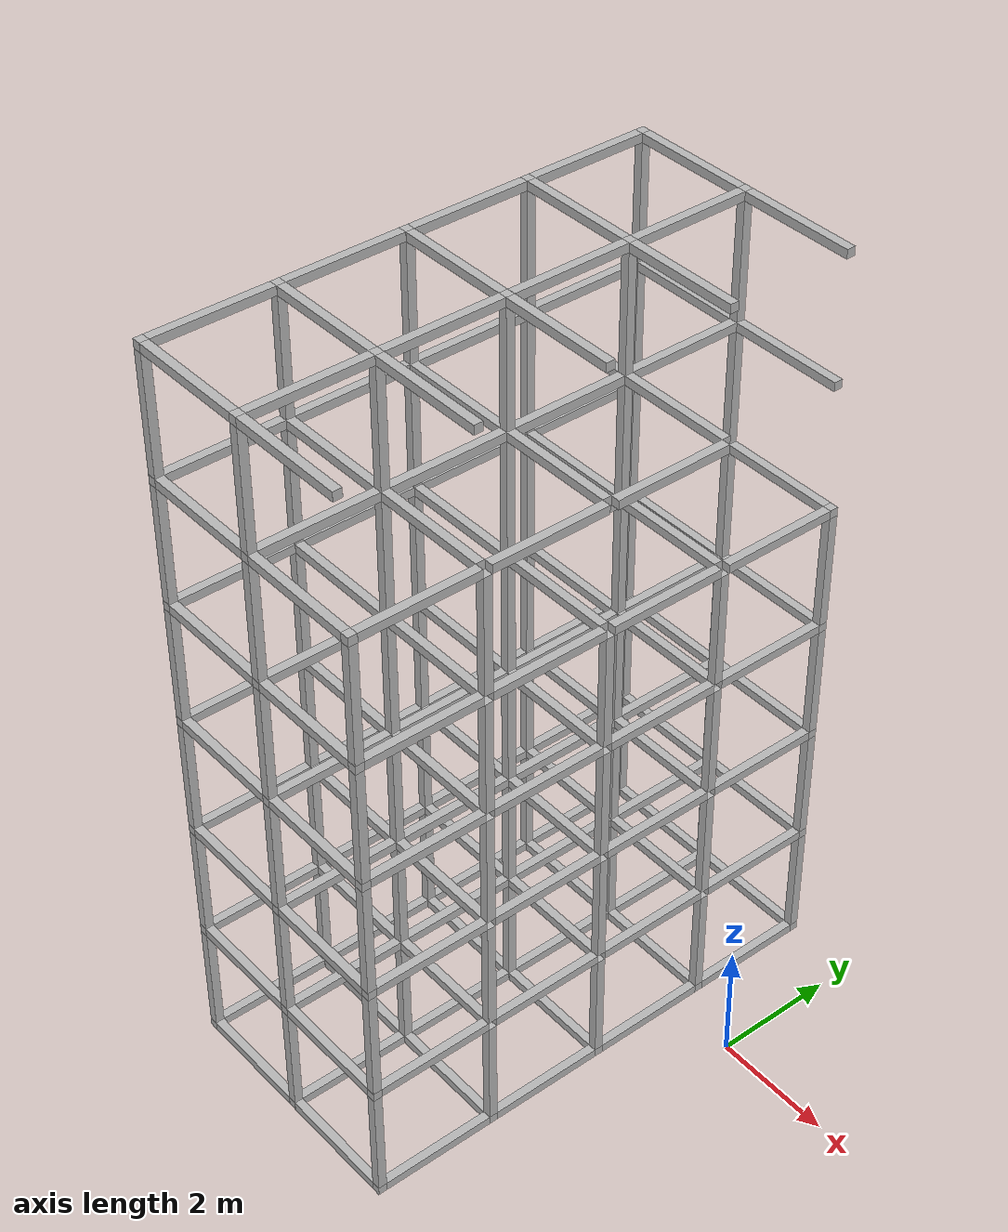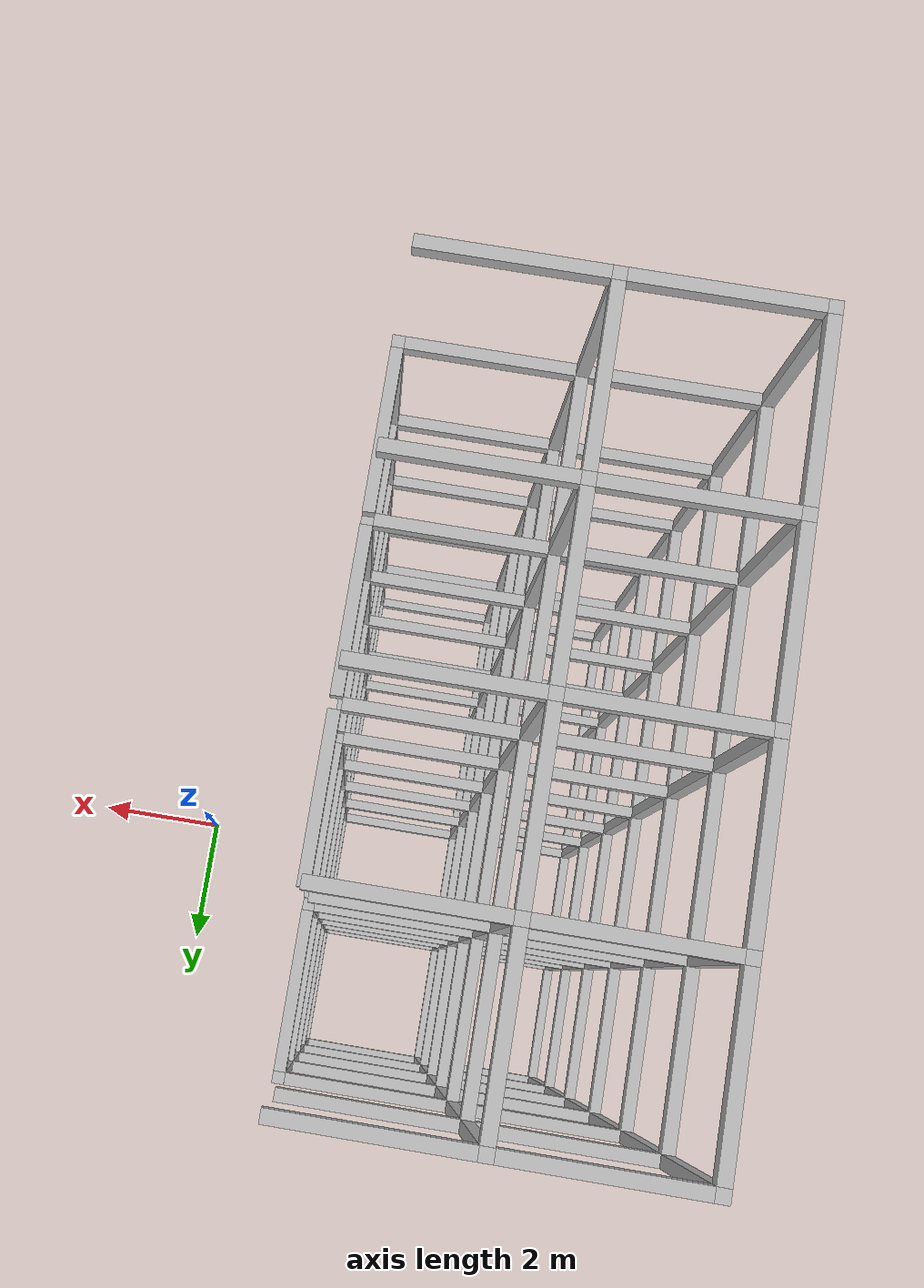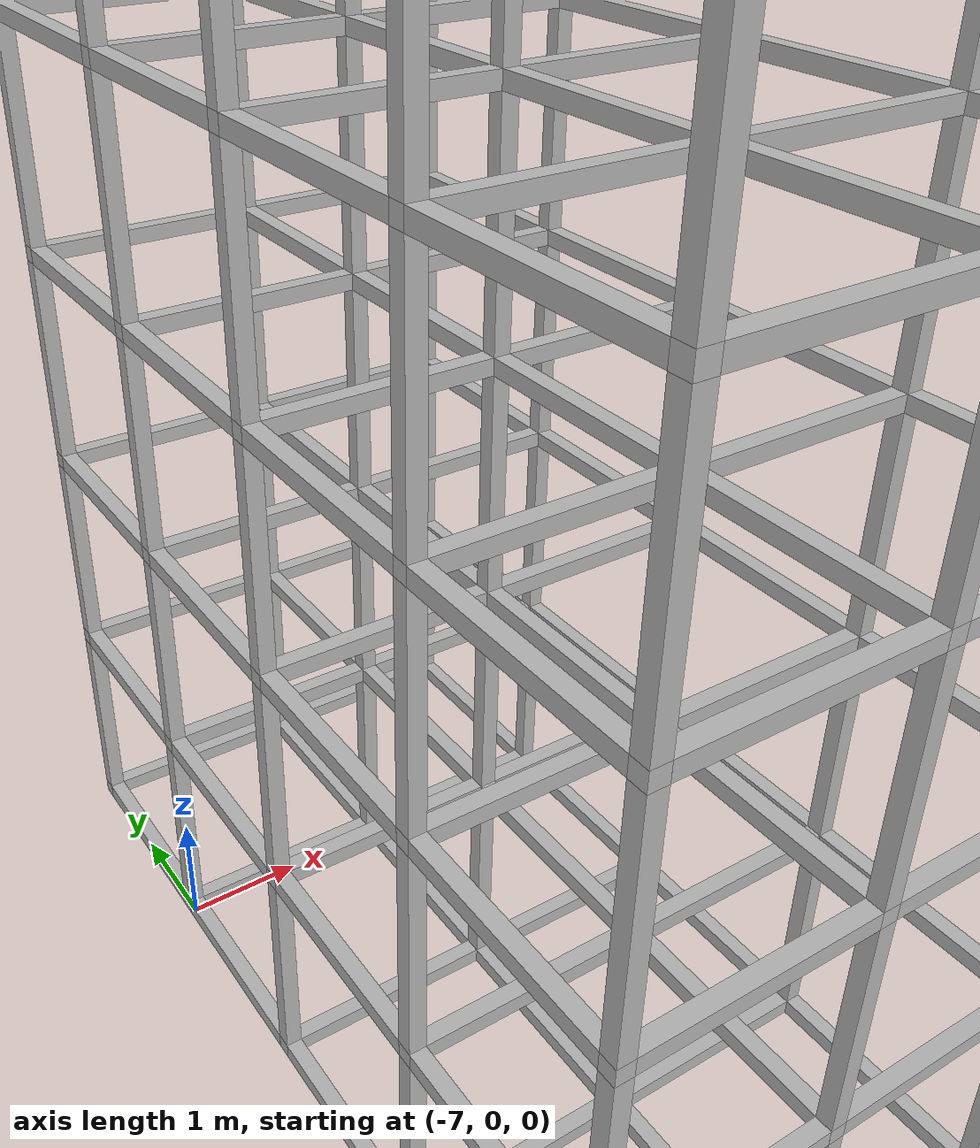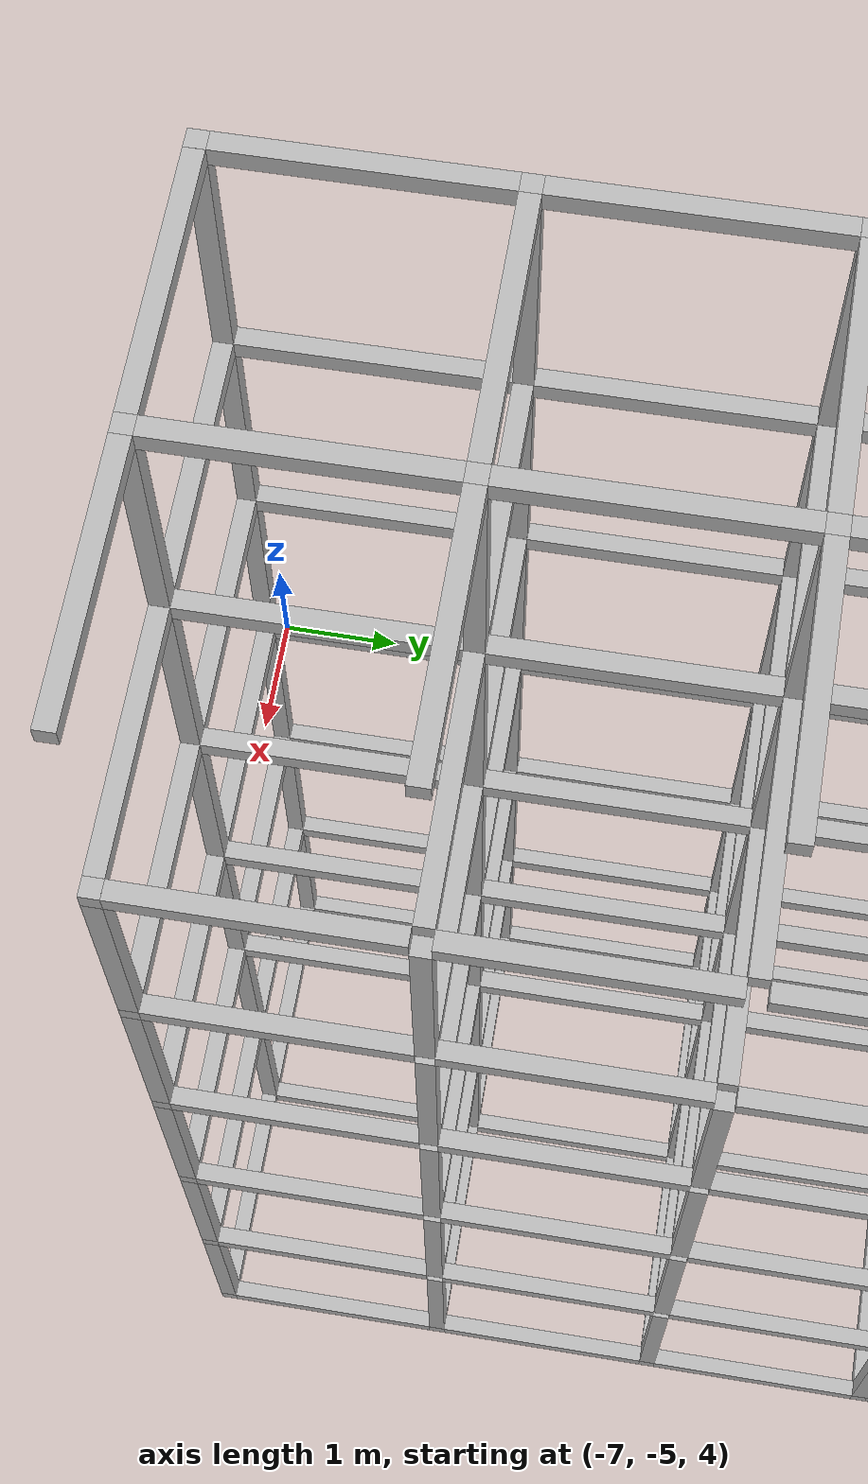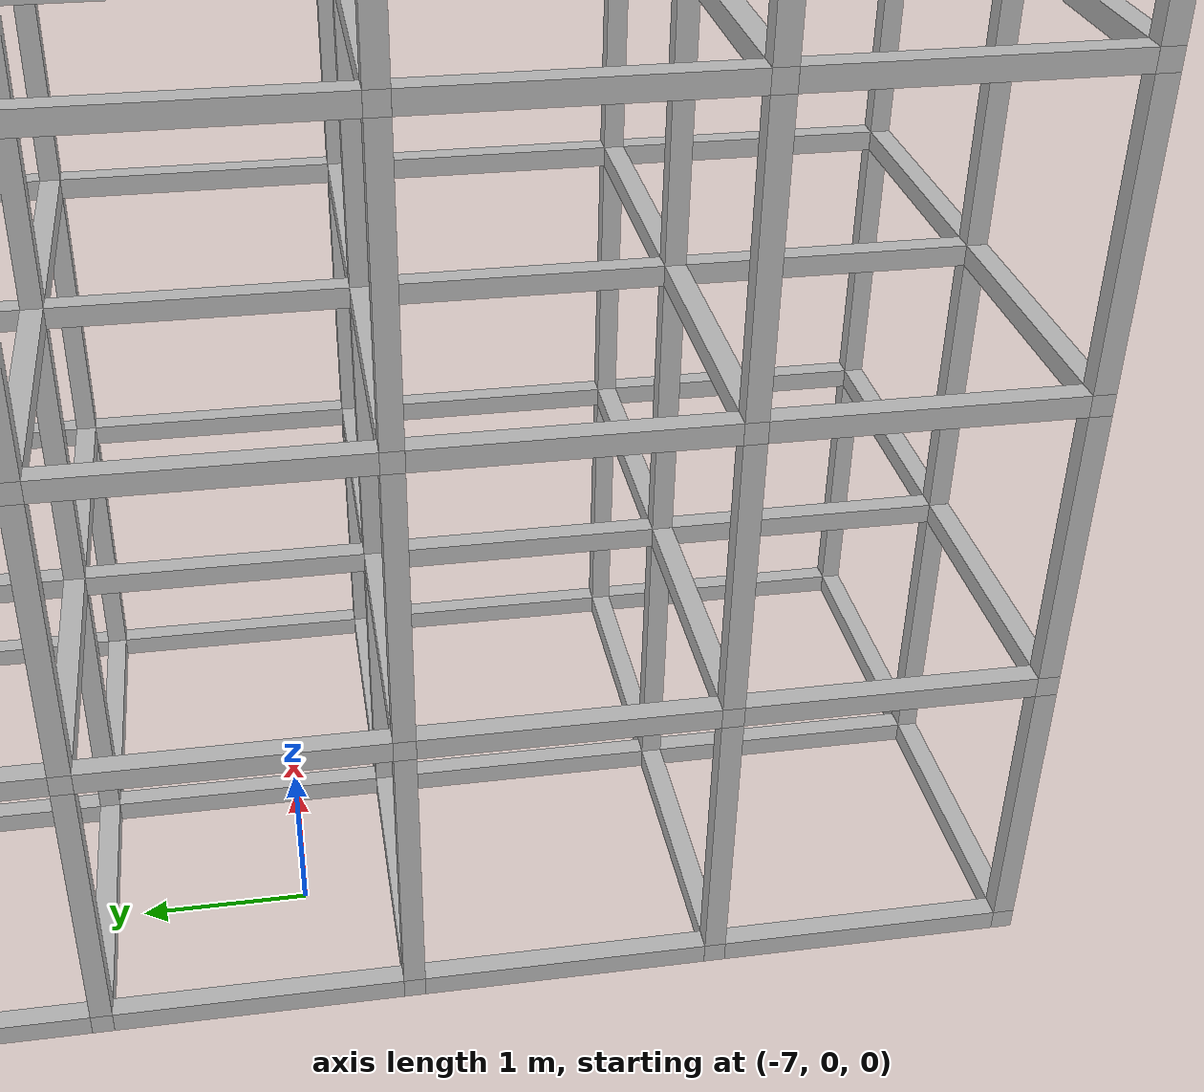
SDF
<sdf version="1.7">
 <world name="default">
  <light name="sun" type="directional">
   <pose>0 0 10 0 -0 0</pose>
   <diffuse>0.8 0.8 0.8 1</diffuse>
   <specular>0.2 0.2 0.2 1</specular>
   <attenuation>
    <range>1000</range>
    <constant>0.9</constant>
    <linear>0.01</linear>
    <quadratic>0.001</quadratic>
   </attenuation>
   <direction>-0.5 0.1 -0.9</direction>
   <spot><inner_angle>0</inner_angle><outer_angle>0</outer_angle><falloff>0</falloff></spot>
  </light>
  <gravity>0 0 -9.8</gravity>
  <magnetic_field>6e-06 2.3e-05 -4.2e-05</magnetic_field>
  <atmosphere type="adiabatic"/>
  <physics type="ode">
   <max_step_size>0.001</max_step_size>
   <real_time_factor>1</real_time_factor>
   <real_time_update_rate>1000</real_time_update_rate>
  </physics>
  <scene><ambient>0.4 0.4 0.4 1</ambient><background>0.7 0.7 0.7 1</background><shadows>1</shadows></scene>
  <spherical_coordinates>
   <surface_model>EARTH_WGS84</surface_model>
   <latitude_deg>0</latitude_deg>
   <longitude_deg>0</longitude_deg>
   <elevation>0</elevation>
   <heading_deg>0</heading_deg>
  </spherical_coordinates>
  <plugin name="arvc_gazebo_ros_test_generator" filename="libarvc_gazebo_ros_test_generator.so">
   <yaml_config>/home/fran/workspaces/arvc_ws/src/arvc_dataset_generator/config/test_generator.yaml</yaml_config>
  </plugin>
  <model name="orthogonal_747_2.000.15_TS">
   <static>1</static>
   <link name="x_link_0_0_0">
    <inertial>
     <mass>1</mass>
     <inertia>
      <ixx>0.166667</ixx>
      <ixy>0</ixy>
      <ixz>0</ixz>
      <iyy>0.166667</iyy>
      <iyz>0</iyz>
      <izz>0.166667</izz>
     </inertia>
    </inertial>
    <pose>1.075 0 1.075 0 -0 0</pose>
    <visual name="visual_0">
     <laser_retro>1</laser_retro>
     <geometry><box><size>2 1e-06 0.15</size></box></geometry>
     <material>
      <script><name>Gazebo/Grey</name><uri>file://media/materials/scripts/gazebo.material</uri></script>
      <shader type="pixel"><normal_map>__default__</normal_map></shader>
      <ambient>0.678 0.498 0.659 1</ambient>
      <diffuse>0.7 0.7 0.7 1</diffuse>
      <specular>0.01 0.01 0.01 1</specular>
      <emissive>0 0 0 1</emissive>
     </material>
     <pose>0 -0.075 0 0 -0 0</pose>
     <transparency>1</transparency>
    </visual>
    <visual name="visual_1">
     <laser_retro>2</laser_retro>
     <geometry><box><size>2 1e-06 0.15</size></box></geometry>
     <material>
      <script><name>Gazebo/Grey</name><uri>file://media/materials/scripts/gazebo.material</uri></script>
      <shader type="pixel"><normal_map>__default__</normal_map></shader>
      <ambient>0.447 0.624 0.812 1</ambient>
      <diffuse>0.7 0.7 0.7 1</diffuse>
      <specular>0.01 0.01 0.01 1</specular>
      <emissive>0 0 0 1</emissive>
     </material>
     <pose>0 0.075 0 0 -0 0</pose>
     <transparency>1</transparency>
    </visual>
    <visual name="visual_2">
     <laser_retro>3</laser_retro>
     <geometry><box><size>2 0.15 1e-06</size></box></geometry>
     <material>
      <script><name>Gazebo/Grey</name><uri>file://media/materials/scripts/gazebo.material</uri></script>
      <shader type="pixel"><normal_map>__default__</normal_map></shader>
      <ambient>0.988 0.686 0.243 1</ambient>
      <diffuse>0.7 0.7 0.7 1</diffuse>
      <specular>0.01 0.01 0.01 1</specular>
      <emissive>0 0 0 1</emissive>
     </material>
     <pose>0 0 -0.075 0 -0 0</pose>
     <transparency>1</transparency>
    </visual>
    <visual name="visual_3">
     <laser_retro>4</laser_retro>
     <geometry><box><size>1e-06 0.15 0.15</size></box></geometry>
     <material>
      <script><name>Gazebo/Grey</name><uri>file://media/materials/scripts/gazebo.material</uri></script>
      <shader type="pixel"><normal_map>__default__</normal_map></shader>
      <ambient>0.988 0.914 0.31 1</ambient>
      <diffuse>0.7 0.7 0.7 1</diffuse>
      <specular>0.01 0.01 0.01 1</specular>
      <emissive>0 0 0 1</emissive>
     </material>
     <pose>1 0 0 0 -0 0</pose>
     <transparency>1</transparency>
    </visual>
    <visual name="visual_4">
     <laser_retro>5</laser_retro>
     <geometry><box><size>2 0.15 1e-06</size></box></geometry>
     <material>
      <script><name>Gazebo/Grey</name><uri>file://media/materials/scripts/gazebo.material</uri></script>
      <shader type="pixel"><normal_map>__default__</normal_map></shader>
      <ambient>0.937 0.161 0.161 1</ambient>
      <diffuse>0.7 0.7 0.7 1</diffuse>
      <specular>0.01 0.01 0.01 1</specular>
      <emissive>0 0 0 1</emissive>
     </material>
     <pose>0 0 0.075 0 -0 0</pose>
     <transparency>1</transparency>
    </visual>
    <visual name="visual_5">
     <laser_retro>6</laser_retro>
     <geometry><box><size>1e-06 0.15 0.15</size></box></geometry>
     <material>
      <script><name>Gazebo/Grey</name><uri>file://media/materials/scripts/gazebo.material</uri></script>
      <shader type="pixel"><normal_map>__default__</normal_map></shader>
      <ambient>0.541 0.886 0.204 1</ambient>
      <diffuse>0.7 0.7 0.7 1</diffuse>
      <specular>0.01 0.01 0.01 1</specular>
      <emissive>0 0 0 1</emissive>
     </material>
     <pose>-1 0 0 0 -0 0</pose>
     <transparency>1</transparency>
    </visual>
    <visual name="visual_texture">
     <geometry><box><size>1.9998 0.149985 0.149985</size></box></geometry>
     <material>
      <script>
       <uri>model://BASE_MODELS/simple_block_v2_textured/materials/scripts</uri>
       <uri>model://BASE_MODELS/simple_block_v2_textured/materials/textures</uri>
       <name>metal</name>
      </script>
     </material>
     <laser_retro>7</laser_retro>
    </visual>
    <collision name="collision">
     <geometry><box><size>2 0.15 0.15</size></box></geometry>
     <surface>
      <friction>
       <ode><mu>1</mu><mu2>1</mu2><fdir1>0 0 0</fdir1><slip1>0</slip1><slip2>0</slip2></ode>
       <torsional>
        <coefficient>1</coefficient>
        <patch_radius>0</patch_radius>
        <surface_radius>0</surface_radius>
        <use_patch_radius>1</use_patch_radius>
        <ode><slip>0</slip></ode>
       </torsional>
      </friction>
      <bounce><restitution_coefficient>0</restitution_coefficient><threshold>1e+06</threshold></bounce>
      <contact>
       <collide_without_contact>0</collide_without_contact>
       <collide_without_contact_bitmask>1</collide_without_contact_bitmask>
       <collide_bitmask>1</collide_bitmask>
       <ode>
        <soft_cfm>0</soft_cfm>
        <soft_erp>0.2</soft_erp>
        <kp>1e+13</kp>
        <kd>1</kd>
        <max_vel>0.01</max_vel>
        <min_depth>0</min_depth>
       </ode>
       <bullet>
        <split_impulse>1</split_impulse>
        <split_impulse_penetration_threshold>-0.01</split_impulse_penetration_threshold>
        <soft_cfm>0</soft_cfm>
        <soft_erp>0.2</soft_erp>
        <kp>1e+13</kp>
        <kd>1</kd>
       </bullet>
      </contact>
     </surface>
    </collision>
   </link>
   <link name="y_link_0_0_0">
    <inertial>
     <mass>1</mass>
     <inertia>
      <ixx>0.166667</ixx>
      <ixy>0</ixy>
      <ixz>0</ixz>
      <iyy>0.166667</iyy>
      <iyz>0</iyz>
      <izz>0.166667</izz>
     </inertia>
    </inertial>
    <pose>0 1.075 1.075 0 -0 0</pose>
    <visual name="visual_0">
     <laser_retro>8</laser_retro>
     <geometry><box><size>0.15 1e-06 0.15</size></box></geometry>
     <material>
      <script><name>Gazebo/Grey</name><uri>file://media/materials/scripts/gazebo.material</uri></script>
      <shader type="pixel"><normal_map>__default__</normal_map></shader>
      <ambient>0.678 0.498 0.659 1</ambient>
      <diffuse>0.7 0.7 0.7 1</diffuse>
      <specular>0.01 0.01 0.01 1</specular>
      <emissive>0 0 0 1</emissive>
     </material>
     <pose>0 -1 0 0 -0 0</pose>
     <transparency>1</transparency>
    </visual>
    <visual name="visual_1">
     <laser_retro>9</laser_retro>
     <geometry><box><size>0.15 1e-06 0.15</size></box></geometry>
     <material>
      <script><name>Gazebo/Grey</name><uri>file://media/materials/scripts/gazebo.material</uri></script>
      <shader type="pixel"><normal_map>__default__</normal_map></shader>
      <ambient>0.447 0.624 0.812 1</ambient>
      <diffuse>0.7 0.7 0.7 1</diffuse>
      <specular>0.01 0.01 0.01 1</specular>
      <emissive>0 0 0 1</emissive>
     </material>
     <pose>0 1 0 0 -0 0</pose>
     <transparency>1</transparency>
    </visual>
    <visual name="visual_2">
     <laser_retro>10</laser_retro>
     <geometry><box><size>0.15 2 1e-06</size></box></geometry>
     <material>
      <script><name>Gazebo/Grey</name><uri>file://media/materials/scripts/gazebo.material</uri></script>
      <shader type="pixel"><normal_map>__default__</normal_map></shader>
      <ambient>0.988 0.686 0.243 1</ambient>
      <diffuse>0.7 0.7 0.7 1</diffuse>
      <specular>0.01 0.01 0.01 1</specular>
      <emissive>0 0 0 1</emissive>
     </material>
     <pose>0 0 -0.075 0 -0 0</pose>
     <transparency>1</transparency>
    </visual>
    <visual name="visual_3">
     <laser_retro>11</laser_retro>
     <geometry><box><size>1e-06 2 0.15</size></box></geometry>
     <material>
      <script><name>Gazebo/Grey</name><uri>file://media/materials/scripts/gazebo.material</uri></script>
      <shader type="pixel"><normal_map>__default__</normal_map></shader>
      <ambient>0.988 0.914 0.31 1</ambient>
      <diffuse>0.7 0.7 0.7 1</diffuse>
      <specular>0.01 0.01 0.01 1</specular>
      <emissive>0 0 0 1</emissive>
     </material>
     <pose>0.075 0 0 0 -0 0</pose>
     <transparency>1</transparency>
    </visual>
    <visual name="visual_4">
     <laser_retro>12</laser_retro>
     <geometry><box><size>0.15 2 1e-06</size></box></geometry>
     <material>
      <script><name>Gazebo/Grey</name><uri>file://media/materials/scripts/gazebo.material</uri></script>
      <shader type="pixel"><normal_map>__default__</normal_map></shader>
      <ambient>0.937 0.161 0.161 1</ambient>
      <diffuse>0.7 0.7 0.7 1</diffuse>
      <specular>0.01 0.01 0.01 1</specular>
      <emissive>0 0 0 1</emissive>
     </material>
     <pose>0 0 0.075 0 -0 0</pose>
     <transparency>1</transparency>
    </visual>
    <visual name="visual_5">
     <laser_retro>13</laser_retro>
     <geometry><box><size>1e-06 2 0.15</size></box></geometry>
     <material>
      <script><name>Gazebo/Grey</name><uri>file://media/materials/scripts/gazebo.material</uri></script>
      <shader type="pixel"><normal_map>__default__</normal_map></shader>
      <ambient>0.541 0.886 0.204 1</ambient>
      <diffuse>0.7 0.7 0.7 1</diffuse>
      <specular>0.01 0.01 0.01 1</specular>
      <emissive>0 0 0 1</emissive>
     </material>
     <pose>-0.075 0 0 0 -0 0</pose>
     <transparency>1</transparency>
    </visual>
    <visual name="visual_texture">
     <geometry><box><size>0.149985 1.9998 0.149985</size></box></geometry>
     <material>
      <script>
       <uri>model://BASE_MODELS/simple_block_v2_textured/materials/scripts</uri>
       <uri>model://BASE_MODELS/simple_block_v2_textured/materials/textures</uri>
       <name>metal</name>
      </script>
     </material>
     <laser_retro>14</laser_retro>
    </visual>
    <collision name="collision">
     <geometry><box><size>0.15 2 0.15</size></box></geometry>
     <surface>
      <friction>
       <ode><mu>1</mu><mu2>1</mu2><fdir1>0 0 0</fdir1><slip1>0</slip1><slip2>0</slip2></ode>
       <torsional>
        <coefficient>1</coefficient>
        <patch_radius>0</patch_radius>
        <surface_radius>0</surface_radius>
        <use_patch_radius>1</use_patch_radius>
        <ode><slip>0</slip></ode>
       </torsional>
      </friction>
      <bounce><restitution_coefficient>0</restitution_coefficient><threshold>1e+06</threshold></bounce>
      <contact>
       <collide_without_contact>0</collide_without_contact>
       <collide_without_contact_bitmask>1</collide_without_contact_bitmask>
       <collide_bitmask>1</collide_bitmask>
       <ode>
        <soft_cfm>0</soft_cfm>
        <soft_erp>0.2</soft_erp>
        <kp>1e+13</kp>
        <kd>1</kd>
        <max_vel>0.01</max_vel>
        <min_depth>0</min_depth>
       </ode>
       <bullet>
        <split_impulse>1</split_impulse>
        <split_impulse_penetration_threshold>-0.01</split_impulse_penetration_threshold>
        <soft_cfm>0</soft_cfm>
        <soft_erp>0.2</soft_erp>
        <kp>1e+13</kp>
        <kd>1</kd>
       </bullet>
      </contact>
     </surface>
    </collision>
   </link>
   <link name="u_link_0_0_0">
    <inertial>
     <mass>1</mass>
     <inertia>
      <ixx>0.166667</ixx>
      <ixy>0</ixy>
      <ixz>0</ixz>
      <iyy>0.166667</iyy>
      <iyz>0</iyz>
      <izz>0.166667</izz>
     </inertia>
    </inertial>
    <pose>0 0 1.075 0 -0 0</pose>
    <visual name="visual_0">
     <laser_retro>15</laser_retro>
     <geometry><box><size>0.15 1e-06 0.15</size></box></geometry>
     <material>
      <script><name>Gazebo/Grey</name><uri>file://media/materials/scripts/gazebo.material</uri></script>
      <shader type="pixel"><normal_map>__default__</normal_map></shader>
      <ambient>0.678 0.498 0.659 1</ambient>
      <diffuse>0.7 0.7 0.7 1</diffuse>
      <specular>0.01 0.01 0.01 1</specular>
      <emissive>0 0 0 1</emissive>
     </material>
     <pose>0 -0.075 0 0 -0 0</pose>
     <transparency>1</transparency>
    </visual>
    <visual name="visual_1">
     <laser_retro>16</laser_retro>
     <geometry><box><size>0.15 1e-06 0.15</size></box></geometry>
     <material>
      <script><name>Gazebo/Grey</name><uri>file://media/materials/scripts/gazebo.material</uri></script>
      <shader type="pixel"><normal_map>__default__</normal_map></shader>
      <ambient>0.447 0.624 0.812 1</ambient>
      <diffuse>0.7 0.7 0.7 1</diffuse>
      <specular>0.01 0.01 0.01 1</specular>
      <emissive>0 0 0 1</emissive>
     </material>
     <pose>0 0.075 0 0 -0 0</pose>
     <transparency>1</transparency>
    </visual>
    <visual name="visual_2">
     <laser_retro>17</laser_retro>
     <geometry><box><size>0.15 0.15 1e-06</size></box></geometry>
     <material>
      <script><name>Gazebo/Grey</name><uri>file://media/materials/scripts/gazebo.material</uri></script>
      <shader type="pixel"><normal_map>__default__</normal_map></shader>
      <ambient>0.988 0.686 0.243 1</ambient>
      <diffuse>0.7 0.7 0.7 1</diffuse>
      <specular>0.01 0.01 0.01 1</specular>
      <emissive>0 0 0 1</emissive>
     </material>
     <pose>0 0 -0.075 0 -0 0</pose>
     <transparency>1</transparency>
    </visual>
    <visual name="visual_3">
     <laser_retro>18</laser_retro>
     <geometry><box><size>1e-06 0.15 0.15</size></box></geometry>
     <material>
      <script><name>Gazebo/Grey</name><uri>file://media/materials/scripts/gazebo.material</uri></script>
      <shader type="pixel"><normal_map>__default__</normal_map></shader>
      <ambient>0.988 0.914 0.31 1</ambient>
      <diffuse>0.7 0.7 0.7 1</diffuse>
      <specular>0.01 0.01 0.01 1</specular>
      <emissive>0 0 0 1</emissive>
     </material>
     <pose>0.075 0 0 0 -0 0</pose>
     <transparency>1</transparency>
    </visual>
    <visual name="visual_4">
     <laser_retro>19</laser_retro>
     <geometry><box><size>0.15 0.15 1e-06</size></box></geometry>
     <material>
      <script><name>Gazebo/Grey</name><uri>file://media/materials/scripts/gazebo.material</uri></script>
      <shader type="pixel"><normal_map>__default__</normal_map></shader>
      <ambient>0.937 0.161 0.161 1</ambient>
      <diffuse>0.7 0.7 0.7 1</diffuse>
      <specular>0.01 0.01 0.01 1</specular>
      <emissive>0 0 0 1</emissive>
     </material>
     <pose>0 0 0.075 0 -0 0</pose>
     <transparency>1</transparency>
    </visual>
    <visual name="visual_5">
     <laser_retro>20</laser_retro>
     <geometry><box><size>1e-06 0.15 0.15</size></box></geometry>
     <material>
      <script><name>Gazebo/Grey</name><uri>file://media/materials/scripts/gazebo.material</uri></script>
      <shader type="pixel"><normal_map>__default__</normal_map></shader>
      <ambient>0.541 0.886 0.204 1</ambient>
      <diffuse>0.7 0.7 0.7 1</diffuse>
      <specular>0.01 0.01 0.01 1</specular>
      <emissive>0 0 0 1</emissive>
     </material>
     <pose>-0.075 0 0 0 -0 0</pose>
     <transparency>1</transparency>
    </visual>
    <visual name="visual_texture">
     <geometry><box><size>0.149985 0.149985 0.149985</size></box></geometry>
     <material>
      <script>
       <uri>model://BASE_MODELS/simple_block_v2_textured/materials/scripts</uri>
       <uri>model://BASE_MODELS/simple_block_v2_textured/materials/textures</uri>
       <name>metal</name>
      </script>
     </material>
     <laser_retro>21</laser_retro>
    </visual>
    <collision name="collision">
     <geometry><box><size>0.15 0.15 0.15</size></box></geometry>
     <surface>
      <friction>
       <ode><mu>1</mu><mu2>1</mu2><fdir1>0 0 0</fdir1><slip1>0</slip1><slip2>0</slip2></ode>
       <torsional>
        <coefficient>1</coefficient>
        <patch_radius>0</patch_radius>
        <surface_radius>0</surface_radius>
        <use_patch_radius>1</use_patch_radius>
        <ode><slip>0</slip></ode>
       </torsional>
      </friction>
      <bounce><restitution_coefficient>0</restitution_coefficient><threshold>1e+06</threshold></bounce>
      <contact>
       <collide_without_contact>0</collide_without_contact>
       <collide_without_contact_bitmask>1</collide_without_contact_bitmask>
       <collide_bitmask>1</collide_bitmask>
       <ode>
        <soft_cfm>0</soft_cfm>
        <soft_erp>0.2</soft_erp>
        <kp>1e+13</kp>
        <kd>1</kd>
        <max_vel>0.01</max_vel>
        <min_depth>0</min_depth>
       </ode>
       <bullet>
        <split_impulse>1</split_impulse>
        <split_impulse_penetration_threshold>-0.01</split_impulse_penetration_threshold>
        <soft_cfm>0</soft_cfm>
        <soft_erp>0.2</soft_erp>
        <kp>1e+13</kp>
        <kd>1</kd>
       </bullet>
      </contact>
     </surface>
    </collision>
   </link>
   <link name="x_link_0_0_1">
    <inertial>
     <mass>1</mass>
     <inertia>
      <ixx>0.166667</ixx>
      <ixy>0</ixy>
      <ixz>0</ixz>
      <iyy>0.166667</iyy>
      <iyz>0</iyz>
      <izz>0.166667</izz>
     </inertia>
    </inertial>
    <pose>3.225 0 1.075 0 -0 0</pose>
    <visual name="visual_0">
     <laser_retro>22</laser_retro>
     <geometry><box><size>2 1e-06 0.15</size></box></geometry>
     <material>
      <script><name>Gazebo/Grey</name><uri>file://media/materials/scripts/gazebo.material</uri></script>
      <shader type="pixel"><normal_map>__default__</normal_map></shader>
      <ambient>0.678 0.498 0.659 1</ambient>
      <diffuse>0.7 0.7 0.7 1</diffuse>
      <specular>0.01 0.01 0.01 1</specular>
      <emissive>0 0 0 1</emissive>
     </material>
     <pose>0 -0.075 0 0 -0 0</pose>
     <transparency>1</transparency>
    </visual>
    <visual name="visual_1">
     <laser_retro>23</laser_retro>
     <geometry><box><size>2 1e-06 0.15</size></box></geometry>
     <material>
      <script><name>Gazebo/Grey</name><uri>file://media/materials/scripts/gazebo.material</uri></script>
      <shader type="pixel"><normal_map>__default__</normal_map></shader>
      <ambient>0.447 0.624 0.812 1</ambient>
      <diffuse>0.7 0.7 0.7 1</diffuse>
      <specular>0.01 0.01 0.01 1</specular>
      <emissive>0 0 0 1</emissive>
     </material>
     <pose>0 0.075 0 0 -0 0</pose>
     <transparency>1</transparency>
    </visual>
    <visual name="visual_2">
     <laser_retro>24</laser_retro>
     <geometry><box><size>2 0.15 1e-06</size></box></geometry>
     <material>
      <script><name>Gazebo/Grey</name><uri>file://media/materials/scripts/gazebo.material</uri></script>
      <shader type="pixel"><normal_map>__default__</normal_map></shader>
      <ambient>0.988 0.686 0.243 1</ambient>
      <diffuse>0.7 0.7 0.7 1</diffuse>
      <specular>0.01 0.01 0.01 1</specular>
      <emissive>0 0 0 1</emissive>
     </material>
     <pose>0 0 -0.075 0 -0 0</pose>
     <transparency>1</transparency>
    </visual>
    <visual name="visual_3">
     <laser_retro>25</laser_retro>
     <geometry><box><size>1e-06 0.15 0.15</size></box></geometry>
     <material>
      <script><name>Gazebo/Grey</name><uri>file://media/materials/scripts/gazebo.material</uri></script>
      <shader type="pixel"><normal_map>__default__</normal_map></shader>
      <ambient>0.988 0.914 0.31 1</ambient>
      <diffuse>0.7 0.7 0.7 1</diffuse>
      <specular>0.01 0.01 0.01 1</specular>
      <emissive>0 0 0 1</emissive>
     </material>
     <pose>1 0 0 0 -0 0</pose>
     <transparency>1</transparency>
    </visual>
    <visual name="visual_4">
     <laser_retro>26</laser_retro>
     <geometry><box><size>2 0.15 1e-06</size></box></geometry>
     <material>
      <script><name>Gazebo/Grey</name><uri>file://media/materials/scripts/gazebo.material</uri></script>
      <shader type="pixel"><normal_map>__default__</normal_map></shader>
      <ambient>0.937 0.161 0.161 1</ambient>
      <diffuse>0.7 0.7 0.7 1</diffuse>
      <specular>0.01 0.01 0.01 1</specular>
      <emissive>0 0 0 1</emissive>
     </material>
     <pose>0 0 0.075 0 -0 0</pose>
     <transparency>1</transparency>
    </visual>
    <visual name="visual_5">
     <laser_retro>27</laser_retro>
     <geometry><box><size>1e-06 0.15 0.15</size></box></geometry>
     <material>
      <script><name>Gazebo/Grey</name><uri>file://media/materials/scripts/gazebo.material</uri></script>
      <shader type="pixel"><normal_map>__default__</normal_map></shader>
      <ambient>0.541 0.886 0.204 1</ambient>
      <diffuse>0.7 0.7 0.7 1</diffuse>
      <specular>0.01 0.01 0.01 1</specular>
      <emissive>0 0 0 1</emissive>
     </material>
     <pose>-1 0 0 0 -0 0</pose>
     <transparency>1</transparency>
    </visual>
    <visual name="visual_texture">
     <geometry><box><size>1.9998 0.149985 0.149985</size></box></geometry>
     <material>
      <script>
       <uri>model://BASE_MODELS/simple_block_v2_textured/materials/scripts</uri>
       <uri>model://BASE_MODELS/simple_block_v2_textured/materials/textures</uri>
       <name>metal</name>
      </script>
     </material>
     <laser_retro>28</laser_retro>
    </visual>
    <collision name="collision">
     <geometry><box><size>2 0.15 0.15</size></box></geometry>
     <surface>
      <friction>
       <ode><mu>1</mu><mu2>1</mu2><fdir1>0 0 0</fdir1><slip1>0</slip1><slip2>0</slip2></ode>
       <torsional>
        <coefficient>1</coefficient>
        <patch_radius>0</patch_radius>
        <surface_radius>0</surface_radius>
        <use_patch_radius>1</use_patch_radius>
        <ode><slip>0</slip></ode>
       </torsional>
      </friction>
      <bounce><restitution_coefficient>0</restitution_coefficient><threshold>1e+06</threshold></bounce>
      <contact>
       <collide_without_contact>0</collide_without_contact>
       <collide_without_contact_bitmask>1</collide_without_contact_bitmask>
       <collide_bitmask>1</collide_bitmask>
       <ode>
        <soft_cfm>0</soft_cfm>
        <soft_erp>0.2</soft_erp>
        <kp>1e+13</kp>
        <kd>1</kd>
        <max_vel>0.01</max_vel>
        <min_depth>0</min_depth>
       </ode>
       <bullet>
        <split_impulse>1</split_impulse>
        <split_impulse_penetration_threshold>-0.01</split_impulse_penetration_threshold>
        <soft_cfm>0</soft_cfm>
        <soft_erp>0.2</soft_erp>
        <kp>1e+13</kp>
        <kd>1</kd>
       </bullet>
      </contact>
     </surface>
    </collision>
   </link>
   <link name="y_link_0_0_1">
    <inertial>
     <mass>1</mass>
     <inertia>
      <ixx>0.166667</ixx>
      <ixy>0</ixy>
      <ixz>0</ixz>
      <iyy>0.166667</iyy>
      <iyz>0</iyz>
      <izz>0.166667</izz>
     </inertia>
    </inertial>
    <pose>2.15 1.075 1.075 0 -0 0</pose>
    <visual name="visual_0">
     <laser_retro>29</laser_retro>
     <geometry><box><size>0.15 1e-06 0.15</size></box></geometry>
     <material>
      <script><name>Gazebo/Grey</name><uri>file://media/materials/scripts/gazebo.material</uri></script>
      <shader type="pixel"><normal_map>__default__</normal_map></shader>
      <ambient>0.678 0.498 0.659 1</ambient>
      <diffuse>0.7 0.7 0.7 1</diffuse>
      <specular>0.01 0.01 0.01 1</specular>
      <emissive>0 0 0 1</emissive>
     </material>
     <pose>0 -1 0 0 -0 0</pose>
     <transparency>1</transparency>
    </visual>
    <visual name="visual_1">
     <laser_retro>30</laser_retro>
     <geometry><box><size>0.15 1e-06 0.15</size></box></geometry>
     <material>
      <script><name>Gazebo/Grey</name><uri>file://media/materials/scripts/gazebo.material</uri></script>
      <shader type="pixel"><normal_map>__default__</normal_map></shader>
      <ambient>0.447 0.624 0.812 1</ambient>
      <diffuse>0.7 0.7 0.7 1</diffuse>
      <specular>0.01 0.01 0.01 1</specular>
      <emissive>0 0 0 1</emissive>
     </material>
     <pose>0 1 0 0 -0 0</pose>
     <transparency>1</transparency>
    </visual>
    <visual name="visual_2">
     <laser_retro>31</laser_retro>
     <geometry><box><size>0.15 2 1e-06</size></box></geometry>
     <material>
      <script><name>Gazebo/Grey</name><uri>file://media/materials/scripts/gazebo.material</uri></script>
      <shader type="pixel"><normal_map>__default__</normal_map></shader>
      <ambient>0.988 0.686 0.243 1</ambient>
      <diffuse>0.7 0.7 0.7 1</diffuse>
      <specular>0.01 0.01 0.01 1</specular>
      <emissive>0 0 0 1</emissive>
     </material>
     <pose>0 0 -0.075 0 -0 0</pose>
     <transparency>1</transparency>
    </visual>
    <visual name="visual_3">
     <laser_retro>32</laser_retro>
     <geometry><box><size>1e-06 2 0.15</size></box></geometry>
     <material>
      <script><name>Gazebo/Grey</name><uri>file://media/materials/scripts/gazebo.material</uri></script>
      <shader type="pixel"><normal_map>__default__</normal_map></shader>
      <ambient>0.988 0.914 0.31 1</ambient>
      <diffuse>0.7 0.7 0.7 1</diffuse>
      <specular>0.01 0.01 0.01 1</specular>
      <emissive>0 0 0 1</emissive>
     </material>
     <pose>0.075 0 0 0 -0 0</pose>
     <transparency>1</transparency>
    </visual>
    <visual name="visual_4">
     <laser_retro>33</laser_retro>
     <geometry><box><size>0.15 2 1e-06</size></box></geometry>
     <material>
      <script><name>Gazebo/Grey</name><uri>file://media/materials/scripts/gazebo.material</uri></script>
      <shader type="pixel"><normal_map>__default__</normal_map></shader>
      <ambient>0.937 0.161 0.161 1</ambient>
      <diffuse>0.7 0.7 0.7 1</diffuse>
      <specular>0.01 0.01 0.01 1</specular>
      <emissive>0 0 0 1</emissive>
     </material>
     <pose>0 0 0.075 0 -0 0</pose>
     <transparency>1</transparency>
    </visual>
    <visual name="visual_5">
     <laser_retro>34</laser_retro>
     <geometry><box><size>1e-06 2 0.15</size></box></geometry>
     <material>
      <script><name>Gazebo/Grey</name><uri>file://media/materials/scripts/gazebo.material</uri></script>
      <shader type="pixel"><normal_map>__default__</normal_map></shader>
      <ambient>0.541 0.886 0.204 1</ambient>
      <diffuse>0.7 0.7 0.7 1</diffuse>
      <specular>0.01 0.01 0.01 1</specular>
      <emissive>0 0 0 1</emissive>
     </material>
     <pose>-0.075 0 0 0 -0 0</pose>
     <transparency>1</transparency>
    </visual>
    <visual name="visual_texture">
     <geometry><box><size>0.149985 1.9998 0.149985</size></box></geometry>
     <material>
      <script>
       <uri>model://BASE_MODELS/simple_block_v2_textured/materials/scripts</uri>
       <uri>model://BASE_MODELS/simple_block_v2_textured/materials/textures</uri>
       <name>metal</name>
      </script>
     </material>
     <laser_retro>35</laser_retro>
    </visual>
    <collision name="collision">
     <geometry><box><size>0.15 2 0.15</size></box></geometry>
     <surface>
      <friction>
       <ode><mu>1</mu><mu2>1</mu2><fdir1>0 0 0</fdir1><slip1>0</slip1><slip2>0</slip2></ode>
       <torsional>
        <coefficient>1</coefficient>
        <patch_radius>0</patch_radius>
        <surface_radius>0</surface_radius>
        <use_patch_radius>1</use_patch_radius>
        <ode><slip>0</slip></ode>
       </torsional>
      </friction>
      <bounce><restitution_coefficient>0</restitution_coefficient><threshold>1e+06</threshold></bounce>
      <contact>
       <collide_without_contact>0</collide_without_contact>
       <collide_without_contact_bitmask>1</collide_without_contact_bitmask>
       <collide_bitmask>1</collide_bitmask>
       <ode>
        <soft_cfm>0</soft_cfm>
        <soft_erp>0.2</soft_erp>
        <kp>1e+13</kp>
        <kd>1</kd>
        <max_vel>0.01</max_vel>
        <min_depth>0</min_depth>
       </ode>
       <bullet>
        <split_impulse>1</split_impulse>
        <split_impulse_penetration_threshold>-0.01</split_impulse_penetration_threshold>
        <soft_cfm>0</soft_cfm>
        <soft_erp>0.2</soft_erp>
        <kp>1e+13</kp>
        <kd>1</kd>
       </bullet>
      </contact>
     </surface>
    </collision>
   </link>
   <link name="u_link_0_0_1">
    <inertial>
     <mass>1</mass>
     <inertia>
      <ixx>0.166667</ixx>
      <ixy>0</ixy>
      <ixz>0</ixz>
      <iyy>0.166667</iyy>
      <iyz>0</iyz>
      <izz>0.166667</izz>
     </inertia>
    </inertial>
    <pose>2.15 0 1.075 0 -0 0</pose>
    <visual name="visual_0">
     <laser_retro>36</laser_retro>
     <geometry><box><size>0.15 1e-06 0.15</size></box></geometry>
     <material>
      <script><name>Gazebo/Grey</name><uri>file://media/materials/scripts/gazebo.material</uri></script>
      <shader type="pixel"><normal_map>__default__</normal_map></shader>
      <ambient>0.678 0.498 0.659 1</ambient>
      <diffuse>0.7 0.7 0.7 1</diffuse>
      <specular>0.01 0.01 0.01 1</specular>
      <emissive>0 0 0 1</emissive>
     </material>
     <pose>0 -0.075 0 0 -0 0</pose>
     <transparency>1</transparency>
    </visual>
    <visual name="visual_1">
     <laser_retro>37</laser_retro>
     <geometry><box><size>0.15 1e-06 0.15</size></box></geometry>
     <material>
      <script><name>Gazebo/Grey</name><uri>file://media/materials/scripts/gazebo.material</uri></script>
      <shader type="pixel"><normal_map>__default__</normal_map></shader>
      <ambient>0.447 0.624 0.812 1</ambient>
      <diffuse>0.7 0.7 0.7 1</diffuse>
      <specular>0.01 0.01 0.01 1</specular>
      <emissive>0 0 0 1</emissive>
     </material>
     <pose>0 0.075 0 0 -0 0</pose>
     <transparency>1</transparency>
    </visual>
    <visual name="visual_2">
     <laser_retro>38</laser_retro>
     <geometry><box><size>0.15 0.15 1e-06</size></box></geometry>
     <material>
      <script><name>Gazebo/Grey</name><uri>file://media/materials/scripts/gazebo.material</uri></script>
      <shader type="pixel"><normal_map>__default__</normal_map></shader>
      <ambient>0.988 0.686 0.243 1</ambient>
      <diffuse>0.7 0.7 0.7 1</diffuse>
      <specular>0.01 0.01 0.01 1</specular>
      <emissive>0 0 0 1</emissive>
     </material>
     <pose>0 0 -0.075 0 -0 0</pose>
     <transparency>1</transparency>
    </visual>
    <visual name="visual_3">
     <laser_retro>39</laser_retro>
     <geometry><box><size>1e-06 0.15 0.15</size></box></geometry>
     <material>
      <script><name>Gazebo/Grey</name><uri>file://media/materials/scripts/gazebo.material</uri></script>
      <shader type="pixel"><normal_map>__default__</normal_map></shader>
      <ambient>0.988 0.914 0.31 1</ambient>
      <diffuse>0.7 0.7 0.7 1</diffuse>
      <specular>0.01 0.01 0.01 1</specular>
      <emissive>0 0 0 1</emissive>
     </material>
     <pose>0.075 0 0 0 -0 0</pose>
     <transparency>1</transparency>
    </visual>
    <visual name="visual_4">
     <laser_retro>40</laser_retro>
     <geometry><box><size>0.15 0.15 1e-06</size></box></geometry>
     <material>
      <script><name>Gazebo/Grey</name><uri>file://media/materials/scripts/gazebo.material</uri></script>
      <shader type="pixel"><normal_map>__default__</normal_map></shader>
      <ambient>0.937 0.161 0.161 1</ambient>
      <diffuse>0.7 0.7 0.7 1</diffuse>
      <specular>0.01 0.01 0.01 1</specular>
      <emissive>0 0 0 1</emissive>
     </material>
     <pose>0 0 0.075 0 -0 0</pose>
     <transparency>1</transparency>
    </visual>
    <visual name="visual_5">
     <laser_retro>41</laser_retro>
     <geometry><box><size>1e-06 0.15 0.15</size></box></geometry>
     <material>
      <script><name>Gazebo/Grey</name><uri>file://media/materials/scripts/gazebo.material</uri></script>
      <shader type="pixel"><normal_map>__default__</normal_map></shader>
      <ambient>0.541 0.886 0.204 1</ambient>
      <diffuse>0.7 0.7 0.7 1</diffuse>
      <specular>0.01 0.01 0.01 1</specular>
      <emissive>0 0 0 1</emissive>
     </material>
     <pose>-0.075 0 0 0 -0 0</pose>
     <transparency>1</transparency>
    </visual>
    <visual name="visual_texture">
     <geometry><box><size>0.149985 0.149985 0.149985</size></box></geometry>
     <material>
      <script>
       <uri>model://BASE_MODELS/simple_block_v2_textured/materials/scripts</uri>
       <uri>model://BASE_MODELS/simple_block_v2_textured/materials/textures</uri>
       <name>metal</name>
      </script>
     </material>
     <laser_retro>42</laser_retro>
    </visual>
    <collision name="collision">
     <geometry><box><size>0.15 0.15 0.15</size></box></geometry>
     <surface>
      <friction>
       <ode><mu>1</mu><mu2>1</mu2><fdir1>0 0 0</fdir1><slip1>0</slip1><slip2>0</slip2></ode>
       <torsional>
        <coefficient>1</coefficient>
        <patch_radius>0</patch_radius>
        <surface_radius>0</surface_radius>
        <use_patch_radius>1</use_patch_radius>
        <ode><slip>0</slip></ode>
       </torsional>
      </friction>
      <bounce><restitution_coefficient>0</restitution_coefficient><threshold>1e+06</threshold></bounce>
      <contact>
       <collide_without_contact>0</collide_without_contact>
       <collide_without_contact_bitmask>1</collide_without_contact_bitmask>
       <collide_bitmask>1</collide_bitmask>
       <ode>
        <soft_cfm>0</soft_cfm>
        <soft_erp>0.2</soft_erp>
        <kp>1e+13</kp>
        <kd>1</kd>
        <max_vel>0.01</max_vel>
        <min_depth>0</min_depth>
       </ode>
       <bullet>
        <split_impulse>1</split_impulse>
        <split_impulse_penetration_threshold>-0.01</split_impulse_penetration_threshold>
        <soft_cfm>0</soft_cfm>
        <soft_erp>0.2</soft_erp>
        <kp>1e+13</kp>
        <kd>1</kd>
       </bullet>
      </contact>
     </surface>
    </collision>
   </link>
   <link name="y_link_0_0_2">
    <inertial>
     <mass>1</mass>
     <inertia>
      <ixx>0.166667</ixx>
      <ixy>0</ixy>
      <ixz>0</ixz>
      <iyy>0.166667</iyy>
      <iyz>0</iyz>
      <izz>0.166667</izz>
     </inertia>
    </inertial>
    <pose>4.3 1.075 1.075 0 -0 0</pose>
    <visual name="visual_0">
     <laser_retro>50</laser_retro>
     <geometry><box><size>0.15 1e-06 0.15</size></box></geometry>
     <material>
      <script><name>Gazebo/Grey</name><uri>file://media/materials/scripts/gazebo.material</uri></script>
      <shader type="pixel"><normal_map>__default__</normal_map></shader>
      <ambient>0.678 0.498 0.659 1</ambient>
      <diffuse>0.7 0.7 0.7 1</diffuse>
      <specular>0.01 0.01 0.01 1</specular>
      <emissive>0 0 0 1</emissive>
     </material>
     <pose>0 -1 0 0 -0 0</pose>
     <transparency>1</transparency>
    </visual>
    <visual name="visual_1">
     <laser_retro>51</laser_retro>
     <geometry><box><size>0.15 1e-06 0.15</size></box></geometry>
     <material>
      <script><name>Gazebo/Grey</name><uri>file://media/materials/scripts/gazebo.material</uri></script>
      <shader type="pixel"><normal_map>__default__</normal_map></shader>
      <ambient>0.447 0.624 0.812 1</ambient>
      <diffuse>0.7 0.7 0.7 1</diffuse>
      <specular>0.01 0.01 0.01 1</specular>
      <emissive>0 0 0 1</emissive>
     </material>
     <pose>0 1 0 0 -0 0</pose>
     <transparency>1</transparency>
    </visual>
    <visual name="visual_2">
     <laser_retro>52</laser_retro>
     <geometry><box><size>0.15 2 1e-06</size></box></geometry>
     <material>
      <script><name>Gazebo/Grey</name><uri>file://media/materials/scripts/gazebo.material</uri></script>
      <shader type="pixel"><normal_map>__default__</normal_map></shader>
      <ambient>0.988 0.686 0.243 1</ambient>
      <diffuse>0.7 0.7 0.7 1</diffuse>
      <specular>0.01 0.01 0.01 1</specular>
      <emissive>0 0 0 1</emissive>
     </material>
     <pose>0 0 -0.075 0 -0 0</pose>
     <transparency>1</transparency>
    </visual>
    <visual name="visual_3">
     <laser_retro>53</laser_retro>
     <geometry><box><size>1e-06 2 0.15</size></box></geometry>
     <material>
      <script><name>Gazebo/Grey</name><uri>file://media/materials/scripts/gazebo.material</uri></script>
      <shader type="pixel"><normal_map>__default__</normal_map></shader>
      <ambient>0.988 0.914 0.31 1</ambient>
      <diffuse>0.7 0.7 0.7 1</diffuse>
      <specular>0.01 0.01 0.01 1</specular>
      <emissive>0 0 0 1</emissive>
     </material>
     <pose>0.075 0 0 0 -0 0</pose>
     <transparency>1</transparency>
    </visual>
    <visual name="visual_4">
     <laser_retro>54</laser_retro>
     <geometry><box><size>0.15 2 1e-06</size></box></geometry>
     <material>
      <script><name>Gazebo/Grey</name><uri>file://media/materials/scripts/gazebo.material</uri></script>
      <shader type="pixel"><normal_map>__default__</normal_map></shader>
      <ambient>0.937 0.161 0.161 1</ambient>
      <diffuse>0.7 0.7 0.7 1</diffuse>
      <specular>0.01 0.01 0.01 1</specular>
      <emissive>0 0 0 1</emissive>
     </material>
     <pose>0 0 0.075 0 -0 0</pose>
     <transparency>1</transparency>
    </visual>
    <visual name="visual_5">
     <laser_retro>55</laser_retro>
     <geometry><box><size>1e-06 2 0.15</size></box></geometry>
     <material>
      <script><name>Gazebo/Grey</name><uri>file://media/materials/scripts/gazebo.material</uri></script>
      <shader type="pixel"><normal_map>__default__</normal_map></shader>
      <ambient>0.541 0.886 0.204 1</ambient>
      <diffuse>0.7 0.7 0.7 1</diffuse>
      <specular>0.01 0.01 0.01 1</specular>
      <emissive>0 0 0 1</emissive>
     </material>
     <pose>-0.075 0 0 0 -0 0</pose>
     <transparency>1</transparency>
    </visual>
    <visual name="visual_texture">
     <geometry><box><size>0.149985 1.9998 0.149985</size></box></geometry>
     <material>
      <script>
       <uri>model://BASE_MODELS/simple_block_v2_textured/materials/scripts</uri>
       <uri>model://BASE_MODELS/simple_block_v2_textured/materials/textures</uri>
       <name>metal</name>
      </script>
     </material>
     <laser_retro>56</laser_retro>
    </visual>
    <collision name="collision">
     <geometry><box><size>0.15 2 0.15</size></box></geometry>
     <surface>
      <friction>
       <ode><mu>1</mu><mu2>1</mu2><fdir1>0 0 0</fdir1><slip1>0</slip1><slip2>0</slip2></ode>
       <torsional>
        <coefficient>1</coefficient>
        <patch_radius>0</patch_radius>
        <surface_radius>0</surface_radius>
        <use_patch_radius>1</use_patch_radius>
        <ode><slip>0</slip></ode>
       </torsional>
      </friction>
      <bounce><restitution_coefficient>0</restitution_coefficient><threshold>1e+06</threshold></bounce>
      <contact>
       <collide_without_contact>0</collide_without_contact>
       <collide_without_contact_bitmask>1</collide_without_contact_bitmask>
       <collide_bitmask>1</collide_bitmask>
       <ode>
        <soft_cfm>0</soft_cfm>
        <soft_erp>0.2</soft_erp>
        <kp>1e+13</kp>
        <kd>1</kd>
        <max_vel>0.01</max_vel>
        <min_depth>0</min_depth>
       </ode>
       <bullet>
        <split_impulse>1</split_impulse>
        <split_impulse_penetration_threshold>-0.01</split_impulse_penetration_threshold>
        <soft_cfm>0</soft_cfm>
        <soft_erp>0.2</soft_erp>
        <kp>1e+13</kp>
        <kd>1</kd>
       </bullet>
      </contact>
     </surface>
    </collision>
   </link>
   <link name="u_link_0_0_2">
    <inertial>
     <mass>1</mass>
     <inertia>
      <ixx>0.166667</ixx>
      <ixy>0</ixy>
      <ixz>0</ixz>
      <iyy>0.166667</iyy>
      <iyz>0</iyz>
      <izz>0.166667</izz>
     </inertia>
    </inertial>
    <pose>4.3 0 1.075 0 -0 0</pose>
    <visual name="visual_0">
     <laser_retro>57</laser_retro>
     <geometry><box><size>0.15 1e-06 0.15</size></box></geometry>
     <material>
      <script><name>Gazebo/Grey</name><uri>file://media/materials/scripts/gazebo.material</uri></script>
      <shader type="pixel"><normal_map>__default__</normal_map></shader>
      <ambient>0.678 0.498 0.659 1</ambient>
      <diffuse>0.7 0.7 0.7 1</diffuse>
      <specular>0.01 0.01 0.01 1</specular>
      <emissive>0 0 0 1</emissive>
     </material>
     <pose>0 -0.075 0 0 -0 0</pose>
     <transparency>1</transparency>
    </visual>
    <visual name="visual_1">
     <laser_retro>58</laser_retro>
     <geometry><box><size>0.15 1e-06 0.15</size></box></geometry>
     <material>
      <script><name>Gazebo/Grey</name><uri>file://media/materials/scripts/gazebo.material</uri></script>
      <shader type="pixel"><normal_map>__default__</normal_map></shader>
      <ambient>0.447 0.624 0.812 1</ambient>
      <diffuse>0.7 0.7 0.7 1</diffuse>
      <specular>0.01 0.01 0.01 1</specular>
      <emissive>0 0 0 1</emissive>
     </material>
     <pose>0 0.075 0 0 -0 0</pose>
     <transparency>1</transparency>
    </visual>
    <visual name="visual_2">
     <laser_retro>59</laser_retro>
     <geometry><box><size>0.15 0.15 1e-06</size></box></geometry>
     <material>
      <script><name>Gazebo/Grey</name><uri>file://media/materials/scripts/gazebo.material</uri></script>
      <shader type="pixel"><normal_map>__default__</normal_map></shader>
      <ambient>0.988 0.686 0.243 1</ambient>
      <diffuse>0.7 0.7 0.7 1</diffuse>
      <specular>0.01 0.01 0.01 1</specular>
      <emissive>0 0 0 1</emissive>
     </material>
     <pose>0 0 -0.075 0 -0 0</pose>
     <transparency>1</transparency>
    </visual>
    <visual name="visual_3">
     <laser_retro>60</laser_retro>
     <geometry><box><size>1e-06 0.15 0.15</size></box></geometry>
     <material>
      <script><name>Gazebo/Grey</name><uri>file://media/materials/scripts/gazebo.material</uri></script>
      <shader type="pixel"><normal_map>__default__</normal_map></shader>
      <ambient>0.988 0.914 0.31 1</ambient>
      <diffuse>0.7 0.7 0.7 1</diffuse>
      <specular>0.01 0.01 0.01 1</specular>
      <emissive>0 0 0 1</emissive>
     </material>
     <pose>0.075 0 0 0 -0 0</pose>
     <transparency>1</transparency>
    </visual>
    <visual name="visual_4">
     <laser_retro>61</laser_retro>
     <geometry><box><size>0.15 0.15 1e-06</size></box></geometry>
     <material>
      <script><name>Gazebo/Grey</name><uri>file://media/materials/scripts/gazebo.material</uri></script>
      <shader type="pixel"><normal_map>__default__</normal_map></shader>
      <ambient>0.937 0.161 0.161 1</ambient>
      <diffuse>0.7 0.7 0.7 1</diffuse>
      <specular>0.01 0.01 0.01 1</specular>
      <emissive>0 0 0 1</emissive>
     </material>
     <pose>0 0 0.075 0 -0 0</pose>
     <transparency>1</transparency>
    </visual>
    <visual name="visual_5">
     <laser_retro>62</laser_retro>
     <geometry><box><size>1e-06 0.15 0.15</size></box></geometry>
     <material>
      <script><name>Gazebo/Grey</name><uri>file://media/materials/scripts/gazebo.material</uri></script>
      <shader type="pixel"><normal_map>__default__</normal_map></shader>
      <ambient>0.541 0.886 0.204 1</ambient>
      <diffuse>0.7 0.7 0.7 1</diffuse>
      <specular>0.01 0.01 0.01 1</specular>
      <emissive>0 0 0 1</emissive>
     </material>
     <pose>-0.075 0 0 0 -0 0</pose>
     <transparency>1</transparency>
    </visual>
    <visual name="visual_texture">
     <geometry><box><size>0.149985 0.149985 0.149985</size></box></geometry>
     <material>
      <script>
       <uri>model://BASE_MODELS/simple_block_v2_textured/materials/scripts</uri>
       <uri>model://BASE_MODELS/simple_block_v2_textured/materials/textures</uri>
       <name>metal</name>
      </script>
     </material>
     <laser_retro>63</laser_retro>
    </visual>
    <collision name="collision">
     <geometry><box><size>0.15 0.15 0.15</size></box></geometry>
     <surface>
      <friction>
       <ode><mu>1</mu><mu2>1</mu2><fdir1>0 0 0</fdir1><slip1>0</slip1><slip2>0</slip2></ode>
       <torsional>
        <coefficient>1</coefficient>
        <patch_radius>0</patch_radius>
        <surface_radius>0</surface_radius>
        <use_patch_radius>1</use_patch_radius>
        <ode><slip>0</slip></ode>
       </torsional>
      </friction>
      <bounce><restitution_coefficient>0</restitution_coefficient><threshold>1e+06</threshold></bounce>
      <contact>
       <collide_without_contact>0</collide_without_contact>
       <collide_without_contact_bitmask>1</collide_without_contact_bitmask>
       <collide_bitmask>1</collide_bitmask>
       <ode>
        <soft_cfm>0</soft_cfm>
        <soft_erp>0.2</soft_erp>
        <kp>1e+13</kp>
        <kd>1</kd>
        <max_vel>0.01</max_vel>
        <min_depth>0</min_depth>
       </ode>
       <bullet>
        <split_impulse>1</split_impulse>
        <split_impulse_penetration_threshold>-0.01</split_impulse_penetration_threshold>
        <soft_cfm>0</soft_cfm>
        <soft_erp>0.2</soft_erp>
        <kp>1e+13</kp>
        <kd>1</kd>
       </bullet>
      </contact>
     </surface>
    </collision>
   </link>
   <link name="x_link_0_1_0">
    <inertial>
     <mass>1</mass>
     <inertia>
      <ixx>0.166667</ixx>
      <ixy>0</ixy>
      <ixz>0</ixz>
      <iyy>0.166667</iyy>
      <iyz>0</iyz>
      <izz>0.166667</izz>
     </inertia>
    </inertial>
    <pose>1.075 2.15 1.075 0 -0 0</pose>
    <visual name="visual_0">
     <laser_retro>162</laser_retro>
     <geometry><box><size>2 1e-06 0.15</size></box></geometry>
     <material>
      <script><name>Gazebo/Grey</name><uri>file://media/materials/scripts/gazebo.material</uri></script>
      <shader type="pixel"><normal_map>__default__</normal_map></shader>
      <ambient>0.678 0.498 0.659 1</ambient>
      <diffuse>0.7 0.7 0.7 1</diffuse>
      <specular>0.01 0.01 0.01 1</specular>
      <emissive>0 0 0 1</emissive>
     </material>
     <pose>0 -0.075 0 0 -0 0</pose>
     <transparency>1</transparency>
    </visual>
    <visual name="visual_1">
     <laser_retro>163</laser_retro>
     <geometry><box><size>2 1e-06 0.15</size></box></geometry>
     <material>
      <script><name>Gazebo/Grey</name><uri>file://media/materials/scripts/gazebo.material</uri></script>
      <shader type="pixel"><normal_map>__default__</normal_map></shader>
      <ambient>0.447 0.624 0.812 1</ambient>
      <diffuse>0.7 0.7 0.7 1</diffuse>
      <specular>0.01 0.01 0.01 1</specular>
      <emissive>0 0 0 1</emissive>
     </material>
     <pose>0 0.075 0 0 -0 0</pose>
     <transparency>1</transparency>
    </visual>
    <visual name="visual_2">
     <laser_retro>164</laser_retro>
     <geometry><box><size>2 0.15 1e-06</size></box></geometry>
     <material>
      <script><name>Gazebo/Grey</name><uri>file://media/materials/scripts/gazebo.material</uri></script>
      <shader type="pixel"><normal_map>__default__</normal_map></shader>
      <ambient>0.988 0.686 0.243 1</ambient>
      <diffuse>0.7 0.7 0.7 1</diffuse>
      <specular>0.01 0.01 0.01 1</specular>
      <emissive>0 0 0 1</emissive>
     </material>
     <pose>0 0 -0.075 0 -0 0</pose>
     <transparency>1</transparency>
    </visual>
    <visual name="visual_3">
     <laser_retro>165</laser_retro>
     <geometry><box><size>1e-06 0.15 0.15</size></box></geometry>
     <material>
      <script><name>Gazebo/Grey</name><uri>file://media/materials/scripts/gazebo.material</uri></script>
      <shader type="pixel"><normal_map>__default__</normal_map></shader>
      <ambient>0.988 0.914 0.31 1</ambient>
      <diffuse>0.7 0.7 0.7 1</diffuse>
      <specular>0.01 0.01 0.01 1</specular>
      <emissive>0 0 0 1</emissive>
     </material>
     <pose>1 0 0 0 -0 0</pose>
     <transparency>1</transparency>
    </visual>
    <visual name="visual_4">
     <laser_retro>166</laser_retro>
     <geometry><box><size>2 0.15 1e-06</size></box></geometry>
     <material>
      <script><name>Gazebo/Grey</name><uri>file://media/materials/scripts/gazebo.material</uri></script>
      <shader type="pixel"><normal_map>__default__</normal_map></shader>
      <ambient>0.937 0.161 0.161 1</ambient>
      <diffuse>0.7 0.7 0.7 1</diffuse>
      <specular>0.01 0.01 0.01 1</specular>
      <emissive>0 0 0 1</emissive>
     </material>
     <pose>0 0 0.075 0 -0 0</pose>
     <transparency>1</transparency>
    </visual>
    <visual name="visual_5">
     <laser_retro>167</laser_retro>
     <geometry><box><size>1e-06 0.15 0.15</size></box></geometry>
     <material>
      <script><name>Gazebo/Grey</name><uri>file://media/materials/scripts/gazebo.material</uri></script>
      <shader type="pixel"><normal_map>__default__</normal_map></shader>
      <ambient>0.541 0.886 0.204 1</ambient>
      <diffuse>0.7 0.7 0.7 1</diffuse>
      <specular>0.01 0.01 0.01 1</specular>
      <emissive>0 0 0 1</emissive>
     </material>
     <pose>-1 0 0 0 -0 0</pose>
     <transparency>1</transparency>
    </visual>
    <visual name="visual_texture">
     <geometry><box><size>1.9998 0.149985 0.149985</size></box></geometry>
     <material>
      <script>
       <uri>model://BASE_MODELS/simple_block_v2_textured/materials/scripts</uri>
       <uri>model://BASE_MODELS/simple_block_v2_textured/materials/textures</uri>
       <name>metal</name>
      </script>
     </material>
     <laser_retro>168</laser_retro>
    </visual>
    <collision name="collision">
     <geometry><box><size>2 0.15 0.15</size></box></geometry>
     <surface>
      <friction>
       <ode><mu>1</mu><mu2>1</mu2><fdir1>0 0 0</fdir1><slip1>0</slip1><slip2>0</slip2></ode>
       <torsional>
        <coefficient>1</coefficient>
        <patch_radius>0</patch_radius>
        <surface_radius>0</surface_radius>
        <use_patch_radius>1</use_patch_radius>
        <ode><slip>0</slip></ode>
       </torsional>
      </friction>
      <bounce><restitution_coefficient>0</restitution_coefficient><threshold>1e+06</threshold></bounce>
      <contact>
       <collide_without_contact>0</collide_without_contact>
       <collide_without_contact_bitmask>1</collide_without_contact_bitmask>
       <collide_bitmask>1</collide_bitmask>
       <ode>
        <soft_cfm>0</soft_cfm>
        <soft_erp>0.2</soft_erp>
        <kp>1e+13</kp>
        <kd>1</kd>
        <max_vel>0.01</max_vel>
        <min_depth>0</min_depth>
       </ode>
       <bullet>
        <split_impulse>1</split_impulse>
        <split_impulse_penetration_threshold>-0.01</split_impulse_penetration_threshold>
        <soft_cfm>0</soft_cfm>
        <soft_erp>0.2</soft_erp>
        <kp>1e+13</kp>
        <kd>1</kd>
       </bullet>
      </contact>
     </surface>
    </collision>
   </link>
   <link name="y_link_0_1_0">
    <inertial>
     <mass>1</mass>
     <inertia>
      <ixx>0.166667</ixx>
      <ixy>0</ixy>
      <ixz>0</ixz>
      <iyy>0.166667</iyy>
      <iyz>0</iyz>
      <izz>0.166667</izz>
     </inertia>
    </inertial>
    <pose>0 3.225 1.075 0 -0 0</pose>
    <visual name="visual_0">
     <laser_retro>169</laser_retro>
     <geometry><box><size>0.15 1e-06 0.15</size></box></geometry>
     <material>
      <script><name>Gazebo/Grey</name><uri>file://media/materials/scripts/gazebo.material</uri></script>
      <shader type="pixel"><normal_map>__default__</normal_map></shader>
      <ambient>0.678 0.498 0.659 1</ambient>
      <diffuse>0.7 0.7 0.7 1</diffuse>
      <specular>0.01 0.01 0.01 1</specular>
      <emissive>0 0 0 1</emissive>
     </material>
     <pose>0 -1 0 0 -0 0</pose>
     <transparency>1</transparency>
    </visual>
    <visual name="visual_1">
     <laser_retro>170</laser_retro>
     <geometry><box><size>0.15 1e-06 0.15</size></box></geometry>
     <material>
      <script><name>Gazebo/Grey</name><uri>file://media/materials/scripts/gazebo.material</uri></script>
      <shader type="pixel"><normal_map>__default__</normal_map></shader>
      <ambient>0.447 0.624 0.812 1</ambient>
      <diffuse>0.7 0.7 0.7 1</diffuse>
      <specular>0.01 0.01 0.01 1</specular>
      <emissive>0 0 0 1</emissive>
     </material>
     <pose>0 1 0 0 -0 0</pose>
     <transparency>1</transparency>
    </visual>
    <visual name="visual_2">
     <laser_retro>171</laser_retro>
     <geometry><box><size>0.15 2 1e-06</size></box></geometry>
     <material>
      <script><name>Gazebo/Grey</name><uri>file://media/materials/scripts/gazebo.material</uri></script>
      <shader type="pixel"><normal_map>__default__</normal_map></shader>
      <ambient>0.988 0.686 0.243 1</ambient>
      <diffuse>0.7 0.7 0.7 1</diffuse>
      <specular>0.01 0.01 0.01 1</specular>
      <emissive>0 0 0 1</emissive>
     </material>
     <pose>0 0 -0.075 0 -0 0</pose>
     <transparency>1</transparency>
    </visual>
    <visual name="visual_3">
     <laser_retro>172</laser_retro>
     <geometry><box><size>1e-06 2 0.15</size></box></geometry>
     <material>
      <script><name>Gazebo/Grey</name><uri>file://media/materials/scripts/gazebo.material</uri></script>
      <shader type="pixel"><normal_map>__default__</normal_map></shader>
      <ambient>0.988 0.914 0.31 1</ambient>
      <diffuse>0.7 0.7 0.7 1</diffuse>
      <specular>0.01 0.01 0.01 1</specular>
      <emissive>0 0 0 1</emissive>
     </material>
     <pose>0.075 0 0 0 -0 0</pose>
     <transparency>1</transparency>
    </visual>
    <visual name="visual_4">
     <laser_retro>173</laser_retro>
     <geometry><box><size>0.15 2 1e-06</size></box></geometry>
     <material>
      <script><name>Gazebo/Grey</name><uri>file://media/materials/scripts/gazebo.material</uri></script>
      <shader type="pixel"><normal_map>__default__</normal_map></shader>
      <ambient>0.937 0.161 0.161 1</ambient>
      <diffuse>0.7 0.7 0.7 1</diffuse>
      <specular>0.01 0.01 0.01 1</specular>
      <emissive>0 0 0 1</emissive>
     </material>
     <pose>0 0 0.075 0 -0 0</pose>
     <transparency>1</transparency>
    </visual>
    <visual name="visual_5">
     <laser_retro>174</laser_retro>
     <geometry><box><size>1e-06 2 0.15</size></box></geometry>
     <material>
      <script><name>Gazebo/Grey</name><uri>file://media/materials/scripts/gazebo.material</uri></script>
      <shader type="pixel"><normal_map>__default__</normal_map></shader>
      <ambient>0.541 0.886 0.204 1</ambient>
      <diffuse>0.7 0.7 0.7 1</diffuse>
      <specular>0.01 0.01 0.01 1</specular>
      <emissive>0 0 0 1</emissive>
     </material>
     <pose>-0.075 0 0 0 -0 0</pose>
     <transparency>1</transparency>
    </visual>
    <visual name="visual_texture">
     <geometry><box><size>0.149985 1.9998 0.149985</size></box></geometry>
     <material>
      <script>
       <uri>model://BASE_MODELS/simple_block_v2_textured/materials/scripts</uri>
       <uri>model://BASE_MODELS/simple_block_v2_textured/materials/textures</uri>
       <name>metal</name>
      </script>
     </material>
     <laser_retro>175</laser_retro>
    </visual>
    <collision name="collision">
     <geometry><box><size>0.15 2 0.15</size></box></geometry>
     <surface>
      <friction>
       <ode><mu>1</mu><mu2>1</mu2><fdir1>0 0 0</fdir1><slip1>0</slip1><slip2>0</slip2></ode>
       <torsional>
        <coefficient>1</coefficient>
        <patch_radius>0</patch_radius>
        <surface_radius>0</surface_radius>
        <use_patch_radius>1</use_patch_radius>
        <ode><slip>0</slip></ode>
       </torsional>
      </friction>
      <bounce><restitution_coefficient>0</restitution_coefficient><threshold>1e+06</threshold></bounce>
      <contact>
       <collide_without_contact>0</collide_without_contact>
       <collide_without_contact_bitmask>1</collide_without_contact_bitmask>
       <collide_bitmask>1</collide_bitmask>
       <ode>
        <soft_cfm>0</soft_cfm>
        <soft_erp>0.2</soft_erp>
        <kp>1e+13</kp>
        <kd>1</kd>
        <max_vel>0.01</max_vel>
        <min_depth>0</min_depth>
       </ode>
       <bullet>
        <split_impulse>1</split_impulse>
        <split_impulse_penetration_threshold>-0.01</split_impulse_penetration_threshold>
        <soft_cfm>0</soft_cfm>
        <soft_erp>0.2</soft_erp>
        <kp>1e+13</kp>
        <kd>1</kd>
       </bullet>
      </contact>
     </surface>
    </collision>
   </link>
   <link name="u_link_0_1_0">
    <inertial>
     <mass>1</mass>
     <inertia>
      <ixx>0.166667</ixx>
      <ixy>0</ixy>
      <ixz>0</ixz>
      <iyy>0.166667</iyy>
      <iyz>0</iyz>
      <izz>0.166667</izz>
     </inertia>
    </inertial>
    <pose>0 2.15 1.075 0 -0 0</pose>
    <visual name="visual_0">
     <laser_retro>176</laser_retro>
     <geometry><box><size>0.15 1e-06 0.15</size></box></geometry>
     <material>
      <script><name>Gazebo/Grey</name><uri>file://media/materials/scripts/gazebo.material</uri></script>
      <shader type="pixel"><normal_map>__default__</normal_map></shader>
      <ambient>0.678 0.498 0.659 1</ambient>
      <diffuse>0.7 0.7 0.7 1</diffuse>
      <specular>0.01 0.01 0.01 1</specular>
      <emissive>0 0 0 1</emissive>
     </material>
     <pose>0 -0.075 0 0 -0 0</pose>
     <transparency>1</transparency>
    </visual>
    <visual name="visual_1">
     <laser_retro>177</laser_retro>
     <geometry><box><size>0.15 1e-06 0.15</size></box></geometry>
     <material>
      <script><name>Gazebo/Grey</name><uri>file://media/materials/scripts/gazebo.material</uri></script>
      <shader type="pixel"><normal_map>__default__</normal_map></shader>
      <ambient>0.447 0.624 0.812 1</ambient>
      <diffuse>0.7 0.7 0.7 1</diffuse>
      <specular>0.01 0.01 0.01 1</specular>
      <emissive>0 0 0 1</emissive>
     </material>
     <pose>0 0.075 0 0 -0 0</pose>
     <transparency>1</transparency>
    </visual>
    <visual name="visual_2">
     <laser_retro>178</laser_retro>
     <geometry><box><size>0.15 0.15 1e-06</size></box></geometry>
     <material>
      <script><name>Gazebo/Grey</name><uri>file://media/materials/scripts/gazebo.material</uri></script>
      <shader type="pixel"><normal_map>__default__</normal_map></shader>
      <ambient>0.988 0.686 0.243 1</ambient>
      <diffuse>0.7 0.7 0.7 1</diffuse>
      <specular>0.01 0.01 0.01 1</specular>
      <emissive>0 0 0 1</emissive>
     </material>
     <pose>0 0 -0.075 0 -0 0</pose>
     <transparency>1</transparency>
    </visual>
    <visual name="visual_3">
     <laser_retro>179</laser_retro>
     <geometry><box><size>1e-06 0.15 0.15</size></box></geometry>
     <material>
      <script><name>Gazebo/Grey</name><uri>file://media/materials/scripts/gazebo.material</uri></script>
      <shader type="pixel"><normal_map>__default__</normal_map></shader>
      <ambient>0.988 0.914 0.31 1</ambient>
      <diffuse>0.7 0.7 0.7 1</diffuse>
      <specular>0.01 0.01 0.01 1</specular>
      <emissive>0 0 0 1</emissive>
     </material>
     <pose>0.075 0 0 0 -0 0</pose>
     <transparency>1</transparency>
    </visual>
    <visual name="visual_4">
     <laser_retro>180</laser_retro>
     <geometry><box><size>0.15 0.15 1e-06</size></box></geometry>
     <material>
      <script><name>Gazebo/Grey</name><uri>file://media/materials/scripts/gazebo.material</uri></script>
      <shader type="pixel"><normal_map>__default__</normal_map></shader>
      <ambient>0.937 0.161 0.161 1</ambient>
      <diffuse>0.7 0.7 0.7 1</diffuse>
      <specular>0.01 0.01 0.01 1</specular>
      <emissive>0 0 0 1</emissive>
     </material>
     <pose>0 0 0.075 0 -0 0</pose>
     <transparency>1</transparency>
    </visual>
    <visual name="visual_5">
     <laser_retro>181</laser_retro>
     <geometry><box><size>1e-06 0.15 0.15</size></box></geometry>
     <material>
      <script><name>Gazebo/Grey</name><uri>file://media/materials/scripts/gazebo.material</uri></script>
      <shader type="pixel"><normal_map>__default__</normal_map></shader>
      <ambient>0.541 0.886 0.204 1</ambient>
      <diffuse>0.7 0.7 0.7 1</diffuse>
      <specular>0.01 0.01 0.01 1</specular>
      <emissive>0 0 0 1</emissive>
     </material>
     <pose>-0.075 0 0 0 -0 0</pose>
     <transparency>1</transparency>
    </visual>
    <visual name="visual_texture">
     <geometry><box><size>0.149985 0.149985 0.149985</size></box></geometry>
     <material>
      <script>
       <uri>model://BASE_MODELS/simple_block_v2_textured/materials/scripts</uri>
       <uri>model://BASE_MODELS/simple_block_v2_textured/materials/textures</uri>
       <name>metal</name>
      </script>
     </material>
     <laser_retro>182</laser_retro>
    </visual>
    <collision name="collision">
     <geometry><box><size>0.15 0.15 0.15</size></box></geometry>
     <surface>
      <friction>
       <ode><mu>1</mu><mu2>1</mu2><fdir1>0 0 0</fdir1><slip1>0</slip1><slip2>0</slip2></ode>
       <torsional>
        <coefficient>1</coefficient>
        <patch_radius>0</patch_radius>
        <surface_radius>0</surface_radius>
        <use_patch_radius>1</use_patch_radius>
        <ode><slip>0</slip></ode>
       </torsional>
      </friction>
      <bounce><restitution_coefficient>0</restitution_coefficient><threshold>1e+06</threshold></bounce>
      <contact>
       <collide_without_contact>0</collide_without_contact>
       <collide_without_contact_bitmask>1</collide_without_contact_bitmask>
       <collide_bitmask>1</collide_bitmask>
       <ode>
        <soft_cfm>0</soft_cfm>
        <soft_erp>0.2</soft_erp>
        <kp>1e+13</kp>
        <kd>1</kd>
        <max_vel>0.01</max_vel>
        <min_depth>0</min_depth>
       </ode>
       <bullet>
        <split_impulse>1</split_impulse>
        <split_impulse_penetration_threshold>-0.01</split_impulse_penetration_threshold>
        <soft_cfm>0</soft_cfm>
        <soft_erp>0.2</soft_erp>
        <kp>1e+13</kp>
        <kd>1</kd>
       </bullet>
      </contact>
     </surface>
    </collision>
   </link>
   <link name="x_link_0_1_1">
    <inertial>
     <mass>1</mass>
     <inertia>
      <ixx>0.166667</ixx>
      <ixy>0</ixy>
      <ixz>0</ixz>
      <iyy>0.166667</iyy>
      <iyz>0</iyz>
      <izz>0.166667</izz>
     </inertia>
    </inertial>
    <pose>3.225 2.15 1.075 0 -0 0</pose>
    <visual name="visual_0">
     <laser_retro>183</laser_retro>
     <geometry><box><size>2 1e-06 0.15</size></box></geometry>
     <material>
      <script><name>Gazebo/Grey</name><uri>file://media/materials/scripts/gazebo.material</uri></script>
      <shader type="pixel"><normal_map>__default__</normal_map></shader>
      <ambient>0.678 0.498 0.659 1</ambient>
      <diffuse>0.7 0.7 0.7 1</diffuse>
      <specular>0.01 0.01 0.01 1</specular>
      <emissive>0 0 0 1</emissive>
     </material>
     <pose>0 -0.075 0 0 -0 0</pose>
     <transparency>1</transparency>
    </visual>
    <visual name="visual_1">
     <laser_retro>184</laser_retro>
     <geometry><box><size>2 1e-06 0.15</size></box></geometry>
     <material>
      <script><name>Gazebo/Grey</name><uri>file://media/materials/scripts/gazebo.material</uri></script>
      <shader type="pixel"><normal_map>__default__</normal_map></shader>
      <ambient>0.447 0.624 0.812 1</ambient>
      <diffuse>0.7 0.7 0.7 1</diffuse>
      <specular>0.01 0.01 0.01 1</specular>
      <emissive>0 0 0 1</emissive>
     </material>
     <pose>0 0.075 0 0 -0 0</pose>
     <transparency>1</transparency>
    </visual>
    <visual name="visual_2">
     <laser_retro>185</laser_retro>
     <geometry><box><size>2 0.15 1e-06</size></box></geometry>
     <material>
      <script><name>Gazebo/Grey</name><uri>file://media/materials/scripts/gazebo.material</uri></script>
      <shader type="pixel"><normal_map>__default__</normal_map></shader>
      <ambient>0.988 0.686 0.243 1</ambient>
      <diffuse>0.7 0.7 0.7 1</diffuse>
      <specular>0.01 0.01 0.01 1</specular>
      <emissive>0 0 0 1</emissive>
     </material>
     <pose>0 0 -0.075 0 -0 0</pose>
     <transparency>1</transparency>
    </visual>
    <visual name="visual_3">
     <laser_retro>186</laser_retro>
     <geometry><box><size>1e-06 0.15 0.15</size></box></geometry>
     <material>
      <script><name>Gazebo/Grey</name><uri>file://media/materials/scripts/gazebo.material</uri></script>
      <shader type="pixel"><normal_map>__default__</normal_map></shader>
      <ambient>0.988 0.914 0.31 1</ambient>
      <diffuse>0.7 0.7 0.7 1</diffuse>
      <specular>0.01 0.01 0.01 1</specular>
      <emissive>0 0 0 1</emissive>
     </material>
     <pose>1 0 0 0 -0 0</pose>
     <transparency>1</transparency>
    </visual>
    <visual name="visual_4">
     <laser_retro>187</laser_retro>
     <geometry><box><size>2 0.15 1e-06</size></box></geometry>
     <material>
      <script><name>Gazebo/Grey</name><uri>file://media/materials/scripts/gazebo.material</uri></script>
      <shader type="pixel"><normal_map>__default__</normal_map></shader>
      <ambient>0.937 0.161 0.161 1</ambient>
      <diffuse>0.7 0.7 0.7 1</diffuse>
      <specular>0.01 0.01 0.01 1</specular>
      <emissive>0 0 0 1</emissive>
     </material>
     <pose>0 0 0.075 0 -0 0</pose>
     <transparency>1</transparency>
    </visual>
    <visual name="visual_5">
     <laser_retro>188</laser_retro>
     <geometry><box><size>1e-06 0.15 0.15</size></box></geometry>
     <material>
      <script><name>Gazebo/Grey</name><uri>file://media/materials/scripts/gazebo.material</uri></script>
      <shader type="pixel"><normal_map>__default__</normal_map></shader>
      <ambient>0.541 0.886 0.204 1</ambient>
      <diffuse>0.7 0.7 0.7 1</diffuse>
      <specular>0.01 0.01 0.01 1</specular>
      <emissive>0 0 0 1</emissive>
     </material>
     <pose>-1 0 0 0 -0 0</pose>
     <transparency>1</transparency>
    </visual>
    <visual name="visual_texture">
     <geometry><box><size>1.9998 0.149985 0.149985</size></box></geometry>
     <material>
      <script>
       <uri>model://BASE_MODELS/simple_block_v2_textured/materials/scripts</uri>
       <uri>model://BASE_MODELS/simple_block_v2_textured/materials/textures</uri>
       <name>metal</name>
      </script>
     </material>
     <laser_retro>189</laser_retro>
    </visual>
    <collision name="collision">
     <geometry><box><size>2 0.15 0.15</size></box></geometry>
     <surface>
      <friction>
       <ode><mu>1</mu><mu2>1</mu2><fdir1>0 0 0</fdir1><slip1>0</slip1><slip2>0</slip2></ode>
       <torsional>
        <coefficient>1</coefficient>
        <patch_radius>0</patch_radius>
        <surface_radius>0</surface_radius>
        <use_patch_radius>1</use_patch_radius>
        <ode><slip>0</slip></ode>
       </torsional>
      </friction>
      <bounce><restitution_coefficient>0</restitution_coefficient><threshold>1e+06</threshold></bounce>
      <contact>
       <collide_without_contact>0</collide_without_contact>
       <collide_without_contact_bitmask>1</collide_without_contact_bitmask>
       <collide_bitmask>1</collide_bitmask>
       <ode>
        <soft_cfm>0</soft_cfm>
        <soft_erp>0.2</soft_erp>
        <kp>1e+13</kp>
        <kd>1</kd>
        <max_vel>0.01</max_vel>
        <min_depth>0</min_depth>
       </ode>
       <bullet>
        <split_impulse>1</split_impulse>
        <split_impulse_penetration_threshold>-0.01</split_impulse_penetration_threshold>
        <soft_cfm>0</soft_cfm>
        <soft_erp>0.2</soft_erp>
        <kp>1e+13</kp>
        <kd>1</kd>
       </bullet>
      </contact>
     </surface>
    </collision>
   </link>
   <link name="y_link_0_1_1">
    <inertial>
     <mass>1</mass>
     <inertia>
      <ixx>0.166667</ixx>
      <ixy>0</ixy>
      <ixz>0</ixz>
      <iyy>0.166667</iyy>
      <iyz>0</iyz>
      <izz>0.166667</izz>
     </inertia>
    </inertial>
    <pose>2.15 3.225 1.075 0 -0 0</pose>
    <visual name="visual_0">
     <laser_retro>190</laser_retro>
     <geometry><box><size>0.15 1e-06 0.15</size></box></geometry>
     <material>
      <script><name>Gazebo/Grey</name><uri>file://media/materials/scripts/gazebo.material</uri></script>
      <shader type="pixel"><normal_map>__default__</normal_map></shader>
      <ambient>0.678 0.498 0.659 1</ambient>
      <diffuse>0.7 0.7 0.7 1</diffuse>
      <specular>0.01 0.01 0.01 1</specular>
      <emissive>0 0 0 1</emissive>
     </material>
     <pose>0 -1 0 0 -0 0</pose>
     <transparency>1</transparency>
    </visual>
    <visual name="visual_1">
     <laser_retro>191</laser_retro>
     <geometry><box><size>0.15 1e-06 0.15</size></box></geometry>
     <material>
      <script><name>Gazebo/Grey</name><uri>file://media/materials/scripts/gazebo.material</uri></script>
      <shader type="pixel"><normal_map>__default__</normal_map></shader>
      <ambient>0.447 0.624 0.812 1</ambient>
      <diffuse>0.7 0.7 0.7 1</diffuse>
      <specular>0.01 0.01 0.01 1</specular>
      <emissive>0 0 0 1</emissive>
     </material>
     <pose>0 1 0 0 -0 0</pose>
     <transparency>1</transparency>
    </visual>
    <visual name="visual_2">
     <laser_retro>192</laser_retro>
     <geometry><box><size>0.15 2 1e-06</size></box></geometry>
     <material>
      <script><name>Gazebo/Grey</name><uri>file://media/materials/scripts/gazebo.material</uri></script>
      <shader type="pixel"><normal_map>__default__</normal_map></shader>
      <ambient>0.988 0.686 0.243 1</ambient>
      <diffuse>0.7 0.7 0.7 1</diffuse>
      <specular>0.01 0.01 0.01 1</specular>
      <emissive>0 0 0 1</emissive>
     </material>
     <pose>0 0 -0.075 0 -0 0</pose>
     <transparency>1</transparency>
    </visual>
    <visual name="visual_3">
     <laser_retro>193</laser_retro>
     <geometry><box><size>1e-06 2 0.15</size></box></geometry>
     <material>
      <script><name>Gazebo/Grey</name><uri>file://media/materials/scripts/gazebo.material</uri></script>
      <shader type="pixel"><normal_map>__default__</normal_map></shader>
      <ambient>0.988 0.914 0.31 1</ambient>
      <diffuse>0.7 0.7 0.7 1</diffuse>
      <specular>0.01 0.01 0.01 1</specular>
      <emissive>0 0 0 1</emissive>
     </material>
     <pose>0.075 0 0 0 -0 0</pose>
     <transparency>1</transparency>
    </visual>
    <visual name="visual_4">
     <laser_retro>194</laser_retro>
     <geometry><box><size>0.15 2 1e-06</size></box></geometry>
     <material>
      <script><name>Gazebo/Grey</name><uri>file://media/materials/scripts/gazebo.material</uri></script>
      <shader type="pixel"><normal_map>__default__</normal_map></shader>
      <ambient>0.937 0.161 0.161 1</ambient>
      <diffuse>0.7 0.7 0.7 1</diffuse>
      <specular>0.01 0.01 0.01 1</specular>
      <emissive>0 0 0 1</emissive>
     </material>
     <pose>0 0 0.075 0 -0 0</pose>
     <transparency>1</transparency>
    </visual>
    <visual name="visual_5">
     <laser_retro>195</laser_retro>
     <geometry><box><size>1e-06 2 0.15</size></box></geometry>
     <material>
      <script><name>Gazebo/Grey</name><uri>file://media/materials/scripts/gazebo.material</uri></script>
      <shader type="pixel"><normal_map>__default__</normal_map></shader>
      <ambient>0.541 0.886 0.204 1</ambient>
      <diffuse>0.7 0.7 0.7 1</diffuse>
      <specular>0.01 0.01 0.01 1</specular>
      <emissive>0 0 0 1</emissive>
     </material>
     <pose>-0.075 0 0 0 -0 0</pose>
     <transparency>1</transparency>
    </visual>
    <visual name="visual_texture">
     <geometry><box><size>0.149985 1.9998 0.149985</size></box></geometry>
     <material>
      <script>
       <uri>model://BASE_MODELS/simple_block_v2_textured/materials/scripts</uri>
       <uri>model://BASE_MODELS/simple_block_v2_textured/materials/textures</uri>
       <name>metal</name>
      </script>
     </material>
     <laser_retro>196</laser_retro>
    </visual>
    <collision name="collision">
     <geometry><box><size>0.15 2 0.15</size></box></geometry>
     <surface>
      <friction>
       <ode><mu>1</mu><mu2>1</mu2><fdir1>0 0 0</fdir1><slip1>0</slip1><slip2>0</slip2></ode>
       <torsional>
        <coefficient>1</coefficient>
        <patch_radius>0</patch_radius>
        <surface_radius>0</surface_radius>
        <use_patch_radius>1</use_patch_radius>
        <ode><slip>0</slip></ode>
       </torsional>
      </friction>
      <bounce><restitution_coefficient>0</restitution_coefficient><threshold>1e+06</threshold></bounce>
      <contact>
       <collide_without_contact>0</collide_without_contact>
       <collide_without_contact_bitmask>1</collide_without_contact_bitmask>
       <collide_bitmask>1</collide_bitmask>
       <ode>
        <soft_cfm>0</soft_cfm>
        <soft_erp>0.2</soft_erp>
        <kp>1e+13</kp>
        <kd>1</kd>
        <max_vel>0.01</max_vel>
        <min_depth>0</min_depth>
       </ode>
       <bullet>
        <split_impulse>1</split_impulse>
        <split_impulse_penetration_threshold>-0.01</split_impulse_penetration_threshold>
        <soft_cfm>0</soft_cfm>
        <soft_erp>0.2</soft_erp>
        <kp>1e+13</kp>
        <kd>1</kd>
       </bullet>
      </contact>
     </surface>
    </collision>
   </link>
   <link name="u_link_0_1_1">
    <inertial>
     <mass>1</mass>
     <inertia>
      <ixx>0.166667</ixx>
      <ixy>0</ixy>
      <ixz>0</ixz>
      <iyy>0.166667</iyy>
      <iyz>0</iyz>
      <izz>0.166667</izz>
     </inertia>
    </inertial>
    <pose>2.15 2.15 1.075 0 -0 0</pose>
    <visual name="visual_0">
     <laser_retro>197</laser_retro>
     <geometry><box><size>0.15 1e-06 0.15</size></box></geometry>
     <material>
      <script><name>Gazebo/Grey</name><uri>file://media/materials/scripts/gazebo.material</uri></script>
      <shader type="pixel"><normal_map>__default__</normal_map></shader>
      <ambient>0.678 0.498 0.659 1</ambient>
      <diffuse>0.7 0.7 0.7 1</diffuse>
      <specular>0.01 0.01 0.01 1</specular>
      <emissive>0 0 0 1</emissive>
     </material>
     <pose>0 -0.075 0 0 -0 0</pose>
     <transparency>1</transparency>
    </visual>
    <visual name="visual_1">
     <laser_retro>198</laser_retro>
     <geometry><box><size>0.15 1e-06 0.15</size></box></geometry>
     <material>
      <script><name>Gazebo/Grey</name><uri>file://media/materials/scripts/gazebo.material</uri></script>
      <shader type="pixel"><normal_map>__default__</normal_map></shader>
      <ambient>0.447 0.624 0.812 1</ambient>
      <diffuse>0.7 0.7 0.7 1</diffuse>
      <specular>0.01 0.01 0.01 1</specular>
      <emissive>0 0 0 1</emissive>
     </material>
     <pose>0 0.075 0 0 -0 0</pose>
     <transparency>1</transparency>
    </visual>
    <visual name="visual_2">
     <laser_retro>199</laser_retro>
     <geometry><box><size>0.15 0.15 1e-06</size></box></geometry>
     <material>
      <script><name>Gazebo/Grey</name><uri>file://media/materials/scripts/gazebo.material</uri></script>
      <shader type="pixel"><normal_map>__default__</normal_map></shader>
      <ambient>0.988 0.686 0.243 1</ambient>
      <diffuse>0.7 0.7 0.7 1</diffuse>
      <specular>0.01 0.01 0.01 1</specular>
      <emissive>0 0 0 1</emissive>
     </material>
     <pose>0 0 -0.075 0 -0 0</pose>
     <transparency>1</transparency>
    </visual>
    <visual name="visual_3">
     <laser_retro>200</laser_retro>
     <geometry><box><size>1e-06 0.15 0.15</size></box></geometry>
     <material>
      <script><name>Gazebo/Grey</name><uri>file://media/materials/scripts/gazebo.material</uri></script>
      <shader type="pixel"><normal_map>__default__</normal_map></shader>
      <ambient>0.988 0.914 0.31 1</ambient>
      <diffuse>0.7 0.7 0.7 1</diffuse>
      <specular>0.01 0.01 0.01 1</specular>
      <emissive>0 0 0 1</emissive>
     </material>
     <pose>0.075 0 0 0 -0 0</pose>
     <transparency>1</transparency>
    </visual>
    <visual name="visual_4">
     <laser_retro>201</laser_retro>
     <geometry><box><size>0.15 0.15 1e-06</size></box></geometry>
     <material>
      <script><name>Gazebo/Grey</name><uri>file://media/materials/scripts/gazebo.material</uri></script>
      <shader type="pixel"><normal_map>__default__</normal_map></shader>
      <ambient>0.937 0.161 0.161 1</ambient>
      <diffuse>0.7 0.7 0.7 1</diffuse>
      <specular>0.01 0.01 0.01 1</specular>
      <emissive>0 0 0 1</emissive>
     </material>
     <pose>0 0 0.075 0 -0 0</pose>
     <transparency>1</transparency>
    </visual>
    <visual name="visual_5">
     <laser_retro>202</laser_retro>
     <geometry><box><size>1e-06 0.15 0.15</size></box></geometry>
     <material>
      <script><name>Gazebo/Grey</name><uri>file://media/materials/scripts/gazebo.material</uri></script>
      <shader type="pixel"><normal_map>__default__</normal_map></shader>
      <ambient>0.541 0.886 0.204 1</ambient>
      <diffuse>0.7 0.7 0.7 1</diffuse>
      <specular>0.01 0.01 0.01 1</specular>
      <emissive>0 0 0 1</emissive>
     </material>
     <pose>-0.075 0 0 0 -0 0</pose>
     <transparency>1</transparency>
    </visual>
    <visual name="visual_texture">
     <geometry><box><size>0.149985 0.149985 0.149985</size></box></geometry>
     <material>
      <script>
       <uri>model://BASE_MODELS/simple_block_v2_textured/materials/scripts</uri>
       <uri>model://BASE_MODELS/simple_block_v2_textured/materials/textures</uri>
       <name>metal</name>
      </script>
     </material>
     <laser_retro>203</laser_retro>
    </visual>
    <collision name="collision">
     <geometry><box><size>0.15 0.15 0.15</size></box></geometry>
     <surface>
      <friction>
       <ode><mu>1</mu><mu2>1</mu2><fdir1>0 0 0</fdir1><slip1>0</slip1><slip2>0</slip2></ode>
       <torsional>
        <coefficient>1</coefficient>
        <patch_radius>0</patch_radius>
        <surface_radius>0</surface_radius>
        <use_patch_radius>1</use_patch_radius>
        <ode><slip>0</slip></ode>
       </torsional>
      </friction>
      <bounce><restitution_coefficient>0</restitution_coefficient><threshold>1e+06</threshold></bounce>
      <contact>
       <collide_without_contact>0</collide_without_contact>
       <collide_without_contact_bitmask>1</collide_without_contact_bitmask>
       <collide_bitmask>1</collide_bitmask>
       <ode>
        <soft_cfm>0</soft_cfm>
        <soft_erp>0.2</soft_erp>
        <kp>1e+13</kp>
        <kd>1</kd>
        <max_vel>0.01</max_vel>
        <min_depth>0</min_depth>
       </ode>
       <bullet>
        <split_impulse>1</split_impulse>
        <split_impulse_penetration_threshold>-0.01</split_impulse_penetration_threshold>
        <soft_cfm>0</soft_cfm>
        <soft_erp>0.2</soft_erp>
        <kp>1e+13</kp>
        <kd>1</kd>
       </bullet>
      </contact>
     </surface>
    </collision>
   </link>
   <link name="y_link_0_1_2">
    <inertial>
     <mass>1</mass>
     <inertia>
      <ixx>0.166667</ixx>
      <ixy>0</ixy>
      <ixz>0</ixz>
      <iyy>0.166667</iyy>
      <iyz>0</iyz>
      <izz>0.166667</izz>
     </inertia>
    </inertial>
    <pose>4.3 3.225 1.075 0 -0 0</pose>
    <visual name="visual_0">
     <laser_retro>211</laser_retro>
     <geometry><box><size>0.15 1e-06 0.15</size></box></geometry>
     <material>
      <script><name>Gazebo/Grey</name><uri>file://media/materials/scripts/gazebo.material</uri></script>
      <shader type="pixel"><normal_map>__default__</normal_map></shader>
      <ambient>0.678 0.498 0.659 1</ambient>
      <diffuse>0.7 0.7 0.7 1</diffuse>
      <specular>0.01 0.01 0.01 1</specular>
      <emissive>0 0 0 1</emissive>
     </material>
     <pose>0 -1 0 0 -0 0</pose>
     <transparency>1</transparency>
    </visual>
    <visual name="visual_1">
     <laser_retro>212</laser_retro>
     <geometry><box><size>0.15 1e-06 0.15</size></box></geometry>
     <material>
      <script><name>Gazebo/Grey</name><uri>file://media/materials/scripts/gazebo.material</uri></script>
      <shader type="pixel"><normal_map>__default__</normal_map></shader>
      <ambient>0.447 0.624 0.812 1</ambient>
      <diffuse>0.7 0.7 0.7 1</diffuse>
      <specular>0.01 0.01 0.01 1</specular>
      <emissive>0 0 0 1</emissive>
     </material>
     <pose>0 1 0 0 -0 0</pose>
     <transparency>1</transparency>
    </visual>
    <visual name="visual_2">
     <laser_retro>213</laser_retro>
     <geometry><box><size>0.15 2 1e-06</size></box></geometry>
     <material>
      <script><name>Gazebo/Grey</name><uri>file://media/materials/scripts/gazebo.material</uri></script>
      <shader type="pixel"><normal_map>__default__</normal_map></shader>
      <ambient>0.988 0.686 0.243 1</ambient>
      <diffuse>0.7 0.7 0.7 1</diffuse>
      <specular>0.01 0.01 0.01 1</specular>
      <emissive>0 0 0 1</emissive>
     </material>
     <pose>0 0 -0.075 0 -0 0</pose>
     <transparency>1</transparency>
    </visual>
    <visual name="visual_3">
     <laser_retro>214</laser_retro>
     <geometry><box><size>1e-06 2 0.15</size></box></geometry>
     <material>
      <script><name>Gazebo/Grey</name><uri>file://media/materials/scripts/gazebo.material</uri></script>
      <shader type="pixel"><normal_map>__default__</normal_map></shader>
      <ambient>0.988 0.914 0.31 1</ambient>
      <diffuse>0.7 0.7 0.7 1</diffuse>
      <specular>0.01 0.01 0.01 1</specular>
      <emissive>0 0 0 1</emissive>
     </material>
     <pose>0.075 0 0 0 -0 0</pose>
     <transparency>1</transparency>
    </visual>
    <visual name="visual_4">
     <laser_retro>215</laser_retro>
     <geometry><box><size>0.15 2 1e-06</size></box></geometry>
     <material>
      <script><name>Gazebo/Grey</name><uri>file://media/materials/scripts/gazebo.material</uri></script>
      <shader type="pixel"><normal_map>__default__</normal_map></shader>
      <ambient>0.937 0.161 0.161 1</ambient>
      <diffuse>0.7 0.7 0.7 1</diffuse>
      <specular>0.01 0.01 0.01 1</specular>
      <emissive>0 0 0 1</emissive>
     </material>
     <pose>0 0 0.075 0 -0 0</pose>
     <transparency>1</transparency>
    </visual>
    <visual name="visual_5">
     <laser_retro>216</laser_retro>
     <geometry><box><size>1e-06 2 0.15</size></box></geometry>
     <material>
      <script><name>Gazebo/Grey</name><uri>file://media/materials/scripts/gazebo.material</uri></script>
      <shader type="pixel"><normal_map>__default__</normal_map></shader>
      <ambient>0.541 0.886 0.204 1</ambient>
      <diffuse>0.7 0.7 0.7 1</diffuse>
      <specular>0.01 0.01 0.01 1</specular>
      <emissive>0 0 0 1</emissive>
     </material>
     <pose>-0.075 0 0 0 -0 0</pose>
     <transparency>1</transparency>
    </visual>
    <visual name="visual_texture">
     <geometry><box><size>0.149985 1.9998 0.149985</size></box></geometry>
     <material>
      <script>
       <uri>model://BASE_MODELS/simple_block_v2_textured/materials/scripts</uri>
       <uri>model://BASE_MODELS/simple_block_v2_textured/materials/textures</uri>
       <name>metal</name>
      </script>
     </material>
     <laser_retro>217</laser_retro>
    </visual>
    <collision name="collision">
     <geometry><box><size>0.15 2 0.15</size></box></geometry>
     <surface>
      <friction>
       <ode><mu>1</mu><mu2>1</mu2><fdir1>0 0 0</fdir1><slip1>0</slip1><slip2>0</slip2></ode>
       <torsional>
        <coefficient>1</coefficient>
        <patch_radius>0</patch_radius>
        <surface_radius>0</surface_radius>
        <use_patch_radius>1</use_patch_radius>
        <ode><slip>0</slip></ode>
       </torsional>
      </friction>
      <bounce><restitution_coefficient>0</restitution_coefficient><threshold>1e+06</threshold></bounce>
      <contact>
       <collide_without_contact>0</collide_without_contact>
       <collide_without_contact_bitmask>1</collide_without_contact_bitmask>
       <collide_bitmask>1</collide_bitmask>
       <ode>
        <soft_cfm>0</soft_cfm>
        <soft_erp>0.2</soft_erp>
        <kp>1e+13</kp>
        <kd>1</kd>
        <max_vel>0.01</max_vel>
        <min_depth>0</min_depth>
       </ode>
       <bullet>
        <split_impulse>1</split_impulse>
        <split_impulse_penetration_threshold>-0.01</split_impulse_penetration_threshold>
        <soft_cfm>0</soft_cfm>
        <soft_erp>0.2</soft_erp>
        <kp>1e+13</kp>
        <kd>1</kd>
       </bullet>
      </contact>
     </surface>
    </collision>
   </link>
   <link name="u_link_0_1_2">
    <inertial>
     <mass>1</mass>
     <inertia>
      <ixx>0.166667</ixx>
      <ixy>0</ixy>
      <ixz>0</ixz>
      <iyy>0.166667</iyy>
      <iyz>0</iyz>
      <izz>0.166667</izz>
     </inertia>
    </inertial>
    <pose>4.3 2.15 1.075 0 -0 0</pose>
    <visual name="visual_0">
     <laser_retro>218</laser_retro>
     <geometry><box><size>0.15 1e-06 0.15</size></box></geometry>
     <material>
      <script><name>Gazebo/Grey</name><uri>file://media/materials/scripts/gazebo.material</uri></script>
      <shader type="pixel"><normal_map>__default__</normal_map></shader>
      <ambient>0.678 0.498 0.659 1</ambient>
      <diffuse>0.7 0.7 0.7 1</diffuse>
      <specular>0.01 0.01 0.01 1</specular>
      <emissive>0 0 0 1</emissive>
     </material>
     <pose>0 -0.075 0 0 -0 0</pose>
     <transparency>1</transparency>
    </visual>
    <visual name="visual_1">
     <laser_retro>219</laser_retro>
     <geometry><box><size>0.15 1e-06 0.15</size></box></geometry>
     <material>
      <script><name>Gazebo/Grey</name><uri>file://media/materials/scripts/gazebo.material</uri></script>
      <shader type="pixel"><normal_map>__default__</normal_map></shader>
      <ambient>0.447 0.624 0.812 1</ambient>
      <diffuse>0.7 0.7 0.7 1</diffuse>
      <specular>0.01 0.01 0.01 1</specular>
      <emissive>0 0 0 1</emissive>
     </material>
     <pose>0 0.075 0 0 -0 0</pose>
     <transparency>1</transparency>
    </visual>
    <visual name="visual_2">
     <laser_retro>220</laser_retro>
     <geometry><box><size>0.15 0.15 1e-06</size></box></geometry>
     <material>
      <script><name>Gazebo/Grey</name><uri>file://media/materials/scripts/gazebo.material</uri></script>
      <shader type="pixel"><normal_map>__default__</normal_map></shader>
      <ambient>0.988 0.686 0.243 1</ambient>
      <diffuse>0.7 0.7 0.7 1</diffuse>
      <specular>0.01 0.01 0.01 1</specular>
      <emissive>0 0 0 1</emissive>
     </material>
     <pose>0 0 -0.075 0 -0 0</pose>
     <transparency>1</transparency>
    </visual>
    <visual name="visual_3">
     <laser_retro>221</laser_retro>
     <geometry><box><size>1e-06 0.15 0.15</size></box></geometry>
     <material>
      <script><name>Gazebo/Grey</name><uri>file://media/materials/scripts/gazebo.material</uri></script>
      <shader type="pixel"><normal_map>__default__</normal_map></shader>
      <ambient>0.988 0.914 0.31 1</ambient>
      <diffuse>0.7 0.7 0.7 1</diffuse>
      <specular>0.01 0.01 0.01 1</specular>
      <emissive>0 0 0 1</emissive>
     </material>
     <pose>0.075 0 0 0 -0 0</pose>
     <transparency>1</transparency>
    </visual>
    <visual name="visual_4">
     <laser_retro>222</laser_retro>
     <geometry><box><size>0.15 0.15 1e-06</size></box></geometry>
     <material>
      <script><name>Gazebo/Grey</name><uri>file://media/materials/scripts/gazebo.material</uri></script>
      <shader type="pixel"><normal_map>__default__</normal_map></shader>
      <ambient>0.937 0.161 0.161 1</ambient>
      <diffuse>0.7 0.7 0.7 1</diffuse>
      <specular>0.01 0.01 0.01 1</specular>
      <emissive>0 0 0 1</emissive>
     </material>
     <pose>0 0 0.075 0 -0 0</pose>
     <transparency>1</transparency>
    </visual>
    <visual name="visual_5">
     <laser_retro>223</laser_retro>
     <geometry><box><size>1e-06 0.15 0.15</size></box></geometry>
     <material>
      <script><name>Gazebo/Grey</name><uri>file://media/materials/scripts/gazebo.material</uri></script>
      <shader type="pixel"><normal_map>__default__</normal_map></shader>
      <ambient>0.541 0.886 0.204 1</ambient>
      <diffuse>0.7 0.7 0.7 1</diffuse>
      <specular>0.01 0.01 0.01 1</specular>
      <emissive>0 0 0 1</emissive>
     </material>
     <pose>-0.075 0 0 0 -0 0</pose>
     <transparency>1</transparency>
    </visual>
    <visual name="visual_texture">
     <geometry><box><size>0.149985 0.149985 0.149985</size></box></geometry>
     <material>
      <script>
       <uri>model://BASE_MODELS/simple_block_v2_textured/materials/scripts</uri>
       <uri>model://BASE_MODELS/simple_block_v2_textured/materials/textures</uri>
       <name>metal</name>
      </script>
     </material>
     <laser_retro>224</laser_retro>
    </visual>
    <collision name="collision">
     <geometry><box><size>0.15 0.15 0.15</size></box></geometry>
     <surface>
      <friction>
       <ode><mu>1</mu><mu2>1</mu2><fdir1>0 0 0</fdir1><slip1>0</slip1><slip2>0</slip2></ode>
       <torsional>
        <coefficient>1</coefficient>
        <patch_radius>0</patch_radius>
        <surface_radius>0</surface_radius>
        <use_patch_radius>1</use_patch_radius>
        <ode><slip>0</slip></ode>
       </torsional>
      </friction>
      <bounce><restitution_coefficient>0</restitution_coefficient><threshold>1e+06</threshold></bounce>
      <contact>
       <collide_without_contact>0</collide_without_contact>
       <collide_without_contact_bitmask>1</collide_without_contact_bitmask>
       <collide_bitmask>1</collide_bitmask>
       <ode>
        <soft_cfm>0</soft_cfm>
        <soft_erp>0.2</soft_erp>
        <kp>1e+13</kp>
        <kd>1</kd>
        <max_vel>0.01</max_vel>
        <min_depth>0</min_depth>
       </ode>
       <bullet>
        <split_impulse>1</split_impulse>
        <split_impulse_penetration_threshold>-0.01</split_impulse_penetration_threshold>
        <soft_cfm>0</soft_cfm>
        <soft_erp>0.2</soft_erp>
        <kp>1e+13</kp>
        <kd>1</kd>
       </bullet>
      </contact>
     </surface>
    </collision>
   </link>
   <link name="x_link_0_2_0">
    <inertial>
     <mass>1</mass>
     <inertia>
      <ixx>0.166667</ixx>
      <ixy>0</ixy>
      <ixz>0</ixz>
      <iyy>0.166667</iyy>
      <iyz>0</iyz>
      <izz>0.166667</izz>
     </inertia>
    </inertial>
    <pose>1.075 4.3 1.075 0 -0 0</pose>
    <visual name="visual_0">
     <laser_retro>323</laser_retro>
     <geometry><box><size>2 1e-06 0.15</size></box></geometry>
     <material>
      <script><name>Gazebo/Grey</name><uri>file://media/materials/scripts/gazebo.material</uri></script>
      <shader type="pixel"><normal_map>__default__</normal_map></shader>
      <ambient>0.678 0.498 0.659 1</ambient>
      <diffuse>0.7 0.7 0.7 1</diffuse>
      <specular>0.01 0.01 0.01 1</specular>
      <emissive>0 0 0 1</emissive>
     </material>
     <pose>0 -0.075 0 0 -0 0</pose>
     <transparency>1</transparency>
    </visual>
    <visual name="visual_1">
     <laser_retro>324</laser_retro>
     <geometry><box><size>2 1e-06 0.15</size></box></geometry>
     <material>
      <script><name>Gazebo/Grey</name><uri>file://media/materials/scripts/gazebo.material</uri></script>
      <shader type="pixel"><normal_map>__default__</normal_map></shader>
      <ambient>0.447 0.624 0.812 1</ambient>
      <diffuse>0.7 0.7 0.7 1</diffuse>
      <specular>0.01 0.01 0.01 1</specular>
      <emissive>0 0 0 1</emissive>
     </material>
     <pose>0 0.075 0 0 -0 0</pose>
     <transparency>1</transparency>
    </visual>
    <visual name="visual_2">
     <laser_retro>325</laser_retro>
     <geometry><box><size>2 0.15 1e-06</size></box></geometry>
     <material>
      <script><name>Gazebo/Grey</name><uri>file://media/materials/scripts/gazebo.material</uri></script>
      <shader type="pixel"><normal_map>__default__</normal_map></shader>
      <ambient>0.988 0.686 0.243 1</ambient>
      <diffuse>0.7 0.7 0.7 1</diffuse>
      <specular>0.01 0.01 0.01 1</specular>
      <emissive>0 0 0 1</emissive>
     </material>
     <pose>0 0 -0.075 0 -0 0</pose>
     <transparency>1</transparency>
    </visual>
    <visual name="visual_3">
     <laser_retro>326</laser_retro>
     <geometry><box><size>1e-06 0.15 0.15</size></box></geometry>
     <material>
      <script><name>Gazebo/Grey</name><uri>file://media/materials/scripts/gazebo.material</uri></script>
      <shader type="pixel"><normal_map>__default__</normal_map></shader>
      <ambient>0.988 0.914 0.31 1</ambient>
      <diffuse>0.7 0.7 0.7 1</diffuse>
      <specular>0.01 0.01 0.01 1</specular>
      <emissive>0 0 0 1</emissive>
     </material>
     <pose>1 0 0 0 -0 0</pose>
     <transparency>1</transparency>
    </visual>
    <visual name="visual_4">
     <laser_retro>327</laser_retro>
     <geometry><box><size>2 0.15 1e-06</size></box></geometry>
     <material>
      <script><name>Gazebo/Grey</name><uri>file://media/materials/scripts/gazebo.material</uri></script>
      <shader type="pixel"><normal_map>__default__</normal_map></shader>
      <ambient>0.937 0.161 0.161 1</ambient>
      <diffuse>0.7 0.7 0.7 1</diffuse>
      <specular>0.01 0.01 0.01 1</specular>
      <emissive>0 0 0 1</emissive>
     </material>
     <pose>0 0 0.075 0 -0 0</pose>
     <transparency>1</transparency>
    </visual>
    <visual name="visual_5">
     <laser_retro>328</laser_retro>
     <geometry><box><size>1e-06 0.15 0.15</size></box></geometry>
     <material>
      <script><name>Gazebo/Grey</name><uri>file://media/materials/scripts/gazebo.material</uri></script>
      <shader type="pixel"><normal_map>__default__</normal_map></shader>
      <ambient>0.541 0.886 0.204 1</ambient>
      <diffuse>0.7 0.7 0.7 1</diffuse>
      <specular>0.01 0.01 0.01 1</specular>
      <emissive>0 0 0 1</emissive>
     </material>
     <pose>-1 0 0 0 -0 0</pose>
     <transparency>1</transparency>
    </visual>
    <visual name="visual_texture">
     <geometry><box><size>1.9998 0.149985 0.149985</size></box></geometry>
     <material>
      <script>
       <uri>model://BASE_MODELS/simple_block_v2_textured/materials/scripts</uri>
       <uri>model://BASE_MODELS/simple_block_v2_textured/materials/textures</uri>
       <name>metal</name>
      </script>
     </material>
     <laser_retro>329</laser_retro>
    </visual>
    <collision name="collision">
     <geometry><box><size>2 0.15 0.15</size></box></geometry>
     <surface>
      <friction>
       <ode><mu>1</mu><mu2>1</mu2><fdir1>0 0 0</fdir1><slip1>0</slip1><slip2>0</slip2></ode>
       <torsional>
        <coefficient>1</coefficient>
        <patch_radius>0</patch_radius>
        <surface_radius>0</surface_radius>
        <use_patch_radius>1</use_patch_radius>
        <ode><slip>0</slip></ode>
       </torsional>
      </friction>
      <bounce><restitution_coefficient>0</restitution_coefficient><threshold>1e+06</threshold></bounce>
      <contact>
       <collide_without_contact>0</collide_without_contact>
       <collide_without_contact_bitmask>1</collide_without_contact_bitmask>
       <collide_bitmask>1</collide_bitmask>
       <ode>
        <soft_cfm>0</soft_cfm>
        <soft_erp>0.2</soft_erp>
        <kp>1e+13</kp>
        <kd>1</kd>
        <max_vel>0.01</max_vel>
        <min_depth>0</min_depth>
       </ode>
       <bullet>
        <split_impulse>1</split_impulse>
        <split_impulse_penetration_threshold>-0.01</split_impulse_penetration_threshold>
        <soft_cfm>0</soft_cfm>
        <soft_erp>0.2</soft_erp>
        <kp>1e+13</kp>
        <kd>1</kd>
       </bullet>
      </contact>
     </surface>
    </collision>
   </link>
   <link name="y_link_0_2_0">
    <inertial>
     <mass>1</mass>
     <inertia>
      <ixx>0.166667</ixx>
      <ixy>0</ixy>
      <ixz>0</ixz>
      <iyy>0.166667</iyy>
      <iyz>0</iyz>
      <izz>0.166667</izz>
     </inertia>
    </inertial>
    <pose>0 5.375 1.075 0 -0 0</pose>
    <visual name="visual_0">
     <laser_retro>330</laser_retro>
     <geometry><box><size>0.15 1e-06 0.15</size></box></geometry>
     <material>
      <script><name>Gazebo/Grey</name><uri>file://media/materials/scripts/gazebo.material</uri></script>
      <shader type="pixel"><normal_map>__default__</normal_map></shader>
      <ambient>0.678 0.498 0.659 1</ambient>
      <diffuse>0.7 0.7 0.7 1</diffuse>
      <specular>0.01 0.01 0.01 1</specular>
      <emissive>0 0 0 1</emissive>
     </material>
     <pose>0 -1 0 0 -0 0</pose>
     <transparency>1</transparency>
    </visual>
    <visual name="visual_1">
     <laser_retro>331</laser_retro>
     <geometry><box><size>0.15 1e-06 0.15</size></box></geometry>
     <material>
      <script><name>Gazebo/Grey</name><uri>file://media/materials/scripts/gazebo.material</uri></script>
      <shader type="pixel"><normal_map>__default__</normal_map></shader>
      <ambient>0.447 0.624 0.812 1</ambient>
      <diffuse>0.7 0.7 0.7 1</diffuse>
      <specular>0.01 0.01 0.01 1</specular>
      <emissive>0 0 0 1</emissive>
     </material>
     <pose>0 1 0 0 -0 0</pose>
     <transparency>1</transparency>
    </visual>
    <visual name="visual_2">
     <laser_retro>332</laser_retro>
     <geometry><box><size>0.15 2 1e-06</size></box></geometry>
     <material>
      <script><name>Gazebo/Grey</name><uri>file://media/materials/scripts/gazebo.material</uri></script>
      <shader type="pixel"><normal_map>__default__</normal_map></shader>
      <ambient>0.988 0.686 0.243 1</ambient>
      <diffuse>0.7 0.7 0.7 1</diffuse>
      <specular>0.01 0.01 0.01 1</specular>
      <emissive>0 0 0 1</emissive>
     </material>
     <pose>0 0 -0.075 0 -0 0</pose>
     <transparency>1</transparency>
    </visual>
    <visual name="visual_3">
     <laser_retro>333</laser_retro>
     <geometry><box><size>1e-06 2 0.15</size></box></geometry>
     <material>
      <script><name>Gazebo/Grey</name><uri>file://media/materials/scripts/gazebo.material</uri></script>
      <shader type="pixel"><normal_map>__default__</normal_map></shader>
      <ambient>0.988 0.914 0.31 1</ambient>
      <diffuse>0.7 0.7 0.7 1</diffuse>
      <specular>0.01 0.01 0.01 1</specular>
      <emissive>0 0 0 1</emissive>
     </material>
     <pose>0.075 0 0 0 -0 0</pose>
     <transparency>1</transparency>
    </visual>
    <visual name="visual_4">
     <laser_retro>334</laser_retro>
     <geometry><box><size>0.15 2 1e-06</size></box></geometry>
     <material>
      <script><name>Gazebo/Grey</name><uri>file://media/materials/scripts/gazebo.material</uri></script>
      <shader type="pixel"><normal_map>__default__</normal_map></shader>
      <ambient>0.937 0.161 0.161 1</ambient>
      <diffuse>0.7 0.7 0.7 1</diffuse>
      <specular>0.01 0.01 0.01 1</specular>
      <emissive>0 0 0 1</emissive>
     </material>
     <pose>0 0 0.075 0 -0 0</pose>
     <transparency>1</transparency>
    </visual>
    <visual name="visual_5">
     <laser_retro>335</laser_retro>
     <geometry><box><size>1e-06 2 0.15</size></box></geometry>
     <material>
      <script><name>Gazebo/Grey</name><uri>file://media/materials/scripts/gazebo.material</uri></script>
      <shader type="pixel"><normal_map>__default__</normal_map></shader>
      <ambient>0.541 0.886 0.204 1</ambient>
      <diffuse>0.7 0.7 0.7 1</diffuse>
      <specular>0.01 0.01 0.01 1</specular>
      <emissive>0 0 0 1</emissive>
     </material>
     <pose>-0.075 0 0 0 -0 0</pose>
     <transparency>1</transparency>
    </visual>
    <visual name="visual_texture">
     <geometry><box><size>0.149985 1.9998 0.149985</size></box></geometry>
     <material>
      <script>
       <uri>model://BASE_MODELS/simple_block_v2_textured/materials/scripts</uri>
       <uri>model://BASE_MODELS/simple_block_v2_textured/materials/textures</uri>
       <name>metal</name>
      </script>
     </material>
     <laser_retro>336</laser_retro>
    </visual>
    <collision name="collision">
     <geometry><box><size>0.15 2 0.15</size></box></geometry>
     <surface>
      <friction>
       <ode><mu>1</mu><mu2>1</mu2><fdir1>0 0 0</fdir1><slip1>0</slip1><slip2>0</slip2></ode>
       <torsional>
        <coefficient>1</coefficient>
        <patch_radius>0</patch_radius>
        <surface_radius>0</surface_radius>
        <use_patch_radius>1</use_patch_radius>
        <ode><slip>0</slip></ode>
       </torsional>
      </friction>
      <bounce><restitution_coefficient>0</restitution_coefficient><threshold>1e+06</threshold></bounce>
      <contact>
       <collide_without_contact>0</collide_without_contact>
       <collide_without_contact_bitmask>1</collide_without_contact_bitmask>
       <collide_bitmask>1</collide_bitmask>
       <ode>
        <soft_cfm>0</soft_cfm>
        <soft_erp>0.2</soft_erp>
        <kp>1e+13</kp>
        <kd>1</kd>
        <max_vel>0.01</max_vel>
        <min_depth>0</min_depth>
       </ode>
       <bullet>
        <split_impulse>1</split_impulse>
        <split_impulse_penetration_threshold>-0.01</split_impulse_penetration_threshold>
        <soft_cfm>0</soft_cfm>
        <soft_erp>0.2</soft_erp>
        <kp>1e+13</kp>
        <kd>1</kd>
       </bullet>
      </contact>
     </surface>
    </collision>
   </link>
   <link name="u_link_0_2_0">
    <inertial>
     <mass>1</mass>
     <inertia>
      <ixx>0.166667</ixx>
      <ixy>0</ixy>
      <ixz>0</ixz>
      <iyy>0.166667</iyy>
      <iyz>0</iyz>
      <izz>0.166667</izz>
     </inertia>
    </inertial>
    <pose>0 4.3 1.075 0 -0 0</pose>
    <visual name="visual_0">
     <laser_retro>337</laser_retro>
     <geometry><box><size>0.15 1e-06 0.15</size></box></geometry>
     <material>
      <script><name>Gazebo/Grey</name><uri>file://media/materials/scripts/gazebo.material</uri></script>
      <shader type="pixel"><normal_map>__default__</normal_map></shader>
      <ambient>0.678 0.498 0.659 1</ambient>
      <diffuse>0.7 0.7 0.7 1</diffuse>
      <specular>0.01 0.01 0.01 1</specular>
      <emissive>0 0 0 1</emissive>
     </material>
     <pose>0 -0.075 0 0 -0 0</pose>
     <transparency>1</transparency>
    </visual>
    <visual name="visual_1">
     <laser_retro>338</laser_retro>
     <geometry><box><size>0.15 1e-06 0.15</size></box></geometry>
     <material>
      <script><name>Gazebo/Grey</name><uri>file://media/materials/scripts/gazebo.material</uri></script>
      <shader type="pixel"><normal_map>__default__</normal_map></shader>
      <ambient>0.447 0.624 0.812 1</ambient>
      <diffuse>0.7 0.7 0.7 1</diffuse>
      <specular>0.01 0.01 0.01 1</specular>
      <emissive>0 0 0 1</emissive>
     </material>
     <pose>0 0.075 0 0 -0 0</pose>
     <transparency>1</transparency>
    </visual>
    <visual name="visual_2">
     <laser_retro>339</laser_retro>
     <geometry><box><size>0.15 0.15 1e-06</size></box></geometry>
     <material>
      <script><name>Gazebo/Grey</name><uri>file://media/materials/scripts/gazebo.material</uri></script>
      <shader type="pixel"><normal_map>__default__</normal_map></shader>
      <ambient>0.988 0.686 0.243 1</ambient>
      <diffuse>0.7 0.7 0.7 1</diffuse>
      <specular>0.01 0.01 0.01 1</specular>
      <emissive>0 0 0 1</emissive>
     </material>
     <pose>0 0 -0.075 0 -0 0</pose>
     <transparency>1</transparency>
    </visual>
    <visual name="visual_3">
     <laser_retro>340</laser_retro>
     <geometry><box><size>1e-06 0.15 0.15</size></box></geometry>
     <material>
      <script><name>Gazebo/Grey</name><uri>file://media/materials/scripts/gazebo.material</uri></script>
      <shader type="pixel"><normal_map>__default__</normal_map></shader>
      <ambient>0.988 0.914 0.31 1</ambient>
      <diffuse>0.7 0.7 0.7 1</diffuse>
      <specular>0.01 0.01 0.01 1</specular>
      <emissive>0 0 0 1</emissive>
     </material>
     <pose>0.075 0 0 0 -0 0</pose>
     <transparency>1</transparency>
    </visual>
    <visual name="visual_4">
     <laser_retro>341</laser_retro>
     <geometry><box><size>0.15 0.15 1e-06</size></box></geometry>
     <material>
      <script><name>Gazebo/Grey</name><uri>file://media/materials/scripts/gazebo.material</uri></script>
      <shader type="pixel"><normal_map>__default__</normal_map></shader>
      <ambient>0.937 0.161 0.161 1</ambient>
      <diffuse>0.7 0.7 0.7 1</diffuse>
      <specular>0.01 0.01 0.01 1</specular>
      <emissive>0 0 0 1</emissive>
     </material>
     <pose>0 0 0.075 0 -0 0</pose>
     <transparency>1</transparency>
    </visual>
    <visual name="visual_5">
     <laser_retro>342</laser_retro>
     <geometry><box><size>1e-06 0.15 0.15</size></box></geometry>
     <material>
      <script><name>Gazebo/Grey</name><uri>file://media/materials/scripts/gazebo.material</uri></script>
      <shader type="pixel"><normal_map>__default__</normal_map></shader>
      <ambient>0.541 0.886 0.204 1</ambient>
      <diffuse>0.7 0.7 0.7 1</diffuse>
      <specular>0.01 0.01 0.01 1</specular>
      <emissive>0 0 0 1</emissive>
     </material>
     <pose>-0.075 0 0 0 -0 0</pose>
     <transparency>1</transparency>
    </visual>
    <visual name="visual_texture">
     <geometry><box><size>0.149985 0.149985 0.149985</size></box></geometry>
     <material>
      <script>
       <uri>model://BASE_MODELS/simple_block_v2_textured/materials/scripts</uri>
       <uri>model://BASE_MODELS/simple_block_v2_textured/materials/textures</uri>
       <name>metal</name>
      </script>
     </material>
     <laser_retro>343</laser_retro>
    </visual>
    <collision name="collision">
     <geometry><box><size>0.15 0.15 0.15</size></box></geometry>
     <surface>
      <friction>
       <ode><mu>1</mu><mu2>1</mu2><fdir1>0 0 0</fdir1><slip1>0</slip1><slip2>0</slip2></ode>
       <torsional>
        <coefficient>1</coefficient>
        <patch_radius>0</patch_radius>
        <surface_radius>0</surface_radius>
        <use_patch_radius>1</use_patch_radius>
        <ode><slip>0</slip></ode>
       </torsional>
      </friction>
      <bounce><restitution_coefficient>0</restitution_coefficient><threshold>1e+06</threshold></bounce>
      <contact>
       <collide_without_contact>0</collide_without_contact>
       <collide_without_contact_bitmask>1</collide_without_contact_bitmask>
       <collide_bitmask>1</collide_bitmask>
       <ode>
        <soft_cfm>0</soft_cfm>
        <soft_erp>0.2</soft_erp>
        <kp>1e+13</kp>
        <kd>1</kd>
        <max_vel>0.01</max_vel>
        <min_depth>0</min_depth>
       </ode>
       <bullet>
        <split_impulse>1</split_impulse>
        <split_impulse_penetration_threshold>-0.01</split_impulse_penetration_threshold>
        <soft_cfm>0</soft_cfm>
        <soft_erp>0.2</soft_erp>
        <kp>1e+13</kp>
        <kd>1</kd>
       </bullet>
      </contact>
     </surface>
    </collision>
   </link>
   <link name="x_link_0_2_1">
    <inertial>
     <mass>1</mass>
     <inertia>
      <ixx>0.166667</ixx>
      <ixy>0</ixy>
      <ixz>0</ixz>
      <iyy>0.166667</iyy>
      <iyz>0</iyz>
      <izz>0.166667</izz>
     </inertia>
    </inertial>
    <pose>3.225 4.3 1.075 0 -0 0</pose>
    <visual name="visual_0">
     <laser_retro>344</laser_retro>
     <geometry><box><size>2 1e-06 0.15</size></box></geometry>
     <material>
      <script><name>Gazebo/Grey</name><uri>file://media/materials/scripts/gazebo.material</uri></script>
      <shader type="pixel"><normal_map>__default__</normal_map></shader>
      <ambient>0.678 0.498 0.659 1</ambient>
      <diffuse>0.7 0.7 0.7 1</diffuse>
      <specular>0.01 0.01 0.01 1</specular>
      <emissive>0 0 0 1</emissive>
     </material>
     <pose>0 -0.075 0 0 -0 0</pose>
     <transparency>1</transparency>
    </visual>
    <visual name="visual_1">
     <laser_retro>345</laser_retro>
     <geometry><box><size>2 1e-06 0.15</size></box></geometry>
     <material>
      <script><name>Gazebo/Grey</name><uri>file://media/materials/scripts/gazebo.material</uri></script>
      <shader type="pixel"><normal_map>__default__</normal_map></shader>
      <ambient>0.447 0.624 0.812 1</ambient>
      <diffuse>0.7 0.7 0.7 1</diffuse>
      <specular>0.01 0.01 0.01 1</specular>
      <emissive>0 0 0 1</emissive>
     </material>
     <pose>0 0.075 0 0 -0 0</pose>
     <transparency>1</transparency>
    </visual>
    <visual name="visual_2">
     <laser_retro>346</laser_retro>
     <geometry><box><size>2 0.15 1e-06</size></box></geometry>
     <material>
      <script><name>Gazebo/Grey</name><uri>file://media/materials/scripts/gazebo.material</uri></script>
      <shader type="pixel"><normal_map>__default__</normal_map></shader>
      <ambient>0.988 0.686 0.243 1</ambient>
      <diffuse>0.7 0.7 0.7 1</diffuse>
      <specular>0.01 0.01 0.01 1</specular>
      <emissive>0 0 0 1</emissive>
     </material>
     <pose>0 0 -0.075 0 -0 0</pose>
     <transparency>1</transparency>
    </visual>
    <visual name="visual_3">
     <laser_retro>347</laser_retro>
     <geometry><box><size>1e-06 0.15 0.15</size></box></geometry>
     <material>
      <script><name>Gazebo/Grey</name><uri>file://media/materials/scripts/gazebo.material</uri></script>
      <shader type="pixel"><normal_map>__default__</normal_map></shader>
      <ambient>0.988 0.914 0.31 1</ambient>
      <diffuse>0.7 0.7 0.7 1</diffuse>
      <specular>0.01 0.01 0.01 1</specular>
      <emissive>0 0 0 1</emissive>
     </material>
     <pose>1 0 0 0 -0 0</pose>
     <transparency>1</transparency>
    </visual>
    <visual name="visual_4">
     <laser_retro>348</laser_retro>
     <geometry><box><size>2 0.15 1e-06</size></box></geometry>
     <material>
      <script><name>Gazebo/Grey</name><uri>file://media/materials/scripts/gazebo.material</uri></script>
      <shader type="pixel"><normal_map>__default__</normal_map></shader>
      <ambient>0.937 0.161 0.161 1</ambient>
      <diffuse>0.7 0.7 0.7 1</diffuse>
      <specular>0.01 0.01 0.01 1</specular>
      <emissive>0 0 0 1</emissive>
     </material>
     <pose>0 0 0.075 0 -0 0</pose>
     <transparency>1</transparency>
    </visual>
    <visual name="visual_5">
     <laser_retro>349</laser_retro>
     <geometry><box><size>1e-06 0.15 0.15</size></box></geometry>
     <material>
      <script><name>Gazebo/Grey</name><uri>file://media/materials/scripts/gazebo.material</uri></script>
      <shader type="pixel"><normal_map>__default__</normal_map></shader>
      <ambient>0.541 0.886 0.204 1</ambient>
      <diffuse>0.7 0.7 0.7 1</diffuse>
      <specular>0.01 0.01 0.01 1</specular>
      <emissive>0 0 0 1</emissive>
     </material>
     <pose>-1 0 0 0 -0 0</pose>
     <transparency>1</transparency>
    </visual>
    <visual name="visual_texture">
     <geometry><box><size>1.9998 0.149985 0.149985</size></box></geometry>
     <material>
      <script>
       <uri>model://BASE_MODELS/simple_block_v2_textured/materials/scripts</uri>
       <uri>model://BASE_MODELS/simple_block_v2_textured/materials/textures</uri>
       <name>metal</name>
      </script>
     </material>
     <laser_retro>350</laser_retro>
    </visual>
    <collision name="collision">
     <geometry><box><size>2 0.15 0.15</size></box></geometry>
     <surface>
      <friction>
       <ode><mu>1</mu><mu2>1</mu2><fdir1>0 0 0</fdir1><slip1>0</slip1><slip2>0</slip2></ode>
       <torsional>
        <coefficient>1</coefficient>
        <patch_radius>0</patch_radius>
        <surface_radius>0</surface_radius>
        <use_patch_radius>1</use_patch_radius>
        <ode><slip>0</slip></ode>
       </torsional>
      </friction>
      <bounce><restitution_coefficient>0</restitution_coefficient><threshold>1e+06</threshold></bounce>
      <contact>
       <collide_without_contact>0</collide_without_contact>
       <collide_without_contact_bitmask>1</collide_without_contact_bitmask>
       <collide_bitmask>1</collide_bitmask>
       <ode>
        <soft_cfm>0</soft_cfm>
        <soft_erp>0.2</soft_erp>
        <kp>1e+13</kp>
        <kd>1</kd>
        <max_vel>0.01</max_vel>
        <min_depth>0</min_depth>
       </ode>
       <bullet>
        <split_impulse>1</split_impulse>
        <split_impulse_penetration_threshold>-0.01</split_impulse_penetration_threshold>
        <soft_cfm>0</soft_cfm>
        <soft_erp>0.2</soft_erp>
        <kp>1e+13</kp>
        <kd>1</kd>
       </bullet>
      </contact>
     </surface>
    </collision>
   </link>
   <link name="y_link_0_2_1">
    <inertial>
     <mass>1</mass>
     <inertia>
      <ixx>0.166667</ixx>
      <ixy>0</ixy>
      <ixz>0</ixz>
      <iyy>0.166667</iyy>
      <iyz>0</iyz>
      <izz>0.166667</izz>
     </inertia>
    </inertial>
    <pose>2.15 5.375 1.075 0 -0 0</pose>
    <visual name="visual_0">
     <laser_retro>351</laser_retro>
     <geometry><box><size>0.15 1e-06 0.15</size></box></geometry>
     <material>
      <script><name>Gazebo/Grey</name><uri>file://media/materials/scripts/gazebo.material</uri></script>
      <shader type="pixel"><normal_map>__default__</normal_map></shader>
      <ambient>0.678 0.498 0.659 1</ambient>
      <diffuse>0.7 0.7 0.7 1</diffuse>
      <specular>0.01 0.01 0.01 1</specular>
      <emissive>0 0 0 1</emissive>
     </material>
     <pose>0 -1 0 0 -0 0</pose>
     <transparency>1</transparency>
    </visual>
    <visual name="visual_1">
     <laser_retro>352</laser_retro>
     <geometry><box><size>0.15 1e-06 0.15</size></box></geometry>
     <material>
      <script><name>Gazebo/Grey</name><uri>file://media/materials/scripts/gazebo.material</uri></script>
      <shader type="pixel"><normal_map>__default__</normal_map></shader>
      <ambient>0.447 0.624 0.812 1</ambient>
      <diffuse>0.7 0.7 0.7 1</diffuse>
      <specular>0.01 0.01 0.01 1</specular>
      <emissive>0 0 0 1</emissive>
     </material>
     <pose>0 1 0 0 -0 0</pose>
     <transparency>1</transparency>
    </visual>
    <visual name="visual_2">
     <laser_retro>353</laser_retro>
     <geometry><box><size>0.15 2 1e-06</size></box></geometry>
     <material>
      <script><name>Gazebo/Grey</name><uri>file://media/materials/scripts/gazebo.material</uri></script>
      <shader type="pixel"><normal_map>__default__</normal_map></shader>
      <ambient>0.988 0.686 0.243 1</ambient>
      <diffuse>0.7 0.7 0.7 1</diffuse>
      <specular>0.01 0.01 0.01 1</specular>
      <emissive>0 0 0 1</emissive>
     </material>
     <pose>0 0 -0.075 0 -0 0</pose>
     <transparency>1</transparency>
    </visual>
    <visual name="visual_3">
     <laser_retro>354</laser_retro>
     <geometry><box><size>1e-06 2 0.15</size></box></geometry>
     <material>
      <script><name>Gazebo/Grey</name><uri>file://media/materials/scripts/gazebo.material</uri></script>
      <shader type="pixel"><normal_map>__default__</normal_map></shader>
      <ambient>0.988 0.914 0.31 1</ambient>
      <diffuse>0.7 0.7 0.7 1</diffuse>
      <specular>0.01 0.01 0.01 1</specular>
      <emissive>0 0 0 1</emissive>
     </material>
     <pose>0.075 0 0 0 -0 0</pose>
     <transparency>1</transparency>
    </visual>
    <visual name="visual_4">
     <laser_retro>355</laser_retro>
     <geometry><box><size>0.15 2 1e-06</size></box></geometry>
     <material>
      <script><name>Gazebo/Grey</name><uri>file://media/materials/scripts/gazebo.material</uri></script>
      <shader type="pixel"><normal_map>__default__</normal_map></shader>
      <ambient>0.937 0.161 0.161 1</ambient>
      <diffuse>0.7 0.7 0.7 1</diffuse>
      <specular>0.01 0.01 0.01 1</specular>
      <emissive>0 0 0 1</emissive>
     </material>
     <pose>0 0 0.075 0 -0 0</pose>
     <transparency>1</transparency>
    </visual>
    <visual name="visual_5">
     <laser_retro>356</laser_retro>
     <geometry><box><size>1e-06 2 0.15</size></box></geometry>
     <material>
      <script><name>Gazebo/Grey</name><uri>file://media/materials/scripts/gazebo.material</uri></script>
      <shader type="pixel"><normal_map>__default__</normal_map></shader>
      <ambient>0.541 0.886 0.204 1</ambient>
      <diffuse>0.7 0.7 0.7 1</diffuse>
      <specular>0.01 0.01 0.01 1</specular>
      <emissive>0 0 0 1</emissive>
     </material>
     <pose>-0.075 0 0 0 -0 0</pose>
     <transparency>1</transparency>
    </visual>
    <visual name="visual_texture">
     <geometry><box><size>0.149985 1.9998 0.149985</size></box></geometry>
     <material>
      <script>
       <uri>model://BASE_MODELS/simple_block_v2_textured/materials/scripts</uri>
       <uri>model://BASE_MODELS/simple_block_v2_textured/materials/textures</uri>
       <name>metal</name>
      </script>
     </material>
     <laser_retro>357</laser_retro>
    </visual>
    <collision name="collision">
     <geometry><box><size>0.15 2 0.15</size></box></geometry>
     <surface>
      <friction>
       <ode><mu>1</mu><mu2>1</mu2><fdir1>0 0 0</fdir1><slip1>0</slip1><slip2>0</slip2></ode>
       <torsional>
        <coefficient>1</coefficient>
        <patch_radius>0</patch_radius>
        <surface_radius>0</surface_radius>
        <use_patch_radius>1</use_patch_radius>
        <ode><slip>0</slip></ode>
       </torsional>
      </friction>
      <bounce><restitution_coefficient>0</restitution_coefficient><threshold>1e+06</threshold></bounce>
      <contact>
       <collide_without_contact>0</collide_without_contact>
       <collide_without_contact_bitmask>1</collide_without_contact_bitmask>
       <collide_bitmask>1</collide_bitmask>
       <ode>
        <soft_cfm>0</soft_cfm>
        <soft_erp>0.2</soft_erp>
        <kp>1e+13</kp>
        <kd>1</kd>
        <max_vel>0.01</max_vel>
        <min_depth>0</min_depth>
       </ode>
       <bullet>
        <split_impulse>1</split_impulse>
        <split_impulse_penetration_threshold>-0.01</split_impulse_penetration_threshold>
        <soft_cfm>0</soft_cfm>
        <soft_erp>0.2</soft_erp>
        <kp>1e+13</kp>
        <kd>1</kd>
       </bullet>
      </contact>
     </surface>
    </collision>
   </link>
   <link name="u_link_0_2_1">
    <inertial>
     <mass>1</mass>
     <inertia>
      <ixx>0.166667</ixx>
      <ixy>0</ixy>
      <ixz>0</ixz>
      <iyy>0.166667</iyy>
      <iyz>0</iyz>
      <izz>0.166667</izz>
     </inertia>
    </inertial>
    <pose>2.15 4.3 1.075 0 -0 0</pose>
    <visual name="visual_0">
     <laser_retro>358</laser_retro>
     <geometry><box><size>0.15 1e-06 0.15</size></box></geometry>
     <material>
      <script><name>Gazebo/Grey</name><uri>file://media/materials/scripts/gazebo.material</uri></script>
      <shader type="pixel"><normal_map>__default__</normal_map></shader>
      <ambient>0.678 0.498 0.659 1</ambient>
      <diffuse>0.7 0.7 0.7 1</diffuse>
      <specular>0.01 0.01 0.01 1</specular>
      <emissive>0 0 0 1</emissive>
     </material>
     <pose>0 -0.075 0 0 -0 0</pose>
     <transparency>1</transparency>
    </visual>
    <visual name="visual_1">
     <laser_retro>359</laser_retro>
     <geometry><box><size>0.15 1e-06 0.15</size></box></geometry>
     <material>
      <script><name>Gazebo/Grey</name><uri>file://media/materials/scripts/gazebo.material</uri></script>
      <shader type="pixel"><normal_map>__default__</normal_map></shader>
      <ambient>0.447 0.624 0.812 1</ambient>
      <diffuse>0.7 0.7 0.7 1</diffuse>
      <specular>0.01 0.01 0.01 1</specular>
      <emissive>0 0 0 1</emissive>
     </material>
     <pose>0 0.075 0 0 -0 0</pose>
     <transparency>1</transparency>
    </visual>
    <visual name="visual_2">
     <laser_retro>360</laser_retro>
     <geometry><box><size>0.15 0.15 1e-06</size></box></geometry>
     <material>
      <script><name>Gazebo/Grey</name><uri>file://media/materials/scripts/gazebo.material</uri></script>
      <shader type="pixel"><normal_map>__default__</normal_map></shader>
      <ambient>0.988 0.686 0.243 1</ambient>
      <diffuse>0.7 0.7 0.7 1</diffuse>
      <specular>0.01 0.01 0.01 1</specular>
      <emissive>0 0 0 1</emissive>
     </material>
     <pose>0 0 -0.075 0 -0 0</pose>
     <transparency>1</transparency>
    </visual>
    <visual name="visual_3">
     <laser_retro>361</laser_retro>
     <geometry><box><size>1e-06 0.15 0.15</size></box></geometry>
     <material>
      <script><name>Gazebo/Grey</name><uri>file://media/materials/scripts/gazebo.material</uri></script>
      <shader type="pixel"><normal_map>__default__</normal_map></shader>
      <ambient>0.988 0.914 0.31 1</ambient>
      <diffuse>0.7 0.7 0.7 1</diffuse>
      <specular>0.01 0.01 0.01 1</specular>
      <emissive>0 0 0 1</emissive>
     </material>
     <pose>0.075 0 0 0 -0 0</pose>
     <transparency>1</transparency>
    </visual>
    <visual name="visual_4">
     <laser_retro>362</laser_retro>
     <geometry><box><size>0.15 0.15 1e-06</size></box></geometry>
     <material>
      <script><name>Gazebo/Grey</name><uri>file://media/materials/scripts/gazebo.material</uri></script>
      <shader type="pixel"><normal_map>__default__</normal_map></shader>
      <ambient>0.937 0.161 0.161 1</ambient>
      <diffuse>0.7 0.7 0.7 1</diffuse>
      <specular>0.01 0.01 0.01 1</specular>
      <emissive>0 0 0 1</emissive>
     </material>
     <pose>0 0 0.075 0 -0 0</pose>
     <transparency>1</transparency>
    </visual>
    <visual name="visual_5">
     <laser_retro>363</laser_retro>
     <geometry><box><size>1e-06 0.15 0.15</size></box></geometry>
     <material>
      <script><name>Gazebo/Grey</name><uri>file://media/materials/scripts/gazebo.material</uri></script>
      <shader type="pixel"><normal_map>__default__</normal_map></shader>
      <ambient>0.541 0.886 0.204 1</ambient>
      <diffuse>0.7 0.7 0.7 1</diffuse>
      <specular>0.01 0.01 0.01 1</specular>
      <emissive>0 0 0 1</emissive>
     </material>
     <pose>-0.075 0 0 0 -0 0</pose>
     <transparency>1</transparency>
    </visual>
    <visual name="visual_texture">
     <geometry><box><size>0.149985 0.149985 0.149985</size></box></geometry>
     <material>
      <script>
       <uri>model://BASE_MODELS/simple_block_v2_textured/materials/scripts</uri>
       <uri>model://BASE_MODELS/simple_block_v2_textured/materials/textures</uri>
       <name>metal</name>
      </script>
     </material>
     <laser_retro>364</laser_retro>
    </visual>
    <collision name="collision">
     <geometry><box><size>0.15 0.15 0.15</size></box></geometry>
     <surface>
      <friction>
       <ode><mu>1</mu><mu2>1</mu2><fdir1>0 0 0</fdir1><slip1>0</slip1><slip2>0</slip2></ode>
       <torsional>
        <coefficient>1</coefficient>
        <patch_radius>0</patch_radius>
        <surface_radius>0</surface_radius>
        <use_patch_radius>1</use_patch_radius>
        <ode><slip>0</slip></ode>
       </torsional>
      </friction>
      <bounce><restitution_coefficient>0</restitution_coefficient><threshold>1e+06</threshold></bounce>
      <contact>
       <collide_without_contact>0</collide_without_contact>
       <collide_without_contact_bitmask>1</collide_without_contact_bitmask>
       <collide_bitmask>1</collide_bitmask>
       <ode>
        <soft_cfm>0</soft_cfm>
        <soft_erp>0.2</soft_erp>
        <kp>1e+13</kp>
        <kd>1</kd>
        <max_vel>0.01</max_vel>
        <min_depth>0</min_depth>
       </ode>
       <bullet>
        <split_impulse>1</split_impulse>
        <split_impulse_penetration_threshold>-0.01</split_impulse_penetration_threshold>
        <soft_cfm>0</soft_cfm>
        <soft_erp>0.2</soft_erp>
        <kp>1e+13</kp>
        <kd>1</kd>
       </bullet>
      </contact>
     </surface>
    </collision>
   </link>
   <link name="y_link_0_2_2">
    <inertial>
     <mass>1</mass>
     <inertia>
      <ixx>0.166667</ixx>
      <ixy>0</ixy>
      <ixz>0</ixz>
      <iyy>0.166667</iyy>
      <iyz>0</iyz>
      <izz>0.166667</izz>
     </inertia>
    </inertial>
    <pose>4.3 5.375 1.075 0 -0 0</pose>
    <visual name="visual_0">
     <laser_retro>372</laser_retro>
     <geometry><box><size>0.15 1e-06 0.15</size></box></geometry>
     <material>
      <script><name>Gazebo/Grey</name><uri>file://media/materials/scripts/gazebo.material</uri></script>
      <shader type="pixel"><normal_map>__default__</normal_map></shader>
      <ambient>0.678 0.498 0.659 1</ambient>
      <diffuse>0.7 0.7 0.7 1</diffuse>
      <specular>0.01 0.01 0.01 1</specular>
      <emissive>0 0 0 1</emissive>
     </material>
     <pose>0 -1 0 0 -0 0</pose>
     <transparency>1</transparency>
    </visual>
    <visual name="visual_1">
     <laser_retro>373</laser_retro>
     <geometry><box><size>0.15 1e-06 0.15</size></box></geometry>
     <material>
      <script><name>Gazebo/Grey</name><uri>file://media/materials/scripts/gazebo.material</uri></script>
      <shader type="pixel"><normal_map>__default__</normal_map></shader>
      <ambient>0.447 0.624 0.812 1</ambient>
      <diffuse>0.7 0.7 0.7 1</diffuse>
      <specular>0.01 0.01 0.01 1</specular>
      <emissive>0 0 0 1</emissive>
     </material>
     <pose>0 1 0 0 -0 0</pose>
     <transparency>1</transparency>
    </visual>
    <visual name="visual_2">
     <laser_retro>374</laser_retro>
     <geometry><box><size>0.15 2 1e-06</size></box></geometry>
     <material>
      <script><name>Gazebo/Grey</name><uri>file://media/materials/scripts/gazebo.material</uri></script>
      <shader type="pixel"><normal_map>__default__</normal_map></shader>
      <ambient>0.988 0.686 0.243 1</ambient>
      <diffuse>0.7 0.7 0.7 1</diffuse>
      <specular>0.01 0.01 0.01 1</specular>
      <emissive>0 0 0 1</emissive>
     </material>
     <pose>0 0 -0.075 0 -0 0</pose>
     <transparency>1</transparency>
    </visual>
    <visual name="visual_3">
     <laser_retro>375</laser_retro>
     <geometry><box><size>1e-06 2 0.15</size></box></geometry>
     <material>
      <script><name>Gazebo/Grey</name><uri>file://media/materials/scripts/gazebo.material</uri></script>
      <shader type="pixel"><normal_map>__default__</normal_map></shader>
      <ambient>0.988 0.914 0.31 1</ambient>
      <diffuse>0.7 0.7 0.7 1</diffuse>
      <specular>0.01 0.01 0.01 1</specular>
      <emissive>0 0 0 1</emissive>
     </material>
     <pose>0.075 0 0 0 -0 0</pose>
     <transparency>1</transparency>
    </visual>
    <visual name="visual_4">
     <laser_retro>376</laser_retro>
     <geometry><box><size>0.15 2 1e-06</size></box></geometry>
     <material>
      <script><name>Gazebo/Grey</name><uri>file://media/materials/scripts/gazebo.material</uri></script>
      <shader type="pixel"><normal_map>__default__</normal_map></shader>
      <ambient>0.937 0.161 0.161 1</ambient>
      <diffuse>0.7 0.7 0.7 1</diffuse>
      <specular>0.01 0.01 0.01 1</specular>
      <emissive>0 0 0 1</emissive>
     </material>
     <pose>0 0 0.075 0 -0 0</pose>
     <transparency>1</transparency>
    </visual>
    <visual name="visual_5">
     <laser_retro>377</laser_retro>
     <geometry><box><size>1e-06 2 0.15</size></box></geometry>
     <material>
      <script><name>Gazebo/Grey</name><uri>file://media/materials/scripts/gazebo.material</uri></script>
      <shader type="pixel"><normal_map>__default__</normal_map></shader>
      <ambient>0.541 0.886 0.204 1</ambient>
      <diffuse>0.7 0.7 0.7 1</diffuse>
      <specular>0.01 0.01 0.01 1</specular>
      <emissive>0 0 0 1</emissive>
     </material>
     <pose>-0.075 0 0 0 -0 0</pose>
     <transparency>1</transparency>
    </visual>
    <visual name="visual_texture">
     <geometry><box><size>0.149985 1.9998 0.149985</size></box></geometry>
     <material>
      <script>
       <uri>model://BASE_MODELS/simple_block_v2_textured/materials/scripts</uri>
       <uri>model://BASE_MODELS/simple_block_v2_textured/materials/textures</uri>
       <name>metal</name>
      </script>
     </material>
     <laser_retro>378</laser_retro>
    </visual>
    <collision name="collision">
     <geometry><box><size>0.15 2 0.15</size></box></geometry>
     <surface>
      <friction>
       <ode><mu>1</mu><mu2>1</mu2><fdir1>0 0 0</fdir1><slip1>0</slip1><slip2>0</slip2></ode>
       <torsional>
        <coefficient>1</coefficient>
        <patch_radius>0</patch_radius>
        <surface_radius>0</surface_radius>
        <use_patch_radius>1</use_patch_radius>
        <ode><slip>0</slip></ode>
       </torsional>
      </friction>
      <bounce><restitution_coefficient>0</restitution_coefficient><threshold>1e+06</threshold></bounce>
      <contact>
       <collide_without_contact>0</collide_without_contact>
       <collide_without_contact_bitmask>1</collide_without_contact_bitmask>
       <collide_bitmask>1</collide_bitmask>
       <ode>
        <soft_cfm>0</soft_cfm>
        <soft_erp>0.2</soft_erp>
        <kp>1e+13</kp>
        <kd>1</kd>
        <max_vel>0.01</max_vel>
        <min_depth>0</min_depth>
       </ode>
       <bullet>
        <split_impulse>1</split_impulse>
        <split_impulse_penetration_threshold>-0.01</split_impulse_penetration_threshold>
        <soft_cfm>0</soft_cfm>
        <soft_erp>0.2</soft_erp>
        <kp>1e+13</kp>
        <kd>1</kd>
       </bullet>
      </contact>
     </surface>
    </collision>
   </link>
   <link name="u_link_0_2_2">
    <inertial>
     <mass>1</mass>
     <inertia>
      <ixx>0.166667</ixx>
      <ixy>0</ixy>
      <ixz>0</ixz>
      <iyy>0.166667</iyy>
      <iyz>0</iyz>
      <izz>0.166667</izz>
     </inertia>
    </inertial>
    <pose>4.3 4.3 1.075 0 -0 0</pose>
    <visual name="visual_0">
     <laser_retro>379</laser_retro>
     <geometry><box><size>0.15 1e-06 0.15</size></box></geometry>
     <material>
      <script><name>Gazebo/Grey</name><uri>file://media/materials/scripts/gazebo.material</uri></script>
      <shader type="pixel"><normal_map>__default__</normal_map></shader>
      <ambient>0.678 0.498 0.659 1</ambient>
      <diffuse>0.7 0.7 0.7 1</diffuse>
      <specular>0.01 0.01 0.01 1</specular>
      <emissive>0 0 0 1</emissive>
     </material>
     <pose>0 -0.075 0 0 -0 0</pose>
     <transparency>1</transparency>
    </visual>
    <visual name="visual_1">
     <laser_retro>380</laser_retro>
     <geometry><box><size>0.15 1e-06 0.15</size></box></geometry>
     <material>
      <script><name>Gazebo/Grey</name><uri>file://media/materials/scripts/gazebo.material</uri></script>
      <shader type="pixel"><normal_map>__default__</normal_map></shader>
      <ambient>0.447 0.624 0.812 1</ambient>
      <diffuse>0.7 0.7 0.7 1</diffuse>
      <specular>0.01 0.01 0.01 1</specular>
      <emissive>0 0 0 1</emissive>
     </material>
     <pose>0 0.075 0 0 -0 0</pose>
     <transparency>1</transparency>
    </visual>
    <visual name="visual_2">
     <laser_retro>381</laser_retro>
     <geometry><box><size>0.15 0.15 1e-06</size></box></geometry>
     <material>
      <script><name>Gazebo/Grey</name><uri>file://media/materials/scripts/gazebo.material</uri></script>
      <shader type="pixel"><normal_map>__default__</normal_map></shader>
      <ambient>0.988 0.686 0.243 1</ambient>
      <diffuse>0.7 0.7 0.7 1</diffuse>
      <specular>0.01 0.01 0.01 1</specular>
      <emissive>0 0 0 1</emissive>
     </material>
     <pose>0 0 -0.075 0 -0 0</pose>
     <transparency>1</transparency>
    </visual>
    <visual name="visual_3">
     <laser_retro>382</laser_retro>
     <geometry><box><size>1e-06 0.15 0.15</size></box></geometry>
     <material>
      <script><name>Gazebo/Grey</name><uri>file://media/materials/scripts/gazebo.material</uri></script>
      <shader type="pixel"><normal_map>__default__</normal_map></shader>
      <ambient>0.988 0.914 0.31 1</ambient>
      <diffuse>0.7 0.7 0.7 1</diffuse>
      <specular>0.01 0.01 0.01 1</specular>
      <emissive>0 0 0 1</emissive>
     </material>
     <pose>0.075 0 0 0 -0 0</pose>
     <transparency>1</transparency>
    </visual>
    <visual name="visual_4">
     <laser_retro>383</laser_retro>
     <geometry><box><size>0.15 0.15 1e-06</size></box></geometry>
     <material>
      <script><name>Gazebo/Grey</name><uri>file://media/materials/scripts/gazebo.material</uri></script>
      <shader type="pixel"><normal_map>__default__</normal_map></shader>
      <ambient>0.937 0.161 0.161 1</ambient>
      <diffuse>0.7 0.7 0.7 1</diffuse>
      <specular>0.01 0.01 0.01 1</specular>
      <emissive>0 0 0 1</emissive>
     </material>
     <pose>0 0 0.075 0 -0 0</pose>
     <transparency>1</transparency>
    </visual>
    <visual name="visual_5">
     <laser_retro>384</laser_retro>
     <geometry><box><size>1e-06 0.15 0.15</size></box></geometry>
     <material>
      <script><name>Gazebo/Grey</name><uri>file://media/materials/scripts/gazebo.material</uri></script>
      <shader type="pixel"><normal_map>__default__</normal_map></shader>
      <ambient>0.541 0.886 0.204 1</ambient>
      <diffuse>0.7 0.7 0.7 1</diffuse>
      <specular>0.01 0.01 0.01 1</specular>
      <emissive>0 0 0 1</emissive>
     </material>
     <pose>-0.075 0 0 0 -0 0</pose>
     <transparency>1</transparency>
    </visual>
    <visual name="visual_texture">
     <geometry><box><size>0.149985 0.149985 0.149985</size></box></geometry>
     <material>
      <script>
       <uri>model://BASE_MODELS/simple_block_v2_textured/materials/scripts</uri>
       <uri>model://BASE_MODELS/simple_block_v2_textured/materials/textures</uri>
       <name>metal</name>
      </script>
     </material>
     <laser_retro>385</laser_retro>
    </visual>
    <collision name="collision">
     <geometry><box><size>0.15 0.15 0.15</size></box></geometry>
     <surface>
      <friction>
       <ode><mu>1</mu><mu2>1</mu2><fdir1>0 0 0</fdir1><slip1>0</slip1><slip2>0</slip2></ode>
       <torsional>
        <coefficient>1</coefficient>
        <patch_radius>0</patch_radius>
        <surface_radius>0</surface_radius>
        <use_patch_radius>1</use_patch_radius>
        <ode><slip>0</slip></ode>
       </torsional>
      </friction>
      <bounce><restitution_coefficient>0</restitution_coefficient><threshold>1e+06</threshold></bounce>
      <contact>
       <collide_without_contact>0</collide_without_contact>
       <collide_without_contact_bitmask>1</collide_without_contact_bitmask>
       <collide_bitmask>1</collide_bitmask>
       <ode>
        <soft_cfm>0</soft_cfm>
        <soft_erp>0.2</soft_erp>
        <kp>1e+13</kp>
        <kd>1</kd>
        <max_vel>0.01</max_vel>
        <min_depth>0</min_depth>
       </ode>
       <bullet>
        <split_impulse>1</split_impulse>
        <split_impulse_penetration_threshold>-0.01</split_impulse_penetration_threshold>
        <soft_cfm>0</soft_cfm>
        <soft_erp>0.2</soft_erp>
        <kp>1e+13</kp>
        <kd>1</kd>
       </bullet>
      </contact>
     </surface>
    </collision>
   </link>
   <link name="x_link_0_3_0">
    <inertial>
     <mass>1</mass>
     <inertia>
      <ixx>0.166667</ixx>
      <ixy>0</ixy>
      <ixz>0</ixz>
      <iyy>0.166667</iyy>
      <iyz>0</iyz>
      <izz>0.166667</izz>
     </inertia>
    </inertial>
    <pose>1.075 6.45 1.075 0 -0 0</pose>
    <visual name="visual_0">
     <laser_retro>484</laser_retro>
     <geometry><box><size>2 1e-06 0.15</size></box></geometry>
     <material>
      <script><name>Gazebo/Grey</name><uri>file://media/materials/scripts/gazebo.material</uri></script>
      <shader type="pixel"><normal_map>__default__</normal_map></shader>
      <ambient>0.678 0.498 0.659 1</ambient>
      <diffuse>0.7 0.7 0.7 1</diffuse>
      <specular>0.01 0.01 0.01 1</specular>
      <emissive>0 0 0 1</emissive>
     </material>
     <pose>0 -0.075 0 0 -0 0</pose>
     <transparency>1</transparency>
    </visual>
    <visual name="visual_1">
     <laser_retro>485</laser_retro>
     <geometry><box><size>2 1e-06 0.15</size></box></geometry>
     <material>
      <script><name>Gazebo/Grey</name><uri>file://media/materials/scripts/gazebo.material</uri></script>
      <shader type="pixel"><normal_map>__default__</normal_map></shader>
      <ambient>0.447 0.624 0.812 1</ambient>
      <diffuse>0.7 0.7 0.7 1</diffuse>
      <specular>0.01 0.01 0.01 1</specular>
      <emissive>0 0 0 1</emissive>
     </material>
     <pose>0 0.075 0 0 -0 0</pose>
     <transparency>1</transparency>
    </visual>
    <visual name="visual_2">
     <laser_retro>486</laser_retro>
     <geometry><box><size>2 0.15 1e-06</size></box></geometry>
     <material>
      <script><name>Gazebo/Grey</name><uri>file://media/materials/scripts/gazebo.material</uri></script>
      <shader type="pixel"><normal_map>__default__</normal_map></shader>
      <ambient>0.988 0.686 0.243 1</ambient>
      <diffuse>0.7 0.7 0.7 1</diffuse>
      <specular>0.01 0.01 0.01 1</specular>
      <emissive>0 0 0 1</emissive>
     </material>
     <pose>0 0 -0.075 0 -0 0</pose>
     <transparency>1</transparency>
    </visual>
    <visual name="visual_3">
     <laser_retro>487</laser_retro>
     <geometry><box><size>1e-06 0.15 0.15</size></box></geometry>
     <material>
      <script><name>Gazebo/Grey</name><uri>file://media/materials/scripts/gazebo.material</uri></script>
      <shader type="pixel"><normal_map>__default__</normal_map></shader>
      <ambient>0.988 0.914 0.31 1</ambient>
      <diffuse>0.7 0.7 0.7 1</diffuse>
      <specular>0.01 0.01 0.01 1</specular>
      <emissive>0 0 0 1</emissive>
     </material>
     <pose>1 0 0 0 -0 0</pose>
     <transparency>1</transparency>
    </visual>
    <visual name="visual_4">
     <laser_retro>488</laser_retro>
     <geometry><box><size>2 0.15 1e-06</size></box></geometry>
     <material>
      <script><name>Gazebo/Grey</name><uri>file://media/materials/scripts/gazebo.material</uri></script>
      <shader type="pixel"><normal_map>__default__</normal_map></shader>
      <ambient>0.937 0.161 0.161 1</ambient>
      <diffuse>0.7 0.7 0.7 1</diffuse>
      <specular>0.01 0.01 0.01 1</specular>
      <emissive>0 0 0 1</emissive>
     </material>
     <pose>0 0 0.075 0 -0 0</pose>
     <transparency>1</transparency>
    </visual>
    <visual name="visual_5">
     <laser_retro>489</laser_retro>
     <geometry><box><size>1e-06 0.15 0.15</size></box></geometry>
     <material>
      <script><name>Gazebo/Grey</name><uri>file://media/materials/scripts/gazebo.material</uri></script>
      <shader type="pixel"><normal_map>__default__</normal_map></shader>
      <ambient>0.541 0.886 0.204 1</ambient>
      <diffuse>0.7 0.7 0.7 1</diffuse>
      <specular>0.01 0.01 0.01 1</specular>
      <emissive>0 0 0 1</emissive>
     </material>
     <pose>-1 0 0 0 -0 0</pose>
     <transparency>1</transparency>
    </visual>
    <visual name="visual_texture">
     <geometry><box><size>1.9998 0.149985 0.149985</size></box></geometry>
     <material>
      <script>
       <uri>model://BASE_MODELS/simple_block_v2_textured/materials/scripts</uri>
       <uri>model://BASE_MODELS/simple_block_v2_textured/materials/textures</uri>
       <name>metal</name>
      </script>
     </material>
     <laser_retro>490</laser_retro>
    </visual>
    <collision name="collision">
     <geometry><box><size>2 0.15 0.15</size></box></geometry>
     <surface>
      <friction>
       <ode><mu>1</mu><mu2>1</mu2><fdir1>0 0 0</fdir1><slip1>0</slip1><slip2>0</slip2></ode>
       <torsional>
        <coefficient>1</coefficient>
        <patch_radius>0</patch_radius>
        <surface_radius>0</surface_radius>
        <use_patch_radius>1</use_patch_radius>
        <ode><slip>0</slip></ode>
       </torsional>
      </friction>
      <bounce><restitution_coefficient>0</restitution_coefficient><threshold>1e+06</threshold></bounce>
      <contact>
       <collide_without_contact>0</collide_without_contact>
       <collide_without_contact_bitmask>1</collide_without_contact_bitmask>
       <collide_bitmask>1</collide_bitmask>
       <ode>
        <soft_cfm>0</soft_cfm>
        <soft_erp>0.2</soft_erp>
        <kp>1e+13</kp>
        <kd>1</kd>
        <max_vel>0.01</max_vel>
        <min_depth>0</min_depth>
       </ode>
       <bullet>
        <split_impulse>1</split_impulse>
        <split_impulse_penetration_threshold>-0.01</split_impulse_penetration_threshold>
        <soft_cfm>0</soft_cfm>
        <soft_erp>0.2</soft_erp>
        <kp>1e+13</kp>
        <kd>1</kd>
       </bullet>
      </contact>
     </surface>
    </collision>
   </link>
   <link name="y_link_0_3_0">
    <inertial>
     <mass>1</mass>
     <inertia>
      <ixx>0.166667</ixx>
      <ixy>0</ixy>
      <ixz>0</ixz>
      <iyy>0.166667</iyy>
      <iyz>0</iyz>
      <izz>0.166667</izz>
     </inertia>
    </inertial>
    <pose>0 7.525 1.075 0 -0 0</pose>
    <visual name="visual_0">
     <laser_retro>491</laser_retro>
     <geometry><box><size>0.15 1e-06 0.15</size></box></geometry>
     <material>
      <script><name>Gazebo/Grey</name><uri>file://media/materials/scripts/gazebo.material</uri></script>
      <shader type="pixel"><normal_map>__default__</normal_map></shader>
      <ambient>0.678 0.498 0.659 1</ambient>
      <diffuse>0.7 0.7 0.7 1</diffuse>
      <specular>0.01 0.01 0.01 1</specular>
      <emissive>0 0 0 1</emissive>
     </material>
     <pose>0 -1 0 0 -0 0</pose>
     <transparency>1</transparency>
    </visual>
    <visual name="visual_1">
     <laser_retro>492</laser_retro>
     <geometry><box><size>0.15 1e-06 0.15</size></box></geometry>
     <material>
      <script><name>Gazebo/Grey</name><uri>file://media/materials/scripts/gazebo.material</uri></script>
      <shader type="pixel"><normal_map>__default__</normal_map></shader>
      <ambient>0.447 0.624 0.812 1</ambient>
      <diffuse>0.7 0.7 0.7 1</diffuse>
      <specular>0.01 0.01 0.01 1</specular>
      <emissive>0 0 0 1</emissive>
     </material>
     <pose>0 1 0 0 -0 0</pose>
     <transparency>1</transparency>
    </visual>
    <visual name="visual_2">
     <laser_retro>493</laser_retro>
     <geometry><box><size>0.15 2 1e-06</size></box></geometry>
     <material>
      <script><name>Gazebo/Grey</name><uri>file://media/materials/scripts/gazebo.material</uri></script>
      <shader type="pixel"><normal_map>__default__</normal_map></shader>
      <ambient>0.988 0.686 0.243 1</ambient>
      <diffuse>0.7 0.7 0.7 1</diffuse>
      <specular>0.01 0.01 0.01 1</specular>
      <emissive>0 0 0 1</emissive>
     </material>
     <pose>0 0 -0.075 0 -0 0</pose>
     <transparency>1</transparency>
    </visual>
    <visual name="visual_3">
     <laser_retro>494</laser_retro>
     <geometry><box><size>1e-06 2 0.15</size></box></geometry>
     <material>
      <script><name>Gazebo/Grey</name><uri>file://media/materials/scripts/gazebo.material</uri></script>
      <shader type="pixel"><normal_map>__default__</normal_map></shader>
      <ambient>0.988 0.914 0.31 1</ambient>
      <diffuse>0.7 0.7 0.7 1</diffuse>
      <specular>0.01 0.01 0.01 1</specular>
      <emissive>0 0 0 1</emissive>
     </material>
     <pose>0.075 0 0 0 -0 0</pose>
     <transparency>1</transparency>
    </visual>
    <visual name="visual_4">
     <laser_retro>495</laser_retro>
     <geometry><box><size>0.15 2 1e-06</size></box></geometry>
     <material>
      <script><name>Gazebo/Grey</name><uri>file://media/materials/scripts/gazebo.material</uri></script>
      <shader type="pixel"><normal_map>__default__</normal_map></shader>
      <ambient>0.937 0.161 0.161 1</ambient>
      <diffuse>0.7 0.7 0.7 1</diffuse>
      <specular>0.01 0.01 0.01 1</specular>
      <emissive>0 0 0 1</emissive>
     </material>
     <pose>0 0 0.075 0 -0 0</pose>
     <transparency>1</transparency>
    </visual>
    <visual name="visual_5">
     <laser_retro>496</laser_retro>
     <geometry><box><size>1e-06 2 0.15</size></box></geometry>
     <material>
      <script><name>Gazebo/Grey</name><uri>file://media/materials/scripts/gazebo.material</uri></script>
      <shader type="pixel"><normal_map>__default__</normal_map></shader>
      <ambient>0.541 0.886 0.204 1</ambient>
      <diffuse>0.7 0.7 0.7 1</diffuse>
      <specular>0.01 0.01 0.01 1</specular>
      <emissive>0 0 0 1</emissive>
     </material>
     <pose>-0.075 0 0 0 -0 0</pose>
     <transparency>1</transparency>
    </visual>
    <visual name="visual_texture">
     <geometry><box><size>0.149985 1.9998 0.149985</size></box></geometry>
     <material>
      <script>
       <uri>model://BASE_MODELS/simple_block_v2_textured/materials/scripts</uri>
       <uri>model://BASE_MODELS/simple_block_v2_textured/materials/textures</uri>
       <name>metal</name>
      </script>
     </material>
     <laser_retro>497</laser_retro>
    </visual>
    <collision name="collision">
     <geometry><box><size>0.15 2 0.15</size></box></geometry>
     <surface>
      <friction>
       <ode><mu>1</mu><mu2>1</mu2><fdir1>0 0 0</fdir1><slip1>0</slip1><slip2>0</slip2></ode>
       <torsional>
        <coefficient>1</coefficient>
        <patch_radius>0</patch_radius>
        <surface_radius>0</surface_radius>
        <use_patch_radius>1</use_patch_radius>
        <ode><slip>0</slip></ode>
       </torsional>
      </friction>
      <bounce><restitution_coefficient>0</restitution_coefficient><threshold>1e+06</threshold></bounce>
      <contact>
       <collide_without_contact>0</collide_without_contact>
       <collide_without_contact_bitmask>1</collide_without_contact_bitmask>
       <collide_bitmask>1</collide_bitmask>
       <ode>
        <soft_cfm>0</soft_cfm>
        <soft_erp>0.2</soft_erp>
        <kp>1e+13</kp>
        <kd>1</kd>
        <max_vel>0.01</max_vel>
        <min_depth>0</min_depth>
       </ode>
       <bullet>
        <split_impulse>1</split_impulse>
        <split_impulse_penetration_threshold>-0.01</split_impulse_penetration_threshold>
        <soft_cfm>0</soft_cfm>
        <soft_erp>0.2</soft_erp>
        <kp>1e+13</kp>
        <kd>1</kd>
       </bullet>
      </contact>
     </surface>
    </collision>
   </link>
   <link name="u_link_0_3_0">
    <inertial>
     <mass>1</mass>
     <inertia>
      <ixx>0.166667</ixx>
      <ixy>0</ixy>
      <ixz>0</ixz>
      <iyy>0.166667</iyy>
      <iyz>0</iyz>
      <izz>0.166667</izz>
     </inertia>
    </inertial>
    <pose>0 6.45 1.075 0 -0 0</pose>
    <visual name="visual_0">
     <laser_retro>498</laser_retro>
     <geometry><box><size>0.15 1e-06 0.15</size></box></geometry>
     <material>
      <script><name>Gazebo/Grey</name><uri>file://media/materials/scripts/gazebo.material</uri></script>
      <shader type="pixel"><normal_map>__default__</normal_map></shader>
      <ambient>0.678 0.498 0.659 1</ambient>
      <diffuse>0.7 0.7 0.7 1</diffuse>
      <specular>0.01 0.01 0.01 1</specular>
      <emissive>0 0 0 1</emissive>
     </material>
     <pose>0 -0.075 0 0 -0 0</pose>
     <transparency>1</transparency>
    </visual>
    <visual name="visual_1">
     <laser_retro>499</laser_retro>
     <geometry><box><size>0.15 1e-06 0.15</size></box></geometry>
     <material>
      <script><name>Gazebo/Grey</name><uri>file://media/materials/scripts/gazebo.material</uri></script>
      <shader type="pixel"><normal_map>__default__</normal_map></shader>
      <ambient>0.447 0.624 0.812 1</ambient>
      <diffuse>0.7 0.7 0.7 1</diffuse>
      <specular>0.01 0.01 0.01 1</specular>
      <emissive>0 0 0 1</emissive>
     </material>
     <pose>0 0.075 0 0 -0 0</pose>
     <transparency>1</transparency>
    </visual>
    <visual name="visual_2">
     <laser_retro>500</laser_retro>
     <geometry><box><size>0.15 0.15 1e-06</size></box></geometry>
     <material>
      <script><name>Gazebo/Grey</name><uri>file://media/materials/scripts/gazebo.material</uri></script>
      <shader type="pixel"><normal_map>__default__</normal_map></shader>
      <ambient>0.988 0.686 0.243 1</ambient>
      <diffuse>0.7 0.7 0.7 1</diffuse>
      <specular>0.01 0.01 0.01 1</specular>
      <emissive>0 0 0 1</emissive>
     </material>
     <pose>0 0 -0.075 0 -0 0</pose>
     <transparency>1</transparency>
    </visual>
    <visual name="visual_3">
     <laser_retro>501</laser_retro>
     <geometry><box><size>1e-06 0.15 0.15</size></box></geometry>
     <material>
      <script><name>Gazebo/Grey</name><uri>file://media/materials/scripts/gazebo.material</uri></script>
      <shader type="pixel"><normal_map>__default__</normal_map></shader>
      <ambient>0.988 0.914 0.31 1</ambient>
      <diffuse>0.7 0.7 0.7 1</diffuse>
      <specular>0.01 0.01 0.01 1</specular>
      <emissive>0 0 0 1</emissive>
     </material>
     <pose>0.075 0 0 0 -0 0</pose>
     <transparency>1</transparency>
    </visual>
    <visual name="visual_4">
     <laser_retro>502</laser_retro>
     <geometry><box><size>0.15 0.15 1e-06</size></box></geometry>
     <material>
      <script><name>Gazebo/Grey</name><uri>file://media/materials/scripts/gazebo.material</uri></script>
      <shader type="pixel"><normal_map>__default__</normal_map></shader>
      <ambient>0.937 0.161 0.161 1</ambient>
      <diffuse>0.7 0.7 0.7 1</diffuse>
      <specular>0.01 0.01 0.01 1</specular>
      <emissive>0 0 0 1</emissive>
     </material>
     <pose>0 0 0.075 0 -0 0</pose>
     <transparency>1</transparency>
    </visual>
    <visual name="visual_5">
     <laser_retro>503</laser_retro>
     <geometry><box><size>1e-06 0.15 0.15</size></box></geometry>
     <material>
      <script><name>Gazebo/Grey</name><uri>file://media/materials/scripts/gazebo.material</uri></script>
      <shader type="pixel"><normal_map>__default__</normal_map></shader>
      <ambient>0.541 0.886 0.204 1</ambient>
      <diffuse>0.7 0.7 0.7 1</diffuse>
      <specular>0.01 0.01 0.01 1</specular>
      <emissive>0 0 0 1</emissive>
     </material>
     <pose>-0.075 0 0 0 -0 0</pose>
     <transparency>1</transparency>
    </visual>
    <visual name="visual_texture">
     <geometry><box><size>0.149985 0.149985 0.149985</size></box></geometry>
     <material>
      <script>
       <uri>model://BASE_MODELS/simple_block_v2_textured/materials/scripts</uri>
       <uri>model://BASE_MODELS/simple_block_v2_textured/materials/textures</uri>
       <name>metal</name>
      </script>
     </material>
     <laser_retro>504</laser_retro>
    </visual>
    <collision name="collision">
     <geometry><box><size>0.15 0.15 0.15</size></box></geometry>
     <surface>
      <friction>
       <ode><mu>1</mu><mu2>1</mu2><fdir1>0 0 0</fdir1><slip1>0</slip1><slip2>0</slip2></ode>
       <torsional>
        <coefficient>1</coefficient>
        <patch_radius>0</patch_radius>
        <surface_radius>0</surface_radius>
        <use_patch_radius>1</use_patch_radius>
        <ode><slip>0</slip></ode>
       </torsional>
      </friction>
      <bounce><restitution_coefficient>0</restitution_coefficient><threshold>1e+06</threshold></bounce>
      <contact>
       <collide_without_contact>0</collide_without_contact>
       <collide_without_contact_bitmask>1</collide_without_contact_bitmask>
       <collide_bitmask>1</collide_bitmask>
       <ode>
        <soft_cfm>0</soft_cfm>
        <soft_erp>0.2</soft_erp>
        <kp>1e+13</kp>
        <kd>1</kd>
        <max_vel>0.01</max_vel>
        <min_depth>0</min_depth>
       </ode>
       <bullet>
        <split_impulse>1</split_impulse>
        <split_impulse_penetration_threshold>-0.01</split_impulse_penetration_threshold>
        <soft_cfm>0</soft_cfm>
        <soft_erp>0.2</soft_erp>
        <kp>1e+13</kp>
        <kd>1</kd>
       </bullet>
      </contact>
     </surface>
    </collision>
   </link>
   <link name="x_link_0_3_1">
    <inertial>
     <mass>1</mass>
     <inertia>
      <ixx>0.166667</ixx>
      <ixy>0</ixy>
      <ixz>0</ixz>
      <iyy>0.166667</iyy>
      <iyz>0</iyz>
      <izz>0.166667</izz>
     </inertia>
    </inertial>
    <pose>3.225 6.45 1.075 0 -0 0</pose>
    <visual name="visual_0">
     <laser_retro>505</laser_retro>
     <geometry><box><size>2 1e-06 0.15</size></box></geometry>
     <material>
      <script><name>Gazebo/Grey</name><uri>file://media/materials/scripts/gazebo.material</uri></script>
      <shader type="pixel"><normal_map>__default__</normal_map></shader>
      <ambient>0.678 0.498 0.659 1</ambient>
      <diffuse>0.7 0.7 0.7 1</diffuse>
      <specular>0.01 0.01 0.01 1</specular>
      <emissive>0 0 0 1</emissive>
     </material>
     <pose>0 -0.075 0 0 -0 0</pose>
     <transparency>1</transparency>
    </visual>
    <visual name="visual_1">
     <laser_retro>506</laser_retro>
     <geometry><box><size>2 1e-06 0.15</size></box></geometry>
     <material>
      <script><name>Gazebo/Grey</name><uri>file://media/materials/scripts/gazebo.material</uri></script>
      <shader type="pixel"><normal_map>__default__</normal_map></shader>
      <ambient>0.447 0.624 0.812 1</ambient>
      <diffuse>0.7 0.7 0.7 1</diffuse>
      <specular>0.01 0.01 0.01 1</specular>
      <emissive>0 0 0 1</emissive>
     </material>
     <pose>0 0.075 0 0 -0 0</pose>
     <transparency>1</transparency>
    </visual>
    <visual name="visual_2">
     <laser_retro>507</laser_retro>
     <geometry><box><size>2 0.15 1e-06</size></box></geometry>
     <material>
      <script><name>Gazebo/Grey</name><uri>file://media/materials/scripts/gazebo.material</uri></script>
      <shader type="pixel"><normal_map>__default__</normal_map></shader>
      <ambient>0.988 0.686 0.243 1</ambient>
      <diffuse>0.7 0.7 0.7 1</diffuse>
      <specular>0.01 0.01 0.01 1</specular>
      <emissive>0 0 0 1</emissive>
     </material>
     <pose>0 0 -0.075 0 -0 0</pose>
     <transparency>1</transparency>
    </visual>
    <visual name="visual_3">
     <laser_retro>508</laser_retro>
     <geometry><box><size>1e-06 0.15 0.15</size></box></geometry>
     <material>
      <script><name>Gazebo/Grey</name><uri>file://media/materials/scripts/gazebo.material</uri></script>
      <shader type="pixel"><normal_map>__default__</normal_map></shader>
      <ambient>0.988 0.914 0.31 1</ambient>
      <diffuse>0.7 0.7 0.7 1</diffuse>
      <specular>0.01 0.01 0.01 1</specular>
      <emissive>0 0 0 1</emissive>
     </material>
     <pose>1 0 0 0 -0 0</pose>
     <transparency>1</transparency>
    </visual>
    <visual name="visual_4">
     <laser_retro>509</laser_retro>
     <geometry><box><size>2 0.15 1e-06</size></box></geometry>
     <material>
      <script><name>Gazebo/Grey</name><uri>file://media/materials/scripts/gazebo.material</uri></script>
      <shader type="pixel"><normal_map>__default__</normal_map></shader>
      <ambient>0.937 0.161 0.161 1</ambient>
      <diffuse>0.7 0.7 0.7 1</diffuse>
      <specular>0.01 0.01 0.01 1</specular>
      <emissive>0 0 0 1</emissive>
     </material>
     <pose>0 0 0.075 0 -0 0</pose>
     <transparency>1</transparency>
    </visual>
    <visual name="visual_5">
     <laser_retro>510</laser_retro>
     <geometry><box><size>1e-06 0.15 0.15</size></box></geometry>
     <material>
      <script><name>Gazebo/Grey</name><uri>file://media/materials/scripts/gazebo.material</uri></script>
      <shader type="pixel"><normal_map>__default__</normal_map></shader>
      <ambient>0.541 0.886 0.204 1</ambient>
      <diffuse>0.7 0.7 0.7 1</diffuse>
      <specular>0.01 0.01 0.01 1</specular>
      <emissive>0 0 0 1</emissive>
     </material>
     <pose>-1 0 0 0 -0 0</pose>
     <transparency>1</transparency>
    </visual>
    <visual name="visual_texture">
     <geometry><box><size>1.9998 0.149985 0.149985</size></box></geometry>
     <material>
      <script>
       <uri>model://BASE_MODELS/simple_block_v2_textured/materials/scripts</uri>
       <uri>model://BASE_MODELS/simple_block_v2_textured/materials/textures</uri>
       <name>metal</name>
      </script>
     </material>
     <laser_retro>511</laser_retro>
    </visual>
    <collision name="collision">
     <geometry><box><size>2 0.15 0.15</size></box></geometry>
     <surface>
      <friction>
       <ode><mu>1</mu><mu2>1</mu2><fdir1>0 0 0</fdir1><slip1>0</slip1><slip2>0</slip2></ode>
       <torsional>
        <coefficient>1</coefficient>
        <patch_radius>0</patch_radius>
        <surface_radius>0</surface_radius>
        <use_patch_radius>1</use_patch_radius>
        <ode><slip>0</slip></ode>
       </torsional>
      </friction>
      <bounce><restitution_coefficient>0</restitution_coefficient><threshold>1e+06</threshold></bounce>
      <contact>
       <collide_without_contact>0</collide_without_contact>
       <collide_without_contact_bitmask>1</collide_without_contact_bitmask>
       <collide_bitmask>1</collide_bitmask>
       <ode>
        <soft_cfm>0</soft_cfm>
        <soft_erp>0.2</soft_erp>
        <kp>1e+13</kp>
        <kd>1</kd>
        <max_vel>0.01</max_vel>
        <min_depth>0</min_depth>
       </ode>
       <bullet>
        <split_impulse>1</split_impulse>
        <split_impulse_penetration_threshold>-0.01</split_impulse_penetration_threshold>
        <soft_cfm>0</soft_cfm>
        <soft_erp>0.2</soft_erp>
        <kp>1e+13</kp>
        <kd>1</kd>
       </bullet>
      </contact>
     </surface>
    </collision>
   </link>
   <link name="y_link_0_3_1">
    <inertial>
     <mass>1</mass>
     <inertia>
      <ixx>0.166667</ixx>
      <ixy>0</ixy>
      <ixz>0</ixz>
      <iyy>0.166667</iyy>
      <iyz>0</iyz>
      <izz>0.166667</izz>
     </inertia>
    </inertial>
    <pose>2.15 7.525 1.075 0 -0 0</pose>
    <visual name="visual_0">
     <laser_retro>512</laser_retro>
     <geometry><box><size>0.15 1e-06 0.15</size></box></geometry>
     <material>
      <script><name>Gazebo/Grey</name><uri>file://media/materials/scripts/gazebo.material</uri></script>
      <shader type="pixel"><normal_map>__default__</normal_map></shader>
      <ambient>0.678 0.498 0.659 1</ambient>
      <diffuse>0.7 0.7 0.7 1</diffuse>
      <specular>0.01 0.01 0.01 1</specular>
      <emissive>0 0 0 1</emissive>
     </material>
     <pose>0 -1 0 0 -0 0</pose>
     <transparency>1</transparency>
    </visual>
    <visual name="visual_1">
     <laser_retro>513</laser_retro>
     <geometry><box><size>0.15 1e-06 0.15</size></box></geometry>
     <material>
      <script><name>Gazebo/Grey</name><uri>file://media/materials/scripts/gazebo.material</uri></script>
      <shader type="pixel"><normal_map>__default__</normal_map></shader>
      <ambient>0.447 0.624 0.812 1</ambient>
      <diffuse>0.7 0.7 0.7 1</diffuse>
      <specular>0.01 0.01 0.01 1</specular>
      <emissive>0 0 0 1</emissive>
     </material>
     <pose>0 1 0 0 -0 0</pose>
     <transparency>1</transparency>
    </visual>
    <visual name="visual_2">
     <laser_retro>514</laser_retro>
     <geometry><box><size>0.15 2 1e-06</size></box></geometry>
     <material>
      <script><name>Gazebo/Grey</name><uri>file://media/materials/scripts/gazebo.material</uri></script>
      <shader type="pixel"><normal_map>__default__</normal_map></shader>
      <ambient>0.988 0.686 0.243 1</ambient>
      <diffuse>0.7 0.7 0.7 1</diffuse>
      <specular>0.01 0.01 0.01 1</specular>
      <emissive>0 0 0 1</emissive>
     </material>
     <pose>0 0 -0.075 0 -0 0</pose>
     <transparency>1</transparency>
    </visual>
    <visual name="visual_3">
     <laser_retro>515</laser_retro>
     <geometry><box><size>1e-06 2 0.15</size></box></geometry>
     <material>
      <script><name>Gazebo/Grey</name><uri>file://media/materials/scripts/gazebo.material</uri></script>
      <shader type="pixel"><normal_map>__default__</normal_map></shader>
      <ambient>0.988 0.914 0.31 1</ambient>
      <diffuse>0.7 0.7 0.7 1</diffuse>
      <specular>0.01 0.01 0.01 1</specular>
      <emissive>0 0 0 1</emissive>
     </material>
     <pose>0.075 0 0 0 -0 0</pose>
     <transparency>1</transparency>
    </visual>
    <visual name="visual_4">
     <laser_retro>516</laser_retro>
     <geometry><box><size>0.15 2 1e-06</size></box></geometry>
     <material>
      <script><name>Gazebo/Grey</name><uri>file://media/materials/scripts/gazebo.material</uri></script>
      <shader type="pixel"><normal_map>__default__</normal_map></shader>
      <ambient>0.937 0.161 0.161 1</ambient>
      <diffuse>0.7 0.7 0.7 1</diffuse>
      <specular>0.01 0.01 0.01 1</specular>
      <emissive>0 0 0 1</emissive>
     </material>
     <pose>0 0 0.075 0 -0 0</pose>
     <transparency>1</transparency>
    </visual>
    <visual name="visual_5">
     <laser_retro>517</laser_retro>
     <geometry><box><size>1e-06 2 0.15</size></box></geometry>
     <material>
      <script><name>Gazebo/Grey</name><uri>file://media/materials/scripts/gazebo.material</uri></script>
      <shader type="pixel"><normal_map>__default__</normal_map></shader>
      <ambient>0.541 0.886 0.204 1</ambient>
      <diffuse>0.7 0.7 0.7 1</diffuse>
      <specular>0.01 0.01 0.01 1</specular>
      <emissive>0 0 0 1</emissive>
     </material>
     <pose>-0.075 0 0 0 -0 0</pose>
     <transparency>1</transparency>
    </visual>
    <visual name="visual_texture">
     <geometry><box><size>0.149985 1.9998 0.149985</size></box></geometry>
     <material>
      <script>
       <uri>model://BASE_MODELS/simple_block_v2_textured/materials/scripts</uri>
       <uri>model://BASE_MODELS/simple_block_v2_textured/materials/textures</uri>
       <name>metal</name>
      </script>
     </material>
     <laser_retro>518</laser_retro>
    </visual>
    <collision name="collision">
     <geometry><box><size>0.15 2 0.15</size></box></geometry>
     <surface>
      <friction>
       <ode><mu>1</mu><mu2>1</mu2><fdir1>0 0 0</fdir1><slip1>0</slip1><slip2>0</slip2></ode>
       <torsional>
        <coefficient>1</coefficient>
        <patch_radius>0</patch_radius>
        <surface_radius>0</surface_radius>
        <use_patch_radius>1</use_patch_radius>
        <ode><slip>0</slip></ode>
       </torsional>
      </friction>
      <bounce><restitution_coefficient>0</restitution_coefficient><threshold>1e+06</threshold></bounce>
      <contact>
       <collide_without_contact>0</collide_without_contact>
       <collide_without_contact_bitmask>1</collide_without_contact_bitmask>
       <collide_bitmask>1</collide_bitmask>
       <ode>
        <soft_cfm>0</soft_cfm>
        <soft_erp>0.2</soft_erp>
        <kp>1e+13</kp>
        <kd>1</kd>
        <max_vel>0.01</max_vel>
        <min_depth>0</min_depth>
       </ode>
       <bullet>
        <split_impulse>1</split_impulse>
        <split_impulse_penetration_threshold>-0.01</split_impulse_penetration_threshold>
        <soft_cfm>0</soft_cfm>
        <soft_erp>0.2</soft_erp>
        <kp>1e+13</kp>
        <kd>1</kd>
       </bullet>
      </contact>
     </surface>
    </collision>
   </link>
   <link name="u_link_0_3_1">
    <inertial>
     <mass>1</mass>
     <inertia>
      <ixx>0.166667</ixx>
      <ixy>0</ixy>
      <ixz>0</ixz>
      <iyy>0.166667</iyy>
      <iyz>0</iyz>
      <izz>0.166667</izz>
     </inertia>
    </inertial>
    <pose>2.15 6.45 1.075 0 -0 0</pose>
    <visual name="visual_0">
     <laser_retro>519</laser_retro>
     <geometry><box><size>0.15 1e-06 0.15</size></box></geometry>
     <material>
      <script><name>Gazebo/Grey</name><uri>file://media/materials/scripts/gazebo.material</uri></script>
      <shader type="pixel"><normal_map>__default__</normal_map></shader>
      <ambient>0.678 0.498 0.659 1</ambient>
      <diffuse>0.7 0.7 0.7 1</diffuse>
      <specular>0.01 0.01 0.01 1</specular>
      <emissive>0 0 0 1</emissive>
     </material>
     <pose>0 -0.075 0 0 -0 0</pose>
     <transparency>1</transparency>
    </visual>
    <visual name="visual_1">
     <laser_retro>520</laser_retro>
     <geometry><box><size>0.15 1e-06 0.15</size></box></geometry>
     <material>
      <script><name>Gazebo/Grey</name><uri>file://media/materials/scripts/gazebo.material</uri></script>
      <shader type="pixel"><normal_map>__default__</normal_map></shader>
      <ambient>0.447 0.624 0.812 1</ambient>
      <diffuse>0.7 0.7 0.7 1</diffuse>
      <specular>0.01 0.01 0.01 1</specular>
      <emissive>0 0 0 1</emissive>
     </material>
     <pose>0 0.075 0 0 -0 0</pose>
     <transparency>1</transparency>
    </visual>
    <visual name="visual_2">
     <laser_retro>521</laser_retro>
     <geometry><box><size>0.15 0.15 1e-06</size></box></geometry>
     <material>
      <script><name>Gazebo/Grey</name><uri>file://media/materials/scripts/gazebo.material</uri></script>
      <shader type="pixel"><normal_map>__default__</normal_map></shader>
      <ambient>0.988 0.686 0.243 1</ambient>
      <diffuse>0.7 0.7 0.7 1</diffuse>
      <specular>0.01 0.01 0.01 1</specular>
      <emissive>0 0 0 1</emissive>
     </material>
     <pose>0 0 -0.075 0 -0 0</pose>
     <transparency>1</transparency>
    </visual>
    <visual name="visual_3">
     <laser_retro>522</laser_retro>
     <geometry><box><size>1e-06 0.15 0.15</size></box></geometry>
     <material>
      <script><name>Gazebo/Grey</name><uri>file://media/materials/scripts/gazebo.material</uri></script>
      <shader type="pixel"><normal_map>__default__</normal_map></shader>
      <ambient>0.988 0.914 0.31 1</ambient>
      <diffuse>0.7 0.7 0.7 1</diffuse>
      <specular>0.01 0.01 0.01 1</specular>
      <emissive>0 0 0 1</emissive>
     </material>
     <pose>0.075 0 0 0 -0 0</pose>
     <transparency>1</transparency>
    </visual>
    <visual name="visual_4">
     <laser_retro>523</laser_retro>
     <geometry><box><size>0.15 0.15 1e-06</size></box></geometry>
     <material>
      <script><name>Gazebo/Grey</name><uri>file://media/materials/scripts/gazebo.material</uri></script>
      <shader type="pixel"><normal_map>__default__</normal_map></shader>
      <ambient>0.937 0.161 0.161 1</ambient>
      <diffuse>0.7 0.7 0.7 1</diffuse>
      <specular>0.01 0.01 0.01 1</specular>
      <emissive>0 0 0 1</emissive>
     </material>
     <pose>0 0 0.075 0 -0 0</pose>
     <transparency>1</transparency>
    </visual>
    <visual name="visual_5">
     <laser_retro>524</laser_retro>
     <geometry><box><size>1e-06 0.15 0.15</size></box></geometry>
     <material>
      <script><name>Gazebo/Grey</name><uri>file://media/materials/scripts/gazebo.material</uri></script>
      <shader type="pixel"><normal_map>__default__</normal_map></shader>
      <ambient>0.541 0.886 0.204 1</ambient>
      <diffuse>0.7 0.7 0.7 1</diffuse>
      <specular>0.01 0.01 0.01 1</specular>
      <emissive>0 0 0 1</emissive>
     </material>
     <pose>-0.075 0 0 0 -0 0</pose>
     <transparency>1</transparency>
    </visual>
    <visual name="visual_texture">
     <geometry><box><size>0.149985 0.149985 0.149985</size></box></geometry>
     <material>
      <script>
       <uri>model://BASE_MODELS/simple_block_v2_textured/materials/scripts</uri>
       <uri>model://BASE_MODELS/simple_block_v2_textured/materials/textures</uri>
       <name>metal</name>
      </script>
     </material>
     <laser_retro>525</laser_retro>
    </visual>
    <collision name="collision">
     <geometry><box><size>0.15 0.15 0.15</size></box></geometry>
     <surface>
      <friction>
       <ode><mu>1</mu><mu2>1</mu2><fdir1>0 0 0</fdir1><slip1>0</slip1><slip2>0</slip2></ode>
       <torsional>
        <coefficient>1</coefficient>
        <patch_radius>0</patch_radius>
        <surface_radius>0</surface_radius>
        <use_patch_radius>1</use_patch_radius>
        <ode><slip>0</slip></ode>
       </torsional>
      </friction>
      <bounce><restitution_coefficient>0</restitution_coefficient><threshold>1e+06</threshold></bounce>
      <contact>
       <collide_without_contact>0</collide_without_contact>
       <collide_without_contact_bitmask>1</collide_without_contact_bitmask>
       <collide_bitmask>1</collide_bitmask>
       <ode>
        <soft_cfm>0</soft_cfm>
        <soft_erp>0.2</soft_erp>
        <kp>1e+13</kp>
        <kd>1</kd>
        <max_vel>0.01</max_vel>
        <min_depth>0</min_depth>
       </ode>
       <bullet>
        <split_impulse>1</split_impulse>
        <split_impulse_penetration_threshold>-0.01</split_impulse_penetration_threshold>
        <soft_cfm>0</soft_cfm>
        <soft_erp>0.2</soft_erp>
        <kp>1e+13</kp>
        <kd>1</kd>
       </bullet>
      </contact>
     </surface>
    </collision>
   </link>
   <link name="y_link_0_3_2">
    <inertial>
     <mass>1</mass>
     <inertia>
      <ixx>0.166667</ixx>
      <ixy>0</ixy>
      <ixz>0</ixz>
      <iyy>0.166667</iyy>
      <iyz>0</iyz>
      <izz>0.166667</izz>
     </inertia>
    </inertial>
    <pose>4.3 7.525 1.075 0 -0 0</pose>
    <visual name="visual_0">
     <laser_retro>533</laser_retro>
     <geometry><box><size>0.15 1e-06 0.15</size></box></geometry>
     <material>
      <script><name>Gazebo/Grey</name><uri>file://media/materials/scripts/gazebo.material</uri></script>
      <shader type="pixel"><normal_map>__default__</normal_map></shader>
      <ambient>0.678 0.498 0.659 1</ambient>
      <diffuse>0.7 0.7 0.7 1</diffuse>
      <specular>0.01 0.01 0.01 1</specular>
      <emissive>0 0 0 1</emissive>
     </material>
     <pose>0 -1 0 0 -0 0</pose>
     <transparency>1</transparency>
    </visual>
    <visual name="visual_1">
     <laser_retro>534</laser_retro>
     <geometry><box><size>0.15 1e-06 0.15</size></box></geometry>
     <material>
      <script><name>Gazebo/Grey</name><uri>file://media/materials/scripts/gazebo.material</uri></script>
      <shader type="pixel"><normal_map>__default__</normal_map></shader>
      <ambient>0.447 0.624 0.812 1</ambient>
      <diffuse>0.7 0.7 0.7 1</diffuse>
      <specular>0.01 0.01 0.01 1</specular>
      <emissive>0 0 0 1</emissive>
     </material>
     <pose>0 1 0 0 -0 0</pose>
     <transparency>1</transparency>
    </visual>
    <visual name="visual_2">
     <laser_retro>535</laser_retro>
     <geometry><box><size>0.15 2 1e-06</size></box></geometry>
     <material>
      <script><name>Gazebo/Grey</name><uri>file://media/materials/scripts/gazebo.material</uri></script>
      <shader type="pixel"><normal_map>__default__</normal_map></shader>
      <ambient>0.988 0.686 0.243 1</ambient>
      <diffuse>0.7 0.7 0.7 1</diffuse>
      <specular>0.01 0.01 0.01 1</specular>
      <emissive>0 0 0 1</emissive>
     </material>
     <pose>0 0 -0.075 0 -0 0</pose>
     <transparency>1</transparency>
    </visual>
    <visual name="visual_3">
     <laser_retro>536</laser_retro>
     <geometry><box><size>1e-06 2 0.15</size></box></geometry>
     <material>
      <script><name>Gazebo/Grey</name><uri>file://media/materials/scripts/gazebo.material</uri></script>
      <shader type="pixel"><normal_map>__default__</normal_map></shader>
      <ambient>0.988 0.914 0.31 1</ambient>
      <diffuse>0.7 0.7 0.7 1</diffuse>
      <specular>0.01 0.01 0.01 1</specular>
      <emissive>0 0 0 1</emissive>
     </material>
     <pose>0.075 0 0 0 -0 0</pose>
     <transparency>1</transparency>
    </visual>
    <visual name="visual_4">
     <laser_retro>537</laser_retro>
     <geometry><box><size>0.15 2 1e-06</size></box></geometry>
     <material>
      <script><name>Gazebo/Grey</name><uri>file://media/materials/scripts/gazebo.material</uri></script>
      <shader type="pixel"><normal_map>__default__</normal_map></shader>
      <ambient>0.937 0.161 0.161 1</ambient>
      <diffuse>0.7 0.7 0.7 1</diffuse>
      <specular>0.01 0.01 0.01 1</specular>
      <emissive>0 0 0 1</emissive>
     </material>
     <pose>0 0 0.075 0 -0 0</pose>
     <transparency>1</transparency>
    </visual>
    <visual name="visual_5">
     <laser_retro>538</laser_retro>
     <geometry><box><size>1e-06 2 0.15</size></box></geometry>
     <material>
      <script><name>Gazebo/Grey</name><uri>file://media/materials/scripts/gazebo.material</uri></script>
      <shader type="pixel"><normal_map>__default__</normal_map></shader>
      <ambient>0.541 0.886 0.204 1</ambient>
      <diffuse>0.7 0.7 0.7 1</diffuse>
      <specular>0.01 0.01 0.01 1</specular>
      <emissive>0 0 0 1</emissive>
     </material>
     <pose>-0.075 0 0 0 -0 0</pose>
     <transparency>1</transparency>
    </visual>
    <visual name="visual_texture">
     <geometry><box><size>0.149985 1.9998 0.149985</size></box></geometry>
     <material>
      <script>
       <uri>model://BASE_MODELS/simple_block_v2_textured/materials/scripts</uri>
       <uri>model://BASE_MODELS/simple_block_v2_textured/materials/textures</uri>
       <name>metal</name>
      </script>
     </material>
     <laser_retro>539</laser_retro>
    </visual>
    <collision name="collision">
     <geometry><box><size>0.15 2 0.15</size></box></geometry>
     <surface>
      <friction>
       <ode><mu>1</mu><mu2>1</mu2><fdir1>0 0 0</fdir1><slip1>0</slip1><slip2>0</slip2></ode>
       <torsional>
        <coefficient>1</coefficient>
        <patch_radius>0</patch_radius>
        <surface_radius>0</surface_radius>
        <use_patch_radius>1</use_patch_radius>
        <ode><slip>0</slip></ode>
       </torsional>
      </friction>
      <bounce><restitution_coefficient>0</restitution_coefficient><threshold>1e+06</threshold></bounce>
      <contact>
       <collide_without_contact>0</collide_without_contact>
       <collide_without_contact_bitmask>1</collide_without_contact_bitmask>
       <collide_bitmask>1</collide_bitmask>
       <ode>
        <soft_cfm>0</soft_cfm>
        <soft_erp>0.2</soft_erp>
        <kp>1e+13</kp>
        <kd>1</kd>
        <max_vel>0.01</max_vel>
        <min_depth>0</min_depth>
       </ode>
       <bullet>
        <split_impulse>1</split_impulse>
        <split_impulse_penetration_threshold>-0.01</split_impulse_penetration_threshold>
        <soft_cfm>0</soft_cfm>
        <soft_erp>0.2</soft_erp>
        <kp>1e+13</kp>
        <kd>1</kd>
       </bullet>
      </contact>
     </surface>
    </collision>
   </link>
   <link name="u_link_0_3_2">
    <inertial>
     <mass>1</mass>
     <inertia>
      <ixx>0.166667</ixx>
      <ixy>0</ixy>
      <ixz>0</ixz>
      <iyy>0.166667</iyy>
      <iyz>0</iyz>
      <izz>0.166667</izz>
     </inertia>
    </inertial>
    <pose>4.3 6.45 1.075 0 -0 0</pose>
    <visual name="visual_0">
     <laser_retro>540</laser_retro>
     <geometry><box><size>0.15 1e-06 0.15</size></box></geometry>
     <material>
      <script><name>Gazebo/Grey</name><uri>file://media/materials/scripts/gazebo.material</uri></script>
      <shader type="pixel"><normal_map>__default__</normal_map></shader>
      <ambient>0.678 0.498 0.659 1</ambient>
      <diffuse>0.7 0.7 0.7 1</diffuse>
      <specular>0.01 0.01 0.01 1</specular>
      <emissive>0 0 0 1</emissive>
     </material>
     <pose>0 -0.075 0 0 -0 0</pose>
     <transparency>1</transparency>
    </visual>
    <visual name="visual_1">
     <laser_retro>541</laser_retro>
     <geometry><box><size>0.15 1e-06 0.15</size></box></geometry>
     <material>
      <script><name>Gazebo/Grey</name><uri>file://media/materials/scripts/gazebo.material</uri></script>
      <shader type="pixel"><normal_map>__default__</normal_map></shader>
      <ambient>0.447 0.624 0.812 1</ambient>
      <diffuse>0.7 0.7 0.7 1</diffuse>
      <specular>0.01 0.01 0.01 1</specular>
      <emissive>0 0 0 1</emissive>
     </material>
     <pose>0 0.075 0 0 -0 0</pose>
     <transparency>1</transparency>
    </visual>
    <visual name="visual_2">
     <laser_retro>542</laser_retro>
     <geometry><box><size>0.15 0.15 1e-06</size></box></geometry>
     <material>
      <script><name>Gazebo/Grey</name><uri>file://media/materials/scripts/gazebo.material</uri></script>
      <shader type="pixel"><normal_map>__default__</normal_map></shader>
      <ambient>0.988 0.686 0.243 1</ambient>
      <diffuse>0.7 0.7 0.7 1</diffuse>
      <specular>0.01 0.01 0.01 1</specular>
      <emissive>0 0 0 1</emissive>
     </material>
     <pose>0 0 -0.075 0 -0 0</pose>
     <transparency>1</transparency>
    </visual>
    <visual name="visual_3">
     <laser_retro>543</laser_retro>
     <geometry><box><size>1e-06 0.15 0.15</size></box></geometry>
     <material>
      <script><name>Gazebo/Grey</name><uri>file://media/materials/scripts/gazebo.material</uri></script>
      <shader type="pixel"><normal_map>__default__</normal_map></shader>
      <ambient>0.988 0.914 0.31 1</ambient>
      <diffuse>0.7 0.7 0.7 1</diffuse>
      <specular>0.01 0.01 0.01 1</specular>
      <emissive>0 0 0 1</emissive>
     </material>
     <pose>0.075 0 0 0 -0 0</pose>
     <transparency>1</transparency>
    </visual>
    <visual name="visual_4">
     <laser_retro>544</laser_retro>
     <geometry><box><size>0.15 0.15 1e-06</size></box></geometry>
     <material>
      <script><name>Gazebo/Grey</name><uri>file://media/materials/scripts/gazebo.material</uri></script>
      <shader type="pixel"><normal_map>__default__</normal_map></shader>
      <ambient>0.937 0.161 0.161 1</ambient>
      <diffuse>0.7 0.7 0.7 1</diffuse>
      <specular>0.01 0.01 0.01 1</specular>
      <emissive>0 0 0 1</emissive>
     </material>
     <pose>0 0 0.075 0 -0 0</pose>
     <transparency>1</transparency>
    </visual>
    <visual name="visual_5">
     <laser_retro>545</laser_retro>
     <geometry><box><size>1e-06 0.15 0.15</size></box></geometry>
     <material>
      <script><name>Gazebo/Grey</name><uri>file://media/materials/scripts/gazebo.material</uri></script>
      <shader type="pixel"><normal_map>__default__</normal_map></shader>
      <ambient>0.541 0.886 0.204 1</ambient>
      <diffuse>0.7 0.7 0.7 1</diffuse>
      <specular>0.01 0.01 0.01 1</specular>
      <emissive>0 0 0 1</emissive>
     </material>
     <pose>-0.075 0 0 0 -0 0</pose>
     <transparency>1</transparency>
    </visual>
    <visual name="visual_texture">
     <geometry><box><size>0.149985 0.149985 0.149985</size></box></geometry>
     <material>
      <script>
       <uri>model://BASE_MODELS/simple_block_v2_textured/materials/scripts</uri>
       <uri>model://BASE_MODELS/simple_block_v2_textured/materials/textures</uri>
       <name>metal</name>
      </script>
     </material>
     <laser_retro>546</laser_retro>
    </visual>
    <collision name="collision">
     <geometry><box><size>0.15 0.15 0.15</size></box></geometry>
     <surface>
      <friction>
       <ode><mu>1</mu><mu2>1</mu2><fdir1>0 0 0</fdir1><slip1>0</slip1><slip2>0</slip2></ode>
       <torsional>
        <coefficient>1</coefficient>
        <patch_radius>0</patch_radius>
        <surface_radius>0</surface_radius>
        <use_patch_radius>1</use_patch_radius>
        <ode><slip>0</slip></ode>
       </torsional>
      </friction>
      <bounce><restitution_coefficient>0</restitution_coefficient><threshold>1e+06</threshold></bounce>
      <contact>
       <collide_without_contact>0</collide_without_contact>
       <collide_without_contact_bitmask>1</collide_without_contact_bitmask>
       <collide_bitmask>1</collide_bitmask>
       <ode>
        <soft_cfm>0</soft_cfm>
        <soft_erp>0.2</soft_erp>
        <kp>1e+13</kp>
        <kd>1</kd>
        <max_vel>0.01</max_vel>
        <min_depth>0</min_depth>
       </ode>
       <bullet>
        <split_impulse>1</split_impulse>
        <split_impulse_penetration_threshold>-0.01</split_impulse_penetration_threshold>
        <soft_cfm>0</soft_cfm>
        <soft_erp>0.2</soft_erp>
        <kp>1e+13</kp>
        <kd>1</kd>
       </bullet>
      </contact>
     </surface>
    </collision>
   </link>
   <link name="x_link_0_4_0">
    <inertial>
     <mass>1</mass>
     <inertia>
      <ixx>0.166667</ixx>
      <ixy>0</ixy>
      <ixz>0</ixz>
      <iyy>0.166667</iyy>
      <iyz>0</iyz>
      <izz>0.166667</izz>
     </inertia>
    </inertial>
    <pose>1.075 8.6 1.075 0 -0 0</pose>
    <visual name="visual_0">
     <laser_retro>645</laser_retro>
     <geometry><box><size>2 1e-06 0.15</size></box></geometry>
     <material>
      <script><name>Gazebo/Grey</name><uri>file://media/materials/scripts/gazebo.material</uri></script>
      <shader type="pixel"><normal_map>__default__</normal_map></shader>
      <ambient>0.678 0.498 0.659 1</ambient>
      <diffuse>0.7 0.7 0.7 1</diffuse>
      <specular>0.01 0.01 0.01 1</specular>
      <emissive>0 0 0 1</emissive>
     </material>
     <pose>0 -0.075 0 0 -0 0</pose>
     <transparency>1</transparency>
    </visual>
    <visual name="visual_1">
     <laser_retro>646</laser_retro>
     <geometry><box><size>2 1e-06 0.15</size></box></geometry>
     <material>
      <script><name>Gazebo/Grey</name><uri>file://media/materials/scripts/gazebo.material</uri></script>
      <shader type="pixel"><normal_map>__default__</normal_map></shader>
      <ambient>0.447 0.624 0.812 1</ambient>
      <diffuse>0.7 0.7 0.7 1</diffuse>
      <specular>0.01 0.01 0.01 1</specular>
      <emissive>0 0 0 1</emissive>
     </material>
     <pose>0 0.075 0 0 -0 0</pose>
     <transparency>1</transparency>
    </visual>
    <visual name="visual_2">
     <laser_retro>647</laser_retro>
     <geometry><box><size>2 0.15 1e-06</size></box></geometry>
     <material>
      <script><name>Gazebo/Grey</name><uri>file://media/materials/scripts/gazebo.material</uri></script>
      <shader type="pixel"><normal_map>__default__</normal_map></shader>
      <ambient>0.988 0.686 0.243 1</ambient>
      <diffuse>0.7 0.7 0.7 1</diffuse>
      <specular>0.01 0.01 0.01 1</specular>
      <emissive>0 0 0 1</emissive>
     </material>
     <pose>0 0 -0.075 0 -0 0</pose>
     <transparency>1</transparency>
    </visual>
    <visual name="visual_3">
     <laser_retro>648</laser_retro>
     <geometry><box><size>1e-06 0.15 0.15</size></box></geometry>
     <material>
      <script><name>Gazebo/Grey</name><uri>file://media/materials/scripts/gazebo.material</uri></script>
      <shader type="pixel"><normal_map>__default__</normal_map></shader>
      <ambient>0.988 0.914 0.31 1</ambient>
      <diffuse>0.7 0.7 0.7 1</diffuse>
      <specular>0.01 0.01 0.01 1</specular>
      <emissive>0 0 0 1</emissive>
     </material>
     <pose>1 0 0 0 -0 0</pose>
     <transparency>1</transparency>
    </visual>
    <visual name="visual_4">
     <laser_retro>649</laser_retro>
     <geometry><box><size>2 0.15 1e-06</size></box></geometry>
     <material>
      <script><name>Gazebo/Grey</name><uri>file://media/materials/scripts/gazebo.material</uri></script>
      <shader type="pixel"><normal_map>__default__</normal_map></shader>
      <ambient>0.937 0.161 0.161 1</ambient>
      <diffuse>0.7 0.7 0.7 1</diffuse>
      <specular>0.01 0.01 0.01 1</specular>
      <emissive>0 0 0 1</emissive>
     </material>
     <pose>0 0 0.075 0 -0 0</pose>
     <transparency>1</transparency>
    </visual>
    <visual name="visual_5">
     <laser_retro>650</laser_retro>
     <geometry><box><size>1e-06 0.15 0.15</size></box></geometry>
     <material>
      <script><name>Gazebo/Grey</name><uri>file://media/materials/scripts/gazebo.material</uri></script>
      <shader type="pixel"><normal_map>__default__</normal_map></shader>
      <ambient>0.541 0.886 0.204 1</ambient>
      <diffuse>0.7 0.7 0.7 1</diffuse>
      <specular>0.01 0.01 0.01 1</specular>
      <emissive>0 0 0 1</emissive>
     </material>
     <pose>-1 0 0 0 -0 0</pose>
     <transparency>1</transparency>
    </visual>
    <visual name="visual_texture">
     <geometry><box><size>1.9998 0.149985 0.149985</size></box></geometry>
     <material>
      <script>
       <uri>model://BASE_MODELS/simple_block_v2_textured/materials/scripts</uri>
       <uri>model://BASE_MODELS/simple_block_v2_textured/materials/textures</uri>
       <name>metal</name>
      </script>
     </material>
     <laser_retro>651</laser_retro>
    </visual>
    <collision name="collision">
     <geometry><box><size>2 0.15 0.15</size></box></geometry>
     <surface>
      <friction>
       <ode><mu>1</mu><mu2>1</mu2><fdir1>0 0 0</fdir1><slip1>0</slip1><slip2>0</slip2></ode>
       <torsional>
        <coefficient>1</coefficient>
        <patch_radius>0</patch_radius>
        <surface_radius>0</surface_radius>
        <use_patch_radius>1</use_patch_radius>
        <ode><slip>0</slip></ode>
       </torsional>
      </friction>
      <bounce><restitution_coefficient>0</restitution_coefficient><threshold>1e+06</threshold></bounce>
      <contact>
       <collide_without_contact>0</collide_without_contact>
       <collide_without_contact_bitmask>1</collide_without_contact_bitmask>
       <collide_bitmask>1</collide_bitmask>
       <ode>
        <soft_cfm>0</soft_cfm>
        <soft_erp>0.2</soft_erp>
        <kp>1e+13</kp>
        <kd>1</kd>
        <max_vel>0.01</max_vel>
        <min_depth>0</min_depth>
       </ode>
       <bullet>
        <split_impulse>1</split_impulse>
        <split_impulse_penetration_threshold>-0.01</split_impulse_penetration_threshold>
        <soft_cfm>0</soft_cfm>
        <soft_erp>0.2</soft_erp>
        <kp>1e+13</kp>
        <kd>1</kd>
       </bullet>
      </contact>
     </surface>
    </collision>
   </link>
   <link name="u_link_0_4_0">
    <inertial>
     <mass>1</mass>
     <inertia>
      <ixx>0.166667</ixx>
      <ixy>0</ixy>
      <ixz>0</ixz>
      <iyy>0.166667</iyy>
      <iyz>0</iyz>
      <izz>0.166667</izz>
     </inertia>
    </inertial>
    <pose>0 8.6 1.075 0 -0 0</pose>
    <visual name="visual_0">
     <laser_retro>652</laser_retro>
     <geometry><box><size>0.15 1e-06 0.15</size></box></geometry>
     <material>
      <script><name>Gazebo/Grey</name><uri>file://media/materials/scripts/gazebo.material</uri></script>
      <shader type="pixel"><normal_map>__default__</normal_map></shader>
      <ambient>0.678 0.498 0.659 1</ambient>
      <diffuse>0.7 0.7 0.7 1</diffuse>
      <specular>0.01 0.01 0.01 1</specular>
      <emissive>0 0 0 1</emissive>
     </material>
     <pose>0 -0.075 0 0 -0 0</pose>
     <transparency>1</transparency>
    </visual>
    <visual name="visual_1">
     <laser_retro>653</laser_retro>
     <geometry><box><size>0.15 1e-06 0.15</size></box></geometry>
     <material>
      <script><name>Gazebo/Grey</name><uri>file://media/materials/scripts/gazebo.material</uri></script>
      <shader type="pixel"><normal_map>__default__</normal_map></shader>
      <ambient>0.447 0.624 0.812 1</ambient>
      <diffuse>0.7 0.7 0.7 1</diffuse>
      <specular>0.01 0.01 0.01 1</specular>
      <emissive>0 0 0 1</emissive>
     </material>
     <pose>0 0.075 0 0 -0 0</pose>
     <transparency>1</transparency>
    </visual>
    <visual name="visual_2">
     <laser_retro>654</laser_retro>
     <geometry><box><size>0.15 0.15 1e-06</size></box></geometry>
     <material>
      <script><name>Gazebo/Grey</name><uri>file://media/materials/scripts/gazebo.material</uri></script>
      <shader type="pixel"><normal_map>__default__</normal_map></shader>
      <ambient>0.988 0.686 0.243 1</ambient>
      <diffuse>0.7 0.7 0.7 1</diffuse>
      <specular>0.01 0.01 0.01 1</specular>
      <emissive>0 0 0 1</emissive>
     </material>
     <pose>0 0 -0.075 0 -0 0</pose>
     <transparency>1</transparency>
    </visual>
    <visual name="visual_3">
     <laser_retro>655</laser_retro>
     <geometry><box><size>1e-06 0.15 0.15</size></box></geometry>
     <material>
      <script><name>Gazebo/Grey</name><uri>file://media/materials/scripts/gazebo.material</uri></script>
      <shader type="pixel"><normal_map>__default__</normal_map></shader>
      <ambient>0.988 0.914 0.31 1</ambient>
      <diffuse>0.7 0.7 0.7 1</diffuse>
      <specular>0.01 0.01 0.01 1</specular>
      <emissive>0 0 0 1</emissive>
     </material>
     <pose>0.075 0 0 0 -0 0</pose>
     <transparency>1</transparency>
    </visual>
    <visual name="visual_4">
     <laser_retro>656</laser_retro>
     <geometry><box><size>0.15 0.15 1e-06</size></box></geometry>
     <material>
      <script><name>Gazebo/Grey</name><uri>file://media/materials/scripts/gazebo.material</uri></script>
      <shader type="pixel"><normal_map>__default__</normal_map></shader>
      <ambient>0.937 0.161 0.161 1</ambient>
      <diffuse>0.7 0.7 0.7 1</diffuse>
      <specular>0.01 0.01 0.01 1</specular>
      <emissive>0 0 0 1</emissive>
     </material>
     <pose>0 0 0.075 0 -0 0</pose>
     <transparency>1</transparency>
    </visual>
    <visual name="visual_5">
     <laser_retro>657</laser_retro>
     <geometry><box><size>1e-06 0.15 0.15</size></box></geometry>
     <material>
      <script><name>Gazebo/Grey</name><uri>file://media/materials/scripts/gazebo.material</uri></script>
      <shader type="pixel"><normal_map>__default__</normal_map></shader>
      <ambient>0.541 0.886 0.204 1</ambient>
      <diffuse>0.7 0.7 0.7 1</diffuse>
      <specular>0.01 0.01 0.01 1</specular>
      <emissive>0 0 0 1</emissive>
     </material>
     <pose>-0.075 0 0 0 -0 0</pose>
     <transparency>1</transparency>
    </visual>
    <visual name="visual_texture">
     <geometry><box><size>0.149985 0.149985 0.149985</size></box></geometry>
     <material>
      <script>
       <uri>model://BASE_MODELS/simple_block_v2_textured/materials/scripts</uri>
       <uri>model://BASE_MODELS/simple_block_v2_textured/materials/textures</uri>
       <name>metal</name>
      </script>
     </material>
     <laser_retro>658</laser_retro>
    </visual>
    <collision name="collision">
     <geometry><box><size>0.15 0.15 0.15</size></box></geometry>
     <surface>
      <friction>
       <ode><mu>1</mu><mu2>1</mu2><fdir1>0 0 0</fdir1><slip1>0</slip1><slip2>0</slip2></ode>
       <torsional>
        <coefficient>1</coefficient>
        <patch_radius>0</patch_radius>
        <surface_radius>0</surface_radius>
        <use_patch_radius>1</use_patch_radius>
        <ode><slip>0</slip></ode>
       </torsional>
      </friction>
      <bounce><restitution_coefficient>0</restitution_coefficient><threshold>1e+06</threshold></bounce>
      <contact>
       <collide_without_contact>0</collide_without_contact>
       <collide_without_contact_bitmask>1</collide_without_contact_bitmask>
       <collide_bitmask>1</collide_bitmask>
       <ode>
        <soft_cfm>0</soft_cfm>
        <soft_erp>0.2</soft_erp>
        <kp>1e+13</kp>
        <kd>1</kd>
        <max_vel>0.01</max_vel>
        <min_depth>0</min_depth>
       </ode>
       <bullet>
        <split_impulse>1</split_impulse>
        <split_impulse_penetration_threshold>-0.01</split_impulse_penetration_threshold>
        <soft_cfm>0</soft_cfm>
        <soft_erp>0.2</soft_erp>
        <kp>1e+13</kp>
        <kd>1</kd>
       </bullet>
      </contact>
     </surface>
    </collision>
   </link>
   <link name="x_link_0_4_1">
    <inertial>
     <mass>1</mass>
     <inertia>
      <ixx>0.166667</ixx>
      <ixy>0</ixy>
      <ixz>0</ixz>
      <iyy>0.166667</iyy>
      <iyz>0</iyz>
      <izz>0.166667</izz>
     </inertia>
    </inertial>
    <pose>3.225 8.6 1.075 0 -0 0</pose>
    <visual name="visual_0">
     <laser_retro>659</laser_retro>
     <geometry><box><size>2 1e-06 0.15</size></box></geometry>
     <material>
      <script><name>Gazebo/Grey</name><uri>file://media/materials/scripts/gazebo.material</uri></script>
      <shader type="pixel"><normal_map>__default__</normal_map></shader>
      <ambient>0.678 0.498 0.659 1</ambient>
      <diffuse>0.7 0.7 0.7 1</diffuse>
      <specular>0.01 0.01 0.01 1</specular>
      <emissive>0 0 0 1</emissive>
     </material>
     <pose>0 -0.075 0 0 -0 0</pose>
     <transparency>1</transparency>
    </visual>
    <visual name="visual_1">
     <laser_retro>660</laser_retro>
     <geometry><box><size>2 1e-06 0.15</size></box></geometry>
     <material>
      <script><name>Gazebo/Grey</name><uri>file://media/materials/scripts/gazebo.material</uri></script>
      <shader type="pixel"><normal_map>__default__</normal_map></shader>
      <ambient>0.447 0.624 0.812 1</ambient>
      <diffuse>0.7 0.7 0.7 1</diffuse>
      <specular>0.01 0.01 0.01 1</specular>
      <emissive>0 0 0 1</emissive>
     </material>
     <pose>0 0.075 0 0 -0 0</pose>
     <transparency>1</transparency>
    </visual>
    <visual name="visual_2">
     <laser_retro>661</laser_retro>
     <geometry><box><size>2 0.15 1e-06</size></box></geometry>
     <material>
      <script><name>Gazebo/Grey</name><uri>file://media/materials/scripts/gazebo.material</uri></script>
      <shader type="pixel"><normal_map>__default__</normal_map></shader>
      <ambient>0.988 0.686 0.243 1</ambient>
      <diffuse>0.7 0.7 0.7 1</diffuse>
      <specular>0.01 0.01 0.01 1</specular>
      <emissive>0 0 0 1</emissive>
     </material>
     <pose>0 0 -0.075 0 -0 0</pose>
     <transparency>1</transparency>
    </visual>
    <visual name="visual_3">
     <laser_retro>662</laser_retro>
     <geometry><box><size>1e-06 0.15 0.15</size></box></geometry>
     <material>
      <script><name>Gazebo/Grey</name><uri>file://media/materials/scripts/gazebo.material</uri></script>
      <shader type="pixel"><normal_map>__default__</normal_map></shader>
      <ambient>0.988 0.914 0.31 1</ambient>
      <diffuse>0.7 0.7 0.7 1</diffuse>
      <specular>0.01 0.01 0.01 1</specular>
      <emissive>0 0 0 1</emissive>
     </material>
     <pose>1 0 0 0 -0 0</pose>
     <transparency>1</transparency>
    </visual>
    <visual name="visual_4">
     <laser_retro>663</laser_retro>
     <geometry><box><size>2 0.15 1e-06</size></box></geometry>
     <material>
      <script><name>Gazebo/Grey</name><uri>file://media/materials/scripts/gazebo.material</uri></script>
      <shader type="pixel"><normal_map>__default__</normal_map></shader>
      <ambient>0.937 0.161 0.161 1</ambient>
      <diffuse>0.7 0.7 0.7 1</diffuse>
      <specular>0.01 0.01 0.01 1</specular>
      <emissive>0 0 0 1</emissive>
     </material>
     <pose>0 0 0.075 0 -0 0</pose>
     <transparency>1</transparency>
    </visual>
    <visual name="visual_5">
     <laser_retro>664</laser_retro>
     <geometry><box><size>1e-06 0.15 0.15</size></box></geometry>
     <material>
      <script><name>Gazebo/Grey</name><uri>file://media/materials/scripts/gazebo.material</uri></script>
      <shader type="pixel"><normal_map>__default__</normal_map></shader>
      <ambient>0.541 0.886 0.204 1</ambient>
      <diffuse>0.7 0.7 0.7 1</diffuse>
      <specular>0.01 0.01 0.01 1</specular>
      <emissive>0 0 0 1</emissive>
     </material>
     <pose>-1 0 0 0 -0 0</pose>
     <transparency>1</transparency>
    </visual>
    <visual name="visual_texture">
     <geometry><box><size>1.9998 0.149985 0.149985</size></box></geometry>
     <material>
      <script>
       <uri>model://BASE_MODELS/simple_block_v2_textured/materials/scripts</uri>
       <uri>model://BASE_MODELS/simple_block_v2_textured/materials/textures</uri>
       <name>metal</name>
      </script>
     </material>
     <laser_retro>665</laser_retro>
    </visual>
    <collision name="collision">
     <geometry><box><size>2 0.15 0.15</size></box></geometry>
     <surface>
      <friction>
       <ode><mu>1</mu><mu2>1</mu2><fdir1>0 0 0</fdir1><slip1>0</slip1><slip2>0</slip2></ode>
       <torsional>
        <coefficient>1</coefficient>
        <patch_radius>0</patch_radius>
        <surface_radius>0</surface_radius>
        <use_patch_radius>1</use_patch_radius>
        <ode><slip>0</slip></ode>
       </torsional>
      </friction>
      <bounce><restitution_coefficient>0</restitution_coefficient><threshold>1e+06</threshold></bounce>
      <contact>
       <collide_without_contact>0</collide_without_contact>
       <collide_without_contact_bitmask>1</collide_without_contact_bitmask>
       <collide_bitmask>1</collide_bitmask>
       <ode>
        <soft_cfm>0</soft_cfm>
        <soft_erp>0.2</soft_erp>
        <kp>1e+13</kp>
        <kd>1</kd>
        <max_vel>0.01</max_vel>
        <min_depth>0</min_depth>
       </ode>
       <bullet>
        <split_impulse>1</split_impulse>
        <split_impulse_penetration_threshold>-0.01</split_impulse_penetration_threshold>
        <soft_cfm>0</soft_cfm>
        <soft_erp>0.2</soft_erp>
        <kp>1e+13</kp>
        <kd>1</kd>
       </bullet>
      </contact>
     </surface>
    </collision>
   </link>
   <link name="u_link_0_4_1">
    <inertial>
     <mass>1</mass>
     <inertia>
      <ixx>0.166667</ixx>
      <ixy>0</ixy>
      <ixz>0</ixz>
      <iyy>0.166667</iyy>
      <iyz>0</iyz>
      <izz>0.166667</izz>
     </inertia>
    </inertial>
    <pose>2.15 8.6 1.075 0 -0 0</pose>
    <visual name="visual_0">
     <laser_retro>666</laser_retro>
     <geometry><box><size>0.15 1e-06 0.15</size></box></geometry>
     <material>
      <script><name>Gazebo/Grey</name><uri>file://media/materials/scripts/gazebo.material</uri></script>
      <shader type="pixel"><normal_map>__default__</normal_map></shader>
      <ambient>0.678 0.498 0.659 1</ambient>
      <diffuse>0.7 0.7 0.7 1</diffuse>
      <specular>0.01 0.01 0.01 1</specular>
      <emissive>0 0 0 1</emissive>
     </material>
     <pose>0 -0.075 0 0 -0 0</pose>
     <transparency>1</transparency>
    </visual>
    <visual name="visual_1">
     <laser_retro>667</laser_retro>
     <geometry><box><size>0.15 1e-06 0.15</size></box></geometry>
     <material>
      <script><name>Gazebo/Grey</name><uri>file://media/materials/scripts/gazebo.material</uri></script>
      <shader type="pixel"><normal_map>__default__</normal_map></shader>
      <ambient>0.447 0.624 0.812 1</ambient>
      <diffuse>0.7 0.7 0.7 1</diffuse>
      <specular>0.01 0.01 0.01 1</specular>
      <emissive>0 0 0 1</emissive>
     </material>
     <pose>0 0.075 0 0 -0 0</pose>
     <transparency>1</transparency>
    </visual>
    <visual name="visual_2">
     <laser_retro>668</laser_retro>
     <geometry><box><size>0.15 0.15 1e-06</size></box></geometry>
     <material>
      <script><name>Gazebo/Grey</name><uri>file://media/materials/scripts/gazebo.material</uri></script>
      <shader type="pixel"><normal_map>__default__</normal_map></shader>
      <ambient>0.988 0.686 0.243 1</ambient>
      <diffuse>0.7 0.7 0.7 1</diffuse>
      <specular>0.01 0.01 0.01 1</specular>
      <emissive>0 0 0 1</emissive>
     </material>
     <pose>0 0 -0.075 0 -0 0</pose>
     <transparency>1</transparency>
    </visual>
    <visual name="visual_3">
     <laser_retro>669</laser_retro>
     <geometry><box><size>1e-06 0.15 0.15</size></box></geometry>
     <material>
      <script><name>Gazebo/Grey</name><uri>file://media/materials/scripts/gazebo.material</uri></script>
      <shader type="pixel"><normal_map>__default__</normal_map></shader>
      <ambient>0.988 0.914 0.31 1</ambient>
      <diffuse>0.7 0.7 0.7 1</diffuse>
      <specular>0.01 0.01 0.01 1</specular>
      <emissive>0 0 0 1</emissive>
     </material>
     <pose>0.075 0 0 0 -0 0</pose>
     <transparency>1</transparency>
    </visual>
    <visual name="visual_4">
     <laser_retro>670</laser_retro>
     <geometry><box><size>0.15 0.15 1e-06</size></box></geometry>
     <material>
      <script><name>Gazebo/Grey</name><uri>file://media/materials/scripts/gazebo.material</uri></script>
      <shader type="pixel"><normal_map>__default__</normal_map></shader>
      <ambient>0.937 0.161 0.161 1</ambient>
      <diffuse>0.7 0.7 0.7 1</diffuse>
      <specular>0.01 0.01 0.01 1</specular>
      <emissive>0 0 0 1</emissive>
     </material>
     <pose>0 0 0.075 0 -0 0</pose>
     <transparency>1</transparency>
    </visual>
    <visual name="visual_5">
     <laser_retro>671</laser_retro>
     <geometry><box><size>1e-06 0.15 0.15</size></box></geometry>
     <material>
      <script><name>Gazebo/Grey</name><uri>file://media/materials/scripts/gazebo.material</uri></script>
      <shader type="pixel"><normal_map>__default__</normal_map></shader>
      <ambient>0.541 0.886 0.204 1</ambient>
      <diffuse>0.7 0.7 0.7 1</diffuse>
      <specular>0.01 0.01 0.01 1</specular>
      <emissive>0 0 0 1</emissive>
     </material>
     <pose>-0.075 0 0 0 -0 0</pose>
     <transparency>1</transparency>
    </visual>
    <visual name="visual_texture">
     <geometry><box><size>0.149985 0.149985 0.149985</size></box></geometry>
     <material>
      <script>
       <uri>model://BASE_MODELS/simple_block_v2_textured/materials/scripts</uri>
       <uri>model://BASE_MODELS/simple_block_v2_textured/materials/textures</uri>
       <name>metal</name>
      </script>
     </material>
     <laser_retro>672</laser_retro>
    </visual>
    <collision name="collision">
     <geometry><box><size>0.15 0.15 0.15</size></box></geometry>
     <surface>
      <friction>
       <ode><mu>1</mu><mu2>1</mu2><fdir1>0 0 0</fdir1><slip1>0</slip1><slip2>0</slip2></ode>
       <torsional>
        <coefficient>1</coefficient>
        <patch_radius>0</patch_radius>
        <surface_radius>0</surface_radius>
        <use_patch_radius>1</use_patch_radius>
        <ode><slip>0</slip></ode>
       </torsional>
      </friction>
      <bounce><restitution_coefficient>0</restitution_coefficient><threshold>1e+06</threshold></bounce>
      <contact>
       <collide_without_contact>0</collide_without_contact>
       <collide_without_contact_bitmask>1</collide_without_contact_bitmask>
       <collide_bitmask>1</collide_bitmask>
       <ode>
        <soft_cfm>0</soft_cfm>
        <soft_erp>0.2</soft_erp>
        <kp>1e+13</kp>
        <kd>1</kd>
        <max_vel>0.01</max_vel>
        <min_depth>0</min_depth>
       </ode>
       <bullet>
        <split_impulse>1</split_impulse>
        <split_impulse_penetration_threshold>-0.01</split_impulse_penetration_threshold>
        <soft_cfm>0</soft_cfm>
        <soft_erp>0.2</soft_erp>
        <kp>1e+13</kp>
        <kd>1</kd>
       </bullet>
      </contact>
     </surface>
    </collision>
   </link>
   <link name="u_link_0_4_2">
    <inertial>
     <mass>1</mass>
     <inertia>
      <ixx>0.166667</ixx>
      <ixy>0</ixy>
      <ixz>0</ixz>
      <iyy>0.166667</iyy>
      <iyz>0</iyz>
      <izz>0.166667</izz>
     </inertia>
    </inertial>
    <pose>4.3 8.6 1.075 0 -0 0</pose>
    <visual name="visual_0">
     <laser_retro>680</laser_retro>
     <geometry><box><size>0.15 1e-06 0.15</size></box></geometry>
     <material>
      <script><name>Gazebo/Grey</name><uri>file://media/materials/scripts/gazebo.material</uri></script>
      <shader type="pixel"><normal_map>__default__</normal_map></shader>
      <ambient>0.678 0.498 0.659 1</ambient>
      <diffuse>0.7 0.7 0.7 1</diffuse>
      <specular>0.01 0.01 0.01 1</specular>
      <emissive>0 0 0 1</emissive>
     </material>
     <pose>0 -0.075 0 0 -0 0</pose>
     <transparency>1</transparency>
    </visual>
    <visual name="visual_1">
     <laser_retro>681</laser_retro>
     <geometry><box><size>0.15 1e-06 0.15</size></box></geometry>
     <material>
      <script><name>Gazebo/Grey</name><uri>file://media/materials/scripts/gazebo.material</uri></script>
      <shader type="pixel"><normal_map>__default__</normal_map></shader>
      <ambient>0.447 0.624 0.812 1</ambient>
      <diffuse>0.7 0.7 0.7 1</diffuse>
      <specular>0.01 0.01 0.01 1</specular>
      <emissive>0 0 0 1</emissive>
     </material>
     <pose>0 0.075 0 0 -0 0</pose>
     <transparency>1</transparency>
    </visual>
    <visual name="visual_2">
     <laser_retro>682</laser_retro>
     <geometry><box><size>0.15 0.15 1e-06</size></box></geometry>
     <material>
      <script><name>Gazebo/Grey</name><uri>file://media/materials/scripts/gazebo.material</uri></script>
      <shader type="pixel"><normal_map>__default__</normal_map></shader>
      <ambient>0.988 0.686 0.243 1</ambient>
      <diffuse>0.7 0.7 0.7 1</diffuse>
      <specular>0.01 0.01 0.01 1</specular>
      <emissive>0 0 0 1</emissive>
     </material>
     <pose>0 0 -0.075 0 -0 0</pose>
     <transparency>1</transparency>
    </visual>
    <visual name="visual_3">
     <laser_retro>683</laser_retro>
     <geometry><box><size>1e-06 0.15 0.15</size></box></geometry>
     <material>
      <script><name>Gazebo/Grey</name><uri>file://media/materials/scripts/gazebo.material</uri></script>
      <shader type="pixel"><normal_map>__default__</normal_map></shader>
      <ambient>0.988 0.914 0.31 1</ambient>
      <diffuse>0.7 0.7 0.7 1</diffuse>
      <specular>0.01 0.01 0.01 1</specular>
      <emissive>0 0 0 1</emissive>
     </material>
     <pose>0.075 0 0 0 -0 0</pose>
     <transparency>1</transparency>
    </visual>
    <visual name="visual_4">
     <laser_retro>684</laser_retro>
     <geometry><box><size>0.15 0.15 1e-06</size></box></geometry>
     <material>
      <script><name>Gazebo/Grey</name><uri>file://media/materials/scripts/gazebo.material</uri></script>
      <shader type="pixel"><normal_map>__default__</normal_map></shader>
      <ambient>0.937 0.161 0.161 1</ambient>
      <diffuse>0.7 0.7 0.7 1</diffuse>
      <specular>0.01 0.01 0.01 1</specular>
      <emissive>0 0 0 1</emissive>
     </material>
     <pose>0 0 0.075 0 -0 0</pose>
     <transparency>1</transparency>
    </visual>
    <visual name="visual_5">
     <laser_retro>685</laser_retro>
     <geometry><box><size>1e-06 0.15 0.15</size></box></geometry>
     <material>
      <script><name>Gazebo/Grey</name><uri>file://media/materials/scripts/gazebo.material</uri></script>
      <shader type="pixel"><normal_map>__default__</normal_map></shader>
      <ambient>0.541 0.886 0.204 1</ambient>
      <diffuse>0.7 0.7 0.7 1</diffuse>
      <specular>0.01 0.01 0.01 1</specular>
      <emissive>0 0 0 1</emissive>
     </material>
     <pose>-0.075 0 0 0 -0 0</pose>
     <transparency>1</transparency>
    </visual>
    <visual name="visual_texture">
     <geometry><box><size>0.149985 0.149985 0.149985</size></box></geometry>
     <material>
      <script>
       <uri>model://BASE_MODELS/simple_block_v2_textured/materials/scripts</uri>
       <uri>model://BASE_MODELS/simple_block_v2_textured/materials/textures</uri>
       <name>metal</name>
      </script>
     </material>
     <laser_retro>686</laser_retro>
    </visual>
    <collision name="collision">
     <geometry><box><size>0.15 0.15 0.15</size></box></geometry>
     <surface>
      <friction>
       <ode><mu>1</mu><mu2>1</mu2><fdir1>0 0 0</fdir1><slip1>0</slip1><slip2>0</slip2></ode>
       <torsional>
        <coefficient>1</coefficient>
        <patch_radius>0</patch_radius>
        <surface_radius>0</surface_radius>
        <use_patch_radius>1</use_patch_radius>
        <ode><slip>0</slip></ode>
       </torsional>
      </friction>
      <bounce><restitution_coefficient>0</restitution_coefficient><threshold>1e+06</threshold></bounce>
      <contact>
       <collide_without_contact>0</collide_without_contact>
       <collide_without_contact_bitmask>1</collide_without_contact_bitmask>
       <collide_bitmask>1</collide_bitmask>
       <ode>
        <soft_cfm>0</soft_cfm>
        <soft_erp>0.2</soft_erp>
        <kp>1e+13</kp>
        <kd>1</kd>
        <max_vel>0.01</max_vel>
        <min_depth>0</min_depth>
       </ode>
       <bullet>
        <split_impulse>1</split_impulse>
        <split_impulse_penetration_threshold>-0.01</split_impulse_penetration_threshold>
        <soft_cfm>0</soft_cfm>
        <soft_erp>0.2</soft_erp>
        <kp>1e+13</kp>
        <kd>1</kd>
       </bullet>
      </contact>
     </surface>
    </collision>
   </link>
   <link name="x_link_1_0_0">
    <inertial>
     <mass>1</mass>
     <inertia>
      <ixx>0.166667</ixx>
      <ixy>0</ixy>
      <ixz>0</ixz>
      <iyy>0.166667</iyy>
      <iyz>0</iyz>
      <izz>0.166667</izz>
     </inertia>
    </inertial>
    <pose>1.075 0 3.225 0 -0 0</pose>
    <visual name="visual_0">
     <laser_retro>750</laser_retro>
     <geometry><box><size>2 1e-06 0.15</size></box></geometry>
     <material>
      <script><name>Gazebo/Grey</name><uri>file://media/materials/scripts/gazebo.material</uri></script>
      <shader type="pixel"><normal_map>__default__</normal_map></shader>
      <ambient>0.678 0.498 0.659 1</ambient>
      <diffuse>0.7 0.7 0.7 1</diffuse>
      <specular>0.01 0.01 0.01 1</specular>
      <emissive>0 0 0 1</emissive>
     </material>
     <pose>0 -0.075 0 0 -0 0</pose>
     <transparency>1</transparency>
    </visual>
    <visual name="visual_1">
     <laser_retro>751</laser_retro>
     <geometry><box><size>2 1e-06 0.15</size></box></geometry>
     <material>
      <script><name>Gazebo/Grey</name><uri>file://media/materials/scripts/gazebo.material</uri></script>
      <shader type="pixel"><normal_map>__default__</normal_map></shader>
      <ambient>0.447 0.624 0.812 1</ambient>
      <diffuse>0.7 0.7 0.7 1</diffuse>
      <specular>0.01 0.01 0.01 1</specular>
      <emissive>0 0 0 1</emissive>
     </material>
     <pose>0 0.075 0 0 -0 0</pose>
     <transparency>1</transparency>
    </visual>
    <visual name="visual_2">
     <laser_retro>752</laser_retro>
     <geometry><box><size>2 0.15 1e-06</size></box></geometry>
     <material>
      <script><name>Gazebo/Grey</name><uri>file://media/materials/scripts/gazebo.material</uri></script>
      <shader type="pixel"><normal_map>__default__</normal_map></shader>
      <ambient>0.988 0.686 0.243 1</ambient>
      <diffuse>0.7 0.7 0.7 1</diffuse>
      <specular>0.01 0.01 0.01 1</specular>
      <emissive>0 0 0 1</emissive>
     </material>
     <pose>0 0 -0.075 0 -0 0</pose>
     <transparency>1</transparency>
    </visual>
    <visual name="visual_3">
     <laser_retro>753</laser_retro>
     <geometry><box><size>1e-06 0.15 0.15</size></box></geometry>
     <material>
      <script><name>Gazebo/Grey</name><uri>file://media/materials/scripts/gazebo.material</uri></script>
      <shader type="pixel"><normal_map>__default__</normal_map></shader>
      <ambient>0.988 0.914 0.31 1</ambient>
      <diffuse>0.7 0.7 0.7 1</diffuse>
      <specular>0.01 0.01 0.01 1</specular>
      <emissive>0 0 0 1</emissive>
     </material>
     <pose>1 0 0 0 -0 0</pose>
     <transparency>1</transparency>
    </visual>
    <visual name="visual_4">
     <laser_retro>754</laser_retro>
     <geometry><box><size>2 0.15 1e-06</size></box></geometry>
     <material>
      <script><name>Gazebo/Grey</name><uri>file://media/materials/scripts/gazebo.material</uri></script>
      <shader type="pixel"><normal_map>__default__</normal_map></shader>
      <ambient>0.937 0.161 0.161 1</ambient>
      <diffuse>0.7 0.7 0.7 1</diffuse>
      <specular>0.01 0.01 0.01 1</specular>
      <emissive>0 0 0 1</emissive>
     </material>
     <pose>0 0 0.075 0 -0 0</pose>
     <transparency>1</transparency>
    </visual>
    <visual name="visual_5">
     <laser_retro>755</laser_retro>
     <geometry><box><size>1e-06 0.15 0.15</size></box></geometry>
     <material>
      <script><name>Gazebo/Grey</name><uri>file://media/materials/scripts/gazebo.material</uri></script>
      <shader type="pixel"><normal_map>__default__</normal_map></shader>
      <ambient>0.541 0.886 0.204 1</ambient>
      <diffuse>0.7 0.7 0.7 1</diffuse>
      <specular>0.01 0.01 0.01 1</specular>
      <emissive>0 0 0 1</emissive>
     </material>
     <pose>-1 0 0 0 -0 0</pose>
     <transparency>1</transparency>
    </visual>
    <visual name="visual_texture">
     <geometry><box><size>1.9998 0.149985 0.149985</size></box></geometry>
     <material>
      <script>
       <uri>model://BASE_MODELS/simple_block_v2_textured/materials/scripts</uri>
       <uri>model://BASE_MODELS/simple_block_v2_textured/materials/textures</uri>
       <name>metal</name>
      </script>
     </material>
     <laser_retro>756</laser_retro>
    </visual>
    <collision name="collision">
     <geometry><box><size>2 0.15 0.15</size></box></geometry>
     <surface>
      <friction>
       <ode><mu>1</mu><mu2>1</mu2><fdir1>0 0 0</fdir1><slip1>0</slip1><slip2>0</slip2></ode>
       <torsional>
        <coefficient>1</coefficient>
        <patch_radius>0</patch_radius>
        <surface_radius>0</surface_radius>
        <use_patch_radius>1</use_patch_radius>
        <ode><slip>0</slip></ode>
       </torsional>
      </friction>
      <bounce><restitution_coefficient>0</restitution_coefficient><threshold>1e+06</threshold></bounce>
      <contact>
       <collide_without_contact>0</collide_without_contact>
       <collide_without_contact_bitmask>1</collide_without_contact_bitmask>
       <collide_bitmask>1</collide_bitmask>
       <ode>
        <soft_cfm>0</soft_cfm>
        <soft_erp>0.2</soft_erp>
        <kp>1e+13</kp>
        <kd>1</kd>
        <max_vel>0.01</max_vel>
        <min_depth>0</min_depth>
       </ode>
       <bullet>
        <split_impulse>1</split_impulse>
        <split_impulse_penetration_threshold>-0.01</split_impulse_penetration_threshold>
        <soft_cfm>0</soft_cfm>
        <soft_erp>0.2</soft_erp>
        <kp>1e+13</kp>
        <kd>1</kd>
       </bullet>
      </contact>
     </surface>
    </collision>
   </link>
   <link name="y_link_1_0_0">
    <inertial>
     <mass>1</mass>
     <inertia>
      <ixx>0.166667</ixx>
      <ixy>0</ixy>
      <ixz>0</ixz>
      <iyy>0.166667</iyy>
      <iyz>0</iyz>
      <izz>0.166667</izz>
     </inertia>
    </inertial>
    <pose>0 1.075 3.225 0 -0 0</pose>
    <visual name="visual_0">
     <laser_retro>757</laser_retro>
     <geometry><box><size>0.15 1e-06 0.15</size></box></geometry>
     <material>
      <script><name>Gazebo/Grey</name><uri>file://media/materials/scripts/gazebo.material</uri></script>
      <shader type="pixel"><normal_map>__default__</normal_map></shader>
      <ambient>0.678 0.498 0.659 1</ambient>
      <diffuse>0.7 0.7 0.7 1</diffuse>
      <specular>0.01 0.01 0.01 1</specular>
      <emissive>0 0 0 1</emissive>
     </material>
     <pose>0 -1 0 0 -0 0</pose>
     <transparency>1</transparency>
    </visual>
    <visual name="visual_1">
     <laser_retro>758</laser_retro>
     <geometry><box><size>0.15 1e-06 0.15</size></box></geometry>
     <material>
      <script><name>Gazebo/Grey</name><uri>file://media/materials/scripts/gazebo.material</uri></script>
      <shader type="pixel"><normal_map>__default__</normal_map></shader>
      <ambient>0.447 0.624 0.812 1</ambient>
      <diffuse>0.7 0.7 0.7 1</diffuse>
      <specular>0.01 0.01 0.01 1</specular>
      <emissive>0 0 0 1</emissive>
     </material>
     <pose>0 1 0 0 -0 0</pose>
     <transparency>1</transparency>
    </visual>
    <visual name="visual_2">
     <laser_retro>759</laser_retro>
     <geometry><box><size>0.15 2 1e-06</size></box></geometry>
     <material>
      <script><name>Gazebo/Grey</name><uri>file://media/materials/scripts/gazebo.material</uri></script>
      <shader type="pixel"><normal_map>__default__</normal_map></shader>
      <ambient>0.988 0.686 0.243 1</ambient>
      <diffuse>0.7 0.7 0.7 1</diffuse>
      <specular>0.01 0.01 0.01 1</specular>
      <emissive>0 0 0 1</emissive>
     </material>
     <pose>0 0 -0.075 0 -0 0</pose>
     <transparency>1</transparency>
    </visual>
    <visual name="visual_3">
     <laser_retro>760</laser_retro>
     <geometry><box><size>1e-06 2 0.15</size></box></geometry>
     <material>
      <script><name>Gazebo/Grey</name><uri>file://media/materials/scripts/gazebo.material</uri></script>
      <shader type="pixel"><normal_map>__default__</normal_map></shader>
      <ambient>0.988 0.914 0.31 1</ambient>
      <diffuse>0.7 0.7 0.7 1</diffuse>
      <specular>0.01 0.01 0.01 1</specular>
      <emissive>0 0 0 1</emissive>
     </material>
     <pose>0.075 0 0 0 -0 0</pose>
     <transparency>1</transparency>
    </visual>
    <visual name="visual_4">
     <laser_retro>761</laser_retro>
     <geometry><box><size>0.15 2 1e-06</size></box></geometry>
     <material>
      <script><name>Gazebo/Grey</name><uri>file://media/materials/scripts/gazebo.material</uri></script>
      <shader type="pixel"><normal_map>__default__</normal_map></shader>
      <ambient>0.937 0.161 0.161 1</ambient>
      <diffuse>0.7 0.7 0.7 1</diffuse>
      <specular>0.01 0.01 0.01 1</specular>
      <emissive>0 0 0 1</emissive>
     </material>
     <pose>0 0 0.075 0 -0 0</pose>
     <transparency>1</transparency>
    </visual>
    <visual name="visual_5">
     <laser_retro>762</laser_retro>
     <geometry><box><size>1e-06 2 0.15</size></box></geometry>
     <material>
      <script><name>Gazebo/Grey</name><uri>file://media/materials/scripts/gazebo.material</uri></script>
      <shader type="pixel"><normal_map>__default__</normal_map></shader>
      <ambient>0.541 0.886 0.204 1</ambient>
      <diffuse>0.7 0.7 0.7 1</diffuse>
      <specular>0.01 0.01 0.01 1</specular>
      <emissive>0 0 0 1</emissive>
     </material>
     <pose>-0.075 0 0 0 -0 0</pose>
     <transparency>1</transparency>
    </visual>
    <visual name="visual_texture">
     <geometry><box><size>0.149985 1.9998 0.149985</size></box></geometry>
     <material>
      <script>
       <uri>model://BASE_MODELS/simple_block_v2_textured/materials/scripts</uri>
       <uri>model://BASE_MODELS/simple_block_v2_textured/materials/textures</uri>
       <name>metal</name>
      </script>
     </material>
     <laser_retro>763</laser_retro>
    </visual>
    <collision name="collision">
     <geometry><box><size>0.15 2 0.15</size></box></geometry>
     <surface>
      <friction>
       <ode><mu>1</mu><mu2>1</mu2><fdir1>0 0 0</fdir1><slip1>0</slip1><slip2>0</slip2></ode>
       <torsional>
        <coefficient>1</coefficient>
        <patch_radius>0</patch_radius>
        <surface_radius>0</surface_radius>
        <use_patch_radius>1</use_patch_radius>
        <ode><slip>0</slip></ode>
       </torsional>
      </friction>
      <bounce><restitution_coefficient>0</restitution_coefficient><threshold>1e+06</threshold></bounce>
      <contact>
       <collide_without_contact>0</collide_without_contact>
       <collide_without_contact_bitmask>1</collide_without_contact_bitmask>
       <collide_bitmask>1</collide_bitmask>
       <ode>
        <soft_cfm>0</soft_cfm>
        <soft_erp>0.2</soft_erp>
        <kp>1e+13</kp>
        <kd>1</kd>
        <max_vel>0.01</max_vel>
        <min_depth>0</min_depth>
       </ode>
       <bullet>
        <split_impulse>1</split_impulse>
        <split_impulse_penetration_threshold>-0.01</split_impulse_penetration_threshold>
        <soft_cfm>0</soft_cfm>
        <soft_erp>0.2</soft_erp>
        <kp>1e+13</kp>
        <kd>1</kd>
       </bullet>
      </contact>
     </surface>
    </collision>
   </link>
   <link name="u_link_1_0_0">
    <inertial>
     <mass>1</mass>
     <inertia>
      <ixx>0.166667</ixx>
      <ixy>0</ixy>
      <ixz>0</ixz>
      <iyy>0.166667</iyy>
      <iyz>0</iyz>
      <izz>0.166667</izz>
     </inertia>
    </inertial>
    <pose>0 0 3.225 0 -0 0</pose>
    <visual name="visual_0">
     <laser_retro>764</laser_retro>
     <geometry><box><size>0.15 1e-06 0.15</size></box></geometry>
     <material>
      <script><name>Gazebo/Grey</name><uri>file://media/materials/scripts/gazebo.material</uri></script>
      <shader type="pixel"><normal_map>__default__</normal_map></shader>
      <ambient>0.678 0.498 0.659 1</ambient>
      <diffuse>0.7 0.7 0.7 1</diffuse>
      <specular>0.01 0.01 0.01 1</specular>
      <emissive>0 0 0 1</emissive>
     </material>
     <pose>0 -0.075 0 0 -0 0</pose>
     <transparency>1</transparency>
    </visual>
    <visual name="visual_1">
     <laser_retro>765</laser_retro>
     <geometry><box><size>0.15 1e-06 0.15</size></box></geometry>
     <material>
      <script><name>Gazebo/Grey</name><uri>file://media/materials/scripts/gazebo.material</uri></script>
      <shader type="pixel"><normal_map>__default__</normal_map></shader>
      <ambient>0.447 0.624 0.812 1</ambient>
      <diffuse>0.7 0.7 0.7 1</diffuse>
      <specular>0.01 0.01 0.01 1</specular>
      <emissive>0 0 0 1</emissive>
     </material>
     <pose>0 0.075 0 0 -0 0</pose>
     <transparency>1</transparency>
    </visual>
    <visual name="visual_2">
     <laser_retro>766</laser_retro>
     <geometry><box><size>0.15 0.15 1e-06</size></box></geometry>
     <material>
      <script><name>Gazebo/Grey</name><uri>file://media/materials/scripts/gazebo.material</uri></script>
      <shader type="pixel"><normal_map>__default__</normal_map></shader>
      <ambient>0.988 0.686 0.243 1</ambient>
      <diffuse>0.7 0.7 0.7 1</diffuse>
      <specular>0.01 0.01 0.01 1</specular>
      <emissive>0 0 0 1</emissive>
     </material>
     <pose>0 0 -0.075 0 -0 0</pose>
     <transparency>1</transparency>
    </visual>
    <visual name="visual_3">
     <laser_retro>767</laser_retro>
     <geometry><box><size>1e-06 0.15 0.15</size></box></geometry>
     <material>
      <script><name>Gazebo/Grey</name><uri>file://media/materials/scripts/gazebo.material</uri></script>
      <shader type="pixel"><normal_map>__default__</normal_map></shader>
      <ambient>0.988 0.914 0.31 1</ambient>
      <diffuse>0.7 0.7 0.7 1</diffuse>
      <specular>0.01 0.01 0.01 1</specular>
      <emissive>0 0 0 1</emissive>
     </material>
     <pose>0.075 0 0 0 -0 0</pose>
     <transparency>1</transparency>
    </visual>
    <visual name="visual_4">
     <laser_retro>768</laser_retro>
     <geometry><box><size>0.15 0.15 1e-06</size></box></geometry>
     <material>
      <script><name>Gazebo/Grey</name><uri>file://media/materials/scripts/gazebo.material</uri></script>
      <shader type="pixel"><normal_map>__default__</normal_map></shader>
      <ambient>0.937 0.161 0.161 1</ambient>
      <diffuse>0.7 0.7 0.7 1</diffuse>
      <specular>0.01 0.01 0.01 1</specular>
      <emissive>0 0 0 1</emissive>
     </material>
     <pose>0 0 0.075 0 -0 0</pose>
     <transparency>1</transparency>
    </visual>
    <visual name="visual_5">
     <laser_retro>769</laser_retro>
     <geometry><box><size>1e-06 0.15 0.15</size></box></geometry>
     <material>
      <script><name>Gazebo/Grey</name><uri>file://media/materials/scripts/gazebo.material</uri></script>
      <shader type="pixel"><normal_map>__default__</normal_map></shader>
      <ambient>0.541 0.886 0.204 1</ambient>
      <diffuse>0.7 0.7 0.7 1</diffuse>
      <specular>0.01 0.01 0.01 1</specular>
      <emissive>0 0 0 1</emissive>
     </material>
     <pose>-0.075 0 0 0 -0 0</pose>
     <transparency>1</transparency>
    </visual>
    <visual name="visual_texture">
     <geometry><box><size>0.149985 0.149985 0.149985</size></box></geometry>
     <material>
      <script>
       <uri>model://BASE_MODELS/simple_block_v2_textured/materials/scripts</uri>
       <uri>model://BASE_MODELS/simple_block_v2_textured/materials/textures</uri>
       <name>metal</name>
      </script>
     </material>
     <laser_retro>770</laser_retro>
    </visual>
    <collision name="collision">
     <geometry><box><size>0.15 0.15 0.15</size></box></geometry>
     <surface>
      <friction>
       <ode><mu>1</mu><mu2>1</mu2><fdir1>0 0 0</fdir1><slip1>0</slip1><slip2>0</slip2></ode>
       <torsional>
        <coefficient>1</coefficient>
        <patch_radius>0</patch_radius>
        <surface_radius>0</surface_radius>
        <use_patch_radius>1</use_patch_radius>
        <ode><slip>0</slip></ode>
       </torsional>
      </friction>
      <bounce><restitution_coefficient>0</restitution_coefficient><threshold>1e+06</threshold></bounce>
      <contact>
       <collide_without_contact>0</collide_without_contact>
       <collide_without_contact_bitmask>1</collide_without_contact_bitmask>
       <collide_bitmask>1</collide_bitmask>
       <ode>
        <soft_cfm>0</soft_cfm>
        <soft_erp>0.2</soft_erp>
        <kp>1e+13</kp>
        <kd>1</kd>
        <max_vel>0.01</max_vel>
        <min_depth>0</min_depth>
       </ode>
       <bullet>
        <split_impulse>1</split_impulse>
        <split_impulse_penetration_threshold>-0.01</split_impulse_penetration_threshold>
        <soft_cfm>0</soft_cfm>
        <soft_erp>0.2</soft_erp>
        <kp>1e+13</kp>
        <kd>1</kd>
       </bullet>
      </contact>
     </surface>
    </collision>
   </link>
   <link name="z_link_1_0_0">
    <inertial>
     <mass>1</mass>
     <inertia>
      <ixx>0.166667</ixx>
      <ixy>0</ixy>
      <ixz>0</ixz>
      <iyy>0.166667</iyy>
      <iyz>0</iyz>
      <izz>0.166667</izz>
     </inertia>
    </inertial>
    <pose>0 0 2.15 0 -0 0</pose>
    <visual name="visual_0">
     <laser_retro>771</laser_retro>
     <geometry><box><size>0.15 1e-06 2</size></box></geometry>
     <material>
      <script><name>Gazebo/Grey</name><uri>file://media/materials/scripts/gazebo.material</uri></script>
      <shader type="pixel"><normal_map>__default__</normal_map></shader>
      <ambient>0.678 0.498 0.659 1</ambient>
      <diffuse>0.7 0.7 0.7 1</diffuse>
      <specular>0.01 0.01 0.01 1</specular>
      <emissive>0 0 0 1</emissive>
     </material>
     <pose>0 -0.075 0 0 -0 0</pose>
     <transparency>1</transparency>
    </visual>
    <visual name="visual_1">
     <laser_retro>772</laser_retro>
     <geometry><box><size>0.15 1e-06 2</size></box></geometry>
     <material>
      <script><name>Gazebo/Grey</name><uri>file://media/materials/scripts/gazebo.material</uri></script>
      <shader type="pixel"><normal_map>__default__</normal_map></shader>
      <ambient>0.447 0.624 0.812 1</ambient>
      <diffuse>0.7 0.7 0.7 1</diffuse>
      <specular>0.01 0.01 0.01 1</specular>
      <emissive>0 0 0 1</emissive>
     </material>
     <pose>0 0.075 0 0 -0 0</pose>
     <transparency>1</transparency>
    </visual>
    <visual name="visual_2">
     <laser_retro>773</laser_retro>
     <geometry><box><size>0.15 0.15 1e-06</size></box></geometry>
     <material>
      <script><name>Gazebo/Grey</name><uri>file://media/materials/scripts/gazebo.material</uri></script>
      <shader type="pixel"><normal_map>__default__</normal_map></shader>
      <ambient>0.988 0.686 0.243 1</ambient>
      <diffuse>0.7 0.7 0.7 1</diffuse>
      <specular>0.01 0.01 0.01 1</specular>
      <emissive>0 0 0 1</emissive>
     </material>
     <pose>0 0 -1 0 -0 0</pose>
     <transparency>1</transparency>
    </visual>
    <visual name="visual_3">
     <laser_retro>774</laser_retro>
     <geometry><box><size>1e-06 0.15 2</size></box></geometry>
     <material>
      <script><name>Gazebo/Grey</name><uri>file://media/materials/scripts/gazebo.material</uri></script>
      <shader type="pixel"><normal_map>__default__</normal_map></shader>
      <ambient>0.988 0.914 0.31 1</ambient>
      <diffuse>0.7 0.7 0.7 1</diffuse>
      <specular>0.01 0.01 0.01 1</specular>
      <emissive>0 0 0 1</emissive>
     </material>
     <pose>0.075 0 0 0 -0 0</pose>
     <transparency>1</transparency>
    </visual>
    <visual name="visual_4">
     <laser_retro>775</laser_retro>
     <geometry><box><size>0.15 0.15 1e-06</size></box></geometry>
     <material>
      <script><name>Gazebo/Grey</name><uri>file://media/materials/scripts/gazebo.material</uri></script>
      <shader type="pixel"><normal_map>__default__</normal_map></shader>
      <ambient>0.937 0.161 0.161 1</ambient>
      <diffuse>0.7 0.7 0.7 1</diffuse>
      <specular>0.01 0.01 0.01 1</specular>
      <emissive>0 0 0 1</emissive>
     </material>
     <pose>0 0 1 0 -0 0</pose>
     <transparency>1</transparency>
    </visual>
    <visual name="visual_5">
     <laser_retro>776</laser_retro>
     <geometry><box><size>1e-06 0.15 2</size></box></geometry>
     <material>
      <script><name>Gazebo/Grey</name><uri>file://media/materials/scripts/gazebo.material</uri></script>
      <shader type="pixel"><normal_map>__default__</normal_map></shader>
      <ambient>0.541 0.886 0.204 1</ambient>
      <diffuse>0.7 0.7 0.7 1</diffuse>
      <specular>0.01 0.01 0.01 1</specular>
      <emissive>0 0 0 1</emissive>
     </material>
     <pose>-0.075 0 0 0 -0 0</pose>
     <transparency>1</transparency>
    </visual>
    <visual name="visual_texture">
     <geometry><box><size>0.149985 0.149985 1.9998</size></box></geometry>
     <material>
      <script>
       <uri>model://BASE_MODELS/simple_block_v2_textured/materials/scripts</uri>
       <uri>model://BASE_MODELS/simple_block_v2_textured/materials/textures</uri>
       <name>metal</name>
      </script>
     </material>
     <laser_retro>777</laser_retro>
    </visual>
    <collision name="collision">
     <geometry><box><size>0.15 0.15 2</size></box></geometry>
     <surface>
      <friction>
       <ode><mu>1</mu><mu2>1</mu2><fdir1>0 0 0</fdir1><slip1>0</slip1><slip2>0</slip2></ode>
       <torsional>
        <coefficient>1</coefficient>
        <patch_radius>0</patch_radius>
        <surface_radius>0</surface_radius>
        <use_patch_radius>1</use_patch_radius>
        <ode><slip>0</slip></ode>
       </torsional>
      </friction>
      <bounce><restitution_coefficient>0</restitution_coefficient><threshold>1e+06</threshold></bounce>
      <contact>
       <collide_without_contact>0</collide_without_contact>
       <collide_without_contact_bitmask>1</collide_without_contact_bitmask>
       <collide_bitmask>1</collide_bitmask>
       <ode>
        <soft_cfm>0</soft_cfm>
        <soft_erp>0.2</soft_erp>
        <kp>1e+13</kp>
        <kd>1</kd>
        <max_vel>0.01</max_vel>
        <min_depth>0</min_depth>
       </ode>
       <bullet>
        <split_impulse>1</split_impulse>
        <split_impulse_penetration_threshold>-0.01</split_impulse_penetration_threshold>
        <soft_cfm>0</soft_cfm>
        <soft_erp>0.2</soft_erp>
        <kp>1e+13</kp>
        <kd>1</kd>
       </bullet>
      </contact>
     </surface>
    </collision>
   </link>
   <link name="x_link_1_0_1">
    <inertial>
     <mass>1</mass>
     <inertia>
      <ixx>0.166667</ixx>
      <ixy>0</ixy>
      <ixz>0</ixz>
      <iyy>0.166667</iyy>
      <iyz>0</iyz>
      <izz>0.166667</izz>
     </inertia>
    </inertial>
    <pose>3.225 0 3.225 0 -0 0</pose>
    <visual name="visual_0">
     <laser_retro>778</laser_retro>
     <geometry><box><size>2 1e-06 0.15</size></box></geometry>
     <material>
      <script><name>Gazebo/Grey</name><uri>file://media/materials/scripts/gazebo.material</uri></script>
      <shader type="pixel"><normal_map>__default__</normal_map></shader>
      <ambient>0.678 0.498 0.659 1</ambient>
      <diffuse>0.7 0.7 0.7 1</diffuse>
      <specular>0.01 0.01 0.01 1</specular>
      <emissive>0 0 0 1</emissive>
     </material>
     <pose>0 -0.075 0 0 -0 0</pose>
     <transparency>1</transparency>
    </visual>
    <visual name="visual_1">
     <laser_retro>779</laser_retro>
     <geometry><box><size>2 1e-06 0.15</size></box></geometry>
     <material>
      <script><name>Gazebo/Grey</name><uri>file://media/materials/scripts/gazebo.material</uri></script>
      <shader type="pixel"><normal_map>__default__</normal_map></shader>
      <ambient>0.447 0.624 0.812 1</ambient>
      <diffuse>0.7 0.7 0.7 1</diffuse>
      <specular>0.01 0.01 0.01 1</specular>
      <emissive>0 0 0 1</emissive>
     </material>
     <pose>0 0.075 0 0 -0 0</pose>
     <transparency>1</transparency>
    </visual>
    <visual name="visual_2">
     <laser_retro>780</laser_retro>
     <geometry><box><size>2 0.15 1e-06</size></box></geometry>
     <material>
      <script><name>Gazebo/Grey</name><uri>file://media/materials/scripts/gazebo.material</uri></script>
      <shader type="pixel"><normal_map>__default__</normal_map></shader>
      <ambient>0.988 0.686 0.243 1</ambient>
      <diffuse>0.7 0.7 0.7 1</diffuse>
      <specular>0.01 0.01 0.01 1</specular>
      <emissive>0 0 0 1</emissive>
     </material>
     <pose>0 0 -0.075 0 -0 0</pose>
     <transparency>1</transparency>
    </visual>
    <visual name="visual_3">
     <laser_retro>781</laser_retro>
     <geometry><box><size>1e-06 0.15 0.15</size></box></geometry>
     <material>
      <script><name>Gazebo/Grey</name><uri>file://media/materials/scripts/gazebo.material</uri></script>
      <shader type="pixel"><normal_map>__default__</normal_map></shader>
      <ambient>0.988 0.914 0.31 1</ambient>
      <diffuse>0.7 0.7 0.7 1</diffuse>
      <specular>0.01 0.01 0.01 1</specular>
      <emissive>0 0 0 1</emissive>
     </material>
     <pose>1 0 0 0 -0 0</pose>
     <transparency>1</transparency>
    </visual>
    <visual name="visual_4">
     <laser_retro>782</laser_retro>
     <geometry><box><size>2 0.15 1e-06</size></box></geometry>
     <material>
      <script><name>Gazebo/Grey</name><uri>file://media/materials/scripts/gazebo.material</uri></script>
      <shader type="pixel"><normal_map>__default__</normal_map></shader>
      <ambient>0.937 0.161 0.161 1</ambient>
      <diffuse>0.7 0.7 0.7 1</diffuse>
      <specular>0.01 0.01 0.01 1</specular>
      <emissive>0 0 0 1</emissive>
     </material>
     <pose>0 0 0.075 0 -0 0</pose>
     <transparency>1</transparency>
    </visual>
    <visual name="visual_5">
     <laser_retro>783</laser_retro>
     <geometry><box><size>1e-06 0.15 0.15</size></box></geometry>
     <material>
      <script><name>Gazebo/Grey</name><uri>file://media/materials/scripts/gazebo.material</uri></script>
      <shader type="pixel"><normal_map>__default__</normal_map></shader>
      <ambient>0.541 0.886 0.204 1</ambient>
      <diffuse>0.7 0.7 0.7 1</diffuse>
      <specular>0.01 0.01 0.01 1</specular>
      <emissive>0 0 0 1</emissive>
     </material>
     <pose>-1 0 0 0 -0 0</pose>
     <transparency>1</transparency>
    </visual>
    <visual name="visual_texture">
     <geometry><box><size>1.9998 0.149985 0.149985</size></box></geometry>
     <material>
      <script>
       <uri>model://BASE_MODELS/simple_block_v2_textured/materials/scripts</uri>
       <uri>model://BASE_MODELS/simple_block_v2_textured/materials/textures</uri>
       <name>metal</name>
      </script>
     </material>
     <laser_retro>784</laser_retro>
    </visual>
    <collision name="collision">
     <geometry><box><size>2 0.15 0.15</size></box></geometry>
     <surface>
      <friction>
       <ode><mu>1</mu><mu2>1</mu2><fdir1>0 0 0</fdir1><slip1>0</slip1><slip2>0</slip2></ode>
       <torsional>
        <coefficient>1</coefficient>
        <patch_radius>0</patch_radius>
        <surface_radius>0</surface_radius>
        <use_patch_radius>1</use_patch_radius>
        <ode><slip>0</slip></ode>
       </torsional>
      </friction>
      <bounce><restitution_coefficient>0</restitution_coefficient><threshold>1e+06</threshold></bounce>
      <contact>
       <collide_without_contact>0</collide_without_contact>
       <collide_without_contact_bitmask>1</collide_without_contact_bitmask>
       <collide_bitmask>1</collide_bitmask>
       <ode>
        <soft_cfm>0</soft_cfm>
        <soft_erp>0.2</soft_erp>
        <kp>1e+13</kp>
        <kd>1</kd>
        <max_vel>0.01</max_vel>
        <min_depth>0</min_depth>
       </ode>
       <bullet>
        <split_impulse>1</split_impulse>
        <split_impulse_penetration_threshold>-0.01</split_impulse_penetration_threshold>
        <soft_cfm>0</soft_cfm>
        <soft_erp>0.2</soft_erp>
        <kp>1e+13</kp>
        <kd>1</kd>
       </bullet>
      </contact>
     </surface>
    </collision>
   </link>
   <link name="y_link_1_0_1">
    <inertial>
     <mass>1</mass>
     <inertia>
      <ixx>0.166667</ixx>
      <ixy>0</ixy>
      <ixz>0</ixz>
      <iyy>0.166667</iyy>
      <iyz>0</iyz>
      <izz>0.166667</izz>
     </inertia>
    </inertial>
    <pose>2.15 1.075 3.225 0 -0 0</pose>
    <visual name="visual_0">
     <laser_retro>785</laser_retro>
     <geometry><box><size>0.15 1e-06 0.15</size></box></geometry>
     <material>
      <script><name>Gazebo/Grey</name><uri>file://media/materials/scripts/gazebo.material</uri></script>
      <shader type="pixel"><normal_map>__default__</normal_map></shader>
      <ambient>0.678 0.498 0.659 1</ambient>
      <diffuse>0.7 0.7 0.7 1</diffuse>
      <specular>0.01 0.01 0.01 1</specular>
      <emissive>0 0 0 1</emissive>
     </material>
     <pose>0 -1 0 0 -0 0</pose>
     <transparency>1</transparency>
    </visual>
    <visual name="visual_1">
     <laser_retro>786</laser_retro>
     <geometry><box><size>0.15 1e-06 0.15</size></box></geometry>
     <material>
      <script><name>Gazebo/Grey</name><uri>file://media/materials/scripts/gazebo.material</uri></script>
      <shader type="pixel"><normal_map>__default__</normal_map></shader>
      <ambient>0.447 0.624 0.812 1</ambient>
      <diffuse>0.7 0.7 0.7 1</diffuse>
      <specular>0.01 0.01 0.01 1</specular>
      <emissive>0 0 0 1</emissive>
     </material>
     <pose>0 1 0 0 -0 0</pose>
     <transparency>1</transparency>
    </visual>
    <visual name="visual_2">
     <laser_retro>787</laser_retro>
     <geometry><box><size>0.15 2 1e-06</size></box></geometry>
     <material>
      <script><name>Gazebo/Grey</name><uri>file://media/materials/scripts/gazebo.material</uri></script>
      <shader type="pixel"><normal_map>__default__</normal_map></shader>
      <ambient>0.988 0.686 0.243 1</ambient>
      <diffuse>0.7 0.7 0.7 1</diffuse>
      <specular>0.01 0.01 0.01 1</specular>
      <emissive>0 0 0 1</emissive>
     </material>
     <pose>0 0 -0.075 0 -0 0</pose>
     <transparency>1</transparency>
    </visual>
    <visual name="visual_3">
     <laser_retro>788</laser_retro>
     <geometry><box><size>1e-06 2 0.15</size></box></geometry>
     <material>
      <script><name>Gazebo/Grey</name><uri>file://media/materials/scripts/gazebo.material</uri></script>
      <shader type="pixel"><normal_map>__default__</normal_map></shader>
      <ambient>0.988 0.914 0.31 1</ambient>
      <diffuse>0.7 0.7 0.7 1</diffuse>
      <specular>0.01 0.01 0.01 1</specular>
      <emissive>0 0 0 1</emissive>
     </material>
     <pose>0.075 0 0 0 -0 0</pose>
     <transparency>1</transparency>
    </visual>
    <visual name="visual_4">
     <laser_retro>789</laser_retro>
     <geometry><box><size>0.15 2 1e-06</size></box></geometry>
     <material>
      <script><name>Gazebo/Grey</name><uri>file://media/materials/scripts/gazebo.material</uri></script>
      <shader type="pixel"><normal_map>__default__</normal_map></shader>
      <ambient>0.937 0.161 0.161 1</ambient>
      <diffuse>0.7 0.7 0.7 1</diffuse>
      <specular>0.01 0.01 0.01 1</specular>
      <emissive>0 0 0 1</emissive>
     </material>
     <pose>0 0 0.075 0 -0 0</pose>
     <transparency>1</transparency>
    </visual>
    <visual name="visual_5">
     <laser_retro>790</laser_retro>
     <geometry><box><size>1e-06 2 0.15</size></box></geometry>
     <material>
      <script><name>Gazebo/Grey</name><uri>file://media/materials/scripts/gazebo.material</uri></script>
      <shader type="pixel"><normal_map>__default__</normal_map></shader>
      <ambient>0.541 0.886 0.204 1</ambient>
      <diffuse>0.7 0.7 0.7 1</diffuse>
      <specular>0.01 0.01 0.01 1</specular>
      <emissive>0 0 0 1</emissive>
     </material>
     <pose>-0.075 0 0 0 -0 0</pose>
     <transparency>1</transparency>
    </visual>
    <visual name="visual_texture">
     <geometry><box><size>0.149985 1.9998 0.149985</size></box></geometry>
     <material>
      <script>
       <uri>model://BASE_MODELS/simple_block_v2_textured/materials/scripts</uri>
       <uri>model://BASE_MODELS/simple_block_v2_textured/materials/textures</uri>
       <name>metal</name>
      </script>
     </material>
     <laser_retro>791</laser_retro>
    </visual>
    <collision name="collision">
     <geometry><box><size>0.15 2 0.15</size></box></geometry>
     <surface>
      <friction>
       <ode><mu>1</mu><mu2>1</mu2><fdir1>0 0 0</fdir1><slip1>0</slip1><slip2>0</slip2></ode>
       <torsional>
        <coefficient>1</coefficient>
        <patch_radius>0</patch_radius>
        <surface_radius>0</surface_radius>
        <use_patch_radius>1</use_patch_radius>
        <ode><slip>0</slip></ode>
       </torsional>
      </friction>
      <bounce><restitution_coefficient>0</restitution_coefficient><threshold>1e+06</threshold></bounce>
      <contact>
       <collide_without_contact>0</collide_without_contact>
       <collide_without_contact_bitmask>1</collide_without_contact_bitmask>
       <collide_bitmask>1</collide_bitmask>
       <ode>
        <soft_cfm>0</soft_cfm>
        <soft_erp>0.2</soft_erp>
        <kp>1e+13</kp>
        <kd>1</kd>
        <max_vel>0.01</max_vel>
        <min_depth>0</min_depth>
       </ode>
       <bullet>
        <split_impulse>1</split_impulse>
        <split_impulse_penetration_threshold>-0.01</split_impulse_penetration_threshold>
        <soft_cfm>0</soft_cfm>
        <soft_erp>0.2</soft_erp>
        <kp>1e+13</kp>
        <kd>1</kd>
       </bullet>
      </contact>
     </surface>
    </collision>
   </link>
   <link name="u_link_1_0_1">
    <inertial>
     <mass>1</mass>
     <inertia>
      <ixx>0.166667</ixx>
      <ixy>0</ixy>
      <ixz>0</ixz>
      <iyy>0.166667</iyy>
      <iyz>0</iyz>
      <izz>0.166667</izz>
     </inertia>
    </inertial>
    <pose>2.15 0 3.225 0 -0 0</pose>
    <visual name="visual_0">
     <laser_retro>792</laser_retro>
     <geometry><box><size>0.15 1e-06 0.15</size></box></geometry>
     <material>
      <script><name>Gazebo/Grey</name><uri>file://media/materials/scripts/gazebo.material</uri></script>
      <shader type="pixel"><normal_map>__default__</normal_map></shader>
      <ambient>0.678 0.498 0.659 1</ambient>
      <diffuse>0.7 0.7 0.7 1</diffuse>
      <specular>0.01 0.01 0.01 1</specular>
      <emissive>0 0 0 1</emissive>
     </material>
     <pose>0 -0.075 0 0 -0 0</pose>
     <transparency>1</transparency>
    </visual>
    <visual name="visual_1">
     <laser_retro>793</laser_retro>
     <geometry><box><size>0.15 1e-06 0.15</size></box></geometry>
     <material>
      <script><name>Gazebo/Grey</name><uri>file://media/materials/scripts/gazebo.material</uri></script>
      <shader type="pixel"><normal_map>__default__</normal_map></shader>
      <ambient>0.447 0.624 0.812 1</ambient>
      <diffuse>0.7 0.7 0.7 1</diffuse>
      <specular>0.01 0.01 0.01 1</specular>
      <emissive>0 0 0 1</emissive>
     </material>
     <pose>0 0.075 0 0 -0 0</pose>
     <transparency>1</transparency>
    </visual>
    <visual name="visual_2">
     <laser_retro>794</laser_retro>
     <geometry><box><size>0.15 0.15 1e-06</size></box></geometry>
     <material>
      <script><name>Gazebo/Grey</name><uri>file://media/materials/scripts/gazebo.material</uri></script>
      <shader type="pixel"><normal_map>__default__</normal_map></shader>
      <ambient>0.988 0.686 0.243 1</ambient>
      <diffuse>0.7 0.7 0.7 1</diffuse>
      <specular>0.01 0.01 0.01 1</specular>
      <emissive>0 0 0 1</emissive>
     </material>
     <pose>0 0 -0.075 0 -0 0</pose>
     <transparency>1</transparency>
    </visual>
    <visual name="visual_3">
     <laser_retro>795</laser_retro>
     <geometry><box><size>1e-06 0.15 0.15</size></box></geometry>
     <material>
      <script><name>Gazebo/Grey</name><uri>file://media/materials/scripts/gazebo.material</uri></script>
      <shader type="pixel"><normal_map>__default__</normal_map></shader>
      <ambient>0.988 0.914 0.31 1</ambient>
      <diffuse>0.7 0.7 0.7 1</diffuse>
      <specular>0.01 0.01 0.01 1</specular>
      <emissive>0 0 0 1</emissive>
     </material>
     <pose>0.075 0 0 0 -0 0</pose>
     <transparency>1</transparency>
    </visual>
    <visual name="visual_4">
     <laser_retro>796</laser_retro>
     <geometry><box><size>0.15 0.15 1e-06</size></box></geometry>
     <material>
      <script><name>Gazebo/Grey</name><uri>file://media/materials/scripts/gazebo.material</uri></script>
      <shader type="pixel"><normal_map>__default__</normal_map></shader>
      <ambient>0.937 0.161 0.161 1</ambient>
      <diffuse>0.7 0.7 0.7 1</diffuse>
      <specular>0.01 0.01 0.01 1</specular>
      <emissive>0 0 0 1</emissive>
     </material>
     <pose>0 0 0.075 0 -0 0</pose>
     <transparency>1</transparency>
    </visual>
    <visual name="visual_5">
     <laser_retro>797</laser_retro>
     <geometry><box><size>1e-06 0.15 0.15</size></box></geometry>
     <material>
      <script><name>Gazebo/Grey</name><uri>file://media/materials/scripts/gazebo.material</uri></script>
      <shader type="pixel"><normal_map>__default__</normal_map></shader>
      <ambient>0.541 0.886 0.204 1</ambient>
      <diffuse>0.7 0.7 0.7 1</diffuse>
      <specular>0.01 0.01 0.01 1</specular>
      <emissive>0 0 0 1</emissive>
     </material>
     <pose>-0.075 0 0 0 -0 0</pose>
     <transparency>1</transparency>
    </visual>
    <visual name="visual_texture">
     <geometry><box><size>0.149985 0.149985 0.149985</size></box></geometry>
     <material>
      <script>
       <uri>model://BASE_MODELS/simple_block_v2_textured/materials/scripts</uri>
       <uri>model://BASE_MODELS/simple_block_v2_textured/materials/textures</uri>
       <name>metal</name>
      </script>
     </material>
     <laser_retro>798</laser_retro>
    </visual>
    <collision name="collision">
     <geometry><box><size>0.15 0.15 0.15</size></box></geometry>
     <surface>
      <friction>
       <ode><mu>1</mu><mu2>1</mu2><fdir1>0 0 0</fdir1><slip1>0</slip1><slip2>0</slip2></ode>
       <torsional>
        <coefficient>1</coefficient>
        <patch_radius>0</patch_radius>
        <surface_radius>0</surface_radius>
        <use_patch_radius>1</use_patch_radius>
        <ode><slip>0</slip></ode>
       </torsional>
      </friction>
      <bounce><restitution_coefficient>0</restitution_coefficient><threshold>1e+06</threshold></bounce>
      <contact>
       <collide_without_contact>0</collide_without_contact>
       <collide_without_contact_bitmask>1</collide_without_contact_bitmask>
       <collide_bitmask>1</collide_bitmask>
       <ode>
        <soft_cfm>0</soft_cfm>
        <soft_erp>0.2</soft_erp>
        <kp>1e+13</kp>
        <kd>1</kd>
        <max_vel>0.01</max_vel>
        <min_depth>0</min_depth>
       </ode>
       <bullet>
        <split_impulse>1</split_impulse>
        <split_impulse_penetration_threshold>-0.01</split_impulse_penetration_threshold>
        <soft_cfm>0</soft_cfm>
        <soft_erp>0.2</soft_erp>
        <kp>1e+13</kp>
        <kd>1</kd>
       </bullet>
      </contact>
     </surface>
    </collision>
   </link>
   <link name="z_link_1_0_1">
    <inertial>
     <mass>1</mass>
     <inertia>
      <ixx>0.166667</ixx>
      <ixy>0</ixy>
      <ixz>0</ixz>
      <iyy>0.166667</iyy>
      <iyz>0</iyz>
      <izz>0.166667</izz>
     </inertia>
    </inertial>
    <pose>2.15 0 2.15 0 -0 0</pose>
    <visual name="visual_0">
     <laser_retro>799</laser_retro>
     <geometry><box><size>0.15 1e-06 2</size></box></geometry>
     <material>
      <script><name>Gazebo/Grey</name><uri>file://media/materials/scripts/gazebo.material</uri></script>
      <shader type="pixel"><normal_map>__default__</normal_map></shader>
      <ambient>0.678 0.498 0.659 1</ambient>
      <diffuse>0.7 0.7 0.7 1</diffuse>
      <specular>0.01 0.01 0.01 1</specular>
      <emissive>0 0 0 1</emissive>
     </material>
     <pose>0 -0.075 0 0 -0 0</pose>
     <transparency>1</transparency>
    </visual>
    <visual name="visual_1">
     <laser_retro>800</laser_retro>
     <geometry><box><size>0.15 1e-06 2</size></box></geometry>
     <material>
      <script><name>Gazebo/Grey</name><uri>file://media/materials/scripts/gazebo.material</uri></script>
      <shader type="pixel"><normal_map>__default__</normal_map></shader>
      <ambient>0.447 0.624 0.812 1</ambient>
      <diffuse>0.7 0.7 0.7 1</diffuse>
      <specular>0.01 0.01 0.01 1</specular>
      <emissive>0 0 0 1</emissive>
     </material>
     <pose>0 0.075 0 0 -0 0</pose>
     <transparency>1</transparency>
    </visual>
    <visual name="visual_2">
     <laser_retro>801</laser_retro>
     <geometry><box><size>0.15 0.15 1e-06</size></box></geometry>
     <material>
      <script><name>Gazebo/Grey</name><uri>file://media/materials/scripts/gazebo.material</uri></script>
      <shader type="pixel"><normal_map>__default__</normal_map></shader>
      <ambient>0.988 0.686 0.243 1</ambient>
      <diffuse>0.7 0.7 0.7 1</diffuse>
      <specular>0.01 0.01 0.01 1</specular>
      <emissive>0 0 0 1</emissive>
     </material>
     <pose>0 0 -1 0 -0 0</pose>
     <transparency>1</transparency>
    </visual>
    <visual name="visual_3">
     <laser_retro>802</laser_retro>
     <geometry><box><size>1e-06 0.15 2</size></box></geometry>
     <material>
      <script><name>Gazebo/Grey</name><uri>file://media/materials/scripts/gazebo.material</uri></script>
      <shader type="pixel"><normal_map>__default__</normal_map></shader>
      <ambient>0.988 0.914 0.31 1</ambient>
      <diffuse>0.7 0.7 0.7 1</diffuse>
      <specular>0.01 0.01 0.01 1</specular>
      <emissive>0 0 0 1</emissive>
     </material>
     <pose>0.075 0 0 0 -0 0</pose>
     <transparency>1</transparency>
    </visual>
    <visual name="visual_4">
     <laser_retro>803</laser_retro>
     <geometry><box><size>0.15 0.15 1e-06</size></box></geometry>
     <material>
      <script><name>Gazebo/Grey</name><uri>file://media/materials/scripts/gazebo.material</uri></script>
      <shader type="pixel"><normal_map>__default__</normal_map></shader>
      <ambient>0.937 0.161 0.161 1</ambient>
      <diffuse>0.7 0.7 0.7 1</diffuse>
      <specular>0.01 0.01 0.01 1</specular>
      <emissive>0 0 0 1</emissive>
     </material>
     <pose>0 0 1 0 -0 0</pose>
     <transparency>1</transparency>
    </visual>
    <visual name="visual_5">
     <laser_retro>804</laser_retro>
     <geometry><box><size>1e-06 0.15 2</size></box></geometry>
     <material>
      <script><name>Gazebo/Grey</name><uri>file://media/materials/scripts/gazebo.material</uri></script>
      <shader type="pixel"><normal_map>__default__</normal_map></shader>
      <ambient>0.541 0.886 0.204 1</ambient>
      <diffuse>0.7 0.7 0.7 1</diffuse>
      <specular>0.01 0.01 0.01 1</specular>
      <emissive>0 0 0 1</emissive>
     </material>
     <pose>-0.075 0 0 0 -0 0</pose>
     <transparency>1</transparency>
    </visual>
    <visual name="visual_texture">
     <geometry><box><size>0.149985 0.149985 1.9998</size></box></geometry>
     <material>
      <script>
       <uri>model://BASE_MODELS/simple_block_v2_textured/materials/scripts</uri>
       <uri>model://BASE_MODELS/simple_block_v2_textured/materials/textures</uri>
       <name>metal</name>
      </script>
     </material>
     <laser_retro>805</laser_retro>
    </visual>
    <collision name="collision">
     <geometry><box><size>0.15 0.15 2</size></box></geometry>
     <surface>
      <friction>
       <ode><mu>1</mu><mu2>1</mu2><fdir1>0 0 0</fdir1><slip1>0</slip1><slip2>0</slip2></ode>
       <torsional>
        <coefficient>1</coefficient>
        <patch_radius>0</patch_radius>
        <surface_radius>0</surface_radius>
        <use_patch_radius>1</use_patch_radius>
        <ode><slip>0</slip></ode>
       </torsional>
      </friction>
      <bounce><restitution_coefficient>0</restitution_coefficient><threshold>1e+06</threshold></bounce>
      <contact>
       <collide_without_contact>0</collide_without_contact>
       <collide_without_contact_bitmask>1</collide_without_contact_bitmask>
       <collide_bitmask>1</collide_bitmask>
       <ode>
        <soft_cfm>0</soft_cfm>
        <soft_erp>0.2</soft_erp>
        <kp>1e+13</kp>
        <kd>1</kd>
        <max_vel>0.01</max_vel>
        <min_depth>0</min_depth>
       </ode>
       <bullet>
        <split_impulse>1</split_impulse>
        <split_impulse_penetration_threshold>-0.01</split_impulse_penetration_threshold>
        <soft_cfm>0</soft_cfm>
        <soft_erp>0.2</soft_erp>
        <kp>1e+13</kp>
        <kd>1</kd>
       </bullet>
      </contact>
     </surface>
    </collision>
   </link>
   <link name="y_link_1_0_2">
    <inertial>
     <mass>1</mass>
     <inertia>
      <ixx>0.166667</ixx>
      <ixy>0</ixy>
      <ixz>0</ixz>
      <iyy>0.166667</iyy>
      <iyz>0</iyz>
      <izz>0.166667</izz>
     </inertia>
    </inertial>
    <pose>4.3 1.075 3.225 0 -0 0</pose>
    <visual name="visual_0">
     <laser_retro>813</laser_retro>
     <geometry><box><size>0.15 1e-06 0.15</size></box></geometry>
     <material>
      <script><name>Gazebo/Grey</name><uri>file://media/materials/scripts/gazebo.material</uri></script>
      <shader type="pixel"><normal_map>__default__</normal_map></shader>
      <ambient>0.678 0.498 0.659 1</ambient>
      <diffuse>0.7 0.7 0.7 1</diffuse>
      <specular>0.01 0.01 0.01 1</specular>
      <emissive>0 0 0 1</emissive>
     </material>
     <pose>0 -1 0 0 -0 0</pose>
     <transparency>1</transparency>
    </visual>
    <visual name="visual_1">
     <laser_retro>814</laser_retro>
     <geometry><box><size>0.15 1e-06 0.15</size></box></geometry>
     <material>
      <script><name>Gazebo/Grey</name><uri>file://media/materials/scripts/gazebo.material</uri></script>
      <shader type="pixel"><normal_map>__default__</normal_map></shader>
      <ambient>0.447 0.624 0.812 1</ambient>
      <diffuse>0.7 0.7 0.7 1</diffuse>
      <specular>0.01 0.01 0.01 1</specular>
      <emissive>0 0 0 1</emissive>
     </material>
     <pose>0 1 0 0 -0 0</pose>
     <transparency>1</transparency>
    </visual>
    <visual name="visual_2">
     <laser_retro>815</laser_retro>
     <geometry><box><size>0.15 2 1e-06</size></box></geometry>
     <material>
      <script><name>Gazebo/Grey</name><uri>file://media/materials/scripts/gazebo.material</uri></script>
      <shader type="pixel"><normal_map>__default__</normal_map></shader>
      <ambient>0.988 0.686 0.243 1</ambient>
      <diffuse>0.7 0.7 0.7 1</diffuse>
      <specular>0.01 0.01 0.01 1</specular>
      <emissive>0 0 0 1</emissive>
     </material>
     <pose>0 0 -0.075 0 -0 0</pose>
     <transparency>1</transparency>
    </visual>
    <visual name="visual_3">
     <laser_retro>816</laser_retro>
     <geometry><box><size>1e-06 2 0.15</size></box></geometry>
     <material>
      <script><name>Gazebo/Grey</name><uri>file://media/materials/scripts/gazebo.material</uri></script>
      <shader type="pixel"><normal_map>__default__</normal_map></shader>
      <ambient>0.988 0.914 0.31 1</ambient>
      <diffuse>0.7 0.7 0.7 1</diffuse>
      <specular>0.01 0.01 0.01 1</specular>
      <emissive>0 0 0 1</emissive>
     </material>
     <pose>0.075 0 0 0 -0 0</pose>
     <transparency>1</transparency>
    </visual>
    <visual name="visual_4">
     <laser_retro>817</laser_retro>
     <geometry><box><size>0.15 2 1e-06</size></box></geometry>
     <material>
      <script><name>Gazebo/Grey</name><uri>file://media/materials/scripts/gazebo.material</uri></script>
      <shader type="pixel"><normal_map>__default__</normal_map></shader>
      <ambient>0.937 0.161 0.161 1</ambient>
      <diffuse>0.7 0.7 0.7 1</diffuse>
      <specular>0.01 0.01 0.01 1</specular>
      <emissive>0 0 0 1</emissive>
     </material>
     <pose>0 0 0.075 0 -0 0</pose>
     <transparency>1</transparency>
    </visual>
    <visual name="visual_5">
     <laser_retro>818</laser_retro>
     <geometry><box><size>1e-06 2 0.15</size></box></geometry>
     <material>
      <script><name>Gazebo/Grey</name><uri>file://media/materials/scripts/gazebo.material</uri></script>
      <shader type="pixel"><normal_map>__default__</normal_map></shader>
      <ambient>0.541 0.886 0.204 1</ambient>
      <diffuse>0.7 0.7 0.7 1</diffuse>
      <specular>0.01 0.01 0.01 1</specular>
      <emissive>0 0 0 1</emissive>
     </material>
     <pose>-0.075 0 0 0 -0 0</pose>
     <transparency>1</transparency>
    </visual>
    <visual name="visual_texture">
     <geometry><box><size>0.149985 1.9998 0.149985</size></box></geometry>
     <material>
      <script>
       <uri>model://BASE_MODELS/simple_block_v2_textured/materials/scripts</uri>
       <uri>model://BASE_MODELS/simple_block_v2_textured/materials/textures</uri>
       <name>metal</name>
      </script>
     </material>
     <laser_retro>819</laser_retro>
    </visual>
    <collision name="collision">
     <geometry><box><size>0.15 2 0.15</size></box></geometry>
     <surface>
      <friction>
       <ode><mu>1</mu><mu2>1</mu2><fdir1>0 0 0</fdir1><slip1>0</slip1><slip2>0</slip2></ode>
       <torsional>
        <coefficient>1</coefficient>
        <patch_radius>0</patch_radius>
        <surface_radius>0</surface_radius>
        <use_patch_radius>1</use_patch_radius>
        <ode><slip>0</slip></ode>
       </torsional>
      </friction>
      <bounce><restitution_coefficient>0</restitution_coefficient><threshold>1e+06</threshold></bounce>
      <contact>
       <collide_without_contact>0</collide_without_contact>
       <collide_without_contact_bitmask>1</collide_without_contact_bitmask>
       <collide_bitmask>1</collide_bitmask>
       <ode>
        <soft_cfm>0</soft_cfm>
        <soft_erp>0.2</soft_erp>
        <kp>1e+13</kp>
        <kd>1</kd>
        <max_vel>0.01</max_vel>
        <min_depth>0</min_depth>
       </ode>
       <bullet>
        <split_impulse>1</split_impulse>
        <split_impulse_penetration_threshold>-0.01</split_impulse_penetration_threshold>
        <soft_cfm>0</soft_cfm>
        <soft_erp>0.2</soft_erp>
        <kp>1e+13</kp>
        <kd>1</kd>
       </bullet>
      </contact>
     </surface>
    </collision>
   </link>
   <link name="u_link_1_0_2">
    <inertial>
     <mass>1</mass>
     <inertia>
      <ixx>0.166667</ixx>
      <ixy>0</ixy>
      <ixz>0</ixz>
      <iyy>0.166667</iyy>
      <iyz>0</iyz>
      <izz>0.166667</izz>
     </inertia>
    </inertial>
    <pose>4.3 0 3.225 0 -0 0</pose>
    <visual name="visual_0">
     <laser_retro>820</laser_retro>
     <geometry><box><size>0.15 1e-06 0.15</size></box></geometry>
     <material>
      <script><name>Gazebo/Grey</name><uri>file://media/materials/scripts/gazebo.material</uri></script>
      <shader type="pixel"><normal_map>__default__</normal_map></shader>
      <ambient>0.678 0.498 0.659 1</ambient>
      <diffuse>0.7 0.7 0.7 1</diffuse>
      <specular>0.01 0.01 0.01 1</specular>
      <emissive>0 0 0 1</emissive>
     </material>
     <pose>0 -0.075 0 0 -0 0</pose>
     <transparency>1</transparency>
    </visual>
    <visual name="visual_1">
     <laser_retro>821</laser_retro>
     <geometry><box><size>0.15 1e-06 0.15</size></box></geometry>
     <material>
      <script><name>Gazebo/Grey</name><uri>file://media/materials/scripts/gazebo.material</uri></script>
      <shader type="pixel"><normal_map>__default__</normal_map></shader>
      <ambient>0.447 0.624 0.812 1</ambient>
      <diffuse>0.7 0.7 0.7 1</diffuse>
      <specular>0.01 0.01 0.01 1</specular>
      <emissive>0 0 0 1</emissive>
     </material>
     <pose>0 0.075 0 0 -0 0</pose>
     <transparency>1</transparency>
    </visual>
    <visual name="visual_2">
     <laser_retro>822</laser_retro>
     <geometry><box><size>0.15 0.15 1e-06</size></box></geometry>
     <material>
      <script><name>Gazebo/Grey</name><uri>file://media/materials/scripts/gazebo.material</uri></script>
      <shader type="pixel"><normal_map>__default__</normal_map></shader>
      <ambient>0.988 0.686 0.243 1</ambient>
      <diffuse>0.7 0.7 0.7 1</diffuse>
      <specular>0.01 0.01 0.01 1</specular>
      <emissive>0 0 0 1</emissive>
     </material>
     <pose>0 0 -0.075 0 -0 0</pose>
     <transparency>1</transparency>
    </visual>
    <visual name="visual_3">
     <laser_retro>823</laser_retro>
     <geometry><box><size>1e-06 0.15 0.15</size></box></geometry>
     <material>
      <script><name>Gazebo/Grey</name><uri>file://media/materials/scripts/gazebo.material</uri></script>
      <shader type="pixel"><normal_map>__default__</normal_map></shader>
      <ambient>0.988 0.914 0.31 1</ambient>
      <diffuse>0.7 0.7 0.7 1</diffuse>
      <specular>0.01 0.01 0.01 1</specular>
      <emissive>0 0 0 1</emissive>
     </material>
     <pose>0.075 0 0 0 -0 0</pose>
     <transparency>1</transparency>
    </visual>
    <visual name="visual_4">
     <laser_retro>824</laser_retro>
     <geometry><box><size>0.15 0.15 1e-06</size></box></geometry>
     <material>
      <script><name>Gazebo/Grey</name><uri>file://media/materials/scripts/gazebo.material</uri></script>
      <shader type="pixel"><normal_map>__default__</normal_map></shader>
      <ambient>0.937 0.161 0.161 1</ambient>
      <diffuse>0.7 0.7 0.7 1</diffuse>
      <specular>0.01 0.01 0.01 1</specular>
      <emissive>0 0 0 1</emissive>
     </material>
     <pose>0 0 0.075 0 -0 0</pose>
     <transparency>1</transparency>
    </visual>
    <visual name="visual_5">
     <laser_retro>825</laser_retro>
     <geometry><box><size>1e-06 0.15 0.15</size></box></geometry>
     <material>
      <script><name>Gazebo/Grey</name><uri>file://media/materials/scripts/gazebo.material</uri></script>
      <shader type="pixel"><normal_map>__default__</normal_map></shader>
      <ambient>0.541 0.886 0.204 1</ambient>
      <diffuse>0.7 0.7 0.7 1</diffuse>
      <specular>0.01 0.01 0.01 1</specular>
      <emissive>0 0 0 1</emissive>
     </material>
     <pose>-0.075 0 0 0 -0 0</pose>
     <transparency>1</transparency>
    </visual>
    <visual name="visual_texture">
     <geometry><box><size>0.149985 0.149985 0.149985</size></box></geometry>
     <material>
      <script>
       <uri>model://BASE_MODELS/simple_block_v2_textured/materials/scripts</uri>
       <uri>model://BASE_MODELS/simple_block_v2_textured/materials/textures</uri>
       <name>metal</name>
      </script>
     </material>
     <laser_retro>826</laser_retro>
    </visual>
    <collision name="collision">
     <geometry><box><size>0.15 0.15 0.15</size></box></geometry>
     <surface>
      <friction>
       <ode><mu>1</mu><mu2>1</mu2><fdir1>0 0 0</fdir1><slip1>0</slip1><slip2>0</slip2></ode>
       <torsional>
        <coefficient>1</coefficient>
        <patch_radius>0</patch_radius>
        <surface_radius>0</surface_radius>
        <use_patch_radius>1</use_patch_radius>
        <ode><slip>0</slip></ode>
       </torsional>
      </friction>
      <bounce><restitution_coefficient>0</restitution_coefficient><threshold>1e+06</threshold></bounce>
      <contact>
       <collide_without_contact>0</collide_without_contact>
       <collide_without_contact_bitmask>1</collide_without_contact_bitmask>
       <collide_bitmask>1</collide_bitmask>
       <ode>
        <soft_cfm>0</soft_cfm>
        <soft_erp>0.2</soft_erp>
        <kp>1e+13</kp>
        <kd>1</kd>
        <max_vel>0.01</max_vel>
        <min_depth>0</min_depth>
       </ode>
       <bullet>
        <split_impulse>1</split_impulse>
        <split_impulse_penetration_threshold>-0.01</split_impulse_penetration_threshold>
        <soft_cfm>0</soft_cfm>
        <soft_erp>0.2</soft_erp>
        <kp>1e+13</kp>
        <kd>1</kd>
       </bullet>
      </contact>
     </surface>
    </collision>
   </link>
   <link name="z_link_1_0_2">
    <inertial>
     <mass>1</mass>
     <inertia>
      <ixx>0.166667</ixx>
      <ixy>0</ixy>
      <ixz>0</ixz>
      <iyy>0.166667</iyy>
      <iyz>0</iyz>
      <izz>0.166667</izz>
     </inertia>
    </inertial>
    <pose>4.3 0 2.15 0 -0 0</pose>
    <visual name="visual_0">
     <laser_retro>827</laser_retro>
     <geometry><box><size>0.15 1e-06 2</size></box></geometry>
     <material>
      <script><name>Gazebo/Grey</name><uri>file://media/materials/scripts/gazebo.material</uri></script>
      <shader type="pixel"><normal_map>__default__</normal_map></shader>
      <ambient>0.678 0.498 0.659 1</ambient>
      <diffuse>0.7 0.7 0.7 1</diffuse>
      <specular>0.01 0.01 0.01 1</specular>
      <emissive>0 0 0 1</emissive>
     </material>
     <pose>0 -0.075 0 0 -0 0</pose>
     <transparency>1</transparency>
    </visual>
    <visual name="visual_1">
     <laser_retro>828</laser_retro>
     <geometry><box><size>0.15 1e-06 2</size></box></geometry>
     <material>
      <script><name>Gazebo/Grey</name><uri>file://media/materials/scripts/gazebo.material</uri></script>
      <shader type="pixel"><normal_map>__default__</normal_map></shader>
      <ambient>0.447 0.624 0.812 1</ambient>
      <diffuse>0.7 0.7 0.7 1</diffuse>
      <specular>0.01 0.01 0.01 1</specular>
      <emissive>0 0 0 1</emissive>
     </material>
     <pose>0 0.075 0 0 -0 0</pose>
     <transparency>1</transparency>
    </visual>
    <visual name="visual_2">
     <laser_retro>829</laser_retro>
     <geometry><box><size>0.15 0.15 1e-06</size></box></geometry>
     <material>
      <script><name>Gazebo/Grey</name><uri>file://media/materials/scripts/gazebo.material</uri></script>
      <shader type="pixel"><normal_map>__default__</normal_map></shader>
      <ambient>0.988 0.686 0.243 1</ambient>
      <diffuse>0.7 0.7 0.7 1</diffuse>
      <specular>0.01 0.01 0.01 1</specular>
      <emissive>0 0 0 1</emissive>
     </material>
     <pose>0 0 -1 0 -0 0</pose>
     <transparency>1</transparency>
    </visual>
    <visual name="visual_3">
     <laser_retro>830</laser_retro>
     <geometry><box><size>1e-06 0.15 2</size></box></geometry>
     <material>
      <script><name>Gazebo/Grey</name><uri>file://media/materials/scripts/gazebo.material</uri></script>
      <shader type="pixel"><normal_map>__default__</normal_map></shader>
      <ambient>0.988 0.914 0.31 1</ambient>
      <diffuse>0.7 0.7 0.7 1</diffuse>
      <specular>0.01 0.01 0.01 1</specular>
      <emissive>0 0 0 1</emissive>
     </material>
     <pose>0.075 0 0 0 -0 0</pose>
     <transparency>1</transparency>
    </visual>
    <visual name="visual_4">
     <laser_retro>831</laser_retro>
     <geometry><box><size>0.15 0.15 1e-06</size></box></geometry>
     <material>
      <script><name>Gazebo/Grey</name><uri>file://media/materials/scripts/gazebo.material</uri></script>
      <shader type="pixel"><normal_map>__default__</normal_map></shader>
      <ambient>0.937 0.161 0.161 1</ambient>
      <diffuse>0.7 0.7 0.7 1</diffuse>
      <specular>0.01 0.01 0.01 1</specular>
      <emissive>0 0 0 1</emissive>
     </material>
     <pose>0 0 1 0 -0 0</pose>
     <transparency>1</transparency>
    </visual>
    <visual name="visual_5">
     <laser_retro>832</laser_retro>
     <geometry><box><size>1e-06 0.15 2</size></box></geometry>
     <material>
      <script><name>Gazebo/Grey</name><uri>file://media/materials/scripts/gazebo.material</uri></script>
      <shader type="pixel"><normal_map>__default__</normal_map></shader>
      <ambient>0.541 0.886 0.204 1</ambient>
      <diffuse>0.7 0.7 0.7 1</diffuse>
      <specular>0.01 0.01 0.01 1</specular>
      <emissive>0 0 0 1</emissive>
     </material>
     <pose>-0.075 0 0 0 -0 0</pose>
     <transparency>1</transparency>
    </visual>
    <visual name="visual_texture">
     <geometry><box><size>0.149985 0.149985 1.9998</size></box></geometry>
     <material>
      <script>
       <uri>model://BASE_MODELS/simple_block_v2_textured/materials/scripts</uri>
       <uri>model://BASE_MODELS/simple_block_v2_textured/materials/textures</uri>
       <name>metal</name>
      </script>
     </material>
     <laser_retro>833</laser_retro>
    </visual>
    <collision name="collision">
     <geometry><box><size>0.15 0.15 2</size></box></geometry>
     <surface>
      <friction>
       <ode><mu>1</mu><mu2>1</mu2><fdir1>0 0 0</fdir1><slip1>0</slip1><slip2>0</slip2></ode>
       <torsional>
        <coefficient>1</coefficient>
        <patch_radius>0</patch_radius>
        <surface_radius>0</surface_radius>
        <use_patch_radius>1</use_patch_radius>
        <ode><slip>0</slip></ode>
       </torsional>
      </friction>
      <bounce><restitution_coefficient>0</restitution_coefficient><threshold>1e+06</threshold></bounce>
      <contact>
       <collide_without_contact>0</collide_without_contact>
       <collide_without_contact_bitmask>1</collide_without_contact_bitmask>
       <collide_bitmask>1</collide_bitmask>
       <ode>
        <soft_cfm>0</soft_cfm>
        <soft_erp>0.2</soft_erp>
        <kp>1e+13</kp>
        <kd>1</kd>
        <max_vel>0.01</max_vel>
        <min_depth>0</min_depth>
       </ode>
       <bullet>
        <split_impulse>1</split_impulse>
        <split_impulse_penetration_threshold>-0.01</split_impulse_penetration_threshold>
        <soft_cfm>0</soft_cfm>
        <soft_erp>0.2</soft_erp>
        <kp>1e+13</kp>
        <kd>1</kd>
       </bullet>
      </contact>
     </surface>
    </collision>
   </link>
   <link name="x_link_1_1_0">
    <inertial>
     <mass>1</mass>
     <inertia>
      <ixx>0.166667</ixx>
      <ixy>0</ixy>
      <ixz>0</ixz>
      <iyy>0.166667</iyy>
      <iyz>0</iyz>
      <izz>0.166667</izz>
     </inertia>
    </inertial>
    <pose>1.075 2.15 3.225 0 -0 0</pose>
    <visual name="visual_0">
     <laser_retro>967</laser_retro>
     <geometry><box><size>2 1e-06 0.15</size></box></geometry>
     <material>
      <script><name>Gazebo/Grey</name><uri>file://media/materials/scripts/gazebo.material</uri></script>
      <shader type="pixel"><normal_map>__default__</normal_map></shader>
      <ambient>0.678 0.498 0.659 1</ambient>
      <diffuse>0.7 0.7 0.7 1</diffuse>
      <specular>0.01 0.01 0.01 1</specular>
      <emissive>0 0 0 1</emissive>
     </material>
     <pose>0 -0.075 0 0 -0 0</pose>
     <transparency>1</transparency>
    </visual>
    <visual name="visual_1">
     <laser_retro>968</laser_retro>
     <geometry><box><size>2 1e-06 0.15</size></box></geometry>
     <material>
      <script><name>Gazebo/Grey</name><uri>file://media/materials/scripts/gazebo.material</uri></script>
      <shader type="pixel"><normal_map>__default__</normal_map></shader>
      <ambient>0.447 0.624 0.812 1</ambient>
      <diffuse>0.7 0.7 0.7 1</diffuse>
      <specular>0.01 0.01 0.01 1</specular>
      <emissive>0 0 0 1</emissive>
     </material>
     <pose>0 0.075 0 0 -0 0</pose>
     <transparency>1</transparency>
    </visual>
    <visual name="visual_2">
     <laser_retro>969</laser_retro>
     <geometry><box><size>2 0.15 1e-06</size></box></geometry>
     <material>
      <script><name>Gazebo/Grey</name><uri>file://media/materials/scripts/gazebo.material</uri></script>
      <shader type="pixel"><normal_map>__default__</normal_map></shader>
      <ambient>0.988 0.686 0.243 1</ambient>
      <diffuse>0.7 0.7 0.7 1</diffuse>
      <specular>0.01 0.01 0.01 1</specular>
      <emissive>0 0 0 1</emissive>
     </material>
     <pose>0 0 -0.075 0 -0 0</pose>
     <transparency>1</transparency>
    </visual>
    <visual name="visual_3">
     <laser_retro>970</laser_retro>
     <geometry><box><size>1e-06 0.15 0.15</size></box></geometry>
     <material>
      <script><name>Gazebo/Grey</name><uri>file://media/materials/scripts/gazebo.material</uri></script>
      <shader type="pixel"><normal_map>__default__</normal_map></shader>
      <ambient>0.988 0.914 0.31 1</ambient>
      <diffuse>0.7 0.7 0.7 1</diffuse>
      <specular>0.01 0.01 0.01 1</specular>
      <emissive>0 0 0 1</emissive>
     </material>
     <pose>1 0 0 0 -0 0</pose>
     <transparency>1</transparency>
    </visual>
    <visual name="visual_4">
     <laser_retro>971</laser_retro>
     <geometry><box><size>2 0.15 1e-06</size></box></geometry>
     <material>
      <script><name>Gazebo/Grey</name><uri>file://media/materials/scripts/gazebo.material</uri></script>
      <shader type="pixel"><normal_map>__default__</normal_map></shader>
      <ambient>0.937 0.161 0.161 1</ambient>
      <diffuse>0.7 0.7 0.7 1</diffuse>
      <specular>0.01 0.01 0.01 1</specular>
      <emissive>0 0 0 1</emissive>
     </material>
     <pose>0 0 0.075 0 -0 0</pose>
     <transparency>1</transparency>
    </visual>
    <visual name="visual_5">
     <laser_retro>972</laser_retro>
     <geometry><box><size>1e-06 0.15 0.15</size></box></geometry>
     <material>
      <script><name>Gazebo/Grey</name><uri>file://media/materials/scripts/gazebo.material</uri></script>
      <shader type="pixel"><normal_map>__default__</normal_map></shader>
      <ambient>0.541 0.886 0.204 1</ambient>
      <diffuse>0.7 0.7 0.7 1</diffuse>
      <specular>0.01 0.01 0.01 1</specular>
      <emissive>0 0 0 1</emissive>
     </material>
     <pose>-1 0 0 0 -0 0</pose>
     <transparency>1</transparency>
    </visual>
    <visual name="visual_texture">
     <geometry><box><size>1.9998 0.149985 0.149985</size></box></geometry>
     <material>
      <script>
       <uri>model://BASE_MODELS/simple_block_v2_textured/materials/scripts</uri>
       <uri>model://BASE_MODELS/simple_block_v2_textured/materials/textures</uri>
       <name>metal</name>
      </script>
     </material>
     <laser_retro>973</laser_retro>
    </visual>
    <collision name="collision">
     <geometry><box><size>2 0.15 0.15</size></box></geometry>
     <surface>
      <friction>
       <ode><mu>1</mu><mu2>1</mu2><fdir1>0 0 0</fdir1><slip1>0</slip1><slip2>0</slip2></ode>
       <torsional>
        <coefficient>1</coefficient>
        <patch_radius>0</patch_radius>
        <surface_radius>0</surface_radius>
        <use_patch_radius>1</use_patch_radius>
        <ode><slip>0</slip></ode>
       </torsional>
      </friction>
      <bounce><restitution_coefficient>0</restitution_coefficient><threshold>1e+06</threshold></bounce>
      <contact>
       <collide_without_contact>0</collide_without_contact>
       <collide_without_contact_bitmask>1</collide_without_contact_bitmask>
       <collide_bitmask>1</collide_bitmask>
       <ode>
        <soft_cfm>0</soft_cfm>
        <soft_erp>0.2</soft_erp>
        <kp>1e+13</kp>
        <kd>1</kd>
        <max_vel>0.01</max_vel>
        <min_depth>0</min_depth>
       </ode>
       <bullet>
        <split_impulse>1</split_impulse>
        <split_impulse_penetration_threshold>-0.01</split_impulse_penetration_threshold>
        <soft_cfm>0</soft_cfm>
        <soft_erp>0.2</soft_erp>
        <kp>1e+13</kp>
        <kd>1</kd>
       </bullet>
      </contact>
     </surface>
    </collision>
   </link>
   <link name="y_link_1_1_0">
    <inertial>
     <mass>1</mass>
     <inertia>
      <ixx>0.166667</ixx>
      <ixy>0</ixy>
      <ixz>0</ixz>
      <iyy>0.166667</iyy>
      <iyz>0</iyz>
      <izz>0.166667</izz>
     </inertia>
    </inertial>
    <pose>0 3.225 3.225 0 -0 0</pose>
    <visual name="visual_0">
     <laser_retro>974</laser_retro>
     <geometry><box><size>0.15 1e-06 0.15</size></box></geometry>
     <material>
      <script><name>Gazebo/Grey</name><uri>file://media/materials/scripts/gazebo.material</uri></script>
      <shader type="pixel"><normal_map>__default__</normal_map></shader>
      <ambient>0.678 0.498 0.659 1</ambient>
      <diffuse>0.7 0.7 0.7 1</diffuse>
      <specular>0.01 0.01 0.01 1</specular>
      <emissive>0 0 0 1</emissive>
     </material>
     <pose>0 -1 0 0 -0 0</pose>
     <transparency>1</transparency>
    </visual>
    <visual name="visual_1">
     <laser_retro>975</laser_retro>
     <geometry><box><size>0.15 1e-06 0.15</size></box></geometry>
     <material>
      <script><name>Gazebo/Grey</name><uri>file://media/materials/scripts/gazebo.material</uri></script>
      <shader type="pixel"><normal_map>__default__</normal_map></shader>
      <ambient>0.447 0.624 0.812 1</ambient>
      <diffuse>0.7 0.7 0.7 1</diffuse>
      <specular>0.01 0.01 0.01 1</specular>
      <emissive>0 0 0 1</emissive>
     </material>
     <pose>0 1 0 0 -0 0</pose>
     <transparency>1</transparency>
    </visual>
    <visual name="visual_2">
     <laser_retro>976</laser_retro>
     <geometry><box><size>0.15 2 1e-06</size></box></geometry>
     <material>
      <script><name>Gazebo/Grey</name><uri>file://media/materials/scripts/gazebo.material</uri></script>
      <shader type="pixel"><normal_map>__default__</normal_map></shader>
      <ambient>0.988 0.686 0.243 1</ambient>
      <diffuse>0.7 0.7 0.7 1</diffuse>
      <specular>0.01 0.01 0.01 1</specular>
      <emissive>0 0 0 1</emissive>
     </material>
     <pose>0 0 -0.075 0 -0 0</pose>
     <transparency>1</transparency>
    </visual>
    <visual name="visual_3">
     <laser_retro>977</laser_retro>
     <geometry><box><size>1e-06 2 0.15</size></box></geometry>
     <material>
      <script><name>Gazebo/Grey</name><uri>file://media/materials/scripts/gazebo.material</uri></script>
      <shader type="pixel"><normal_map>__default__</normal_map></shader>
      <ambient>0.988 0.914 0.31 1</ambient>
      <diffuse>0.7 0.7 0.7 1</diffuse>
      <specular>0.01 0.01 0.01 1</specular>
      <emissive>0 0 0 1</emissive>
     </material>
     <pose>0.075 0 0 0 -0 0</pose>
     <transparency>1</transparency>
    </visual>
    <visual name="visual_4">
     <laser_retro>978</laser_retro>
     <geometry><box><size>0.15 2 1e-06</size></box></geometry>
     <material>
      <script><name>Gazebo/Grey</name><uri>file://media/materials/scripts/gazebo.material</uri></script>
      <shader type="pixel"><normal_map>__default__</normal_map></shader>
      <ambient>0.937 0.161 0.161 1</ambient>
      <diffuse>0.7 0.7 0.7 1</diffuse>
      <specular>0.01 0.01 0.01 1</specular>
      <emissive>0 0 0 1</emissive>
     </material>
     <pose>0 0 0.075 0 -0 0</pose>
     <transparency>1</transparency>
    </visual>
    <visual name="visual_5">
     <laser_retro>979</laser_retro>
     <geometry><box><size>1e-06 2 0.15</size></box></geometry>
     <material>
      <script><name>Gazebo/Grey</name><uri>file://media/materials/scripts/gazebo.material</uri></script>
      <shader type="pixel"><normal_map>__default__</normal_map></shader>
      <ambient>0.541 0.886 0.204 1</ambient>
      <diffuse>0.7 0.7 0.7 1</diffuse>
      <specular>0.01 0.01 0.01 1</specular>
      <emissive>0 0 0 1</emissive>
     </material>
     <pose>-0.075 0 0 0 -0 0</pose>
     <transparency>1</transparency>
    </visual>
    <visual name="visual_texture">
     <geometry><box><size>0.149985 1.9998 0.149985</size></box></geometry>
     <material>
      <script>
       <uri>model://BASE_MODELS/simple_block_v2_textured/materials/scripts</uri>
       <uri>model://BASE_MODELS/simple_block_v2_textured/materials/textures</uri>
       <name>metal</name>
      </script>
     </material>
     <laser_retro>980</laser_retro>
    </visual>
    <collision name="collision">
     <geometry><box><size>0.15 2 0.15</size></box></geometry>
     <surface>
      <friction>
       <ode><mu>1</mu><mu2>1</mu2><fdir1>0 0 0</fdir1><slip1>0</slip1><slip2>0</slip2></ode>
       <torsional>
        <coefficient>1</coefficient>
        <patch_radius>0</patch_radius>
        <surface_radius>0</surface_radius>
        <use_patch_radius>1</use_patch_radius>
        <ode><slip>0</slip></ode>
       </torsional>
      </friction>
      <bounce><restitution_coefficient>0</restitution_coefficient><threshold>1e+06</threshold></bounce>
      <contact>
       <collide_without_contact>0</collide_without_contact>
       <collide_without_contact_bitmask>1</collide_without_contact_bitmask>
       <collide_bitmask>1</collide_bitmask>
       <ode>
        <soft_cfm>0</soft_cfm>
        <soft_erp>0.2</soft_erp>
        <kp>1e+13</kp>
        <kd>1</kd>
        <max_vel>0.01</max_vel>
        <min_depth>0</min_depth>
       </ode>
       <bullet>
        <split_impulse>1</split_impulse>
        <split_impulse_penetration_threshold>-0.01</split_impulse_penetration_threshold>
        <soft_cfm>0</soft_cfm>
        <soft_erp>0.2</soft_erp>
        <kp>1e+13</kp>
        <kd>1</kd>
       </bullet>
      </contact>
     </surface>
    </collision>
   </link>
   <link name="u_link_1_1_0">
    <inertial>
     <mass>1</mass>
     <inertia>
      <ixx>0.166667</ixx>
      <ixy>0</ixy>
      <ixz>0</ixz>
      <iyy>0.166667</iyy>
      <iyz>0</iyz>
      <izz>0.166667</izz>
     </inertia>
    </inertial>
    <pose>0 2.15 3.225 0 -0 0</pose>
    <visual name="visual_0">
     <laser_retro>981</laser_retro>
     <geometry><box><size>0.15 1e-06 0.15</size></box></geometry>
     <material>
      <script><name>Gazebo/Grey</name><uri>file://media/materials/scripts/gazebo.material</uri></script>
      <shader type="pixel"><normal_map>__default__</normal_map></shader>
      <ambient>0.678 0.498 0.659 1</ambient>
      <diffuse>0.7 0.7 0.7 1</diffuse>
      <specular>0.01 0.01 0.01 1</specular>
      <emissive>0 0 0 1</emissive>
     </material>
     <pose>0 -0.075 0 0 -0 0</pose>
     <transparency>1</transparency>
    </visual>
    <visual name="visual_1">
     <laser_retro>982</laser_retro>
     <geometry><box><size>0.15 1e-06 0.15</size></box></geometry>
     <material>
      <script><name>Gazebo/Grey</name><uri>file://media/materials/scripts/gazebo.material</uri></script>
      <shader type="pixel"><normal_map>__default__</normal_map></shader>
      <ambient>0.447 0.624 0.812 1</ambient>
      <diffuse>0.7 0.7 0.7 1</diffuse>
      <specular>0.01 0.01 0.01 1</specular>
      <emissive>0 0 0 1</emissive>
     </material>
     <pose>0 0.075 0 0 -0 0</pose>
     <transparency>1</transparency>
    </visual>
    <visual name="visual_2">
     <laser_retro>983</laser_retro>
     <geometry><box><size>0.15 0.15 1e-06</size></box></geometry>
     <material>
      <script><name>Gazebo/Grey</name><uri>file://media/materials/scripts/gazebo.material</uri></script>
      <shader type="pixel"><normal_map>__default__</normal_map></shader>
      <ambient>0.988 0.686 0.243 1</ambient>
      <diffuse>0.7 0.7 0.7 1</diffuse>
      <specular>0.01 0.01 0.01 1</specular>
      <emissive>0 0 0 1</emissive>
     </material>
     <pose>0 0 -0.075 0 -0 0</pose>
     <transparency>1</transparency>
    </visual>
    <visual name="visual_3">
     <laser_retro>984</laser_retro>
     <geometry><box><size>1e-06 0.15 0.15</size></box></geometry>
     <material>
      <script><name>Gazebo/Grey</name><uri>file://media/materials/scripts/gazebo.material</uri></script>
      <shader type="pixel"><normal_map>__default__</normal_map></shader>
      <ambient>0.988 0.914 0.31 1</ambient>
      <diffuse>0.7 0.7 0.7 1</diffuse>
      <specular>0.01 0.01 0.01 1</specular>
      <emissive>0 0 0 1</emissive>
     </material>
     <pose>0.075 0 0 0 -0 0</pose>
     <transparency>1</transparency>
    </visual>
    <visual name="visual_4">
     <laser_retro>985</laser_retro>
     <geometry><box><size>0.15 0.15 1e-06</size></box></geometry>
     <material>
      <script><name>Gazebo/Grey</name><uri>file://media/materials/scripts/gazebo.material</uri></script>
      <shader type="pixel"><normal_map>__default__</normal_map></shader>
      <ambient>0.937 0.161 0.161 1</ambient>
      <diffuse>0.7 0.7 0.7 1</diffuse>
      <specular>0.01 0.01 0.01 1</specular>
      <emissive>0 0 0 1</emissive>
     </material>
     <pose>0 0 0.075 0 -0 0</pose>
     <transparency>1</transparency>
    </visual>
    <visual name="visual_5">
     <laser_retro>986</laser_retro>
     <geometry><box><size>1e-06 0.15 0.15</size></box></geometry>
     <material>
      <script><name>Gazebo/Grey</name><uri>file://media/materials/scripts/gazebo.material</uri></script>
      <shader type="pixel"><normal_map>__default__</normal_map></shader>
      <ambient>0.541 0.886 0.204 1</ambient>
      <diffuse>0.7 0.7 0.7 1</diffuse>
      <specular>0.01 0.01 0.01 1</specular>
      <emissive>0 0 0 1</emissive>
     </material>
     <pose>-0.075 0 0 0 -0 0</pose>
     <transparency>1</transparency>
    </visual>
    <visual name="visual_texture">
     <geometry><box><size>0.149985 0.149985 0.149985</size></box></geometry>
     <material>
      <script>
       <uri>model://BASE_MODELS/simple_block_v2_textured/materials/scripts</uri>
       <uri>model://BASE_MODELS/simple_block_v2_textured/materials/textures</uri>
       <name>metal</name>
      </script>
     </material>
     <laser_retro>987</laser_retro>
    </visual>
    <collision name="collision">
     <geometry><box><size>0.15 0.15 0.15</size></box></geometry>
     <surface>
      <friction>
       <ode><mu>1</mu><mu2>1</mu2><fdir1>0 0 0</fdir1><slip1>0</slip1><slip2>0</slip2></ode>
       <torsional>
        <coefficient>1</coefficient>
        <patch_radius>0</patch_radius>
        <surface_radius>0</surface_radius>
        <use_patch_radius>1</use_patch_radius>
        <ode><slip>0</slip></ode>
       </torsional>
      </friction>
      <bounce><restitution_coefficient>0</restitution_coefficient><threshold>1e+06</threshold></bounce>
      <contact>
       <collide_without_contact>0</collide_without_contact>
       <collide_without_contact_bitmask>1</collide_without_contact_bitmask>
       <collide_bitmask>1</collide_bitmask>
       <ode>
        <soft_cfm>0</soft_cfm>
        <soft_erp>0.2</soft_erp>
        <kp>1e+13</kp>
        <kd>1</kd>
        <max_vel>0.01</max_vel>
        <min_depth>0</min_depth>
       </ode>
       <bullet>
        <split_impulse>1</split_impulse>
        <split_impulse_penetration_threshold>-0.01</split_impulse_penetration_threshold>
        <soft_cfm>0</soft_cfm>
        <soft_erp>0.2</soft_erp>
        <kp>1e+13</kp>
        <kd>1</kd>
       </bullet>
      </contact>
     </surface>
    </collision>
   </link>
   <link name="z_link_1_1_0">
    <inertial>
     <mass>1</mass>
     <inertia>
      <ixx>0.166667</ixx>
      <ixy>0</ixy>
      <ixz>0</ixz>
      <iyy>0.166667</iyy>
      <iyz>0</iyz>
      <izz>0.166667</izz>
     </inertia>
    </inertial>
    <pose>0 2.15 2.15 0 -0 0</pose>
    <visual name="visual_0">
     <laser_retro>988</laser_retro>
     <geometry><box><size>0.15 1e-06 2</size></box></geometry>
     <material>
      <script><name>Gazebo/Grey</name><uri>file://media/materials/scripts/gazebo.material</uri></script>
      <shader type="pixel"><normal_map>__default__</normal_map></shader>
      <ambient>0.678 0.498 0.659 1</ambient>
      <diffuse>0.7 0.7 0.7 1</diffuse>
      <specular>0.01 0.01 0.01 1</specular>
      <emissive>0 0 0 1</emissive>
     </material>
     <pose>0 -0.075 0 0 -0 0</pose>
     <transparency>1</transparency>
    </visual>
    <visual name="visual_1">
     <laser_retro>989</laser_retro>
     <geometry><box><size>0.15 1e-06 2</size></box></geometry>
     <material>
      <script><name>Gazebo/Grey</name><uri>file://media/materials/scripts/gazebo.material</uri></script>
      <shader type="pixel"><normal_map>__default__</normal_map></shader>
      <ambient>0.447 0.624 0.812 1</ambient>
      <diffuse>0.7 0.7 0.7 1</diffuse>
      <specular>0.01 0.01 0.01 1</specular>
      <emissive>0 0 0 1</emissive>
     </material>
     <pose>0 0.075 0 0 -0 0</pose>
     <transparency>1</transparency>
    </visual>
    <visual name="visual_2">
     <laser_retro>990</laser_retro>
     <geometry><box><size>0.15 0.15 1e-06</size></box></geometry>
     <material>
      <script><name>Gazebo/Grey</name><uri>file://media/materials/scripts/gazebo.material</uri></script>
      <shader type="pixel"><normal_map>__default__</normal_map></shader>
      <ambient>0.988 0.686 0.243 1</ambient>
      <diffuse>0.7 0.7 0.7 1</diffuse>
      <specular>0.01 0.01 0.01 1</specular>
      <emissive>0 0 0 1</emissive>
     </material>
     <pose>0 0 -1 0 -0 0</pose>
     <transparency>1</transparency>
    </visual>
    <visual name="visual_3">
     <laser_retro>991</laser_retro>
     <geometry><box><size>1e-06 0.15 2</size></box></geometry>
     <material>
      <script><name>Gazebo/Grey</name><uri>file://media/materials/scripts/gazebo.material</uri></script>
      <shader type="pixel"><normal_map>__default__</normal_map></shader>
      <ambient>0.988 0.914 0.31 1</ambient>
      <diffuse>0.7 0.7 0.7 1</diffuse>
      <specular>0.01 0.01 0.01 1</specular>
      <emissive>0 0 0 1</emissive>
     </material>
     <pose>0.075 0 0 0 -0 0</pose>
     <transparency>1</transparency>
    </visual>
    <visual name="visual_4">
     <laser_retro>992</laser_retro>
     <geometry><box><size>0.15 0.15 1e-06</size></box></geometry>
     <material>
      <script><name>Gazebo/Grey</name><uri>file://media/materials/scripts/gazebo.material</uri></script>
      <shader type="pixel"><normal_map>__default__</normal_map></shader>
      <ambient>0.937 0.161 0.161 1</ambient>
      <diffuse>0.7 0.7 0.7 1</diffuse>
      <specular>0.01 0.01 0.01 1</specular>
      <emissive>0 0 0 1</emissive>
     </material>
     <pose>0 0 1 0 -0 0</pose>
     <transparency>1</transparency>
    </visual>
    <visual name="visual_5">
     <laser_retro>993</laser_retro>
     <geometry><box><size>1e-06 0.15 2</size></box></geometry>
     <material>
      <script><name>Gazebo/Grey</name><uri>file://media/materials/scripts/gazebo.material</uri></script>
      <shader type="pixel"><normal_map>__default__</normal_map></shader>
      <ambient>0.541 0.886 0.204 1</ambient>
      <diffuse>0.7 0.7 0.7 1</diffuse>
      <specular>0.01 0.01 0.01 1</specular>
      <emissive>0 0 0 1</emissive>
     </material>
     <pose>-0.075 0 0 0 -0 0</pose>
     <transparency>1</transparency>
    </visual>
    <visual name="visual_texture">
     <geometry><box><size>0.149985 0.149985 1.9998</size></box></geometry>
     <material>
      <script>
       <uri>model://BASE_MODELS/simple_block_v2_textured/materials/scripts</uri>
       <uri>model://BASE_MODELS/simple_block_v2_textured/materials/textures</uri>
       <name>metal</name>
      </script>
     </material>
     <laser_retro>994</laser_retro>
    </visual>
    <collision name="collision">
     <geometry><box><size>0.15 0.15 2</size></box></geometry>
     <surface>
      <friction>
       <ode><mu>1</mu><mu2>1</mu2><fdir1>0 0 0</fdir1><slip1>0</slip1><slip2>0</slip2></ode>
       <torsional>
        <coefficient>1</coefficient>
        <patch_radius>0</patch_radius>
        <surface_radius>0</surface_radius>
        <use_patch_radius>1</use_patch_radius>
        <ode><slip>0</slip></ode>
       </torsional>
      </friction>
      <bounce><restitution_coefficient>0</restitution_coefficient><threshold>1e+06</threshold></bounce>
      <contact>
       <collide_without_contact>0</collide_without_contact>
       <collide_without_contact_bitmask>1</collide_without_contact_bitmask>
       <collide_bitmask>1</collide_bitmask>
       <ode>
        <soft_cfm>0</soft_cfm>
        <soft_erp>0.2</soft_erp>
        <kp>1e+13</kp>
        <kd>1</kd>
        <max_vel>0.01</max_vel>
        <min_depth>0</min_depth>
       </ode>
       <bullet>
        <split_impulse>1</split_impulse>
        <split_impulse_penetration_threshold>-0.01</split_impulse_penetration_threshold>
        <soft_cfm>0</soft_cfm>
        <soft_erp>0.2</soft_erp>
        <kp>1e+13</kp>
        <kd>1</kd>
       </bullet>
      </contact>
     </surface>
    </collision>
   </link>
   <link name="x_link_1_1_1">
    <inertial>
     <mass>1</mass>
     <inertia>
      <ixx>0.166667</ixx>
      <ixy>0</ixy>
      <ixz>0</ixz>
      <iyy>0.166667</iyy>
      <iyz>0</iyz>
      <izz>0.166667</izz>
     </inertia>
    </inertial>
    <pose>3.225 2.15 3.225 0 -0 0</pose>
    <visual name="visual_0">
     <laser_retro>995</laser_retro>
     <geometry><box><size>2 1e-06 0.15</size></box></geometry>
     <material>
      <script><name>Gazebo/Grey</name><uri>file://media/materials/scripts/gazebo.material</uri></script>
      <shader type="pixel"><normal_map>__default__</normal_map></shader>
      <ambient>0.678 0.498 0.659 1</ambient>
      <diffuse>0.7 0.7 0.7 1</diffuse>
      <specular>0.01 0.01 0.01 1</specular>
      <emissive>0 0 0 1</emissive>
     </material>
     <pose>0 -0.075 0 0 -0 0</pose>
     <transparency>1</transparency>
    </visual>
    <visual name="visual_1">
     <laser_retro>996</laser_retro>
     <geometry><box><size>2 1e-06 0.15</size></box></geometry>
     <material>
      <script><name>Gazebo/Grey</name><uri>file://media/materials/scripts/gazebo.material</uri></script>
      <shader type="pixel"><normal_map>__default__</normal_map></shader>
      <ambient>0.447 0.624 0.812 1</ambient>
      <diffuse>0.7 0.7 0.7 1</diffuse>
      <specular>0.01 0.01 0.01 1</specular>
      <emissive>0 0 0 1</emissive>
     </material>
     <pose>0 0.075 0 0 -0 0</pose>
     <transparency>1</transparency>
    </visual>
    <visual name="visual_2">
     <laser_retro>997</laser_retro>
     <geometry><box><size>2 0.15 1e-06</size></box></geometry>
     <material>
      <script><name>Gazebo/Grey</name><uri>file://media/materials/scripts/gazebo.material</uri></script>
      <shader type="pixel"><normal_map>__default__</normal_map></shader>
      <ambient>0.988 0.686 0.243 1</ambient>
      <diffuse>0.7 0.7 0.7 1</diffuse>
      <specular>0.01 0.01 0.01 1</specular>
      <emissive>0 0 0 1</emissive>
     </material>
     <pose>0 0 -0.075 0 -0 0</pose>
     <transparency>1</transparency>
    </visual>
    <visual name="visual_3">
     <laser_retro>998</laser_retro>
     <geometry><box><size>1e-06 0.15 0.15</size></box></geometry>
     <material>
      <script><name>Gazebo/Grey</name><uri>file://media/materials/scripts/gazebo.material</uri></script>
      <shader type="pixel"><normal_map>__default__</normal_map></shader>
      <ambient>0.988 0.914 0.31 1</ambient>
      <diffuse>0.7 0.7 0.7 1</diffuse>
      <specular>0.01 0.01 0.01 1</specular>
      <emissive>0 0 0 1</emissive>
     </material>
     <pose>1 0 0 0 -0 0</pose>
     <transparency>1</transparency>
    </visual>
    <visual name="visual_4">
     <laser_retro>999</laser_retro>
     <geometry><box><size>2 0.15 1e-06</size></box></geometry>
     <material>
      <script><name>Gazebo/Grey</name><uri>file://media/materials/scripts/gazebo.material</uri></script>
      <shader type="pixel"><normal_map>__default__</normal_map></shader>
      <ambient>0.937 0.161 0.161 1</ambient>
      <diffuse>0.7 0.7 0.7 1</diffuse>
      <specular>0.01 0.01 0.01 1</specular>
      <emissive>0 0 0 1</emissive>
     </material>
     <pose>0 0 0.075 0 -0 0</pose>
     <transparency>1</transparency>
    </visual>
    <visual name="visual_5">
     <laser_retro>1000</laser_retro>
     <geometry><box><size>1e-06 0.15 0.15</size></box></geometry>
     <material>
      <script><name>Gazebo/Grey</name><uri>file://media/materials/scripts/gazebo.material</uri></script>
      <shader type="pixel"><normal_map>__default__</normal_map></shader>
      <ambient>0.541 0.886 0.204 1</ambient>
      <diffuse>0.7 0.7 0.7 1</diffuse>
      <specular>0.01 0.01 0.01 1</specular>
      <emissive>0 0 0 1</emissive>
     </material>
     <pose>-1 0 0 0 -0 0</pose>
     <transparency>1</transparency>
    </visual>
    <visual name="visual_texture">
     <geometry><box><size>1.9998 0.149985 0.149985</size></box></geometry>
     <material>
      <script>
       <uri>model://BASE_MODELS/simple_block_v2_textured/materials/scripts</uri>
       <uri>model://BASE_MODELS/simple_block_v2_textured/materials/textures</uri>
       <name>metal</name>
      </script>
     </material>
     <laser_retro>1001</laser_retro>
    </visual>
    <collision name="collision">
     <geometry><box><size>2 0.15 0.15</size></box></geometry>
     <surface>
      <friction>
       <ode><mu>1</mu><mu2>1</mu2><fdir1>0 0 0</fdir1><slip1>0</slip1><slip2>0</slip2></ode>
       <torsional>
        <coefficient>1</coefficient>
        <patch_radius>0</patch_radius>
        <surface_radius>0</surface_radius>
        <use_patch_radius>1</use_patch_radius>
        <ode><slip>0</slip></ode>
       </torsional>
      </friction>
      <bounce><restitution_coefficient>0</restitution_coefficient><threshold>1e+06</threshold></bounce>
      <contact>
       <collide_without_contact>0</collide_without_contact>
       <collide_without_contact_bitmask>1</collide_without_contact_bitmask>
       <collide_bitmask>1</collide_bitmask>
       <ode>
        <soft_cfm>0</soft_cfm>
        <soft_erp>0.2</soft_erp>
        <kp>1e+13</kp>
        <kd>1</kd>
        <max_vel>0.01</max_vel>
        <min_depth>0</min_depth>
       </ode>
       <bullet>
        <split_impulse>1</split_impulse>
        <split_impulse_penetration_threshold>-0.01</split_impulse_penetration_threshold>
        <soft_cfm>0</soft_cfm>
        <soft_erp>0.2</soft_erp>
        <kp>1e+13</kp>
        <kd>1</kd>
       </bullet>
      </contact>
     </surface>
    </collision>
   </link>
   <link name="y_link_1_1_1">
    <inertial>
     <mass>1</mass>
     <inertia>
      <ixx>0.166667</ixx>
      <ixy>0</ixy>
      <ixz>0</ixz>
      <iyy>0.166667</iyy>
      <iyz>0</iyz>
      <izz>0.166667</izz>
     </inertia>
    </inertial>
    <pose>2.15 3.225 3.225 0 -0 0</pose>
    <visual name="visual_0">
     <laser_retro>1002</laser_retro>
     <geometry><box><size>0.15 1e-06 0.15</size></box></geometry>
     <material>
      <script><name>Gazebo/Grey</name><uri>file://media/materials/scripts/gazebo.material</uri></script>
      <shader type="pixel"><normal_map>__default__</normal_map></shader>
      <ambient>0.678 0.498 0.659 1</ambient>
      <diffuse>0.7 0.7 0.7 1</diffuse>
      <specular>0.01 0.01 0.01 1</specular>
      <emissive>0 0 0 1</emissive>
     </material>
     <pose>0 -1 0 0 -0 0</pose>
     <transparency>1</transparency>
    </visual>
    <visual name="visual_1">
     <laser_retro>1003</laser_retro>
     <geometry><box><size>0.15 1e-06 0.15</size></box></geometry>
     <material>
      <script><name>Gazebo/Grey</name><uri>file://media/materials/scripts/gazebo.material</uri></script>
      <shader type="pixel"><normal_map>__default__</normal_map></shader>
      <ambient>0.447 0.624 0.812 1</ambient>
      <diffuse>0.7 0.7 0.7 1</diffuse>
      <specular>0.01 0.01 0.01 1</specular>
      <emissive>0 0 0 1</emissive>
     </material>
     <pose>0 1 0 0 -0 0</pose>
     <transparency>1</transparency>
    </visual>
    <visual name="visual_2">
     <laser_retro>1004</laser_retro>
     <geometry><box><size>0.15 2 1e-06</size></box></geometry>
     <material>
      <script><name>Gazebo/Grey</name><uri>file://media/materials/scripts/gazebo.material</uri></script>
      <shader type="pixel"><normal_map>__default__</normal_map></shader>
      <ambient>0.988 0.686 0.243 1</ambient>
      <diffuse>0.7 0.7 0.7 1</diffuse>
      <specular>0.01 0.01 0.01 1</specular>
      <emissive>0 0 0 1</emissive>
     </material>
     <pose>0 0 -0.075 0 -0 0</pose>
     <transparency>1</transparency>
    </visual>
    <visual name="visual_3">
     <laser_retro>1005</laser_retro>
     <geometry><box><size>1e-06 2 0.15</size></box></geometry>
     <material>
      <script><name>Gazebo/Grey</name><uri>file://media/materials/scripts/gazebo.material</uri></script>
      <shader type="pixel"><normal_map>__default__</normal_map></shader>
      <ambient>0.988 0.914 0.31 1</ambient>
      <diffuse>0.7 0.7 0.7 1</diffuse>
      <specular>0.01 0.01 0.01 1</specular>
      <emissive>0 0 0 1</emissive>
     </material>
     <pose>0.075 0 0 0 -0 0</pose>
     <transparency>1</transparency>
    </visual>
    <visual name="visual_4">
     <laser_retro>1006</laser_retro>
     <geometry><box><size>0.15 2 1e-06</size></box></geometry>
     <material>
      <script><name>Gazebo/Grey</name><uri>file://media/materials/scripts/gazebo.material</uri></script>
      <shader type="pixel"><normal_map>__default__</normal_map></shader>
      <ambient>0.937 0.161 0.161 1</ambient>
      <diffuse>0.7 0.7 0.7 1</diffuse>
      <specular>0.01 0.01 0.01 1</specular>
      <emissive>0 0 0 1</emissive>
     </material>
     <pose>0 0 0.075 0 -0 0</pose>
     <transparency>1</transparency>
    </visual>
    <visual name="visual_5">
     <laser_retro>1007</laser_retro>
     <geometry><box><size>1e-06 2 0.15</size></box></geometry>
     <material>
      <script><name>Gazebo/Grey</name><uri>file://media/materials/scripts/gazebo.material</uri></script>
      <shader type="pixel"><normal_map>__default__</normal_map></shader>
      <ambient>0.541 0.886 0.204 1</ambient>
      <diffuse>0.7 0.7 0.7 1</diffuse>
      <specular>0.01 0.01 0.01 1</specular>
      <emissive>0 0 0 1</emissive>
     </material>
     <pose>-0.075 0 0 0 -0 0</pose>
     <transparency>1</transparency>
    </visual>
    <visual name="visual_texture">
     <geometry><box><size>0.149985 1.9998 0.149985</size></box></geometry>
     <material>
      <script>
       <uri>model://BASE_MODELS/simple_block_v2_textured/materials/scripts</uri>
       <uri>model://BASE_MODELS/simple_block_v2_textured/materials/textures</uri>
       <name>metal</name>
      </script>
     </material>
     <laser_retro>1008</laser_retro>
    </visual>
    <collision name="collision">
     <geometry><box><size>0.15 2 0.15</size></box></geometry>
     <surface>
      <friction>
       <ode><mu>1</mu><mu2>1</mu2><fdir1>0 0 0</fdir1><slip1>0</slip1><slip2>0</slip2></ode>
       <torsional>
        <coefficient>1</coefficient>
        <patch_radius>0</patch_radius>
        <surface_radius>0</surface_radius>
        <use_patch_radius>1</use_patch_radius>
        <ode><slip>0</slip></ode>
       </torsional>
      </friction>
      <bounce><restitution_coefficient>0</restitution_coefficient><threshold>1e+06</threshold></bounce>
      <contact>
       <collide_without_contact>0</collide_without_contact>
       <collide_without_contact_bitmask>1</collide_without_contact_bitmask>
       <collide_bitmask>1</collide_bitmask>
       <ode>
        <soft_cfm>0</soft_cfm>
        <soft_erp>0.2</soft_erp>
        <kp>1e+13</kp>
        <kd>1</kd>
        <max_vel>0.01</max_vel>
        <min_depth>0</min_depth>
       </ode>
       <bullet>
        <split_impulse>1</split_impulse>
        <split_impulse_penetration_threshold>-0.01</split_impulse_penetration_threshold>
        <soft_cfm>0</soft_cfm>
        <soft_erp>0.2</soft_erp>
        <kp>1e+13</kp>
        <kd>1</kd>
       </bullet>
      </contact>
     </surface>
    </collision>
   </link>
   <link name="z_link_1_1_1">
    <inertial>
     <mass>1</mass>
     <inertia>
      <ixx>0.166667</ixx>
      <ixy>0</ixy>
      <ixz>0</ixz>
      <iyy>0.166667</iyy>
      <iyz>0</iyz>
      <izz>0.166667</izz>
     </inertia>
    </inertial>
    <pose>2.15 2.15 2.15 0 -0 0</pose>
    <visual name="visual_0">
     <laser_retro>1009</laser_retro>
     <geometry><box><size>0.15 1e-06 2</size></box></geometry>
     <material>
      <script><name>Gazebo/Grey</name><uri>file://media/materials/scripts/gazebo.material</uri></script>
      <shader type="pixel"><normal_map>__default__</normal_map></shader>
      <ambient>0.678 0.498 0.659 1</ambient>
      <diffuse>0.7 0.7 0.7 1</diffuse>
      <specular>0.01 0.01 0.01 1</specular>
      <emissive>0 0 0 1</emissive>
     </material>
     <pose>0 -0.075 0 0 -0 0</pose>
     <transparency>1</transparency>
    </visual>
    <visual name="visual_1">
     <laser_retro>1010</laser_retro>
     <geometry><box><size>0.15 1e-06 2</size></box></geometry>
     <material>
      <script><name>Gazebo/Grey</name><uri>file://media/materials/scripts/gazebo.material</uri></script>
      <shader type="pixel"><normal_map>__default__</normal_map></shader>
      <ambient>0.447 0.624 0.812 1</ambient>
      <diffuse>0.7 0.7 0.7 1</diffuse>
      <specular>0.01 0.01 0.01 1</specular>
      <emissive>0 0 0 1</emissive>
     </material>
     <pose>0 0.075 0 0 -0 0</pose>
     <transparency>1</transparency>
    </visual>
    <visual name="visual_2">
     <laser_retro>1011</laser_retro>
     <geometry><box><size>0.15 0.15 1e-06</size></box></geometry>
     <material>
      <script><name>Gazebo/Grey</name><uri>file://media/materials/scripts/gazebo.material</uri></script>
      <shader type="pixel"><normal_map>__default__</normal_map></shader>
      <ambient>0.988 0.686 0.243 1</ambient>
      <diffuse>0.7 0.7 0.7 1</diffuse>
      <specular>0.01 0.01 0.01 1</specular>
      <emissive>0 0 0 1</emissive>
     </material>
     <pose>0 0 -1 0 -0 0</pose>
     <transparency>1</transparency>
    </visual>
    <visual name="visual_3">
     <laser_retro>1012</laser_retro>
     <geometry><box><size>1e-06 0.15 2</size></box></geometry>
     <material>
      <script><name>Gazebo/Grey</name><uri>file://media/materials/scripts/gazebo.material</uri></script>
      <shader type="pixel"><normal_map>__default__</normal_map></shader>
      <ambient>0.988 0.914 0.31 1</ambient>
      <diffuse>0.7 0.7 0.7 1</diffuse>
      <specular>0.01 0.01 0.01 1</specular>
      <emissive>0 0 0 1</emissive>
     </material>
     <pose>0.075 0 0 0 -0 0</pose>
     <transparency>1</transparency>
    </visual>
    <visual name="visual_4">
     <laser_retro>1013</laser_retro>
     <geometry><box><size>0.15 0.15 1e-06</size></box></geometry>
     <material>
      <script><name>Gazebo/Grey</name><uri>file://media/materials/scripts/gazebo.material</uri></script>
      <shader type="pixel"><normal_map>__default__</normal_map></shader>
      <ambient>0.937 0.161 0.161 1</ambient>
      <diffuse>0.7 0.7 0.7 1</diffuse>
      <specular>0.01 0.01 0.01 1</specular>
      <emissive>0 0 0 1</emissive>
     </material>
     <pose>0 0 1 0 -0 0</pose>
     <transparency>1</transparency>
    </visual>
    <visual name="visual_5">
     <laser_retro>1014</laser_retro>
     <geometry><box><size>1e-06 0.15 2</size></box></geometry>
     <material>
      <script><name>Gazebo/Grey</name><uri>file://media/materials/scripts/gazebo.material</uri></script>
      <shader type="pixel"><normal_map>__default__</normal_map></shader>
      <ambient>0.541 0.886 0.204 1</ambient>
      <diffuse>0.7 0.7 0.7 1</diffuse>
      <specular>0.01 0.01 0.01 1</specular>
      <emissive>0 0 0 1</emissive>
     </material>
     <pose>-0.075 0 0 0 -0 0</pose>
     <transparency>1</transparency>
    </visual>
    <visual name="visual_texture">
     <geometry><box><size>0.149985 0.149985 1.9998</size></box></geometry>
     <material>
      <script>
       <uri>model://BASE_MODELS/simple_block_v2_textured/materials/scripts</uri>
       <uri>model://BASE_MODELS/simple_block_v2_textured/materials/textures</uri>
       <name>metal</name>
      </script>
     </material>
     <laser_retro>1015</laser_retro>
    </visual>
    <collision name="collision">
     <geometry><box><size>0.15 0.15 2</size></box></geometry>
     <surface>
      <friction>
       <ode><mu>1</mu><mu2>1</mu2><fdir1>0 0 0</fdir1><slip1>0</slip1><slip2>0</slip2></ode>
       <torsional>
        <coefficient>1</coefficient>
        <patch_radius>0</patch_radius>
        <surface_radius>0</surface_radius>
        <use_patch_radius>1</use_patch_radius>
        <ode><slip>0</slip></ode>
       </torsional>
      </friction>
      <bounce><restitution_coefficient>0</restitution_coefficient><threshold>1e+06</threshold></bounce>
      <contact>
       <collide_without_contact>0</collide_without_contact>
       <collide_without_contact_bitmask>1</collide_without_contact_bitmask>
       <collide_bitmask>1</collide_bitmask>
       <ode>
        <soft_cfm>0</soft_cfm>
        <soft_erp>0.2</soft_erp>
        <kp>1e+13</kp>
        <kd>1</kd>
        <max_vel>0.01</max_vel>
        <min_depth>0</min_depth>
       </ode>
       <bullet>
        <split_impulse>1</split_impulse>
        <split_impulse_penetration_threshold>-0.01</split_impulse_penetration_threshold>
        <soft_cfm>0</soft_cfm>
        <soft_erp>0.2</soft_erp>
        <kp>1e+13</kp>
        <kd>1</kd>
       </bullet>
      </contact>
     </surface>
    </collision>
   </link>
   <link name="y_link_1_1_2">
    <inertial>
     <mass>1</mass>
     <inertia>
      <ixx>0.166667</ixx>
      <ixy>0</ixy>
      <ixz>0</ixz>
      <iyy>0.166667</iyy>
      <iyz>0</iyz>
      <izz>0.166667</izz>
     </inertia>
    </inertial>
    <pose>4.3 3.225 3.225 0 -0 0</pose>
    <visual name="visual_0">
     <laser_retro>1023</laser_retro>
     <geometry><box><size>0.15 1e-06 0.15</size></box></geometry>
     <material>
      <script><name>Gazebo/Grey</name><uri>file://media/materials/scripts/gazebo.material</uri></script>
      <shader type="pixel"><normal_map>__default__</normal_map></shader>
      <ambient>0.678 0.498 0.659 1</ambient>
      <diffuse>0.7 0.7 0.7 1</diffuse>
      <specular>0.01 0.01 0.01 1</specular>
      <emissive>0 0 0 1</emissive>
     </material>
     <pose>0 -1 0 0 -0 0</pose>
     <transparency>1</transparency>
    </visual>
    <visual name="visual_1">
     <laser_retro>1024</laser_retro>
     <geometry><box><size>0.15 1e-06 0.15</size></box></geometry>
     <material>
      <script><name>Gazebo/Grey</name><uri>file://media/materials/scripts/gazebo.material</uri></script>
      <shader type="pixel"><normal_map>__default__</normal_map></shader>
      <ambient>0.447 0.624 0.812 1</ambient>
      <diffuse>0.7 0.7 0.7 1</diffuse>
      <specular>0.01 0.01 0.01 1</specular>
      <emissive>0 0 0 1</emissive>
     </material>
     <pose>0 1 0 0 -0 0</pose>
     <transparency>1</transparency>
    </visual>
    <visual name="visual_2">
     <laser_retro>1025</laser_retro>
     <geometry><box><size>0.15 2 1e-06</size></box></geometry>
     <material>
      <script><name>Gazebo/Grey</name><uri>file://media/materials/scripts/gazebo.material</uri></script>
      <shader type="pixel"><normal_map>__default__</normal_map></shader>
      <ambient>0.988 0.686 0.243 1</ambient>
      <diffuse>0.7 0.7 0.7 1</diffuse>
      <specular>0.01 0.01 0.01 1</specular>
      <emissive>0 0 0 1</emissive>
     </material>
     <pose>0 0 -0.075 0 -0 0</pose>
     <transparency>1</transparency>
    </visual>
    <visual name="visual_3">
     <laser_retro>1026</laser_retro>
     <geometry><box><size>1e-06 2 0.15</size></box></geometry>
     <material>
      <script><name>Gazebo/Grey</name><uri>file://media/materials/scripts/gazebo.material</uri></script>
      <shader type="pixel"><normal_map>__default__</normal_map></shader>
      <ambient>0.988 0.914 0.31 1</ambient>
      <diffuse>0.7 0.7 0.7 1</diffuse>
      <specular>0.01 0.01 0.01 1</specular>
      <emissive>0 0 0 1</emissive>
     </material>
     <pose>0.075 0 0 0 -0 0</pose>
     <transparency>1</transparency>
    </visual>
    <visual name="visual_4">
     <laser_retro>1027</laser_retro>
     <geometry><box><size>0.15 2 1e-06</size></box></geometry>
     <material>
      <script><name>Gazebo/Grey</name><uri>file://media/materials/scripts/gazebo.material</uri></script>
      <shader type="pixel"><normal_map>__default__</normal_map></shader>
      <ambient>0.937 0.161 0.161 1</ambient>
      <diffuse>0.7 0.7 0.7 1</diffuse>
      <specular>0.01 0.01 0.01 1</specular>
      <emissive>0 0 0 1</emissive>
     </material>
     <pose>0 0 0.075 0 -0 0</pose>
     <transparency>1</transparency>
    </visual>
    <visual name="visual_5">
     <laser_retro>1028</laser_retro>
     <geometry><box><size>1e-06 2 0.15</size></box></geometry>
     <material>
      <script><name>Gazebo/Grey</name><uri>file://media/materials/scripts/gazebo.material</uri></script>
      <shader type="pixel"><normal_map>__default__</normal_map></shader>
      <ambient>0.541 0.886 0.204 1</ambient>
      <diffuse>0.7 0.7 0.7 1</diffuse>
      <specular>0.01 0.01 0.01 1</specular>
      <emissive>0 0 0 1</emissive>
     </material>
     <pose>-0.075 0 0 0 -0 0</pose>
     <transparency>1</transparency>
    </visual>
    <visual name="visual_texture">
     <geometry><box><size>0.149985 1.9998 0.149985</size></box></geometry>
     <material>
      <script>
       <uri>model://BASE_MODELS/simple_block_v2_textured/materials/scripts</uri>
       <uri>model://BASE_MODELS/simple_block_v2_textured/materials/textures</uri>
       <name>metal</name>
      </script>
     </material>
     <laser_retro>1029</laser_retro>
    </visual>
    <collision name="collision">
     <geometry><box><size>0.15 2 0.15</size></box></geometry>
     <surface>
      <friction>
       <ode><mu>1</mu><mu2>1</mu2><fdir1>0 0 0</fdir1><slip1>0</slip1><slip2>0</slip2></ode>
       <torsional>
        <coefficient>1</coefficient>
        <patch_radius>0</patch_radius>
        <surface_radius>0</surface_radius>
        <use_patch_radius>1</use_patch_radius>
        <ode><slip>0</slip></ode>
       </torsional>
      </friction>
      <bounce><restitution_coefficient>0</restitution_coefficient><threshold>1e+06</threshold></bounce>
      <contact>
       <collide_without_contact>0</collide_without_contact>
       <collide_without_contact_bitmask>1</collide_without_contact_bitmask>
       <collide_bitmask>1</collide_bitmask>
       <ode>
        <soft_cfm>0</soft_cfm>
        <soft_erp>0.2</soft_erp>
        <kp>1e+13</kp>
        <kd>1</kd>
        <max_vel>0.01</max_vel>
        <min_depth>0</min_depth>
       </ode>
       <bullet>
        <split_impulse>1</split_impulse>
        <split_impulse_penetration_threshold>-0.01</split_impulse_penetration_threshold>
        <soft_cfm>0</soft_cfm>
        <soft_erp>0.2</soft_erp>
        <kp>1e+13</kp>
        <kd>1</kd>
       </bullet>
      </contact>
     </surface>
    </collision>
   </link>
   <link name="z_link_1_1_2">
    <inertial>
     <mass>1</mass>
     <inertia>
      <ixx>0.166667</ixx>
      <ixy>0</ixy>
      <ixz>0</ixz>
      <iyy>0.166667</iyy>
      <iyz>0</iyz>
      <izz>0.166667</izz>
     </inertia>
    </inertial>
    <pose>4.3 2.15 2.15 0 -0 0</pose>
    <visual name="visual_0">
     <laser_retro>1030</laser_retro>
     <geometry><box><size>0.15 1e-06 2</size></box></geometry>
     <material>
      <script><name>Gazebo/Grey</name><uri>file://media/materials/scripts/gazebo.material</uri></script>
      <shader type="pixel"><normal_map>__default__</normal_map></shader>
      <ambient>0.678 0.498 0.659 1</ambient>
      <diffuse>0.7 0.7 0.7 1</diffuse>
      <specular>0.01 0.01 0.01 1</specular>
      <emissive>0 0 0 1</emissive>
     </material>
     <pose>0 -0.075 0 0 -0 0</pose>
     <transparency>1</transparency>
    </visual>
    <visual name="visual_1">
     <laser_retro>1031</laser_retro>
     <geometry><box><size>0.15 1e-06 2</size></box></geometry>
     <material>
      <script><name>Gazebo/Grey</name><uri>file://media/materials/scripts/gazebo.material</uri></script>
      <shader type="pixel"><normal_map>__default__</normal_map></shader>
      <ambient>0.447 0.624 0.812 1</ambient>
      <diffuse>0.7 0.7 0.7 1</diffuse>
      <specular>0.01 0.01 0.01 1</specular>
      <emissive>0 0 0 1</emissive>
     </material>
     <pose>0 0.075 0 0 -0 0</pose>
     <transparency>1</transparency>
    </visual>
    <visual name="visual_2">
     <laser_retro>1032</laser_retro>
     <geometry><box><size>0.15 0.15 1e-06</size></box></geometry>
     <material>
      <script><name>Gazebo/Grey</name><uri>file://media/materials/scripts/gazebo.material</uri></script>
      <shader type="pixel"><normal_map>__default__</normal_map></shader>
      <ambient>0.988 0.686 0.243 1</ambient>
      <diffuse>0.7 0.7 0.7 1</diffuse>
      <specular>0.01 0.01 0.01 1</specular>
      <emissive>0 0 0 1</emissive>
     </material>
     <pose>0 0 -1 0 -0 0</pose>
     <transparency>1</transparency>
    </visual>
    <visual name="visual_3">
     <laser_retro>1033</laser_retro>
     <geometry><box><size>1e-06 0.15 2</size></box></geometry>
     <material>
      <script><name>Gazebo/Grey</name><uri>file://media/materials/scripts/gazebo.material</uri></script>
      <shader type="pixel"><normal_map>__default__</normal_map></shader>
      <ambient>0.988 0.914 0.31 1</ambient>
      <diffuse>0.7 0.7 0.7 1</diffuse>
      <specular>0.01 0.01 0.01 1</specular>
      <emissive>0 0 0 1</emissive>
     </material>
     <pose>0.075 0 0 0 -0 0</pose>
     <transparency>1</transparency>
    </visual>
    <visual name="visual_4">
     <laser_retro>1034</laser_retro>
     <geometry><box><size>0.15 0.15 1e-06</size></box></geometry>
     <material>
      <script><name>Gazebo/Grey</name><uri>file://media/materials/scripts/gazebo.material</uri></script>
      <shader type="pixel"><normal_map>__default__</normal_map></shader>
      <ambient>0.937 0.161 0.161 1</ambient>
      <diffuse>0.7 0.7 0.7 1</diffuse>
      <specular>0.01 0.01 0.01 1</specular>
      <emissive>0 0 0 1</emissive>
     </material>
     <pose>0 0 1 0 -0 0</pose>
     <transparency>1</transparency>
    </visual>
    <visual name="visual_5">
     <laser_retro>1035</laser_retro>
     <geometry><box><size>1e-06 0.15 2</size></box></geometry>
     <material>
      <script><name>Gazebo/Grey</name><uri>file://media/materials/scripts/gazebo.material</uri></script>
      <shader type="pixel"><normal_map>__default__</normal_map></shader>
      <ambient>0.541 0.886 0.204 1</ambient>
      <diffuse>0.7 0.7 0.7 1</diffuse>
      <specular>0.01 0.01 0.01 1</specular>
      <emissive>0 0 0 1</emissive>
     </material>
     <pose>-0.075 0 0 0 -0 0</pose>
     <transparency>1</transparency>
    </visual>
    <visual name="visual_texture">
     <geometry><box><size>0.149985 0.149985 1.9998</size></box></geometry>
     <material>
      <script>
       <uri>model://BASE_MODELS/simple_block_v2_textured/materials/scripts</uri>
       <uri>model://BASE_MODELS/simple_block_v2_textured/materials/textures</uri>
       <name>metal</name>
      </script>
     </material>
     <laser_retro>1036</laser_retro>
    </visual>
    <collision name="collision">
     <geometry><box><size>0.15 0.15 2</size></box></geometry>
     <surface>
      <friction>
       <ode><mu>1</mu><mu2>1</mu2><fdir1>0 0 0</fdir1><slip1>0</slip1><slip2>0</slip2></ode>
       <torsional>
        <coefficient>1</coefficient>
        <patch_radius>0</patch_radius>
        <surface_radius>0</surface_radius>
        <use_patch_radius>1</use_patch_radius>
        <ode><slip>0</slip></ode>
       </torsional>
      </friction>
      <bounce><restitution_coefficient>0</restitution_coefficient><threshold>1e+06</threshold></bounce>
      <contact>
       <collide_without_contact>0</collide_without_contact>
       <collide_without_contact_bitmask>1</collide_without_contact_bitmask>
       <collide_bitmask>1</collide_bitmask>
       <ode>
        <soft_cfm>0</soft_cfm>
        <soft_erp>0.2</soft_erp>
        <kp>1e+13</kp>
        <kd>1</kd>
        <max_vel>0.01</max_vel>
        <min_depth>0</min_depth>
       </ode>
       <bullet>
        <split_impulse>1</split_impulse>
        <split_impulse_penetration_threshold>-0.01</split_impulse_penetration_threshold>
        <soft_cfm>0</soft_cfm>
        <soft_erp>0.2</soft_erp>
        <kp>1e+13</kp>
        <kd>1</kd>
       </bullet>
      </contact>
     </surface>
    </collision>
   </link>
   <link name="x_link_1_2_0">
    <inertial>
     <mass>1</mass>
     <inertia>
      <ixx>0.166667</ixx>
      <ixy>0</ixy>
      <ixz>0</ixz>
      <iyy>0.166667</iyy>
      <iyz>0</iyz>
      <izz>0.166667</izz>
     </inertia>
    </inertial>
    <pose>1.075 4.3 3.225 0 -0 0</pose>
    <visual name="visual_0">
     <laser_retro>1142</laser_retro>
     <geometry><box><size>2 1e-06 0.15</size></box></geometry>
     <material>
      <script><name>Gazebo/Grey</name><uri>file://media/materials/scripts/gazebo.material</uri></script>
      <shader type="pixel"><normal_map>__default__</normal_map></shader>
      <ambient>0.678 0.498 0.659 1</ambient>
      <diffuse>0.7 0.7 0.7 1</diffuse>
      <specular>0.01 0.01 0.01 1</specular>
      <emissive>0 0 0 1</emissive>
     </material>
     <pose>0 -0.075 0 0 -0 0</pose>
     <transparency>1</transparency>
    </visual>
    <visual name="visual_1">
     <laser_retro>1143</laser_retro>
     <geometry><box><size>2 1e-06 0.15</size></box></geometry>
     <material>
      <script><name>Gazebo/Grey</name><uri>file://media/materials/scripts/gazebo.material</uri></script>
      <shader type="pixel"><normal_map>__default__</normal_map></shader>
      <ambient>0.447 0.624 0.812 1</ambient>
      <diffuse>0.7 0.7 0.7 1</diffuse>
      <specular>0.01 0.01 0.01 1</specular>
      <emissive>0 0 0 1</emissive>
     </material>
     <pose>0 0.075 0 0 -0 0</pose>
     <transparency>1</transparency>
    </visual>
    <visual name="visual_2">
     <laser_retro>1144</laser_retro>
     <geometry><box><size>2 0.15 1e-06</size></box></geometry>
     <material>
      <script><name>Gazebo/Grey</name><uri>file://media/materials/scripts/gazebo.material</uri></script>
      <shader type="pixel"><normal_map>__default__</normal_map></shader>
      <ambient>0.988 0.686 0.243 1</ambient>
      <diffuse>0.7 0.7 0.7 1</diffuse>
      <specular>0.01 0.01 0.01 1</specular>
      <emissive>0 0 0 1</emissive>
     </material>
     <pose>0 0 -0.075 0 -0 0</pose>
     <transparency>1</transparency>
    </visual>
    <visual name="visual_3">
     <laser_retro>1145</laser_retro>
     <geometry><box><size>1e-06 0.15 0.15</size></box></geometry>
     <material>
      <script><name>Gazebo/Grey</name><uri>file://media/materials/scripts/gazebo.material</uri></script>
      <shader type="pixel"><normal_map>__default__</normal_map></shader>
      <ambient>0.988 0.914 0.31 1</ambient>
      <diffuse>0.7 0.7 0.7 1</diffuse>
      <specular>0.01 0.01 0.01 1</specular>
      <emissive>0 0 0 1</emissive>
     </material>
     <pose>1 0 0 0 -0 0</pose>
     <transparency>1</transparency>
    </visual>
    <visual name="visual_4">
     <laser_retro>1146</laser_retro>
     <geometry><box><size>2 0.15 1e-06</size></box></geometry>
     <material>
      <script><name>Gazebo/Grey</name><uri>file://media/materials/scripts/gazebo.material</uri></script>
      <shader type="pixel"><normal_map>__default__</normal_map></shader>
      <ambient>0.937 0.161 0.161 1</ambient>
      <diffuse>0.7 0.7 0.7 1</diffuse>
      <specular>0.01 0.01 0.01 1</specular>
      <emissive>0 0 0 1</emissive>
     </material>
     <pose>0 0 0.075 0 -0 0</pose>
     <transparency>1</transparency>
    </visual>
    <visual name="visual_5">
     <laser_retro>1147</laser_retro>
     <geometry><box><size>1e-06 0.15 0.15</size></box></geometry>
     <material>
      <script><name>Gazebo/Grey</name><uri>file://media/materials/scripts/gazebo.material</uri></script>
      <shader type="pixel"><normal_map>__default__</normal_map></shader>
      <ambient>0.541 0.886 0.204 1</ambient>
      <diffuse>0.7 0.7 0.7 1</diffuse>
      <specular>0.01 0.01 0.01 1</specular>
      <emissive>0 0 0 1</emissive>
     </material>
     <pose>-1 0 0 0 -0 0</pose>
     <transparency>1</transparency>
    </visual>
    <visual name="visual_texture">
     <geometry><box><size>1.9998 0.149985 0.149985</size></box></geometry>
     <material>
      <script>
       <uri>model://BASE_MODELS/simple_block_v2_textured/materials/scripts</uri>
       <uri>model://BASE_MODELS/simple_block_v2_textured/materials/textures</uri>
       <name>metal</name>
      </script>
     </material>
     <laser_retro>1148</laser_retro>
    </visual>
    <collision name="collision">
     <geometry><box><size>2 0.15 0.15</size></box></geometry>
     <surface>
      <friction>
       <ode><mu>1</mu><mu2>1</mu2><fdir1>0 0 0</fdir1><slip1>0</slip1><slip2>0</slip2></ode>
       <torsional>
        <coefficient>1</coefficient>
        <patch_radius>0</patch_radius>
        <surface_radius>0</surface_radius>
        <use_patch_radius>1</use_patch_radius>
        <ode><slip>0</slip></ode>
       </torsional>
      </friction>
      <bounce><restitution_coefficient>0</restitution_coefficient><threshold>1e+06</threshold></bounce>
      <contact>
       <collide_without_contact>0</collide_without_contact>
       <collide_without_contact_bitmask>1</collide_without_contact_bitmask>
       <collide_bitmask>1</collide_bitmask>
       <ode>
        <soft_cfm>0</soft_cfm>
        <soft_erp>0.2</soft_erp>
        <kp>1e+13</kp>
        <kd>1</kd>
        <max_vel>0.01</max_vel>
        <min_depth>0</min_depth>
       </ode>
       <bullet>
        <split_impulse>1</split_impulse>
        <split_impulse_penetration_threshold>-0.01</split_impulse_penetration_threshold>
        <soft_cfm>0</soft_cfm>
        <soft_erp>0.2</soft_erp>
        <kp>1e+13</kp>
        <kd>1</kd>
       </bullet>
      </contact>
     </surface>
    </collision>
   </link>
   <link name="y_link_1_2_0">
    <inertial>
     <mass>1</mass>
     <inertia>
      <ixx>0.166667</ixx>
      <ixy>0</ixy>
      <ixz>0</ixz>
      <iyy>0.166667</iyy>
      <iyz>0</iyz>
      <izz>0.166667</izz>
     </inertia>
    </inertial>
    <pose>0 5.375 3.225 0 -0 0</pose>
    <visual name="visual_0">
     <laser_retro>1149</laser_retro>
     <geometry><box><size>0.15 1e-06 0.15</size></box></geometry>
     <material>
      <script><name>Gazebo/Grey</name><uri>file://media/materials/scripts/gazebo.material</uri></script>
      <shader type="pixel"><normal_map>__default__</normal_map></shader>
      <ambient>0.678 0.498 0.659 1</ambient>
      <diffuse>0.7 0.7 0.7 1</diffuse>
      <specular>0.01 0.01 0.01 1</specular>
      <emissive>0 0 0 1</emissive>
     </material>
     <pose>0 -1 0 0 -0 0</pose>
     <transparency>1</transparency>
    </visual>
    <visual name="visual_1">
     <laser_retro>1150</laser_retro>
     <geometry><box><size>0.15 1e-06 0.15</size></box></geometry>
     <material>
      <script><name>Gazebo/Grey</name><uri>file://media/materials/scripts/gazebo.material</uri></script>
      <shader type="pixel"><normal_map>__default__</normal_map></shader>
      <ambient>0.447 0.624 0.812 1</ambient>
      <diffuse>0.7 0.7 0.7 1</diffuse>
      <specular>0.01 0.01 0.01 1</specular>
      <emissive>0 0 0 1</emissive>
     </material>
     <pose>0 1 0 0 -0 0</pose>
     <transparency>1</transparency>
    </visual>
    <visual name="visual_2">
     <laser_retro>1151</laser_retro>
     <geometry><box><size>0.15 2 1e-06</size></box></geometry>
     <material>
      <script><name>Gazebo/Grey</name><uri>file://media/materials/scripts/gazebo.material</uri></script>
      <shader type="pixel"><normal_map>__default__</normal_map></shader>
      <ambient>0.988 0.686 0.243 1</ambient>
      <diffuse>0.7 0.7 0.7 1</diffuse>
      <specular>0.01 0.01 0.01 1</specular>
      <emissive>0 0 0 1</emissive>
     </material>
     <pose>0 0 -0.075 0 -0 0</pose>
     <transparency>1</transparency>
    </visual>
    <visual name="visual_3">
     <laser_retro>1152</laser_retro>
     <geometry><box><size>1e-06 2 0.15</size></box></geometry>
     <material>
      <script><name>Gazebo/Grey</name><uri>file://media/materials/scripts/gazebo.material</uri></script>
      <shader type="pixel"><normal_map>__default__</normal_map></shader>
      <ambient>0.988 0.914 0.31 1</ambient>
      <diffuse>0.7 0.7 0.7 1</diffuse>
      <specular>0.01 0.01 0.01 1</specular>
      <emissive>0 0 0 1</emissive>
     </material>
     <pose>0.075 0 0 0 -0 0</pose>
     <transparency>1</transparency>
    </visual>
    <visual name="visual_4">
     <laser_retro>1153</laser_retro>
     <geometry><box><size>0.15 2 1e-06</size></box></geometry>
     <material>
      <script><name>Gazebo/Grey</name><uri>file://media/materials/scripts/gazebo.material</uri></script>
      <shader type="pixel"><normal_map>__default__</normal_map></shader>
      <ambient>0.937 0.161 0.161 1</ambient>
      <diffuse>0.7 0.7 0.7 1</diffuse>
      <specular>0.01 0.01 0.01 1</specular>
      <emissive>0 0 0 1</emissive>
     </material>
     <pose>0 0 0.075 0 -0 0</pose>
     <transparency>1</transparency>
    </visual>
    <visual name="visual_5">
     <laser_retro>1154</laser_retro>
     <geometry><box><size>1e-06 2 0.15</size></box></geometry>
     <material>
      <script><name>Gazebo/Grey</name><uri>file://media/materials/scripts/gazebo.material</uri></script>
      <shader type="pixel"><normal_map>__default__</normal_map></shader>
      <ambient>0.541 0.886 0.204 1</ambient>
      <diffuse>0.7 0.7 0.7 1</diffuse>
      <specular>0.01 0.01 0.01 1</specular>
      <emissive>0 0 0 1</emissive>
     </material>
     <pose>-0.075 0 0 0 -0 0</pose>
     <transparency>1</transparency>
    </visual>
    <visual name="visual_texture">
     <geometry><box><size>0.149985 1.9998 0.149985</size></box></geometry>
     <material>
      <script>
       <uri>model://BASE_MODELS/simple_block_v2_textured/materials/scripts</uri>
       <uri>model://BASE_MODELS/simple_block_v2_textured/materials/textures</uri>
       <name>metal</name>
      </script>
     </material>
     <laser_retro>1155</laser_retro>
    </visual>
    <collision name="collision">
     <geometry><box><size>0.15 2 0.15</size></box></geometry>
     <surface>
      <friction>
       <ode><mu>1</mu><mu2>1</mu2><fdir1>0 0 0</fdir1><slip1>0</slip1><slip2>0</slip2></ode>
       <torsional>
        <coefficient>1</coefficient>
        <patch_radius>0</patch_radius>
        <surface_radius>0</surface_radius>
        <use_patch_radius>1</use_patch_radius>
        <ode><slip>0</slip></ode>
       </torsional>
      </friction>
      <bounce><restitution_coefficient>0</restitution_coefficient><threshold>1e+06</threshold></bounce>
      <contact>
       <collide_without_contact>0</collide_without_contact>
       <collide_without_contact_bitmask>1</collide_without_contact_bitmask>
       <collide_bitmask>1</collide_bitmask>
       <ode>
        <soft_cfm>0</soft_cfm>
        <soft_erp>0.2</soft_erp>
        <kp>1e+13</kp>
        <kd>1</kd>
        <max_vel>0.01</max_vel>
        <min_depth>0</min_depth>
       </ode>
       <bullet>
        <split_impulse>1</split_impulse>
        <split_impulse_penetration_threshold>-0.01</split_impulse_penetration_threshold>
        <soft_cfm>0</soft_cfm>
        <soft_erp>0.2</soft_erp>
        <kp>1e+13</kp>
        <kd>1</kd>
       </bullet>
      </contact>
     </surface>
    </collision>
   </link>
   <link name="u_link_1_2_0">
    <inertial>
     <mass>1</mass>
     <inertia>
      <ixx>0.166667</ixx>
      <ixy>0</ixy>
      <ixz>0</ixz>
      <iyy>0.166667</iyy>
      <iyz>0</iyz>
      <izz>0.166667</izz>
     </inertia>
    </inertial>
    <pose>0 4.3 3.225 0 -0 0</pose>
    <visual name="visual_0">
     <laser_retro>1156</laser_retro>
     <geometry><box><size>0.15 1e-06 0.15</size></box></geometry>
     <material>
      <script><name>Gazebo/Grey</name><uri>file://media/materials/scripts/gazebo.material</uri></script>
      <shader type="pixel"><normal_map>__default__</normal_map></shader>
      <ambient>0.678 0.498 0.659 1</ambient>
      <diffuse>0.7 0.7 0.7 1</diffuse>
      <specular>0.01 0.01 0.01 1</specular>
      <emissive>0 0 0 1</emissive>
     </material>
     <pose>0 -0.075 0 0 -0 0</pose>
     <transparency>1</transparency>
    </visual>
    <visual name="visual_1">
     <laser_retro>1157</laser_retro>
     <geometry><box><size>0.15 1e-06 0.15</size></box></geometry>
     <material>
      <script><name>Gazebo/Grey</name><uri>file://media/materials/scripts/gazebo.material</uri></script>
      <shader type="pixel"><normal_map>__default__</normal_map></shader>
      <ambient>0.447 0.624 0.812 1</ambient>
      <diffuse>0.7 0.7 0.7 1</diffuse>
      <specular>0.01 0.01 0.01 1</specular>
      <emissive>0 0 0 1</emissive>
     </material>
     <pose>0 0.075 0 0 -0 0</pose>
     <transparency>1</transparency>
    </visual>
    <visual name="visual_2">
     <laser_retro>1158</laser_retro>
     <geometry><box><size>0.15 0.15 1e-06</size></box></geometry>
     <material>
      <script><name>Gazebo/Grey</name><uri>file://media/materials/scripts/gazebo.material</uri></script>
      <shader type="pixel"><normal_map>__default__</normal_map></shader>
      <ambient>0.988 0.686 0.243 1</ambient>
      <diffuse>0.7 0.7 0.7 1</diffuse>
      <specular>0.01 0.01 0.01 1</specular>
      <emissive>0 0 0 1</emissive>
     </material>
     <pose>0 0 -0.075 0 -0 0</pose>
     <transparency>1</transparency>
    </visual>
    <visual name="visual_3">
     <laser_retro>1159</laser_retro>
     <geometry><box><size>1e-06 0.15 0.15</size></box></geometry>
     <material>
      <script><name>Gazebo/Grey</name><uri>file://media/materials/scripts/gazebo.material</uri></script>
      <shader type="pixel"><normal_map>__default__</normal_map></shader>
      <ambient>0.988 0.914 0.31 1</ambient>
      <diffuse>0.7 0.7 0.7 1</diffuse>
      <specular>0.01 0.01 0.01 1</specular>
      <emissive>0 0 0 1</emissive>
     </material>
     <pose>0.075 0 0 0 -0 0</pose>
     <transparency>1</transparency>
    </visual>
    <visual name="visual_4">
     <laser_retro>1160</laser_retro>
     <geometry><box><size>0.15 0.15 1e-06</size></box></geometry>
     <material>
      <script><name>Gazebo/Grey</name><uri>file://media/materials/scripts/gazebo.material</uri></script>
      <shader type="pixel"><normal_map>__default__</normal_map></shader>
      <ambient>0.937 0.161 0.161 1</ambient>
      <diffuse>0.7 0.7 0.7 1</diffuse>
      <specular>0.01 0.01 0.01 1</specular>
      <emissive>0 0 0 1</emissive>
     </material>
     <pose>0 0 0.075 0 -0 0</pose>
     <transparency>1</transparency>
    </visual>
    <visual name="visual_5">
     <laser_retro>1161</laser_retro>
     <geometry><box><size>1e-06 0.15 0.15</size></box></geometry>
     <material>
      <script><name>Gazebo/Grey</name><uri>file://media/materials/scripts/gazebo.material</uri></script>
      <shader type="pixel"><normal_map>__default__</normal_map></shader>
      <ambient>0.541 0.886 0.204 1</ambient>
      <diffuse>0.7 0.7 0.7 1</diffuse>
      <specular>0.01 0.01 0.01 1</specular>
      <emissive>0 0 0 1</emissive>
     </material>
     <pose>-0.075 0 0 0 -0 0</pose>
     <transparency>1</transparency>
    </visual>
    <visual name="visual_texture">
     <geometry><box><size>0.149985 0.149985 0.149985</size></box></geometry>
     <material>
      <script>
       <uri>model://BASE_MODELS/simple_block_v2_textured/materials/scripts</uri>
       <uri>model://BASE_MODELS/simple_block_v2_textured/materials/textures</uri>
       <name>metal</name>
      </script>
     </material>
     <laser_retro>1162</laser_retro>
    </visual>
    <collision name="collision">
     <geometry><box><size>0.15 0.15 0.15</size></box></geometry>
     <surface>
      <friction>
       <ode><mu>1</mu><mu2>1</mu2><fdir1>0 0 0</fdir1><slip1>0</slip1><slip2>0</slip2></ode>
       <torsional>
        <coefficient>1</coefficient>
        <patch_radius>0</patch_radius>
        <surface_radius>0</surface_radius>
        <use_patch_radius>1</use_patch_radius>
        <ode><slip>0</slip></ode>
       </torsional>
      </friction>
      <bounce><restitution_coefficient>0</restitution_coefficient><threshold>1e+06</threshold></bounce>
      <contact>
       <collide_without_contact>0</collide_without_contact>
       <collide_without_contact_bitmask>1</collide_without_contact_bitmask>
       <collide_bitmask>1</collide_bitmask>
       <ode>
        <soft_cfm>0</soft_cfm>
        <soft_erp>0.2</soft_erp>
        <kp>1e+13</kp>
        <kd>1</kd>
        <max_vel>0.01</max_vel>
        <min_depth>0</min_depth>
       </ode>
       <bullet>
        <split_impulse>1</split_impulse>
        <split_impulse_penetration_threshold>-0.01</split_impulse_penetration_threshold>
        <soft_cfm>0</soft_cfm>
        <soft_erp>0.2</soft_erp>
        <kp>1e+13</kp>
        <kd>1</kd>
       </bullet>
      </contact>
     </surface>
    </collision>
   </link>
   <link name="z_link_1_2_0">
    <inertial>
     <mass>1</mass>
     <inertia>
      <ixx>0.166667</ixx>
      <ixy>0</ixy>
      <ixz>0</ixz>
      <iyy>0.166667</iyy>
      <iyz>0</iyz>
      <izz>0.166667</izz>
     </inertia>
    </inertial>
    <pose>0 4.3 2.15 0 -0 0</pose>
    <visual name="visual_0">
     <laser_retro>1163</laser_retro>
     <geometry><box><size>0.15 1e-06 2</size></box></geometry>
     <material>
      <script><name>Gazebo/Grey</name><uri>file://media/materials/scripts/gazebo.material</uri></script>
      <shader type="pixel"><normal_map>__default__</normal_map></shader>
      <ambient>0.678 0.498 0.659 1</ambient>
      <diffuse>0.7 0.7 0.7 1</diffuse>
      <specular>0.01 0.01 0.01 1</specular>
      <emissive>0 0 0 1</emissive>
     </material>
     <pose>0 -0.075 0 0 -0 0</pose>
     <transparency>1</transparency>
    </visual>
    <visual name="visual_1">
     <laser_retro>1164</laser_retro>
     <geometry><box><size>0.15 1e-06 2</size></box></geometry>
     <material>
      <script><name>Gazebo/Grey</name><uri>file://media/materials/scripts/gazebo.material</uri></script>
      <shader type="pixel"><normal_map>__default__</normal_map></shader>
      <ambient>0.447 0.624 0.812 1</ambient>
      <diffuse>0.7 0.7 0.7 1</diffuse>
      <specular>0.01 0.01 0.01 1</specular>
      <emissive>0 0 0 1</emissive>
     </material>
     <pose>0 0.075 0 0 -0 0</pose>
     <transparency>1</transparency>
    </visual>
    <visual name="visual_2">
     <laser_retro>1165</laser_retro>
     <geometry><box><size>0.15 0.15 1e-06</size></box></geometry>
     <material>
      <script><name>Gazebo/Grey</name><uri>file://media/materials/scripts/gazebo.material</uri></script>
      <shader type="pixel"><normal_map>__default__</normal_map></shader>
      <ambient>0.988 0.686 0.243 1</ambient>
      <diffuse>0.7 0.7 0.7 1</diffuse>
      <specular>0.01 0.01 0.01 1</specular>
      <emissive>0 0 0 1</emissive>
     </material>
     <pose>0 0 -1 0 -0 0</pose>
     <transparency>1</transparency>
    </visual>
    <visual name="visual_3">
     <laser_retro>1166</laser_retro>
     <geometry><box><size>1e-06 0.15 2</size></box></geometry>
     <material>
      <script><name>Gazebo/Grey</name><uri>file://media/materials/scripts/gazebo.material</uri></script>
      <shader type="pixel"><normal_map>__default__</normal_map></shader>
      <ambient>0.988 0.914 0.31 1</ambient>
      <diffuse>0.7 0.7 0.7 1</diffuse>
      <specular>0.01 0.01 0.01 1</specular>
      <emissive>0 0 0 1</emissive>
     </material>
     <pose>0.075 0 0 0 -0 0</pose>
     <transparency>1</transparency>
    </visual>
    <visual name="visual_4">
     <laser_retro>1167</laser_retro>
     <geometry><box><size>0.15 0.15 1e-06</size></box></geometry>
     <material>
      <script><name>Gazebo/Grey</name><uri>file://media/materials/scripts/gazebo.material</uri></script>
      <shader type="pixel"><normal_map>__default__</normal_map></shader>
      <ambient>0.937 0.161 0.161 1</ambient>
      <diffuse>0.7 0.7 0.7 1</diffuse>
      <specular>0.01 0.01 0.01 1</specular>
      <emissive>0 0 0 1</emissive>
     </material>
     <pose>0 0 1 0 -0 0</pose>
     <transparency>1</transparency>
    </visual>
    <visual name="visual_5">
     <laser_retro>1168</laser_retro>
     <geometry><box><size>1e-06 0.15 2</size></box></geometry>
     <material>
      <script><name>Gazebo/Grey</name><uri>file://media/materials/scripts/gazebo.material</uri></script>
      <shader type="pixel"><normal_map>__default__</normal_map></shader>
      <ambient>0.541 0.886 0.204 1</ambient>
      <diffuse>0.7 0.7 0.7 1</diffuse>
      <specular>0.01 0.01 0.01 1</specular>
      <emissive>0 0 0 1</emissive>
     </material>
     <pose>-0.075 0 0 0 -0 0</pose>
     <transparency>1</transparency>
    </visual>
    <visual name="visual_texture">
     <geometry><box><size>0.149985 0.149985 1.9998</size></box></geometry>
     <material>
      <script>
       <uri>model://BASE_MODELS/simple_block_v2_textured/materials/scripts</uri>
       <uri>model://BASE_MODELS/simple_block_v2_textured/materials/textures</uri>
       <name>metal</name>
      </script>
     </material>
     <laser_retro>1169</laser_retro>
    </visual>
    <collision name="collision">
     <geometry><box><size>0.15 0.15 2</size></box></geometry>
     <surface>
      <friction>
       <ode><mu>1</mu><mu2>1</mu2><fdir1>0 0 0</fdir1><slip1>0</slip1><slip2>0</slip2></ode>
       <torsional>
        <coefficient>1</coefficient>
        <patch_radius>0</patch_radius>
        <surface_radius>0</surface_radius>
        <use_patch_radius>1</use_patch_radius>
        <ode><slip>0</slip></ode>
       </torsional>
      </friction>
      <bounce><restitution_coefficient>0</restitution_coefficient><threshold>1e+06</threshold></bounce>
      <contact>
       <collide_without_contact>0</collide_without_contact>
       <collide_without_contact_bitmask>1</collide_without_contact_bitmask>
       <collide_bitmask>1</collide_bitmask>
       <ode>
        <soft_cfm>0</soft_cfm>
        <soft_erp>0.2</soft_erp>
        <kp>1e+13</kp>
        <kd>1</kd>
        <max_vel>0.01</max_vel>
        <min_depth>0</min_depth>
       </ode>
       <bullet>
        <split_impulse>1</split_impulse>
        <split_impulse_penetration_threshold>-0.01</split_impulse_penetration_threshold>
        <soft_cfm>0</soft_cfm>
        <soft_erp>0.2</soft_erp>
        <kp>1e+13</kp>
        <kd>1</kd>
       </bullet>
      </contact>
     </surface>
    </collision>
   </link>
   <link name="x_link_1_2_1">
    <inertial>
     <mass>1</mass>
     <inertia>
      <ixx>0.166667</ixx>
      <ixy>0</ixy>
      <ixz>0</ixz>
      <iyy>0.166667</iyy>
      <iyz>0</iyz>
      <izz>0.166667</izz>
     </inertia>
    </inertial>
    <pose>3.225 4.3 3.225 0 -0 0</pose>
    <visual name="visual_0">
     <laser_retro>1170</laser_retro>
     <geometry><box><size>2 1e-06 0.15</size></box></geometry>
     <material>
      <script><name>Gazebo/Grey</name><uri>file://media/materials/scripts/gazebo.material</uri></script>
      <shader type="pixel"><normal_map>__default__</normal_map></shader>
      <ambient>0.678 0.498 0.659 1</ambient>
      <diffuse>0.7 0.7 0.7 1</diffuse>
      <specular>0.01 0.01 0.01 1</specular>
      <emissive>0 0 0 1</emissive>
     </material>
     <pose>0 -0.075 0 0 -0 0</pose>
     <transparency>1</transparency>
    </visual>
    <visual name="visual_1">
     <laser_retro>1171</laser_retro>
     <geometry><box><size>2 1e-06 0.15</size></box></geometry>
     <material>
      <script><name>Gazebo/Grey</name><uri>file://media/materials/scripts/gazebo.material</uri></script>
      <shader type="pixel"><normal_map>__default__</normal_map></shader>
      <ambient>0.447 0.624 0.812 1</ambient>
      <diffuse>0.7 0.7 0.7 1</diffuse>
      <specular>0.01 0.01 0.01 1</specular>
      <emissive>0 0 0 1</emissive>
     </material>
     <pose>0 0.075 0 0 -0 0</pose>
     <transparency>1</transparency>
    </visual>
    <visual name="visual_2">
     <laser_retro>1172</laser_retro>
     <geometry><box><size>2 0.15 1e-06</size></box></geometry>
     <material>
      <script><name>Gazebo/Grey</name><uri>file://media/materials/scripts/gazebo.material</uri></script>
      <shader type="pixel"><normal_map>__default__</normal_map></shader>
      <ambient>0.988 0.686 0.243 1</ambient>
      <diffuse>0.7 0.7 0.7 1</diffuse>
      <specular>0.01 0.01 0.01 1</specular>
      <emissive>0 0 0 1</emissive>
     </material>
     <pose>0 0 -0.075 0 -0 0</pose>
     <transparency>1</transparency>
    </visual>
    <visual name="visual_3">
     <laser_retro>1173</laser_retro>
     <geometry><box><size>1e-06 0.15 0.15</size></box></geometry>
     <material>
      <script><name>Gazebo/Grey</name><uri>file://media/materials/scripts/gazebo.material</uri></script>
      <shader type="pixel"><normal_map>__default__</normal_map></shader>
      <ambient>0.988 0.914 0.31 1</ambient>
      <diffuse>0.7 0.7 0.7 1</diffuse>
      <specular>0.01 0.01 0.01 1</specular>
      <emissive>0 0 0 1</emissive>
     </material>
     <pose>1 0 0 0 -0 0</pose>
     <transparency>1</transparency>
    </visual>
    <visual name="visual_4">
     <laser_retro>1174</laser_retro>
     <geometry><box><size>2 0.15 1e-06</size></box></geometry>
     <material>
      <script><name>Gazebo/Grey</name><uri>file://media/materials/scripts/gazebo.material</uri></script>
      <shader type="pixel"><normal_map>__default__</normal_map></shader>
      <ambient>0.937 0.161 0.161 1</ambient>
      <diffuse>0.7 0.7 0.7 1</diffuse>
      <specular>0.01 0.01 0.01 1</specular>
      <emissive>0 0 0 1</emissive>
     </material>
     <pose>0 0 0.075 0 -0 0</pose>
     <transparency>1</transparency>
    </visual>
    <visual name="visual_5">
     <laser_retro>1175</laser_retro>
     <geometry><box><size>1e-06 0.15 0.15</size></box></geometry>
     <material>
      <script><name>Gazebo/Grey</name><uri>file://media/materials/scripts/gazebo.material</uri></script>
      <shader type="pixel"><normal_map>__default__</normal_map></shader>
      <ambient>0.541 0.886 0.204 1</ambient>
      <diffuse>0.7 0.7 0.7 1</diffuse>
      <specular>0.01 0.01 0.01 1</specular>
      <emissive>0 0 0 1</emissive>
     </material>
     <pose>-1 0 0 0 -0 0</pose>
     <transparency>1</transparency>
    </visual>
    <visual name="visual_texture">
     <geometry><box><size>1.9998 0.149985 0.149985</size></box></geometry>
     <material>
      <script>
       <uri>model://BASE_MODELS/simple_block_v2_textured/materials/scripts</uri>
       <uri>model://BASE_MODELS/simple_block_v2_textured/materials/textures</uri>
       <name>metal</name>
      </script>
     </material>
     <laser_retro>1176</laser_retro>
    </visual>
    <collision name="collision">
     <geometry><box><size>2 0.15 0.15</size></box></geometry>
     <surface>
      <friction>
       <ode><mu>1</mu><mu2>1</mu2><fdir1>0 0 0</fdir1><slip1>0</slip1><slip2>0</slip2></ode>
       <torsional>
        <coefficient>1</coefficient>
        <patch_radius>0</patch_radius>
        <surface_radius>0</surface_radius>
        <use_patch_radius>1</use_patch_radius>
        <ode><slip>0</slip></ode>
       </torsional>
      </friction>
      <bounce><restitution_coefficient>0</restitution_coefficient><threshold>1e+06</threshold></bounce>
      <contact>
       <collide_without_contact>0</collide_without_contact>
       <collide_without_contact_bitmask>1</collide_without_contact_bitmask>
       <collide_bitmask>1</collide_bitmask>
       <ode>
        <soft_cfm>0</soft_cfm>
        <soft_erp>0.2</soft_erp>
        <kp>1e+13</kp>
        <kd>1</kd>
        <max_vel>0.01</max_vel>
        <min_depth>0</min_depth>
       </ode>
       <bullet>
        <split_impulse>1</split_impulse>
        <split_impulse_penetration_threshold>-0.01</split_impulse_penetration_threshold>
        <soft_cfm>0</soft_cfm>
        <soft_erp>0.2</soft_erp>
        <kp>1e+13</kp>
        <kd>1</kd>
       </bullet>
      </contact>
     </surface>
    </collision>
   </link>
   <link name="y_link_1_2_1">
    <inertial>
     <mass>1</mass>
     <inertia>
      <ixx>0.166667</ixx>
      <ixy>0</ixy>
      <ixz>0</ixz>
      <iyy>0.166667</iyy>
      <iyz>0</iyz>
      <izz>0.166667</izz>
     </inertia>
    </inertial>
    <pose>2.15 5.375 3.225 0 -0 0</pose>
    <visual name="visual_0">
     <laser_retro>1177</laser_retro>
     <geometry><box><size>0.15 1e-06 0.15</size></box></geometry>
     <material>
      <script><name>Gazebo/Grey</name><uri>file://media/materials/scripts/gazebo.material</uri></script>
      <shader type="pixel"><normal_map>__default__</normal_map></shader>
      <ambient>0.678 0.498 0.659 1</ambient>
      <diffuse>0.7 0.7 0.7 1</diffuse>
      <specular>0.01 0.01 0.01 1</specular>
      <emissive>0 0 0 1</emissive>
     </material>
     <pose>0 -1 0 0 -0 0</pose>
     <transparency>1</transparency>
    </visual>
    <visual name="visual_1">
     <laser_retro>1178</laser_retro>
     <geometry><box><size>0.15 1e-06 0.15</size></box></geometry>
     <material>
      <script><name>Gazebo/Grey</name><uri>file://media/materials/scripts/gazebo.material</uri></script>
      <shader type="pixel"><normal_map>__default__</normal_map></shader>
      <ambient>0.447 0.624 0.812 1</ambient>
      <diffuse>0.7 0.7 0.7 1</diffuse>
      <specular>0.01 0.01 0.01 1</specular>
      <emissive>0 0 0 1</emissive>
     </material>
     <pose>0 1 0 0 -0 0</pose>
     <transparency>1</transparency>
    </visual>
    <visual name="visual_2">
     <laser_retro>1179</laser_retro>
     <geometry><box><size>0.15 2 1e-06</size></box></geometry>
     <material>
      <script><name>Gazebo/Grey</name><uri>file://media/materials/scripts/gazebo.material</uri></script>
      <shader type="pixel"><normal_map>__default__</normal_map></shader>
      <ambient>0.988 0.686 0.243 1</ambient>
      <diffuse>0.7 0.7 0.7 1</diffuse>
      <specular>0.01 0.01 0.01 1</specular>
      <emissive>0 0 0 1</emissive>
     </material>
     <pose>0 0 -0.075 0 -0 0</pose>
     <transparency>1</transparency>
    </visual>
    <visual name="visual_3">
     <laser_retro>1180</laser_retro>
     <geometry><box><size>1e-06 2 0.15</size></box></geometry>
     <material>
      <script><name>Gazebo/Grey</name><uri>file://media/materials/scripts/gazebo.material</uri></script>
      <shader type="pixel"><normal_map>__default__</normal_map></shader>
      <ambient>0.988 0.914 0.31 1</ambient>
      <diffuse>0.7 0.7 0.7 1</diffuse>
      <specular>0.01 0.01 0.01 1</specular>
      <emissive>0 0 0 1</emissive>
     </material>
     <pose>0.075 0 0 0 -0 0</pose>
     <transparency>1</transparency>
    </visual>
    <visual name="visual_4">
     <laser_retro>1181</laser_retro>
     <geometry><box><size>0.15 2 1e-06</size></box></geometry>
     <material>
      <script><name>Gazebo/Grey</name><uri>file://media/materials/scripts/gazebo.material</uri></script>
      <shader type="pixel"><normal_map>__default__</normal_map></shader>
      <ambient>0.937 0.161 0.161 1</ambient>
      <diffuse>0.7 0.7 0.7 1</diffuse>
      <specular>0.01 0.01 0.01 1</specular>
      <emissive>0 0 0 1</emissive>
     </material>
     <pose>0 0 0.075 0 -0 0</pose>
     <transparency>1</transparency>
    </visual>
    <visual name="visual_5">
     <laser_retro>1182</laser_retro>
     <geometry><box><size>1e-06 2 0.15</size></box></geometry>
     <material>
      <script><name>Gazebo/Grey</name><uri>file://media/materials/scripts/gazebo.material</uri></script>
      <shader type="pixel"><normal_map>__default__</normal_map></shader>
      <ambient>0.541 0.886 0.204 1</ambient>
      <diffuse>0.7 0.7 0.7 1</diffuse>
      <specular>0.01 0.01 0.01 1</specular>
      <emissive>0 0 0 1</emissive>
     </material>
     <pose>-0.075 0 0 0 -0 0</pose>
     <transparency>1</transparency>
    </visual>
    <visual name="visual_texture">
     <geometry><box><size>0.149985 1.9998 0.149985</size></box></geometry>
     <material>
      <script>
       <uri>model://BASE_MODELS/simple_block_v2_textured/materials/scripts</uri>
       <uri>model://BASE_MODELS/simple_block_v2_textured/materials/textures</uri>
       <name>metal</name>
      </script>
     </material>
     <laser_retro>1183</laser_retro>
    </visual>
    <collision name="collision">
     <geometry><box><size>0.15 2 0.15</size></box></geometry>
     <surface>
      <friction>
       <ode><mu>1</mu><mu2>1</mu2><fdir1>0 0 0</fdir1><slip1>0</slip1><slip2>0</slip2></ode>
       <torsional>
        <coefficient>1</coefficient>
        <patch_radius>0</patch_radius>
        <surface_radius>0</surface_radius>
        <use_patch_radius>1</use_patch_radius>
        <ode><slip>0</slip></ode>
       </torsional>
      </friction>
      <bounce><restitution_coefficient>0</restitution_coefficient><threshold>1e+06</threshold></bounce>
      <contact>
       <collide_without_contact>0</collide_without_contact>
       <collide_without_contact_bitmask>1</collide_without_contact_bitmask>
       <collide_bitmask>1</collide_bitmask>
       <ode>
        <soft_cfm>0</soft_cfm>
        <soft_erp>0.2</soft_erp>
        <kp>1e+13</kp>
        <kd>1</kd>
        <max_vel>0.01</max_vel>
        <min_depth>0</min_depth>
       </ode>
       <bullet>
        <split_impulse>1</split_impulse>
        <split_impulse_penetration_threshold>-0.01</split_impulse_penetration_threshold>
        <soft_cfm>0</soft_cfm>
        <soft_erp>0.2</soft_erp>
        <kp>1e+13</kp>
        <kd>1</kd>
       </bullet>
      </contact>
     </surface>
    </collision>
   </link>
   <link name="z_link_1_2_1">
    <inertial>
     <mass>1</mass>
     <inertia>
      <ixx>0.166667</ixx>
      <ixy>0</ixy>
      <ixz>0</ixz>
      <iyy>0.166667</iyy>
      <iyz>0</iyz>
      <izz>0.166667</izz>
     </inertia>
    </inertial>
    <pose>2.15 4.3 2.15 0 -0 0</pose>
    <visual name="visual_0">
     <laser_retro>1184</laser_retro>
     <geometry><box><size>0.15 1e-06 2</size></box></geometry>
     <material>
      <script><name>Gazebo/Grey</name><uri>file://media/materials/scripts/gazebo.material</uri></script>
      <shader type="pixel"><normal_map>__default__</normal_map></shader>
      <ambient>0.678 0.498 0.659 1</ambient>
      <diffuse>0.7 0.7 0.7 1</diffuse>
      <specular>0.01 0.01 0.01 1</specular>
      <emissive>0 0 0 1</emissive>
     </material>
     <pose>0 -0.075 0 0 -0 0</pose>
     <transparency>1</transparency>
    </visual>
    <visual name="visual_1">
     <laser_retro>1185</laser_retro>
     <geometry><box><size>0.15 1e-06 2</size></box></geometry>
     <material>
      <script><name>Gazebo/Grey</name><uri>file://media/materials/scripts/gazebo.material</uri></script>
      <shader type="pixel"><normal_map>__default__</normal_map></shader>
      <ambient>0.447 0.624 0.812 1</ambient>
      <diffuse>0.7 0.7 0.7 1</diffuse>
      <specular>0.01 0.01 0.01 1</specular>
      <emissive>0 0 0 1</emissive>
     </material>
     <pose>0 0.075 0 0 -0 0</pose>
     <transparency>1</transparency>
    </visual>
    <visual name="visual_2">
     <laser_retro>1186</laser_retro>
     <geometry><box><size>0.15 0.15 1e-06</size></box></geometry>
     <material>
      <script><name>Gazebo/Grey</name><uri>file://media/materials/scripts/gazebo.material</uri></script>
      <shader type="pixel"><normal_map>__default__</normal_map></shader>
      <ambient>0.988 0.686 0.243 1</ambient>
      <diffuse>0.7 0.7 0.7 1</diffuse>
      <specular>0.01 0.01 0.01 1</specular>
      <emissive>0 0 0 1</emissive>
     </material>
     <pose>0 0 -1 0 -0 0</pose>
     <transparency>1</transparency>
    </visual>
    <visual name="visual_3">
     <laser_retro>1187</laser_retro>
     <geometry><box><size>1e-06 0.15 2</size></box></geometry>
     <material>
      <script><name>Gazebo/Grey</name><uri>file://media/materials/scripts/gazebo.material</uri></script>
      <shader type="pixel"><normal_map>__default__</normal_map></shader>
      <ambient>0.988 0.914 0.31 1</ambient>
      <diffuse>0.7 0.7 0.7 1</diffuse>
      <specular>0.01 0.01 0.01 1</specular>
      <emissive>0 0 0 1</emissive>
     </material>
     <pose>0.075 0 0 0 -0 0</pose>
     <transparency>1</transparency>
    </visual>
    <visual name="visual_4">
     <laser_retro>1188</laser_retro>
     <geometry><box><size>0.15 0.15 1e-06</size></box></geometry>
     <material>
      <script><name>Gazebo/Grey</name><uri>file://media/materials/scripts/gazebo.material</uri></script>
      <shader type="pixel"><normal_map>__default__</normal_map></shader>
      <ambient>0.937 0.161 0.161 1</ambient>
      <diffuse>0.7 0.7 0.7 1</diffuse>
      <specular>0.01 0.01 0.01 1</specular>
      <emissive>0 0 0 1</emissive>
     </material>
     <pose>0 0 1 0 -0 0</pose>
     <transparency>1</transparency>
    </visual>
    <visual name="visual_5">
     <laser_retro>1189</laser_retro>
     <geometry><box><size>1e-06 0.15 2</size></box></geometry>
     <material>
      <script><name>Gazebo/Grey</name><uri>file://media/materials/scripts/gazebo.material</uri></script>
      <shader type="pixel"><normal_map>__default__</normal_map></shader>
      <ambient>0.541 0.886 0.204 1</ambient>
      <diffuse>0.7 0.7 0.7 1</diffuse>
      <specular>0.01 0.01 0.01 1</specular>
      <emissive>0 0 0 1</emissive>
     </material>
     <pose>-0.075 0 0 0 -0 0</pose>
     <transparency>1</transparency>
    </visual>
    <visual name="visual_texture">
     <geometry><box><size>0.149985 0.149985 1.9998</size></box></geometry>
     <material>
      <script>
       <uri>model://BASE_MODELS/simple_block_v2_textured/materials/scripts</uri>
       <uri>model://BASE_MODELS/simple_block_v2_textured/materials/textures</uri>
       <name>metal</name>
      </script>
     </material>
     <laser_retro>1190</laser_retro>
    </visual>
    <collision name="collision">
     <geometry><box><size>0.15 0.15 2</size></box></geometry>
     <surface>
      <friction>
       <ode><mu>1</mu><mu2>1</mu2><fdir1>0 0 0</fdir1><slip1>0</slip1><slip2>0</slip2></ode>
       <torsional>
        <coefficient>1</coefficient>
        <patch_radius>0</patch_radius>
        <surface_radius>0</surface_radius>
        <use_patch_radius>1</use_patch_radius>
        <ode><slip>0</slip></ode>
       </torsional>
      </friction>
      <bounce><restitution_coefficient>0</restitution_coefficient><threshold>1e+06</threshold></bounce>
      <contact>
       <collide_without_contact>0</collide_without_contact>
       <collide_without_contact_bitmask>1</collide_without_contact_bitmask>
       <collide_bitmask>1</collide_bitmask>
       <ode>
        <soft_cfm>0</soft_cfm>
        <soft_erp>0.2</soft_erp>
        <kp>1e+13</kp>
        <kd>1</kd>
        <max_vel>0.01</max_vel>
        <min_depth>0</min_depth>
       </ode>
       <bullet>
        <split_impulse>1</split_impulse>
        <split_impulse_penetration_threshold>-0.01</split_impulse_penetration_threshold>
        <soft_cfm>0</soft_cfm>
        <soft_erp>0.2</soft_erp>
        <kp>1e+13</kp>
        <kd>1</kd>
       </bullet>
      </contact>
     </surface>
    </collision>
   </link>
   <link name="y_link_1_2_2">
    <inertial>
     <mass>1</mass>
     <inertia>
      <ixx>0.166667</ixx>
      <ixy>0</ixy>
      <ixz>0</ixz>
      <iyy>0.166667</iyy>
      <iyz>0</iyz>
      <izz>0.166667</izz>
     </inertia>
    </inertial>
    <pose>4.3 5.375 3.225 0 -0 0</pose>
    <visual name="visual_0">
     <laser_retro>1198</laser_retro>
     <geometry><box><size>0.15 1e-06 0.15</size></box></geometry>
     <material>
      <script><name>Gazebo/Grey</name><uri>file://media/materials/scripts/gazebo.material</uri></script>
      <shader type="pixel"><normal_map>__default__</normal_map></shader>
      <ambient>0.678 0.498 0.659 1</ambient>
      <diffuse>0.7 0.7 0.7 1</diffuse>
      <specular>0.01 0.01 0.01 1</specular>
      <emissive>0 0 0 1</emissive>
     </material>
     <pose>0 -1 0 0 -0 0</pose>
     <transparency>1</transparency>
    </visual>
    <visual name="visual_1">
     <laser_retro>1199</laser_retro>
     <geometry><box><size>0.15 1e-06 0.15</size></box></geometry>
     <material>
      <script><name>Gazebo/Grey</name><uri>file://media/materials/scripts/gazebo.material</uri></script>
      <shader type="pixel"><normal_map>__default__</normal_map></shader>
      <ambient>0.447 0.624 0.812 1</ambient>
      <diffuse>0.7 0.7 0.7 1</diffuse>
      <specular>0.01 0.01 0.01 1</specular>
      <emissive>0 0 0 1</emissive>
     </material>
     <pose>0 1 0 0 -0 0</pose>
     <transparency>1</transparency>
    </visual>
    <visual name="visual_2">
     <laser_retro>1200</laser_retro>
     <geometry><box><size>0.15 2 1e-06</size></box></geometry>
     <material>
      <script><name>Gazebo/Grey</name><uri>file://media/materials/scripts/gazebo.material</uri></script>
      <shader type="pixel"><normal_map>__default__</normal_map></shader>
      <ambient>0.988 0.686 0.243 1</ambient>
      <diffuse>0.7 0.7 0.7 1</diffuse>
      <specular>0.01 0.01 0.01 1</specular>
      <emissive>0 0 0 1</emissive>
     </material>
     <pose>0 0 -0.075 0 -0 0</pose>
     <transparency>1</transparency>
    </visual>
    <visual name="visual_3">
     <laser_retro>1201</laser_retro>
     <geometry><box><size>1e-06 2 0.15</size></box></geometry>
     <material>
      <script><name>Gazebo/Grey</name><uri>file://media/materials/scripts/gazebo.material</uri></script>
      <shader type="pixel"><normal_map>__default__</normal_map></shader>
      <ambient>0.988 0.914 0.31 1</ambient>
      <diffuse>0.7 0.7 0.7 1</diffuse>
      <specular>0.01 0.01 0.01 1</specular>
      <emissive>0 0 0 1</emissive>
     </material>
     <pose>0.075 0 0 0 -0 0</pose>
     <transparency>1</transparency>
    </visual>
    <visual name="visual_4">
     <laser_retro>1202</laser_retro>
     <geometry><box><size>0.15 2 1e-06</size></box></geometry>
     <material>
      <script><name>Gazebo/Grey</name><uri>file://media/materials/scripts/gazebo.material</uri></script>
      <shader type="pixel"><normal_map>__default__</normal_map></shader>
      <ambient>0.937 0.161 0.161 1</ambient>
      <diffuse>0.7 0.7 0.7 1</diffuse>
      <specular>0.01 0.01 0.01 1</specular>
      <emissive>0 0 0 1</emissive>
     </material>
     <pose>0 0 0.075 0 -0 0</pose>
     <transparency>1</transparency>
    </visual>
    <visual name="visual_5">
     <laser_retro>1203</laser_retro>
     <geometry><box><size>1e-06 2 0.15</size></box></geometry>
     <material>
      <script><name>Gazebo/Grey</name><uri>file://media/materials/scripts/gazebo.material</uri></script>
      <shader type="pixel"><normal_map>__default__</normal_map></shader>
      <ambient>0.541 0.886 0.204 1</ambient>
      <diffuse>0.7 0.7 0.7 1</diffuse>
      <specular>0.01 0.01 0.01 1</specular>
      <emissive>0 0 0 1</emissive>
     </material>
     <pose>-0.075 0 0 0 -0 0</pose>
     <transparency>1</transparency>
    </visual>
    <visual name="visual_texture">
     <geometry><box><size>0.149985 1.9998 0.149985</size></box></geometry>
     <material>
      <script>
       <uri>model://BASE_MODELS/simple_block_v2_textured/materials/scripts</uri>
       <uri>model://BASE_MODELS/simple_block_v2_textured/materials/textures</uri>
       <name>metal</name>
      </script>
     </material>
     <laser_retro>1204</laser_retro>
    </visual>
    <collision name="collision">
     <geometry><box><size>0.15 2 0.15</size></box></geometry>
     <surface>
      <friction>
       <ode><mu>1</mu><mu2>1</mu2><fdir1>0 0 0</fdir1><slip1>0</slip1><slip2>0</slip2></ode>
       <torsional>
        <coefficient>1</coefficient>
        <patch_radius>0</patch_radius>
        <surface_radius>0</surface_radius>
        <use_patch_radius>1</use_patch_radius>
        <ode><slip>0</slip></ode>
       </torsional>
      </friction>
      <bounce><restitution_coefficient>0</restitution_coefficient><threshold>1e+06</threshold></bounce>
      <contact>
       <collide_without_contact>0</collide_without_contact>
       <collide_without_contact_bitmask>1</collide_without_contact_bitmask>
       <collide_bitmask>1</collide_bitmask>
       <ode>
        <soft_cfm>0</soft_cfm>
        <soft_erp>0.2</soft_erp>
        <kp>1e+13</kp>
        <kd>1</kd>
        <max_vel>0.01</max_vel>
        <min_depth>0</min_depth>
       </ode>
       <bullet>
        <split_impulse>1</split_impulse>
        <split_impulse_penetration_threshold>-0.01</split_impulse_penetration_threshold>
        <soft_cfm>0</soft_cfm>
        <soft_erp>0.2</soft_erp>
        <kp>1e+13</kp>
        <kd>1</kd>
       </bullet>
      </contact>
     </surface>
    </collision>
   </link>
   <link name="z_link_1_2_2">
    <inertial>
     <mass>1</mass>
     <inertia>
      <ixx>0.166667</ixx>
      <ixy>0</ixy>
      <ixz>0</ixz>
      <iyy>0.166667</iyy>
      <iyz>0</iyz>
      <izz>0.166667</izz>
     </inertia>
    </inertial>
    <pose>4.3 4.3 2.15 0 -0 0</pose>
    <visual name="visual_0">
     <laser_retro>1205</laser_retro>
     <geometry><box><size>0.15 1e-06 2</size></box></geometry>
     <material>
      <script><name>Gazebo/Grey</name><uri>file://media/materials/scripts/gazebo.material</uri></script>
      <shader type="pixel"><normal_map>__default__</normal_map></shader>
      <ambient>0.678 0.498 0.659 1</ambient>
      <diffuse>0.7 0.7 0.7 1</diffuse>
      <specular>0.01 0.01 0.01 1</specular>
      <emissive>0 0 0 1</emissive>
     </material>
     <pose>0 -0.075 0 0 -0 0</pose>
     <transparency>1</transparency>
    </visual>
    <visual name="visual_1">
     <laser_retro>1206</laser_retro>
     <geometry><box><size>0.15 1e-06 2</size></box></geometry>
     <material>
      <script><name>Gazebo/Grey</name><uri>file://media/materials/scripts/gazebo.material</uri></script>
      <shader type="pixel"><normal_map>__default__</normal_map></shader>
      <ambient>0.447 0.624 0.812 1</ambient>
      <diffuse>0.7 0.7 0.7 1</diffuse>
      <specular>0.01 0.01 0.01 1</specular>
      <emissive>0 0 0 1</emissive>
     </material>
     <pose>0 0.075 0 0 -0 0</pose>
     <transparency>1</transparency>
    </visual>
    <visual name="visual_2">
     <laser_retro>1207</laser_retro>
     <geometry><box><size>0.15 0.15 1e-06</size></box></geometry>
     <material>
      <script><name>Gazebo/Grey</name><uri>file://media/materials/scripts/gazebo.material</uri></script>
      <shader type="pixel"><normal_map>__default__</normal_map></shader>
      <ambient>0.988 0.686 0.243 1</ambient>
      <diffuse>0.7 0.7 0.7 1</diffuse>
      <specular>0.01 0.01 0.01 1</specular>
      <emissive>0 0 0 1</emissive>
     </material>
     <pose>0 0 -1 0 -0 0</pose>
     <transparency>1</transparency>
    </visual>
    <visual name="visual_3">
     <laser_retro>1208</laser_retro>
     <geometry><box><size>1e-06 0.15 2</size></box></geometry>
     <material>
      <script><name>Gazebo/Grey</name><uri>file://media/materials/scripts/gazebo.material</uri></script>
      <shader type="pixel"><normal_map>__default__</normal_map></shader>
      <ambient>0.988 0.914 0.31 1</ambient>
      <diffuse>0.7 0.7 0.7 1</diffuse>
      <specular>0.01 0.01 0.01 1</specular>
      <emissive>0 0 0 1</emissive>
     </material>
     <pose>0.075 0 0 0 -0 0</pose>
     <transparency>1</transparency>
    </visual>
    <visual name="visual_4">
     <laser_retro>1209</laser_retro>
     <geometry><box><size>0.15 0.15 1e-06</size></box></geometry>
     <material>
      <script><name>Gazebo/Grey</name><uri>file://media/materials/scripts/gazebo.material</uri></script>
      <shader type="pixel"><normal_map>__default__</normal_map></shader>
      <ambient>0.937 0.161 0.161 1</ambient>
      <diffuse>0.7 0.7 0.7 1</diffuse>
      <specular>0.01 0.01 0.01 1</specular>
      <emissive>0 0 0 1</emissive>
     </material>
     <pose>0 0 1 0 -0 0</pose>
     <transparency>1</transparency>
    </visual>
    <visual name="visual_5">
     <laser_retro>1210</laser_retro>
     <geometry><box><size>1e-06 0.15 2</size></box></geometry>
     <material>
      <script><name>Gazebo/Grey</name><uri>file://media/materials/scripts/gazebo.material</uri></script>
      <shader type="pixel"><normal_map>__default__</normal_map></shader>
      <ambient>0.541 0.886 0.204 1</ambient>
      <diffuse>0.7 0.7 0.7 1</diffuse>
      <specular>0.01 0.01 0.01 1</specular>
      <emissive>0 0 0 1</emissive>
     </material>
     <pose>-0.075 0 0 0 -0 0</pose>
     <transparency>1</transparency>
    </visual>
    <visual name="visual_texture">
     <geometry><box><size>0.149985 0.149985 1.9998</size></box></geometry>
     <material>
      <script>
       <uri>model://BASE_MODELS/simple_block_v2_textured/materials/scripts</uri>
       <uri>model://BASE_MODELS/simple_block_v2_textured/materials/textures</uri>
       <name>metal</name>
      </script>
     </material>
     <laser_retro>1211</laser_retro>
    </visual>
    <collision name="collision">
     <geometry><box><size>0.15 0.15 2</size></box></geometry>
     <surface>
      <friction>
       <ode><mu>1</mu><mu2>1</mu2><fdir1>0 0 0</fdir1><slip1>0</slip1><slip2>0</slip2></ode>
       <torsional>
        <coefficient>1</coefficient>
        <patch_radius>0</patch_radius>
        <surface_radius>0</surface_radius>
        <use_patch_radius>1</use_patch_radius>
        <ode><slip>0</slip></ode>
       </torsional>
      </friction>
      <bounce><restitution_coefficient>0</restitution_coefficient><threshold>1e+06</threshold></bounce>
      <contact>
       <collide_without_contact>0</collide_without_contact>
       <collide_without_contact_bitmask>1</collide_without_contact_bitmask>
       <collide_bitmask>1</collide_bitmask>
       <ode>
        <soft_cfm>0</soft_cfm>
        <soft_erp>0.2</soft_erp>
        <kp>1e+13</kp>
        <kd>1</kd>
        <max_vel>0.01</max_vel>
        <min_depth>0</min_depth>
       </ode>
       <bullet>
        <split_impulse>1</split_impulse>
        <split_impulse_penetration_threshold>-0.01</split_impulse_penetration_threshold>
        <soft_cfm>0</soft_cfm>
        <soft_erp>0.2</soft_erp>
        <kp>1e+13</kp>
        <kd>1</kd>
       </bullet>
      </contact>
     </surface>
    </collision>
   </link>
   <link name="x_link_1_3_0">
    <inertial>
     <mass>1</mass>
     <inertia>
      <ixx>0.166667</ixx>
      <ixy>0</ixy>
      <ixz>0</ixz>
      <iyy>0.166667</iyy>
      <iyz>0</iyz>
      <izz>0.166667</izz>
     </inertia>
    </inertial>
    <pose>1.075 6.45 3.225 0 -0 0</pose>
    <visual name="visual_0">
     <laser_retro>1317</laser_retro>
     <geometry><box><size>2 1e-06 0.15</size></box></geometry>
     <material>
      <script><name>Gazebo/Grey</name><uri>file://media/materials/scripts/gazebo.material</uri></script>
      <shader type="pixel"><normal_map>__default__</normal_map></shader>
      <ambient>0.678 0.498 0.659 1</ambient>
      <diffuse>0.7 0.7 0.7 1</diffuse>
      <specular>0.01 0.01 0.01 1</specular>
      <emissive>0 0 0 1</emissive>
     </material>
     <pose>0 -0.075 0 0 -0 0</pose>
     <transparency>1</transparency>
    </visual>
    <visual name="visual_1">
     <laser_retro>1318</laser_retro>
     <geometry><box><size>2 1e-06 0.15</size></box></geometry>
     <material>
      <script><name>Gazebo/Grey</name><uri>file://media/materials/scripts/gazebo.material</uri></script>
      <shader type="pixel"><normal_map>__default__</normal_map></shader>
      <ambient>0.447 0.624 0.812 1</ambient>
      <diffuse>0.7 0.7 0.7 1</diffuse>
      <specular>0.01 0.01 0.01 1</specular>
      <emissive>0 0 0 1</emissive>
     </material>
     <pose>0 0.075 0 0 -0 0</pose>
     <transparency>1</transparency>
    </visual>
    <visual name="visual_2">
     <laser_retro>1319</laser_retro>
     <geometry><box><size>2 0.15 1e-06</size></box></geometry>
     <material>
      <script><name>Gazebo/Grey</name><uri>file://media/materials/scripts/gazebo.material</uri></script>
      <shader type="pixel"><normal_map>__default__</normal_map></shader>
      <ambient>0.988 0.686 0.243 1</ambient>
      <diffuse>0.7 0.7 0.7 1</diffuse>
      <specular>0.01 0.01 0.01 1</specular>
      <emissive>0 0 0 1</emissive>
     </material>
     <pose>0 0 -0.075 0 -0 0</pose>
     <transparency>1</transparency>
    </visual>
    <visual name="visual_3">
     <laser_retro>1320</laser_retro>
     <geometry><box><size>1e-06 0.15 0.15</size></box></geometry>
     <material>
      <script><name>Gazebo/Grey</name><uri>file://media/materials/scripts/gazebo.material</uri></script>
      <shader type="pixel"><normal_map>__default__</normal_map></shader>
      <ambient>0.988 0.914 0.31 1</ambient>
      <diffuse>0.7 0.7 0.7 1</diffuse>
      <specular>0.01 0.01 0.01 1</specular>
      <emissive>0 0 0 1</emissive>
     </material>
     <pose>1 0 0 0 -0 0</pose>
     <transparency>1</transparency>
    </visual>
    <visual name="visual_4">
     <laser_retro>1321</laser_retro>
     <geometry><box><size>2 0.15 1e-06</size></box></geometry>
     <material>
      <script><name>Gazebo/Grey</name><uri>file://media/materials/scripts/gazebo.material</uri></script>
      <shader type="pixel"><normal_map>__default__</normal_map></shader>
      <ambient>0.937 0.161 0.161 1</ambient>
      <diffuse>0.7 0.7 0.7 1</diffuse>
      <specular>0.01 0.01 0.01 1</specular>
      <emissive>0 0 0 1</emissive>
     </material>
     <pose>0 0 0.075 0 -0 0</pose>
     <transparency>1</transparency>
    </visual>
    <visual name="visual_5">
     <laser_retro>1322</laser_retro>
     <geometry><box><size>1e-06 0.15 0.15</size></box></geometry>
     <material>
      <script><name>Gazebo/Grey</name><uri>file://media/materials/scripts/gazebo.material</uri></script>
      <shader type="pixel"><normal_map>__default__</normal_map></shader>
      <ambient>0.541 0.886 0.204 1</ambient>
      <diffuse>0.7 0.7 0.7 1</diffuse>
      <specular>0.01 0.01 0.01 1</specular>
      <emissive>0 0 0 1</emissive>
     </material>
     <pose>-1 0 0 0 -0 0</pose>
     <transparency>1</transparency>
    </visual>
    <visual name="visual_texture">
     <geometry><box><size>1.9998 0.149985 0.149985</size></box></geometry>
     <material>
      <script>
       <uri>model://BASE_MODELS/simple_block_v2_textured/materials/scripts</uri>
       <uri>model://BASE_MODELS/simple_block_v2_textured/materials/textures</uri>
       <name>metal</name>
      </script>
     </material>
     <laser_retro>1323</laser_retro>
    </visual>
    <collision name="collision">
     <geometry><box><size>2 0.15 0.15</size></box></geometry>
     <surface>
      <friction>
       <ode><mu>1</mu><mu2>1</mu2><fdir1>0 0 0</fdir1><slip1>0</slip1><slip2>0</slip2></ode>
       <torsional>
        <coefficient>1</coefficient>
        <patch_radius>0</patch_radius>
        <surface_radius>0</surface_radius>
        <use_patch_radius>1</use_patch_radius>
        <ode><slip>0</slip></ode>
       </torsional>
      </friction>
      <bounce><restitution_coefficient>0</restitution_coefficient><threshold>1e+06</threshold></bounce>
      <contact>
       <collide_without_contact>0</collide_without_contact>
       <collide_without_contact_bitmask>1</collide_without_contact_bitmask>
       <collide_bitmask>1</collide_bitmask>
       <ode>
        <soft_cfm>0</soft_cfm>
        <soft_erp>0.2</soft_erp>
        <kp>1e+13</kp>
        <kd>1</kd>
        <max_vel>0.01</max_vel>
        <min_depth>0</min_depth>
       </ode>
       <bullet>
        <split_impulse>1</split_impulse>
        <split_impulse_penetration_threshold>-0.01</split_impulse_penetration_threshold>
        <soft_cfm>0</soft_cfm>
        <soft_erp>0.2</soft_erp>
        <kp>1e+13</kp>
        <kd>1</kd>
       </bullet>
      </contact>
     </surface>
    </collision>
   </link>
   <link name="y_link_1_3_0">
    <inertial>
     <mass>1</mass>
     <inertia>
      <ixx>0.166667</ixx>
      <ixy>0</ixy>
      <ixz>0</ixz>
      <iyy>0.166667</iyy>
      <iyz>0</iyz>
      <izz>0.166667</izz>
     </inertia>
    </inertial>
    <pose>0 7.525 3.225 0 -0 0</pose>
    <visual name="visual_0">
     <laser_retro>1324</laser_retro>
     <geometry><box><size>0.15 1e-06 0.15</size></box></geometry>
     <material>
      <script><name>Gazebo/Grey</name><uri>file://media/materials/scripts/gazebo.material</uri></script>
      <shader type="pixel"><normal_map>__default__</normal_map></shader>
      <ambient>0.678 0.498 0.659 1</ambient>
      <diffuse>0.7 0.7 0.7 1</diffuse>
      <specular>0.01 0.01 0.01 1</specular>
      <emissive>0 0 0 1</emissive>
     </material>
     <pose>0 -1 0 0 -0 0</pose>
     <transparency>1</transparency>
    </visual>
    <visual name="visual_1">
     <laser_retro>1325</laser_retro>
     <geometry><box><size>0.15 1e-06 0.15</size></box></geometry>
     <material>
      <script><name>Gazebo/Grey</name><uri>file://media/materials/scripts/gazebo.material</uri></script>
      <shader type="pixel"><normal_map>__default__</normal_map></shader>
      <ambient>0.447 0.624 0.812 1</ambient>
      <diffuse>0.7 0.7 0.7 1</diffuse>
      <specular>0.01 0.01 0.01 1</specular>
      <emissive>0 0 0 1</emissive>
     </material>
     <pose>0 1 0 0 -0 0</pose>
     <transparency>1</transparency>
    </visual>
    <visual name="visual_2">
     <laser_retro>1326</laser_retro>
     <geometry><box><size>0.15 2 1e-06</size></box></geometry>
     <material>
      <script><name>Gazebo/Grey</name><uri>file://media/materials/scripts/gazebo.material</uri></script>
      <shader type="pixel"><normal_map>__default__</normal_map></shader>
      <ambient>0.988 0.686 0.243 1</ambient>
      <diffuse>0.7 0.7 0.7 1</diffuse>
      <specular>0.01 0.01 0.01 1</specular>
      <emissive>0 0 0 1</emissive>
     </material>
     <pose>0 0 -0.075 0 -0 0</pose>
     <transparency>1</transparency>
    </visual>
    <visual name="visual_3">
     <laser_retro>1327</laser_retro>
     <geometry><box><size>1e-06 2 0.15</size></box></geometry>
     <material>
      <script><name>Gazebo/Grey</name><uri>file://media/materials/scripts/gazebo.material</uri></script>
      <shader type="pixel"><normal_map>__default__</normal_map></shader>
      <ambient>0.988 0.914 0.31 1</ambient>
      <diffuse>0.7 0.7 0.7 1</diffuse>
      <specular>0.01 0.01 0.01 1</specular>
      <emissive>0 0 0 1</emissive>
     </material>
     <pose>0.075 0 0 0 -0 0</pose>
     <transparency>1</transparency>
    </visual>
    <visual name="visual_4">
     <laser_retro>1328</laser_retro>
     <geometry><box><size>0.15 2 1e-06</size></box></geometry>
     <material>
      <script><name>Gazebo/Grey</name><uri>file://media/materials/scripts/gazebo.material</uri></script>
      <shader type="pixel"><normal_map>__default__</normal_map></shader>
      <ambient>0.937 0.161 0.161 1</ambient>
      <diffuse>0.7 0.7 0.7 1</diffuse>
      <specular>0.01 0.01 0.01 1</specular>
      <emissive>0 0 0 1</emissive>
     </material>
     <pose>0 0 0.075 0 -0 0</pose>
     <transparency>1</transparency>
    </visual>
    <visual name="visual_5">
     <laser_retro>1329</laser_retro>
     <geometry><box><size>1e-06 2 0.15</size></box></geometry>
     <material>
      <script><name>Gazebo/Grey</name><uri>file://media/materials/scripts/gazebo.material</uri></script>
      <shader type="pixel"><normal_map>__default__</normal_map></shader>
      <ambient>0.541 0.886 0.204 1</ambient>
      <diffuse>0.7 0.7 0.7 1</diffuse>
      <specular>0.01 0.01 0.01 1</specular>
      <emissive>0 0 0 1</emissive>
     </material>
     <pose>-0.075 0 0 0 -0 0</pose>
     <transparency>1</transparency>
    </visual>
    <visual name="visual_texture">
     <geometry><box><size>0.149985 1.9998 0.149985</size></box></geometry>
     <material>
      <script>
       <uri>model://BASE_MODELS/simple_block_v2_textured/materials/scripts</uri>
       <uri>model://BASE_MODELS/simple_block_v2_textured/materials/textures</uri>
       <name>metal</name>
      </script>
     </material>
     <laser_retro>1330</laser_retro>
    </visual>
    <collision name="collision">
     <geometry><box><size>0.15 2 0.15</size></box></geometry>
     <surface>
      <friction>
       <ode><mu>1</mu><mu2>1</mu2><fdir1>0 0 0</fdir1><slip1>0</slip1><slip2>0</slip2></ode>
       <torsional>
        <coefficient>1</coefficient>
        <patch_radius>0</patch_radius>
        <surface_radius>0</surface_radius>
        <use_patch_radius>1</use_patch_radius>
        <ode><slip>0</slip></ode>
       </torsional>
      </friction>
      <bounce><restitution_coefficient>0</restitution_coefficient><threshold>1e+06</threshold></bounce>
      <contact>
       <collide_without_contact>0</collide_without_contact>
       <collide_without_contact_bitmask>1</collide_without_contact_bitmask>
       <collide_bitmask>1</collide_bitmask>
       <ode>
        <soft_cfm>0</soft_cfm>
        <soft_erp>0.2</soft_erp>
        <kp>1e+13</kp>
        <kd>1</kd>
        <max_vel>0.01</max_vel>
        <min_depth>0</min_depth>
       </ode>
       <bullet>
        <split_impulse>1</split_impulse>
        <split_impulse_penetration_threshold>-0.01</split_impulse_penetration_threshold>
        <soft_cfm>0</soft_cfm>
        <soft_erp>0.2</soft_erp>
        <kp>1e+13</kp>
        <kd>1</kd>
       </bullet>
      </contact>
     </surface>
    </collision>
   </link>
   <link name="u_link_1_3_0">
    <inertial>
     <mass>1</mass>
     <inertia>
      <ixx>0.166667</ixx>
      <ixy>0</ixy>
      <ixz>0</ixz>
      <iyy>0.166667</iyy>
      <iyz>0</iyz>
      <izz>0.166667</izz>
     </inertia>
    </inertial>
    <pose>0 6.45 3.225 0 -0 0</pose>
    <visual name="visual_0">
     <laser_retro>1331</laser_retro>
     <geometry><box><size>0.15 1e-06 0.15</size></box></geometry>
     <material>
      <script><name>Gazebo/Grey</name><uri>file://media/materials/scripts/gazebo.material</uri></script>
      <shader type="pixel"><normal_map>__default__</normal_map></shader>
      <ambient>0.678 0.498 0.659 1</ambient>
      <diffuse>0.7 0.7 0.7 1</diffuse>
      <specular>0.01 0.01 0.01 1</specular>
      <emissive>0 0 0 1</emissive>
     </material>
     <pose>0 -0.075 0 0 -0 0</pose>
     <transparency>1</transparency>
    </visual>
    <visual name="visual_1">
     <laser_retro>1332</laser_retro>
     <geometry><box><size>0.15 1e-06 0.15</size></box></geometry>
     <material>
      <script><name>Gazebo/Grey</name><uri>file://media/materials/scripts/gazebo.material</uri></script>
      <shader type="pixel"><normal_map>__default__</normal_map></shader>
      <ambient>0.447 0.624 0.812 1</ambient>
      <diffuse>0.7 0.7 0.7 1</diffuse>
      <specular>0.01 0.01 0.01 1</specular>
      <emissive>0 0 0 1</emissive>
     </material>
     <pose>0 0.075 0 0 -0 0</pose>
     <transparency>1</transparency>
    </visual>
    <visual name="visual_2">
     <laser_retro>1333</laser_retro>
     <geometry><box><size>0.15 0.15 1e-06</size></box></geometry>
     <material>
      <script><name>Gazebo/Grey</name><uri>file://media/materials/scripts/gazebo.material</uri></script>
      <shader type="pixel"><normal_map>__default__</normal_map></shader>
      <ambient>0.988 0.686 0.243 1</ambient>
      <diffuse>0.7 0.7 0.7 1</diffuse>
      <specular>0.01 0.01 0.01 1</specular>
      <emissive>0 0 0 1</emissive>
     </material>
     <pose>0 0 -0.075 0 -0 0</pose>
     <transparency>1</transparency>
    </visual>
    <visual name="visual_3">
     <laser_retro>1334</laser_retro>
     <geometry><box><size>1e-06 0.15 0.15</size></box></geometry>
     <material>
      <script><name>Gazebo/Grey</name><uri>file://media/materials/scripts/gazebo.material</uri></script>
      <shader type="pixel"><normal_map>__default__</normal_map></shader>
      <ambient>0.988 0.914 0.31 1</ambient>
      <diffuse>0.7 0.7 0.7 1</diffuse>
      <specular>0.01 0.01 0.01 1</specular>
      <emissive>0 0 0 1</emissive>
     </material>
     <pose>0.075 0 0 0 -0 0</pose>
     <transparency>1</transparency>
    </visual>
    <visual name="visual_4">
     <laser_retro>1335</laser_retro>
     <geometry><box><size>0.15 0.15 1e-06</size></box></geometry>
     <material>
      <script><name>Gazebo/Grey</name><uri>file://media/materials/scripts/gazebo.material</uri></script>
      <shader type="pixel"><normal_map>__default__</normal_map></shader>
      <ambient>0.937 0.161 0.161 1</ambient>
      <diffuse>0.7 0.7 0.7 1</diffuse>
      <specular>0.01 0.01 0.01 1</specular>
      <emissive>0 0 0 1</emissive>
     </material>
     <pose>0 0 0.075 0 -0 0</pose>
     <transparency>1</transparency>
    </visual>
    <visual name="visual_5">
     <laser_retro>1336</laser_retro>
     <geometry><box><size>1e-06 0.15 0.15</size></box></geometry>
     <material>
      <script><name>Gazebo/Grey</name><uri>file://media/materials/scripts/gazebo.material</uri></script>
      <shader type="pixel"><normal_map>__default__</normal_map></shader>
      <ambient>0.541 0.886 0.204 1</ambient>
      <diffuse>0.7 0.7 0.7 1</diffuse>
      <specular>0.01 0.01 0.01 1</specular>
      <emissive>0 0 0 1</emissive>
     </material>
     <pose>-0.075 0 0 0 -0 0</pose>
     <transparency>1</transparency>
    </visual>
    <visual name="visual_texture">
     <geometry><box><size>0.149985 0.149985 0.149985</size></box></geometry>
     <material>
      <script>
       <uri>model://BASE_MODELS/simple_block_v2_textured/materials/scripts</uri>
       <uri>model://BASE_MODELS/simple_block_v2_textured/materials/textures</uri>
       <name>metal</name>
      </script>
     </material>
     <laser_retro>1337</laser_retro>
    </visual>
    <collision name="collision">
     <geometry><box><size>0.15 0.15 0.15</size></box></geometry>
     <surface>
      <friction>
       <ode><mu>1</mu><mu2>1</mu2><fdir1>0 0 0</fdir1><slip1>0</slip1><slip2>0</slip2></ode>
       <torsional>
        <coefficient>1</coefficient>
        <patch_radius>0</patch_radius>
        <surface_radius>0</surface_radius>
        <use_patch_radius>1</use_patch_radius>
        <ode><slip>0</slip></ode>
       </torsional>
      </friction>
      <bounce><restitution_coefficient>0</restitution_coefficient><threshold>1e+06</threshold></bounce>
      <contact>
       <collide_without_contact>0</collide_without_contact>
       <collide_without_contact_bitmask>1</collide_without_contact_bitmask>
       <collide_bitmask>1</collide_bitmask>
       <ode>
        <soft_cfm>0</soft_cfm>
        <soft_erp>0.2</soft_erp>
        <kp>1e+13</kp>
        <kd>1</kd>
        <max_vel>0.01</max_vel>
        <min_depth>0</min_depth>
       </ode>
       <bullet>
        <split_impulse>1</split_impulse>
        <split_impulse_penetration_threshold>-0.01</split_impulse_penetration_threshold>
        <soft_cfm>0</soft_cfm>
        <soft_erp>0.2</soft_erp>
        <kp>1e+13</kp>
        <kd>1</kd>
       </bullet>
      </contact>
     </surface>
    </collision>
   </link>
   <link name="z_link_1_3_0">
    <inertial>
     <mass>1</mass>
     <inertia>
      <ixx>0.166667</ixx>
      <ixy>0</ixy>
      <ixz>0</ixz>
      <iyy>0.166667</iyy>
      <iyz>0</iyz>
      <izz>0.166667</izz>
     </inertia>
    </inertial>
    <pose>0 6.45 2.15 0 -0 0</pose>
    <visual name="visual_0">
     <laser_retro>1338</laser_retro>
     <geometry><box><size>0.15 1e-06 2</size></box></geometry>
     <material>
      <script><name>Gazebo/Grey</name><uri>file://media/materials/scripts/gazebo.material</uri></script>
      <shader type="pixel"><normal_map>__default__</normal_map></shader>
      <ambient>0.678 0.498 0.659 1</ambient>
      <diffuse>0.7 0.7 0.7 1</diffuse>
      <specular>0.01 0.01 0.01 1</specular>
      <emissive>0 0 0 1</emissive>
     </material>
     <pose>0 -0.075 0 0 -0 0</pose>
     <transparency>1</transparency>
    </visual>
    <visual name="visual_1">
     <laser_retro>1339</laser_retro>
     <geometry><box><size>0.15 1e-06 2</size></box></geometry>
     <material>
      <script><name>Gazebo/Grey</name><uri>file://media/materials/scripts/gazebo.material</uri></script>
      <shader type="pixel"><normal_map>__default__</normal_map></shader>
      <ambient>0.447 0.624 0.812 1</ambient>
      <diffuse>0.7 0.7 0.7 1</diffuse>
      <specular>0.01 0.01 0.01 1</specular>
      <emissive>0 0 0 1</emissive>
     </material>
     <pose>0 0.075 0 0 -0 0</pose>
     <transparency>1</transparency>
    </visual>
    <visual name="visual_2">
     <laser_retro>1340</laser_retro>
     <geometry><box><size>0.15 0.15 1e-06</size></box></geometry>
     <material>
      <script><name>Gazebo/Grey</name><uri>file://media/materials/scripts/gazebo.material</uri></script>
      <shader type="pixel"><normal_map>__default__</normal_map></shader>
      <ambient>0.988 0.686 0.243 1</ambient>
      <diffuse>0.7 0.7 0.7 1</diffuse>
      <specular>0.01 0.01 0.01 1</specular>
      <emissive>0 0 0 1</emissive>
     </material>
     <pose>0 0 -1 0 -0 0</pose>
     <transparency>1</transparency>
    </visual>
    <visual name="visual_3">
     <laser_retro>1341</laser_retro>
     <geometry><box><size>1e-06 0.15 2</size></box></geometry>
     <material>
      <script><name>Gazebo/Grey</name><uri>file://media/materials/scripts/gazebo.material</uri></script>
      <shader type="pixel"><normal_map>__default__</normal_map></shader>
      <ambient>0.988 0.914 0.31 1</ambient>
      <diffuse>0.7 0.7 0.7 1</diffuse>
      <specular>0.01 0.01 0.01 1</specular>
      <emissive>0 0 0 1</emissive>
     </material>
     <pose>0.075 0 0 0 -0 0</pose>
     <transparency>1</transparency>
    </visual>
    <visual name="visual_4">
     <laser_retro>1342</laser_retro>
     <geometry><box><size>0.15 0.15 1e-06</size></box></geometry>
     <material>
      <script><name>Gazebo/Grey</name><uri>file://media/materials/scripts/gazebo.material</uri></script>
      <shader type="pixel"><normal_map>__default__</normal_map></shader>
      <ambient>0.937 0.161 0.161 1</ambient>
      <diffuse>0.7 0.7 0.7 1</diffuse>
      <specular>0.01 0.01 0.01 1</specular>
      <emissive>0 0 0 1</emissive>
     </material>
     <pose>0 0 1 0 -0 0</pose>
     <transparency>1</transparency>
    </visual>
    <visual name="visual_5">
     <laser_retro>1343</laser_retro>
     <geometry><box><size>1e-06 0.15 2</size></box></geometry>
     <material>
      <script><name>Gazebo/Grey</name><uri>file://media/materials/scripts/gazebo.material</uri></script>
      <shader type="pixel"><normal_map>__default__</normal_map></shader>
      <ambient>0.541 0.886 0.204 1</ambient>
      <diffuse>0.7 0.7 0.7 1</diffuse>
      <specular>0.01 0.01 0.01 1</specular>
      <emissive>0 0 0 1</emissive>
     </material>
     <pose>-0.075 0 0 0 -0 0</pose>
     <transparency>1</transparency>
    </visual>
    <visual name="visual_texture">
     <geometry><box><size>0.149985 0.149985 1.9998</size></box></geometry>
     <material>
      <script>
       <uri>model://BASE_MODELS/simple_block_v2_textured/materials/scripts</uri>
       <uri>model://BASE_MODELS/simple_block_v2_textured/materials/textures</uri>
       <name>metal</name>
      </script>
     </material>
     <laser_retro>1344</laser_retro>
    </visual>
    <collision name="collision">
     <geometry><box><size>0.15 0.15 2</size></box></geometry>
     <surface>
      <friction>
       <ode><mu>1</mu><mu2>1</mu2><fdir1>0 0 0</fdir1><slip1>0</slip1><slip2>0</slip2></ode>
       <torsional>
        <coefficient>1</coefficient>
        <patch_radius>0</patch_radius>
        <surface_radius>0</surface_radius>
        <use_patch_radius>1</use_patch_radius>
        <ode><slip>0</slip></ode>
       </torsional>
      </friction>
      <bounce><restitution_coefficient>0</restitution_coefficient><threshold>1e+06</threshold></bounce>
      <contact>
       <collide_without_contact>0</collide_without_contact>
       <collide_without_contact_bitmask>1</collide_without_contact_bitmask>
       <collide_bitmask>1</collide_bitmask>
       <ode>
        <soft_cfm>0</soft_cfm>
        <soft_erp>0.2</soft_erp>
        <kp>1e+13</kp>
        <kd>1</kd>
        <max_vel>0.01</max_vel>
        <min_depth>0</min_depth>
       </ode>
       <bullet>
        <split_impulse>1</split_impulse>
        <split_impulse_penetration_threshold>-0.01</split_impulse_penetration_threshold>
        <soft_cfm>0</soft_cfm>
        <soft_erp>0.2</soft_erp>
        <kp>1e+13</kp>
        <kd>1</kd>
       </bullet>
      </contact>
     </surface>
    </collision>
   </link>
   <link name="x_link_1_3_1">
    <inertial>
     <mass>1</mass>
     <inertia>
      <ixx>0.166667</ixx>
      <ixy>0</ixy>
      <ixz>0</ixz>
      <iyy>0.166667</iyy>
      <iyz>0</iyz>
      <izz>0.166667</izz>
     </inertia>
    </inertial>
    <pose>3.225 6.45 3.225 0 -0 0</pose>
    <visual name="visual_0">
     <laser_retro>1345</laser_retro>
     <geometry><box><size>2 1e-06 0.15</size></box></geometry>
     <material>
      <script><name>Gazebo/Grey</name><uri>file://media/materials/scripts/gazebo.material</uri></script>
      <shader type="pixel"><normal_map>__default__</normal_map></shader>
      <ambient>0.678 0.498 0.659 1</ambient>
      <diffuse>0.7 0.7 0.7 1</diffuse>
      <specular>0.01 0.01 0.01 1</specular>
      <emissive>0 0 0 1</emissive>
     </material>
     <pose>0 -0.075 0 0 -0 0</pose>
     <transparency>1</transparency>
    </visual>
    <visual name="visual_1">
     <laser_retro>1346</laser_retro>
     <geometry><box><size>2 1e-06 0.15</size></box></geometry>
     <material>
      <script><name>Gazebo/Grey</name><uri>file://media/materials/scripts/gazebo.material</uri></script>
      <shader type="pixel"><normal_map>__default__</normal_map></shader>
      <ambient>0.447 0.624 0.812 1</ambient>
      <diffuse>0.7 0.7 0.7 1</diffuse>
      <specular>0.01 0.01 0.01 1</specular>
      <emissive>0 0 0 1</emissive>
     </material>
     <pose>0 0.075 0 0 -0 0</pose>
     <transparency>1</transparency>
    </visual>
    <visual name="visual_2">
     <laser_retro>1347</laser_retro>
     <geometry><box><size>2 0.15 1e-06</size></box></geometry>
     <material>
      <script><name>Gazebo/Grey</name><uri>file://media/materials/scripts/gazebo.material</uri></script>
      <shader type="pixel"><normal_map>__default__</normal_map></shader>
      <ambient>0.988 0.686 0.243 1</ambient>
      <diffuse>0.7 0.7 0.7 1</diffuse>
      <specular>0.01 0.01 0.01 1</specular>
      <emissive>0 0 0 1</emissive>
     </material>
     <pose>0 0 -0.075 0 -0 0</pose>
     <transparency>1</transparency>
    </visual>
    <visual name="visual_3">
     <laser_retro>1348</laser_retro>
     <geometry><box><size>1e-06 0.15 0.15</size></box></geometry>
     <material>
      <script><name>Gazebo/Grey</name><uri>file://media/materials/scripts/gazebo.material</uri></script>
      <shader type="pixel"><normal_map>__default__</normal_map></shader>
      <ambient>0.988 0.914 0.31 1</ambient>
      <diffuse>0.7 0.7 0.7 1</diffuse>
      <specular>0.01 0.01 0.01 1</specular>
      <emissive>0 0 0 1</emissive>
     </material>
     <pose>1 0 0 0 -0 0</pose>
     <transparency>1</transparency>
    </visual>
    <visual name="visual_4">
     <laser_retro>1349</laser_retro>
     <geometry><box><size>2 0.15 1e-06</size></box></geometry>
     <material>
      <script><name>Gazebo/Grey</name><uri>file://media/materials/scripts/gazebo.material</uri></script>
      <shader type="pixel"><normal_map>__default__</normal_map></shader>
      <ambient>0.937 0.161 0.161 1</ambient>
      <diffuse>0.7 0.7 0.7 1</diffuse>
      <specular>0.01 0.01 0.01 1</specular>
      <emissive>0 0 0 1</emissive>
     </material>
     <pose>0 0 0.075 0 -0 0</pose>
     <transparency>1</transparency>
    </visual>
    <visual name="visual_5">
     <laser_retro>1350</laser_retro>
     <geometry><box><size>1e-06 0.15 0.15</size></box></geometry>
     <material>
      <script><name>Gazebo/Grey</name><uri>file://media/materials/scripts/gazebo.material</uri></script>
      <shader type="pixel"><normal_map>__default__</normal_map></shader>
      <ambient>0.541 0.886 0.204 1</ambient>
      <diffuse>0.7 0.7 0.7 1</diffuse>
      <specular>0.01 0.01 0.01 1</specular>
      <emissive>0 0 0 1</emissive>
     </material>
     <pose>-1 0 0 0 -0 0</pose>
     <transparency>1</transparency>
    </visual>
    <visual name="visual_texture">
     <geometry><box><size>1.9998 0.149985 0.149985</size></box></geometry>
     <material>
      <script>
       <uri>model://BASE_MODELS/simple_block_v2_textured/materials/scripts</uri>
       <uri>model://BASE_MODELS/simple_block_v2_textured/materials/textures</uri>
       <name>metal</name>
      </script>
     </material>
     <laser_retro>1351</laser_retro>
    </visual>
    <collision name="collision">
     <geometry><box><size>2 0.15 0.15</size></box></geometry>
     <surface>
      <friction>
       <ode><mu>1</mu><mu2>1</mu2><fdir1>0 0 0</fdir1><slip1>0</slip1><slip2>0</slip2></ode>
       <torsional>
        <coefficient>1</coefficient>
        <patch_radius>0</patch_radius>
        <surface_radius>0</surface_radius>
        <use_patch_radius>1</use_patch_radius>
        <ode><slip>0</slip></ode>
       </torsional>
      </friction>
      <bounce><restitution_coefficient>0</restitution_coefficient><threshold>1e+06</threshold></bounce>
      <contact>
       <collide_without_contact>0</collide_without_contact>
       <collide_without_contact_bitmask>1</collide_without_contact_bitmask>
       <collide_bitmask>1</collide_bitmask>
       <ode>
        <soft_cfm>0</soft_cfm>
        <soft_erp>0.2</soft_erp>
        <kp>1e+13</kp>
        <kd>1</kd>
        <max_vel>0.01</max_vel>
        <min_depth>0</min_depth>
       </ode>
       <bullet>
        <split_impulse>1</split_impulse>
        <split_impulse_penetration_threshold>-0.01</split_impulse_penetration_threshold>
        <soft_cfm>0</soft_cfm>
        <soft_erp>0.2</soft_erp>
        <kp>1e+13</kp>
        <kd>1</kd>
       </bullet>
      </contact>
     </surface>
    </collision>
   </link>
   <link name="y_link_1_3_1">
    <inertial>
     <mass>1</mass>
     <inertia>
      <ixx>0.166667</ixx>
      <ixy>0</ixy>
      <ixz>0</ixz>
      <iyy>0.166667</iyy>
      <iyz>0</iyz>
      <izz>0.166667</izz>
     </inertia>
    </inertial>
    <pose>2.15 7.525 3.225 0 -0 0</pose>
    <visual name="visual_0">
     <laser_retro>1352</laser_retro>
     <geometry><box><size>0.15 1e-06 0.15</size></box></geometry>
     <material>
      <script><name>Gazebo/Grey</name><uri>file://media/materials/scripts/gazebo.material</uri></script>
      <shader type="pixel"><normal_map>__default__</normal_map></shader>
      <ambient>0.678 0.498 0.659 1</ambient>
      <diffuse>0.7 0.7 0.7 1</diffuse>
      <specular>0.01 0.01 0.01 1</specular>
      <emissive>0 0 0 1</emissive>
     </material>
     <pose>0 -1 0 0 -0 0</pose>
     <transparency>1</transparency>
    </visual>
    <visual name="visual_1">
     <laser_retro>1353</laser_retro>
     <geometry><box><size>0.15 1e-06 0.15</size></box></geometry>
     <material>
      <script><name>Gazebo/Grey</name><uri>file://media/materials/scripts/gazebo.material</uri></script>
      <shader type="pixel"><normal_map>__default__</normal_map></shader>
      <ambient>0.447 0.624 0.812 1</ambient>
      <diffuse>0.7 0.7 0.7 1</diffuse>
      <specular>0.01 0.01 0.01 1</specular>
      <emissive>0 0 0 1</emissive>
     </material>
     <pose>0 1 0 0 -0 0</pose>
     <transparency>1</transparency>
    </visual>
    <visual name="visual_2">
     <laser_retro>1354</laser_retro>
     <geometry><box><size>0.15 2 1e-06</size></box></geometry>
     <material>
      <script><name>Gazebo/Grey</name><uri>file://media/materials/scripts/gazebo.material</uri></script>
      <shader type="pixel"><normal_map>__default__</normal_map></shader>
      <ambient>0.988 0.686 0.243 1</ambient>
      <diffuse>0.7 0.7 0.7 1</diffuse>
      <specular>0.01 0.01 0.01 1</specular>
      <emissive>0 0 0 1</emissive>
     </material>
     <pose>0 0 -0.075 0 -0 0</pose>
     <transparency>1</transparency>
    </visual>
    <visual name="visual_3">
     <laser_retro>1355</laser_retro>
     <geometry><box><size>1e-06 2 0.15</size></box></geometry>
     <material>
      <script><name>Gazebo/Grey</name><uri>file://media/materials/scripts/gazebo.material</uri></script>
      <shader type="pixel"><normal_map>__default__</normal_map></shader>
      <ambient>0.988 0.914 0.31 1</ambient>
      <diffuse>0.7 0.7 0.7 1</diffuse>
      <specular>0.01 0.01 0.01 1</specular>
      <emissive>0 0 0 1</emissive>
     </material>
     <pose>0.075 0 0 0 -0 0</pose>
     <transparency>1</transparency>
    </visual>
    <visual name="visual_4">
     <laser_retro>1356</laser_retro>
     <geometry><box><size>0.15 2 1e-06</size></box></geometry>
     <material>
      <script><name>Gazebo/Grey</name><uri>file://media/materials/scripts/gazebo.material</uri></script>
      <shader type="pixel"><normal_map>__default__</normal_map></shader>
      <ambient>0.937 0.161 0.161 1</ambient>
      <diffuse>0.7 0.7 0.7 1</diffuse>
      <specular>0.01 0.01 0.01 1</specular>
      <emissive>0 0 0 1</emissive>
     </material>
     <pose>0 0 0.075 0 -0 0</pose>
     <transparency>1</transparency>
    </visual>
    <visual name="visual_5">
     <laser_retro>1357</laser_retro>
     <geometry><box><size>1e-06 2 0.15</size></box></geometry>
     <material>
      <script><name>Gazebo/Grey</name><uri>file://media/materials/scripts/gazebo.material</uri></script>
      <shader type="pixel"><normal_map>__default__</normal_map></shader>
      <ambient>0.541 0.886 0.204 1</ambient>
      <diffuse>0.7 0.7 0.7 1</diffuse>
      <specular>0.01 0.01 0.01 1</specular>
      <emissive>0 0 0 1</emissive>
     </material>
     <pose>-0.075 0 0 0 -0 0</pose>
     <transparency>1</transparency>
    </visual>
    <visual name="visual_texture">
     <geometry><box><size>0.149985 1.9998 0.149985</size></box></geometry>
     <material>
      <script>
       <uri>model://BASE_MODELS/simple_block_v2_textured/materials/scripts</uri>
       <uri>model://BASE_MODELS/simple_block_v2_textured/materials/textures</uri>
       <name>metal</name>
      </script>
     </material>
     <laser_retro>1358</laser_retro>
    </visual>
    <collision name="collision">
     <geometry><box><size>0.15 2 0.15</size></box></geometry>
     <surface>
      <friction>
       <ode><mu>1</mu><mu2>1</mu2><fdir1>0 0 0</fdir1><slip1>0</slip1><slip2>0</slip2></ode>
       <torsional>
        <coefficient>1</coefficient>
        <patch_radius>0</patch_radius>
        <surface_radius>0</surface_radius>
        <use_patch_radius>1</use_patch_radius>
        <ode><slip>0</slip></ode>
       </torsional>
      </friction>
      <bounce><restitution_coefficient>0</restitution_coefficient><threshold>1e+06</threshold></bounce>
      <contact>
       <collide_without_contact>0</collide_without_contact>
       <collide_without_contact_bitmask>1</collide_without_contact_bitmask>
       <collide_bitmask>1</collide_bitmask>
       <ode>
        <soft_cfm>0</soft_cfm>
        <soft_erp>0.2</soft_erp>
        <kp>1e+13</kp>
        <kd>1</kd>
        <max_vel>0.01</max_vel>
        <min_depth>0</min_depth>
       </ode>
       <bullet>
        <split_impulse>1</split_impulse>
        <split_impulse_penetration_threshold>-0.01</split_impulse_penetration_threshold>
        <soft_cfm>0</soft_cfm>
        <soft_erp>0.2</soft_erp>
        <kp>1e+13</kp>
        <kd>1</kd>
       </bullet>
      </contact>
     </surface>
    </collision>
   </link>
   <link name="z_link_1_3_1">
    <inertial>
     <mass>1</mass>
     <inertia>
      <ixx>0.166667</ixx>
      <ixy>0</ixy>
      <ixz>0</ixz>
      <iyy>0.166667</iyy>
      <iyz>0</iyz>
      <izz>0.166667</izz>
     </inertia>
    </inertial>
    <pose>2.15 6.45 2.15 0 -0 0</pose>
    <visual name="visual_0">
     <laser_retro>1359</laser_retro>
     <geometry><box><size>0.15 1e-06 2</size></box></geometry>
     <material>
      <script><name>Gazebo/Grey</name><uri>file://media/materials/scripts/gazebo.material</uri></script>
      <shader type="pixel"><normal_map>__default__</normal_map></shader>
      <ambient>0.678 0.498 0.659 1</ambient>
      <diffuse>0.7 0.7 0.7 1</diffuse>
      <specular>0.01 0.01 0.01 1</specular>
      <emissive>0 0 0 1</emissive>
     </material>
     <pose>0 -0.075 0 0 -0 0</pose>
     <transparency>1</transparency>
    </visual>
    <visual name="visual_1">
     <laser_retro>1360</laser_retro>
     <geometry><box><size>0.15 1e-06 2</size></box></geometry>
     <material>
      <script><name>Gazebo/Grey</name><uri>file://media/materials/scripts/gazebo.material</uri></script>
      <shader type="pixel"><normal_map>__default__</normal_map></shader>
      <ambient>0.447 0.624 0.812 1</ambient>
      <diffuse>0.7 0.7 0.7 1</diffuse>
      <specular>0.01 0.01 0.01 1</specular>
      <emissive>0 0 0 1</emissive>
     </material>
     <pose>0 0.075 0 0 -0 0</pose>
     <transparency>1</transparency>
    </visual>
    <visual name="visual_2">
     <laser_retro>1361</laser_retro>
     <geometry><box><size>0.15 0.15 1e-06</size></box></geometry>
     <material>
      <script><name>Gazebo/Grey</name><uri>file://media/materials/scripts/gazebo.material</uri></script>
      <shader type="pixel"><normal_map>__default__</normal_map></shader>
      <ambient>0.988 0.686 0.243 1</ambient>
      <diffuse>0.7 0.7 0.7 1</diffuse>
      <specular>0.01 0.01 0.01 1</specular>
      <emissive>0 0 0 1</emissive>
     </material>
     <pose>0 0 -1 0 -0 0</pose>
     <transparency>1</transparency>
    </visual>
    <visual name="visual_3">
     <laser_retro>1362</laser_retro>
     <geometry><box><size>1e-06 0.15 2</size></box></geometry>
     <material>
      <script><name>Gazebo/Grey</name><uri>file://media/materials/scripts/gazebo.material</uri></script>
      <shader type="pixel"><normal_map>__default__</normal_map></shader>
      <ambient>0.988 0.914 0.31 1</ambient>
      <diffuse>0.7 0.7 0.7 1</diffuse>
      <specular>0.01 0.01 0.01 1</specular>
      <emissive>0 0 0 1</emissive>
     </material>
     <pose>0.075 0 0 0 -0 0</pose>
     <transparency>1</transparency>
    </visual>
    <visual name="visual_4">
     <laser_retro>1363</laser_retro>
     <geometry><box><size>0.15 0.15 1e-06</size></box></geometry>
     <material>
      <script><name>Gazebo/Grey</name><uri>file://media/materials/scripts/gazebo.material</uri></script>
      <shader type="pixel"><normal_map>__default__</normal_map></shader>
      <ambient>0.937 0.161 0.161 1</ambient>
      <diffuse>0.7 0.7 0.7 1</diffuse>
      <specular>0.01 0.01 0.01 1</specular>
      <emissive>0 0 0 1</emissive>
     </material>
     <pose>0 0 1 0 -0 0</pose>
     <transparency>1</transparency>
    </visual>
    <visual name="visual_5">
     <laser_retro>1364</laser_retro>
     <geometry><box><size>1e-06 0.15 2</size></box></geometry>
     <material>
      <script><name>Gazebo/Grey</name><uri>file://media/materials/scripts/gazebo.material</uri></script>
      <shader type="pixel"><normal_map>__default__</normal_map></shader>
      <ambient>0.541 0.886 0.204 1</ambient>
      <diffuse>0.7 0.7 0.7 1</diffuse>
      <specular>0.01 0.01 0.01 1</specular>
      <emissive>0 0 0 1</emissive>
     </material>
     <pose>-0.075 0 0 0 -0 0</pose>
     <transparency>1</transparency>
    </visual>
    <visual name="visual_texture">
     <geometry><box><size>0.149985 0.149985 1.9998</size></box></geometry>
     <material>
      <script>
       <uri>model://BASE_MODELS/simple_block_v2_textured/materials/scripts</uri>
       <uri>model://BASE_MODELS/simple_block_v2_textured/materials/textures</uri>
       <name>metal</name>
      </script>
     </material>
     <laser_retro>1365</laser_retro>
    </visual>
    <collision name="collision">
     <geometry><box><size>0.15 0.15 2</size></box></geometry>
     <surface>
      <friction>
       <ode><mu>1</mu><mu2>1</mu2><fdir1>0 0 0</fdir1><slip1>0</slip1><slip2>0</slip2></ode>
       <torsional>
        <coefficient>1</coefficient>
        <patch_radius>0</patch_radius>
        <surface_radius>0</surface_radius>
        <use_patch_radius>1</use_patch_radius>
        <ode><slip>0</slip></ode>
       </torsional>
      </friction>
      <bounce><restitution_coefficient>0</restitution_coefficient><threshold>1e+06</threshold></bounce>
      <contact>
       <collide_without_contact>0</collide_without_contact>
       <collide_without_contact_bitmask>1</collide_without_contact_bitmask>
       <collide_bitmask>1</collide_bitmask>
       <ode>
        <soft_cfm>0</soft_cfm>
        <soft_erp>0.2</soft_erp>
        <kp>1e+13</kp>
        <kd>1</kd>
        <max_vel>0.01</max_vel>
        <min_depth>0</min_depth>
       </ode>
       <bullet>
        <split_impulse>1</split_impulse>
        <split_impulse_penetration_threshold>-0.01</split_impulse_penetration_threshold>
        <soft_cfm>0</soft_cfm>
        <soft_erp>0.2</soft_erp>
        <kp>1e+13</kp>
        <kd>1</kd>
       </bullet>
      </contact>
     </surface>
    </collision>
   </link>
   <link name="y_link_1_3_2">
    <inertial>
     <mass>1</mass>
     <inertia>
      <ixx>0.166667</ixx>
      <ixy>0</ixy>
      <ixz>0</ixz>
      <iyy>0.166667</iyy>
      <iyz>0</iyz>
      <izz>0.166667</izz>
     </inertia>
    </inertial>
    <pose>4.3 7.525 3.225 0 -0 0</pose>
    <visual name="visual_0">
     <laser_retro>1373</laser_retro>
     <geometry><box><size>0.15 1e-06 0.15</size></box></geometry>
     <material>
      <script><name>Gazebo/Grey</name><uri>file://media/materials/scripts/gazebo.material</uri></script>
      <shader type="pixel"><normal_map>__default__</normal_map></shader>
      <ambient>0.678 0.498 0.659 1</ambient>
      <diffuse>0.7 0.7 0.7 1</diffuse>
      <specular>0.01 0.01 0.01 1</specular>
      <emissive>0 0 0 1</emissive>
     </material>
     <pose>0 -1 0 0 -0 0</pose>
     <transparency>1</transparency>
    </visual>
    <visual name="visual_1">
     <laser_retro>1374</laser_retro>
     <geometry><box><size>0.15 1e-06 0.15</size></box></geometry>
     <material>
      <script><name>Gazebo/Grey</name><uri>file://media/materials/scripts/gazebo.material</uri></script>
      <shader type="pixel"><normal_map>__default__</normal_map></shader>
      <ambient>0.447 0.624 0.812 1</ambient>
      <diffuse>0.7 0.7 0.7 1</diffuse>
      <specular>0.01 0.01 0.01 1</specular>
      <emissive>0 0 0 1</emissive>
     </material>
     <pose>0 1 0 0 -0 0</pose>
     <transparency>1</transparency>
    </visual>
    <visual name="visual_2">
     <laser_retro>1375</laser_retro>
     <geometry><box><size>0.15 2 1e-06</size></box></geometry>
     <material>
      <script><name>Gazebo/Grey</name><uri>file://media/materials/scripts/gazebo.material</uri></script>
      <shader type="pixel"><normal_map>__default__</normal_map></shader>
      <ambient>0.988 0.686 0.243 1</ambient>
      <diffuse>0.7 0.7 0.7 1</diffuse>
      <specular>0.01 0.01 0.01 1</specular>
      <emissive>0 0 0 1</emissive>
     </material>
     <pose>0 0 -0.075 0 -0 0</pose>
     <transparency>1</transparency>
    </visual>
    <visual name="visual_3">
     <laser_retro>1376</laser_retro>
     <geometry><box><size>1e-06 2 0.15</size></box></geometry>
     <material>
      <script><name>Gazebo/Grey</name><uri>file://media/materials/scripts/gazebo.material</uri></script>
      <shader type="pixel"><normal_map>__default__</normal_map></shader>
      <ambient>0.988 0.914 0.31 1</ambient>
      <diffuse>0.7 0.7 0.7 1</diffuse>
      <specular>0.01 0.01 0.01 1</specular>
      <emissive>0 0 0 1</emissive>
     </material>
     <pose>0.075 0 0 0 -0 0</pose>
     <transparency>1</transparency>
    </visual>
    <visual name="visual_4">
     <laser_retro>1377</laser_retro>
     <geometry><box><size>0.15 2 1e-06</size></box></geometry>
     <material>
      <script><name>Gazebo/Grey</name><uri>file://media/materials/scripts/gazebo.material</uri></script>
      <shader type="pixel"><normal_map>__default__</normal_map></shader>
      <ambient>0.937 0.161 0.161 1</ambient>
      <diffuse>0.7 0.7 0.7 1</diffuse>
      <specular>0.01 0.01 0.01 1</specular>
      <emissive>0 0 0 1</emissive>
     </material>
     <pose>0 0 0.075 0 -0 0</pose>
     <transparency>1</transparency>
    </visual>
    <visual name="visual_5">
     <laser_retro>1378</laser_retro>
     <geometry><box><size>1e-06 2 0.15</size></box></geometry>
     <material>
      <script><name>Gazebo/Grey</name><uri>file://media/materials/scripts/gazebo.material</uri></script>
      <shader type="pixel"><normal_map>__default__</normal_map></shader>
      <ambient>0.541 0.886 0.204 1</ambient>
      <diffuse>0.7 0.7 0.7 1</diffuse>
      <specular>0.01 0.01 0.01 1</specular>
      <emissive>0 0 0 1</emissive>
     </material>
     <pose>-0.075 0 0 0 -0 0</pose>
     <transparency>1</transparency>
    </visual>
    <visual name="visual_texture">
     <geometry><box><size>0.149985 1.9998 0.149985</size></box></geometry>
     <material>
      <script>
       <uri>model://BASE_MODELS/simple_block_v2_textured/materials/scripts</uri>
       <uri>model://BASE_MODELS/simple_block_v2_textured/materials/textures</uri>
       <name>metal</name>
      </script>
     </material>
     <laser_retro>1379</laser_retro>
    </visual>
    <collision name="collision">
     <geometry><box><size>0.15 2 0.15</size></box></geometry>
     <surface>
      <friction>
       <ode><mu>1</mu><mu2>1</mu2><fdir1>0 0 0</fdir1><slip1>0</slip1><slip2>0</slip2></ode>
       <torsional>
        <coefficient>1</coefficient>
        <patch_radius>0</patch_radius>
        <surface_radius>0</surface_radius>
        <use_patch_radius>1</use_patch_radius>
        <ode><slip>0</slip></ode>
       </torsional>
      </friction>
      <bounce><restitution_coefficient>0</restitution_coefficient><threshold>1e+06</threshold></bounce>
      <contact>
       <collide_without_contact>0</collide_without_contact>
       <collide_without_contact_bitmask>1</collide_without_contact_bitmask>
       <collide_bitmask>1</collide_bitmask>
       <ode>
        <soft_cfm>0</soft_cfm>
        <soft_erp>0.2</soft_erp>
        <kp>1e+13</kp>
        <kd>1</kd>
        <max_vel>0.01</max_vel>
        <min_depth>0</min_depth>
       </ode>
       <bullet>
        <split_impulse>1</split_impulse>
        <split_impulse_penetration_threshold>-0.01</split_impulse_penetration_threshold>
        <soft_cfm>0</soft_cfm>
        <soft_erp>0.2</soft_erp>
        <kp>1e+13</kp>
        <kd>1</kd>
       </bullet>
      </contact>
     </surface>
    </collision>
   </link>
   <link name="z_link_1_3_2">
    <inertial>
     <mass>1</mass>
     <inertia>
      <ixx>0.166667</ixx>
      <ixy>0</ixy>
      <ixz>0</ixz>
      <iyy>0.166667</iyy>
      <iyz>0</iyz>
      <izz>0.166667</izz>
     </inertia>
    </inertial>
    <pose>4.3 6.45 2.15 0 -0 0</pose>
    <visual name="visual_0">
     <laser_retro>1380</laser_retro>
     <geometry><box><size>0.15 1e-06 2</size></box></geometry>
     <material>
      <script><name>Gazebo/Grey</name><uri>file://media/materials/scripts/gazebo.material</uri></script>
      <shader type="pixel"><normal_map>__default__</normal_map></shader>
      <ambient>0.678 0.498 0.659 1</ambient>
      <diffuse>0.7 0.7 0.7 1</diffuse>
      <specular>0.01 0.01 0.01 1</specular>
      <emissive>0 0 0 1</emissive>
     </material>
     <pose>0 -0.075 0 0 -0 0</pose>
     <transparency>1</transparency>
    </visual>
    <visual name="visual_1">
     <laser_retro>1381</laser_retro>
     <geometry><box><size>0.15 1e-06 2</size></box></geometry>
     <material>
      <script><name>Gazebo/Grey</name><uri>file://media/materials/scripts/gazebo.material</uri></script>
      <shader type="pixel"><normal_map>__default__</normal_map></shader>
      <ambient>0.447 0.624 0.812 1</ambient>
      <diffuse>0.7 0.7 0.7 1</diffuse>
      <specular>0.01 0.01 0.01 1</specular>
      <emissive>0 0 0 1</emissive>
     </material>
     <pose>0 0.075 0 0 -0 0</pose>
     <transparency>1</transparency>
    </visual>
    <visual name="visual_2">
     <laser_retro>1382</laser_retro>
     <geometry><box><size>0.15 0.15 1e-06</size></box></geometry>
     <material>
      <script><name>Gazebo/Grey</name><uri>file://media/materials/scripts/gazebo.material</uri></script>
      <shader type="pixel"><normal_map>__default__</normal_map></shader>
      <ambient>0.988 0.686 0.243 1</ambient>
      <diffuse>0.7 0.7 0.7 1</diffuse>
      <specular>0.01 0.01 0.01 1</specular>
      <emissive>0 0 0 1</emissive>
     </material>
     <pose>0 0 -1 0 -0 0</pose>
     <transparency>1</transparency>
    </visual>
    <visual name="visual_3">
     <laser_retro>1383</laser_retro>
     <geometry><box><size>1e-06 0.15 2</size></box></geometry>
     <material>
      <script><name>Gazebo/Grey</name><uri>file://media/materials/scripts/gazebo.material</uri></script>
      <shader type="pixel"><normal_map>__default__</normal_map></shader>
      <ambient>0.988 0.914 0.31 1</ambient>
      <diffuse>0.7 0.7 0.7 1</diffuse>
      <specular>0.01 0.01 0.01 1</specular>
      <emissive>0 0 0 1</emissive>
     </material>
     <pose>0.075 0 0 0 -0 0</pose>
     <transparency>1</transparency>
    </visual>
    <visual name="visual_4">
     <laser_retro>1384</laser_retro>
     <geometry><box><size>0.15 0.15 1e-06</size></box></geometry>
     <material>
      <script><name>Gazebo/Grey</name><uri>file://media/materials/scripts/gazebo.material</uri></script>
      <shader type="pixel"><normal_map>__default__</normal_map></shader>
      <ambient>0.937 0.161 0.161 1</ambient>
      <diffuse>0.7 0.7 0.7 1</diffuse>
      <specular>0.01 0.01 0.01 1</specular>
      <emissive>0 0 0 1</emissive>
     </material>
     <pose>0 0 1 0 -0 0</pose>
     <transparency>1</transparency>
    </visual>
    <visual name="visual_5">
     <laser_retro>1385</laser_retro>
     <geometry><box><size>1e-06 0.15 2</size></box></geometry>
     <material>
      <script><name>Gazebo/Grey</name><uri>file://media/materials/scripts/gazebo.material</uri></script>
      <shader type="pixel"><normal_map>__default__</normal_map></shader>
      <ambient>0.541 0.886 0.204 1</ambient>
      <diffuse>0.7 0.7 0.7 1</diffuse>
      <specular>0.01 0.01 0.01 1</specular>
      <emissive>0 0 0 1</emissive>
     </material>
     <pose>-0.075 0 0 0 -0 0</pose>
     <transparency>1</transparency>
    </visual>
    <visual name="visual_texture">
     <geometry><box><size>0.149985 0.149985 1.9998</size></box></geometry>
     <material>
      <script>
       <uri>model://BASE_MODELS/simple_block_v2_textured/materials/scripts</uri>
       <uri>model://BASE_MODELS/simple_block_v2_textured/materials/textures</uri>
       <name>metal</name>
      </script>
     </material>
     <laser_retro>1386</laser_retro>
    </visual>
    <collision name="collision">
     <geometry><box><size>0.15 0.15 2</size></box></geometry>
     <surface>
      <friction>
       <ode><mu>1</mu><mu2>1</mu2><fdir1>0 0 0</fdir1><slip1>0</slip1><slip2>0</slip2></ode>
       <torsional>
        <coefficient>1</coefficient>
        <patch_radius>0</patch_radius>
        <surface_radius>0</surface_radius>
        <use_patch_radius>1</use_patch_radius>
        <ode><slip>0</slip></ode>
       </torsional>
      </friction>
      <bounce><restitution_coefficient>0</restitution_coefficient><threshold>1e+06</threshold></bounce>
      <contact>
       <collide_without_contact>0</collide_without_contact>
       <collide_without_contact_bitmask>1</collide_without_contact_bitmask>
       <collide_bitmask>1</collide_bitmask>
       <ode>
        <soft_cfm>0</soft_cfm>
        <soft_erp>0.2</soft_erp>
        <kp>1e+13</kp>
        <kd>1</kd>
        <max_vel>0.01</max_vel>
        <min_depth>0</min_depth>
       </ode>
       <bullet>
        <split_impulse>1</split_impulse>
        <split_impulse_penetration_threshold>-0.01</split_impulse_penetration_threshold>
        <soft_cfm>0</soft_cfm>
        <soft_erp>0.2</soft_erp>
        <kp>1e+13</kp>
        <kd>1</kd>
       </bullet>
      </contact>
     </surface>
    </collision>
   </link>
   <link name="x_link_1_4_0">
    <inertial>
     <mass>1</mass>
     <inertia>
      <ixx>0.166667</ixx>
      <ixy>0</ixy>
      <ixz>0</ixz>
      <iyy>0.166667</iyy>
      <iyz>0</iyz>
      <izz>0.166667</izz>
     </inertia>
    </inertial>
    <pose>1.075 8.6 3.225 0 -0 0</pose>
    <visual name="visual_0">
     <laser_retro>1492</laser_retro>
     <geometry><box><size>2 1e-06 0.15</size></box></geometry>
     <material>
      <script><name>Gazebo/Grey</name><uri>file://media/materials/scripts/gazebo.material</uri></script>
      <shader type="pixel"><normal_map>__default__</normal_map></shader>
      <ambient>0.678 0.498 0.659 1</ambient>
      <diffuse>0.7 0.7 0.7 1</diffuse>
      <specular>0.01 0.01 0.01 1</specular>
      <emissive>0 0 0 1</emissive>
     </material>
     <pose>0 -0.075 0 0 -0 0</pose>
     <transparency>1</transparency>
    </visual>
    <visual name="visual_1">
     <laser_retro>1493</laser_retro>
     <geometry><box><size>2 1e-06 0.15</size></box></geometry>
     <material>
      <script><name>Gazebo/Grey</name><uri>file://media/materials/scripts/gazebo.material</uri></script>
      <shader type="pixel"><normal_map>__default__</normal_map></shader>
      <ambient>0.447 0.624 0.812 1</ambient>
      <diffuse>0.7 0.7 0.7 1</diffuse>
      <specular>0.01 0.01 0.01 1</specular>
      <emissive>0 0 0 1</emissive>
     </material>
     <pose>0 0.075 0 0 -0 0</pose>
     <transparency>1</transparency>
    </visual>
    <visual name="visual_2">
     <laser_retro>1494</laser_retro>
     <geometry><box><size>2 0.15 1e-06</size></box></geometry>
     <material>
      <script><name>Gazebo/Grey</name><uri>file://media/materials/scripts/gazebo.material</uri></script>
      <shader type="pixel"><normal_map>__default__</normal_map></shader>
      <ambient>0.988 0.686 0.243 1</ambient>
      <diffuse>0.7 0.7 0.7 1</diffuse>
      <specular>0.01 0.01 0.01 1</specular>
      <emissive>0 0 0 1</emissive>
     </material>
     <pose>0 0 -0.075 0 -0 0</pose>
     <transparency>1</transparency>
    </visual>
    <visual name="visual_3">
     <laser_retro>1495</laser_retro>
     <geometry><box><size>1e-06 0.15 0.15</size></box></geometry>
     <material>
      <script><name>Gazebo/Grey</name><uri>file://media/materials/scripts/gazebo.material</uri></script>
      <shader type="pixel"><normal_map>__default__</normal_map></shader>
      <ambient>0.988 0.914 0.31 1</ambient>
      <diffuse>0.7 0.7 0.7 1</diffuse>
      <specular>0.01 0.01 0.01 1</specular>
      <emissive>0 0 0 1</emissive>
     </material>
     <pose>1 0 0 0 -0 0</pose>
     <transparency>1</transparency>
    </visual>
    <visual name="visual_4">
     <laser_retro>1496</laser_retro>
     <geometry><box><size>2 0.15 1e-06</size></box></geometry>
     <material>
      <script><name>Gazebo/Grey</name><uri>file://media/materials/scripts/gazebo.material</uri></script>
      <shader type="pixel"><normal_map>__default__</normal_map></shader>
      <ambient>0.937 0.161 0.161 1</ambient>
      <diffuse>0.7 0.7 0.7 1</diffuse>
      <specular>0.01 0.01 0.01 1</specular>
      <emissive>0 0 0 1</emissive>
     </material>
     <pose>0 0 0.075 0 -0 0</pose>
     <transparency>1</transparency>
    </visual>
    <visual name="visual_5">
     <laser_retro>1497</laser_retro>
     <geometry><box><size>1e-06 0.15 0.15</size></box></geometry>
     <material>
      <script><name>Gazebo/Grey</name><uri>file://media/materials/scripts/gazebo.material</uri></script>
      <shader type="pixel"><normal_map>__default__</normal_map></shader>
      <ambient>0.541 0.886 0.204 1</ambient>
      <diffuse>0.7 0.7 0.7 1</diffuse>
      <specular>0.01 0.01 0.01 1</specular>
      <emissive>0 0 0 1</emissive>
     </material>
     <pose>-1 0 0 0 -0 0</pose>
     <transparency>1</transparency>
    </visual>
    <visual name="visual_texture">
     <geometry><box><size>1.9998 0.149985 0.149985</size></box></geometry>
     <material>
      <script>
       <uri>model://BASE_MODELS/simple_block_v2_textured/materials/scripts</uri>
       <uri>model://BASE_MODELS/simple_block_v2_textured/materials/textures</uri>
       <name>metal</name>
      </script>
     </material>
     <laser_retro>1498</laser_retro>
    </visual>
    <collision name="collision">
     <geometry><box><size>2 0.15 0.15</size></box></geometry>
     <surface>
      <friction>
       <ode><mu>1</mu><mu2>1</mu2><fdir1>0 0 0</fdir1><slip1>0</slip1><slip2>0</slip2></ode>
       <torsional>
        <coefficient>1</coefficient>
        <patch_radius>0</patch_radius>
        <surface_radius>0</surface_radius>
        <use_patch_radius>1</use_patch_radius>
        <ode><slip>0</slip></ode>
       </torsional>
      </friction>
      <bounce><restitution_coefficient>0</restitution_coefficient><threshold>1e+06</threshold></bounce>
      <contact>
       <collide_without_contact>0</collide_without_contact>
       <collide_without_contact_bitmask>1</collide_without_contact_bitmask>
       <collide_bitmask>1</collide_bitmask>
       <ode>
        <soft_cfm>0</soft_cfm>
        <soft_erp>0.2</soft_erp>
        <kp>1e+13</kp>
        <kd>1</kd>
        <max_vel>0.01</max_vel>
        <min_depth>0</min_depth>
       </ode>
       <bullet>
        <split_impulse>1</split_impulse>
        <split_impulse_penetration_threshold>-0.01</split_impulse_penetration_threshold>
        <soft_cfm>0</soft_cfm>
        <soft_erp>0.2</soft_erp>
        <kp>1e+13</kp>
        <kd>1</kd>
       </bullet>
      </contact>
     </surface>
    </collision>
   </link>
   <link name="u_link_1_4_0">
    <inertial>
     <mass>1</mass>
     <inertia>
      <ixx>0.166667</ixx>
      <ixy>0</ixy>
      <ixz>0</ixz>
      <iyy>0.166667</iyy>
      <iyz>0</iyz>
      <izz>0.166667</izz>
     </inertia>
    </inertial>
    <pose>0 8.6 3.225 0 -0 0</pose>
    <visual name="visual_0">
     <laser_retro>1499</laser_retro>
     <geometry><box><size>0.15 1e-06 0.15</size></box></geometry>
     <material>
      <script><name>Gazebo/Grey</name><uri>file://media/materials/scripts/gazebo.material</uri></script>
      <shader type="pixel"><normal_map>__default__</normal_map></shader>
      <ambient>0.678 0.498 0.659 1</ambient>
      <diffuse>0.7 0.7 0.7 1</diffuse>
      <specular>0.01 0.01 0.01 1</specular>
      <emissive>0 0 0 1</emissive>
     </material>
     <pose>0 -0.075 0 0 -0 0</pose>
     <transparency>1</transparency>
    </visual>
    <visual name="visual_1">
     <laser_retro>1500</laser_retro>
     <geometry><box><size>0.15 1e-06 0.15</size></box></geometry>
     <material>
      <script><name>Gazebo/Grey</name><uri>file://media/materials/scripts/gazebo.material</uri></script>
      <shader type="pixel"><normal_map>__default__</normal_map></shader>
      <ambient>0.447 0.624 0.812 1</ambient>
      <diffuse>0.7 0.7 0.7 1</diffuse>
      <specular>0.01 0.01 0.01 1</specular>
      <emissive>0 0 0 1</emissive>
     </material>
     <pose>0 0.075 0 0 -0 0</pose>
     <transparency>1</transparency>
    </visual>
    <visual name="visual_2">
     <laser_retro>1501</laser_retro>
     <geometry><box><size>0.15 0.15 1e-06</size></box></geometry>
     <material>
      <script><name>Gazebo/Grey</name><uri>file://media/materials/scripts/gazebo.material</uri></script>
      <shader type="pixel"><normal_map>__default__</normal_map></shader>
      <ambient>0.988 0.686 0.243 1</ambient>
      <diffuse>0.7 0.7 0.7 1</diffuse>
      <specular>0.01 0.01 0.01 1</specular>
      <emissive>0 0 0 1</emissive>
     </material>
     <pose>0 0 -0.075 0 -0 0</pose>
     <transparency>1</transparency>
    </visual>
    <visual name="visual_3">
     <laser_retro>1502</laser_retro>
     <geometry><box><size>1e-06 0.15 0.15</size></box></geometry>
     <material>
      <script><name>Gazebo/Grey</name><uri>file://media/materials/scripts/gazebo.material</uri></script>
      <shader type="pixel"><normal_map>__default__</normal_map></shader>
      <ambient>0.988 0.914 0.31 1</ambient>
      <diffuse>0.7 0.7 0.7 1</diffuse>
      <specular>0.01 0.01 0.01 1</specular>
      <emissive>0 0 0 1</emissive>
     </material>
     <pose>0.075 0 0 0 -0 0</pose>
     <transparency>1</transparency>
    </visual>
    <visual name="visual_4">
     <laser_retro>1503</laser_retro>
     <geometry><box><size>0.15 0.15 1e-06</size></box></geometry>
     <material>
      <script><name>Gazebo/Grey</name><uri>file://media/materials/scripts/gazebo.material</uri></script>
      <shader type="pixel"><normal_map>__default__</normal_map></shader>
      <ambient>0.937 0.161 0.161 1</ambient>
      <diffuse>0.7 0.7 0.7 1</diffuse>
      <specular>0.01 0.01 0.01 1</specular>
      <emissive>0 0 0 1</emissive>
     </material>
     <pose>0 0 0.075 0 -0 0</pose>
     <transparency>1</transparency>
    </visual>
    <visual name="visual_5">
     <laser_retro>1504</laser_retro>
     <geometry><box><size>1e-06 0.15 0.15</size></box></geometry>
     <material>
      <script><name>Gazebo/Grey</name><uri>file://media/materials/scripts/gazebo.material</uri></script>
      <shader type="pixel"><normal_map>__default__</normal_map></shader>
      <ambient>0.541 0.886 0.204 1</ambient>
      <diffuse>0.7 0.7 0.7 1</diffuse>
      <specular>0.01 0.01 0.01 1</specular>
      <emissive>0 0 0 1</emissive>
     </material>
     <pose>-0.075 0 0 0 -0 0</pose>
     <transparency>1</transparency>
    </visual>
    <visual name="visual_texture">
     <geometry><box><size>0.149985 0.149985 0.149985</size></box></geometry>
     <material>
      <script>
       <uri>model://BASE_MODELS/simple_block_v2_textured/materials/scripts</uri>
       <uri>model://BASE_MODELS/simple_block_v2_textured/materials/textures</uri>
       <name>metal</name>
      </script>
     </material>
     <laser_retro>1505</laser_retro>
    </visual>
    <collision name="collision">
     <geometry><box><size>0.15 0.15 0.15</size></box></geometry>
     <surface>
      <friction>
       <ode><mu>1</mu><mu2>1</mu2><fdir1>0 0 0</fdir1><slip1>0</slip1><slip2>0</slip2></ode>
       <torsional>
        <coefficient>1</coefficient>
        <patch_radius>0</patch_radius>
        <surface_radius>0</surface_radius>
        <use_patch_radius>1</use_patch_radius>
        <ode><slip>0</slip></ode>
       </torsional>
      </friction>
      <bounce><restitution_coefficient>0</restitution_coefficient><threshold>1e+06</threshold></bounce>
      <contact>
       <collide_without_contact>0</collide_without_contact>
       <collide_without_contact_bitmask>1</collide_without_contact_bitmask>
       <collide_bitmask>1</collide_bitmask>
       <ode>
        <soft_cfm>0</soft_cfm>
        <soft_erp>0.2</soft_erp>
        <kp>1e+13</kp>
        <kd>1</kd>
        <max_vel>0.01</max_vel>
        <min_depth>0</min_depth>
       </ode>
       <bullet>
        <split_impulse>1</split_impulse>
        <split_impulse_penetration_threshold>-0.01</split_impulse_penetration_threshold>
        <soft_cfm>0</soft_cfm>
        <soft_erp>0.2</soft_erp>
        <kp>1e+13</kp>
        <kd>1</kd>
       </bullet>
      </contact>
     </surface>
    </collision>
   </link>
   <link name="z_link_1_4_0">
    <inertial>
     <mass>1</mass>
     <inertia>
      <ixx>0.166667</ixx>
      <ixy>0</ixy>
      <ixz>0</ixz>
      <iyy>0.166667</iyy>
      <iyz>0</iyz>
      <izz>0.166667</izz>
     </inertia>
    </inertial>
    <pose>0 8.6 2.15 0 -0 0</pose>
    <visual name="visual_0">
     <laser_retro>1506</laser_retro>
     <geometry><box><size>0.15 1e-06 2</size></box></geometry>
     <material>
      <script><name>Gazebo/Grey</name><uri>file://media/materials/scripts/gazebo.material</uri></script>
      <shader type="pixel"><normal_map>__default__</normal_map></shader>
      <ambient>0.678 0.498 0.659 1</ambient>
      <diffuse>0.7 0.7 0.7 1</diffuse>
      <specular>0.01 0.01 0.01 1</specular>
      <emissive>0 0 0 1</emissive>
     </material>
     <pose>0 -0.075 0 0 -0 0</pose>
     <transparency>1</transparency>
    </visual>
    <visual name="visual_1">
     <laser_retro>1507</laser_retro>
     <geometry><box><size>0.15 1e-06 2</size></box></geometry>
     <material>
      <script><name>Gazebo/Grey</name><uri>file://media/materials/scripts/gazebo.material</uri></script>
      <shader type="pixel"><normal_map>__default__</normal_map></shader>
      <ambient>0.447 0.624 0.812 1</ambient>
      <diffuse>0.7 0.7 0.7 1</diffuse>
      <specular>0.01 0.01 0.01 1</specular>
      <emissive>0 0 0 1</emissive>
     </material>
     <pose>0 0.075 0 0 -0 0</pose>
     <transparency>1</transparency>
    </visual>
    <visual name="visual_2">
     <laser_retro>1508</laser_retro>
     <geometry><box><size>0.15 0.15 1e-06</size></box></geometry>
     <material>
      <script><name>Gazebo/Grey</name><uri>file://media/materials/scripts/gazebo.material</uri></script>
      <shader type="pixel"><normal_map>__default__</normal_map></shader>
      <ambient>0.988 0.686 0.243 1</ambient>
      <diffuse>0.7 0.7 0.7 1</diffuse>
      <specular>0.01 0.01 0.01 1</specular>
      <emissive>0 0 0 1</emissive>
     </material>
     <pose>0 0 -1 0 -0 0</pose>
     <transparency>1</transparency>
    </visual>
    <visual name="visual_3">
     <laser_retro>1509</laser_retro>
     <geometry><box><size>1e-06 0.15 2</size></box></geometry>
     <material>
      <script><name>Gazebo/Grey</name><uri>file://media/materials/scripts/gazebo.material</uri></script>
      <shader type="pixel"><normal_map>__default__</normal_map></shader>
      <ambient>0.988 0.914 0.31 1</ambient>
      <diffuse>0.7 0.7 0.7 1</diffuse>
      <specular>0.01 0.01 0.01 1</specular>
      <emissive>0 0 0 1</emissive>
     </material>
     <pose>0.075 0 0 0 -0 0</pose>
     <transparency>1</transparency>
    </visual>
    <visual name="visual_4">
     <laser_retro>1510</laser_retro>
     <geometry><box><size>0.15 0.15 1e-06</size></box></geometry>
     <material>
      <script><name>Gazebo/Grey</name><uri>file://media/materials/scripts/gazebo.material</uri></script>
      <shader type="pixel"><normal_map>__default__</normal_map></shader>
      <ambient>0.937 0.161 0.161 1</ambient>
      <diffuse>0.7 0.7 0.7 1</diffuse>
      <specular>0.01 0.01 0.01 1</specular>
      <emissive>0 0 0 1</emissive>
     </material>
     <pose>0 0 1 0 -0 0</pose>
     <transparency>1</transparency>
    </visual>
    <visual name="visual_5">
     <laser_retro>1511</laser_retro>
     <geometry><box><size>1e-06 0.15 2</size></box></geometry>
     <material>
      <script><name>Gazebo/Grey</name><uri>file://media/materials/scripts/gazebo.material</uri></script>
      <shader type="pixel"><normal_map>__default__</normal_map></shader>
      <ambient>0.541 0.886 0.204 1</ambient>
      <diffuse>0.7 0.7 0.7 1</diffuse>
      <specular>0.01 0.01 0.01 1</specular>
      <emissive>0 0 0 1</emissive>
     </material>
     <pose>-0.075 0 0 0 -0 0</pose>
     <transparency>1</transparency>
    </visual>
    <visual name="visual_texture">
     <geometry><box><size>0.149985 0.149985 1.9998</size></box></geometry>
     <material>
      <script>
       <uri>model://BASE_MODELS/simple_block_v2_textured/materials/scripts</uri>
       <uri>model://BASE_MODELS/simple_block_v2_textured/materials/textures</uri>
       <name>metal</name>
      </script>
     </material>
     <laser_retro>1512</laser_retro>
    </visual>
    <collision name="collision">
     <geometry><box><size>0.15 0.15 2</size></box></geometry>
     <surface>
      <friction>
       <ode><mu>1</mu><mu2>1</mu2><fdir1>0 0 0</fdir1><slip1>0</slip1><slip2>0</slip2></ode>
       <torsional>
        <coefficient>1</coefficient>
        <patch_radius>0</patch_radius>
        <surface_radius>0</surface_radius>
        <use_patch_radius>1</use_patch_radius>
        <ode><slip>0</slip></ode>
       </torsional>
      </friction>
      <bounce><restitution_coefficient>0</restitution_coefficient><threshold>1e+06</threshold></bounce>
      <contact>
       <collide_without_contact>0</collide_without_contact>
       <collide_without_contact_bitmask>1</collide_without_contact_bitmask>
       <collide_bitmask>1</collide_bitmask>
       <ode>
        <soft_cfm>0</soft_cfm>
        <soft_erp>0.2</soft_erp>
        <kp>1e+13</kp>
        <kd>1</kd>
        <max_vel>0.01</max_vel>
        <min_depth>0</min_depth>
       </ode>
       <bullet>
        <split_impulse>1</split_impulse>
        <split_impulse_penetration_threshold>-0.01</split_impulse_penetration_threshold>
        <soft_cfm>0</soft_cfm>
        <soft_erp>0.2</soft_erp>
        <kp>1e+13</kp>
        <kd>1</kd>
       </bullet>
      </contact>
     </surface>
    </collision>
   </link>
   <link name="x_link_1_4_1">
    <inertial>
     <mass>1</mass>
     <inertia>
      <ixx>0.166667</ixx>
      <ixy>0</ixy>
      <ixz>0</ixz>
      <iyy>0.166667</iyy>
      <iyz>0</iyz>
      <izz>0.166667</izz>
     </inertia>
    </inertial>
    <pose>3.225 8.6 3.225 0 -0 0</pose>
    <visual name="visual_0">
     <laser_retro>1513</laser_retro>
     <geometry><box><size>2 1e-06 0.15</size></box></geometry>
     <material>
      <script><name>Gazebo/Grey</name><uri>file://media/materials/scripts/gazebo.material</uri></script>
      <shader type="pixel"><normal_map>__default__</normal_map></shader>
      <ambient>0.678 0.498 0.659 1</ambient>
      <diffuse>0.7 0.7 0.7 1</diffuse>
      <specular>0.01 0.01 0.01 1</specular>
      <emissive>0 0 0 1</emissive>
     </material>
     <pose>0 -0.075 0 0 -0 0</pose>
     <transparency>1</transparency>
    </visual>
    <visual name="visual_1">
     <laser_retro>1514</laser_retro>
     <geometry><box><size>2 1e-06 0.15</size></box></geometry>
     <material>
      <script><name>Gazebo/Grey</name><uri>file://media/materials/scripts/gazebo.material</uri></script>
      <shader type="pixel"><normal_map>__default__</normal_map></shader>
      <ambient>0.447 0.624 0.812 1</ambient>
      <diffuse>0.7 0.7 0.7 1</diffuse>
      <specular>0.01 0.01 0.01 1</specular>
      <emissive>0 0 0 1</emissive>
     </material>
     <pose>0 0.075 0 0 -0 0</pose>
     <transparency>1</transparency>
    </visual>
    <visual name="visual_2">
     <laser_retro>1515</laser_retro>
     <geometry><box><size>2 0.15 1e-06</size></box></geometry>
     <material>
      <script><name>Gazebo/Grey</name><uri>file://media/materials/scripts/gazebo.material</uri></script>
      <shader type="pixel"><normal_map>__default__</normal_map></shader>
      <ambient>0.988 0.686 0.243 1</ambient>
      <diffuse>0.7 0.7 0.7 1</diffuse>
      <specular>0.01 0.01 0.01 1</specular>
      <emissive>0 0 0 1</emissive>
     </material>
     <pose>0 0 -0.075 0 -0 0</pose>
     <transparency>1</transparency>
    </visual>
    <visual name="visual_3">
     <laser_retro>1516</laser_retro>
     <geometry><box><size>1e-06 0.15 0.15</size></box></geometry>
     <material>
      <script><name>Gazebo/Grey</name><uri>file://media/materials/scripts/gazebo.material</uri></script>
      <shader type="pixel"><normal_map>__default__</normal_map></shader>
      <ambient>0.988 0.914 0.31 1</ambient>
      <diffuse>0.7 0.7 0.7 1</diffuse>
      <specular>0.01 0.01 0.01 1</specular>
      <emissive>0 0 0 1</emissive>
     </material>
     <pose>1 0 0 0 -0 0</pose>
     <transparency>1</transparency>
    </visual>
    <visual name="visual_4">
     <laser_retro>1517</laser_retro>
     <geometry><box><size>2 0.15 1e-06</size></box></geometry>
     <material>
      <script><name>Gazebo/Grey</name><uri>file://media/materials/scripts/gazebo.material</uri></script>
      <shader type="pixel"><normal_map>__default__</normal_map></shader>
      <ambient>0.937 0.161 0.161 1</ambient>
      <diffuse>0.7 0.7 0.7 1</diffuse>
      <specular>0.01 0.01 0.01 1</specular>
      <emissive>0 0 0 1</emissive>
     </material>
     <pose>0 0 0.075 0 -0 0</pose>
     <transparency>1</transparency>
    </visual>
    <visual name="visual_5">
     <laser_retro>1518</laser_retro>
     <geometry><box><size>1e-06 0.15 0.15</size></box></geometry>
     <material>
      <script><name>Gazebo/Grey</name><uri>file://media/materials/scripts/gazebo.material</uri></script>
      <shader type="pixel"><normal_map>__default__</normal_map></shader>
      <ambient>0.541 0.886 0.204 1</ambient>
      <diffuse>0.7 0.7 0.7 1</diffuse>
      <specular>0.01 0.01 0.01 1</specular>
      <emissive>0 0 0 1</emissive>
     </material>
     <pose>-1 0 0 0 -0 0</pose>
     <transparency>1</transparency>
    </visual>
    <visual name="visual_texture">
     <geometry><box><size>1.9998 0.149985 0.149985</size></box></geometry>
     <material>
      <script>
       <uri>model://BASE_MODELS/simple_block_v2_textured/materials/scripts</uri>
       <uri>model://BASE_MODELS/simple_block_v2_textured/materials/textures</uri>
       <name>metal</name>
      </script>
     </material>
     <laser_retro>1519</laser_retro>
    </visual>
    <collision name="collision">
     <geometry><box><size>2 0.15 0.15</size></box></geometry>
     <surface>
      <friction>
       <ode><mu>1</mu><mu2>1</mu2><fdir1>0 0 0</fdir1><slip1>0</slip1><slip2>0</slip2></ode>
       <torsional>
        <coefficient>1</coefficient>
        <patch_radius>0</patch_radius>
        <surface_radius>0</surface_radius>
        <use_patch_radius>1</use_patch_radius>
        <ode><slip>0</slip></ode>
       </torsional>
      </friction>
      <bounce><restitution_coefficient>0</restitution_coefficient><threshold>1e+06</threshold></bounce>
      <contact>
       <collide_without_contact>0</collide_without_contact>
       <collide_without_contact_bitmask>1</collide_without_contact_bitmask>
       <collide_bitmask>1</collide_bitmask>
       <ode>
        <soft_cfm>0</soft_cfm>
        <soft_erp>0.2</soft_erp>
        <kp>1e+13</kp>
        <kd>1</kd>
        <max_vel>0.01</max_vel>
        <min_depth>0</min_depth>
       </ode>
       <bullet>
        <split_impulse>1</split_impulse>
        <split_impulse_penetration_threshold>-0.01</split_impulse_penetration_threshold>
        <soft_cfm>0</soft_cfm>
        <soft_erp>0.2</soft_erp>
        <kp>1e+13</kp>
        <kd>1</kd>
       </bullet>
      </contact>
     </surface>
    </collision>
   </link>
   <link name="u_link_1_4_1">
    <inertial>
     <mass>1</mass>
     <inertia>
      <ixx>0.166667</ixx>
      <ixy>0</ixy>
      <ixz>0</ixz>
      <iyy>0.166667</iyy>
      <iyz>0</iyz>
      <izz>0.166667</izz>
     </inertia>
    </inertial>
    <pose>2.15 8.6 3.225 0 -0 0</pose>
    <visual name="visual_0">
     <laser_retro>1520</laser_retro>
     <geometry><box><size>0.15 1e-06 0.15</size></box></geometry>
     <material>
      <script><name>Gazebo/Grey</name><uri>file://media/materials/scripts/gazebo.material</uri></script>
      <shader type="pixel"><normal_map>__default__</normal_map></shader>
      <ambient>0.678 0.498 0.659 1</ambient>
      <diffuse>0.7 0.7 0.7 1</diffuse>
      <specular>0.01 0.01 0.01 1</specular>
      <emissive>0 0 0 1</emissive>
     </material>
     <pose>0 -0.075 0 0 -0 0</pose>
     <transparency>1</transparency>
    </visual>
    <visual name="visual_1">
     <laser_retro>1521</laser_retro>
     <geometry><box><size>0.15 1e-06 0.15</size></box></geometry>
     <material>
      <script><name>Gazebo/Grey</name><uri>file://media/materials/scripts/gazebo.material</uri></script>
      <shader type="pixel"><normal_map>__default__</normal_map></shader>
      <ambient>0.447 0.624 0.812 1</ambient>
      <diffuse>0.7 0.7 0.7 1</diffuse>
      <specular>0.01 0.01 0.01 1</specular>
      <emissive>0 0 0 1</emissive>
     </material>
     <pose>0 0.075 0 0 -0 0</pose>
     <transparency>1</transparency>
    </visual>
    <visual name="visual_2">
     <laser_retro>1522</laser_retro>
     <geometry><box><size>0.15 0.15 1e-06</size></box></geometry>
     <material>
      <script><name>Gazebo/Grey</name><uri>file://media/materials/scripts/gazebo.material</uri></script>
      <shader type="pixel"><normal_map>__default__</normal_map></shader>
      <ambient>0.988 0.686 0.243 1</ambient>
      <diffuse>0.7 0.7 0.7 1</diffuse>
      <specular>0.01 0.01 0.01 1</specular>
      <emissive>0 0 0 1</emissive>
     </material>
     <pose>0 0 -0.075 0 -0 0</pose>
     <transparency>1</transparency>
    </visual>
    <visual name="visual_3">
     <laser_retro>1523</laser_retro>
     <geometry><box><size>1e-06 0.15 0.15</size></box></geometry>
     <material>
      <script><name>Gazebo/Grey</name><uri>file://media/materials/scripts/gazebo.material</uri></script>
      <shader type="pixel"><normal_map>__default__</normal_map></shader>
      <ambient>0.988 0.914 0.31 1</ambient>
      <diffuse>0.7 0.7 0.7 1</diffuse>
      <specular>0.01 0.01 0.01 1</specular>
      <emissive>0 0 0 1</emissive>
     </material>
     <pose>0.075 0 0 0 -0 0</pose>
     <transparency>1</transparency>
    </visual>
    <visual name="visual_4">
     <laser_retro>1524</laser_retro>
     <geometry><box><size>0.15 0.15 1e-06</size></box></geometry>
     <material>
      <script><name>Gazebo/Grey</name><uri>file://media/materials/scripts/gazebo.material</uri></script>
      <shader type="pixel"><normal_map>__default__</normal_map></shader>
      <ambient>0.937 0.161 0.161 1</ambient>
      <diffuse>0.7 0.7 0.7 1</diffuse>
      <specular>0.01 0.01 0.01 1</specular>
      <emissive>0 0 0 1</emissive>
     </material>
     <pose>0 0 0.075 0 -0 0</pose>
     <transparency>1</transparency>
    </visual>
    <visual name="visual_5">
     <laser_retro>1525</laser_retro>
     <geometry><box><size>1e-06 0.15 0.15</size></box></geometry>
     <material>
      <script><name>Gazebo/Grey</name><uri>file://media/materials/scripts/gazebo.material</uri></script>
      <shader type="pixel"><normal_map>__default__</normal_map></shader>
      <ambient>0.541 0.886 0.204 1</ambient>
      <diffuse>0.7 0.7 0.7 1</diffuse>
      <specular>0.01 0.01 0.01 1</specular>
      <emissive>0 0 0 1</emissive>
     </material>
     <pose>-0.075 0 0 0 -0 0</pose>
     <transparency>1</transparency>
    </visual>
    <visual name="visual_texture">
     <geometry><box><size>0.149985 0.149985 0.149985</size></box></geometry>
     <material>
      <script>
       <uri>model://BASE_MODELS/simple_block_v2_textured/materials/scripts</uri>
       <uri>model://BASE_MODELS/simple_block_v2_textured/materials/textures</uri>
       <name>metal</name>
      </script>
     </material>
     <laser_retro>1526</laser_retro>
    </visual>
    <collision name="collision">
     <geometry><box><size>0.15 0.15 0.15</size></box></geometry>
     <surface>
      <friction>
       <ode><mu>1</mu><mu2>1</mu2><fdir1>0 0 0</fdir1><slip1>0</slip1><slip2>0</slip2></ode>
       <torsional>
        <coefficient>1</coefficient>
        <patch_radius>0</patch_radius>
        <surface_radius>0</surface_radius>
        <use_patch_radius>1</use_patch_radius>
        <ode><slip>0</slip></ode>
       </torsional>
      </friction>
      <bounce><restitution_coefficient>0</restitution_coefficient><threshold>1e+06</threshold></bounce>
      <contact>
       <collide_without_contact>0</collide_without_contact>
       <collide_without_contact_bitmask>1</collide_without_contact_bitmask>
       <collide_bitmask>1</collide_bitmask>
       <ode>
        <soft_cfm>0</soft_cfm>
        <soft_erp>0.2</soft_erp>
        <kp>1e+13</kp>
        <kd>1</kd>
        <max_vel>0.01</max_vel>
        <min_depth>0</min_depth>
       </ode>
       <bullet>
        <split_impulse>1</split_impulse>
        <split_impulse_penetration_threshold>-0.01</split_impulse_penetration_threshold>
        <soft_cfm>0</soft_cfm>
        <soft_erp>0.2</soft_erp>
        <kp>1e+13</kp>
        <kd>1</kd>
       </bullet>
      </contact>
     </surface>
    </collision>
   </link>
   <link name="z_link_1_4_1">
    <inertial>
     <mass>1</mass>
     <inertia>
      <ixx>0.166667</ixx>
      <ixy>0</ixy>
      <ixz>0</ixz>
      <iyy>0.166667</iyy>
      <iyz>0</iyz>
      <izz>0.166667</izz>
     </inertia>
    </inertial>
    <pose>2.15 8.6 2.15 0 -0 0</pose>
    <visual name="visual_0">
     <laser_retro>1527</laser_retro>
     <geometry><box><size>0.15 1e-06 2</size></box></geometry>
     <material>
      <script><name>Gazebo/Grey</name><uri>file://media/materials/scripts/gazebo.material</uri></script>
      <shader type="pixel"><normal_map>__default__</normal_map></shader>
      <ambient>0.678 0.498 0.659 1</ambient>
      <diffuse>0.7 0.7 0.7 1</diffuse>
      <specular>0.01 0.01 0.01 1</specular>
      <emissive>0 0 0 1</emissive>
     </material>
     <pose>0 -0.075 0 0 -0 0</pose>
     <transparency>1</transparency>
    </visual>
    <visual name="visual_1">
     <laser_retro>1528</laser_retro>
     <geometry><box><size>0.15 1e-06 2</size></box></geometry>
     <material>
      <script><name>Gazebo/Grey</name><uri>file://media/materials/scripts/gazebo.material</uri></script>
      <shader type="pixel"><normal_map>__default__</normal_map></shader>
      <ambient>0.447 0.624 0.812 1</ambient>
      <diffuse>0.7 0.7 0.7 1</diffuse>
      <specular>0.01 0.01 0.01 1</specular>
      <emissive>0 0 0 1</emissive>
     </material>
     <pose>0 0.075 0 0 -0 0</pose>
     <transparency>1</transparency>
    </visual>
    <visual name="visual_2">
     <laser_retro>1529</laser_retro>
     <geometry><box><size>0.15 0.15 1e-06</size></box></geometry>
     <material>
      <script><name>Gazebo/Grey</name><uri>file://media/materials/scripts/gazebo.material</uri></script>
      <shader type="pixel"><normal_map>__default__</normal_map></shader>
      <ambient>0.988 0.686 0.243 1</ambient>
      <diffuse>0.7 0.7 0.7 1</diffuse>
      <specular>0.01 0.01 0.01 1</specular>
      <emissive>0 0 0 1</emissive>
     </material>
     <pose>0 0 -1 0 -0 0</pose>
     <transparency>1</transparency>
    </visual>
    <visual name="visual_3">
     <laser_retro>1530</laser_retro>
     <geometry><box><size>1e-06 0.15 2</size></box></geometry>
     <material>
      <script><name>Gazebo/Grey</name><uri>file://media/materials/scripts/gazebo.material</uri></script>
      <shader type="pixel"><normal_map>__default__</normal_map></shader>
      <ambient>0.988 0.914 0.31 1</ambient>
      <diffuse>0.7 0.7 0.7 1</diffuse>
      <specular>0.01 0.01 0.01 1</specular>
      <emissive>0 0 0 1</emissive>
     </material>
     <pose>0.075 0 0 0 -0 0</pose>
     <transparency>1</transparency>
    </visual>
    <visual name="visual_4">
     <laser_retro>1531</laser_retro>
     <geometry><box><size>0.15 0.15 1e-06</size></box></geometry>
     <material>
      <script><name>Gazebo/Grey</name><uri>file://media/materials/scripts/gazebo.material</uri></script>
      <shader type="pixel"><normal_map>__default__</normal_map></shader>
      <ambient>0.937 0.161 0.161 1</ambient>
      <diffuse>0.7 0.7 0.7 1</diffuse>
      <specular>0.01 0.01 0.01 1</specular>
      <emissive>0 0 0 1</emissive>
     </material>
     <pose>0 0 1 0 -0 0</pose>
     <transparency>1</transparency>
    </visual>
    <visual name="visual_5">
     <laser_retro>1532</laser_retro>
     <geometry><box><size>1e-06 0.15 2</size></box></geometry>
     <material>
      <script><name>Gazebo/Grey</name><uri>file://media/materials/scripts/gazebo.material</uri></script>
      <shader type="pixel"><normal_map>__default__</normal_map></shader>
      <ambient>0.541 0.886 0.204 1</ambient>
      <diffuse>0.7 0.7 0.7 1</diffuse>
      <specular>0.01 0.01 0.01 1</specular>
      <emissive>0 0 0 1</emissive>
     </material>
     <pose>-0.075 0 0 0 -0 0</pose>
     <transparency>1</transparency>
    </visual>
    <visual name="visual_texture">
     <geometry><box><size>0.149985 0.149985 1.9998</size></box></geometry>
     <material>
      <script>
       <uri>model://BASE_MODELS/simple_block_v2_textured/materials/scripts</uri>
       <uri>model://BASE_MODELS/simple_block_v2_textured/materials/textures</uri>
       <name>metal</name>
      </script>
     </material>
     <laser_retro>1533</laser_retro>
    </visual>
    <collision name="collision">
     <geometry><box><size>0.15 0.15 2</size></box></geometry>
     <surface>
      <friction>
       <ode><mu>1</mu><mu2>1</mu2><fdir1>0 0 0</fdir1><slip1>0</slip1><slip2>0</slip2></ode>
       <torsional>
        <coefficient>1</coefficient>
        <patch_radius>0</patch_radius>
        <surface_radius>0</surface_radius>
        <use_patch_radius>1</use_patch_radius>
        <ode><slip>0</slip></ode>
       </torsional>
      </friction>
      <bounce><restitution_coefficient>0</restitution_coefficient><threshold>1e+06</threshold></bounce>
      <contact>
       <collide_without_contact>0</collide_without_contact>
       <collide_without_contact_bitmask>1</collide_without_contact_bitmask>
       <collide_bitmask>1</collide_bitmask>
       <ode>
        <soft_cfm>0</soft_cfm>
        <soft_erp>0.2</soft_erp>
        <kp>1e+13</kp>
        <kd>1</kd>
        <max_vel>0.01</max_vel>
        <min_depth>0</min_depth>
       </ode>
       <bullet>
        <split_impulse>1</split_impulse>
        <split_impulse_penetration_threshold>-0.01</split_impulse_penetration_threshold>
        <soft_cfm>0</soft_cfm>
        <soft_erp>0.2</soft_erp>
        <kp>1e+13</kp>
        <kd>1</kd>
       </bullet>
      </contact>
     </surface>
    </collision>
   </link>
   <link name="u_link_1_4_2">
    <inertial>
     <mass>1</mass>
     <inertia>
      <ixx>0.166667</ixx>
      <ixy>0</ixy>
      <ixz>0</ixz>
      <iyy>0.166667</iyy>
      <iyz>0</iyz>
      <izz>0.166667</izz>
     </inertia>
    </inertial>
    <pose>4.3 8.6 3.225 0 -0 0</pose>
    <visual name="visual_0">
     <laser_retro>1541</laser_retro>
     <geometry><box><size>0.15 1e-06 0.15</size></box></geometry>
     <material>
      <script><name>Gazebo/Grey</name><uri>file://media/materials/scripts/gazebo.material</uri></script>
      <shader type="pixel"><normal_map>__default__</normal_map></shader>
      <ambient>0.678 0.498 0.659 1</ambient>
      <diffuse>0.7 0.7 0.7 1</diffuse>
      <specular>0.01 0.01 0.01 1</specular>
      <emissive>0 0 0 1</emissive>
     </material>
     <pose>0 -0.075 0 0 -0 0</pose>
     <transparency>1</transparency>
    </visual>
    <visual name="visual_1">
     <laser_retro>1542</laser_retro>
     <geometry><box><size>0.15 1e-06 0.15</size></box></geometry>
     <material>
      <script><name>Gazebo/Grey</name><uri>file://media/materials/scripts/gazebo.material</uri></script>
      <shader type="pixel"><normal_map>__default__</normal_map></shader>
      <ambient>0.447 0.624 0.812 1</ambient>
      <diffuse>0.7 0.7 0.7 1</diffuse>
      <specular>0.01 0.01 0.01 1</specular>
      <emissive>0 0 0 1</emissive>
     </material>
     <pose>0 0.075 0 0 -0 0</pose>
     <transparency>1</transparency>
    </visual>
    <visual name="visual_2">
     <laser_retro>1543</laser_retro>
     <geometry><box><size>0.15 0.15 1e-06</size></box></geometry>
     <material>
      <script><name>Gazebo/Grey</name><uri>file://media/materials/scripts/gazebo.material</uri></script>
      <shader type="pixel"><normal_map>__default__</normal_map></shader>
      <ambient>0.988 0.686 0.243 1</ambient>
      <diffuse>0.7 0.7 0.7 1</diffuse>
      <specular>0.01 0.01 0.01 1</specular>
      <emissive>0 0 0 1</emissive>
     </material>
     <pose>0 0 -0.075 0 -0 0</pose>
     <transparency>1</transparency>
    </visual>
    <visual name="visual_3">
     <laser_retro>1544</laser_retro>
     <geometry><box><size>1e-06 0.15 0.15</size></box></geometry>
     <material>
      <script><name>Gazebo/Grey</name><uri>file://media/materials/scripts/gazebo.material</uri></script>
      <shader type="pixel"><normal_map>__default__</normal_map></shader>
      <ambient>0.988 0.914 0.31 1</ambient>
      <diffuse>0.7 0.7 0.7 1</diffuse>
      <specular>0.01 0.01 0.01 1</specular>
      <emissive>0 0 0 1</emissive>
     </material>
     <pose>0.075 0 0 0 -0 0</pose>
     <transparency>1</transparency>
    </visual>
    <visual name="visual_4">
     <laser_retro>1545</laser_retro>
     <geometry><box><size>0.15 0.15 1e-06</size></box></geometry>
     <material>
      <script><name>Gazebo/Grey</name><uri>file://media/materials/scripts/gazebo.material</uri></script>
      <shader type="pixel"><normal_map>__default__</normal_map></shader>
      <ambient>0.937 0.161 0.161 1</ambient>
      <diffuse>0.7 0.7 0.7 1</diffuse>
      <specular>0.01 0.01 0.01 1</specular>
      <emissive>0 0 0 1</emissive>
     </material>
     <pose>0 0 0.075 0 -0 0</pose>
     <transparency>1</transparency>
    </visual>
    <visual name="visual_5">
     <laser_retro>1546</laser_retro>
     <geometry><box><size>1e-06 0.15 0.15</size></box></geometry>
     <material>
      <script><name>Gazebo/Grey</name><uri>file://media/materials/scripts/gazebo.material</uri></script>
      <shader type="pixel"><normal_map>__default__</normal_map></shader>
      <ambient>0.541 0.886 0.204 1</ambient>
      <diffuse>0.7 0.7 0.7 1</diffuse>
      <specular>0.01 0.01 0.01 1</specular>
      <emissive>0 0 0 1</emissive>
     </material>
     <pose>-0.075 0 0 0 -0 0</pose>
     <transparency>1</transparency>
    </visual>
    <visual name="visual_texture">
     <geometry><box><size>0.149985 0.149985 0.149985</size></box></geometry>
     <material>
      <script>
       <uri>model://BASE_MODELS/simple_block_v2_textured/materials/scripts</uri>
       <uri>model://BASE_MODELS/simple_block_v2_textured/materials/textures</uri>
       <name>metal</name>
      </script>
     </material>
     <laser_retro>1547</laser_retro>
    </visual>
    <collision name="collision">
     <geometry><box><size>0.15 0.15 0.15</size></box></geometry>
     <surface>
      <friction>
       <ode><mu>1</mu><mu2>1</mu2><fdir1>0 0 0</fdir1><slip1>0</slip1><slip2>0</slip2></ode>
       <torsional>
        <coefficient>1</coefficient>
        <patch_radius>0</patch_radius>
        <surface_radius>0</surface_radius>
        <use_patch_radius>1</use_patch_radius>
        <ode><slip>0</slip></ode>
       </torsional>
      </friction>
      <bounce><restitution_coefficient>0</restitution_coefficient><threshold>1e+06</threshold></bounce>
      <contact>
       <collide_without_contact>0</collide_without_contact>
       <collide_without_contact_bitmask>1</collide_without_contact_bitmask>
       <collide_bitmask>1</collide_bitmask>
       <ode>
        <soft_cfm>0</soft_cfm>
        <soft_erp>0.2</soft_erp>
        <kp>1e+13</kp>
        <kd>1</kd>
        <max_vel>0.01</max_vel>
        <min_depth>0</min_depth>
       </ode>
       <bullet>
        <split_impulse>1</split_impulse>
        <split_impulse_penetration_threshold>-0.01</split_impulse_penetration_threshold>
        <soft_cfm>0</soft_cfm>
        <soft_erp>0.2</soft_erp>
        <kp>1e+13</kp>
        <kd>1</kd>
       </bullet>
      </contact>
     </surface>
    </collision>
   </link>
   <link name="z_link_1_4_2">
    <inertial>
     <mass>1</mass>
     <inertia>
      <ixx>0.166667</ixx>
      <ixy>0</ixy>
      <ixz>0</ixz>
      <iyy>0.166667</iyy>
      <iyz>0</iyz>
      <izz>0.166667</izz>
     </inertia>
    </inertial>
    <pose>4.3 8.6 2.15 0 -0 0</pose>
    <visual name="visual_0">
     <laser_retro>1548</laser_retro>
     <geometry><box><size>0.15 1e-06 2</size></box></geometry>
     <material>
      <script><name>Gazebo/Grey</name><uri>file://media/materials/scripts/gazebo.material</uri></script>
      <shader type="pixel"><normal_map>__default__</normal_map></shader>
      <ambient>0.678 0.498 0.659 1</ambient>
      <diffuse>0.7 0.7 0.7 1</diffuse>
      <specular>0.01 0.01 0.01 1</specular>
      <emissive>0 0 0 1</emissive>
     </material>
     <pose>0 -0.075 0 0 -0 0</pose>
     <transparency>1</transparency>
    </visual>
    <visual name="visual_1">
     <laser_retro>1549</laser_retro>
     <geometry><box><size>0.15 1e-06 2</size></box></geometry>
     <material>
      <script><name>Gazebo/Grey</name><uri>file://media/materials/scripts/gazebo.material</uri></script>
      <shader type="pixel"><normal_map>__default__</normal_map></shader>
      <ambient>0.447 0.624 0.812 1</ambient>
      <diffuse>0.7 0.7 0.7 1</diffuse>
      <specular>0.01 0.01 0.01 1</specular>
      <emissive>0 0 0 1</emissive>
     </material>
     <pose>0 0.075 0 0 -0 0</pose>
     <transparency>1</transparency>
    </visual>
    <visual name="visual_2">
     <laser_retro>1550</laser_retro>
     <geometry><box><size>0.15 0.15 1e-06</size></box></geometry>
     <material>
      <script><name>Gazebo/Grey</name><uri>file://media/materials/scripts/gazebo.material</uri></script>
      <shader type="pixel"><normal_map>__default__</normal_map></shader>
      <ambient>0.988 0.686 0.243 1</ambient>
      <diffuse>0.7 0.7 0.7 1</diffuse>
      <specular>0.01 0.01 0.01 1</specular>
      <emissive>0 0 0 1</emissive>
     </material>
     <pose>0 0 -1 0 -0 0</pose>
     <transparency>1</transparency>
    </visual>
    <visual name="visual_3">
     <laser_retro>1551</laser_retro>
     <geometry><box><size>1e-06 0.15 2</size></box></geometry>
     <material>
      <script><name>Gazebo/Grey</name><uri>file://media/materials/scripts/gazebo.material</uri></script>
      <shader type="pixel"><normal_map>__default__</normal_map></shader>
      <ambient>0.988 0.914 0.31 1</ambient>
      <diffuse>0.7 0.7 0.7 1</diffuse>
      <specular>0.01 0.01 0.01 1</specular>
      <emissive>0 0 0 1</emissive>
     </material>
     <pose>0.075 0 0 0 -0 0</pose>
     <transparency>1</transparency>
    </visual>
    <visual name="visual_4">
     <laser_retro>1552</laser_retro>
     <geometry><box><size>0.15 0.15 1e-06</size></box></geometry>
     <material>
      <script><name>Gazebo/Grey</name><uri>file://media/materials/scripts/gazebo.material</uri></script>
      <shader type="pixel"><normal_map>__default__</normal_map></shader>
      <ambient>0.937 0.161 0.161 1</ambient>
      <diffuse>0.7 0.7 0.7 1</diffuse>
      <specular>0.01 0.01 0.01 1</specular>
      <emissive>0 0 0 1</emissive>
     </material>
     <pose>0 0 1 0 -0 0</pose>
     <transparency>1</transparency>
    </visual>
    <visual name="visual_5">
     <laser_retro>1553</laser_retro>
     <geometry><box><size>1e-06 0.15 2</size></box></geometry>
     <material>
      <script><name>Gazebo/Grey</name><uri>file://media/materials/scripts/gazebo.material</uri></script>
      <shader type="pixel"><normal_map>__default__</normal_map></shader>
      <ambient>0.541 0.886 0.204 1</ambient>
      <diffuse>0.7 0.7 0.7 1</diffuse>
      <specular>0.01 0.01 0.01 1</specular>
      <emissive>0 0 0 1</emissive>
     </material>
     <pose>-0.075 0 0 0 -0 0</pose>
     <transparency>1</transparency>
    </visual>
    <visual name="visual_texture">
     <geometry><box><size>0.149985 0.149985 1.9998</size></box></geometry>
     <material>
      <script>
       <uri>model://BASE_MODELS/simple_block_v2_textured/materials/scripts</uri>
       <uri>model://BASE_MODELS/simple_block_v2_textured/materials/textures</uri>
       <name>metal</name>
      </script>
     </material>
     <laser_retro>1554</laser_retro>
    </visual>
    <collision name="collision">
     <geometry><box><size>0.15 0.15 2</size></box></geometry>
     <surface>
      <friction>
       <ode><mu>1</mu><mu2>1</mu2><fdir1>0 0 0</fdir1><slip1>0</slip1><slip2>0</slip2></ode>
       <torsional>
        <coefficient>1</coefficient>
        <patch_radius>0</patch_radius>
        <surface_radius>0</surface_radius>
        <use_patch_radius>1</use_patch_radius>
        <ode><slip>0</slip></ode>
       </torsional>
      </friction>
      <bounce><restitution_coefficient>0</restitution_coefficient><threshold>1e+06</threshold></bounce>
      <contact>
       <collide_without_contact>0</collide_without_contact>
       <collide_without_contact_bitmask>1</collide_without_contact_bitmask>
       <collide_bitmask>1</collide_bitmask>
       <ode>
        <soft_cfm>0</soft_cfm>
        <soft_erp>0.2</soft_erp>
        <kp>1e+13</kp>
        <kd>1</kd>
        <max_vel>0.01</max_vel>
        <min_depth>0</min_depth>
       </ode>
       <bullet>
        <split_impulse>1</split_impulse>
        <split_impulse_penetration_threshold>-0.01</split_impulse_penetration_threshold>
        <soft_cfm>0</soft_cfm>
        <soft_erp>0.2</soft_erp>
        <kp>1e+13</kp>
        <kd>1</kd>
       </bullet>
      </contact>
     </surface>
    </collision>
   </link>
   <link name="x_link_2_0_0">
    <inertial>
     <mass>1</mass>
     <inertia>
      <ixx>0.166667</ixx>
      <ixy>0</ixy>
      <ixz>0</ixz>
      <iyy>0.166667</iyy>
      <iyz>0</iyz>
      <izz>0.166667</izz>
     </inertia>
    </inertial>
    <pose>1.075 0 5.375 0 -0 0</pose>
    <visual name="visual_0">
     <laser_retro>1653</laser_retro>
     <geometry><box><size>2 1e-06 0.15</size></box></geometry>
     <material>
      <script><name>Gazebo/Grey</name><uri>file://media/materials/scripts/gazebo.material</uri></script>
      <shader type="pixel"><normal_map>__default__</normal_map></shader>
      <ambient>0.678 0.498 0.659 1</ambient>
      <diffuse>0.7 0.7 0.7 1</diffuse>
      <specular>0.01 0.01 0.01 1</specular>
      <emissive>0 0 0 1</emissive>
     </material>
     <pose>0 -0.075 0 0 -0 0</pose>
     <transparency>1</transparency>
    </visual>
    <visual name="visual_1">
     <laser_retro>1654</laser_retro>
     <geometry><box><size>2 1e-06 0.15</size></box></geometry>
     <material>
      <script><name>Gazebo/Grey</name><uri>file://media/materials/scripts/gazebo.material</uri></script>
      <shader type="pixel"><normal_map>__default__</normal_map></shader>
      <ambient>0.447 0.624 0.812 1</ambient>
      <diffuse>0.7 0.7 0.7 1</diffuse>
      <specular>0.01 0.01 0.01 1</specular>
      <emissive>0 0 0 1</emissive>
     </material>
     <pose>0 0.075 0 0 -0 0</pose>
     <transparency>1</transparency>
    </visual>
    <visual name="visual_2">
     <laser_retro>1655</laser_retro>
     <geometry><box><size>2 0.15 1e-06</size></box></geometry>
     <material>
      <script><name>Gazebo/Grey</name><uri>file://media/materials/scripts/gazebo.material</uri></script>
      <shader type="pixel"><normal_map>__default__</normal_map></shader>
      <ambient>0.988 0.686 0.243 1</ambient>
      <diffuse>0.7 0.7 0.7 1</diffuse>
      <specular>0.01 0.01 0.01 1</specular>
      <emissive>0 0 0 1</emissive>
     </material>
     <pose>0 0 -0.075 0 -0 0</pose>
     <transparency>1</transparency>
    </visual>
    <visual name="visual_3">
     <laser_retro>1656</laser_retro>
     <geometry><box><size>1e-06 0.15 0.15</size></box></geometry>
     <material>
      <script><name>Gazebo/Grey</name><uri>file://media/materials/scripts/gazebo.material</uri></script>
      <shader type="pixel"><normal_map>__default__</normal_map></shader>
      <ambient>0.988 0.914 0.31 1</ambient>
      <diffuse>0.7 0.7 0.7 1</diffuse>
      <specular>0.01 0.01 0.01 1</specular>
      <emissive>0 0 0 1</emissive>
     </material>
     <pose>1 0 0 0 -0 0</pose>
     <transparency>1</transparency>
    </visual>
    <visual name="visual_4">
     <laser_retro>1657</laser_retro>
     <geometry><box><size>2 0.15 1e-06</size></box></geometry>
     <material>
      <script><name>Gazebo/Grey</name><uri>file://media/materials/scripts/gazebo.material</uri></script>
      <shader type="pixel"><normal_map>__default__</normal_map></shader>
      <ambient>0.937 0.161 0.161 1</ambient>
      <diffuse>0.7 0.7 0.7 1</diffuse>
      <specular>0.01 0.01 0.01 1</specular>
      <emissive>0 0 0 1</emissive>
     </material>
     <pose>0 0 0.075 0 -0 0</pose>
     <transparency>1</transparency>
    </visual>
    <visual name="visual_5">
     <laser_retro>1658</laser_retro>
     <geometry><box><size>1e-06 0.15 0.15</size></box></geometry>
     <material>
      <script><name>Gazebo/Grey</name><uri>file://media/materials/scripts/gazebo.material</uri></script>
      <shader type="pixel"><normal_map>__default__</normal_map></shader>
      <ambient>0.541 0.886 0.204 1</ambient>
      <diffuse>0.7 0.7 0.7 1</diffuse>
      <specular>0.01 0.01 0.01 1</specular>
      <emissive>0 0 0 1</emissive>
     </material>
     <pose>-1 0 0 0 -0 0</pose>
     <transparency>1</transparency>
    </visual>
    <visual name="visual_texture">
     <geometry><box><size>1.9998 0.149985 0.149985</size></box></geometry>
     <material>
      <script>
       <uri>model://BASE_MODELS/simple_block_v2_textured/materials/scripts</uri>
       <uri>model://BASE_MODELS/simple_block_v2_textured/materials/textures</uri>
       <name>metal</name>
      </script>
     </material>
     <laser_retro>1659</laser_retro>
    </visual>
    <collision name="collision">
     <geometry><box><size>2 0.15 0.15</size></box></geometry>
     <surface>
      <friction>
       <ode><mu>1</mu><mu2>1</mu2><fdir1>0 0 0</fdir1><slip1>0</slip1><slip2>0</slip2></ode>
       <torsional>
        <coefficient>1</coefficient>
        <patch_radius>0</patch_radius>
        <surface_radius>0</surface_radius>
        <use_patch_radius>1</use_patch_radius>
        <ode><slip>0</slip></ode>
       </torsional>
      </friction>
      <bounce><restitution_coefficient>0</restitution_coefficient><threshold>1e+06</threshold></bounce>
      <contact>
       <collide_without_contact>0</collide_without_contact>
       <collide_without_contact_bitmask>1</collide_without_contact_bitmask>
       <collide_bitmask>1</collide_bitmask>
       <ode>
        <soft_cfm>0</soft_cfm>
        <soft_erp>0.2</soft_erp>
        <kp>1e+13</kp>
        <kd>1</kd>
        <max_vel>0.01</max_vel>
        <min_depth>0</min_depth>
       </ode>
       <bullet>
        <split_impulse>1</split_impulse>
        <split_impulse_penetration_threshold>-0.01</split_impulse_penetration_threshold>
        <soft_cfm>0</soft_cfm>
        <soft_erp>0.2</soft_erp>
        <kp>1e+13</kp>
        <kd>1</kd>
       </bullet>
      </contact>
     </surface>
    </collision>
   </link>
   <link name="y_link_2_0_0">
    <inertial>
     <mass>1</mass>
     <inertia>
      <ixx>0.166667</ixx>
      <ixy>0</ixy>
      <ixz>0</ixz>
      <iyy>0.166667</iyy>
      <iyz>0</iyz>
      <izz>0.166667</izz>
     </inertia>
    </inertial>
    <pose>0 1.075 5.375 0 -0 0</pose>
    <visual name="visual_0">
     <laser_retro>1660</laser_retro>
     <geometry><box><size>0.15 1e-06 0.15</size></box></geometry>
     <material>
      <script><name>Gazebo/Grey</name><uri>file://media/materials/scripts/gazebo.material</uri></script>
      <shader type="pixel"><normal_map>__default__</normal_map></shader>
      <ambient>0.678 0.498 0.659 1</ambient>
      <diffuse>0.7 0.7 0.7 1</diffuse>
      <specular>0.01 0.01 0.01 1</specular>
      <emissive>0 0 0 1</emissive>
     </material>
     <pose>0 -1 0 0 -0 0</pose>
     <transparency>1</transparency>
    </visual>
    <visual name="visual_1">
     <laser_retro>1661</laser_retro>
     <geometry><box><size>0.15 1e-06 0.15</size></box></geometry>
     <material>
      <script><name>Gazebo/Grey</name><uri>file://media/materials/scripts/gazebo.material</uri></script>
      <shader type="pixel"><normal_map>__default__</normal_map></shader>
      <ambient>0.447 0.624 0.812 1</ambient>
      <diffuse>0.7 0.7 0.7 1</diffuse>
      <specular>0.01 0.01 0.01 1</specular>
      <emissive>0 0 0 1</emissive>
     </material>
     <pose>0 1 0 0 -0 0</pose>
     <transparency>1</transparency>
    </visual>
    <visual name="visual_2">
     <laser_retro>1662</laser_retro>
     <geometry><box><size>0.15 2 1e-06</size></box></geometry>
     <material>
      <script><name>Gazebo/Grey</name><uri>file://media/materials/scripts/gazebo.material</uri></script>
      <shader type="pixel"><normal_map>__default__</normal_map></shader>
      <ambient>0.988 0.686 0.243 1</ambient>
      <diffuse>0.7 0.7 0.7 1</diffuse>
      <specular>0.01 0.01 0.01 1</specular>
      <emissive>0 0 0 1</emissive>
     </material>
     <pose>0 0 -0.075 0 -0 0</pose>
     <transparency>1</transparency>
    </visual>
    <visual name="visual_3">
     <laser_retro>1663</laser_retro>
     <geometry><box><size>1e-06 2 0.15</size></box></geometry>
     <material>
      <script><name>Gazebo/Grey</name><uri>file://media/materials/scripts/gazebo.material</uri></script>
      <shader type="pixel"><normal_map>__default__</normal_map></shader>
      <ambient>0.988 0.914 0.31 1</ambient>
      <diffuse>0.7 0.7 0.7 1</diffuse>
      <specular>0.01 0.01 0.01 1</specular>
      <emissive>0 0 0 1</emissive>
     </material>
     <pose>0.075 0 0 0 -0 0</pose>
     <transparency>1</transparency>
    </visual>
    <visual name="visual_4">
     <laser_retro>1664</laser_retro>
     <geometry><box><size>0.15 2 1e-06</size></box></geometry>
     <material>
      <script><name>Gazebo/Grey</name><uri>file://media/materials/scripts/gazebo.material</uri></script>
      <shader type="pixel"><normal_map>__default__</normal_map></shader>
      <ambient>0.937 0.161 0.161 1</ambient>
      <diffuse>0.7 0.7 0.7 1</diffuse>
      <specular>0.01 0.01 0.01 1</specular>
      <emissive>0 0 0 1</emissive>
     </material>
     <pose>0 0 0.075 0 -0 0</pose>
     <transparency>1</transparency>
    </visual>
    <visual name="visual_5">
     <laser_retro>1665</laser_retro>
     <geometry><box><size>1e-06 2 0.15</size></box></geometry>
     <material>
      <script><name>Gazebo/Grey</name><uri>file://media/materials/scripts/gazebo.material</uri></script>
      <shader type="pixel"><normal_map>__default__</normal_map></shader>
      <ambient>0.541 0.886 0.204 1</ambient>
      <diffuse>0.7 0.7 0.7 1</diffuse>
      <specular>0.01 0.01 0.01 1</specular>
      <emissive>0 0 0 1</emissive>
     </material>
     <pose>-0.075 0 0 0 -0 0</pose>
     <transparency>1</transparency>
    </visual>
    <visual name="visual_texture">
     <geometry><box><size>0.149985 1.9998 0.149985</size></box></geometry>
     <material>
      <script>
       <uri>model://BASE_MODELS/simple_block_v2_textured/materials/scripts</uri>
       <uri>model://BASE_MODELS/simple_block_v2_textured/materials/textures</uri>
       <name>metal</name>
      </script>
     </material>
     <laser_retro>1666</laser_retro>
    </visual>
    <collision name="collision">
     <geometry><box><size>0.15 2 0.15</size></box></geometry>
     <surface>
      <friction>
       <ode><mu>1</mu><mu2>1</mu2><fdir1>0 0 0</fdir1><slip1>0</slip1><slip2>0</slip2></ode>
       <torsional>
        <coefficient>1</coefficient>
        <patch_radius>0</patch_radius>
        <surface_radius>0</surface_radius>
        <use_patch_radius>1</use_patch_radius>
        <ode><slip>0</slip></ode>
       </torsional>
      </friction>
      <bounce><restitution_coefficient>0</restitution_coefficient><threshold>1e+06</threshold></bounce>
      <contact>
       <collide_without_contact>0</collide_without_contact>
       <collide_without_contact_bitmask>1</collide_without_contact_bitmask>
       <collide_bitmask>1</collide_bitmask>
       <ode>
        <soft_cfm>0</soft_cfm>
        <soft_erp>0.2</soft_erp>
        <kp>1e+13</kp>
        <kd>1</kd>
        <max_vel>0.01</max_vel>
        <min_depth>0</min_depth>
       </ode>
       <bullet>
        <split_impulse>1</split_impulse>
        <split_impulse_penetration_threshold>-0.01</split_impulse_penetration_threshold>
        <soft_cfm>0</soft_cfm>
        <soft_erp>0.2</soft_erp>
        <kp>1e+13</kp>
        <kd>1</kd>
       </bullet>
      </contact>
     </surface>
    </collision>
   </link>
   <link name="u_link_2_0_0">
    <inertial>
     <mass>1</mass>
     <inertia>
      <ixx>0.166667</ixx>
      <ixy>0</ixy>
      <ixz>0</ixz>
      <iyy>0.166667</iyy>
      <iyz>0</iyz>
      <izz>0.166667</izz>
     </inertia>
    </inertial>
    <pose>0 0 5.375 0 -0 0</pose>
    <visual name="visual_0">
     <laser_retro>1667</laser_retro>
     <geometry><box><size>0.15 1e-06 0.15</size></box></geometry>
     <material>
      <script><name>Gazebo/Grey</name><uri>file://media/materials/scripts/gazebo.material</uri></script>
      <shader type="pixel"><normal_map>__default__</normal_map></shader>
      <ambient>0.678 0.498 0.659 1</ambient>
      <diffuse>0.7 0.7 0.7 1</diffuse>
      <specular>0.01 0.01 0.01 1</specular>
      <emissive>0 0 0 1</emissive>
     </material>
     <pose>0 -0.075 0 0 -0 0</pose>
     <transparency>1</transparency>
    </visual>
    <visual name="visual_1">
     <laser_retro>1668</laser_retro>
     <geometry><box><size>0.15 1e-06 0.15</size></box></geometry>
     <material>
      <script><name>Gazebo/Grey</name><uri>file://media/materials/scripts/gazebo.material</uri></script>
      <shader type="pixel"><normal_map>__default__</normal_map></shader>
      <ambient>0.447 0.624 0.812 1</ambient>
      <diffuse>0.7 0.7 0.7 1</diffuse>
      <specular>0.01 0.01 0.01 1</specular>
      <emissive>0 0 0 1</emissive>
     </material>
     <pose>0 0.075 0 0 -0 0</pose>
     <transparency>1</transparency>
    </visual>
    <visual name="visual_2">
     <laser_retro>1669</laser_retro>
     <geometry><box><size>0.15 0.15 1e-06</size></box></geometry>
     <material>
      <script><name>Gazebo/Grey</name><uri>file://media/materials/scripts/gazebo.material</uri></script>
      <shader type="pixel"><normal_map>__default__</normal_map></shader>
      <ambient>0.988 0.686 0.243 1</ambient>
      <diffuse>0.7 0.7 0.7 1</diffuse>
      <specular>0.01 0.01 0.01 1</specular>
      <emissive>0 0 0 1</emissive>
     </material>
     <pose>0 0 -0.075 0 -0 0</pose>
     <transparency>1</transparency>
    </visual>
    <visual name="visual_3">
     <laser_retro>1670</laser_retro>
     <geometry><box><size>1e-06 0.15 0.15</size></box></geometry>
     <material>
      <script><name>Gazebo/Grey</name><uri>file://media/materials/scripts/gazebo.material</uri></script>
      <shader type="pixel"><normal_map>__default__</normal_map></shader>
      <ambient>0.988 0.914 0.31 1</ambient>
      <diffuse>0.7 0.7 0.7 1</diffuse>
      <specular>0.01 0.01 0.01 1</specular>
      <emissive>0 0 0 1</emissive>
     </material>
     <pose>0.075 0 0 0 -0 0</pose>
     <transparency>1</transparency>
    </visual>
    <visual name="visual_4">
     <laser_retro>1671</laser_retro>
     <geometry><box><size>0.15 0.15 1e-06</size></box></geometry>
     <material>
      <script><name>Gazebo/Grey</name><uri>file://media/materials/scripts/gazebo.material</uri></script>
      <shader type="pixel"><normal_map>__default__</normal_map></shader>
      <ambient>0.937 0.161 0.161 1</ambient>
      <diffuse>0.7 0.7 0.7 1</diffuse>
      <specular>0.01 0.01 0.01 1</specular>
      <emissive>0 0 0 1</emissive>
     </material>
     <pose>0 0 0.075 0 -0 0</pose>
     <transparency>1</transparency>
    </visual>
    <visual name="visual_5">
     <laser_retro>1672</laser_retro>
     <geometry><box><size>1e-06 0.15 0.15</size></box></geometry>
     <material>
      <script><name>Gazebo/Grey</name><uri>file://media/materials/scripts/gazebo.material</uri></script>
      <shader type="pixel"><normal_map>__default__</normal_map></shader>
      <ambient>0.541 0.886 0.204 1</ambient>
      <diffuse>0.7 0.7 0.7 1</diffuse>
      <specular>0.01 0.01 0.01 1</specular>
      <emissive>0 0 0 1</emissive>
     </material>
     <pose>-0.075 0 0 0 -0 0</pose>
     <transparency>1</transparency>
    </visual>
    <visual name="visual_texture">
     <geometry><box><size>0.149985 0.149985 0.149985</size></box></geometry>
     <material>
      <script>
       <uri>model://BASE_MODELS/simple_block_v2_textured/materials/scripts</uri>
       <uri>model://BASE_MODELS/simple_block_v2_textured/materials/textures</uri>
       <name>metal</name>
      </script>
     </material>
     <laser_retro>1673</laser_retro>
    </visual>
    <collision name="collision">
     <geometry><box><size>0.15 0.15 0.15</size></box></geometry>
     <surface>
      <friction>
       <ode><mu>1</mu><mu2>1</mu2><fdir1>0 0 0</fdir1><slip1>0</slip1><slip2>0</slip2></ode>
       <torsional>
        <coefficient>1</coefficient>
        <patch_radius>0</patch_radius>
        <surface_radius>0</surface_radius>
        <use_patch_radius>1</use_patch_radius>
        <ode><slip>0</slip></ode>
       </torsional>
      </friction>
      <bounce><restitution_coefficient>0</restitution_coefficient><threshold>1e+06</threshold></bounce>
      <contact>
       <collide_without_contact>0</collide_without_contact>
       <collide_without_contact_bitmask>1</collide_without_contact_bitmask>
       <collide_bitmask>1</collide_bitmask>
       <ode>
        <soft_cfm>0</soft_cfm>
        <soft_erp>0.2</soft_erp>
        <kp>1e+13</kp>
        <kd>1</kd>
        <max_vel>0.01</max_vel>
        <min_depth>0</min_depth>
       </ode>
       <bullet>
        <split_impulse>1</split_impulse>
        <split_impulse_penetration_threshold>-0.01</split_impulse_penetration_threshold>
        <soft_cfm>0</soft_cfm>
        <soft_erp>0.2</soft_erp>
        <kp>1e+13</kp>
        <kd>1</kd>
       </bullet>
      </contact>
     </surface>
    </collision>
   </link>
   <link name="z_link_2_0_0">
    <inertial>
     <mass>1</mass>
     <inertia>
      <ixx>0.166667</ixx>
      <ixy>0</ixy>
      <ixz>0</ixz>
      <iyy>0.166667</iyy>
      <iyz>0</iyz>
      <izz>0.166667</izz>
     </inertia>
    </inertial>
    <pose>0 0 4.3 0 -0 0</pose>
    <visual name="visual_0">
     <laser_retro>1674</laser_retro>
     <geometry><box><size>0.15 1e-06 2</size></box></geometry>
     <material>
      <script><name>Gazebo/Grey</name><uri>file://media/materials/scripts/gazebo.material</uri></script>
      <shader type="pixel"><normal_map>__default__</normal_map></shader>
      <ambient>0.678 0.498 0.659 1</ambient>
      <diffuse>0.7 0.7 0.7 1</diffuse>
      <specular>0.01 0.01 0.01 1</specular>
      <emissive>0 0 0 1</emissive>
     </material>
     <pose>0 -0.075 0 0 -0 0</pose>
     <transparency>1</transparency>
    </visual>
    <visual name="visual_1">
     <laser_retro>1675</laser_retro>
     <geometry><box><size>0.15 1e-06 2</size></box></geometry>
     <material>
      <script><name>Gazebo/Grey</name><uri>file://media/materials/scripts/gazebo.material</uri></script>
      <shader type="pixel"><normal_map>__default__</normal_map></shader>
      <ambient>0.447 0.624 0.812 1</ambient>
      <diffuse>0.7 0.7 0.7 1</diffuse>
      <specular>0.01 0.01 0.01 1</specular>
      <emissive>0 0 0 1</emissive>
     </material>
     <pose>0 0.075 0 0 -0 0</pose>
     <transparency>1</transparency>
    </visual>
    <visual name="visual_2">
     <laser_retro>1676</laser_retro>
     <geometry><box><size>0.15 0.15 1e-06</size></box></geometry>
     <material>
      <script><name>Gazebo/Grey</name><uri>file://media/materials/scripts/gazebo.material</uri></script>
      <shader type="pixel"><normal_map>__default__</normal_map></shader>
      <ambient>0.988 0.686 0.243 1</ambient>
      <diffuse>0.7 0.7 0.7 1</diffuse>
      <specular>0.01 0.01 0.01 1</specular>
      <emissive>0 0 0 1</emissive>
     </material>
     <pose>0 0 -1 0 -0 0</pose>
     <transparency>1</transparency>
    </visual>
    <visual name="visual_3">
     <laser_retro>1677</laser_retro>
     <geometry><box><size>1e-06 0.15 2</size></box></geometry>
     <material>
      <script><name>Gazebo/Grey</name><uri>file://media/materials/scripts/gazebo.material</uri></script>
      <shader type="pixel"><normal_map>__default__</normal_map></shader>
      <ambient>0.988 0.914 0.31 1</ambient>
      <diffuse>0.7 0.7 0.7 1</diffuse>
      <specular>0.01 0.01 0.01 1</specular>
      <emissive>0 0 0 1</emissive>
     </material>
     <pose>0.075 0 0 0 -0 0</pose>
     <transparency>1</transparency>
    </visual>
    <visual name="visual_4">
     <laser_retro>1678</laser_retro>
     <geometry><box><size>0.15 0.15 1e-06</size></box></geometry>
     <material>
      <script><name>Gazebo/Grey</name><uri>file://media/materials/scripts/gazebo.material</uri></script>
      <shader type="pixel"><normal_map>__default__</normal_map></shader>
      <ambient>0.937 0.161 0.161 1</ambient>
      <diffuse>0.7 0.7 0.7 1</diffuse>
      <specular>0.01 0.01 0.01 1</specular>
      <emissive>0 0 0 1</emissive>
     </material>
     <pose>0 0 1 0 -0 0</pose>
     <transparency>1</transparency>
    </visual>
    <visual name="visual_5">
     <laser_retro>1679</laser_retro>
     <geometry><box><size>1e-06 0.15 2</size></box></geometry>
     <material>
      <script><name>Gazebo/Grey</name><uri>file://media/materials/scripts/gazebo.material</uri></script>
      <shader type="pixel"><normal_map>__default__</normal_map></shader>
      <ambient>0.541 0.886 0.204 1</ambient>
      <diffuse>0.7 0.7 0.7 1</diffuse>
      <specular>0.01 0.01 0.01 1</specular>
      <emissive>0 0 0 1</emissive>
     </material>
     <pose>-0.075 0 0 0 -0 0</pose>
     <transparency>1</transparency>
    </visual>
    <visual name="visual_texture">
     <geometry><box><size>0.149985 0.149985 1.9998</size></box></geometry>
     <material>
      <script>
       <uri>model://BASE_MODELS/simple_block_v2_textured/materials/scripts</uri>
       <uri>model://BASE_MODELS/simple_block_v2_textured/materials/textures</uri>
       <name>metal</name>
      </script>
     </material>
     <laser_retro>1680</laser_retro>
    </visual>
    <collision name="collision">
     <geometry><box><size>0.15 0.15 2</size></box></geometry>
     <surface>
      <friction>
       <ode><mu>1</mu><mu2>1</mu2><fdir1>0 0 0</fdir1><slip1>0</slip1><slip2>0</slip2></ode>
       <torsional>
        <coefficient>1</coefficient>
        <patch_radius>0</patch_radius>
        <surface_radius>0</surface_radius>
        <use_patch_radius>1</use_patch_radius>
        <ode><slip>0</slip></ode>
       </torsional>
      </friction>
      <bounce><restitution_coefficient>0</restitution_coefficient><threshold>1e+06</threshold></bounce>
      <contact>
       <collide_without_contact>0</collide_without_contact>
       <collide_without_contact_bitmask>1</collide_without_contact_bitmask>
       <collide_bitmask>1</collide_bitmask>
       <ode>
        <soft_cfm>0</soft_cfm>
        <soft_erp>0.2</soft_erp>
        <kp>1e+13</kp>
        <kd>1</kd>
        <max_vel>0.01</max_vel>
        <min_depth>0</min_depth>
       </ode>
       <bullet>
        <split_impulse>1</split_impulse>
        <split_impulse_penetration_threshold>-0.01</split_impulse_penetration_threshold>
        <soft_cfm>0</soft_cfm>
        <soft_erp>0.2</soft_erp>
        <kp>1e+13</kp>
        <kd>1</kd>
       </bullet>
      </contact>
     </surface>
    </collision>
   </link>
   <link name="x_link_2_0_1">
    <inertial>
     <mass>1</mass>
     <inertia>
      <ixx>0.166667</ixx>
      <ixy>0</ixy>
      <ixz>0</ixz>
      <iyy>0.166667</iyy>
      <iyz>0</iyz>
      <izz>0.166667</izz>
     </inertia>
    </inertial>
    <pose>3.225 0 5.375 0 -0 0</pose>
    <visual name="visual_0">
     <laser_retro>1681</laser_retro>
     <geometry><box><size>2 1e-06 0.15</size></box></geometry>
     <material>
      <script><name>Gazebo/Grey</name><uri>file://media/materials/scripts/gazebo.material</uri></script>
      <shader type="pixel"><normal_map>__default__</normal_map></shader>
      <ambient>0.678 0.498 0.659 1</ambient>
      <diffuse>0.7 0.7 0.7 1</diffuse>
      <specular>0.01 0.01 0.01 1</specular>
      <emissive>0 0 0 1</emissive>
     </material>
     <pose>0 -0.075 0 0 -0 0</pose>
     <transparency>1</transparency>
    </visual>
    <visual name="visual_1">
     <laser_retro>1682</laser_retro>
     <geometry><box><size>2 1e-06 0.15</size></box></geometry>
     <material>
      <script><name>Gazebo/Grey</name><uri>file://media/materials/scripts/gazebo.material</uri></script>
      <shader type="pixel"><normal_map>__default__</normal_map></shader>
      <ambient>0.447 0.624 0.812 1</ambient>
      <diffuse>0.7 0.7 0.7 1</diffuse>
      <specular>0.01 0.01 0.01 1</specular>
      <emissive>0 0 0 1</emissive>
     </material>
     <pose>0 0.075 0 0 -0 0</pose>
     <transparency>1</transparency>
    </visual>
    <visual name="visual_2">
     <laser_retro>1683</laser_retro>
     <geometry><box><size>2 0.15 1e-06</size></box></geometry>
     <material>
      <script><name>Gazebo/Grey</name><uri>file://media/materials/scripts/gazebo.material</uri></script>
      <shader type="pixel"><normal_map>__default__</normal_map></shader>
      <ambient>0.988 0.686 0.243 1</ambient>
      <diffuse>0.7 0.7 0.7 1</diffuse>
      <specular>0.01 0.01 0.01 1</specular>
      <emissive>0 0 0 1</emissive>
     </material>
     <pose>0 0 -0.075 0 -0 0</pose>
     <transparency>1</transparency>
    </visual>
    <visual name="visual_3">
     <laser_retro>1684</laser_retro>
     <geometry><box><size>1e-06 0.15 0.15</size></box></geometry>
     <material>
      <script><name>Gazebo/Grey</name><uri>file://media/materials/scripts/gazebo.material</uri></script>
      <shader type="pixel"><normal_map>__default__</normal_map></shader>
      <ambient>0.988 0.914 0.31 1</ambient>
      <diffuse>0.7 0.7 0.7 1</diffuse>
      <specular>0.01 0.01 0.01 1</specular>
      <emissive>0 0 0 1</emissive>
     </material>
     <pose>1 0 0 0 -0 0</pose>
     <transparency>1</transparency>
    </visual>
    <visual name="visual_4">
     <laser_retro>1685</laser_retro>
     <geometry><box><size>2 0.15 1e-06</size></box></geometry>
     <material>
      <script><name>Gazebo/Grey</name><uri>file://media/materials/scripts/gazebo.material</uri></script>
      <shader type="pixel"><normal_map>__default__</normal_map></shader>
      <ambient>0.937 0.161 0.161 1</ambient>
      <diffuse>0.7 0.7 0.7 1</diffuse>
      <specular>0.01 0.01 0.01 1</specular>
      <emissive>0 0 0 1</emissive>
     </material>
     <pose>0 0 0.075 0 -0 0</pose>
     <transparency>1</transparency>
    </visual>
    <visual name="visual_5">
     <laser_retro>1686</laser_retro>
     <geometry><box><size>1e-06 0.15 0.15</size></box></geometry>
     <material>
      <script><name>Gazebo/Grey</name><uri>file://media/materials/scripts/gazebo.material</uri></script>
      <shader type="pixel"><normal_map>__default__</normal_map></shader>
      <ambient>0.541 0.886 0.204 1</ambient>
      <diffuse>0.7 0.7 0.7 1</diffuse>
      <specular>0.01 0.01 0.01 1</specular>
      <emissive>0 0 0 1</emissive>
     </material>
     <pose>-1 0 0 0 -0 0</pose>
     <transparency>1</transparency>
    </visual>
    <visual name="visual_texture">
     <geometry><box><size>1.9998 0.149985 0.149985</size></box></geometry>
     <material>
      <script>
       <uri>model://BASE_MODELS/simple_block_v2_textured/materials/scripts</uri>
       <uri>model://BASE_MODELS/simple_block_v2_textured/materials/textures</uri>
       <name>metal</name>
      </script>
     </material>
     <laser_retro>1687</laser_retro>
    </visual>
    <collision name="collision">
     <geometry><box><size>2 0.15 0.15</size></box></geometry>
     <surface>
      <friction>
       <ode><mu>1</mu><mu2>1</mu2><fdir1>0 0 0</fdir1><slip1>0</slip1><slip2>0</slip2></ode>
       <torsional>
        <coefficient>1</coefficient>
        <patch_radius>0</patch_radius>
        <surface_radius>0</surface_radius>
        <use_patch_radius>1</use_patch_radius>
        <ode><slip>0</slip></ode>
       </torsional>
      </friction>
      <bounce><restitution_coefficient>0</restitution_coefficient><threshold>1e+06</threshold></bounce>
      <contact>
       <collide_without_contact>0</collide_without_contact>
       <collide_without_contact_bitmask>1</collide_without_contact_bitmask>
       <collide_bitmask>1</collide_bitmask>
       <ode>
        <soft_cfm>0</soft_cfm>
        <soft_erp>0.2</soft_erp>
        <kp>1e+13</kp>
        <kd>1</kd>
        <max_vel>0.01</max_vel>
        <min_depth>0</min_depth>
       </ode>
       <bullet>
        <split_impulse>1</split_impulse>
        <split_impulse_penetration_threshold>-0.01</split_impulse_penetration_threshold>
        <soft_cfm>0</soft_cfm>
        <soft_erp>0.2</soft_erp>
        <kp>1e+13</kp>
        <kd>1</kd>
       </bullet>
      </contact>
     </surface>
    </collision>
   </link>
   <link name="y_link_2_0_1">
    <inertial>
     <mass>1</mass>
     <inertia>
      <ixx>0.166667</ixx>
      <ixy>0</ixy>
      <ixz>0</ixz>
      <iyy>0.166667</iyy>
      <iyz>0</iyz>
      <izz>0.166667</izz>
     </inertia>
    </inertial>
    <pose>2.15 1.075 5.375 0 -0 0</pose>
    <visual name="visual_0">
     <laser_retro>1688</laser_retro>
     <geometry><box><size>0.15 1e-06 0.15</size></box></geometry>
     <material>
      <script><name>Gazebo/Grey</name><uri>file://media/materials/scripts/gazebo.material</uri></script>
      <shader type="pixel"><normal_map>__default__</normal_map></shader>
      <ambient>0.678 0.498 0.659 1</ambient>
      <diffuse>0.7 0.7 0.7 1</diffuse>
      <specular>0.01 0.01 0.01 1</specular>
      <emissive>0 0 0 1</emissive>
     </material>
     <pose>0 -1 0 0 -0 0</pose>
     <transparency>1</transparency>
    </visual>
    <visual name="visual_1">
     <laser_retro>1689</laser_retro>
     <geometry><box><size>0.15 1e-06 0.15</size></box></geometry>
     <material>
      <script><name>Gazebo/Grey</name><uri>file://media/materials/scripts/gazebo.material</uri></script>
      <shader type="pixel"><normal_map>__default__</normal_map></shader>
      <ambient>0.447 0.624 0.812 1</ambient>
      <diffuse>0.7 0.7 0.7 1</diffuse>
      <specular>0.01 0.01 0.01 1</specular>
      <emissive>0 0 0 1</emissive>
     </material>
     <pose>0 1 0 0 -0 0</pose>
     <transparency>1</transparency>
    </visual>
    <visual name="visual_2">
     <laser_retro>1690</laser_retro>
     <geometry><box><size>0.15 2 1e-06</size></box></geometry>
     <material>
      <script><name>Gazebo/Grey</name><uri>file://media/materials/scripts/gazebo.material</uri></script>
      <shader type="pixel"><normal_map>__default__</normal_map></shader>
      <ambient>0.988 0.686 0.243 1</ambient>
      <diffuse>0.7 0.7 0.7 1</diffuse>
      <specular>0.01 0.01 0.01 1</specular>
      <emissive>0 0 0 1</emissive>
     </material>
     <pose>0 0 -0.075 0 -0 0</pose>
     <transparency>1</transparency>
    </visual>
    <visual name="visual_3">
     <laser_retro>1691</laser_retro>
     <geometry><box><size>1e-06 2 0.15</size></box></geometry>
     <material>
      <script><name>Gazebo/Grey</name><uri>file://media/materials/scripts/gazebo.material</uri></script>
      <shader type="pixel"><normal_map>__default__</normal_map></shader>
      <ambient>0.988 0.914 0.31 1</ambient>
      <diffuse>0.7 0.7 0.7 1</diffuse>
      <specular>0.01 0.01 0.01 1</specular>
      <emissive>0 0 0 1</emissive>
     </material>
     <pose>0.075 0 0 0 -0 0</pose>
     <transparency>1</transparency>
    </visual>
    <visual name="visual_4">
     <laser_retro>1692</laser_retro>
     <geometry><box><size>0.15 2 1e-06</size></box></geometry>
     <material>
      <script><name>Gazebo/Grey</name><uri>file://media/materials/scripts/gazebo.material</uri></script>
      <shader type="pixel"><normal_map>__default__</normal_map></shader>
      <ambient>0.937 0.161 0.161 1</ambient>
      <diffuse>0.7 0.7 0.7 1</diffuse>
      <specular>0.01 0.01 0.01 1</specular>
      <emissive>0 0 0 1</emissive>
     </material>
     <pose>0 0 0.075 0 -0 0</pose>
     <transparency>1</transparency>
    </visual>
    <visual name="visual_5">
     <laser_retro>1693</laser_retro>
     <geometry><box><size>1e-06 2 0.15</size></box></geometry>
     <material>
      <script><name>Gazebo/Grey</name><uri>file://media/materials/scripts/gazebo.material</uri></script>
      <shader type="pixel"><normal_map>__default__</normal_map></shader>
      <ambient>0.541 0.886 0.204 1</ambient>
      <diffuse>0.7 0.7 0.7 1</diffuse>
      <specular>0.01 0.01 0.01 1</specular>
      <emissive>0 0 0 1</emissive>
     </material>
     <pose>-0.075 0 0 0 -0 0</pose>
     <transparency>1</transparency>
    </visual>
    <visual name="visual_texture">
     <geometry><box><size>0.149985 1.9998 0.149985</size></box></geometry>
     <material>
      <script>
       <uri>model://BASE_MODELS/simple_block_v2_textured/materials/scripts</uri>
       <uri>model://BASE_MODELS/simple_block_v2_textured/materials/textures</uri>
       <name>metal</name>
      </script>
     </material>
     <laser_retro>1694</laser_retro>
    </visual>
    <collision name="collision">
     <geometry><box><size>0.15 2 0.15</size></box></geometry>
     <surface>
      <friction>
       <ode><mu>1</mu><mu2>1</mu2><fdir1>0 0 0</fdir1><slip1>0</slip1><slip2>0</slip2></ode>
       <torsional>
        <coefficient>1</coefficient>
        <patch_radius>0</patch_radius>
        <surface_radius>0</surface_radius>
        <use_patch_radius>1</use_patch_radius>
        <ode><slip>0</slip></ode>
       </torsional>
      </friction>
      <bounce><restitution_coefficient>0</restitution_coefficient><threshold>1e+06</threshold></bounce>
      <contact>
       <collide_without_contact>0</collide_without_contact>
       <collide_without_contact_bitmask>1</collide_without_contact_bitmask>
       <collide_bitmask>1</collide_bitmask>
       <ode>
        <soft_cfm>0</soft_cfm>
        <soft_erp>0.2</soft_erp>
        <kp>1e+13</kp>
        <kd>1</kd>
        <max_vel>0.01</max_vel>
        <min_depth>0</min_depth>
       </ode>
       <bullet>
        <split_impulse>1</split_impulse>
        <split_impulse_penetration_threshold>-0.01</split_impulse_penetration_threshold>
        <soft_cfm>0</soft_cfm>
        <soft_erp>0.2</soft_erp>
        <kp>1e+13</kp>
        <kd>1</kd>
       </bullet>
      </contact>
     </surface>
    </collision>
   </link>
   <link name="u_link_2_0_1">
    <inertial>
     <mass>1</mass>
     <inertia>
      <ixx>0.166667</ixx>
      <ixy>0</ixy>
      <ixz>0</ixz>
      <iyy>0.166667</iyy>
      <iyz>0</iyz>
      <izz>0.166667</izz>
     </inertia>
    </inertial>
    <pose>2.15 0 5.375 0 -0 0</pose>
    <visual name="visual_0">
     <laser_retro>1695</laser_retro>
     <geometry><box><size>0.15 1e-06 0.15</size></box></geometry>
     <material>
      <script><name>Gazebo/Grey</name><uri>file://media/materials/scripts/gazebo.material</uri></script>
      <shader type="pixel"><normal_map>__default__</normal_map></shader>
      <ambient>0.678 0.498 0.659 1</ambient>
      <diffuse>0.7 0.7 0.7 1</diffuse>
      <specular>0.01 0.01 0.01 1</specular>
      <emissive>0 0 0 1</emissive>
     </material>
     <pose>0 -0.075 0 0 -0 0</pose>
     <transparency>1</transparency>
    </visual>
    <visual name="visual_1">
     <laser_retro>1696</laser_retro>
     <geometry><box><size>0.15 1e-06 0.15</size></box></geometry>
     <material>
      <script><name>Gazebo/Grey</name><uri>file://media/materials/scripts/gazebo.material</uri></script>
      <shader type="pixel"><normal_map>__default__</normal_map></shader>
      <ambient>0.447 0.624 0.812 1</ambient>
      <diffuse>0.7 0.7 0.7 1</diffuse>
      <specular>0.01 0.01 0.01 1</specular>
      <emissive>0 0 0 1</emissive>
     </material>
     <pose>0 0.075 0 0 -0 0</pose>
     <transparency>1</transparency>
    </visual>
    <visual name="visual_2">
     <laser_retro>1697</laser_retro>
     <geometry><box><size>0.15 0.15 1e-06</size></box></geometry>
     <material>
      <script><name>Gazebo/Grey</name><uri>file://media/materials/scripts/gazebo.material</uri></script>
      <shader type="pixel"><normal_map>__default__</normal_map></shader>
      <ambient>0.988 0.686 0.243 1</ambient>
      <diffuse>0.7 0.7 0.7 1</diffuse>
      <specular>0.01 0.01 0.01 1</specular>
      <emissive>0 0 0 1</emissive>
     </material>
     <pose>0 0 -0.075 0 -0 0</pose>
     <transparency>1</transparency>
    </visual>
    <visual name="visual_3">
     <laser_retro>1698</laser_retro>
     <geometry><box><size>1e-06 0.15 0.15</size></box></geometry>
     <material>
      <script><name>Gazebo/Grey</name><uri>file://media/materials/scripts/gazebo.material</uri></script>
      <shader type="pixel"><normal_map>__default__</normal_map></shader>
      <ambient>0.988 0.914 0.31 1</ambient>
      <diffuse>0.7 0.7 0.7 1</diffuse>
      <specular>0.01 0.01 0.01 1</specular>
      <emissive>0 0 0 1</emissive>
     </material>
     <pose>0.075 0 0 0 -0 0</pose>
     <transparency>1</transparency>
    </visual>
    <visual name="visual_4">
     <laser_retro>1699</laser_retro>
     <geometry><box><size>0.15 0.15 1e-06</size></box></geometry>
     <material>
      <script><name>Gazebo/Grey</name><uri>file://media/materials/scripts/gazebo.material</uri></script>
      <shader type="pixel"><normal_map>__default__</normal_map></shader>
      <ambient>0.937 0.161 0.161 1</ambient>
      <diffuse>0.7 0.7 0.7 1</diffuse>
      <specular>0.01 0.01 0.01 1</specular>
      <emissive>0 0 0 1</emissive>
     </material>
     <pose>0 0 0.075 0 -0 0</pose>
     <transparency>1</transparency>
    </visual>
    <visual name="visual_5">
     <laser_retro>1700</laser_retro>
     <geometry><box><size>1e-06 0.15 0.15</size></box></geometry>
     <material>
      <script><name>Gazebo/Grey</name><uri>file://media/materials/scripts/gazebo.material</uri></script>
      <shader type="pixel"><normal_map>__default__</normal_map></shader>
      <ambient>0.541 0.886 0.204 1</ambient>
      <diffuse>0.7 0.7 0.7 1</diffuse>
      <specular>0.01 0.01 0.01 1</specular>
      <emissive>0 0 0 1</emissive>
     </material>
     <pose>-0.075 0 0 0 -0 0</pose>
     <transparency>1</transparency>
    </visual>
    <visual name="visual_texture">
     <geometry><box><size>0.149985 0.149985 0.149985</size></box></geometry>
     <material>
      <script>
       <uri>model://BASE_MODELS/simple_block_v2_textured/materials/scripts</uri>
       <uri>model://BASE_MODELS/simple_block_v2_textured/materials/textures</uri>
       <name>metal</name>
      </script>
     </material>
     <laser_retro>1701</laser_retro>
    </visual>
    <collision name="collision">
     <geometry><box><size>0.15 0.15 0.15</size></box></geometry>
     <surface>
      <friction>
       <ode><mu>1</mu><mu2>1</mu2><fdir1>0 0 0</fdir1><slip1>0</slip1><slip2>0</slip2></ode>
       <torsional>
        <coefficient>1</coefficient>
        <patch_radius>0</patch_radius>
        <surface_radius>0</surface_radius>
        <use_patch_radius>1</use_patch_radius>
        <ode><slip>0</slip></ode>
       </torsional>
      </friction>
      <bounce><restitution_coefficient>0</restitution_coefficient><threshold>1e+06</threshold></bounce>
      <contact>
       <collide_without_contact>0</collide_without_contact>
       <collide_without_contact_bitmask>1</collide_without_contact_bitmask>
       <collide_bitmask>1</collide_bitmask>
       <ode>
        <soft_cfm>0</soft_cfm>
        <soft_erp>0.2</soft_erp>
        <kp>1e+13</kp>
        <kd>1</kd>
        <max_vel>0.01</max_vel>
        <min_depth>0</min_depth>
       </ode>
       <bullet>
        <split_impulse>1</split_impulse>
        <split_impulse_penetration_threshold>-0.01</split_impulse_penetration_threshold>
        <soft_cfm>0</soft_cfm>
        <soft_erp>0.2</soft_erp>
        <kp>1e+13</kp>
        <kd>1</kd>
       </bullet>
      </contact>
     </surface>
    </collision>
   </link>
   <link name="z_link_2_0_1">
    <inertial>
     <mass>1</mass>
     <inertia>
      <ixx>0.166667</ixx>
      <ixy>0</ixy>
      <ixz>0</ixz>
      <iyy>0.166667</iyy>
      <iyz>0</iyz>
      <izz>0.166667</izz>
     </inertia>
    </inertial>
    <pose>2.15 0 4.3 0 -0 0</pose>
    <visual name="visual_0">
     <laser_retro>1702</laser_retro>
     <geometry><box><size>0.15 1e-06 2</size></box></geometry>
     <material>
      <script><name>Gazebo/Grey</name><uri>file://media/materials/scripts/gazebo.material</uri></script>
      <shader type="pixel"><normal_map>__default__</normal_map></shader>
      <ambient>0.678 0.498 0.659 1</ambient>
      <diffuse>0.7 0.7 0.7 1</diffuse>
      <specular>0.01 0.01 0.01 1</specular>
      <emissive>0 0 0 1</emissive>
     </material>
     <pose>0 -0.075 0 0 -0 0</pose>
     <transparency>1</transparency>
    </visual>
    <visual name="visual_1">
     <laser_retro>1703</laser_retro>
     <geometry><box><size>0.15 1e-06 2</size></box></geometry>
     <material>
      <script><name>Gazebo/Grey</name><uri>file://media/materials/scripts/gazebo.material</uri></script>
      <shader type="pixel"><normal_map>__default__</normal_map></shader>
      <ambient>0.447 0.624 0.812 1</ambient>
      <diffuse>0.7 0.7 0.7 1</diffuse>
      <specular>0.01 0.01 0.01 1</specular>
      <emissive>0 0 0 1</emissive>
     </material>
     <pose>0 0.075 0 0 -0 0</pose>
     <transparency>1</transparency>
    </visual>
    <visual name="visual_2">
     <laser_retro>1704</laser_retro>
     <geometry><box><size>0.15 0.15 1e-06</size></box></geometry>
     <material>
      <script><name>Gazebo/Grey</name><uri>file://media/materials/scripts/gazebo.material</uri></script>
      <shader type="pixel"><normal_map>__default__</normal_map></shader>
      <ambient>0.988 0.686 0.243 1</ambient>
      <diffuse>0.7 0.7 0.7 1</diffuse>
      <specular>0.01 0.01 0.01 1</specular>
      <emissive>0 0 0 1</emissive>
     </material>
     <pose>0 0 -1 0 -0 0</pose>
     <transparency>1</transparency>
    </visual>
    <visual name="visual_3">
     <laser_retro>1705</laser_retro>
     <geometry><box><size>1e-06 0.15 2</size></box></geometry>
     <material>
      <script><name>Gazebo/Grey</name><uri>file://media/materials/scripts/gazebo.material</uri></script>
      <shader type="pixel"><normal_map>__default__</normal_map></shader>
      <ambient>0.988 0.914 0.31 1</ambient>
      <diffuse>0.7 0.7 0.7 1</diffuse>
      <specular>0.01 0.01 0.01 1</specular>
      <emissive>0 0 0 1</emissive>
     </material>
     <pose>0.075 0 0 0 -0 0</pose>
     <transparency>1</transparency>
    </visual>
    <visual name="visual_4">
     <laser_retro>1706</laser_retro>
     <geometry><box><size>0.15 0.15 1e-06</size></box></geometry>
     <material>
      <script><name>Gazebo/Grey</name><uri>file://media/materials/scripts/gazebo.material</uri></script>
      <shader type="pixel"><normal_map>__default__</normal_map></shader>
      <ambient>0.937 0.161 0.161 1</ambient>
      <diffuse>0.7 0.7 0.7 1</diffuse>
      <specular>0.01 0.01 0.01 1</specular>
      <emissive>0 0 0 1</emissive>
     </material>
     <pose>0 0 1 0 -0 0</pose>
     <transparency>1</transparency>
    </visual>
    <visual name="visual_5">
     <laser_retro>1707</laser_retro>
     <geometry><box><size>1e-06 0.15 2</size></box></geometry>
     <material>
      <script><name>Gazebo/Grey</name><uri>file://media/materials/scripts/gazebo.material</uri></script>
      <shader type="pixel"><normal_map>__default__</normal_map></shader>
      <ambient>0.541 0.886 0.204 1</ambient>
      <diffuse>0.7 0.7 0.7 1</diffuse>
      <specular>0.01 0.01 0.01 1</specular>
      <emissive>0 0 0 1</emissive>
     </material>
     <pose>-0.075 0 0 0 -0 0</pose>
     <transparency>1</transparency>
    </visual>
    <visual name="visual_texture">
     <geometry><box><size>0.149985 0.149985 1.9998</size></box></geometry>
     <material>
      <script>
       <uri>model://BASE_MODELS/simple_block_v2_textured/materials/scripts</uri>
       <uri>model://BASE_MODELS/simple_block_v2_textured/materials/textures</uri>
       <name>metal</name>
      </script>
     </material>
     <laser_retro>1708</laser_retro>
    </visual>
    <collision name="collision">
     <geometry><box><size>0.15 0.15 2</size></box></geometry>
     <surface>
      <friction>
       <ode><mu>1</mu><mu2>1</mu2><fdir1>0 0 0</fdir1><slip1>0</slip1><slip2>0</slip2></ode>
       <torsional>
        <coefficient>1</coefficient>
        <patch_radius>0</patch_radius>
        <surface_radius>0</surface_radius>
        <use_patch_radius>1</use_patch_radius>
        <ode><slip>0</slip></ode>
       </torsional>
      </friction>
      <bounce><restitution_coefficient>0</restitution_coefficient><threshold>1e+06</threshold></bounce>
      <contact>
       <collide_without_contact>0</collide_without_contact>
       <collide_without_contact_bitmask>1</collide_without_contact_bitmask>
       <collide_bitmask>1</collide_bitmask>
       <ode>
        <soft_cfm>0</soft_cfm>
        <soft_erp>0.2</soft_erp>
        <kp>1e+13</kp>
        <kd>1</kd>
        <max_vel>0.01</max_vel>
        <min_depth>0</min_depth>
       </ode>
       <bullet>
        <split_impulse>1</split_impulse>
        <split_impulse_penetration_threshold>-0.01</split_impulse_penetration_threshold>
        <soft_cfm>0</soft_cfm>
        <soft_erp>0.2</soft_erp>
        <kp>1e+13</kp>
        <kd>1</kd>
       </bullet>
      </contact>
     </surface>
    </collision>
   </link>
   <link name="y_link_2_0_2">
    <inertial>
     <mass>1</mass>
     <inertia>
      <ixx>0.166667</ixx>
      <ixy>0</ixy>
      <ixz>0</ixz>
      <iyy>0.166667</iyy>
      <iyz>0</iyz>
      <izz>0.166667</izz>
     </inertia>
    </inertial>
    <pose>4.3 1.075 5.375 0 -0 0</pose>
    <visual name="visual_0">
     <laser_retro>1716</laser_retro>
     <geometry><box><size>0.15 1e-06 0.15</size></box></geometry>
     <material>
      <script><name>Gazebo/Grey</name><uri>file://media/materials/scripts/gazebo.material</uri></script>
      <shader type="pixel"><normal_map>__default__</normal_map></shader>
      <ambient>0.678 0.498 0.659 1</ambient>
      <diffuse>0.7 0.7 0.7 1</diffuse>
      <specular>0.01 0.01 0.01 1</specular>
      <emissive>0 0 0 1</emissive>
     </material>
     <pose>0 -1 0 0 -0 0</pose>
     <transparency>1</transparency>
    </visual>
    <visual name="visual_1">
     <laser_retro>1717</laser_retro>
     <geometry><box><size>0.15 1e-06 0.15</size></box></geometry>
     <material>
      <script><name>Gazebo/Grey</name><uri>file://media/materials/scripts/gazebo.material</uri></script>
      <shader type="pixel"><normal_map>__default__</normal_map></shader>
      <ambient>0.447 0.624 0.812 1</ambient>
      <diffuse>0.7 0.7 0.7 1</diffuse>
      <specular>0.01 0.01 0.01 1</specular>
      <emissive>0 0 0 1</emissive>
     </material>
     <pose>0 1 0 0 -0 0</pose>
     <transparency>1</transparency>
    </visual>
    <visual name="visual_2">
     <laser_retro>1718</laser_retro>
     <geometry><box><size>0.15 2 1e-06</size></box></geometry>
     <material>
      <script><name>Gazebo/Grey</name><uri>file://media/materials/scripts/gazebo.material</uri></script>
      <shader type="pixel"><normal_map>__default__</normal_map></shader>
      <ambient>0.988 0.686 0.243 1</ambient>
      <diffuse>0.7 0.7 0.7 1</diffuse>
      <specular>0.01 0.01 0.01 1</specular>
      <emissive>0 0 0 1</emissive>
     </material>
     <pose>0 0 -0.075 0 -0 0</pose>
     <transparency>1</transparency>
    </visual>
    <visual name="visual_3">
     <laser_retro>1719</laser_retro>
     <geometry><box><size>1e-06 2 0.15</size></box></geometry>
     <material>
      <script><name>Gazebo/Grey</name><uri>file://media/materials/scripts/gazebo.material</uri></script>
      <shader type="pixel"><normal_map>__default__</normal_map></shader>
      <ambient>0.988 0.914 0.31 1</ambient>
      <diffuse>0.7 0.7 0.7 1</diffuse>
      <specular>0.01 0.01 0.01 1</specular>
      <emissive>0 0 0 1</emissive>
     </material>
     <pose>0.075 0 0 0 -0 0</pose>
     <transparency>1</transparency>
    </visual>
    <visual name="visual_4">
     <laser_retro>1720</laser_retro>
     <geometry><box><size>0.15 2 1e-06</size></box></geometry>
     <material>
      <script><name>Gazebo/Grey</name><uri>file://media/materials/scripts/gazebo.material</uri></script>
      <shader type="pixel"><normal_map>__default__</normal_map></shader>
      <ambient>0.937 0.161 0.161 1</ambient>
      <diffuse>0.7 0.7 0.7 1</diffuse>
      <specular>0.01 0.01 0.01 1</specular>
      <emissive>0 0 0 1</emissive>
     </material>
     <pose>0 0 0.075 0 -0 0</pose>
     <transparency>1</transparency>
    </visual>
    <visual name="visual_5">
     <laser_retro>1721</laser_retro>
     <geometry><box><size>1e-06 2 0.15</size></box></geometry>
     <material>
      <script><name>Gazebo/Grey</name><uri>file://media/materials/scripts/gazebo.material</uri></script>
      <shader type="pixel"><normal_map>__default__</normal_map></shader>
      <ambient>0.541 0.886 0.204 1</ambient>
      <diffuse>0.7 0.7 0.7 1</diffuse>
      <specular>0.01 0.01 0.01 1</specular>
      <emissive>0 0 0 1</emissive>
     </material>
     <pose>-0.075 0 0 0 -0 0</pose>
     <transparency>1</transparency>
    </visual>
    <visual name="visual_texture">
     <geometry><box><size>0.149985 1.9998 0.149985</size></box></geometry>
     <material>
      <script>
       <uri>model://BASE_MODELS/simple_block_v2_textured/materials/scripts</uri>
       <uri>model://BASE_MODELS/simple_block_v2_textured/materials/textures</uri>
       <name>metal</name>
      </script>
     </material>
     <laser_retro>1722</laser_retro>
    </visual>
    <collision name="collision">
     <geometry><box><size>0.15 2 0.15</size></box></geometry>
     <surface>
      <friction>
       <ode><mu>1</mu><mu2>1</mu2><fdir1>0 0 0</fdir1><slip1>0</slip1><slip2>0</slip2></ode>
       <torsional>
        <coefficient>1</coefficient>
        <patch_radius>0</patch_radius>
        <surface_radius>0</surface_radius>
        <use_patch_radius>1</use_patch_radius>
        <ode><slip>0</slip></ode>
       </torsional>
      </friction>
      <bounce><restitution_coefficient>0</restitution_coefficient><threshold>1e+06</threshold></bounce>
      <contact>
       <collide_without_contact>0</collide_without_contact>
       <collide_without_contact_bitmask>1</collide_without_contact_bitmask>
       <collide_bitmask>1</collide_bitmask>
       <ode>
        <soft_cfm>0</soft_cfm>
        <soft_erp>0.2</soft_erp>
        <kp>1e+13</kp>
        <kd>1</kd>
        <max_vel>0.01</max_vel>
        <min_depth>0</min_depth>
       </ode>
       <bullet>
        <split_impulse>1</split_impulse>
        <split_impulse_penetration_threshold>-0.01</split_impulse_penetration_threshold>
        <soft_cfm>0</soft_cfm>
        <soft_erp>0.2</soft_erp>
        <kp>1e+13</kp>
        <kd>1</kd>
       </bullet>
      </contact>
     </surface>
    </collision>
   </link>
   <link name="u_link_2_0_2">
    <inertial>
     <mass>1</mass>
     <inertia>
      <ixx>0.166667</ixx>
      <ixy>0</ixy>
      <ixz>0</ixz>
      <iyy>0.166667</iyy>
      <iyz>0</iyz>
      <izz>0.166667</izz>
     </inertia>
    </inertial>
    <pose>4.3 0 5.375 0 -0 0</pose>
    <visual name="visual_0">
     <laser_retro>1723</laser_retro>
     <geometry><box><size>0.15 1e-06 0.15</size></box></geometry>
     <material>
      <script><name>Gazebo/Grey</name><uri>file://media/materials/scripts/gazebo.material</uri></script>
      <shader type="pixel"><normal_map>__default__</normal_map></shader>
      <ambient>0.678 0.498 0.659 1</ambient>
      <diffuse>0.7 0.7 0.7 1</diffuse>
      <specular>0.01 0.01 0.01 1</specular>
      <emissive>0 0 0 1</emissive>
     </material>
     <pose>0 -0.075 0 0 -0 0</pose>
     <transparency>1</transparency>
    </visual>
    <visual name="visual_1">
     <laser_retro>1724</laser_retro>
     <geometry><box><size>0.15 1e-06 0.15</size></box></geometry>
     <material>
      <script><name>Gazebo/Grey</name><uri>file://media/materials/scripts/gazebo.material</uri></script>
      <shader type="pixel"><normal_map>__default__</normal_map></shader>
      <ambient>0.447 0.624 0.812 1</ambient>
      <diffuse>0.7 0.7 0.7 1</diffuse>
      <specular>0.01 0.01 0.01 1</specular>
      <emissive>0 0 0 1</emissive>
     </material>
     <pose>0 0.075 0 0 -0 0</pose>
     <transparency>1</transparency>
    </visual>
    <visual name="visual_2">
     <laser_retro>1725</laser_retro>
     <geometry><box><size>0.15 0.15 1e-06</size></box></geometry>
     <material>
      <script><name>Gazebo/Grey</name><uri>file://media/materials/scripts/gazebo.material</uri></script>
      <shader type="pixel"><normal_map>__default__</normal_map></shader>
      <ambient>0.988 0.686 0.243 1</ambient>
      <diffuse>0.7 0.7 0.7 1</diffuse>
      <specular>0.01 0.01 0.01 1</specular>
      <emissive>0 0 0 1</emissive>
     </material>
     <pose>0 0 -0.075 0 -0 0</pose>
     <transparency>1</transparency>
    </visual>
    <visual name="visual_3">
     <laser_retro>1726</laser_retro>
     <geometry><box><size>1e-06 0.15 0.15</size></box></geometry>
     <material>
      <script><name>Gazebo/Grey</name><uri>file://media/materials/scripts/gazebo.material</uri></script>
      <shader type="pixel"><normal_map>__default__</normal_map></shader>
      <ambient>0.988 0.914 0.31 1</ambient>
      <diffuse>0.7 0.7 0.7 1</diffuse>
      <specular>0.01 0.01 0.01 1</specular>
      <emissive>0 0 0 1</emissive>
     </material>
     <pose>0.075 0 0 0 -0 0</pose>
     <transparency>1</transparency>
    </visual>
    <visual name="visual_4">
     <laser_retro>1727</laser_retro>
     <geometry><box><size>0.15 0.15 1e-06</size></box></geometry>
     <material>
      <script><name>Gazebo/Grey</name><uri>file://media/materials/scripts/gazebo.material</uri></script>
      <shader type="pixel"><normal_map>__default__</normal_map></shader>
      <ambient>0.937 0.161 0.161 1</ambient>
      <diffuse>0.7 0.7 0.7 1</diffuse>
      <specular>0.01 0.01 0.01 1</specular>
      <emissive>0 0 0 1</emissive>
     </material>
     <pose>0 0 0.075 0 -0 0</pose>
     <transparency>1</transparency>
    </visual>
    <visual name="visual_5">
     <laser_retro>1728</laser_retro>
     <geometry><box><size>1e-06 0.15 0.15</size></box></geometry>
     <material>
      <script><name>Gazebo/Grey</name><uri>file://media/materials/scripts/gazebo.material</uri></script>
      <shader type="pixel"><normal_map>__default__</normal_map></shader>
      <ambient>0.541 0.886 0.204 1</ambient>
      <diffuse>0.7 0.7 0.7 1</diffuse>
      <specular>0.01 0.01 0.01 1</specular>
      <emissive>0 0 0 1</emissive>
     </material>
     <pose>-0.075 0 0 0 -0 0</pose>
     <transparency>1</transparency>
    </visual>
    <visual name="visual_texture">
     <geometry><box><size>0.149985 0.149985 0.149985</size></box></geometry>
     <material>
      <script>
       <uri>model://BASE_MODELS/simple_block_v2_textured/materials/scripts</uri>
       <uri>model://BASE_MODELS/simple_block_v2_textured/materials/textures</uri>
       <name>metal</name>
      </script>
     </material>
     <laser_retro>1729</laser_retro>
    </visual>
    <collision name="collision">
     <geometry><box><size>0.15 0.15 0.15</size></box></geometry>
     <surface>
      <friction>
       <ode><mu>1</mu><mu2>1</mu2><fdir1>0 0 0</fdir1><slip1>0</slip1><slip2>0</slip2></ode>
       <torsional>
        <coefficient>1</coefficient>
        <patch_radius>0</patch_radius>
        <surface_radius>0</surface_radius>
        <use_patch_radius>1</use_patch_radius>
        <ode><slip>0</slip></ode>
       </torsional>
      </friction>
      <bounce><restitution_coefficient>0</restitution_coefficient><threshold>1e+06</threshold></bounce>
      <contact>
       <collide_without_contact>0</collide_without_contact>
       <collide_without_contact_bitmask>1</collide_without_contact_bitmask>
       <collide_bitmask>1</collide_bitmask>
       <ode>
        <soft_cfm>0</soft_cfm>
        <soft_erp>0.2</soft_erp>
        <kp>1e+13</kp>
        <kd>1</kd>
        <max_vel>0.01</max_vel>
        <min_depth>0</min_depth>
       </ode>
       <bullet>
        <split_impulse>1</split_impulse>
        <split_impulse_penetration_threshold>-0.01</split_impulse_penetration_threshold>
        <soft_cfm>0</soft_cfm>
        <soft_erp>0.2</soft_erp>
        <kp>1e+13</kp>
        <kd>1</kd>
       </bullet>
      </contact>
     </surface>
    </collision>
   </link>
   <link name="z_link_2_0_2">
    <inertial>
     <mass>1</mass>
     <inertia>
      <ixx>0.166667</ixx>
      <ixy>0</ixy>
      <ixz>0</ixz>
      <iyy>0.166667</iyy>
      <iyz>0</iyz>
      <izz>0.166667</izz>
     </inertia>
    </inertial>
    <pose>4.3 0 4.3 0 -0 0</pose>
    <visual name="visual_0">
     <laser_retro>1730</laser_retro>
     <geometry><box><size>0.15 1e-06 2</size></box></geometry>
     <material>
      <script><name>Gazebo/Grey</name><uri>file://media/materials/scripts/gazebo.material</uri></script>
      <shader type="pixel"><normal_map>__default__</normal_map></shader>
      <ambient>0.678 0.498 0.659 1</ambient>
      <diffuse>0.7 0.7 0.7 1</diffuse>
      <specular>0.01 0.01 0.01 1</specular>
      <emissive>0 0 0 1</emissive>
     </material>
     <pose>0 -0.075 0 0 -0 0</pose>
     <transparency>1</transparency>
    </visual>
    <visual name="visual_1">
     <laser_retro>1731</laser_retro>
     <geometry><box><size>0.15 1e-06 2</size></box></geometry>
     <material>
      <script><name>Gazebo/Grey</name><uri>file://media/materials/scripts/gazebo.material</uri></script>
      <shader type="pixel"><normal_map>__default__</normal_map></shader>
      <ambient>0.447 0.624 0.812 1</ambient>
      <diffuse>0.7 0.7 0.7 1</diffuse>
      <specular>0.01 0.01 0.01 1</specular>
      <emissive>0 0 0 1</emissive>
     </material>
     <pose>0 0.075 0 0 -0 0</pose>
     <transparency>1</transparency>
    </visual>
    <visual name="visual_2">
     <laser_retro>1732</laser_retro>
     <geometry><box><size>0.15 0.15 1e-06</size></box></geometry>
     <material>
      <script><name>Gazebo/Grey</name><uri>file://media/materials/scripts/gazebo.material</uri></script>
      <shader type="pixel"><normal_map>__default__</normal_map></shader>
      <ambient>0.988 0.686 0.243 1</ambient>
      <diffuse>0.7 0.7 0.7 1</diffuse>
      <specular>0.01 0.01 0.01 1</specular>
      <emissive>0 0 0 1</emissive>
     </material>
     <pose>0 0 -1 0 -0 0</pose>
     <transparency>1</transparency>
    </visual>
    <visual name="visual_3">
     <laser_retro>1733</laser_retro>
     <geometry><box><size>1e-06 0.15 2</size></box></geometry>
     <material>
      <script><name>Gazebo/Grey</name><uri>file://media/materials/scripts/gazebo.material</uri></script>
      <shader type="pixel"><normal_map>__default__</normal_map></shader>
      <ambient>0.988 0.914 0.31 1</ambient>
      <diffuse>0.7 0.7 0.7 1</diffuse>
      <specular>0.01 0.01 0.01 1</specular>
      <emissive>0 0 0 1</emissive>
     </material>
     <pose>0.075 0 0 0 -0 0</pose>
     <transparency>1</transparency>
    </visual>
    <visual name="visual_4">
     <laser_retro>1734</laser_retro>
     <geometry><box><size>0.15 0.15 1e-06</size></box></geometry>
     <material>
      <script><name>Gazebo/Grey</name><uri>file://media/materials/scripts/gazebo.material</uri></script>
      <shader type="pixel"><normal_map>__default__</normal_map></shader>
      <ambient>0.937 0.161 0.161 1</ambient>
      <diffuse>0.7 0.7 0.7 1</diffuse>
      <specular>0.01 0.01 0.01 1</specular>
      <emissive>0 0 0 1</emissive>
     </material>
     <pose>0 0 1 0 -0 0</pose>
     <transparency>1</transparency>
    </visual>
    <visual name="visual_5">
     <laser_retro>1735</laser_retro>
     <geometry><box><size>1e-06 0.15 2</size></box></geometry>
     <material>
      <script><name>Gazebo/Grey</name><uri>file://media/materials/scripts/gazebo.material</uri></script>
      <shader type="pixel"><normal_map>__default__</normal_map></shader>
      <ambient>0.541 0.886 0.204 1</ambient>
      <diffuse>0.7 0.7 0.7 1</diffuse>
      <specular>0.01 0.01 0.01 1</specular>
      <emissive>0 0 0 1</emissive>
     </material>
     <pose>-0.075 0 0 0 -0 0</pose>
     <transparency>1</transparency>
    </visual>
    <visual name="visual_texture">
     <geometry><box><size>0.149985 0.149985 1.9998</size></box></geometry>
     <material>
      <script>
       <uri>model://BASE_MODELS/simple_block_v2_textured/materials/scripts</uri>
       <uri>model://BASE_MODELS/simple_block_v2_textured/materials/textures</uri>
       <name>metal</name>
      </script>
     </material>
     <laser_retro>1736</laser_retro>
    </visual>
    <collision name="collision">
     <geometry><box><size>0.15 0.15 2</size></box></geometry>
     <surface>
      <friction>
       <ode><mu>1</mu><mu2>1</mu2><fdir1>0 0 0</fdir1><slip1>0</slip1><slip2>0</slip2></ode>
       <torsional>
        <coefficient>1</coefficient>
        <patch_radius>0</patch_radius>
        <surface_radius>0</surface_radius>
        <use_patch_radius>1</use_patch_radius>
        <ode><slip>0</slip></ode>
       </torsional>
      </friction>
      <bounce><restitution_coefficient>0</restitution_coefficient><threshold>1e+06</threshold></bounce>
      <contact>
       <collide_without_contact>0</collide_without_contact>
       <collide_without_contact_bitmask>1</collide_without_contact_bitmask>
       <collide_bitmask>1</collide_bitmask>
       <ode>
        <soft_cfm>0</soft_cfm>
        <soft_erp>0.2</soft_erp>
        <kp>1e+13</kp>
        <kd>1</kd>
        <max_vel>0.01</max_vel>
        <min_depth>0</min_depth>
       </ode>
       <bullet>
        <split_impulse>1</split_impulse>
        <split_impulse_penetration_threshold>-0.01</split_impulse_penetration_threshold>
        <soft_cfm>0</soft_cfm>
        <soft_erp>0.2</soft_erp>
        <kp>1e+13</kp>
        <kd>1</kd>
       </bullet>
      </contact>
     </surface>
    </collision>
   </link>
   <link name="x_link_2_1_0">
    <inertial>
     <mass>1</mass>
     <inertia>
      <ixx>0.166667</ixx>
      <ixy>0</ixy>
      <ixz>0</ixz>
      <iyy>0.166667</iyy>
      <iyz>0</iyz>
      <izz>0.166667</izz>
     </inertia>
    </inertial>
    <pose>1.075 2.15 5.375 0 -0 0</pose>
    <visual name="visual_0">
     <laser_retro>1870</laser_retro>
     <geometry><box><size>2 1e-06 0.15</size></box></geometry>
     <material>
      <script><name>Gazebo/Grey</name><uri>file://media/materials/scripts/gazebo.material</uri></script>
      <shader type="pixel"><normal_map>__default__</normal_map></shader>
      <ambient>0.678 0.498 0.659 1</ambient>
      <diffuse>0.7 0.7 0.7 1</diffuse>
      <specular>0.01 0.01 0.01 1</specular>
      <emissive>0 0 0 1</emissive>
     </material>
     <pose>0 -0.075 0 0 -0 0</pose>
     <transparency>1</transparency>
    </visual>
    <visual name="visual_1">
     <laser_retro>1871</laser_retro>
     <geometry><box><size>2 1e-06 0.15</size></box></geometry>
     <material>
      <script><name>Gazebo/Grey</name><uri>file://media/materials/scripts/gazebo.material</uri></script>
      <shader type="pixel"><normal_map>__default__</normal_map></shader>
      <ambient>0.447 0.624 0.812 1</ambient>
      <diffuse>0.7 0.7 0.7 1</diffuse>
      <specular>0.01 0.01 0.01 1</specular>
      <emissive>0 0 0 1</emissive>
     </material>
     <pose>0 0.075 0 0 -0 0</pose>
     <transparency>1</transparency>
    </visual>
    <visual name="visual_2">
     <laser_retro>1872</laser_retro>
     <geometry><box><size>2 0.15 1e-06</size></box></geometry>
     <material>
      <script><name>Gazebo/Grey</name><uri>file://media/materials/scripts/gazebo.material</uri></script>
      <shader type="pixel"><normal_map>__default__</normal_map></shader>
      <ambient>0.988 0.686 0.243 1</ambient>
      <diffuse>0.7 0.7 0.7 1</diffuse>
      <specular>0.01 0.01 0.01 1</specular>
      <emissive>0 0 0 1</emissive>
     </material>
     <pose>0 0 -0.075 0 -0 0</pose>
     <transparency>1</transparency>
    </visual>
    <visual name="visual_3">
     <laser_retro>1873</laser_retro>
     <geometry><box><size>1e-06 0.15 0.15</size></box></geometry>
     <material>
      <script><name>Gazebo/Grey</name><uri>file://media/materials/scripts/gazebo.material</uri></script>
      <shader type="pixel"><normal_map>__default__</normal_map></shader>
      <ambient>0.988 0.914 0.31 1</ambient>
      <diffuse>0.7 0.7 0.7 1</diffuse>
      <specular>0.01 0.01 0.01 1</specular>
      <emissive>0 0 0 1</emissive>
     </material>
     <pose>1 0 0 0 -0 0</pose>
     <transparency>1</transparency>
    </visual>
    <visual name="visual_4">
     <laser_retro>1874</laser_retro>
     <geometry><box><size>2 0.15 1e-06</size></box></geometry>
     <material>
      <script><name>Gazebo/Grey</name><uri>file://media/materials/scripts/gazebo.material</uri></script>
      <shader type="pixel"><normal_map>__default__</normal_map></shader>
      <ambient>0.937 0.161 0.161 1</ambient>
      <diffuse>0.7 0.7 0.7 1</diffuse>
      <specular>0.01 0.01 0.01 1</specular>
      <emissive>0 0 0 1</emissive>
     </material>
     <pose>0 0 0.075 0 -0 0</pose>
     <transparency>1</transparency>
    </visual>
    <visual name="visual_5">
     <laser_retro>1875</laser_retro>
     <geometry><box><size>1e-06 0.15 0.15</size></box></geometry>
     <material>
      <script><name>Gazebo/Grey</name><uri>file://media/materials/scripts/gazebo.material</uri></script>
      <shader type="pixel"><normal_map>__default__</normal_map></shader>
      <ambient>0.541 0.886 0.204 1</ambient>
      <diffuse>0.7 0.7 0.7 1</diffuse>
      <specular>0.01 0.01 0.01 1</specular>
      <emissive>0 0 0 1</emissive>
     </material>
     <pose>-1 0 0 0 -0 0</pose>
     <transparency>1</transparency>
    </visual>
    <visual name="visual_texture">
     <geometry><box><size>1.9998 0.149985 0.149985</size></box></geometry>
     <material>
      <script>
       <uri>model://BASE_MODELS/simple_block_v2_textured/materials/scripts</uri>
       <uri>model://BASE_MODELS/simple_block_v2_textured/materials/textures</uri>
       <name>metal</name>
      </script>
     </material>
     <laser_retro>1876</laser_retro>
    </visual>
    <collision name="collision">
     <geometry><box><size>2 0.15 0.15</size></box></geometry>
     <surface>
      <friction>
       <ode><mu>1</mu><mu2>1</mu2><fdir1>0 0 0</fdir1><slip1>0</slip1><slip2>0</slip2></ode>
       <torsional>
        <coefficient>1</coefficient>
        <patch_radius>0</patch_radius>
        <surface_radius>0</surface_radius>
        <use_patch_radius>1</use_patch_radius>
        <ode><slip>0</slip></ode>
       </torsional>
      </friction>
      <bounce><restitution_coefficient>0</restitution_coefficient><threshold>1e+06</threshold></bounce>
      <contact>
       <collide_without_contact>0</collide_without_contact>
       <collide_without_contact_bitmask>1</collide_without_contact_bitmask>
       <collide_bitmask>1</collide_bitmask>
       <ode>
        <soft_cfm>0</soft_cfm>
        <soft_erp>0.2</soft_erp>
        <kp>1e+13</kp>
        <kd>1</kd>
        <max_vel>0.01</max_vel>
        <min_depth>0</min_depth>
       </ode>
       <bullet>
        <split_impulse>1</split_impulse>
        <split_impulse_penetration_threshold>-0.01</split_impulse_penetration_threshold>
        <soft_cfm>0</soft_cfm>
        <soft_erp>0.2</soft_erp>
        <kp>1e+13</kp>
        <kd>1</kd>
       </bullet>
      </contact>
     </surface>
    </collision>
   </link>
   <link name="y_link_2_1_0">
    <inertial>
     <mass>1</mass>
     <inertia>
      <ixx>0.166667</ixx>
      <ixy>0</ixy>
      <ixz>0</ixz>
      <iyy>0.166667</iyy>
      <iyz>0</iyz>
      <izz>0.166667</izz>
     </inertia>
    </inertial>
    <pose>0 3.225 5.375 0 -0 0</pose>
    <visual name="visual_0">
     <laser_retro>1877</laser_retro>
     <geometry><box><size>0.15 1e-06 0.15</size></box></geometry>
     <material>
      <script><name>Gazebo/Grey</name><uri>file://media/materials/scripts/gazebo.material</uri></script>
      <shader type="pixel"><normal_map>__default__</normal_map></shader>
      <ambient>0.678 0.498 0.659 1</ambient>
      <diffuse>0.7 0.7 0.7 1</diffuse>
      <specular>0.01 0.01 0.01 1</specular>
      <emissive>0 0 0 1</emissive>
     </material>
     <pose>0 -1 0 0 -0 0</pose>
     <transparency>1</transparency>
    </visual>
    <visual name="visual_1">
     <laser_retro>1878</laser_retro>
     <geometry><box><size>0.15 1e-06 0.15</size></box></geometry>
     <material>
      <script><name>Gazebo/Grey</name><uri>file://media/materials/scripts/gazebo.material</uri></script>
      <shader type="pixel"><normal_map>__default__</normal_map></shader>
      <ambient>0.447 0.624 0.812 1</ambient>
      <diffuse>0.7 0.7 0.7 1</diffuse>
      <specular>0.01 0.01 0.01 1</specular>
      <emissive>0 0 0 1</emissive>
     </material>
     <pose>0 1 0 0 -0 0</pose>
     <transparency>1</transparency>
    </visual>
    <visual name="visual_2">
     <laser_retro>1879</laser_retro>
     <geometry><box><size>0.15 2 1e-06</size></box></geometry>
     <material>
      <script><name>Gazebo/Grey</name><uri>file://media/materials/scripts/gazebo.material</uri></script>
      <shader type="pixel"><normal_map>__default__</normal_map></shader>
      <ambient>0.988 0.686 0.243 1</ambient>
      <diffuse>0.7 0.7 0.7 1</diffuse>
      <specular>0.01 0.01 0.01 1</specular>
      <emissive>0 0 0 1</emissive>
     </material>
     <pose>0 0 -0.075 0 -0 0</pose>
     <transparency>1</transparency>
    </visual>
    <visual name="visual_3">
     <laser_retro>1880</laser_retro>
     <geometry><box><size>1e-06 2 0.15</size></box></geometry>
     <material>
      <script><name>Gazebo/Grey</name><uri>file://media/materials/scripts/gazebo.material</uri></script>
      <shader type="pixel"><normal_map>__default__</normal_map></shader>
      <ambient>0.988 0.914 0.31 1</ambient>
      <diffuse>0.7 0.7 0.7 1</diffuse>
      <specular>0.01 0.01 0.01 1</specular>
      <emissive>0 0 0 1</emissive>
     </material>
     <pose>0.075 0 0 0 -0 0</pose>
     <transparency>1</transparency>
    </visual>
    <visual name="visual_4">
     <laser_retro>1881</laser_retro>
     <geometry><box><size>0.15 2 1e-06</size></box></geometry>
     <material>
      <script><name>Gazebo/Grey</name><uri>file://media/materials/scripts/gazebo.material</uri></script>
      <shader type="pixel"><normal_map>__default__</normal_map></shader>
      <ambient>0.937 0.161 0.161 1</ambient>
      <diffuse>0.7 0.7 0.7 1</diffuse>
      <specular>0.01 0.01 0.01 1</specular>
      <emissive>0 0 0 1</emissive>
     </material>
     <pose>0 0 0.075 0 -0 0</pose>
     <transparency>1</transparency>
    </visual>
    <visual name="visual_5">
     <laser_retro>1882</laser_retro>
     <geometry><box><size>1e-06 2 0.15</size></box></geometry>
     <material>
      <script><name>Gazebo/Grey</name><uri>file://media/materials/scripts/gazebo.material</uri></script>
      <shader type="pixel"><normal_map>__default__</normal_map></shader>
      <ambient>0.541 0.886 0.204 1</ambient>
      <diffuse>0.7 0.7 0.7 1</diffuse>
      <specular>0.01 0.01 0.01 1</specular>
      <emissive>0 0 0 1</emissive>
     </material>
     <pose>-0.075 0 0 0 -0 0</pose>
     <transparency>1</transparency>
    </visual>
    <visual name="visual_texture">
     <geometry><box><size>0.149985 1.9998 0.149985</size></box></geometry>
     <material>
      <script>
       <uri>model://BASE_MODELS/simple_block_v2_textured/materials/scripts</uri>
       <uri>model://BASE_MODELS/simple_block_v2_textured/materials/textures</uri>
       <name>metal</name>
      </script>
     </material>
     <laser_retro>1883</laser_retro>
    </visual>
    <collision name="collision">
     <geometry><box><size>0.15 2 0.15</size></box></geometry>
     <surface>
      <friction>
       <ode><mu>1</mu><mu2>1</mu2><fdir1>0 0 0</fdir1><slip1>0</slip1><slip2>0</slip2></ode>
       <torsional>
        <coefficient>1</coefficient>
        <patch_radius>0</patch_radius>
        <surface_radius>0</surface_radius>
        <use_patch_radius>1</use_patch_radius>
        <ode><slip>0</slip></ode>
       </torsional>
      </friction>
      <bounce><restitution_coefficient>0</restitution_coefficient><threshold>1e+06</threshold></bounce>
      <contact>
       <collide_without_contact>0</collide_without_contact>
       <collide_without_contact_bitmask>1</collide_without_contact_bitmask>
       <collide_bitmask>1</collide_bitmask>
       <ode>
        <soft_cfm>0</soft_cfm>
        <soft_erp>0.2</soft_erp>
        <kp>1e+13</kp>
        <kd>1</kd>
        <max_vel>0.01</max_vel>
        <min_depth>0</min_depth>
       </ode>
       <bullet>
        <split_impulse>1</split_impulse>
        <split_impulse_penetration_threshold>-0.01</split_impulse_penetration_threshold>
        <soft_cfm>0</soft_cfm>
        <soft_erp>0.2</soft_erp>
        <kp>1e+13</kp>
        <kd>1</kd>
       </bullet>
      </contact>
     </surface>
    </collision>
   </link>
   <link name="u_link_2_1_0">
    <inertial>
     <mass>1</mass>
     <inertia>
      <ixx>0.166667</ixx>
      <ixy>0</ixy>
      <ixz>0</ixz>
      <iyy>0.166667</iyy>
      <iyz>0</iyz>
      <izz>0.166667</izz>
     </inertia>
    </inertial>
    <pose>0 2.15 5.375 0 -0 0</pose>
    <visual name="visual_0">
     <laser_retro>1884</laser_retro>
     <geometry><box><size>0.15 1e-06 0.15</size></box></geometry>
     <material>
      <script><name>Gazebo/Grey</name><uri>file://media/materials/scripts/gazebo.material</uri></script>
      <shader type="pixel"><normal_map>__default__</normal_map></shader>
      <ambient>0.678 0.498 0.659 1</ambient>
      <diffuse>0.7 0.7 0.7 1</diffuse>
      <specular>0.01 0.01 0.01 1</specular>
      <emissive>0 0 0 1</emissive>
     </material>
     <pose>0 -0.075 0 0 -0 0</pose>
     <transparency>1</transparency>
    </visual>
    <visual name="visual_1">
     <laser_retro>1885</laser_retro>
     <geometry><box><size>0.15 1e-06 0.15</size></box></geometry>
     <material>
      <script><name>Gazebo/Grey</name><uri>file://media/materials/scripts/gazebo.material</uri></script>
      <shader type="pixel"><normal_map>__default__</normal_map></shader>
      <ambient>0.447 0.624 0.812 1</ambient>
      <diffuse>0.7 0.7 0.7 1</diffuse>
      <specular>0.01 0.01 0.01 1</specular>
      <emissive>0 0 0 1</emissive>
     </material>
     <pose>0 0.075 0 0 -0 0</pose>
     <transparency>1</transparency>
    </visual>
    <visual name="visual_2">
     <laser_retro>1886</laser_retro>
     <geometry><box><size>0.15 0.15 1e-06</size></box></geometry>
     <material>
      <script><name>Gazebo/Grey</name><uri>file://media/materials/scripts/gazebo.material</uri></script>
      <shader type="pixel"><normal_map>__default__</normal_map></shader>
      <ambient>0.988 0.686 0.243 1</ambient>
      <diffuse>0.7 0.7 0.7 1</diffuse>
      <specular>0.01 0.01 0.01 1</specular>
      <emissive>0 0 0 1</emissive>
     </material>
     <pose>0 0 -0.075 0 -0 0</pose>
     <transparency>1</transparency>
    </visual>
    <visual name="visual_3">
     <laser_retro>1887</laser_retro>
     <geometry><box><size>1e-06 0.15 0.15</size></box></geometry>
     <material>
      <script><name>Gazebo/Grey</name><uri>file://media/materials/scripts/gazebo.material</uri></script>
      <shader type="pixel"><normal_map>__default__</normal_map></shader>
      <ambient>0.988 0.914 0.31 1</ambient>
      <diffuse>0.7 0.7 0.7 1</diffuse>
      <specular>0.01 0.01 0.01 1</specular>
      <emissive>0 0 0 1</emissive>
     </material>
     <pose>0.075 0 0 0 -0 0</pose>
     <transparency>1</transparency>
    </visual>
    <visual name="visual_4">
     <laser_retro>1888</laser_retro>
     <geometry><box><size>0.15 0.15 1e-06</size></box></geometry>
     <material>
      <script><name>Gazebo/Grey</name><uri>file://media/materials/scripts/gazebo.material</uri></script>
      <shader type="pixel"><normal_map>__default__</normal_map></shader>
      <ambient>0.937 0.161 0.161 1</ambient>
      <diffuse>0.7 0.7 0.7 1</diffuse>
      <specular>0.01 0.01 0.01 1</specular>
      <emissive>0 0 0 1</emissive>
     </material>
     <pose>0 0 0.075 0 -0 0</pose>
     <transparency>1</transparency>
    </visual>
    <visual name="visual_5">
     <laser_retro>1889</laser_retro>
     <geometry><box><size>1e-06 0.15 0.15</size></box></geometry>
     <material>
      <script><name>Gazebo/Grey</name><uri>file://media/materials/scripts/gazebo.material</uri></script>
      <shader type="pixel"><normal_map>__default__</normal_map></shader>
      <ambient>0.541 0.886 0.204 1</ambient>
      <diffuse>0.7 0.7 0.7 1</diffuse>
      <specular>0.01 0.01 0.01 1</specular>
      <emissive>0 0 0 1</emissive>
     </material>
     <pose>-0.075 0 0 0 -0 0</pose>
     <transparency>1</transparency>
    </visual>
    <visual name="visual_texture">
     <geometry><box><size>0.149985 0.149985 0.149985</size></box></geometry>
     <material>
      <script>
       <uri>model://BASE_MODELS/simple_block_v2_textured/materials/scripts</uri>
       <uri>model://BASE_MODELS/simple_block_v2_textured/materials/textures</uri>
       <name>metal</name>
      </script>
     </material>
     <laser_retro>1890</laser_retro>
    </visual>
    <collision name="collision">
     <geometry><box><size>0.15 0.15 0.15</size></box></geometry>
     <surface>
      <friction>
       <ode><mu>1</mu><mu2>1</mu2><fdir1>0 0 0</fdir1><slip1>0</slip1><slip2>0</slip2></ode>
       <torsional>
        <coefficient>1</coefficient>
        <patch_radius>0</patch_radius>
        <surface_radius>0</surface_radius>
        <use_patch_radius>1</use_patch_radius>
        <ode><slip>0</slip></ode>
       </torsional>
      </friction>
      <bounce><restitution_coefficient>0</restitution_coefficient><threshold>1e+06</threshold></bounce>
      <contact>
       <collide_without_contact>0</collide_without_contact>
       <collide_without_contact_bitmask>1</collide_without_contact_bitmask>
       <collide_bitmask>1</collide_bitmask>
       <ode>
        <soft_cfm>0</soft_cfm>
        <soft_erp>0.2</soft_erp>
        <kp>1e+13</kp>
        <kd>1</kd>
        <max_vel>0.01</max_vel>
        <min_depth>0</min_depth>
       </ode>
       <bullet>
        <split_impulse>1</split_impulse>
        <split_impulse_penetration_threshold>-0.01</split_impulse_penetration_threshold>
        <soft_cfm>0</soft_cfm>
        <soft_erp>0.2</soft_erp>
        <kp>1e+13</kp>
        <kd>1</kd>
       </bullet>
      </contact>
     </surface>
    </collision>
   </link>
   <link name="z_link_2_1_0">
    <inertial>
     <mass>1</mass>
     <inertia>
      <ixx>0.166667</ixx>
      <ixy>0</ixy>
      <ixz>0</ixz>
      <iyy>0.166667</iyy>
      <iyz>0</iyz>
      <izz>0.166667</izz>
     </inertia>
    </inertial>
    <pose>0 2.15 4.3 0 -0 0</pose>
    <visual name="visual_0">
     <laser_retro>1891</laser_retro>
     <geometry><box><size>0.15 1e-06 2</size></box></geometry>
     <material>
      <script><name>Gazebo/Grey</name><uri>file://media/materials/scripts/gazebo.material</uri></script>
      <shader type="pixel"><normal_map>__default__</normal_map></shader>
      <ambient>0.678 0.498 0.659 1</ambient>
      <diffuse>0.7 0.7 0.7 1</diffuse>
      <specular>0.01 0.01 0.01 1</specular>
      <emissive>0 0 0 1</emissive>
     </material>
     <pose>0 -0.075 0 0 -0 0</pose>
     <transparency>1</transparency>
    </visual>
    <visual name="visual_1">
     <laser_retro>1892</laser_retro>
     <geometry><box><size>0.15 1e-06 2</size></box></geometry>
     <material>
      <script><name>Gazebo/Grey</name><uri>file://media/materials/scripts/gazebo.material</uri></script>
      <shader type="pixel"><normal_map>__default__</normal_map></shader>
      <ambient>0.447 0.624 0.812 1</ambient>
      <diffuse>0.7 0.7 0.7 1</diffuse>
      <specular>0.01 0.01 0.01 1</specular>
      <emissive>0 0 0 1</emissive>
     </material>
     <pose>0 0.075 0 0 -0 0</pose>
     <transparency>1</transparency>
    </visual>
    <visual name="visual_2">
     <laser_retro>1893</laser_retro>
     <geometry><box><size>0.15 0.15 1e-06</size></box></geometry>
     <material>
      <script><name>Gazebo/Grey</name><uri>file://media/materials/scripts/gazebo.material</uri></script>
      <shader type="pixel"><normal_map>__default__</normal_map></shader>
      <ambient>0.988 0.686 0.243 1</ambient>
      <diffuse>0.7 0.7 0.7 1</diffuse>
      <specular>0.01 0.01 0.01 1</specular>
      <emissive>0 0 0 1</emissive>
     </material>
     <pose>0 0 -1 0 -0 0</pose>
     <transparency>1</transparency>
    </visual>
    <visual name="visual_3">
     <laser_retro>1894</laser_retro>
     <geometry><box><size>1e-06 0.15 2</size></box></geometry>
     <material>
      <script><name>Gazebo/Grey</name><uri>file://media/materials/scripts/gazebo.material</uri></script>
      <shader type="pixel"><normal_map>__default__</normal_map></shader>
      <ambient>0.988 0.914 0.31 1</ambient>
      <diffuse>0.7 0.7 0.7 1</diffuse>
      <specular>0.01 0.01 0.01 1</specular>
      <emissive>0 0 0 1</emissive>
     </material>
     <pose>0.075 0 0 0 -0 0</pose>
     <transparency>1</transparency>
    </visual>
    <visual name="visual_4">
     <laser_retro>1895</laser_retro>
     <geometry><box><size>0.15 0.15 1e-06</size></box></geometry>
     <material>
      <script><name>Gazebo/Grey</name><uri>file://media/materials/scripts/gazebo.material</uri></script>
      <shader type="pixel"><normal_map>__default__</normal_map></shader>
      <ambient>0.937 0.161 0.161 1</ambient>
      <diffuse>0.7 0.7 0.7 1</diffuse>
      <specular>0.01 0.01 0.01 1</specular>
      <emissive>0 0 0 1</emissive>
     </material>
     <pose>0 0 1 0 -0 0</pose>
     <transparency>1</transparency>
    </visual>
    <visual name="visual_5">
     <laser_retro>1896</laser_retro>
     <geometry><box><size>1e-06 0.15 2</size></box></geometry>
     <material>
      <script><name>Gazebo/Grey</name><uri>file://media/materials/scripts/gazebo.material</uri></script>
      <shader type="pixel"><normal_map>__default__</normal_map></shader>
      <ambient>0.541 0.886 0.204 1</ambient>
      <diffuse>0.7 0.7 0.7 1</diffuse>
      <specular>0.01 0.01 0.01 1</specular>
      <emissive>0 0 0 1</emissive>
     </material>
     <pose>-0.075 0 0 0 -0 0</pose>
     <transparency>1</transparency>
    </visual>
    <visual name="visual_texture">
     <geometry><box><size>0.149985 0.149985 1.9998</size></box></geometry>
     <material>
      <script>
       <uri>model://BASE_MODELS/simple_block_v2_textured/materials/scripts</uri>
       <uri>model://BASE_MODELS/simple_block_v2_textured/materials/textures</uri>
       <name>metal</name>
      </script>
     </material>
     <laser_retro>1897</laser_retro>
    </visual>
    <collision name="collision">
     <geometry><box><size>0.15 0.15 2</size></box></geometry>
     <surface>
      <friction>
       <ode><mu>1</mu><mu2>1</mu2><fdir1>0 0 0</fdir1><slip1>0</slip1><slip2>0</slip2></ode>
       <torsional>
        <coefficient>1</coefficient>
        <patch_radius>0</patch_radius>
        <surface_radius>0</surface_radius>
        <use_patch_radius>1</use_patch_radius>
        <ode><slip>0</slip></ode>
       </torsional>
      </friction>
      <bounce><restitution_coefficient>0</restitution_coefficient><threshold>1e+06</threshold></bounce>
      <contact>
       <collide_without_contact>0</collide_without_contact>
       <collide_without_contact_bitmask>1</collide_without_contact_bitmask>
       <collide_bitmask>1</collide_bitmask>
       <ode>
        <soft_cfm>0</soft_cfm>
        <soft_erp>0.2</soft_erp>
        <kp>1e+13</kp>
        <kd>1</kd>
        <max_vel>0.01</max_vel>
        <min_depth>0</min_depth>
       </ode>
       <bullet>
        <split_impulse>1</split_impulse>
        <split_impulse_penetration_threshold>-0.01</split_impulse_penetration_threshold>
        <soft_cfm>0</soft_cfm>
        <soft_erp>0.2</soft_erp>
        <kp>1e+13</kp>
        <kd>1</kd>
       </bullet>
      </contact>
     </surface>
    </collision>
   </link>
   <link name="x_link_2_1_1">
    <inertial>
     <mass>1</mass>
     <inertia>
      <ixx>0.166667</ixx>
      <ixy>0</ixy>
      <ixz>0</ixz>
      <iyy>0.166667</iyy>
      <iyz>0</iyz>
      <izz>0.166667</izz>
     </inertia>
    </inertial>
    <pose>3.225 2.15 5.375 0 -0 0</pose>
    <visual name="visual_0">
     <laser_retro>1898</laser_retro>
     <geometry><box><size>2 1e-06 0.15</size></box></geometry>
     <material>
      <script><name>Gazebo/Grey</name><uri>file://media/materials/scripts/gazebo.material</uri></script>
      <shader type="pixel"><normal_map>__default__</normal_map></shader>
      <ambient>0.678 0.498 0.659 1</ambient>
      <diffuse>0.7 0.7 0.7 1</diffuse>
      <specular>0.01 0.01 0.01 1</specular>
      <emissive>0 0 0 1</emissive>
     </material>
     <pose>0 -0.075 0 0 -0 0</pose>
     <transparency>1</transparency>
    </visual>
    <visual name="visual_1">
     <laser_retro>1899</laser_retro>
     <geometry><box><size>2 1e-06 0.15</size></box></geometry>
     <material>
      <script><name>Gazebo/Grey</name><uri>file://media/materials/scripts/gazebo.material</uri></script>
      <shader type="pixel"><normal_map>__default__</normal_map></shader>
      <ambient>0.447 0.624 0.812 1</ambient>
      <diffuse>0.7 0.7 0.7 1</diffuse>
      <specular>0.01 0.01 0.01 1</specular>
      <emissive>0 0 0 1</emissive>
     </material>
     <pose>0 0.075 0 0 -0 0</pose>
     <transparency>1</transparency>
    </visual>
    <visual name="visual_2">
     <laser_retro>1900</laser_retro>
     <geometry><box><size>2 0.15 1e-06</size></box></geometry>
     <material>
      <script><name>Gazebo/Grey</name><uri>file://media/materials/scripts/gazebo.material</uri></script>
      <shader type="pixel"><normal_map>__default__</normal_map></shader>
      <ambient>0.988 0.686 0.243 1</ambient>
      <diffuse>0.7 0.7 0.7 1</diffuse>
      <specular>0.01 0.01 0.01 1</specular>
      <emissive>0 0 0 1</emissive>
     </material>
     <pose>0 0 -0.075 0 -0 0</pose>
     <transparency>1</transparency>
    </visual>
    <visual name="visual_3">
     <laser_retro>1901</laser_retro>
     <geometry><box><size>1e-06 0.15 0.15</size></box></geometry>
     <material>
      <script><name>Gazebo/Grey</name><uri>file://media/materials/scripts/gazebo.material</uri></script>
      <shader type="pixel"><normal_map>__default__</normal_map></shader>
      <ambient>0.988 0.914 0.31 1</ambient>
      <diffuse>0.7 0.7 0.7 1</diffuse>
      <specular>0.01 0.01 0.01 1</specular>
      <emissive>0 0 0 1</emissive>
     </material>
     <pose>1 0 0 0 -0 0</pose>
     <transparency>1</transparency>
    </visual>
    <visual name="visual_4">
     <laser_retro>1902</laser_retro>
     <geometry><box><size>2 0.15 1e-06</size></box></geometry>
     <material>
      <script><name>Gazebo/Grey</name><uri>file://media/materials/scripts/gazebo.material</uri></script>
      <shader type="pixel"><normal_map>__default__</normal_map></shader>
      <ambient>0.937 0.161 0.161 1</ambient>
      <diffuse>0.7 0.7 0.7 1</diffuse>
      <specular>0.01 0.01 0.01 1</specular>
      <emissive>0 0 0 1</emissive>
     </material>
     <pose>0 0 0.075 0 -0 0</pose>
     <transparency>1</transparency>
    </visual>
    <visual name="visual_5">
     <laser_retro>1903</laser_retro>
     <geometry><box><size>1e-06 0.15 0.15</size></box></geometry>
     <material>
      <script><name>Gazebo/Grey</name><uri>file://media/materials/scripts/gazebo.material</uri></script>
      <shader type="pixel"><normal_map>__default__</normal_map></shader>
      <ambient>0.541 0.886 0.204 1</ambient>
      <diffuse>0.7 0.7 0.7 1</diffuse>
      <specular>0.01 0.01 0.01 1</specular>
      <emissive>0 0 0 1</emissive>
     </material>
     <pose>-1 0 0 0 -0 0</pose>
     <transparency>1</transparency>
    </visual>
    <visual name="visual_texture">
     <geometry><box><size>1.9998 0.149985 0.149985</size></box></geometry>
     <material>
      <script>
       <uri>model://BASE_MODELS/simple_block_v2_textured/materials/scripts</uri>
       <uri>model://BASE_MODELS/simple_block_v2_textured/materials/textures</uri>
       <name>metal</name>
      </script>
     </material>
     <laser_retro>1904</laser_retro>
    </visual>
    <collision name="collision">
     <geometry><box><size>2 0.15 0.15</size></box></geometry>
     <surface>
      <friction>
       <ode><mu>1</mu><mu2>1</mu2><fdir1>0 0 0</fdir1><slip1>0</slip1><slip2>0</slip2></ode>
       <torsional>
        <coefficient>1</coefficient>
        <patch_radius>0</patch_radius>
        <surface_radius>0</surface_radius>
        <use_patch_radius>1</use_patch_radius>
        <ode><slip>0</slip></ode>
       </torsional>
      </friction>
      <bounce><restitution_coefficient>0</restitution_coefficient><threshold>1e+06</threshold></bounce>
      <contact>
       <collide_without_contact>0</collide_without_contact>
       <collide_without_contact_bitmask>1</collide_without_contact_bitmask>
       <collide_bitmask>1</collide_bitmask>
       <ode>
        <soft_cfm>0</soft_cfm>
        <soft_erp>0.2</soft_erp>
        <kp>1e+13</kp>
        <kd>1</kd>
        <max_vel>0.01</max_vel>
        <min_depth>0</min_depth>
       </ode>
       <bullet>
        <split_impulse>1</split_impulse>
        <split_impulse_penetration_threshold>-0.01</split_impulse_penetration_threshold>
        <soft_cfm>0</soft_cfm>
        <soft_erp>0.2</soft_erp>
        <kp>1e+13</kp>
        <kd>1</kd>
       </bullet>
      </contact>
     </surface>
    </collision>
   </link>
   <link name="y_link_2_1_1">
    <inertial>
     <mass>1</mass>
     <inertia>
      <ixx>0.166667</ixx>
      <ixy>0</ixy>
      <ixz>0</ixz>
      <iyy>0.166667</iyy>
      <iyz>0</iyz>
      <izz>0.166667</izz>
     </inertia>
    </inertial>
    <pose>2.15 3.225 5.375 0 -0 0</pose>
    <visual name="visual_0">
     <laser_retro>1905</laser_retro>
     <geometry><box><size>0.15 1e-06 0.15</size></box></geometry>
     <material>
      <script><name>Gazebo/Grey</name><uri>file://media/materials/scripts/gazebo.material</uri></script>
      <shader type="pixel"><normal_map>__default__</normal_map></shader>
      <ambient>0.678 0.498 0.659 1</ambient>
      <diffuse>0.7 0.7 0.7 1</diffuse>
      <specular>0.01 0.01 0.01 1</specular>
      <emissive>0 0 0 1</emissive>
     </material>
     <pose>0 -1 0 0 -0 0</pose>
     <transparency>1</transparency>
    </visual>
    <visual name="visual_1">
     <laser_retro>1906</laser_retro>
     <geometry><box><size>0.15 1e-06 0.15</size></box></geometry>
     <material>
      <script><name>Gazebo/Grey</name><uri>file://media/materials/scripts/gazebo.material</uri></script>
      <shader type="pixel"><normal_map>__default__</normal_map></shader>
      <ambient>0.447 0.624 0.812 1</ambient>
      <diffuse>0.7 0.7 0.7 1</diffuse>
      <specular>0.01 0.01 0.01 1</specular>
      <emissive>0 0 0 1</emissive>
     </material>
     <pose>0 1 0 0 -0 0</pose>
     <transparency>1</transparency>
    </visual>
    <visual name="visual_2">
     <laser_retro>1907</laser_retro>
     <geometry><box><size>0.15 2 1e-06</size></box></geometry>
     <material>
      <script><name>Gazebo/Grey</name><uri>file://media/materials/scripts/gazebo.material</uri></script>
      <shader type="pixel"><normal_map>__default__</normal_map></shader>
      <ambient>0.988 0.686 0.243 1</ambient>
      <diffuse>0.7 0.7 0.7 1</diffuse>
      <specular>0.01 0.01 0.01 1</specular>
      <emissive>0 0 0 1</emissive>
     </material>
     <pose>0 0 -0.075 0 -0 0</pose>
     <transparency>1</transparency>
    </visual>
    <visual name="visual_3">
     <laser_retro>1908</laser_retro>
     <geometry><box><size>1e-06 2 0.15</size></box></geometry>
     <material>
      <script><name>Gazebo/Grey</name><uri>file://media/materials/scripts/gazebo.material</uri></script>
      <shader type="pixel"><normal_map>__default__</normal_map></shader>
      <ambient>0.988 0.914 0.31 1</ambient>
      <diffuse>0.7 0.7 0.7 1</diffuse>
      <specular>0.01 0.01 0.01 1</specular>
      <emissive>0 0 0 1</emissive>
     </material>
     <pose>0.075 0 0 0 -0 0</pose>
     <transparency>1</transparency>
    </visual>
    <visual name="visual_4">
     <laser_retro>1909</laser_retro>
     <geometry><box><size>0.15 2 1e-06</size></box></geometry>
     <material>
      <script><name>Gazebo/Grey</name><uri>file://media/materials/scripts/gazebo.material</uri></script>
      <shader type="pixel"><normal_map>__default__</normal_map></shader>
      <ambient>0.937 0.161 0.161 1</ambient>
      <diffuse>0.7 0.7 0.7 1</diffuse>
      <specular>0.01 0.01 0.01 1</specular>
      <emissive>0 0 0 1</emissive>
     </material>
     <pose>0 0 0.075 0 -0 0</pose>
     <transparency>1</transparency>
    </visual>
    <visual name="visual_5">
     <laser_retro>1910</laser_retro>
     <geometry><box><size>1e-06 2 0.15</size></box></geometry>
     <material>
      <script><name>Gazebo/Grey</name><uri>file://media/materials/scripts/gazebo.material</uri></script>
      <shader type="pixel"><normal_map>__default__</normal_map></shader>
      <ambient>0.541 0.886 0.204 1</ambient>
      <diffuse>0.7 0.7 0.7 1</diffuse>
      <specular>0.01 0.01 0.01 1</specular>
      <emissive>0 0 0 1</emissive>
     </material>
     <pose>-0.075 0 0 0 -0 0</pose>
     <transparency>1</transparency>
    </visual>
    <visual name="visual_texture">
     <geometry><box><size>0.149985 1.9998 0.149985</size></box></geometry>
     <material>
      <script>
       <uri>model://BASE_MODELS/simple_block_v2_textured/materials/scripts</uri>
       <uri>model://BASE_MODELS/simple_block_v2_textured/materials/textures</uri>
       <name>metal</name>
      </script>
     </material>
     <laser_retro>1911</laser_retro>
    </visual>
    <collision name="collision">
     <geometry><box><size>0.15 2 0.15</size></box></geometry>
     <surface>
      <friction>
       <ode><mu>1</mu><mu2>1</mu2><fdir1>0 0 0</fdir1><slip1>0</slip1><slip2>0</slip2></ode>
       <torsional>
        <coefficient>1</coefficient>
        <patch_radius>0</patch_radius>
        <surface_radius>0</surface_radius>
        <use_patch_radius>1</use_patch_radius>
        <ode><slip>0</slip></ode>
       </torsional>
      </friction>
      <bounce><restitution_coefficient>0</restitution_coefficient><threshold>1e+06</threshold></bounce>
      <contact>
       <collide_without_contact>0</collide_without_contact>
       <collide_without_contact_bitmask>1</collide_without_contact_bitmask>
       <collide_bitmask>1</collide_bitmask>
       <ode>
        <soft_cfm>0</soft_cfm>
        <soft_erp>0.2</soft_erp>
        <kp>1e+13</kp>
        <kd>1</kd>
        <max_vel>0.01</max_vel>
        <min_depth>0</min_depth>
       </ode>
       <bullet>
        <split_impulse>1</split_impulse>
        <split_impulse_penetration_threshold>-0.01</split_impulse_penetration_threshold>
        <soft_cfm>0</soft_cfm>
        <soft_erp>0.2</soft_erp>
        <kp>1e+13</kp>
        <kd>1</kd>
       </bullet>
      </contact>
     </surface>
    </collision>
   </link>
   <link name="z_link_2_1_1">
    <inertial>
     <mass>1</mass>
     <inertia>
      <ixx>0.166667</ixx>
      <ixy>0</ixy>
      <ixz>0</ixz>
      <iyy>0.166667</iyy>
      <iyz>0</iyz>
      <izz>0.166667</izz>
     </inertia>
    </inertial>
    <pose>2.15 2.15 4.3 0 -0 0</pose>
    <visual name="visual_0">
     <laser_retro>1912</laser_retro>
     <geometry><box><size>0.15 1e-06 2</size></box></geometry>
     <material>
      <script><name>Gazebo/Grey</name><uri>file://media/materials/scripts/gazebo.material</uri></script>
      <shader type="pixel"><normal_map>__default__</normal_map></shader>
      <ambient>0.678 0.498 0.659 1</ambient>
      <diffuse>0.7 0.7 0.7 1</diffuse>
      <specular>0.01 0.01 0.01 1</specular>
      <emissive>0 0 0 1</emissive>
     </material>
     <pose>0 -0.075 0 0 -0 0</pose>
     <transparency>1</transparency>
    </visual>
    <visual name="visual_1">
     <laser_retro>1913</laser_retro>
     <geometry><box><size>0.15 1e-06 2</size></box></geometry>
     <material>
      <script><name>Gazebo/Grey</name><uri>file://media/materials/scripts/gazebo.material</uri></script>
      <shader type="pixel"><normal_map>__default__</normal_map></shader>
      <ambient>0.447 0.624 0.812 1</ambient>
      <diffuse>0.7 0.7 0.7 1</diffuse>
      <specular>0.01 0.01 0.01 1</specular>
      <emissive>0 0 0 1</emissive>
     </material>
     <pose>0 0.075 0 0 -0 0</pose>
     <transparency>1</transparency>
    </visual>
    <visual name="visual_2">
     <laser_retro>1914</laser_retro>
     <geometry><box><size>0.15 0.15 1e-06</size></box></geometry>
     <material>
      <script><name>Gazebo/Grey</name><uri>file://media/materials/scripts/gazebo.material</uri></script>
      <shader type="pixel"><normal_map>__default__</normal_map></shader>
      <ambient>0.988 0.686 0.243 1</ambient>
      <diffuse>0.7 0.7 0.7 1</diffuse>
      <specular>0.01 0.01 0.01 1</specular>
      <emissive>0 0 0 1</emissive>
     </material>
     <pose>0 0 -1 0 -0 0</pose>
     <transparency>1</transparency>
    </visual>
    <visual name="visual_3">
     <laser_retro>1915</laser_retro>
     <geometry><box><size>1e-06 0.15 2</size></box></geometry>
     <material>
      <script><name>Gazebo/Grey</name><uri>file://media/materials/scripts/gazebo.material</uri></script>
      <shader type="pixel"><normal_map>__default__</normal_map></shader>
      <ambient>0.988 0.914 0.31 1</ambient>
      <diffuse>0.7 0.7 0.7 1</diffuse>
      <specular>0.01 0.01 0.01 1</specular>
      <emissive>0 0 0 1</emissive>
     </material>
     <pose>0.075 0 0 0 -0 0</pose>
     <transparency>1</transparency>
    </visual>
    <visual name="visual_4">
     <laser_retro>1916</laser_retro>
     <geometry><box><size>0.15 0.15 1e-06</size></box></geometry>
     <material>
      <script><name>Gazebo/Grey</name><uri>file://media/materials/scripts/gazebo.material</uri></script>
      <shader type="pixel"><normal_map>__default__</normal_map></shader>
      <ambient>0.937 0.161 0.161 1</ambient>
      <diffuse>0.7 0.7 0.7 1</diffuse>
      <specular>0.01 0.01 0.01 1</specular>
      <emissive>0 0 0 1</emissive>
     </material>
     <pose>0 0 1 0 -0 0</pose>
     <transparency>1</transparency>
    </visual>
    <visual name="visual_5">
     <laser_retro>1917</laser_retro>
     <geometry><box><size>1e-06 0.15 2</size></box></geometry>
     <material>
      <script><name>Gazebo/Grey</name><uri>file://media/materials/scripts/gazebo.material</uri></script>
      <shader type="pixel"><normal_map>__default__</normal_map></shader>
      <ambient>0.541 0.886 0.204 1</ambient>
      <diffuse>0.7 0.7 0.7 1</diffuse>
      <specular>0.01 0.01 0.01 1</specular>
      <emissive>0 0 0 1</emissive>
     </material>
     <pose>-0.075 0 0 0 -0 0</pose>
     <transparency>1</transparency>
    </visual>
    <visual name="visual_texture">
     <geometry><box><size>0.149985 0.149985 1.9998</size></box></geometry>
     <material>
      <script>
       <uri>model://BASE_MODELS/simple_block_v2_textured/materials/scripts</uri>
       <uri>model://BASE_MODELS/simple_block_v2_textured/materials/textures</uri>
       <name>metal</name>
      </script>
     </material>
     <laser_retro>1918</laser_retro>
    </visual>
    <collision name="collision">
     <geometry><box><size>0.15 0.15 2</size></box></geometry>
     <surface>
      <friction>
       <ode><mu>1</mu><mu2>1</mu2><fdir1>0 0 0</fdir1><slip1>0</slip1><slip2>0</slip2></ode>
       <torsional>
        <coefficient>1</coefficient>
        <patch_radius>0</patch_radius>
        <surface_radius>0</surface_radius>
        <use_patch_radius>1</use_patch_radius>
        <ode><slip>0</slip></ode>
       </torsional>
      </friction>
      <bounce><restitution_coefficient>0</restitution_coefficient><threshold>1e+06</threshold></bounce>
      <contact>
       <collide_without_contact>0</collide_without_contact>
       <collide_without_contact_bitmask>1</collide_without_contact_bitmask>
       <collide_bitmask>1</collide_bitmask>
       <ode>
        <soft_cfm>0</soft_cfm>
        <soft_erp>0.2</soft_erp>
        <kp>1e+13</kp>
        <kd>1</kd>
        <max_vel>0.01</max_vel>
        <min_depth>0</min_depth>
       </ode>
       <bullet>
        <split_impulse>1</split_impulse>
        <split_impulse_penetration_threshold>-0.01</split_impulse_penetration_threshold>
        <soft_cfm>0</soft_cfm>
        <soft_erp>0.2</soft_erp>
        <kp>1e+13</kp>
        <kd>1</kd>
       </bullet>
      </contact>
     </surface>
    </collision>
   </link>
   <link name="y_link_2_1_2">
    <inertial>
     <mass>1</mass>
     <inertia>
      <ixx>0.166667</ixx>
      <ixy>0</ixy>
      <ixz>0</ixz>
      <iyy>0.166667</iyy>
      <iyz>0</iyz>
      <izz>0.166667</izz>
     </inertia>
    </inertial>
    <pose>4.3 3.225 5.375 0 -0 0</pose>
    <visual name="visual_0">
     <laser_retro>1926</laser_retro>
     <geometry><box><size>0.15 1e-06 0.15</size></box></geometry>
     <material>
      <script><name>Gazebo/Grey</name><uri>file://media/materials/scripts/gazebo.material</uri></script>
      <shader type="pixel"><normal_map>__default__</normal_map></shader>
      <ambient>0.678 0.498 0.659 1</ambient>
      <diffuse>0.7 0.7 0.7 1</diffuse>
      <specular>0.01 0.01 0.01 1</specular>
      <emissive>0 0 0 1</emissive>
     </material>
     <pose>0 -1 0 0 -0 0</pose>
     <transparency>1</transparency>
    </visual>
    <visual name="visual_1">
     <laser_retro>1927</laser_retro>
     <geometry><box><size>0.15 1e-06 0.15</size></box></geometry>
     <material>
      <script><name>Gazebo/Grey</name><uri>file://media/materials/scripts/gazebo.material</uri></script>
      <shader type="pixel"><normal_map>__default__</normal_map></shader>
      <ambient>0.447 0.624 0.812 1</ambient>
      <diffuse>0.7 0.7 0.7 1</diffuse>
      <specular>0.01 0.01 0.01 1</specular>
      <emissive>0 0 0 1</emissive>
     </material>
     <pose>0 1 0 0 -0 0</pose>
     <transparency>1</transparency>
    </visual>
    <visual name="visual_2">
     <laser_retro>1928</laser_retro>
     <geometry><box><size>0.15 2 1e-06</size></box></geometry>
     <material>
      <script><name>Gazebo/Grey</name><uri>file://media/materials/scripts/gazebo.material</uri></script>
      <shader type="pixel"><normal_map>__default__</normal_map></shader>
      <ambient>0.988 0.686 0.243 1</ambient>
      <diffuse>0.7 0.7 0.7 1</diffuse>
      <specular>0.01 0.01 0.01 1</specular>
      <emissive>0 0 0 1</emissive>
     </material>
     <pose>0 0 -0.075 0 -0 0</pose>
     <transparency>1</transparency>
    </visual>
    <visual name="visual_3">
     <laser_retro>1929</laser_retro>
     <geometry><box><size>1e-06 2 0.15</size></box></geometry>
     <material>
      <script><name>Gazebo/Grey</name><uri>file://media/materials/scripts/gazebo.material</uri></script>
      <shader type="pixel"><normal_map>__default__</normal_map></shader>
      <ambient>0.988 0.914 0.31 1</ambient>
      <diffuse>0.7 0.7 0.7 1</diffuse>
      <specular>0.01 0.01 0.01 1</specular>
      <emissive>0 0 0 1</emissive>
     </material>
     <pose>0.075 0 0 0 -0 0</pose>
     <transparency>1</transparency>
    </visual>
    <visual name="visual_4">
     <laser_retro>1930</laser_retro>
     <geometry><box><size>0.15 2 1e-06</size></box></geometry>
     <material>
      <script><name>Gazebo/Grey</name><uri>file://media/materials/scripts/gazebo.material</uri></script>
      <shader type="pixel"><normal_map>__default__</normal_map></shader>
      <ambient>0.937 0.161 0.161 1</ambient>
      <diffuse>0.7 0.7 0.7 1</diffuse>
      <specular>0.01 0.01 0.01 1</specular>
      <emissive>0 0 0 1</emissive>
     </material>
     <pose>0 0 0.075 0 -0 0</pose>
     <transparency>1</transparency>
    </visual>
    <visual name="visual_5">
     <laser_retro>1931</laser_retro>
     <geometry><box><size>1e-06 2 0.15</size></box></geometry>
     <material>
      <script><name>Gazebo/Grey</name><uri>file://media/materials/scripts/gazebo.material</uri></script>
      <shader type="pixel"><normal_map>__default__</normal_map></shader>
      <ambient>0.541 0.886 0.204 1</ambient>
      <diffuse>0.7 0.7 0.7 1</diffuse>
      <specular>0.01 0.01 0.01 1</specular>
      <emissive>0 0 0 1</emissive>
     </material>
     <pose>-0.075 0 0 0 -0 0</pose>
     <transparency>1</transparency>
    </visual>
    <visual name="visual_texture">
     <geometry><box><size>0.149985 1.9998 0.149985</size></box></geometry>
     <material>
      <script>
       <uri>model://BASE_MODELS/simple_block_v2_textured/materials/scripts</uri>
       <uri>model://BASE_MODELS/simple_block_v2_textured/materials/textures</uri>
       <name>metal</name>
      </script>
     </material>
     <laser_retro>1932</laser_retro>
    </visual>
    <collision name="collision">
     <geometry><box><size>0.15 2 0.15</size></box></geometry>
     <surface>
      <friction>
       <ode><mu>1</mu><mu2>1</mu2><fdir1>0 0 0</fdir1><slip1>0</slip1><slip2>0</slip2></ode>
       <torsional>
        <coefficient>1</coefficient>
        <patch_radius>0</patch_radius>
        <surface_radius>0</surface_radius>
        <use_patch_radius>1</use_patch_radius>
        <ode><slip>0</slip></ode>
       </torsional>
      </friction>
      <bounce><restitution_coefficient>0</restitution_coefficient><threshold>1e+06</threshold></bounce>
      <contact>
       <collide_without_contact>0</collide_without_contact>
       <collide_without_contact_bitmask>1</collide_without_contact_bitmask>
       <collide_bitmask>1</collide_bitmask>
       <ode>
        <soft_cfm>0</soft_cfm>
        <soft_erp>0.2</soft_erp>
        <kp>1e+13</kp>
        <kd>1</kd>
        <max_vel>0.01</max_vel>
        <min_depth>0</min_depth>
       </ode>
       <bullet>
        <split_impulse>1</split_impulse>
        <split_impulse_penetration_threshold>-0.01</split_impulse_penetration_threshold>
        <soft_cfm>0</soft_cfm>
        <soft_erp>0.2</soft_erp>
        <kp>1e+13</kp>
        <kd>1</kd>
       </bullet>
      </contact>
     </surface>
    </collision>
   </link>
   <link name="z_link_2_1_2">
    <inertial>
     <mass>1</mass>
     <inertia>
      <ixx>0.166667</ixx>
      <ixy>0</ixy>
      <ixz>0</ixz>
      <iyy>0.166667</iyy>
      <iyz>0</iyz>
      <izz>0.166667</izz>
     </inertia>
    </inertial>
    <pose>4.3 2.15 4.3 0 -0 0</pose>
    <visual name="visual_0">
     <laser_retro>1933</laser_retro>
     <geometry><box><size>0.15 1e-06 2</size></box></geometry>
     <material>
      <script><name>Gazebo/Grey</name><uri>file://media/materials/scripts/gazebo.material</uri></script>
      <shader type="pixel"><normal_map>__default__</normal_map></shader>
      <ambient>0.678 0.498 0.659 1</ambient>
      <diffuse>0.7 0.7 0.7 1</diffuse>
      <specular>0.01 0.01 0.01 1</specular>
      <emissive>0 0 0 1</emissive>
     </material>
     <pose>0 -0.075 0 0 -0 0</pose>
     <transparency>1</transparency>
    </visual>
    <visual name="visual_1">
     <laser_retro>1934</laser_retro>
     <geometry><box><size>0.15 1e-06 2</size></box></geometry>
     <material>
      <script><name>Gazebo/Grey</name><uri>file://media/materials/scripts/gazebo.material</uri></script>
      <shader type="pixel"><normal_map>__default__</normal_map></shader>
      <ambient>0.447 0.624 0.812 1</ambient>
      <diffuse>0.7 0.7 0.7 1</diffuse>
      <specular>0.01 0.01 0.01 1</specular>
      <emissive>0 0 0 1</emissive>
     </material>
     <pose>0 0.075 0 0 -0 0</pose>
     <transparency>1</transparency>
    </visual>
    <visual name="visual_2">
     <laser_retro>1935</laser_retro>
     <geometry><box><size>0.15 0.15 1e-06</size></box></geometry>
     <material>
      <script><name>Gazebo/Grey</name><uri>file://media/materials/scripts/gazebo.material</uri></script>
      <shader type="pixel"><normal_map>__default__</normal_map></shader>
      <ambient>0.988 0.686 0.243 1</ambient>
      <diffuse>0.7 0.7 0.7 1</diffuse>
      <specular>0.01 0.01 0.01 1</specular>
      <emissive>0 0 0 1</emissive>
     </material>
     <pose>0 0 -1 0 -0 0</pose>
     <transparency>1</transparency>
    </visual>
    <visual name="visual_3">
     <laser_retro>1936</laser_retro>
     <geometry><box><size>1e-06 0.15 2</size></box></geometry>
     <material>
      <script><name>Gazebo/Grey</name><uri>file://media/materials/scripts/gazebo.material</uri></script>
      <shader type="pixel"><normal_map>__default__</normal_map></shader>
      <ambient>0.988 0.914 0.31 1</ambient>
      <diffuse>0.7 0.7 0.7 1</diffuse>
      <specular>0.01 0.01 0.01 1</specular>
      <emissive>0 0 0 1</emissive>
     </material>
     <pose>0.075 0 0 0 -0 0</pose>
     <transparency>1</transparency>
    </visual>
    <visual name="visual_4">
     <laser_retro>1937</laser_retro>
     <geometry><box><size>0.15 0.15 1e-06</size></box></geometry>
     <material>
      <script><name>Gazebo/Grey</name><uri>file://media/materials/scripts/gazebo.material</uri></script>
      <shader type="pixel"><normal_map>__default__</normal_map></shader>
      <ambient>0.937 0.161 0.161 1</ambient>
      <diffuse>0.7 0.7 0.7 1</diffuse>
      <specular>0.01 0.01 0.01 1</specular>
      <emissive>0 0 0 1</emissive>
     </material>
     <pose>0 0 1 0 -0 0</pose>
     <transparency>1</transparency>
    </visual>
    <visual name="visual_5">
     <laser_retro>1938</laser_retro>
     <geometry><box><size>1e-06 0.15 2</size></box></geometry>
     <material>
      <script><name>Gazebo/Grey</name><uri>file://media/materials/scripts/gazebo.material</uri></script>
      <shader type="pixel"><normal_map>__default__</normal_map></shader>
      <ambient>0.541 0.886 0.204 1</ambient>
      <diffuse>0.7 0.7 0.7 1</diffuse>
      <specular>0.01 0.01 0.01 1</specular>
      <emissive>0 0 0 1</emissive>
     </material>
     <pose>-0.075 0 0 0 -0 0</pose>
     <transparency>1</transparency>
    </visual>
    <visual name="visual_texture">
     <geometry><box><size>0.149985 0.149985 1.9998</size></box></geometry>
     <material>
      <script>
       <uri>model://BASE_MODELS/simple_block_v2_textured/materials/scripts</uri>
       <uri>model://BASE_MODELS/simple_block_v2_textured/materials/textures</uri>
       <name>metal</name>
      </script>
     </material>
     <laser_retro>1939</laser_retro>
    </visual>
    <collision name="collision">
     <geometry><box><size>0.15 0.15 2</size></box></geometry>
     <surface>
      <friction>
       <ode><mu>1</mu><mu2>1</mu2><fdir1>0 0 0</fdir1><slip1>0</slip1><slip2>0</slip2></ode>
       <torsional>
        <coefficient>1</coefficient>
        <patch_radius>0</patch_radius>
        <surface_radius>0</surface_radius>
        <use_patch_radius>1</use_patch_radius>
        <ode><slip>0</slip></ode>
       </torsional>
      </friction>
      <bounce><restitution_coefficient>0</restitution_coefficient><threshold>1e+06</threshold></bounce>
      <contact>
       <collide_without_contact>0</collide_without_contact>
       <collide_without_contact_bitmask>1</collide_without_contact_bitmask>
       <collide_bitmask>1</collide_bitmask>
       <ode>
        <soft_cfm>0</soft_cfm>
        <soft_erp>0.2</soft_erp>
        <kp>1e+13</kp>
        <kd>1</kd>
        <max_vel>0.01</max_vel>
        <min_depth>0</min_depth>
       </ode>
       <bullet>
        <split_impulse>1</split_impulse>
        <split_impulse_penetration_threshold>-0.01</split_impulse_penetration_threshold>
        <soft_cfm>0</soft_cfm>
        <soft_erp>0.2</soft_erp>
        <kp>1e+13</kp>
        <kd>1</kd>
       </bullet>
      </contact>
     </surface>
    </collision>
   </link>
   <link name="x_link_2_2_0">
    <inertial>
     <mass>1</mass>
     <inertia>
      <ixx>0.166667</ixx>
      <ixy>0</ixy>
      <ixz>0</ixz>
      <iyy>0.166667</iyy>
      <iyz>0</iyz>
      <izz>0.166667</izz>
     </inertia>
    </inertial>
    <pose>1.075 4.3 5.375 0 -0 0</pose>
    <visual name="visual_0">
     <laser_retro>2045</laser_retro>
     <geometry><box><size>2 1e-06 0.15</size></box></geometry>
     <material>
      <script><name>Gazebo/Grey</name><uri>file://media/materials/scripts/gazebo.material</uri></script>
      <shader type="pixel"><normal_map>__default__</normal_map></shader>
      <ambient>0.678 0.498 0.659 1</ambient>
      <diffuse>0.7 0.7 0.7 1</diffuse>
      <specular>0.01 0.01 0.01 1</specular>
      <emissive>0 0 0 1</emissive>
     </material>
     <pose>0 -0.075 0 0 -0 0</pose>
     <transparency>1</transparency>
    </visual>
    <visual name="visual_1">
     <laser_retro>2046</laser_retro>
     <geometry><box><size>2 1e-06 0.15</size></box></geometry>
     <material>
      <script><name>Gazebo/Grey</name><uri>file://media/materials/scripts/gazebo.material</uri></script>
      <shader type="pixel"><normal_map>__default__</normal_map></shader>
      <ambient>0.447 0.624 0.812 1</ambient>
      <diffuse>0.7 0.7 0.7 1</diffuse>
      <specular>0.01 0.01 0.01 1</specular>
      <emissive>0 0 0 1</emissive>
     </material>
     <pose>0 0.075 0 0 -0 0</pose>
     <transparency>1</transparency>
    </visual>
    <visual name="visual_2">
     <laser_retro>2047</laser_retro>
     <geometry><box><size>2 0.15 1e-06</size></box></geometry>
     <material>
      <script><name>Gazebo/Grey</name><uri>file://media/materials/scripts/gazebo.material</uri></script>
      <shader type="pixel"><normal_map>__default__</normal_map></shader>
      <ambient>0.988 0.686 0.243 1</ambient>
      <diffuse>0.7 0.7 0.7 1</diffuse>
      <specular>0.01 0.01 0.01 1</specular>
      <emissive>0 0 0 1</emissive>
     </material>
     <pose>0 0 -0.075 0 -0 0</pose>
     <transparency>1</transparency>
    </visual>
    <visual name="visual_3">
     <laser_retro>2048</laser_retro>
     <geometry><box><size>1e-06 0.15 0.15</size></box></geometry>
     <material>
      <script><name>Gazebo/Grey</name><uri>file://media/materials/scripts/gazebo.material</uri></script>
      <shader type="pixel"><normal_map>__default__</normal_map></shader>
      <ambient>0.988 0.914 0.31 1</ambient>
      <diffuse>0.7 0.7 0.7 1</diffuse>
      <specular>0.01 0.01 0.01 1</specular>
      <emissive>0 0 0 1</emissive>
     </material>
     <pose>1 0 0 0 -0 0</pose>
     <transparency>1</transparency>
    </visual>
    <visual name="visual_4">
     <laser_retro>2049</laser_retro>
     <geometry><box><size>2 0.15 1e-06</size></box></geometry>
     <material>
      <script><name>Gazebo/Grey</name><uri>file://media/materials/scripts/gazebo.material</uri></script>
      <shader type="pixel"><normal_map>__default__</normal_map></shader>
      <ambient>0.937 0.161 0.161 1</ambient>
      <diffuse>0.7 0.7 0.7 1</diffuse>
      <specular>0.01 0.01 0.01 1</specular>
      <emissive>0 0 0 1</emissive>
     </material>
     <pose>0 0 0.075 0 -0 0</pose>
     <transparency>1</transparency>
    </visual>
    <visual name="visual_5">
     <laser_retro>2050</laser_retro>
     <geometry><box><size>1e-06 0.15 0.15</size></box></geometry>
     <material>
      <script><name>Gazebo/Grey</name><uri>file://media/materials/scripts/gazebo.material</uri></script>
      <shader type="pixel"><normal_map>__default__</normal_map></shader>
      <ambient>0.541 0.886 0.204 1</ambient>
      <diffuse>0.7 0.7 0.7 1</diffuse>
      <specular>0.01 0.01 0.01 1</specular>
      <emissive>0 0 0 1</emissive>
     </material>
     <pose>-1 0 0 0 -0 0</pose>
     <transparency>1</transparency>
    </visual>
    <visual name="visual_texture">
     <geometry><box><size>1.9998 0.149985 0.149985</size></box></geometry>
     <material>
      <script>
       <uri>model://BASE_MODELS/simple_block_v2_textured/materials/scripts</uri>
       <uri>model://BASE_MODELS/simple_block_v2_textured/materials/textures</uri>
       <name>metal</name>
      </script>
     </material>
     <laser_retro>2051</laser_retro>
    </visual>
    <collision name="collision">
     <geometry><box><size>2 0.15 0.15</size></box></geometry>
     <surface>
      <friction>
       <ode><mu>1</mu><mu2>1</mu2><fdir1>0 0 0</fdir1><slip1>0</slip1><slip2>0</slip2></ode>
       <torsional>
        <coefficient>1</coefficient>
        <patch_radius>0</patch_radius>
        <surface_radius>0</surface_radius>
        <use_patch_radius>1</use_patch_radius>
        <ode><slip>0</slip></ode>
       </torsional>
      </friction>
      <bounce><restitution_coefficient>0</restitution_coefficient><threshold>1e+06</threshold></bounce>
      <contact>
       <collide_without_contact>0</collide_without_contact>
       <collide_without_contact_bitmask>1</collide_without_contact_bitmask>
       <collide_bitmask>1</collide_bitmask>
       <ode>
        <soft_cfm>0</soft_cfm>
        <soft_erp>0.2</soft_erp>
        <kp>1e+13</kp>
        <kd>1</kd>
        <max_vel>0.01</max_vel>
        <min_depth>0</min_depth>
       </ode>
       <bullet>
        <split_impulse>1</split_impulse>
        <split_impulse_penetration_threshold>-0.01</split_impulse_penetration_threshold>
        <soft_cfm>0</soft_cfm>
        <soft_erp>0.2</soft_erp>
        <kp>1e+13</kp>
        <kd>1</kd>
       </bullet>
      </contact>
     </surface>
    </collision>
   </link>
   <link name="y_link_2_2_0">
    <inertial>
     <mass>1</mass>
     <inertia>
      <ixx>0.166667</ixx>
      <ixy>0</ixy>
      <ixz>0</ixz>
      <iyy>0.166667</iyy>
      <iyz>0</iyz>
      <izz>0.166667</izz>
     </inertia>
    </inertial>
    <pose>0 5.375 5.375 0 -0 0</pose>
    <visual name="visual_0">
     <laser_retro>2052</laser_retro>
     <geometry><box><size>0.15 1e-06 0.15</size></box></geometry>
     <material>
      <script><name>Gazebo/Grey</name><uri>file://media/materials/scripts/gazebo.material</uri></script>
      <shader type="pixel"><normal_map>__default__</normal_map></shader>
      <ambient>0.678 0.498 0.659 1</ambient>
      <diffuse>0.7 0.7 0.7 1</diffuse>
      <specular>0.01 0.01 0.01 1</specular>
      <emissive>0 0 0 1</emissive>
     </material>
     <pose>0 -1 0 0 -0 0</pose>
     <transparency>1</transparency>
    </visual>
    <visual name="visual_1">
     <laser_retro>2053</laser_retro>
     <geometry><box><size>0.15 1e-06 0.15</size></box></geometry>
     <material>
      <script><name>Gazebo/Grey</name><uri>file://media/materials/scripts/gazebo.material</uri></script>
      <shader type="pixel"><normal_map>__default__</normal_map></shader>
      <ambient>0.447 0.624 0.812 1</ambient>
      <diffuse>0.7 0.7 0.7 1</diffuse>
      <specular>0.01 0.01 0.01 1</specular>
      <emissive>0 0 0 1</emissive>
     </material>
     <pose>0 1 0 0 -0 0</pose>
     <transparency>1</transparency>
    </visual>
    <visual name="visual_2">
     <laser_retro>2054</laser_retro>
     <geometry><box><size>0.15 2 1e-06</size></box></geometry>
     <material>
      <script><name>Gazebo/Grey</name><uri>file://media/materials/scripts/gazebo.material</uri></script>
      <shader type="pixel"><normal_map>__default__</normal_map></shader>
      <ambient>0.988 0.686 0.243 1</ambient>
      <diffuse>0.7 0.7 0.7 1</diffuse>
      <specular>0.01 0.01 0.01 1</specular>
      <emissive>0 0 0 1</emissive>
     </material>
     <pose>0 0 -0.075 0 -0 0</pose>
     <transparency>1</transparency>
    </visual>
    <visual name="visual_3">
     <laser_retro>2055</laser_retro>
     <geometry><box><size>1e-06 2 0.15</size></box></geometry>
     <material>
      <script><name>Gazebo/Grey</name><uri>file://media/materials/scripts/gazebo.material</uri></script>
      <shader type="pixel"><normal_map>__default__</normal_map></shader>
      <ambient>0.988 0.914 0.31 1</ambient>
      <diffuse>0.7 0.7 0.7 1</diffuse>
      <specular>0.01 0.01 0.01 1</specular>
      <emissive>0 0 0 1</emissive>
     </material>
     <pose>0.075 0 0 0 -0 0</pose>
     <transparency>1</transparency>
    </visual>
    <visual name="visual_4">
     <laser_retro>2056</laser_retro>
     <geometry><box><size>0.15 2 1e-06</size></box></geometry>
     <material>
      <script><name>Gazebo/Grey</name><uri>file://media/materials/scripts/gazebo.material</uri></script>
      <shader type="pixel"><normal_map>__default__</normal_map></shader>
      <ambient>0.937 0.161 0.161 1</ambient>
      <diffuse>0.7 0.7 0.7 1</diffuse>
      <specular>0.01 0.01 0.01 1</specular>
      <emissive>0 0 0 1</emissive>
     </material>
     <pose>0 0 0.075 0 -0 0</pose>
     <transparency>1</transparency>
    </visual>
    <visual name="visual_5">
     <laser_retro>2057</laser_retro>
     <geometry><box><size>1e-06 2 0.15</size></box></geometry>
     <material>
      <script><name>Gazebo/Grey</name><uri>file://media/materials/scripts/gazebo.material</uri></script>
      <shader type="pixel"><normal_map>__default__</normal_map></shader>
      <ambient>0.541 0.886 0.204 1</ambient>
      <diffuse>0.7 0.7 0.7 1</diffuse>
      <specular>0.01 0.01 0.01 1</specular>
      <emissive>0 0 0 1</emissive>
     </material>
     <pose>-0.075 0 0 0 -0 0</pose>
     <transparency>1</transparency>
    </visual>
    <visual name="visual_texture">
     <geometry><box><size>0.149985 1.9998 0.149985</size></box></geometry>
     <material>
      <script>
       <uri>model://BASE_MODELS/simple_block_v2_textured/materials/scripts</uri>
       <uri>model://BASE_MODELS/simple_block_v2_textured/materials/textures</uri>
       <name>metal</name>
      </script>
     </material>
     <laser_retro>2058</laser_retro>
    </visual>
    <collision name="collision">
     <geometry><box><size>0.15 2 0.15</size></box></geometry>
     <surface>
      <friction>
       <ode><mu>1</mu><mu2>1</mu2><fdir1>0 0 0</fdir1><slip1>0</slip1><slip2>0</slip2></ode>
       <torsional>
        <coefficient>1</coefficient>
        <patch_radius>0</patch_radius>
        <surface_radius>0</surface_radius>
        <use_patch_radius>1</use_patch_radius>
        <ode><slip>0</slip></ode>
       </torsional>
      </friction>
      <bounce><restitution_coefficient>0</restitution_coefficient><threshold>1e+06</threshold></bounce>
      <contact>
       <collide_without_contact>0</collide_without_contact>
       <collide_without_contact_bitmask>1</collide_without_contact_bitmask>
       <collide_bitmask>1</collide_bitmask>
       <ode>
        <soft_cfm>0</soft_cfm>
        <soft_erp>0.2</soft_erp>
        <kp>1e+13</kp>
        <kd>1</kd>
        <max_vel>0.01</max_vel>
        <min_depth>0</min_depth>
       </ode>
       <bullet>
        <split_impulse>1</split_impulse>
        <split_impulse_penetration_threshold>-0.01</split_impulse_penetration_threshold>
        <soft_cfm>0</soft_cfm>
        <soft_erp>0.2</soft_erp>
        <kp>1e+13</kp>
        <kd>1</kd>
       </bullet>
      </contact>
     </surface>
    </collision>
   </link>
   <link name="u_link_2_2_0">
    <inertial>
     <mass>1</mass>
     <inertia>
      <ixx>0.166667</ixx>
      <ixy>0</ixy>
      <ixz>0</ixz>
      <iyy>0.166667</iyy>
      <iyz>0</iyz>
      <izz>0.166667</izz>
     </inertia>
    </inertial>
    <pose>0 4.3 5.375 0 -0 0</pose>
    <visual name="visual_0">
     <laser_retro>2059</laser_retro>
     <geometry><box><size>0.15 1e-06 0.15</size></box></geometry>
     <material>
      <script><name>Gazebo/Grey</name><uri>file://media/materials/scripts/gazebo.material</uri></script>
      <shader type="pixel"><normal_map>__default__</normal_map></shader>
      <ambient>0.678 0.498 0.659 1</ambient>
      <diffuse>0.7 0.7 0.7 1</diffuse>
      <specular>0.01 0.01 0.01 1</specular>
      <emissive>0 0 0 1</emissive>
     </material>
     <pose>0 -0.075 0 0 -0 0</pose>
     <transparency>1</transparency>
    </visual>
    <visual name="visual_1">
     <laser_retro>2060</laser_retro>
     <geometry><box><size>0.15 1e-06 0.15</size></box></geometry>
     <material>
      <script><name>Gazebo/Grey</name><uri>file://media/materials/scripts/gazebo.material</uri></script>
      <shader type="pixel"><normal_map>__default__</normal_map></shader>
      <ambient>0.447 0.624 0.812 1</ambient>
      <diffuse>0.7 0.7 0.7 1</diffuse>
      <specular>0.01 0.01 0.01 1</specular>
      <emissive>0 0 0 1</emissive>
     </material>
     <pose>0 0.075 0 0 -0 0</pose>
     <transparency>1</transparency>
    </visual>
    <visual name="visual_2">
     <laser_retro>2061</laser_retro>
     <geometry><box><size>0.15 0.15 1e-06</size></box></geometry>
     <material>
      <script><name>Gazebo/Grey</name><uri>file://media/materials/scripts/gazebo.material</uri></script>
      <shader type="pixel"><normal_map>__default__</normal_map></shader>
      <ambient>0.988 0.686 0.243 1</ambient>
      <diffuse>0.7 0.7 0.7 1</diffuse>
      <specular>0.01 0.01 0.01 1</specular>
      <emissive>0 0 0 1</emissive>
     </material>
     <pose>0 0 -0.075 0 -0 0</pose>
     <transparency>1</transparency>
    </visual>
    <visual name="visual_3">
     <laser_retro>2062</laser_retro>
     <geometry><box><size>1e-06 0.15 0.15</size></box></geometry>
     <material>
      <script><name>Gazebo/Grey</name><uri>file://media/materials/scripts/gazebo.material</uri></script>
      <shader type="pixel"><normal_map>__default__</normal_map></shader>
      <ambient>0.988 0.914 0.31 1</ambient>
      <diffuse>0.7 0.7 0.7 1</diffuse>
      <specular>0.01 0.01 0.01 1</specular>
      <emissive>0 0 0 1</emissive>
     </material>
     <pose>0.075 0 0 0 -0 0</pose>
     <transparency>1</transparency>
    </visual>
    <visual name="visual_4">
     <laser_retro>2063</laser_retro>
     <geometry><box><size>0.15 0.15 1e-06</size></box></geometry>
     <material>
      <script><name>Gazebo/Grey</name><uri>file://media/materials/scripts/gazebo.material</uri></script>
      <shader type="pixel"><normal_map>__default__</normal_map></shader>
      <ambient>0.937 0.161 0.161 1</ambient>
      <diffuse>0.7 0.7 0.7 1</diffuse>
      <specular>0.01 0.01 0.01 1</specular>
      <emissive>0 0 0 1</emissive>
     </material>
     <pose>0 0 0.075 0 -0 0</pose>
     <transparency>1</transparency>
    </visual>
    <visual name="visual_5">
     <laser_retro>2064</laser_retro>
     <geometry><box><size>1e-06 0.15 0.15</size></box></geometry>
     <material>
      <script><name>Gazebo/Grey</name><uri>file://media/materials/scripts/gazebo.material</uri></script>
      <shader type="pixel"><normal_map>__default__</normal_map></shader>
      <ambient>0.541 0.886 0.204 1</ambient>
      <diffuse>0.7 0.7 0.7 1</diffuse>
      <specular>0.01 0.01 0.01 1</specular>
      <emissive>0 0 0 1</emissive>
     </material>
     <pose>-0.075 0 0 0 -0 0</pose>
     <transparency>1</transparency>
    </visual>
    <visual name="visual_texture">
     <geometry><box><size>0.149985 0.149985 0.149985</size></box></geometry>
     <material>
      <script>
       <uri>model://BASE_MODELS/simple_block_v2_textured/materials/scripts</uri>
       <uri>model://BASE_MODELS/simple_block_v2_textured/materials/textures</uri>
       <name>metal</name>
      </script>
     </material>
     <laser_retro>2065</laser_retro>
    </visual>
    <collision name="collision">
     <geometry><box><size>0.15 0.15 0.15</size></box></geometry>
     <surface>
      <friction>
       <ode><mu>1</mu><mu2>1</mu2><fdir1>0 0 0</fdir1><slip1>0</slip1><slip2>0</slip2></ode>
       <torsional>
        <coefficient>1</coefficient>
        <patch_radius>0</patch_radius>
        <surface_radius>0</surface_radius>
        <use_patch_radius>1</use_patch_radius>
        <ode><slip>0</slip></ode>
       </torsional>
      </friction>
      <bounce><restitution_coefficient>0</restitution_coefficient><threshold>1e+06</threshold></bounce>
      <contact>
       <collide_without_contact>0</collide_without_contact>
       <collide_without_contact_bitmask>1</collide_without_contact_bitmask>
       <collide_bitmask>1</collide_bitmask>
       <ode>
        <soft_cfm>0</soft_cfm>
        <soft_erp>0.2</soft_erp>
        <kp>1e+13</kp>
        <kd>1</kd>
        <max_vel>0.01</max_vel>
        <min_depth>0</min_depth>
       </ode>
       <bullet>
        <split_impulse>1</split_impulse>
        <split_impulse_penetration_threshold>-0.01</split_impulse_penetration_threshold>
        <soft_cfm>0</soft_cfm>
        <soft_erp>0.2</soft_erp>
        <kp>1e+13</kp>
        <kd>1</kd>
       </bullet>
      </contact>
     </surface>
    </collision>
   </link>
   <link name="z_link_2_2_0">
    <inertial>
     <mass>1</mass>
     <inertia>
      <ixx>0.166667</ixx>
      <ixy>0</ixy>
      <ixz>0</ixz>
      <iyy>0.166667</iyy>
      <iyz>0</iyz>
      <izz>0.166667</izz>
     </inertia>
    </inertial>
    <pose>0 4.3 4.3 0 -0 0</pose>
    <visual name="visual_0">
     <laser_retro>2066</laser_retro>
     <geometry><box><size>0.15 1e-06 2</size></box></geometry>
     <material>
      <script><name>Gazebo/Grey</name><uri>file://media/materials/scripts/gazebo.material</uri></script>
      <shader type="pixel"><normal_map>__default__</normal_map></shader>
      <ambient>0.678 0.498 0.659 1</ambient>
      <diffuse>0.7 0.7 0.7 1</diffuse>
      <specular>0.01 0.01 0.01 1</specular>
      <emissive>0 0 0 1</emissive>
     </material>
     <pose>0 -0.075 0 0 -0 0</pose>
     <transparency>1</transparency>
    </visual>
    <visual name="visual_1">
     <laser_retro>2067</laser_retro>
     <geometry><box><size>0.15 1e-06 2</size></box></geometry>
     <material>
      <script><name>Gazebo/Grey</name><uri>file://media/materials/scripts/gazebo.material</uri></script>
      <shader type="pixel"><normal_map>__default__</normal_map></shader>
      <ambient>0.447 0.624 0.812 1</ambient>
      <diffuse>0.7 0.7 0.7 1</diffuse>
      <specular>0.01 0.01 0.01 1</specular>
      <emissive>0 0 0 1</emissive>
     </material>
     <pose>0 0.075 0 0 -0 0</pose>
     <transparency>1</transparency>
    </visual>
    <visual name="visual_2">
     <laser_retro>2068</laser_retro>
     <geometry><box><size>0.15 0.15 1e-06</size></box></geometry>
     <material>
      <script><name>Gazebo/Grey</name><uri>file://media/materials/scripts/gazebo.material</uri></script>
      <shader type="pixel"><normal_map>__default__</normal_map></shader>
      <ambient>0.988 0.686 0.243 1</ambient>
      <diffuse>0.7 0.7 0.7 1</diffuse>
      <specular>0.01 0.01 0.01 1</specular>
      <emissive>0 0 0 1</emissive>
     </material>
     <pose>0 0 -1 0 -0 0</pose>
     <transparency>1</transparency>
    </visual>
    <visual name="visual_3">
     <laser_retro>2069</laser_retro>
     <geometry><box><size>1e-06 0.15 2</size></box></geometry>
     <material>
      <script><name>Gazebo/Grey</name><uri>file://media/materials/scripts/gazebo.material</uri></script>
      <shader type="pixel"><normal_map>__default__</normal_map></shader>
      <ambient>0.988 0.914 0.31 1</ambient>
      <diffuse>0.7 0.7 0.7 1</diffuse>
      <specular>0.01 0.01 0.01 1</specular>
      <emissive>0 0 0 1</emissive>
     </material>
     <pose>0.075 0 0 0 -0 0</pose>
     <transparency>1</transparency>
    </visual>
    <visual name="visual_4">
     <laser_retro>2070</laser_retro>
     <geometry><box><size>0.15 0.15 1e-06</size></box></geometry>
     <material>
      <script><name>Gazebo/Grey</name><uri>file://media/materials/scripts/gazebo.material</uri></script>
      <shader type="pixel"><normal_map>__default__</normal_map></shader>
      <ambient>0.937 0.161 0.161 1</ambient>
      <diffuse>0.7 0.7 0.7 1</diffuse>
      <specular>0.01 0.01 0.01 1</specular>
      <emissive>0 0 0 1</emissive>
     </material>
     <pose>0 0 1 0 -0 0</pose>
     <transparency>1</transparency>
    </visual>
    <visual name="visual_5">
     <laser_retro>2071</laser_retro>
     <geometry><box><size>1e-06 0.15 2</size></box></geometry>
     <material>
      <script><name>Gazebo/Grey</name><uri>file://media/materials/scripts/gazebo.material</uri></script>
      <shader type="pixel"><normal_map>__default__</normal_map></shader>
      <ambient>0.541 0.886 0.204 1</ambient>
      <diffuse>0.7 0.7 0.7 1</diffuse>
      <specular>0.01 0.01 0.01 1</specular>
      <emissive>0 0 0 1</emissive>
     </material>
     <pose>-0.075 0 0 0 -0 0</pose>
     <transparency>1</transparency>
    </visual>
    <visual name="visual_texture">
     <geometry><box><size>0.149985 0.149985 1.9998</size></box></geometry>
     <material>
      <script>
       <uri>model://BASE_MODELS/simple_block_v2_textured/materials/scripts</uri>
       <uri>model://BASE_MODELS/simple_block_v2_textured/materials/textures</uri>
       <name>metal</name>
      </script>
     </material>
     <laser_retro>2072</laser_retro>
    </visual>
    <collision name="collision">
     <geometry><box><size>0.15 0.15 2</size></box></geometry>
     <surface>
      <friction>
       <ode><mu>1</mu><mu2>1</mu2><fdir1>0 0 0</fdir1><slip1>0</slip1><slip2>0</slip2></ode>
       <torsional>
        <coefficient>1</coefficient>
        <patch_radius>0</patch_radius>
        <surface_radius>0</surface_radius>
        <use_patch_radius>1</use_patch_radius>
        <ode><slip>0</slip></ode>
       </torsional>
      </friction>
      <bounce><restitution_coefficient>0</restitution_coefficient><threshold>1e+06</threshold></bounce>
      <contact>
       <collide_without_contact>0</collide_without_contact>
       <collide_without_contact_bitmask>1</collide_without_contact_bitmask>
       <collide_bitmask>1</collide_bitmask>
       <ode>
        <soft_cfm>0</soft_cfm>
        <soft_erp>0.2</soft_erp>
        <kp>1e+13</kp>
        <kd>1</kd>
        <max_vel>0.01</max_vel>
        <min_depth>0</min_depth>
       </ode>
       <bullet>
        <split_impulse>1</split_impulse>
        <split_impulse_penetration_threshold>-0.01</split_impulse_penetration_threshold>
        <soft_cfm>0</soft_cfm>
        <soft_erp>0.2</soft_erp>
        <kp>1e+13</kp>
        <kd>1</kd>
       </bullet>
      </contact>
     </surface>
    </collision>
   </link>
   <link name="x_link_2_2_1">
    <inertial>
     <mass>1</mass>
     <inertia>
      <ixx>0.166667</ixx>
      <ixy>0</ixy>
      <ixz>0</ixz>
      <iyy>0.166667</iyy>
      <iyz>0</iyz>
      <izz>0.166667</izz>
     </inertia>
    </inertial>
    <pose>3.225 4.3 5.375 0 -0 0</pose>
    <visual name="visual_0">
     <laser_retro>2073</laser_retro>
     <geometry><box><size>2 1e-06 0.15</size></box></geometry>
     <material>
      <script><name>Gazebo/Grey</name><uri>file://media/materials/scripts/gazebo.material</uri></script>
      <shader type="pixel"><normal_map>__default__</normal_map></shader>
      <ambient>0.678 0.498 0.659 1</ambient>
      <diffuse>0.7 0.7 0.7 1</diffuse>
      <specular>0.01 0.01 0.01 1</specular>
      <emissive>0 0 0 1</emissive>
     </material>
     <pose>0 -0.075 0 0 -0 0</pose>
     <transparency>1</transparency>
    </visual>
    <visual name="visual_1">
     <laser_retro>2074</laser_retro>
     <geometry><box><size>2 1e-06 0.15</size></box></geometry>
     <material>
      <script><name>Gazebo/Grey</name><uri>file://media/materials/scripts/gazebo.material</uri></script>
      <shader type="pixel"><normal_map>__default__</normal_map></shader>
      <ambient>0.447 0.624 0.812 1</ambient>
      <diffuse>0.7 0.7 0.7 1</diffuse>
      <specular>0.01 0.01 0.01 1</specular>
      <emissive>0 0 0 1</emissive>
     </material>
     <pose>0 0.075 0 0 -0 0</pose>
     <transparency>1</transparency>
    </visual>
    <visual name="visual_2">
     <laser_retro>2075</laser_retro>
     <geometry><box><size>2 0.15 1e-06</size></box></geometry>
     <material>
      <script><name>Gazebo/Grey</name><uri>file://media/materials/scripts/gazebo.material</uri></script>
      <shader type="pixel"><normal_map>__default__</normal_map></shader>
      <ambient>0.988 0.686 0.243 1</ambient>
      <diffuse>0.7 0.7 0.7 1</diffuse>
      <specular>0.01 0.01 0.01 1</specular>
      <emissive>0 0 0 1</emissive>
     </material>
     <pose>0 0 -0.075 0 -0 0</pose>
     <transparency>1</transparency>
    </visual>
    <visual name="visual_3">
     <laser_retro>2076</laser_retro>
     <geometry><box><size>1e-06 0.15 0.15</size></box></geometry>
     <material>
      <script><name>Gazebo/Grey</name><uri>file://media/materials/scripts/gazebo.material</uri></script>
      <shader type="pixel"><normal_map>__default__</normal_map></shader>
      <ambient>0.988 0.914 0.31 1</ambient>
      <diffuse>0.7 0.7 0.7 1</diffuse>
      <specular>0.01 0.01 0.01 1</specular>
      <emissive>0 0 0 1</emissive>
     </material>
     <pose>1 0 0 0 -0 0</pose>
     <transparency>1</transparency>
    </visual>
    <visual name="visual_4">
     <laser_retro>2077</laser_retro>
     <geometry><box><size>2 0.15 1e-06</size></box></geometry>
     <material>
      <script><name>Gazebo/Grey</name><uri>file://media/materials/scripts/gazebo.material</uri></script>
      <shader type="pixel"><normal_map>__default__</normal_map></shader>
      <ambient>0.937 0.161 0.161 1</ambient>
      <diffuse>0.7 0.7 0.7 1</diffuse>
      <specular>0.01 0.01 0.01 1</specular>
      <emissive>0 0 0 1</emissive>
     </material>
     <pose>0 0 0.075 0 -0 0</pose>
     <transparency>1</transparency>
    </visual>
    <visual name="visual_5">
     <laser_retro>2078</laser_retro>
     <geometry><box><size>1e-06 0.15 0.15</size></box></geometry>
     <material>
      <script><name>Gazebo/Grey</name><uri>file://media/materials/scripts/gazebo.material</uri></script>
      <shader type="pixel"><normal_map>__default__</normal_map></shader>
      <ambient>0.541 0.886 0.204 1</ambient>
      <diffuse>0.7 0.7 0.7 1</diffuse>
      <specular>0.01 0.01 0.01 1</specular>
      <emissive>0 0 0 1</emissive>
     </material>
     <pose>-1 0 0 0 -0 0</pose>
     <transparency>1</transparency>
    </visual>
    <visual name="visual_texture">
     <geometry><box><size>1.9998 0.149985 0.149985</size></box></geometry>
     <material>
      <script>
       <uri>model://BASE_MODELS/simple_block_v2_textured/materials/scripts</uri>
       <uri>model://BASE_MODELS/simple_block_v2_textured/materials/textures</uri>
       <name>metal</name>
      </script>
     </material>
     <laser_retro>2079</laser_retro>
    </visual>
    <collision name="collision">
     <geometry><box><size>2 0.15 0.15</size></box></geometry>
     <surface>
      <friction>
       <ode><mu>1</mu><mu2>1</mu2><fdir1>0 0 0</fdir1><slip1>0</slip1><slip2>0</slip2></ode>
       <torsional>
        <coefficient>1</coefficient>
        <patch_radius>0</patch_radius>
        <surface_radius>0</surface_radius>
        <use_patch_radius>1</use_patch_radius>
        <ode><slip>0</slip></ode>
       </torsional>
      </friction>
      <bounce><restitution_coefficient>0</restitution_coefficient><threshold>1e+06</threshold></bounce>
      <contact>
       <collide_without_contact>0</collide_without_contact>
       <collide_without_contact_bitmask>1</collide_without_contact_bitmask>
       <collide_bitmask>1</collide_bitmask>
       <ode>
        <soft_cfm>0</soft_cfm>
        <soft_erp>0.2</soft_erp>
        <kp>1e+13</kp>
        <kd>1</kd>
        <max_vel>0.01</max_vel>
        <min_depth>0</min_depth>
       </ode>
       <bullet>
        <split_impulse>1</split_impulse>
        <split_impulse_penetration_threshold>-0.01</split_impulse_penetration_threshold>
        <soft_cfm>0</soft_cfm>
        <soft_erp>0.2</soft_erp>
        <kp>1e+13</kp>
        <kd>1</kd>
       </bullet>
      </contact>
     </surface>
    </collision>
   </link>
   <link name="y_link_2_2_1">
    <inertial>
     <mass>1</mass>
     <inertia>
      <ixx>0.166667</ixx>
      <ixy>0</ixy>
      <ixz>0</ixz>
      <iyy>0.166667</iyy>
      <iyz>0</iyz>
      <izz>0.166667</izz>
     </inertia>
    </inertial>
    <pose>2.15 5.375 5.375 0 -0 0</pose>
    <visual name="visual_0">
     <laser_retro>2080</laser_retro>
     <geometry><box><size>0.15 1e-06 0.15</size></box></geometry>
     <material>
      <script><name>Gazebo/Grey</name><uri>file://media/materials/scripts/gazebo.material</uri></script>
      <shader type="pixel"><normal_map>__default__</normal_map></shader>
      <ambient>0.678 0.498 0.659 1</ambient>
      <diffuse>0.7 0.7 0.7 1</diffuse>
      <specular>0.01 0.01 0.01 1</specular>
      <emissive>0 0 0 1</emissive>
     </material>
     <pose>0 -1 0 0 -0 0</pose>
     <transparency>1</transparency>
    </visual>
    <visual name="visual_1">
     <laser_retro>2081</laser_retro>
     <geometry><box><size>0.15 1e-06 0.15</size></box></geometry>
     <material>
      <script><name>Gazebo/Grey</name><uri>file://media/materials/scripts/gazebo.material</uri></script>
      <shader type="pixel"><normal_map>__default__</normal_map></shader>
      <ambient>0.447 0.624 0.812 1</ambient>
      <diffuse>0.7 0.7 0.7 1</diffuse>
      <specular>0.01 0.01 0.01 1</specular>
      <emissive>0 0 0 1</emissive>
     </material>
     <pose>0 1 0 0 -0 0</pose>
     <transparency>1</transparency>
    </visual>
    <visual name="visual_2">
     <laser_retro>2082</laser_retro>
     <geometry><box><size>0.15 2 1e-06</size></box></geometry>
     <material>
      <script><name>Gazebo/Grey</name><uri>file://media/materials/scripts/gazebo.material</uri></script>
      <shader type="pixel"><normal_map>__default__</normal_map></shader>
      <ambient>0.988 0.686 0.243 1</ambient>
      <diffuse>0.7 0.7 0.7 1</diffuse>
      <specular>0.01 0.01 0.01 1</specular>
      <emissive>0 0 0 1</emissive>
     </material>
     <pose>0 0 -0.075 0 -0 0</pose>
     <transparency>1</transparency>
    </visual>
    <visual name="visual_3">
     <laser_retro>2083</laser_retro>
     <geometry><box><size>1e-06 2 0.15</size></box></geometry>
     <material>
      <script><name>Gazebo/Grey</name><uri>file://media/materials/scripts/gazebo.material</uri></script>
      <shader type="pixel"><normal_map>__default__</normal_map></shader>
      <ambient>0.988 0.914 0.31 1</ambient>
      <diffuse>0.7 0.7 0.7 1</diffuse>
      <specular>0.01 0.01 0.01 1</specular>
      <emissive>0 0 0 1</emissive>
     </material>
     <pose>0.075 0 0 0 -0 0</pose>
     <transparency>1</transparency>
    </visual>
    <visual name="visual_4">
     <laser_retro>2084</laser_retro>
     <geometry><box><size>0.15 2 1e-06</size></box></geometry>
     <material>
      <script><name>Gazebo/Grey</name><uri>file://media/materials/scripts/gazebo.material</uri></script>
      <shader type="pixel"><normal_map>__default__</normal_map></shader>
      <ambient>0.937 0.161 0.161 1</ambient>
      <diffuse>0.7 0.7 0.7 1</diffuse>
      <specular>0.01 0.01 0.01 1</specular>
      <emissive>0 0 0 1</emissive>
     </material>
     <pose>0 0 0.075 0 -0 0</pose>
     <transparency>1</transparency>
    </visual>
    <visual name="visual_5">
     <laser_retro>2085</laser_retro>
     <geometry><box><size>1e-06 2 0.15</size></box></geometry>
     <material>
      <script><name>Gazebo/Grey</name><uri>file://media/materials/scripts/gazebo.material</uri></script>
      <shader type="pixel"><normal_map>__default__</normal_map></shader>
      <ambient>0.541 0.886 0.204 1</ambient>
      <diffuse>0.7 0.7 0.7 1</diffuse>
      <specular>0.01 0.01 0.01 1</specular>
      <emissive>0 0 0 1</emissive>
     </material>
     <pose>-0.075 0 0 0 -0 0</pose>
     <transparency>1</transparency>
    </visual>
    <visual name="visual_texture">
     <geometry><box><size>0.149985 1.9998 0.149985</size></box></geometry>
     <material>
      <script>
       <uri>model://BASE_MODELS/simple_block_v2_textured/materials/scripts</uri>
       <uri>model://BASE_MODELS/simple_block_v2_textured/materials/textures</uri>
       <name>metal</name>
      </script>
     </material>
     <laser_retro>2086</laser_retro>
    </visual>
    <collision name="collision">
     <geometry><box><size>0.15 2 0.15</size></box></geometry>
     <surface>
      <friction>
       <ode><mu>1</mu><mu2>1</mu2><fdir1>0 0 0</fdir1><slip1>0</slip1><slip2>0</slip2></ode>
       <torsional>
        <coefficient>1</coefficient>
        <patch_radius>0</patch_radius>
        <surface_radius>0</surface_radius>
        <use_patch_radius>1</use_patch_radius>
        <ode><slip>0</slip></ode>
       </torsional>
      </friction>
      <bounce><restitution_coefficient>0</restitution_coefficient><threshold>1e+06</threshold></bounce>
      <contact>
       <collide_without_contact>0</collide_without_contact>
       <collide_without_contact_bitmask>1</collide_without_contact_bitmask>
       <collide_bitmask>1</collide_bitmask>
       <ode>
        <soft_cfm>0</soft_cfm>
        <soft_erp>0.2</soft_erp>
        <kp>1e+13</kp>
        <kd>1</kd>
        <max_vel>0.01</max_vel>
        <min_depth>0</min_depth>
       </ode>
       <bullet>
        <split_impulse>1</split_impulse>
        <split_impulse_penetration_threshold>-0.01</split_impulse_penetration_threshold>
        <soft_cfm>0</soft_cfm>
        <soft_erp>0.2</soft_erp>
        <kp>1e+13</kp>
        <kd>1</kd>
       </bullet>
      </contact>
     </surface>
    </collision>
   </link>
   <link name="z_link_2_2_1">
    <inertial>
     <mass>1</mass>
     <inertia>
      <ixx>0.166667</ixx>
      <ixy>0</ixy>
      <ixz>0</ixz>
      <iyy>0.166667</iyy>
      <iyz>0</iyz>
      <izz>0.166667</izz>
     </inertia>
    </inertial>
    <pose>2.15 4.3 4.3 0 -0 0</pose>
    <visual name="visual_0">
     <laser_retro>2087</laser_retro>
     <geometry><box><size>0.15 1e-06 2</size></box></geometry>
     <material>
      <script><name>Gazebo/Grey</name><uri>file://media/materials/scripts/gazebo.material</uri></script>
      <shader type="pixel"><normal_map>__default__</normal_map></shader>
      <ambient>0.678 0.498 0.659 1</ambient>
      <diffuse>0.7 0.7 0.7 1</diffuse>
      <specular>0.01 0.01 0.01 1</specular>
      <emissive>0 0 0 1</emissive>
     </material>
     <pose>0 -0.075 0 0 -0 0</pose>
     <transparency>1</transparency>
    </visual>
    <visual name="visual_1">
     <laser_retro>2088</laser_retro>
     <geometry><box><size>0.15 1e-06 2</size></box></geometry>
     <material>
      <script><name>Gazebo/Grey</name><uri>file://media/materials/scripts/gazebo.material</uri></script>
      <shader type="pixel"><normal_map>__default__</normal_map></shader>
      <ambient>0.447 0.624 0.812 1</ambient>
      <diffuse>0.7 0.7 0.7 1</diffuse>
      <specular>0.01 0.01 0.01 1</specular>
      <emissive>0 0 0 1</emissive>
     </material>
     <pose>0 0.075 0 0 -0 0</pose>
     <transparency>1</transparency>
    </visual>
    <visual name="visual_2">
     <laser_retro>2089</laser_retro>
     <geometry><box><size>0.15 0.15 1e-06</size></box></geometry>
     <material>
      <script><name>Gazebo/Grey</name><uri>file://media/materials/scripts/gazebo.material</uri></script>
      <shader type="pixel"><normal_map>__default__</normal_map></shader>
      <ambient>0.988 0.686 0.243 1</ambient>
      <diffuse>0.7 0.7 0.7 1</diffuse>
      <specular>0.01 0.01 0.01 1</specular>
      <emissive>0 0 0 1</emissive>
     </material>
     <pose>0 0 -1 0 -0 0</pose>
     <transparency>1</transparency>
    </visual>
    <visual name="visual_3">
     <laser_retro>2090</laser_retro>
     <geometry><box><size>1e-06 0.15 2</size></box></geometry>
     <material>
      <script><name>Gazebo/Grey</name><uri>file://media/materials/scripts/gazebo.material</uri></script>
      <shader type="pixel"><normal_map>__default__</normal_map></shader>
      <ambient>0.988 0.914 0.31 1</ambient>
      <diffuse>0.7 0.7 0.7 1</diffuse>
      <specular>0.01 0.01 0.01 1</specular>
      <emissive>0 0 0 1</emissive>
     </material>
     <pose>0.075 0 0 0 -0 0</pose>
     <transparency>1</transparency>
    </visual>
    <visual name="visual_4">
     <laser_retro>2091</laser_retro>
     <geometry><box><size>0.15 0.15 1e-06</size></box></geometry>
     <material>
      <script><name>Gazebo/Grey</name><uri>file://media/materials/scripts/gazebo.material</uri></script>
      <shader type="pixel"><normal_map>__default__</normal_map></shader>
      <ambient>0.937 0.161 0.161 1</ambient>
      <diffuse>0.7 0.7 0.7 1</diffuse>
      <specular>0.01 0.01 0.01 1</specular>
      <emissive>0 0 0 1</emissive>
     </material>
     <pose>0 0 1 0 -0 0</pose>
     <transparency>1</transparency>
    </visual>
    <visual name="visual_5">
     <laser_retro>2092</laser_retro>
     <geometry><box><size>1e-06 0.15 2</size></box></geometry>
     <material>
      <script><name>Gazebo/Grey</name><uri>file://media/materials/scripts/gazebo.material</uri></script>
      <shader type="pixel"><normal_map>__default__</normal_map></shader>
      <ambient>0.541 0.886 0.204 1</ambient>
      <diffuse>0.7 0.7 0.7 1</diffuse>
      <specular>0.01 0.01 0.01 1</specular>
      <emissive>0 0 0 1</emissive>
     </material>
     <pose>-0.075 0 0 0 -0 0</pose>
     <transparency>1</transparency>
    </visual>
    <visual name="visual_texture">
     <geometry><box><size>0.149985 0.149985 1.9998</size></box></geometry>
     <material>
      <script>
       <uri>model://BASE_MODELS/simple_block_v2_textured/materials/scripts</uri>
       <uri>model://BASE_MODELS/simple_block_v2_textured/materials/textures</uri>
       <name>metal</name>
      </script>
     </material>
     <laser_retro>2093</laser_retro>
    </visual>
    <collision name="collision">
     <geometry><box><size>0.15 0.15 2</size></box></geometry>
     <surface>
      <friction>
       <ode><mu>1</mu><mu2>1</mu2><fdir1>0 0 0</fdir1><slip1>0</slip1><slip2>0</slip2></ode>
       <torsional>
        <coefficient>1</coefficient>
        <patch_radius>0</patch_radius>
        <surface_radius>0</surface_radius>
        <use_patch_radius>1</use_patch_radius>
        <ode><slip>0</slip></ode>
       </torsional>
      </friction>
      <bounce><restitution_coefficient>0</restitution_coefficient><threshold>1e+06</threshold></bounce>
      <contact>
       <collide_without_contact>0</collide_without_contact>
       <collide_without_contact_bitmask>1</collide_without_contact_bitmask>
       <collide_bitmask>1</collide_bitmask>
       <ode>
        <soft_cfm>0</soft_cfm>
        <soft_erp>0.2</soft_erp>
        <kp>1e+13</kp>
        <kd>1</kd>
        <max_vel>0.01</max_vel>
        <min_depth>0</min_depth>
       </ode>
       <bullet>
        <split_impulse>1</split_impulse>
        <split_impulse_penetration_threshold>-0.01</split_impulse_penetration_threshold>
        <soft_cfm>0</soft_cfm>
        <soft_erp>0.2</soft_erp>
        <kp>1e+13</kp>
        <kd>1</kd>
       </bullet>
      </contact>
     </surface>
    </collision>
   </link>
   <link name="y_link_2_2_2">
    <inertial>
     <mass>1</mass>
     <inertia>
      <ixx>0.166667</ixx>
      <ixy>0</ixy>
      <ixz>0</ixz>
      <iyy>0.166667</iyy>
      <iyz>0</iyz>
      <izz>0.166667</izz>
     </inertia>
    </inertial>
    <pose>4.3 5.375 5.375 0 -0 0</pose>
    <visual name="visual_0">
     <laser_retro>2101</laser_retro>
     <geometry><box><size>0.15 1e-06 0.15</size></box></geometry>
     <material>
      <script><name>Gazebo/Grey</name><uri>file://media/materials/scripts/gazebo.material</uri></script>
      <shader type="pixel"><normal_map>__default__</normal_map></shader>
      <ambient>0.678 0.498 0.659 1</ambient>
      <diffuse>0.7 0.7 0.7 1</diffuse>
      <specular>0.01 0.01 0.01 1</specular>
      <emissive>0 0 0 1</emissive>
     </material>
     <pose>0 -1 0 0 -0 0</pose>
     <transparency>1</transparency>
    </visual>
    <visual name="visual_1">
     <laser_retro>2102</laser_retro>
     <geometry><box><size>0.15 1e-06 0.15</size></box></geometry>
     <material>
      <script><name>Gazebo/Grey</name><uri>file://media/materials/scripts/gazebo.material</uri></script>
      <shader type="pixel"><normal_map>__default__</normal_map></shader>
      <ambient>0.447 0.624 0.812 1</ambient>
      <diffuse>0.7 0.7 0.7 1</diffuse>
      <specular>0.01 0.01 0.01 1</specular>
      <emissive>0 0 0 1</emissive>
     </material>
     <pose>0 1 0 0 -0 0</pose>
     <transparency>1</transparency>
    </visual>
    <visual name="visual_2">
     <laser_retro>2103</laser_retro>
     <geometry><box><size>0.15 2 1e-06</size></box></geometry>
     <material>
      <script><name>Gazebo/Grey</name><uri>file://media/materials/scripts/gazebo.material</uri></script>
      <shader type="pixel"><normal_map>__default__</normal_map></shader>
      <ambient>0.988 0.686 0.243 1</ambient>
      <diffuse>0.7 0.7 0.7 1</diffuse>
      <specular>0.01 0.01 0.01 1</specular>
      <emissive>0 0 0 1</emissive>
     </material>
     <pose>0 0 -0.075 0 -0 0</pose>
     <transparency>1</transparency>
    </visual>
    <visual name="visual_3">
     <laser_retro>2104</laser_retro>
     <geometry><box><size>1e-06 2 0.15</size></box></geometry>
     <material>
      <script><name>Gazebo/Grey</name><uri>file://media/materials/scripts/gazebo.material</uri></script>
      <shader type="pixel"><normal_map>__default__</normal_map></shader>
      <ambient>0.988 0.914 0.31 1</ambient>
      <diffuse>0.7 0.7 0.7 1</diffuse>
      <specular>0.01 0.01 0.01 1</specular>
      <emissive>0 0 0 1</emissive>
     </material>
     <pose>0.075 0 0 0 -0 0</pose>
     <transparency>1</transparency>
    </visual>
    <visual name="visual_4">
     <laser_retro>2105</laser_retro>
     <geometry><box><size>0.15 2 1e-06</size></box></geometry>
     <material>
      <script><name>Gazebo/Grey</name><uri>file://media/materials/scripts/gazebo.material</uri></script>
      <shader type="pixel"><normal_map>__default__</normal_map></shader>
      <ambient>0.937 0.161 0.161 1</ambient>
      <diffuse>0.7 0.7 0.7 1</diffuse>
      <specular>0.01 0.01 0.01 1</specular>
      <emissive>0 0 0 1</emissive>
     </material>
     <pose>0 0 0.075 0 -0 0</pose>
     <transparency>1</transparency>
    </visual>
    <visual name="visual_5">
     <laser_retro>2106</laser_retro>
     <geometry><box><size>1e-06 2 0.15</size></box></geometry>
     <material>
      <script><name>Gazebo/Grey</name><uri>file://media/materials/scripts/gazebo.material</uri></script>
      <shader type="pixel"><normal_map>__default__</normal_map></shader>
      <ambient>0.541 0.886 0.204 1</ambient>
      <diffuse>0.7 0.7 0.7 1</diffuse>
      <specular>0.01 0.01 0.01 1</specular>
      <emissive>0 0 0 1</emissive>
     </material>
     <pose>-0.075 0 0 0 -0 0</pose>
     <transparency>1</transparency>
    </visual>
    <visual name="visual_texture">
     <geometry><box><size>0.149985 1.9998 0.149985</size></box></geometry>
     <material>
      <script>
       <uri>model://BASE_MODELS/simple_block_v2_textured/materials/scripts</uri>
       <uri>model://BASE_MODELS/simple_block_v2_textured/materials/textures</uri>
       <name>metal</name>
      </script>
     </material>
     <laser_retro>2107</laser_retro>
    </visual>
    <collision name="collision">
     <geometry><box><size>0.15 2 0.15</size></box></geometry>
     <surface>
      <friction>
       <ode><mu>1</mu><mu2>1</mu2><fdir1>0 0 0</fdir1><slip1>0</slip1><slip2>0</slip2></ode>
       <torsional>
        <coefficient>1</coefficient>
        <patch_radius>0</patch_radius>
        <surface_radius>0</surface_radius>
        <use_patch_radius>1</use_patch_radius>
        <ode><slip>0</slip></ode>
       </torsional>
      </friction>
      <bounce><restitution_coefficient>0</restitution_coefficient><threshold>1e+06</threshold></bounce>
      <contact>
       <collide_without_contact>0</collide_without_contact>
       <collide_without_contact_bitmask>1</collide_without_contact_bitmask>
       <collide_bitmask>1</collide_bitmask>
       <ode>
        <soft_cfm>0</soft_cfm>
        <soft_erp>0.2</soft_erp>
        <kp>1e+13</kp>
        <kd>1</kd>
        <max_vel>0.01</max_vel>
        <min_depth>0</min_depth>
       </ode>
       <bullet>
        <split_impulse>1</split_impulse>
        <split_impulse_penetration_threshold>-0.01</split_impulse_penetration_threshold>
        <soft_cfm>0</soft_cfm>
        <soft_erp>0.2</soft_erp>
        <kp>1e+13</kp>
        <kd>1</kd>
       </bullet>
      </contact>
     </surface>
    </collision>
   </link>
   <link name="z_link_2_2_2">
    <inertial>
     <mass>1</mass>
     <inertia>
      <ixx>0.166667</ixx>
      <ixy>0</ixy>
      <ixz>0</ixz>
      <iyy>0.166667</iyy>
      <iyz>0</iyz>
      <izz>0.166667</izz>
     </inertia>
    </inertial>
    <pose>4.3 4.3 4.3 0 -0 0</pose>
    <visual name="visual_0">
     <laser_retro>2108</laser_retro>
     <geometry><box><size>0.15 1e-06 2</size></box></geometry>
     <material>
      <script><name>Gazebo/Grey</name><uri>file://media/materials/scripts/gazebo.material</uri></script>
      <shader type="pixel"><normal_map>__default__</normal_map></shader>
      <ambient>0.678 0.498 0.659 1</ambient>
      <diffuse>0.7 0.7 0.7 1</diffuse>
      <specular>0.01 0.01 0.01 1</specular>
      <emissive>0 0 0 1</emissive>
     </material>
     <pose>0 -0.075 0 0 -0 0</pose>
     <transparency>1</transparency>
    </visual>
    <visual name="visual_1">
     <laser_retro>2109</laser_retro>
     <geometry><box><size>0.15 1e-06 2</size></box></geometry>
     <material>
      <script><name>Gazebo/Grey</name><uri>file://media/materials/scripts/gazebo.material</uri></script>
      <shader type="pixel"><normal_map>__default__</normal_map></shader>
      <ambient>0.447 0.624 0.812 1</ambient>
      <diffuse>0.7 0.7 0.7 1</diffuse>
      <specular>0.01 0.01 0.01 1</specular>
      <emissive>0 0 0 1</emissive>
     </material>
     <pose>0 0.075 0 0 -0 0</pose>
     <transparency>1</transparency>
    </visual>
    <visual name="visual_2">
     <laser_retro>2110</laser_retro>
     <geometry><box><size>0.15 0.15 1e-06</size></box></geometry>
     <material>
      <script><name>Gazebo/Grey</name><uri>file://media/materials/scripts/gazebo.material</uri></script>
      <shader type="pixel"><normal_map>__default__</normal_map></shader>
      <ambient>0.988 0.686 0.243 1</ambient>
      <diffuse>0.7 0.7 0.7 1</diffuse>
      <specular>0.01 0.01 0.01 1</specular>
      <emissive>0 0 0 1</emissive>
     </material>
     <pose>0 0 -1 0 -0 0</pose>
     <transparency>1</transparency>
    </visual>
    <visual name="visual_3">
     <laser_retro>2111</laser_retro>
     <geometry><box><size>1e-06 0.15 2</size></box></geometry>
     <material>
      <script><name>Gazebo/Grey</name><uri>file://media/materials/scripts/gazebo.material</uri></script>
      <shader type="pixel"><normal_map>__default__</normal_map></shader>
      <ambient>0.988 0.914 0.31 1</ambient>
      <diffuse>0.7 0.7 0.7 1</diffuse>
      <specular>0.01 0.01 0.01 1</specular>
      <emissive>0 0 0 1</emissive>
     </material>
     <pose>0.075 0 0 0 -0 0</pose>
     <transparency>1</transparency>
    </visual>
    <visual name="visual_4">
     <laser_retro>2112</laser_retro>
     <geometry><box><size>0.15 0.15 1e-06</size></box></geometry>
     <material>
      <script><name>Gazebo/Grey</name><uri>file://media/materials/scripts/gazebo.material</uri></script>
      <shader type="pixel"><normal_map>__default__</normal_map></shader>
      <ambient>0.937 0.161 0.161 1</ambient>
      <diffuse>0.7 0.7 0.7 1</diffuse>
      <specular>0.01 0.01 0.01 1</specular>
      <emissive>0 0 0 1</emissive>
     </material>
     <pose>0 0 1 0 -0 0</pose>
     <transparency>1</transparency>
    </visual>
    <visual name="visual_5">
     <laser_retro>2113</laser_retro>
     <geometry><box><size>1e-06 0.15 2</size></box></geometry>
     <material>
      <script><name>Gazebo/Grey</name><uri>file://media/materials/scripts/gazebo.material</uri></script>
      <shader type="pixel"><normal_map>__default__</normal_map></shader>
      <ambient>0.541 0.886 0.204 1</ambient>
      <diffuse>0.7 0.7 0.7 1</diffuse>
      <specular>0.01 0.01 0.01 1</specular>
      <emissive>0 0 0 1</emissive>
     </material>
     <pose>-0.075 0 0 0 -0 0</pose>
     <transparency>1</transparency>
    </visual>
    <visual name="visual_texture">
     <geometry><box><size>0.149985 0.149985 1.9998</size></box></geometry>
     <material>
      <script>
       <uri>model://BASE_MODELS/simple_block_v2_textured/materials/scripts</uri>
       <uri>model://BASE_MODELS/simple_block_v2_textured/materials/textures</uri>
       <name>metal</name>
      </script>
     </material>
     <laser_retro>2114</laser_retro>
    </visual>
    <collision name="collision">
     <geometry><box><size>0.15 0.15 2</size></box></geometry>
     <surface>
      <friction>
       <ode><mu>1</mu><mu2>1</mu2><fdir1>0 0 0</fdir1><slip1>0</slip1><slip2>0</slip2></ode>
       <torsional>
        <coefficient>1</coefficient>
        <patch_radius>0</patch_radius>
        <surface_radius>0</surface_radius>
        <use_patch_radius>1</use_patch_radius>
        <ode><slip>0</slip></ode>
       </torsional>
      </friction>
      <bounce><restitution_coefficient>0</restitution_coefficient><threshold>1e+06</threshold></bounce>
      <contact>
       <collide_without_contact>0</collide_without_contact>
       <collide_without_contact_bitmask>1</collide_without_contact_bitmask>
       <collide_bitmask>1</collide_bitmask>
       <ode>
        <soft_cfm>0</soft_cfm>
        <soft_erp>0.2</soft_erp>
        <kp>1e+13</kp>
        <kd>1</kd>
        <max_vel>0.01</max_vel>
        <min_depth>0</min_depth>
       </ode>
       <bullet>
        <split_impulse>1</split_impulse>
        <split_impulse_penetration_threshold>-0.01</split_impulse_penetration_threshold>
        <soft_cfm>0</soft_cfm>
        <soft_erp>0.2</soft_erp>
        <kp>1e+13</kp>
        <kd>1</kd>
       </bullet>
      </contact>
     </surface>
    </collision>
   </link>
   <link name="x_link_2_3_0">
    <inertial>
     <mass>1</mass>
     <inertia>
      <ixx>0.166667</ixx>
      <ixy>0</ixy>
      <ixz>0</ixz>
      <iyy>0.166667</iyy>
      <iyz>0</iyz>
      <izz>0.166667</izz>
     </inertia>
    </inertial>
    <pose>1.075 6.45 5.375 0 -0 0</pose>
    <visual name="visual_0">
     <laser_retro>2220</laser_retro>
     <geometry><box><size>2 1e-06 0.15</size></box></geometry>
     <material>
      <script><name>Gazebo/Grey</name><uri>file://media/materials/scripts/gazebo.material</uri></script>
      <shader type="pixel"><normal_map>__default__</normal_map></shader>
      <ambient>0.678 0.498 0.659 1</ambient>
      <diffuse>0.7 0.7 0.7 1</diffuse>
      <specular>0.01 0.01 0.01 1</specular>
      <emissive>0 0 0 1</emissive>
     </material>
     <pose>0 -0.075 0 0 -0 0</pose>
     <transparency>1</transparency>
    </visual>
    <visual name="visual_1">
     <laser_retro>2221</laser_retro>
     <geometry><box><size>2 1e-06 0.15</size></box></geometry>
     <material>
      <script><name>Gazebo/Grey</name><uri>file://media/materials/scripts/gazebo.material</uri></script>
      <shader type="pixel"><normal_map>__default__</normal_map></shader>
      <ambient>0.447 0.624 0.812 1</ambient>
      <diffuse>0.7 0.7 0.7 1</diffuse>
      <specular>0.01 0.01 0.01 1</specular>
      <emissive>0 0 0 1</emissive>
     </material>
     <pose>0 0.075 0 0 -0 0</pose>
     <transparency>1</transparency>
    </visual>
    <visual name="visual_2">
     <laser_retro>2222</laser_retro>
     <geometry><box><size>2 0.15 1e-06</size></box></geometry>
     <material>
      <script><name>Gazebo/Grey</name><uri>file://media/materials/scripts/gazebo.material</uri></script>
      <shader type="pixel"><normal_map>__default__</normal_map></shader>
      <ambient>0.988 0.686 0.243 1</ambient>
      <diffuse>0.7 0.7 0.7 1</diffuse>
      <specular>0.01 0.01 0.01 1</specular>
      <emissive>0 0 0 1</emissive>
     </material>
     <pose>0 0 -0.075 0 -0 0</pose>
     <transparency>1</transparency>
    </visual>
    <visual name="visual_3">
     <laser_retro>2223</laser_retro>
     <geometry><box><size>1e-06 0.15 0.15</size></box></geometry>
     <material>
      <script><name>Gazebo/Grey</name><uri>file://media/materials/scripts/gazebo.material</uri></script>
      <shader type="pixel"><normal_map>__default__</normal_map></shader>
      <ambient>0.988 0.914 0.31 1</ambient>
      <diffuse>0.7 0.7 0.7 1</diffuse>
      <specular>0.01 0.01 0.01 1</specular>
      <emissive>0 0 0 1</emissive>
     </material>
     <pose>1 0 0 0 -0 0</pose>
     <transparency>1</transparency>
    </visual>
    <visual name="visual_4">
     <laser_retro>2224</laser_retro>
     <geometry><box><size>2 0.15 1e-06</size></box></geometry>
     <material>
      <script><name>Gazebo/Grey</name><uri>file://media/materials/scripts/gazebo.material</uri></script>
      <shader type="pixel"><normal_map>__default__</normal_map></shader>
      <ambient>0.937 0.161 0.161 1</ambient>
      <diffuse>0.7 0.7 0.7 1</diffuse>
      <specular>0.01 0.01 0.01 1</specular>
      <emissive>0 0 0 1</emissive>
     </material>
     <pose>0 0 0.075 0 -0 0</pose>
     <transparency>1</transparency>
    </visual>
    <visual name="visual_5">
     <laser_retro>2225</laser_retro>
     <geometry><box><size>1e-06 0.15 0.15</size></box></geometry>
     <material>
      <script><name>Gazebo/Grey</name><uri>file://media/materials/scripts/gazebo.material</uri></script>
      <shader type="pixel"><normal_map>__default__</normal_map></shader>
      <ambient>0.541 0.886 0.204 1</ambient>
      <diffuse>0.7 0.7 0.7 1</diffuse>
      <specular>0.01 0.01 0.01 1</specular>
      <emissive>0 0 0 1</emissive>
     </material>
     <pose>-1 0 0 0 -0 0</pose>
     <transparency>1</transparency>
    </visual>
    <visual name="visual_texture">
     <geometry><box><size>1.9998 0.149985 0.149985</size></box></geometry>
     <material>
      <script>
       <uri>model://BASE_MODELS/simple_block_v2_textured/materials/scripts</uri>
       <uri>model://BASE_MODELS/simple_block_v2_textured/materials/textures</uri>
       <name>metal</name>
      </script>
     </material>
     <laser_retro>2226</laser_retro>
    </visual>
    <collision name="collision">
     <geometry><box><size>2 0.15 0.15</size></box></geometry>
     <surface>
      <friction>
       <ode><mu>1</mu><mu2>1</mu2><fdir1>0 0 0</fdir1><slip1>0</slip1><slip2>0</slip2></ode>
       <torsional>
        <coefficient>1</coefficient>
        <patch_radius>0</patch_radius>
        <surface_radius>0</surface_radius>
        <use_patch_radius>1</use_patch_radius>
        <ode><slip>0</slip></ode>
       </torsional>
      </friction>
      <bounce><restitution_coefficient>0</restitution_coefficient><threshold>1e+06</threshold></bounce>
      <contact>
       <collide_without_contact>0</collide_without_contact>
       <collide_without_contact_bitmask>1</collide_without_contact_bitmask>
       <collide_bitmask>1</collide_bitmask>
       <ode>
        <soft_cfm>0</soft_cfm>
        <soft_erp>0.2</soft_erp>
        <kp>1e+13</kp>
        <kd>1</kd>
        <max_vel>0.01</max_vel>
        <min_depth>0</min_depth>
       </ode>
       <bullet>
        <split_impulse>1</split_impulse>
        <split_impulse_penetration_threshold>-0.01</split_impulse_penetration_threshold>
        <soft_cfm>0</soft_cfm>
        <soft_erp>0.2</soft_erp>
        <kp>1e+13</kp>
        <kd>1</kd>
       </bullet>
      </contact>
     </surface>
    </collision>
   </link>
   <link name="y_link_2_3_0">
    <inertial>
     <mass>1</mass>
     <inertia>
      <ixx>0.166667</ixx>
      <ixy>0</ixy>
      <ixz>0</ixz>
      <iyy>0.166667</iyy>
      <iyz>0</iyz>
      <izz>0.166667</izz>
     </inertia>
    </inertial>
    <pose>0 7.525 5.375 0 -0 0</pose>
    <visual name="visual_0">
     <laser_retro>2227</laser_retro>
     <geometry><box><size>0.15 1e-06 0.15</size></box></geometry>
     <material>
      <script><name>Gazebo/Grey</name><uri>file://media/materials/scripts/gazebo.material</uri></script>
      <shader type="pixel"><normal_map>__default__</normal_map></shader>
      <ambient>0.678 0.498 0.659 1</ambient>
      <diffuse>0.7 0.7 0.7 1</diffuse>
      <specular>0.01 0.01 0.01 1</specular>
      <emissive>0 0 0 1</emissive>
     </material>
     <pose>0 -1 0 0 -0 0</pose>
     <transparency>1</transparency>
    </visual>
    <visual name="visual_1">
     <laser_retro>2228</laser_retro>
     <geometry><box><size>0.15 1e-06 0.15</size></box></geometry>
     <material>
      <script><name>Gazebo/Grey</name><uri>file://media/materials/scripts/gazebo.material</uri></script>
      <shader type="pixel"><normal_map>__default__</normal_map></shader>
      <ambient>0.447 0.624 0.812 1</ambient>
      <diffuse>0.7 0.7 0.7 1</diffuse>
      <specular>0.01 0.01 0.01 1</specular>
      <emissive>0 0 0 1</emissive>
     </material>
     <pose>0 1 0 0 -0 0</pose>
     <transparency>1</transparency>
    </visual>
    <visual name="visual_2">
     <laser_retro>2229</laser_retro>
     <geometry><box><size>0.15 2 1e-06</size></box></geometry>
     <material>
      <script><name>Gazebo/Grey</name><uri>file://media/materials/scripts/gazebo.material</uri></script>
      <shader type="pixel"><normal_map>__default__</normal_map></shader>
      <ambient>0.988 0.686 0.243 1</ambient>
      <diffuse>0.7 0.7 0.7 1</diffuse>
      <specular>0.01 0.01 0.01 1</specular>
      <emissive>0 0 0 1</emissive>
     </material>
     <pose>0 0 -0.075 0 -0 0</pose>
     <transparency>1</transparency>
    </visual>
    <visual name="visual_3">
     <laser_retro>2230</laser_retro>
     <geometry><box><size>1e-06 2 0.15</size></box></geometry>
     <material>
      <script><name>Gazebo/Grey</name><uri>file://media/materials/scripts/gazebo.material</uri></script>
      <shader type="pixel"><normal_map>__default__</normal_map></shader>
      <ambient>0.988 0.914 0.31 1</ambient>
      <diffuse>0.7 0.7 0.7 1</diffuse>
      <specular>0.01 0.01 0.01 1</specular>
      <emissive>0 0 0 1</emissive>
     </material>
     <pose>0.075 0 0 0 -0 0</pose>
     <transparency>1</transparency>
    </visual>
    <visual name="visual_4">
     <laser_retro>2231</laser_retro>
     <geometry><box><size>0.15 2 1e-06</size></box></geometry>
     <material>
      <script><name>Gazebo/Grey</name><uri>file://media/materials/scripts/gazebo.material</uri></script>
      <shader type="pixel"><normal_map>__default__</normal_map></shader>
      <ambient>0.937 0.161 0.161 1</ambient>
      <diffuse>0.7 0.7 0.7 1</diffuse>
      <specular>0.01 0.01 0.01 1</specular>
      <emissive>0 0 0 1</emissive>
     </material>
     <pose>0 0 0.075 0 -0 0</pose>
     <transparency>1</transparency>
    </visual>
    <visual name="visual_5">
     <laser_retro>2232</laser_retro>
     <geometry><box><size>1e-06 2 0.15</size></box></geometry>
     <material>
      <script><name>Gazebo/Grey</name><uri>file://media/materials/scripts/gazebo.material</uri></script>
      <shader type="pixel"><normal_map>__default__</normal_map></shader>
      <ambient>0.541 0.886 0.204 1</ambient>
      <diffuse>0.7 0.7 0.7 1</diffuse>
      <specular>0.01 0.01 0.01 1</specular>
      <emissive>0 0 0 1</emissive>
     </material>
     <pose>-0.075 0 0 0 -0 0</pose>
     <transparency>1</transparency>
    </visual>
    <visual name="visual_texture">
     <geometry><box><size>0.149985 1.9998 0.149985</size></box></geometry>
     <material>
      <script>
       <uri>model://BASE_MODELS/simple_block_v2_textured/materials/scripts</uri>
       <uri>model://BASE_MODELS/simple_block_v2_textured/materials/textures</uri>
       <name>metal</name>
      </script>
     </material>
     <laser_retro>2233</laser_retro>
    </visual>
    <collision name="collision">
     <geometry><box><size>0.15 2 0.15</size></box></geometry>
     <surface>
      <friction>
       <ode><mu>1</mu><mu2>1</mu2><fdir1>0 0 0</fdir1><slip1>0</slip1><slip2>0</slip2></ode>
       <torsional>
        <coefficient>1</coefficient>
        <patch_radius>0</patch_radius>
        <surface_radius>0</surface_radius>
        <use_patch_radius>1</use_patch_radius>
        <ode><slip>0</slip></ode>
       </torsional>
      </friction>
      <bounce><restitution_coefficient>0</restitution_coefficient><threshold>1e+06</threshold></bounce>
      <contact>
       <collide_without_contact>0</collide_without_contact>
       <collide_without_contact_bitmask>1</collide_without_contact_bitmask>
       <collide_bitmask>1</collide_bitmask>
       <ode>
        <soft_cfm>0</soft_cfm>
        <soft_erp>0.2</soft_erp>
        <kp>1e+13</kp>
        <kd>1</kd>
        <max_vel>0.01</max_vel>
        <min_depth>0</min_depth>
       </ode>
       <bullet>
        <split_impulse>1</split_impulse>
        <split_impulse_penetration_threshold>-0.01</split_impulse_penetration_threshold>
        <soft_cfm>0</soft_cfm>
        <soft_erp>0.2</soft_erp>
        <kp>1e+13</kp>
        <kd>1</kd>
       </bullet>
      </contact>
     </surface>
    </collision>
   </link>
   <link name="u_link_2_3_0">
    <inertial>
     <mass>1</mass>
     <inertia>
      <ixx>0.166667</ixx>
      <ixy>0</ixy>
      <ixz>0</ixz>
      <iyy>0.166667</iyy>
      <iyz>0</iyz>
      <izz>0.166667</izz>
     </inertia>
    </inertial>
    <pose>0 6.45 5.375 0 -0 0</pose>
    <visual name="visual_0">
     <laser_retro>2234</laser_retro>
     <geometry><box><size>0.15 1e-06 0.15</size></box></geometry>
     <material>
      <script><name>Gazebo/Grey</name><uri>file://media/materials/scripts/gazebo.material</uri></script>
      <shader type="pixel"><normal_map>__default__</normal_map></shader>
      <ambient>0.678 0.498 0.659 1</ambient>
      <diffuse>0.7 0.7 0.7 1</diffuse>
      <specular>0.01 0.01 0.01 1</specular>
      <emissive>0 0 0 1</emissive>
     </material>
     <pose>0 -0.075 0 0 -0 0</pose>
     <transparency>1</transparency>
    </visual>
    <visual name="visual_1">
     <laser_retro>2235</laser_retro>
     <geometry><box><size>0.15 1e-06 0.15</size></box></geometry>
     <material>
      <script><name>Gazebo/Grey</name><uri>file://media/materials/scripts/gazebo.material</uri></script>
      <shader type="pixel"><normal_map>__default__</normal_map></shader>
      <ambient>0.447 0.624 0.812 1</ambient>
      <diffuse>0.7 0.7 0.7 1</diffuse>
      <specular>0.01 0.01 0.01 1</specular>
      <emissive>0 0 0 1</emissive>
     </material>
     <pose>0 0.075 0 0 -0 0</pose>
     <transparency>1</transparency>
    </visual>
    <visual name="visual_2">
     <laser_retro>2236</laser_retro>
     <geometry><box><size>0.15 0.15 1e-06</size></box></geometry>
     <material>
      <script><name>Gazebo/Grey</name><uri>file://media/materials/scripts/gazebo.material</uri></script>
      <shader type="pixel"><normal_map>__default__</normal_map></shader>
      <ambient>0.988 0.686 0.243 1</ambient>
      <diffuse>0.7 0.7 0.7 1</diffuse>
      <specular>0.01 0.01 0.01 1</specular>
      <emissive>0 0 0 1</emissive>
     </material>
     <pose>0 0 -0.075 0 -0 0</pose>
     <transparency>1</transparency>
    </visual>
    <visual name="visual_3">
     <laser_retro>2237</laser_retro>
     <geometry><box><size>1e-06 0.15 0.15</size></box></geometry>
     <material>
      <script><name>Gazebo/Grey</name><uri>file://media/materials/scripts/gazebo.material</uri></script>
      <shader type="pixel"><normal_map>__default__</normal_map></shader>
      <ambient>0.988 0.914 0.31 1</ambient>
      <diffuse>0.7 0.7 0.7 1</diffuse>
      <specular>0.01 0.01 0.01 1</specular>
      <emissive>0 0 0 1</emissive>
     </material>
     <pose>0.075 0 0 0 -0 0</pose>
     <transparency>1</transparency>
    </visual>
    <visual name="visual_4">
     <laser_retro>2238</laser_retro>
     <geometry><box><size>0.15 0.15 1e-06</size></box></geometry>
     <material>
      <script><name>Gazebo/Grey</name><uri>file://media/materials/scripts/gazebo.material</uri></script>
      <shader type="pixel"><normal_map>__default__</normal_map></shader>
      <ambient>0.937 0.161 0.161 1</ambient>
      <diffuse>0.7 0.7 0.7 1</diffuse>
      <specular>0.01 0.01 0.01 1</specular>
      <emissive>0 0 0 1</emissive>
     </material>
     <pose>0 0 0.075 0 -0 0</pose>
     <transparency>1</transparency>
    </visual>
    <visual name="visual_5">
     <laser_retro>2239</laser_retro>
     <geometry><box><size>1e-06 0.15 0.15</size></box></geometry>
     <material>
      <script><name>Gazebo/Grey</name><uri>file://media/materials/scripts/gazebo.material</uri></script>
      <shader type="pixel"><normal_map>__default__</normal_map></shader>
      <ambient>0.541 0.886 0.204 1</ambient>
      <diffuse>0.7 0.7 0.7 1</diffuse>
      <specular>0.01 0.01 0.01 1</specular>
      <emissive>0 0 0 1</emissive>
     </material>
     <pose>-0.075 0 0 0 -0 0</pose>
     <transparency>1</transparency>
    </visual>
    <visual name="visual_texture">
     <geometry><box><size>0.149985 0.149985 0.149985</size></box></geometry>
     <material>
      <script>
       <uri>model://BASE_MODELS/simple_block_v2_textured/materials/scripts</uri>
       <uri>model://BASE_MODELS/simple_block_v2_textured/materials/textures</uri>
       <name>metal</name>
      </script>
     </material>
     <laser_retro>2240</laser_retro>
    </visual>
    <collision name="collision">
     <geometry><box><size>0.15 0.15 0.15</size></box></geometry>
     <surface>
      <friction>
       <ode><mu>1</mu><mu2>1</mu2><fdir1>0 0 0</fdir1><slip1>0</slip1><slip2>0</slip2></ode>
       <torsional>
        <coefficient>1</coefficient>
        <patch_radius>0</patch_radius>
        <surface_radius>0</surface_radius>
        <use_patch_radius>1</use_patch_radius>
        <ode><slip>0</slip></ode>
       </torsional>
      </friction>
      <bounce><restitution_coefficient>0</restitution_coefficient><threshold>1e+06</threshold></bounce>
      <contact>
       <collide_without_contact>0</collide_without_contact>
       <collide_without_contact_bitmask>1</collide_without_contact_bitmask>
       <collide_bitmask>1</collide_bitmask>
       <ode>
        <soft_cfm>0</soft_cfm>
        <soft_erp>0.2</soft_erp>
        <kp>1e+13</kp>
        <kd>1</kd>
        <max_vel>0.01</max_vel>
        <min_depth>0</min_depth>
       </ode>
       <bullet>
        <split_impulse>1</split_impulse>
        <split_impulse_penetration_threshold>-0.01</split_impulse_penetration_threshold>
        <soft_cfm>0</soft_cfm>
        <soft_erp>0.2</soft_erp>
        <kp>1e+13</kp>
        <kd>1</kd>
       </bullet>
      </contact>
     </surface>
    </collision>
   </link>
   <link name="z_link_2_3_0">
    <inertial>
     <mass>1</mass>
     <inertia>
      <ixx>0.166667</ixx>
      <ixy>0</ixy>
      <ixz>0</ixz>
      <iyy>0.166667</iyy>
      <iyz>0</iyz>
      <izz>0.166667</izz>
     </inertia>
    </inertial>
    <pose>0 6.45 4.3 0 -0 0</pose>
    <visual name="visual_0">
     <laser_retro>2241</laser_retro>
     <geometry><box><size>0.15 1e-06 2</size></box></geometry>
     <material>
      <script><name>Gazebo/Grey</name><uri>file://media/materials/scripts/gazebo.material</uri></script>
      <shader type="pixel"><normal_map>__default__</normal_map></shader>
      <ambient>0.678 0.498 0.659 1</ambient>
      <diffuse>0.7 0.7 0.7 1</diffuse>
      <specular>0.01 0.01 0.01 1</specular>
      <emissive>0 0 0 1</emissive>
     </material>
     <pose>0 -0.075 0 0 -0 0</pose>
     <transparency>1</transparency>
    </visual>
    <visual name="visual_1">
     <laser_retro>2242</laser_retro>
     <geometry><box><size>0.15 1e-06 2</size></box></geometry>
     <material>
      <script><name>Gazebo/Grey</name><uri>file://media/materials/scripts/gazebo.material</uri></script>
      <shader type="pixel"><normal_map>__default__</normal_map></shader>
      <ambient>0.447 0.624 0.812 1</ambient>
      <diffuse>0.7 0.7 0.7 1</diffuse>
      <specular>0.01 0.01 0.01 1</specular>
      <emissive>0 0 0 1</emissive>
     </material>
     <pose>0 0.075 0 0 -0 0</pose>
     <transparency>1</transparency>
    </visual>
    <visual name="visual_2">
     <laser_retro>2243</laser_retro>
     <geometry><box><size>0.15 0.15 1e-06</size></box></geometry>
     <material>
      <script><name>Gazebo/Grey</name><uri>file://media/materials/scripts/gazebo.material</uri></script>
      <shader type="pixel"><normal_map>__default__</normal_map></shader>
      <ambient>0.988 0.686 0.243 1</ambient>
      <diffuse>0.7 0.7 0.7 1</diffuse>
      <specular>0.01 0.01 0.01 1</specular>
      <emissive>0 0 0 1</emissive>
     </material>
     <pose>0 0 -1 0 -0 0</pose>
     <transparency>1</transparency>
    </visual>
    <visual name="visual_3">
     <laser_retro>2244</laser_retro>
     <geometry><box><size>1e-06 0.15 2</size></box></geometry>
     <material>
      <script><name>Gazebo/Grey</name><uri>file://media/materials/scripts/gazebo.material</uri></script>
      <shader type="pixel"><normal_map>__default__</normal_map></shader>
      <ambient>0.988 0.914 0.31 1</ambient>
      <diffuse>0.7 0.7 0.7 1</diffuse>
      <specular>0.01 0.01 0.01 1</specular>
      <emissive>0 0 0 1</emissive>
     </material>
     <pose>0.075 0 0 0 -0 0</pose>
     <transparency>1</transparency>
    </visual>
    <visual name="visual_4">
     <laser_retro>2245</laser_retro>
     <geometry><box><size>0.15 0.15 1e-06</size></box></geometry>
     <material>
      <script><name>Gazebo/Grey</name><uri>file://media/materials/scripts/gazebo.material</uri></script>
      <shader type="pixel"><normal_map>__default__</normal_map></shader>
      <ambient>0.937 0.161 0.161 1</ambient>
      <diffuse>0.7 0.7 0.7 1</diffuse>
      <specular>0.01 0.01 0.01 1</specular>
      <emissive>0 0 0 1</emissive>
     </material>
     <pose>0 0 1 0 -0 0</pose>
     <transparency>1</transparency>
    </visual>
    <visual name="visual_5">
     <laser_retro>2246</laser_retro>
     <geometry><box><size>1e-06 0.15 2</size></box></geometry>
     <material>
      <script><name>Gazebo/Grey</name><uri>file://media/materials/scripts/gazebo.material</uri></script>
      <shader type="pixel"><normal_map>__default__</normal_map></shader>
      <ambient>0.541 0.886 0.204 1</ambient>
      <diffuse>0.7 0.7 0.7 1</diffuse>
      <specular>0.01 0.01 0.01 1</specular>
      <emissive>0 0 0 1</emissive>
     </material>
     <pose>-0.075 0 0 0 -0 0</pose>
     <transparency>1</transparency>
    </visual>
    <visual name="visual_texture">
     <geometry><box><size>0.149985 0.149985 1.9998</size></box></geometry>
     <material>
      <script>
       <uri>model://BASE_MODELS/simple_block_v2_textured/materials/scripts</uri>
       <uri>model://BASE_MODELS/simple_block_v2_textured/materials/textures</uri>
       <name>metal</name>
      </script>
     </material>
     <laser_retro>2247</laser_retro>
    </visual>
    <collision name="collision">
     <geometry><box><size>0.15 0.15 2</size></box></geometry>
     <surface>
      <friction>
       <ode><mu>1</mu><mu2>1</mu2><fdir1>0 0 0</fdir1><slip1>0</slip1><slip2>0</slip2></ode>
       <torsional>
        <coefficient>1</coefficient>
        <patch_radius>0</patch_radius>
        <surface_radius>0</surface_radius>
        <use_patch_radius>1</use_patch_radius>
        <ode><slip>0</slip></ode>
       </torsional>
      </friction>
      <bounce><restitution_coefficient>0</restitution_coefficient><threshold>1e+06</threshold></bounce>
      <contact>
       <collide_without_contact>0</collide_without_contact>
       <collide_without_contact_bitmask>1</collide_without_contact_bitmask>
       <collide_bitmask>1</collide_bitmask>
       <ode>
        <soft_cfm>0</soft_cfm>
        <soft_erp>0.2</soft_erp>
        <kp>1e+13</kp>
        <kd>1</kd>
        <max_vel>0.01</max_vel>
        <min_depth>0</min_depth>
       </ode>
       <bullet>
        <split_impulse>1</split_impulse>
        <split_impulse_penetration_threshold>-0.01</split_impulse_penetration_threshold>
        <soft_cfm>0</soft_cfm>
        <soft_erp>0.2</soft_erp>
        <kp>1e+13</kp>
        <kd>1</kd>
       </bullet>
      </contact>
     </surface>
    </collision>
   </link>
   <link name="x_link_2_3_1">
    <inertial>
     <mass>1</mass>
     <inertia>
      <ixx>0.166667</ixx>
      <ixy>0</ixy>
      <ixz>0</ixz>
      <iyy>0.166667</iyy>
      <iyz>0</iyz>
      <izz>0.166667</izz>
     </inertia>
    </inertial>
    <pose>3.225 6.45 5.375 0 -0 0</pose>
    <visual name="visual_0">
     <laser_retro>2248</laser_retro>
     <geometry><box><size>2 1e-06 0.15</size></box></geometry>
     <material>
      <script><name>Gazebo/Grey</name><uri>file://media/materials/scripts/gazebo.material</uri></script>
      <shader type="pixel"><normal_map>__default__</normal_map></shader>
      <ambient>0.678 0.498 0.659 1</ambient>
      <diffuse>0.7 0.7 0.7 1</diffuse>
      <specular>0.01 0.01 0.01 1</specular>
      <emissive>0 0 0 1</emissive>
     </material>
     <pose>0 -0.075 0 0 -0 0</pose>
     <transparency>1</transparency>
    </visual>
    <visual name="visual_1">
     <laser_retro>2249</laser_retro>
     <geometry><box><size>2 1e-06 0.15</size></box></geometry>
     <material>
      <script><name>Gazebo/Grey</name><uri>file://media/materials/scripts/gazebo.material</uri></script>
      <shader type="pixel"><normal_map>__default__</normal_map></shader>
      <ambient>0.447 0.624 0.812 1</ambient>
      <diffuse>0.7 0.7 0.7 1</diffuse>
      <specular>0.01 0.01 0.01 1</specular>
      <emissive>0 0 0 1</emissive>
     </material>
     <pose>0 0.075 0 0 -0 0</pose>
     <transparency>1</transparency>
    </visual>
    <visual name="visual_2">
     <laser_retro>2250</laser_retro>
     <geometry><box><size>2 0.15 1e-06</size></box></geometry>
     <material>
      <script><name>Gazebo/Grey</name><uri>file://media/materials/scripts/gazebo.material</uri></script>
      <shader type="pixel"><normal_map>__default__</normal_map></shader>
      <ambient>0.988 0.686 0.243 1</ambient>
      <diffuse>0.7 0.7 0.7 1</diffuse>
      <specular>0.01 0.01 0.01 1</specular>
      <emissive>0 0 0 1</emissive>
     </material>
     <pose>0 0 -0.075 0 -0 0</pose>
     <transparency>1</transparency>
    </visual>
    <visual name="visual_3">
     <laser_retro>2251</laser_retro>
     <geometry><box><size>1e-06 0.15 0.15</size></box></geometry>
     <material>
      <script><name>Gazebo/Grey</name><uri>file://media/materials/scripts/gazebo.material</uri></script>
      <shader type="pixel"><normal_map>__default__</normal_map></shader>
      <ambient>0.988 0.914 0.31 1</ambient>
      <diffuse>0.7 0.7 0.7 1</diffuse>
      <specular>0.01 0.01 0.01 1</specular>
      <emissive>0 0 0 1</emissive>
     </material>
     <pose>1 0 0 0 -0 0</pose>
     <transparency>1</transparency>
    </visual>
    <visual name="visual_4">
     <laser_retro>2252</laser_retro>
     <geometry><box><size>2 0.15 1e-06</size></box></geometry>
     <material>
      <script><name>Gazebo/Grey</name><uri>file://media/materials/scripts/gazebo.material</uri></script>
      <shader type="pixel"><normal_map>__default__</normal_map></shader>
      <ambient>0.937 0.161 0.161 1</ambient>
      <diffuse>0.7 0.7 0.7 1</diffuse>
      <specular>0.01 0.01 0.01 1</specular>
      <emissive>0 0 0 1</emissive>
     </material>
     <pose>0 0 0.075 0 -0 0</pose>
     <transparency>1</transparency>
    </visual>
    <visual name="visual_5">
     <laser_retro>2253</laser_retro>
     <geometry><box><size>1e-06 0.15 0.15</size></box></geometry>
     <material>
      <script><name>Gazebo/Grey</name><uri>file://media/materials/scripts/gazebo.material</uri></script>
      <shader type="pixel"><normal_map>__default__</normal_map></shader>
      <ambient>0.541 0.886 0.204 1</ambient>
      <diffuse>0.7 0.7 0.7 1</diffuse>
      <specular>0.01 0.01 0.01 1</specular>
      <emissive>0 0 0 1</emissive>
     </material>
     <pose>-1 0 0 0 -0 0</pose>
     <transparency>1</transparency>
    </visual>
    <visual name="visual_texture">
     <geometry><box><size>1.9998 0.149985 0.149985</size></box></geometry>
     <material>
      <script>
       <uri>model://BASE_MODELS/simple_block_v2_textured/materials/scripts</uri>
       <uri>model://BASE_MODELS/simple_block_v2_textured/materials/textures</uri>
       <name>metal</name>
      </script>
     </material>
     <laser_retro>2254</laser_retro>
    </visual>
    <collision name="collision">
     <geometry><box><size>2 0.15 0.15</size></box></geometry>
     <surface>
      <friction>
       <ode><mu>1</mu><mu2>1</mu2><fdir1>0 0 0</fdir1><slip1>0</slip1><slip2>0</slip2></ode>
       <torsional>
        <coefficient>1</coefficient>
        <patch_radius>0</patch_radius>
        <surface_radius>0</surface_radius>
        <use_patch_radius>1</use_patch_radius>
        <ode><slip>0</slip></ode>
       </torsional>
      </friction>
      <bounce><restitution_coefficient>0</restitution_coefficient><threshold>1e+06</threshold></bounce>
      <contact>
       <collide_without_contact>0</collide_without_contact>
       <collide_without_contact_bitmask>1</collide_without_contact_bitmask>
       <collide_bitmask>1</collide_bitmask>
       <ode>
        <soft_cfm>0</soft_cfm>
        <soft_erp>0.2</soft_erp>
        <kp>1e+13</kp>
        <kd>1</kd>
        <max_vel>0.01</max_vel>
        <min_depth>0</min_depth>
       </ode>
       <bullet>
        <split_impulse>1</split_impulse>
        <split_impulse_penetration_threshold>-0.01</split_impulse_penetration_threshold>
        <soft_cfm>0</soft_cfm>
        <soft_erp>0.2</soft_erp>
        <kp>1e+13</kp>
        <kd>1</kd>
       </bullet>
      </contact>
     </surface>
    </collision>
   </link>
   <link name="y_link_2_3_1">
    <inertial>
     <mass>1</mass>
     <inertia>
      <ixx>0.166667</ixx>
      <ixy>0</ixy>
      <ixz>0</ixz>
      <iyy>0.166667</iyy>
      <iyz>0</iyz>
      <izz>0.166667</izz>
     </inertia>
    </inertial>
    <pose>2.15 7.525 5.375 0 -0 0</pose>
    <visual name="visual_0">
     <laser_retro>2255</laser_retro>
     <geometry><box><size>0.15 1e-06 0.15</size></box></geometry>
     <material>
      <script><name>Gazebo/Grey</name><uri>file://media/materials/scripts/gazebo.material</uri></script>
      <shader type="pixel"><normal_map>__default__</normal_map></shader>
      <ambient>0.678 0.498 0.659 1</ambient>
      <diffuse>0.7 0.7 0.7 1</diffuse>
      <specular>0.01 0.01 0.01 1</specular>
      <emissive>0 0 0 1</emissive>
     </material>
     <pose>0 -1 0 0 -0 0</pose>
     <transparency>1</transparency>
    </visual>
    <visual name="visual_1">
     <laser_retro>2256</laser_retro>
     <geometry><box><size>0.15 1e-06 0.15</size></box></geometry>
     <material>
      <script><name>Gazebo/Grey</name><uri>file://media/materials/scripts/gazebo.material</uri></script>
      <shader type="pixel"><normal_map>__default__</normal_map></shader>
      <ambient>0.447 0.624 0.812 1</ambient>
      <diffuse>0.7 0.7 0.7 1</diffuse>
      <specular>0.01 0.01 0.01 1</specular>
      <emissive>0 0 0 1</emissive>
     </material>
     <pose>0 1 0 0 -0 0</pose>
     <transparency>1</transparency>
    </visual>
    <visual name="visual_2">
     <laser_retro>2257</laser_retro>
     <geometry><box><size>0.15 2 1e-06</size></box></geometry>
     <material>
      <script><name>Gazebo/Grey</name><uri>file://media/materials/scripts/gazebo.material</uri></script>
      <shader type="pixel"><normal_map>__default__</normal_map></shader>
      <ambient>0.988 0.686 0.243 1</ambient>
      <diffuse>0.7 0.7 0.7 1</diffuse>
      <specular>0.01 0.01 0.01 1</specular>
      <emissive>0 0 0 1</emissive>
     </material>
     <pose>0 0 -0.075 0 -0 0</pose>
     <transparency>1</transparency>
    </visual>
    <visual name="visual_3">
     <laser_retro>2258</laser_retro>
     <geometry><box><size>1e-06 2 0.15</size></box></geometry>
     <material>
      <script><name>Gazebo/Grey</name><uri>file://media/materials/scripts/gazebo.material</uri></script>
      <shader type="pixel"><normal_map>__default__</normal_map></shader>
      <ambient>0.988 0.914 0.31 1</ambient>
      <diffuse>0.7 0.7 0.7 1</diffuse>
      <specular>0.01 0.01 0.01 1</specular>
      <emissive>0 0 0 1</emissive>
     </material>
     <pose>0.075 0 0 0 -0 0</pose>
     <transparency>1</transparency>
    </visual>
    <visual name="visual_4">
     <laser_retro>2259</laser_retro>
     <geometry><box><size>0.15 2 1e-06</size></box></geometry>
     <material>
      <script><name>Gazebo/Grey</name><uri>file://media/materials/scripts/gazebo.material</uri></script>
      <shader type="pixel"><normal_map>__default__</normal_map></shader>
      <ambient>0.937 0.161 0.161 1</ambient>
      <diffuse>0.7 0.7 0.7 1</diffuse>
      <specular>0.01 0.01 0.01 1</specular>
      <emissive>0 0 0 1</emissive>
     </material>
     <pose>0 0 0.075 0 -0 0</pose>
     <transparency>1</transparency>
    </visual>
    <visual name="visual_5">
     <laser_retro>2260</laser_retro>
     <geometry><box><size>1e-06 2 0.15</size></box></geometry>
     <material>
      <script><name>Gazebo/Grey</name><uri>file://media/materials/scripts/gazebo.material</uri></script>
      <shader type="pixel"><normal_map>__default__</normal_map></shader>
      <ambient>0.541 0.886 0.204 1</ambient>
      <diffuse>0.7 0.7 0.7 1</diffuse>
      <specular>0.01 0.01 0.01 1</specular>
      <emissive>0 0 0 1</emissive>
     </material>
     <pose>-0.075 0 0 0 -0 0</pose>
     <transparency>1</transparency>
    </visual>
    <visual name="visual_texture">
     <geometry><box><size>0.149985 1.9998 0.149985</size></box></geometry>
     <material>
      <script>
       <uri>model://BASE_MODELS/simple_block_v2_textured/materials/scripts</uri>
       <uri>model://BASE_MODELS/simple_block_v2_textured/materials/textures</uri>
       <name>metal</name>
      </script>
     </material>
     <laser_retro>2261</laser_retro>
    </visual>
    <collision name="collision">
     <geometry><box><size>0.15 2 0.15</size></box></geometry>
     <surface>
      <friction>
       <ode><mu>1</mu><mu2>1</mu2><fdir1>0 0 0</fdir1><slip1>0</slip1><slip2>0</slip2></ode>
       <torsional>
        <coefficient>1</coefficient>
        <patch_radius>0</patch_radius>
        <surface_radius>0</surface_radius>
        <use_patch_radius>1</use_patch_radius>
        <ode><slip>0</slip></ode>
       </torsional>
      </friction>
      <bounce><restitution_coefficient>0</restitution_coefficient><threshold>1e+06</threshold></bounce>
      <contact>
       <collide_without_contact>0</collide_without_contact>
       <collide_without_contact_bitmask>1</collide_without_contact_bitmask>
       <collide_bitmask>1</collide_bitmask>
       <ode>
        <soft_cfm>0</soft_cfm>
        <soft_erp>0.2</soft_erp>
        <kp>1e+13</kp>
        <kd>1</kd>
        <max_vel>0.01</max_vel>
        <min_depth>0</min_depth>
       </ode>
       <bullet>
        <split_impulse>1</split_impulse>
        <split_impulse_penetration_threshold>-0.01</split_impulse_penetration_threshold>
        <soft_cfm>0</soft_cfm>
        <soft_erp>0.2</soft_erp>
        <kp>1e+13</kp>
        <kd>1</kd>
       </bullet>
      </contact>
     </surface>
    </collision>
   </link>
   <link name="z_link_2_3_1">
    <inertial>
     <mass>1</mass>
     <inertia>
      <ixx>0.166667</ixx>
      <ixy>0</ixy>
      <ixz>0</ixz>
      <iyy>0.166667</iyy>
      <iyz>0</iyz>
      <izz>0.166667</izz>
     </inertia>
    </inertial>
    <pose>2.15 6.45 4.3 0 -0 0</pose>
    <visual name="visual_0">
     <laser_retro>2262</laser_retro>
     <geometry><box><size>0.15 1e-06 2</size></box></geometry>
     <material>
      <script><name>Gazebo/Grey</name><uri>file://media/materials/scripts/gazebo.material</uri></script>
      <shader type="pixel"><normal_map>__default__</normal_map></shader>
      <ambient>0.678 0.498 0.659 1</ambient>
      <diffuse>0.7 0.7 0.7 1</diffuse>
      <specular>0.01 0.01 0.01 1</specular>
      <emissive>0 0 0 1</emissive>
     </material>
     <pose>0 -0.075 0 0 -0 0</pose>
     <transparency>1</transparency>
    </visual>
    <visual name="visual_1">
     <laser_retro>2263</laser_retro>
     <geometry><box><size>0.15 1e-06 2</size></box></geometry>
     <material>
      <script><name>Gazebo/Grey</name><uri>file://media/materials/scripts/gazebo.material</uri></script>
      <shader type="pixel"><normal_map>__default__</normal_map></shader>
      <ambient>0.447 0.624 0.812 1</ambient>
      <diffuse>0.7 0.7 0.7 1</diffuse>
      <specular>0.01 0.01 0.01 1</specular>
      <emissive>0 0 0 1</emissive>
     </material>
     <pose>0 0.075 0 0 -0 0</pose>
     <transparency>1</transparency>
    </visual>
    <visual name="visual_2">
     <laser_retro>2264</laser_retro>
     <geometry><box><size>0.15 0.15 1e-06</size></box></geometry>
     <material>
      <script><name>Gazebo/Grey</name><uri>file://media/materials/scripts/gazebo.material</uri></script>
      <shader type="pixel"><normal_map>__default__</normal_map></shader>
      <ambient>0.988 0.686 0.243 1</ambient>
      <diffuse>0.7 0.7 0.7 1</diffuse>
      <specular>0.01 0.01 0.01 1</specular>
      <emissive>0 0 0 1</emissive>
     </material>
     <pose>0 0 -1 0 -0 0</pose>
     <transparency>1</transparency>
    </visual>
    <visual name="visual_3">
     <laser_retro>2265</laser_retro>
     <geometry><box><size>1e-06 0.15 2</size></box></geometry>
     <material>
      <script><name>Gazebo/Grey</name><uri>file://media/materials/scripts/gazebo.material</uri></script>
      <shader type="pixel"><normal_map>__default__</normal_map></shader>
      <ambient>0.988 0.914 0.31 1</ambient>
      <diffuse>0.7 0.7 0.7 1</diffuse>
      <specular>0.01 0.01 0.01 1</specular>
      <emissive>0 0 0 1</emissive>
     </material>
     <pose>0.075 0 0 0 -0 0</pose>
     <transparency>1</transparency>
    </visual>
    <visual name="visual_4">
     <laser_retro>2266</laser_retro>
     <geometry><box><size>0.15 0.15 1e-06</size></box></geometry>
     <material>
      <script><name>Gazebo/Grey</name><uri>file://media/materials/scripts/gazebo.material</uri></script>
      <shader type="pixel"><normal_map>__default__</normal_map></shader>
      <ambient>0.937 0.161 0.161 1</ambient>
      <diffuse>0.7 0.7 0.7 1</diffuse>
      <specular>0.01 0.01 0.01 1</specular>
      <emissive>0 0 0 1</emissive>
     </material>
     <pose>0 0 1 0 -0 0</pose>
     <transparency>1</transparency>
    </visual>
    <visual name="visual_5">
     <laser_retro>2267</laser_retro>
     <geometry><box><size>1e-06 0.15 2</size></box></geometry>
     <material>
      <script><name>Gazebo/Grey</name><uri>file://media/materials/scripts/gazebo.material</uri></script>
      <shader type="pixel"><normal_map>__default__</normal_map></shader>
      <ambient>0.541 0.886 0.204 1</ambient>
      <diffuse>0.7 0.7 0.7 1</diffuse>
      <specular>0.01 0.01 0.01 1</specular>
      <emissive>0 0 0 1</emissive>
     </material>
     <pose>-0.075 0 0 0 -0 0</pose>
     <transparency>1</transparency>
    </visual>
    <visual name="visual_texture">
     <geometry><box><size>0.149985 0.149985 1.9998</size></box></geometry>
     <material>
      <script>
       <uri>model://BASE_MODELS/simple_block_v2_textured/materials/scripts</uri>
       <uri>model://BASE_MODELS/simple_block_v2_textured/materials/textures</uri>
       <name>metal</name>
      </script>
     </material>
     <laser_retro>2268</laser_retro>
    </visual>
    <collision name="collision">
     <geometry><box><size>0.15 0.15 2</size></box></geometry>
     <surface>
      <friction>
       <ode><mu>1</mu><mu2>1</mu2><fdir1>0 0 0</fdir1><slip1>0</slip1><slip2>0</slip2></ode>
       <torsional>
        <coefficient>1</coefficient>
        <patch_radius>0</patch_radius>
        <surface_radius>0</surface_radius>
        <use_patch_radius>1</use_patch_radius>
        <ode><slip>0</slip></ode>
       </torsional>
      </friction>
      <bounce><restitution_coefficient>0</restitution_coefficient><threshold>1e+06</threshold></bounce>
      <contact>
       <collide_without_contact>0</collide_without_contact>
       <collide_without_contact_bitmask>1</collide_without_contact_bitmask>
       <collide_bitmask>1</collide_bitmask>
       <ode>
        <soft_cfm>0</soft_cfm>
        <soft_erp>0.2</soft_erp>
        <kp>1e+13</kp>
        <kd>1</kd>
        <max_vel>0.01</max_vel>
        <min_depth>0</min_depth>
       </ode>
       <bullet>
        <split_impulse>1</split_impulse>
        <split_impulse_penetration_threshold>-0.01</split_impulse_penetration_threshold>
        <soft_cfm>0</soft_cfm>
        <soft_erp>0.2</soft_erp>
        <kp>1e+13</kp>
        <kd>1</kd>
       </bullet>
      </contact>
     </surface>
    </collision>
   </link>
   <link name="y_link_2_3_2">
    <inertial>
     <mass>1</mass>
     <inertia>
      <ixx>0.166667</ixx>
      <ixy>0</ixy>
      <ixz>0</ixz>
      <iyy>0.166667</iyy>
      <iyz>0</iyz>
      <izz>0.166667</izz>
     </inertia>
    </inertial>
    <pose>4.3 7.525 5.375 0 -0 0</pose>
    <visual name="visual_0">
     <laser_retro>2276</laser_retro>
     <geometry><box><size>0.15 1e-06 0.15</size></box></geometry>
     <material>
      <script><name>Gazebo/Grey</name><uri>file://media/materials/scripts/gazebo.material</uri></script>
      <shader type="pixel"><normal_map>__default__</normal_map></shader>
      <ambient>0.678 0.498 0.659 1</ambient>
      <diffuse>0.7 0.7 0.7 1</diffuse>
      <specular>0.01 0.01 0.01 1</specular>
      <emissive>0 0 0 1</emissive>
     </material>
     <pose>0 -1 0 0 -0 0</pose>
     <transparency>1</transparency>
    </visual>
    <visual name="visual_1">
     <laser_retro>2277</laser_retro>
     <geometry><box><size>0.15 1e-06 0.15</size></box></geometry>
     <material>
      <script><name>Gazebo/Grey</name><uri>file://media/materials/scripts/gazebo.material</uri></script>
      <shader type="pixel"><normal_map>__default__</normal_map></shader>
      <ambient>0.447 0.624 0.812 1</ambient>
      <diffuse>0.7 0.7 0.7 1</diffuse>
      <specular>0.01 0.01 0.01 1</specular>
      <emissive>0 0 0 1</emissive>
     </material>
     <pose>0 1 0 0 -0 0</pose>
     <transparency>1</transparency>
    </visual>
    <visual name="visual_2">
     <laser_retro>2278</laser_retro>
     <geometry><box><size>0.15 2 1e-06</size></box></geometry>
     <material>
      <script><name>Gazebo/Grey</name><uri>file://media/materials/scripts/gazebo.material</uri></script>
      <shader type="pixel"><normal_map>__default__</normal_map></shader>
      <ambient>0.988 0.686 0.243 1</ambient>
      <diffuse>0.7 0.7 0.7 1</diffuse>
      <specular>0.01 0.01 0.01 1</specular>
      <emissive>0 0 0 1</emissive>
     </material>
     <pose>0 0 -0.075 0 -0 0</pose>
     <transparency>1</transparency>
    </visual>
    <visual name="visual_3">
     <laser_retro>2279</laser_retro>
     <geometry><box><size>1e-06 2 0.15</size></box></geometry>
     <material>
      <script><name>Gazebo/Grey</name><uri>file://media/materials/scripts/gazebo.material</uri></script>
      <shader type="pixel"><normal_map>__default__</normal_map></shader>
      <ambient>0.988 0.914 0.31 1</ambient>
      <diffuse>0.7 0.7 0.7 1</diffuse>
      <specular>0.01 0.01 0.01 1</specular>
      <emissive>0 0 0 1</emissive>
     </material>
     <pose>0.075 0 0 0 -0 0</pose>
     <transparency>1</transparency>
    </visual>
    <visual name="visual_4">
     <laser_retro>2280</laser_retro>
     <geometry><box><size>0.15 2 1e-06</size></box></geometry>
     <material>
      <script><name>Gazebo/Grey</name><uri>file://media/materials/scripts/gazebo.material</uri></script>
      <shader type="pixel"><normal_map>__default__</normal_map></shader>
      <ambient>0.937 0.161 0.161 1</ambient>
      <diffuse>0.7 0.7 0.7 1</diffuse>
      <specular>0.01 0.01 0.01 1</specular>
      <emissive>0 0 0 1</emissive>
     </material>
     <pose>0 0 0.075 0 -0 0</pose>
     <transparency>1</transparency>
    </visual>
    <visual name="visual_5">
     <laser_retro>2281</laser_retro>
     <geometry><box><size>1e-06 2 0.15</size></box></geometry>
     <material>
      <script><name>Gazebo/Grey</name><uri>file://media/materials/scripts/gazebo.material</uri></script>
      <shader type="pixel"><normal_map>__default__</normal_map></shader>
      <ambient>0.541 0.886 0.204 1</ambient>
      <diffuse>0.7 0.7 0.7 1</diffuse>
      <specular>0.01 0.01 0.01 1</specular>
      <emissive>0 0 0 1</emissive>
     </material>
     <pose>-0.075 0 0 0 -0 0</pose>
     <transparency>1</transparency>
    </visual>
    <visual name="visual_texture">
     <geometry><box><size>0.149985 1.9998 0.149985</size></box></geometry>
     <material>
      <script>
       <uri>model://BASE_MODELS/simple_block_v2_textured/materials/scripts</uri>
       <uri>model://BASE_MODELS/simple_block_v2_textured/materials/textures</uri>
       <name>metal</name>
      </script>
     </material>
     <laser_retro>2282</laser_retro>
    </visual>
    <collision name="collision">
     <geometry><box><size>0.15 2 0.15</size></box></geometry>
     <surface>
      <friction>
       <ode><mu>1</mu><mu2>1</mu2><fdir1>0 0 0</fdir1><slip1>0</slip1><slip2>0</slip2></ode>
       <torsional>
        <coefficient>1</coefficient>
        <patch_radius>0</patch_radius>
        <surface_radius>0</surface_radius>
        <use_patch_radius>1</use_patch_radius>
        <ode><slip>0</slip></ode>
       </torsional>
      </friction>
      <bounce><restitution_coefficient>0</restitution_coefficient><threshold>1e+06</threshold></bounce>
      <contact>
       <collide_without_contact>0</collide_without_contact>
       <collide_without_contact_bitmask>1</collide_without_contact_bitmask>
       <collide_bitmask>1</collide_bitmask>
       <ode>
        <soft_cfm>0</soft_cfm>
        <soft_erp>0.2</soft_erp>
        <kp>1e+13</kp>
        <kd>1</kd>
        <max_vel>0.01</max_vel>
        <min_depth>0</min_depth>
       </ode>
       <bullet>
        <split_impulse>1</split_impulse>
        <split_impulse_penetration_threshold>-0.01</split_impulse_penetration_threshold>
        <soft_cfm>0</soft_cfm>
        <soft_erp>0.2</soft_erp>
        <kp>1e+13</kp>
        <kd>1</kd>
       </bullet>
      </contact>
     </surface>
    </collision>
   </link>
   <link name="z_link_2_3_2">
    <inertial>
     <mass>1</mass>
     <inertia>
      <ixx>0.166667</ixx>
      <ixy>0</ixy>
      <ixz>0</ixz>
      <iyy>0.166667</iyy>
      <iyz>0</iyz>
      <izz>0.166667</izz>
     </inertia>
    </inertial>
    <pose>4.3 6.45 4.3 0 -0 0</pose>
    <visual name="visual_0">
     <laser_retro>2283</laser_retro>
     <geometry><box><size>0.15 1e-06 2</size></box></geometry>
     <material>
      <script><name>Gazebo/Grey</name><uri>file://media/materials/scripts/gazebo.material</uri></script>
      <shader type="pixel"><normal_map>__default__</normal_map></shader>
      <ambient>0.678 0.498 0.659 1</ambient>
      <diffuse>0.7 0.7 0.7 1</diffuse>
      <specular>0.01 0.01 0.01 1</specular>
      <emissive>0 0 0 1</emissive>
     </material>
     <pose>0 -0.075 0 0 -0 0</pose>
     <transparency>1</transparency>
    </visual>
    <visual name="visual_1">
     <laser_retro>2284</laser_retro>
     <geometry><box><size>0.15 1e-06 2</size></box></geometry>
     <material>
      <script><name>Gazebo/Grey</name><uri>file://media/materials/scripts/gazebo.material</uri></script>
      <shader type="pixel"><normal_map>__default__</normal_map></shader>
      <ambient>0.447 0.624 0.812 1</ambient>
      <diffuse>0.7 0.7 0.7 1</diffuse>
      <specular>0.01 0.01 0.01 1</specular>
      <emissive>0 0 0 1</emissive>
     </material>
     <pose>0 0.075 0 0 -0 0</pose>
     <transparency>1</transparency>
    </visual>
    <visual name="visual_2">
     <laser_retro>2285</laser_retro>
     <geometry><box><size>0.15 0.15 1e-06</size></box></geometry>
     <material>
      <script><name>Gazebo/Grey</name><uri>file://media/materials/scripts/gazebo.material</uri></script>
      <shader type="pixel"><normal_map>__default__</normal_map></shader>
      <ambient>0.988 0.686 0.243 1</ambient>
      <diffuse>0.7 0.7 0.7 1</diffuse>
      <specular>0.01 0.01 0.01 1</specular>
      <emissive>0 0 0 1</emissive>
     </material>
     <pose>0 0 -1 0 -0 0</pose>
     <transparency>1</transparency>
    </visual>
    <visual name="visual_3">
     <laser_retro>2286</laser_retro>
     <geometry><box><size>1e-06 0.15 2</size></box></geometry>
     <material>
      <script><name>Gazebo/Grey</name><uri>file://media/materials/scripts/gazebo.material</uri></script>
      <shader type="pixel"><normal_map>__default__</normal_map></shader>
      <ambient>0.988 0.914 0.31 1</ambient>
      <diffuse>0.7 0.7 0.7 1</diffuse>
      <specular>0.01 0.01 0.01 1</specular>
      <emissive>0 0 0 1</emissive>
     </material>
     <pose>0.075 0 0 0 -0 0</pose>
     <transparency>1</transparency>
    </visual>
    <visual name="visual_4">
     <laser_retro>2287</laser_retro>
     <geometry><box><size>0.15 0.15 1e-06</size></box></geometry>
     <material>
      <script><name>Gazebo/Grey</name><uri>file://media/materials/scripts/gazebo.material</uri></script>
      <shader type="pixel"><normal_map>__default__</normal_map></shader>
      <ambient>0.937 0.161 0.161 1</ambient>
      <diffuse>0.7 0.7 0.7 1</diffuse>
      <specular>0.01 0.01 0.01 1</specular>
      <emissive>0 0 0 1</emissive>
     </material>
     <pose>0 0 1 0 -0 0</pose>
     <transparency>1</transparency>
    </visual>
    <visual name="visual_5">
     <laser_retro>2288</laser_retro>
     <geometry><box><size>1e-06 0.15 2</size></box></geometry>
     <material>
      <script><name>Gazebo/Grey</name><uri>file://media/materials/scripts/gazebo.material</uri></script>
      <shader type="pixel"><normal_map>__default__</normal_map></shader>
      <ambient>0.541 0.886 0.204 1</ambient>
      <diffuse>0.7 0.7 0.7 1</diffuse>
      <specular>0.01 0.01 0.01 1</specular>
      <emissive>0 0 0 1</emissive>
     </material>
     <pose>-0.075 0 0 0 -0 0</pose>
     <transparency>1</transparency>
    </visual>
    <visual name="visual_texture">
     <geometry><box><size>0.149985 0.149985 1.9998</size></box></geometry>
     <material>
      <script>
       <uri>model://BASE_MODELS/simple_block_v2_textured/materials/scripts</uri>
       <uri>model://BASE_MODELS/simple_block_v2_textured/materials/textures</uri>
       <name>metal</name>
      </script>
     </material>
     <laser_retro>2289</laser_retro>
    </visual>
    <collision name="collision">
     <geometry><box><size>0.15 0.15 2</size></box></geometry>
     <surface>
      <friction>
       <ode><mu>1</mu><mu2>1</mu2><fdir1>0 0 0</fdir1><slip1>0</slip1><slip2>0</slip2></ode>
       <torsional>
        <coefficient>1</coefficient>
        <patch_radius>0</patch_radius>
        <surface_radius>0</surface_radius>
        <use_patch_radius>1</use_patch_radius>
        <ode><slip>0</slip></ode>
       </torsional>
      </friction>
      <bounce><restitution_coefficient>0</restitution_coefficient><threshold>1e+06</threshold></bounce>
      <contact>
       <collide_without_contact>0</collide_without_contact>
       <collide_without_contact_bitmask>1</collide_without_contact_bitmask>
       <collide_bitmask>1</collide_bitmask>
       <ode>
        <soft_cfm>0</soft_cfm>
        <soft_erp>0.2</soft_erp>
        <kp>1e+13</kp>
        <kd>1</kd>
        <max_vel>0.01</max_vel>
        <min_depth>0</min_depth>
       </ode>
       <bullet>
        <split_impulse>1</split_impulse>
        <split_impulse_penetration_threshold>-0.01</split_impulse_penetration_threshold>
        <soft_cfm>0</soft_cfm>
        <soft_erp>0.2</soft_erp>
        <kp>1e+13</kp>
        <kd>1</kd>
       </bullet>
      </contact>
     </surface>
    </collision>
   </link>
   <link name="x_link_2_4_0">
    <inertial>
     <mass>1</mass>
     <inertia>
      <ixx>0.166667</ixx>
      <ixy>0</ixy>
      <ixz>0</ixz>
      <iyy>0.166667</iyy>
      <iyz>0</iyz>
      <izz>0.166667</izz>
     </inertia>
    </inertial>
    <pose>1.075 8.6 5.375 0 -0 0</pose>
    <visual name="visual_0">
     <laser_retro>2395</laser_retro>
     <geometry><box><size>2 1e-06 0.15</size></box></geometry>
     <material>
      <script><name>Gazebo/Grey</name><uri>file://media/materials/scripts/gazebo.material</uri></script>
      <shader type="pixel"><normal_map>__default__</normal_map></shader>
      <ambient>0.678 0.498 0.659 1</ambient>
      <diffuse>0.7 0.7 0.7 1</diffuse>
      <specular>0.01 0.01 0.01 1</specular>
      <emissive>0 0 0 1</emissive>
     </material>
     <pose>0 -0.075 0 0 -0 0</pose>
     <transparency>1</transparency>
    </visual>
    <visual name="visual_1">
     <laser_retro>2396</laser_retro>
     <geometry><box><size>2 1e-06 0.15</size></box></geometry>
     <material>
      <script><name>Gazebo/Grey</name><uri>file://media/materials/scripts/gazebo.material</uri></script>
      <shader type="pixel"><normal_map>__default__</normal_map></shader>
      <ambient>0.447 0.624 0.812 1</ambient>
      <diffuse>0.7 0.7 0.7 1</diffuse>
      <specular>0.01 0.01 0.01 1</specular>
      <emissive>0 0 0 1</emissive>
     </material>
     <pose>0 0.075 0 0 -0 0</pose>
     <transparency>1</transparency>
    </visual>
    <visual name="visual_2">
     <laser_retro>2397</laser_retro>
     <geometry><box><size>2 0.15 1e-06</size></box></geometry>
     <material>
      <script><name>Gazebo/Grey</name><uri>file://media/materials/scripts/gazebo.material</uri></script>
      <shader type="pixel"><normal_map>__default__</normal_map></shader>
      <ambient>0.988 0.686 0.243 1</ambient>
      <diffuse>0.7 0.7 0.7 1</diffuse>
      <specular>0.01 0.01 0.01 1</specular>
      <emissive>0 0 0 1</emissive>
     </material>
     <pose>0 0 -0.075 0 -0 0</pose>
     <transparency>1</transparency>
    </visual>
    <visual name="visual_3">
     <laser_retro>2398</laser_retro>
     <geometry><box><size>1e-06 0.15 0.15</size></box></geometry>
     <material>
      <script><name>Gazebo/Grey</name><uri>file://media/materials/scripts/gazebo.material</uri></script>
      <shader type="pixel"><normal_map>__default__</normal_map></shader>
      <ambient>0.988 0.914 0.31 1</ambient>
      <diffuse>0.7 0.7 0.7 1</diffuse>
      <specular>0.01 0.01 0.01 1</specular>
      <emissive>0 0 0 1</emissive>
     </material>
     <pose>1 0 0 0 -0 0</pose>
     <transparency>1</transparency>
    </visual>
    <visual name="visual_4">
     <laser_retro>2399</laser_retro>
     <geometry><box><size>2 0.15 1e-06</size></box></geometry>
     <material>
      <script><name>Gazebo/Grey</name><uri>file://media/materials/scripts/gazebo.material</uri></script>
      <shader type="pixel"><normal_map>__default__</normal_map></shader>
      <ambient>0.937 0.161 0.161 1</ambient>
      <diffuse>0.7 0.7 0.7 1</diffuse>
      <specular>0.01 0.01 0.01 1</specular>
      <emissive>0 0 0 1</emissive>
     </material>
     <pose>0 0 0.075 0 -0 0</pose>
     <transparency>1</transparency>
    </visual>
    <visual name="visual_5">
     <laser_retro>2400</laser_retro>
     <geometry><box><size>1e-06 0.15 0.15</size></box></geometry>
     <material>
      <script><name>Gazebo/Grey</name><uri>file://media/materials/scripts/gazebo.material</uri></script>
      <shader type="pixel"><normal_map>__default__</normal_map></shader>
      <ambient>0.541 0.886 0.204 1</ambient>
      <diffuse>0.7 0.7 0.7 1</diffuse>
      <specular>0.01 0.01 0.01 1</specular>
      <emissive>0 0 0 1</emissive>
     </material>
     <pose>-1 0 0 0 -0 0</pose>
     <transparency>1</transparency>
    </visual>
    <visual name="visual_texture">
     <geometry><box><size>1.9998 0.149985 0.149985</size></box></geometry>
     <material>
      <script>
       <uri>model://BASE_MODELS/simple_block_v2_textured/materials/scripts</uri>
       <uri>model://BASE_MODELS/simple_block_v2_textured/materials/textures</uri>
       <name>metal</name>
      </script>
     </material>
     <laser_retro>2401</laser_retro>
    </visual>
    <collision name="collision">
     <geometry><box><size>2 0.15 0.15</size></box></geometry>
     <surface>
      <friction>
       <ode><mu>1</mu><mu2>1</mu2><fdir1>0 0 0</fdir1><slip1>0</slip1><slip2>0</slip2></ode>
       <torsional>
        <coefficient>1</coefficient>
        <patch_radius>0</patch_radius>
        <surface_radius>0</surface_radius>
        <use_patch_radius>1</use_patch_radius>
        <ode><slip>0</slip></ode>
       </torsional>
      </friction>
      <bounce><restitution_coefficient>0</restitution_coefficient><threshold>1e+06</threshold></bounce>
      <contact>
       <collide_without_contact>0</collide_without_contact>
       <collide_without_contact_bitmask>1</collide_without_contact_bitmask>
       <collide_bitmask>1</collide_bitmask>
       <ode>
        <soft_cfm>0</soft_cfm>
        <soft_erp>0.2</soft_erp>
        <kp>1e+13</kp>
        <kd>1</kd>
        <max_vel>0.01</max_vel>
        <min_depth>0</min_depth>
       </ode>
       <bullet>
        <split_impulse>1</split_impulse>
        <split_impulse_penetration_threshold>-0.01</split_impulse_penetration_threshold>
        <soft_cfm>0</soft_cfm>
        <soft_erp>0.2</soft_erp>
        <kp>1e+13</kp>
        <kd>1</kd>
       </bullet>
      </contact>
     </surface>
    </collision>
   </link>
   <link name="u_link_2_4_0">
    <inertial>
     <mass>1</mass>
     <inertia>
      <ixx>0.166667</ixx>
      <ixy>0</ixy>
      <ixz>0</ixz>
      <iyy>0.166667</iyy>
      <iyz>0</iyz>
      <izz>0.166667</izz>
     </inertia>
    </inertial>
    <pose>0 8.6 5.375 0 -0 0</pose>
    <visual name="visual_0">
     <laser_retro>2402</laser_retro>
     <geometry><box><size>0.15 1e-06 0.15</size></box></geometry>
     <material>
      <script><name>Gazebo/Grey</name><uri>file://media/materials/scripts/gazebo.material</uri></script>
      <shader type="pixel"><normal_map>__default__</normal_map></shader>
      <ambient>0.678 0.498 0.659 1</ambient>
      <diffuse>0.7 0.7 0.7 1</diffuse>
      <specular>0.01 0.01 0.01 1</specular>
      <emissive>0 0 0 1</emissive>
     </material>
     <pose>0 -0.075 0 0 -0 0</pose>
     <transparency>1</transparency>
    </visual>
    <visual name="visual_1">
     <laser_retro>2403</laser_retro>
     <geometry><box><size>0.15 1e-06 0.15</size></box></geometry>
     <material>
      <script><name>Gazebo/Grey</name><uri>file://media/materials/scripts/gazebo.material</uri></script>
      <shader type="pixel"><normal_map>__default__</normal_map></shader>
      <ambient>0.447 0.624 0.812 1</ambient>
      <diffuse>0.7 0.7 0.7 1</diffuse>
      <specular>0.01 0.01 0.01 1</specular>
      <emissive>0 0 0 1</emissive>
     </material>
     <pose>0 0.075 0 0 -0 0</pose>
     <transparency>1</transparency>
    </visual>
    <visual name="visual_2">
     <laser_retro>2404</laser_retro>
     <geometry><box><size>0.15 0.15 1e-06</size></box></geometry>
     <material>
      <script><name>Gazebo/Grey</name><uri>file://media/materials/scripts/gazebo.material</uri></script>
      <shader type="pixel"><normal_map>__default__</normal_map></shader>
      <ambient>0.988 0.686 0.243 1</ambient>
      <diffuse>0.7 0.7 0.7 1</diffuse>
      <specular>0.01 0.01 0.01 1</specular>
      <emissive>0 0 0 1</emissive>
     </material>
     <pose>0 0 -0.075 0 -0 0</pose>
     <transparency>1</transparency>
    </visual>
    <visual name="visual_3">
     <laser_retro>2405</laser_retro>
     <geometry><box><size>1e-06 0.15 0.15</size></box></geometry>
     <material>
      <script><name>Gazebo/Grey</name><uri>file://media/materials/scripts/gazebo.material</uri></script>
      <shader type="pixel"><normal_map>__default__</normal_map></shader>
      <ambient>0.988 0.914 0.31 1</ambient>
      <diffuse>0.7 0.7 0.7 1</diffuse>
      <specular>0.01 0.01 0.01 1</specular>
      <emissive>0 0 0 1</emissive>
     </material>
     <pose>0.075 0 0 0 -0 0</pose>
     <transparency>1</transparency>
    </visual>
    <visual name="visual_4">
     <laser_retro>2406</laser_retro>
     <geometry><box><size>0.15 0.15 1e-06</size></box></geometry>
     <material>
      <script><name>Gazebo/Grey</name><uri>file://media/materials/scripts/gazebo.material</uri></script>
      <shader type="pixel"><normal_map>__default__</normal_map></shader>
      <ambient>0.937 0.161 0.161 1</ambient>
      <diffuse>0.7 0.7 0.7 1</diffuse>
      <specular>0.01 0.01 0.01 1</specular>
      <emissive>0 0 0 1</emissive>
     </material>
     <pose>0 0 0.075 0 -0 0</pose>
     <transparency>1</transparency>
    </visual>
    <visual name="visual_5">
     <laser_retro>2407</laser_retro>
     <geometry><box><size>1e-06 0.15 0.15</size></box></geometry>
     <material>
      <script><name>Gazebo/Grey</name><uri>file://media/materials/scripts/gazebo.material</uri></script>
      <shader type="pixel"><normal_map>__default__</normal_map></shader>
      <ambient>0.541 0.886 0.204 1</ambient>
      <diffuse>0.7 0.7 0.7 1</diffuse>
      <specular>0.01 0.01 0.01 1</specular>
      <emissive>0 0 0 1</emissive>
     </material>
     <pose>-0.075 0 0 0 -0 0</pose>
     <transparency>1</transparency>
    </visual>
    <visual name="visual_texture">
     <geometry><box><size>0.149985 0.149985 0.149985</size></box></geometry>
     <material>
      <script>
       <uri>model://BASE_MODELS/simple_block_v2_textured/materials/scripts</uri>
       <uri>model://BASE_MODELS/simple_block_v2_textured/materials/textures</uri>
       <name>metal</name>
      </script>
     </material>
     <laser_retro>2408</laser_retro>
    </visual>
    <collision name="collision">
     <geometry><box><size>0.15 0.15 0.15</size></box></geometry>
     <surface>
      <friction>
       <ode><mu>1</mu><mu2>1</mu2><fdir1>0 0 0</fdir1><slip1>0</slip1><slip2>0</slip2></ode>
       <torsional>
        <coefficient>1</coefficient>
        <patch_radius>0</patch_radius>
        <surface_radius>0</surface_radius>
        <use_patch_radius>1</use_patch_radius>
        <ode><slip>0</slip></ode>
       </torsional>
      </friction>
      <bounce><restitution_coefficient>0</restitution_coefficient><threshold>1e+06</threshold></bounce>
      <contact>
       <collide_without_contact>0</collide_without_contact>
       <collide_without_contact_bitmask>1</collide_without_contact_bitmask>
       <collide_bitmask>1</collide_bitmask>
       <ode>
        <soft_cfm>0</soft_cfm>
        <soft_erp>0.2</soft_erp>
        <kp>1e+13</kp>
        <kd>1</kd>
        <max_vel>0.01</max_vel>
        <min_depth>0</min_depth>
       </ode>
       <bullet>
        <split_impulse>1</split_impulse>
        <split_impulse_penetration_threshold>-0.01</split_impulse_penetration_threshold>
        <soft_cfm>0</soft_cfm>
        <soft_erp>0.2</soft_erp>
        <kp>1e+13</kp>
        <kd>1</kd>
       </bullet>
      </contact>
     </surface>
    </collision>
   </link>
   <link name="z_link_2_4_0">
    <inertial>
     <mass>1</mass>
     <inertia>
      <ixx>0.166667</ixx>
      <ixy>0</ixy>
      <ixz>0</ixz>
      <iyy>0.166667</iyy>
      <iyz>0</iyz>
      <izz>0.166667</izz>
     </inertia>
    </inertial>
    <pose>0 8.6 4.3 0 -0 0</pose>
    <visual name="visual_0">
     <laser_retro>2409</laser_retro>
     <geometry><box><size>0.15 1e-06 2</size></box></geometry>
     <material>
      <script><name>Gazebo/Grey</name><uri>file://media/materials/scripts/gazebo.material</uri></script>
      <shader type="pixel"><normal_map>__default__</normal_map></shader>
      <ambient>0.678 0.498 0.659 1</ambient>
      <diffuse>0.7 0.7 0.7 1</diffuse>
      <specular>0.01 0.01 0.01 1</specular>
      <emissive>0 0 0 1</emissive>
     </material>
     <pose>0 -0.075 0 0 -0 0</pose>
     <transparency>1</transparency>
    </visual>
    <visual name="visual_1">
     <laser_retro>2410</laser_retro>
     <geometry><box><size>0.15 1e-06 2</size></box></geometry>
     <material>
      <script><name>Gazebo/Grey</name><uri>file://media/materials/scripts/gazebo.material</uri></script>
      <shader type="pixel"><normal_map>__default__</normal_map></shader>
      <ambient>0.447 0.624 0.812 1</ambient>
      <diffuse>0.7 0.7 0.7 1</diffuse>
      <specular>0.01 0.01 0.01 1</specular>
      <emissive>0 0 0 1</emissive>
     </material>
     <pose>0 0.075 0 0 -0 0</pose>
     <transparency>1</transparency>
    </visual>
    <visual name="visual_2">
     <laser_retro>2411</laser_retro>
     <geometry><box><size>0.15 0.15 1e-06</size></box></geometry>
     <material>
      <script><name>Gazebo/Grey</name><uri>file://media/materials/scripts/gazebo.material</uri></script>
      <shader type="pixel"><normal_map>__default__</normal_map></shader>
      <ambient>0.988 0.686 0.243 1</ambient>
      <diffuse>0.7 0.7 0.7 1</diffuse>
      <specular>0.01 0.01 0.01 1</specular>
      <emissive>0 0 0 1</emissive>
     </material>
     <pose>0 0 -1 0 -0 0</pose>
     <transparency>1</transparency>
    </visual>
    <visual name="visual_3">
     <laser_retro>2412</laser_retro>
     <geometry><box><size>1e-06 0.15 2</size></box></geometry>
     <material>
      <script><name>Gazebo/Grey</name><uri>file://media/materials/scripts/gazebo.material</uri></script>
      <shader type="pixel"><normal_map>__default__</normal_map></shader>
      <ambient>0.988 0.914 0.31 1</ambient>
      <diffuse>0.7 0.7 0.7 1</diffuse>
      <specular>0.01 0.01 0.01 1</specular>
      <emissive>0 0 0 1</emissive>
     </material>
     <pose>0.075 0 0 0 -0 0</pose>
     <transparency>1</transparency>
    </visual>
    <visual name="visual_4">
     <laser_retro>2413</laser_retro>
     <geometry><box><size>0.15 0.15 1e-06</size></box></geometry>
     <material>
      <script><name>Gazebo/Grey</name><uri>file://media/materials/scripts/gazebo.material</uri></script>
      <shader type="pixel"><normal_map>__default__</normal_map></shader>
      <ambient>0.937 0.161 0.161 1</ambient>
      <diffuse>0.7 0.7 0.7 1</diffuse>
      <specular>0.01 0.01 0.01 1</specular>
      <emissive>0 0 0 1</emissive>
     </material>
     <pose>0 0 1 0 -0 0</pose>
     <transparency>1</transparency>
    </visual>
    <visual name="visual_5">
     <laser_retro>2414</laser_retro>
     <geometry><box><size>1e-06 0.15 2</size></box></geometry>
     <material>
      <script><name>Gazebo/Grey</name><uri>file://media/materials/scripts/gazebo.material</uri></script>
      <shader type="pixel"><normal_map>__default__</normal_map></shader>
      <ambient>0.541 0.886 0.204 1</ambient>
      <diffuse>0.7 0.7 0.7 1</diffuse>
      <specular>0.01 0.01 0.01 1</specular>
      <emissive>0 0 0 1</emissive>
     </material>
     <pose>-0.075 0 0 0 -0 0</pose>
     <transparency>1</transparency>
    </visual>
    <visual name="visual_texture">
     <geometry><box><size>0.149985 0.149985 1.9998</size></box></geometry>
     <material>
      <script>
       <uri>model://BASE_MODELS/simple_block_v2_textured/materials/scripts</uri>
       <uri>model://BASE_MODELS/simple_block_v2_textured/materials/textures</uri>
       <name>metal</name>
      </script>
     </material>
     <laser_retro>2415</laser_retro>
    </visual>
    <collision name="collision">
     <geometry><box><size>0.15 0.15 2</size></box></geometry>
     <surface>
      <friction>
       <ode><mu>1</mu><mu2>1</mu2><fdir1>0 0 0</fdir1><slip1>0</slip1><slip2>0</slip2></ode>
       <torsional>
        <coefficient>1</coefficient>
        <patch_radius>0</patch_radius>
        <surface_radius>0</surface_radius>
        <use_patch_radius>1</use_patch_radius>
        <ode><slip>0</slip></ode>
       </torsional>
      </friction>
      <bounce><restitution_coefficient>0</restitution_coefficient><threshold>1e+06</threshold></bounce>
      <contact>
       <collide_without_contact>0</collide_without_contact>
       <collide_without_contact_bitmask>1</collide_without_contact_bitmask>
       <collide_bitmask>1</collide_bitmask>
       <ode>
        <soft_cfm>0</soft_cfm>
        <soft_erp>0.2</soft_erp>
        <kp>1e+13</kp>
        <kd>1</kd>
        <max_vel>0.01</max_vel>
        <min_depth>0</min_depth>
       </ode>
       <bullet>
        <split_impulse>1</split_impulse>
        <split_impulse_penetration_threshold>-0.01</split_impulse_penetration_threshold>
        <soft_cfm>0</soft_cfm>
        <soft_erp>0.2</soft_erp>
        <kp>1e+13</kp>
        <kd>1</kd>
       </bullet>
      </contact>
     </surface>
    </collision>
   </link>
   <link name="x_link_2_4_1">
    <inertial>
     <mass>1</mass>
     <inertia>
      <ixx>0.166667</ixx>
      <ixy>0</ixy>
      <ixz>0</ixz>
      <iyy>0.166667</iyy>
      <iyz>0</iyz>
      <izz>0.166667</izz>
     </inertia>
    </inertial>
    <pose>3.225 8.6 5.375 0 -0 0</pose>
    <visual name="visual_0">
     <laser_retro>2416</laser_retro>
     <geometry><box><size>2 1e-06 0.15</size></box></geometry>
     <material>
      <script><name>Gazebo/Grey</name><uri>file://media/materials/scripts/gazebo.material</uri></script>
      <shader type="pixel"><normal_map>__default__</normal_map></shader>
      <ambient>0.678 0.498 0.659 1</ambient>
      <diffuse>0.7 0.7 0.7 1</diffuse>
      <specular>0.01 0.01 0.01 1</specular>
      <emissive>0 0 0 1</emissive>
     </material>
     <pose>0 -0.075 0 0 -0 0</pose>
     <transparency>1</transparency>
    </visual>
    <visual name="visual_1">
     <laser_retro>2417</laser_retro>
     <geometry><box><size>2 1e-06 0.15</size></box></geometry>
     <material>
      <script><name>Gazebo/Grey</name><uri>file://media/materials/scripts/gazebo.material</uri></script>
      <shader type="pixel"><normal_map>__default__</normal_map></shader>
      <ambient>0.447 0.624 0.812 1</ambient>
      <diffuse>0.7 0.7 0.7 1</diffuse>
      <specular>0.01 0.01 0.01 1</specular>
      <emissive>0 0 0 1</emissive>
     </material>
     <pose>0 0.075 0 0 -0 0</pose>
     <transparency>1</transparency>
    </visual>
    <visual name="visual_2">
     <laser_retro>2418</laser_retro>
     <geometry><box><size>2 0.15 1e-06</size></box></geometry>
     <material>
      <script><name>Gazebo/Grey</name><uri>file://media/materials/scripts/gazebo.material</uri></script>
      <shader type="pixel"><normal_map>__default__</normal_map></shader>
      <ambient>0.988 0.686 0.243 1</ambient>
      <diffuse>0.7 0.7 0.7 1</diffuse>
      <specular>0.01 0.01 0.01 1</specular>
      <emissive>0 0 0 1</emissive>
     </material>
     <pose>0 0 -0.075 0 -0 0</pose>
     <transparency>1</transparency>
    </visual>
    <visual name="visual_3">
     <laser_retro>2419</laser_retro>
     <geometry><box><size>1e-06 0.15 0.15</size></box></geometry>
     <material>
      <script><name>Gazebo/Grey</name><uri>file://media/materials/scripts/gazebo.material</uri></script>
      <shader type="pixel"><normal_map>__default__</normal_map></shader>
      <ambient>0.988 0.914 0.31 1</ambient>
      <diffuse>0.7 0.7 0.7 1</diffuse>
      <specular>0.01 0.01 0.01 1</specular>
      <emissive>0 0 0 1</emissive>
     </material>
     <pose>1 0 0 0 -0 0</pose>
     <transparency>1</transparency>
    </visual>
    <visual name="visual_4">
     <laser_retro>2420</laser_retro>
     <geometry><box><size>2 0.15 1e-06</size></box></geometry>
     <material>
      <script><name>Gazebo/Grey</name><uri>file://media/materials/scripts/gazebo.material</uri></script>
      <shader type="pixel"><normal_map>__default__</normal_map></shader>
      <ambient>0.937 0.161 0.161 1</ambient>
      <diffuse>0.7 0.7 0.7 1</diffuse>
      <specular>0.01 0.01 0.01 1</specular>
      <emissive>0 0 0 1</emissive>
     </material>
     <pose>0 0 0.075 0 -0 0</pose>
     <transparency>1</transparency>
    </visual>
    <visual name="visual_5">
     <laser_retro>2421</laser_retro>
     <geometry><box><size>1e-06 0.15 0.15</size></box></geometry>
     <material>
      <script><name>Gazebo/Grey</name><uri>file://media/materials/scripts/gazebo.material</uri></script>
      <shader type="pixel"><normal_map>__default__</normal_map></shader>
      <ambient>0.541 0.886 0.204 1</ambient>
      <diffuse>0.7 0.7 0.7 1</diffuse>
      <specular>0.01 0.01 0.01 1</specular>
      <emissive>0 0 0 1</emissive>
     </material>
     <pose>-1 0 0 0 -0 0</pose>
     <transparency>1</transparency>
    </visual>
    <visual name="visual_texture">
     <geometry><box><size>1.9998 0.149985 0.149985</size></box></geometry>
     <material>
      <script>
       <uri>model://BASE_MODELS/simple_block_v2_textured/materials/scripts</uri>
       <uri>model://BASE_MODELS/simple_block_v2_textured/materials/textures</uri>
       <name>metal</name>
      </script>
     </material>
     <laser_retro>2422</laser_retro>
    </visual>
    <collision name="collision">
     <geometry><box><size>2 0.15 0.15</size></box></geometry>
     <surface>
      <friction>
       <ode><mu>1</mu><mu2>1</mu2><fdir1>0 0 0</fdir1><slip1>0</slip1><slip2>0</slip2></ode>
       <torsional>
        <coefficient>1</coefficient>
        <patch_radius>0</patch_radius>
        <surface_radius>0</surface_radius>
        <use_patch_radius>1</use_patch_radius>
        <ode><slip>0</slip></ode>
       </torsional>
      </friction>
      <bounce><restitution_coefficient>0</restitution_coefficient><threshold>1e+06</threshold></bounce>
      <contact>
       <collide_without_contact>0</collide_without_contact>
       <collide_without_contact_bitmask>1</collide_without_contact_bitmask>
       <collide_bitmask>1</collide_bitmask>
       <ode>
        <soft_cfm>0</soft_cfm>
        <soft_erp>0.2</soft_erp>
        <kp>1e+13</kp>
        <kd>1</kd>
        <max_vel>0.01</max_vel>
        <min_depth>0</min_depth>
       </ode>
       <bullet>
        <split_impulse>1</split_impulse>
        <split_impulse_penetration_threshold>-0.01</split_impulse_penetration_threshold>
        <soft_cfm>0</soft_cfm>
        <soft_erp>0.2</soft_erp>
        <kp>1e+13</kp>
        <kd>1</kd>
       </bullet>
      </contact>
     </surface>
    </collision>
   </link>
   <link name="u_link_2_4_1">
    <inertial>
     <mass>1</mass>
     <inertia>
      <ixx>0.166667</ixx>
      <ixy>0</ixy>
      <ixz>0</ixz>
      <iyy>0.166667</iyy>
      <iyz>0</iyz>
      <izz>0.166667</izz>
     </inertia>
    </inertial>
    <pose>2.15 8.6 5.375 0 -0 0</pose>
    <visual name="visual_0">
     <laser_retro>2423</laser_retro>
     <geometry><box><size>0.15 1e-06 0.15</size></box></geometry>
     <material>
      <script><name>Gazebo/Grey</name><uri>file://media/materials/scripts/gazebo.material</uri></script>
      <shader type="pixel"><normal_map>__default__</normal_map></shader>
      <ambient>0.678 0.498 0.659 1</ambient>
      <diffuse>0.7 0.7 0.7 1</diffuse>
      <specular>0.01 0.01 0.01 1</specular>
      <emissive>0 0 0 1</emissive>
     </material>
     <pose>0 -0.075 0 0 -0 0</pose>
     <transparency>1</transparency>
    </visual>
    <visual name="visual_1">
     <laser_retro>2424</laser_retro>
     <geometry><box><size>0.15 1e-06 0.15</size></box></geometry>
     <material>
      <script><name>Gazebo/Grey</name><uri>file://media/materials/scripts/gazebo.material</uri></script>
      <shader type="pixel"><normal_map>__default__</normal_map></shader>
      <ambient>0.447 0.624 0.812 1</ambient>
      <diffuse>0.7 0.7 0.7 1</diffuse>
      <specular>0.01 0.01 0.01 1</specular>
      <emissive>0 0 0 1</emissive>
     </material>
     <pose>0 0.075 0 0 -0 0</pose>
     <transparency>1</transparency>
    </visual>
    <visual name="visual_2">
     <laser_retro>2425</laser_retro>
     <geometry><box><size>0.15 0.15 1e-06</size></box></geometry>
     <material>
      <script><name>Gazebo/Grey</name><uri>file://media/materials/scripts/gazebo.material</uri></script>
      <shader type="pixel"><normal_map>__default__</normal_map></shader>
      <ambient>0.988 0.686 0.243 1</ambient>
      <diffuse>0.7 0.7 0.7 1</diffuse>
      <specular>0.01 0.01 0.01 1</specular>
      <emissive>0 0 0 1</emissive>
     </material>
     <pose>0 0 -0.075 0 -0 0</pose>
     <transparency>1</transparency>
    </visual>
    <visual name="visual_3">
     <laser_retro>2426</laser_retro>
     <geometry><box><size>1e-06 0.15 0.15</size></box></geometry>
     <material>
      <script><name>Gazebo/Grey</name><uri>file://media/materials/scripts/gazebo.material</uri></script>
      <shader type="pixel"><normal_map>__default__</normal_map></shader>
      <ambient>0.988 0.914 0.31 1</ambient>
      <diffuse>0.7 0.7 0.7 1</diffuse>
      <specular>0.01 0.01 0.01 1</specular>
      <emissive>0 0 0 1</emissive>
     </material>
     <pose>0.075 0 0 0 -0 0</pose>
     <transparency>1</transparency>
    </visual>
    <visual name="visual_4">
     <laser_retro>2427</laser_retro>
     <geometry><box><size>0.15 0.15 1e-06</size></box></geometry>
     <material>
      <script><name>Gazebo/Grey</name><uri>file://media/materials/scripts/gazebo.material</uri></script>
      <shader type="pixel"><normal_map>__default__</normal_map></shader>
      <ambient>0.937 0.161 0.161 1</ambient>
      <diffuse>0.7 0.7 0.7 1</diffuse>
      <specular>0.01 0.01 0.01 1</specular>
      <emissive>0 0 0 1</emissive>
     </material>
     <pose>0 0 0.075 0 -0 0</pose>
     <transparency>1</transparency>
    </visual>
    <visual name="visual_5">
     <laser_retro>2428</laser_retro>
     <geometry><box><size>1e-06 0.15 0.15</size></box></geometry>
     <material>
      <script><name>Gazebo/Grey</name><uri>file://media/materials/scripts/gazebo.material</uri></script>
      <shader type="pixel"><normal_map>__default__</normal_map></shader>
      <ambient>0.541 0.886 0.204 1</ambient>
      <diffuse>0.7 0.7 0.7 1</diffuse>
      <specular>0.01 0.01 0.01 1</specular>
      <emissive>0 0 0 1</emissive>
     </material>
     <pose>-0.075 0 0 0 -0 0</pose>
     <transparency>1</transparency>
    </visual>
    <visual name="visual_texture">
     <geometry><box><size>0.149985 0.149985 0.149985</size></box></geometry>
     <material>
      <script>
       <uri>model://BASE_MODELS/simple_block_v2_textured/materials/scripts</uri>
       <uri>model://BASE_MODELS/simple_block_v2_textured/materials/textures</uri>
       <name>metal</name>
      </script>
     </material>
     <laser_retro>2429</laser_retro>
    </visual>
    <collision name="collision">
     <geometry><box><size>0.15 0.15 0.15</size></box></geometry>
     <surface>
      <friction>
       <ode><mu>1</mu><mu2>1</mu2><fdir1>0 0 0</fdir1><slip1>0</slip1><slip2>0</slip2></ode>
       <torsional>
        <coefficient>1</coefficient>
        <patch_radius>0</patch_radius>
        <surface_radius>0</surface_radius>
        <use_patch_radius>1</use_patch_radius>
        <ode><slip>0</slip></ode>
       </torsional>
      </friction>
      <bounce><restitution_coefficient>0</restitution_coefficient><threshold>1e+06</threshold></bounce>
      <contact>
       <collide_without_contact>0</collide_without_contact>
       <collide_without_contact_bitmask>1</collide_without_contact_bitmask>
       <collide_bitmask>1</collide_bitmask>
       <ode>
        <soft_cfm>0</soft_cfm>
        <soft_erp>0.2</soft_erp>
        <kp>1e+13</kp>
        <kd>1</kd>
        <max_vel>0.01</max_vel>
        <min_depth>0</min_depth>
       </ode>
       <bullet>
        <split_impulse>1</split_impulse>
        <split_impulse_penetration_threshold>-0.01</split_impulse_penetration_threshold>
        <soft_cfm>0</soft_cfm>
        <soft_erp>0.2</soft_erp>
        <kp>1e+13</kp>
        <kd>1</kd>
       </bullet>
      </contact>
     </surface>
    </collision>
   </link>
   <link name="z_link_2_4_1">
    <inertial>
     <mass>1</mass>
     <inertia>
      <ixx>0.166667</ixx>
      <ixy>0</ixy>
      <ixz>0</ixz>
      <iyy>0.166667</iyy>
      <iyz>0</iyz>
      <izz>0.166667</izz>
     </inertia>
    </inertial>
    <pose>2.15 8.6 4.3 0 -0 0</pose>
    <visual name="visual_0">
     <laser_retro>2430</laser_retro>
     <geometry><box><size>0.15 1e-06 2</size></box></geometry>
     <material>
      <script><name>Gazebo/Grey</name><uri>file://media/materials/scripts/gazebo.material</uri></script>
      <shader type="pixel"><normal_map>__default__</normal_map></shader>
      <ambient>0.678 0.498 0.659 1</ambient>
      <diffuse>0.7 0.7 0.7 1</diffuse>
      <specular>0.01 0.01 0.01 1</specular>
      <emissive>0 0 0 1</emissive>
     </material>
     <pose>0 -0.075 0 0 -0 0</pose>
     <transparency>1</transparency>
    </visual>
    <visual name="visual_1">
     <laser_retro>2431</laser_retro>
     <geometry><box><size>0.15 1e-06 2</size></box></geometry>
     <material>
      <script><name>Gazebo/Grey</name><uri>file://media/materials/scripts/gazebo.material</uri></script>
      <shader type="pixel"><normal_map>__default__</normal_map></shader>
      <ambient>0.447 0.624 0.812 1</ambient>
      <diffuse>0.7 0.7 0.7 1</diffuse>
      <specular>0.01 0.01 0.01 1</specular>
      <emissive>0 0 0 1</emissive>
     </material>
     <pose>0 0.075 0 0 -0 0</pose>
     <transparency>1</transparency>
    </visual>
    <visual name="visual_2">
     <laser_retro>2432</laser_retro>
     <geometry><box><size>0.15 0.15 1e-06</size></box></geometry>
     <material>
      <script><name>Gazebo/Grey</name><uri>file://media/materials/scripts/gazebo.material</uri></script>
      <shader type="pixel"><normal_map>__default__</normal_map></shader>
      <ambient>0.988 0.686 0.243 1</ambient>
      <diffuse>0.7 0.7 0.7 1</diffuse>
      <specular>0.01 0.01 0.01 1</specular>
      <emissive>0 0 0 1</emissive>
     </material>
     <pose>0 0 -1 0 -0 0</pose>
     <transparency>1</transparency>
    </visual>
    <visual name="visual_3">
     <laser_retro>2433</laser_retro>
     <geometry><box><size>1e-06 0.15 2</size></box></geometry>
     <material>
      <script><name>Gazebo/Grey</name><uri>file://media/materials/scripts/gazebo.material</uri></script>
      <shader type="pixel"><normal_map>__default__</normal_map></shader>
      <ambient>0.988 0.914 0.31 1</ambient>
      <diffuse>0.7 0.7 0.7 1</diffuse>
      <specular>0.01 0.01 0.01 1</specular>
      <emissive>0 0 0 1</emissive>
     </material>
     <pose>0.075 0 0 0 -0 0</pose>
     <transparency>1</transparency>
    </visual>
    <visual name="visual_4">
     <laser_retro>2434</laser_retro>
     <geometry><box><size>0.15 0.15 1e-06</size></box></geometry>
     <material>
      <script><name>Gazebo/Grey</name><uri>file://media/materials/scripts/gazebo.material</uri></script>
      <shader type="pixel"><normal_map>__default__</normal_map></shader>
      <ambient>0.937 0.161 0.161 1</ambient>
      <diffuse>0.7 0.7 0.7 1</diffuse>
      <specular>0.01 0.01 0.01 1</specular>
      <emissive>0 0 0 1</emissive>
     </material>
     <pose>0 0 1 0 -0 0</pose>
     <transparency>1</transparency>
    </visual>
    <visual name="visual_5">
     <laser_retro>2435</laser_retro>
     <geometry><box><size>1e-06 0.15 2</size></box></geometry>
     <material>
      <script><name>Gazebo/Grey</name><uri>file://media/materials/scripts/gazebo.material</uri></script>
      <shader type="pixel"><normal_map>__default__</normal_map></shader>
      <ambient>0.541 0.886 0.204 1</ambient>
      <diffuse>0.7 0.7 0.7 1</diffuse>
      <specular>0.01 0.01 0.01 1</specular>
      <emissive>0 0 0 1</emissive>
     </material>
     <pose>-0.075 0 0 0 -0 0</pose>
     <transparency>1</transparency>
    </visual>
    <visual name="visual_texture">
     <geometry><box><size>0.149985 0.149985 1.9998</size></box></geometry>
     <material>
      <script>
       <uri>model://BASE_MODELS/simple_block_v2_textured/materials/scripts</uri>
       <uri>model://BASE_MODELS/simple_block_v2_textured/materials/textures</uri>
       <name>metal</name>
      </script>
     </material>
     <laser_retro>2436</laser_retro>
    </visual>
    <collision name="collision">
     <geometry><box><size>0.15 0.15 2</size></box></geometry>
     <surface>
      <friction>
       <ode><mu>1</mu><mu2>1</mu2><fdir1>0 0 0</fdir1><slip1>0</slip1><slip2>0</slip2></ode>
       <torsional>
        <coefficient>1</coefficient>
        <patch_radius>0</patch_radius>
        <surface_radius>0</surface_radius>
        <use_patch_radius>1</use_patch_radius>
        <ode><slip>0</slip></ode>
       </torsional>
      </friction>
      <bounce><restitution_coefficient>0</restitution_coefficient><threshold>1e+06</threshold></bounce>
      <contact>
       <collide_without_contact>0</collide_without_contact>
       <collide_without_contact_bitmask>1</collide_without_contact_bitmask>
       <collide_bitmask>1</collide_bitmask>
       <ode>
        <soft_cfm>0</soft_cfm>
        <soft_erp>0.2</soft_erp>
        <kp>1e+13</kp>
        <kd>1</kd>
        <max_vel>0.01</max_vel>
        <min_depth>0</min_depth>
       </ode>
       <bullet>
        <split_impulse>1</split_impulse>
        <split_impulse_penetration_threshold>-0.01</split_impulse_penetration_threshold>
        <soft_cfm>0</soft_cfm>
        <soft_erp>0.2</soft_erp>
        <kp>1e+13</kp>
        <kd>1</kd>
       </bullet>
      </contact>
     </surface>
    </collision>
   </link>
   <link name="u_link_2_4_2">
    <inertial>
     <mass>1</mass>
     <inertia>
      <ixx>0.166667</ixx>
      <ixy>0</ixy>
      <ixz>0</ixz>
      <iyy>0.166667</iyy>
      <iyz>0</iyz>
      <izz>0.166667</izz>
     </inertia>
    </inertial>
    <pose>4.3 8.6 5.375 0 -0 0</pose>
    <visual name="visual_0">
     <laser_retro>2444</laser_retro>
     <geometry><box><size>0.15 1e-06 0.15</size></box></geometry>
     <material>
      <script><name>Gazebo/Grey</name><uri>file://media/materials/scripts/gazebo.material</uri></script>
      <shader type="pixel"><normal_map>__default__</normal_map></shader>
      <ambient>0.678 0.498 0.659 1</ambient>
      <diffuse>0.7 0.7 0.7 1</diffuse>
      <specular>0.01 0.01 0.01 1</specular>
      <emissive>0 0 0 1</emissive>
     </material>
     <pose>0 -0.075 0 0 -0 0</pose>
     <transparency>1</transparency>
    </visual>
    <visual name="visual_1">
     <laser_retro>2445</laser_retro>
     <geometry><box><size>0.15 1e-06 0.15</size></box></geometry>
     <material>
      <script><name>Gazebo/Grey</name><uri>file://media/materials/scripts/gazebo.material</uri></script>
      <shader type="pixel"><normal_map>__default__</normal_map></shader>
      <ambient>0.447 0.624 0.812 1</ambient>
      <diffuse>0.7 0.7 0.7 1</diffuse>
      <specular>0.01 0.01 0.01 1</specular>
      <emissive>0 0 0 1</emissive>
     </material>
     <pose>0 0.075 0 0 -0 0</pose>
     <transparency>1</transparency>
    </visual>
    <visual name="visual_2">
     <laser_retro>2446</laser_retro>
     <geometry><box><size>0.15 0.15 1e-06</size></box></geometry>
     <material>
      <script><name>Gazebo/Grey</name><uri>file://media/materials/scripts/gazebo.material</uri></script>
      <shader type="pixel"><normal_map>__default__</normal_map></shader>
      <ambient>0.988 0.686 0.243 1</ambient>
      <diffuse>0.7 0.7 0.7 1</diffuse>
      <specular>0.01 0.01 0.01 1</specular>
      <emissive>0 0 0 1</emissive>
     </material>
     <pose>0 0 -0.075 0 -0 0</pose>
     <transparency>1</transparency>
    </visual>
    <visual name="visual_3">
     <laser_retro>2447</laser_retro>
     <geometry><box><size>1e-06 0.15 0.15</size></box></geometry>
     <material>
      <script><name>Gazebo/Grey</name><uri>file://media/materials/scripts/gazebo.material</uri></script>
      <shader type="pixel"><normal_map>__default__</normal_map></shader>
      <ambient>0.988 0.914 0.31 1</ambient>
      <diffuse>0.7 0.7 0.7 1</diffuse>
      <specular>0.01 0.01 0.01 1</specular>
      <emissive>0 0 0 1</emissive>
     </material>
     <pose>0.075 0 0 0 -0 0</pose>
     <transparency>1</transparency>
    </visual>
    <visual name="visual_4">
     <laser_retro>2448</laser_retro>
     <geometry><box><size>0.15 0.15 1e-06</size></box></geometry>
     <material>
      <script><name>Gazebo/Grey</name><uri>file://media/materials/scripts/gazebo.material</uri></script>
      <shader type="pixel"><normal_map>__default__</normal_map></shader>
      <ambient>0.937 0.161 0.161 1</ambient>
      <diffuse>0.7 0.7 0.7 1</diffuse>
      <specular>0.01 0.01 0.01 1</specular>
      <emissive>0 0 0 1</emissive>
     </material>
     <pose>0 0 0.075 0 -0 0</pose>
     <transparency>1</transparency>
    </visual>
    <visual name="visual_5">
     <laser_retro>2449</laser_retro>
     <geometry><box><size>1e-06 0.15 0.15</size></box></geometry>
     <material>
      <script><name>Gazebo/Grey</name><uri>file://media/materials/scripts/gazebo.material</uri></script>
      <shader type="pixel"><normal_map>__default__</normal_map></shader>
      <ambient>0.541 0.886 0.204 1</ambient>
      <diffuse>0.7 0.7 0.7 1</diffuse>
      <specular>0.01 0.01 0.01 1</specular>
      <emissive>0 0 0 1</emissive>
     </material>
     <pose>-0.075 0 0 0 -0 0</pose>
     <transparency>1</transparency>
    </visual>
    <visual name="visual_texture">
     <geometry><box><size>0.149985 0.149985 0.149985</size></box></geometry>
     <material>
      <script>
       <uri>model://BASE_MODELS/simple_block_v2_textured/materials/scripts</uri>
       <uri>model://BASE_MODELS/simple_block_v2_textured/materials/textures</uri>
       <name>metal</name>
      </script>
     </material>
     <laser_retro>2450</laser_retro>
    </visual>
    <collision name="collision">
     <geometry><box><size>0.15 0.15 0.15</size></box></geometry>
     <surface>
      <friction>
       <ode><mu>1</mu><mu2>1</mu2><fdir1>0 0 0</fdir1><slip1>0</slip1><slip2>0</slip2></ode>
       <torsional>
        <coefficient>1</coefficient>
        <patch_radius>0</patch_radius>
        <surface_radius>0</surface_radius>
        <use_patch_radius>1</use_patch_radius>
        <ode><slip>0</slip></ode>
       </torsional>
      </friction>
      <bounce><restitution_coefficient>0</restitution_coefficient><threshold>1e+06</threshold></bounce>
      <contact>
       <collide_without_contact>0</collide_without_contact>
       <collide_without_contact_bitmask>1</collide_without_contact_bitmask>
       <collide_bitmask>1</collide_bitmask>
       <ode>
        <soft_cfm>0</soft_cfm>
        <soft_erp>0.2</soft_erp>
        <kp>1e+13</kp>
        <kd>1</kd>
        <max_vel>0.01</max_vel>
        <min_depth>0</min_depth>
       </ode>
       <bullet>
        <split_impulse>1</split_impulse>
        <split_impulse_penetration_threshold>-0.01</split_impulse_penetration_threshold>
        <soft_cfm>0</soft_cfm>
        <soft_erp>0.2</soft_erp>
        <kp>1e+13</kp>
        <kd>1</kd>
       </bullet>
      </contact>
     </surface>
    </collision>
   </link>
   <link name="z_link_2_4_2">
    <inertial>
     <mass>1</mass>
     <inertia>
      <ixx>0.166667</ixx>
      <ixy>0</ixy>
      <ixz>0</ixz>
      <iyy>0.166667</iyy>
      <iyz>0</iyz>
      <izz>0.166667</izz>
     </inertia>
    </inertial>
    <pose>4.3 8.6 4.3 0 -0 0</pose>
    <visual name="visual_0">
     <laser_retro>2451</laser_retro>
     <geometry><box><size>0.15 1e-06 2</size></box></geometry>
     <material>
      <script><name>Gazebo/Grey</name><uri>file://media/materials/scripts/gazebo.material</uri></script>
      <shader type="pixel"><normal_map>__default__</normal_map></shader>
      <ambient>0.678 0.498 0.659 1</ambient>
      <diffuse>0.7 0.7 0.7 1</diffuse>
      <specular>0.01 0.01 0.01 1</specular>
      <emissive>0 0 0 1</emissive>
     </material>
     <pose>0 -0.075 0 0 -0 0</pose>
     <transparency>1</transparency>
    </visual>
    <visual name="visual_1">
     <laser_retro>2452</laser_retro>
     <geometry><box><size>0.15 1e-06 2</size></box></geometry>
     <material>
      <script><name>Gazebo/Grey</name><uri>file://media/materials/scripts/gazebo.material</uri></script>
      <shader type="pixel"><normal_map>__default__</normal_map></shader>
      <ambient>0.447 0.624 0.812 1</ambient>
      <diffuse>0.7 0.7 0.7 1</diffuse>
      <specular>0.01 0.01 0.01 1</specular>
      <emissive>0 0 0 1</emissive>
     </material>
     <pose>0 0.075 0 0 -0 0</pose>
     <transparency>1</transparency>
    </visual>
    <visual name="visual_2">
     <laser_retro>2453</laser_retro>
     <geometry><box><size>0.15 0.15 1e-06</size></box></geometry>
     <material>
      <script><name>Gazebo/Grey</name><uri>file://media/materials/scripts/gazebo.material</uri></script>
      <shader type="pixel"><normal_map>__default__</normal_map></shader>
      <ambient>0.988 0.686 0.243 1</ambient>
      <diffuse>0.7 0.7 0.7 1</diffuse>
      <specular>0.01 0.01 0.01 1</specular>
      <emissive>0 0 0 1</emissive>
     </material>
     <pose>0 0 -1 0 -0 0</pose>
     <transparency>1</transparency>
    </visual>
    <visual name="visual_3">
     <laser_retro>2454</laser_retro>
     <geometry><box><size>1e-06 0.15 2</size></box></geometry>
     <material>
      <script><name>Gazebo/Grey</name><uri>file://media/materials/scripts/gazebo.material</uri></script>
      <shader type="pixel"><normal_map>__default__</normal_map></shader>
      <ambient>0.988 0.914 0.31 1</ambient>
      <diffuse>0.7 0.7 0.7 1</diffuse>
      <specular>0.01 0.01 0.01 1</specular>
      <emissive>0 0 0 1</emissive>
     </material>
     <pose>0.075 0 0 0 -0 0</pose>
     <transparency>1</transparency>
    </visual>
    <visual name="visual_4">
     <laser_retro>2455</laser_retro>
     <geometry><box><size>0.15 0.15 1e-06</size></box></geometry>
     <material>
      <script><name>Gazebo/Grey</name><uri>file://media/materials/scripts/gazebo.material</uri></script>
      <shader type="pixel"><normal_map>__default__</normal_map></shader>
      <ambient>0.937 0.161 0.161 1</ambient>
      <diffuse>0.7 0.7 0.7 1</diffuse>
      <specular>0.01 0.01 0.01 1</specular>
      <emissive>0 0 0 1</emissive>
     </material>
     <pose>0 0 1 0 -0 0</pose>
     <transparency>1</transparency>
    </visual>
    <visual name="visual_5">
     <laser_retro>2456</laser_retro>
     <geometry><box><size>1e-06 0.15 2</size></box></geometry>
     <material>
      <script><name>Gazebo/Grey</name><uri>file://media/materials/scripts/gazebo.material</uri></script>
      <shader type="pixel"><normal_map>__default__</normal_map></shader>
      <ambient>0.541 0.886 0.204 1</ambient>
      <diffuse>0.7 0.7 0.7 1</diffuse>
      <specular>0.01 0.01 0.01 1</specular>
      <emissive>0 0 0 1</emissive>
     </material>
     <pose>-0.075 0 0 0 -0 0</pose>
     <transparency>1</transparency>
    </visual>
    <visual name="visual_texture">
     <geometry><box><size>0.149985 0.149985 1.9998</size></box></geometry>
     <material>
      <script>
       <uri>model://BASE_MODELS/simple_block_v2_textured/materials/scripts</uri>
       <uri>model://BASE_MODELS/simple_block_v2_textured/materials/textures</uri>
       <name>metal</name>
      </script>
     </material>
     <laser_retro>2457</laser_retro>
    </visual>
    <collision name="collision">
     <geometry><box><size>0.15 0.15 2</size></box></geometry>
     <surface>
      <friction>
       <ode><mu>1</mu><mu2>1</mu2><fdir1>0 0 0</fdir1><slip1>0</slip1><slip2>0</slip2></ode>
       <torsional>
        <coefficient>1</coefficient>
        <patch_radius>0</patch_radius>
        <surface_radius>0</surface_radius>
        <use_patch_radius>1</use_patch_radius>
        <ode><slip>0</slip></ode>
       </torsional>
      </friction>
      <bounce><restitution_coefficient>0</restitution_coefficient><threshold>1e+06</threshold></bounce>
      <contact>
       <collide_without_contact>0</collide_without_contact>
       <collide_without_contact_bitmask>1</collide_without_contact_bitmask>
       <collide_bitmask>1</collide_bitmask>
       <ode>
        <soft_cfm>0</soft_cfm>
        <soft_erp>0.2</soft_erp>
        <kp>1e+13</kp>
        <kd>1</kd>
        <max_vel>0.01</max_vel>
        <min_depth>0</min_depth>
       </ode>
       <bullet>
        <split_impulse>1</split_impulse>
        <split_impulse_penetration_threshold>-0.01</split_impulse_penetration_threshold>
        <soft_cfm>0</soft_cfm>
        <soft_erp>0.2</soft_erp>
        <kp>1e+13</kp>
        <kd>1</kd>
       </bullet>
      </contact>
     </surface>
    </collision>
   </link>
   <link name="x_link_3_0_0">
    <inertial>
     <mass>1</mass>
     <inertia>
      <ixx>0.166667</ixx>
      <ixy>0</ixy>
      <ixz>0</ixz>
      <iyy>0.166667</iyy>
      <iyz>0</iyz>
      <izz>0.166667</izz>
     </inertia>
    </inertial>
    <pose>1.075 0 7.525 0 -0 0</pose>
    <visual name="visual_0">
     <laser_retro>2556</laser_retro>
     <geometry><box><size>2 1e-06 0.15</size></box></geometry>
     <material>
      <script><name>Gazebo/Grey</name><uri>file://media/materials/scripts/gazebo.material</uri></script>
      <shader type="pixel"><normal_map>__default__</normal_map></shader>
      <ambient>0.678 0.498 0.659 1</ambient>
      <diffuse>0.7 0.7 0.7 1</diffuse>
      <specular>0.01 0.01 0.01 1</specular>
      <emissive>0 0 0 1</emissive>
     </material>
     <pose>0 -0.075 0 0 -0 0</pose>
     <transparency>1</transparency>
    </visual>
    <visual name="visual_1">
     <laser_retro>2557</laser_retro>
     <geometry><box><size>2 1e-06 0.15</size></box></geometry>
     <material>
      <script><name>Gazebo/Grey</name><uri>file://media/materials/scripts/gazebo.material</uri></script>
      <shader type="pixel"><normal_map>__default__</normal_map></shader>
      <ambient>0.447 0.624 0.812 1</ambient>
      <diffuse>0.7 0.7 0.7 1</diffuse>
      <specular>0.01 0.01 0.01 1</specular>
      <emissive>0 0 0 1</emissive>
     </material>
     <pose>0 0.075 0 0 -0 0</pose>
     <transparency>1</transparency>
    </visual>
    <visual name="visual_2">
     <laser_retro>2558</laser_retro>
     <geometry><box><size>2 0.15 1e-06</size></box></geometry>
     <material>
      <script><name>Gazebo/Grey</name><uri>file://media/materials/scripts/gazebo.material</uri></script>
      <shader type="pixel"><normal_map>__default__</normal_map></shader>
      <ambient>0.988 0.686 0.243 1</ambient>
      <diffuse>0.7 0.7 0.7 1</diffuse>
      <specular>0.01 0.01 0.01 1</specular>
      <emissive>0 0 0 1</emissive>
     </material>
     <pose>0 0 -0.075 0 -0 0</pose>
     <transparency>1</transparency>
    </visual>
    <visual name="visual_3">
     <laser_retro>2559</laser_retro>
     <geometry><box><size>1e-06 0.15 0.15</size></box></geometry>
     <material>
      <script><name>Gazebo/Grey</name><uri>file://media/materials/scripts/gazebo.material</uri></script>
      <shader type="pixel"><normal_map>__default__</normal_map></shader>
      <ambient>0.988 0.914 0.31 1</ambient>
      <diffuse>0.7 0.7 0.7 1</diffuse>
      <specular>0.01 0.01 0.01 1</specular>
      <emissive>0 0 0 1</emissive>
     </material>
     <pose>1 0 0 0 -0 0</pose>
     <transparency>1</transparency>
    </visual>
    <visual name="visual_4">
     <laser_retro>2560</laser_retro>
     <geometry><box><size>2 0.15 1e-06</size></box></geometry>
     <material>
      <script><name>Gazebo/Grey</name><uri>file://media/materials/scripts/gazebo.material</uri></script>
      <shader type="pixel"><normal_map>__default__</normal_map></shader>
      <ambient>0.937 0.161 0.161 1</ambient>
      <diffuse>0.7 0.7 0.7 1</diffuse>
      <specular>0.01 0.01 0.01 1</specular>
      <emissive>0 0 0 1</emissive>
     </material>
     <pose>0 0 0.075 0 -0 0</pose>
     <transparency>1</transparency>
    </visual>
    <visual name="visual_5">
     <laser_retro>2561</laser_retro>
     <geometry><box><size>1e-06 0.15 0.15</size></box></geometry>
     <material>
      <script><name>Gazebo/Grey</name><uri>file://media/materials/scripts/gazebo.material</uri></script>
      <shader type="pixel"><normal_map>__default__</normal_map></shader>
      <ambient>0.541 0.886 0.204 1</ambient>
      <diffuse>0.7 0.7 0.7 1</diffuse>
      <specular>0.01 0.01 0.01 1</specular>
      <emissive>0 0 0 1</emissive>
     </material>
     <pose>-1 0 0 0 -0 0</pose>
     <transparency>1</transparency>
    </visual>
    <visual name="visual_texture">
     <geometry><box><size>1.9998 0.149985 0.149985</size></box></geometry>
     <material>
      <script>
       <uri>model://BASE_MODELS/simple_block_v2_textured/materials/scripts</uri>
       <uri>model://BASE_MODELS/simple_block_v2_textured/materials/textures</uri>
       <name>metal</name>
      </script>
     </material>
     <laser_retro>2562</laser_retro>
    </visual>
    <collision name="collision">
     <geometry><box><size>2 0.15 0.15</size></box></geometry>
     <surface>
      <friction>
       <ode><mu>1</mu><mu2>1</mu2><fdir1>0 0 0</fdir1><slip1>0</slip1><slip2>0</slip2></ode>
       <torsional>
        <coefficient>1</coefficient>
        <patch_radius>0</patch_radius>
        <surface_radius>0</surface_radius>
        <use_patch_radius>1</use_patch_radius>
        <ode><slip>0</slip></ode>
       </torsional>
      </friction>
      <bounce><restitution_coefficient>0</restitution_coefficient><threshold>1e+06</threshold></bounce>
      <contact>
       <collide_without_contact>0</collide_without_contact>
       <collide_without_contact_bitmask>1</collide_without_contact_bitmask>
       <collide_bitmask>1</collide_bitmask>
       <ode>
        <soft_cfm>0</soft_cfm>
        <soft_erp>0.2</soft_erp>
        <kp>1e+13</kp>
        <kd>1</kd>
        <max_vel>0.01</max_vel>
        <min_depth>0</min_depth>
       </ode>
       <bullet>
        <split_impulse>1</split_impulse>
        <split_impulse_penetration_threshold>-0.01</split_impulse_penetration_threshold>
        <soft_cfm>0</soft_cfm>
        <soft_erp>0.2</soft_erp>
        <kp>1e+13</kp>
        <kd>1</kd>
       </bullet>
      </contact>
     </surface>
    </collision>
   </link>
   <link name="y_link_3_0_0">
    <inertial>
     <mass>1</mass>
     <inertia>
      <ixx>0.166667</ixx>
      <ixy>0</ixy>
      <ixz>0</ixz>
      <iyy>0.166667</iyy>
      <iyz>0</iyz>
      <izz>0.166667</izz>
     </inertia>
    </inertial>
    <pose>0 1.075 7.525 0 -0 0</pose>
    <visual name="visual_0">
     <laser_retro>2563</laser_retro>
     <geometry><box><size>0.15 1e-06 0.15</size></box></geometry>
     <material>
      <script><name>Gazebo/Grey</name><uri>file://media/materials/scripts/gazebo.material</uri></script>
      <shader type="pixel"><normal_map>__default__</normal_map></shader>
      <ambient>0.678 0.498 0.659 1</ambient>
      <diffuse>0.7 0.7 0.7 1</diffuse>
      <specular>0.01 0.01 0.01 1</specular>
      <emissive>0 0 0 1</emissive>
     </material>
     <pose>0 -1 0 0 -0 0</pose>
     <transparency>1</transparency>
    </visual>
    <visual name="visual_1">
     <laser_retro>2564</laser_retro>
     <geometry><box><size>0.15 1e-06 0.15</size></box></geometry>
     <material>
      <script><name>Gazebo/Grey</name><uri>file://media/materials/scripts/gazebo.material</uri></script>
      <shader type="pixel"><normal_map>__default__</normal_map></shader>
      <ambient>0.447 0.624 0.812 1</ambient>
      <diffuse>0.7 0.7 0.7 1</diffuse>
      <specular>0.01 0.01 0.01 1</specular>
      <emissive>0 0 0 1</emissive>
     </material>
     <pose>0 1 0 0 -0 0</pose>
     <transparency>1</transparency>
    </visual>
    <visual name="visual_2">
     <laser_retro>2565</laser_retro>
     <geometry><box><size>0.15 2 1e-06</size></box></geometry>
     <material>
      <script><name>Gazebo/Grey</name><uri>file://media/materials/scripts/gazebo.material</uri></script>
      <shader type="pixel"><normal_map>__default__</normal_map></shader>
      <ambient>0.988 0.686 0.243 1</ambient>
      <diffuse>0.7 0.7 0.7 1</diffuse>
      <specular>0.01 0.01 0.01 1</specular>
      <emissive>0 0 0 1</emissive>
     </material>
     <pose>0 0 -0.075 0 -0 0</pose>
     <transparency>1</transparency>
    </visual>
    <visual name="visual_3">
     <laser_retro>2566</laser_retro>
     <geometry><box><size>1e-06 2 0.15</size></box></geometry>
     <material>
      <script><name>Gazebo/Grey</name><uri>file://media/materials/scripts/gazebo.material</uri></script>
      <shader type="pixel"><normal_map>__default__</normal_map></shader>
      <ambient>0.988 0.914 0.31 1</ambient>
      <diffuse>0.7 0.7 0.7 1</diffuse>
      <specular>0.01 0.01 0.01 1</specular>
      <emissive>0 0 0 1</emissive>
     </material>
     <pose>0.075 0 0 0 -0 0</pose>
     <transparency>1</transparency>
    </visual>
    <visual name="visual_4">
     <laser_retro>2567</laser_retro>
     <geometry><box><size>0.15 2 1e-06</size></box></geometry>
     <material>
      <script><name>Gazebo/Grey</name><uri>file://media/materials/scripts/gazebo.material</uri></script>
      <shader type="pixel"><normal_map>__default__</normal_map></shader>
      <ambient>0.937 0.161 0.161 1</ambient>
      <diffuse>0.7 0.7 0.7 1</diffuse>
      <specular>0.01 0.01 0.01 1</specular>
      <emissive>0 0 0 1</emissive>
     </material>
     <pose>0 0 0.075 0 -0 0</pose>
     <transparency>1</transparency>
    </visual>
    <visual name="visual_5">
     <laser_retro>2568</laser_retro>
     <geometry><box><size>1e-06 2 0.15</size></box></geometry>
     <material>
      <script><name>Gazebo/Grey</name><uri>file://media/materials/scripts/gazebo.material</uri></script>
      <shader type="pixel"><normal_map>__default__</normal_map></shader>
      <ambient>0.541 0.886 0.204 1</ambient>
      <diffuse>0.7 0.7 0.7 1</diffuse>
      <specular>0.01 0.01 0.01 1</specular>
      <emissive>0 0 0 1</emissive>
     </material>
     <pose>-0.075 0 0 0 -0 0</pose>
     <transparency>1</transparency>
    </visual>
    <visual name="visual_texture">
     <geometry><box><size>0.149985 1.9998 0.149985</size></box></geometry>
     <material>
      <script>
       <uri>model://BASE_MODELS/simple_block_v2_textured/materials/scripts</uri>
       <uri>model://BASE_MODELS/simple_block_v2_textured/materials/textures</uri>
       <name>metal</name>
      </script>
     </material>
     <laser_retro>2569</laser_retro>
    </visual>
    <collision name="collision">
     <geometry><box><size>0.15 2 0.15</size></box></geometry>
     <surface>
      <friction>
       <ode><mu>1</mu><mu2>1</mu2><fdir1>0 0 0</fdir1><slip1>0</slip1><slip2>0</slip2></ode>
       <torsional>
        <coefficient>1</coefficient>
        <patch_radius>0</patch_radius>
        <surface_radius>0</surface_radius>
        <use_patch_radius>1</use_patch_radius>
        <ode><slip>0</slip></ode>
       </torsional>
      </friction>
      <bounce><restitution_coefficient>0</restitution_coefficient><threshold>1e+06</threshold></bounce>
      <contact>
       <collide_without_contact>0</collide_without_contact>
       <collide_without_contact_bitmask>1</collide_without_contact_bitmask>
       <collide_bitmask>1</collide_bitmask>
       <ode>
        <soft_cfm>0</soft_cfm>
        <soft_erp>0.2</soft_erp>
        <kp>1e+13</kp>
        <kd>1</kd>
        <max_vel>0.01</max_vel>
        <min_depth>0</min_depth>
       </ode>
       <bullet>
        <split_impulse>1</split_impulse>
        <split_impulse_penetration_threshold>-0.01</split_impulse_penetration_threshold>
        <soft_cfm>0</soft_cfm>
        <soft_erp>0.2</soft_erp>
        <kp>1e+13</kp>
        <kd>1</kd>
       </bullet>
      </contact>
     </surface>
    </collision>
   </link>
   <link name="u_link_3_0_0">
    <inertial>
     <mass>1</mass>
     <inertia>
      <ixx>0.166667</ixx>
      <ixy>0</ixy>
      <ixz>0</ixz>
      <iyy>0.166667</iyy>
      <iyz>0</iyz>
      <izz>0.166667</izz>
     </inertia>
    </inertial>
    <pose>0 0 7.525 0 -0 0</pose>
    <visual name="visual_0">
     <laser_retro>2570</laser_retro>
     <geometry><box><size>0.15 1e-06 0.15</size></box></geometry>
     <material>
      <script><name>Gazebo/Grey</name><uri>file://media/materials/scripts/gazebo.material</uri></script>
      <shader type="pixel"><normal_map>__default__</normal_map></shader>
      <ambient>0.678 0.498 0.659 1</ambient>
      <diffuse>0.7 0.7 0.7 1</diffuse>
      <specular>0.01 0.01 0.01 1</specular>
      <emissive>0 0 0 1</emissive>
     </material>
     <pose>0 -0.075 0 0 -0 0</pose>
     <transparency>1</transparency>
    </visual>
    <visual name="visual_1">
     <laser_retro>2571</laser_retro>
     <geometry><box><size>0.15 1e-06 0.15</size></box></geometry>
     <material>
      <script><name>Gazebo/Grey</name><uri>file://media/materials/scripts/gazebo.material</uri></script>
      <shader type="pixel"><normal_map>__default__</normal_map></shader>
      <ambient>0.447 0.624 0.812 1</ambient>
      <diffuse>0.7 0.7 0.7 1</diffuse>
      <specular>0.01 0.01 0.01 1</specular>
      <emissive>0 0 0 1</emissive>
     </material>
     <pose>0 0.075 0 0 -0 0</pose>
     <transparency>1</transparency>
    </visual>
    <visual name="visual_2">
     <laser_retro>2572</laser_retro>
     <geometry><box><size>0.15 0.15 1e-06</size></box></geometry>
     <material>
      <script><name>Gazebo/Grey</name><uri>file://media/materials/scripts/gazebo.material</uri></script>
      <shader type="pixel"><normal_map>__default__</normal_map></shader>
      <ambient>0.988 0.686 0.243 1</ambient>
      <diffuse>0.7 0.7 0.7 1</diffuse>
      <specular>0.01 0.01 0.01 1</specular>
      <emissive>0 0 0 1</emissive>
     </material>
     <pose>0 0 -0.075 0 -0 0</pose>
     <transparency>1</transparency>
    </visual>
    <visual name="visual_3">
     <laser_retro>2573</laser_retro>
     <geometry><box><size>1e-06 0.15 0.15</size></box></geometry>
     <material>
      <script><name>Gazebo/Grey</name><uri>file://media/materials/scripts/gazebo.material</uri></script>
      <shader type="pixel"><normal_map>__default__</normal_map></shader>
      <ambient>0.988 0.914 0.31 1</ambient>
      <diffuse>0.7 0.7 0.7 1</diffuse>
      <specular>0.01 0.01 0.01 1</specular>
      <emissive>0 0 0 1</emissive>
     </material>
     <pose>0.075 0 0 0 -0 0</pose>
     <transparency>1</transparency>
    </visual>
    <visual name="visual_4">
     <laser_retro>2574</laser_retro>
     <geometry><box><size>0.15 0.15 1e-06</size></box></geometry>
     <material>
      <script><name>Gazebo/Grey</name><uri>file://media/materials/scripts/gazebo.material</uri></script>
      <shader type="pixel"><normal_map>__default__</normal_map></shader>
      <ambient>0.937 0.161 0.161 1</ambient>
      <diffuse>0.7 0.7 0.7 1</diffuse>
      <specular>0.01 0.01 0.01 1</specular>
      <emissive>0 0 0 1</emissive>
     </material>
     <pose>0 0 0.075 0 -0 0</pose>
     <transparency>1</transparency>
    </visual>
    <visual name="visual_5">
     <laser_retro>2575</laser_retro>
     <geometry><box><size>1e-06 0.15 0.15</size></box></geometry>
     <material>
      <script><name>Gazebo/Grey</name><uri>file://media/materials/scripts/gazebo.material</uri></script>
      <shader type="pixel"><normal_map>__default__</normal_map></shader>
      <ambient>0.541 0.886 0.204 1</ambient>
      <diffuse>0.7 0.7 0.7 1</diffuse>
      <specular>0.01 0.01 0.01 1</specular>
      <emissive>0 0 0 1</emissive>
     </material>
     <pose>-0.075 0 0 0 -0 0</pose>
     <transparency>1</transparency>
    </visual>
    <visual name="visual_texture">
     <geometry><box><size>0.149985 0.149985 0.149985</size></box></geometry>
     <material>
      <script>
       <uri>model://BASE_MODELS/simple_block_v2_textured/materials/scripts</uri>
       <uri>model://BASE_MODELS/simple_block_v2_textured/materials/textures</uri>
       <name>metal</name>
      </script>
     </material>
     <laser_retro>2576</laser_retro>
    </visual>
    <collision name="collision">
     <geometry><box><size>0.15 0.15 0.15</size></box></geometry>
     <surface>
      <friction>
       <ode><mu>1</mu><mu2>1</mu2><fdir1>0 0 0</fdir1><slip1>0</slip1><slip2>0</slip2></ode>
       <torsional>
        <coefficient>1</coefficient>
        <patch_radius>0</patch_radius>
        <surface_radius>0</surface_radius>
        <use_patch_radius>1</use_patch_radius>
        <ode><slip>0</slip></ode>
       </torsional>
      </friction>
      <bounce><restitution_coefficient>0</restitution_coefficient><threshold>1e+06</threshold></bounce>
      <contact>
       <collide_without_contact>0</collide_without_contact>
       <collide_without_contact_bitmask>1</collide_without_contact_bitmask>
       <collide_bitmask>1</collide_bitmask>
       <ode>
        <soft_cfm>0</soft_cfm>
        <soft_erp>0.2</soft_erp>
        <kp>1e+13</kp>
        <kd>1</kd>
        <max_vel>0.01</max_vel>
        <min_depth>0</min_depth>
       </ode>
       <bullet>
        <split_impulse>1</split_impulse>
        <split_impulse_penetration_threshold>-0.01</split_impulse_penetration_threshold>
        <soft_cfm>0</soft_cfm>
        <soft_erp>0.2</soft_erp>
        <kp>1e+13</kp>
        <kd>1</kd>
       </bullet>
      </contact>
     </surface>
    </collision>
   </link>
   <link name="z_link_3_0_0">
    <inertial>
     <mass>1</mass>
     <inertia>
      <ixx>0.166667</ixx>
      <ixy>0</ixy>
      <ixz>0</ixz>
      <iyy>0.166667</iyy>
      <iyz>0</iyz>
      <izz>0.166667</izz>
     </inertia>
    </inertial>
    <pose>0 0 6.45 0 -0 0</pose>
    <visual name="visual_0">
     <laser_retro>2577</laser_retro>
     <geometry><box><size>0.15 1e-06 2</size></box></geometry>
     <material>
      <script><name>Gazebo/Grey</name><uri>file://media/materials/scripts/gazebo.material</uri></script>
      <shader type="pixel"><normal_map>__default__</normal_map></shader>
      <ambient>0.678 0.498 0.659 1</ambient>
      <diffuse>0.7 0.7 0.7 1</diffuse>
      <specular>0.01 0.01 0.01 1</specular>
      <emissive>0 0 0 1</emissive>
     </material>
     <pose>0 -0.075 0 0 -0 0</pose>
     <transparency>1</transparency>
    </visual>
    <visual name="visual_1">
     <laser_retro>2578</laser_retro>
     <geometry><box><size>0.15 1e-06 2</size></box></geometry>
     <material>
      <script><name>Gazebo/Grey</name><uri>file://media/materials/scripts/gazebo.material</uri></script>
      <shader type="pixel"><normal_map>__default__</normal_map></shader>
      <ambient>0.447 0.624 0.812 1</ambient>
      <diffuse>0.7 0.7 0.7 1</diffuse>
      <specular>0.01 0.01 0.01 1</specular>
      <emissive>0 0 0 1</emissive>
     </material>
     <pose>0 0.075 0 0 -0 0</pose>
     <transparency>1</transparency>
    </visual>
    <visual name="visual_2">
     <laser_retro>2579</laser_retro>
     <geometry><box><size>0.15 0.15 1e-06</size></box></geometry>
     <material>
      <script><name>Gazebo/Grey</name><uri>file://media/materials/scripts/gazebo.material</uri></script>
      <shader type="pixel"><normal_map>__default__</normal_map></shader>
      <ambient>0.988 0.686 0.243 1</ambient>
      <diffuse>0.7 0.7 0.7 1</diffuse>
      <specular>0.01 0.01 0.01 1</specular>
      <emissive>0 0 0 1</emissive>
     </material>
     <pose>0 0 -1 0 -0 0</pose>
     <transparency>1</transparency>
    </visual>
    <visual name="visual_3">
     <laser_retro>2580</laser_retro>
     <geometry><box><size>1e-06 0.15 2</size></box></geometry>
     <material>
      <script><name>Gazebo/Grey</name><uri>file://media/materials/scripts/gazebo.material</uri></script>
      <shader type="pixel"><normal_map>__default__</normal_map></shader>
      <ambient>0.988 0.914 0.31 1</ambient>
      <diffuse>0.7 0.7 0.7 1</diffuse>
      <specular>0.01 0.01 0.01 1</specular>
      <emissive>0 0 0 1</emissive>
     </material>
     <pose>0.075 0 0 0 -0 0</pose>
     <transparency>1</transparency>
    </visual>
    <visual name="visual_4">
     <laser_retro>2581</laser_retro>
     <geometry><box><size>0.15 0.15 1e-06</size></box></geometry>
     <material>
      <script><name>Gazebo/Grey</name><uri>file://media/materials/scripts/gazebo.material</uri></script>
      <shader type="pixel"><normal_map>__default__</normal_map></shader>
      <ambient>0.937 0.161 0.161 1</ambient>
      <diffuse>0.7 0.7 0.7 1</diffuse>
      <specular>0.01 0.01 0.01 1</specular>
      <emissive>0 0 0 1</emissive>
     </material>
     <pose>0 0 1 0 -0 0</pose>
     <transparency>1</transparency>
    </visual>
    <visual name="visual_5">
     <laser_retro>2582</laser_retro>
     <geometry><box><size>1e-06 0.15 2</size></box></geometry>
     <material>
      <script><name>Gazebo/Grey</name><uri>file://media/materials/scripts/gazebo.material</uri></script>
      <shader type="pixel"><normal_map>__default__</normal_map></shader>
      <ambient>0.541 0.886 0.204 1</ambient>
      <diffuse>0.7 0.7 0.7 1</diffuse>
      <specular>0.01 0.01 0.01 1</specular>
      <emissive>0 0 0 1</emissive>
     </material>
     <pose>-0.075 0 0 0 -0 0</pose>
     <transparency>1</transparency>
    </visual>
    <visual name="visual_texture">
     <geometry><box><size>0.149985 0.149985 1.9998</size></box></geometry>
     <material>
      <script>
       <uri>model://BASE_MODELS/simple_block_v2_textured/materials/scripts</uri>
       <uri>model://BASE_MODELS/simple_block_v2_textured/materials/textures</uri>
       <name>metal</name>
      </script>
     </material>
     <laser_retro>2583</laser_retro>
    </visual>
    <collision name="collision">
     <geometry><box><size>0.15 0.15 2</size></box></geometry>
     <surface>
      <friction>
       <ode><mu>1</mu><mu2>1</mu2><fdir1>0 0 0</fdir1><slip1>0</slip1><slip2>0</slip2></ode>
       <torsional>
        <coefficient>1</coefficient>
        <patch_radius>0</patch_radius>
        <surface_radius>0</surface_radius>
        <use_patch_radius>1</use_patch_radius>
        <ode><slip>0</slip></ode>
       </torsional>
      </friction>
      <bounce><restitution_coefficient>0</restitution_coefficient><threshold>1e+06</threshold></bounce>
      <contact>
       <collide_without_contact>0</collide_without_contact>
       <collide_without_contact_bitmask>1</collide_without_contact_bitmask>
       <collide_bitmask>1</collide_bitmask>
       <ode>
        <soft_cfm>0</soft_cfm>
        <soft_erp>0.2</soft_erp>
        <kp>1e+13</kp>
        <kd>1</kd>
        <max_vel>0.01</max_vel>
        <min_depth>0</min_depth>
       </ode>
       <bullet>
        <split_impulse>1</split_impulse>
        <split_impulse_penetration_threshold>-0.01</split_impulse_penetration_threshold>
        <soft_cfm>0</soft_cfm>
        <soft_erp>0.2</soft_erp>
        <kp>1e+13</kp>
        <kd>1</kd>
       </bullet>
      </contact>
     </surface>
    </collision>
   </link>
   <link name="x_link_3_0_1">
    <inertial>
     <mass>1</mass>
     <inertia>
      <ixx>0.166667</ixx>
      <ixy>0</ixy>
      <ixz>0</ixz>
      <iyy>0.166667</iyy>
      <iyz>0</iyz>
      <izz>0.166667</izz>
     </inertia>
    </inertial>
    <pose>3.225 0 7.525 0 -0 0</pose>
    <visual name="visual_0">
     <laser_retro>2584</laser_retro>
     <geometry><box><size>2 1e-06 0.15</size></box></geometry>
     <material>
      <script><name>Gazebo/Grey</name><uri>file://media/materials/scripts/gazebo.material</uri></script>
      <shader type="pixel"><normal_map>__default__</normal_map></shader>
      <ambient>0.678 0.498 0.659 1</ambient>
      <diffuse>0.7 0.7 0.7 1</diffuse>
      <specular>0.01 0.01 0.01 1</specular>
      <emissive>0 0 0 1</emissive>
     </material>
     <pose>0 -0.075 0 0 -0 0</pose>
     <transparency>1</transparency>
    </visual>
    <visual name="visual_1">
     <laser_retro>2585</laser_retro>
     <geometry><box><size>2 1e-06 0.15</size></box></geometry>
     <material>
      <script><name>Gazebo/Grey</name><uri>file://media/materials/scripts/gazebo.material</uri></script>
      <shader type="pixel"><normal_map>__default__</normal_map></shader>
      <ambient>0.447 0.624 0.812 1</ambient>
      <diffuse>0.7 0.7 0.7 1</diffuse>
      <specular>0.01 0.01 0.01 1</specular>
      <emissive>0 0 0 1</emissive>
     </material>
     <pose>0 0.075 0 0 -0 0</pose>
     <transparency>1</transparency>
    </visual>
    <visual name="visual_2">
     <laser_retro>2586</laser_retro>
     <geometry><box><size>2 0.15 1e-06</size></box></geometry>
     <material>
      <script><name>Gazebo/Grey</name><uri>file://media/materials/scripts/gazebo.material</uri></script>
      <shader type="pixel"><normal_map>__default__</normal_map></shader>
      <ambient>0.988 0.686 0.243 1</ambient>
      <diffuse>0.7 0.7 0.7 1</diffuse>
      <specular>0.01 0.01 0.01 1</specular>
      <emissive>0 0 0 1</emissive>
     </material>
     <pose>0 0 -0.075 0 -0 0</pose>
     <transparency>1</transparency>
    </visual>
    <visual name="visual_3">
     <laser_retro>2587</laser_retro>
     <geometry><box><size>1e-06 0.15 0.15</size></box></geometry>
     <material>
      <script><name>Gazebo/Grey</name><uri>file://media/materials/scripts/gazebo.material</uri></script>
      <shader type="pixel"><normal_map>__default__</normal_map></shader>
      <ambient>0.988 0.914 0.31 1</ambient>
      <diffuse>0.7 0.7 0.7 1</diffuse>
      <specular>0.01 0.01 0.01 1</specular>
      <emissive>0 0 0 1</emissive>
     </material>
     <pose>1 0 0 0 -0 0</pose>
     <transparency>1</transparency>
    </visual>
    <visual name="visual_4">
     <laser_retro>2588</laser_retro>
     <geometry><box><size>2 0.15 1e-06</size></box></geometry>
     <material>
      <script><name>Gazebo/Grey</name><uri>file://media/materials/scripts/gazebo.material</uri></script>
      <shader type="pixel"><normal_map>__default__</normal_map></shader>
      <ambient>0.937 0.161 0.161 1</ambient>
      <diffuse>0.7 0.7 0.7 1</diffuse>
      <specular>0.01 0.01 0.01 1</specular>
      <emissive>0 0 0 1</emissive>
     </material>
     <pose>0 0 0.075 0 -0 0</pose>
     <transparency>1</transparency>
    </visual>
    <visual name="visual_5">
     <laser_retro>2589</laser_retro>
     <geometry><box><size>1e-06 0.15 0.15</size></box></geometry>
     <material>
      <script><name>Gazebo/Grey</name><uri>file://media/materials/scripts/gazebo.material</uri></script>
      <shader type="pixel"><normal_map>__default__</normal_map></shader>
      <ambient>0.541 0.886 0.204 1</ambient>
      <diffuse>0.7 0.7 0.7 1</diffuse>
      <specular>0.01 0.01 0.01 1</specular>
      <emissive>0 0 0 1</emissive>
     </material>
     <pose>-1 0 0 0 -0 0</pose>
     <transparency>1</transparency>
    </visual>
    <visual name="visual_texture">
     <geometry><box><size>1.9998 0.149985 0.149985</size></box></geometry>
     <material>
      <script>
       <uri>model://BASE_MODELS/simple_block_v2_textured/materials/scripts</uri>
       <uri>model://BASE_MODELS/simple_block_v2_textured/materials/textures</uri>
       <name>metal</name>
      </script>
     </material>
     <laser_retro>2590</laser_retro>
    </visual>
    <collision name="collision">
     <geometry><box><size>2 0.15 0.15</size></box></geometry>
     <surface>
      <friction>
       <ode><mu>1</mu><mu2>1</mu2><fdir1>0 0 0</fdir1><slip1>0</slip1><slip2>0</slip2></ode>
       <torsional>
        <coefficient>1</coefficient>
        <patch_radius>0</patch_radius>
        <surface_radius>0</surface_radius>
        <use_patch_radius>1</use_patch_radius>
        <ode><slip>0</slip></ode>
       </torsional>
      </friction>
      <bounce><restitution_coefficient>0</restitution_coefficient><threshold>1e+06</threshold></bounce>
      <contact>
       <collide_without_contact>0</collide_without_contact>
       <collide_without_contact_bitmask>1</collide_without_contact_bitmask>
       <collide_bitmask>1</collide_bitmask>
       <ode>
        <soft_cfm>0</soft_cfm>
        <soft_erp>0.2</soft_erp>
        <kp>1e+13</kp>
        <kd>1</kd>
        <max_vel>0.01</max_vel>
        <min_depth>0</min_depth>
       </ode>
       <bullet>
        <split_impulse>1</split_impulse>
        <split_impulse_penetration_threshold>-0.01</split_impulse_penetration_threshold>
        <soft_cfm>0</soft_cfm>
        <soft_erp>0.2</soft_erp>
        <kp>1e+13</kp>
        <kd>1</kd>
       </bullet>
      </contact>
     </surface>
    </collision>
   </link>
   <link name="y_link_3_0_1">
    <inertial>
     <mass>1</mass>
     <inertia>
      <ixx>0.166667</ixx>
      <ixy>0</ixy>
      <ixz>0</ixz>
      <iyy>0.166667</iyy>
      <iyz>0</iyz>
      <izz>0.166667</izz>
     </inertia>
    </inertial>
    <pose>2.15 1.075 7.525 0 -0 0</pose>
    <visual name="visual_0">
     <laser_retro>2591</laser_retro>
     <geometry><box><size>0.15 1e-06 0.15</size></box></geometry>
     <material>
      <script><name>Gazebo/Grey</name><uri>file://media/materials/scripts/gazebo.material</uri></script>
      <shader type="pixel"><normal_map>__default__</normal_map></shader>
      <ambient>0.678 0.498 0.659 1</ambient>
      <diffuse>0.7 0.7 0.7 1</diffuse>
      <specular>0.01 0.01 0.01 1</specular>
      <emissive>0 0 0 1</emissive>
     </material>
     <pose>0 -1 0 0 -0 0</pose>
     <transparency>1</transparency>
    </visual>
    <visual name="visual_1">
     <laser_retro>2592</laser_retro>
     <geometry><box><size>0.15 1e-06 0.15</size></box></geometry>
     <material>
      <script><name>Gazebo/Grey</name><uri>file://media/materials/scripts/gazebo.material</uri></script>
      <shader type="pixel"><normal_map>__default__</normal_map></shader>
      <ambient>0.447 0.624 0.812 1</ambient>
      <diffuse>0.7 0.7 0.7 1</diffuse>
      <specular>0.01 0.01 0.01 1</specular>
      <emissive>0 0 0 1</emissive>
     </material>
     <pose>0 1 0 0 -0 0</pose>
     <transparency>1</transparency>
    </visual>
    <visual name="visual_2">
     <laser_retro>2593</laser_retro>
     <geometry><box><size>0.15 2 1e-06</size></box></geometry>
     <material>
      <script><name>Gazebo/Grey</name><uri>file://media/materials/scripts/gazebo.material</uri></script>
      <shader type="pixel"><normal_map>__default__</normal_map></shader>
      <ambient>0.988 0.686 0.243 1</ambient>
      <diffuse>0.7 0.7 0.7 1</diffuse>
      <specular>0.01 0.01 0.01 1</specular>
      <emissive>0 0 0 1</emissive>
     </material>
     <pose>0 0 -0.075 0 -0 0</pose>
     <transparency>1</transparency>
    </visual>
    <visual name="visual_3">
     <laser_retro>2594</laser_retro>
     <geometry><box><size>1e-06 2 0.15</size></box></geometry>
     <material>
      <script><name>Gazebo/Grey</name><uri>file://media/materials/scripts/gazebo.material</uri></script>
      <shader type="pixel"><normal_map>__default__</normal_map></shader>
      <ambient>0.988 0.914 0.31 1</ambient>
      <diffuse>0.7 0.7 0.7 1</diffuse>
      <specular>0.01 0.01 0.01 1</specular>
      <emissive>0 0 0 1</emissive>
     </material>
     <pose>0.075 0 0 0 -0 0</pose>
     <transparency>1</transparency>
    </visual>
    <visual name="visual_4">
     <laser_retro>2595</laser_retro>
     <geometry><box><size>0.15 2 1e-06</size></box></geometry>
     <material>
      <script><name>Gazebo/Grey</name><uri>file://media/materials/scripts/gazebo.material</uri></script>
      <shader type="pixel"><normal_map>__default__</normal_map></shader>
      <ambient>0.937 0.161 0.161 1</ambient>
      <diffuse>0.7 0.7 0.7 1</diffuse>
      <specular>0.01 0.01 0.01 1</specular>
      <emissive>0 0 0 1</emissive>
     </material>
     <pose>0 0 0.075 0 -0 0</pose>
     <transparency>1</transparency>
    </visual>
    <visual name="visual_5">
     <laser_retro>2596</laser_retro>
     <geometry><box><size>1e-06 2 0.15</size></box></geometry>
     <material>
      <script><name>Gazebo/Grey</name><uri>file://media/materials/scripts/gazebo.material</uri></script>
      <shader type="pixel"><normal_map>__default__</normal_map></shader>
      <ambient>0.541 0.886 0.204 1</ambient>
      <diffuse>0.7 0.7 0.7 1</diffuse>
      <specular>0.01 0.01 0.01 1</specular>
      <emissive>0 0 0 1</emissive>
     </material>
     <pose>-0.075 0 0 0 -0 0</pose>
     <transparency>1</transparency>
    </visual>
    <visual name="visual_texture">
     <geometry><box><size>0.149985 1.9998 0.149985</size></box></geometry>
     <material>
      <script>
       <uri>model://BASE_MODELS/simple_block_v2_textured/materials/scripts</uri>
       <uri>model://BASE_MODELS/simple_block_v2_textured/materials/textures</uri>
       <name>metal</name>
      </script>
     </material>
     <laser_retro>2597</laser_retro>
    </visual>
    <collision name="collision">
     <geometry><box><size>0.15 2 0.15</size></box></geometry>
     <surface>
      <friction>
       <ode><mu>1</mu><mu2>1</mu2><fdir1>0 0 0</fdir1><slip1>0</slip1><slip2>0</slip2></ode>
       <torsional>
        <coefficient>1</coefficient>
        <patch_radius>0</patch_radius>
        <surface_radius>0</surface_radius>
        <use_patch_radius>1</use_patch_radius>
        <ode><slip>0</slip></ode>
       </torsional>
      </friction>
      <bounce><restitution_coefficient>0</restitution_coefficient><threshold>1e+06</threshold></bounce>
      <contact>
       <collide_without_contact>0</collide_without_contact>
       <collide_without_contact_bitmask>1</collide_without_contact_bitmask>
       <collide_bitmask>1</collide_bitmask>
       <ode>
        <soft_cfm>0</soft_cfm>
        <soft_erp>0.2</soft_erp>
        <kp>1e+13</kp>
        <kd>1</kd>
        <max_vel>0.01</max_vel>
        <min_depth>0</min_depth>
       </ode>
       <bullet>
        <split_impulse>1</split_impulse>
        <split_impulse_penetration_threshold>-0.01</split_impulse_penetration_threshold>
        <soft_cfm>0</soft_cfm>
        <soft_erp>0.2</soft_erp>
        <kp>1e+13</kp>
        <kd>1</kd>
       </bullet>
      </contact>
     </surface>
    </collision>
   </link>
   <link name="u_link_3_0_1">
    <inertial>
     <mass>1</mass>
     <inertia>
      <ixx>0.166667</ixx>
      <ixy>0</ixy>
      <ixz>0</ixz>
      <iyy>0.166667</iyy>
      <iyz>0</iyz>
      <izz>0.166667</izz>
     </inertia>
    </inertial>
    <pose>2.15 0 7.525 0 -0 0</pose>
    <visual name="visual_0">
     <laser_retro>2598</laser_retro>
     <geometry><box><size>0.15 1e-06 0.15</size></box></geometry>
     <material>
      <script><name>Gazebo/Grey</name><uri>file://media/materials/scripts/gazebo.material</uri></script>
      <shader type="pixel"><normal_map>__default__</normal_map></shader>
      <ambient>0.678 0.498 0.659 1</ambient>
      <diffuse>0.7 0.7 0.7 1</diffuse>
      <specular>0.01 0.01 0.01 1</specular>
      <emissive>0 0 0 1</emissive>
     </material>
     <pose>0 -0.075 0 0 -0 0</pose>
     <transparency>1</transparency>
    </visual>
    <visual name="visual_1">
     <laser_retro>2599</laser_retro>
     <geometry><box><size>0.15 1e-06 0.15</size></box></geometry>
     <material>
      <script><name>Gazebo/Grey</name><uri>file://media/materials/scripts/gazebo.material</uri></script>
      <shader type="pixel"><normal_map>__default__</normal_map></shader>
      <ambient>0.447 0.624 0.812 1</ambient>
      <diffuse>0.7 0.7 0.7 1</diffuse>
      <specular>0.01 0.01 0.01 1</specular>
      <emissive>0 0 0 1</emissive>
     </material>
     <pose>0 0.075 0 0 -0 0</pose>
     <transparency>1</transparency>
    </visual>
    <visual name="visual_2">
     <laser_retro>2600</laser_retro>
     <geometry><box><size>0.15 0.15 1e-06</size></box></geometry>
     <material>
      <script><name>Gazebo/Grey</name><uri>file://media/materials/scripts/gazebo.material</uri></script>
      <shader type="pixel"><normal_map>__default__</normal_map></shader>
      <ambient>0.988 0.686 0.243 1</ambient>
      <diffuse>0.7 0.7 0.7 1</diffuse>
      <specular>0.01 0.01 0.01 1</specular>
      <emissive>0 0 0 1</emissive>
     </material>
     <pose>0 0 -0.075 0 -0 0</pose>
     <transparency>1</transparency>
    </visual>
    <visual name="visual_3">
     <laser_retro>2601</laser_retro>
     <geometry><box><size>1e-06 0.15 0.15</size></box></geometry>
     <material>
      <script><name>Gazebo/Grey</name><uri>file://media/materials/scripts/gazebo.material</uri></script>
      <shader type="pixel"><normal_map>__default__</normal_map></shader>
      <ambient>0.988 0.914 0.31 1</ambient>
      <diffuse>0.7 0.7 0.7 1</diffuse>
      <specular>0.01 0.01 0.01 1</specular>
      <emissive>0 0 0 1</emissive>
     </material>
     <pose>0.075 0 0 0 -0 0</pose>
     <transparency>1</transparency>
    </visual>
    <visual name="visual_4">
     <laser_retro>2602</laser_retro>
     <geometry><box><size>0.15 0.15 1e-06</size></box></geometry>
     <material>
      <script><name>Gazebo/Grey</name><uri>file://media/materials/scripts/gazebo.material</uri></script>
      <shader type="pixel"><normal_map>__default__</normal_map></shader>
      <ambient>0.937 0.161 0.161 1</ambient>
      <diffuse>0.7 0.7 0.7 1</diffuse>
      <specular>0.01 0.01 0.01 1</specular>
      <emissive>0 0 0 1</emissive>
     </material>
     <pose>0 0 0.075 0 -0 0</pose>
     <transparency>1</transparency>
    </visual>
    <visual name="visual_5">
     <laser_retro>2603</laser_retro>
     <geometry><box><size>1e-06 0.15 0.15</size></box></geometry>
     <material>
      <script><name>Gazebo/Grey</name><uri>file://media/materials/scripts/gazebo.material</uri></script>
      <shader type="pixel"><normal_map>__default__</normal_map></shader>
      <ambient>0.541 0.886 0.204 1</ambient>
      <diffuse>0.7 0.7 0.7 1</diffuse>
      <specular>0.01 0.01 0.01 1</specular>
      <emissive>0 0 0 1</emissive>
     </material>
     <pose>-0.075 0 0 0 -0 0</pose>
     <transparency>1</transparency>
    </visual>
    <visual name="visual_texture">
     <geometry><box><size>0.149985 0.149985 0.149985</size></box></geometry>
     <material>
      <script>
       <uri>model://BASE_MODELS/simple_block_v2_textured/materials/scripts</uri>
       <uri>model://BASE_MODELS/simple_block_v2_textured/materials/textures</uri>
       <name>metal</name>
      </script>
     </material>
     <laser_retro>2604</laser_retro>
    </visual>
    <collision name="collision">
     <geometry><box><size>0.15 0.15 0.15</size></box></geometry>
     <surface>
      <friction>
       <ode><mu>1</mu><mu2>1</mu2><fdir1>0 0 0</fdir1><slip1>0</slip1><slip2>0</slip2></ode>
       <torsional>
        <coefficient>1</coefficient>
        <patch_radius>0</patch_radius>
        <surface_radius>0</surface_radius>
        <use_patch_radius>1</use_patch_radius>
        <ode><slip>0</slip></ode>
       </torsional>
      </friction>
      <bounce><restitution_coefficient>0</restitution_coefficient><threshold>1e+06</threshold></bounce>
      <contact>
       <collide_without_contact>0</collide_without_contact>
       <collide_without_contact_bitmask>1</collide_without_contact_bitmask>
       <collide_bitmask>1</collide_bitmask>
       <ode>
        <soft_cfm>0</soft_cfm>
        <soft_erp>0.2</soft_erp>
        <kp>1e+13</kp>
        <kd>1</kd>
        <max_vel>0.01</max_vel>
        <min_depth>0</min_depth>
       </ode>
       <bullet>
        <split_impulse>1</split_impulse>
        <split_impulse_penetration_threshold>-0.01</split_impulse_penetration_threshold>
        <soft_cfm>0</soft_cfm>
        <soft_erp>0.2</soft_erp>
        <kp>1e+13</kp>
        <kd>1</kd>
       </bullet>
      </contact>
     </surface>
    </collision>
   </link>
   <link name="z_link_3_0_1">
    <inertial>
     <mass>1</mass>
     <inertia>
      <ixx>0.166667</ixx>
      <ixy>0</ixy>
      <ixz>0</ixz>
      <iyy>0.166667</iyy>
      <iyz>0</iyz>
      <izz>0.166667</izz>
     </inertia>
    </inertial>
    <pose>2.15 0 6.45 0 -0 0</pose>
    <visual name="visual_0">
     <laser_retro>2605</laser_retro>
     <geometry><box><size>0.15 1e-06 2</size></box></geometry>
     <material>
      <script><name>Gazebo/Grey</name><uri>file://media/materials/scripts/gazebo.material</uri></script>
      <shader type="pixel"><normal_map>__default__</normal_map></shader>
      <ambient>0.678 0.498 0.659 1</ambient>
      <diffuse>0.7 0.7 0.7 1</diffuse>
      <specular>0.01 0.01 0.01 1</specular>
      <emissive>0 0 0 1</emissive>
     </material>
     <pose>0 -0.075 0 0 -0 0</pose>
     <transparency>1</transparency>
    </visual>
    <visual name="visual_1">
     <laser_retro>2606</laser_retro>
     <geometry><box><size>0.15 1e-06 2</size></box></geometry>
     <material>
      <script><name>Gazebo/Grey</name><uri>file://media/materials/scripts/gazebo.material</uri></script>
      <shader type="pixel"><normal_map>__default__</normal_map></shader>
      <ambient>0.447 0.624 0.812 1</ambient>
      <diffuse>0.7 0.7 0.7 1</diffuse>
      <specular>0.01 0.01 0.01 1</specular>
      <emissive>0 0 0 1</emissive>
     </material>
     <pose>0 0.075 0 0 -0 0</pose>
     <transparency>1</transparency>
    </visual>
    <visual name="visual_2">
     <laser_retro>2607</laser_retro>
     <geometry><box><size>0.15 0.15 1e-06</size></box></geometry>
     <material>
      <script><name>Gazebo/Grey</name><uri>file://media/materials/scripts/gazebo.material</uri></script>
      <shader type="pixel"><normal_map>__default__</normal_map></shader>
      <ambient>0.988 0.686 0.243 1</ambient>
      <diffuse>0.7 0.7 0.7 1</diffuse>
      <specular>0.01 0.01 0.01 1</specular>
      <emissive>0 0 0 1</emissive>
     </material>
     <pose>0 0 -1 0 -0 0</pose>
     <transparency>1</transparency>
    </visual>
    <visual name="visual_3">
     <laser_retro>2608</laser_retro>
     <geometry><box><size>1e-06 0.15 2</size></box></geometry>
     <material>
      <script><name>Gazebo/Grey</name><uri>file://media/materials/scripts/gazebo.material</uri></script>
      <shader type="pixel"><normal_map>__default__</normal_map></shader>
      <ambient>0.988 0.914 0.31 1</ambient>
      <diffuse>0.7 0.7 0.7 1</diffuse>
      <specular>0.01 0.01 0.01 1</specular>
      <emissive>0 0 0 1</emissive>
     </material>
     <pose>0.075 0 0 0 -0 0</pose>
     <transparency>1</transparency>
    </visual>
    <visual name="visual_4">
     <laser_retro>2609</laser_retro>
     <geometry><box><size>0.15 0.15 1e-06</size></box></geometry>
     <material>
      <script><name>Gazebo/Grey</name><uri>file://media/materials/scripts/gazebo.material</uri></script>
      <shader type="pixel"><normal_map>__default__</normal_map></shader>
      <ambient>0.937 0.161 0.161 1</ambient>
      <diffuse>0.7 0.7 0.7 1</diffuse>
      <specular>0.01 0.01 0.01 1</specular>
      <emissive>0 0 0 1</emissive>
     </material>
     <pose>0 0 1 0 -0 0</pose>
     <transparency>1</transparency>
    </visual>
    <visual name="visual_5">
     <laser_retro>2610</laser_retro>
     <geometry><box><size>1e-06 0.15 2</size></box></geometry>
     <material>
      <script><name>Gazebo/Grey</name><uri>file://media/materials/scripts/gazebo.material</uri></script>
      <shader type="pixel"><normal_map>__default__</normal_map></shader>
      <ambient>0.541 0.886 0.204 1</ambient>
      <diffuse>0.7 0.7 0.7 1</diffuse>
      <specular>0.01 0.01 0.01 1</specular>
      <emissive>0 0 0 1</emissive>
     </material>
     <pose>-0.075 0 0 0 -0 0</pose>
     <transparency>1</transparency>
    </visual>
    <visual name="visual_texture">
     <geometry><box><size>0.149985 0.149985 1.9998</size></box></geometry>
     <material>
      <script>
       <uri>model://BASE_MODELS/simple_block_v2_textured/materials/scripts</uri>
       <uri>model://BASE_MODELS/simple_block_v2_textured/materials/textures</uri>
       <name>metal</name>
      </script>
     </material>
     <laser_retro>2611</laser_retro>
    </visual>
    <collision name="collision">
     <geometry><box><size>0.15 0.15 2</size></box></geometry>
     <surface>
      <friction>
       <ode><mu>1</mu><mu2>1</mu2><fdir1>0 0 0</fdir1><slip1>0</slip1><slip2>0</slip2></ode>
       <torsional>
        <coefficient>1</coefficient>
        <patch_radius>0</patch_radius>
        <surface_radius>0</surface_radius>
        <use_patch_radius>1</use_patch_radius>
        <ode><slip>0</slip></ode>
       </torsional>
      </friction>
      <bounce><restitution_coefficient>0</restitution_coefficient><threshold>1e+06</threshold></bounce>
      <contact>
       <collide_without_contact>0</collide_without_contact>
       <collide_without_contact_bitmask>1</collide_without_contact_bitmask>
       <collide_bitmask>1</collide_bitmask>
       <ode>
        <soft_cfm>0</soft_cfm>
        <soft_erp>0.2</soft_erp>
        <kp>1e+13</kp>
        <kd>1</kd>
        <max_vel>0.01</max_vel>
        <min_depth>0</min_depth>
       </ode>
       <bullet>
        <split_impulse>1</split_impulse>
        <split_impulse_penetration_threshold>-0.01</split_impulse_penetration_threshold>
        <soft_cfm>0</soft_cfm>
        <soft_erp>0.2</soft_erp>
        <kp>1e+13</kp>
        <kd>1</kd>
       </bullet>
      </contact>
     </surface>
    </collision>
   </link>
   <link name="y_link_3_0_2">
    <inertial>
     <mass>1</mass>
     <inertia>
      <ixx>0.166667</ixx>
      <ixy>0</ixy>
      <ixz>0</ixz>
      <iyy>0.166667</iyy>
      <iyz>0</iyz>
      <izz>0.166667</izz>
     </inertia>
    </inertial>
    <pose>4.3 1.075 7.525 0 -0 0</pose>
    <visual name="visual_0">
     <laser_retro>2619</laser_retro>
     <geometry><box><size>0.15 1e-06 0.15</size></box></geometry>
     <material>
      <script><name>Gazebo/Grey</name><uri>file://media/materials/scripts/gazebo.material</uri></script>
      <shader type="pixel"><normal_map>__default__</normal_map></shader>
      <ambient>0.678 0.498 0.659 1</ambient>
      <diffuse>0.7 0.7 0.7 1</diffuse>
      <specular>0.01 0.01 0.01 1</specular>
      <emissive>0 0 0 1</emissive>
     </material>
     <pose>0 -1 0 0 -0 0</pose>
     <transparency>1</transparency>
    </visual>
    <visual name="visual_1">
     <laser_retro>2620</laser_retro>
     <geometry><box><size>0.15 1e-06 0.15</size></box></geometry>
     <material>
      <script><name>Gazebo/Grey</name><uri>file://media/materials/scripts/gazebo.material</uri></script>
      <shader type="pixel"><normal_map>__default__</normal_map></shader>
      <ambient>0.447 0.624 0.812 1</ambient>
      <diffuse>0.7 0.7 0.7 1</diffuse>
      <specular>0.01 0.01 0.01 1</specular>
      <emissive>0 0 0 1</emissive>
     </material>
     <pose>0 1 0 0 -0 0</pose>
     <transparency>1</transparency>
    </visual>
    <visual name="visual_2">
     <laser_retro>2621</laser_retro>
     <geometry><box><size>0.15 2 1e-06</size></box></geometry>
     <material>
      <script><name>Gazebo/Grey</name><uri>file://media/materials/scripts/gazebo.material</uri></script>
      <shader type="pixel"><normal_map>__default__</normal_map></shader>
      <ambient>0.988 0.686 0.243 1</ambient>
      <diffuse>0.7 0.7 0.7 1</diffuse>
      <specular>0.01 0.01 0.01 1</specular>
      <emissive>0 0 0 1</emissive>
     </material>
     <pose>0 0 -0.075 0 -0 0</pose>
     <transparency>1</transparency>
    </visual>
    <visual name="visual_3">
     <laser_retro>2622</laser_retro>
     <geometry><box><size>1e-06 2 0.15</size></box></geometry>
     <material>
      <script><name>Gazebo/Grey</name><uri>file://media/materials/scripts/gazebo.material</uri></script>
      <shader type="pixel"><normal_map>__default__</normal_map></shader>
      <ambient>0.988 0.914 0.31 1</ambient>
      <diffuse>0.7 0.7 0.7 1</diffuse>
      <specular>0.01 0.01 0.01 1</specular>
      <emissive>0 0 0 1</emissive>
     </material>
     <pose>0.075 0 0 0 -0 0</pose>
     <transparency>1</transparency>
    </visual>
    <visual name="visual_4">
     <laser_retro>2623</laser_retro>
     <geometry><box><size>0.15 2 1e-06</size></box></geometry>
     <material>
      <script><name>Gazebo/Grey</name><uri>file://media/materials/scripts/gazebo.material</uri></script>
      <shader type="pixel"><normal_map>__default__</normal_map></shader>
      <ambient>0.937 0.161 0.161 1</ambient>
      <diffuse>0.7 0.7 0.7 1</diffuse>
      <specular>0.01 0.01 0.01 1</specular>
      <emissive>0 0 0 1</emissive>
     </material>
     <pose>0 0 0.075 0 -0 0</pose>
     <transparency>1</transparency>
    </visual>
    <visual name="visual_5">
     <laser_retro>2624</laser_retro>
     <geometry><box><size>1e-06 2 0.15</size></box></geometry>
     <material>
      <script><name>Gazebo/Grey</name><uri>file://media/materials/scripts/gazebo.material</uri></script>
      <shader type="pixel"><normal_map>__default__</normal_map></shader>
      <ambient>0.541 0.886 0.204 1</ambient>
      <diffuse>0.7 0.7 0.7 1</diffuse>
      <specular>0.01 0.01 0.01 1</specular>
      <emissive>0 0 0 1</emissive>
     </material>
     <pose>-0.075 0 0 0 -0 0</pose>
     <transparency>1</transparency>
    </visual>
    <visual name="visual_texture">
     <geometry><box><size>0.149985 1.9998 0.149985</size></box></geometry>
     <material>
      <script>
       <uri>model://BASE_MODELS/simple_block_v2_textured/materials/scripts</uri>
       <uri>model://BASE_MODELS/simple_block_v2_textured/materials/textures</uri>
       <name>metal</name>
      </script>
     </material>
     <laser_retro>2625</laser_retro>
    </visual>
    <collision name="collision">
     <geometry><box><size>0.15 2 0.15</size></box></geometry>
     <surface>
      <friction>
       <ode><mu>1</mu><mu2>1</mu2><fdir1>0 0 0</fdir1><slip1>0</slip1><slip2>0</slip2></ode>
       <torsional>
        <coefficient>1</coefficient>
        <patch_radius>0</patch_radius>
        <surface_radius>0</surface_radius>
        <use_patch_radius>1</use_patch_radius>
        <ode><slip>0</slip></ode>
       </torsional>
      </friction>
      <bounce><restitution_coefficient>0</restitution_coefficient><threshold>1e+06</threshold></bounce>
      <contact>
       <collide_without_contact>0</collide_without_contact>
       <collide_without_contact_bitmask>1</collide_without_contact_bitmask>
       <collide_bitmask>1</collide_bitmask>
       <ode>
        <soft_cfm>0</soft_cfm>
        <soft_erp>0.2</soft_erp>
        <kp>1e+13</kp>
        <kd>1</kd>
        <max_vel>0.01</max_vel>
        <min_depth>0</min_depth>
       </ode>
       <bullet>
        <split_impulse>1</split_impulse>
        <split_impulse_penetration_threshold>-0.01</split_impulse_penetration_threshold>
        <soft_cfm>0</soft_cfm>
        <soft_erp>0.2</soft_erp>
        <kp>1e+13</kp>
        <kd>1</kd>
       </bullet>
      </contact>
     </surface>
    </collision>
   </link>
   <link name="u_link_3_0_2">
    <inertial>
     <mass>1</mass>
     <inertia>
      <ixx>0.166667</ixx>
      <ixy>0</ixy>
      <ixz>0</ixz>
      <iyy>0.166667</iyy>
      <iyz>0</iyz>
      <izz>0.166667</izz>
     </inertia>
    </inertial>
    <pose>4.3 0 7.525 0 -0 0</pose>
    <visual name="visual_0">
     <laser_retro>2626</laser_retro>
     <geometry><box><size>0.15 1e-06 0.15</size></box></geometry>
     <material>
      <script><name>Gazebo/Grey</name><uri>file://media/materials/scripts/gazebo.material</uri></script>
      <shader type="pixel"><normal_map>__default__</normal_map></shader>
      <ambient>0.678 0.498 0.659 1</ambient>
      <diffuse>0.7 0.7 0.7 1</diffuse>
      <specular>0.01 0.01 0.01 1</specular>
      <emissive>0 0 0 1</emissive>
     </material>
     <pose>0 -0.075 0 0 -0 0</pose>
     <transparency>1</transparency>
    </visual>
    <visual name="visual_1">
     <laser_retro>2627</laser_retro>
     <geometry><box><size>0.15 1e-06 0.15</size></box></geometry>
     <material>
      <script><name>Gazebo/Grey</name><uri>file://media/materials/scripts/gazebo.material</uri></script>
      <shader type="pixel"><normal_map>__default__</normal_map></shader>
      <ambient>0.447 0.624 0.812 1</ambient>
      <diffuse>0.7 0.7 0.7 1</diffuse>
      <specular>0.01 0.01 0.01 1</specular>
      <emissive>0 0 0 1</emissive>
     </material>
     <pose>0 0.075 0 0 -0 0</pose>
     <transparency>1</transparency>
    </visual>
    <visual name="visual_2">
     <laser_retro>2628</laser_retro>
     <geometry><box><size>0.15 0.15 1e-06</size></box></geometry>
     <material>
      <script><name>Gazebo/Grey</name><uri>file://media/materials/scripts/gazebo.material</uri></script>
      <shader type="pixel"><normal_map>__default__</normal_map></shader>
      <ambient>0.988 0.686 0.243 1</ambient>
      <diffuse>0.7 0.7 0.7 1</diffuse>
      <specular>0.01 0.01 0.01 1</specular>
      <emissive>0 0 0 1</emissive>
     </material>
     <pose>0 0 -0.075 0 -0 0</pose>
     <transparency>1</transparency>
    </visual>
    <visual name="visual_3">
     <laser_retro>2629</laser_retro>
     <geometry><box><size>1e-06 0.15 0.15</size></box></geometry>
     <material>
      <script><name>Gazebo/Grey</name><uri>file://media/materials/scripts/gazebo.material</uri></script>
      <shader type="pixel"><normal_map>__default__</normal_map></shader>
      <ambient>0.988 0.914 0.31 1</ambient>
      <diffuse>0.7 0.7 0.7 1</diffuse>
      <specular>0.01 0.01 0.01 1</specular>
      <emissive>0 0 0 1</emissive>
     </material>
     <pose>0.075 0 0 0 -0 0</pose>
     <transparency>1</transparency>
    </visual>
    <visual name="visual_4">
     <laser_retro>2630</laser_retro>
     <geometry><box><size>0.15 0.15 1e-06</size></box></geometry>
     <material>
      <script><name>Gazebo/Grey</name><uri>file://media/materials/scripts/gazebo.material</uri></script>
      <shader type="pixel"><normal_map>__default__</normal_map></shader>
      <ambient>0.937 0.161 0.161 1</ambient>
      <diffuse>0.7 0.7 0.7 1</diffuse>
      <specular>0.01 0.01 0.01 1</specular>
      <emissive>0 0 0 1</emissive>
     </material>
     <pose>0 0 0.075 0 -0 0</pose>
     <transparency>1</transparency>
    </visual>
    <visual name="visual_5">
     <laser_retro>2631</laser_retro>
     <geometry><box><size>1e-06 0.15 0.15</size></box></geometry>
     <material>
      <script><name>Gazebo/Grey</name><uri>file://media/materials/scripts/gazebo.material</uri></script>
      <shader type="pixel"><normal_map>__default__</normal_map></shader>
      <ambient>0.541 0.886 0.204 1</ambient>
      <diffuse>0.7 0.7 0.7 1</diffuse>
      <specular>0.01 0.01 0.01 1</specular>
      <emissive>0 0 0 1</emissive>
     </material>
     <pose>-0.075 0 0 0 -0 0</pose>
     <transparency>1</transparency>
    </visual>
    <visual name="visual_texture">
     <geometry><box><size>0.149985 0.149985 0.149985</size></box></geometry>
     <material>
      <script>
       <uri>model://BASE_MODELS/simple_block_v2_textured/materials/scripts</uri>
       <uri>model://BASE_MODELS/simple_block_v2_textured/materials/textures</uri>
       <name>metal</name>
      </script>
     </material>
     <laser_retro>2632</laser_retro>
    </visual>
    <collision name="collision">
     <geometry><box><size>0.15 0.15 0.15</size></box></geometry>
     <surface>
      <friction>
       <ode><mu>1</mu><mu2>1</mu2><fdir1>0 0 0</fdir1><slip1>0</slip1><slip2>0</slip2></ode>
       <torsional>
        <coefficient>1</coefficient>
        <patch_radius>0</patch_radius>
        <surface_radius>0</surface_radius>
        <use_patch_radius>1</use_patch_radius>
        <ode><slip>0</slip></ode>
       </torsional>
      </friction>
      <bounce><restitution_coefficient>0</restitution_coefficient><threshold>1e+06</threshold></bounce>
      <contact>
       <collide_without_contact>0</collide_without_contact>
       <collide_without_contact_bitmask>1</collide_without_contact_bitmask>
       <collide_bitmask>1</collide_bitmask>
       <ode>
        <soft_cfm>0</soft_cfm>
        <soft_erp>0.2</soft_erp>
        <kp>1e+13</kp>
        <kd>1</kd>
        <max_vel>0.01</max_vel>
        <min_depth>0</min_depth>
       </ode>
       <bullet>
        <split_impulse>1</split_impulse>
        <split_impulse_penetration_threshold>-0.01</split_impulse_penetration_threshold>
        <soft_cfm>0</soft_cfm>
        <soft_erp>0.2</soft_erp>
        <kp>1e+13</kp>
        <kd>1</kd>
       </bullet>
      </contact>
     </surface>
    </collision>
   </link>
   <link name="z_link_3_0_2">
    <inertial>
     <mass>1</mass>
     <inertia>
      <ixx>0.166667</ixx>
      <ixy>0</ixy>
      <ixz>0</ixz>
      <iyy>0.166667</iyy>
      <iyz>0</iyz>
      <izz>0.166667</izz>
     </inertia>
    </inertial>
    <pose>4.3 0 6.45 0 -0 0</pose>
    <visual name="visual_0">
     <laser_retro>2633</laser_retro>
     <geometry><box><size>0.15 1e-06 2</size></box></geometry>
     <material>
      <script><name>Gazebo/Grey</name><uri>file://media/materials/scripts/gazebo.material</uri></script>
      <shader type="pixel"><normal_map>__default__</normal_map></shader>
      <ambient>0.678 0.498 0.659 1</ambient>
      <diffuse>0.7 0.7 0.7 1</diffuse>
      <specular>0.01 0.01 0.01 1</specular>
      <emissive>0 0 0 1</emissive>
     </material>
     <pose>0 -0.075 0 0 -0 0</pose>
     <transparency>1</transparency>
    </visual>
    <visual name="visual_1">
     <laser_retro>2634</laser_retro>
     <geometry><box><size>0.15 1e-06 2</size></box></geometry>
     <material>
      <script><name>Gazebo/Grey</name><uri>file://media/materials/scripts/gazebo.material</uri></script>
      <shader type="pixel"><normal_map>__default__</normal_map></shader>
      <ambient>0.447 0.624 0.812 1</ambient>
      <diffuse>0.7 0.7 0.7 1</diffuse>
      <specular>0.01 0.01 0.01 1</specular>
      <emissive>0 0 0 1</emissive>
     </material>
     <pose>0 0.075 0 0 -0 0</pose>
     <transparency>1</transparency>
    </visual>
    <visual name="visual_2">
     <laser_retro>2635</laser_retro>
     <geometry><box><size>0.15 0.15 1e-06</size></box></geometry>
     <material>
      <script><name>Gazebo/Grey</name><uri>file://media/materials/scripts/gazebo.material</uri></script>
      <shader type="pixel"><normal_map>__default__</normal_map></shader>
      <ambient>0.988 0.686 0.243 1</ambient>
      <diffuse>0.7 0.7 0.7 1</diffuse>
      <specular>0.01 0.01 0.01 1</specular>
      <emissive>0 0 0 1</emissive>
     </material>
     <pose>0 0 -1 0 -0 0</pose>
     <transparency>1</transparency>
    </visual>
    <visual name="visual_3">
     <laser_retro>2636</laser_retro>
     <geometry><box><size>1e-06 0.15 2</size></box></geometry>
     <material>
      <script><name>Gazebo/Grey</name><uri>file://media/materials/scripts/gazebo.material</uri></script>
      <shader type="pixel"><normal_map>__default__</normal_map></shader>
      <ambient>0.988 0.914 0.31 1</ambient>
      <diffuse>0.7 0.7 0.7 1</diffuse>
      <specular>0.01 0.01 0.01 1</specular>
      <emissive>0 0 0 1</emissive>
     </material>
     <pose>0.075 0 0 0 -0 0</pose>
     <transparency>1</transparency>
    </visual>
    <visual name="visual_4">
     <laser_retro>2637</laser_retro>
     <geometry><box><size>0.15 0.15 1e-06</size></box></geometry>
     <material>
      <script><name>Gazebo/Grey</name><uri>file://media/materials/scripts/gazebo.material</uri></script>
      <shader type="pixel"><normal_map>__default__</normal_map></shader>
      <ambient>0.937 0.161 0.161 1</ambient>
      <diffuse>0.7 0.7 0.7 1</diffuse>
      <specular>0.01 0.01 0.01 1</specular>
      <emissive>0 0 0 1</emissive>
     </material>
     <pose>0 0 1 0 -0 0</pose>
     <transparency>1</transparency>
    </visual>
    <visual name="visual_5">
     <laser_retro>2638</laser_retro>
     <geometry><box><size>1e-06 0.15 2</size></box></geometry>
     <material>
      <script><name>Gazebo/Grey</name><uri>file://media/materials/scripts/gazebo.material</uri></script>
      <shader type="pixel"><normal_map>__default__</normal_map></shader>
      <ambient>0.541 0.886 0.204 1</ambient>
      <diffuse>0.7 0.7 0.7 1</diffuse>
      <specular>0.01 0.01 0.01 1</specular>
      <emissive>0 0 0 1</emissive>
     </material>
     <pose>-0.075 0 0 0 -0 0</pose>
     <transparency>1</transparency>
    </visual>
    <visual name="visual_texture">
     <geometry><box><size>0.149985 0.149985 1.9998</size></box></geometry>
     <material>
      <script>
       <uri>model://BASE_MODELS/simple_block_v2_textured/materials/scripts</uri>
       <uri>model://BASE_MODELS/simple_block_v2_textured/materials/textures</uri>
       <name>metal</name>
      </script>
     </material>
     <laser_retro>2639</laser_retro>
    </visual>
    <collision name="collision">
     <geometry><box><size>0.15 0.15 2</size></box></geometry>
     <surface>
      <friction>
       <ode><mu>1</mu><mu2>1</mu2><fdir1>0 0 0</fdir1><slip1>0</slip1><slip2>0</slip2></ode>
       <torsional>
        <coefficient>1</coefficient>
        <patch_radius>0</patch_radius>
        <surface_radius>0</surface_radius>
        <use_patch_radius>1</use_patch_radius>
        <ode><slip>0</slip></ode>
       </torsional>
      </friction>
      <bounce><restitution_coefficient>0</restitution_coefficient><threshold>1e+06</threshold></bounce>
      <contact>
       <collide_without_contact>0</collide_without_contact>
       <collide_without_contact_bitmask>1</collide_without_contact_bitmask>
       <collide_bitmask>1</collide_bitmask>
       <ode>
        <soft_cfm>0</soft_cfm>
        <soft_erp>0.2</soft_erp>
        <kp>1e+13</kp>
        <kd>1</kd>
        <max_vel>0.01</max_vel>
        <min_depth>0</min_depth>
       </ode>
       <bullet>
        <split_impulse>1</split_impulse>
        <split_impulse_penetration_threshold>-0.01</split_impulse_penetration_threshold>
        <soft_cfm>0</soft_cfm>
        <soft_erp>0.2</soft_erp>
        <kp>1e+13</kp>
        <kd>1</kd>
       </bullet>
      </contact>
     </surface>
    </collision>
   </link>
   <link name="x_link_3_1_0">
    <inertial>
     <mass>1</mass>
     <inertia>
      <ixx>0.166667</ixx>
      <ixy>0</ixy>
      <ixz>0</ixz>
      <iyy>0.166667</iyy>
      <iyz>0</iyz>
      <izz>0.166667</izz>
     </inertia>
    </inertial>
    <pose>1.075 2.15 7.525 0 -0 0</pose>
    <visual name="visual_0">
     <laser_retro>2773</laser_retro>
     <geometry><box><size>2 1e-06 0.15</size></box></geometry>
     <material>
      <script><name>Gazebo/Grey</name><uri>file://media/materials/scripts/gazebo.material</uri></script>
      <shader type="pixel"><normal_map>__default__</normal_map></shader>
      <ambient>0.678 0.498 0.659 1</ambient>
      <diffuse>0.7 0.7 0.7 1</diffuse>
      <specular>0.01 0.01 0.01 1</specular>
      <emissive>0 0 0 1</emissive>
     </material>
     <pose>0 -0.075 0 0 -0 0</pose>
     <transparency>1</transparency>
    </visual>
    <visual name="visual_1">
     <laser_retro>2774</laser_retro>
     <geometry><box><size>2 1e-06 0.15</size></box></geometry>
     <material>
      <script><name>Gazebo/Grey</name><uri>file://media/materials/scripts/gazebo.material</uri></script>
      <shader type="pixel"><normal_map>__default__</normal_map></shader>
      <ambient>0.447 0.624 0.812 1</ambient>
      <diffuse>0.7 0.7 0.7 1</diffuse>
      <specular>0.01 0.01 0.01 1</specular>
      <emissive>0 0 0 1</emissive>
     </material>
     <pose>0 0.075 0 0 -0 0</pose>
     <transparency>1</transparency>
    </visual>
    <visual name="visual_2">
     <laser_retro>2775</laser_retro>
     <geometry><box><size>2 0.15 1e-06</size></box></geometry>
     <material>
      <script><name>Gazebo/Grey</name><uri>file://media/materials/scripts/gazebo.material</uri></script>
      <shader type="pixel"><normal_map>__default__</normal_map></shader>
      <ambient>0.988 0.686 0.243 1</ambient>
      <diffuse>0.7 0.7 0.7 1</diffuse>
      <specular>0.01 0.01 0.01 1</specular>
      <emissive>0 0 0 1</emissive>
     </material>
     <pose>0 0 -0.075 0 -0 0</pose>
     <transparency>1</transparency>
    </visual>
    <visual name="visual_3">
     <laser_retro>2776</laser_retro>
     <geometry><box><size>1e-06 0.15 0.15</size></box></geometry>
     <material>
      <script><name>Gazebo/Grey</name><uri>file://media/materials/scripts/gazebo.material</uri></script>
      <shader type="pixel"><normal_map>__default__</normal_map></shader>
      <ambient>0.988 0.914 0.31 1</ambient>
      <diffuse>0.7 0.7 0.7 1</diffuse>
      <specular>0.01 0.01 0.01 1</specular>
      <emissive>0 0 0 1</emissive>
     </material>
     <pose>1 0 0 0 -0 0</pose>
     <transparency>1</transparency>
    </visual>
    <visual name="visual_4">
     <laser_retro>2777</laser_retro>
     <geometry><box><size>2 0.15 1e-06</size></box></geometry>
     <material>
      <script><name>Gazebo/Grey</name><uri>file://media/materials/scripts/gazebo.material</uri></script>
      <shader type="pixel"><normal_map>__default__</normal_map></shader>
      <ambient>0.937 0.161 0.161 1</ambient>
      <diffuse>0.7 0.7 0.7 1</diffuse>
      <specular>0.01 0.01 0.01 1</specular>
      <emissive>0 0 0 1</emissive>
     </material>
     <pose>0 0 0.075 0 -0 0</pose>
     <transparency>1</transparency>
    </visual>
    <visual name="visual_5">
     <laser_retro>2778</laser_retro>
     <geometry><box><size>1e-06 0.15 0.15</size></box></geometry>
     <material>
      <script><name>Gazebo/Grey</name><uri>file://media/materials/scripts/gazebo.material</uri></script>
      <shader type="pixel"><normal_map>__default__</normal_map></shader>
      <ambient>0.541 0.886 0.204 1</ambient>
      <diffuse>0.7 0.7 0.7 1</diffuse>
      <specular>0.01 0.01 0.01 1</specular>
      <emissive>0 0 0 1</emissive>
     </material>
     <pose>-1 0 0 0 -0 0</pose>
     <transparency>1</transparency>
    </visual>
    <visual name="visual_texture">
     <geometry><box><size>1.9998 0.149985 0.149985</size></box></geometry>
     <material>
      <script>
       <uri>model://BASE_MODELS/simple_block_v2_textured/materials/scripts</uri>
       <uri>model://BASE_MODELS/simple_block_v2_textured/materials/textures</uri>
       <name>metal</name>
      </script>
     </material>
     <laser_retro>2779</laser_retro>
    </visual>
    <collision name="collision">
     <geometry><box><size>2 0.15 0.15</size></box></geometry>
     <surface>
      <friction>
       <ode><mu>1</mu><mu2>1</mu2><fdir1>0 0 0</fdir1><slip1>0</slip1><slip2>0</slip2></ode>
       <torsional>
        <coefficient>1</coefficient>
        <patch_radius>0</patch_radius>
        <surface_radius>0</surface_radius>
        <use_patch_radius>1</use_patch_radius>
        <ode><slip>0</slip></ode>
       </torsional>
      </friction>
      <bounce><restitution_coefficient>0</restitution_coefficient><threshold>1e+06</threshold></bounce>
      <contact>
       <collide_without_contact>0</collide_without_contact>
       <collide_without_contact_bitmask>1</collide_without_contact_bitmask>
       <collide_bitmask>1</collide_bitmask>
       <ode>
        <soft_cfm>0</soft_cfm>
        <soft_erp>0.2</soft_erp>
        <kp>1e+13</kp>
        <kd>1</kd>
        <max_vel>0.01</max_vel>
        <min_depth>0</min_depth>
       </ode>
       <bullet>
        <split_impulse>1</split_impulse>
        <split_impulse_penetration_threshold>-0.01</split_impulse_penetration_threshold>
        <soft_cfm>0</soft_cfm>
        <soft_erp>0.2</soft_erp>
        <kp>1e+13</kp>
        <kd>1</kd>
       </bullet>
      </contact>
     </surface>
    </collision>
   </link>
   <link name="y_link_3_1_0">
    <inertial>
     <mass>1</mass>
     <inertia>
      <ixx>0.166667</ixx>
      <ixy>0</ixy>
      <ixz>0</ixz>
      <iyy>0.166667</iyy>
      <iyz>0</iyz>
      <izz>0.166667</izz>
     </inertia>
    </inertial>
    <pose>0 3.225 7.525 0 -0 0</pose>
    <visual name="visual_0">
     <laser_retro>2780</laser_retro>
     <geometry><box><size>0.15 1e-06 0.15</size></box></geometry>
     <material>
      <script><name>Gazebo/Grey</name><uri>file://media/materials/scripts/gazebo.material</uri></script>
      <shader type="pixel"><normal_map>__default__</normal_map></shader>
      <ambient>0.678 0.498 0.659 1</ambient>
      <diffuse>0.7 0.7 0.7 1</diffuse>
      <specular>0.01 0.01 0.01 1</specular>
      <emissive>0 0 0 1</emissive>
     </material>
     <pose>0 -1 0 0 -0 0</pose>
     <transparency>1</transparency>
    </visual>
    <visual name="visual_1">
     <laser_retro>2781</laser_retro>
     <geometry><box><size>0.15 1e-06 0.15</size></box></geometry>
     <material>
      <script><name>Gazebo/Grey</name><uri>file://media/materials/scripts/gazebo.material</uri></script>
      <shader type="pixel"><normal_map>__default__</normal_map></shader>
      <ambient>0.447 0.624 0.812 1</ambient>
      <diffuse>0.7 0.7 0.7 1</diffuse>
      <specular>0.01 0.01 0.01 1</specular>
      <emissive>0 0 0 1</emissive>
     </material>
     <pose>0 1 0 0 -0 0</pose>
     <transparency>1</transparency>
    </visual>
    <visual name="visual_2">
     <laser_retro>2782</laser_retro>
     <geometry><box><size>0.15 2 1e-06</size></box></geometry>
     <material>
      <script><name>Gazebo/Grey</name><uri>file://media/materials/scripts/gazebo.material</uri></script>
      <shader type="pixel"><normal_map>__default__</normal_map></shader>
      <ambient>0.988 0.686 0.243 1</ambient>
      <diffuse>0.7 0.7 0.7 1</diffuse>
      <specular>0.01 0.01 0.01 1</specular>
      <emissive>0 0 0 1</emissive>
     </material>
     <pose>0 0 -0.075 0 -0 0</pose>
     <transparency>1</transparency>
    </visual>
    <visual name="visual_3">
     <laser_retro>2783</laser_retro>
     <geometry><box><size>1e-06 2 0.15</size></box></geometry>
     <material>
      <script><name>Gazebo/Grey</name><uri>file://media/materials/scripts/gazebo.material</uri></script>
      <shader type="pixel"><normal_map>__default__</normal_map></shader>
      <ambient>0.988 0.914 0.31 1</ambient>
      <diffuse>0.7 0.7 0.7 1</diffuse>
      <specular>0.01 0.01 0.01 1</specular>
      <emissive>0 0 0 1</emissive>
     </material>
     <pose>0.075 0 0 0 -0 0</pose>
     <transparency>1</transparency>
    </visual>
    <visual name="visual_4">
     <laser_retro>2784</laser_retro>
     <geometry><box><size>0.15 2 1e-06</size></box></geometry>
     <material>
      <script><name>Gazebo/Grey</name><uri>file://media/materials/scripts/gazebo.material</uri></script>
      <shader type="pixel"><normal_map>__default__</normal_map></shader>
      <ambient>0.937 0.161 0.161 1</ambient>
      <diffuse>0.7 0.7 0.7 1</diffuse>
      <specular>0.01 0.01 0.01 1</specular>
      <emissive>0 0 0 1</emissive>
     </material>
     <pose>0 0 0.075 0 -0 0</pose>
     <transparency>1</transparency>
    </visual>
    <visual name="visual_5">
     <laser_retro>2785</laser_retro>
     <geometry><box><size>1e-06 2 0.15</size></box></geometry>
     <material>
      <script><name>Gazebo/Grey</name><uri>file://media/materials/scripts/gazebo.material</uri></script>
      <shader type="pixel"><normal_map>__default__</normal_map></shader>
      <ambient>0.541 0.886 0.204 1</ambient>
      <diffuse>0.7 0.7 0.7 1</diffuse>
      <specular>0.01 0.01 0.01 1</specular>
      <emissive>0 0 0 1</emissive>
     </material>
     <pose>-0.075 0 0 0 -0 0</pose>
     <transparency>1</transparency>
    </visual>
    <visual name="visual_texture">
     <geometry><box><size>0.149985 1.9998 0.149985</size></box></geometry>
     <material>
      <script>
       <uri>model://BASE_MODELS/simple_block_v2_textured/materials/scripts</uri>
       <uri>model://BASE_MODELS/simple_block_v2_textured/materials/textures</uri>
       <name>metal</name>
      </script>
     </material>
     <laser_retro>2786</laser_retro>
    </visual>
    <collision name="collision">
     <geometry><box><size>0.15 2 0.15</size></box></geometry>
     <surface>
      <friction>
       <ode><mu>1</mu><mu2>1</mu2><fdir1>0 0 0</fdir1><slip1>0</slip1><slip2>0</slip2></ode>
       <torsional>
        <coefficient>1</coefficient>
        <patch_radius>0</patch_radius>
        <surface_radius>0</surface_radius>
        <use_patch_radius>1</use_patch_radius>
        <ode><slip>0</slip></ode>
       </torsional>
      </friction>
      <bounce><restitution_coefficient>0</restitution_coefficient><threshold>1e+06</threshold></bounce>
      <contact>
       <collide_without_contact>0</collide_without_contact>
       <collide_without_contact_bitmask>1</collide_without_contact_bitmask>
       <collide_bitmask>1</collide_bitmask>
       <ode>
        <soft_cfm>0</soft_cfm>
        <soft_erp>0.2</soft_erp>
        <kp>1e+13</kp>
        <kd>1</kd>
        <max_vel>0.01</max_vel>
        <min_depth>0</min_depth>
       </ode>
       <bullet>
        <split_impulse>1</split_impulse>
        <split_impulse_penetration_threshold>-0.01</split_impulse_penetration_threshold>
        <soft_cfm>0</soft_cfm>
        <soft_erp>0.2</soft_erp>
        <kp>1e+13</kp>
        <kd>1</kd>
       </bullet>
      </contact>
     </surface>
    </collision>
   </link>
   <link name="u_link_3_1_0">
    <inertial>
     <mass>1</mass>
     <inertia>
      <ixx>0.166667</ixx>
      <ixy>0</ixy>
      <ixz>0</ixz>
      <iyy>0.166667</iyy>
      <iyz>0</iyz>
      <izz>0.166667</izz>
     </inertia>
    </inertial>
    <pose>0 2.15 7.525 0 -0 0</pose>
    <visual name="visual_0">
     <laser_retro>2787</laser_retro>
     <geometry><box><size>0.15 1e-06 0.15</size></box></geometry>
     <material>
      <script><name>Gazebo/Grey</name><uri>file://media/materials/scripts/gazebo.material</uri></script>
      <shader type="pixel"><normal_map>__default__</normal_map></shader>
      <ambient>0.678 0.498 0.659 1</ambient>
      <diffuse>0.7 0.7 0.7 1</diffuse>
      <specular>0.01 0.01 0.01 1</specular>
      <emissive>0 0 0 1</emissive>
     </material>
     <pose>0 -0.075 0 0 -0 0</pose>
     <transparency>1</transparency>
    </visual>
    <visual name="visual_1">
     <laser_retro>2788</laser_retro>
     <geometry><box><size>0.15 1e-06 0.15</size></box></geometry>
     <material>
      <script><name>Gazebo/Grey</name><uri>file://media/materials/scripts/gazebo.material</uri></script>
      <shader type="pixel"><normal_map>__default__</normal_map></shader>
      <ambient>0.447 0.624 0.812 1</ambient>
      <diffuse>0.7 0.7 0.7 1</diffuse>
      <specular>0.01 0.01 0.01 1</specular>
      <emissive>0 0 0 1</emissive>
     </material>
     <pose>0 0.075 0 0 -0 0</pose>
     <transparency>1</transparency>
    </visual>
    <visual name="visual_2">
     <laser_retro>2789</laser_retro>
     <geometry><box><size>0.15 0.15 1e-06</size></box></geometry>
     <material>
      <script><name>Gazebo/Grey</name><uri>file://media/materials/scripts/gazebo.material</uri></script>
      <shader type="pixel"><normal_map>__default__</normal_map></shader>
      <ambient>0.988 0.686 0.243 1</ambient>
      <diffuse>0.7 0.7 0.7 1</diffuse>
      <specular>0.01 0.01 0.01 1</specular>
      <emissive>0 0 0 1</emissive>
     </material>
     <pose>0 0 -0.075 0 -0 0</pose>
     <transparency>1</transparency>
    </visual>
    <visual name="visual_3">
     <laser_retro>2790</laser_retro>
     <geometry><box><size>1e-06 0.15 0.15</size></box></geometry>
     <material>
      <script><name>Gazebo/Grey</name><uri>file://media/materials/scripts/gazebo.material</uri></script>
      <shader type="pixel"><normal_map>__default__</normal_map></shader>
      <ambient>0.988 0.914 0.31 1</ambient>
      <diffuse>0.7 0.7 0.7 1</diffuse>
      <specular>0.01 0.01 0.01 1</specular>
      <emissive>0 0 0 1</emissive>
     </material>
     <pose>0.075 0 0 0 -0 0</pose>
     <transparency>1</transparency>
    </visual>
    <visual name="visual_4">
     <laser_retro>2791</laser_retro>
     <geometry><box><size>0.15 0.15 1e-06</size></box></geometry>
     <material>
      <script><name>Gazebo/Grey</name><uri>file://media/materials/scripts/gazebo.material</uri></script>
      <shader type="pixel"><normal_map>__default__</normal_map></shader>
      <ambient>0.937 0.161 0.161 1</ambient>
      <diffuse>0.7 0.7 0.7 1</diffuse>
      <specular>0.01 0.01 0.01 1</specular>
      <emissive>0 0 0 1</emissive>
     </material>
     <pose>0 0 0.075 0 -0 0</pose>
     <transparency>1</transparency>
    </visual>
    <visual name="visual_5">
     <laser_retro>2792</laser_retro>
     <geometry><box><size>1e-06 0.15 0.15</size></box></geometry>
     <material>
      <script><name>Gazebo/Grey</name><uri>file://media/materials/scripts/gazebo.material</uri></script>
      <shader type="pixel"><normal_map>__default__</normal_map></shader>
      <ambient>0.541 0.886 0.204 1</ambient>
      <diffuse>0.7 0.7 0.7 1</diffuse>
      <specular>0.01 0.01 0.01 1</specular>
      <emissive>0 0 0 1</emissive>
     </material>
     <pose>-0.075 0 0 0 -0 0</pose>
     <transparency>1</transparency>
    </visual>
    <visual name="visual_texture">
     <geometry><box><size>0.149985 0.149985 0.149985</size></box></geometry>
     <material>
      <script>
       <uri>model://BASE_MODELS/simple_block_v2_textured/materials/scripts</uri>
       <uri>model://BASE_MODELS/simple_block_v2_textured/materials/textures</uri>
       <name>metal</name>
      </script>
     </material>
     <laser_retro>2793</laser_retro>
    </visual>
    <collision name="collision">
     <geometry><box><size>0.15 0.15 0.15</size></box></geometry>
     <surface>
      <friction>
       <ode><mu>1</mu><mu2>1</mu2><fdir1>0 0 0</fdir1><slip1>0</slip1><slip2>0</slip2></ode>
       <torsional>
        <coefficient>1</coefficient>
        <patch_radius>0</patch_radius>
        <surface_radius>0</surface_radius>
        <use_patch_radius>1</use_patch_radius>
        <ode><slip>0</slip></ode>
       </torsional>
      </friction>
      <bounce><restitution_coefficient>0</restitution_coefficient><threshold>1e+06</threshold></bounce>
      <contact>
       <collide_without_contact>0</collide_without_contact>
       <collide_without_contact_bitmask>1</collide_without_contact_bitmask>
       <collide_bitmask>1</collide_bitmask>
       <ode>
        <soft_cfm>0</soft_cfm>
        <soft_erp>0.2</soft_erp>
        <kp>1e+13</kp>
        <kd>1</kd>
        <max_vel>0.01</max_vel>
        <min_depth>0</min_depth>
       </ode>
       <bullet>
        <split_impulse>1</split_impulse>
        <split_impulse_penetration_threshold>-0.01</split_impulse_penetration_threshold>
        <soft_cfm>0</soft_cfm>
        <soft_erp>0.2</soft_erp>
        <kp>1e+13</kp>
        <kd>1</kd>
       </bullet>
      </contact>
     </surface>
    </collision>
   </link>
   <link name="z_link_3_1_0">
    <inertial>
     <mass>1</mass>
     <inertia>
      <ixx>0.166667</ixx>
      <ixy>0</ixy>
      <ixz>0</ixz>
      <iyy>0.166667</iyy>
      <iyz>0</iyz>
      <izz>0.166667</izz>
     </inertia>
    </inertial>
    <pose>0 2.15 6.45 0 -0 0</pose>
    <visual name="visual_0">
     <laser_retro>2794</laser_retro>
     <geometry><box><size>0.15 1e-06 2</size></box></geometry>
     <material>
      <script><name>Gazebo/Grey</name><uri>file://media/materials/scripts/gazebo.material</uri></script>
      <shader type="pixel"><normal_map>__default__</normal_map></shader>
      <ambient>0.678 0.498 0.659 1</ambient>
      <diffuse>0.7 0.7 0.7 1</diffuse>
      <specular>0.01 0.01 0.01 1</specular>
      <emissive>0 0 0 1</emissive>
     </material>
     <pose>0 -0.075 0 0 -0 0</pose>
     <transparency>1</transparency>
    </visual>
    <visual name="visual_1">
     <laser_retro>2795</laser_retro>
     <geometry><box><size>0.15 1e-06 2</size></box></geometry>
     <material>
      <script><name>Gazebo/Grey</name><uri>file://media/materials/scripts/gazebo.material</uri></script>
      <shader type="pixel"><normal_map>__default__</normal_map></shader>
      <ambient>0.447 0.624 0.812 1</ambient>
      <diffuse>0.7 0.7 0.7 1</diffuse>
      <specular>0.01 0.01 0.01 1</specular>
      <emissive>0 0 0 1</emissive>
     </material>
     <pose>0 0.075 0 0 -0 0</pose>
     <transparency>1</transparency>
    </visual>
    <visual name="visual_2">
     <laser_retro>2796</laser_retro>
     <geometry><box><size>0.15 0.15 1e-06</size></box></geometry>
     <material>
      <script><name>Gazebo/Grey</name><uri>file://media/materials/scripts/gazebo.material</uri></script>
      <shader type="pixel"><normal_map>__default__</normal_map></shader>
      <ambient>0.988 0.686 0.243 1</ambient>
      <diffuse>0.7 0.7 0.7 1</diffuse>
      <specular>0.01 0.01 0.01 1</specular>
      <emissive>0 0 0 1</emissive>
     </material>
     <pose>0 0 -1 0 -0 0</pose>
     <transparency>1</transparency>
    </visual>
    <visual name="visual_3">
     <laser_retro>2797</laser_retro>
     <geometry><box><size>1e-06 0.15 2</size></box></geometry>
     <material>
      <script><name>Gazebo/Grey</name><uri>file://media/materials/scripts/gazebo.material</uri></script>
      <shader type="pixel"><normal_map>__default__</normal_map></shader>
      <ambient>0.988 0.914 0.31 1</ambient>
      <diffuse>0.7 0.7 0.7 1</diffuse>
      <specular>0.01 0.01 0.01 1</specular>
      <emissive>0 0 0 1</emissive>
     </material>
     <pose>0.075 0 0 0 -0 0</pose>
     <transparency>1</transparency>
    </visual>
    <visual name="visual_4">
     <laser_retro>2798</laser_retro>
     <geometry><box><size>0.15 0.15 1e-06</size></box></geometry>
     <material>
      <script><name>Gazebo/Grey</name><uri>file://media/materials/scripts/gazebo.material</uri></script>
      <shader type="pixel"><normal_map>__default__</normal_map></shader>
      <ambient>0.937 0.161 0.161 1</ambient>
      <diffuse>0.7 0.7 0.7 1</diffuse>
      <specular>0.01 0.01 0.01 1</specular>
      <emissive>0 0 0 1</emissive>
     </material>
     <pose>0 0 1 0 -0 0</pose>
     <transparency>1</transparency>
    </visual>
    <visual name="visual_5">
     <laser_retro>2799</laser_retro>
     <geometry><box><size>1e-06 0.15 2</size></box></geometry>
     <material>
      <script><name>Gazebo/Grey</name><uri>file://media/materials/scripts/gazebo.material</uri></script>
      <shader type="pixel"><normal_map>__default__</normal_map></shader>
      <ambient>0.541 0.886 0.204 1</ambient>
      <diffuse>0.7 0.7 0.7 1</diffuse>
      <specular>0.01 0.01 0.01 1</specular>
      <emissive>0 0 0 1</emissive>
     </material>
     <pose>-0.075 0 0 0 -0 0</pose>
     <transparency>1</transparency>
    </visual>
    <visual name="visual_texture">
     <geometry><box><size>0.149985 0.149985 1.9998</size></box></geometry>
     <material>
      <script>
       <uri>model://BASE_MODELS/simple_block_v2_textured/materials/scripts</uri>
       <uri>model://BASE_MODELS/simple_block_v2_textured/materials/textures</uri>
       <name>metal</name>
      </script>
     </material>
     <laser_retro>2800</laser_retro>
    </visual>
    <collision name="collision">
     <geometry><box><size>0.15 0.15 2</size></box></geometry>
     <surface>
      <friction>
       <ode><mu>1</mu><mu2>1</mu2><fdir1>0 0 0</fdir1><slip1>0</slip1><slip2>0</slip2></ode>
       <torsional>
        <coefficient>1</coefficient>
        <patch_radius>0</patch_radius>
        <surface_radius>0</surface_radius>
        <use_patch_radius>1</use_patch_radius>
        <ode><slip>0</slip></ode>
       </torsional>
      </friction>
      <bounce><restitution_coefficient>0</restitution_coefficient><threshold>1e+06</threshold></bounce>
      <contact>
       <collide_without_contact>0</collide_without_contact>
       <collide_without_contact_bitmask>1</collide_without_contact_bitmask>
       <collide_bitmask>1</collide_bitmask>
       <ode>
        <soft_cfm>0</soft_cfm>
        <soft_erp>0.2</soft_erp>
        <kp>1e+13</kp>
        <kd>1</kd>
        <max_vel>0.01</max_vel>
        <min_depth>0</min_depth>
       </ode>
       <bullet>
        <split_impulse>1</split_impulse>
        <split_impulse_penetration_threshold>-0.01</split_impulse_penetration_threshold>
        <soft_cfm>0</soft_cfm>
        <soft_erp>0.2</soft_erp>
        <kp>1e+13</kp>
        <kd>1</kd>
       </bullet>
      </contact>
     </surface>
    </collision>
   </link>
   <link name="x_link_3_1_1">
    <inertial>
     <mass>1</mass>
     <inertia>
      <ixx>0.166667</ixx>
      <ixy>0</ixy>
      <ixz>0</ixz>
      <iyy>0.166667</iyy>
      <iyz>0</iyz>
      <izz>0.166667</izz>
     </inertia>
    </inertial>
    <pose>3.225 2.15 7.525 0 -0 0</pose>
    <visual name="visual_0">
     <laser_retro>2801</laser_retro>
     <geometry><box><size>2 1e-06 0.15</size></box></geometry>
     <material>
      <script><name>Gazebo/Grey</name><uri>file://media/materials/scripts/gazebo.material</uri></script>
      <shader type="pixel"><normal_map>__default__</normal_map></shader>
      <ambient>0.678 0.498 0.659 1</ambient>
      <diffuse>0.7 0.7 0.7 1</diffuse>
      <specular>0.01 0.01 0.01 1</specular>
      <emissive>0 0 0 1</emissive>
     </material>
     <pose>0 -0.075 0 0 -0 0</pose>
     <transparency>1</transparency>
    </visual>
    <visual name="visual_1">
     <laser_retro>2802</laser_retro>
     <geometry><box><size>2 1e-06 0.15</size></box></geometry>
     <material>
      <script><name>Gazebo/Grey</name><uri>file://media/materials/scripts/gazebo.material</uri></script>
      <shader type="pixel"><normal_map>__default__</normal_map></shader>
      <ambient>0.447 0.624 0.812 1</ambient>
      <diffuse>0.7 0.7 0.7 1</diffuse>
      <specular>0.01 0.01 0.01 1</specular>
      <emissive>0 0 0 1</emissive>
     </material>
     <pose>0 0.075 0 0 -0 0</pose>
     <transparency>1</transparency>
    </visual>
    <visual name="visual_2">
     <laser_retro>2803</laser_retro>
     <geometry><box><size>2 0.15 1e-06</size></box></geometry>
     <material>
      <script><name>Gazebo/Grey</name><uri>file://media/materials/scripts/gazebo.material</uri></script>
      <shader type="pixel"><normal_map>__default__</normal_map></shader>
      <ambient>0.988 0.686 0.243 1</ambient>
      <diffuse>0.7 0.7 0.7 1</diffuse>
      <specular>0.01 0.01 0.01 1</specular>
      <emissive>0 0 0 1</emissive>
     </material>
     <pose>0 0 -0.075 0 -0 0</pose>
     <transparency>1</transparency>
    </visual>
    <visual name="visual_3">
     <laser_retro>2804</laser_retro>
     <geometry><box><size>1e-06 0.15 0.15</size></box></geometry>
     <material>
      <script><name>Gazebo/Grey</name><uri>file://media/materials/scripts/gazebo.material</uri></script>
      <shader type="pixel"><normal_map>__default__</normal_map></shader>
      <ambient>0.988 0.914 0.31 1</ambient>
      <diffuse>0.7 0.7 0.7 1</diffuse>
      <specular>0.01 0.01 0.01 1</specular>
      <emissive>0 0 0 1</emissive>
     </material>
     <pose>1 0 0 0 -0 0</pose>
     <transparency>1</transparency>
    </visual>
    <visual name="visual_4">
     <laser_retro>2805</laser_retro>
     <geometry><box><size>2 0.15 1e-06</size></box></geometry>
     <material>
      <script><name>Gazebo/Grey</name><uri>file://media/materials/scripts/gazebo.material</uri></script>
      <shader type="pixel"><normal_map>__default__</normal_map></shader>
      <ambient>0.937 0.161 0.161 1</ambient>
      <diffuse>0.7 0.7 0.7 1</diffuse>
      <specular>0.01 0.01 0.01 1</specular>
      <emissive>0 0 0 1</emissive>
     </material>
     <pose>0 0 0.075 0 -0 0</pose>
     <transparency>1</transparency>
    </visual>
    <visual name="visual_5">
     <laser_retro>2806</laser_retro>
     <geometry><box><size>1e-06 0.15 0.15</size></box></geometry>
     <material>
      <script><name>Gazebo/Grey</name><uri>file://media/materials/scripts/gazebo.material</uri></script>
      <shader type="pixel"><normal_map>__default__</normal_map></shader>
      <ambient>0.541 0.886 0.204 1</ambient>
      <diffuse>0.7 0.7 0.7 1</diffuse>
      <specular>0.01 0.01 0.01 1</specular>
      <emissive>0 0 0 1</emissive>
     </material>
     <pose>-1 0 0 0 -0 0</pose>
     <transparency>1</transparency>
    </visual>
    <visual name="visual_texture">
     <geometry><box><size>1.9998 0.149985 0.149985</size></box></geometry>
     <material>
      <script>
       <uri>model://BASE_MODELS/simple_block_v2_textured/materials/scripts</uri>
       <uri>model://BASE_MODELS/simple_block_v2_textured/materials/textures</uri>
       <name>metal</name>
      </script>
     </material>
     <laser_retro>2807</laser_retro>
    </visual>
    <collision name="collision">
     <geometry><box><size>2 0.15 0.15</size></box></geometry>
     <surface>
      <friction>
       <ode><mu>1</mu><mu2>1</mu2><fdir1>0 0 0</fdir1><slip1>0</slip1><slip2>0</slip2></ode>
       <torsional>
        <coefficient>1</coefficient>
        <patch_radius>0</patch_radius>
        <surface_radius>0</surface_radius>
        <use_patch_radius>1</use_patch_radius>
        <ode><slip>0</slip></ode>
       </torsional>
      </friction>
      <bounce><restitution_coefficient>0</restitution_coefficient><threshold>1e+06</threshold></bounce>
      <contact>
       <collide_without_contact>0</collide_without_contact>
       <collide_without_contact_bitmask>1</collide_without_contact_bitmask>
       <collide_bitmask>1</collide_bitmask>
       <ode>
        <soft_cfm>0</soft_cfm>
        <soft_erp>0.2</soft_erp>
        <kp>1e+13</kp>
        <kd>1</kd>
        <max_vel>0.01</max_vel>
        <min_depth>0</min_depth>
       </ode>
       <bullet>
        <split_impulse>1</split_impulse>
        <split_impulse_penetration_threshold>-0.01</split_impulse_penetration_threshold>
        <soft_cfm>0</soft_cfm>
        <soft_erp>0.2</soft_erp>
        <kp>1e+13</kp>
        <kd>1</kd>
       </bullet>
      </contact>
     </surface>
    </collision>
   </link>
   <link name="y_link_3_1_1">
    <inertial>
     <mass>1</mass>
     <inertia>
      <ixx>0.166667</ixx>
      <ixy>0</ixy>
      <ixz>0</ixz>
      <iyy>0.166667</iyy>
      <iyz>0</iyz>
      <izz>0.166667</izz>
     </inertia>
    </inertial>
    <pose>2.15 3.225 7.525 0 -0 0</pose>
    <visual name="visual_0">
     <laser_retro>2808</laser_retro>
     <geometry><box><size>0.15 1e-06 0.15</size></box></geometry>
     <material>
      <script><name>Gazebo/Grey</name><uri>file://media/materials/scripts/gazebo.material</uri></script>
      <shader type="pixel"><normal_map>__default__</normal_map></shader>
      <ambient>0.678 0.498 0.659 1</ambient>
      <diffuse>0.7 0.7 0.7 1</diffuse>
      <specular>0.01 0.01 0.01 1</specular>
      <emissive>0 0 0 1</emissive>
     </material>
     <pose>0 -1 0 0 -0 0</pose>
     <transparency>1</transparency>
    </visual>
    <visual name="visual_1">
     <laser_retro>2809</laser_retro>
     <geometry><box><size>0.15 1e-06 0.15</size></box></geometry>
     <material>
      <script><name>Gazebo/Grey</name><uri>file://media/materials/scripts/gazebo.material</uri></script>
      <shader type="pixel"><normal_map>__default__</normal_map></shader>
      <ambient>0.447 0.624 0.812 1</ambient>
      <diffuse>0.7 0.7 0.7 1</diffuse>
      <specular>0.01 0.01 0.01 1</specular>
      <emissive>0 0 0 1</emissive>
     </material>
     <pose>0 1 0 0 -0 0</pose>
     <transparency>1</transparency>
    </visual>
    <visual name="visual_2">
     <laser_retro>2810</laser_retro>
     <geometry><box><size>0.15 2 1e-06</size></box></geometry>
     <material>
      <script><name>Gazebo/Grey</name><uri>file://media/materials/scripts/gazebo.material</uri></script>
      <shader type="pixel"><normal_map>__default__</normal_map></shader>
      <ambient>0.988 0.686 0.243 1</ambient>
      <diffuse>0.7 0.7 0.7 1</diffuse>
      <specular>0.01 0.01 0.01 1</specular>
      <emissive>0 0 0 1</emissive>
     </material>
     <pose>0 0 -0.075 0 -0 0</pose>
     <transparency>1</transparency>
    </visual>
    <visual name="visual_3">
     <laser_retro>2811</laser_retro>
     <geometry><box><size>1e-06 2 0.15</size></box></geometry>
     <material>
      <script><name>Gazebo/Grey</name><uri>file://media/materials/scripts/gazebo.material</uri></script>
      <shader type="pixel"><normal_map>__default__</normal_map></shader>
      <ambient>0.988 0.914 0.31 1</ambient>
      <diffuse>0.7 0.7 0.7 1</diffuse>
      <specular>0.01 0.01 0.01 1</specular>
      <emissive>0 0 0 1</emissive>
     </material>
     <pose>0.075 0 0 0 -0 0</pose>
     <transparency>1</transparency>
    </visual>
    <visual name="visual_4">
     <laser_retro>2812</laser_retro>
     <geometry><box><size>0.15 2 1e-06</size></box></geometry>
     <material>
      <script><name>Gazebo/Grey</name><uri>file://media/materials/scripts/gazebo.material</uri></script>
      <shader type="pixel"><normal_map>__default__</normal_map></shader>
      <ambient>0.937 0.161 0.161 1</ambient>
      <diffuse>0.7 0.7 0.7 1</diffuse>
      <specular>0.01 0.01 0.01 1</specular>
      <emissive>0 0 0 1</emissive>
     </material>
     <pose>0 0 0.075 0 -0 0</pose>
     <transparency>1</transparency>
    </visual>
    <visual name="visual_5">
     <laser_retro>2813</laser_retro>
     <geometry><box><size>1e-06 2 0.15</size></box></geometry>
     <material>
      <script><name>Gazebo/Grey</name><uri>file://media/materials/scripts/gazebo.material</uri></script>
      <shader type="pixel"><normal_map>__default__</normal_map></shader>
      <ambient>0.541 0.886 0.204 1</ambient>
      <diffuse>0.7 0.7 0.7 1</diffuse>
      <specular>0.01 0.01 0.01 1</specular>
      <emissive>0 0 0 1</emissive>
     </material>
     <pose>-0.075 0 0 0 -0 0</pose>
     <transparency>1</transparency>
    </visual>
    <visual name="visual_texture">
     <geometry><box><size>0.149985 1.9998 0.149985</size></box></geometry>
     <material>
      <script>
       <uri>model://BASE_MODELS/simple_block_v2_textured/materials/scripts</uri>
       <uri>model://BASE_MODELS/simple_block_v2_textured/materials/textures</uri>
       <name>metal</name>
      </script>
     </material>
     <laser_retro>2814</laser_retro>
    </visual>
    <collision name="collision">
     <geometry><box><size>0.15 2 0.15</size></box></geometry>
     <surface>
      <friction>
       <ode><mu>1</mu><mu2>1</mu2><fdir1>0 0 0</fdir1><slip1>0</slip1><slip2>0</slip2></ode>
       <torsional>
        <coefficient>1</coefficient>
        <patch_radius>0</patch_radius>
        <surface_radius>0</surface_radius>
        <use_patch_radius>1</use_patch_radius>
        <ode><slip>0</slip></ode>
       </torsional>
      </friction>
      <bounce><restitution_coefficient>0</restitution_coefficient><threshold>1e+06</threshold></bounce>
      <contact>
       <collide_without_contact>0</collide_without_contact>
       <collide_without_contact_bitmask>1</collide_without_contact_bitmask>
       <collide_bitmask>1</collide_bitmask>
       <ode>
        <soft_cfm>0</soft_cfm>
        <soft_erp>0.2</soft_erp>
        <kp>1e+13</kp>
        <kd>1</kd>
        <max_vel>0.01</max_vel>
        <min_depth>0</min_depth>
       </ode>
       <bullet>
        <split_impulse>1</split_impulse>
        <split_impulse_penetration_threshold>-0.01</split_impulse_penetration_threshold>
        <soft_cfm>0</soft_cfm>
        <soft_erp>0.2</soft_erp>
        <kp>1e+13</kp>
        <kd>1</kd>
       </bullet>
      </contact>
     </surface>
    </collision>
   </link>
   <link name="z_link_3_1_1">
    <inertial>
     <mass>1</mass>
     <inertia>
      <ixx>0.166667</ixx>
      <ixy>0</ixy>
      <ixz>0</ixz>
      <iyy>0.166667</iyy>
      <iyz>0</iyz>
      <izz>0.166667</izz>
     </inertia>
    </inertial>
    <pose>2.15 2.15 6.45 0 -0 0</pose>
    <visual name="visual_0">
     <laser_retro>2815</laser_retro>
     <geometry><box><size>0.15 1e-06 2</size></box></geometry>
     <material>
      <script><name>Gazebo/Grey</name><uri>file://media/materials/scripts/gazebo.material</uri></script>
      <shader type="pixel"><normal_map>__default__</normal_map></shader>
      <ambient>0.678 0.498 0.659 1</ambient>
      <diffuse>0.7 0.7 0.7 1</diffuse>
      <specular>0.01 0.01 0.01 1</specular>
      <emissive>0 0 0 1</emissive>
     </material>
     <pose>0 -0.075 0 0 -0 0</pose>
     <transparency>1</transparency>
    </visual>
    <visual name="visual_1">
     <laser_retro>2816</laser_retro>
     <geometry><box><size>0.15 1e-06 2</size></box></geometry>
     <material>
      <script><name>Gazebo/Grey</name><uri>file://media/materials/scripts/gazebo.material</uri></script>
      <shader type="pixel"><normal_map>__default__</normal_map></shader>
      <ambient>0.447 0.624 0.812 1</ambient>
      <diffuse>0.7 0.7 0.7 1</diffuse>
      <specular>0.01 0.01 0.01 1</specular>
      <emissive>0 0 0 1</emissive>
     </material>
     <pose>0 0.075 0 0 -0 0</pose>
     <transparency>1</transparency>
    </visual>
    <visual name="visual_2">
     <laser_retro>2817</laser_retro>
     <geometry><box><size>0.15 0.15 1e-06</size></box></geometry>
     <material>
      <script><name>Gazebo/Grey</name><uri>file://media/materials/scripts/gazebo.material</uri></script>
      <shader type="pixel"><normal_map>__default__</normal_map></shader>
      <ambient>0.988 0.686 0.243 1</ambient>
      <diffuse>0.7 0.7 0.7 1</diffuse>
      <specular>0.01 0.01 0.01 1</specular>
      <emissive>0 0 0 1</emissive>
     </material>
     <pose>0 0 -1 0 -0 0</pose>
     <transparency>1</transparency>
    </visual>
    <visual name="visual_3">
     <laser_retro>2818</laser_retro>
     <geometry><box><size>1e-06 0.15 2</size></box></geometry>
     <material>
      <script><name>Gazebo/Grey</name><uri>file://media/materials/scripts/gazebo.material</uri></script>
      <shader type="pixel"><normal_map>__default__</normal_map></shader>
      <ambient>0.988 0.914 0.31 1</ambient>
      <diffuse>0.7 0.7 0.7 1</diffuse>
      <specular>0.01 0.01 0.01 1</specular>
      <emissive>0 0 0 1</emissive>
     </material>
     <pose>0.075 0 0 0 -0 0</pose>
     <transparency>1</transparency>
    </visual>
    <visual name="visual_4">
     <laser_retro>2819</laser_retro>
     <geometry><box><size>0.15 0.15 1e-06</size></box></geometry>
     <material>
      <script><name>Gazebo/Grey</name><uri>file://media/materials/scripts/gazebo.material</uri></script>
      <shader type="pixel"><normal_map>__default__</normal_map></shader>
      <ambient>0.937 0.161 0.161 1</ambient>
      <diffuse>0.7 0.7 0.7 1</diffuse>
      <specular>0.01 0.01 0.01 1</specular>
      <emissive>0 0 0 1</emissive>
     </material>
     <pose>0 0 1 0 -0 0</pose>
     <transparency>1</transparency>
    </visual>
    <visual name="visual_5">
     <laser_retro>2820</laser_retro>
     <geometry><box><size>1e-06 0.15 2</size></box></geometry>
     <material>
      <script><name>Gazebo/Grey</name><uri>file://media/materials/scripts/gazebo.material</uri></script>
      <shader type="pixel"><normal_map>__default__</normal_map></shader>
      <ambient>0.541 0.886 0.204 1</ambient>
      <diffuse>0.7 0.7 0.7 1</diffuse>
      <specular>0.01 0.01 0.01 1</specular>
      <emissive>0 0 0 1</emissive>
     </material>
     <pose>-0.075 0 0 0 -0 0</pose>
     <transparency>1</transparency>
    </visual>
    <visual name="visual_texture">
     <geometry><box><size>0.149985 0.149985 1.9998</size></box></geometry>
     <material>
      <script>
       <uri>model://BASE_MODELS/simple_block_v2_textured/materials/scripts</uri>
       <uri>model://BASE_MODELS/simple_block_v2_textured/materials/textures</uri>
       <name>metal</name>
      </script>
     </material>
     <laser_retro>2821</laser_retro>
    </visual>
    <collision name="collision">
     <geometry><box><size>0.15 0.15 2</size></box></geometry>
     <surface>
      <friction>
       <ode><mu>1</mu><mu2>1</mu2><fdir1>0 0 0</fdir1><slip1>0</slip1><slip2>0</slip2></ode>
       <torsional>
        <coefficient>1</coefficient>
        <patch_radius>0</patch_radius>
        <surface_radius>0</surface_radius>
        <use_patch_radius>1</use_patch_radius>
        <ode><slip>0</slip></ode>
       </torsional>
      </friction>
      <bounce><restitution_coefficient>0</restitution_coefficient><threshold>1e+06</threshold></bounce>
      <contact>
       <collide_without_contact>0</collide_without_contact>
       <collide_without_contact_bitmask>1</collide_without_contact_bitmask>
       <collide_bitmask>1</collide_bitmask>
       <ode>
        <soft_cfm>0</soft_cfm>
        <soft_erp>0.2</soft_erp>
        <kp>1e+13</kp>
        <kd>1</kd>
        <max_vel>0.01</max_vel>
        <min_depth>0</min_depth>
       </ode>
       <bullet>
        <split_impulse>1</split_impulse>
        <split_impulse_penetration_threshold>-0.01</split_impulse_penetration_threshold>
        <soft_cfm>0</soft_cfm>
        <soft_erp>0.2</soft_erp>
        <kp>1e+13</kp>
        <kd>1</kd>
       </bullet>
      </contact>
     </surface>
    </collision>
   </link>
   <link name="y_link_3_1_2">
    <inertial>
     <mass>1</mass>
     <inertia>
      <ixx>0.166667</ixx>
      <ixy>0</ixy>
      <ixz>0</ixz>
      <iyy>0.166667</iyy>
      <iyz>0</iyz>
      <izz>0.166667</izz>
     </inertia>
    </inertial>
    <pose>4.3 3.225 7.525 0 -0 0</pose>
    <visual name="visual_0">
     <laser_retro>2829</laser_retro>
     <geometry><box><size>0.15 1e-06 0.15</size></box></geometry>
     <material>
      <script><name>Gazebo/Grey</name><uri>file://media/materials/scripts/gazebo.material</uri></script>
      <shader type="pixel"><normal_map>__default__</normal_map></shader>
      <ambient>0.678 0.498 0.659 1</ambient>
      <diffuse>0.7 0.7 0.7 1</diffuse>
      <specular>0.01 0.01 0.01 1</specular>
      <emissive>0 0 0 1</emissive>
     </material>
     <pose>0 -1 0 0 -0 0</pose>
     <transparency>1</transparency>
    </visual>
    <visual name="visual_1">
     <laser_retro>2830</laser_retro>
     <geometry><box><size>0.15 1e-06 0.15</size></box></geometry>
     <material>
      <script><name>Gazebo/Grey</name><uri>file://media/materials/scripts/gazebo.material</uri></script>
      <shader type="pixel"><normal_map>__default__</normal_map></shader>
      <ambient>0.447 0.624 0.812 1</ambient>
      <diffuse>0.7 0.7 0.7 1</diffuse>
      <specular>0.01 0.01 0.01 1</specular>
      <emissive>0 0 0 1</emissive>
     </material>
     <pose>0 1 0 0 -0 0</pose>
     <transparency>1</transparency>
    </visual>
    <visual name="visual_2">
     <laser_retro>2831</laser_retro>
     <geometry><box><size>0.15 2 1e-06</size></box></geometry>
     <material>
      <script><name>Gazebo/Grey</name><uri>file://media/materials/scripts/gazebo.material</uri></script>
      <shader type="pixel"><normal_map>__default__</normal_map></shader>
      <ambient>0.988 0.686 0.243 1</ambient>
      <diffuse>0.7 0.7 0.7 1</diffuse>
      <specular>0.01 0.01 0.01 1</specular>
      <emissive>0 0 0 1</emissive>
     </material>
     <pose>0 0 -0.075 0 -0 0</pose>
     <transparency>1</transparency>
    </visual>
    <visual name="visual_3">
     <laser_retro>2832</laser_retro>
     <geometry><box><size>1e-06 2 0.15</size></box></geometry>
     <material>
      <script><name>Gazebo/Grey</name><uri>file://media/materials/scripts/gazebo.material</uri></script>
      <shader type="pixel"><normal_map>__default__</normal_map></shader>
      <ambient>0.988 0.914 0.31 1</ambient>
      <diffuse>0.7 0.7 0.7 1</diffuse>
      <specular>0.01 0.01 0.01 1</specular>
      <emissive>0 0 0 1</emissive>
     </material>
     <pose>0.075 0 0 0 -0 0</pose>
     <transparency>1</transparency>
    </visual>
    <visual name="visual_4">
     <laser_retro>2833</laser_retro>
     <geometry><box><size>0.15 2 1e-06</size></box></geometry>
     <material>
      <script><name>Gazebo/Grey</name><uri>file://media/materials/scripts/gazebo.material</uri></script>
      <shader type="pixel"><normal_map>__default__</normal_map></shader>
      <ambient>0.937 0.161 0.161 1</ambient>
      <diffuse>0.7 0.7 0.7 1</diffuse>
      <specular>0.01 0.01 0.01 1</specular>
      <emissive>0 0 0 1</emissive>
     </material>
     <pose>0 0 0.075 0 -0 0</pose>
     <transparency>1</transparency>
    </visual>
    <visual name="visual_5">
     <laser_retro>2834</laser_retro>
     <geometry><box><size>1e-06 2 0.15</size></box></geometry>
     <material>
      <script><name>Gazebo/Grey</name><uri>file://media/materials/scripts/gazebo.material</uri></script>
      <shader type="pixel"><normal_map>__default__</normal_map></shader>
      <ambient>0.541 0.886 0.204 1</ambient>
      <diffuse>0.7 0.7 0.7 1</diffuse>
      <specular>0.01 0.01 0.01 1</specular>
      <emissive>0 0 0 1</emissive>
     </material>
     <pose>-0.075 0 0 0 -0 0</pose>
     <transparency>1</transparency>
    </visual>
    <visual name="visual_texture">
     <geometry><box><size>0.149985 1.9998 0.149985</size></box></geometry>
     <material>
      <script>
       <uri>model://BASE_MODELS/simple_block_v2_textured/materials/scripts</uri>
       <uri>model://BASE_MODELS/simple_block_v2_textured/materials/textures</uri>
       <name>metal</name>
      </script>
     </material>
     <laser_retro>2835</laser_retro>
    </visual>
    <collision name="collision">
     <geometry><box><size>0.15 2 0.15</size></box></geometry>
     <surface>
      <friction>
       <ode><mu>1</mu><mu2>1</mu2><fdir1>0 0 0</fdir1><slip1>0</slip1><slip2>0</slip2></ode>
       <torsional>
        <coefficient>1</coefficient>
        <patch_radius>0</patch_radius>
        <surface_radius>0</surface_radius>
        <use_patch_radius>1</use_patch_radius>
        <ode><slip>0</slip></ode>
       </torsional>
      </friction>
      <bounce><restitution_coefficient>0</restitution_coefficient><threshold>1e+06</threshold></bounce>
      <contact>
       <collide_without_contact>0</collide_without_contact>
       <collide_without_contact_bitmask>1</collide_without_contact_bitmask>
       <collide_bitmask>1</collide_bitmask>
       <ode>
        <soft_cfm>0</soft_cfm>
        <soft_erp>0.2</soft_erp>
        <kp>1e+13</kp>
        <kd>1</kd>
        <max_vel>0.01</max_vel>
        <min_depth>0</min_depth>
       </ode>
       <bullet>
        <split_impulse>1</split_impulse>
        <split_impulse_penetration_threshold>-0.01</split_impulse_penetration_threshold>
        <soft_cfm>0</soft_cfm>
        <soft_erp>0.2</soft_erp>
        <kp>1e+13</kp>
        <kd>1</kd>
       </bullet>
      </contact>
     </surface>
    </collision>
   </link>
   <link name="z_link_3_1_2">
    <inertial>
     <mass>1</mass>
     <inertia>
      <ixx>0.166667</ixx>
      <ixy>0</ixy>
      <ixz>0</ixz>
      <iyy>0.166667</iyy>
      <iyz>0</iyz>
      <izz>0.166667</izz>
     </inertia>
    </inertial>
    <pose>4.3 2.15 6.45 0 -0 0</pose>
    <visual name="visual_0">
     <laser_retro>2836</laser_retro>
     <geometry><box><size>0.15 1e-06 2</size></box></geometry>
     <material>
      <script><name>Gazebo/Grey</name><uri>file://media/materials/scripts/gazebo.material</uri></script>
      <shader type="pixel"><normal_map>__default__</normal_map></shader>
      <ambient>0.678 0.498 0.659 1</ambient>
      <diffuse>0.7 0.7 0.7 1</diffuse>
      <specular>0.01 0.01 0.01 1</specular>
      <emissive>0 0 0 1</emissive>
     </material>
     <pose>0 -0.075 0 0 -0 0</pose>
     <transparency>1</transparency>
    </visual>
    <visual name="visual_1">
     <laser_retro>2837</laser_retro>
     <geometry><box><size>0.15 1e-06 2</size></box></geometry>
     <material>
      <script><name>Gazebo/Grey</name><uri>file://media/materials/scripts/gazebo.material</uri></script>
      <shader type="pixel"><normal_map>__default__</normal_map></shader>
      <ambient>0.447 0.624 0.812 1</ambient>
      <diffuse>0.7 0.7 0.7 1</diffuse>
      <specular>0.01 0.01 0.01 1</specular>
      <emissive>0 0 0 1</emissive>
     </material>
     <pose>0 0.075 0 0 -0 0</pose>
     <transparency>1</transparency>
    </visual>
    <visual name="visual_2">
     <laser_retro>2838</laser_retro>
     <geometry><box><size>0.15 0.15 1e-06</size></box></geometry>
     <material>
      <script><name>Gazebo/Grey</name><uri>file://media/materials/scripts/gazebo.material</uri></script>
      <shader type="pixel"><normal_map>__default__</normal_map></shader>
      <ambient>0.988 0.686 0.243 1</ambient>
      <diffuse>0.7 0.7 0.7 1</diffuse>
      <specular>0.01 0.01 0.01 1</specular>
      <emissive>0 0 0 1</emissive>
     </material>
     <pose>0 0 -1 0 -0 0</pose>
     <transparency>1</transparency>
    </visual>
    <visual name="visual_3">
     <laser_retro>2839</laser_retro>
     <geometry><box><size>1e-06 0.15 2</size></box></geometry>
     <material>
      <script><name>Gazebo/Grey</name><uri>file://media/materials/scripts/gazebo.material</uri></script>
      <shader type="pixel"><normal_map>__default__</normal_map></shader>
      <ambient>0.988 0.914 0.31 1</ambient>
      <diffuse>0.7 0.7 0.7 1</diffuse>
      <specular>0.01 0.01 0.01 1</specular>
      <emissive>0 0 0 1</emissive>
     </material>
     <pose>0.075 0 0 0 -0 0</pose>
     <transparency>1</transparency>
    </visual>
    <visual name="visual_4">
     <laser_retro>2840</laser_retro>
     <geometry><box><size>0.15 0.15 1e-06</size></box></geometry>
     <material>
      <script><name>Gazebo/Grey</name><uri>file://media/materials/scripts/gazebo.material</uri></script>
      <shader type="pixel"><normal_map>__default__</normal_map></shader>
      <ambient>0.937 0.161 0.161 1</ambient>
      <diffuse>0.7 0.7 0.7 1</diffuse>
      <specular>0.01 0.01 0.01 1</specular>
      <emissive>0 0 0 1</emissive>
     </material>
     <pose>0 0 1 0 -0 0</pose>
     <transparency>1</transparency>
    </visual>
    <visual name="visual_5">
     <laser_retro>2841</laser_retro>
     <geometry><box><size>1e-06 0.15 2</size></box></geometry>
     <material>
      <script><name>Gazebo/Grey</name><uri>file://media/materials/scripts/gazebo.material</uri></script>
      <shader type="pixel"><normal_map>__default__</normal_map></shader>
      <ambient>0.541 0.886 0.204 1</ambient>
      <diffuse>0.7 0.7 0.7 1</diffuse>
      <specular>0.01 0.01 0.01 1</specular>
      <emissive>0 0 0 1</emissive>
     </material>
     <pose>-0.075 0 0 0 -0 0</pose>
     <transparency>1</transparency>
    </visual>
    <visual name="visual_texture">
     <geometry><box><size>0.149985 0.149985 1.9998</size></box></geometry>
     <material>
      <script>
       <uri>model://BASE_MODELS/simple_block_v2_textured/materials/scripts</uri>
       <uri>model://BASE_MODELS/simple_block_v2_textured/materials/textures</uri>
       <name>metal</name>
      </script>
     </material>
     <laser_retro>2842</laser_retro>
    </visual>
    <collision name="collision">
     <geometry><box><size>0.15 0.15 2</size></box></geometry>
     <surface>
      <friction>
       <ode><mu>1</mu><mu2>1</mu2><fdir1>0 0 0</fdir1><slip1>0</slip1><slip2>0</slip2></ode>
       <torsional>
        <coefficient>1</coefficient>
        <patch_radius>0</patch_radius>
        <surface_radius>0</surface_radius>
        <use_patch_radius>1</use_patch_radius>
        <ode><slip>0</slip></ode>
       </torsional>
      </friction>
      <bounce><restitution_coefficient>0</restitution_coefficient><threshold>1e+06</threshold></bounce>
      <contact>
       <collide_without_contact>0</collide_without_contact>
       <collide_without_contact_bitmask>1</collide_without_contact_bitmask>
       <collide_bitmask>1</collide_bitmask>
       <ode>
        <soft_cfm>0</soft_cfm>
        <soft_erp>0.2</soft_erp>
        <kp>1e+13</kp>
        <kd>1</kd>
        <max_vel>0.01</max_vel>
        <min_depth>0</min_depth>
       </ode>
       <bullet>
        <split_impulse>1</split_impulse>
        <split_impulse_penetration_threshold>-0.01</split_impulse_penetration_threshold>
        <soft_cfm>0</soft_cfm>
        <soft_erp>0.2</soft_erp>
        <kp>1e+13</kp>
        <kd>1</kd>
       </bullet>
      </contact>
     </surface>
    </collision>
   </link>
   <link name="x_link_3_2_0">
    <inertial>
     <mass>1</mass>
     <inertia>
      <ixx>0.166667</ixx>
      <ixy>0</ixy>
      <ixz>0</ixz>
      <iyy>0.166667</iyy>
      <iyz>0</iyz>
      <izz>0.166667</izz>
     </inertia>
    </inertial>
    <pose>1.075 4.3 7.525 0 -0 0</pose>
    <visual name="visual_0">
     <laser_retro>2948</laser_retro>
     <geometry><box><size>2 1e-06 0.15</size></box></geometry>
     <material>
      <script><name>Gazebo/Grey</name><uri>file://media/materials/scripts/gazebo.material</uri></script>
      <shader type="pixel"><normal_map>__default__</normal_map></shader>
      <ambient>0.678 0.498 0.659 1</ambient>
      <diffuse>0.7 0.7 0.7 1</diffuse>
      <specular>0.01 0.01 0.01 1</specular>
      <emissive>0 0 0 1</emissive>
     </material>
     <pose>0 -0.075 0 0 -0 0</pose>
     <transparency>1</transparency>
    </visual>
    <visual name="visual_1">
     <laser_retro>2949</laser_retro>
     <geometry><box><size>2 1e-06 0.15</size></box></geometry>
     <material>
      <script><name>Gazebo/Grey</name><uri>file://media/materials/scripts/gazebo.material</uri></script>
      <shader type="pixel"><normal_map>__default__</normal_map></shader>
      <ambient>0.447 0.624 0.812 1</ambient>
      <diffuse>0.7 0.7 0.7 1</diffuse>
      <specular>0.01 0.01 0.01 1</specular>
      <emissive>0 0 0 1</emissive>
     </material>
     <pose>0 0.075 0 0 -0 0</pose>
     <transparency>1</transparency>
    </visual>
    <visual name="visual_2">
     <laser_retro>2950</laser_retro>
     <geometry><box><size>2 0.15 1e-06</size></box></geometry>
     <material>
      <script><name>Gazebo/Grey</name><uri>file://media/materials/scripts/gazebo.material</uri></script>
      <shader type="pixel"><normal_map>__default__</normal_map></shader>
      <ambient>0.988 0.686 0.243 1</ambient>
      <diffuse>0.7 0.7 0.7 1</diffuse>
      <specular>0.01 0.01 0.01 1</specular>
      <emissive>0 0 0 1</emissive>
     </material>
     <pose>0 0 -0.075 0 -0 0</pose>
     <transparency>1</transparency>
    </visual>
    <visual name="visual_3">
     <laser_retro>2951</laser_retro>
     <geometry><box><size>1e-06 0.15 0.15</size></box></geometry>
     <material>
      <script><name>Gazebo/Grey</name><uri>file://media/materials/scripts/gazebo.material</uri></script>
      <shader type="pixel"><normal_map>__default__</normal_map></shader>
      <ambient>0.988 0.914 0.31 1</ambient>
      <diffuse>0.7 0.7 0.7 1</diffuse>
      <specular>0.01 0.01 0.01 1</specular>
      <emissive>0 0 0 1</emissive>
     </material>
     <pose>1 0 0 0 -0 0</pose>
     <transparency>1</transparency>
    </visual>
    <visual name="visual_4">
     <laser_retro>2952</laser_retro>
     <geometry><box><size>2 0.15 1e-06</size></box></geometry>
     <material>
      <script><name>Gazebo/Grey</name><uri>file://media/materials/scripts/gazebo.material</uri></script>
      <shader type="pixel"><normal_map>__default__</normal_map></shader>
      <ambient>0.937 0.161 0.161 1</ambient>
      <diffuse>0.7 0.7 0.7 1</diffuse>
      <specular>0.01 0.01 0.01 1</specular>
      <emissive>0 0 0 1</emissive>
     </material>
     <pose>0 0 0.075 0 -0 0</pose>
     <transparency>1</transparency>
    </visual>
    <visual name="visual_5">
     <laser_retro>2953</laser_retro>
     <geometry><box><size>1e-06 0.15 0.15</size></box></geometry>
     <material>
      <script><name>Gazebo/Grey</name><uri>file://media/materials/scripts/gazebo.material</uri></script>
      <shader type="pixel"><normal_map>__default__</normal_map></shader>
      <ambient>0.541 0.886 0.204 1</ambient>
      <diffuse>0.7 0.7 0.7 1</diffuse>
      <specular>0.01 0.01 0.01 1</specular>
      <emissive>0 0 0 1</emissive>
     </material>
     <pose>-1 0 0 0 -0 0</pose>
     <transparency>1</transparency>
    </visual>
    <visual name="visual_texture">
     <geometry><box><size>1.9998 0.149985 0.149985</size></box></geometry>
     <material>
      <script>
       <uri>model://BASE_MODELS/simple_block_v2_textured/materials/scripts</uri>
       <uri>model://BASE_MODELS/simple_block_v2_textured/materials/textures</uri>
       <name>metal</name>
      </script>
     </material>
     <laser_retro>2954</laser_retro>
    </visual>
    <collision name="collision">
     <geometry><box><size>2 0.15 0.15</size></box></geometry>
     <surface>
      <friction>
       <ode><mu>1</mu><mu2>1</mu2><fdir1>0 0 0</fdir1><slip1>0</slip1><slip2>0</slip2></ode>
       <torsional>
        <coefficient>1</coefficient>
        <patch_radius>0</patch_radius>
        <surface_radius>0</surface_radius>
        <use_patch_radius>1</use_patch_radius>
        <ode><slip>0</slip></ode>
       </torsional>
      </friction>
      <bounce><restitution_coefficient>0</restitution_coefficient><threshold>1e+06</threshold></bounce>
      <contact>
       <collide_without_contact>0</collide_without_contact>
       <collide_without_contact_bitmask>1</collide_without_contact_bitmask>
       <collide_bitmask>1</collide_bitmask>
       <ode>
        <soft_cfm>0</soft_cfm>
        <soft_erp>0.2</soft_erp>
        <kp>1e+13</kp>
        <kd>1</kd>
        <max_vel>0.01</max_vel>
        <min_depth>0</min_depth>
       </ode>
       <bullet>
        <split_impulse>1</split_impulse>
        <split_impulse_penetration_threshold>-0.01</split_impulse_penetration_threshold>
        <soft_cfm>0</soft_cfm>
        <soft_erp>0.2</soft_erp>
        <kp>1e+13</kp>
        <kd>1</kd>
       </bullet>
      </contact>
     </surface>
    </collision>
   </link>
   <link name="y_link_3_2_0">
    <inertial>
     <mass>1</mass>
     <inertia>
      <ixx>0.166667</ixx>
      <ixy>0</ixy>
      <ixz>0</ixz>
      <iyy>0.166667</iyy>
      <iyz>0</iyz>
      <izz>0.166667</izz>
     </inertia>
    </inertial>
    <pose>0 5.375 7.525 0 -0 0</pose>
    <visual name="visual_0">
     <laser_retro>2955</laser_retro>
     <geometry><box><size>0.15 1e-06 0.15</size></box></geometry>
     <material>
      <script><name>Gazebo/Grey</name><uri>file://media/materials/scripts/gazebo.material</uri></script>
      <shader type="pixel"><normal_map>__default__</normal_map></shader>
      <ambient>0.678 0.498 0.659 1</ambient>
      <diffuse>0.7 0.7 0.7 1</diffuse>
      <specular>0.01 0.01 0.01 1</specular>
      <emissive>0 0 0 1</emissive>
     </material>
     <pose>0 -1 0 0 -0 0</pose>
     <transparency>1</transparency>
    </visual>
    <visual name="visual_1">
     <laser_retro>2956</laser_retro>
     <geometry><box><size>0.15 1e-06 0.15</size></box></geometry>
     <material>
      <script><name>Gazebo/Grey</name><uri>file://media/materials/scripts/gazebo.material</uri></script>
      <shader type="pixel"><normal_map>__default__</normal_map></shader>
      <ambient>0.447 0.624 0.812 1</ambient>
      <diffuse>0.7 0.7 0.7 1</diffuse>
      <specular>0.01 0.01 0.01 1</specular>
      <emissive>0 0 0 1</emissive>
     </material>
     <pose>0 1 0 0 -0 0</pose>
     <transparency>1</transparency>
    </visual>
    <visual name="visual_2">
     <laser_retro>2957</laser_retro>
     <geometry><box><size>0.15 2 1e-06</size></box></geometry>
     <material>
      <script><name>Gazebo/Grey</name><uri>file://media/materials/scripts/gazebo.material</uri></script>
      <shader type="pixel"><normal_map>__default__</normal_map></shader>
      <ambient>0.988 0.686 0.243 1</ambient>
      <diffuse>0.7 0.7 0.7 1</diffuse>
      <specular>0.01 0.01 0.01 1</specular>
      <emissive>0 0 0 1</emissive>
     </material>
     <pose>0 0 -0.075 0 -0 0</pose>
     <transparency>1</transparency>
    </visual>
    <visual name="visual_3">
     <laser_retro>2958</laser_retro>
     <geometry><box><size>1e-06 2 0.15</size></box></geometry>
     <material>
      <script><name>Gazebo/Grey</name><uri>file://media/materials/scripts/gazebo.material</uri></script>
      <shader type="pixel"><normal_map>__default__</normal_map></shader>
      <ambient>0.988 0.914 0.31 1</ambient>
      <diffuse>0.7 0.7 0.7 1</diffuse>
      <specular>0.01 0.01 0.01 1</specular>
      <emissive>0 0 0 1</emissive>
     </material>
     <pose>0.075 0 0 0 -0 0</pose>
     <transparency>1</transparency>
    </visual>
    <visual name="visual_4">
     <laser_retro>2959</laser_retro>
     <geometry><box><size>0.15 2 1e-06</size></box></geometry>
     <material>
      <script><name>Gazebo/Grey</name><uri>file://media/materials/scripts/gazebo.material</uri></script>
      <shader type="pixel"><normal_map>__default__</normal_map></shader>
      <ambient>0.937 0.161 0.161 1</ambient>
      <diffuse>0.7 0.7 0.7 1</diffuse>
      <specular>0.01 0.01 0.01 1</specular>
      <emissive>0 0 0 1</emissive>
     </material>
     <pose>0 0 0.075 0 -0 0</pose>
     <transparency>1</transparency>
    </visual>
    <visual name="visual_5">
     <laser_retro>2960</laser_retro>
     <geometry><box><size>1e-06 2 0.15</size></box></geometry>
     <material>
      <script><name>Gazebo/Grey</name><uri>file://media/materials/scripts/gazebo.material</uri></script>
      <shader type="pixel"><normal_map>__default__</normal_map></shader>
      <ambient>0.541 0.886 0.204 1</ambient>
      <diffuse>0.7 0.7 0.7 1</diffuse>
      <specular>0.01 0.01 0.01 1</specular>
      <emissive>0 0 0 1</emissive>
     </material>
     <pose>-0.075 0 0 0 -0 0</pose>
     <transparency>1</transparency>
    </visual>
    <visual name="visual_texture">
     <geometry><box><size>0.149985 1.9998 0.149985</size></box></geometry>
     <material>
      <script>
       <uri>model://BASE_MODELS/simple_block_v2_textured/materials/scripts</uri>
       <uri>model://BASE_MODELS/simple_block_v2_textured/materials/textures</uri>
       <name>metal</name>
      </script>
     </material>
     <laser_retro>2961</laser_retro>
    </visual>
    <collision name="collision">
     <geometry><box><size>0.15 2 0.15</size></box></geometry>
     <surface>
      <friction>
       <ode><mu>1</mu><mu2>1</mu2><fdir1>0 0 0</fdir1><slip1>0</slip1><slip2>0</slip2></ode>
       <torsional>
        <coefficient>1</coefficient>
        <patch_radius>0</patch_radius>
        <surface_radius>0</surface_radius>
        <use_patch_radius>1</use_patch_radius>
        <ode><slip>0</slip></ode>
       </torsional>
      </friction>
      <bounce><restitution_coefficient>0</restitution_coefficient><threshold>1e+06</threshold></bounce>
      <contact>
       <collide_without_contact>0</collide_without_contact>
       <collide_without_contact_bitmask>1</collide_without_contact_bitmask>
       <collide_bitmask>1</collide_bitmask>
       <ode>
        <soft_cfm>0</soft_cfm>
        <soft_erp>0.2</soft_erp>
        <kp>1e+13</kp>
        <kd>1</kd>
        <max_vel>0.01</max_vel>
        <min_depth>0</min_depth>
       </ode>
       <bullet>
        <split_impulse>1</split_impulse>
        <split_impulse_penetration_threshold>-0.01</split_impulse_penetration_threshold>
        <soft_cfm>0</soft_cfm>
        <soft_erp>0.2</soft_erp>
        <kp>1e+13</kp>
        <kd>1</kd>
       </bullet>
      </contact>
     </surface>
    </collision>
   </link>
   <link name="u_link_3_2_0">
    <inertial>
     <mass>1</mass>
     <inertia>
      <ixx>0.166667</ixx>
      <ixy>0</ixy>
      <ixz>0</ixz>
      <iyy>0.166667</iyy>
      <iyz>0</iyz>
      <izz>0.166667</izz>
     </inertia>
    </inertial>
    <pose>0 4.3 7.525 0 -0 0</pose>
    <visual name="visual_0">
     <laser_retro>2962</laser_retro>
     <geometry><box><size>0.15 1e-06 0.15</size></box></geometry>
     <material>
      <script><name>Gazebo/Grey</name><uri>file://media/materials/scripts/gazebo.material</uri></script>
      <shader type="pixel"><normal_map>__default__</normal_map></shader>
      <ambient>0.678 0.498 0.659 1</ambient>
      <diffuse>0.7 0.7 0.7 1</diffuse>
      <specular>0.01 0.01 0.01 1</specular>
      <emissive>0 0 0 1</emissive>
     </material>
     <pose>0 -0.075 0 0 -0 0</pose>
     <transparency>1</transparency>
    </visual>
    <visual name="visual_1">
     <laser_retro>2963</laser_retro>
     <geometry><box><size>0.15 1e-06 0.15</size></box></geometry>
     <material>
      <script><name>Gazebo/Grey</name><uri>file://media/materials/scripts/gazebo.material</uri></script>
      <shader type="pixel"><normal_map>__default__</normal_map></shader>
      <ambient>0.447 0.624 0.812 1</ambient>
      <diffuse>0.7 0.7 0.7 1</diffuse>
      <specular>0.01 0.01 0.01 1</specular>
      <emissive>0 0 0 1</emissive>
     </material>
     <pose>0 0.075 0 0 -0 0</pose>
     <transparency>1</transparency>
    </visual>
    <visual name="visual_2">
     <laser_retro>2964</laser_retro>
     <geometry><box><size>0.15 0.15 1e-06</size></box></geometry>
     <material>
      <script><name>Gazebo/Grey</name><uri>file://media/materials/scripts/gazebo.material</uri></script>
      <shader type="pixel"><normal_map>__default__</normal_map></shader>
      <ambient>0.988 0.686 0.243 1</ambient>
      <diffuse>0.7 0.7 0.7 1</diffuse>
      <specular>0.01 0.01 0.01 1</specular>
      <emissive>0 0 0 1</emissive>
     </material>
     <pose>0 0 -0.075 0 -0 0</pose>
     <transparency>1</transparency>
    </visual>
    <visual name="visual_3">
     <laser_retro>2965</laser_retro>
     <geometry><box><size>1e-06 0.15 0.15</size></box></geometry>
     <material>
      <script><name>Gazebo/Grey</name><uri>file://media/materials/scripts/gazebo.material</uri></script>
      <shader type="pixel"><normal_map>__default__</normal_map></shader>
      <ambient>0.988 0.914 0.31 1</ambient>
      <diffuse>0.7 0.7 0.7 1</diffuse>
      <specular>0.01 0.01 0.01 1</specular>
      <emissive>0 0 0 1</emissive>
     </material>
     <pose>0.075 0 0 0 -0 0</pose>
     <transparency>1</transparency>
    </visual>
    <visual name="visual_4">
     <laser_retro>2966</laser_retro>
     <geometry><box><size>0.15 0.15 1e-06</size></box></geometry>
     <material>
      <script><name>Gazebo/Grey</name><uri>file://media/materials/scripts/gazebo.material</uri></script>
      <shader type="pixel"><normal_map>__default__</normal_map></shader>
      <ambient>0.937 0.161 0.161 1</ambient>
      <diffuse>0.7 0.7 0.7 1</diffuse>
      <specular>0.01 0.01 0.01 1</specular>
      <emissive>0 0 0 1</emissive>
     </material>
     <pose>0 0 0.075 0 -0 0</pose>
     <transparency>1</transparency>
    </visual>
    <visual name="visual_5">
     <laser_retro>2967</laser_retro>
     <geometry><box><size>1e-06 0.15 0.15</size></box></geometry>
     <material>
      <script><name>Gazebo/Grey</name><uri>file://media/materials/scripts/gazebo.material</uri></script>
      <shader type="pixel"><normal_map>__default__</normal_map></shader>
      <ambient>0.541 0.886 0.204 1</ambient>
      <diffuse>0.7 0.7 0.7 1</diffuse>
      <specular>0.01 0.01 0.01 1</specular>
      <emissive>0 0 0 1</emissive>
     </material>
     <pose>-0.075 0 0 0 -0 0</pose>
     <transparency>1</transparency>
    </visual>
    <visual name="visual_texture">
     <geometry><box><size>0.149985 0.149985 0.149985</size></box></geometry>
     <material>
      <script>
       <uri>model://BASE_MODELS/simple_block_v2_textured/materials/scripts</uri>
       <uri>model://BASE_MODELS/simple_block_v2_textured/materials/textures</uri>
       <name>metal</name>
      </script>
     </material>
     <laser_retro>2968</laser_retro>
    </visual>
    <collision name="collision">
     <geometry><box><size>0.15 0.15 0.15</size></box></geometry>
     <surface>
      <friction>
       <ode><mu>1</mu><mu2>1</mu2><fdir1>0 0 0</fdir1><slip1>0</slip1><slip2>0</slip2></ode>
       <torsional>
        <coefficient>1</coefficient>
        <patch_radius>0</patch_radius>
        <surface_radius>0</surface_radius>
        <use_patch_radius>1</use_patch_radius>
        <ode><slip>0</slip></ode>
       </torsional>
      </friction>
      <bounce><restitution_coefficient>0</restitution_coefficient><threshold>1e+06</threshold></bounce>
      <contact>
       <collide_without_contact>0</collide_without_contact>
       <collide_without_contact_bitmask>1</collide_without_contact_bitmask>
       <collide_bitmask>1</collide_bitmask>
       <ode>
        <soft_cfm>0</soft_cfm>
        <soft_erp>0.2</soft_erp>
        <kp>1e+13</kp>
        <kd>1</kd>
        <max_vel>0.01</max_vel>
        <min_depth>0</min_depth>
       </ode>
       <bullet>
        <split_impulse>1</split_impulse>
        <split_impulse_penetration_threshold>-0.01</split_impulse_penetration_threshold>
        <soft_cfm>0</soft_cfm>
        <soft_erp>0.2</soft_erp>
        <kp>1e+13</kp>
        <kd>1</kd>
       </bullet>
      </contact>
     </surface>
    </collision>
   </link>
   <link name="z_link_3_2_0">
    <inertial>
     <mass>1</mass>
     <inertia>
      <ixx>0.166667</ixx>
      <ixy>0</ixy>
      <ixz>0</ixz>
      <iyy>0.166667</iyy>
      <iyz>0</iyz>
      <izz>0.166667</izz>
     </inertia>
    </inertial>
    <pose>0 4.3 6.45 0 -0 0</pose>
    <visual name="visual_0">
     <laser_retro>2969</laser_retro>
     <geometry><box><size>0.15 1e-06 2</size></box></geometry>
     <material>
      <script><name>Gazebo/Grey</name><uri>file://media/materials/scripts/gazebo.material</uri></script>
      <shader type="pixel"><normal_map>__default__</normal_map></shader>
      <ambient>0.678 0.498 0.659 1</ambient>
      <diffuse>0.7 0.7 0.7 1</diffuse>
      <specular>0.01 0.01 0.01 1</specular>
      <emissive>0 0 0 1</emissive>
     </material>
     <pose>0 -0.075 0 0 -0 0</pose>
     <transparency>1</transparency>
    </visual>
    <visual name="visual_1">
     <laser_retro>2970</laser_retro>
     <geometry><box><size>0.15 1e-06 2</size></box></geometry>
     <material>
      <script><name>Gazebo/Grey</name><uri>file://media/materials/scripts/gazebo.material</uri></script>
      <shader type="pixel"><normal_map>__default__</normal_map></shader>
      <ambient>0.447 0.624 0.812 1</ambient>
      <diffuse>0.7 0.7 0.7 1</diffuse>
      <specular>0.01 0.01 0.01 1</specular>
      <emissive>0 0 0 1</emissive>
     </material>
     <pose>0 0.075 0 0 -0 0</pose>
     <transparency>1</transparency>
    </visual>
    <visual name="visual_2">
     <laser_retro>2971</laser_retro>
     <geometry><box><size>0.15 0.15 1e-06</size></box></geometry>
     <material>
      <script><name>Gazebo/Grey</name><uri>file://media/materials/scripts/gazebo.material</uri></script>
      <shader type="pixel"><normal_map>__default__</normal_map></shader>
      <ambient>0.988 0.686 0.243 1</ambient>
      <diffuse>0.7 0.7 0.7 1</diffuse>
      <specular>0.01 0.01 0.01 1</specular>
      <emissive>0 0 0 1</emissive>
     </material>
     <pose>0 0 -1 0 -0 0</pose>
     <transparency>1</transparency>
    </visual>
    <visual name="visual_3">
     <laser_retro>2972</laser_retro>
     <geometry><box><size>1e-06 0.15 2</size></box></geometry>
     <material>
      <script><name>Gazebo/Grey</name><uri>file://media/materials/scripts/gazebo.material</uri></script>
      <shader type="pixel"><normal_map>__default__</normal_map></shader>
      <ambient>0.988 0.914 0.31 1</ambient>
      <diffuse>0.7 0.7 0.7 1</diffuse>
      <specular>0.01 0.01 0.01 1</specular>
      <emissive>0 0 0 1</emissive>
     </material>
     <pose>0.075 0 0 0 -0 0</pose>
     <transparency>1</transparency>
    </visual>
    <visual name="visual_4">
     <laser_retro>2973</laser_retro>
     <geometry><box><size>0.15 0.15 1e-06</size></box></geometry>
     <material>
      <script><name>Gazebo/Grey</name><uri>file://media/materials/scripts/gazebo.material</uri></script>
      <shader type="pixel"><normal_map>__default__</normal_map></shader>
      <ambient>0.937 0.161 0.161 1</ambient>
      <diffuse>0.7 0.7 0.7 1</diffuse>
      <specular>0.01 0.01 0.01 1</specular>
      <emissive>0 0 0 1</emissive>
     </material>
     <pose>0 0 1 0 -0 0</pose>
     <transparency>1</transparency>
    </visual>
    <visual name="visual_5">
     <laser_retro>2974</laser_retro>
     <geometry><box><size>1e-06 0.15 2</size></box></geometry>
     <material>
      <script><name>Gazebo/Grey</name><uri>file://media/materials/scripts/gazebo.material</uri></script>
      <shader type="pixel"><normal_map>__default__</normal_map></shader>
      <ambient>0.541 0.886 0.204 1</ambient>
      <diffuse>0.7 0.7 0.7 1</diffuse>
      <specular>0.01 0.01 0.01 1</specular>
      <emissive>0 0 0 1</emissive>
     </material>
     <pose>-0.075 0 0 0 -0 0</pose>
     <transparency>1</transparency>
    </visual>
    <visual name="visual_texture">
     <geometry><box><size>0.149985 0.149985 1.9998</size></box></geometry>
     <material>
      <script>
       <uri>model://BASE_MODELS/simple_block_v2_textured/materials/scripts</uri>
       <uri>model://BASE_MODELS/simple_block_v2_textured/materials/textures</uri>
       <name>metal</name>
      </script>
     </material>
     <laser_retro>2975</laser_retro>
    </visual>
    <collision name="collision">
     <geometry><box><size>0.15 0.15 2</size></box></geometry>
     <surface>
      <friction>
       <ode><mu>1</mu><mu2>1</mu2><fdir1>0 0 0</fdir1><slip1>0</slip1><slip2>0</slip2></ode>
       <torsional>
        <coefficient>1</coefficient>
        <patch_radius>0</patch_radius>
        <surface_radius>0</surface_radius>
        <use_patch_radius>1</use_patch_radius>
        <ode><slip>0</slip></ode>
       </torsional>
      </friction>
      <bounce><restitution_coefficient>0</restitution_coefficient><threshold>1e+06</threshold></bounce>
      <contact>
       <collide_without_contact>0</collide_without_contact>
       <collide_without_contact_bitmask>1</collide_without_contact_bitmask>
       <collide_bitmask>1</collide_bitmask>
       <ode>
        <soft_cfm>0</soft_cfm>
        <soft_erp>0.2</soft_erp>
        <kp>1e+13</kp>
        <kd>1</kd>
        <max_vel>0.01</max_vel>
        <min_depth>0</min_depth>
       </ode>
       <bullet>
        <split_impulse>1</split_impulse>
        <split_impulse_penetration_threshold>-0.01</split_impulse_penetration_threshold>
        <soft_cfm>0</soft_cfm>
        <soft_erp>0.2</soft_erp>
        <kp>1e+13</kp>
        <kd>1</kd>
       </bullet>
      </contact>
     </surface>
    </collision>
   </link>
   <link name="x_link_3_2_1">
    <inertial>
     <mass>1</mass>
     <inertia>
      <ixx>0.166667</ixx>
      <ixy>0</ixy>
      <ixz>0</ixz>
      <iyy>0.166667</iyy>
      <iyz>0</iyz>
      <izz>0.166667</izz>
     </inertia>
    </inertial>
    <pose>3.225 4.3 7.525 0 -0 0</pose>
    <visual name="visual_0">
     <laser_retro>2976</laser_retro>
     <geometry><box><size>2 1e-06 0.15</size></box></geometry>
     <material>
      <script><name>Gazebo/Grey</name><uri>file://media/materials/scripts/gazebo.material</uri></script>
      <shader type="pixel"><normal_map>__default__</normal_map></shader>
      <ambient>0.678 0.498 0.659 1</ambient>
      <diffuse>0.7 0.7 0.7 1</diffuse>
      <specular>0.01 0.01 0.01 1</specular>
      <emissive>0 0 0 1</emissive>
     </material>
     <pose>0 -0.075 0 0 -0 0</pose>
     <transparency>1</transparency>
    </visual>
    <visual name="visual_1">
     <laser_retro>2977</laser_retro>
     <geometry><box><size>2 1e-06 0.15</size></box></geometry>
     <material>
      <script><name>Gazebo/Grey</name><uri>file://media/materials/scripts/gazebo.material</uri></script>
      <shader type="pixel"><normal_map>__default__</normal_map></shader>
      <ambient>0.447 0.624 0.812 1</ambient>
      <diffuse>0.7 0.7 0.7 1</diffuse>
      <specular>0.01 0.01 0.01 1</specular>
      <emissive>0 0 0 1</emissive>
     </material>
     <pose>0 0.075 0 0 -0 0</pose>
     <transparency>1</transparency>
    </visual>
    <visual name="visual_2">
     <laser_retro>2978</laser_retro>
     <geometry><box><size>2 0.15 1e-06</size></box></geometry>
     <material>
      <script><name>Gazebo/Grey</name><uri>file://media/materials/scripts/gazebo.material</uri></script>
      <shader type="pixel"><normal_map>__default__</normal_map></shader>
      <ambient>0.988 0.686 0.243 1</ambient>
      <diffuse>0.7 0.7 0.7 1</diffuse>
      <specular>0.01 0.01 0.01 1</specular>
      <emissive>0 0 0 1</emissive>
     </material>
     <pose>0 0 -0.075 0 -0 0</pose>
     <transparency>1</transparency>
    </visual>
    <visual name="visual_3">
     <laser_retro>2979</laser_retro>
     <geometry><box><size>1e-06 0.15 0.15</size></box></geometry>
     <material>
      <script><name>Gazebo/Grey</name><uri>file://media/materials/scripts/gazebo.material</uri></script>
      <shader type="pixel"><normal_map>__default__</normal_map></shader>
      <ambient>0.988 0.914 0.31 1</ambient>
      <diffuse>0.7 0.7 0.7 1</diffuse>
      <specular>0.01 0.01 0.01 1</specular>
      <emissive>0 0 0 1</emissive>
     </material>
     <pose>1 0 0 0 -0 0</pose>
     <transparency>1</transparency>
    </visual>
    <visual name="visual_4">
     <laser_retro>2980</laser_retro>
     <geometry><box><size>2 0.15 1e-06</size></box></geometry>
     <material>
      <script><name>Gazebo/Grey</name><uri>file://media/materials/scripts/gazebo.material</uri></script>
      <shader type="pixel"><normal_map>__default__</normal_map></shader>
      <ambient>0.937 0.161 0.161 1</ambient>
      <diffuse>0.7 0.7 0.7 1</diffuse>
      <specular>0.01 0.01 0.01 1</specular>
      <emissive>0 0 0 1</emissive>
     </material>
     <pose>0 0 0.075 0 -0 0</pose>
     <transparency>1</transparency>
    </visual>
    <visual name="visual_5">
     <laser_retro>2981</laser_retro>
     <geometry><box><size>1e-06 0.15 0.15</size></box></geometry>
     <material>
      <script><name>Gazebo/Grey</name><uri>file://media/materials/scripts/gazebo.material</uri></script>
      <shader type="pixel"><normal_map>__default__</normal_map></shader>
      <ambient>0.541 0.886 0.204 1</ambient>
      <diffuse>0.7 0.7 0.7 1</diffuse>
      <specular>0.01 0.01 0.01 1</specular>
      <emissive>0 0 0 1</emissive>
     </material>
     <pose>-1 0 0 0 -0 0</pose>
     <transparency>1</transparency>
    </visual>
    <visual name="visual_texture">
     <geometry><box><size>1.9998 0.149985 0.149985</size></box></geometry>
     <material>
      <script>
       <uri>model://BASE_MODELS/simple_block_v2_textured/materials/scripts</uri>
       <uri>model://BASE_MODELS/simple_block_v2_textured/materials/textures</uri>
       <name>metal</name>
      </script>
     </material>
     <laser_retro>2982</laser_retro>
    </visual>
    <collision name="collision">
     <geometry><box><size>2 0.15 0.15</size></box></geometry>
     <surface>
      <friction>
       <ode><mu>1</mu><mu2>1</mu2><fdir1>0 0 0</fdir1><slip1>0</slip1><slip2>0</slip2></ode>
       <torsional>
        <coefficient>1</coefficient>
        <patch_radius>0</patch_radius>
        <surface_radius>0</surface_radius>
        <use_patch_radius>1</use_patch_radius>
        <ode><slip>0</slip></ode>
       </torsional>
      </friction>
      <bounce><restitution_coefficient>0</restitution_coefficient><threshold>1e+06</threshold></bounce>
      <contact>
       <collide_without_contact>0</collide_without_contact>
       <collide_without_contact_bitmask>1</collide_without_contact_bitmask>
       <collide_bitmask>1</collide_bitmask>
       <ode>
        <soft_cfm>0</soft_cfm>
        <soft_erp>0.2</soft_erp>
        <kp>1e+13</kp>
        <kd>1</kd>
        <max_vel>0.01</max_vel>
        <min_depth>0</min_depth>
       </ode>
       <bullet>
        <split_impulse>1</split_impulse>
        <split_impulse_penetration_threshold>-0.01</split_impulse_penetration_threshold>
        <soft_cfm>0</soft_cfm>
        <soft_erp>0.2</soft_erp>
        <kp>1e+13</kp>
        <kd>1</kd>
       </bullet>
      </contact>
     </surface>
    </collision>
   </link>
   <link name="y_link_3_2_1">
    <inertial>
     <mass>1</mass>
     <inertia>
      <ixx>0.166667</ixx>
      <ixy>0</ixy>
      <ixz>0</ixz>
      <iyy>0.166667</iyy>
      <iyz>0</iyz>
      <izz>0.166667</izz>
     </inertia>
    </inertial>
    <pose>2.15 5.375 7.525 0 -0 0</pose>
    <visual name="visual_0">
     <laser_retro>2983</laser_retro>
     <geometry><box><size>0.15 1e-06 0.15</size></box></geometry>
     <material>
      <script><name>Gazebo/Grey</name><uri>file://media/materials/scripts/gazebo.material</uri></script>
      <shader type="pixel"><normal_map>__default__</normal_map></shader>
      <ambient>0.678 0.498 0.659 1</ambient>
      <diffuse>0.7 0.7 0.7 1</diffuse>
      <specular>0.01 0.01 0.01 1</specular>
      <emissive>0 0 0 1</emissive>
     </material>
     <pose>0 -1 0 0 -0 0</pose>
     <transparency>1</transparency>
    </visual>
    <visual name="visual_1">
     <laser_retro>2984</laser_retro>
     <geometry><box><size>0.15 1e-06 0.15</size></box></geometry>
     <material>
      <script><name>Gazebo/Grey</name><uri>file://media/materials/scripts/gazebo.material</uri></script>
      <shader type="pixel"><normal_map>__default__</normal_map></shader>
      <ambient>0.447 0.624 0.812 1</ambient>
      <diffuse>0.7 0.7 0.7 1</diffuse>
      <specular>0.01 0.01 0.01 1</specular>
      <emissive>0 0 0 1</emissive>
     </material>
     <pose>0 1 0 0 -0 0</pose>
     <transparency>1</transparency>
    </visual>
    <visual name="visual_2">
     <laser_retro>2985</laser_retro>
     <geometry><box><size>0.15 2 1e-06</size></box></geometry>
     <material>
      <script><name>Gazebo/Grey</name><uri>file://media/materials/scripts/gazebo.material</uri></script>
      <shader type="pixel"><normal_map>__default__</normal_map></shader>
      <ambient>0.988 0.686 0.243 1</ambient>
      <diffuse>0.7 0.7 0.7 1</diffuse>
      <specular>0.01 0.01 0.01 1</specular>
      <emissive>0 0 0 1</emissive>
     </material>
     <pose>0 0 -0.075 0 -0 0</pose>
     <transparency>1</transparency>
    </visual>
    <visual name="visual_3">
     <laser_retro>2986</laser_retro>
     <geometry><box><size>1e-06 2 0.15</size></box></geometry>
     <material>
      <script><name>Gazebo/Grey</name><uri>file://media/materials/scripts/gazebo.material</uri></script>
      <shader type="pixel"><normal_map>__default__</normal_map></shader>
      <ambient>0.988 0.914 0.31 1</ambient>
      <diffuse>0.7 0.7 0.7 1</diffuse>
      <specular>0.01 0.01 0.01 1</specular>
      <emissive>0 0 0 1</emissive>
     </material>
     <pose>0.075 0 0 0 -0 0</pose>
     <transparency>1</transparency>
    </visual>
    <visual name="visual_4">
     <laser_retro>2987</laser_retro>
     <geometry><box><size>0.15 2 1e-06</size></box></geometry>
     <material>
      <script><name>Gazebo/Grey</name><uri>file://media/materials/scripts/gazebo.material</uri></script>
      <shader type="pixel"><normal_map>__default__</normal_map></shader>
      <ambient>0.937 0.161 0.161 1</ambient>
      <diffuse>0.7 0.7 0.7 1</diffuse>
      <specular>0.01 0.01 0.01 1</specular>
      <emissive>0 0 0 1</emissive>
     </material>
     <pose>0 0 0.075 0 -0 0</pose>
     <transparency>1</transparency>
    </visual>
    <visual name="visual_5">
     <laser_retro>2988</laser_retro>
     <geometry><box><size>1e-06 2 0.15</size></box></geometry>
     <material>
      <script><name>Gazebo/Grey</name><uri>file://media/materials/scripts/gazebo.material</uri></script>
      <shader type="pixel"><normal_map>__default__</normal_map></shader>
      <ambient>0.541 0.886 0.204 1</ambient>
      <diffuse>0.7 0.7 0.7 1</diffuse>
      <specular>0.01 0.01 0.01 1</specular>
      <emissive>0 0 0 1</emissive>
     </material>
     <pose>-0.075 0 0 0 -0 0</pose>
     <transparency>1</transparency>
    </visual>
    <visual name="visual_texture">
     <geometry><box><size>0.149985 1.9998 0.149985</size></box></geometry>
     <material>
      <script>
       <uri>model://BASE_MODELS/simple_block_v2_textured/materials/scripts</uri>
       <uri>model://BASE_MODELS/simple_block_v2_textured/materials/textures</uri>
       <name>metal</name>
      </script>
     </material>
     <laser_retro>2989</laser_retro>
    </visual>
    <collision name="collision">
     <geometry><box><size>0.15 2 0.15</size></box></geometry>
     <surface>
      <friction>
       <ode><mu>1</mu><mu2>1</mu2><fdir1>0 0 0</fdir1><slip1>0</slip1><slip2>0</slip2></ode>
       <torsional>
        <coefficient>1</coefficient>
        <patch_radius>0</patch_radius>
        <surface_radius>0</surface_radius>
        <use_patch_radius>1</use_patch_radius>
        <ode><slip>0</slip></ode>
       </torsional>
      </friction>
      <bounce><restitution_coefficient>0</restitution_coefficient><threshold>1e+06</threshold></bounce>
      <contact>
       <collide_without_contact>0</collide_without_contact>
       <collide_without_contact_bitmask>1</collide_without_contact_bitmask>
       <collide_bitmask>1</collide_bitmask>
       <ode>
        <soft_cfm>0</soft_cfm>
        <soft_erp>0.2</soft_erp>
        <kp>1e+13</kp>
        <kd>1</kd>
        <max_vel>0.01</max_vel>
        <min_depth>0</min_depth>
       </ode>
       <bullet>
        <split_impulse>1</split_impulse>
        <split_impulse_penetration_threshold>-0.01</split_impulse_penetration_threshold>
        <soft_cfm>0</soft_cfm>
        <soft_erp>0.2</soft_erp>
        <kp>1e+13</kp>
        <kd>1</kd>
       </bullet>
      </contact>
     </surface>
    </collision>
   </link>
   <link name="z_link_3_2_1">
    <inertial>
     <mass>1</mass>
     <inertia>
      <ixx>0.166667</ixx>
      <ixy>0</ixy>
      <ixz>0</ixz>
      <iyy>0.166667</iyy>
      <iyz>0</iyz>
      <izz>0.166667</izz>
     </inertia>
    </inertial>
    <pose>2.15 4.3 6.45 0 -0 0</pose>
    <visual name="visual_0">
     <laser_retro>2990</laser_retro>
     <geometry><box><size>0.15 1e-06 2</size></box></geometry>
     <material>
      <script><name>Gazebo/Grey</name><uri>file://media/materials/scripts/gazebo.material</uri></script>
      <shader type="pixel"><normal_map>__default__</normal_map></shader>
      <ambient>0.678 0.498 0.659 1</ambient>
      <diffuse>0.7 0.7 0.7 1</diffuse>
      <specular>0.01 0.01 0.01 1</specular>
      <emissive>0 0 0 1</emissive>
     </material>
     <pose>0 -0.075 0 0 -0 0</pose>
     <transparency>1</transparency>
    </visual>
    <visual name="visual_1">
     <laser_retro>2991</laser_retro>
     <geometry><box><size>0.15 1e-06 2</size></box></geometry>
     <material>
      <script><name>Gazebo/Grey</name><uri>file://media/materials/scripts/gazebo.material</uri></script>
      <shader type="pixel"><normal_map>__default__</normal_map></shader>
      <ambient>0.447 0.624 0.812 1</ambient>
      <diffuse>0.7 0.7 0.7 1</diffuse>
      <specular>0.01 0.01 0.01 1</specular>
      <emissive>0 0 0 1</emissive>
     </material>
     <pose>0 0.075 0 0 -0 0</pose>
     <transparency>1</transparency>
    </visual>
    <visual name="visual_2">
     <laser_retro>2992</laser_retro>
     <geometry><box><size>0.15 0.15 1e-06</size></box></geometry>
     <material>
      <script><name>Gazebo/Grey</name><uri>file://media/materials/scripts/gazebo.material</uri></script>
      <shader type="pixel"><normal_map>__default__</normal_map></shader>
      <ambient>0.988 0.686 0.243 1</ambient>
      <diffuse>0.7 0.7 0.7 1</diffuse>
      <specular>0.01 0.01 0.01 1</specular>
      <emissive>0 0 0 1</emissive>
     </material>
     <pose>0 0 -1 0 -0 0</pose>
     <transparency>1</transparency>
    </visual>
    <visual name="visual_3">
     <laser_retro>2993</laser_retro>
     <geometry><box><size>1e-06 0.15 2</size></box></geometry>
     <material>
      <script><name>Gazebo/Grey</name><uri>file://media/materials/scripts/gazebo.material</uri></script>
      <shader type="pixel"><normal_map>__default__</normal_map></shader>
      <ambient>0.988 0.914 0.31 1</ambient>
      <diffuse>0.7 0.7 0.7 1</diffuse>
      <specular>0.01 0.01 0.01 1</specular>
      <emissive>0 0 0 1</emissive>
     </material>
     <pose>0.075 0 0 0 -0 0</pose>
     <transparency>1</transparency>
    </visual>
    <visual name="visual_4">
     <laser_retro>2994</laser_retro>
     <geometry><box><size>0.15 0.15 1e-06</size></box></geometry>
     <material>
      <script><name>Gazebo/Grey</name><uri>file://media/materials/scripts/gazebo.material</uri></script>
      <shader type="pixel"><normal_map>__default__</normal_map></shader>
      <ambient>0.937 0.161 0.161 1</ambient>
      <diffuse>0.7 0.7 0.7 1</diffuse>
      <specular>0.01 0.01 0.01 1</specular>
      <emissive>0 0 0 1</emissive>
     </material>
     <pose>0 0 1 0 -0 0</pose>
     <transparency>1</transparency>
    </visual>
    <visual name="visual_5">
     <laser_retro>2995</laser_retro>
     <geometry><box><size>1e-06 0.15 2</size></box></geometry>
     <material>
      <script><name>Gazebo/Grey</name><uri>file://media/materials/scripts/gazebo.material</uri></script>
      <shader type="pixel"><normal_map>__default__</normal_map></shader>
      <ambient>0.541 0.886 0.204 1</ambient>
      <diffuse>0.7 0.7 0.7 1</diffuse>
      <specular>0.01 0.01 0.01 1</specular>
      <emissive>0 0 0 1</emissive>
     </material>
     <pose>-0.075 0 0 0 -0 0</pose>
     <transparency>1</transparency>
    </visual>
    <visual name="visual_texture">
     <geometry><box><size>0.149985 0.149985 1.9998</size></box></geometry>
     <material>
      <script>
       <uri>model://BASE_MODELS/simple_block_v2_textured/materials/scripts</uri>
       <uri>model://BASE_MODELS/simple_block_v2_textured/materials/textures</uri>
       <name>metal</name>
      </script>
     </material>
     <laser_retro>2996</laser_retro>
    </visual>
    <collision name="collision">
     <geometry><box><size>0.15 0.15 2</size></box></geometry>
     <surface>
      <friction>
       <ode><mu>1</mu><mu2>1</mu2><fdir1>0 0 0</fdir1><slip1>0</slip1><slip2>0</slip2></ode>
       <torsional>
        <coefficient>1</coefficient>
        <patch_radius>0</patch_radius>
        <surface_radius>0</surface_radius>
        <use_patch_radius>1</use_patch_radius>
        <ode><slip>0</slip></ode>
       </torsional>
      </friction>
      <bounce><restitution_coefficient>0</restitution_coefficient><threshold>1e+06</threshold></bounce>
      <contact>
       <collide_without_contact>0</collide_without_contact>
       <collide_without_contact_bitmask>1</collide_without_contact_bitmask>
       <collide_bitmask>1</collide_bitmask>
       <ode>
        <soft_cfm>0</soft_cfm>
        <soft_erp>0.2</soft_erp>
        <kp>1e+13</kp>
        <kd>1</kd>
        <max_vel>0.01</max_vel>
        <min_depth>0</min_depth>
       </ode>
       <bullet>
        <split_impulse>1</split_impulse>
        <split_impulse_penetration_threshold>-0.01</split_impulse_penetration_threshold>
        <soft_cfm>0</soft_cfm>
        <soft_erp>0.2</soft_erp>
        <kp>1e+13</kp>
        <kd>1</kd>
       </bullet>
      </contact>
     </surface>
    </collision>
   </link>
   <link name="y_link_3_2_2">
    <inertial>
     <mass>1</mass>
     <inertia>
      <ixx>0.166667</ixx>
      <ixy>0</ixy>
      <ixz>0</ixz>
      <iyy>0.166667</iyy>
      <iyz>0</iyz>
      <izz>0.166667</izz>
     </inertia>
    </inertial>
    <pose>4.3 5.375 7.525 0 -0 0</pose>
    <visual name="visual_0">
     <laser_retro>3004</laser_retro>
     <geometry><box><size>0.15 1e-06 0.15</size></box></geometry>
     <material>
      <script><name>Gazebo/Grey</name><uri>file://media/materials/scripts/gazebo.material</uri></script>
      <shader type="pixel"><normal_map>__default__</normal_map></shader>
      <ambient>0.678 0.498 0.659 1</ambient>
      <diffuse>0.7 0.7 0.7 1</diffuse>
      <specular>0.01 0.01 0.01 1</specular>
      <emissive>0 0 0 1</emissive>
     </material>
     <pose>0 -1 0 0 -0 0</pose>
     <transparency>1</transparency>
    </visual>
    <visual name="visual_1">
     <laser_retro>3005</laser_retro>
     <geometry><box><size>0.15 1e-06 0.15</size></box></geometry>
     <material>
      <script><name>Gazebo/Grey</name><uri>file://media/materials/scripts/gazebo.material</uri></script>
      <shader type="pixel"><normal_map>__default__</normal_map></shader>
      <ambient>0.447 0.624 0.812 1</ambient>
      <diffuse>0.7 0.7 0.7 1</diffuse>
      <specular>0.01 0.01 0.01 1</specular>
      <emissive>0 0 0 1</emissive>
     </material>
     <pose>0 1 0 0 -0 0</pose>
     <transparency>1</transparency>
    </visual>
    <visual name="visual_2">
     <laser_retro>3006</laser_retro>
     <geometry><box><size>0.15 2 1e-06</size></box></geometry>
     <material>
      <script><name>Gazebo/Grey</name><uri>file://media/materials/scripts/gazebo.material</uri></script>
      <shader type="pixel"><normal_map>__default__</normal_map></shader>
      <ambient>0.988 0.686 0.243 1</ambient>
      <diffuse>0.7 0.7 0.7 1</diffuse>
      <specular>0.01 0.01 0.01 1</specular>
      <emissive>0 0 0 1</emissive>
     </material>
     <pose>0 0 -0.075 0 -0 0</pose>
     <transparency>1</transparency>
    </visual>
    <visual name="visual_3">
     <laser_retro>3007</laser_retro>
     <geometry><box><size>1e-06 2 0.15</size></box></geometry>
     <material>
      <script><name>Gazebo/Grey</name><uri>file://media/materials/scripts/gazebo.material</uri></script>
      <shader type="pixel"><normal_map>__default__</normal_map></shader>
      <ambient>0.988 0.914 0.31 1</ambient>
      <diffuse>0.7 0.7 0.7 1</diffuse>
      <specular>0.01 0.01 0.01 1</specular>
      <emissive>0 0 0 1</emissive>
     </material>
     <pose>0.075 0 0 0 -0 0</pose>
     <transparency>1</transparency>
    </visual>
    <visual name="visual_4">
     <laser_retro>3008</laser_retro>
     <geometry><box><size>0.15 2 1e-06</size></box></geometry>
     <material>
      <script><name>Gazebo/Grey</name><uri>file://media/materials/scripts/gazebo.material</uri></script>
      <shader type="pixel"><normal_map>__default__</normal_map></shader>
      <ambient>0.937 0.161 0.161 1</ambient>
      <diffuse>0.7 0.7 0.7 1</diffuse>
      <specular>0.01 0.01 0.01 1</specular>
      <emissive>0 0 0 1</emissive>
     </material>
     <pose>0 0 0.075 0 -0 0</pose>
     <transparency>1</transparency>
    </visual>
    <visual name="visual_5">
     <laser_retro>3009</laser_retro>
     <geometry><box><size>1e-06 2 0.15</size></box></geometry>
     <material>
      <script><name>Gazebo/Grey</name><uri>file://media/materials/scripts/gazebo.material</uri></script>
      <shader type="pixel"><normal_map>__default__</normal_map></shader>
      <ambient>0.541 0.886 0.204 1</ambient>
      <diffuse>0.7 0.7 0.7 1</diffuse>
      <specular>0.01 0.01 0.01 1</specular>
      <emissive>0 0 0 1</emissive>
     </material>
     <pose>-0.075 0 0 0 -0 0</pose>
     <transparency>1</transparency>
    </visual>
    <visual name="visual_texture">
     <geometry><box><size>0.149985 1.9998 0.149985</size></box></geometry>
     <material>
      <script>
       <uri>model://BASE_MODELS/simple_block_v2_textured/materials/scripts</uri>
       <uri>model://BASE_MODELS/simple_block_v2_textured/materials/textures</uri>
       <name>metal</name>
      </script>
     </material>
     <laser_retro>3010</laser_retro>
    </visual>
    <collision name="collision">
     <geometry><box><size>0.15 2 0.15</size></box></geometry>
     <surface>
      <friction>
       <ode><mu>1</mu><mu2>1</mu2><fdir1>0 0 0</fdir1><slip1>0</slip1><slip2>0</slip2></ode>
       <torsional>
        <coefficient>1</coefficient>
        <patch_radius>0</patch_radius>
        <surface_radius>0</surface_radius>
        <use_patch_radius>1</use_patch_radius>
        <ode><slip>0</slip></ode>
       </torsional>
      </friction>
      <bounce><restitution_coefficient>0</restitution_coefficient><threshold>1e+06</threshold></bounce>
      <contact>
       <collide_without_contact>0</collide_without_contact>
       <collide_without_contact_bitmask>1</collide_without_contact_bitmask>
       <collide_bitmask>1</collide_bitmask>
       <ode>
        <soft_cfm>0</soft_cfm>
        <soft_erp>0.2</soft_erp>
        <kp>1e+13</kp>
        <kd>1</kd>
        <max_vel>0.01</max_vel>
        <min_depth>0</min_depth>
       </ode>
       <bullet>
        <split_impulse>1</split_impulse>
        <split_impulse_penetration_threshold>-0.01</split_impulse_penetration_threshold>
        <soft_cfm>0</soft_cfm>
        <soft_erp>0.2</soft_erp>
        <kp>1e+13</kp>
        <kd>1</kd>
       </bullet>
      </contact>
     </surface>
    </collision>
   </link>
   <link name="z_link_3_2_2">
    <inertial>
     <mass>1</mass>
     <inertia>
      <ixx>0.166667</ixx>
      <ixy>0</ixy>
      <ixz>0</ixz>
      <iyy>0.166667</iyy>
      <iyz>0</iyz>
      <izz>0.166667</izz>
     </inertia>
    </inertial>
    <pose>4.3 4.3 6.45 0 -0 0</pose>
    <visual name="visual_0">
     <laser_retro>3011</laser_retro>
     <geometry><box><size>0.15 1e-06 2</size></box></geometry>
     <material>
      <script><name>Gazebo/Grey</name><uri>file://media/materials/scripts/gazebo.material</uri></script>
      <shader type="pixel"><normal_map>__default__</normal_map></shader>
      <ambient>0.678 0.498 0.659 1</ambient>
      <diffuse>0.7 0.7 0.7 1</diffuse>
      <specular>0.01 0.01 0.01 1</specular>
      <emissive>0 0 0 1</emissive>
     </material>
     <pose>0 -0.075 0 0 -0 0</pose>
     <transparency>1</transparency>
    </visual>
    <visual name="visual_1">
     <laser_retro>3012</laser_retro>
     <geometry><box><size>0.15 1e-06 2</size></box></geometry>
     <material>
      <script><name>Gazebo/Grey</name><uri>file://media/materials/scripts/gazebo.material</uri></script>
      <shader type="pixel"><normal_map>__default__</normal_map></shader>
      <ambient>0.447 0.624 0.812 1</ambient>
      <diffuse>0.7 0.7 0.7 1</diffuse>
      <specular>0.01 0.01 0.01 1</specular>
      <emissive>0 0 0 1</emissive>
     </material>
     <pose>0 0.075 0 0 -0 0</pose>
     <transparency>1</transparency>
    </visual>
    <visual name="visual_2">
     <laser_retro>3013</laser_retro>
     <geometry><box><size>0.15 0.15 1e-06</size></box></geometry>
     <material>
      <script><name>Gazebo/Grey</name><uri>file://media/materials/scripts/gazebo.material</uri></script>
      <shader type="pixel"><normal_map>__default__</normal_map></shader>
      <ambient>0.988 0.686 0.243 1</ambient>
      <diffuse>0.7 0.7 0.7 1</diffuse>
      <specular>0.01 0.01 0.01 1</specular>
      <emissive>0 0 0 1</emissive>
     </material>
     <pose>0 0 -1 0 -0 0</pose>
     <transparency>1</transparency>
    </visual>
    <visual name="visual_3">
     <laser_retro>3014</laser_retro>
     <geometry><box><size>1e-06 0.15 2</size></box></geometry>
     <material>
      <script><name>Gazebo/Grey</name><uri>file://media/materials/scripts/gazebo.material</uri></script>
      <shader type="pixel"><normal_map>__default__</normal_map></shader>
      <ambient>0.988 0.914 0.31 1</ambient>
      <diffuse>0.7 0.7 0.7 1</diffuse>
      <specular>0.01 0.01 0.01 1</specular>
      <emissive>0 0 0 1</emissive>
     </material>
     <pose>0.075 0 0 0 -0 0</pose>
     <transparency>1</transparency>
    </visual>
    <visual name="visual_4">
     <laser_retro>3015</laser_retro>
     <geometry><box><size>0.15 0.15 1e-06</size></box></geometry>
     <material>
      <script><name>Gazebo/Grey</name><uri>file://media/materials/scripts/gazebo.material</uri></script>
      <shader type="pixel"><normal_map>__default__</normal_map></shader>
      <ambient>0.937 0.161 0.161 1</ambient>
      <diffuse>0.7 0.7 0.7 1</diffuse>
      <specular>0.01 0.01 0.01 1</specular>
      <emissive>0 0 0 1</emissive>
     </material>
     <pose>0 0 1 0 -0 0</pose>
     <transparency>1</transparency>
    </visual>
    <visual name="visual_5">
     <laser_retro>3016</laser_retro>
     <geometry><box><size>1e-06 0.15 2</size></box></geometry>
     <material>
      <script><name>Gazebo/Grey</name><uri>file://media/materials/scripts/gazebo.material</uri></script>
      <shader type="pixel"><normal_map>__default__</normal_map></shader>
      <ambient>0.541 0.886 0.204 1</ambient>
      <diffuse>0.7 0.7 0.7 1</diffuse>
      <specular>0.01 0.01 0.01 1</specular>
      <emissive>0 0 0 1</emissive>
     </material>
     <pose>-0.075 0 0 0 -0 0</pose>
     <transparency>1</transparency>
    </visual>
    <visual name="visual_texture">
     <geometry><box><size>0.149985 0.149985 1.9998</size></box></geometry>
     <material>
      <script>
       <uri>model://BASE_MODELS/simple_block_v2_textured/materials/scripts</uri>
       <uri>model://BASE_MODELS/simple_block_v2_textured/materials/textures</uri>
       <name>metal</name>
      </script>
     </material>
     <laser_retro>3017</laser_retro>
    </visual>
    <collision name="collision">
     <geometry><box><size>0.15 0.15 2</size></box></geometry>
     <surface>
      <friction>
       <ode><mu>1</mu><mu2>1</mu2><fdir1>0 0 0</fdir1><slip1>0</slip1><slip2>0</slip2></ode>
       <torsional>
        <coefficient>1</coefficient>
        <patch_radius>0</patch_radius>
        <surface_radius>0</surface_radius>
        <use_patch_radius>1</use_patch_radius>
        <ode><slip>0</slip></ode>
       </torsional>
      </friction>
      <bounce><restitution_coefficient>0</restitution_coefficient><threshold>1e+06</threshold></bounce>
      <contact>
       <collide_without_contact>0</collide_without_contact>
       <collide_without_contact_bitmask>1</collide_without_contact_bitmask>
       <collide_bitmask>1</collide_bitmask>
       <ode>
        <soft_cfm>0</soft_cfm>
        <soft_erp>0.2</soft_erp>
        <kp>1e+13</kp>
        <kd>1</kd>
        <max_vel>0.01</max_vel>
        <min_depth>0</min_depth>
       </ode>
       <bullet>
        <split_impulse>1</split_impulse>
        <split_impulse_penetration_threshold>-0.01</split_impulse_penetration_threshold>
        <soft_cfm>0</soft_cfm>
        <soft_erp>0.2</soft_erp>
        <kp>1e+13</kp>
        <kd>1</kd>
       </bullet>
      </contact>
     </surface>
    </collision>
   </link>
   <link name="x_link_3_3_0">
    <inertial>
     <mass>1</mass>
     <inertia>
      <ixx>0.166667</ixx>
      <ixy>0</ixy>
      <ixz>0</ixz>
      <iyy>0.166667</iyy>
      <iyz>0</iyz>
      <izz>0.166667</izz>
     </inertia>
    </inertial>
    <pose>1.075 6.45 7.525 0 -0 0</pose>
    <visual name="visual_0">
     <laser_retro>3123</laser_retro>
     <geometry><box><size>2 1e-06 0.15</size></box></geometry>
     <material>
      <script><name>Gazebo/Grey</name><uri>file://media/materials/scripts/gazebo.material</uri></script>
      <shader type="pixel"><normal_map>__default__</normal_map></shader>
      <ambient>0.678 0.498 0.659 1</ambient>
      <diffuse>0.7 0.7 0.7 1</diffuse>
      <specular>0.01 0.01 0.01 1</specular>
      <emissive>0 0 0 1</emissive>
     </material>
     <pose>0 -0.075 0 0 -0 0</pose>
     <transparency>1</transparency>
    </visual>
    <visual name="visual_1">
     <laser_retro>3124</laser_retro>
     <geometry><box><size>2 1e-06 0.15</size></box></geometry>
     <material>
      <script><name>Gazebo/Grey</name><uri>file://media/materials/scripts/gazebo.material</uri></script>
      <shader type="pixel"><normal_map>__default__</normal_map></shader>
      <ambient>0.447 0.624 0.812 1</ambient>
      <diffuse>0.7 0.7 0.7 1</diffuse>
      <specular>0.01 0.01 0.01 1</specular>
      <emissive>0 0 0 1</emissive>
     </material>
     <pose>0 0.075 0 0 -0 0</pose>
     <transparency>1</transparency>
    </visual>
    <visual name="visual_2">
     <laser_retro>3125</laser_retro>
     <geometry><box><size>2 0.15 1e-06</size></box></geometry>
     <material>
      <script><name>Gazebo/Grey</name><uri>file://media/materials/scripts/gazebo.material</uri></script>
      <shader type="pixel"><normal_map>__default__</normal_map></shader>
      <ambient>0.988 0.686 0.243 1</ambient>
      <diffuse>0.7 0.7 0.7 1</diffuse>
      <specular>0.01 0.01 0.01 1</specular>
      <emissive>0 0 0 1</emissive>
     </material>
     <pose>0 0 -0.075 0 -0 0</pose>
     <transparency>1</transparency>
    </visual>
    <visual name="visual_3">
     <laser_retro>3126</laser_retro>
     <geometry><box><size>1e-06 0.15 0.15</size></box></geometry>
     <material>
      <script><name>Gazebo/Grey</name><uri>file://media/materials/scripts/gazebo.material</uri></script>
      <shader type="pixel"><normal_map>__default__</normal_map></shader>
      <ambient>0.988 0.914 0.31 1</ambient>
      <diffuse>0.7 0.7 0.7 1</diffuse>
      <specular>0.01 0.01 0.01 1</specular>
      <emissive>0 0 0 1</emissive>
     </material>
     <pose>1 0 0 0 -0 0</pose>
     <transparency>1</transparency>
    </visual>
    <visual name="visual_4">
     <laser_retro>3127</laser_retro>
     <geometry><box><size>2 0.15 1e-06</size></box></geometry>
     <material>
      <script><name>Gazebo/Grey</name><uri>file://media/materials/scripts/gazebo.material</uri></script>
      <shader type="pixel"><normal_map>__default__</normal_map></shader>
      <ambient>0.937 0.161 0.161 1</ambient>
      <diffuse>0.7 0.7 0.7 1</diffuse>
      <specular>0.01 0.01 0.01 1</specular>
      <emissive>0 0 0 1</emissive>
     </material>
     <pose>0 0 0.075 0 -0 0</pose>
     <transparency>1</transparency>
    </visual>
    <visual name="visual_5">
     <laser_retro>3128</laser_retro>
     <geometry><box><size>1e-06 0.15 0.15</size></box></geometry>
     <material>
      <script><name>Gazebo/Grey</name><uri>file://media/materials/scripts/gazebo.material</uri></script>
      <shader type="pixel"><normal_map>__default__</normal_map></shader>
      <ambient>0.541 0.886 0.204 1</ambient>
      <diffuse>0.7 0.7 0.7 1</diffuse>
      <specular>0.01 0.01 0.01 1</specular>
      <emissive>0 0 0 1</emissive>
     </material>
     <pose>-1 0 0 0 -0 0</pose>
     <transparency>1</transparency>
    </visual>
    <visual name="visual_texture">
     <geometry><box><size>1.9998 0.149985 0.149985</size></box></geometry>
     <material>
      <script>
       <uri>model://BASE_MODELS/simple_block_v2_textured/materials/scripts</uri>
       <uri>model://BASE_MODELS/simple_block_v2_textured/materials/textures</uri>
       <name>metal</name>
      </script>
     </material>
     <laser_retro>3129</laser_retro>
    </visual>
    <collision name="collision">
     <geometry><box><size>2 0.15 0.15</size></box></geometry>
     <surface>
      <friction>
       <ode><mu>1</mu><mu2>1</mu2><fdir1>0 0 0</fdir1><slip1>0</slip1><slip2>0</slip2></ode>
       <torsional>
        <coefficient>1</coefficient>
        <patch_radius>0</patch_radius>
        <surface_radius>0</surface_radius>
        <use_patch_radius>1</use_patch_radius>
        <ode><slip>0</slip></ode>
       </torsional>
      </friction>
      <bounce><restitution_coefficient>0</restitution_coefficient><threshold>1e+06</threshold></bounce>
      <contact>
       <collide_without_contact>0</collide_without_contact>
       <collide_without_contact_bitmask>1</collide_without_contact_bitmask>
       <collide_bitmask>1</collide_bitmask>
       <ode>
        <soft_cfm>0</soft_cfm>
        <soft_erp>0.2</soft_erp>
        <kp>1e+13</kp>
        <kd>1</kd>
        <max_vel>0.01</max_vel>
        <min_depth>0</min_depth>
       </ode>
       <bullet>
        <split_impulse>1</split_impulse>
        <split_impulse_penetration_threshold>-0.01</split_impulse_penetration_threshold>
        <soft_cfm>0</soft_cfm>
        <soft_erp>0.2</soft_erp>
        <kp>1e+13</kp>
        <kd>1</kd>
       </bullet>
      </contact>
     </surface>
    </collision>
   </link>
   <link name="y_link_3_3_0">
    <inertial>
     <mass>1</mass>
     <inertia>
      <ixx>0.166667</ixx>
      <ixy>0</ixy>
      <ixz>0</ixz>
      <iyy>0.166667</iyy>
      <iyz>0</iyz>
      <izz>0.166667</izz>
     </inertia>
    </inertial>
    <pose>0 7.525 7.525 0 -0 0</pose>
    <visual name="visual_0">
     <laser_retro>3130</laser_retro>
     <geometry><box><size>0.15 1e-06 0.15</size></box></geometry>
     <material>
      <script><name>Gazebo/Grey</name><uri>file://media/materials/scripts/gazebo.material</uri></script>
      <shader type="pixel"><normal_map>__default__</normal_map></shader>
      <ambient>0.678 0.498 0.659 1</ambient>
      <diffuse>0.7 0.7 0.7 1</diffuse>
      <specular>0.01 0.01 0.01 1</specular>
      <emissive>0 0 0 1</emissive>
     </material>
     <pose>0 -1 0 0 -0 0</pose>
     <transparency>1</transparency>
    </visual>
    <visual name="visual_1">
     <laser_retro>3131</laser_retro>
     <geometry><box><size>0.15 1e-06 0.15</size></box></geometry>
     <material>
      <script><name>Gazebo/Grey</name><uri>file://media/materials/scripts/gazebo.material</uri></script>
      <shader type="pixel"><normal_map>__default__</normal_map></shader>
      <ambient>0.447 0.624 0.812 1</ambient>
      <diffuse>0.7 0.7 0.7 1</diffuse>
      <specular>0.01 0.01 0.01 1</specular>
      <emissive>0 0 0 1</emissive>
     </material>
     <pose>0 1 0 0 -0 0</pose>
     <transparency>1</transparency>
    </visual>
    <visual name="visual_2">
     <laser_retro>3132</laser_retro>
     <geometry><box><size>0.15 2 1e-06</size></box></geometry>
     <material>
      <script><name>Gazebo/Grey</name><uri>file://media/materials/scripts/gazebo.material</uri></script>
      <shader type="pixel"><normal_map>__default__</normal_map></shader>
      <ambient>0.988 0.686 0.243 1</ambient>
      <diffuse>0.7 0.7 0.7 1</diffuse>
      <specular>0.01 0.01 0.01 1</specular>
      <emissive>0 0 0 1</emissive>
     </material>
     <pose>0 0 -0.075 0 -0 0</pose>
     <transparency>1</transparency>
    </visual>
    <visual name="visual_3">
     <laser_retro>3133</laser_retro>
     <geometry><box><size>1e-06 2 0.15</size></box></geometry>
     <material>
      <script><name>Gazebo/Grey</name><uri>file://media/materials/scripts/gazebo.material</uri></script>
      <shader type="pixel"><normal_map>__default__</normal_map></shader>
      <ambient>0.988 0.914 0.31 1</ambient>
      <diffuse>0.7 0.7 0.7 1</diffuse>
      <specular>0.01 0.01 0.01 1</specular>
      <emissive>0 0 0 1</emissive>
     </material>
     <pose>0.075 0 0 0 -0 0</pose>
     <transparency>1</transparency>
    </visual>
    <visual name="visual_4">
     <laser_retro>3134</laser_retro>
     <geometry><box><size>0.15 2 1e-06</size></box></geometry>
     <material>
      <script><name>Gazebo/Grey</name><uri>file://media/materials/scripts/gazebo.material</uri></script>
      <shader type="pixel"><normal_map>__default__</normal_map></shader>
      <ambient>0.937 0.161 0.161 1</ambient>
      <diffuse>0.7 0.7 0.7 1</diffuse>
      <specular>0.01 0.01 0.01 1</specular>
      <emissive>0 0 0 1</emissive>
     </material>
     <pose>0 0 0.075 0 -0 0</pose>
     <transparency>1</transparency>
    </visual>
    <visual name="visual_5">
     <laser_retro>3135</laser_retro>
     <geometry><box><size>1e-06 2 0.15</size></box></geometry>
     <material>
      <script><name>Gazebo/Grey</name><uri>file://media/materials/scripts/gazebo.material</uri></script>
      <shader type="pixel"><normal_map>__default__</normal_map></shader>
      <ambient>0.541 0.886 0.204 1</ambient>
      <diffuse>0.7 0.7 0.7 1</diffuse>
      <specular>0.01 0.01 0.01 1</specular>
      <emissive>0 0 0 1</emissive>
     </material>
     <pose>-0.075 0 0 0 -0 0</pose>
     <transparency>1</transparency>
    </visual>
    <visual name="visual_texture">
     <geometry><box><size>0.149985 1.9998 0.149985</size></box></geometry>
     <material>
      <script>
       <uri>model://BASE_MODELS/simple_block_v2_textured/materials/scripts</uri>
       <uri>model://BASE_MODELS/simple_block_v2_textured/materials/textures</uri>
       <name>metal</name>
      </script>
     </material>
     <laser_retro>3136</laser_retro>
    </visual>
    <collision name="collision">
     <geometry><box><size>0.15 2 0.15</size></box></geometry>
     <surface>
      <friction>
       <ode><mu>1</mu><mu2>1</mu2><fdir1>0 0 0</fdir1><slip1>0</slip1><slip2>0</slip2></ode>
       <torsional>
        <coefficient>1</coefficient>
        <patch_radius>0</patch_radius>
        <surface_radius>0</surface_radius>
        <use_patch_radius>1</use_patch_radius>
        <ode><slip>0</slip></ode>
       </torsional>
      </friction>
      <bounce><restitution_coefficient>0</restitution_coefficient><threshold>1e+06</threshold></bounce>
      <contact>
       <collide_without_contact>0</collide_without_contact>
       <collide_without_contact_bitmask>1</collide_without_contact_bitmask>
       <collide_bitmask>1</collide_bitmask>
       <ode>
        <soft_cfm>0</soft_cfm>
        <soft_erp>0.2</soft_erp>
        <kp>1e+13</kp>
        <kd>1</kd>
        <max_vel>0.01</max_vel>
        <min_depth>0</min_depth>
       </ode>
       <bullet>
        <split_impulse>1</split_impulse>
        <split_impulse_penetration_threshold>-0.01</split_impulse_penetration_threshold>
        <soft_cfm>0</soft_cfm>
        <soft_erp>0.2</soft_erp>
        <kp>1e+13</kp>
        <kd>1</kd>
       </bullet>
      </contact>
     </surface>
    </collision>
   </link>
   <link name="u_link_3_3_0">
    <inertial>
     <mass>1</mass>
     <inertia>
      <ixx>0.166667</ixx>
      <ixy>0</ixy>
      <ixz>0</ixz>
      <iyy>0.166667</iyy>
      <iyz>0</iyz>
      <izz>0.166667</izz>
     </inertia>
    </inertial>
    <pose>0 6.45 7.525 0 -0 0</pose>
    <visual name="visual_0">
     <laser_retro>3137</laser_retro>
     <geometry><box><size>0.15 1e-06 0.15</size></box></geometry>
     <material>
      <script><name>Gazebo/Grey</name><uri>file://media/materials/scripts/gazebo.material</uri></script>
      <shader type="pixel"><normal_map>__default__</normal_map></shader>
      <ambient>0.678 0.498 0.659 1</ambient>
      <diffuse>0.7 0.7 0.7 1</diffuse>
      <specular>0.01 0.01 0.01 1</specular>
      <emissive>0 0 0 1</emissive>
     </material>
     <pose>0 -0.075 0 0 -0 0</pose>
     <transparency>1</transparency>
    </visual>
    <visual name="visual_1">
     <laser_retro>3138</laser_retro>
     <geometry><box><size>0.15 1e-06 0.15</size></box></geometry>
     <material>
      <script><name>Gazebo/Grey</name><uri>file://media/materials/scripts/gazebo.material</uri></script>
      <shader type="pixel"><normal_map>__default__</normal_map></shader>
      <ambient>0.447 0.624 0.812 1</ambient>
      <diffuse>0.7 0.7 0.7 1</diffuse>
      <specular>0.01 0.01 0.01 1</specular>
      <emissive>0 0 0 1</emissive>
     </material>
     <pose>0 0.075 0 0 -0 0</pose>
     <transparency>1</transparency>
    </visual>
    <visual name="visual_2">
     <laser_retro>3139</laser_retro>
     <geometry><box><size>0.15 0.15 1e-06</size></box></geometry>
     <material>
      <script><name>Gazebo/Grey</name><uri>file://media/materials/scripts/gazebo.material</uri></script>
      <shader type="pixel"><normal_map>__default__</normal_map></shader>
      <ambient>0.988 0.686 0.243 1</ambient>
      <diffuse>0.7 0.7 0.7 1</diffuse>
      <specular>0.01 0.01 0.01 1</specular>
      <emissive>0 0 0 1</emissive>
     </material>
     <pose>0 0 -0.075 0 -0 0</pose>
     <transparency>1</transparency>
    </visual>
    <visual name="visual_3">
     <laser_retro>3140</laser_retro>
     <geometry><box><size>1e-06 0.15 0.15</size></box></geometry>
     <material>
      <script><name>Gazebo/Grey</name><uri>file://media/materials/scripts/gazebo.material</uri></script>
      <shader type="pixel"><normal_map>__default__</normal_map></shader>
      <ambient>0.988 0.914 0.31 1</ambient>
      <diffuse>0.7 0.7 0.7 1</diffuse>
      <specular>0.01 0.01 0.01 1</specular>
      <emissive>0 0 0 1</emissive>
     </material>
     <pose>0.075 0 0 0 -0 0</pose>
     <transparency>1</transparency>
    </visual>
    <visual name="visual_4">
     <laser_retro>3141</laser_retro>
     <geometry><box><size>0.15 0.15 1e-06</size></box></geometry>
     <material>
      <script><name>Gazebo/Grey</name><uri>file://media/materials/scripts/gazebo.material</uri></script>
      <shader type="pixel"><normal_map>__default__</normal_map></shader>
      <ambient>0.937 0.161 0.161 1</ambient>
      <diffuse>0.7 0.7 0.7 1</diffuse>
      <specular>0.01 0.01 0.01 1</specular>
      <emissive>0 0 0 1</emissive>
     </material>
     <pose>0 0 0.075 0 -0 0</pose>
     <transparency>1</transparency>
    </visual>
    <visual name="visual_5">
     <laser_retro>3142</laser_retro>
     <geometry><box><size>1e-06 0.15 0.15</size></box></geometry>
     <material>
      <script><name>Gazebo/Grey</name><uri>file://media/materials/scripts/gazebo.material</uri></script>
      <shader type="pixel"><normal_map>__default__</normal_map></shader>
      <ambient>0.541 0.886 0.204 1</ambient>
      <diffuse>0.7 0.7 0.7 1</diffuse>
      <specular>0.01 0.01 0.01 1</specular>
      <emissive>0 0 0 1</emissive>
     </material>
     <pose>-0.075 0 0 0 -0 0</pose>
     <transparency>1</transparency>
    </visual>
    <visual name="visual_texture">
     <geometry><box><size>0.149985 0.149985 0.149985</size></box></geometry>
     <material>
      <script>
       <uri>model://BASE_MODELS/simple_block_v2_textured/materials/scripts</uri>
       <uri>model://BASE_MODELS/simple_block_v2_textured/materials/textures</uri>
       <name>metal</name>
      </script>
     </material>
     <laser_retro>3143</laser_retro>
    </visual>
    <collision name="collision">
     <geometry><box><size>0.15 0.15 0.15</size></box></geometry>
     <surface>
      <friction>
       <ode><mu>1</mu><mu2>1</mu2><fdir1>0 0 0</fdir1><slip1>0</slip1><slip2>0</slip2></ode>
       <torsional>
        <coefficient>1</coefficient>
        <patch_radius>0</patch_radius>
        <surface_radius>0</surface_radius>
        <use_patch_radius>1</use_patch_radius>
        <ode><slip>0</slip></ode>
       </torsional>
      </friction>
      <bounce><restitution_coefficient>0</restitution_coefficient><threshold>1e+06</threshold></bounce>
      <contact>
       <collide_without_contact>0</collide_without_contact>
       <collide_without_contact_bitmask>1</collide_without_contact_bitmask>
       <collide_bitmask>1</collide_bitmask>
       <ode>
        <soft_cfm>0</soft_cfm>
        <soft_erp>0.2</soft_erp>
        <kp>1e+13</kp>
        <kd>1</kd>
        <max_vel>0.01</max_vel>
        <min_depth>0</min_depth>
       </ode>
       <bullet>
        <split_impulse>1</split_impulse>
        <split_impulse_penetration_threshold>-0.01</split_impulse_penetration_threshold>
        <soft_cfm>0</soft_cfm>
        <soft_erp>0.2</soft_erp>
        <kp>1e+13</kp>
        <kd>1</kd>
       </bullet>
      </contact>
     </surface>
    </collision>
   </link>
   <link name="z_link_3_3_0">
    <inertial>
     <mass>1</mass>
     <inertia>
      <ixx>0.166667</ixx>
      <ixy>0</ixy>
      <ixz>0</ixz>
      <iyy>0.166667</iyy>
      <iyz>0</iyz>
      <izz>0.166667</izz>
     </inertia>
    </inertial>
    <pose>0 6.45 6.45 0 -0 0</pose>
    <visual name="visual_0">
     <laser_retro>3144</laser_retro>
     <geometry><box><size>0.15 1e-06 2</size></box></geometry>
     <material>
      <script><name>Gazebo/Grey</name><uri>file://media/materials/scripts/gazebo.material</uri></script>
      <shader type="pixel"><normal_map>__default__</normal_map></shader>
      <ambient>0.678 0.498 0.659 1</ambient>
      <diffuse>0.7 0.7 0.7 1</diffuse>
      <specular>0.01 0.01 0.01 1</specular>
      <emissive>0 0 0 1</emissive>
     </material>
     <pose>0 -0.075 0 0 -0 0</pose>
     <transparency>1</transparency>
    </visual>
    <visual name="visual_1">
     <laser_retro>3145</laser_retro>
     <geometry><box><size>0.15 1e-06 2</size></box></geometry>
     <material>
      <script><name>Gazebo/Grey</name><uri>file://media/materials/scripts/gazebo.material</uri></script>
      <shader type="pixel"><normal_map>__default__</normal_map></shader>
      <ambient>0.447 0.624 0.812 1</ambient>
      <diffuse>0.7 0.7 0.7 1</diffuse>
      <specular>0.01 0.01 0.01 1</specular>
      <emissive>0 0 0 1</emissive>
     </material>
     <pose>0 0.075 0 0 -0 0</pose>
     <transparency>1</transparency>
    </visual>
    <visual name="visual_2">
     <laser_retro>3146</laser_retro>
     <geometry><box><size>0.15 0.15 1e-06</size></box></geometry>
     <material>
      <script><name>Gazebo/Grey</name><uri>file://media/materials/scripts/gazebo.material</uri></script>
      <shader type="pixel"><normal_map>__default__</normal_map></shader>
      <ambient>0.988 0.686 0.243 1</ambient>
      <diffuse>0.7 0.7 0.7 1</diffuse>
      <specular>0.01 0.01 0.01 1</specular>
      <emissive>0 0 0 1</emissive>
     </material>
     <pose>0 0 -1 0 -0 0</pose>
     <transparency>1</transparency>
    </visual>
    <visual name="visual_3">
     <laser_retro>3147</laser_retro>
     <geometry><box><size>1e-06 0.15 2</size></box></geometry>
     <material>
      <script><name>Gazebo/Grey</name><uri>file://media/materials/scripts/gazebo.material</uri></script>
      <shader type="pixel"><normal_map>__default__</normal_map></shader>
      <ambient>0.988 0.914 0.31 1</ambient>
      <diffuse>0.7 0.7 0.7 1</diffuse>
      <specular>0.01 0.01 0.01 1</specular>
      <emissive>0 0 0 1</emissive>
     </material>
     <pose>0.075 0 0 0 -0 0</pose>
     <transparency>1</transparency>
    </visual>
    <visual name="visual_4">
     <laser_retro>3148</laser_retro>
     <geometry><box><size>0.15 0.15 1e-06</size></box></geometry>
     <material>
      <script><name>Gazebo/Grey</name><uri>file://media/materials/scripts/gazebo.material</uri></script>
      <shader type="pixel"><normal_map>__default__</normal_map></shader>
      <ambient>0.937 0.161 0.161 1</ambient>
      <diffuse>0.7 0.7 0.7 1</diffuse>
      <specular>0.01 0.01 0.01 1</specular>
      <emissive>0 0 0 1</emissive>
     </material>
     <pose>0 0 1 0 -0 0</pose>
     <transparency>1</transparency>
    </visual>
    <visual name="visual_5">
     <laser_retro>3149</laser_retro>
     <geometry><box><size>1e-06 0.15 2</size></box></geometry>
     <material>
      <script><name>Gazebo/Grey</name><uri>file://media/materials/scripts/gazebo.material</uri></script>
      <shader type="pixel"><normal_map>__default__</normal_map></shader>
      <ambient>0.541 0.886 0.204 1</ambient>
      <diffuse>0.7 0.7 0.7 1</diffuse>
      <specular>0.01 0.01 0.01 1</specular>
      <emissive>0 0 0 1</emissive>
     </material>
     <pose>-0.075 0 0 0 -0 0</pose>
     <transparency>1</transparency>
    </visual>
    <visual name="visual_texture">
     <geometry><box><size>0.149985 0.149985 1.9998</size></box></geometry>
     <material>
      <script>
       <uri>model://BASE_MODELS/simple_block_v2_textured/materials/scripts</uri>
       <uri>model://BASE_MODELS/simple_block_v2_textured/materials/textures</uri>
       <name>metal</name>
      </script>
     </material>
     <laser_retro>3150</laser_retro>
    </visual>
    <collision name="collision">
     <geometry><box><size>0.15 0.15 2</size></box></geometry>
     <surface>
      <friction>
       <ode><mu>1</mu><mu2>1</mu2><fdir1>0 0 0</fdir1><slip1>0</slip1><slip2>0</slip2></ode>
       <torsional>
        <coefficient>1</coefficient>
        <patch_radius>0</patch_radius>
        <surface_radius>0</surface_radius>
        <use_patch_radius>1</use_patch_radius>
        <ode><slip>0</slip></ode>
       </torsional>
      </friction>
      <bounce><restitution_coefficient>0</restitution_coefficient><threshold>1e+06</threshold></bounce>
      <contact>
       <collide_without_contact>0</collide_without_contact>
       <collide_without_contact_bitmask>1</collide_without_contact_bitmask>
       <collide_bitmask>1</collide_bitmask>
       <ode>
        <soft_cfm>0</soft_cfm>
        <soft_erp>0.2</soft_erp>
        <kp>1e+13</kp>
        <kd>1</kd>
        <max_vel>0.01</max_vel>
        <min_depth>0</min_depth>
       </ode>
       <bullet>
        <split_impulse>1</split_impulse>
        <split_impulse_penetration_threshold>-0.01</split_impulse_penetration_threshold>
        <soft_cfm>0</soft_cfm>
        <soft_erp>0.2</soft_erp>
        <kp>1e+13</kp>
        <kd>1</kd>
       </bullet>
      </contact>
     </surface>
    </collision>
   </link>
   <link name="x_link_3_3_1">
    <inertial>
     <mass>1</mass>
     <inertia>
      <ixx>0.166667</ixx>
      <ixy>0</ixy>
      <ixz>0</ixz>
      <iyy>0.166667</iyy>
      <iyz>0</iyz>
      <izz>0.166667</izz>
     </inertia>
    </inertial>
    <pose>3.225 6.45 7.525 0 -0 0</pose>
    <visual name="visual_0">
     <laser_retro>3151</laser_retro>
     <geometry><box><size>2 1e-06 0.15</size></box></geometry>
     <material>
      <script><name>Gazebo/Grey</name><uri>file://media/materials/scripts/gazebo.material</uri></script>
      <shader type="pixel"><normal_map>__default__</normal_map></shader>
      <ambient>0.678 0.498 0.659 1</ambient>
      <diffuse>0.7 0.7 0.7 1</diffuse>
      <specular>0.01 0.01 0.01 1</specular>
      <emissive>0 0 0 1</emissive>
     </material>
     <pose>0 -0.075 0 0 -0 0</pose>
     <transparency>1</transparency>
    </visual>
    <visual name="visual_1">
     <laser_retro>3152</laser_retro>
     <geometry><box><size>2 1e-06 0.15</size></box></geometry>
     <material>
      <script><name>Gazebo/Grey</name><uri>file://media/materials/scripts/gazebo.material</uri></script>
      <shader type="pixel"><normal_map>__default__</normal_map></shader>
      <ambient>0.447 0.624 0.812 1</ambient>
      <diffuse>0.7 0.7 0.7 1</diffuse>
      <specular>0.01 0.01 0.01 1</specular>
      <emissive>0 0 0 1</emissive>
     </material>
     <pose>0 0.075 0 0 -0 0</pose>
     <transparency>1</transparency>
    </visual>
    <visual name="visual_2">
     <laser_retro>3153</laser_retro>
     <geometry><box><size>2 0.15 1e-06</size></box></geometry>
     <material>
      <script><name>Gazebo/Grey</name><uri>file://media/materials/scripts/gazebo.material</uri></script>
      <shader type="pixel"><normal_map>__default__</normal_map></shader>
      <ambient>0.988 0.686 0.243 1</ambient>
      <diffuse>0.7 0.7 0.7 1</diffuse>
      <specular>0.01 0.01 0.01 1</specular>
      <emissive>0 0 0 1</emissive>
     </material>
     <pose>0 0 -0.075 0 -0 0</pose>
     <transparency>1</transparency>
    </visual>
    <visual name="visual_3">
     <laser_retro>3154</laser_retro>
     <geometry><box><size>1e-06 0.15 0.15</size></box></geometry>
     <material>
      <script><name>Gazebo/Grey</name><uri>file://media/materials/scripts/gazebo.material</uri></script>
      <shader type="pixel"><normal_map>__default__</normal_map></shader>
      <ambient>0.988 0.914 0.31 1</ambient>
      <diffuse>0.7 0.7 0.7 1</diffuse>
      <specular>0.01 0.01 0.01 1</specular>
      <emissive>0 0 0 1</emissive>
     </material>
     <pose>1 0 0 0 -0 0</pose>
     <transparency>1</transparency>
    </visual>
    <visual name="visual_4">
     <laser_retro>3155</laser_retro>
     <geometry><box><size>2 0.15 1e-06</size></box></geometry>
     <material>
      <script><name>Gazebo/Grey</name><uri>file://media/materials/scripts/gazebo.material</uri></script>
      <shader type="pixel"><normal_map>__default__</normal_map></shader>
      <ambient>0.937 0.161 0.161 1</ambient>
      <diffuse>0.7 0.7 0.7 1</diffuse>
      <specular>0.01 0.01 0.01 1</specular>
      <emissive>0 0 0 1</emissive>
     </material>
     <pose>0 0 0.075 0 -0 0</pose>
     <transparency>1</transparency>
    </visual>
    <visual name="visual_5">
     <laser_retro>3156</laser_retro>
     <geometry><box><size>1e-06 0.15 0.15</size></box></geometry>
     <material>
      <script><name>Gazebo/Grey</name><uri>file://media/materials/scripts/gazebo.material</uri></script>
      <shader type="pixel"><normal_map>__default__</normal_map></shader>
      <ambient>0.541 0.886 0.204 1</ambient>
      <diffuse>0.7 0.7 0.7 1</diffuse>
      <specular>0.01 0.01 0.01 1</specular>
      <emissive>0 0 0 1</emissive>
     </material>
     <pose>-1 0 0 0 -0 0</pose>
     <transparency>1</transparency>
    </visual>
    <visual name="visual_texture">
     <geometry><box><size>1.9998 0.149985 0.149985</size></box></geometry>
     <material>
      <script>
       <uri>model://BASE_MODELS/simple_block_v2_textured/materials/scripts</uri>
       <uri>model://BASE_MODELS/simple_block_v2_textured/materials/textures</uri>
       <name>metal</name>
      </script>
     </material>
     <laser_retro>3157</laser_retro>
    </visual>
    <collision name="collision">
     <geometry><box><size>2 0.15 0.15</size></box></geometry>
     <surface>
      <friction>
       <ode><mu>1</mu><mu2>1</mu2><fdir1>0 0 0</fdir1><slip1>0</slip1><slip2>0</slip2></ode>
       <torsional>
        <coefficient>1</coefficient>
        <patch_radius>0</patch_radius>
        <surface_radius>0</surface_radius>
        <use_patch_radius>1</use_patch_radius>
        <ode><slip>0</slip></ode>
       </torsional>
      </friction>
      <bounce><restitution_coefficient>0</restitution_coefficient><threshold>1e+06</threshold></bounce>
      <contact>
       <collide_without_contact>0</collide_without_contact>
       <collide_without_contact_bitmask>1</collide_without_contact_bitmask>
       <collide_bitmask>1</collide_bitmask>
       <ode>
        <soft_cfm>0</soft_cfm>
        <soft_erp>0.2</soft_erp>
        <kp>1e+13</kp>
        <kd>1</kd>
        <max_vel>0.01</max_vel>
        <min_depth>0</min_depth>
       </ode>
       <bullet>
        <split_impulse>1</split_impulse>
        <split_impulse_penetration_threshold>-0.01</split_impulse_penetration_threshold>
        <soft_cfm>0</soft_cfm>
        <soft_erp>0.2</soft_erp>
        <kp>1e+13</kp>
        <kd>1</kd>
       </bullet>
      </contact>
     </surface>
    </collision>
   </link>
   <link name="y_link_3_3_1">
    <inertial>
     <mass>1</mass>
     <inertia>
      <ixx>0.166667</ixx>
      <ixy>0</ixy>
      <ixz>0</ixz>
      <iyy>0.166667</iyy>
      <iyz>0</iyz>
      <izz>0.166667</izz>
     </inertia>
    </inertial>
    <pose>2.15 7.525 7.525 0 -0 0</pose>
    <visual name="visual_0">
     <laser_retro>3158</laser_retro>
     <geometry><box><size>0.15 1e-06 0.15</size></box></geometry>
     <material>
      <script><name>Gazebo/Grey</name><uri>file://media/materials/scripts/gazebo.material</uri></script>
      <shader type="pixel"><normal_map>__default__</normal_map></shader>
      <ambient>0.678 0.498 0.659 1</ambient>
      <diffuse>0.7 0.7 0.7 1</diffuse>
      <specular>0.01 0.01 0.01 1</specular>
      <emissive>0 0 0 1</emissive>
     </material>
     <pose>0 -1 0 0 -0 0</pose>
     <transparency>1</transparency>
    </visual>
    <visual name="visual_1">
     <laser_retro>3159</laser_retro>
     <geometry><box><size>0.15 1e-06 0.15</size></box></geometry>
     <material>
      <script><name>Gazebo/Grey</name><uri>file://media/materials/scripts/gazebo.material</uri></script>
      <shader type="pixel"><normal_map>__default__</normal_map></shader>
      <ambient>0.447 0.624 0.812 1</ambient>
      <diffuse>0.7 0.7 0.7 1</diffuse>
      <specular>0.01 0.01 0.01 1</specular>
      <emissive>0 0 0 1</emissive>
     </material>
     <pose>0 1 0 0 -0 0</pose>
     <transparency>1</transparency>
    </visual>
    <visual name="visual_2">
     <laser_retro>3160</laser_retro>
     <geometry><box><size>0.15 2 1e-06</size></box></geometry>
     <material>
      <script><name>Gazebo/Grey</name><uri>file://media/materials/scripts/gazebo.material</uri></script>
      <shader type="pixel"><normal_map>__default__</normal_map></shader>
      <ambient>0.988 0.686 0.243 1</ambient>
      <diffuse>0.7 0.7 0.7 1</diffuse>
      <specular>0.01 0.01 0.01 1</specular>
      <emissive>0 0 0 1</emissive>
     </material>
     <pose>0 0 -0.075 0 -0 0</pose>
     <transparency>1</transparency>
    </visual>
    <visual name="visual_3">
     <laser_retro>3161</laser_retro>
     <geometry><box><size>1e-06 2 0.15</size></box></geometry>
     <material>
      <script><name>Gazebo/Grey</name><uri>file://media/materials/scripts/gazebo.material</uri></script>
      <shader type="pixel"><normal_map>__default__</normal_map></shader>
      <ambient>0.988 0.914 0.31 1</ambient>
      <diffuse>0.7 0.7 0.7 1</diffuse>
      <specular>0.01 0.01 0.01 1</specular>
      <emissive>0 0 0 1</emissive>
     </material>
     <pose>0.075 0 0 0 -0 0</pose>
     <transparency>1</transparency>
    </visual>
    <visual name="visual_4">
     <laser_retro>3162</laser_retro>
     <geometry><box><size>0.15 2 1e-06</size></box></geometry>
     <material>
      <script><name>Gazebo/Grey</name><uri>file://media/materials/scripts/gazebo.material</uri></script>
      <shader type="pixel"><normal_map>__default__</normal_map></shader>
      <ambient>0.937 0.161 0.161 1</ambient>
      <diffuse>0.7 0.7 0.7 1</diffuse>
      <specular>0.01 0.01 0.01 1</specular>
      <emissive>0 0 0 1</emissive>
     </material>
     <pose>0 0 0.075 0 -0 0</pose>
     <transparency>1</transparency>
    </visual>
    <visual name="visual_5">
     <laser_retro>3163</laser_retro>
     <geometry><box><size>1e-06 2 0.15</size></box></geometry>
     <material>
      <script><name>Gazebo/Grey</name><uri>file://media/materials/scripts/gazebo.material</uri></script>
      <shader type="pixel"><normal_map>__default__</normal_map></shader>
      <ambient>0.541 0.886 0.204 1</ambient>
      <diffuse>0.7 0.7 0.7 1</diffuse>
      <specular>0.01 0.01 0.01 1</specular>
      <emissive>0 0 0 1</emissive>
     </material>
     <pose>-0.075 0 0 0 -0 0</pose>
     <transparency>1</transparency>
    </visual>
    <visual name="visual_texture">
     <geometry><box><size>0.149985 1.9998 0.149985</size></box></geometry>
     <material>
      <script>
       <uri>model://BASE_MODELS/simple_block_v2_textured/materials/scripts</uri>
       <uri>model://BASE_MODELS/simple_block_v2_textured/materials/textures</uri>
       <name>metal</name>
      </script>
     </material>
     <laser_retro>3164</laser_retro>
    </visual>
    <collision name="collision">
     <geometry><box><size>0.15 2 0.15</size></box></geometry>
     <surface>
      <friction>
       <ode><mu>1</mu><mu2>1</mu2><fdir1>0 0 0</fdir1><slip1>0</slip1><slip2>0</slip2></ode>
       <torsional>
        <coefficient>1</coefficient>
        <patch_radius>0</patch_radius>
        <surface_radius>0</surface_radius>
        <use_patch_radius>1</use_patch_radius>
        <ode><slip>0</slip></ode>
       </torsional>
      </friction>
      <bounce><restitution_coefficient>0</restitution_coefficient><threshold>1e+06</threshold></bounce>
      <contact>
       <collide_without_contact>0</collide_without_contact>
       <collide_without_contact_bitmask>1</collide_without_contact_bitmask>
       <collide_bitmask>1</collide_bitmask>
       <ode>
        <soft_cfm>0</soft_cfm>
        <soft_erp>0.2</soft_erp>
        <kp>1e+13</kp>
        <kd>1</kd>
        <max_vel>0.01</max_vel>
        <min_depth>0</min_depth>
       </ode>
       <bullet>
        <split_impulse>1</split_impulse>
        <split_impulse_penetration_threshold>-0.01</split_impulse_penetration_threshold>
        <soft_cfm>0</soft_cfm>
        <soft_erp>0.2</soft_erp>
        <kp>1e+13</kp>
        <kd>1</kd>
       </bullet>
      </contact>
     </surface>
    </collision>
   </link>
   <link name="z_link_3_3_1">
    <inertial>
     <mass>1</mass>
     <inertia>
      <ixx>0.166667</ixx>
      <ixy>0</ixy>
      <ixz>0</ixz>
      <iyy>0.166667</iyy>
      <iyz>0</iyz>
      <izz>0.166667</izz>
     </inertia>
    </inertial>
    <pose>2.15 6.45 6.45 0 -0 0</pose>
    <visual name="visual_0">
     <laser_retro>3165</laser_retro>
     <geometry><box><size>0.15 1e-06 2</size></box></geometry>
     <material>
      <script><name>Gazebo/Grey</name><uri>file://media/materials/scripts/gazebo.material</uri></script>
      <shader type="pixel"><normal_map>__default__</normal_map></shader>
      <ambient>0.678 0.498 0.659 1</ambient>
      <diffuse>0.7 0.7 0.7 1</diffuse>
      <specular>0.01 0.01 0.01 1</specular>
      <emissive>0 0 0 1</emissive>
     </material>
     <pose>0 -0.075 0 0 -0 0</pose>
     <transparency>1</transparency>
    </visual>
    <visual name="visual_1">
     <laser_retro>3166</laser_retro>
     <geometry><box><size>0.15 1e-06 2</size></box></geometry>
     <material>
      <script><name>Gazebo/Grey</name><uri>file://media/materials/scripts/gazebo.material</uri></script>
      <shader type="pixel"><normal_map>__default__</normal_map></shader>
      <ambient>0.447 0.624 0.812 1</ambient>
      <diffuse>0.7 0.7 0.7 1</diffuse>
      <specular>0.01 0.01 0.01 1</specular>
      <emissive>0 0 0 1</emissive>
     </material>
     <pose>0 0.075 0 0 -0 0</pose>
     <transparency>1</transparency>
    </visual>
    <visual name="visual_2">
     <laser_retro>3167</laser_retro>
     <geometry><box><size>0.15 0.15 1e-06</size></box></geometry>
     <material>
      <script><name>Gazebo/Grey</name><uri>file://media/materials/scripts/gazebo.material</uri></script>
      <shader type="pixel"><normal_map>__default__</normal_map></shader>
      <ambient>0.988 0.686 0.243 1</ambient>
      <diffuse>0.7 0.7 0.7 1</diffuse>
      <specular>0.01 0.01 0.01 1</specular>
      <emissive>0 0 0 1</emissive>
     </material>
     <pose>0 0 -1 0 -0 0</pose>
     <transparency>1</transparency>
    </visual>
    <visual name="visual_3">
     <laser_retro>3168</laser_retro>
     <geometry><box><size>1e-06 0.15 2</size></box></geometry>
     <material>
      <script><name>Gazebo/Grey</name><uri>file://media/materials/scripts/gazebo.material</uri></script>
      <shader type="pixel"><normal_map>__default__</normal_map></shader>
      <ambient>0.988 0.914 0.31 1</ambient>
      <diffuse>0.7 0.7 0.7 1</diffuse>
      <specular>0.01 0.01 0.01 1</specular>
      <emissive>0 0 0 1</emissive>
     </material>
     <pose>0.075 0 0 0 -0 0</pose>
     <transparency>1</transparency>
    </visual>
    <visual name="visual_4">
     <laser_retro>3169</laser_retro>
     <geometry><box><size>0.15 0.15 1e-06</size></box></geometry>
     <material>
      <script><name>Gazebo/Grey</name><uri>file://media/materials/scripts/gazebo.material</uri></script>
      <shader type="pixel"><normal_map>__default__</normal_map></shader>
      <ambient>0.937 0.161 0.161 1</ambient>
      <diffuse>0.7 0.7 0.7 1</diffuse>
      <specular>0.01 0.01 0.01 1</specular>
      <emissive>0 0 0 1</emissive>
     </material>
     <pose>0 0 1 0 -0 0</pose>
     <transparency>1</transparency>
    </visual>
    <visual name="visual_5">
     <laser_retro>3170</laser_retro>
     <geometry><box><size>1e-06 0.15 2</size></box></geometry>
     <material>
      <script><name>Gazebo/Grey</name><uri>file://media/materials/scripts/gazebo.material</uri></script>
      <shader type="pixel"><normal_map>__default__</normal_map></shader>
      <ambient>0.541 0.886 0.204 1</ambient>
      <diffuse>0.7 0.7 0.7 1</diffuse>
      <specular>0.01 0.01 0.01 1</specular>
      <emissive>0 0 0 1</emissive>
     </material>
     <pose>-0.075 0 0 0 -0 0</pose>
     <transparency>1</transparency>
    </visual>
    <visual name="visual_texture">
     <geometry><box><size>0.149985 0.149985 1.9998</size></box></geometry>
     <material>
      <script>
       <uri>model://BASE_MODELS/simple_block_v2_textured/materials/scripts</uri>
       <uri>model://BASE_MODELS/simple_block_v2_textured/materials/textures</uri>
       <name>metal</name>
      </script>
     </material>
     <laser_retro>3171</laser_retro>
    </visual>
    <collision name="collision">
     <geometry><box><size>0.15 0.15 2</size></box></geometry>
     <surface>
      <friction>
       <ode><mu>1</mu><mu2>1</mu2><fdir1>0 0 0</fdir1><slip1>0</slip1><slip2>0</slip2></ode>
       <torsional>
        <coefficient>1</coefficient>
        <patch_radius>0</patch_radius>
        <surface_radius>0</surface_radius>
        <use_patch_radius>1</use_patch_radius>
        <ode><slip>0</slip></ode>
       </torsional>
      </friction>
      <bounce><restitution_coefficient>0</restitution_coefficient><threshold>1e+06</threshold></bounce>
      <contact>
       <collide_without_contact>0</collide_without_contact>
       <collide_without_contact_bitmask>1</collide_without_contact_bitmask>
       <collide_bitmask>1</collide_bitmask>
       <ode>
        <soft_cfm>0</soft_cfm>
        <soft_erp>0.2</soft_erp>
        <kp>1e+13</kp>
        <kd>1</kd>
        <max_vel>0.01</max_vel>
        <min_depth>0</min_depth>
       </ode>
       <bullet>
        <split_impulse>1</split_impulse>
        <split_impulse_penetration_threshold>-0.01</split_impulse_penetration_threshold>
        <soft_cfm>0</soft_cfm>
        <soft_erp>0.2</soft_erp>
        <kp>1e+13</kp>
        <kd>1</kd>
       </bullet>
      </contact>
     </surface>
    </collision>
   </link>
   <link name="y_link_3_3_2">
    <inertial>
     <mass>1</mass>
     <inertia>
      <ixx>0.166667</ixx>
      <ixy>0</ixy>
      <ixz>0</ixz>
      <iyy>0.166667</iyy>
      <iyz>0</iyz>
      <izz>0.166667</izz>
     </inertia>
    </inertial>
    <pose>4.3 7.525 7.525 0 -0 0</pose>
    <visual name="visual_0">
     <laser_retro>3179</laser_retro>
     <geometry><box><size>0.15 1e-06 0.15</size></box></geometry>
     <material>
      <script><name>Gazebo/Grey</name><uri>file://media/materials/scripts/gazebo.material</uri></script>
      <shader type="pixel"><normal_map>__default__</normal_map></shader>
      <ambient>0.678 0.498 0.659 1</ambient>
      <diffuse>0.7 0.7 0.7 1</diffuse>
      <specular>0.01 0.01 0.01 1</specular>
      <emissive>0 0 0 1</emissive>
     </material>
     <pose>0 -1 0 0 -0 0</pose>
     <transparency>1</transparency>
    </visual>
    <visual name="visual_1">
     <laser_retro>3180</laser_retro>
     <geometry><box><size>0.15 1e-06 0.15</size></box></geometry>
     <material>
      <script><name>Gazebo/Grey</name><uri>file://media/materials/scripts/gazebo.material</uri></script>
      <shader type="pixel"><normal_map>__default__</normal_map></shader>
      <ambient>0.447 0.624 0.812 1</ambient>
      <diffuse>0.7 0.7 0.7 1</diffuse>
      <specular>0.01 0.01 0.01 1</specular>
      <emissive>0 0 0 1</emissive>
     </material>
     <pose>0 1 0 0 -0 0</pose>
     <transparency>1</transparency>
    </visual>
    <visual name="visual_2">
     <laser_retro>3181</laser_retro>
     <geometry><box><size>0.15 2 1e-06</size></box></geometry>
     <material>
      <script><name>Gazebo/Grey</name><uri>file://media/materials/scripts/gazebo.material</uri></script>
      <shader type="pixel"><normal_map>__default__</normal_map></shader>
      <ambient>0.988 0.686 0.243 1</ambient>
      <diffuse>0.7 0.7 0.7 1</diffuse>
      <specular>0.01 0.01 0.01 1</specular>
      <emissive>0 0 0 1</emissive>
     </material>
     <pose>0 0 -0.075 0 -0 0</pose>
     <transparency>1</transparency>
    </visual>
    <visual name="visual_3">
     <laser_retro>3182</laser_retro>
     <geometry><box><size>1e-06 2 0.15</size></box></geometry>
     <material>
      <script><name>Gazebo/Grey</name><uri>file://media/materials/scripts/gazebo.material</uri></script>
      <shader type="pixel"><normal_map>__default__</normal_map></shader>
      <ambient>0.988 0.914 0.31 1</ambient>
      <diffuse>0.7 0.7 0.7 1</diffuse>
      <specular>0.01 0.01 0.01 1</specular>
      <emissive>0 0 0 1</emissive>
     </material>
     <pose>0.075 0 0 0 -0 0</pose>
     <transparency>1</transparency>
    </visual>
    <visual name="visual_4">
     <laser_retro>3183</laser_retro>
     <geometry><box><size>0.15 2 1e-06</size></box></geometry>
     <material>
      <script><name>Gazebo/Grey</name><uri>file://media/materials/scripts/gazebo.material</uri></script>
      <shader type="pixel"><normal_map>__default__</normal_map></shader>
      <ambient>0.937 0.161 0.161 1</ambient>
      <diffuse>0.7 0.7 0.7 1</diffuse>
      <specular>0.01 0.01 0.01 1</specular>
      <emissive>0 0 0 1</emissive>
     </material>
     <pose>0 0 0.075 0 -0 0</pose>
     <transparency>1</transparency>
    </visual>
    <visual name="visual_5">
     <laser_retro>3184</laser_retro>
     <geometry><box><size>1e-06 2 0.15</size></box></geometry>
     <material>
      <script><name>Gazebo/Grey</name><uri>file://media/materials/scripts/gazebo.material</uri></script>
      <shader type="pixel"><normal_map>__default__</normal_map></shader>
      <ambient>0.541 0.886 0.204 1</ambient>
      <diffuse>0.7 0.7 0.7 1</diffuse>
      <specular>0.01 0.01 0.01 1</specular>
      <emissive>0 0 0 1</emissive>
     </material>
     <pose>-0.075 0 0 0 -0 0</pose>
     <transparency>1</transparency>
    </visual>
    <visual name="visual_texture">
     <geometry><box><size>0.149985 1.9998 0.149985</size></box></geometry>
     <material>
      <script>
       <uri>model://BASE_MODELS/simple_block_v2_textured/materials/scripts</uri>
       <uri>model://BASE_MODELS/simple_block_v2_textured/materials/textures</uri>
       <name>metal</name>
      </script>
     </material>
     <laser_retro>3185</laser_retro>
    </visual>
    <collision name="collision">
     <geometry><box><size>0.15 2 0.15</size></box></geometry>
     <surface>
      <friction>
       <ode><mu>1</mu><mu2>1</mu2><fdir1>0 0 0</fdir1><slip1>0</slip1><slip2>0</slip2></ode>
       <torsional>
        <coefficient>1</coefficient>
        <patch_radius>0</patch_radius>
        <surface_radius>0</surface_radius>
        <use_patch_radius>1</use_patch_radius>
        <ode><slip>0</slip></ode>
       </torsional>
      </friction>
      <bounce><restitution_coefficient>0</restitution_coefficient><threshold>1e+06</threshold></bounce>
      <contact>
       <collide_without_contact>0</collide_without_contact>
       <collide_without_contact_bitmask>1</collide_without_contact_bitmask>
       <collide_bitmask>1</collide_bitmask>
       <ode>
        <soft_cfm>0</soft_cfm>
        <soft_erp>0.2</soft_erp>
        <kp>1e+13</kp>
        <kd>1</kd>
        <max_vel>0.01</max_vel>
        <min_depth>0</min_depth>
       </ode>
       <bullet>
        <split_impulse>1</split_impulse>
        <split_impulse_penetration_threshold>-0.01</split_impulse_penetration_threshold>
        <soft_cfm>0</soft_cfm>
        <soft_erp>0.2</soft_erp>
        <kp>1e+13</kp>
        <kd>1</kd>
       </bullet>
      </contact>
     </surface>
    </collision>
   </link>
   <link name="z_link_3_3_2">
    <inertial>
     <mass>1</mass>
     <inertia>
      <ixx>0.166667</ixx>
      <ixy>0</ixy>
      <ixz>0</ixz>
      <iyy>0.166667</iyy>
      <iyz>0</iyz>
      <izz>0.166667</izz>
     </inertia>
    </inertial>
    <pose>4.3 6.45 6.45 0 -0 0</pose>
    <visual name="visual_0">
     <laser_retro>3186</laser_retro>
     <geometry><box><size>0.15 1e-06 2</size></box></geometry>
     <material>
      <script><name>Gazebo/Grey</name><uri>file://media/materials/scripts/gazebo.material</uri></script>
      <shader type="pixel"><normal_map>__default__</normal_map></shader>
      <ambient>0.678 0.498 0.659 1</ambient>
      <diffuse>0.7 0.7 0.7 1</diffuse>
      <specular>0.01 0.01 0.01 1</specular>
      <emissive>0 0 0 1</emissive>
     </material>
     <pose>0 -0.075 0 0 -0 0</pose>
     <transparency>1</transparency>
    </visual>
    <visual name="visual_1">
     <laser_retro>3187</laser_retro>
     <geometry><box><size>0.15 1e-06 2</size></box></geometry>
     <material>
      <script><name>Gazebo/Grey</name><uri>file://media/materials/scripts/gazebo.material</uri></script>
      <shader type="pixel"><normal_map>__default__</normal_map></shader>
      <ambient>0.447 0.624 0.812 1</ambient>
      <diffuse>0.7 0.7 0.7 1</diffuse>
      <specular>0.01 0.01 0.01 1</specular>
      <emissive>0 0 0 1</emissive>
     </material>
     <pose>0 0.075 0 0 -0 0</pose>
     <transparency>1</transparency>
    </visual>
    <visual name="visual_2">
     <laser_retro>3188</laser_retro>
     <geometry><box><size>0.15 0.15 1e-06</size></box></geometry>
     <material>
      <script><name>Gazebo/Grey</name><uri>file://media/materials/scripts/gazebo.material</uri></script>
      <shader type="pixel"><normal_map>__default__</normal_map></shader>
      <ambient>0.988 0.686 0.243 1</ambient>
      <diffuse>0.7 0.7 0.7 1</diffuse>
      <specular>0.01 0.01 0.01 1</specular>
      <emissive>0 0 0 1</emissive>
     </material>
     <pose>0 0 -1 0 -0 0</pose>
     <transparency>1</transparency>
    </visual>
    <visual name="visual_3">
     <laser_retro>3189</laser_retro>
     <geometry><box><size>1e-06 0.15 2</size></box></geometry>
     <material>
      <script><name>Gazebo/Grey</name><uri>file://media/materials/scripts/gazebo.material</uri></script>
      <shader type="pixel"><normal_map>__default__</normal_map></shader>
      <ambient>0.988 0.914 0.31 1</ambient>
      <diffuse>0.7 0.7 0.7 1</diffuse>
      <specular>0.01 0.01 0.01 1</specular>
      <emissive>0 0 0 1</emissive>
     </material>
     <pose>0.075 0 0 0 -0 0</pose>
     <transparency>1</transparency>
    </visual>
    <visual name="visual_4">
     <laser_retro>3190</laser_retro>
     <geometry><box><size>0.15 0.15 1e-06</size></box></geometry>
     <material>
      <script><name>Gazebo/Grey</name><uri>file://media/materials/scripts/gazebo.material</uri></script>
      <shader type="pixel"><normal_map>__default__</normal_map></shader>
      <ambient>0.937 0.161 0.161 1</ambient>
      <diffuse>0.7 0.7 0.7 1</diffuse>
      <specular>0.01 0.01 0.01 1</specular>
      <emissive>0 0 0 1</emissive>
     </material>
     <pose>0 0 1 0 -0 0</pose>
     <transparency>1</transparency>
    </visual>
    <visual name="visual_5">
     <laser_retro>3191</laser_retro>
     <geometry><box><size>1e-06 0.15 2</size></box></geometry>
     <material>
      <script><name>Gazebo/Grey</name><uri>file://media/materials/scripts/gazebo.material</uri></script>
      <shader type="pixel"><normal_map>__default__</normal_map></shader>
      <ambient>0.541 0.886 0.204 1</ambient>
      <diffuse>0.7 0.7 0.7 1</diffuse>
      <specular>0.01 0.01 0.01 1</specular>
      <emissive>0 0 0 1</emissive>
     </material>
     <pose>-0.075 0 0 0 -0 0</pose>
     <transparency>1</transparency>
    </visual>
    <visual name="visual_texture">
     <geometry><box><size>0.149985 0.149985 1.9998</size></box></geometry>
     <material>
      <script>
       <uri>model://BASE_MODELS/simple_block_v2_textured/materials/scripts</uri>
       <uri>model://BASE_MODELS/simple_block_v2_textured/materials/textures</uri>
       <name>metal</name>
      </script>
     </material>
     <laser_retro>3192</laser_retro>
    </visual>
    <collision name="collision">
     <geometry><box><size>0.15 0.15 2</size></box></geometry>
     <surface>
      <friction>
       <ode><mu>1</mu><mu2>1</mu2><fdir1>0 0 0</fdir1><slip1>0</slip1><slip2>0</slip2></ode>
       <torsional>
        <coefficient>1</coefficient>
        <patch_radius>0</patch_radius>
        <surface_radius>0</surface_radius>
        <use_patch_radius>1</use_patch_radius>
        <ode><slip>0</slip></ode>
       </torsional>
      </friction>
      <bounce><restitution_coefficient>0</restitution_coefficient><threshold>1e+06</threshold></bounce>
      <contact>
       <collide_without_contact>0</collide_without_contact>
       <collide_without_contact_bitmask>1</collide_without_contact_bitmask>
       <collide_bitmask>1</collide_bitmask>
       <ode>
        <soft_cfm>0</soft_cfm>
        <soft_erp>0.2</soft_erp>
        <kp>1e+13</kp>
        <kd>1</kd>
        <max_vel>0.01</max_vel>
        <min_depth>0</min_depth>
       </ode>
       <bullet>
        <split_impulse>1</split_impulse>
        <split_impulse_penetration_threshold>-0.01</split_impulse_penetration_threshold>
        <soft_cfm>0</soft_cfm>
        <soft_erp>0.2</soft_erp>
        <kp>1e+13</kp>
        <kd>1</kd>
       </bullet>
      </contact>
     </surface>
    </collision>
   </link>
   <link name="x_link_3_4_0">
    <inertial>
     <mass>1</mass>
     <inertia>
      <ixx>0.166667</ixx>
      <ixy>0</ixy>
      <ixz>0</ixz>
      <iyy>0.166667</iyy>
      <iyz>0</iyz>
      <izz>0.166667</izz>
     </inertia>
    </inertial>
    <pose>1.075 8.6 7.525 0 -0 0</pose>
    <visual name="visual_0">
     <laser_retro>3298</laser_retro>
     <geometry><box><size>2 1e-06 0.15</size></box></geometry>
     <material>
      <script><name>Gazebo/Grey</name><uri>file://media/materials/scripts/gazebo.material</uri></script>
      <shader type="pixel"><normal_map>__default__</normal_map></shader>
      <ambient>0.678 0.498 0.659 1</ambient>
      <diffuse>0.7 0.7 0.7 1</diffuse>
      <specular>0.01 0.01 0.01 1</specular>
      <emissive>0 0 0 1</emissive>
     </material>
     <pose>0 -0.075 0 0 -0 0</pose>
     <transparency>1</transparency>
    </visual>
    <visual name="visual_1">
     <laser_retro>3299</laser_retro>
     <geometry><box><size>2 1e-06 0.15</size></box></geometry>
     <material>
      <script><name>Gazebo/Grey</name><uri>file://media/materials/scripts/gazebo.material</uri></script>
      <shader type="pixel"><normal_map>__default__</normal_map></shader>
      <ambient>0.447 0.624 0.812 1</ambient>
      <diffuse>0.7 0.7 0.7 1</diffuse>
      <specular>0.01 0.01 0.01 1</specular>
      <emissive>0 0 0 1</emissive>
     </material>
     <pose>0 0.075 0 0 -0 0</pose>
     <transparency>1</transparency>
    </visual>
    <visual name="visual_2">
     <laser_retro>3300</laser_retro>
     <geometry><box><size>2 0.15 1e-06</size></box></geometry>
     <material>
      <script><name>Gazebo/Grey</name><uri>file://media/materials/scripts/gazebo.material</uri></script>
      <shader type="pixel"><normal_map>__default__</normal_map></shader>
      <ambient>0.988 0.686 0.243 1</ambient>
      <diffuse>0.7 0.7 0.7 1</diffuse>
      <specular>0.01 0.01 0.01 1</specular>
      <emissive>0 0 0 1</emissive>
     </material>
     <pose>0 0 -0.075 0 -0 0</pose>
     <transparency>1</transparency>
    </visual>
    <visual name="visual_3">
     <laser_retro>3301</laser_retro>
     <geometry><box><size>1e-06 0.15 0.15</size></box></geometry>
     <material>
      <script><name>Gazebo/Grey</name><uri>file://media/materials/scripts/gazebo.material</uri></script>
      <shader type="pixel"><normal_map>__default__</normal_map></shader>
      <ambient>0.988 0.914 0.31 1</ambient>
      <diffuse>0.7 0.7 0.7 1</diffuse>
      <specular>0.01 0.01 0.01 1</specular>
      <emissive>0 0 0 1</emissive>
     </material>
     <pose>1 0 0 0 -0 0</pose>
     <transparency>1</transparency>
    </visual>
    <visual name="visual_4">
     <laser_retro>3302</laser_retro>
     <geometry><box><size>2 0.15 1e-06</size></box></geometry>
     <material>
      <script><name>Gazebo/Grey</name><uri>file://media/materials/scripts/gazebo.material</uri></script>
      <shader type="pixel"><normal_map>__default__</normal_map></shader>
      <ambient>0.937 0.161 0.161 1</ambient>
      <diffuse>0.7 0.7 0.7 1</diffuse>
      <specular>0.01 0.01 0.01 1</specular>
      <emissive>0 0 0 1</emissive>
     </material>
     <pose>0 0 0.075 0 -0 0</pose>
     <transparency>1</transparency>
    </visual>
    <visual name="visual_5">
     <laser_retro>3303</laser_retro>
     <geometry><box><size>1e-06 0.15 0.15</size></box></geometry>
     <material>
      <script><name>Gazebo/Grey</name><uri>file://media/materials/scripts/gazebo.material</uri></script>
      <shader type="pixel"><normal_map>__default__</normal_map></shader>
      <ambient>0.541 0.886 0.204 1</ambient>
      <diffuse>0.7 0.7 0.7 1</diffuse>
      <specular>0.01 0.01 0.01 1</specular>
      <emissive>0 0 0 1</emissive>
     </material>
     <pose>-1 0 0 0 -0 0</pose>
     <transparency>1</transparency>
    </visual>
    <visual name="visual_texture">
     <geometry><box><size>1.9998 0.149985 0.149985</size></box></geometry>
     <material>
      <script>
       <uri>model://BASE_MODELS/simple_block_v2_textured/materials/scripts</uri>
       <uri>model://BASE_MODELS/simple_block_v2_textured/materials/textures</uri>
       <name>metal</name>
      </script>
     </material>
     <laser_retro>3304</laser_retro>
    </visual>
    <collision name="collision">
     <geometry><box><size>2 0.15 0.15</size></box></geometry>
     <surface>
      <friction>
       <ode><mu>1</mu><mu2>1</mu2><fdir1>0 0 0</fdir1><slip1>0</slip1><slip2>0</slip2></ode>
       <torsional>
        <coefficient>1</coefficient>
        <patch_radius>0</patch_radius>
        <surface_radius>0</surface_radius>
        <use_patch_radius>1</use_patch_radius>
        <ode><slip>0</slip></ode>
       </torsional>
      </friction>
      <bounce><restitution_coefficient>0</restitution_coefficient><threshold>1e+06</threshold></bounce>
      <contact>
       <collide_without_contact>0</collide_without_contact>
       <collide_without_contact_bitmask>1</collide_without_contact_bitmask>
       <collide_bitmask>1</collide_bitmask>
       <ode>
        <soft_cfm>0</soft_cfm>
        <soft_erp>0.2</soft_erp>
        <kp>1e+13</kp>
        <kd>1</kd>
        <max_vel>0.01</max_vel>
        <min_depth>0</min_depth>
       </ode>
       <bullet>
        <split_impulse>1</split_impulse>
        <split_impulse_penetration_threshold>-0.01</split_impulse_penetration_threshold>
        <soft_cfm>0</soft_cfm>
        <soft_erp>0.2</soft_erp>
        <kp>1e+13</kp>
        <kd>1</kd>
       </bullet>
      </contact>
     </surface>
    </collision>
   </link>
   <link name="u_link_3_4_0">
    <inertial>
     <mass>1</mass>
     <inertia>
      <ixx>0.166667</ixx>
      <ixy>0</ixy>
      <ixz>0</ixz>
      <iyy>0.166667</iyy>
      <iyz>0</iyz>
      <izz>0.166667</izz>
     </inertia>
    </inertial>
    <pose>0 8.6 7.525 0 -0 0</pose>
    <visual name="visual_0">
     <laser_retro>3305</laser_retro>
     <geometry><box><size>0.15 1e-06 0.15</size></box></geometry>
     <material>
      <script><name>Gazebo/Grey</name><uri>file://media/materials/scripts/gazebo.material</uri></script>
      <shader type="pixel"><normal_map>__default__</normal_map></shader>
      <ambient>0.678 0.498 0.659 1</ambient>
      <diffuse>0.7 0.7 0.7 1</diffuse>
      <specular>0.01 0.01 0.01 1</specular>
      <emissive>0 0 0 1</emissive>
     </material>
     <pose>0 -0.075 0 0 -0 0</pose>
     <transparency>1</transparency>
    </visual>
    <visual name="visual_1">
     <laser_retro>3306</laser_retro>
     <geometry><box><size>0.15 1e-06 0.15</size></box></geometry>
     <material>
      <script><name>Gazebo/Grey</name><uri>file://media/materials/scripts/gazebo.material</uri></script>
      <shader type="pixel"><normal_map>__default__</normal_map></shader>
      <ambient>0.447 0.624 0.812 1</ambient>
      <diffuse>0.7 0.7 0.7 1</diffuse>
      <specular>0.01 0.01 0.01 1</specular>
      <emissive>0 0 0 1</emissive>
     </material>
     <pose>0 0.075 0 0 -0 0</pose>
     <transparency>1</transparency>
    </visual>
    <visual name="visual_2">
     <laser_retro>3307</laser_retro>
     <geometry><box><size>0.15 0.15 1e-06</size></box></geometry>
     <material>
      <script><name>Gazebo/Grey</name><uri>file://media/materials/scripts/gazebo.material</uri></script>
      <shader type="pixel"><normal_map>__default__</normal_map></shader>
      <ambient>0.988 0.686 0.243 1</ambient>
      <diffuse>0.7 0.7 0.7 1</diffuse>
      <specular>0.01 0.01 0.01 1</specular>
      <emissive>0 0 0 1</emissive>
     </material>
     <pose>0 0 -0.075 0 -0 0</pose>
     <transparency>1</transparency>
    </visual>
    <visual name="visual_3">
     <laser_retro>3308</laser_retro>
     <geometry><box><size>1e-06 0.15 0.15</size></box></geometry>
     <material>
      <script><name>Gazebo/Grey</name><uri>file://media/materials/scripts/gazebo.material</uri></script>
      <shader type="pixel"><normal_map>__default__</normal_map></shader>
      <ambient>0.988 0.914 0.31 1</ambient>
      <diffuse>0.7 0.7 0.7 1</diffuse>
      <specular>0.01 0.01 0.01 1</specular>
      <emissive>0 0 0 1</emissive>
     </material>
     <pose>0.075 0 0 0 -0 0</pose>
     <transparency>1</transparency>
    </visual>
    <visual name="visual_4">
     <laser_retro>3309</laser_retro>
     <geometry><box><size>0.15 0.15 1e-06</size></box></geometry>
     <material>
      <script><name>Gazebo/Grey</name><uri>file://media/materials/scripts/gazebo.material</uri></script>
      <shader type="pixel"><normal_map>__default__</normal_map></shader>
      <ambient>0.937 0.161 0.161 1</ambient>
      <diffuse>0.7 0.7 0.7 1</diffuse>
      <specular>0.01 0.01 0.01 1</specular>
      <emissive>0 0 0 1</emissive>
     </material>
     <pose>0 0 0.075 0 -0 0</pose>
     <transparency>1</transparency>
    </visual>
    <visual name="visual_5">
     <laser_retro>3310</laser_retro>
     <geometry><box><size>1e-06 0.15 0.15</size></box></geometry>
     <material>
      <script><name>Gazebo/Grey</name><uri>file://media/materials/scripts/gazebo.material</uri></script>
      <shader type="pixel"><normal_map>__default__</normal_map></shader>
      <ambient>0.541 0.886 0.204 1</ambient>
      <diffuse>0.7 0.7 0.7 1</diffuse>
      <specular>0.01 0.01 0.01 1</specular>
      <emissive>0 0 0 1</emissive>
     </material>
     <pose>-0.075 0 0 0 -0 0</pose>
     <transparency>1</transparency>
    </visual>
    <visual name="visual_texture">
     <geometry><box><size>0.149985 0.149985 0.149985</size></box></geometry>
     <material>
      <script>
       <uri>model://BASE_MODELS/simple_block_v2_textured/materials/scripts</uri>
       <uri>model://BASE_MODELS/simple_block_v2_textured/materials/textures</uri>
       <name>metal</name>
      </script>
     </material>
     <laser_retro>3311</laser_retro>
    </visual>
    <collision name="collision">
     <geometry><box><size>0.15 0.15 0.15</size></box></geometry>
     <surface>
      <friction>
       <ode><mu>1</mu><mu2>1</mu2><fdir1>0 0 0</fdir1><slip1>0</slip1><slip2>0</slip2></ode>
       <torsional>
        <coefficient>1</coefficient>
        <patch_radius>0</patch_radius>
        <surface_radius>0</surface_radius>
        <use_patch_radius>1</use_patch_radius>
        <ode><slip>0</slip></ode>
       </torsional>
      </friction>
      <bounce><restitution_coefficient>0</restitution_coefficient><threshold>1e+06</threshold></bounce>
      <contact>
       <collide_without_contact>0</collide_without_contact>
       <collide_without_contact_bitmask>1</collide_without_contact_bitmask>
       <collide_bitmask>1</collide_bitmask>
       <ode>
        <soft_cfm>0</soft_cfm>
        <soft_erp>0.2</soft_erp>
        <kp>1e+13</kp>
        <kd>1</kd>
        <max_vel>0.01</max_vel>
        <min_depth>0</min_depth>
       </ode>
       <bullet>
        <split_impulse>1</split_impulse>
        <split_impulse_penetration_threshold>-0.01</split_impulse_penetration_threshold>
        <soft_cfm>0</soft_cfm>
        <soft_erp>0.2</soft_erp>
        <kp>1e+13</kp>
        <kd>1</kd>
       </bullet>
      </contact>
     </surface>
    </collision>
   </link>
   <link name="z_link_3_4_0">
    <inertial>
     <mass>1</mass>
     <inertia>
      <ixx>0.166667</ixx>
      <ixy>0</ixy>
      <ixz>0</ixz>
      <iyy>0.166667</iyy>
      <iyz>0</iyz>
      <izz>0.166667</izz>
     </inertia>
    </inertial>
    <pose>0 8.6 6.45 0 -0 0</pose>
    <visual name="visual_0">
     <laser_retro>3312</laser_retro>
     <geometry><box><size>0.15 1e-06 2</size></box></geometry>
     <material>
      <script><name>Gazebo/Grey</name><uri>file://media/materials/scripts/gazebo.material</uri></script>
      <shader type="pixel"><normal_map>__default__</normal_map></shader>
      <ambient>0.678 0.498 0.659 1</ambient>
      <diffuse>0.7 0.7 0.7 1</diffuse>
      <specular>0.01 0.01 0.01 1</specular>
      <emissive>0 0 0 1</emissive>
     </material>
     <pose>0 -0.075 0 0 -0 0</pose>
     <transparency>1</transparency>
    </visual>
    <visual name="visual_1">
     <laser_retro>3313</laser_retro>
     <geometry><box><size>0.15 1e-06 2</size></box></geometry>
     <material>
      <script><name>Gazebo/Grey</name><uri>file://media/materials/scripts/gazebo.material</uri></script>
      <shader type="pixel"><normal_map>__default__</normal_map></shader>
      <ambient>0.447 0.624 0.812 1</ambient>
      <diffuse>0.7 0.7 0.7 1</diffuse>
      <specular>0.01 0.01 0.01 1</specular>
      <emissive>0 0 0 1</emissive>
     </material>
     <pose>0 0.075 0 0 -0 0</pose>
     <transparency>1</transparency>
    </visual>
    <visual name="visual_2">
     <laser_retro>3314</laser_retro>
     <geometry><box><size>0.15 0.15 1e-06</size></box></geometry>
     <material>
      <script><name>Gazebo/Grey</name><uri>file://media/materials/scripts/gazebo.material</uri></script>
      <shader type="pixel"><normal_map>__default__</normal_map></shader>
      <ambient>0.988 0.686 0.243 1</ambient>
      <diffuse>0.7 0.7 0.7 1</diffuse>
      <specular>0.01 0.01 0.01 1</specular>
      <emissive>0 0 0 1</emissive>
     </material>
     <pose>0 0 -1 0 -0 0</pose>
     <transparency>1</transparency>
    </visual>
    <visual name="visual_3">
     <laser_retro>3315</laser_retro>
     <geometry><box><size>1e-06 0.15 2</size></box></geometry>
     <material>
      <script><name>Gazebo/Grey</name><uri>file://media/materials/scripts/gazebo.material</uri></script>
      <shader type="pixel"><normal_map>__default__</normal_map></shader>
      <ambient>0.988 0.914 0.31 1</ambient>
      <diffuse>0.7 0.7 0.7 1</diffuse>
      <specular>0.01 0.01 0.01 1</specular>
      <emissive>0 0 0 1</emissive>
     </material>
     <pose>0.075 0 0 0 -0 0</pose>
     <transparency>1</transparency>
    </visual>
    <visual name="visual_4">
     <laser_retro>3316</laser_retro>
     <geometry><box><size>0.15 0.15 1e-06</size></box></geometry>
     <material>
      <script><name>Gazebo/Grey</name><uri>file://media/materials/scripts/gazebo.material</uri></script>
      <shader type="pixel"><normal_map>__default__</normal_map></shader>
      <ambient>0.937 0.161 0.161 1</ambient>
      <diffuse>0.7 0.7 0.7 1</diffuse>
      <specular>0.01 0.01 0.01 1</specular>
      <emissive>0 0 0 1</emissive>
     </material>
     <pose>0 0 1 0 -0 0</pose>
     <transparency>1</transparency>
    </visual>
    <visual name="visual_5">
     <laser_retro>3317</laser_retro>
     <geometry><box><size>1e-06 0.15 2</size></box></geometry>
     <material>
      <script><name>Gazebo/Grey</name><uri>file://media/materials/scripts/gazebo.material</uri></script>
      <shader type="pixel"><normal_map>__default__</normal_map></shader>
      <ambient>0.541 0.886 0.204 1</ambient>
      <diffuse>0.7 0.7 0.7 1</diffuse>
      <specular>0.01 0.01 0.01 1</specular>
      <emissive>0 0 0 1</emissive>
     </material>
     <pose>-0.075 0 0 0 -0 0</pose>
     <transparency>1</transparency>
    </visual>
    <visual name="visual_texture">
     <geometry><box><size>0.149985 0.149985 1.9998</size></box></geometry>
     <material>
      <script>
       <uri>model://BASE_MODELS/simple_block_v2_textured/materials/scripts</uri>
       <uri>model://BASE_MODELS/simple_block_v2_textured/materials/textures</uri>
       <name>metal</name>
      </script>
     </material>
     <laser_retro>3318</laser_retro>
    </visual>
    <collision name="collision">
     <geometry><box><size>0.15 0.15 2</size></box></geometry>
     <surface>
      <friction>
       <ode><mu>1</mu><mu2>1</mu2><fdir1>0 0 0</fdir1><slip1>0</slip1><slip2>0</slip2></ode>
       <torsional>
        <coefficient>1</coefficient>
        <patch_radius>0</patch_radius>
        <surface_radius>0</surface_radius>
        <use_patch_radius>1</use_patch_radius>
        <ode><slip>0</slip></ode>
       </torsional>
      </friction>
      <bounce><restitution_coefficient>0</restitution_coefficient><threshold>1e+06</threshold></bounce>
      <contact>
       <collide_without_contact>0</collide_without_contact>
       <collide_without_contact_bitmask>1</collide_without_contact_bitmask>
       <collide_bitmask>1</collide_bitmask>
       <ode>
        <soft_cfm>0</soft_cfm>
        <soft_erp>0.2</soft_erp>
        <kp>1e+13</kp>
        <kd>1</kd>
        <max_vel>0.01</max_vel>
        <min_depth>0</min_depth>
       </ode>
       <bullet>
        <split_impulse>1</split_impulse>
        <split_impulse_penetration_threshold>-0.01</split_impulse_penetration_threshold>
        <soft_cfm>0</soft_cfm>
        <soft_erp>0.2</soft_erp>
        <kp>1e+13</kp>
        <kd>1</kd>
       </bullet>
      </contact>
     </surface>
    </collision>
   </link>
   <link name="x_link_3_4_1">
    <inertial>
     <mass>1</mass>
     <inertia>
      <ixx>0.166667</ixx>
      <ixy>0</ixy>
      <ixz>0</ixz>
      <iyy>0.166667</iyy>
      <iyz>0</iyz>
      <izz>0.166667</izz>
     </inertia>
    </inertial>
    <pose>3.225 8.6 7.525 0 -0 0</pose>
    <visual name="visual_0">
     <laser_retro>3319</laser_retro>
     <geometry><box><size>2 1e-06 0.15</size></box></geometry>
     <material>
      <script><name>Gazebo/Grey</name><uri>file://media/materials/scripts/gazebo.material</uri></script>
      <shader type="pixel"><normal_map>__default__</normal_map></shader>
      <ambient>0.678 0.498 0.659 1</ambient>
      <diffuse>0.7 0.7 0.7 1</diffuse>
      <specular>0.01 0.01 0.01 1</specular>
      <emissive>0 0 0 1</emissive>
     </material>
     <pose>0 -0.075 0 0 -0 0</pose>
     <transparency>1</transparency>
    </visual>
    <visual name="visual_1">
     <laser_retro>3320</laser_retro>
     <geometry><box><size>2 1e-06 0.15</size></box></geometry>
     <material>
      <script><name>Gazebo/Grey</name><uri>file://media/materials/scripts/gazebo.material</uri></script>
      <shader type="pixel"><normal_map>__default__</normal_map></shader>
      <ambient>0.447 0.624 0.812 1</ambient>
      <diffuse>0.7 0.7 0.7 1</diffuse>
      <specular>0.01 0.01 0.01 1</specular>
      <emissive>0 0 0 1</emissive>
     </material>
     <pose>0 0.075 0 0 -0 0</pose>
     <transparency>1</transparency>
    </visual>
    <visual name="visual_2">
     <laser_retro>3321</laser_retro>
     <geometry><box><size>2 0.15 1e-06</size></box></geometry>
     <material>
      <script><name>Gazebo/Grey</name><uri>file://media/materials/scripts/gazebo.material</uri></script>
      <shader type="pixel"><normal_map>__default__</normal_map></shader>
      <ambient>0.988 0.686 0.243 1</ambient>
      <diffuse>0.7 0.7 0.7 1</diffuse>
      <specular>0.01 0.01 0.01 1</specular>
      <emissive>0 0 0 1</emissive>
     </material>
     <pose>0 0 -0.075 0 -0 0</pose>
     <transparency>1</transparency>
    </visual>
    <visual name="visual_3">
     <laser_retro>3322</laser_retro>
     <geometry><box><size>1e-06 0.15 0.15</size></box></geometry>
     <material>
      <script><name>Gazebo/Grey</name><uri>file://media/materials/scripts/gazebo.material</uri></script>
      <shader type="pixel"><normal_map>__default__</normal_map></shader>
      <ambient>0.988 0.914 0.31 1</ambient>
      <diffuse>0.7 0.7 0.7 1</diffuse>
      <specular>0.01 0.01 0.01 1</specular>
      <emissive>0 0 0 1</emissive>
     </material>
     <pose>1 0 0 0 -0 0</pose>
     <transparency>1</transparency>
    </visual>
    <visual name="visual_4">
     <laser_retro>3323</laser_retro>
     <geometry><box><size>2 0.15 1e-06</size></box></geometry>
     <material>
      <script><name>Gazebo/Grey</name><uri>file://media/materials/scripts/gazebo.material</uri></script>
      <shader type="pixel"><normal_map>__default__</normal_map></shader>
      <ambient>0.937 0.161 0.161 1</ambient>
      <diffuse>0.7 0.7 0.7 1</diffuse>
      <specular>0.01 0.01 0.01 1</specular>
      <emissive>0 0 0 1</emissive>
     </material>
     <pose>0 0 0.075 0 -0 0</pose>
     <transparency>1</transparency>
    </visual>
    <visual name="visual_5">
     <laser_retro>3324</laser_retro>
     <geometry><box><size>1e-06 0.15 0.15</size></box></geometry>
     <material>
      <script><name>Gazebo/Grey</name><uri>file://media/materials/scripts/gazebo.material</uri></script>
      <shader type="pixel"><normal_map>__default__</normal_map></shader>
      <ambient>0.541 0.886 0.204 1</ambient>
      <diffuse>0.7 0.7 0.7 1</diffuse>
      <specular>0.01 0.01 0.01 1</specular>
      <emissive>0 0 0 1</emissive>
     </material>
     <pose>-1 0 0 0 -0 0</pose>
     <transparency>1</transparency>
    </visual>
    <visual name="visual_texture">
     <geometry><box><size>1.9998 0.149985 0.149985</size></box></geometry>
     <material>
      <script>
       <uri>model://BASE_MODELS/simple_block_v2_textured/materials/scripts</uri>
       <uri>model://BASE_MODELS/simple_block_v2_textured/materials/textures</uri>
       <name>metal</name>
      </script>
     </material>
     <laser_retro>3325</laser_retro>
    </visual>
    <collision name="collision">
     <geometry><box><size>2 0.15 0.15</size></box></geometry>
     <surface>
      <friction>
       <ode><mu>1</mu><mu2>1</mu2><fdir1>0 0 0</fdir1><slip1>0</slip1><slip2>0</slip2></ode>
       <torsional>
        <coefficient>1</coefficient>
        <patch_radius>0</patch_radius>
        <surface_radius>0</surface_radius>
        <use_patch_radius>1</use_patch_radius>
        <ode><slip>0</slip></ode>
       </torsional>
      </friction>
      <bounce><restitution_coefficient>0</restitution_coefficient><threshold>1e+06</threshold></bounce>
      <contact>
       <collide_without_contact>0</collide_without_contact>
       <collide_without_contact_bitmask>1</collide_without_contact_bitmask>
       <collide_bitmask>1</collide_bitmask>
       <ode>
        <soft_cfm>0</soft_cfm>
        <soft_erp>0.2</soft_erp>
        <kp>1e+13</kp>
        <kd>1</kd>
        <max_vel>0.01</max_vel>
        <min_depth>0</min_depth>
       </ode>
       <bullet>
        <split_impulse>1</split_impulse>
        <split_impulse_penetration_threshold>-0.01</split_impulse_penetration_threshold>
        <soft_cfm>0</soft_cfm>
        <soft_erp>0.2</soft_erp>
        <kp>1e+13</kp>
        <kd>1</kd>
       </bullet>
      </contact>
     </surface>
    </collision>
   </link>
   <link name="u_link_3_4_1">
    <inertial>
     <mass>1</mass>
     <inertia>
      <ixx>0.166667</ixx>
      <ixy>0</ixy>
      <ixz>0</ixz>
      <iyy>0.166667</iyy>
      <iyz>0</iyz>
      <izz>0.166667</izz>
     </inertia>
    </inertial>
    <pose>2.15 8.6 7.525 0 -0 0</pose>
    <visual name="visual_0">
     <laser_retro>3326</laser_retro>
     <geometry><box><size>0.15 1e-06 0.15</size></box></geometry>
     <material>
      <script><name>Gazebo/Grey</name><uri>file://media/materials/scripts/gazebo.material</uri></script>
      <shader type="pixel"><normal_map>__default__</normal_map></shader>
      <ambient>0.678 0.498 0.659 1</ambient>
      <diffuse>0.7 0.7 0.7 1</diffuse>
      <specular>0.01 0.01 0.01 1</specular>
      <emissive>0 0 0 1</emissive>
     </material>
     <pose>0 -0.075 0 0 -0 0</pose>
     <transparency>1</transparency>
    </visual>
    <visual name="visual_1">
     <laser_retro>3327</laser_retro>
     <geometry><box><size>0.15 1e-06 0.15</size></box></geometry>
     <material>
      <script><name>Gazebo/Grey</name><uri>file://media/materials/scripts/gazebo.material</uri></script>
      <shader type="pixel"><normal_map>__default__</normal_map></shader>
      <ambient>0.447 0.624 0.812 1</ambient>
      <diffuse>0.7 0.7 0.7 1</diffuse>
      <specular>0.01 0.01 0.01 1</specular>
      <emissive>0 0 0 1</emissive>
     </material>
     <pose>0 0.075 0 0 -0 0</pose>
     <transparency>1</transparency>
    </visual>
    <visual name="visual_2">
     <laser_retro>3328</laser_retro>
     <geometry><box><size>0.15 0.15 1e-06</size></box></geometry>
     <material>
      <script><name>Gazebo/Grey</name><uri>file://media/materials/scripts/gazebo.material</uri></script>
      <shader type="pixel"><normal_map>__default__</normal_map></shader>
      <ambient>0.988 0.686 0.243 1</ambient>
      <diffuse>0.7 0.7 0.7 1</diffuse>
      <specular>0.01 0.01 0.01 1</specular>
      <emissive>0 0 0 1</emissive>
     </material>
     <pose>0 0 -0.075 0 -0 0</pose>
     <transparency>1</transparency>
    </visual>
    <visual name="visual_3">
     <laser_retro>3329</laser_retro>
     <geometry><box><size>1e-06 0.15 0.15</size></box></geometry>
     <material>
      <script><name>Gazebo/Grey</name><uri>file://media/materials/scripts/gazebo.material</uri></script>
      <shader type="pixel"><normal_map>__default__</normal_map></shader>
      <ambient>0.988 0.914 0.31 1</ambient>
      <diffuse>0.7 0.7 0.7 1</diffuse>
      <specular>0.01 0.01 0.01 1</specular>
      <emissive>0 0 0 1</emissive>
     </material>
     <pose>0.075 0 0 0 -0 0</pose>
     <transparency>1</transparency>
    </visual>
    <visual name="visual_4">
     <laser_retro>3330</laser_retro>
     <geometry><box><size>0.15 0.15 1e-06</size></box></geometry>
     <material>
      <script><name>Gazebo/Grey</name><uri>file://media/materials/scripts/gazebo.material</uri></script>
      <shader type="pixel"><normal_map>__default__</normal_map></shader>
      <ambient>0.937 0.161 0.161 1</ambient>
      <diffuse>0.7 0.7 0.7 1</diffuse>
      <specular>0.01 0.01 0.01 1</specular>
      <emissive>0 0 0 1</emissive>
     </material>
     <pose>0 0 0.075 0 -0 0</pose>
     <transparency>1</transparency>
    </visual>
    <visual name="visual_5">
     <laser_retro>3331</laser_retro>
     <geometry><box><size>1e-06 0.15 0.15</size></box></geometry>
     <material>
      <script><name>Gazebo/Grey</name><uri>file://media/materials/scripts/gazebo.material</uri></script>
      <shader type="pixel"><normal_map>__default__</normal_map></shader>
      <ambient>0.541 0.886 0.204 1</ambient>
      <diffuse>0.7 0.7 0.7 1</diffuse>
      <specular>0.01 0.01 0.01 1</specular>
      <emissive>0 0 0 1</emissive>
     </material>
     <pose>-0.075 0 0 0 -0 0</pose>
     <transparency>1</transparency>
    </visual>
    <visual name="visual_texture">
     <geometry><box><size>0.149985 0.149985 0.149985</size></box></geometry>
     <material>
      <script>
       <uri>model://BASE_MODELS/simple_block_v2_textured/materials/scripts</uri>
       <uri>model://BASE_MODELS/simple_block_v2_textured/materials/textures</uri>
       <name>metal</name>
      </script>
     </material>
     <laser_retro>3332</laser_retro>
    </visual>
    <collision name="collision">
     <geometry><box><size>0.15 0.15 0.15</size></box></geometry>
     <surface>
      <friction>
       <ode><mu>1</mu><mu2>1</mu2><fdir1>0 0 0</fdir1><slip1>0</slip1><slip2>0</slip2></ode>
       <torsional>
        <coefficient>1</coefficient>
        <patch_radius>0</patch_radius>
        <surface_radius>0</surface_radius>
        <use_patch_radius>1</use_patch_radius>
        <ode><slip>0</slip></ode>
       </torsional>
      </friction>
      <bounce><restitution_coefficient>0</restitution_coefficient><threshold>1e+06</threshold></bounce>
      <contact>
       <collide_without_contact>0</collide_without_contact>
       <collide_without_contact_bitmask>1</collide_without_contact_bitmask>
       <collide_bitmask>1</collide_bitmask>
       <ode>
        <soft_cfm>0</soft_cfm>
        <soft_erp>0.2</soft_erp>
        <kp>1e+13</kp>
        <kd>1</kd>
        <max_vel>0.01</max_vel>
        <min_depth>0</min_depth>
       </ode>
       <bullet>
        <split_impulse>1</split_impulse>
        <split_impulse_penetration_threshold>-0.01</split_impulse_penetration_threshold>
        <soft_cfm>0</soft_cfm>
        <soft_erp>0.2</soft_erp>
        <kp>1e+13</kp>
        <kd>1</kd>
       </bullet>
      </contact>
     </surface>
    </collision>
   </link>
   <link name="z_link_3_4_1">
    <inertial>
     <mass>1</mass>
     <inertia>
      <ixx>0.166667</ixx>
      <ixy>0</ixy>
      <ixz>0</ixz>
      <iyy>0.166667</iyy>
      <iyz>0</iyz>
      <izz>0.166667</izz>
     </inertia>
    </inertial>
    <pose>2.15 8.6 6.45 0 -0 0</pose>
    <visual name="visual_0">
     <laser_retro>3333</laser_retro>
     <geometry><box><size>0.15 1e-06 2</size></box></geometry>
     <material>
      <script><name>Gazebo/Grey</name><uri>file://media/materials/scripts/gazebo.material</uri></script>
      <shader type="pixel"><normal_map>__default__</normal_map></shader>
      <ambient>0.678 0.498 0.659 1</ambient>
      <diffuse>0.7 0.7 0.7 1</diffuse>
      <specular>0.01 0.01 0.01 1</specular>
      <emissive>0 0 0 1</emissive>
     </material>
     <pose>0 -0.075 0 0 -0 0</pose>
     <transparency>1</transparency>
    </visual>
    <visual name="visual_1">
     <laser_retro>3334</laser_retro>
     <geometry><box><size>0.15 1e-06 2</size></box></geometry>
     <material>
      <script><name>Gazebo/Grey</name><uri>file://media/materials/scripts/gazebo.material</uri></script>
      <shader type="pixel"><normal_map>__default__</normal_map></shader>
      <ambient>0.447 0.624 0.812 1</ambient>
      <diffuse>0.7 0.7 0.7 1</diffuse>
      <specular>0.01 0.01 0.01 1</specular>
      <emissive>0 0 0 1</emissive>
     </material>
     <pose>0 0.075 0 0 -0 0</pose>
     <transparency>1</transparency>
    </visual>
    <visual name="visual_2">
     <laser_retro>3335</laser_retro>
     <geometry><box><size>0.15 0.15 1e-06</size></box></geometry>
     <material>
      <script><name>Gazebo/Grey</name><uri>file://media/materials/scripts/gazebo.material</uri></script>
      <shader type="pixel"><normal_map>__default__</normal_map></shader>
      <ambient>0.988 0.686 0.243 1</ambient>
      <diffuse>0.7 0.7 0.7 1</diffuse>
      <specular>0.01 0.01 0.01 1</specular>
      <emissive>0 0 0 1</emissive>
     </material>
     <pose>0 0 -1 0 -0 0</pose>
     <transparency>1</transparency>
    </visual>
    <visual name="visual_3">
     <laser_retro>3336</laser_retro>
     <geometry><box><size>1e-06 0.15 2</size></box></geometry>
     <material>
      <script><name>Gazebo/Grey</name><uri>file://media/materials/scripts/gazebo.material</uri></script>
      <shader type="pixel"><normal_map>__default__</normal_map></shader>
      <ambient>0.988 0.914 0.31 1</ambient>
      <diffuse>0.7 0.7 0.7 1</diffuse>
      <specular>0.01 0.01 0.01 1</specular>
      <emissive>0 0 0 1</emissive>
     </material>
     <pose>0.075 0 0 0 -0 0</pose>
     <transparency>1</transparency>
    </visual>
    <visual name="visual_4">
     <laser_retro>3337</laser_retro>
     <geometry><box><size>0.15 0.15 1e-06</size></box></geometry>
     <material>
      <script><name>Gazebo/Grey</name><uri>file://media/materials/scripts/gazebo.material</uri></script>
      <shader type="pixel"><normal_map>__default__</normal_map></shader>
      <ambient>0.937 0.161 0.161 1</ambient>
      <diffuse>0.7 0.7 0.7 1</diffuse>
      <specular>0.01 0.01 0.01 1</specular>
      <emissive>0 0 0 1</emissive>
     </material>
     <pose>0 0 1 0 -0 0</pose>
     <transparency>1</transparency>
    </visual>
    <visual name="visual_5">
     <laser_retro>3338</laser_retro>
     <geometry><box><size>1e-06 0.15 2</size></box></geometry>
     <material>
      <script><name>Gazebo/Grey</name><uri>file://media/materials/scripts/gazebo.material</uri></script>
      <shader type="pixel"><normal_map>__default__</normal_map></shader>
      <ambient>0.541 0.886 0.204 1</ambient>
      <diffuse>0.7 0.7 0.7 1</diffuse>
      <specular>0.01 0.01 0.01 1</specular>
      <emissive>0 0 0 1</emissive>
     </material>
     <pose>-0.075 0 0 0 -0 0</pose>
     <transparency>1</transparency>
    </visual>
    <visual name="visual_texture">
     <geometry><box><size>0.149985 0.149985 1.9998</size></box></geometry>
     <material>
      <script>
       <uri>model://BASE_MODELS/simple_block_v2_textured/materials/scripts</uri>
       <uri>model://BASE_MODELS/simple_block_v2_textured/materials/textures</uri>
       <name>metal</name>
      </script>
     </material>
     <laser_retro>3339</laser_retro>
    </visual>
    <collision name="collision">
     <geometry><box><size>0.15 0.15 2</size></box></geometry>
     <surface>
      <friction>
       <ode><mu>1</mu><mu2>1</mu2><fdir1>0 0 0</fdir1><slip1>0</slip1><slip2>0</slip2></ode>
       <torsional>
        <coefficient>1</coefficient>
        <patch_radius>0</patch_radius>
        <surface_radius>0</surface_radius>
        <use_patch_radius>1</use_patch_radius>
        <ode><slip>0</slip></ode>
       </torsional>
      </friction>
      <bounce><restitution_coefficient>0</restitution_coefficient><threshold>1e+06</threshold></bounce>
      <contact>
       <collide_without_contact>0</collide_without_contact>
       <collide_without_contact_bitmask>1</collide_without_contact_bitmask>
       <collide_bitmask>1</collide_bitmask>
       <ode>
        <soft_cfm>0</soft_cfm>
        <soft_erp>0.2</soft_erp>
        <kp>1e+13</kp>
        <kd>1</kd>
        <max_vel>0.01</max_vel>
        <min_depth>0</min_depth>
       </ode>
       <bullet>
        <split_impulse>1</split_impulse>
        <split_impulse_penetration_threshold>-0.01</split_impulse_penetration_threshold>
        <soft_cfm>0</soft_cfm>
        <soft_erp>0.2</soft_erp>
        <kp>1e+13</kp>
        <kd>1</kd>
       </bullet>
      </contact>
     </surface>
    </collision>
   </link>
   <link name="u_link_3_4_2">
    <inertial>
     <mass>1</mass>
     <inertia>
      <ixx>0.166667</ixx>
      <ixy>0</ixy>
      <ixz>0</ixz>
      <iyy>0.166667</iyy>
      <iyz>0</iyz>
      <izz>0.166667</izz>
     </inertia>
    </inertial>
    <pose>4.3 8.6 7.525 0 -0 0</pose>
    <visual name="visual_0">
     <laser_retro>3347</laser_retro>
     <geometry><box><size>0.15 1e-06 0.15</size></box></geometry>
     <material>
      <script><name>Gazebo/Grey</name><uri>file://media/materials/scripts/gazebo.material</uri></script>
      <shader type="pixel"><normal_map>__default__</normal_map></shader>
      <ambient>0.678 0.498 0.659 1</ambient>
      <diffuse>0.7 0.7 0.7 1</diffuse>
      <specular>0.01 0.01 0.01 1</specular>
      <emissive>0 0 0 1</emissive>
     </material>
     <pose>0 -0.075 0 0 -0 0</pose>
     <transparency>1</transparency>
    </visual>
    <visual name="visual_1">
     <laser_retro>3348</laser_retro>
     <geometry><box><size>0.15 1e-06 0.15</size></box></geometry>
     <material>
      <script><name>Gazebo/Grey</name><uri>file://media/materials/scripts/gazebo.material</uri></script>
      <shader type="pixel"><normal_map>__default__</normal_map></shader>
      <ambient>0.447 0.624 0.812 1</ambient>
      <diffuse>0.7 0.7 0.7 1</diffuse>
      <specular>0.01 0.01 0.01 1</specular>
      <emissive>0 0 0 1</emissive>
     </material>
     <pose>0 0.075 0 0 -0 0</pose>
     <transparency>1</transparency>
    </visual>
    <visual name="visual_2">
     <laser_retro>3349</laser_retro>
     <geometry><box><size>0.15 0.15 1e-06</size></box></geometry>
     <material>
      <script><name>Gazebo/Grey</name><uri>file://media/materials/scripts/gazebo.material</uri></script>
      <shader type="pixel"><normal_map>__default__</normal_map></shader>
      <ambient>0.988 0.686 0.243 1</ambient>
      <diffuse>0.7 0.7 0.7 1</diffuse>
      <specular>0.01 0.01 0.01 1</specular>
      <emissive>0 0 0 1</emissive>
     </material>
     <pose>0 0 -0.075 0 -0 0</pose>
     <transparency>1</transparency>
    </visual>
    <visual name="visual_3">
     <laser_retro>3350</laser_retro>
     <geometry><box><size>1e-06 0.15 0.15</size></box></geometry>
     <material>
      <script><name>Gazebo/Grey</name><uri>file://media/materials/scripts/gazebo.material</uri></script>
      <shader type="pixel"><normal_map>__default__</normal_map></shader>
      <ambient>0.988 0.914 0.31 1</ambient>
      <diffuse>0.7 0.7 0.7 1</diffuse>
      <specular>0.01 0.01 0.01 1</specular>
      <emissive>0 0 0 1</emissive>
     </material>
     <pose>0.075 0 0 0 -0 0</pose>
     <transparency>1</transparency>
    </visual>
    <visual name="visual_4">
     <laser_retro>3351</laser_retro>
     <geometry><box><size>0.15 0.15 1e-06</size></box></geometry>
     <material>
      <script><name>Gazebo/Grey</name><uri>file://media/materials/scripts/gazebo.material</uri></script>
      <shader type="pixel"><normal_map>__default__</normal_map></shader>
      <ambient>0.937 0.161 0.161 1</ambient>
      <diffuse>0.7 0.7 0.7 1</diffuse>
      <specular>0.01 0.01 0.01 1</specular>
      <emissive>0 0 0 1</emissive>
     </material>
     <pose>0 0 0.075 0 -0 0</pose>
     <transparency>1</transparency>
    </visual>
    <visual name="visual_5">
     <laser_retro>3352</laser_retro>
     <geometry><box><size>1e-06 0.15 0.15</size></box></geometry>
     <material>
      <script><name>Gazebo/Grey</name><uri>file://media/materials/scripts/gazebo.material</uri></script>
      <shader type="pixel"><normal_map>__default__</normal_map></shader>
      <ambient>0.541 0.886 0.204 1</ambient>
      <diffuse>0.7 0.7 0.7 1</diffuse>
      <specular>0.01 0.01 0.01 1</specular>
      <emissive>0 0 0 1</emissive>
     </material>
     <pose>-0.075 0 0 0 -0 0</pose>
     <transparency>1</transparency>
    </visual>
    <visual name="visual_texture">
     <geometry><box><size>0.149985 0.149985 0.149985</size></box></geometry>
     <material>
      <script>
       <uri>model://BASE_MODELS/simple_block_v2_textured/materials/scripts</uri>
       <uri>model://BASE_MODELS/simple_block_v2_textured/materials/textures</uri>
       <name>metal</name>
      </script>
     </material>
     <laser_retro>3353</laser_retro>
    </visual>
    <collision name="collision">
     <geometry><box><size>0.15 0.15 0.15</size></box></geometry>
     <surface>
      <friction>
       <ode><mu>1</mu><mu2>1</mu2><fdir1>0 0 0</fdir1><slip1>0</slip1><slip2>0</slip2></ode>
       <torsional>
        <coefficient>1</coefficient>
        <patch_radius>0</patch_radius>
        <surface_radius>0</surface_radius>
        <use_patch_radius>1</use_patch_radius>
        <ode><slip>0</slip></ode>
       </torsional>
      </friction>
      <bounce><restitution_coefficient>0</restitution_coefficient><threshold>1e+06</threshold></bounce>
      <contact>
       <collide_without_contact>0</collide_without_contact>
       <collide_without_contact_bitmask>1</collide_without_contact_bitmask>
       <collide_bitmask>1</collide_bitmask>
       <ode>
        <soft_cfm>0</soft_cfm>
        <soft_erp>0.2</soft_erp>
        <kp>1e+13</kp>
        <kd>1</kd>
        <max_vel>0.01</max_vel>
        <min_depth>0</min_depth>
       </ode>
       <bullet>
        <split_impulse>1</split_impulse>
        <split_impulse_penetration_threshold>-0.01</split_impulse_penetration_threshold>
        <soft_cfm>0</soft_cfm>
        <soft_erp>0.2</soft_erp>
        <kp>1e+13</kp>
        <kd>1</kd>
       </bullet>
      </contact>
     </surface>
    </collision>
   </link>
   <link name="z_link_3_4_2">
    <inertial>
     <mass>1</mass>
     <inertia>
      <ixx>0.166667</ixx>
      <ixy>0</ixy>
      <ixz>0</ixz>
      <iyy>0.166667</iyy>
      <iyz>0</iyz>
      <izz>0.166667</izz>
     </inertia>
    </inertial>
    <pose>4.3 8.6 6.45 0 -0 0</pose>
    <visual name="visual_0">
     <laser_retro>3354</laser_retro>
     <geometry><box><size>0.15 1e-06 2</size></box></geometry>
     <material>
      <script><name>Gazebo/Grey</name><uri>file://media/materials/scripts/gazebo.material</uri></script>
      <shader type="pixel"><normal_map>__default__</normal_map></shader>
      <ambient>0.678 0.498 0.659 1</ambient>
      <diffuse>0.7 0.7 0.7 1</diffuse>
      <specular>0.01 0.01 0.01 1</specular>
      <emissive>0 0 0 1</emissive>
     </material>
     <pose>0 -0.075 0 0 -0 0</pose>
     <transparency>1</transparency>
    </visual>
    <visual name="visual_1">
     <laser_retro>3355</laser_retro>
     <geometry><box><size>0.15 1e-06 2</size></box></geometry>
     <material>
      <script><name>Gazebo/Grey</name><uri>file://media/materials/scripts/gazebo.material</uri></script>
      <shader type="pixel"><normal_map>__default__</normal_map></shader>
      <ambient>0.447 0.624 0.812 1</ambient>
      <diffuse>0.7 0.7 0.7 1</diffuse>
      <specular>0.01 0.01 0.01 1</specular>
      <emissive>0 0 0 1</emissive>
     </material>
     <pose>0 0.075 0 0 -0 0</pose>
     <transparency>1</transparency>
    </visual>
    <visual name="visual_2">
     <laser_retro>3356</laser_retro>
     <geometry><box><size>0.15 0.15 1e-06</size></box></geometry>
     <material>
      <script><name>Gazebo/Grey</name><uri>file://media/materials/scripts/gazebo.material</uri></script>
      <shader type="pixel"><normal_map>__default__</normal_map></shader>
      <ambient>0.988 0.686 0.243 1</ambient>
      <diffuse>0.7 0.7 0.7 1</diffuse>
      <specular>0.01 0.01 0.01 1</specular>
      <emissive>0 0 0 1</emissive>
     </material>
     <pose>0 0 -1 0 -0 0</pose>
     <transparency>1</transparency>
    </visual>
    <visual name="visual_3">
     <laser_retro>3357</laser_retro>
     <geometry><box><size>1e-06 0.15 2</size></box></geometry>
     <material>
      <script><name>Gazebo/Grey</name><uri>file://media/materials/scripts/gazebo.material</uri></script>
      <shader type="pixel"><normal_map>__default__</normal_map></shader>
      <ambient>0.988 0.914 0.31 1</ambient>
      <diffuse>0.7 0.7 0.7 1</diffuse>
      <specular>0.01 0.01 0.01 1</specular>
      <emissive>0 0 0 1</emissive>
     </material>
     <pose>0.075 0 0 0 -0 0</pose>
     <transparency>1</transparency>
    </visual>
    <visual name="visual_4">
     <laser_retro>3358</laser_retro>
     <geometry><box><size>0.15 0.15 1e-06</size></box></geometry>
     <material>
      <script><name>Gazebo/Grey</name><uri>file://media/materials/scripts/gazebo.material</uri></script>
      <shader type="pixel"><normal_map>__default__</normal_map></shader>
      <ambient>0.937 0.161 0.161 1</ambient>
      <diffuse>0.7 0.7 0.7 1</diffuse>
      <specular>0.01 0.01 0.01 1</specular>
      <emissive>0 0 0 1</emissive>
     </material>
     <pose>0 0 1 0 -0 0</pose>
     <transparency>1</transparency>
    </visual>
    <visual name="visual_5">
     <laser_retro>3359</laser_retro>
     <geometry><box><size>1e-06 0.15 2</size></box></geometry>
     <material>
      <script><name>Gazebo/Grey</name><uri>file://media/materials/scripts/gazebo.material</uri></script>
      <shader type="pixel"><normal_map>__default__</normal_map></shader>
      <ambient>0.541 0.886 0.204 1</ambient>
      <diffuse>0.7 0.7 0.7 1</diffuse>
      <specular>0.01 0.01 0.01 1</specular>
      <emissive>0 0 0 1</emissive>
     </material>
     <pose>-0.075 0 0 0 -0 0</pose>
     <transparency>1</transparency>
    </visual>
    <visual name="visual_texture">
     <geometry><box><size>0.149985 0.149985 1.9998</size></box></geometry>
     <material>
      <script>
       <uri>model://BASE_MODELS/simple_block_v2_textured/materials/scripts</uri>
       <uri>model://BASE_MODELS/simple_block_v2_textured/materials/textures</uri>
       <name>metal</name>
      </script>
     </material>
     <laser_retro>3360</laser_retro>
    </visual>
    <collision name="collision">
     <geometry><box><size>0.15 0.15 2</size></box></geometry>
     <surface>
      <friction>
       <ode><mu>1</mu><mu2>1</mu2><fdir1>0 0 0</fdir1><slip1>0</slip1><slip2>0</slip2></ode>
       <torsional>
        <coefficient>1</coefficient>
        <patch_radius>0</patch_radius>
        <surface_radius>0</surface_radius>
        <use_patch_radius>1</use_patch_radius>
        <ode><slip>0</slip></ode>
       </torsional>
      </friction>
      <bounce><restitution_coefficient>0</restitution_coefficient><threshold>1e+06</threshold></bounce>
      <contact>
       <collide_without_contact>0</collide_without_contact>
       <collide_without_contact_bitmask>1</collide_without_contact_bitmask>
       <collide_bitmask>1</collide_bitmask>
       <ode>
        <soft_cfm>0</soft_cfm>
        <soft_erp>0.2</soft_erp>
        <kp>1e+13</kp>
        <kd>1</kd>
        <max_vel>0.01</max_vel>
        <min_depth>0</min_depth>
       </ode>
       <bullet>
        <split_impulse>1</split_impulse>
        <split_impulse_penetration_threshold>-0.01</split_impulse_penetration_threshold>
        <soft_cfm>0</soft_cfm>
        <soft_erp>0.2</soft_erp>
        <kp>1e+13</kp>
        <kd>1</kd>
       </bullet>
      </contact>
     </surface>
    </collision>
   </link>
   <link name="x_link_4_0_0">
    <inertial>
     <mass>1</mass>
     <inertia>
      <ixx>0.166667</ixx>
      <ixy>0</ixy>
      <ixz>0</ixz>
      <iyy>0.166667</iyy>
      <iyz>0</iyz>
      <izz>0.166667</izz>
     </inertia>
    </inertial>
    <pose>1.075 0 9.675 0 -0 0</pose>
    <visual name="visual_0">
     <laser_retro>3459</laser_retro>
     <geometry><box><size>2 1e-06 0.15</size></box></geometry>
     <material>
      <script><name>Gazebo/Grey</name><uri>file://media/materials/scripts/gazebo.material</uri></script>
      <shader type="pixel"><normal_map>__default__</normal_map></shader>
      <ambient>0.678 0.498 0.659 1</ambient>
      <diffuse>0.7 0.7 0.7 1</diffuse>
      <specular>0.01 0.01 0.01 1</specular>
      <emissive>0 0 0 1</emissive>
     </material>
     <pose>0 -0.075 0 0 -0 0</pose>
     <transparency>1</transparency>
    </visual>
    <visual name="visual_1">
     <laser_retro>3460</laser_retro>
     <geometry><box><size>2 1e-06 0.15</size></box></geometry>
     <material>
      <script><name>Gazebo/Grey</name><uri>file://media/materials/scripts/gazebo.material</uri></script>
      <shader type="pixel"><normal_map>__default__</normal_map></shader>
      <ambient>0.447 0.624 0.812 1</ambient>
      <diffuse>0.7 0.7 0.7 1</diffuse>
      <specular>0.01 0.01 0.01 1</specular>
      <emissive>0 0 0 1</emissive>
     </material>
     <pose>0 0.075 0 0 -0 0</pose>
     <transparency>1</transparency>
    </visual>
    <visual name="visual_2">
     <laser_retro>3461</laser_retro>
     <geometry><box><size>2 0.15 1e-06</size></box></geometry>
     <material>
      <script><name>Gazebo/Grey</name><uri>file://media/materials/scripts/gazebo.material</uri></script>
      <shader type="pixel"><normal_map>__default__</normal_map></shader>
      <ambient>0.988 0.686 0.243 1</ambient>
      <diffuse>0.7 0.7 0.7 1</diffuse>
      <specular>0.01 0.01 0.01 1</specular>
      <emissive>0 0 0 1</emissive>
     </material>
     <pose>0 0 -0.075 0 -0 0</pose>
     <transparency>1</transparency>
    </visual>
    <visual name="visual_3">
     <laser_retro>3462</laser_retro>
     <geometry><box><size>1e-06 0.15 0.15</size></box></geometry>
     <material>
      <script><name>Gazebo/Grey</name><uri>file://media/materials/scripts/gazebo.material</uri></script>
      <shader type="pixel"><normal_map>__default__</normal_map></shader>
      <ambient>0.988 0.914 0.31 1</ambient>
      <diffuse>0.7 0.7 0.7 1</diffuse>
      <specular>0.01 0.01 0.01 1</specular>
      <emissive>0 0 0 1</emissive>
     </material>
     <pose>1 0 0 0 -0 0</pose>
     <transparency>1</transparency>
    </visual>
    <visual name="visual_4">
     <laser_retro>3463</laser_retro>
     <geometry><box><size>2 0.15 1e-06</size></box></geometry>
     <material>
      <script><name>Gazebo/Grey</name><uri>file://media/materials/scripts/gazebo.material</uri></script>
      <shader type="pixel"><normal_map>__default__</normal_map></shader>
      <ambient>0.937 0.161 0.161 1</ambient>
      <diffuse>0.7 0.7 0.7 1</diffuse>
      <specular>0.01 0.01 0.01 1</specular>
      <emissive>0 0 0 1</emissive>
     </material>
     <pose>0 0 0.075 0 -0 0</pose>
     <transparency>1</transparency>
    </visual>
    <visual name="visual_5">
     <laser_retro>3464</laser_retro>
     <geometry><box><size>1e-06 0.15 0.15</size></box></geometry>
     <material>
      <script><name>Gazebo/Grey</name><uri>file://media/materials/scripts/gazebo.material</uri></script>
      <shader type="pixel"><normal_map>__default__</normal_map></shader>
      <ambient>0.541 0.886 0.204 1</ambient>
      <diffuse>0.7 0.7 0.7 1</diffuse>
      <specular>0.01 0.01 0.01 1</specular>
      <emissive>0 0 0 1</emissive>
     </material>
     <pose>-1 0 0 0 -0 0</pose>
     <transparency>1</transparency>
    </visual>
    <visual name="visual_texture">
     <geometry><box><size>1.9998 0.149985 0.149985</size></box></geometry>
     <material>
      <script>
       <uri>model://BASE_MODELS/simple_block_v2_textured/materials/scripts</uri>
       <uri>model://BASE_MODELS/simple_block_v2_textured/materials/textures</uri>
       <name>metal</name>
      </script>
     </material>
     <laser_retro>3465</laser_retro>
    </visual>
    <collision name="collision">
     <geometry><box><size>2 0.15 0.15</size></box></geometry>
     <surface>
      <friction>
       <ode><mu>1</mu><mu2>1</mu2><fdir1>0 0 0</fdir1><slip1>0</slip1><slip2>0</slip2></ode>
       <torsional>
        <coefficient>1</coefficient>
        <patch_radius>0</patch_radius>
        <surface_radius>0</surface_radius>
        <use_patch_radius>1</use_patch_radius>
        <ode><slip>0</slip></ode>
       </torsional>
      </friction>
      <bounce><restitution_coefficient>0</restitution_coefficient><threshold>1e+06</threshold></bounce>
      <contact>
       <collide_without_contact>0</collide_without_contact>
       <collide_without_contact_bitmask>1</collide_without_contact_bitmask>
       <collide_bitmask>1</collide_bitmask>
       <ode>
        <soft_cfm>0</soft_cfm>
        <soft_erp>0.2</soft_erp>
        <kp>1e+13</kp>
        <kd>1</kd>
        <max_vel>0.01</max_vel>
        <min_depth>0</min_depth>
       </ode>
       <bullet>
        <split_impulse>1</split_impulse>
        <split_impulse_penetration_threshold>-0.01</split_impulse_penetration_threshold>
        <soft_cfm>0</soft_cfm>
        <soft_erp>0.2</soft_erp>
        <kp>1e+13</kp>
        <kd>1</kd>
       </bullet>
      </contact>
     </surface>
    </collision>
   </link>
   <link name="y_link_4_0_0">
    <inertial>
     <mass>1</mass>
     <inertia>
      <ixx>0.166667</ixx>
      <ixy>0</ixy>
      <ixz>0</ixz>
      <iyy>0.166667</iyy>
      <iyz>0</iyz>
      <izz>0.166667</izz>
     </inertia>
    </inertial>
    <pose>0 1.075 9.675 0 -0 0</pose>
    <visual name="visual_0">
     <laser_retro>3466</laser_retro>
     <geometry><box><size>0.15 1e-06 0.15</size></box></geometry>
     <material>
      <script><name>Gazebo/Grey</name><uri>file://media/materials/scripts/gazebo.material</uri></script>
      <shader type="pixel"><normal_map>__default__</normal_map></shader>
      <ambient>0.678 0.498 0.659 1</ambient>
      <diffuse>0.7 0.7 0.7 1</diffuse>
      <specular>0.01 0.01 0.01 1</specular>
      <emissive>0 0 0 1</emissive>
     </material>
     <pose>0 -1 0 0 -0 0</pose>
     <transparency>1</transparency>
    </visual>
    <visual name="visual_1">
     <laser_retro>3467</laser_retro>
     <geometry><box><size>0.15 1e-06 0.15</size></box></geometry>
     <material>
      <script><name>Gazebo/Grey</name><uri>file://media/materials/scripts/gazebo.material</uri></script>
      <shader type="pixel"><normal_map>__default__</normal_map></shader>
      <ambient>0.447 0.624 0.812 1</ambient>
      <diffuse>0.7 0.7 0.7 1</diffuse>
      <specular>0.01 0.01 0.01 1</specular>
      <emissive>0 0 0 1</emissive>
     </material>
     <pose>0 1 0 0 -0 0</pose>
     <transparency>1</transparency>
    </visual>
    <visual name="visual_2">
     <laser_retro>3468</laser_retro>
     <geometry><box><size>0.15 2 1e-06</size></box></geometry>
     <material>
      <script><name>Gazebo/Grey</name><uri>file://media/materials/scripts/gazebo.material</uri></script>
      <shader type="pixel"><normal_map>__default__</normal_map></shader>
      <ambient>0.988 0.686 0.243 1</ambient>
      <diffuse>0.7 0.7 0.7 1</diffuse>
      <specular>0.01 0.01 0.01 1</specular>
      <emissive>0 0 0 1</emissive>
     </material>
     <pose>0 0 -0.075 0 -0 0</pose>
     <transparency>1</transparency>
    </visual>
    <visual name="visual_3">
     <laser_retro>3469</laser_retro>
     <geometry><box><size>1e-06 2 0.15</size></box></geometry>
     <material>
      <script><name>Gazebo/Grey</name><uri>file://media/materials/scripts/gazebo.material</uri></script>
      <shader type="pixel"><normal_map>__default__</normal_map></shader>
      <ambient>0.988 0.914 0.31 1</ambient>
      <diffuse>0.7 0.7 0.7 1</diffuse>
      <specular>0.01 0.01 0.01 1</specular>
      <emissive>0 0 0 1</emissive>
     </material>
     <pose>0.075 0 0 0 -0 0</pose>
     <transparency>1</transparency>
    </visual>
    <visual name="visual_4">
     <laser_retro>3470</laser_retro>
     <geometry><box><size>0.15 2 1e-06</size></box></geometry>
     <material>
      <script><name>Gazebo/Grey</name><uri>file://media/materials/scripts/gazebo.material</uri></script>
      <shader type="pixel"><normal_map>__default__</normal_map></shader>
      <ambient>0.937 0.161 0.161 1</ambient>
      <diffuse>0.7 0.7 0.7 1</diffuse>
      <specular>0.01 0.01 0.01 1</specular>
      <emissive>0 0 0 1</emissive>
     </material>
     <pose>0 0 0.075 0 -0 0</pose>
     <transparency>1</transparency>
    </visual>
    <visual name="visual_5">
     <laser_retro>3471</laser_retro>
     <geometry><box><size>1e-06 2 0.15</size></box></geometry>
     <material>
      <script><name>Gazebo/Grey</name><uri>file://media/materials/scripts/gazebo.material</uri></script>
      <shader type="pixel"><normal_map>__default__</normal_map></shader>
      <ambient>0.541 0.886 0.204 1</ambient>
      <diffuse>0.7 0.7 0.7 1</diffuse>
      <specular>0.01 0.01 0.01 1</specular>
      <emissive>0 0 0 1</emissive>
     </material>
     <pose>-0.075 0 0 0 -0 0</pose>
     <transparency>1</transparency>
    </visual>
    <visual name="visual_texture">
     <geometry><box><size>0.149985 1.9998 0.149985</size></box></geometry>
     <material>
      <script>
       <uri>model://BASE_MODELS/simple_block_v2_textured/materials/scripts</uri>
       <uri>model://BASE_MODELS/simple_block_v2_textured/materials/textures</uri>
       <name>metal</name>
      </script>
     </material>
     <laser_retro>3472</laser_retro>
    </visual>
    <collision name="collision">
     <geometry><box><size>0.15 2 0.15</size></box></geometry>
     <surface>
      <friction>
       <ode><mu>1</mu><mu2>1</mu2><fdir1>0 0 0</fdir1><slip1>0</slip1><slip2>0</slip2></ode>
       <torsional>
        <coefficient>1</coefficient>
        <patch_radius>0</patch_radius>
        <surface_radius>0</surface_radius>
        <use_patch_radius>1</use_patch_radius>
        <ode><slip>0</slip></ode>
       </torsional>
      </friction>
      <bounce><restitution_coefficient>0</restitution_coefficient><threshold>1e+06</threshold></bounce>
      <contact>
       <collide_without_contact>0</collide_without_contact>
       <collide_without_contact_bitmask>1</collide_without_contact_bitmask>
       <collide_bitmask>1</collide_bitmask>
       <ode>
        <soft_cfm>0</soft_cfm>
        <soft_erp>0.2</soft_erp>
        <kp>1e+13</kp>
        <kd>1</kd>
        <max_vel>0.01</max_vel>
        <min_depth>0</min_depth>
       </ode>
       <bullet>
        <split_impulse>1</split_impulse>
        <split_impulse_penetration_threshold>-0.01</split_impulse_penetration_threshold>
        <soft_cfm>0</soft_cfm>
        <soft_erp>0.2</soft_erp>
        <kp>1e+13</kp>
        <kd>1</kd>
       </bullet>
      </contact>
     </surface>
    </collision>
   </link>
   <link name="u_link_4_0_0">
    <inertial>
     <mass>1</mass>
     <inertia>
      <ixx>0.166667</ixx>
      <ixy>0</ixy>
      <ixz>0</ixz>
      <iyy>0.166667</iyy>
      <iyz>0</iyz>
      <izz>0.166667</izz>
     </inertia>
    </inertial>
    <pose>0 0 9.675 0 -0 0</pose>
    <visual name="visual_0">
     <laser_retro>3473</laser_retro>
     <geometry><box><size>0.15 1e-06 0.15</size></box></geometry>
     <material>
      <script><name>Gazebo/Grey</name><uri>file://media/materials/scripts/gazebo.material</uri></script>
      <shader type="pixel"><normal_map>__default__</normal_map></shader>
      <ambient>0.678 0.498 0.659 1</ambient>
      <diffuse>0.7 0.7 0.7 1</diffuse>
      <specular>0.01 0.01 0.01 1</specular>
      <emissive>0 0 0 1</emissive>
     </material>
     <pose>0 -0.075 0 0 -0 0</pose>
     <transparency>1</transparency>
    </visual>
    <visual name="visual_1">
     <laser_retro>3474</laser_retro>
     <geometry><box><size>0.15 1e-06 0.15</size></box></geometry>
     <material>
      <script><name>Gazebo/Grey</name><uri>file://media/materials/scripts/gazebo.material</uri></script>
      <shader type="pixel"><normal_map>__default__</normal_map></shader>
      <ambient>0.447 0.624 0.812 1</ambient>
      <diffuse>0.7 0.7 0.7 1</diffuse>
      <specular>0.01 0.01 0.01 1</specular>
      <emissive>0 0 0 1</emissive>
     </material>
     <pose>0 0.075 0 0 -0 0</pose>
     <transparency>1</transparency>
    </visual>
    <visual name="visual_2">
     <laser_retro>3475</laser_retro>
     <geometry><box><size>0.15 0.15 1e-06</size></box></geometry>
     <material>
      <script><name>Gazebo/Grey</name><uri>file://media/materials/scripts/gazebo.material</uri></script>
      <shader type="pixel"><normal_map>__default__</normal_map></shader>
      <ambient>0.988 0.686 0.243 1</ambient>
      <diffuse>0.7 0.7 0.7 1</diffuse>
      <specular>0.01 0.01 0.01 1</specular>
      <emissive>0 0 0 1</emissive>
     </material>
     <pose>0 0 -0.075 0 -0 0</pose>
     <transparency>1</transparency>
    </visual>
    <visual name="visual_3">
     <laser_retro>3476</laser_retro>
     <geometry><box><size>1e-06 0.15 0.15</size></box></geometry>
     <material>
      <script><name>Gazebo/Grey</name><uri>file://media/materials/scripts/gazebo.material</uri></script>
      <shader type="pixel"><normal_map>__default__</normal_map></shader>
      <ambient>0.988 0.914 0.31 1</ambient>
      <diffuse>0.7 0.7 0.7 1</diffuse>
      <specular>0.01 0.01 0.01 1</specular>
      <emissive>0 0 0 1</emissive>
     </material>
     <pose>0.075 0 0 0 -0 0</pose>
     <transparency>1</transparency>
    </visual>
    <visual name="visual_4">
     <laser_retro>3477</laser_retro>
     <geometry><box><size>0.15 0.15 1e-06</size></box></geometry>
     <material>
      <script><name>Gazebo/Grey</name><uri>file://media/materials/scripts/gazebo.material</uri></script>
      <shader type="pixel"><normal_map>__default__</normal_map></shader>
      <ambient>0.937 0.161 0.161 1</ambient>
      <diffuse>0.7 0.7 0.7 1</diffuse>
      <specular>0.01 0.01 0.01 1</specular>
      <emissive>0 0 0 1</emissive>
     </material>
     <pose>0 0 0.075 0 -0 0</pose>
     <transparency>1</transparency>
    </visual>
    <visual name="visual_5">
     <laser_retro>3478</laser_retro>
     <geometry><box><size>1e-06 0.15 0.15</size></box></geometry>
     <material>
      <script><name>Gazebo/Grey</name><uri>file://media/materials/scripts/gazebo.material</uri></script>
      <shader type="pixel"><normal_map>__default__</normal_map></shader>
      <ambient>0.541 0.886 0.204 1</ambient>
      <diffuse>0.7 0.7 0.7 1</diffuse>
      <specular>0.01 0.01 0.01 1</specular>
      <emissive>0 0 0 1</emissive>
     </material>
     <pose>-0.075 0 0 0 -0 0</pose>
     <transparency>1</transparency>
    </visual>
    <visual name="visual_texture">
     <geometry><box><size>0.149985 0.149985 0.149985</size></box></geometry>
     <material>
      <script>
       <uri>model://BASE_MODELS/simple_block_v2_textured/materials/scripts</uri>
       <uri>model://BASE_MODELS/simple_block_v2_textured/materials/textures</uri>
       <name>metal</name>
      </script>
     </material>
     <laser_retro>3479</laser_retro>
    </visual>
    <collision name="collision">
     <geometry><box><size>0.15 0.15 0.15</size></box></geometry>
     <surface>
      <friction>
       <ode><mu>1</mu><mu2>1</mu2><fdir1>0 0 0</fdir1><slip1>0</slip1><slip2>0</slip2></ode>
       <torsional>
        <coefficient>1</coefficient>
        <patch_radius>0</patch_radius>
        <surface_radius>0</surface_radius>
        <use_patch_radius>1</use_patch_radius>
        <ode><slip>0</slip></ode>
       </torsional>
      </friction>
      <bounce><restitution_coefficient>0</restitution_coefficient><threshold>1e+06</threshold></bounce>
      <contact>
       <collide_without_contact>0</collide_without_contact>
       <collide_without_contact_bitmask>1</collide_without_contact_bitmask>
       <collide_bitmask>1</collide_bitmask>
       <ode>
        <soft_cfm>0</soft_cfm>
        <soft_erp>0.2</soft_erp>
        <kp>1e+13</kp>
        <kd>1</kd>
        <max_vel>0.01</max_vel>
        <min_depth>0</min_depth>
       </ode>
       <bullet>
        <split_impulse>1</split_impulse>
        <split_impulse_penetration_threshold>-0.01</split_impulse_penetration_threshold>
        <soft_cfm>0</soft_cfm>
        <soft_erp>0.2</soft_erp>
        <kp>1e+13</kp>
        <kd>1</kd>
       </bullet>
      </contact>
     </surface>
    </collision>
   </link>
   <link name="z_link_4_0_0">
    <inertial>
     <mass>1</mass>
     <inertia>
      <ixx>0.166667</ixx>
      <ixy>0</ixy>
      <ixz>0</ixz>
      <iyy>0.166667</iyy>
      <iyz>0</iyz>
      <izz>0.166667</izz>
     </inertia>
    </inertial>
    <pose>0 0 8.6 0 -0 0</pose>
    <visual name="visual_0">
     <laser_retro>3480</laser_retro>
     <geometry><box><size>0.15 1e-06 2</size></box></geometry>
     <material>
      <script><name>Gazebo/Grey</name><uri>file://media/materials/scripts/gazebo.material</uri></script>
      <shader type="pixel"><normal_map>__default__</normal_map></shader>
      <ambient>0.678 0.498 0.659 1</ambient>
      <diffuse>0.7 0.7 0.7 1</diffuse>
      <specular>0.01 0.01 0.01 1</specular>
      <emissive>0 0 0 1</emissive>
     </material>
     <pose>0 -0.075 0 0 -0 0</pose>
     <transparency>1</transparency>
    </visual>
    <visual name="visual_1">
     <laser_retro>3481</laser_retro>
     <geometry><box><size>0.15 1e-06 2</size></box></geometry>
     <material>
      <script><name>Gazebo/Grey</name><uri>file://media/materials/scripts/gazebo.material</uri></script>
      <shader type="pixel"><normal_map>__default__</normal_map></shader>
      <ambient>0.447 0.624 0.812 1</ambient>
      <diffuse>0.7 0.7 0.7 1</diffuse>
      <specular>0.01 0.01 0.01 1</specular>
      <emissive>0 0 0 1</emissive>
     </material>
     <pose>0 0.075 0 0 -0 0</pose>
     <transparency>1</transparency>
    </visual>
    <visual name="visual_2">
     <laser_retro>3482</laser_retro>
     <geometry><box><size>0.15 0.15 1e-06</size></box></geometry>
     <material>
      <script><name>Gazebo/Grey</name><uri>file://media/materials/scripts/gazebo.material</uri></script>
      <shader type="pixel"><normal_map>__default__</normal_map></shader>
      <ambient>0.988 0.686 0.243 1</ambient>
      <diffuse>0.7 0.7 0.7 1</diffuse>
      <specular>0.01 0.01 0.01 1</specular>
      <emissive>0 0 0 1</emissive>
     </material>
     <pose>0 0 -1 0 -0 0</pose>
     <transparency>1</transparency>
    </visual>
    <visual name="visual_3">
     <laser_retro>3483</laser_retro>
     <geometry><box><size>1e-06 0.15 2</size></box></geometry>
     <material>
      <script><name>Gazebo/Grey</name><uri>file://media/materials/scripts/gazebo.material</uri></script>
      <shader type="pixel"><normal_map>__default__</normal_map></shader>
      <ambient>0.988 0.914 0.31 1</ambient>
      <diffuse>0.7 0.7 0.7 1</diffuse>
      <specular>0.01 0.01 0.01 1</specular>
      <emissive>0 0 0 1</emissive>
     </material>
     <pose>0.075 0 0 0 -0 0</pose>
     <transparency>1</transparency>
    </visual>
    <visual name="visual_4">
     <laser_retro>3484</laser_retro>
     <geometry><box><size>0.15 0.15 1e-06</size></box></geometry>
     <material>
      <script><name>Gazebo/Grey</name><uri>file://media/materials/scripts/gazebo.material</uri></script>
      <shader type="pixel"><normal_map>__default__</normal_map></shader>
      <ambient>0.937 0.161 0.161 1</ambient>
      <diffuse>0.7 0.7 0.7 1</diffuse>
      <specular>0.01 0.01 0.01 1</specular>
      <emissive>0 0 0 1</emissive>
     </material>
     <pose>0 0 1 0 -0 0</pose>
     <transparency>1</transparency>
    </visual>
    <visual name="visual_5">
     <laser_retro>3485</laser_retro>
     <geometry><box><size>1e-06 0.15 2</size></box></geometry>
     <material>
      <script><name>Gazebo/Grey</name><uri>file://media/materials/scripts/gazebo.material</uri></script>
      <shader type="pixel"><normal_map>__default__</normal_map></shader>
      <ambient>0.541 0.886 0.204 1</ambient>
      <diffuse>0.7 0.7 0.7 1</diffuse>
      <specular>0.01 0.01 0.01 1</specular>
      <emissive>0 0 0 1</emissive>
     </material>
     <pose>-0.075 0 0 0 -0 0</pose>
     <transparency>1</transparency>
    </visual>
    <visual name="visual_texture">
     <geometry><box><size>0.149985 0.149985 1.9998</size></box></geometry>
     <material>
      <script>
       <uri>model://BASE_MODELS/simple_block_v2_textured/materials/scripts</uri>
       <uri>model://BASE_MODELS/simple_block_v2_textured/materials/textures</uri>
       <name>metal</name>
      </script>
     </material>
     <laser_retro>3486</laser_retro>
    </visual>
    <collision name="collision">
     <geometry><box><size>0.15 0.15 2</size></box></geometry>
     <surface>
      <friction>
       <ode><mu>1</mu><mu2>1</mu2><fdir1>0 0 0</fdir1><slip1>0</slip1><slip2>0</slip2></ode>
       <torsional>
        <coefficient>1</coefficient>
        <patch_radius>0</patch_radius>
        <surface_radius>0</surface_radius>
        <use_patch_radius>1</use_patch_radius>
        <ode><slip>0</slip></ode>
       </torsional>
      </friction>
      <bounce><restitution_coefficient>0</restitution_coefficient><threshold>1e+06</threshold></bounce>
      <contact>
       <collide_without_contact>0</collide_without_contact>
       <collide_without_contact_bitmask>1</collide_without_contact_bitmask>
       <collide_bitmask>1</collide_bitmask>
       <ode>
        <soft_cfm>0</soft_cfm>
        <soft_erp>0.2</soft_erp>
        <kp>1e+13</kp>
        <kd>1</kd>
        <max_vel>0.01</max_vel>
        <min_depth>0</min_depth>
       </ode>
       <bullet>
        <split_impulse>1</split_impulse>
        <split_impulse_penetration_threshold>-0.01</split_impulse_penetration_threshold>
        <soft_cfm>0</soft_cfm>
        <soft_erp>0.2</soft_erp>
        <kp>1e+13</kp>
        <kd>1</kd>
       </bullet>
      </contact>
     </surface>
    </collision>
   </link>
   <link name="x_link_4_0_1">
    <inertial>
     <mass>1</mass>
     <inertia>
      <ixx>0.166667</ixx>
      <ixy>0</ixy>
      <ixz>0</ixz>
      <iyy>0.166667</iyy>
      <iyz>0</iyz>
      <izz>0.166667</izz>
     </inertia>
    </inertial>
    <pose>3.225 0 9.675 0 -0 0</pose>
    <visual name="visual_0">
     <laser_retro>3487</laser_retro>
     <geometry><box><size>2 1e-06 0.15</size></box></geometry>
     <material>
      <script><name>Gazebo/Grey</name><uri>file://media/materials/scripts/gazebo.material</uri></script>
      <shader type="pixel"><normal_map>__default__</normal_map></shader>
      <ambient>0.678 0.498 0.659 1</ambient>
      <diffuse>0.7 0.7 0.7 1</diffuse>
      <specular>0.01 0.01 0.01 1</specular>
      <emissive>0 0 0 1</emissive>
     </material>
     <pose>0 -0.075 0 0 -0 0</pose>
     <transparency>1</transparency>
    </visual>
    <visual name="visual_1">
     <laser_retro>3488</laser_retro>
     <geometry><box><size>2 1e-06 0.15</size></box></geometry>
     <material>
      <script><name>Gazebo/Grey</name><uri>file://media/materials/scripts/gazebo.material</uri></script>
      <shader type="pixel"><normal_map>__default__</normal_map></shader>
      <ambient>0.447 0.624 0.812 1</ambient>
      <diffuse>0.7 0.7 0.7 1</diffuse>
      <specular>0.01 0.01 0.01 1</specular>
      <emissive>0 0 0 1</emissive>
     </material>
     <pose>0 0.075 0 0 -0 0</pose>
     <transparency>1</transparency>
    </visual>
    <visual name="visual_2">
     <laser_retro>3489</laser_retro>
     <geometry><box><size>2 0.15 1e-06</size></box></geometry>
     <material>
      <script><name>Gazebo/Grey</name><uri>file://media/materials/scripts/gazebo.material</uri></script>
      <shader type="pixel"><normal_map>__default__</normal_map></shader>
      <ambient>0.988 0.686 0.243 1</ambient>
      <diffuse>0.7 0.7 0.7 1</diffuse>
      <specular>0.01 0.01 0.01 1</specular>
      <emissive>0 0 0 1</emissive>
     </material>
     <pose>0 0 -0.075 0 -0 0</pose>
     <transparency>1</transparency>
    </visual>
    <visual name="visual_3">
     <laser_retro>3490</laser_retro>
     <geometry><box><size>1e-06 0.15 0.15</size></box></geometry>
     <material>
      <script><name>Gazebo/Grey</name><uri>file://media/materials/scripts/gazebo.material</uri></script>
      <shader type="pixel"><normal_map>__default__</normal_map></shader>
      <ambient>0.988 0.914 0.31 1</ambient>
      <diffuse>0.7 0.7 0.7 1</diffuse>
      <specular>0.01 0.01 0.01 1</specular>
      <emissive>0 0 0 1</emissive>
     </material>
     <pose>1 0 0 0 -0 0</pose>
     <transparency>1</transparency>
    </visual>
    <visual name="visual_4">
     <laser_retro>3491</laser_retro>
     <geometry><box><size>2 0.15 1e-06</size></box></geometry>
     <material>
      <script><name>Gazebo/Grey</name><uri>file://media/materials/scripts/gazebo.material</uri></script>
      <shader type="pixel"><normal_map>__default__</normal_map></shader>
      <ambient>0.937 0.161 0.161 1</ambient>
      <diffuse>0.7 0.7 0.7 1</diffuse>
      <specular>0.01 0.01 0.01 1</specular>
      <emissive>0 0 0 1</emissive>
     </material>
     <pose>0 0 0.075 0 -0 0</pose>
     <transparency>1</transparency>
    </visual>
    <visual name="visual_5">
     <laser_retro>3492</laser_retro>
     <geometry><box><size>1e-06 0.15 0.15</size></box></geometry>
     <material>
      <script><name>Gazebo/Grey</name><uri>file://media/materials/scripts/gazebo.material</uri></script>
      <shader type="pixel"><normal_map>__default__</normal_map></shader>
      <ambient>0.541 0.886 0.204 1</ambient>
      <diffuse>0.7 0.7 0.7 1</diffuse>
      <specular>0.01 0.01 0.01 1</specular>
      <emissive>0 0 0 1</emissive>
     </material>
     <pose>-1 0 0 0 -0 0</pose>
     <transparency>1</transparency>
    </visual>
    <visual name="visual_texture">
     <geometry><box><size>1.9998 0.149985 0.149985</size></box></geometry>
     <material>
      <script>
       <uri>model://BASE_MODELS/simple_block_v2_textured/materials/scripts</uri>
       <uri>model://BASE_MODELS/simple_block_v2_textured/materials/textures</uri>
       <name>metal</name>
      </script>
     </material>
     <laser_retro>3493</laser_retro>
    </visual>
    <collision name="collision">
     <geometry><box><size>2 0.15 0.15</size></box></geometry>
     <surface>
      <friction>
       <ode><mu>1</mu><mu2>1</mu2><fdir1>0 0 0</fdir1><slip1>0</slip1><slip2>0</slip2></ode>
       <torsional>
        <coefficient>1</coefficient>
        <patch_radius>0</patch_radius>
        <surface_radius>0</surface_radius>
        <use_patch_radius>1</use_patch_radius>
        <ode><slip>0</slip></ode>
       </torsional>
      </friction>
      <bounce><restitution_coefficient>0</restitution_coefficient><threshold>1e+06</threshold></bounce>
      <contact>
       <collide_without_contact>0</collide_without_contact>
       <collide_without_contact_bitmask>1</collide_without_contact_bitmask>
       <collide_bitmask>1</collide_bitmask>
       <ode>
        <soft_cfm>0</soft_cfm>
        <soft_erp>0.2</soft_erp>
        <kp>1e+13</kp>
        <kd>1</kd>
        <max_vel>0.01</max_vel>
        <min_depth>0</min_depth>
       </ode>
       <bullet>
        <split_impulse>1</split_impulse>
        <split_impulse_penetration_threshold>-0.01</split_impulse_penetration_threshold>
        <soft_cfm>0</soft_cfm>
        <soft_erp>0.2</soft_erp>
        <kp>1e+13</kp>
        <kd>1</kd>
       </bullet>
      </contact>
     </surface>
    </collision>
   </link>
   <link name="y_link_4_0_1">
    <inertial>
     <mass>1</mass>
     <inertia>
      <ixx>0.166667</ixx>
      <ixy>0</ixy>
      <ixz>0</ixz>
      <iyy>0.166667</iyy>
      <iyz>0</iyz>
      <izz>0.166667</izz>
     </inertia>
    </inertial>
    <pose>2.15 1.075 9.675 0 -0 0</pose>
    <visual name="visual_0">
     <laser_retro>3494</laser_retro>
     <geometry><box><size>0.15 1e-06 0.15</size></box></geometry>
     <material>
      <script><name>Gazebo/Grey</name><uri>file://media/materials/scripts/gazebo.material</uri></script>
      <shader type="pixel"><normal_map>__default__</normal_map></shader>
      <ambient>0.678 0.498 0.659 1</ambient>
      <diffuse>0.7 0.7 0.7 1</diffuse>
      <specular>0.01 0.01 0.01 1</specular>
      <emissive>0 0 0 1</emissive>
     </material>
     <pose>0 -1 0 0 -0 0</pose>
     <transparency>1</transparency>
    </visual>
    <visual name="visual_1">
     <laser_retro>3495</laser_retro>
     <geometry><box><size>0.15 1e-06 0.15</size></box></geometry>
     <material>
      <script><name>Gazebo/Grey</name><uri>file://media/materials/scripts/gazebo.material</uri></script>
      <shader type="pixel"><normal_map>__default__</normal_map></shader>
      <ambient>0.447 0.624 0.812 1</ambient>
      <diffuse>0.7 0.7 0.7 1</diffuse>
      <specular>0.01 0.01 0.01 1</specular>
      <emissive>0 0 0 1</emissive>
     </material>
     <pose>0 1 0 0 -0 0</pose>
     <transparency>1</transparency>
    </visual>
    <visual name="visual_2">
     <laser_retro>3496</laser_retro>
     <geometry><box><size>0.15 2 1e-06</size></box></geometry>
     <material>
      <script><name>Gazebo/Grey</name><uri>file://media/materials/scripts/gazebo.material</uri></script>
      <shader type="pixel"><normal_map>__default__</normal_map></shader>
      <ambient>0.988 0.686 0.243 1</ambient>
      <diffuse>0.7 0.7 0.7 1</diffuse>
      <specular>0.01 0.01 0.01 1</specular>
      <emissive>0 0 0 1</emissive>
     </material>
     <pose>0 0 -0.075 0 -0 0</pose>
     <transparency>1</transparency>
    </visual>
    <visual name="visual_3">
     <laser_retro>3497</laser_retro>
     <geometry><box><size>1e-06 2 0.15</size></box></geometry>
     <material>
      <script><name>Gazebo/Grey</name><uri>file://media/materials/scripts/gazebo.material</uri></script>
      <shader type="pixel"><normal_map>__default__</normal_map></shader>
      <ambient>0.988 0.914 0.31 1</ambient>
      <diffuse>0.7 0.7 0.7 1</diffuse>
      <specular>0.01 0.01 0.01 1</specular>
      <emissive>0 0 0 1</emissive>
     </material>
     <pose>0.075 0 0 0 -0 0</pose>
     <transparency>1</transparency>
    </visual>
    <visual name="visual_4">
     <laser_retro>3498</laser_retro>
     <geometry><box><size>0.15 2 1e-06</size></box></geometry>
     <material>
      <script><name>Gazebo/Grey</name><uri>file://media/materials/scripts/gazebo.material</uri></script>
      <shader type="pixel"><normal_map>__default__</normal_map></shader>
      <ambient>0.937 0.161 0.161 1</ambient>
      <diffuse>0.7 0.7 0.7 1</diffuse>
      <specular>0.01 0.01 0.01 1</specular>
      <emissive>0 0 0 1</emissive>
     </material>
     <pose>0 0 0.075 0 -0 0</pose>
     <transparency>1</transparency>
    </visual>
    <visual name="visual_5">
     <laser_retro>3499</laser_retro>
     <geometry><box><size>1e-06 2 0.15</size></box></geometry>
     <material>
      <script><name>Gazebo/Grey</name><uri>file://media/materials/scripts/gazebo.material</uri></script>
      <shader type="pixel"><normal_map>__default__</normal_map></shader>
      <ambient>0.541 0.886 0.204 1</ambient>
      <diffuse>0.7 0.7 0.7 1</diffuse>
      <specular>0.01 0.01 0.01 1</specular>
      <emissive>0 0 0 1</emissive>
     </material>
     <pose>-0.075 0 0 0 -0 0</pose>
     <transparency>1</transparency>
    </visual>
    <visual name="visual_texture">
     <geometry><box><size>0.149985 1.9998 0.149985</size></box></geometry>
     <material>
      <script>
       <uri>model://BASE_MODELS/simple_block_v2_textured/materials/scripts</uri>
       <uri>model://BASE_MODELS/simple_block_v2_textured/materials/textures</uri>
       <name>metal</name>
      </script>
     </material>
     <laser_retro>3500</laser_retro>
    </visual>
    <collision name="collision">
     <geometry><box><size>0.15 2 0.15</size></box></geometry>
     <surface>
      <friction>
       <ode><mu>1</mu><mu2>1</mu2><fdir1>0 0 0</fdir1><slip1>0</slip1><slip2>0</slip2></ode>
       <torsional>
        <coefficient>1</coefficient>
        <patch_radius>0</patch_radius>
        <surface_radius>0</surface_radius>
        <use_patch_radius>1</use_patch_radius>
        <ode><slip>0</slip></ode>
       </torsional>
      </friction>
      <bounce><restitution_coefficient>0</restitution_coefficient><threshold>1e+06</threshold></bounce>
      <contact>
       <collide_without_contact>0</collide_without_contact>
       <collide_without_contact_bitmask>1</collide_without_contact_bitmask>
       <collide_bitmask>1</collide_bitmask>
       <ode>
        <soft_cfm>0</soft_cfm>
        <soft_erp>0.2</soft_erp>
        <kp>1e+13</kp>
        <kd>1</kd>
        <max_vel>0.01</max_vel>
        <min_depth>0</min_depth>
       </ode>
       <bullet>
        <split_impulse>1</split_impulse>
        <split_impulse_penetration_threshold>-0.01</split_impulse_penetration_threshold>
        <soft_cfm>0</soft_cfm>
        <soft_erp>0.2</soft_erp>
        <kp>1e+13</kp>
        <kd>1</kd>
       </bullet>
      </contact>
     </surface>
    </collision>
   </link>
   <link name="u_link_4_0_1">
    <inertial>
     <mass>1</mass>
     <inertia>
      <ixx>0.166667</ixx>
      <ixy>0</ixy>
      <ixz>0</ixz>
      <iyy>0.166667</iyy>
      <iyz>0</iyz>
      <izz>0.166667</izz>
     </inertia>
    </inertial>
    <pose>2.15 0 9.675 0 -0 0</pose>
    <visual name="visual_0">
     <laser_retro>3501</laser_retro>
     <geometry><box><size>0.15 1e-06 0.15</size></box></geometry>
     <material>
      <script><name>Gazebo/Grey</name><uri>file://media/materials/scripts/gazebo.material</uri></script>
      <shader type="pixel"><normal_map>__default__</normal_map></shader>
      <ambient>0.678 0.498 0.659 1</ambient>
      <diffuse>0.7 0.7 0.7 1</diffuse>
      <specular>0.01 0.01 0.01 1</specular>
      <emissive>0 0 0 1</emissive>
     </material>
     <pose>0 -0.075 0 0 -0 0</pose>
     <transparency>1</transparency>
    </visual>
    <visual name="visual_1">
     <laser_retro>3502</laser_retro>
     <geometry><box><size>0.15 1e-06 0.15</size></box></geometry>
     <material>
      <script><name>Gazebo/Grey</name><uri>file://media/materials/scripts/gazebo.material</uri></script>
      <shader type="pixel"><normal_map>__default__</normal_map></shader>
      <ambient>0.447 0.624 0.812 1</ambient>
      <diffuse>0.7 0.7 0.7 1</diffuse>
      <specular>0.01 0.01 0.01 1</specular>
      <emissive>0 0 0 1</emissive>
     </material>
     <pose>0 0.075 0 0 -0 0</pose>
     <transparency>1</transparency>
    </visual>
    <visual name="visual_2">
     <laser_retro>3503</laser_retro>
     <geometry><box><size>0.15 0.15 1e-06</size></box></geometry>
     <material>
      <script><name>Gazebo/Grey</name><uri>file://media/materials/scripts/gazebo.material</uri></script>
      <shader type="pixel"><normal_map>__default__</normal_map></shader>
      <ambient>0.988 0.686 0.243 1</ambient>
      <diffuse>0.7 0.7 0.7 1</diffuse>
      <specular>0.01 0.01 0.01 1</specular>
      <emissive>0 0 0 1</emissive>
     </material>
     <pose>0 0 -0.075 0 -0 0</pose>
     <transparency>1</transparency>
    </visual>
    <visual name="visual_3">
     <laser_retro>3504</laser_retro>
     <geometry><box><size>1e-06 0.15 0.15</size></box></geometry>
     <material>
      <script><name>Gazebo/Grey</name><uri>file://media/materials/scripts/gazebo.material</uri></script>
      <shader type="pixel"><normal_map>__default__</normal_map></shader>
      <ambient>0.988 0.914 0.31 1</ambient>
      <diffuse>0.7 0.7 0.7 1</diffuse>
      <specular>0.01 0.01 0.01 1</specular>
      <emissive>0 0 0 1</emissive>
     </material>
     <pose>0.075 0 0 0 -0 0</pose>
     <transparency>1</transparency>
    </visual>
    <visual name="visual_4">
     <laser_retro>3505</laser_retro>
     <geometry><box><size>0.15 0.15 1e-06</size></box></geometry>
     <material>
      <script><name>Gazebo/Grey</name><uri>file://media/materials/scripts/gazebo.material</uri></script>
      <shader type="pixel"><normal_map>__default__</normal_map></shader>
      <ambient>0.937 0.161 0.161 1</ambient>
      <diffuse>0.7 0.7 0.7 1</diffuse>
      <specular>0.01 0.01 0.01 1</specular>
      <emissive>0 0 0 1</emissive>
     </material>
     <pose>0 0 0.075 0 -0 0</pose>
     <transparency>1</transparency>
    </visual>
    <visual name="visual_5">
     <laser_retro>3506</laser_retro>
     <geometry><box><size>1e-06 0.15 0.15</size></box></geometry>
     <material>
      <script><name>Gazebo/Grey</name><uri>file://media/materials/scripts/gazebo.material</uri></script>
      <shader type="pixel"><normal_map>__default__</normal_map></shader>
      <ambient>0.541 0.886 0.204 1</ambient>
      <diffuse>0.7 0.7 0.7 1</diffuse>
      <specular>0.01 0.01 0.01 1</specular>
      <emissive>0 0 0 1</emissive>
     </material>
     <pose>-0.075 0 0 0 -0 0</pose>
     <transparency>1</transparency>
    </visual>
    <visual name="visual_texture">
     <geometry><box><size>0.149985 0.149985 0.149985</size></box></geometry>
     <material>
      <script>
       <uri>model://BASE_MODELS/simple_block_v2_textured/materials/scripts</uri>
       <uri>model://BASE_MODELS/simple_block_v2_textured/materials/textures</uri>
       <name>metal</name>
      </script>
     </material>
     <laser_retro>3507</laser_retro>
    </visual>
    <collision name="collision">
     <geometry><box><size>0.15 0.15 0.15</size></box></geometry>
     <surface>
      <friction>
       <ode><mu>1</mu><mu2>1</mu2><fdir1>0 0 0</fdir1><slip1>0</slip1><slip2>0</slip2></ode>
       <torsional>
        <coefficient>1</coefficient>
        <patch_radius>0</patch_radius>
        <surface_radius>0</surface_radius>
        <use_patch_radius>1</use_patch_radius>
        <ode><slip>0</slip></ode>
       </torsional>
      </friction>
      <bounce><restitution_coefficient>0</restitution_coefficient><threshold>1e+06</threshold></bounce>
      <contact>
       <collide_without_contact>0</collide_without_contact>
       <collide_without_contact_bitmask>1</collide_without_contact_bitmask>
       <collide_bitmask>1</collide_bitmask>
       <ode>
        <soft_cfm>0</soft_cfm>
        <soft_erp>0.2</soft_erp>
        <kp>1e+13</kp>
        <kd>1</kd>
        <max_vel>0.01</max_vel>
        <min_depth>0</min_depth>
       </ode>
       <bullet>
        <split_impulse>1</split_impulse>
        <split_impulse_penetration_threshold>-0.01</split_impulse_penetration_threshold>
        <soft_cfm>0</soft_cfm>
        <soft_erp>0.2</soft_erp>
        <kp>1e+13</kp>
        <kd>1</kd>
       </bullet>
      </contact>
     </surface>
    </collision>
   </link>
   <link name="z_link_4_0_1">
    <inertial>
     <mass>1</mass>
     <inertia>
      <ixx>0.166667</ixx>
      <ixy>0</ixy>
      <ixz>0</ixz>
      <iyy>0.166667</iyy>
      <iyz>0</iyz>
      <izz>0.166667</izz>
     </inertia>
    </inertial>
    <pose>2.15 0 8.6 0 -0 0</pose>
    <visual name="visual_0">
     <laser_retro>3508</laser_retro>
     <geometry><box><size>0.15 1e-06 2</size></box></geometry>
     <material>
      <script><name>Gazebo/Grey</name><uri>file://media/materials/scripts/gazebo.material</uri></script>
      <shader type="pixel"><normal_map>__default__</normal_map></shader>
      <ambient>0.678 0.498 0.659 1</ambient>
      <diffuse>0.7 0.7 0.7 1</diffuse>
      <specular>0.01 0.01 0.01 1</specular>
      <emissive>0 0 0 1</emissive>
     </material>
     <pose>0 -0.075 0 0 -0 0</pose>
     <transparency>1</transparency>
    </visual>
    <visual name="visual_1">
     <laser_retro>3509</laser_retro>
     <geometry><box><size>0.15 1e-06 2</size></box></geometry>
     <material>
      <script><name>Gazebo/Grey</name><uri>file://media/materials/scripts/gazebo.material</uri></script>
      <shader type="pixel"><normal_map>__default__</normal_map></shader>
      <ambient>0.447 0.624 0.812 1</ambient>
      <diffuse>0.7 0.7 0.7 1</diffuse>
      <specular>0.01 0.01 0.01 1</specular>
      <emissive>0 0 0 1</emissive>
     </material>
     <pose>0 0.075 0 0 -0 0</pose>
     <transparency>1</transparency>
    </visual>
    <visual name="visual_2">
     <laser_retro>3510</laser_retro>
     <geometry><box><size>0.15 0.15 1e-06</size></box></geometry>
     <material>
      <script><name>Gazebo/Grey</name><uri>file://media/materials/scripts/gazebo.material</uri></script>
      <shader type="pixel"><normal_map>__default__</normal_map></shader>
      <ambient>0.988 0.686 0.243 1</ambient>
      <diffuse>0.7 0.7 0.7 1</diffuse>
      <specular>0.01 0.01 0.01 1</specular>
      <emissive>0 0 0 1</emissive>
     </material>
     <pose>0 0 -1 0 -0 0</pose>
     <transparency>1</transparency>
    </visual>
    <visual name="visual_3">
     <laser_retro>3511</laser_retro>
     <geometry><box><size>1e-06 0.15 2</size></box></geometry>
     <material>
      <script><name>Gazebo/Grey</name><uri>file://media/materials/scripts/gazebo.material</uri></script>
      <shader type="pixel"><normal_map>__default__</normal_map></shader>
      <ambient>0.988 0.914 0.31 1</ambient>
      <diffuse>0.7 0.7 0.7 1</diffuse>
      <specular>0.01 0.01 0.01 1</specular>
      <emissive>0 0 0 1</emissive>
     </material>
     <pose>0.075 0 0 0 -0 0</pose>
     <transparency>1</transparency>
    </visual>
    <visual name="visual_4">
     <laser_retro>3512</laser_retro>
     <geometry><box><size>0.15 0.15 1e-06</size></box></geometry>
     <material>
      <script><name>Gazebo/Grey</name><uri>file://media/materials/scripts/gazebo.material</uri></script>
      <shader type="pixel"><normal_map>__default__</normal_map></shader>
      <ambient>0.937 0.161 0.161 1</ambient>
      <diffuse>0.7 0.7 0.7 1</diffuse>
      <specular>0.01 0.01 0.01 1</specular>
      <emissive>0 0 0 1</emissive>
     </material>
     <pose>0 0 1 0 -0 0</pose>
     <transparency>1</transparency>
    </visual>
    <visual name="visual_5">
     <laser_retro>3513</laser_retro>
     <geometry><box><size>1e-06 0.15 2</size></box></geometry>
     <material>
      <script><name>Gazebo/Grey</name><uri>file://media/materials/scripts/gazebo.material</uri></script>
      <shader type="pixel"><normal_map>__default__</normal_map></shader>
      <ambient>0.541 0.886 0.204 1</ambient>
      <diffuse>0.7 0.7 0.7 1</diffuse>
      <specular>0.01 0.01 0.01 1</specular>
      <emissive>0 0 0 1</emissive>
     </material>
     <pose>-0.075 0 0 0 -0 0</pose>
     <transparency>1</transparency>
    </visual>
    <visual name="visual_texture">
     <geometry><box><size>0.149985 0.149985 1.9998</size></box></geometry>
     <material>
      <script>
       <uri>model://BASE_MODELS/simple_block_v2_textured/materials/scripts</uri>
       <uri>model://BASE_MODELS/simple_block_v2_textured/materials/textures</uri>
       <name>metal</name>
      </script>
     </material>
     <laser_retro>3514</laser_retro>
    </visual>
    <collision name="collision">
     <geometry><box><size>0.15 0.15 2</size></box></geometry>
     <surface>
      <friction>
       <ode><mu>1</mu><mu2>1</mu2><fdir1>0 0 0</fdir1><slip1>0</slip1><slip2>0</slip2></ode>
       <torsional>
        <coefficient>1</coefficient>
        <patch_radius>0</patch_radius>
        <surface_radius>0</surface_radius>
        <use_patch_radius>1</use_patch_radius>
        <ode><slip>0</slip></ode>
       </torsional>
      </friction>
      <bounce><restitution_coefficient>0</restitution_coefficient><threshold>1e+06</threshold></bounce>
      <contact>
       <collide_without_contact>0</collide_without_contact>
       <collide_without_contact_bitmask>1</collide_without_contact_bitmask>
       <collide_bitmask>1</collide_bitmask>
       <ode>
        <soft_cfm>0</soft_cfm>
        <soft_erp>0.2</soft_erp>
        <kp>1e+13</kp>
        <kd>1</kd>
        <max_vel>0.01</max_vel>
        <min_depth>0</min_depth>
       </ode>
       <bullet>
        <split_impulse>1</split_impulse>
        <split_impulse_penetration_threshold>-0.01</split_impulse_penetration_threshold>
        <soft_cfm>0</soft_cfm>
        <soft_erp>0.2</soft_erp>
        <kp>1e+13</kp>
        <kd>1</kd>
       </bullet>
      </contact>
     </surface>
    </collision>
   </link>
   <link name="y_link_4_0_2">
    <inertial>
     <mass>1</mass>
     <inertia>
      <ixx>0.166667</ixx>
      <ixy>0</ixy>
      <ixz>0</ixz>
      <iyy>0.166667</iyy>
      <iyz>0</iyz>
      <izz>0.166667</izz>
     </inertia>
    </inertial>
    <pose>4.3 1.075 9.675 0 -0 0</pose>
    <visual name="visual_0">
     <laser_retro>3522</laser_retro>
     <geometry><box><size>0.15 1e-06 0.15</size></box></geometry>
     <material>
      <script><name>Gazebo/Grey</name><uri>file://media/materials/scripts/gazebo.material</uri></script>
      <shader type="pixel"><normal_map>__default__</normal_map></shader>
      <ambient>0.678 0.498 0.659 1</ambient>
      <diffuse>0.7 0.7 0.7 1</diffuse>
      <specular>0.01 0.01 0.01 1</specular>
      <emissive>0 0 0 1</emissive>
     </material>
     <pose>0 -1 0 0 -0 0</pose>
     <transparency>1</transparency>
    </visual>
    <visual name="visual_1">
     <laser_retro>3523</laser_retro>
     <geometry><box><size>0.15 1e-06 0.15</size></box></geometry>
     <material>
      <script><name>Gazebo/Grey</name><uri>file://media/materials/scripts/gazebo.material</uri></script>
      <shader type="pixel"><normal_map>__default__</normal_map></shader>
      <ambient>0.447 0.624 0.812 1</ambient>
      <diffuse>0.7 0.7 0.7 1</diffuse>
      <specular>0.01 0.01 0.01 1</specular>
      <emissive>0 0 0 1</emissive>
     </material>
     <pose>0 1 0 0 -0 0</pose>
     <transparency>1</transparency>
    </visual>
    <visual name="visual_2">
     <laser_retro>3524</laser_retro>
     <geometry><box><size>0.15 2 1e-06</size></box></geometry>
     <material>
      <script><name>Gazebo/Grey</name><uri>file://media/materials/scripts/gazebo.material</uri></script>
      <shader type="pixel"><normal_map>__default__</normal_map></shader>
      <ambient>0.988 0.686 0.243 1</ambient>
      <diffuse>0.7 0.7 0.7 1</diffuse>
      <specular>0.01 0.01 0.01 1</specular>
      <emissive>0 0 0 1</emissive>
     </material>
     <pose>0 0 -0.075 0 -0 0</pose>
     <transparency>1</transparency>
    </visual>
    <visual name="visual_3">
     <laser_retro>3525</laser_retro>
     <geometry><box><size>1e-06 2 0.15</size></box></geometry>
     <material>
      <script><name>Gazebo/Grey</name><uri>file://media/materials/scripts/gazebo.material</uri></script>
      <shader type="pixel"><normal_map>__default__</normal_map></shader>
      <ambient>0.988 0.914 0.31 1</ambient>
      <diffuse>0.7 0.7 0.7 1</diffuse>
      <specular>0.01 0.01 0.01 1</specular>
      <emissive>0 0 0 1</emissive>
     </material>
     <pose>0.075 0 0 0 -0 0</pose>
     <transparency>1</transparency>
    </visual>
    <visual name="visual_4">
     <laser_retro>3526</laser_retro>
     <geometry><box><size>0.15 2 1e-06</size></box></geometry>
     <material>
      <script><name>Gazebo/Grey</name><uri>file://media/materials/scripts/gazebo.material</uri></script>
      <shader type="pixel"><normal_map>__default__</normal_map></shader>
      <ambient>0.937 0.161 0.161 1</ambient>
      <diffuse>0.7 0.7 0.7 1</diffuse>
      <specular>0.01 0.01 0.01 1</specular>
      <emissive>0 0 0 1</emissive>
     </material>
     <pose>0 0 0.075 0 -0 0</pose>
     <transparency>1</transparency>
    </visual>
    <visual name="visual_5">
     <laser_retro>3527</laser_retro>
     <geometry><box><size>1e-06 2 0.15</size></box></geometry>
     <material>
      <script><name>Gazebo/Grey</name><uri>file://media/materials/scripts/gazebo.material</uri></script>
      <shader type="pixel"><normal_map>__default__</normal_map></shader>
      <ambient>0.541 0.886 0.204 1</ambient>
      <diffuse>0.7 0.7 0.7 1</diffuse>
      <specular>0.01 0.01 0.01 1</specular>
      <emissive>0 0 0 1</emissive>
     </material>
     <pose>-0.075 0 0 0 -0 0</pose>
     <transparency>1</transparency>
    </visual>
    <visual name="visual_texture">
     <geometry><box><size>0.149985 1.9998 0.149985</size></box></geometry>
     <material>
      <script>
       <uri>model://BASE_MODELS/simple_block_v2_textured/materials/scripts</uri>
       <uri>model://BASE_MODELS/simple_block_v2_textured/materials/textures</uri>
       <name>metal</name>
      </script>
     </material>
     <laser_retro>3528</laser_retro>
    </visual>
    <collision name="collision">
     <geometry><box><size>0.15 2 0.15</size></box></geometry>
     <surface>
      <friction>
       <ode><mu>1</mu><mu2>1</mu2><fdir1>0 0 0</fdir1><slip1>0</slip1><slip2>0</slip2></ode>
       <torsional>
        <coefficient>1</coefficient>
        <patch_radius>0</patch_radius>
        <surface_radius>0</surface_radius>
        <use_patch_radius>1</use_patch_radius>
        <ode><slip>0</slip></ode>
       </torsional>
      </friction>
      <bounce><restitution_coefficient>0</restitution_coefficient><threshold>1e+06</threshold></bounce>
      <contact>
       <collide_without_contact>0</collide_without_contact>
       <collide_without_contact_bitmask>1</collide_without_contact_bitmask>
       <collide_bitmask>1</collide_bitmask>
       <ode>
        <soft_cfm>0</soft_cfm>
        <soft_erp>0.2</soft_erp>
        <kp>1e+13</kp>
        <kd>1</kd>
        <max_vel>0.01</max_vel>
        <min_depth>0</min_depth>
       </ode>
       <bullet>
        <split_impulse>1</split_impulse>
        <split_impulse_penetration_threshold>-0.01</split_impulse_penetration_threshold>
        <soft_cfm>0</soft_cfm>
        <soft_erp>0.2</soft_erp>
        <kp>1e+13</kp>
        <kd>1</kd>
       </bullet>
      </contact>
     </surface>
    </collision>
   </link>
   <link name="u_link_4_0_2">
    <inertial>
     <mass>1</mass>
     <inertia>
      <ixx>0.166667</ixx>
      <ixy>0</ixy>
      <ixz>0</ixz>
      <iyy>0.166667</iyy>
      <iyz>0</iyz>
      <izz>0.166667</izz>
     </inertia>
    </inertial>
    <pose>4.3 0 9.675 0 -0 0</pose>
    <visual name="visual_0">
     <laser_retro>3529</laser_retro>
     <geometry><box><size>0.15 1e-06 0.15</size></box></geometry>
     <material>
      <script><name>Gazebo/Grey</name><uri>file://media/materials/scripts/gazebo.material</uri></script>
      <shader type="pixel"><normal_map>__default__</normal_map></shader>
      <ambient>0.678 0.498 0.659 1</ambient>
      <diffuse>0.7 0.7 0.7 1</diffuse>
      <specular>0.01 0.01 0.01 1</specular>
      <emissive>0 0 0 1</emissive>
     </material>
     <pose>0 -0.075 0 0 -0 0</pose>
     <transparency>1</transparency>
    </visual>
    <visual name="visual_1">
     <laser_retro>3530</laser_retro>
     <geometry><box><size>0.15 1e-06 0.15</size></box></geometry>
     <material>
      <script><name>Gazebo/Grey</name><uri>file://media/materials/scripts/gazebo.material</uri></script>
      <shader type="pixel"><normal_map>__default__</normal_map></shader>
      <ambient>0.447 0.624 0.812 1</ambient>
      <diffuse>0.7 0.7 0.7 1</diffuse>
      <specular>0.01 0.01 0.01 1</specular>
      <emissive>0 0 0 1</emissive>
     </material>
     <pose>0 0.075 0 0 -0 0</pose>
     <transparency>1</transparency>
    </visual>
    <visual name="visual_2">
     <laser_retro>3531</laser_retro>
     <geometry><box><size>0.15 0.15 1e-06</size></box></geometry>
     <material>
      <script><name>Gazebo/Grey</name><uri>file://media/materials/scripts/gazebo.material</uri></script>
      <shader type="pixel"><normal_map>__default__</normal_map></shader>
      <ambient>0.988 0.686 0.243 1</ambient>
      <diffuse>0.7 0.7 0.7 1</diffuse>
      <specular>0.01 0.01 0.01 1</specular>
      <emissive>0 0 0 1</emissive>
     </material>
     <pose>0 0 -0.075 0 -0 0</pose>
     <transparency>1</transparency>
    </visual>
    <visual name="visual_3">
     <laser_retro>3532</laser_retro>
     <geometry><box><size>1e-06 0.15 0.15</size></box></geometry>
     <material>
      <script><name>Gazebo/Grey</name><uri>file://media/materials/scripts/gazebo.material</uri></script>
      <shader type="pixel"><normal_map>__default__</normal_map></shader>
      <ambient>0.988 0.914 0.31 1</ambient>
      <diffuse>0.7 0.7 0.7 1</diffuse>
      <specular>0.01 0.01 0.01 1</specular>
      <emissive>0 0 0 1</emissive>
     </material>
     <pose>0.075 0 0 0 -0 0</pose>
     <transparency>1</transparency>
    </visual>
    <visual name="visual_4">
     <laser_retro>3533</laser_retro>
     <geometry><box><size>0.15 0.15 1e-06</size></box></geometry>
     <material>
      <script><name>Gazebo/Grey</name><uri>file://media/materials/scripts/gazebo.material</uri></script>
      <shader type="pixel"><normal_map>__default__</normal_map></shader>
      <ambient>0.937 0.161 0.161 1</ambient>
      <diffuse>0.7 0.7 0.7 1</diffuse>
      <specular>0.01 0.01 0.01 1</specular>
      <emissive>0 0 0 1</emissive>
     </material>
     <pose>0 0 0.075 0 -0 0</pose>
     <transparency>1</transparency>
    </visual>
    <visual name="visual_5">
     <laser_retro>3534</laser_retro>
     <geometry><box><size>1e-06 0.15 0.15</size></box></geometry>
     <material>
      <script><name>Gazebo/Grey</name><uri>file://media/materials/scripts/gazebo.material</uri></script>
      <shader type="pixel"><normal_map>__default__</normal_map></shader>
      <ambient>0.541 0.886 0.204 1</ambient>
      <diffuse>0.7 0.7 0.7 1</diffuse>
      <specular>0.01 0.01 0.01 1</specular>
      <emissive>0 0 0 1</emissive>
     </material>
     <pose>-0.075 0 0 0 -0 0</pose>
     <transparency>1</transparency>
    </visual>
    <visual name="visual_texture">
     <geometry><box><size>0.149985 0.149985 0.149985</size></box></geometry>
     <material>
      <script>
       <uri>model://BASE_MODELS/simple_block_v2_textured/materials/scripts</uri>
       <uri>model://BASE_MODELS/simple_block_v2_textured/materials/textures</uri>
       <name>metal</name>
      </script>
     </material>
     <laser_retro>3535</laser_retro>
    </visual>
    <collision name="collision">
     <geometry><box><size>0.15 0.15 0.15</size></box></geometry>
     <surface>
      <friction>
       <ode><mu>1</mu><mu2>1</mu2><fdir1>0 0 0</fdir1><slip1>0</slip1><slip2>0</slip2></ode>
       <torsional>
        <coefficient>1</coefficient>
        <patch_radius>0</patch_radius>
        <surface_radius>0</surface_radius>
        <use_patch_radius>1</use_patch_radius>
        <ode><slip>0</slip></ode>
       </torsional>
      </friction>
      <bounce><restitution_coefficient>0</restitution_coefficient><threshold>1e+06</threshold></bounce>
      <contact>
       <collide_without_contact>0</collide_without_contact>
       <collide_without_contact_bitmask>1</collide_without_contact_bitmask>
       <collide_bitmask>1</collide_bitmask>
       <ode>
        <soft_cfm>0</soft_cfm>
        <soft_erp>0.2</soft_erp>
        <kp>1e+13</kp>
        <kd>1</kd>
        <max_vel>0.01</max_vel>
        <min_depth>0</min_depth>
       </ode>
       <bullet>
        <split_impulse>1</split_impulse>
        <split_impulse_penetration_threshold>-0.01</split_impulse_penetration_threshold>
        <soft_cfm>0</soft_cfm>
        <soft_erp>0.2</soft_erp>
        <kp>1e+13</kp>
        <kd>1</kd>
       </bullet>
      </contact>
     </surface>
    </collision>
   </link>
   <link name="z_link_4_0_2">
    <inertial>
     <mass>1</mass>
     <inertia>
      <ixx>0.166667</ixx>
      <ixy>0</ixy>
      <ixz>0</ixz>
      <iyy>0.166667</iyy>
      <iyz>0</iyz>
      <izz>0.166667</izz>
     </inertia>
    </inertial>
    <pose>4.3 0 8.6 0 -0 0</pose>
    <visual name="visual_0">
     <laser_retro>3536</laser_retro>
     <geometry><box><size>0.15 1e-06 2</size></box></geometry>
     <material>
      <script><name>Gazebo/Grey</name><uri>file://media/materials/scripts/gazebo.material</uri></script>
      <shader type="pixel"><normal_map>__default__</normal_map></shader>
      <ambient>0.678 0.498 0.659 1</ambient>
      <diffuse>0.7 0.7 0.7 1</diffuse>
      <specular>0.01 0.01 0.01 1</specular>
      <emissive>0 0 0 1</emissive>
     </material>
     <pose>0 -0.075 0 0 -0 0</pose>
     <transparency>1</transparency>
    </visual>
    <visual name="visual_1">
     <laser_retro>3537</laser_retro>
     <geometry><box><size>0.15 1e-06 2</size></box></geometry>
     <material>
      <script><name>Gazebo/Grey</name><uri>file://media/materials/scripts/gazebo.material</uri></script>
      <shader type="pixel"><normal_map>__default__</normal_map></shader>
      <ambient>0.447 0.624 0.812 1</ambient>
      <diffuse>0.7 0.7 0.7 1</diffuse>
      <specular>0.01 0.01 0.01 1</specular>
      <emissive>0 0 0 1</emissive>
     </material>
     <pose>0 0.075 0 0 -0 0</pose>
     <transparency>1</transparency>
    </visual>
    <visual name="visual_2">
     <laser_retro>3538</laser_retro>
     <geometry><box><size>0.15 0.15 1e-06</size></box></geometry>
     <material>
      <script><name>Gazebo/Grey</name><uri>file://media/materials/scripts/gazebo.material</uri></script>
      <shader type="pixel"><normal_map>__default__</normal_map></shader>
      <ambient>0.988 0.686 0.243 1</ambient>
      <diffuse>0.7 0.7 0.7 1</diffuse>
      <specular>0.01 0.01 0.01 1</specular>
      <emissive>0 0 0 1</emissive>
     </material>
     <pose>0 0 -1 0 -0 0</pose>
     <transparency>1</transparency>
    </visual>
    <visual name="visual_3">
     <laser_retro>3539</laser_retro>
     <geometry><box><size>1e-06 0.15 2</size></box></geometry>
     <material>
      <script><name>Gazebo/Grey</name><uri>file://media/materials/scripts/gazebo.material</uri></script>
      <shader type="pixel"><normal_map>__default__</normal_map></shader>
      <ambient>0.988 0.914 0.31 1</ambient>
      <diffuse>0.7 0.7 0.7 1</diffuse>
      <specular>0.01 0.01 0.01 1</specular>
      <emissive>0 0 0 1</emissive>
     </material>
     <pose>0.075 0 0 0 -0 0</pose>
     <transparency>1</transparency>
    </visual>
    <visual name="visual_4">
     <laser_retro>3540</laser_retro>
     <geometry><box><size>0.15 0.15 1e-06</size></box></geometry>
     <material>
      <script><name>Gazebo/Grey</name><uri>file://media/materials/scripts/gazebo.material</uri></script>
      <shader type="pixel"><normal_map>__default__</normal_map></shader>
      <ambient>0.937 0.161 0.161 1</ambient>
      <diffuse>0.7 0.7 0.7 1</diffuse>
      <specular>0.01 0.01 0.01 1</specular>
      <emissive>0 0 0 1</emissive>
     </material>
     <pose>0 0 1 0 -0 0</pose>
     <transparency>1</transparency>
    </visual>
    <visual name="visual_5">
     <laser_retro>3541</laser_retro>
     <geometry><box><size>1e-06 0.15 2</size></box></geometry>
     <material>
      <script><name>Gazebo/Grey</name><uri>file://media/materials/scripts/gazebo.material</uri></script>
      <shader type="pixel"><normal_map>__default__</normal_map></shader>
      <ambient>0.541 0.886 0.204 1</ambient>
      <diffuse>0.7 0.7 0.7 1</diffuse>
      <specular>0.01 0.01 0.01 1</specular>
      <emissive>0 0 0 1</emissive>
     </material>
     <pose>-0.075 0 0 0 -0 0</pose>
     <transparency>1</transparency>
    </visual>
    <visual name="visual_texture">
     <geometry><box><size>0.149985 0.149985 1.9998</size></box></geometry>
     <material>
      <script>
       <uri>model://BASE_MODELS/simple_block_v2_textured/materials/scripts</uri>
       <uri>model://BASE_MODELS/simple_block_v2_textured/materials/textures</uri>
       <name>metal</name>
      </script>
     </material>
     <laser_retro>3542</laser_retro>
    </visual>
    <collision name="collision">
     <geometry><box><size>0.15 0.15 2</size></box></geometry>
     <surface>
      <friction>
       <ode><mu>1</mu><mu2>1</mu2><fdir1>0 0 0</fdir1><slip1>0</slip1><slip2>0</slip2></ode>
       <torsional>
        <coefficient>1</coefficient>
        <patch_radius>0</patch_radius>
        <surface_radius>0</surface_radius>
        <use_patch_radius>1</use_patch_radius>
        <ode><slip>0</slip></ode>
       </torsional>
      </friction>
      <bounce><restitution_coefficient>0</restitution_coefficient><threshold>1e+06</threshold></bounce>
      <contact>
       <collide_without_contact>0</collide_without_contact>
       <collide_without_contact_bitmask>1</collide_without_contact_bitmask>
       <collide_bitmask>1</collide_bitmask>
       <ode>
        <soft_cfm>0</soft_cfm>
        <soft_erp>0.2</soft_erp>
        <kp>1e+13</kp>
        <kd>1</kd>
        <max_vel>0.01</max_vel>
        <min_depth>0</min_depth>
       </ode>
       <bullet>
        <split_impulse>1</split_impulse>
        <split_impulse_penetration_threshold>-0.01</split_impulse_penetration_threshold>
        <soft_cfm>0</soft_cfm>
        <soft_erp>0.2</soft_erp>
        <kp>1e+13</kp>
        <kd>1</kd>
       </bullet>
      </contact>
     </surface>
    </collision>
   </link>
   <link name="x_link_4_1_0">
    <inertial>
     <mass>1</mass>
     <inertia>
      <ixx>0.166667</ixx>
      <ixy>0</ixy>
      <ixz>0</ixz>
      <iyy>0.166667</iyy>
      <iyz>0</iyz>
      <izz>0.166667</izz>
     </inertia>
    </inertial>
    <pose>1.075 2.15 9.675 0 -0 0</pose>
    <visual name="visual_0">
     <laser_retro>3676</laser_retro>
     <geometry><box><size>2 1e-06 0.15</size></box></geometry>
     <material>
      <script><name>Gazebo/Grey</name><uri>file://media/materials/scripts/gazebo.material</uri></script>
      <shader type="pixel"><normal_map>__default__</normal_map></shader>
      <ambient>0.678 0.498 0.659 1</ambient>
      <diffuse>0.7 0.7 0.7 1</diffuse>
      <specular>0.01 0.01 0.01 1</specular>
      <emissive>0 0 0 1</emissive>
     </material>
     <pose>0 -0.075 0 0 -0 0</pose>
     <transparency>1</transparency>
    </visual>
    <visual name="visual_1">
     <laser_retro>3677</laser_retro>
     <geometry><box><size>2 1e-06 0.15</size></box></geometry>
     <material>
      <script><name>Gazebo/Grey</name><uri>file://media/materials/scripts/gazebo.material</uri></script>
      <shader type="pixel"><normal_map>__default__</normal_map></shader>
      <ambient>0.447 0.624 0.812 1</ambient>
      <diffuse>0.7 0.7 0.7 1</diffuse>
      <specular>0.01 0.01 0.01 1</specular>
      <emissive>0 0 0 1</emissive>
     </material>
     <pose>0 0.075 0 0 -0 0</pose>
     <transparency>1</transparency>
    </visual>
    <visual name="visual_2">
     <laser_retro>3678</laser_retro>
     <geometry><box><size>2 0.15 1e-06</size></box></geometry>
     <material>
      <script><name>Gazebo/Grey</name><uri>file://media/materials/scripts/gazebo.material</uri></script>
      <shader type="pixel"><normal_map>__default__</normal_map></shader>
      <ambient>0.988 0.686 0.243 1</ambient>
      <diffuse>0.7 0.7 0.7 1</diffuse>
      <specular>0.01 0.01 0.01 1</specular>
      <emissive>0 0 0 1</emissive>
     </material>
     <pose>0 0 -0.075 0 -0 0</pose>
     <transparency>1</transparency>
    </visual>
    <visual name="visual_3">
     <laser_retro>3679</laser_retro>
     <geometry><box><size>1e-06 0.15 0.15</size></box></geometry>
     <material>
      <script><name>Gazebo/Grey</name><uri>file://media/materials/scripts/gazebo.material</uri></script>
      <shader type="pixel"><normal_map>__default__</normal_map></shader>
      <ambient>0.988 0.914 0.31 1</ambient>
      <diffuse>0.7 0.7 0.7 1</diffuse>
      <specular>0.01 0.01 0.01 1</specular>
      <emissive>0 0 0 1</emissive>
     </material>
     <pose>1 0 0 0 -0 0</pose>
     <transparency>1</transparency>
    </visual>
    <visual name="visual_4">
     <laser_retro>3680</laser_retro>
     <geometry><box><size>2 0.15 1e-06</size></box></geometry>
     <material>
      <script><name>Gazebo/Grey</name><uri>file://media/materials/scripts/gazebo.material</uri></script>
      <shader type="pixel"><normal_map>__default__</normal_map></shader>
      <ambient>0.937 0.161 0.161 1</ambient>
      <diffuse>0.7 0.7 0.7 1</diffuse>
      <specular>0.01 0.01 0.01 1</specular>
      <emissive>0 0 0 1</emissive>
     </material>
     <pose>0 0 0.075 0 -0 0</pose>
     <transparency>1</transparency>
    </visual>
    <visual name="visual_5">
     <laser_retro>3681</laser_retro>
     <geometry><box><size>1e-06 0.15 0.15</size></box></geometry>
     <material>
      <script><name>Gazebo/Grey</name><uri>file://media/materials/scripts/gazebo.material</uri></script>
      <shader type="pixel"><normal_map>__default__</normal_map></shader>
      <ambient>0.541 0.886 0.204 1</ambient>
      <diffuse>0.7 0.7 0.7 1</diffuse>
      <specular>0.01 0.01 0.01 1</specular>
      <emissive>0 0 0 1</emissive>
     </material>
     <pose>-1 0 0 0 -0 0</pose>
     <transparency>1</transparency>
    </visual>
    <visual name="visual_texture">
     <geometry><box><size>1.9998 0.149985 0.149985</size></box></geometry>
     <material>
      <script>
       <uri>model://BASE_MODELS/simple_block_v2_textured/materials/scripts</uri>
       <uri>model://BASE_MODELS/simple_block_v2_textured/materials/textures</uri>
       <name>metal</name>
      </script>
     </material>
     <laser_retro>3682</laser_retro>
    </visual>
    <collision name="collision">
     <geometry><box><size>2 0.15 0.15</size></box></geometry>
     <surface>
      <friction>
       <ode><mu>1</mu><mu2>1</mu2><fdir1>0 0 0</fdir1><slip1>0</slip1><slip2>0</slip2></ode>
       <torsional>
        <coefficient>1</coefficient>
        <patch_radius>0</patch_radius>
        <surface_radius>0</surface_radius>
        <use_patch_radius>1</use_patch_radius>
        <ode><slip>0</slip></ode>
       </torsional>
      </friction>
      <bounce><restitution_coefficient>0</restitution_coefficient><threshold>1e+06</threshold></bounce>
      <contact>
       <collide_without_contact>0</collide_without_contact>
       <collide_without_contact_bitmask>1</collide_without_contact_bitmask>
       <collide_bitmask>1</collide_bitmask>
       <ode>
        <soft_cfm>0</soft_cfm>
        <soft_erp>0.2</soft_erp>
        <kp>1e+13</kp>
        <kd>1</kd>
        <max_vel>0.01</max_vel>
        <min_depth>0</min_depth>
       </ode>
       <bullet>
        <split_impulse>1</split_impulse>
        <split_impulse_penetration_threshold>-0.01</split_impulse_penetration_threshold>
        <soft_cfm>0</soft_cfm>
        <soft_erp>0.2</soft_erp>
        <kp>1e+13</kp>
        <kd>1</kd>
       </bullet>
      </contact>
     </surface>
    </collision>
   </link>
   <link name="y_link_4_1_0">
    <inertial>
     <mass>1</mass>
     <inertia>
      <ixx>0.166667</ixx>
      <ixy>0</ixy>
      <ixz>0</ixz>
      <iyy>0.166667</iyy>
      <iyz>0</iyz>
      <izz>0.166667</izz>
     </inertia>
    </inertial>
    <pose>0 3.225 9.675 0 -0 0</pose>
    <visual name="visual_0">
     <laser_retro>3683</laser_retro>
     <geometry><box><size>0.15 1e-06 0.15</size></box></geometry>
     <material>
      <script><name>Gazebo/Grey</name><uri>file://media/materials/scripts/gazebo.material</uri></script>
      <shader type="pixel"><normal_map>__default__</normal_map></shader>
      <ambient>0.678 0.498 0.659 1</ambient>
      <diffuse>0.7 0.7 0.7 1</diffuse>
      <specular>0.01 0.01 0.01 1</specular>
      <emissive>0 0 0 1</emissive>
     </material>
     <pose>0 -1 0 0 -0 0</pose>
     <transparency>1</transparency>
    </visual>
    <visual name="visual_1">
     <laser_retro>3684</laser_retro>
     <geometry><box><size>0.15 1e-06 0.15</size></box></geometry>
     <material>
      <script><name>Gazebo/Grey</name><uri>file://media/materials/scripts/gazebo.material</uri></script>
      <shader type="pixel"><normal_map>__default__</normal_map></shader>
      <ambient>0.447 0.624 0.812 1</ambient>
      <diffuse>0.7 0.7 0.7 1</diffuse>
      <specular>0.01 0.01 0.01 1</specular>
      <emissive>0 0 0 1</emissive>
     </material>
     <pose>0 1 0 0 -0 0</pose>
     <transparency>1</transparency>
    </visual>
    <visual name="visual_2">
     <laser_retro>3685</laser_retro>
     <geometry><box><size>0.15 2 1e-06</size></box></geometry>
     <material>
      <script><name>Gazebo/Grey</name><uri>file://media/materials/scripts/gazebo.material</uri></script>
      <shader type="pixel"><normal_map>__default__</normal_map></shader>
      <ambient>0.988 0.686 0.243 1</ambient>
      <diffuse>0.7 0.7 0.7 1</diffuse>
      <specular>0.01 0.01 0.01 1</specular>
      <emissive>0 0 0 1</emissive>
     </material>
     <pose>0 0 -0.075 0 -0 0</pose>
     <transparency>1</transparency>
    </visual>
    <visual name="visual_3">
     <laser_retro>3686</laser_retro>
     <geometry><box><size>1e-06 2 0.15</size></box></geometry>
     <material>
      <script><name>Gazebo/Grey</name><uri>file://media/materials/scripts/gazebo.material</uri></script>
      <shader type="pixel"><normal_map>__default__</normal_map></shader>
      <ambient>0.988 0.914 0.31 1</ambient>
      <diffuse>0.7 0.7 0.7 1</diffuse>
      <specular>0.01 0.01 0.01 1</specular>
      <emissive>0 0 0 1</emissive>
     </material>
     <pose>0.075 0 0 0 -0 0</pose>
     <transparency>1</transparency>
    </visual>
    <visual name="visual_4">
     <laser_retro>3687</laser_retro>
     <geometry><box><size>0.15 2 1e-06</size></box></geometry>
     <material>
      <script><name>Gazebo/Grey</name><uri>file://media/materials/scripts/gazebo.material</uri></script>
      <shader type="pixel"><normal_map>__default__</normal_map></shader>
      <ambient>0.937 0.161 0.161 1</ambient>
      <diffuse>0.7 0.7 0.7 1</diffuse>
      <specular>0.01 0.01 0.01 1</specular>
      <emissive>0 0 0 1</emissive>
     </material>
     <pose>0 0 0.075 0 -0 0</pose>
     <transparency>1</transparency>
    </visual>
    <visual name="visual_5">
     <laser_retro>3688</laser_retro>
     <geometry><box><size>1e-06 2 0.15</size></box></geometry>
     <material>
      <script><name>Gazebo/Grey</name><uri>file://media/materials/scripts/gazebo.material</uri></script>
      <shader type="pixel"><normal_map>__default__</normal_map></shader>
      <ambient>0.541 0.886 0.204 1</ambient>
      <diffuse>0.7 0.7 0.7 1</diffuse>
      <specular>0.01 0.01 0.01 1</specular>
      <emissive>0 0 0 1</emissive>
     </material>
     <pose>-0.075 0 0 0 -0 0</pose>
     <transparency>1</transparency>
    </visual>
    <visual name="visual_texture">
     <geometry><box><size>0.149985 1.9998 0.149985</size></box></geometry>
     <material>
      <script>
       <uri>model://BASE_MODELS/simple_block_v2_textured/materials/scripts</uri>
       <uri>model://BASE_MODELS/simple_block_v2_textured/materials/textures</uri>
       <name>metal</name>
      </script>
     </material>
     <laser_retro>3689</laser_retro>
    </visual>
    <collision name="collision">
     <geometry><box><size>0.15 2 0.15</size></box></geometry>
     <surface>
      <friction>
       <ode><mu>1</mu><mu2>1</mu2><fdir1>0 0 0</fdir1><slip1>0</slip1><slip2>0</slip2></ode>
       <torsional>
        <coefficient>1</coefficient>
        <patch_radius>0</patch_radius>
        <surface_radius>0</surface_radius>
        <use_patch_radius>1</use_patch_radius>
        <ode><slip>0</slip></ode>
       </torsional>
      </friction>
      <bounce><restitution_coefficient>0</restitution_coefficient><threshold>1e+06</threshold></bounce>
      <contact>
       <collide_without_contact>0</collide_without_contact>
       <collide_without_contact_bitmask>1</collide_without_contact_bitmask>
       <collide_bitmask>1</collide_bitmask>
       <ode>
        <soft_cfm>0</soft_cfm>
        <soft_erp>0.2</soft_erp>
        <kp>1e+13</kp>
        <kd>1</kd>
        <max_vel>0.01</max_vel>
        <min_depth>0</min_depth>
       </ode>
       <bullet>
        <split_impulse>1</split_impulse>
        <split_impulse_penetration_threshold>-0.01</split_impulse_penetration_threshold>
        <soft_cfm>0</soft_cfm>
        <soft_erp>0.2</soft_erp>
        <kp>1e+13</kp>
        <kd>1</kd>
       </bullet>
      </contact>
     </surface>
    </collision>
   </link>
   <link name="u_link_4_1_0">
    <inertial>
     <mass>1</mass>
     <inertia>
      <ixx>0.166667</ixx>
      <ixy>0</ixy>
      <ixz>0</ixz>
      <iyy>0.166667</iyy>
      <iyz>0</iyz>
      <izz>0.166667</izz>
     </inertia>
    </inertial>
    <pose>0 2.15 9.675 0 -0 0</pose>
    <visual name="visual_0">
     <laser_retro>3690</laser_retro>
     <geometry><box><size>0.15 1e-06 0.15</size></box></geometry>
     <material>
      <script><name>Gazebo/Grey</name><uri>file://media/materials/scripts/gazebo.material</uri></script>
      <shader type="pixel"><normal_map>__default__</normal_map></shader>
      <ambient>0.678 0.498 0.659 1</ambient>
      <diffuse>0.7 0.7 0.7 1</diffuse>
      <specular>0.01 0.01 0.01 1</specular>
      <emissive>0 0 0 1</emissive>
     </material>
     <pose>0 -0.075 0 0 -0 0</pose>
     <transparency>1</transparency>
    </visual>
    <visual name="visual_1">
     <laser_retro>3691</laser_retro>
     <geometry><box><size>0.15 1e-06 0.15</size></box></geometry>
     <material>
      <script><name>Gazebo/Grey</name><uri>file://media/materials/scripts/gazebo.material</uri></script>
      <shader type="pixel"><normal_map>__default__</normal_map></shader>
      <ambient>0.447 0.624 0.812 1</ambient>
      <diffuse>0.7 0.7 0.7 1</diffuse>
      <specular>0.01 0.01 0.01 1</specular>
      <emissive>0 0 0 1</emissive>
     </material>
     <pose>0 0.075 0 0 -0 0</pose>
     <transparency>1</transparency>
    </visual>
    <visual name="visual_2">
     <laser_retro>3692</laser_retro>
     <geometry><box><size>0.15 0.15 1e-06</size></box></geometry>
     <material>
      <script><name>Gazebo/Grey</name><uri>file://media/materials/scripts/gazebo.material</uri></script>
      <shader type="pixel"><normal_map>__default__</normal_map></shader>
      <ambient>0.988 0.686 0.243 1</ambient>
      <diffuse>0.7 0.7 0.7 1</diffuse>
      <specular>0.01 0.01 0.01 1</specular>
      <emissive>0 0 0 1</emissive>
     </material>
     <pose>0 0 -0.075 0 -0 0</pose>
     <transparency>1</transparency>
    </visual>
    <visual name="visual_3">
     <laser_retro>3693</laser_retro>
     <geometry><box><size>1e-06 0.15 0.15</size></box></geometry>
     <material>
      <script><name>Gazebo/Grey</name><uri>file://media/materials/scripts/gazebo.material</uri></script>
      <shader type="pixel"><normal_map>__default__</normal_map></shader>
      <ambient>0.988 0.914 0.31 1</ambient>
      <diffuse>0.7 0.7 0.7 1</diffuse>
      <specular>0.01 0.01 0.01 1</specular>
      <emissive>0 0 0 1</emissive>
     </material>
     <pose>0.075 0 0 0 -0 0</pose>
     <transparency>1</transparency>
    </visual>
    <visual name="visual_4">
     <laser_retro>3694</laser_retro>
     <geometry><box><size>0.15 0.15 1e-06</size></box></geometry>
     <material>
      <script><name>Gazebo/Grey</name><uri>file://media/materials/scripts/gazebo.material</uri></script>
      <shader type="pixel"><normal_map>__default__</normal_map></shader>
      <ambient>0.937 0.161 0.161 1</ambient>
      <diffuse>0.7 0.7 0.7 1</diffuse>
      <specular>0.01 0.01 0.01 1</specular>
      <emissive>0 0 0 1</emissive>
     </material>
     <pose>0 0 0.075 0 -0 0</pose>
     <transparency>1</transparency>
    </visual>
    <visual name="visual_5">
     <laser_retro>3695</laser_retro>
     <geometry><box><size>1e-06 0.15 0.15</size></box></geometry>
     <material>
      <script><name>Gazebo/Grey</name><uri>file://media/materials/scripts/gazebo.material</uri></script>
      <shader type="pixel"><normal_map>__default__</normal_map></shader>
      <ambient>0.541 0.886 0.204 1</ambient>
      <diffuse>0.7 0.7 0.7 1</diffuse>
      <specular>0.01 0.01 0.01 1</specular>
      <emissive>0 0 0 1</emissive>
     </material>
     <pose>-0.075 0 0 0 -0 0</pose>
     <transparency>1</transparency>
    </visual>
    <visual name="visual_texture">
     <geometry><box><size>0.149985 0.149985 0.149985</size></box></geometry>
     <material>
      <script>
       <uri>model://BASE_MODELS/simple_block_v2_textured/materials/scripts</uri>
       <uri>model://BASE_MODELS/simple_block_v2_textured/materials/textures</uri>
       <name>metal</name>
      </script>
     </material>
     <laser_retro>3696</laser_retro>
    </visual>
    <collision name="collision">
     <geometry><box><size>0.15 0.15 0.15</size></box></geometry>
     <surface>
      <friction>
       <ode><mu>1</mu><mu2>1</mu2><fdir1>0 0 0</fdir1><slip1>0</slip1><slip2>0</slip2></ode>
       <torsional>
        <coefficient>1</coefficient>
        <patch_radius>0</patch_radius>
        <surface_radius>0</surface_radius>
        <use_patch_radius>1</use_patch_radius>
        <ode><slip>0</slip></ode>
       </torsional>
      </friction>
      <bounce><restitution_coefficient>0</restitution_coefficient><threshold>1e+06</threshold></bounce>
      <contact>
       <collide_without_contact>0</collide_without_contact>
       <collide_without_contact_bitmask>1</collide_without_contact_bitmask>
       <collide_bitmask>1</collide_bitmask>
       <ode>
        <soft_cfm>0</soft_cfm>
        <soft_erp>0.2</soft_erp>
        <kp>1e+13</kp>
        <kd>1</kd>
        <max_vel>0.01</max_vel>
        <min_depth>0</min_depth>
       </ode>
       <bullet>
        <split_impulse>1</split_impulse>
        <split_impulse_penetration_threshold>-0.01</split_impulse_penetration_threshold>
        <soft_cfm>0</soft_cfm>
        <soft_erp>0.2</soft_erp>
        <kp>1e+13</kp>
        <kd>1</kd>
       </bullet>
      </contact>
     </surface>
    </collision>
   </link>
   <link name="z_link_4_1_0">
    <inertial>
     <mass>1</mass>
     <inertia>
      <ixx>0.166667</ixx>
      <ixy>0</ixy>
      <ixz>0</ixz>
      <iyy>0.166667</iyy>
      <iyz>0</iyz>
      <izz>0.166667</izz>
     </inertia>
    </inertial>
    <pose>0 2.15 8.6 0 -0 0</pose>
    <visual name="visual_0">
     <laser_retro>3697</laser_retro>
     <geometry><box><size>0.15 1e-06 2</size></box></geometry>
     <material>
      <script><name>Gazebo/Grey</name><uri>file://media/materials/scripts/gazebo.material</uri></script>
      <shader type="pixel"><normal_map>__default__</normal_map></shader>
      <ambient>0.678 0.498 0.659 1</ambient>
      <diffuse>0.7 0.7 0.7 1</diffuse>
      <specular>0.01 0.01 0.01 1</specular>
      <emissive>0 0 0 1</emissive>
     </material>
     <pose>0 -0.075 0 0 -0 0</pose>
     <transparency>1</transparency>
    </visual>
    <visual name="visual_1">
     <laser_retro>3698</laser_retro>
     <geometry><box><size>0.15 1e-06 2</size></box></geometry>
     <material>
      <script><name>Gazebo/Grey</name><uri>file://media/materials/scripts/gazebo.material</uri></script>
      <shader type="pixel"><normal_map>__default__</normal_map></shader>
      <ambient>0.447 0.624 0.812 1</ambient>
      <diffuse>0.7 0.7 0.7 1</diffuse>
      <specular>0.01 0.01 0.01 1</specular>
      <emissive>0 0 0 1</emissive>
     </material>
     <pose>0 0.075 0 0 -0 0</pose>
     <transparency>1</transparency>
    </visual>
    <visual name="visual_2">
     <laser_retro>3699</laser_retro>
     <geometry><box><size>0.15 0.15 1e-06</size></box></geometry>
     <material>
      <script><name>Gazebo/Grey</name><uri>file://media/materials/scripts/gazebo.material</uri></script>
      <shader type="pixel"><normal_map>__default__</normal_map></shader>
      <ambient>0.988 0.686 0.243 1</ambient>
      <diffuse>0.7 0.7 0.7 1</diffuse>
      <specular>0.01 0.01 0.01 1</specular>
      <emissive>0 0 0 1</emissive>
     </material>
     <pose>0 0 -1 0 -0 0</pose>
     <transparency>1</transparency>
    </visual>
    <visual name="visual_3">
     <laser_retro>3700</laser_retro>
     <geometry><box><size>1e-06 0.15 2</size></box></geometry>
     <material>
      <script><name>Gazebo/Grey</name><uri>file://media/materials/scripts/gazebo.material</uri></script>
      <shader type="pixel"><normal_map>__default__</normal_map></shader>
      <ambient>0.988 0.914 0.31 1</ambient>
      <diffuse>0.7 0.7 0.7 1</diffuse>
      <specular>0.01 0.01 0.01 1</specular>
      <emissive>0 0 0 1</emissive>
     </material>
     <pose>0.075 0 0 0 -0 0</pose>
     <transparency>1</transparency>
    </visual>
    <visual name="visual_4">
     <laser_retro>3701</laser_retro>
     <geometry><box><size>0.15 0.15 1e-06</size></box></geometry>
     <material>
      <script><name>Gazebo/Grey</name><uri>file://media/materials/scripts/gazebo.material</uri></script>
      <shader type="pixel"><normal_map>__default__</normal_map></shader>
      <ambient>0.937 0.161 0.161 1</ambient>
      <diffuse>0.7 0.7 0.7 1</diffuse>
      <specular>0.01 0.01 0.01 1</specular>
      <emissive>0 0 0 1</emissive>
     </material>
     <pose>0 0 1 0 -0 0</pose>
     <transparency>1</transparency>
    </visual>
    <visual name="visual_5">
     <laser_retro>3702</laser_retro>
     <geometry><box><size>1e-06 0.15 2</size></box></geometry>
     <material>
      <script><name>Gazebo/Grey</name><uri>file://media/materials/scripts/gazebo.material</uri></script>
      <shader type="pixel"><normal_map>__default__</normal_map></shader>
      <ambient>0.541 0.886 0.204 1</ambient>
      <diffuse>0.7 0.7 0.7 1</diffuse>
      <specular>0.01 0.01 0.01 1</specular>
      <emissive>0 0 0 1</emissive>
     </material>
     <pose>-0.075 0 0 0 -0 0</pose>
     <transparency>1</transparency>
    </visual>
    <visual name="visual_texture">
     <geometry><box><size>0.149985 0.149985 1.9998</size></box></geometry>
     <material>
      <script>
       <uri>model://BASE_MODELS/simple_block_v2_textured/materials/scripts</uri>
       <uri>model://BASE_MODELS/simple_block_v2_textured/materials/textures</uri>
       <name>metal</name>
      </script>
     </material>
     <laser_retro>3703</laser_retro>
    </visual>
    <collision name="collision">
     <geometry><box><size>0.15 0.15 2</size></box></geometry>
     <surface>
      <friction>
       <ode><mu>1</mu><mu2>1</mu2><fdir1>0 0 0</fdir1><slip1>0</slip1><slip2>0</slip2></ode>
       <torsional>
        <coefficient>1</coefficient>
        <patch_radius>0</patch_radius>
        <surface_radius>0</surface_radius>
        <use_patch_radius>1</use_patch_radius>
        <ode><slip>0</slip></ode>
       </torsional>
      </friction>
      <bounce><restitution_coefficient>0</restitution_coefficient><threshold>1e+06</threshold></bounce>
      <contact>
       <collide_without_contact>0</collide_without_contact>
       <collide_without_contact_bitmask>1</collide_without_contact_bitmask>
       <collide_bitmask>1</collide_bitmask>
       <ode>
        <soft_cfm>0</soft_cfm>
        <soft_erp>0.2</soft_erp>
        <kp>1e+13</kp>
        <kd>1</kd>
        <max_vel>0.01</max_vel>
        <min_depth>0</min_depth>
       </ode>
       <bullet>
        <split_impulse>1</split_impulse>
        <split_impulse_penetration_threshold>-0.01</split_impulse_penetration_threshold>
        <soft_cfm>0</soft_cfm>
        <soft_erp>0.2</soft_erp>
        <kp>1e+13</kp>
        <kd>1</kd>
       </bullet>
      </contact>
     </surface>
    </collision>
   </link>
   <link name="x_link_4_1_1">
    <inertial>
     <mass>1</mass>
     <inertia>
      <ixx>0.166667</ixx>
      <ixy>0</ixy>
      <ixz>0</ixz>
      <iyy>0.166667</iyy>
      <iyz>0</iyz>
      <izz>0.166667</izz>
     </inertia>
    </inertial>
    <pose>3.225 2.15 9.675 0 -0 0</pose>
    <visual name="visual_0">
     <laser_retro>3704</laser_retro>
     <geometry><box><size>2 1e-06 0.15</size></box></geometry>
     <material>
      <script><name>Gazebo/Grey</name><uri>file://media/materials/scripts/gazebo.material</uri></script>
      <shader type="pixel"><normal_map>__default__</normal_map></shader>
      <ambient>0.678 0.498 0.659 1</ambient>
      <diffuse>0.7 0.7 0.7 1</diffuse>
      <specular>0.01 0.01 0.01 1</specular>
      <emissive>0 0 0 1</emissive>
     </material>
     <pose>0 -0.075 0 0 -0 0</pose>
     <transparency>1</transparency>
    </visual>
    <visual name="visual_1">
     <laser_retro>3705</laser_retro>
     <geometry><box><size>2 1e-06 0.15</size></box></geometry>
     <material>
      <script><name>Gazebo/Grey</name><uri>file://media/materials/scripts/gazebo.material</uri></script>
      <shader type="pixel"><normal_map>__default__</normal_map></shader>
      <ambient>0.447 0.624 0.812 1</ambient>
      <diffuse>0.7 0.7 0.7 1</diffuse>
      <specular>0.01 0.01 0.01 1</specular>
      <emissive>0 0 0 1</emissive>
     </material>
     <pose>0 0.075 0 0 -0 0</pose>
     <transparency>1</transparency>
    </visual>
    <visual name="visual_2">
     <laser_retro>3706</laser_retro>
     <geometry><box><size>2 0.15 1e-06</size></box></geometry>
     <material>
      <script><name>Gazebo/Grey</name><uri>file://media/materials/scripts/gazebo.material</uri></script>
      <shader type="pixel"><normal_map>__default__</normal_map></shader>
      <ambient>0.988 0.686 0.243 1</ambient>
      <diffuse>0.7 0.7 0.7 1</diffuse>
      <specular>0.01 0.01 0.01 1</specular>
      <emissive>0 0 0 1</emissive>
     </material>
     <pose>0 0 -0.075 0 -0 0</pose>
     <transparency>1</transparency>
    </visual>
    <visual name="visual_3">
     <laser_retro>3707</laser_retro>
     <geometry><box><size>1e-06 0.15 0.15</size></box></geometry>
     <material>
      <script><name>Gazebo/Grey</name><uri>file://media/materials/scripts/gazebo.material</uri></script>
      <shader type="pixel"><normal_map>__default__</normal_map></shader>
      <ambient>0.988 0.914 0.31 1</ambient>
      <diffuse>0.7 0.7 0.7 1</diffuse>
      <specular>0.01 0.01 0.01 1</specular>
      <emissive>0 0 0 1</emissive>
     </material>
     <pose>1 0 0 0 -0 0</pose>
     <transparency>1</transparency>
    </visual>
    <visual name="visual_4">
     <laser_retro>3708</laser_retro>
     <geometry><box><size>2 0.15 1e-06</size></box></geometry>
     <material>
      <script><name>Gazebo/Grey</name><uri>file://media/materials/scripts/gazebo.material</uri></script>
      <shader type="pixel"><normal_map>__default__</normal_map></shader>
      <ambient>0.937 0.161 0.161 1</ambient>
      <diffuse>0.7 0.7 0.7 1</diffuse>
      <specular>0.01 0.01 0.01 1</specular>
      <emissive>0 0 0 1</emissive>
     </material>
     <pose>0 0 0.075 0 -0 0</pose>
     <transparency>1</transparency>
    </visual>
    <visual name="visual_5">
     <laser_retro>3709</laser_retro>
     <geometry><box><size>1e-06 0.15 0.15</size></box></geometry>
     <material>
      <script><name>Gazebo/Grey</name><uri>file://media/materials/scripts/gazebo.material</uri></script>
      <shader type="pixel"><normal_map>__default__</normal_map></shader>
      <ambient>0.541 0.886 0.204 1</ambient>
      <diffuse>0.7 0.7 0.7 1</diffuse>
      <specular>0.01 0.01 0.01 1</specular>
      <emissive>0 0 0 1</emissive>
     </material>
     <pose>-1 0 0 0 -0 0</pose>
     <transparency>1</transparency>
    </visual>
    <visual name="visual_texture">
     <geometry><box><size>1.9998 0.149985 0.149985</size></box></geometry>
     <material>
      <script>
       <uri>model://BASE_MODELS/simple_block_v2_textured/materials/scripts</uri>
       <uri>model://BASE_MODELS/simple_block_v2_textured/materials/textures</uri>
       <name>metal</name>
      </script>
     </material>
     <laser_retro>3710</laser_retro>
    </visual>
    <collision name="collision">
     <geometry><box><size>2 0.15 0.15</size></box></geometry>
     <surface>
      <friction>
       <ode><mu>1</mu><mu2>1</mu2><fdir1>0 0 0</fdir1><slip1>0</slip1><slip2>0</slip2></ode>
       <torsional>
        <coefficient>1</coefficient>
        <patch_radius>0</patch_radius>
        <surface_radius>0</surface_radius>
        <use_patch_radius>1</use_patch_radius>
        <ode><slip>0</slip></ode>
       </torsional>
      </friction>
      <bounce><restitution_coefficient>0</restitution_coefficient><threshold>1e+06</threshold></bounce>
      <contact>
       <collide_without_contact>0</collide_without_contact>
       <collide_without_contact_bitmask>1</collide_without_contact_bitmask>
       <collide_bitmask>1</collide_bitmask>
       <ode>
        <soft_cfm>0</soft_cfm>
        <soft_erp>0.2</soft_erp>
        <kp>1e+13</kp>
        <kd>1</kd>
        <max_vel>0.01</max_vel>
        <min_depth>0</min_depth>
       </ode>
       <bullet>
        <split_impulse>1</split_impulse>
        <split_impulse_penetration_threshold>-0.01</split_impulse_penetration_threshold>
        <soft_cfm>0</soft_cfm>
        <soft_erp>0.2</soft_erp>
        <kp>1e+13</kp>
        <kd>1</kd>
       </bullet>
      </contact>
     </surface>
    </collision>
   </link>
   <link name="y_link_4_1_1">
    <inertial>
     <mass>1</mass>
     <inertia>
      <ixx>0.166667</ixx>
      <ixy>0</ixy>
      <ixz>0</ixz>
      <iyy>0.166667</iyy>
      <iyz>0</iyz>
      <izz>0.166667</izz>
     </inertia>
    </inertial>
    <pose>2.15 3.225 9.675 0 -0 0</pose>
    <visual name="visual_0">
     <laser_retro>3711</laser_retro>
     <geometry><box><size>0.15 1e-06 0.15</size></box></geometry>
     <material>
      <script><name>Gazebo/Grey</name><uri>file://media/materials/scripts/gazebo.material</uri></script>
      <shader type="pixel"><normal_map>__default__</normal_map></shader>
      <ambient>0.678 0.498 0.659 1</ambient>
      <diffuse>0.7 0.7 0.7 1</diffuse>
      <specular>0.01 0.01 0.01 1</specular>
      <emissive>0 0 0 1</emissive>
     </material>
     <pose>0 -1 0 0 -0 0</pose>
     <transparency>1</transparency>
    </visual>
    <visual name="visual_1">
     <laser_retro>3712</laser_retro>
     <geometry><box><size>0.15 1e-06 0.15</size></box></geometry>
     <material>
      <script><name>Gazebo/Grey</name><uri>file://media/materials/scripts/gazebo.material</uri></script>
      <shader type="pixel"><normal_map>__default__</normal_map></shader>
      <ambient>0.447 0.624 0.812 1</ambient>
      <diffuse>0.7 0.7 0.7 1</diffuse>
      <specular>0.01 0.01 0.01 1</specular>
      <emissive>0 0 0 1</emissive>
     </material>
     <pose>0 1 0 0 -0 0</pose>
     <transparency>1</transparency>
    </visual>
    <visual name="visual_2">
     <laser_retro>3713</laser_retro>
     <geometry><box><size>0.15 2 1e-06</size></box></geometry>
     <material>
      <script><name>Gazebo/Grey</name><uri>file://media/materials/scripts/gazebo.material</uri></script>
      <shader type="pixel"><normal_map>__default__</normal_map></shader>
      <ambient>0.988 0.686 0.243 1</ambient>
      <diffuse>0.7 0.7 0.7 1</diffuse>
      <specular>0.01 0.01 0.01 1</specular>
      <emissive>0 0 0 1</emissive>
     </material>
     <pose>0 0 -0.075 0 -0 0</pose>
     <transparency>1</transparency>
    </visual>
    <visual name="visual_3">
     <laser_retro>3714</laser_retro>
     <geometry><box><size>1e-06 2 0.15</size></box></geometry>
     <material>
      <script><name>Gazebo/Grey</name><uri>file://media/materials/scripts/gazebo.material</uri></script>
      <shader type="pixel"><normal_map>__default__</normal_map></shader>
      <ambient>0.988 0.914 0.31 1</ambient>
      <diffuse>0.7 0.7 0.7 1</diffuse>
      <specular>0.01 0.01 0.01 1</specular>
      <emissive>0 0 0 1</emissive>
     </material>
     <pose>0.075 0 0 0 -0 0</pose>
     <transparency>1</transparency>
    </visual>
    <visual name="visual_4">
     <laser_retro>3715</laser_retro>
     <geometry><box><size>0.15 2 1e-06</size></box></geometry>
     <material>
      <script><name>Gazebo/Grey</name><uri>file://media/materials/scripts/gazebo.material</uri></script>
      <shader type="pixel"><normal_map>__default__</normal_map></shader>
      <ambient>0.937 0.161 0.161 1</ambient>
      <diffuse>0.7 0.7 0.7 1</diffuse>
      <specular>0.01 0.01 0.01 1</specular>
      <emissive>0 0 0 1</emissive>
     </material>
     <pose>0 0 0.075 0 -0 0</pose>
     <transparency>1</transparency>
    </visual>
    <visual name="visual_5">
     <laser_retro>3716</laser_retro>
     <geometry><box><size>1e-06 2 0.15</size></box></geometry>
     <material>
      <script><name>Gazebo/Grey</name><uri>file://media/materials/scripts/gazebo.material</uri></script>
      <shader type="pixel"><normal_map>__default__</normal_map></shader>
      <ambient>0.541 0.886 0.204 1</ambient>
      <diffuse>0.7 0.7 0.7 1</diffuse>
      <specular>0.01 0.01 0.01 1</specular>
      <emissive>0 0 0 1</emissive>
     </material>
     <pose>-0.075 0 0 0 -0 0</pose>
     <transparency>1</transparency>
    </visual>
    <visual name="visual_texture">
     <geometry><box><size>0.149985 1.9998 0.149985</size></box></geometry>
     <material>
      <script>
       <uri>model://BASE_MODELS/simple_block_v2_textured/materials/scripts</uri>
       <uri>model://BASE_MODELS/simple_block_v2_textured/materials/textures</uri>
       <name>metal</name>
      </script>
     </material>
     <laser_retro>3717</laser_retro>
    </visual>
    <collision name="collision">
     <geometry><box><size>0.15 2 0.15</size></box></geometry>
     <surface>
      <friction>
       <ode><mu>1</mu><mu2>1</mu2><fdir1>0 0 0</fdir1><slip1>0</slip1><slip2>0</slip2></ode>
       <torsional>
        <coefficient>1</coefficient>
        <patch_radius>0</patch_radius>
        <surface_radius>0</surface_radius>
        <use_patch_radius>1</use_patch_radius>
        <ode><slip>0</slip></ode>
       </torsional>
      </friction>
      <bounce><restitution_coefficient>0</restitution_coefficient><threshold>1e+06</threshold></bounce>
      <contact>
       <collide_without_contact>0</collide_without_contact>
       <collide_without_contact_bitmask>1</collide_without_contact_bitmask>
       <collide_bitmask>1</collide_bitmask>
       <ode>
        <soft_cfm>0</soft_cfm>
        <soft_erp>0.2</soft_erp>
        <kp>1e+13</kp>
        <kd>1</kd>
        <max_vel>0.01</max_vel>
        <min_depth>0</min_depth>
       </ode>
       <bullet>
        <split_impulse>1</split_impulse>
        <split_impulse_penetration_threshold>-0.01</split_impulse_penetration_threshold>
        <soft_cfm>0</soft_cfm>
        <soft_erp>0.2</soft_erp>
        <kp>1e+13</kp>
        <kd>1</kd>
       </bullet>
      </contact>
     </surface>
    </collision>
   </link>
   <link name="z_link_4_1_1">
    <inertial>
     <mass>1</mass>
     <inertia>
      <ixx>0.166667</ixx>
      <ixy>0</ixy>
      <ixz>0</ixz>
      <iyy>0.166667</iyy>
      <iyz>0</iyz>
      <izz>0.166667</izz>
     </inertia>
    </inertial>
    <pose>2.15 2.15 8.6 0 -0 0</pose>
    <visual name="visual_0">
     <laser_retro>3718</laser_retro>
     <geometry><box><size>0.15 1e-06 2</size></box></geometry>
     <material>
      <script><name>Gazebo/Grey</name><uri>file://media/materials/scripts/gazebo.material</uri></script>
      <shader type="pixel"><normal_map>__default__</normal_map></shader>
      <ambient>0.678 0.498 0.659 1</ambient>
      <diffuse>0.7 0.7 0.7 1</diffuse>
      <specular>0.01 0.01 0.01 1</specular>
      <emissive>0 0 0 1</emissive>
     </material>
     <pose>0 -0.075 0 0 -0 0</pose>
     <transparency>1</transparency>
    </visual>
    <visual name="visual_1">
     <laser_retro>3719</laser_retro>
     <geometry><box><size>0.15 1e-06 2</size></box></geometry>
     <material>
      <script><name>Gazebo/Grey</name><uri>file://media/materials/scripts/gazebo.material</uri></script>
      <shader type="pixel"><normal_map>__default__</normal_map></shader>
      <ambient>0.447 0.624 0.812 1</ambient>
      <diffuse>0.7 0.7 0.7 1</diffuse>
      <specular>0.01 0.01 0.01 1</specular>
      <emissive>0 0 0 1</emissive>
     </material>
     <pose>0 0.075 0 0 -0 0</pose>
     <transparency>1</transparency>
    </visual>
    <visual name="visual_2">
     <laser_retro>3720</laser_retro>
     <geometry><box><size>0.15 0.15 1e-06</size></box></geometry>
     <material>
      <script><name>Gazebo/Grey</name><uri>file://media/materials/scripts/gazebo.material</uri></script>
      <shader type="pixel"><normal_map>__default__</normal_map></shader>
      <ambient>0.988 0.686 0.243 1</ambient>
      <diffuse>0.7 0.7 0.7 1</diffuse>
      <specular>0.01 0.01 0.01 1</specular>
      <emissive>0 0 0 1</emissive>
     </material>
     <pose>0 0 -1 0 -0 0</pose>
     <transparency>1</transparency>
    </visual>
    <visual name="visual_3">
     <laser_retro>3721</laser_retro>
     <geometry><box><size>1e-06 0.15 2</size></box></geometry>
     <material>
      <script><name>Gazebo/Grey</name><uri>file://media/materials/scripts/gazebo.material</uri></script>
      <shader type="pixel"><normal_map>__default__</normal_map></shader>
      <ambient>0.988 0.914 0.31 1</ambient>
      <diffuse>0.7 0.7 0.7 1</diffuse>
      <specular>0.01 0.01 0.01 1</specular>
      <emissive>0 0 0 1</emissive>
     </material>
     <pose>0.075 0 0 0 -0 0</pose>
     <transparency>1</transparency>
    </visual>
    <visual name="visual_4">
     <laser_retro>3722</laser_retro>
     <geometry><box><size>0.15 0.15 1e-06</size></box></geometry>
     <material>
      <script><name>Gazebo/Grey</name><uri>file://media/materials/scripts/gazebo.material</uri></script>
      <shader type="pixel"><normal_map>__default__</normal_map></shader>
      <ambient>0.937 0.161 0.161 1</ambient>
      <diffuse>0.7 0.7 0.7 1</diffuse>
      <specular>0.01 0.01 0.01 1</specular>
      <emissive>0 0 0 1</emissive>
     </material>
     <pose>0 0 1 0 -0 0</pose>
     <transparency>1</transparency>
    </visual>
    <visual name="visual_5">
     <laser_retro>3723</laser_retro>
     <geometry><box><size>1e-06 0.15 2</size></box></geometry>
     <material>
      <script><name>Gazebo/Grey</name><uri>file://media/materials/scripts/gazebo.material</uri></script>
      <shader type="pixel"><normal_map>__default__</normal_map></shader>
      <ambient>0.541 0.886 0.204 1</ambient>
      <diffuse>0.7 0.7 0.7 1</diffuse>
      <specular>0.01 0.01 0.01 1</specular>
      <emissive>0 0 0 1</emissive>
     </material>
     <pose>-0.075 0 0 0 -0 0</pose>
     <transparency>1</transparency>
    </visual>
    <visual name="visual_texture">
     <geometry><box><size>0.149985 0.149985 1.9998</size></box></geometry>
     <material>
      <script>
       <uri>model://BASE_MODELS/simple_block_v2_textured/materials/scripts</uri>
       <uri>model://BASE_MODELS/simple_block_v2_textured/materials/textures</uri>
       <name>metal</name>
      </script>
     </material>
     <laser_retro>3724</laser_retro>
    </visual>
    <collision name="collision">
     <geometry><box><size>0.15 0.15 2</size></box></geometry>
     <surface>
      <friction>
       <ode><mu>1</mu><mu2>1</mu2><fdir1>0 0 0</fdir1><slip1>0</slip1><slip2>0</slip2></ode>
       <torsional>
        <coefficient>1</coefficient>
        <patch_radius>0</patch_radius>
        <surface_radius>0</surface_radius>
        <use_patch_radius>1</use_patch_radius>
        <ode><slip>0</slip></ode>
       </torsional>
      </friction>
      <bounce><restitution_coefficient>0</restitution_coefficient><threshold>1e+06</threshold></bounce>
      <contact>
       <collide_without_contact>0</collide_without_contact>
       <collide_without_contact_bitmask>1</collide_without_contact_bitmask>
       <collide_bitmask>1</collide_bitmask>
       <ode>
        <soft_cfm>0</soft_cfm>
        <soft_erp>0.2</soft_erp>
        <kp>1e+13</kp>
        <kd>1</kd>
        <max_vel>0.01</max_vel>
        <min_depth>0</min_depth>
       </ode>
       <bullet>
        <split_impulse>1</split_impulse>
        <split_impulse_penetration_threshold>-0.01</split_impulse_penetration_threshold>
        <soft_cfm>0</soft_cfm>
        <soft_erp>0.2</soft_erp>
        <kp>1e+13</kp>
        <kd>1</kd>
       </bullet>
      </contact>
     </surface>
    </collision>
   </link>
   <link name="y_link_4_1_2">
    <inertial>
     <mass>1</mass>
     <inertia>
      <ixx>0.166667</ixx>
      <ixy>0</ixy>
      <ixz>0</ixz>
      <iyy>0.166667</iyy>
      <iyz>0</iyz>
      <izz>0.166667</izz>
     </inertia>
    </inertial>
    <pose>4.3 3.225 9.675 0 -0 0</pose>
    <visual name="visual_0">
     <laser_retro>3732</laser_retro>
     <geometry><box><size>0.15 1e-06 0.15</size></box></geometry>
     <material>
      <script><name>Gazebo/Grey</name><uri>file://media/materials/scripts/gazebo.material</uri></script>
      <shader type="pixel"><normal_map>__default__</normal_map></shader>
      <ambient>0.678 0.498 0.659 1</ambient>
      <diffuse>0.7 0.7 0.7 1</diffuse>
      <specular>0.01 0.01 0.01 1</specular>
      <emissive>0 0 0 1</emissive>
     </material>
     <pose>0 -1 0 0 -0 0</pose>
     <transparency>1</transparency>
    </visual>
    <visual name="visual_1">
     <laser_retro>3733</laser_retro>
     <geometry><box><size>0.15 1e-06 0.15</size></box></geometry>
     <material>
      <script><name>Gazebo/Grey</name><uri>file://media/materials/scripts/gazebo.material</uri></script>
      <shader type="pixel"><normal_map>__default__</normal_map></shader>
      <ambient>0.447 0.624 0.812 1</ambient>
      <diffuse>0.7 0.7 0.7 1</diffuse>
      <specular>0.01 0.01 0.01 1</specular>
      <emissive>0 0 0 1</emissive>
     </material>
     <pose>0 1 0 0 -0 0</pose>
     <transparency>1</transparency>
    </visual>
    <visual name="visual_2">
     <laser_retro>3734</laser_retro>
     <geometry><box><size>0.15 2 1e-06</size></box></geometry>
     <material>
      <script><name>Gazebo/Grey</name><uri>file://media/materials/scripts/gazebo.material</uri></script>
      <shader type="pixel"><normal_map>__default__</normal_map></shader>
      <ambient>0.988 0.686 0.243 1</ambient>
      <diffuse>0.7 0.7 0.7 1</diffuse>
      <specular>0.01 0.01 0.01 1</specular>
      <emissive>0 0 0 1</emissive>
     </material>
     <pose>0 0 -0.075 0 -0 0</pose>
     <transparency>1</transparency>
    </visual>
    <visual name="visual_3">
     <laser_retro>3735</laser_retro>
     <geometry><box><size>1e-06 2 0.15</size></box></geometry>
     <material>
      <script><name>Gazebo/Grey</name><uri>file://media/materials/scripts/gazebo.material</uri></script>
      <shader type="pixel"><normal_map>__default__</normal_map></shader>
      <ambient>0.988 0.914 0.31 1</ambient>
      <diffuse>0.7 0.7 0.7 1</diffuse>
      <specular>0.01 0.01 0.01 1</specular>
      <emissive>0 0 0 1</emissive>
     </material>
     <pose>0.075 0 0 0 -0 0</pose>
     <transparency>1</transparency>
    </visual>
    <visual name="visual_4">
     <laser_retro>3736</laser_retro>
     <geometry><box><size>0.15 2 1e-06</size></box></geometry>
     <material>
      <script><name>Gazebo/Grey</name><uri>file://media/materials/scripts/gazebo.material</uri></script>
      <shader type="pixel"><normal_map>__default__</normal_map></shader>
      <ambient>0.937 0.161 0.161 1</ambient>
      <diffuse>0.7 0.7 0.7 1</diffuse>
      <specular>0.01 0.01 0.01 1</specular>
      <emissive>0 0 0 1</emissive>
     </material>
     <pose>0 0 0.075 0 -0 0</pose>
     <transparency>1</transparency>
    </visual>
    <visual name="visual_5">
     <laser_retro>3737</laser_retro>
     <geometry><box><size>1e-06 2 0.15</size></box></geometry>
     <material>
      <script><name>Gazebo/Grey</name><uri>file://media/materials/scripts/gazebo.material</uri></script>
      <shader type="pixel"><normal_map>__default__</normal_map></shader>
      <ambient>0.541 0.886 0.204 1</ambient>
      <diffuse>0.7 0.7 0.7 1</diffuse>
      <specular>0.01 0.01 0.01 1</specular>
      <emissive>0 0 0 1</emissive>
     </material>
     <pose>-0.075 0 0 0 -0 0</pose>
     <transparency>1</transparency>
    </visual>
    <visual name="visual_texture">
     <geometry><box><size>0.149985 1.9998 0.149985</size></box></geometry>
     <material>
      <script>
       <uri>model://BASE_MODELS/simple_block_v2_textured/materials/scripts</uri>
       <uri>model://BASE_MODELS/simple_block_v2_textured/materials/textures</uri>
       <name>metal</name>
      </script>
     </material>
     <laser_retro>3738</laser_retro>
    </visual>
    <collision name="collision">
     <geometry><box><size>0.15 2 0.15</size></box></geometry>
     <surface>
      <friction>
       <ode><mu>1</mu><mu2>1</mu2><fdir1>0 0 0</fdir1><slip1>0</slip1><slip2>0</slip2></ode>
       <torsional>
        <coefficient>1</coefficient>
        <patch_radius>0</patch_radius>
        <surface_radius>0</surface_radius>
        <use_patch_radius>1</use_patch_radius>
        <ode><slip>0</slip></ode>
       </torsional>
      </friction>
      <bounce><restitution_coefficient>0</restitution_coefficient><threshold>1e+06</threshold></bounce>
      <contact>
       <collide_without_contact>0</collide_without_contact>
       <collide_without_contact_bitmask>1</collide_without_contact_bitmask>
       <collide_bitmask>1</collide_bitmask>
       <ode>
        <soft_cfm>0</soft_cfm>
        <soft_erp>0.2</soft_erp>
        <kp>1e+13</kp>
        <kd>1</kd>
        <max_vel>0.01</max_vel>
        <min_depth>0</min_depth>
       </ode>
       <bullet>
        <split_impulse>1</split_impulse>
        <split_impulse_penetration_threshold>-0.01</split_impulse_penetration_threshold>
        <soft_cfm>0</soft_cfm>
        <soft_erp>0.2</soft_erp>
        <kp>1e+13</kp>
        <kd>1</kd>
       </bullet>
      </contact>
     </surface>
    </collision>
   </link>
   <link name="z_link_4_1_2">
    <inertial>
     <mass>1</mass>
     <inertia>
      <ixx>0.166667</ixx>
      <ixy>0</ixy>
      <ixz>0</ixz>
      <iyy>0.166667</iyy>
      <iyz>0</iyz>
      <izz>0.166667</izz>
     </inertia>
    </inertial>
    <pose>4.3 2.15 8.6 0 -0 0</pose>
    <visual name="visual_0">
     <laser_retro>3739</laser_retro>
     <geometry><box><size>0.15 1e-06 2</size></box></geometry>
     <material>
      <script><name>Gazebo/Grey</name><uri>file://media/materials/scripts/gazebo.material</uri></script>
      <shader type="pixel"><normal_map>__default__</normal_map></shader>
      <ambient>0.678 0.498 0.659 1</ambient>
      <diffuse>0.7 0.7 0.7 1</diffuse>
      <specular>0.01 0.01 0.01 1</specular>
      <emissive>0 0 0 1</emissive>
     </material>
     <pose>0 -0.075 0 0 -0 0</pose>
     <transparency>1</transparency>
    </visual>
    <visual name="visual_1">
     <laser_retro>3740</laser_retro>
     <geometry><box><size>0.15 1e-06 2</size></box></geometry>
     <material>
      <script><name>Gazebo/Grey</name><uri>file://media/materials/scripts/gazebo.material</uri></script>
      <shader type="pixel"><normal_map>__default__</normal_map></shader>
      <ambient>0.447 0.624 0.812 1</ambient>
      <diffuse>0.7 0.7 0.7 1</diffuse>
      <specular>0.01 0.01 0.01 1</specular>
      <emissive>0 0 0 1</emissive>
     </material>
     <pose>0 0.075 0 0 -0 0</pose>
     <transparency>1</transparency>
    </visual>
    <visual name="visual_2">
     <laser_retro>3741</laser_retro>
     <geometry><box><size>0.15 0.15 1e-06</size></box></geometry>
     <material>
      <script><name>Gazebo/Grey</name><uri>file://media/materials/scripts/gazebo.material</uri></script>
      <shader type="pixel"><normal_map>__default__</normal_map></shader>
      <ambient>0.988 0.686 0.243 1</ambient>
      <diffuse>0.7 0.7 0.7 1</diffuse>
      <specular>0.01 0.01 0.01 1</specular>
      <emissive>0 0 0 1</emissive>
     </material>
     <pose>0 0 -1 0 -0 0</pose>
     <transparency>1</transparency>
    </visual>
    <visual name="visual_3">
     <laser_retro>3742</laser_retro>
     <geometry><box><size>1e-06 0.15 2</size></box></geometry>
     <material>
      <script><name>Gazebo/Grey</name><uri>file://media/materials/scripts/gazebo.material</uri></script>
      <shader type="pixel"><normal_map>__default__</normal_map></shader>
      <ambient>0.988 0.914 0.31 1</ambient>
      <diffuse>0.7 0.7 0.7 1</diffuse>
      <specular>0.01 0.01 0.01 1</specular>
      <emissive>0 0 0 1</emissive>
     </material>
     <pose>0.075 0 0 0 -0 0</pose>
     <transparency>1</transparency>
    </visual>
    <visual name="visual_4">
     <laser_retro>3743</laser_retro>
     <geometry><box><size>0.15 0.15 1e-06</size></box></geometry>
     <material>
      <script><name>Gazebo/Grey</name><uri>file://media/materials/scripts/gazebo.material</uri></script>
      <shader type="pixel"><normal_map>__default__</normal_map></shader>
      <ambient>0.937 0.161 0.161 1</ambient>
      <diffuse>0.7 0.7 0.7 1</diffuse>
      <specular>0.01 0.01 0.01 1</specular>
      <emissive>0 0 0 1</emissive>
     </material>
     <pose>0 0 1 0 -0 0</pose>
     <transparency>1</transparency>
    </visual>
    <visual name="visual_5">
     <laser_retro>3744</laser_retro>
     <geometry><box><size>1e-06 0.15 2</size></box></geometry>
     <material>
      <script><name>Gazebo/Grey</name><uri>file://media/materials/scripts/gazebo.material</uri></script>
      <shader type="pixel"><normal_map>__default__</normal_map></shader>
      <ambient>0.541 0.886 0.204 1</ambient>
      <diffuse>0.7 0.7 0.7 1</diffuse>
      <specular>0.01 0.01 0.01 1</specular>
      <emissive>0 0 0 1</emissive>
     </material>
     <pose>-0.075 0 0 0 -0 0</pose>
     <transparency>1</transparency>
    </visual>
    <visual name="visual_texture">
     <geometry><box><size>0.149985 0.149985 1.9998</size></box></geometry>
     <material>
      <script>
       <uri>model://BASE_MODELS/simple_block_v2_textured/materials/scripts</uri>
       <uri>model://BASE_MODELS/simple_block_v2_textured/materials/textures</uri>
       <name>metal</name>
      </script>
     </material>
     <laser_retro>3745</laser_retro>
    </visual>
    <collision name="collision">
     <geometry><box><size>0.15 0.15 2</size></box></geometry>
     <surface>
      <friction>
       <ode><mu>1</mu><mu2>1</mu2><fdir1>0 0 0</fdir1><slip1>0</slip1><slip2>0</slip2></ode>
       <torsional>
        <coefficient>1</coefficient>
        <patch_radius>0</patch_radius>
        <surface_radius>0</surface_radius>
        <use_patch_radius>1</use_patch_radius>
        <ode><slip>0</slip></ode>
       </torsional>
      </friction>
      <bounce><restitution_coefficient>0</restitution_coefficient><threshold>1e+06</threshold></bounce>
      <contact>
       <collide_without_contact>0</collide_without_contact>
       <collide_without_contact_bitmask>1</collide_without_contact_bitmask>
       <collide_bitmask>1</collide_bitmask>
       <ode>
        <soft_cfm>0</soft_cfm>
        <soft_erp>0.2</soft_erp>
        <kp>1e+13</kp>
        <kd>1</kd>
        <max_vel>0.01</max_vel>
        <min_depth>0</min_depth>
       </ode>
       <bullet>
        <split_impulse>1</split_impulse>
        <split_impulse_penetration_threshold>-0.01</split_impulse_penetration_threshold>
        <soft_cfm>0</soft_cfm>
        <soft_erp>0.2</soft_erp>
        <kp>1e+13</kp>
        <kd>1</kd>
       </bullet>
      </contact>
     </surface>
    </collision>
   </link>
   <link name="x_link_4_2_0">
    <inertial>
     <mass>1</mass>
     <inertia>
      <ixx>0.166667</ixx>
      <ixy>0</ixy>
      <ixz>0</ixz>
      <iyy>0.166667</iyy>
      <iyz>0</iyz>
      <izz>0.166667</izz>
     </inertia>
    </inertial>
    <pose>1.075 4.3 9.675 0 -0 0</pose>
    <visual name="visual_0">
     <laser_retro>3851</laser_retro>
     <geometry><box><size>2 1e-06 0.15</size></box></geometry>
     <material>
      <script><name>Gazebo/Grey</name><uri>file://media/materials/scripts/gazebo.material</uri></script>
      <shader type="pixel"><normal_map>__default__</normal_map></shader>
      <ambient>0.678 0.498 0.659 1</ambient>
      <diffuse>0.7 0.7 0.7 1</diffuse>
      <specular>0.01 0.01 0.01 1</specular>
      <emissive>0 0 0 1</emissive>
     </material>
     <pose>0 -0.075 0 0 -0 0</pose>
     <transparency>1</transparency>
    </visual>
    <visual name="visual_1">
     <laser_retro>3852</laser_retro>
     <geometry><box><size>2 1e-06 0.15</size></box></geometry>
     <material>
      <script><name>Gazebo/Grey</name><uri>file://media/materials/scripts/gazebo.material</uri></script>
      <shader type="pixel"><normal_map>__default__</normal_map></shader>
      <ambient>0.447 0.624 0.812 1</ambient>
      <diffuse>0.7 0.7 0.7 1</diffuse>
      <specular>0.01 0.01 0.01 1</specular>
      <emissive>0 0 0 1</emissive>
     </material>
     <pose>0 0.075 0 0 -0 0</pose>
     <transparency>1</transparency>
    </visual>
    <visual name="visual_2">
     <laser_retro>3853</laser_retro>
     <geometry><box><size>2 0.15 1e-06</size></box></geometry>
     <material>
      <script><name>Gazebo/Grey</name><uri>file://media/materials/scripts/gazebo.material</uri></script>
      <shader type="pixel"><normal_map>__default__</normal_map></shader>
      <ambient>0.988 0.686 0.243 1</ambient>
      <diffuse>0.7 0.7 0.7 1</diffuse>
      <specular>0.01 0.01 0.01 1</specular>
      <emissive>0 0 0 1</emissive>
     </material>
     <pose>0 0 -0.075 0 -0 0</pose>
     <transparency>1</transparency>
    </visual>
    <visual name="visual_3">
     <laser_retro>3854</laser_retro>
     <geometry><box><size>1e-06 0.15 0.15</size></box></geometry>
     <material>
      <script><name>Gazebo/Grey</name><uri>file://media/materials/scripts/gazebo.material</uri></script>
      <shader type="pixel"><normal_map>__default__</normal_map></shader>
      <ambient>0.988 0.914 0.31 1</ambient>
      <diffuse>0.7 0.7 0.7 1</diffuse>
      <specular>0.01 0.01 0.01 1</specular>
      <emissive>0 0 0 1</emissive>
     </material>
     <pose>1 0 0 0 -0 0</pose>
     <transparency>1</transparency>
    </visual>
    <visual name="visual_4">
     <laser_retro>3855</laser_retro>
     <geometry><box><size>2 0.15 1e-06</size></box></geometry>
     <material>
      <script><name>Gazebo/Grey</name><uri>file://media/materials/scripts/gazebo.material</uri></script>
      <shader type="pixel"><normal_map>__default__</normal_map></shader>
      <ambient>0.937 0.161 0.161 1</ambient>
      <diffuse>0.7 0.7 0.7 1</diffuse>
      <specular>0.01 0.01 0.01 1</specular>
      <emissive>0 0 0 1</emissive>
     </material>
     <pose>0 0 0.075 0 -0 0</pose>
     <transparency>1</transparency>
    </visual>
    <visual name="visual_5">
     <laser_retro>3856</laser_retro>
     <geometry><box><size>1e-06 0.15 0.15</size></box></geometry>
     <material>
      <script><name>Gazebo/Grey</name><uri>file://media/materials/scripts/gazebo.material</uri></script>
      <shader type="pixel"><normal_map>__default__</normal_map></shader>
      <ambient>0.541 0.886 0.204 1</ambient>
      <diffuse>0.7 0.7 0.7 1</diffuse>
      <specular>0.01 0.01 0.01 1</specular>
      <emissive>0 0 0 1</emissive>
     </material>
     <pose>-1 0 0 0 -0 0</pose>
     <transparency>1</transparency>
    </visual>
    <visual name="visual_texture">
     <geometry><box><size>1.9998 0.149985 0.149985</size></box></geometry>
     <material>
      <script>
       <uri>model://BASE_MODELS/simple_block_v2_textured/materials/scripts</uri>
       <uri>model://BASE_MODELS/simple_block_v2_textured/materials/textures</uri>
       <name>metal</name>
      </script>
     </material>
     <laser_retro>3857</laser_retro>
    </visual>
    <collision name="collision">
     <geometry><box><size>2 0.15 0.15</size></box></geometry>
     <surface>
      <friction>
       <ode><mu>1</mu><mu2>1</mu2><fdir1>0 0 0</fdir1><slip1>0</slip1><slip2>0</slip2></ode>
       <torsional>
        <coefficient>1</coefficient>
        <patch_radius>0</patch_radius>
        <surface_radius>0</surface_radius>
        <use_patch_radius>1</use_patch_radius>
        <ode><slip>0</slip></ode>
       </torsional>
      </friction>
      <bounce><restitution_coefficient>0</restitution_coefficient><threshold>1e+06</threshold></bounce>
      <contact>
       <collide_without_contact>0</collide_without_contact>
       <collide_without_contact_bitmask>1</collide_without_contact_bitmask>
       <collide_bitmask>1</collide_bitmask>
       <ode>
        <soft_cfm>0</soft_cfm>
        <soft_erp>0.2</soft_erp>
        <kp>1e+13</kp>
        <kd>1</kd>
        <max_vel>0.01</max_vel>
        <min_depth>0</min_depth>
       </ode>
       <bullet>
        <split_impulse>1</split_impulse>
        <split_impulse_penetration_threshold>-0.01</split_impulse_penetration_threshold>
        <soft_cfm>0</soft_cfm>
        <soft_erp>0.2</soft_erp>
        <kp>1e+13</kp>
        <kd>1</kd>
       </bullet>
      </contact>
     </surface>
    </collision>
   </link>
   <link name="y_link_4_2_0">
    <inertial>
     <mass>1</mass>
     <inertia>
      <ixx>0.166667</ixx>
      <ixy>0</ixy>
      <ixz>0</ixz>
      <iyy>0.166667</iyy>
      <iyz>0</iyz>
      <izz>0.166667</izz>
     </inertia>
    </inertial>
    <pose>0 5.375 9.675 0 -0 0</pose>
    <visual name="visual_0">
     <laser_retro>3858</laser_retro>
     <geometry><box><size>0.15 1e-06 0.15</size></box></geometry>
     <material>
      <script><name>Gazebo/Grey</name><uri>file://media/materials/scripts/gazebo.material</uri></script>
      <shader type="pixel"><normal_map>__default__</normal_map></shader>
      <ambient>0.678 0.498 0.659 1</ambient>
      <diffuse>0.7 0.7 0.7 1</diffuse>
      <specular>0.01 0.01 0.01 1</specular>
      <emissive>0 0 0 1</emissive>
     </material>
     <pose>0 -1 0 0 -0 0</pose>
     <transparency>1</transparency>
    </visual>
    <visual name="visual_1">
     <laser_retro>3859</laser_retro>
     <geometry><box><size>0.15 1e-06 0.15</size></box></geometry>
     <material>
      <script><name>Gazebo/Grey</name><uri>file://media/materials/scripts/gazebo.material</uri></script>
      <shader type="pixel"><normal_map>__default__</normal_map></shader>
      <ambient>0.447 0.624 0.812 1</ambient>
      <diffuse>0.7 0.7 0.7 1</diffuse>
      <specular>0.01 0.01 0.01 1</specular>
      <emissive>0 0 0 1</emissive>
     </material>
     <pose>0 1 0 0 -0 0</pose>
     <transparency>1</transparency>
    </visual>
    <visual name="visual_2">
     <laser_retro>3860</laser_retro>
     <geometry><box><size>0.15 2 1e-06</size></box></geometry>
     <material>
      <script><name>Gazebo/Grey</name><uri>file://media/materials/scripts/gazebo.material</uri></script>
      <shader type="pixel"><normal_map>__default__</normal_map></shader>
      <ambient>0.988 0.686 0.243 1</ambient>
      <diffuse>0.7 0.7 0.7 1</diffuse>
      <specular>0.01 0.01 0.01 1</specular>
      <emissive>0 0 0 1</emissive>
     </material>
     <pose>0 0 -0.075 0 -0 0</pose>
     <transparency>1</transparency>
    </visual>
    <visual name="visual_3">
     <laser_retro>3861</laser_retro>
     <geometry><box><size>1e-06 2 0.15</size></box></geometry>
     <material>
      <script><name>Gazebo/Grey</name><uri>file://media/materials/scripts/gazebo.material</uri></script>
      <shader type="pixel"><normal_map>__default__</normal_map></shader>
      <ambient>0.988 0.914 0.31 1</ambient>
      <diffuse>0.7 0.7 0.7 1</diffuse>
      <specular>0.01 0.01 0.01 1</specular>
      <emissive>0 0 0 1</emissive>
     </material>
     <pose>0.075 0 0 0 -0 0</pose>
     <transparency>1</transparency>
    </visual>
    <visual name="visual_4">
     <laser_retro>3862</laser_retro>
     <geometry><box><size>0.15 2 1e-06</size></box></geometry>
     <material>
      <script><name>Gazebo/Grey</name><uri>file://media/materials/scripts/gazebo.material</uri></script>
      <shader type="pixel"><normal_map>__default__</normal_map></shader>
      <ambient>0.937 0.161 0.161 1</ambient>
      <diffuse>0.7 0.7 0.7 1</diffuse>
      <specular>0.01 0.01 0.01 1</specular>
      <emissive>0 0 0 1</emissive>
     </material>
     <pose>0 0 0.075 0 -0 0</pose>
     <transparency>1</transparency>
    </visual>
    <visual name="visual_5">
     <laser_retro>3863</laser_retro>
     <geometry><box><size>1e-06 2 0.15</size></box></geometry>
     <material>
      <script><name>Gazebo/Grey</name><uri>file://media/materials/scripts/gazebo.material</uri></script>
      <shader type="pixel"><normal_map>__default__</normal_map></shader>
      <ambient>0.541 0.886 0.204 1</ambient>
      <diffuse>0.7 0.7 0.7 1</diffuse>
      <specular>0.01 0.01 0.01 1</specular>
      <emissive>0 0 0 1</emissive>
     </material>
     <pose>-0.075 0 0 0 -0 0</pose>
     <transparency>1</transparency>
    </visual>
    <visual name="visual_texture">
     <geometry><box><size>0.149985 1.9998 0.149985</size></box></geometry>
     <material>
      <script>
       <uri>model://BASE_MODELS/simple_block_v2_textured/materials/scripts</uri>
       <uri>model://BASE_MODELS/simple_block_v2_textured/materials/textures</uri>
       <name>metal</name>
      </script>
     </material>
     <laser_retro>3864</laser_retro>
    </visual>
    <collision name="collision">
     <geometry><box><size>0.15 2 0.15</size></box></geometry>
     <surface>
      <friction>
       <ode><mu>1</mu><mu2>1</mu2><fdir1>0 0 0</fdir1><slip1>0</slip1><slip2>0</slip2></ode>
       <torsional>
        <coefficient>1</coefficient>
        <patch_radius>0</patch_radius>
        <surface_radius>0</surface_radius>
        <use_patch_radius>1</use_patch_radius>
        <ode><slip>0</slip></ode>
       </torsional>
      </friction>
      <bounce><restitution_coefficient>0</restitution_coefficient><threshold>1e+06</threshold></bounce>
      <contact>
       <collide_without_contact>0</collide_without_contact>
       <collide_without_contact_bitmask>1</collide_without_contact_bitmask>
       <collide_bitmask>1</collide_bitmask>
       <ode>
        <soft_cfm>0</soft_cfm>
        <soft_erp>0.2</soft_erp>
        <kp>1e+13</kp>
        <kd>1</kd>
        <max_vel>0.01</max_vel>
        <min_depth>0</min_depth>
       </ode>
       <bullet>
        <split_impulse>1</split_impulse>
        <split_impulse_penetration_threshold>-0.01</split_impulse_penetration_threshold>
        <soft_cfm>0</soft_cfm>
        <soft_erp>0.2</soft_erp>
        <kp>1e+13</kp>
        <kd>1</kd>
       </bullet>
      </contact>
     </surface>
    </collision>
   </link>
   <link name="u_link_4_2_0">
    <inertial>
     <mass>1</mass>
     <inertia>
      <ixx>0.166667</ixx>
      <ixy>0</ixy>
      <ixz>0</ixz>
      <iyy>0.166667</iyy>
      <iyz>0</iyz>
      <izz>0.166667</izz>
     </inertia>
    </inertial>
    <pose>0 4.3 9.675 0 -0 0</pose>
    <visual name="visual_0">
     <laser_retro>3865</laser_retro>
     <geometry><box><size>0.15 1e-06 0.15</size></box></geometry>
     <material>
      <script><name>Gazebo/Grey</name><uri>file://media/materials/scripts/gazebo.material</uri></script>
      <shader type="pixel"><normal_map>__default__</normal_map></shader>
      <ambient>0.678 0.498 0.659 1</ambient>
      <diffuse>0.7 0.7 0.7 1</diffuse>
      <specular>0.01 0.01 0.01 1</specular>
      <emissive>0 0 0 1</emissive>
     </material>
     <pose>0 -0.075 0 0 -0 0</pose>
     <transparency>1</transparency>
    </visual>
    <visual name="visual_1">
     <laser_retro>3866</laser_retro>
     <geometry><box><size>0.15 1e-06 0.15</size></box></geometry>
     <material>
      <script><name>Gazebo/Grey</name><uri>file://media/materials/scripts/gazebo.material</uri></script>
      <shader type="pixel"><normal_map>__default__</normal_map></shader>
      <ambient>0.447 0.624 0.812 1</ambient>
      <diffuse>0.7 0.7 0.7 1</diffuse>
      <specular>0.01 0.01 0.01 1</specular>
      <emissive>0 0 0 1</emissive>
     </material>
     <pose>0 0.075 0 0 -0 0</pose>
     <transparency>1</transparency>
    </visual>
    <visual name="visual_2">
     <laser_retro>3867</laser_retro>
     <geometry><box><size>0.15 0.15 1e-06</size></box></geometry>
     <material>
      <script><name>Gazebo/Grey</name><uri>file://media/materials/scripts/gazebo.material</uri></script>
      <shader type="pixel"><normal_map>__default__</normal_map></shader>
      <ambient>0.988 0.686 0.243 1</ambient>
      <diffuse>0.7 0.7 0.7 1</diffuse>
      <specular>0.01 0.01 0.01 1</specular>
      <emissive>0 0 0 1</emissive>
     </material>
     <pose>0 0 -0.075 0 -0 0</pose>
     <transparency>1</transparency>
    </visual>
    <visual name="visual_3">
     <laser_retro>3868</laser_retro>
     <geometry><box><size>1e-06 0.15 0.15</size></box></geometry>
     <material>
      <script><name>Gazebo/Grey</name><uri>file://media/materials/scripts/gazebo.material</uri></script>
      <shader type="pixel"><normal_map>__default__</normal_map></shader>
      <ambient>0.988 0.914 0.31 1</ambient>
      <diffuse>0.7 0.7 0.7 1</diffuse>
      <specular>0.01 0.01 0.01 1</specular>
      <emissive>0 0 0 1</emissive>
     </material>
     <pose>0.075 0 0 0 -0 0</pose>
     <transparency>1</transparency>
    </visual>
    <visual name="visual_4">
     <laser_retro>3869</laser_retro>
     <geometry><box><size>0.15 0.15 1e-06</size></box></geometry>
     <material>
      <script><name>Gazebo/Grey</name><uri>file://media/materials/scripts/gazebo.material</uri></script>
      <shader type="pixel"><normal_map>__default__</normal_map></shader>
      <ambient>0.937 0.161 0.161 1</ambient>
      <diffuse>0.7 0.7 0.7 1</diffuse>
      <specular>0.01 0.01 0.01 1</specular>
      <emissive>0 0 0 1</emissive>
     </material>
     <pose>0 0 0.075 0 -0 0</pose>
     <transparency>1</transparency>
    </visual>
    <visual name="visual_5">
     <laser_retro>3870</laser_retro>
     <geometry><box><size>1e-06 0.15 0.15</size></box></geometry>
     <material>
      <script><name>Gazebo/Grey</name><uri>file://media/materials/scripts/gazebo.material</uri></script>
      <shader type="pixel"><normal_map>__default__</normal_map></shader>
      <ambient>0.541 0.886 0.204 1</ambient>
      <diffuse>0.7 0.7 0.7 1</diffuse>
      <specular>0.01 0.01 0.01 1</specular>
      <emissive>0 0 0 1</emissive>
     </material>
     <pose>-0.075 0 0 0 -0 0</pose>
     <transparency>1</transparency>
    </visual>
    <visual name="visual_texture">
     <geometry><box><size>0.149985 0.149985 0.149985</size></box></geometry>
     <material>
      <script>
       <uri>model://BASE_MODELS/simple_block_v2_textured/materials/scripts</uri>
       <uri>model://BASE_MODELS/simple_block_v2_textured/materials/textures</uri>
       <name>metal</name>
      </script>
     </material>
     <laser_retro>3871</laser_retro>
    </visual>
    <collision name="collision">
     <geometry><box><size>0.15 0.15 0.15</size></box></geometry>
     <surface>
      <friction>
       <ode><mu>1</mu><mu2>1</mu2><fdir1>0 0 0</fdir1><slip1>0</slip1><slip2>0</slip2></ode>
       <torsional>
        <coefficient>1</coefficient>
        <patch_radius>0</patch_radius>
        <surface_radius>0</surface_radius>
        <use_patch_radius>1</use_patch_radius>
        <ode><slip>0</slip></ode>
       </torsional>
      </friction>
      <bounce><restitution_coefficient>0</restitution_coefficient><threshold>1e+06</threshold></bounce>
      <contact>
       <collide_without_contact>0</collide_without_contact>
       <collide_without_contact_bitmask>1</collide_without_contact_bitmask>
       <collide_bitmask>1</collide_bitmask>
       <ode>
        <soft_cfm>0</soft_cfm>
        <soft_erp>0.2</soft_erp>
        <kp>1e+13</kp>
        <kd>1</kd>
        <max_vel>0.01</max_vel>
        <min_depth>0</min_depth>
       </ode>
       <bullet>
        <split_impulse>1</split_impulse>
        <split_impulse_penetration_threshold>-0.01</split_impulse_penetration_threshold>
        <soft_cfm>0</soft_cfm>
        <soft_erp>0.2</soft_erp>
        <kp>1e+13</kp>
        <kd>1</kd>
       </bullet>
      </contact>
     </surface>
    </collision>
   </link>
   <link name="z_link_4_2_0">
    <inertial>
     <mass>1</mass>
     <inertia>
      <ixx>0.166667</ixx>
      <ixy>0</ixy>
      <ixz>0</ixz>
      <iyy>0.166667</iyy>
      <iyz>0</iyz>
      <izz>0.166667</izz>
     </inertia>
    </inertial>
    <pose>0 4.3 8.6 0 -0 0</pose>
    <visual name="visual_0">
     <laser_retro>3872</laser_retro>
     <geometry><box><size>0.15 1e-06 2</size></box></geometry>
     <material>
      <script><name>Gazebo/Grey</name><uri>file://media/materials/scripts/gazebo.material</uri></script>
      <shader type="pixel"><normal_map>__default__</normal_map></shader>
      <ambient>0.678 0.498 0.659 1</ambient>
      <diffuse>0.7 0.7 0.7 1</diffuse>
      <specular>0.01 0.01 0.01 1</specular>
      <emissive>0 0 0 1</emissive>
     </material>
     <pose>0 -0.075 0 0 -0 0</pose>
     <transparency>1</transparency>
    </visual>
    <visual name="visual_1">
     <laser_retro>3873</laser_retro>
     <geometry><box><size>0.15 1e-06 2</size></box></geometry>
     <material>
      <script><name>Gazebo/Grey</name><uri>file://media/materials/scripts/gazebo.material</uri></script>
      <shader type="pixel"><normal_map>__default__</normal_map></shader>
      <ambient>0.447 0.624 0.812 1</ambient>
      <diffuse>0.7 0.7 0.7 1</diffuse>
      <specular>0.01 0.01 0.01 1</specular>
      <emissive>0 0 0 1</emissive>
     </material>
     <pose>0 0.075 0 0 -0 0</pose>
     <transparency>1</transparency>
    </visual>
    <visual name="visual_2">
     <laser_retro>3874</laser_retro>
     <geometry><box><size>0.15 0.15 1e-06</size></box></geometry>
     <material>
      <script><name>Gazebo/Grey</name><uri>file://media/materials/scripts/gazebo.material</uri></script>
      <shader type="pixel"><normal_map>__default__</normal_map></shader>
      <ambient>0.988 0.686 0.243 1</ambient>
      <diffuse>0.7 0.7 0.7 1</diffuse>
      <specular>0.01 0.01 0.01 1</specular>
      <emissive>0 0 0 1</emissive>
     </material>
     <pose>0 0 -1 0 -0 0</pose>
     <transparency>1</transparency>
    </visual>
    <visual name="visual_3">
     <laser_retro>3875</laser_retro>
     <geometry><box><size>1e-06 0.15 2</size></box></geometry>
     <material>
      <script><name>Gazebo/Grey</name><uri>file://media/materials/scripts/gazebo.material</uri></script>
      <shader type="pixel"><normal_map>__default__</normal_map></shader>
      <ambient>0.988 0.914 0.31 1</ambient>
      <diffuse>0.7 0.7 0.7 1</diffuse>
      <specular>0.01 0.01 0.01 1</specular>
      <emissive>0 0 0 1</emissive>
     </material>
     <pose>0.075 0 0 0 -0 0</pose>
     <transparency>1</transparency>
    </visual>
    <visual name="visual_4">
     <laser_retro>3876</laser_retro>
     <geometry><box><size>0.15 0.15 1e-06</size></box></geometry>
     <material>
      <script><name>Gazebo/Grey</name><uri>file://media/materials/scripts/gazebo.material</uri></script>
      <shader type="pixel"><normal_map>__default__</normal_map></shader>
      <ambient>0.937 0.161 0.161 1</ambient>
      <diffuse>0.7 0.7 0.7 1</diffuse>
      <specular>0.01 0.01 0.01 1</specular>
      <emissive>0 0 0 1</emissive>
     </material>
     <pose>0 0 1 0 -0 0</pose>
     <transparency>1</transparency>
    </visual>
    <visual name="visual_5">
     <laser_retro>3877</laser_retro>
     <geometry><box><size>1e-06 0.15 2</size></box></geometry>
     <material>
      <script><name>Gazebo/Grey</name><uri>file://media/materials/scripts/gazebo.material</uri></script>
      <shader type="pixel"><normal_map>__default__</normal_map></shader>
      <ambient>0.541 0.886 0.204 1</ambient>
      <diffuse>0.7 0.7 0.7 1</diffuse>
      <specular>0.01 0.01 0.01 1</specular>
      <emissive>0 0 0 1</emissive>
     </material>
     <pose>-0.075 0 0 0 -0 0</pose>
     <transparency>1</transparency>
    </visual>
    <visual name="visual_texture">
     <geometry><box><size>0.149985 0.149985 1.9998</size></box></geometry>
     <material>
      <script>
       <uri>model://BASE_MODELS/simple_block_v2_textured/materials/scripts</uri>
       <uri>model://BASE_MODELS/simple_block_v2_textured/materials/textures</uri>
       <name>metal</name>
      </script>
     </material>
     <laser_retro>3878</laser_retro>
    </visual>
    <collision name="collision">
     <geometry><box><size>0.15 0.15 2</size></box></geometry>
     <surface>
      <friction>
       <ode><mu>1</mu><mu2>1</mu2><fdir1>0 0 0</fdir1><slip1>0</slip1><slip2>0</slip2></ode>
       <torsional>
        <coefficient>1</coefficient>
        <patch_radius>0</patch_radius>
        <surface_radius>0</surface_radius>
        <use_patch_radius>1</use_patch_radius>
        <ode><slip>0</slip></ode>
       </torsional>
      </friction>
      <bounce><restitution_coefficient>0</restitution_coefficient><threshold>1e+06</threshold></bounce>
      <contact>
       <collide_without_contact>0</collide_without_contact>
       <collide_without_contact_bitmask>1</collide_without_contact_bitmask>
       <collide_bitmask>1</collide_bitmask>
       <ode>
        <soft_cfm>0</soft_cfm>
        <soft_erp>0.2</soft_erp>
        <kp>1e+13</kp>
        <kd>1</kd>
        <max_vel>0.01</max_vel>
        <min_depth>0</min_depth>
       </ode>
       <bullet>
        <split_impulse>1</split_impulse>
        <split_impulse_penetration_threshold>-0.01</split_impulse_penetration_threshold>
        <soft_cfm>0</soft_cfm>
        <soft_erp>0.2</soft_erp>
        <kp>1e+13</kp>
        <kd>1</kd>
       </bullet>
      </contact>
     </surface>
    </collision>
   </link>
   <link name="x_link_4_2_1">
    <inertial>
     <mass>1</mass>
     <inertia>
      <ixx>0.166667</ixx>
      <ixy>0</ixy>
      <ixz>0</ixz>
      <iyy>0.166667</iyy>
      <iyz>0</iyz>
      <izz>0.166667</izz>
     </inertia>
    </inertial>
    <pose>3.225 4.3 9.675 0 -0 0</pose>
    <visual name="visual_0">
     <laser_retro>3879</laser_retro>
     <geometry><box><size>2 1e-06 0.15</size></box></geometry>
     <material>
      <script><name>Gazebo/Grey</name><uri>file://media/materials/scripts/gazebo.material</uri></script>
      <shader type="pixel"><normal_map>__default__</normal_map></shader>
      <ambient>0.678 0.498 0.659 1</ambient>
      <diffuse>0.7 0.7 0.7 1</diffuse>
      <specular>0.01 0.01 0.01 1</specular>
      <emissive>0 0 0 1</emissive>
     </material>
     <pose>0 -0.075 0 0 -0 0</pose>
     <transparency>1</transparency>
    </visual>
    <visual name="visual_1">
     <laser_retro>3880</laser_retro>
     <geometry><box><size>2 1e-06 0.15</size></box></geometry>
     <material>
      <script><name>Gazebo/Grey</name><uri>file://media/materials/scripts/gazebo.material</uri></script>
      <shader type="pixel"><normal_map>__default__</normal_map></shader>
      <ambient>0.447 0.624 0.812 1</ambient>
      <diffuse>0.7 0.7 0.7 1</diffuse>
      <specular>0.01 0.01 0.01 1</specular>
      <emissive>0 0 0 1</emissive>
     </material>
     <pose>0 0.075 0 0 -0 0</pose>
     <transparency>1</transparency>
    </visual>
    <visual name="visual_2">
     <laser_retro>3881</laser_retro>
     <geometry><box><size>2 0.15 1e-06</size></box></geometry>
     <material>
      <script><name>Gazebo/Grey</name><uri>file://media/materials/scripts/gazebo.material</uri></script>
      <shader type="pixel"><normal_map>__default__</normal_map></shader>
      <ambient>0.988 0.686 0.243 1</ambient>
      <diffuse>0.7 0.7 0.7 1</diffuse>
      <specular>0.01 0.01 0.01 1</specular>
      <emissive>0 0 0 1</emissive>
     </material>
     <pose>0 0 -0.075 0 -0 0</pose>
     <transparency>1</transparency>
    </visual>
    <visual name="visual_3">
     <laser_retro>3882</laser_retro>
     <geometry><box><size>1e-06 0.15 0.15</size></box></geometry>
     <material>
      <script><name>Gazebo/Grey</name><uri>file://media/materials/scripts/gazebo.material</uri></script>
      <shader type="pixel"><normal_map>__default__</normal_map></shader>
      <ambient>0.988 0.914 0.31 1</ambient>
      <diffuse>0.7 0.7 0.7 1</diffuse>
      <specular>0.01 0.01 0.01 1</specular>
      <emissive>0 0 0 1</emissive>
     </material>
     <pose>1 0 0 0 -0 0</pose>
     <transparency>1</transparency>
    </visual>
    <visual name="visual_4">
     <laser_retro>3883</laser_retro>
     <geometry><box><size>2 0.15 1e-06</size></box></geometry>
     <material>
      <script><name>Gazebo/Grey</name><uri>file://media/materials/scripts/gazebo.material</uri></script>
      <shader type="pixel"><normal_map>__default__</normal_map></shader>
      <ambient>0.937 0.161 0.161 1</ambient>
      <diffuse>0.7 0.7 0.7 1</diffuse>
      <specular>0.01 0.01 0.01 1</specular>
      <emissive>0 0 0 1</emissive>
     </material>
     <pose>0 0 0.075 0 -0 0</pose>
     <transparency>1</transparency>
    </visual>
    <visual name="visual_5">
     <laser_retro>3884</laser_retro>
     <geometry><box><size>1e-06 0.15 0.15</size></box></geometry>
     <material>
      <script><name>Gazebo/Grey</name><uri>file://media/materials/scripts/gazebo.material</uri></script>
      <shader type="pixel"><normal_map>__default__</normal_map></shader>
      <ambient>0.541 0.886 0.204 1</ambient>
      <diffuse>0.7 0.7 0.7 1</diffuse>
      <specular>0.01 0.01 0.01 1</specular>
      <emissive>0 0 0 1</emissive>
     </material>
     <pose>-1 0 0 0 -0 0</pose>
     <transparency>1</transparency>
    </visual>
    <visual name="visual_texture">
     <geometry><box><size>1.9998 0.149985 0.149985</size></box></geometry>
     <material>
      <script>
       <uri>model://BASE_MODELS/simple_block_v2_textured/materials/scripts</uri>
       <uri>model://BASE_MODELS/simple_block_v2_textured/materials/textures</uri>
       <name>metal</name>
      </script>
     </material>
     <laser_retro>3885</laser_retro>
    </visual>
    <collision name="collision">
     <geometry><box><size>2 0.15 0.15</size></box></geometry>
     <surface>
      <friction>
       <ode><mu>1</mu><mu2>1</mu2><fdir1>0 0 0</fdir1><slip1>0</slip1><slip2>0</slip2></ode>
       <torsional>
        <coefficient>1</coefficient>
        <patch_radius>0</patch_radius>
        <surface_radius>0</surface_radius>
        <use_patch_radius>1</use_patch_radius>
        <ode><slip>0</slip></ode>
       </torsional>
      </friction>
      <bounce><restitution_coefficient>0</restitution_coefficient><threshold>1e+06</threshold></bounce>
      <contact>
       <collide_without_contact>0</collide_without_contact>
       <collide_without_contact_bitmask>1</collide_without_contact_bitmask>
       <collide_bitmask>1</collide_bitmask>
       <ode>
        <soft_cfm>0</soft_cfm>
        <soft_erp>0.2</soft_erp>
        <kp>1e+13</kp>
        <kd>1</kd>
        <max_vel>0.01</max_vel>
        <min_depth>0</min_depth>
       </ode>
       <bullet>
        <split_impulse>1</split_impulse>
        <split_impulse_penetration_threshold>-0.01</split_impulse_penetration_threshold>
        <soft_cfm>0</soft_cfm>
        <soft_erp>0.2</soft_erp>
        <kp>1e+13</kp>
        <kd>1</kd>
       </bullet>
      </contact>
     </surface>
    </collision>
   </link>
   <link name="y_link_4_2_1">
    <inertial>
     <mass>1</mass>
     <inertia>
      <ixx>0.166667</ixx>
      <ixy>0</ixy>
      <ixz>0</ixz>
      <iyy>0.166667</iyy>
      <iyz>0</iyz>
      <izz>0.166667</izz>
     </inertia>
    </inertial>
    <pose>2.15 5.375 9.675 0 -0 0</pose>
    <visual name="visual_0">
     <laser_retro>3886</laser_retro>
     <geometry><box><size>0.15 1e-06 0.15</size></box></geometry>
     <material>
      <script><name>Gazebo/Grey</name><uri>file://media/materials/scripts/gazebo.material</uri></script>
      <shader type="pixel"><normal_map>__default__</normal_map></shader>
      <ambient>0.678 0.498 0.659 1</ambient>
      <diffuse>0.7 0.7 0.7 1</diffuse>
      <specular>0.01 0.01 0.01 1</specular>
      <emissive>0 0 0 1</emissive>
     </material>
     <pose>0 -1 0 0 -0 0</pose>
     <transparency>1</transparency>
    </visual>
    <visual name="visual_1">
     <laser_retro>3887</laser_retro>
     <geometry><box><size>0.15 1e-06 0.15</size></box></geometry>
     <material>
      <script><name>Gazebo/Grey</name><uri>file://media/materials/scripts/gazebo.material</uri></script>
      <shader type="pixel"><normal_map>__default__</normal_map></shader>
      <ambient>0.447 0.624 0.812 1</ambient>
      <diffuse>0.7 0.7 0.7 1</diffuse>
      <specular>0.01 0.01 0.01 1</specular>
      <emissive>0 0 0 1</emissive>
     </material>
     <pose>0 1 0 0 -0 0</pose>
     <transparency>1</transparency>
    </visual>
    <visual name="visual_2">
     <laser_retro>3888</laser_retro>
     <geometry><box><size>0.15 2 1e-06</size></box></geometry>
     <material>
      <script><name>Gazebo/Grey</name><uri>file://media/materials/scripts/gazebo.material</uri></script>
      <shader type="pixel"><normal_map>__default__</normal_map></shader>
      <ambient>0.988 0.686 0.243 1</ambient>
      <diffuse>0.7 0.7 0.7 1</diffuse>
      <specular>0.01 0.01 0.01 1</specular>
      <emissive>0 0 0 1</emissive>
     </material>
     <pose>0 0 -0.075 0 -0 0</pose>
     <transparency>1</transparency>
    </visual>
    <visual name="visual_3">
     <laser_retro>3889</laser_retro>
     <geometry><box><size>1e-06 2 0.15</size></box></geometry>
     <material>
      <script><name>Gazebo/Grey</name><uri>file://media/materials/scripts/gazebo.material</uri></script>
      <shader type="pixel"><normal_map>__default__</normal_map></shader>
      <ambient>0.988 0.914 0.31 1</ambient>
      <diffuse>0.7 0.7 0.7 1</diffuse>
      <specular>0.01 0.01 0.01 1</specular>
      <emissive>0 0 0 1</emissive>
     </material>
     <pose>0.075 0 0 0 -0 0</pose>
     <transparency>1</transparency>
    </visual>
    <visual name="visual_4">
     <laser_retro>3890</laser_retro>
     <geometry><box><size>0.15 2 1e-06</size></box></geometry>
     <material>
      <script><name>Gazebo/Grey</name><uri>file://media/materials/scripts/gazebo.material</uri></script>
      <shader type="pixel"><normal_map>__default__</normal_map></shader>
      <ambient>0.937 0.161 0.161 1</ambient>
      <diffuse>0.7 0.7 0.7 1</diffuse>
      <specular>0.01 0.01 0.01 1</specular>
      <emissive>0 0 0 1</emissive>
     </material>
     <pose>0 0 0.075 0 -0 0</pose>
     <transparency>1</transparency>
    </visual>
    <visual name="visual_5">
     <laser_retro>3891</laser_retro>
     <geometry><box><size>1e-06 2 0.15</size></box></geometry>
     <material>
      <script><name>Gazebo/Grey</name><uri>file://media/materials/scripts/gazebo.material</uri></script>
      <shader type="pixel"><normal_map>__default__</normal_map></shader>
      <ambient>0.541 0.886 0.204 1</ambient>
      <diffuse>0.7 0.7 0.7 1</diffuse>
      <specular>0.01 0.01 0.01 1</specular>
      <emissive>0 0 0 1</emissive>
     </material>
     <pose>-0.075 0 0 0 -0 0</pose>
     <transparency>1</transparency>
    </visual>
    <visual name="visual_texture">
     <geometry><box><size>0.149985 1.9998 0.149985</size></box></geometry>
     <material>
      <script>
       <uri>model://BASE_MODELS/simple_block_v2_textured/materials/scripts</uri>
       <uri>model://BASE_MODELS/simple_block_v2_textured/materials/textures</uri>
       <name>metal</name>
      </script>
     </material>
     <laser_retro>3892</laser_retro>
    </visual>
    <collision name="collision">
     <geometry><box><size>0.15 2 0.15</size></box></geometry>
     <surface>
      <friction>
       <ode><mu>1</mu><mu2>1</mu2><fdir1>0 0 0</fdir1><slip1>0</slip1><slip2>0</slip2></ode>
       <torsional>
        <coefficient>1</coefficient>
        <patch_radius>0</patch_radius>
        <surface_radius>0</surface_radius>
        <use_patch_radius>1</use_patch_radius>
        <ode><slip>0</slip></ode>
       </torsional>
      </friction>
      <bounce><restitution_coefficient>0</restitution_coefficient><threshold>1e+06</threshold></bounce>
      <contact>
       <collide_without_contact>0</collide_without_contact>
       <collide_without_contact_bitmask>1</collide_without_contact_bitmask>
       <collide_bitmask>1</collide_bitmask>
       <ode>
        <soft_cfm>0</soft_cfm>
        <soft_erp>0.2</soft_erp>
        <kp>1e+13</kp>
        <kd>1</kd>
        <max_vel>0.01</max_vel>
        <min_depth>0</min_depth>
       </ode>
       <bullet>
        <split_impulse>1</split_impulse>
        <split_impulse_penetration_threshold>-0.01</split_impulse_penetration_threshold>
        <soft_cfm>0</soft_cfm>
        <soft_erp>0.2</soft_erp>
        <kp>1e+13</kp>
        <kd>1</kd>
       </bullet>
      </contact>
     </surface>
    </collision>
   </link>
   <link name="z_link_4_2_1">
    <inertial>
     <mass>1</mass>
     <inertia>
      <ixx>0.166667</ixx>
      <ixy>0</ixy>
      <ixz>0</ixz>
      <iyy>0.166667</iyy>
      <iyz>0</iyz>
      <izz>0.166667</izz>
     </inertia>
    </inertial>
    <pose>2.15 4.3 8.6 0 -0 0</pose>
    <visual name="visual_0">
     <laser_retro>3893</laser_retro>
     <geometry><box><size>0.15 1e-06 2</size></box></geometry>
     <material>
      <script><name>Gazebo/Grey</name><uri>file://media/materials/scripts/gazebo.material</uri></script>
      <shader type="pixel"><normal_map>__default__</normal_map></shader>
      <ambient>0.678 0.498 0.659 1</ambient>
      <diffuse>0.7 0.7 0.7 1</diffuse>
      <specular>0.01 0.01 0.01 1</specular>
      <emissive>0 0 0 1</emissive>
     </material>
     <pose>0 -0.075 0 0 -0 0</pose>
     <transparency>1</transparency>
    </visual>
    <visual name="visual_1">
     <laser_retro>3894</laser_retro>
     <geometry><box><size>0.15 1e-06 2</size></box></geometry>
     <material>
      <script><name>Gazebo/Grey</name><uri>file://media/materials/scripts/gazebo.material</uri></script>
      <shader type="pixel"><normal_map>__default__</normal_map></shader>
      <ambient>0.447 0.624 0.812 1</ambient>
      <diffuse>0.7 0.7 0.7 1</diffuse>
      <specular>0.01 0.01 0.01 1</specular>
      <emissive>0 0 0 1</emissive>
     </material>
     <pose>0 0.075 0 0 -0 0</pose>
     <transparency>1</transparency>
    </visual>
    <visual name="visual_2">
     <laser_retro>3895</laser_retro>
     <geometry><box><size>0.15 0.15 1e-06</size></box></geometry>
     <material>
      <script><name>Gazebo/Grey</name><uri>file://media/materials/scripts/gazebo.material</uri></script>
      <shader type="pixel"><normal_map>__default__</normal_map></shader>
      <ambient>0.988 0.686 0.243 1</ambient>
      <diffuse>0.7 0.7 0.7 1</diffuse>
      <specular>0.01 0.01 0.01 1</specular>
      <emissive>0 0 0 1</emissive>
     </material>
     <pose>0 0 -1 0 -0 0</pose>
     <transparency>1</transparency>
    </visual>
    <visual name="visual_3">
     <laser_retro>3896</laser_retro>
     <geometry><box><size>1e-06 0.15 2</size></box></geometry>
     <material>
      <script><name>Gazebo/Grey</name><uri>file://media/materials/scripts/gazebo.material</uri></script>
      <shader type="pixel"><normal_map>__default__</normal_map></shader>
      <ambient>0.988 0.914 0.31 1</ambient>
      <diffuse>0.7 0.7 0.7 1</diffuse>
      <specular>0.01 0.01 0.01 1</specular>
      <emissive>0 0 0 1</emissive>
     </material>
     <pose>0.075 0 0 0 -0 0</pose>
     <transparency>1</transparency>
    </visual>
    <visual name="visual_4">
     <laser_retro>3897</laser_retro>
     <geometry><box><size>0.15 0.15 1e-06</size></box></geometry>
     <material>
      <script><name>Gazebo/Grey</name><uri>file://media/materials/scripts/gazebo.material</uri></script>
      <shader type="pixel"><normal_map>__default__</normal_map></shader>
      <ambient>0.937 0.161 0.161 1</ambient>
      <diffuse>0.7 0.7 0.7 1</diffuse>
      <specular>0.01 0.01 0.01 1</specular>
      <emissive>0 0 0 1</emissive>
     </material>
     <pose>0 0 1 0 -0 0</pose>
     <transparency>1</transparency>
    </visual>
    <visual name="visual_5">
     <laser_retro>3898</laser_retro>
     <geometry><box><size>1e-06 0.15 2</size></box></geometry>
     <material>
      <script><name>Gazebo/Grey</name><uri>file://media/materials/scripts/gazebo.material</uri></script>
      <shader type="pixel"><normal_map>__default__</normal_map></shader>
      <ambient>0.541 0.886 0.204 1</ambient>
      <diffuse>0.7 0.7 0.7 1</diffuse>
      <specular>0.01 0.01 0.01 1</specular>
      <emissive>0 0 0 1</emissive>
     </material>
     <pose>-0.075 0 0 0 -0 0</pose>
     <transparency>1</transparency>
    </visual>
    <visual name="visual_texture">
     <geometry><box><size>0.149985 0.149985 1.9998</size></box></geometry>
     <material>
      <script>
       <uri>model://BASE_MODELS/simple_block_v2_textured/materials/scripts</uri>
       <uri>model://BASE_MODELS/simple_block_v2_textured/materials/textures</uri>
       <name>metal</name>
      </script>
     </material>
     <laser_retro>3899</laser_retro>
    </visual>
    <collision name="collision">
     <geometry><box><size>0.15 0.15 2</size></box></geometry>
     <surface>
      <friction>
       <ode><mu>1</mu><mu2>1</mu2><fdir1>0 0 0</fdir1><slip1>0</slip1><slip2>0</slip2></ode>
       <torsional>
        <coefficient>1</coefficient>
        <patch_radius>0</patch_radius>
        <surface_radius>0</surface_radius>
        <use_patch_radius>1</use_patch_radius>
        <ode><slip>0</slip></ode>
       </torsional>
      </friction>
      <bounce><restitution_coefficient>0</restitution_coefficient><threshold>1e+06</threshold></bounce>
      <contact>
       <collide_without_contact>0</collide_without_contact>
       <collide_without_contact_bitmask>1</collide_without_contact_bitmask>
       <collide_bitmask>1</collide_bitmask>
       <ode>
        <soft_cfm>0</soft_cfm>
        <soft_erp>0.2</soft_erp>
        <kp>1e+13</kp>
        <kd>1</kd>
        <max_vel>0.01</max_vel>
        <min_depth>0</min_depth>
       </ode>
       <bullet>
        <split_impulse>1</split_impulse>
        <split_impulse_penetration_threshold>-0.01</split_impulse_penetration_threshold>
        <soft_cfm>0</soft_cfm>
        <soft_erp>0.2</soft_erp>
        <kp>1e+13</kp>
        <kd>1</kd>
       </bullet>
      </contact>
     </surface>
    </collision>
   </link>
   <link name="y_link_4_2_2">
    <inertial>
     <mass>1</mass>
     <inertia>
      <ixx>0.166667</ixx>
      <ixy>0</ixy>
      <ixz>0</ixz>
      <iyy>0.166667</iyy>
      <iyz>0</iyz>
      <izz>0.166667</izz>
     </inertia>
    </inertial>
    <pose>4.3 5.375 9.675 0 -0 0</pose>
    <visual name="visual_0">
     <laser_retro>3907</laser_retro>
     <geometry><box><size>0.15 1e-06 0.15</size></box></geometry>
     <material>
      <script><name>Gazebo/Grey</name><uri>file://media/materials/scripts/gazebo.material</uri></script>
      <shader type="pixel"><normal_map>__default__</normal_map></shader>
      <ambient>0.678 0.498 0.659 1</ambient>
      <diffuse>0.7 0.7 0.7 1</diffuse>
      <specular>0.01 0.01 0.01 1</specular>
      <emissive>0 0 0 1</emissive>
     </material>
     <pose>0 -1 0 0 -0 0</pose>
     <transparency>1</transparency>
    </visual>
    <visual name="visual_1">
     <laser_retro>3908</laser_retro>
     <geometry><box><size>0.15 1e-06 0.15</size></box></geometry>
     <material>
      <script><name>Gazebo/Grey</name><uri>file://media/materials/scripts/gazebo.material</uri></script>
      <shader type="pixel"><normal_map>__default__</normal_map></shader>
      <ambient>0.447 0.624 0.812 1</ambient>
      <diffuse>0.7 0.7 0.7 1</diffuse>
      <specular>0.01 0.01 0.01 1</specular>
      <emissive>0 0 0 1</emissive>
     </material>
     <pose>0 1 0 0 -0 0</pose>
     <transparency>1</transparency>
    </visual>
    <visual name="visual_2">
     <laser_retro>3909</laser_retro>
     <geometry><box><size>0.15 2 1e-06</size></box></geometry>
     <material>
      <script><name>Gazebo/Grey</name><uri>file://media/materials/scripts/gazebo.material</uri></script>
      <shader type="pixel"><normal_map>__default__</normal_map></shader>
      <ambient>0.988 0.686 0.243 1</ambient>
      <diffuse>0.7 0.7 0.7 1</diffuse>
      <specular>0.01 0.01 0.01 1</specular>
      <emissive>0 0 0 1</emissive>
     </material>
     <pose>0 0 -0.075 0 -0 0</pose>
     <transparency>1</transparency>
    </visual>
    <visual name="visual_3">
     <laser_retro>3910</laser_retro>
     <geometry><box><size>1e-06 2 0.15</size></box></geometry>
     <material>
      <script><name>Gazebo/Grey</name><uri>file://media/materials/scripts/gazebo.material</uri></script>
      <shader type="pixel"><normal_map>__default__</normal_map></shader>
      <ambient>0.988 0.914 0.31 1</ambient>
      <diffuse>0.7 0.7 0.7 1</diffuse>
      <specular>0.01 0.01 0.01 1</specular>
      <emissive>0 0 0 1</emissive>
     </material>
     <pose>0.075 0 0 0 -0 0</pose>
     <transparency>1</transparency>
    </visual>
    <visual name="visual_4">
     <laser_retro>3911</laser_retro>
     <geometry><box><size>0.15 2 1e-06</size></box></geometry>
     <material>
      <script><name>Gazebo/Grey</name><uri>file://media/materials/scripts/gazebo.material</uri></script>
      <shader type="pixel"><normal_map>__default__</normal_map></shader>
      <ambient>0.937 0.161 0.161 1</ambient>
      <diffuse>0.7 0.7 0.7 1</diffuse>
      <specular>0.01 0.01 0.01 1</specular>
      <emissive>0 0 0 1</emissive>
     </material>
     <pose>0 0 0.075 0 -0 0</pose>
     <transparency>1</transparency>
    </visual>
    <visual name="visual_5">
     <laser_retro>3912</laser_retro>
     <geometry><box><size>1e-06 2 0.15</size></box></geometry>
     <material>
      <script><name>Gazebo/Grey</name><uri>file://media/materials/scripts/gazebo.material</uri></script>
      <shader type="pixel"><normal_map>__default__</normal_map></shader>
      <ambient>0.541 0.886 0.204 1</ambient>
      <diffuse>0.7 0.7 0.7 1</diffuse>
      <specular>0.01 0.01 0.01 1</specular>
      <emissive>0 0 0 1</emissive>
     </material>
     <pose>-0.075 0 0 0 -0 0</pose>
     <transparency>1</transparency>
    </visual>
    <visual name="visual_texture">
     <geometry><box><size>0.149985 1.9998 0.149985</size></box></geometry>
     <material>
      <script>
       <uri>model://BASE_MODELS/simple_block_v2_textured/materials/scripts</uri>
       <uri>model://BASE_MODELS/simple_block_v2_textured/materials/textures</uri>
       <name>metal</name>
      </script>
     </material>
     <laser_retro>3913</laser_retro>
    </visual>
    <collision name="collision">
     <geometry><box><size>0.15 2 0.15</size></box></geometry>
     <surface>
      <friction>
       <ode><mu>1</mu><mu2>1</mu2><fdir1>0 0 0</fdir1><slip1>0</slip1><slip2>0</slip2></ode>
       <torsional>
        <coefficient>1</coefficient>
        <patch_radius>0</patch_radius>
        <surface_radius>0</surface_radius>
        <use_patch_radius>1</use_patch_radius>
        <ode><slip>0</slip></ode>
       </torsional>
      </friction>
      <bounce><restitution_coefficient>0</restitution_coefficient><threshold>1e+06</threshold></bounce>
      <contact>
       <collide_without_contact>0</collide_without_contact>
       <collide_without_contact_bitmask>1</collide_without_contact_bitmask>
       <collide_bitmask>1</collide_bitmask>
       <ode>
        <soft_cfm>0</soft_cfm>
        <soft_erp>0.2</soft_erp>
        <kp>1e+13</kp>
        <kd>1</kd>
        <max_vel>0.01</max_vel>
        <min_depth>0</min_depth>
       </ode>
       <bullet>
        <split_impulse>1</split_impulse>
        <split_impulse_penetration_threshold>-0.01</split_impulse_penetration_threshold>
        <soft_cfm>0</soft_cfm>
        <soft_erp>0.2</soft_erp>
        <kp>1e+13</kp>
        <kd>1</kd>
       </bullet>
      </contact>
     </surface>
    </collision>
   </link>
   <link name="z_link_4_2_2">
    <inertial>
     <mass>1</mass>
     <inertia>
      <ixx>0.166667</ixx>
      <ixy>0</ixy>
      <ixz>0</ixz>
      <iyy>0.166667</iyy>
      <iyz>0</iyz>
      <izz>0.166667</izz>
     </inertia>
    </inertial>
    <pose>4.3 4.3 8.6 0 -0 0</pose>
    <visual name="visual_0">
     <laser_retro>3914</laser_retro>
     <geometry><box><size>0.15 1e-06 2</size></box></geometry>
     <material>
      <script><name>Gazebo/Grey</name><uri>file://media/materials/scripts/gazebo.material</uri></script>
      <shader type="pixel"><normal_map>__default__</normal_map></shader>
      <ambient>0.678 0.498 0.659 1</ambient>
      <diffuse>0.7 0.7 0.7 1</diffuse>
      <specular>0.01 0.01 0.01 1</specular>
      <emissive>0 0 0 1</emissive>
     </material>
     <pose>0 -0.075 0 0 -0 0</pose>
     <transparency>1</transparency>
    </visual>
    <visual name="visual_1">
     <laser_retro>3915</laser_retro>
     <geometry><box><size>0.15 1e-06 2</size></box></geometry>
     <material>
      <script><name>Gazebo/Grey</name><uri>file://media/materials/scripts/gazebo.material</uri></script>
      <shader type="pixel"><normal_map>__default__</normal_map></shader>
      <ambient>0.447 0.624 0.812 1</ambient>
      <diffuse>0.7 0.7 0.7 1</diffuse>
      <specular>0.01 0.01 0.01 1</specular>
      <emissive>0 0 0 1</emissive>
     </material>
     <pose>0 0.075 0 0 -0 0</pose>
     <transparency>1</transparency>
    </visual>
    <visual name="visual_2">
     <laser_retro>3916</laser_retro>
     <geometry><box><size>0.15 0.15 1e-06</size></box></geometry>
     <material>
      <script><name>Gazebo/Grey</name><uri>file://media/materials/scripts/gazebo.material</uri></script>
      <shader type="pixel"><normal_map>__default__</normal_map></shader>
      <ambient>0.988 0.686 0.243 1</ambient>
      <diffuse>0.7 0.7 0.7 1</diffuse>
      <specular>0.01 0.01 0.01 1</specular>
      <emissive>0 0 0 1</emissive>
     </material>
     <pose>0 0 -1 0 -0 0</pose>
     <transparency>1</transparency>
    </visual>
    <visual name="visual_3">
     <laser_retro>3917</laser_retro>
     <geometry><box><size>1e-06 0.15 2</size></box></geometry>
     <material>
      <script><name>Gazebo/Grey</name><uri>file://media/materials/scripts/gazebo.material</uri></script>
      <shader type="pixel"><normal_map>__default__</normal_map></shader>
      <ambient>0.988 0.914 0.31 1</ambient>
      <diffuse>0.7 0.7 0.7 1</diffuse>
      <specular>0.01 0.01 0.01 1</specular>
      <emissive>0 0 0 1</emissive>
     </material>
     <pose>0.075 0 0 0 -0 0</pose>
     <transparency>1</transparency>
    </visual>
    <visual name="visual_4">
     <laser_retro>3918</laser_retro>
     <geometry><box><size>0.15 0.15 1e-06</size></box></geometry>
     <material>
      <script><name>Gazebo/Grey</name><uri>file://media/materials/scripts/gazebo.material</uri></script>
      <shader type="pixel"><normal_map>__default__</normal_map></shader>
      <ambient>0.937 0.161 0.161 1</ambient>
      <diffuse>0.7 0.7 0.7 1</diffuse>
      <specular>0.01 0.01 0.01 1</specular>
      <emissive>0 0 0 1</emissive>
     </material>
     <pose>0 0 1 0 -0 0</pose>
     <transparency>1</transparency>
    </visual>
    <visual name="visual_5">
     <laser_retro>3919</laser_retro>
     <geometry><box><size>1e-06 0.15 2</size></box></geometry>
     <material>
      <script><name>Gazebo/Grey</name><uri>file://media/materials/scripts/gazebo.material</uri></script>
      <shader type="pixel"><normal_map>__default__</normal_map></shader>
      <ambient>0.541 0.886 0.204 1</ambient>
      <diffuse>0.7 0.7 0.7 1</diffuse>
      <specular>0.01 0.01 0.01 1</specular>
      <emissive>0 0 0 1</emissive>
     </material>
     <pose>-0.075 0 0 0 -0 0</pose>
     <transparency>1</transparency>
    </visual>
    <visual name="visual_texture">
     <geometry><box><size>0.149985 0.149985 1.9998</size></box></geometry>
     <material>
      <script>
       <uri>model://BASE_MODELS/simple_block_v2_textured/materials/scripts</uri>
       <uri>model://BASE_MODELS/simple_block_v2_textured/materials/textures</uri>
       <name>metal</name>
      </script>
     </material>
     <laser_retro>3920</laser_retro>
    </visual>
    <collision name="collision">
     <geometry><box><size>0.15 0.15 2</size></box></geometry>
     <surface>
      <friction>
       <ode><mu>1</mu><mu2>1</mu2><fdir1>0 0 0</fdir1><slip1>0</slip1><slip2>0</slip2></ode>
       <torsional>
        <coefficient>1</coefficient>
        <patch_radius>0</patch_radius>
        <surface_radius>0</surface_radius>
        <use_patch_radius>1</use_patch_radius>
        <ode><slip>0</slip></ode>
       </torsional>
      </friction>
      <bounce><restitution_coefficient>0</restitution_coefficient><threshold>1e+06</threshold></bounce>
      <contact>
       <collide_without_contact>0</collide_without_contact>
       <collide_without_contact_bitmask>1</collide_without_contact_bitmask>
       <collide_bitmask>1</collide_bitmask>
       <ode>
        <soft_cfm>0</soft_cfm>
        <soft_erp>0.2</soft_erp>
        <kp>1e+13</kp>
        <kd>1</kd>
        <max_vel>0.01</max_vel>
        <min_depth>0</min_depth>
       </ode>
       <bullet>
        <split_impulse>1</split_impulse>
        <split_impulse_penetration_threshold>-0.01</split_impulse_penetration_threshold>
        <soft_cfm>0</soft_cfm>
        <soft_erp>0.2</soft_erp>
        <kp>1e+13</kp>
        <kd>1</kd>
       </bullet>
      </contact>
     </surface>
    </collision>
   </link>
   <link name="x_link_4_3_0">
    <inertial>
     <mass>1</mass>
     <inertia>
      <ixx>0.166667</ixx>
      <ixy>0</ixy>
      <ixz>0</ixz>
      <iyy>0.166667</iyy>
      <iyz>0</iyz>
      <izz>0.166667</izz>
     </inertia>
    </inertial>
    <pose>1.075 6.45 9.675 0 -0 0</pose>
    <visual name="visual_0">
     <laser_retro>4026</laser_retro>
     <geometry><box><size>2 1e-06 0.15</size></box></geometry>
     <material>
      <script><name>Gazebo/Grey</name><uri>file://media/materials/scripts/gazebo.material</uri></script>
      <shader type="pixel"><normal_map>__default__</normal_map></shader>
      <ambient>0.678 0.498 0.659 1</ambient>
      <diffuse>0.7 0.7 0.7 1</diffuse>
      <specular>0.01 0.01 0.01 1</specular>
      <emissive>0 0 0 1</emissive>
     </material>
     <pose>0 -0.075 0 0 -0 0</pose>
     <transparency>1</transparency>
    </visual>
    <visual name="visual_1">
     <laser_retro>4027</laser_retro>
     <geometry><box><size>2 1e-06 0.15</size></box></geometry>
     <material>
      <script><name>Gazebo/Grey</name><uri>file://media/materials/scripts/gazebo.material</uri></script>
      <shader type="pixel"><normal_map>__default__</normal_map></shader>
      <ambient>0.447 0.624 0.812 1</ambient>
      <diffuse>0.7 0.7 0.7 1</diffuse>
      <specular>0.01 0.01 0.01 1</specular>
      <emissive>0 0 0 1</emissive>
     </material>
     <pose>0 0.075 0 0 -0 0</pose>
     <transparency>1</transparency>
    </visual>
    <visual name="visual_2">
     <laser_retro>4028</laser_retro>
     <geometry><box><size>2 0.15 1e-06</size></box></geometry>
     <material>
      <script><name>Gazebo/Grey</name><uri>file://media/materials/scripts/gazebo.material</uri></script>
      <shader type="pixel"><normal_map>__default__</normal_map></shader>
      <ambient>0.988 0.686 0.243 1</ambient>
      <diffuse>0.7 0.7 0.7 1</diffuse>
      <specular>0.01 0.01 0.01 1</specular>
      <emissive>0 0 0 1</emissive>
     </material>
     <pose>0 0 -0.075 0 -0 0</pose>
     <transparency>1</transparency>
    </visual>
    <visual name="visual_3">
     <laser_retro>4029</laser_retro>
     <geometry><box><size>1e-06 0.15 0.15</size></box></geometry>
     <material>
      <script><name>Gazebo/Grey</name><uri>file://media/materials/scripts/gazebo.material</uri></script>
      <shader type="pixel"><normal_map>__default__</normal_map></shader>
      <ambient>0.988 0.914 0.31 1</ambient>
      <diffuse>0.7 0.7 0.7 1</diffuse>
      <specular>0.01 0.01 0.01 1</specular>
      <emissive>0 0 0 1</emissive>
     </material>
     <pose>1 0 0 0 -0 0</pose>
     <transparency>1</transparency>
    </visual>
    <visual name="visual_4">
     <laser_retro>4030</laser_retro>
     <geometry><box><size>2 0.15 1e-06</size></box></geometry>
     <material>
      <script><name>Gazebo/Grey</name><uri>file://media/materials/scripts/gazebo.material</uri></script>
      <shader type="pixel"><normal_map>__default__</normal_map></shader>
      <ambient>0.937 0.161 0.161 1</ambient>
      <diffuse>0.7 0.7 0.7 1</diffuse>
      <specular>0.01 0.01 0.01 1</specular>
      <emissive>0 0 0 1</emissive>
     </material>
     <pose>0 0 0.075 0 -0 0</pose>
     <transparency>1</transparency>
    </visual>
    <visual name="visual_5">
     <laser_retro>4031</laser_retro>
     <geometry><box><size>1e-06 0.15 0.15</size></box></geometry>
     <material>
      <script><name>Gazebo/Grey</name><uri>file://media/materials/scripts/gazebo.material</uri></script>
      <shader type="pixel"><normal_map>__default__</normal_map></shader>
      <ambient>0.541 0.886 0.204 1</ambient>
      <diffuse>0.7 0.7 0.7 1</diffuse>
      <specular>0.01 0.01 0.01 1</specular>
      <emissive>0 0 0 1</emissive>
     </material>
     <pose>-1 0 0 0 -0 0</pose>
     <transparency>1</transparency>
    </visual>
    <visual name="visual_texture">
     <geometry><box><size>1.9998 0.149985 0.149985</size></box></geometry>
     <material>
      <script>
       <uri>model://BASE_MODELS/simple_block_v2_textured/materials/scripts</uri>
       <uri>model://BASE_MODELS/simple_block_v2_textured/materials/textures</uri>
       <name>metal</name>
      </script>
     </material>
     <laser_retro>4032</laser_retro>
    </visual>
    <collision name="collision">
     <geometry><box><size>2 0.15 0.15</size></box></geometry>
     <surface>
      <friction>
       <ode><mu>1</mu><mu2>1</mu2><fdir1>0 0 0</fdir1><slip1>0</slip1><slip2>0</slip2></ode>
       <torsional>
        <coefficient>1</coefficient>
        <patch_radius>0</patch_radius>
        <surface_radius>0</surface_radius>
        <use_patch_radius>1</use_patch_radius>
        <ode><slip>0</slip></ode>
       </torsional>
      </friction>
      <bounce><restitution_coefficient>0</restitution_coefficient><threshold>1e+06</threshold></bounce>
      <contact>
       <collide_without_contact>0</collide_without_contact>
       <collide_without_contact_bitmask>1</collide_without_contact_bitmask>
       <collide_bitmask>1</collide_bitmask>
       <ode>
        <soft_cfm>0</soft_cfm>
        <soft_erp>0.2</soft_erp>
        <kp>1e+13</kp>
        <kd>1</kd>
        <max_vel>0.01</max_vel>
        <min_depth>0</min_depth>
       </ode>
       <bullet>
        <split_impulse>1</split_impulse>
        <split_impulse_penetration_threshold>-0.01</split_impulse_penetration_threshold>
        <soft_cfm>0</soft_cfm>
        <soft_erp>0.2</soft_erp>
        <kp>1e+13</kp>
        <kd>1</kd>
       </bullet>
      </contact>
     </surface>
    </collision>
   </link>
   <link name="y_link_4_3_0">
    <inertial>
     <mass>1</mass>
     <inertia>
      <ixx>0.166667</ixx>
      <ixy>0</ixy>
      <ixz>0</ixz>
      <iyy>0.166667</iyy>
      <iyz>0</iyz>
      <izz>0.166667</izz>
     </inertia>
    </inertial>
    <pose>0 7.525 9.675 0 -0 0</pose>
    <visual name="visual_0">
     <laser_retro>4033</laser_retro>
     <geometry><box><size>0.15 1e-06 0.15</size></box></geometry>
     <material>
      <script><name>Gazebo/Grey</name><uri>file://media/materials/scripts/gazebo.material</uri></script>
      <shader type="pixel"><normal_map>__default__</normal_map></shader>
      <ambient>0.678 0.498 0.659 1</ambient>
      <diffuse>0.7 0.7 0.7 1</diffuse>
      <specular>0.01 0.01 0.01 1</specular>
      <emissive>0 0 0 1</emissive>
     </material>
     <pose>0 -1 0 0 -0 0</pose>
     <transparency>1</transparency>
    </visual>
    <visual name="visual_1">
     <laser_retro>4034</laser_retro>
     <geometry><box><size>0.15 1e-06 0.15</size></box></geometry>
     <material>
      <script><name>Gazebo/Grey</name><uri>file://media/materials/scripts/gazebo.material</uri></script>
      <shader type="pixel"><normal_map>__default__</normal_map></shader>
      <ambient>0.447 0.624 0.812 1</ambient>
      <diffuse>0.7 0.7 0.7 1</diffuse>
      <specular>0.01 0.01 0.01 1</specular>
      <emissive>0 0 0 1</emissive>
     </material>
     <pose>0 1 0 0 -0 0</pose>
     <transparency>1</transparency>
    </visual>
    <visual name="visual_2">
     <laser_retro>4035</laser_retro>
     <geometry><box><size>0.15 2 1e-06</size></box></geometry>
     <material>
      <script><name>Gazebo/Grey</name><uri>file://media/materials/scripts/gazebo.material</uri></script>
      <shader type="pixel"><normal_map>__default__</normal_map></shader>
      <ambient>0.988 0.686 0.243 1</ambient>
      <diffuse>0.7 0.7 0.7 1</diffuse>
      <specular>0.01 0.01 0.01 1</specular>
      <emissive>0 0 0 1</emissive>
     </material>
     <pose>0 0 -0.075 0 -0 0</pose>
     <transparency>1</transparency>
    </visual>
    <visual name="visual_3">
     <laser_retro>4036</laser_retro>
     <geometry><box><size>1e-06 2 0.15</size></box></geometry>
     <material>
      <script><name>Gazebo/Grey</name><uri>file://media/materials/scripts/gazebo.material</uri></script>
      <shader type="pixel"><normal_map>__default__</normal_map></shader>
      <ambient>0.988 0.914 0.31 1</ambient>
      <diffuse>0.7 0.7 0.7 1</diffuse>
      <specular>0.01 0.01 0.01 1</specular>
      <emissive>0 0 0 1</emissive>
     </material>
     <pose>0.075 0 0 0 -0 0</pose>
     <transparency>1</transparency>
    </visual>
    <visual name="visual_4">
     <laser_retro>4037</laser_retro>
     <geometry><box><size>0.15 2 1e-06</size></box></geometry>
     <material>
      <script><name>Gazebo/Grey</name><uri>file://media/materials/scripts/gazebo.material</uri></script>
      <shader type="pixel"><normal_map>__default__</normal_map></shader>
      <ambient>0.937 0.161 0.161 1</ambient>
      <diffuse>0.7 0.7 0.7 1</diffuse>
      <specular>0.01 0.01 0.01 1</specular>
      <emissive>0 0 0 1</emissive>
     </material>
     <pose>0 0 0.075 0 -0 0</pose>
     <transparency>1</transparency>
    </visual>
    <visual name="visual_5">
     <laser_retro>4038</laser_retro>
     <geometry><box><size>1e-06 2 0.15</size></box></geometry>
     <material>
      <script><name>Gazebo/Grey</name><uri>file://media/materials/scripts/gazebo.material</uri></script>
      <shader type="pixel"><normal_map>__default__</normal_map></shader>
      <ambient>0.541 0.886 0.204 1</ambient>
      <diffuse>0.7 0.7 0.7 1</diffuse>
      <specular>0.01 0.01 0.01 1</specular>
      <emissive>0 0 0 1</emissive>
     </material>
     <pose>-0.075 0 0 0 -0 0</pose>
     <transparency>1</transparency>
    </visual>
    <visual name="visual_texture">
     <geometry><box><size>0.149985 1.9998 0.149985</size></box></geometry>
     <material>
      <script>
       <uri>model://BASE_MODELS/simple_block_v2_textured/materials/scripts</uri>
       <uri>model://BASE_MODELS/simple_block_v2_textured/materials/textures</uri>
       <name>metal</name>
      </script>
     </material>
     <laser_retro>4039</laser_retro>
    </visual>
    <collision name="collision">
     <geometry><box><size>0.15 2 0.15</size></box></geometry>
     <surface>
      <friction>
       <ode><mu>1</mu><mu2>1</mu2><fdir1>0 0 0</fdir1><slip1>0</slip1><slip2>0</slip2></ode>
       <torsional>
        <coefficient>1</coefficient>
        <patch_radius>0</patch_radius>
        <surface_radius>0</surface_radius>
        <use_patch_radius>1</use_patch_radius>
        <ode><slip>0</slip></ode>
       </torsional>
      </friction>
      <bounce><restitution_coefficient>0</restitution_coefficient><threshold>1e+06</threshold></bounce>
      <contact>
       <collide_without_contact>0</collide_without_contact>
       <collide_without_contact_bitmask>1</collide_without_contact_bitmask>
       <collide_bitmask>1</collide_bitmask>
       <ode>
        <soft_cfm>0</soft_cfm>
        <soft_erp>0.2</soft_erp>
        <kp>1e+13</kp>
        <kd>1</kd>
        <max_vel>0.01</max_vel>
        <min_depth>0</min_depth>
       </ode>
       <bullet>
        <split_impulse>1</split_impulse>
        <split_impulse_penetration_threshold>-0.01</split_impulse_penetration_threshold>
        <soft_cfm>0</soft_cfm>
        <soft_erp>0.2</soft_erp>
        <kp>1e+13</kp>
        <kd>1</kd>
       </bullet>
      </contact>
     </surface>
    </collision>
   </link>
   <link name="u_link_4_3_0">
    <inertial>
     <mass>1</mass>
     <inertia>
      <ixx>0.166667</ixx>
      <ixy>0</ixy>
      <ixz>0</ixz>
      <iyy>0.166667</iyy>
      <iyz>0</iyz>
      <izz>0.166667</izz>
     </inertia>
    </inertial>
    <pose>0 6.45 9.675 0 -0 0</pose>
    <visual name="visual_0">
     <laser_retro>4040</laser_retro>
     <geometry><box><size>0.15 1e-06 0.15</size></box></geometry>
     <material>
      <script><name>Gazebo/Grey</name><uri>file://media/materials/scripts/gazebo.material</uri></script>
      <shader type="pixel"><normal_map>__default__</normal_map></shader>
      <ambient>0.678 0.498 0.659 1</ambient>
      <diffuse>0.7 0.7 0.7 1</diffuse>
      <specular>0.01 0.01 0.01 1</specular>
      <emissive>0 0 0 1</emissive>
     </material>
     <pose>0 -0.075 0 0 -0 0</pose>
     <transparency>1</transparency>
    </visual>
    <visual name="visual_1">
     <laser_retro>4041</laser_retro>
     <geometry><box><size>0.15 1e-06 0.15</size></box></geometry>
     <material>
      <script><name>Gazebo/Grey</name><uri>file://media/materials/scripts/gazebo.material</uri></script>
      <shader type="pixel"><normal_map>__default__</normal_map></shader>
      <ambient>0.447 0.624 0.812 1</ambient>
      <diffuse>0.7 0.7 0.7 1</diffuse>
      <specular>0.01 0.01 0.01 1</specular>
      <emissive>0 0 0 1</emissive>
     </material>
     <pose>0 0.075 0 0 -0 0</pose>
     <transparency>1</transparency>
    </visual>
    <visual name="visual_2">
     <laser_retro>4042</laser_retro>
     <geometry><box><size>0.15 0.15 1e-06</size></box></geometry>
     <material>
      <script><name>Gazebo/Grey</name><uri>file://media/materials/scripts/gazebo.material</uri></script>
      <shader type="pixel"><normal_map>__default__</normal_map></shader>
      <ambient>0.988 0.686 0.243 1</ambient>
      <diffuse>0.7 0.7 0.7 1</diffuse>
      <specular>0.01 0.01 0.01 1</specular>
      <emissive>0 0 0 1</emissive>
     </material>
     <pose>0 0 -0.075 0 -0 0</pose>
     <transparency>1</transparency>
    </visual>
    <visual name="visual_3">
     <laser_retro>4043</laser_retro>
     <geometry><box><size>1e-06 0.15 0.15</size></box></geometry>
     <material>
      <script><name>Gazebo/Grey</name><uri>file://media/materials/scripts/gazebo.material</uri></script>
      <shader type="pixel"><normal_map>__default__</normal_map></shader>
      <ambient>0.988 0.914 0.31 1</ambient>
      <diffuse>0.7 0.7 0.7 1</diffuse>
      <specular>0.01 0.01 0.01 1</specular>
      <emissive>0 0 0 1</emissive>
     </material>
     <pose>0.075 0 0 0 -0 0</pose>
     <transparency>1</transparency>
    </visual>
    <visual name="visual_4">
     <laser_retro>4044</laser_retro>
     <geometry><box><size>0.15 0.15 1e-06</size></box></geometry>
     <material>
      <script><name>Gazebo/Grey</name><uri>file://media/materials/scripts/gazebo.material</uri></script>
      <shader type="pixel"><normal_map>__default__</normal_map></shader>
      <ambient>0.937 0.161 0.161 1</ambient>
      <diffuse>0.7 0.7 0.7 1</diffuse>
      <specular>0.01 0.01 0.01 1</specular>
      <emissive>0 0 0 1</emissive>
     </material>
     <pose>0 0 0.075 0 -0 0</pose>
     <transparency>1</transparency>
    </visual>
    <visual name="visual_5">
     <laser_retro>4045</laser_retro>
     <geometry><box><size>1e-06 0.15 0.15</size></box></geometry>
     <material>
      <script><name>Gazebo/Grey</name><uri>file://media/materials/scripts/gazebo.material</uri></script>
      <shader type="pixel"><normal_map>__default__</normal_map></shader>
      <ambient>0.541 0.886 0.204 1</ambient>
      <diffuse>0.7 0.7 0.7 1</diffuse>
      <specular>0.01 0.01 0.01 1</specular>
      <emissive>0 0 0 1</emissive>
     </material>
     <pose>-0.075 0 0 0 -0 0</pose>
     <transparency>1</transparency>
    </visual>
    <visual name="visual_texture">
     <geometry><box><size>0.149985 0.149985 0.149985</size></box></geometry>
     <material>
      <script>
       <uri>model://BASE_MODELS/simple_block_v2_textured/materials/scripts</uri>
       <uri>model://BASE_MODELS/simple_block_v2_textured/materials/textures</uri>
       <name>metal</name>
      </script>
     </material>
     <laser_retro>4046</laser_retro>
    </visual>
    <collision name="collision">
     <geometry><box><size>0.15 0.15 0.15</size></box></geometry>
     <surface>
      <friction>
       <ode><mu>1</mu><mu2>1</mu2><fdir1>0 0 0</fdir1><slip1>0</slip1><slip2>0</slip2></ode>
       <torsional>
        <coefficient>1</coefficient>
        <patch_radius>0</patch_radius>
        <surface_radius>0</surface_radius>
        <use_patch_radius>1</use_patch_radius>
        <ode><slip>0</slip></ode>
       </torsional>
      </friction>
      <bounce><restitution_coefficient>0</restitution_coefficient><threshold>1e+06</threshold></bounce>
      <contact>
       <collide_without_contact>0</collide_without_contact>
       <collide_without_contact_bitmask>1</collide_without_contact_bitmask>
       <collide_bitmask>1</collide_bitmask>
       <ode>
        <soft_cfm>0</soft_cfm>
        <soft_erp>0.2</soft_erp>
        <kp>1e+13</kp>
        <kd>1</kd>
        <max_vel>0.01</max_vel>
        <min_depth>0</min_depth>
       </ode>
       <bullet>
        <split_impulse>1</split_impulse>
        <split_impulse_penetration_threshold>-0.01</split_impulse_penetration_threshold>
        <soft_cfm>0</soft_cfm>
        <soft_erp>0.2</soft_erp>
        <kp>1e+13</kp>
        <kd>1</kd>
       </bullet>
      </contact>
     </surface>
    </collision>
   </link>
   <link name="z_link_4_3_0">
    <inertial>
     <mass>1</mass>
     <inertia>
      <ixx>0.166667</ixx>
      <ixy>0</ixy>
      <ixz>0</ixz>
      <iyy>0.166667</iyy>
      <iyz>0</iyz>
      <izz>0.166667</izz>
     </inertia>
    </inertial>
    <pose>0 6.45 8.6 0 -0 0</pose>
    <visual name="visual_0">
     <laser_retro>4047</laser_retro>
     <geometry><box><size>0.15 1e-06 2</size></box></geometry>
     <material>
      <script><name>Gazebo/Grey</name><uri>file://media/materials/scripts/gazebo.material</uri></script>
      <shader type="pixel"><normal_map>__default__</normal_map></shader>
      <ambient>0.678 0.498 0.659 1</ambient>
      <diffuse>0.7 0.7 0.7 1</diffuse>
      <specular>0.01 0.01 0.01 1</specular>
      <emissive>0 0 0 1</emissive>
     </material>
     <pose>0 -0.075 0 0 -0 0</pose>
     <transparency>1</transparency>
    </visual>
    <visual name="visual_1">
     <laser_retro>4048</laser_retro>
     <geometry><box><size>0.15 1e-06 2</size></box></geometry>
     <material>
      <script><name>Gazebo/Grey</name><uri>file://media/materials/scripts/gazebo.material</uri></script>
      <shader type="pixel"><normal_map>__default__</normal_map></shader>
      <ambient>0.447 0.624 0.812 1</ambient>
      <diffuse>0.7 0.7 0.7 1</diffuse>
      <specular>0.01 0.01 0.01 1</specular>
      <emissive>0 0 0 1</emissive>
     </material>
     <pose>0 0.075 0 0 -0 0</pose>
     <transparency>1</transparency>
    </visual>
    <visual name="visual_2">
     <laser_retro>4049</laser_retro>
     <geometry><box><size>0.15 0.15 1e-06</size></box></geometry>
     <material>
      <script><name>Gazebo/Grey</name><uri>file://media/materials/scripts/gazebo.material</uri></script>
      <shader type="pixel"><normal_map>__default__</normal_map></shader>
      <ambient>0.988 0.686 0.243 1</ambient>
      <diffuse>0.7 0.7 0.7 1</diffuse>
      <specular>0.01 0.01 0.01 1</specular>
      <emissive>0 0 0 1</emissive>
     </material>
     <pose>0 0 -1 0 -0 0</pose>
     <transparency>1</transparency>
    </visual>
    <visual name="visual_3">
     <laser_retro>4050</laser_retro>
     <geometry><box><size>1e-06 0.15 2</size></box></geometry>
     <material>
      <script><name>Gazebo/Grey</name><uri>file://media/materials/scripts/gazebo.material</uri></script>
      <shader type="pixel"><normal_map>__default__</normal_map></shader>
      <ambient>0.988 0.914 0.31 1</ambient>
      <diffuse>0.7 0.7 0.7 1</diffuse>
      <specular>0.01 0.01 0.01 1</specular>
      <emissive>0 0 0 1</emissive>
     </material>
     <pose>0.075 0 0 0 -0 0</pose>
     <transparency>1</transparency>
    </visual>
    <visual name="visual_4">
     <laser_retro>4051</laser_retro>
     <geometry><box><size>0.15 0.15 1e-06</size></box></geometry>
     <material>
      <script><name>Gazebo/Grey</name><uri>file://media/materials/scripts/gazebo.material</uri></script>
      <shader type="pixel"><normal_map>__default__</normal_map></shader>
      <ambient>0.937 0.161 0.161 1</ambient>
      <diffuse>0.7 0.7 0.7 1</diffuse>
      <specular>0.01 0.01 0.01 1</specular>
      <emissive>0 0 0 1</emissive>
     </material>
     <pose>0 0 1 0 -0 0</pose>
     <transparency>1</transparency>
    </visual>
    <visual name="visual_5">
     <laser_retro>4052</laser_retro>
     <geometry><box><size>1e-06 0.15 2</size></box></geometry>
     <material>
      <script><name>Gazebo/Grey</name><uri>file://media/materials/scripts/gazebo.material</uri></script>
      <shader type="pixel"><normal_map>__default__</normal_map></shader>
      <ambient>0.541 0.886 0.204 1</ambient>
      <diffuse>0.7 0.7 0.7 1</diffuse>
      <specular>0.01 0.01 0.01 1</specular>
      <emissive>0 0 0 1</emissive>
     </material>
     <pose>-0.075 0 0 0 -0 0</pose>
     <transparency>1</transparency>
    </visual>
    <visual name="visual_texture">
     <geometry><box><size>0.149985 0.149985 1.9998</size></box></geometry>
     <material>
      <script>
       <uri>model://BASE_MODELS/simple_block_v2_textured/materials/scripts</uri>
       <uri>model://BASE_MODELS/simple_block_v2_textured/materials/textures</uri>
       <name>metal</name>
      </script>
     </material>
     <laser_retro>4053</laser_retro>
    </visual>
    <collision name="collision">
     <geometry><box><size>0.15 0.15 2</size></box></geometry>
     <surface>
      <friction>
       <ode><mu>1</mu><mu2>1</mu2><fdir1>0 0 0</fdir1><slip1>0</slip1><slip2>0</slip2></ode>
       <torsional>
        <coefficient>1</coefficient>
        <patch_radius>0</patch_radius>
        <surface_radius>0</surface_radius>
        <use_patch_radius>1</use_patch_radius>
        <ode><slip>0</slip></ode>
       </torsional>
      </friction>
      <bounce><restitution_coefficient>0</restitution_coefficient><threshold>1e+06</threshold></bounce>
      <contact>
       <collide_without_contact>0</collide_without_contact>
       <collide_without_contact_bitmask>1</collide_without_contact_bitmask>
       <collide_bitmask>1</collide_bitmask>
       <ode>
        <soft_cfm>0</soft_cfm>
        <soft_erp>0.2</soft_erp>
        <kp>1e+13</kp>
        <kd>1</kd>
        <max_vel>0.01</max_vel>
        <min_depth>0</min_depth>
       </ode>
       <bullet>
        <split_impulse>1</split_impulse>
        <split_impulse_penetration_threshold>-0.01</split_impulse_penetration_threshold>
        <soft_cfm>0</soft_cfm>
        <soft_erp>0.2</soft_erp>
        <kp>1e+13</kp>
        <kd>1</kd>
       </bullet>
      </contact>
     </surface>
    </collision>
   </link>
   <link name="x_link_4_3_1">
    <inertial>
     <mass>1</mass>
     <inertia>
      <ixx>0.166667</ixx>
      <ixy>0</ixy>
      <ixz>0</ixz>
      <iyy>0.166667</iyy>
      <iyz>0</iyz>
      <izz>0.166667</izz>
     </inertia>
    </inertial>
    <pose>3.225 6.45 9.675 0 -0 0</pose>
    <visual name="visual_0">
     <laser_retro>4054</laser_retro>
     <geometry><box><size>2 1e-06 0.15</size></box></geometry>
     <material>
      <script><name>Gazebo/Grey</name><uri>file://media/materials/scripts/gazebo.material</uri></script>
      <shader type="pixel"><normal_map>__default__</normal_map></shader>
      <ambient>0.678 0.498 0.659 1</ambient>
      <diffuse>0.7 0.7 0.7 1</diffuse>
      <specular>0.01 0.01 0.01 1</specular>
      <emissive>0 0 0 1</emissive>
     </material>
     <pose>0 -0.075 0 0 -0 0</pose>
     <transparency>1</transparency>
    </visual>
    <visual name="visual_1">
     <laser_retro>4055</laser_retro>
     <geometry><box><size>2 1e-06 0.15</size></box></geometry>
     <material>
      <script><name>Gazebo/Grey</name><uri>file://media/materials/scripts/gazebo.material</uri></script>
      <shader type="pixel"><normal_map>__default__</normal_map></shader>
      <ambient>0.447 0.624 0.812 1</ambient>
      <diffuse>0.7 0.7 0.7 1</diffuse>
      <specular>0.01 0.01 0.01 1</specular>
      <emissive>0 0 0 1</emissive>
     </material>
     <pose>0 0.075 0 0 -0 0</pose>
     <transparency>1</transparency>
    </visual>
    <visual name="visual_2">
     <laser_retro>4056</laser_retro>
     <geometry><box><size>2 0.15 1e-06</size></box></geometry>
     <material>
      <script><name>Gazebo/Grey</name><uri>file://media/materials/scripts/gazebo.material</uri></script>
      <shader type="pixel"><normal_map>__default__</normal_map></shader>
      <ambient>0.988 0.686 0.243 1</ambient>
      <diffuse>0.7 0.7 0.7 1</diffuse>
      <specular>0.01 0.01 0.01 1</specular>
      <emissive>0 0 0 1</emissive>
     </material>
     <pose>0 0 -0.075 0 -0 0</pose>
     <transparency>1</transparency>
    </visual>
    <visual name="visual_3">
     <laser_retro>4057</laser_retro>
     <geometry><box><size>1e-06 0.15 0.15</size></box></geometry>
     <material>
      <script><name>Gazebo/Grey</name><uri>file://media/materials/scripts/gazebo.material</uri></script>
      <shader type="pixel"><normal_map>__default__</normal_map></shader>
      <ambient>0.988 0.914 0.31 1</ambient>
      <diffuse>0.7 0.7 0.7 1</diffuse>
      <specular>0.01 0.01 0.01 1</specular>
      <emissive>0 0 0 1</emissive>
     </material>
     <pose>1 0 0 0 -0 0</pose>
     <transparency>1</transparency>
    </visual>
    <visual name="visual_4">
     <laser_retro>4058</laser_retro>
     <geometry><box><size>2 0.15 1e-06</size></box></geometry>
     <material>
      <script><name>Gazebo/Grey</name><uri>file://media/materials/scripts/gazebo.material</uri></script>
      <shader type="pixel"><normal_map>__default__</normal_map></shader>
      <ambient>0.937 0.161 0.161 1</ambient>
      <diffuse>0.7 0.7 0.7 1</diffuse>
      <specular>0.01 0.01 0.01 1</specular>
      <emissive>0 0 0 1</emissive>
     </material>
     <pose>0 0 0.075 0 -0 0</pose>
     <transparency>1</transparency>
    </visual>
    <visual name="visual_5">
     <laser_retro>4059</laser_retro>
     <geometry><box><size>1e-06 0.15 0.15</size></box></geometry>
     <material>
      <script><name>Gazebo/Grey</name><uri>file://media/materials/scripts/gazebo.material</uri></script>
      <shader type="pixel"><normal_map>__default__</normal_map></shader>
      <ambient>0.541 0.886 0.204 1</ambient>
      <diffuse>0.7 0.7 0.7 1</diffuse>
      <specular>0.01 0.01 0.01 1</specular>
      <emissive>0 0 0 1</emissive>
     </material>
     <pose>-1 0 0 0 -0 0</pose>
     <transparency>1</transparency>
    </visual>
    <visual name="visual_texture">
     <geometry><box><size>1.9998 0.149985 0.149985</size></box></geometry>
     <material>
      <script>
       <uri>model://BASE_MODELS/simple_block_v2_textured/materials/scripts</uri>
       <uri>model://BASE_MODELS/simple_block_v2_textured/materials/textures</uri>
       <name>metal</name>
      </script>
     </material>
     <laser_retro>4060</laser_retro>
    </visual>
    <collision name="collision">
     <geometry><box><size>2 0.15 0.15</size></box></geometry>
     <surface>
      <friction>
       <ode><mu>1</mu><mu2>1</mu2><fdir1>0 0 0</fdir1><slip1>0</slip1><slip2>0</slip2></ode>
       <torsional>
        <coefficient>1</coefficient>
        <patch_radius>0</patch_radius>
        <surface_radius>0</surface_radius>
        <use_patch_radius>1</use_patch_radius>
        <ode><slip>0</slip></ode>
       </torsional>
      </friction>
      <bounce><restitution_coefficient>0</restitution_coefficient><threshold>1e+06</threshold></bounce>
      <contact>
       <collide_without_contact>0</collide_without_contact>
       <collide_without_contact_bitmask>1</collide_without_contact_bitmask>
       <collide_bitmask>1</collide_bitmask>
       <ode>
        <soft_cfm>0</soft_cfm>
        <soft_erp>0.2</soft_erp>
        <kp>1e+13</kp>
        <kd>1</kd>
        <max_vel>0.01</max_vel>
        <min_depth>0</min_depth>
       </ode>
       <bullet>
        <split_impulse>1</split_impulse>
        <split_impulse_penetration_threshold>-0.01</split_impulse_penetration_threshold>
        <soft_cfm>0</soft_cfm>
        <soft_erp>0.2</soft_erp>
        <kp>1e+13</kp>
        <kd>1</kd>
       </bullet>
      </contact>
     </surface>
    </collision>
   </link>
   <link name="y_link_4_3_1">
    <inertial>
     <mass>1</mass>
     <inertia>
      <ixx>0.166667</ixx>
      <ixy>0</ixy>
      <ixz>0</ixz>
      <iyy>0.166667</iyy>
      <iyz>0</iyz>
      <izz>0.166667</izz>
     </inertia>
    </inertial>
    <pose>2.15 7.525 9.675 0 -0 0</pose>
    <visual name="visual_0">
     <laser_retro>4061</laser_retro>
     <geometry><box><size>0.15 1e-06 0.15</size></box></geometry>
     <material>
      <script><name>Gazebo/Grey</name><uri>file://media/materials/scripts/gazebo.material</uri></script>
      <shader type="pixel"><normal_map>__default__</normal_map></shader>
      <ambient>0.678 0.498 0.659 1</ambient>
      <diffuse>0.7 0.7 0.7 1</diffuse>
      <specular>0.01 0.01 0.01 1</specular>
      <emissive>0 0 0 1</emissive>
     </material>
     <pose>0 -1 0 0 -0 0</pose>
     <transparency>1</transparency>
    </visual>
    <visual name="visual_1">
     <laser_retro>4062</laser_retro>
     <geometry><box><size>0.15 1e-06 0.15</size></box></geometry>
     <material>
      <script><name>Gazebo/Grey</name><uri>file://media/materials/scripts/gazebo.material</uri></script>
      <shader type="pixel"><normal_map>__default__</normal_map></shader>
      <ambient>0.447 0.624 0.812 1</ambient>
      <diffuse>0.7 0.7 0.7 1</diffuse>
      <specular>0.01 0.01 0.01 1</specular>
      <emissive>0 0 0 1</emissive>
     </material>
     <pose>0 1 0 0 -0 0</pose>
     <transparency>1</transparency>
    </visual>
    <visual name="visual_2">
     <laser_retro>4063</laser_retro>
     <geometry><box><size>0.15 2 1e-06</size></box></geometry>
     <material>
      <script><name>Gazebo/Grey</name><uri>file://media/materials/scripts/gazebo.material</uri></script>
      <shader type="pixel"><normal_map>__default__</normal_map></shader>
      <ambient>0.988 0.686 0.243 1</ambient>
      <diffuse>0.7 0.7 0.7 1</diffuse>
      <specular>0.01 0.01 0.01 1</specular>
      <emissive>0 0 0 1</emissive>
     </material>
     <pose>0 0 -0.075 0 -0 0</pose>
     <transparency>1</transparency>
    </visual>
    <visual name="visual_3">
     <laser_retro>4064</laser_retro>
     <geometry><box><size>1e-06 2 0.15</size></box></geometry>
     <material>
      <script><name>Gazebo/Grey</name><uri>file://media/materials/scripts/gazebo.material</uri></script>
      <shader type="pixel"><normal_map>__default__</normal_map></shader>
      <ambient>0.988 0.914 0.31 1</ambient>
      <diffuse>0.7 0.7 0.7 1</diffuse>
      <specular>0.01 0.01 0.01 1</specular>
      <emissive>0 0 0 1</emissive>
     </material>
     <pose>0.075 0 0 0 -0 0</pose>
     <transparency>1</transparency>
    </visual>
    <visual name="visual_4">
     <laser_retro>4065</laser_retro>
     <geometry><box><size>0.15 2 1e-06</size></box></geometry>
     <material>
      <script><name>Gazebo/Grey</name><uri>file://media/materials/scripts/gazebo.material</uri></script>
      <shader type="pixel"><normal_map>__default__</normal_map></shader>
      <ambient>0.937 0.161 0.161 1</ambient>
      <diffuse>0.7 0.7 0.7 1</diffuse>
      <specular>0.01 0.01 0.01 1</specular>
      <emissive>0 0 0 1</emissive>
     </material>
     <pose>0 0 0.075 0 -0 0</pose>
     <transparency>1</transparency>
    </visual>
    <visual name="visual_5">
     <laser_retro>4066</laser_retro>
     <geometry><box><size>1e-06 2 0.15</size></box></geometry>
     <material>
      <script><name>Gazebo/Grey</name><uri>file://media/materials/scripts/gazebo.material</uri></script>
      <shader type="pixel"><normal_map>__default__</normal_map></shader>
      <ambient>0.541 0.886 0.204 1</ambient>
      <diffuse>0.7 0.7 0.7 1</diffuse>
      <specular>0.01 0.01 0.01 1</specular>
      <emissive>0 0 0 1</emissive>
     </material>
     <pose>-0.075 0 0 0 -0 0</pose>
     <transparency>1</transparency>
    </visual>
    <visual name="visual_texture">
     <geometry><box><size>0.149985 1.9998 0.149985</size></box></geometry>
     <material>
      <script>
       <uri>model://BASE_MODELS/simple_block_v2_textured/materials/scripts</uri>
       <uri>model://BASE_MODELS/simple_block_v2_textured/materials/textures</uri>
       <name>metal</name>
      </script>
     </material>
     <laser_retro>4067</laser_retro>
    </visual>
    <collision name="collision">
     <geometry><box><size>0.15 2 0.15</size></box></geometry>
     <surface>
      <friction>
       <ode><mu>1</mu><mu2>1</mu2><fdir1>0 0 0</fdir1><slip1>0</slip1><slip2>0</slip2></ode>
       <torsional>
        <coefficient>1</coefficient>
        <patch_radius>0</patch_radius>
        <surface_radius>0</surface_radius>
        <use_patch_radius>1</use_patch_radius>
        <ode><slip>0</slip></ode>
       </torsional>
      </friction>
      <bounce><restitution_coefficient>0</restitution_coefficient><threshold>1e+06</threshold></bounce>
      <contact>
       <collide_without_contact>0</collide_without_contact>
       <collide_without_contact_bitmask>1</collide_without_contact_bitmask>
       <collide_bitmask>1</collide_bitmask>
       <ode>
        <soft_cfm>0</soft_cfm>
        <soft_erp>0.2</soft_erp>
        <kp>1e+13</kp>
        <kd>1</kd>
        <max_vel>0.01</max_vel>
        <min_depth>0</min_depth>
       </ode>
       <bullet>
        <split_impulse>1</split_impulse>
        <split_impulse_penetration_threshold>-0.01</split_impulse_penetration_threshold>
        <soft_cfm>0</soft_cfm>
        <soft_erp>0.2</soft_erp>
        <kp>1e+13</kp>
        <kd>1</kd>
       </bullet>
      </contact>
     </surface>
    </collision>
   </link>
   <link name="z_link_4_3_1">
    <inertial>
     <mass>1</mass>
     <inertia>
      <ixx>0.166667</ixx>
      <ixy>0</ixy>
      <ixz>0</ixz>
      <iyy>0.166667</iyy>
      <iyz>0</iyz>
      <izz>0.166667</izz>
     </inertia>
    </inertial>
    <pose>2.15 6.45 8.6 0 -0 0</pose>
    <visual name="visual_0">
     <laser_retro>4068</laser_retro>
     <geometry><box><size>0.15 1e-06 2</size></box></geometry>
     <material>
      <script><name>Gazebo/Grey</name><uri>file://media/materials/scripts/gazebo.material</uri></script>
      <shader type="pixel"><normal_map>__default__</normal_map></shader>
      <ambient>0.678 0.498 0.659 1</ambient>
      <diffuse>0.7 0.7 0.7 1</diffuse>
      <specular>0.01 0.01 0.01 1</specular>
      <emissive>0 0 0 1</emissive>
     </material>
     <pose>0 -0.075 0 0 -0 0</pose>
     <transparency>1</transparency>
    </visual>
    <visual name="visual_1">
     <laser_retro>4069</laser_retro>
     <geometry><box><size>0.15 1e-06 2</size></box></geometry>
     <material>
      <script><name>Gazebo/Grey</name><uri>file://media/materials/scripts/gazebo.material</uri></script>
      <shader type="pixel"><normal_map>__default__</normal_map></shader>
      <ambient>0.447 0.624 0.812 1</ambient>
      <diffuse>0.7 0.7 0.7 1</diffuse>
      <specular>0.01 0.01 0.01 1</specular>
      <emissive>0 0 0 1</emissive>
     </material>
     <pose>0 0.075 0 0 -0 0</pose>
     <transparency>1</transparency>
    </visual>
    <visual name="visual_2">
     <laser_retro>4070</laser_retro>
     <geometry><box><size>0.15 0.15 1e-06</size></box></geometry>
     <material>
      <script><name>Gazebo/Grey</name><uri>file://media/materials/scripts/gazebo.material</uri></script>
      <shader type="pixel"><normal_map>__default__</normal_map></shader>
      <ambient>0.988 0.686 0.243 1</ambient>
      <diffuse>0.7 0.7 0.7 1</diffuse>
      <specular>0.01 0.01 0.01 1</specular>
      <emissive>0 0 0 1</emissive>
     </material>
     <pose>0 0 -1 0 -0 0</pose>
     <transparency>1</transparency>
    </visual>
    <visual name="visual_3">
     <laser_retro>4071</laser_retro>
     <geometry><box><size>1e-06 0.15 2</size></box></geometry>
     <material>
      <script><name>Gazebo/Grey</name><uri>file://media/materials/scripts/gazebo.material</uri></script>
      <shader type="pixel"><normal_map>__default__</normal_map></shader>
      <ambient>0.988 0.914 0.31 1</ambient>
      <diffuse>0.7 0.7 0.7 1</diffuse>
      <specular>0.01 0.01 0.01 1</specular>
      <emissive>0 0 0 1</emissive>
     </material>
     <pose>0.075 0 0 0 -0 0</pose>
     <transparency>1</transparency>
    </visual>
    <visual name="visual_4">
     <laser_retro>4072</laser_retro>
     <geometry><box><size>0.15 0.15 1e-06</size></box></geometry>
     <material>
      <script><name>Gazebo/Grey</name><uri>file://media/materials/scripts/gazebo.material</uri></script>
      <shader type="pixel"><normal_map>__default__</normal_map></shader>
      <ambient>0.937 0.161 0.161 1</ambient>
      <diffuse>0.7 0.7 0.7 1</diffuse>
      <specular>0.01 0.01 0.01 1</specular>
      <emissive>0 0 0 1</emissive>
     </material>
     <pose>0 0 1 0 -0 0</pose>
     <transparency>1</transparency>
    </visual>
    <visual name="visual_5">
     <laser_retro>4073</laser_retro>
     <geometry><box><size>1e-06 0.15 2</size></box></geometry>
     <material>
      <script><name>Gazebo/Grey</name><uri>file://media/materials/scripts/gazebo.material</uri></script>
      <shader type="pixel"><normal_map>__default__</normal_map></shader>
      <ambient>0.541 0.886 0.204 1</ambient>
      <diffuse>0.7 0.7 0.7 1</diffuse>
      <specular>0.01 0.01 0.01 1</specular>
      <emissive>0 0 0 1</emissive>
     </material>
     <pose>-0.075 0 0 0 -0 0</pose>
     <transparency>1</transparency>
    </visual>
    <visual name="visual_texture">
     <geometry><box><size>0.149985 0.149985 1.9998</size></box></geometry>
     <material>
      <script>
       <uri>model://BASE_MODELS/simple_block_v2_textured/materials/scripts</uri>
       <uri>model://BASE_MODELS/simple_block_v2_textured/materials/textures</uri>
       <name>metal</name>
      </script>
     </material>
     <laser_retro>4074</laser_retro>
    </visual>
    <collision name="collision">
     <geometry><box><size>0.15 0.15 2</size></box></geometry>
     <surface>
      <friction>
       <ode><mu>1</mu><mu2>1</mu2><fdir1>0 0 0</fdir1><slip1>0</slip1><slip2>0</slip2></ode>
       <torsional>
        <coefficient>1</coefficient>
        <patch_radius>0</patch_radius>
        <surface_radius>0</surface_radius>
        <use_patch_radius>1</use_patch_radius>
        <ode><slip>0</slip></ode>
       </torsional>
      </friction>
      <bounce><restitution_coefficient>0</restitution_coefficient><threshold>1e+06</threshold></bounce>
      <contact>
       <collide_without_contact>0</collide_without_contact>
       <collide_without_contact_bitmask>1</collide_without_contact_bitmask>
       <collide_bitmask>1</collide_bitmask>
       <ode>
        <soft_cfm>0</soft_cfm>
        <soft_erp>0.2</soft_erp>
        <kp>1e+13</kp>
        <kd>1</kd>
        <max_vel>0.01</max_vel>
        <min_depth>0</min_depth>
       </ode>
       <bullet>
        <split_impulse>1</split_impulse>
        <split_impulse_penetration_threshold>-0.01</split_impulse_penetration_threshold>
        <soft_cfm>0</soft_cfm>
        <soft_erp>0.2</soft_erp>
        <kp>1e+13</kp>
        <kd>1</kd>
       </bullet>
      </contact>
     </surface>
    </collision>
   </link>
   <link name="y_link_4_3_2">
    <inertial>
     <mass>1</mass>
     <inertia>
      <ixx>0.166667</ixx>
      <ixy>0</ixy>
      <ixz>0</ixz>
      <iyy>0.166667</iyy>
      <iyz>0</iyz>
      <izz>0.166667</izz>
     </inertia>
    </inertial>
    <pose>4.3 7.525 9.675 0 -0 0</pose>
    <visual name="visual_0">
     <laser_retro>4082</laser_retro>
     <geometry><box><size>0.15 1e-06 0.15</size></box></geometry>
     <material>
      <script><name>Gazebo/Grey</name><uri>file://media/materials/scripts/gazebo.material</uri></script>
      <shader type="pixel"><normal_map>__default__</normal_map></shader>
      <ambient>0.678 0.498 0.659 1</ambient>
      <diffuse>0.7 0.7 0.7 1</diffuse>
      <specular>0.01 0.01 0.01 1</specular>
      <emissive>0 0 0 1</emissive>
     </material>
     <pose>0 -1 0 0 -0 0</pose>
     <transparency>1</transparency>
    </visual>
    <visual name="visual_1">
     <laser_retro>4083</laser_retro>
     <geometry><box><size>0.15 1e-06 0.15</size></box></geometry>
     <material>
      <script><name>Gazebo/Grey</name><uri>file://media/materials/scripts/gazebo.material</uri></script>
      <shader type="pixel"><normal_map>__default__</normal_map></shader>
      <ambient>0.447 0.624 0.812 1</ambient>
      <diffuse>0.7 0.7 0.7 1</diffuse>
      <specular>0.01 0.01 0.01 1</specular>
      <emissive>0 0 0 1</emissive>
     </material>
     <pose>0 1 0 0 -0 0</pose>
     <transparency>1</transparency>
    </visual>
    <visual name="visual_2">
     <laser_retro>4084</laser_retro>
     <geometry><box><size>0.15 2 1e-06</size></box></geometry>
     <material>
      <script><name>Gazebo/Grey</name><uri>file://media/materials/scripts/gazebo.material</uri></script>
      <shader type="pixel"><normal_map>__default__</normal_map></shader>
      <ambient>0.988 0.686 0.243 1</ambient>
      <diffuse>0.7 0.7 0.7 1</diffuse>
      <specular>0.01 0.01 0.01 1</specular>
      <emissive>0 0 0 1</emissive>
     </material>
     <pose>0 0 -0.075 0 -0 0</pose>
     <transparency>1</transparency>
    </visual>
    <visual name="visual_3">
     <laser_retro>4085</laser_retro>
     <geometry><box><size>1e-06 2 0.15</size></box></geometry>
     <material>
      <script><name>Gazebo/Grey</name><uri>file://media/materials/scripts/gazebo.material</uri></script>
      <shader type="pixel"><normal_map>__default__</normal_map></shader>
      <ambient>0.988 0.914 0.31 1</ambient>
      <diffuse>0.7 0.7 0.7 1</diffuse>
      <specular>0.01 0.01 0.01 1</specular>
      <emissive>0 0 0 1</emissive>
     </material>
     <pose>0.075 0 0 0 -0 0</pose>
     <transparency>1</transparency>
    </visual>
    <visual name="visual_4">
     <laser_retro>4086</laser_retro>
     <geometry><box><size>0.15 2 1e-06</size></box></geometry>
     <material>
      <script><name>Gazebo/Grey</name><uri>file://media/materials/scripts/gazebo.material</uri></script>
      <shader type="pixel"><normal_map>__default__</normal_map></shader>
      <ambient>0.937 0.161 0.161 1</ambient>
      <diffuse>0.7 0.7 0.7 1</diffuse>
      <specular>0.01 0.01 0.01 1</specular>
      <emissive>0 0 0 1</emissive>
     </material>
     <pose>0 0 0.075 0 -0 0</pose>
     <transparency>1</transparency>
    </visual>
    <visual name="visual_5">
     <laser_retro>4087</laser_retro>
     <geometry><box><size>1e-06 2 0.15</size></box></geometry>
     <material>
      <script><name>Gazebo/Grey</name><uri>file://media/materials/scripts/gazebo.material</uri></script>
      <shader type="pixel"><normal_map>__default__</normal_map></shader>
      <ambient>0.541 0.886 0.204 1</ambient>
      <diffuse>0.7 0.7 0.7 1</diffuse>
      <specular>0.01 0.01 0.01 1</specular>
      <emissive>0 0 0 1</emissive>
     </material>
     <pose>-0.075 0 0 0 -0 0</pose>
     <transparency>1</transparency>
    </visual>
    <visual name="visual_texture">
     <geometry><box><size>0.149985 1.9998 0.149985</size></box></geometry>
     <material>
      <script>
       <uri>model://BASE_MODELS/simple_block_v2_textured/materials/scripts</uri>
       <uri>model://BASE_MODELS/simple_block_v2_textured/materials/textures</uri>
       <name>metal</name>
      </script>
     </material>
     <laser_retro>4088</laser_retro>
    </visual>
    <collision name="collision">
     <geometry><box><size>0.15 2 0.15</size></box></geometry>
     <surface>
      <friction>
       <ode><mu>1</mu><mu2>1</mu2><fdir1>0 0 0</fdir1><slip1>0</slip1><slip2>0</slip2></ode>
       <torsional>
        <coefficient>1</coefficient>
        <patch_radius>0</patch_radius>
        <surface_radius>0</surface_radius>
        <use_patch_radius>1</use_patch_radius>
        <ode><slip>0</slip></ode>
       </torsional>
      </friction>
      <bounce><restitution_coefficient>0</restitution_coefficient><threshold>1e+06</threshold></bounce>
      <contact>
       <collide_without_contact>0</collide_without_contact>
       <collide_without_contact_bitmask>1</collide_without_contact_bitmask>
       <collide_bitmask>1</collide_bitmask>
       <ode>
        <soft_cfm>0</soft_cfm>
        <soft_erp>0.2</soft_erp>
        <kp>1e+13</kp>
        <kd>1</kd>
        <max_vel>0.01</max_vel>
        <min_depth>0</min_depth>
       </ode>
       <bullet>
        <split_impulse>1</split_impulse>
        <split_impulse_penetration_threshold>-0.01</split_impulse_penetration_threshold>
        <soft_cfm>0</soft_cfm>
        <soft_erp>0.2</soft_erp>
        <kp>1e+13</kp>
        <kd>1</kd>
       </bullet>
      </contact>
     </surface>
    </collision>
   </link>
   <link name="z_link_4_3_2">
    <inertial>
     <mass>1</mass>
     <inertia>
      <ixx>0.166667</ixx>
      <ixy>0</ixy>
      <ixz>0</ixz>
      <iyy>0.166667</iyy>
      <iyz>0</iyz>
      <izz>0.166667</izz>
     </inertia>
    </inertial>
    <pose>4.3 6.45 8.6 0 -0 0</pose>
    <visual name="visual_0">
     <laser_retro>4089</laser_retro>
     <geometry><box><size>0.15 1e-06 2</size></box></geometry>
     <material>
      <script><name>Gazebo/Grey</name><uri>file://media/materials/scripts/gazebo.material</uri></script>
      <shader type="pixel"><normal_map>__default__</normal_map></shader>
      <ambient>0.678 0.498 0.659 1</ambient>
      <diffuse>0.7 0.7 0.7 1</diffuse>
      <specular>0.01 0.01 0.01 1</specular>
      <emissive>0 0 0 1</emissive>
     </material>
     <pose>0 -0.075 0 0 -0 0</pose>
     <transparency>1</transparency>
    </visual>
    <visual name="visual_1">
     <laser_retro>4090</laser_retro>
     <geometry><box><size>0.15 1e-06 2</size></box></geometry>
     <material>
      <script><name>Gazebo/Grey</name><uri>file://media/materials/scripts/gazebo.material</uri></script>
      <shader type="pixel"><normal_map>__default__</normal_map></shader>
      <ambient>0.447 0.624 0.812 1</ambient>
      <diffuse>0.7 0.7 0.7 1</diffuse>
      <specular>0.01 0.01 0.01 1</specular>
      <emissive>0 0 0 1</emissive>
     </material>
     <pose>0 0.075 0 0 -0 0</pose>
     <transparency>1</transparency>
    </visual>
    <visual name="visual_2">
     <laser_retro>4091</laser_retro>
     <geometry><box><size>0.15 0.15 1e-06</size></box></geometry>
     <material>
      <script><name>Gazebo/Grey</name><uri>file://media/materials/scripts/gazebo.material</uri></script>
      <shader type="pixel"><normal_map>__default__</normal_map></shader>
      <ambient>0.988 0.686 0.243 1</ambient>
      <diffuse>0.7 0.7 0.7 1</diffuse>
      <specular>0.01 0.01 0.01 1</specular>
      <emissive>0 0 0 1</emissive>
     </material>
     <pose>0 0 -1 0 -0 0</pose>
     <transparency>1</transparency>
    </visual>
    <visual name="visual_3">
     <laser_retro>4092</laser_retro>
     <geometry><box><size>1e-06 0.15 2</size></box></geometry>
     <material>
      <script><name>Gazebo/Grey</name><uri>file://media/materials/scripts/gazebo.material</uri></script>
      <shader type="pixel"><normal_map>__default__</normal_map></shader>
      <ambient>0.988 0.914 0.31 1</ambient>
      <diffuse>0.7 0.7 0.7 1</diffuse>
      <specular>0.01 0.01 0.01 1</specular>
      <emissive>0 0 0 1</emissive>
     </material>
     <pose>0.075 0 0 0 -0 0</pose>
     <transparency>1</transparency>
    </visual>
    <visual name="visual_4">
     <laser_retro>4093</laser_retro>
     <geometry><box><size>0.15 0.15 1e-06</size></box></geometry>
     <material>
      <script><name>Gazebo/Grey</name><uri>file://media/materials/scripts/gazebo.material</uri></script>
      <shader type="pixel"><normal_map>__default__</normal_map></shader>
      <ambient>0.937 0.161 0.161 1</ambient>
      <diffuse>0.7 0.7 0.7 1</diffuse>
      <specular>0.01 0.01 0.01 1</specular>
      <emissive>0 0 0 1</emissive>
     </material>
     <pose>0 0 1 0 -0 0</pose>
     <transparency>1</transparency>
    </visual>
    <visual name="visual_5">
     <laser_retro>4094</laser_retro>
     <geometry><box><size>1e-06 0.15 2</size></box></geometry>
     <material>
      <script><name>Gazebo/Grey</name><uri>file://media/materials/scripts/gazebo.material</uri></script>
      <shader type="pixel"><normal_map>__default__</normal_map></shader>
      <ambient>0.541 0.886 0.204 1</ambient>
      <diffuse>0.7 0.7 0.7 1</diffuse>
      <specular>0.01 0.01 0.01 1</specular>
      <emissive>0 0 0 1</emissive>
     </material>
     <pose>-0.075 0 0 0 -0 0</pose>
     <transparency>1</transparency>
    </visual>
    <visual name="visual_texture">
     <geometry><box><size>0.149985 0.149985 1.9998</size></box></geometry>
     <material>
      <script>
       <uri>model://BASE_MODELS/simple_block_v2_textured/materials/scripts</uri>
       <uri>model://BASE_MODELS/simple_block_v2_textured/materials/textures</uri>
       <name>metal</name>
      </script>
     </material>
     <laser_retro>4095</laser_retro>
    </visual>
    <collision name="collision">
     <geometry><box><size>0.15 0.15 2</size></box></geometry>
     <surface>
      <friction>
       <ode><mu>1</mu><mu2>1</mu2><fdir1>0 0 0</fdir1><slip1>0</slip1><slip2>0</slip2></ode>
       <torsional>
        <coefficient>1</coefficient>
        <patch_radius>0</patch_radius>
        <surface_radius>0</surface_radius>
        <use_patch_radius>1</use_patch_radius>
        <ode><slip>0</slip></ode>
       </torsional>
      </friction>
      <bounce><restitution_coefficient>0</restitution_coefficient><threshold>1e+06</threshold></bounce>
      <contact>
       <collide_without_contact>0</collide_without_contact>
       <collide_without_contact_bitmask>1</collide_without_contact_bitmask>
       <collide_bitmask>1</collide_bitmask>
       <ode>
        <soft_cfm>0</soft_cfm>
        <soft_erp>0.2</soft_erp>
        <kp>1e+13</kp>
        <kd>1</kd>
        <max_vel>0.01</max_vel>
        <min_depth>0</min_depth>
       </ode>
       <bullet>
        <split_impulse>1</split_impulse>
        <split_impulse_penetration_threshold>-0.01</split_impulse_penetration_threshold>
        <soft_cfm>0</soft_cfm>
        <soft_erp>0.2</soft_erp>
        <kp>1e+13</kp>
        <kd>1</kd>
       </bullet>
      </contact>
     </surface>
    </collision>
   </link>
   <link name="x_link_4_4_0">
    <inertial>
     <mass>1</mass>
     <inertia>
      <ixx>0.166667</ixx>
      <ixy>0</ixy>
      <ixz>0</ixz>
      <iyy>0.166667</iyy>
      <iyz>0</iyz>
      <izz>0.166667</izz>
     </inertia>
    </inertial>
    <pose>1.075 8.6 9.675 0 -0 0</pose>
    <visual name="visual_0">
     <laser_retro>4201</laser_retro>
     <geometry><box><size>2 1e-06 0.15</size></box></geometry>
     <material>
      <script><name>Gazebo/Grey</name><uri>file://media/materials/scripts/gazebo.material</uri></script>
      <shader type="pixel"><normal_map>__default__</normal_map></shader>
      <ambient>0.678 0.498 0.659 1</ambient>
      <diffuse>0.7 0.7 0.7 1</diffuse>
      <specular>0.01 0.01 0.01 1</specular>
      <emissive>0 0 0 1</emissive>
     </material>
     <pose>0 -0.075 0 0 -0 0</pose>
     <transparency>1</transparency>
    </visual>
    <visual name="visual_1">
     <laser_retro>4202</laser_retro>
     <geometry><box><size>2 1e-06 0.15</size></box></geometry>
     <material>
      <script><name>Gazebo/Grey</name><uri>file://media/materials/scripts/gazebo.material</uri></script>
      <shader type="pixel"><normal_map>__default__</normal_map></shader>
      <ambient>0.447 0.624 0.812 1</ambient>
      <diffuse>0.7 0.7 0.7 1</diffuse>
      <specular>0.01 0.01 0.01 1</specular>
      <emissive>0 0 0 1</emissive>
     </material>
     <pose>0 0.075 0 0 -0 0</pose>
     <transparency>1</transparency>
    </visual>
    <visual name="visual_2">
     <laser_retro>4203</laser_retro>
     <geometry><box><size>2 0.15 1e-06</size></box></geometry>
     <material>
      <script><name>Gazebo/Grey</name><uri>file://media/materials/scripts/gazebo.material</uri></script>
      <shader type="pixel"><normal_map>__default__</normal_map></shader>
      <ambient>0.988 0.686 0.243 1</ambient>
      <diffuse>0.7 0.7 0.7 1</diffuse>
      <specular>0.01 0.01 0.01 1</specular>
      <emissive>0 0 0 1</emissive>
     </material>
     <pose>0 0 -0.075 0 -0 0</pose>
     <transparency>1</transparency>
    </visual>
    <visual name="visual_3">
     <laser_retro>4204</laser_retro>
     <geometry><box><size>1e-06 0.15 0.15</size></box></geometry>
     <material>
      <script><name>Gazebo/Grey</name><uri>file://media/materials/scripts/gazebo.material</uri></script>
      <shader type="pixel"><normal_map>__default__</normal_map></shader>
      <ambient>0.988 0.914 0.31 1</ambient>
      <diffuse>0.7 0.7 0.7 1</diffuse>
      <specular>0.01 0.01 0.01 1</specular>
      <emissive>0 0 0 1</emissive>
     </material>
     <pose>1 0 0 0 -0 0</pose>
     <transparency>1</transparency>
    </visual>
    <visual name="visual_4">
     <laser_retro>4205</laser_retro>
     <geometry><box><size>2 0.15 1e-06</size></box></geometry>
     <material>
      <script><name>Gazebo/Grey</name><uri>file://media/materials/scripts/gazebo.material</uri></script>
      <shader type="pixel"><normal_map>__default__</normal_map></shader>
      <ambient>0.937 0.161 0.161 1</ambient>
      <diffuse>0.7 0.7 0.7 1</diffuse>
      <specular>0.01 0.01 0.01 1</specular>
      <emissive>0 0 0 1</emissive>
     </material>
     <pose>0 0 0.075 0 -0 0</pose>
     <transparency>1</transparency>
    </visual>
    <visual name="visual_5">
     <laser_retro>4206</laser_retro>
     <geometry><box><size>1e-06 0.15 0.15</size></box></geometry>
     <material>
      <script><name>Gazebo/Grey</name><uri>file://media/materials/scripts/gazebo.material</uri></script>
      <shader type="pixel"><normal_map>__default__</normal_map></shader>
      <ambient>0.541 0.886 0.204 1</ambient>
      <diffuse>0.7 0.7 0.7 1</diffuse>
      <specular>0.01 0.01 0.01 1</specular>
      <emissive>0 0 0 1</emissive>
     </material>
     <pose>-1 0 0 0 -0 0</pose>
     <transparency>1</transparency>
    </visual>
    <visual name="visual_texture">
     <geometry><box><size>1.9998 0.149985 0.149985</size></box></geometry>
     <material>
      <script>
       <uri>model://BASE_MODELS/simple_block_v2_textured/materials/scripts</uri>
       <uri>model://BASE_MODELS/simple_block_v2_textured/materials/textures</uri>
       <name>metal</name>
      </script>
     </material>
     <laser_retro>4207</laser_retro>
    </visual>
    <collision name="collision">
     <geometry><box><size>2 0.15 0.15</size></box></geometry>
     <surface>
      <friction>
       <ode><mu>1</mu><mu2>1</mu2><fdir1>0 0 0</fdir1><slip1>0</slip1><slip2>0</slip2></ode>
       <torsional>
        <coefficient>1</coefficient>
        <patch_radius>0</patch_radius>
        <surface_radius>0</surface_radius>
        <use_patch_radius>1</use_patch_radius>
        <ode><slip>0</slip></ode>
       </torsional>
      </friction>
      <bounce><restitution_coefficient>0</restitution_coefficient><threshold>1e+06</threshold></bounce>
      <contact>
       <collide_without_contact>0</collide_without_contact>
       <collide_without_contact_bitmask>1</collide_without_contact_bitmask>
       <collide_bitmask>1</collide_bitmask>
       <ode>
        <soft_cfm>0</soft_cfm>
        <soft_erp>0.2</soft_erp>
        <kp>1e+13</kp>
        <kd>1</kd>
        <max_vel>0.01</max_vel>
        <min_depth>0</min_depth>
       </ode>
       <bullet>
        <split_impulse>1</split_impulse>
        <split_impulse_penetration_threshold>-0.01</split_impulse_penetration_threshold>
        <soft_cfm>0</soft_cfm>
        <soft_erp>0.2</soft_erp>
        <kp>1e+13</kp>
        <kd>1</kd>
       </bullet>
      </contact>
     </surface>
    </collision>
   </link>
   <link name="u_link_4_4_0">
    <inertial>
     <mass>1</mass>
     <inertia>
      <ixx>0.166667</ixx>
      <ixy>0</ixy>
      <ixz>0</ixz>
      <iyy>0.166667</iyy>
      <iyz>0</iyz>
      <izz>0.166667</izz>
     </inertia>
    </inertial>
    <pose>0 8.6 9.675 0 -0 0</pose>
    <visual name="visual_0">
     <laser_retro>4208</laser_retro>
     <geometry><box><size>0.15 1e-06 0.15</size></box></geometry>
     <material>
      <script><name>Gazebo/Grey</name><uri>file://media/materials/scripts/gazebo.material</uri></script>
      <shader type="pixel"><normal_map>__default__</normal_map></shader>
      <ambient>0.678 0.498 0.659 1</ambient>
      <diffuse>0.7 0.7 0.7 1</diffuse>
      <specular>0.01 0.01 0.01 1</specular>
      <emissive>0 0 0 1</emissive>
     </material>
     <pose>0 -0.075 0 0 -0 0</pose>
     <transparency>1</transparency>
    </visual>
    <visual name="visual_1">
     <laser_retro>4209</laser_retro>
     <geometry><box><size>0.15 1e-06 0.15</size></box></geometry>
     <material>
      <script><name>Gazebo/Grey</name><uri>file://media/materials/scripts/gazebo.material</uri></script>
      <shader type="pixel"><normal_map>__default__</normal_map></shader>
      <ambient>0.447 0.624 0.812 1</ambient>
      <diffuse>0.7 0.7 0.7 1</diffuse>
      <specular>0.01 0.01 0.01 1</specular>
      <emissive>0 0 0 1</emissive>
     </material>
     <pose>0 0.075 0 0 -0 0</pose>
     <transparency>1</transparency>
    </visual>
    <visual name="visual_2">
     <laser_retro>4210</laser_retro>
     <geometry><box><size>0.15 0.15 1e-06</size></box></geometry>
     <material>
      <script><name>Gazebo/Grey</name><uri>file://media/materials/scripts/gazebo.material</uri></script>
      <shader type="pixel"><normal_map>__default__</normal_map></shader>
      <ambient>0.988 0.686 0.243 1</ambient>
      <diffuse>0.7 0.7 0.7 1</diffuse>
      <specular>0.01 0.01 0.01 1</specular>
      <emissive>0 0 0 1</emissive>
     </material>
     <pose>0 0 -0.075 0 -0 0</pose>
     <transparency>1</transparency>
    </visual>
    <visual name="visual_3">
     <laser_retro>4211</laser_retro>
     <geometry><box><size>1e-06 0.15 0.15</size></box></geometry>
     <material>
      <script><name>Gazebo/Grey</name><uri>file://media/materials/scripts/gazebo.material</uri></script>
      <shader type="pixel"><normal_map>__default__</normal_map></shader>
      <ambient>0.988 0.914 0.31 1</ambient>
      <diffuse>0.7 0.7 0.7 1</diffuse>
      <specular>0.01 0.01 0.01 1</specular>
      <emissive>0 0 0 1</emissive>
     </material>
     <pose>0.075 0 0 0 -0 0</pose>
     <transparency>1</transparency>
    </visual>
    <visual name="visual_4">
     <laser_retro>4212</laser_retro>
     <geometry><box><size>0.15 0.15 1e-06</size></box></geometry>
     <material>
      <script><name>Gazebo/Grey</name><uri>file://media/materials/scripts/gazebo.material</uri></script>
      <shader type="pixel"><normal_map>__default__</normal_map></shader>
      <ambient>0.937 0.161 0.161 1</ambient>
      <diffuse>0.7 0.7 0.7 1</diffuse>
      <specular>0.01 0.01 0.01 1</specular>
      <emissive>0 0 0 1</emissive>
     </material>
     <pose>0 0 0.075 0 -0 0</pose>
     <transparency>1</transparency>
    </visual>
    <visual name="visual_5">
     <laser_retro>4213</laser_retro>
     <geometry><box><size>1e-06 0.15 0.15</size></box></geometry>
     <material>
      <script><name>Gazebo/Grey</name><uri>file://media/materials/scripts/gazebo.material</uri></script>
      <shader type="pixel"><normal_map>__default__</normal_map></shader>
      <ambient>0.541 0.886 0.204 1</ambient>
      <diffuse>0.7 0.7 0.7 1</diffuse>
      <specular>0.01 0.01 0.01 1</specular>
      <emissive>0 0 0 1</emissive>
     </material>
     <pose>-0.075 0 0 0 -0 0</pose>
     <transparency>1</transparency>
    </visual>
    <visual name="visual_texture">
     <geometry><box><size>0.149985 0.149985 0.149985</size></box></geometry>
     <material>
      <script>
       <uri>model://BASE_MODELS/simple_block_v2_textured/materials/scripts</uri>
       <uri>model://BASE_MODELS/simple_block_v2_textured/materials/textures</uri>
       <name>metal</name>
      </script>
     </material>
     <laser_retro>4214</laser_retro>
    </visual>
    <collision name="collision">
     <geometry><box><size>0.15 0.15 0.15</size></box></geometry>
     <surface>
      <friction>
       <ode><mu>1</mu><mu2>1</mu2><fdir1>0 0 0</fdir1><slip1>0</slip1><slip2>0</slip2></ode>
       <torsional>
        <coefficient>1</coefficient>
        <patch_radius>0</patch_radius>
        <surface_radius>0</surface_radius>
        <use_patch_radius>1</use_patch_radius>
        <ode><slip>0</slip></ode>
       </torsional>
      </friction>
      <bounce><restitution_coefficient>0</restitution_coefficient><threshold>1e+06</threshold></bounce>
      <contact>
       <collide_without_contact>0</collide_without_contact>
       <collide_without_contact_bitmask>1</collide_without_contact_bitmask>
       <collide_bitmask>1</collide_bitmask>
       <ode>
        <soft_cfm>0</soft_cfm>
        <soft_erp>0.2</soft_erp>
        <kp>1e+13</kp>
        <kd>1</kd>
        <max_vel>0.01</max_vel>
        <min_depth>0</min_depth>
       </ode>
       <bullet>
        <split_impulse>1</split_impulse>
        <split_impulse_penetration_threshold>-0.01</split_impulse_penetration_threshold>
        <soft_cfm>0</soft_cfm>
        <soft_erp>0.2</soft_erp>
        <kp>1e+13</kp>
        <kd>1</kd>
       </bullet>
      </contact>
     </surface>
    </collision>
   </link>
   <link name="z_link_4_4_0">
    <inertial>
     <mass>1</mass>
     <inertia>
      <ixx>0.166667</ixx>
      <ixy>0</ixy>
      <ixz>0</ixz>
      <iyy>0.166667</iyy>
      <iyz>0</iyz>
      <izz>0.166667</izz>
     </inertia>
    </inertial>
    <pose>0 8.6 8.6 0 -0 0</pose>
    <visual name="visual_0">
     <laser_retro>4215</laser_retro>
     <geometry><box><size>0.15 1e-06 2</size></box></geometry>
     <material>
      <script><name>Gazebo/Grey</name><uri>file://media/materials/scripts/gazebo.material</uri></script>
      <shader type="pixel"><normal_map>__default__</normal_map></shader>
      <ambient>0.678 0.498 0.659 1</ambient>
      <diffuse>0.7 0.7 0.7 1</diffuse>
      <specular>0.01 0.01 0.01 1</specular>
      <emissive>0 0 0 1</emissive>
     </material>
     <pose>0 -0.075 0 0 -0 0</pose>
     <transparency>1</transparency>
    </visual>
    <visual name="visual_1">
     <laser_retro>4216</laser_retro>
     <geometry><box><size>0.15 1e-06 2</size></box></geometry>
     <material>
      <script><name>Gazebo/Grey</name><uri>file://media/materials/scripts/gazebo.material</uri></script>
      <shader type="pixel"><normal_map>__default__</normal_map></shader>
      <ambient>0.447 0.624 0.812 1</ambient>
      <diffuse>0.7 0.7 0.7 1</diffuse>
      <specular>0.01 0.01 0.01 1</specular>
      <emissive>0 0 0 1</emissive>
     </material>
     <pose>0 0.075 0 0 -0 0</pose>
     <transparency>1</transparency>
    </visual>
    <visual name="visual_2">
     <laser_retro>4217</laser_retro>
     <geometry><box><size>0.15 0.15 1e-06</size></box></geometry>
     <material>
      <script><name>Gazebo/Grey</name><uri>file://media/materials/scripts/gazebo.material</uri></script>
      <shader type="pixel"><normal_map>__default__</normal_map></shader>
      <ambient>0.988 0.686 0.243 1</ambient>
      <diffuse>0.7 0.7 0.7 1</diffuse>
      <specular>0.01 0.01 0.01 1</specular>
      <emissive>0 0 0 1</emissive>
     </material>
     <pose>0 0 -1 0 -0 0</pose>
     <transparency>1</transparency>
    </visual>
    <visual name="visual_3">
     <laser_retro>4218</laser_retro>
     <geometry><box><size>1e-06 0.15 2</size></box></geometry>
     <material>
      <script><name>Gazebo/Grey</name><uri>file://media/materials/scripts/gazebo.material</uri></script>
      <shader type="pixel"><normal_map>__default__</normal_map></shader>
      <ambient>0.988 0.914 0.31 1</ambient>
      <diffuse>0.7 0.7 0.7 1</diffuse>
      <specular>0.01 0.01 0.01 1</specular>
      <emissive>0 0 0 1</emissive>
     </material>
     <pose>0.075 0 0 0 -0 0</pose>
     <transparency>1</transparency>
    </visual>
    <visual name="visual_4">
     <laser_retro>4219</laser_retro>
     <geometry><box><size>0.15 0.15 1e-06</size></box></geometry>
     <material>
      <script><name>Gazebo/Grey</name><uri>file://media/materials/scripts/gazebo.material</uri></script>
      <shader type="pixel"><normal_map>__default__</normal_map></shader>
      <ambient>0.937 0.161 0.161 1</ambient>
      <diffuse>0.7 0.7 0.7 1</diffuse>
      <specular>0.01 0.01 0.01 1</specular>
      <emissive>0 0 0 1</emissive>
     </material>
     <pose>0 0 1 0 -0 0</pose>
     <transparency>1</transparency>
    </visual>
    <visual name="visual_5">
     <laser_retro>4220</laser_retro>
     <geometry><box><size>1e-06 0.15 2</size></box></geometry>
     <material>
      <script><name>Gazebo/Grey</name><uri>file://media/materials/scripts/gazebo.material</uri></script>
      <shader type="pixel"><normal_map>__default__</normal_map></shader>
      <ambient>0.541 0.886 0.204 1</ambient>
      <diffuse>0.7 0.7 0.7 1</diffuse>
      <specular>0.01 0.01 0.01 1</specular>
      <emissive>0 0 0 1</emissive>
     </material>
     <pose>-0.075 0 0 0 -0 0</pose>
     <transparency>1</transparency>
    </visual>
    <visual name="visual_texture">
     <geometry><box><size>0.149985 0.149985 1.9998</size></box></geometry>
     <material>
      <script>
       <uri>model://BASE_MODELS/simple_block_v2_textured/materials/scripts</uri>
       <uri>model://BASE_MODELS/simple_block_v2_textured/materials/textures</uri>
       <name>metal</name>
      </script>
     </material>
     <laser_retro>4221</laser_retro>
    </visual>
    <collision name="collision">
     <geometry><box><size>0.15 0.15 2</size></box></geometry>
     <surface>
      <friction>
       <ode><mu>1</mu><mu2>1</mu2><fdir1>0 0 0</fdir1><slip1>0</slip1><slip2>0</slip2></ode>
       <torsional>
        <coefficient>1</coefficient>
        <patch_radius>0</patch_radius>
        <surface_radius>0</surface_radius>
        <use_patch_radius>1</use_patch_radius>
        <ode><slip>0</slip></ode>
       </torsional>
      </friction>
      <bounce><restitution_coefficient>0</restitution_coefficient><threshold>1e+06</threshold></bounce>
      <contact>
       <collide_without_contact>0</collide_without_contact>
       <collide_without_contact_bitmask>1</collide_without_contact_bitmask>
       <collide_bitmask>1</collide_bitmask>
       <ode>
        <soft_cfm>0</soft_cfm>
        <soft_erp>0.2</soft_erp>
        <kp>1e+13</kp>
        <kd>1</kd>
        <max_vel>0.01</max_vel>
        <min_depth>0</min_depth>
       </ode>
       <bullet>
        <split_impulse>1</split_impulse>
        <split_impulse_penetration_threshold>-0.01</split_impulse_penetration_threshold>
        <soft_cfm>0</soft_cfm>
        <soft_erp>0.2</soft_erp>
        <kp>1e+13</kp>
        <kd>1</kd>
       </bullet>
      </contact>
     </surface>
    </collision>
   </link>
   <link name="x_link_4_4_1">
    <inertial>
     <mass>1</mass>
     <inertia>
      <ixx>0.166667</ixx>
      <ixy>0</ixy>
      <ixz>0</ixz>
      <iyy>0.166667</iyy>
      <iyz>0</iyz>
      <izz>0.166667</izz>
     </inertia>
    </inertial>
    <pose>3.225 8.6 9.675 0 -0 0</pose>
    <visual name="visual_0">
     <laser_retro>4222</laser_retro>
     <geometry><box><size>2 1e-06 0.15</size></box></geometry>
     <material>
      <script><name>Gazebo/Grey</name><uri>file://media/materials/scripts/gazebo.material</uri></script>
      <shader type="pixel"><normal_map>__default__</normal_map></shader>
      <ambient>0.678 0.498 0.659 1</ambient>
      <diffuse>0.7 0.7 0.7 1</diffuse>
      <specular>0.01 0.01 0.01 1</specular>
      <emissive>0 0 0 1</emissive>
     </material>
     <pose>0 -0.075 0 0 -0 0</pose>
     <transparency>1</transparency>
    </visual>
    <visual name="visual_1">
     <laser_retro>4223</laser_retro>
     <geometry><box><size>2 1e-06 0.15</size></box></geometry>
     <material>
      <script><name>Gazebo/Grey</name><uri>file://media/materials/scripts/gazebo.material</uri></script>
      <shader type="pixel"><normal_map>__default__</normal_map></shader>
      <ambient>0.447 0.624 0.812 1</ambient>
      <diffuse>0.7 0.7 0.7 1</diffuse>
      <specular>0.01 0.01 0.01 1</specular>
      <emissive>0 0 0 1</emissive>
     </material>
     <pose>0 0.075 0 0 -0 0</pose>
     <transparency>1</transparency>
    </visual>
    <visual name="visual_2">
     <laser_retro>4224</laser_retro>
     <geometry><box><size>2 0.15 1e-06</size></box></geometry>
     <material>
      <script><name>Gazebo/Grey</name><uri>file://media/materials/scripts/gazebo.material</uri></script>
      <shader type="pixel"><normal_map>__default__</normal_map></shader>
      <ambient>0.988 0.686 0.243 1</ambient>
      <diffuse>0.7 0.7 0.7 1</diffuse>
      <specular>0.01 0.01 0.01 1</specular>
      <emissive>0 0 0 1</emissive>
     </material>
     <pose>0 0 -0.075 0 -0 0</pose>
     <transparency>1</transparency>
    </visual>
    <visual name="visual_3">
     <laser_retro>4225</laser_retro>
     <geometry><box><size>1e-06 0.15 0.15</size></box></geometry>
     <material>
      <script><name>Gazebo/Grey</name><uri>file://media/materials/scripts/gazebo.material</uri></script>
      <shader type="pixel"><normal_map>__default__</normal_map></shader>
      <ambient>0.988 0.914 0.31 1</ambient>
      <diffuse>0.7 0.7 0.7 1</diffuse>
      <specular>0.01 0.01 0.01 1</specular>
      <emissive>0 0 0 1</emissive>
     </material>
     <pose>1 0 0 0 -0 0</pose>
     <transparency>1</transparency>
    </visual>
    <visual name="visual_4">
     <laser_retro>4226</laser_retro>
     <geometry><box><size>2 0.15 1e-06</size></box></geometry>
     <material>
      <script><name>Gazebo/Grey</name><uri>file://media/materials/scripts/gazebo.material</uri></script>
      <shader type="pixel"><normal_map>__default__</normal_map></shader>
      <ambient>0.937 0.161 0.161 1</ambient>
      <diffuse>0.7 0.7 0.7 1</diffuse>
      <specular>0.01 0.01 0.01 1</specular>
      <emissive>0 0 0 1</emissive>
     </material>
     <pose>0 0 0.075 0 -0 0</pose>
     <transparency>1</transparency>
    </visual>
    <visual name="visual_5">
     <laser_retro>4227</laser_retro>
     <geometry><box><size>1e-06 0.15 0.15</size></box></geometry>
     <material>
      <script><name>Gazebo/Grey</name><uri>file://media/materials/scripts/gazebo.material</uri></script>
      <shader type="pixel"><normal_map>__default__</normal_map></shader>
      <ambient>0.541 0.886 0.204 1</ambient>
      <diffuse>0.7 0.7 0.7 1</diffuse>
      <specular>0.01 0.01 0.01 1</specular>
      <emissive>0 0 0 1</emissive>
     </material>
     <pose>-1 0 0 0 -0 0</pose>
     <transparency>1</transparency>
    </visual>
    <visual name="visual_texture">
     <geometry><box><size>1.9998 0.149985 0.149985</size></box></geometry>
     <material>
      <script>
       <uri>model://BASE_MODELS/simple_block_v2_textured/materials/scripts</uri>
       <uri>model://BASE_MODELS/simple_block_v2_textured/materials/textures</uri>
       <name>metal</name>
      </script>
     </material>
     <laser_retro>4228</laser_retro>
    </visual>
    <collision name="collision">
     <geometry><box><size>2 0.15 0.15</size></box></geometry>
     <surface>
      <friction>
       <ode><mu>1</mu><mu2>1</mu2><fdir1>0 0 0</fdir1><slip1>0</slip1><slip2>0</slip2></ode>
       <torsional>
        <coefficient>1</coefficient>
        <patch_radius>0</patch_radius>
        <surface_radius>0</surface_radius>
        <use_patch_radius>1</use_patch_radius>
        <ode><slip>0</slip></ode>
       </torsional>
      </friction>
      <bounce><restitution_coefficient>0</restitution_coefficient><threshold>1e+06</threshold></bounce>
      <contact>
       <collide_without_contact>0</collide_without_contact>
       <collide_without_contact_bitmask>1</collide_without_contact_bitmask>
       <collide_bitmask>1</collide_bitmask>
       <ode>
        <soft_cfm>0</soft_cfm>
        <soft_erp>0.2</soft_erp>
        <kp>1e+13</kp>
        <kd>1</kd>
        <max_vel>0.01</max_vel>
        <min_depth>0</min_depth>
       </ode>
       <bullet>
        <split_impulse>1</split_impulse>
        <split_impulse_penetration_threshold>-0.01</split_impulse_penetration_threshold>
        <soft_cfm>0</soft_cfm>
        <soft_erp>0.2</soft_erp>
        <kp>1e+13</kp>
        <kd>1</kd>
       </bullet>
      </contact>
     </surface>
    </collision>
   </link>
   <link name="u_link_4_4_1">
    <inertial>
     <mass>1</mass>
     <inertia>
      <ixx>0.166667</ixx>
      <ixy>0</ixy>
      <ixz>0</ixz>
      <iyy>0.166667</iyy>
      <iyz>0</iyz>
      <izz>0.166667</izz>
     </inertia>
    </inertial>
    <pose>2.15 8.6 9.675 0 -0 0</pose>
    <visual name="visual_0">
     <laser_retro>4229</laser_retro>
     <geometry><box><size>0.15 1e-06 0.15</size></box></geometry>
     <material>
      <script><name>Gazebo/Grey</name><uri>file://media/materials/scripts/gazebo.material</uri></script>
      <shader type="pixel"><normal_map>__default__</normal_map></shader>
      <ambient>0.678 0.498 0.659 1</ambient>
      <diffuse>0.7 0.7 0.7 1</diffuse>
      <specular>0.01 0.01 0.01 1</specular>
      <emissive>0 0 0 1</emissive>
     </material>
     <pose>0 -0.075 0 0 -0 0</pose>
     <transparency>1</transparency>
    </visual>
    <visual name="visual_1">
     <laser_retro>4230</laser_retro>
     <geometry><box><size>0.15 1e-06 0.15</size></box></geometry>
     <material>
      <script><name>Gazebo/Grey</name><uri>file://media/materials/scripts/gazebo.material</uri></script>
      <shader type="pixel"><normal_map>__default__</normal_map></shader>
      <ambient>0.447 0.624 0.812 1</ambient>
      <diffuse>0.7 0.7 0.7 1</diffuse>
      <specular>0.01 0.01 0.01 1</specular>
      <emissive>0 0 0 1</emissive>
     </material>
     <pose>0 0.075 0 0 -0 0</pose>
     <transparency>1</transparency>
    </visual>
    <visual name="visual_2">
     <laser_retro>4231</laser_retro>
     <geometry><box><size>0.15 0.15 1e-06</size></box></geometry>
     <material>
      <script><name>Gazebo/Grey</name><uri>file://media/materials/scripts/gazebo.material</uri></script>
      <shader type="pixel"><normal_map>__default__</normal_map></shader>
      <ambient>0.988 0.686 0.243 1</ambient>
      <diffuse>0.7 0.7 0.7 1</diffuse>
      <specular>0.01 0.01 0.01 1</specular>
      <emissive>0 0 0 1</emissive>
     </material>
     <pose>0 0 -0.075 0 -0 0</pose>
     <transparency>1</transparency>
    </visual>
    <visual name="visual_3">
     <laser_retro>4232</laser_retro>
     <geometry><box><size>1e-06 0.15 0.15</size></box></geometry>
     <material>
      <script><name>Gazebo/Grey</name><uri>file://media/materials/scripts/gazebo.material</uri></script>
      <shader type="pixel"><normal_map>__default__</normal_map></shader>
      <ambient>0.988 0.914 0.31 1</ambient>
      <diffuse>0.7 0.7 0.7 1</diffuse>
      <specular>0.01 0.01 0.01 1</specular>
      <emissive>0 0 0 1</emissive>
     </material>
     <pose>0.075 0 0 0 -0 0</pose>
     <transparency>1</transparency>
    </visual>
    <visual name="visual_4">
     <laser_retro>4233</laser_retro>
     <geometry><box><size>0.15 0.15 1e-06</size></box></geometry>
     <material>
      <script><name>Gazebo/Grey</name><uri>file://media/materials/scripts/gazebo.material</uri></script>
      <shader type="pixel"><normal_map>__default__</normal_map></shader>
      <ambient>0.937 0.161 0.161 1</ambient>
      <diffuse>0.7 0.7 0.7 1</diffuse>
      <specular>0.01 0.01 0.01 1</specular>
      <emissive>0 0 0 1</emissive>
     </material>
     <pose>0 0 0.075 0 -0 0</pose>
     <transparency>1</transparency>
    </visual>
    <visual name="visual_5">
     <laser_retro>4234</laser_retro>
     <geometry><box><size>1e-06 0.15 0.15</size></box></geometry>
     <material>
      <script><name>Gazebo/Grey</name><uri>file://media/materials/scripts/gazebo.material</uri></script>
      <shader type="pixel"><normal_map>__default__</normal_map></shader>
      <ambient>0.541 0.886 0.204 1</ambient>
      <diffuse>0.7 0.7 0.7 1</diffuse>
      <specular>0.01 0.01 0.01 1</specular>
      <emissive>0 0 0 1</emissive>
     </material>
     <pose>-0.075 0 0 0 -0 0</pose>
     <transparency>1</transparency>
    </visual>
    <visual name="visual_texture">
     <geometry><box><size>0.149985 0.149985 0.149985</size></box></geometry>
     <material>
      <script>
       <uri>model://BASE_MODELS/simple_block_v2_textured/materials/scripts</uri>
       <uri>model://BASE_MODELS/simple_block_v2_textured/materials/textures</uri>
       <name>metal</name>
      </script>
     </material>
     <laser_retro>4235</laser_retro>
    </visual>
    <collision name="collision">
     <geometry><box><size>0.15 0.15 0.15</size></box></geometry>
     <surface>
      <friction>
       <ode><mu>1</mu><mu2>1</mu2><fdir1>0 0 0</fdir1><slip1>0</slip1><slip2>0</slip2></ode>
       <torsional>
        <coefficient>1</coefficient>
        <patch_radius>0</patch_radius>
        <surface_radius>0</surface_radius>
        <use_patch_radius>1</use_patch_radius>
        <ode><slip>0</slip></ode>
       </torsional>
      </friction>
      <bounce><restitution_coefficient>0</restitution_coefficient><threshold>1e+06</threshold></bounce>
      <contact>
       <collide_without_contact>0</collide_without_contact>
       <collide_without_contact_bitmask>1</collide_without_contact_bitmask>
       <collide_bitmask>1</collide_bitmask>
       <ode>
        <soft_cfm>0</soft_cfm>
        <soft_erp>0.2</soft_erp>
        <kp>1e+13</kp>
        <kd>1</kd>
        <max_vel>0.01</max_vel>
        <min_depth>0</min_depth>
       </ode>
       <bullet>
        <split_impulse>1</split_impulse>
        <split_impulse_penetration_threshold>-0.01</split_impulse_penetration_threshold>
        <soft_cfm>0</soft_cfm>
        <soft_erp>0.2</soft_erp>
        <kp>1e+13</kp>
        <kd>1</kd>
       </bullet>
      </contact>
     </surface>
    </collision>
   </link>
   <link name="z_link_4_4_1">
    <inertial>
     <mass>1</mass>
     <inertia>
      <ixx>0.166667</ixx>
      <ixy>0</ixy>
      <ixz>0</ixz>
      <iyy>0.166667</iyy>
      <iyz>0</iyz>
      <izz>0.166667</izz>
     </inertia>
    </inertial>
    <pose>2.15 8.6 8.6 0 -0 0</pose>
    <visual name="visual_0">
     <laser_retro>4236</laser_retro>
     <geometry><box><size>0.15 1e-06 2</size></box></geometry>
     <material>
      <script><name>Gazebo/Grey</name><uri>file://media/materials/scripts/gazebo.material</uri></script>
      <shader type="pixel"><normal_map>__default__</normal_map></shader>
      <ambient>0.678 0.498 0.659 1</ambient>
      <diffuse>0.7 0.7 0.7 1</diffuse>
      <specular>0.01 0.01 0.01 1</specular>
      <emissive>0 0 0 1</emissive>
     </material>
     <pose>0 -0.075 0 0 -0 0</pose>
     <transparency>1</transparency>
    </visual>
    <visual name="visual_1">
     <laser_retro>4237</laser_retro>
     <geometry><box><size>0.15 1e-06 2</size></box></geometry>
     <material>
      <script><name>Gazebo/Grey</name><uri>file://media/materials/scripts/gazebo.material</uri></script>
      <shader type="pixel"><normal_map>__default__</normal_map></shader>
      <ambient>0.447 0.624 0.812 1</ambient>
      <diffuse>0.7 0.7 0.7 1</diffuse>
      <specular>0.01 0.01 0.01 1</specular>
      <emissive>0 0 0 1</emissive>
     </material>
     <pose>0 0.075 0 0 -0 0</pose>
     <transparency>1</transparency>
    </visual>
    <visual name="visual_2">
     <laser_retro>4238</laser_retro>
     <geometry><box><size>0.15 0.15 1e-06</size></box></geometry>
     <material>
      <script><name>Gazebo/Grey</name><uri>file://media/materials/scripts/gazebo.material</uri></script>
      <shader type="pixel"><normal_map>__default__</normal_map></shader>
      <ambient>0.988 0.686 0.243 1</ambient>
      <diffuse>0.7 0.7 0.7 1</diffuse>
      <specular>0.01 0.01 0.01 1</specular>
      <emissive>0 0 0 1</emissive>
     </material>
     <pose>0 0 -1 0 -0 0</pose>
     <transparency>1</transparency>
    </visual>
    <visual name="visual_3">
     <laser_retro>4239</laser_retro>
     <geometry><box><size>1e-06 0.15 2</size></box></geometry>
     <material>
      <script><name>Gazebo/Grey</name><uri>file://media/materials/scripts/gazebo.material</uri></script>
      <shader type="pixel"><normal_map>__default__</normal_map></shader>
      <ambient>0.988 0.914 0.31 1</ambient>
      <diffuse>0.7 0.7 0.7 1</diffuse>
      <specular>0.01 0.01 0.01 1</specular>
      <emissive>0 0 0 1</emissive>
     </material>
     <pose>0.075 0 0 0 -0 0</pose>
     <transparency>1</transparency>
    </visual>
    <visual name="visual_4">
     <laser_retro>4240</laser_retro>
     <geometry><box><size>0.15 0.15 1e-06</size></box></geometry>
     <material>
      <script><name>Gazebo/Grey</name><uri>file://media/materials/scripts/gazebo.material</uri></script>
      <shader type="pixel"><normal_map>__default__</normal_map></shader>
      <ambient>0.937 0.161 0.161 1</ambient>
      <diffuse>0.7 0.7 0.7 1</diffuse>
      <specular>0.01 0.01 0.01 1</specular>
      <emissive>0 0 0 1</emissive>
     </material>
     <pose>0 0 1 0 -0 0</pose>
     <transparency>1</transparency>
    </visual>
    <visual name="visual_5">
     <laser_retro>4241</laser_retro>
     <geometry><box><size>1e-06 0.15 2</size></box></geometry>
     <material>
      <script><name>Gazebo/Grey</name><uri>file://media/materials/scripts/gazebo.material</uri></script>
      <shader type="pixel"><normal_map>__default__</normal_map></shader>
      <ambient>0.541 0.886 0.204 1</ambient>
      <diffuse>0.7 0.7 0.7 1</diffuse>
      <specular>0.01 0.01 0.01 1</specular>
      <emissive>0 0 0 1</emissive>
     </material>
     <pose>-0.075 0 0 0 -0 0</pose>
     <transparency>1</transparency>
    </visual>
    <visual name="visual_texture">
     <geometry><box><size>0.149985 0.149985 1.9998</size></box></geometry>
     <material>
      <script>
       <uri>model://BASE_MODELS/simple_block_v2_textured/materials/scripts</uri>
       <uri>model://BASE_MODELS/simple_block_v2_textured/materials/textures</uri>
       <name>metal</name>
      </script>
     </material>
     <laser_retro>4242</laser_retro>
    </visual>
    <collision name="collision">
     <geometry><box><size>0.15 0.15 2</size></box></geometry>
     <surface>
      <friction>
       <ode><mu>1</mu><mu2>1</mu2><fdir1>0 0 0</fdir1><slip1>0</slip1><slip2>0</slip2></ode>
       <torsional>
        <coefficient>1</coefficient>
        <patch_radius>0</patch_radius>
        <surface_radius>0</surface_radius>
        <use_patch_radius>1</use_patch_radius>
        <ode><slip>0</slip></ode>
       </torsional>
      </friction>
      <bounce><restitution_coefficient>0</restitution_coefficient><threshold>1e+06</threshold></bounce>
      <contact>
       <collide_without_contact>0</collide_without_contact>
       <collide_without_contact_bitmask>1</collide_without_contact_bitmask>
       <collide_bitmask>1</collide_bitmask>
       <ode>
        <soft_cfm>0</soft_cfm>
        <soft_erp>0.2</soft_erp>
        <kp>1e+13</kp>
        <kd>1</kd>
        <max_vel>0.01</max_vel>
        <min_depth>0</min_depth>
       </ode>
       <bullet>
        <split_impulse>1</split_impulse>
        <split_impulse_penetration_threshold>-0.01</split_impulse_penetration_threshold>
        <soft_cfm>0</soft_cfm>
        <soft_erp>0.2</soft_erp>
        <kp>1e+13</kp>
        <kd>1</kd>
       </bullet>
      </contact>
     </surface>
    </collision>
   </link>
   <link name="u_link_4_4_2">
    <inertial>
     <mass>1</mass>
     <inertia>
      <ixx>0.166667</ixx>
      <ixy>0</ixy>
      <ixz>0</ixz>
      <iyy>0.166667</iyy>
      <iyz>0</iyz>
      <izz>0.166667</izz>
     </inertia>
    </inertial>
    <pose>4.3 8.6 9.675 0 -0 0</pose>
    <visual name="visual_0">
     <laser_retro>4250</laser_retro>
     <geometry><box><size>0.15 1e-06 0.15</size></box></geometry>
     <material>
      <script><name>Gazebo/Grey</name><uri>file://media/materials/scripts/gazebo.material</uri></script>
      <shader type="pixel"><normal_map>__default__</normal_map></shader>
      <ambient>0.678 0.498 0.659 1</ambient>
      <diffuse>0.7 0.7 0.7 1</diffuse>
      <specular>0.01 0.01 0.01 1</specular>
      <emissive>0 0 0 1</emissive>
     </material>
     <pose>0 -0.075 0 0 -0 0</pose>
     <transparency>1</transparency>
    </visual>
    <visual name="visual_1">
     <laser_retro>4251</laser_retro>
     <geometry><box><size>0.15 1e-06 0.15</size></box></geometry>
     <material>
      <script><name>Gazebo/Grey</name><uri>file://media/materials/scripts/gazebo.material</uri></script>
      <shader type="pixel"><normal_map>__default__</normal_map></shader>
      <ambient>0.447 0.624 0.812 1</ambient>
      <diffuse>0.7 0.7 0.7 1</diffuse>
      <specular>0.01 0.01 0.01 1</specular>
      <emissive>0 0 0 1</emissive>
     </material>
     <pose>0 0.075 0 0 -0 0</pose>
     <transparency>1</transparency>
    </visual>
    <visual name="visual_2">
     <laser_retro>4252</laser_retro>
     <geometry><box><size>0.15 0.15 1e-06</size></box></geometry>
     <material>
      <script><name>Gazebo/Grey</name><uri>file://media/materials/scripts/gazebo.material</uri></script>
      <shader type="pixel"><normal_map>__default__</normal_map></shader>
      <ambient>0.988 0.686 0.243 1</ambient>
      <diffuse>0.7 0.7 0.7 1</diffuse>
      <specular>0.01 0.01 0.01 1</specular>
      <emissive>0 0 0 1</emissive>
     </material>
     <pose>0 0 -0.075 0 -0 0</pose>
     <transparency>1</transparency>
    </visual>
    <visual name="visual_3">
     <laser_retro>4253</laser_retro>
     <geometry><box><size>1e-06 0.15 0.15</size></box></geometry>
     <material>
      <script><name>Gazebo/Grey</name><uri>file://media/materials/scripts/gazebo.material</uri></script>
      <shader type="pixel"><normal_map>__default__</normal_map></shader>
      <ambient>0.988 0.914 0.31 1</ambient>
      <diffuse>0.7 0.7 0.7 1</diffuse>
      <specular>0.01 0.01 0.01 1</specular>
      <emissive>0 0 0 1</emissive>
     </material>
     <pose>0.075 0 0 0 -0 0</pose>
     <transparency>1</transparency>
    </visual>
    <visual name="visual_4">
     <laser_retro>4254</laser_retro>
     <geometry><box><size>0.15 0.15 1e-06</size></box></geometry>
     <material>
      <script><name>Gazebo/Grey</name><uri>file://media/materials/scripts/gazebo.material</uri></script>
      <shader type="pixel"><normal_map>__default__</normal_map></shader>
      <ambient>0.937 0.161 0.161 1</ambient>
      <diffuse>0.7 0.7 0.7 1</diffuse>
      <specular>0.01 0.01 0.01 1</specular>
      <emissive>0 0 0 1</emissive>
     </material>
     <pose>0 0 0.075 0 -0 0</pose>
     <transparency>1</transparency>
    </visual>
    <visual name="visual_5">
     <laser_retro>4255</laser_retro>
     <geometry><box><size>1e-06 0.15 0.15</size></box></geometry>
     <material>
      <script><name>Gazebo/Grey</name><uri>file://media/materials/scripts/gazebo.material</uri></script>
      <shader type="pixel"><normal_map>__default__</normal_map></shader>
      <ambient>0.541 0.886 0.204 1</ambient>
      <diffuse>0.7 0.7 0.7 1</diffuse>
      <specular>0.01 0.01 0.01 1</specular>
      <emissive>0 0 0 1</emissive>
     </material>
     <pose>-0.075 0 0 0 -0 0</pose>
     <transparency>1</transparency>
    </visual>
    <visual name="visual_texture">
     <geometry><box><size>0.149985 0.149985 0.149985</size></box></geometry>
     <material>
      <script>
       <uri>model://BASE_MODELS/simple_block_v2_textured/materials/scripts</uri>
       <uri>model://BASE_MODELS/simple_block_v2_textured/materials/textures</uri>
       <name>metal</name>
      </script>
     </material>
     <laser_retro>4256</laser_retro>
    </visual>
    <collision name="collision">
     <geometry><box><size>0.15 0.15 0.15</size></box></geometry>
     <surface>
      <friction>
       <ode><mu>1</mu><mu2>1</mu2><fdir1>0 0 0</fdir1><slip1>0</slip1><slip2>0</slip2></ode>
       <torsional>
        <coefficient>1</coefficient>
        <patch_radius>0</patch_radius>
        <surface_radius>0</surface_radius>
        <use_patch_radius>1</use_patch_radius>
        <ode><slip>0</slip></ode>
       </torsional>
      </friction>
      <bounce><restitution_coefficient>0</restitution_coefficient><threshold>1e+06</threshold></bounce>
      <contact>
       <collide_without_contact>0</collide_without_contact>
       <collide_without_contact_bitmask>1</collide_without_contact_bitmask>
       <collide_bitmask>1</collide_bitmask>
       <ode>
        <soft_cfm>0</soft_cfm>
        <soft_erp>0.2</soft_erp>
        <kp>1e+13</kp>
        <kd>1</kd>
        <max_vel>0.01</max_vel>
        <min_depth>0</min_depth>
       </ode>
       <bullet>
        <split_impulse>1</split_impulse>
        <split_impulse_penetration_threshold>-0.01</split_impulse_penetration_threshold>
        <soft_cfm>0</soft_cfm>
        <soft_erp>0.2</soft_erp>
        <kp>1e+13</kp>
        <kd>1</kd>
       </bullet>
      </contact>
     </surface>
    </collision>
   </link>
   <link name="z_link_4_4_2">
    <inertial>
     <mass>1</mass>
     <inertia>
      <ixx>0.166667</ixx>
      <ixy>0</ixy>
      <ixz>0</ixz>
      <iyy>0.166667</iyy>
      <iyz>0</iyz>
      <izz>0.166667</izz>
     </inertia>
    </inertial>
    <pose>4.3 8.6 8.6 0 -0 0</pose>
    <visual name="visual_0">
     <laser_retro>4257</laser_retro>
     <geometry><box><size>0.15 1e-06 2</size></box></geometry>
     <material>
      <script><name>Gazebo/Grey</name><uri>file://media/materials/scripts/gazebo.material</uri></script>
      <shader type="pixel"><normal_map>__default__</normal_map></shader>
      <ambient>0.678 0.498 0.659 1</ambient>
      <diffuse>0.7 0.7 0.7 1</diffuse>
      <specular>0.01 0.01 0.01 1</specular>
      <emissive>0 0 0 1</emissive>
     </material>
     <pose>0 -0.075 0 0 -0 0</pose>
     <transparency>1</transparency>
    </visual>
    <visual name="visual_1">
     <laser_retro>4258</laser_retro>
     <geometry><box><size>0.15 1e-06 2</size></box></geometry>
     <material>
      <script><name>Gazebo/Grey</name><uri>file://media/materials/scripts/gazebo.material</uri></script>
      <shader type="pixel"><normal_map>__default__</normal_map></shader>
      <ambient>0.447 0.624 0.812 1</ambient>
      <diffuse>0.7 0.7 0.7 1</diffuse>
      <specular>0.01 0.01 0.01 1</specular>
      <emissive>0 0 0 1</emissive>
     </material>
     <pose>0 0.075 0 0 -0 0</pose>
     <transparency>1</transparency>
    </visual>
    <visual name="visual_2">
     <laser_retro>4259</laser_retro>
     <geometry><box><size>0.15 0.15 1e-06</size></box></geometry>
     <material>
      <script><name>Gazebo/Grey</name><uri>file://media/materials/scripts/gazebo.material</uri></script>
      <shader type="pixel"><normal_map>__default__</normal_map></shader>
      <ambient>0.988 0.686 0.243 1</ambient>
      <diffuse>0.7 0.7 0.7 1</diffuse>
      <specular>0.01 0.01 0.01 1</specular>
      <emissive>0 0 0 1</emissive>
     </material>
     <pose>0 0 -1 0 -0 0</pose>
     <transparency>1</transparency>
    </visual>
    <visual name="visual_3">
     <laser_retro>4260</laser_retro>
     <geometry><box><size>1e-06 0.15 2</size></box></geometry>
     <material>
      <script><name>Gazebo/Grey</name><uri>file://media/materials/scripts/gazebo.material</uri></script>
      <shader type="pixel"><normal_map>__default__</normal_map></shader>
      <ambient>0.988 0.914 0.31 1</ambient>
      <diffuse>0.7 0.7 0.7 1</diffuse>
      <specular>0.01 0.01 0.01 1</specular>
      <emissive>0 0 0 1</emissive>
     </material>
     <pose>0.075 0 0 0 -0 0</pose>
     <transparency>1</transparency>
    </visual>
    <visual name="visual_4">
     <laser_retro>4261</laser_retro>
     <geometry><box><size>0.15 0.15 1e-06</size></box></geometry>
     <material>
      <script><name>Gazebo/Grey</name><uri>file://media/materials/scripts/gazebo.material</uri></script>
      <shader type="pixel"><normal_map>__default__</normal_map></shader>
      <ambient>0.937 0.161 0.161 1</ambient>
      <diffuse>0.7 0.7 0.7 1</diffuse>
      <specular>0.01 0.01 0.01 1</specular>
      <emissive>0 0 0 1</emissive>
     </material>
     <pose>0 0 1 0 -0 0</pose>
     <transparency>1</transparency>
    </visual>
    <visual name="visual_5">
     <laser_retro>4262</laser_retro>
     <geometry><box><size>1e-06 0.15 2</size></box></geometry>
     <material>
      <script><name>Gazebo/Grey</name><uri>file://media/materials/scripts/gazebo.material</uri></script>
      <shader type="pixel"><normal_map>__default__</normal_map></shader>
      <ambient>0.541 0.886 0.204 1</ambient>
      <diffuse>0.7 0.7 0.7 1</diffuse>
      <specular>0.01 0.01 0.01 1</specular>
      <emissive>0 0 0 1</emissive>
     </material>
     <pose>-0.075 0 0 0 -0 0</pose>
     <transparency>1</transparency>
    </visual>
    <visual name="visual_texture">
     <geometry><box><size>0.149985 0.149985 1.9998</size></box></geometry>
     <material>
      <script>
       <uri>model://BASE_MODELS/simple_block_v2_textured/materials/scripts</uri>
       <uri>model://BASE_MODELS/simple_block_v2_textured/materials/textures</uri>
       <name>metal</name>
      </script>
     </material>
     <laser_retro>4263</laser_retro>
    </visual>
    <collision name="collision">
     <geometry><box><size>0.15 0.15 2</size></box></geometry>
     <surface>
      <friction>
       <ode><mu>1</mu><mu2>1</mu2><fdir1>0 0 0</fdir1><slip1>0</slip1><slip2>0</slip2></ode>
       <torsional>
        <coefficient>1</coefficient>
        <patch_radius>0</patch_radius>
        <surface_radius>0</surface_radius>
        <use_patch_radius>1</use_patch_radius>
        <ode><slip>0</slip></ode>
       </torsional>
      </friction>
      <bounce><restitution_coefficient>0</restitution_coefficient><threshold>1e+06</threshold></bounce>
      <contact>
       <collide_without_contact>0</collide_without_contact>
       <collide_without_contact_bitmask>1</collide_without_contact_bitmask>
       <collide_bitmask>1</collide_bitmask>
       <ode>
        <soft_cfm>0</soft_cfm>
        <soft_erp>0.2</soft_erp>
        <kp>1e+13</kp>
        <kd>1</kd>
        <max_vel>0.01</max_vel>
        <min_depth>0</min_depth>
       </ode>
       <bullet>
        <split_impulse>1</split_impulse>
        <split_impulse_penetration_threshold>-0.01</split_impulse_penetration_threshold>
        <soft_cfm>0</soft_cfm>
        <soft_erp>0.2</soft_erp>
        <kp>1e+13</kp>
        <kd>1</kd>
       </bullet>
      </contact>
     </surface>
    </collision>
   </link>
   <link name="x_link_5_0_0">
    <inertial>
     <mass>1</mass>
     <inertia>
      <ixx>0.166667</ixx>
      <ixy>0</ixy>
      <ixz>0</ixz>
      <iyy>0.166667</iyy>
      <iyz>0</iyz>
      <izz>0.166667</izz>
     </inertia>
    </inertial>
    <pose>1.075 0 11.825 0 -0 0</pose>
    <visual name="visual_0">
     <laser_retro>4362</laser_retro>
     <geometry><box><size>2 1e-06 0.15</size></box></geometry>
     <material>
      <script><name>Gazebo/Grey</name><uri>file://media/materials/scripts/gazebo.material</uri></script>
      <shader type="pixel"><normal_map>__default__</normal_map></shader>
      <ambient>0.678 0.498 0.659 1</ambient>
      <diffuse>0.7 0.7 0.7 1</diffuse>
      <specular>0.01 0.01 0.01 1</specular>
      <emissive>0 0 0 1</emissive>
     </material>
     <pose>0 -0.075 0 0 -0 0</pose>
     <transparency>1</transparency>
    </visual>
    <visual name="visual_1">
     <laser_retro>4363</laser_retro>
     <geometry><box><size>2 1e-06 0.15</size></box></geometry>
     <material>
      <script><name>Gazebo/Grey</name><uri>file://media/materials/scripts/gazebo.material</uri></script>
      <shader type="pixel"><normal_map>__default__</normal_map></shader>
      <ambient>0.447 0.624 0.812 1</ambient>
      <diffuse>0.7 0.7 0.7 1</diffuse>
      <specular>0.01 0.01 0.01 1</specular>
      <emissive>0 0 0 1</emissive>
     </material>
     <pose>0 0.075 0 0 -0 0</pose>
     <transparency>1</transparency>
    </visual>
    <visual name="visual_2">
     <laser_retro>4364</laser_retro>
     <geometry><box><size>2 0.15 1e-06</size></box></geometry>
     <material>
      <script><name>Gazebo/Grey</name><uri>file://media/materials/scripts/gazebo.material</uri></script>
      <shader type="pixel"><normal_map>__default__</normal_map></shader>
      <ambient>0.988 0.686 0.243 1</ambient>
      <diffuse>0.7 0.7 0.7 1</diffuse>
      <specular>0.01 0.01 0.01 1</specular>
      <emissive>0 0 0 1</emissive>
     </material>
     <pose>0 0 -0.075 0 -0 0</pose>
     <transparency>1</transparency>
    </visual>
    <visual name="visual_3">
     <laser_retro>4365</laser_retro>
     <geometry><box><size>1e-06 0.15 0.15</size></box></geometry>
     <material>
      <script><name>Gazebo/Grey</name><uri>file://media/materials/scripts/gazebo.material</uri></script>
      <shader type="pixel"><normal_map>__default__</normal_map></shader>
      <ambient>0.988 0.914 0.31 1</ambient>
      <diffuse>0.7 0.7 0.7 1</diffuse>
      <specular>0.01 0.01 0.01 1</specular>
      <emissive>0 0 0 1</emissive>
     </material>
     <pose>1 0 0 0 -0 0</pose>
     <transparency>1</transparency>
    </visual>
    <visual name="visual_4">
     <laser_retro>4366</laser_retro>
     <geometry><box><size>2 0.15 1e-06</size></box></geometry>
     <material>
      <script><name>Gazebo/Grey</name><uri>file://media/materials/scripts/gazebo.material</uri></script>
      <shader type="pixel"><normal_map>__default__</normal_map></shader>
      <ambient>0.937 0.161 0.161 1</ambient>
      <diffuse>0.7 0.7 0.7 1</diffuse>
      <specular>0.01 0.01 0.01 1</specular>
      <emissive>0 0 0 1</emissive>
     </material>
     <pose>0 0 0.075 0 -0 0</pose>
     <transparency>1</transparency>
    </visual>
    <visual name="visual_5">
     <laser_retro>4367</laser_retro>
     <geometry><box><size>1e-06 0.15 0.15</size></box></geometry>
     <material>
      <script><name>Gazebo/Grey</name><uri>file://media/materials/scripts/gazebo.material</uri></script>
      <shader type="pixel"><normal_map>__default__</normal_map></shader>
      <ambient>0.541 0.886 0.204 1</ambient>
      <diffuse>0.7 0.7 0.7 1</diffuse>
      <specular>0.01 0.01 0.01 1</specular>
      <emissive>0 0 0 1</emissive>
     </material>
     <pose>-1 0 0 0 -0 0</pose>
     <transparency>1</transparency>
    </visual>
    <visual name="visual_texture">
     <geometry><box><size>1.9998 0.149985 0.149985</size></box></geometry>
     <material>
      <script>
       <uri>model://BASE_MODELS/simple_block_v2_textured/materials/scripts</uri>
       <uri>model://BASE_MODELS/simple_block_v2_textured/materials/textures</uri>
       <name>metal</name>
      </script>
     </material>
     <laser_retro>4368</laser_retro>
    </visual>
    <collision name="collision">
     <geometry><box><size>2 0.15 0.15</size></box></geometry>
     <surface>
      <friction>
       <ode><mu>1</mu><mu2>1</mu2><fdir1>0 0 0</fdir1><slip1>0</slip1><slip2>0</slip2></ode>
       <torsional>
        <coefficient>1</coefficient>
        <patch_radius>0</patch_radius>
        <surface_radius>0</surface_radius>
        <use_patch_radius>1</use_patch_radius>
        <ode><slip>0</slip></ode>
       </torsional>
      </friction>
      <bounce><restitution_coefficient>0</restitution_coefficient><threshold>1e+06</threshold></bounce>
      <contact>
       <collide_without_contact>0</collide_without_contact>
       <collide_without_contact_bitmask>1</collide_without_contact_bitmask>
       <collide_bitmask>1</collide_bitmask>
       <ode>
        <soft_cfm>0</soft_cfm>
        <soft_erp>0.2</soft_erp>
        <kp>1e+13</kp>
        <kd>1</kd>
        <max_vel>0.01</max_vel>
        <min_depth>0</min_depth>
       </ode>
       <bullet>
        <split_impulse>1</split_impulse>
        <split_impulse_penetration_threshold>-0.01</split_impulse_penetration_threshold>
        <soft_cfm>0</soft_cfm>
        <soft_erp>0.2</soft_erp>
        <kp>1e+13</kp>
        <kd>1</kd>
       </bullet>
      </contact>
     </surface>
    </collision>
   </link>
   <link name="y_link_5_0_0">
    <inertial>
     <mass>1</mass>
     <inertia>
      <ixx>0.166667</ixx>
      <ixy>0</ixy>
      <ixz>0</ixz>
      <iyy>0.166667</iyy>
      <iyz>0</iyz>
      <izz>0.166667</izz>
     </inertia>
    </inertial>
    <pose>0 1.075 11.825 0 -0 0</pose>
    <visual name="visual_0">
     <laser_retro>4369</laser_retro>
     <geometry><box><size>0.15 1e-06 0.15</size></box></geometry>
     <material>
      <script><name>Gazebo/Grey</name><uri>file://media/materials/scripts/gazebo.material</uri></script>
      <shader type="pixel"><normal_map>__default__</normal_map></shader>
      <ambient>0.678 0.498 0.659 1</ambient>
      <diffuse>0.7 0.7 0.7 1</diffuse>
      <specular>0.01 0.01 0.01 1</specular>
      <emissive>0 0 0 1</emissive>
     </material>
     <pose>0 -1 0 0 -0 0</pose>
     <transparency>1</transparency>
    </visual>
    <visual name="visual_1">
     <laser_retro>4370</laser_retro>
     <geometry><box><size>0.15 1e-06 0.15</size></box></geometry>
     <material>
      <script><name>Gazebo/Grey</name><uri>file://media/materials/scripts/gazebo.material</uri></script>
      <shader type="pixel"><normal_map>__default__</normal_map></shader>
      <ambient>0.447 0.624 0.812 1</ambient>
      <diffuse>0.7 0.7 0.7 1</diffuse>
      <specular>0.01 0.01 0.01 1</specular>
      <emissive>0 0 0 1</emissive>
     </material>
     <pose>0 1 0 0 -0 0</pose>
     <transparency>1</transparency>
    </visual>
    <visual name="visual_2">
     <laser_retro>4371</laser_retro>
     <geometry><box><size>0.15 2 1e-06</size></box></geometry>
     <material>
      <script><name>Gazebo/Grey</name><uri>file://media/materials/scripts/gazebo.material</uri></script>
      <shader type="pixel"><normal_map>__default__</normal_map></shader>
      <ambient>0.988 0.686 0.243 1</ambient>
      <diffuse>0.7 0.7 0.7 1</diffuse>
      <specular>0.01 0.01 0.01 1</specular>
      <emissive>0 0 0 1</emissive>
     </material>
     <pose>0 0 -0.075 0 -0 0</pose>
     <transparency>1</transparency>
    </visual>
    <visual name="visual_3">
     <laser_retro>4372</laser_retro>
     <geometry><box><size>1e-06 2 0.15</size></box></geometry>
     <material>
      <script><name>Gazebo/Grey</name><uri>file://media/materials/scripts/gazebo.material</uri></script>
      <shader type="pixel"><normal_map>__default__</normal_map></shader>
      <ambient>0.988 0.914 0.31 1</ambient>
      <diffuse>0.7 0.7 0.7 1</diffuse>
      <specular>0.01 0.01 0.01 1</specular>
      <emissive>0 0 0 1</emissive>
     </material>
     <pose>0.075 0 0 0 -0 0</pose>
     <transparency>1</transparency>
    </visual>
    <visual name="visual_4">
     <laser_retro>4373</laser_retro>
     <geometry><box><size>0.15 2 1e-06</size></box></geometry>
     <material>
      <script><name>Gazebo/Grey</name><uri>file://media/materials/scripts/gazebo.material</uri></script>
      <shader type="pixel"><normal_map>__default__</normal_map></shader>
      <ambient>0.937 0.161 0.161 1</ambient>
      <diffuse>0.7 0.7 0.7 1</diffuse>
      <specular>0.01 0.01 0.01 1</specular>
      <emissive>0 0 0 1</emissive>
     </material>
     <pose>0 0 0.075 0 -0 0</pose>
     <transparency>1</transparency>
    </visual>
    <visual name="visual_5">
     <laser_retro>4374</laser_retro>
     <geometry><box><size>1e-06 2 0.15</size></box></geometry>
     <material>
      <script><name>Gazebo/Grey</name><uri>file://media/materials/scripts/gazebo.material</uri></script>
      <shader type="pixel"><normal_map>__default__</normal_map></shader>
      <ambient>0.541 0.886 0.204 1</ambient>
      <diffuse>0.7 0.7 0.7 1</diffuse>
      <specular>0.01 0.01 0.01 1</specular>
      <emissive>0 0 0 1</emissive>
     </material>
     <pose>-0.075 0 0 0 -0 0</pose>
     <transparency>1</transparency>
    </visual>
    <visual name="visual_texture">
     <geometry><box><size>0.149985 1.9998 0.149985</size></box></geometry>
     <material>
      <script>
       <uri>model://BASE_MODELS/simple_block_v2_textured/materials/scripts</uri>
       <uri>model://BASE_MODELS/simple_block_v2_textured/materials/textures</uri>
       <name>metal</name>
      </script>
     </material>
     <laser_retro>4375</laser_retro>
    </visual>
    <collision name="collision">
     <geometry><box><size>0.15 2 0.15</size></box></geometry>
     <surface>
      <friction>
       <ode><mu>1</mu><mu2>1</mu2><fdir1>0 0 0</fdir1><slip1>0</slip1><slip2>0</slip2></ode>
       <torsional>
        <coefficient>1</coefficient>
        <patch_radius>0</patch_radius>
        <surface_radius>0</surface_radius>
        <use_patch_radius>1</use_patch_radius>
        <ode><slip>0</slip></ode>
       </torsional>
      </friction>
      <bounce><restitution_coefficient>0</restitution_coefficient><threshold>1e+06</threshold></bounce>
      <contact>
       <collide_without_contact>0</collide_without_contact>
       <collide_without_contact_bitmask>1</collide_without_contact_bitmask>
       <collide_bitmask>1</collide_bitmask>
       <ode>
        <soft_cfm>0</soft_cfm>
        <soft_erp>0.2</soft_erp>
        <kp>1e+13</kp>
        <kd>1</kd>
        <max_vel>0.01</max_vel>
        <min_depth>0</min_depth>
       </ode>
       <bullet>
        <split_impulse>1</split_impulse>
        <split_impulse_penetration_threshold>-0.01</split_impulse_penetration_threshold>
        <soft_cfm>0</soft_cfm>
        <soft_erp>0.2</soft_erp>
        <kp>1e+13</kp>
        <kd>1</kd>
       </bullet>
      </contact>
     </surface>
    </collision>
   </link>
   <link name="u_link_5_0_0">
    <inertial>
     <mass>1</mass>
     <inertia>
      <ixx>0.166667</ixx>
      <ixy>0</ixy>
      <ixz>0</ixz>
      <iyy>0.166667</iyy>
      <iyz>0</iyz>
      <izz>0.166667</izz>
     </inertia>
    </inertial>
    <pose>0 0 11.825 0 -0 0</pose>
    <visual name="visual_0">
     <laser_retro>4376</laser_retro>
     <geometry><box><size>0.15 1e-06 0.15</size></box></geometry>
     <material>
      <script><name>Gazebo/Grey</name><uri>file://media/materials/scripts/gazebo.material</uri></script>
      <shader type="pixel"><normal_map>__default__</normal_map></shader>
      <ambient>0.678 0.498 0.659 1</ambient>
      <diffuse>0.7 0.7 0.7 1</diffuse>
      <specular>0.01 0.01 0.01 1</specular>
      <emissive>0 0 0 1</emissive>
     </material>
     <pose>0 -0.075 0 0 -0 0</pose>
     <transparency>1</transparency>
    </visual>
    <visual name="visual_1">
     <laser_retro>4377</laser_retro>
     <geometry><box><size>0.15 1e-06 0.15</size></box></geometry>
     <material>
      <script><name>Gazebo/Grey</name><uri>file://media/materials/scripts/gazebo.material</uri></script>
      <shader type="pixel"><normal_map>__default__</normal_map></shader>
      <ambient>0.447 0.624 0.812 1</ambient>
      <diffuse>0.7 0.7 0.7 1</diffuse>
      <specular>0.01 0.01 0.01 1</specular>
      <emissive>0 0 0 1</emissive>
     </material>
     <pose>0 0.075 0 0 -0 0</pose>
     <transparency>1</transparency>
    </visual>
    <visual name="visual_2">
     <laser_retro>4378</laser_retro>
     <geometry><box><size>0.15 0.15 1e-06</size></box></geometry>
     <material>
      <script><name>Gazebo/Grey</name><uri>file://media/materials/scripts/gazebo.material</uri></script>
      <shader type="pixel"><normal_map>__default__</normal_map></shader>
      <ambient>0.988 0.686 0.243 1</ambient>
      <diffuse>0.7 0.7 0.7 1</diffuse>
      <specular>0.01 0.01 0.01 1</specular>
      <emissive>0 0 0 1</emissive>
     </material>
     <pose>0 0 -0.075 0 -0 0</pose>
     <transparency>1</transparency>
    </visual>
    <visual name="visual_3">
     <laser_retro>4379</laser_retro>
     <geometry><box><size>1e-06 0.15 0.15</size></box></geometry>
     <material>
      <script><name>Gazebo/Grey</name><uri>file://media/materials/scripts/gazebo.material</uri></script>
      <shader type="pixel"><normal_map>__default__</normal_map></shader>
      <ambient>0.988 0.914 0.31 1</ambient>
      <diffuse>0.7 0.7 0.7 1</diffuse>
      <specular>0.01 0.01 0.01 1</specular>
      <emissive>0 0 0 1</emissive>
     </material>
     <pose>0.075 0 0 0 -0 0</pose>
     <transparency>1</transparency>
    </visual>
    <visual name="visual_4">
     <laser_retro>4380</laser_retro>
     <geometry><box><size>0.15 0.15 1e-06</size></box></geometry>
     <material>
      <script><name>Gazebo/Grey</name><uri>file://media/materials/scripts/gazebo.material</uri></script>
      <shader type="pixel"><normal_map>__default__</normal_map></shader>
      <ambient>0.937 0.161 0.161 1</ambient>
      <diffuse>0.7 0.7 0.7 1</diffuse>
      <specular>0.01 0.01 0.01 1</specular>
      <emissive>0 0 0 1</emissive>
     </material>
     <pose>0 0 0.075 0 -0 0</pose>
     <transparency>1</transparency>
    </visual>
    <visual name="visual_5">
     <laser_retro>4381</laser_retro>
     <geometry><box><size>1e-06 0.15 0.15</size></box></geometry>
     <material>
      <script><name>Gazebo/Grey</name><uri>file://media/materials/scripts/gazebo.material</uri></script>
      <shader type="pixel"><normal_map>__default__</normal_map></shader>
      <ambient>0.541 0.886 0.204 1</ambient>
      <diffuse>0.7 0.7 0.7 1</diffuse>
      <specular>0.01 0.01 0.01 1</specular>
      <emissive>0 0 0 1</emissive>
     </material>
     <pose>-0.075 0 0 0 -0 0</pose>
     <transparency>1</transparency>
    </visual>
    <visual name="visual_texture">
     <geometry><box><size>0.149985 0.149985 0.149985</size></box></geometry>
     <material>
      <script>
       <uri>model://BASE_MODELS/simple_block_v2_textured/materials/scripts</uri>
       <uri>model://BASE_MODELS/simple_block_v2_textured/materials/textures</uri>
       <name>metal</name>
      </script>
     </material>
     <laser_retro>4382</laser_retro>
    </visual>
    <collision name="collision">
     <geometry><box><size>0.15 0.15 0.15</size></box></geometry>
     <surface>
      <friction>
       <ode><mu>1</mu><mu2>1</mu2><fdir1>0 0 0</fdir1><slip1>0</slip1><slip2>0</slip2></ode>
       <torsional>
        <coefficient>1</coefficient>
        <patch_radius>0</patch_radius>
        <surface_radius>0</surface_radius>
        <use_patch_radius>1</use_patch_radius>
        <ode><slip>0</slip></ode>
       </torsional>
      </friction>
      <bounce><restitution_coefficient>0</restitution_coefficient><threshold>1e+06</threshold></bounce>
      <contact>
       <collide_without_contact>0</collide_without_contact>
       <collide_without_contact_bitmask>1</collide_without_contact_bitmask>
       <collide_bitmask>1</collide_bitmask>
       <ode>
        <soft_cfm>0</soft_cfm>
        <soft_erp>0.2</soft_erp>
        <kp>1e+13</kp>
        <kd>1</kd>
        <max_vel>0.01</max_vel>
        <min_depth>0</min_depth>
       </ode>
       <bullet>
        <split_impulse>1</split_impulse>
        <split_impulse_penetration_threshold>-0.01</split_impulse_penetration_threshold>
        <soft_cfm>0</soft_cfm>
        <soft_erp>0.2</soft_erp>
        <kp>1e+13</kp>
        <kd>1</kd>
       </bullet>
      </contact>
     </surface>
    </collision>
   </link>
   <link name="z_link_5_0_0">
    <inertial>
     <mass>1</mass>
     <inertia>
      <ixx>0.166667</ixx>
      <ixy>0</ixy>
      <ixz>0</ixz>
      <iyy>0.166667</iyy>
      <iyz>0</iyz>
      <izz>0.166667</izz>
     </inertia>
    </inertial>
    <pose>0 0 10.75 0 -0 0</pose>
    <visual name="visual_0">
     <laser_retro>4383</laser_retro>
     <geometry><box><size>0.15 1e-06 2</size></box></geometry>
     <material>
      <script><name>Gazebo/Grey</name><uri>file://media/materials/scripts/gazebo.material</uri></script>
      <shader type="pixel"><normal_map>__default__</normal_map></shader>
      <ambient>0.678 0.498 0.659 1</ambient>
      <diffuse>0.7 0.7 0.7 1</diffuse>
      <specular>0.01 0.01 0.01 1</specular>
      <emissive>0 0 0 1</emissive>
     </material>
     <pose>0 -0.075 0 0 -0 0</pose>
     <transparency>1</transparency>
    </visual>
    <visual name="visual_1">
     <laser_retro>4384</laser_retro>
     <geometry><box><size>0.15 1e-06 2</size></box></geometry>
     <material>
      <script><name>Gazebo/Grey</name><uri>file://media/materials/scripts/gazebo.material</uri></script>
      <shader type="pixel"><normal_map>__default__</normal_map></shader>
      <ambient>0.447 0.624 0.812 1</ambient>
      <diffuse>0.7 0.7 0.7 1</diffuse>
      <specular>0.01 0.01 0.01 1</specular>
      <emissive>0 0 0 1</emissive>
     </material>
     <pose>0 0.075 0 0 -0 0</pose>
     <transparency>1</transparency>
    </visual>
    <visual name="visual_2">
     <laser_retro>4385</laser_retro>
     <geometry><box><size>0.15 0.15 1e-06</size></box></geometry>
     <material>
      <script><name>Gazebo/Grey</name><uri>file://media/materials/scripts/gazebo.material</uri></script>
      <shader type="pixel"><normal_map>__default__</normal_map></shader>
      <ambient>0.988 0.686 0.243 1</ambient>
      <diffuse>0.7 0.7 0.7 1</diffuse>
      <specular>0.01 0.01 0.01 1</specular>
      <emissive>0 0 0 1</emissive>
     </material>
     <pose>0 0 -1 0 -0 0</pose>
     <transparency>1</transparency>
    </visual>
    <visual name="visual_3">
     <laser_retro>4386</laser_retro>
     <geometry><box><size>1e-06 0.15 2</size></box></geometry>
     <material>
      <script><name>Gazebo/Grey</name><uri>file://media/materials/scripts/gazebo.material</uri></script>
      <shader type="pixel"><normal_map>__default__</normal_map></shader>
      <ambient>0.988 0.914 0.31 1</ambient>
      <diffuse>0.7 0.7 0.7 1</diffuse>
      <specular>0.01 0.01 0.01 1</specular>
      <emissive>0 0 0 1</emissive>
     </material>
     <pose>0.075 0 0 0 -0 0</pose>
     <transparency>1</transparency>
    </visual>
    <visual name="visual_4">
     <laser_retro>4387</laser_retro>
     <geometry><box><size>0.15 0.15 1e-06</size></box></geometry>
     <material>
      <script><name>Gazebo/Grey</name><uri>file://media/materials/scripts/gazebo.material</uri></script>
      <shader type="pixel"><normal_map>__default__</normal_map></shader>
      <ambient>0.937 0.161 0.161 1</ambient>
      <diffuse>0.7 0.7 0.7 1</diffuse>
      <specular>0.01 0.01 0.01 1</specular>
      <emissive>0 0 0 1</emissive>
     </material>
     <pose>0 0 1 0 -0 0</pose>
     <transparency>1</transparency>
    </visual>
    <visual name="visual_5">
     <laser_retro>4388</laser_retro>
     <geometry><box><size>1e-06 0.15 2</size></box></geometry>
     <material>
      <script><name>Gazebo/Grey</name><uri>file://media/materials/scripts/gazebo.material</uri></script>
      <shader type="pixel"><normal_map>__default__</normal_map></shader>
      <ambient>0.541 0.886 0.204 1</ambient>
      <diffuse>0.7 0.7 0.7 1</diffuse>
      <specular>0.01 0.01 0.01 1</specular>
      <emissive>0 0 0 1</emissive>
     </material>
     <pose>-0.075 0 0 0 -0 0</pose>
     <transparency>1</transparency>
    </visual>
    <visual name="visual_texture">
     <geometry><box><size>0.149985 0.149985 1.9998</size></box></geometry>
     <material>
      <script>
       <uri>model://BASE_MODELS/simple_block_v2_textured/materials/scripts</uri>
       <uri>model://BASE_MODELS/simple_block_v2_textured/materials/textures</uri>
       <name>metal</name>
      </script>
     </material>
     <laser_retro>4389</laser_retro>
    </visual>
    <collision name="collision">
     <geometry><box><size>0.15 0.15 2</size></box></geometry>
     <surface>
      <friction>
       <ode><mu>1</mu><mu2>1</mu2><fdir1>0 0 0</fdir1><slip1>0</slip1><slip2>0</slip2></ode>
       <torsional>
        <coefficient>1</coefficient>
        <patch_radius>0</patch_radius>
        <surface_radius>0</surface_radius>
        <use_patch_radius>1</use_patch_radius>
        <ode><slip>0</slip></ode>
       </torsional>
      </friction>
      <bounce><restitution_coefficient>0</restitution_coefficient><threshold>1e+06</threshold></bounce>
      <contact>
       <collide_without_contact>0</collide_without_contact>
       <collide_without_contact_bitmask>1</collide_without_contact_bitmask>
       <collide_bitmask>1</collide_bitmask>
       <ode>
        <soft_cfm>0</soft_cfm>
        <soft_erp>0.2</soft_erp>
        <kp>1e+13</kp>
        <kd>1</kd>
        <max_vel>0.01</max_vel>
        <min_depth>0</min_depth>
       </ode>
       <bullet>
        <split_impulse>1</split_impulse>
        <split_impulse_penetration_threshold>-0.01</split_impulse_penetration_threshold>
        <soft_cfm>0</soft_cfm>
        <soft_erp>0.2</soft_erp>
        <kp>1e+13</kp>
        <kd>1</kd>
       </bullet>
      </contact>
     </surface>
    </collision>
   </link>
   <link name="x_link_5_0_1">
    <inertial>
     <mass>1</mass>
     <inertia>
      <ixx>0.166667</ixx>
      <ixy>0</ixy>
      <ixz>0</ixz>
      <iyy>0.166667</iyy>
      <iyz>0</iyz>
      <izz>0.166667</izz>
     </inertia>
    </inertial>
    <pose>3.225 0 11.825 0 -0 0</pose>
    <visual name="visual_0">
     <laser_retro>4390</laser_retro>
     <geometry><box><size>2 1e-06 0.15</size></box></geometry>
     <material>
      <script><name>Gazebo/Grey</name><uri>file://media/materials/scripts/gazebo.material</uri></script>
      <shader type="pixel"><normal_map>__default__</normal_map></shader>
      <ambient>0.678 0.498 0.659 1</ambient>
      <diffuse>0.7 0.7 0.7 1</diffuse>
      <specular>0.01 0.01 0.01 1</specular>
      <emissive>0 0 0 1</emissive>
     </material>
     <pose>0 -0.075 0 0 -0 0</pose>
     <transparency>1</transparency>
    </visual>
    <visual name="visual_1">
     <laser_retro>4391</laser_retro>
     <geometry><box><size>2 1e-06 0.15</size></box></geometry>
     <material>
      <script><name>Gazebo/Grey</name><uri>file://media/materials/scripts/gazebo.material</uri></script>
      <shader type="pixel"><normal_map>__default__</normal_map></shader>
      <ambient>0.447 0.624 0.812 1</ambient>
      <diffuse>0.7 0.7 0.7 1</diffuse>
      <specular>0.01 0.01 0.01 1</specular>
      <emissive>0 0 0 1</emissive>
     </material>
     <pose>0 0.075 0 0 -0 0</pose>
     <transparency>1</transparency>
    </visual>
    <visual name="visual_2">
     <laser_retro>4392</laser_retro>
     <geometry><box><size>2 0.15 1e-06</size></box></geometry>
     <material>
      <script><name>Gazebo/Grey</name><uri>file://media/materials/scripts/gazebo.material</uri></script>
      <shader type="pixel"><normal_map>__default__</normal_map></shader>
      <ambient>0.988 0.686 0.243 1</ambient>
      <diffuse>0.7 0.7 0.7 1</diffuse>
      <specular>0.01 0.01 0.01 1</specular>
      <emissive>0 0 0 1</emissive>
     </material>
     <pose>0 0 -0.075 0 -0 0</pose>
     <transparency>1</transparency>
    </visual>
    <visual name="visual_3">
     <laser_retro>4393</laser_retro>
     <geometry><box><size>1e-06 0.15 0.15</size></box></geometry>
     <material>
      <script><name>Gazebo/Grey</name><uri>file://media/materials/scripts/gazebo.material</uri></script>
      <shader type="pixel"><normal_map>__default__</normal_map></shader>
      <ambient>0.988 0.914 0.31 1</ambient>
      <diffuse>0.7 0.7 0.7 1</diffuse>
      <specular>0.01 0.01 0.01 1</specular>
      <emissive>0 0 0 1</emissive>
     </material>
     <pose>1 0 0 0 -0 0</pose>
     <transparency>1</transparency>
    </visual>
    <visual name="visual_4">
     <laser_retro>4394</laser_retro>
     <geometry><box><size>2 0.15 1e-06</size></box></geometry>
     <material>
      <script><name>Gazebo/Grey</name><uri>file://media/materials/scripts/gazebo.material</uri></script>
      <shader type="pixel"><normal_map>__default__</normal_map></shader>
      <ambient>0.937 0.161 0.161 1</ambient>
      <diffuse>0.7 0.7 0.7 1</diffuse>
      <specular>0.01 0.01 0.01 1</specular>
      <emissive>0 0 0 1</emissive>
     </material>
     <pose>0 0 0.075 0 -0 0</pose>
     <transparency>1</transparency>
    </visual>
    <visual name="visual_5">
     <laser_retro>4395</laser_retro>
     <geometry><box><size>1e-06 0.15 0.15</size></box></geometry>
     <material>
      <script><name>Gazebo/Grey</name><uri>file://media/materials/scripts/gazebo.material</uri></script>
      <shader type="pixel"><normal_map>__default__</normal_map></shader>
      <ambient>0.541 0.886 0.204 1</ambient>
      <diffuse>0.7 0.7 0.7 1</diffuse>
      <specular>0.01 0.01 0.01 1</specular>
      <emissive>0 0 0 1</emissive>
     </material>
     <pose>-1 0 0 0 -0 0</pose>
     <transparency>1</transparency>
    </visual>
    <visual name="visual_texture">
     <geometry><box><size>1.9998 0.149985 0.149985</size></box></geometry>
     <material>
      <script>
       <uri>model://BASE_MODELS/simple_block_v2_textured/materials/scripts</uri>
       <uri>model://BASE_MODELS/simple_block_v2_textured/materials/textures</uri>
       <name>metal</name>
      </script>
     </material>
     <laser_retro>4396</laser_retro>
    </visual>
    <collision name="collision">
     <geometry><box><size>2 0.15 0.15</size></box></geometry>
     <surface>
      <friction>
       <ode><mu>1</mu><mu2>1</mu2><fdir1>0 0 0</fdir1><slip1>0</slip1><slip2>0</slip2></ode>
       <torsional>
        <coefficient>1</coefficient>
        <patch_radius>0</patch_radius>
        <surface_radius>0</surface_radius>
        <use_patch_radius>1</use_patch_radius>
        <ode><slip>0</slip></ode>
       </torsional>
      </friction>
      <bounce><restitution_coefficient>0</restitution_coefficient><threshold>1e+06</threshold></bounce>
      <contact>
       <collide_without_contact>0</collide_without_contact>
       <collide_without_contact_bitmask>1</collide_without_contact_bitmask>
       <collide_bitmask>1</collide_bitmask>
       <ode>
        <soft_cfm>0</soft_cfm>
        <soft_erp>0.2</soft_erp>
        <kp>1e+13</kp>
        <kd>1</kd>
        <max_vel>0.01</max_vel>
        <min_depth>0</min_depth>
       </ode>
       <bullet>
        <split_impulse>1</split_impulse>
        <split_impulse_penetration_threshold>-0.01</split_impulse_penetration_threshold>
        <soft_cfm>0</soft_cfm>
        <soft_erp>0.2</soft_erp>
        <kp>1e+13</kp>
        <kd>1</kd>
       </bullet>
      </contact>
     </surface>
    </collision>
   </link>
   <link name="y_link_5_0_1">
    <inertial>
     <mass>1</mass>
     <inertia>
      <ixx>0.166667</ixx>
      <ixy>0</ixy>
      <ixz>0</ixz>
      <iyy>0.166667</iyy>
      <iyz>0</iyz>
      <izz>0.166667</izz>
     </inertia>
    </inertial>
    <pose>2.15 1.075 11.825 0 -0 0</pose>
    <visual name="visual_0">
     <laser_retro>4397</laser_retro>
     <geometry><box><size>0.15 1e-06 0.15</size></box></geometry>
     <material>
      <script><name>Gazebo/Grey</name><uri>file://media/materials/scripts/gazebo.material</uri></script>
      <shader type="pixel"><normal_map>__default__</normal_map></shader>
      <ambient>0.678 0.498 0.659 1</ambient>
      <diffuse>0.7 0.7 0.7 1</diffuse>
      <specular>0.01 0.01 0.01 1</specular>
      <emissive>0 0 0 1</emissive>
     </material>
     <pose>0 -1 0 0 -0 0</pose>
     <transparency>1</transparency>
    </visual>
    <visual name="visual_1">
     <laser_retro>4398</laser_retro>
     <geometry><box><size>0.15 1e-06 0.15</size></box></geometry>
     <material>
      <script><name>Gazebo/Grey</name><uri>file://media/materials/scripts/gazebo.material</uri></script>
      <shader type="pixel"><normal_map>__default__</normal_map></shader>
      <ambient>0.447 0.624 0.812 1</ambient>
      <diffuse>0.7 0.7 0.7 1</diffuse>
      <specular>0.01 0.01 0.01 1</specular>
      <emissive>0 0 0 1</emissive>
     </material>
     <pose>0 1 0 0 -0 0</pose>
     <transparency>1</transparency>
    </visual>
    <visual name="visual_2">
     <laser_retro>4399</laser_retro>
     <geometry><box><size>0.15 2 1e-06</size></box></geometry>
     <material>
      <script><name>Gazebo/Grey</name><uri>file://media/materials/scripts/gazebo.material</uri></script>
      <shader type="pixel"><normal_map>__default__</normal_map></shader>
      <ambient>0.988 0.686 0.243 1</ambient>
      <diffuse>0.7 0.7 0.7 1</diffuse>
      <specular>0.01 0.01 0.01 1</specular>
      <emissive>0 0 0 1</emissive>
     </material>
     <pose>0 0 -0.075 0 -0 0</pose>
     <transparency>1</transparency>
    </visual>
    <visual name="visual_3">
     <laser_retro>4400</laser_retro>
     <geometry><box><size>1e-06 2 0.15</size></box></geometry>
     <material>
      <script><name>Gazebo/Grey</name><uri>file://media/materials/scripts/gazebo.material</uri></script>
      <shader type="pixel"><normal_map>__default__</normal_map></shader>
      <ambient>0.988 0.914 0.31 1</ambient>
      <diffuse>0.7 0.7 0.7 1</diffuse>
      <specular>0.01 0.01 0.01 1</specular>
      <emissive>0 0 0 1</emissive>
     </material>
     <pose>0.075 0 0 0 -0 0</pose>
     <transparency>1</transparency>
    </visual>
    <visual name="visual_4">
     <laser_retro>4401</laser_retro>
     <geometry><box><size>0.15 2 1e-06</size></box></geometry>
     <material>
      <script><name>Gazebo/Grey</name><uri>file://media/materials/scripts/gazebo.material</uri></script>
      <shader type="pixel"><normal_map>__default__</normal_map></shader>
      <ambient>0.937 0.161 0.161 1</ambient>
      <diffuse>0.7 0.7 0.7 1</diffuse>
      <specular>0.01 0.01 0.01 1</specular>
      <emissive>0 0 0 1</emissive>
     </material>
     <pose>0 0 0.075 0 -0 0</pose>
     <transparency>1</transparency>
    </visual>
    <visual name="visual_5">
     <laser_retro>4402</laser_retro>
     <geometry><box><size>1e-06 2 0.15</size></box></geometry>
     <material>
      <script><name>Gazebo/Grey</name><uri>file://media/materials/scripts/gazebo.material</uri></script>
      <shader type="pixel"><normal_map>__default__</normal_map></shader>
      <ambient>0.541 0.886 0.204 1</ambient>
      <diffuse>0.7 0.7 0.7 1</diffuse>
      <specular>0.01 0.01 0.01 1</specular>
      <emissive>0 0 0 1</emissive>
     </material>
     <pose>-0.075 0 0 0 -0 0</pose>
     <transparency>1</transparency>
    </visual>
    <visual name="visual_texture">
     <geometry><box><size>0.149985 1.9998 0.149985</size></box></geometry>
     <material>
      <script>
       <uri>model://BASE_MODELS/simple_block_v2_textured/materials/scripts</uri>
       <uri>model://BASE_MODELS/simple_block_v2_textured/materials/textures</uri>
       <name>metal</name>
      </script>
     </material>
     <laser_retro>4403</laser_retro>
    </visual>
    <collision name="collision">
     <geometry><box><size>0.15 2 0.15</size></box></geometry>
     <surface>
      <friction>
       <ode><mu>1</mu><mu2>1</mu2><fdir1>0 0 0</fdir1><slip1>0</slip1><slip2>0</slip2></ode>
       <torsional>
        <coefficient>1</coefficient>
        <patch_radius>0</patch_radius>
        <surface_radius>0</surface_radius>
        <use_patch_radius>1</use_patch_radius>
        <ode><slip>0</slip></ode>
       </torsional>
      </friction>
      <bounce><restitution_coefficient>0</restitution_coefficient><threshold>1e+06</threshold></bounce>
      <contact>
       <collide_without_contact>0</collide_without_contact>
       <collide_without_contact_bitmask>1</collide_without_contact_bitmask>
       <collide_bitmask>1</collide_bitmask>
       <ode>
        <soft_cfm>0</soft_cfm>
        <soft_erp>0.2</soft_erp>
        <kp>1e+13</kp>
        <kd>1</kd>
        <max_vel>0.01</max_vel>
        <min_depth>0</min_depth>
       </ode>
       <bullet>
        <split_impulse>1</split_impulse>
        <split_impulse_penetration_threshold>-0.01</split_impulse_penetration_threshold>
        <soft_cfm>0</soft_cfm>
        <soft_erp>0.2</soft_erp>
        <kp>1e+13</kp>
        <kd>1</kd>
       </bullet>
      </contact>
     </surface>
    </collision>
   </link>
   <link name="u_link_5_0_1">
    <inertial>
     <mass>1</mass>
     <inertia>
      <ixx>0.166667</ixx>
      <ixy>0</ixy>
      <ixz>0</ixz>
      <iyy>0.166667</iyy>
      <iyz>0</iyz>
      <izz>0.166667</izz>
     </inertia>
    </inertial>
    <pose>2.15 0 11.825 0 -0 0</pose>
    <visual name="visual_0">
     <laser_retro>4404</laser_retro>
     <geometry><box><size>0.15 1e-06 0.15</size></box></geometry>
     <material>
      <script><name>Gazebo/Grey</name><uri>file://media/materials/scripts/gazebo.material</uri></script>
      <shader type="pixel"><normal_map>__default__</normal_map></shader>
      <ambient>0.678 0.498 0.659 1</ambient>
      <diffuse>0.7 0.7 0.7 1</diffuse>
      <specular>0.01 0.01 0.01 1</specular>
      <emissive>0 0 0 1</emissive>
     </material>
     <pose>0 -0.075 0 0 -0 0</pose>
     <transparency>1</transparency>
    </visual>
    <visual name="visual_1">
     <laser_retro>4405</laser_retro>
     <geometry><box><size>0.15 1e-06 0.15</size></box></geometry>
     <material>
      <script><name>Gazebo/Grey</name><uri>file://media/materials/scripts/gazebo.material</uri></script>
      <shader type="pixel"><normal_map>__default__</normal_map></shader>
      <ambient>0.447 0.624 0.812 1</ambient>
      <diffuse>0.7 0.7 0.7 1</diffuse>
      <specular>0.01 0.01 0.01 1</specular>
      <emissive>0 0 0 1</emissive>
     </material>
     <pose>0 0.075 0 0 -0 0</pose>
     <transparency>1</transparency>
    </visual>
    <visual name="visual_2">
     <laser_retro>4406</laser_retro>
     <geometry><box><size>0.15 0.15 1e-06</size></box></geometry>
     <material>
      <script><name>Gazebo/Grey</name><uri>file://media/materials/scripts/gazebo.material</uri></script>
      <shader type="pixel"><normal_map>__default__</normal_map></shader>
      <ambient>0.988 0.686 0.243 1</ambient>
      <diffuse>0.7 0.7 0.7 1</diffuse>
      <specular>0.01 0.01 0.01 1</specular>
      <emissive>0 0 0 1</emissive>
     </material>
     <pose>0 0 -0.075 0 -0 0</pose>
     <transparency>1</transparency>
    </visual>
    <visual name="visual_3">
     <laser_retro>4407</laser_retro>
     <geometry><box><size>1e-06 0.15 0.15</size></box></geometry>
     <material>
      <script><name>Gazebo/Grey</name><uri>file://media/materials/scripts/gazebo.material</uri></script>
      <shader type="pixel"><normal_map>__default__</normal_map></shader>
      <ambient>0.988 0.914 0.31 1</ambient>
      <diffuse>0.7 0.7 0.7 1</diffuse>
      <specular>0.01 0.01 0.01 1</specular>
      <emissive>0 0 0 1</emissive>
     </material>
     <pose>0.075 0 0 0 -0 0</pose>
     <transparency>1</transparency>
    </visual>
    <visual name="visual_4">
     <laser_retro>4408</laser_retro>
     <geometry><box><size>0.15 0.15 1e-06</size></box></geometry>
     <material>
      <script><name>Gazebo/Grey</name><uri>file://media/materials/scripts/gazebo.material</uri></script>
      <shader type="pixel"><normal_map>__default__</normal_map></shader>
      <ambient>0.937 0.161 0.161 1</ambient>
      <diffuse>0.7 0.7 0.7 1</diffuse>
      <specular>0.01 0.01 0.01 1</specular>
      <emissive>0 0 0 1</emissive>
     </material>
     <pose>0 0 0.075 0 -0 0</pose>
     <transparency>1</transparency>
    </visual>
    <visual name="visual_5">
     <laser_retro>4409</laser_retro>
     <geometry><box><size>1e-06 0.15 0.15</size></box></geometry>
     <material>
      <script><name>Gazebo/Grey</name><uri>file://media/materials/scripts/gazebo.material</uri></script>
      <shader type="pixel"><normal_map>__default__</normal_map></shader>
      <ambient>0.541 0.886 0.204 1</ambient>
      <diffuse>0.7 0.7 0.7 1</diffuse>
      <specular>0.01 0.01 0.01 1</specular>
      <emissive>0 0 0 1</emissive>
     </material>
     <pose>-0.075 0 0 0 -0 0</pose>
     <transparency>1</transparency>
    </visual>
    <visual name="visual_texture">
     <geometry><box><size>0.149985 0.149985 0.149985</size></box></geometry>
     <material>
      <script>
       <uri>model://BASE_MODELS/simple_block_v2_textured/materials/scripts</uri>
       <uri>model://BASE_MODELS/simple_block_v2_textured/materials/textures</uri>
       <name>metal</name>
      </script>
     </material>
     <laser_retro>4410</laser_retro>
    </visual>
    <collision name="collision">
     <geometry><box><size>0.15 0.15 0.15</size></box></geometry>
     <surface>
      <friction>
       <ode><mu>1</mu><mu2>1</mu2><fdir1>0 0 0</fdir1><slip1>0</slip1><slip2>0</slip2></ode>
       <torsional>
        <coefficient>1</coefficient>
        <patch_radius>0</patch_radius>
        <surface_radius>0</surface_radius>
        <use_patch_radius>1</use_patch_radius>
        <ode><slip>0</slip></ode>
       </torsional>
      </friction>
      <bounce><restitution_coefficient>0</restitution_coefficient><threshold>1e+06</threshold></bounce>
      <contact>
       <collide_without_contact>0</collide_without_contact>
       <collide_without_contact_bitmask>1</collide_without_contact_bitmask>
       <collide_bitmask>1</collide_bitmask>
       <ode>
        <soft_cfm>0</soft_cfm>
        <soft_erp>0.2</soft_erp>
        <kp>1e+13</kp>
        <kd>1</kd>
        <max_vel>0.01</max_vel>
        <min_depth>0</min_depth>
       </ode>
       <bullet>
        <split_impulse>1</split_impulse>
        <split_impulse_penetration_threshold>-0.01</split_impulse_penetration_threshold>
        <soft_cfm>0</soft_cfm>
        <soft_erp>0.2</soft_erp>
        <kp>1e+13</kp>
        <kd>1</kd>
       </bullet>
      </contact>
     </surface>
    </collision>
   </link>
   <link name="z_link_5_0_1">
    <inertial>
     <mass>1</mass>
     <inertia>
      <ixx>0.166667</ixx>
      <ixy>0</ixy>
      <ixz>0</ixz>
      <iyy>0.166667</iyy>
      <iyz>0</iyz>
      <izz>0.166667</izz>
     </inertia>
    </inertial>
    <pose>2.15 0 10.75 0 -0 0</pose>
    <visual name="visual_0">
     <laser_retro>4411</laser_retro>
     <geometry><box><size>0.15 1e-06 2</size></box></geometry>
     <material>
      <script><name>Gazebo/Grey</name><uri>file://media/materials/scripts/gazebo.material</uri></script>
      <shader type="pixel"><normal_map>__default__</normal_map></shader>
      <ambient>0.678 0.498 0.659 1</ambient>
      <diffuse>0.7 0.7 0.7 1</diffuse>
      <specular>0.01 0.01 0.01 1</specular>
      <emissive>0 0 0 1</emissive>
     </material>
     <pose>0 -0.075 0 0 -0 0</pose>
     <transparency>1</transparency>
    </visual>
    <visual name="visual_1">
     <laser_retro>4412</laser_retro>
     <geometry><box><size>0.15 1e-06 2</size></box></geometry>
     <material>
      <script><name>Gazebo/Grey</name><uri>file://media/materials/scripts/gazebo.material</uri></script>
      <shader type="pixel"><normal_map>__default__</normal_map></shader>
      <ambient>0.447 0.624 0.812 1</ambient>
      <diffuse>0.7 0.7 0.7 1</diffuse>
      <specular>0.01 0.01 0.01 1</specular>
      <emissive>0 0 0 1</emissive>
     </material>
     <pose>0 0.075 0 0 -0 0</pose>
     <transparency>1</transparency>
    </visual>
    <visual name="visual_2">
     <laser_retro>4413</laser_retro>
     <geometry><box><size>0.15 0.15 1e-06</size></box></geometry>
     <material>
      <script><name>Gazebo/Grey</name><uri>file://media/materials/scripts/gazebo.material</uri></script>
      <shader type="pixel"><normal_map>__default__</normal_map></shader>
      <ambient>0.988 0.686 0.243 1</ambient>
      <diffuse>0.7 0.7 0.7 1</diffuse>
      <specular>0.01 0.01 0.01 1</specular>
      <emissive>0 0 0 1</emissive>
     </material>
     <pose>0 0 -1 0 -0 0</pose>
     <transparency>1</transparency>
    </visual>
    <visual name="visual_3">
     <laser_retro>4414</laser_retro>
     <geometry><box><size>1e-06 0.15 2</size></box></geometry>
     <material>
      <script><name>Gazebo/Grey</name><uri>file://media/materials/scripts/gazebo.material</uri></script>
      <shader type="pixel"><normal_map>__default__</normal_map></shader>
      <ambient>0.988 0.914 0.31 1</ambient>
      <diffuse>0.7 0.7 0.7 1</diffuse>
      <specular>0.01 0.01 0.01 1</specular>
      <emissive>0 0 0 1</emissive>
     </material>
     <pose>0.075 0 0 0 -0 0</pose>
     <transparency>1</transparency>
    </visual>
    <visual name="visual_4">
     <laser_retro>4415</laser_retro>
     <geometry><box><size>0.15 0.15 1e-06</size></box></geometry>
     <material>
      <script><name>Gazebo/Grey</name><uri>file://media/materials/scripts/gazebo.material</uri></script>
      <shader type="pixel"><normal_map>__default__</normal_map></shader>
      <ambient>0.937 0.161 0.161 1</ambient>
      <diffuse>0.7 0.7 0.7 1</diffuse>
      <specular>0.01 0.01 0.01 1</specular>
      <emissive>0 0 0 1</emissive>
     </material>
     <pose>0 0 1 0 -0 0</pose>
     <transparency>1</transparency>
    </visual>
    <visual name="visual_5">
     <laser_retro>4416</laser_retro>
     <geometry><box><size>1e-06 0.15 2</size></box></geometry>
     <material>
      <script><name>Gazebo/Grey</name><uri>file://media/materials/scripts/gazebo.material</uri></script>
      <shader type="pixel"><normal_map>__default__</normal_map></shader>
      <ambient>0.541 0.886 0.204 1</ambient>
      <diffuse>0.7 0.7 0.7 1</diffuse>
      <specular>0.01 0.01 0.01 1</specular>
      <emissive>0 0 0 1</emissive>
     </material>
     <pose>-0.075 0 0 0 -0 0</pose>
     <transparency>1</transparency>
    </visual>
    <visual name="visual_texture">
     <geometry><box><size>0.149985 0.149985 1.9998</size></box></geometry>
     <material>
      <script>
       <uri>model://BASE_MODELS/simple_block_v2_textured/materials/scripts</uri>
       <uri>model://BASE_MODELS/simple_block_v2_textured/materials/textures</uri>
       <name>metal</name>
      </script>
     </material>
     <laser_retro>4417</laser_retro>
    </visual>
    <collision name="collision">
     <geometry><box><size>0.15 0.15 2</size></box></geometry>
     <surface>
      <friction>
       <ode><mu>1</mu><mu2>1</mu2><fdir1>0 0 0</fdir1><slip1>0</slip1><slip2>0</slip2></ode>
       <torsional>
        <coefficient>1</coefficient>
        <patch_radius>0</patch_radius>
        <surface_radius>0</surface_radius>
        <use_patch_radius>1</use_patch_radius>
        <ode><slip>0</slip></ode>
       </torsional>
      </friction>
      <bounce><restitution_coefficient>0</restitution_coefficient><threshold>1e+06</threshold></bounce>
      <contact>
       <collide_without_contact>0</collide_without_contact>
       <collide_without_contact_bitmask>1</collide_without_contact_bitmask>
       <collide_bitmask>1</collide_bitmask>
       <ode>
        <soft_cfm>0</soft_cfm>
        <soft_erp>0.2</soft_erp>
        <kp>1e+13</kp>
        <kd>1</kd>
        <max_vel>0.01</max_vel>
        <min_depth>0</min_depth>
       </ode>
       <bullet>
        <split_impulse>1</split_impulse>
        <split_impulse_penetration_threshold>-0.01</split_impulse_penetration_threshold>
        <soft_cfm>0</soft_cfm>
        <soft_erp>0.2</soft_erp>
        <kp>1e+13</kp>
        <kd>1</kd>
       </bullet>
      </contact>
     </surface>
    </collision>
   </link>
   <link name="y_link_5_0_2">
    <inertial>
     <mass>1</mass>
     <inertia>
      <ixx>0.166667</ixx>
      <ixy>0</ixy>
      <ixz>0</ixz>
      <iyy>0.166667</iyy>
      <iyz>0</iyz>
      <izz>0.166667</izz>
     </inertia>
    </inertial>
    <pose>4.3 1.075 11.825 0 -0 0</pose>
    <visual name="visual_0">
     <laser_retro>4425</laser_retro>
     <geometry><box><size>0.15 1e-06 0.15</size></box></geometry>
     <material>
      <script><name>Gazebo/Grey</name><uri>file://media/materials/scripts/gazebo.material</uri></script>
      <shader type="pixel"><normal_map>__default__</normal_map></shader>
      <ambient>0.678 0.498 0.659 1</ambient>
      <diffuse>0.7 0.7 0.7 1</diffuse>
      <specular>0.01 0.01 0.01 1</specular>
      <emissive>0 0 0 1</emissive>
     </material>
     <pose>0 -1 0 0 -0 0</pose>
     <transparency>1</transparency>
    </visual>
    <visual name="visual_1">
     <laser_retro>4426</laser_retro>
     <geometry><box><size>0.15 1e-06 0.15</size></box></geometry>
     <material>
      <script><name>Gazebo/Grey</name><uri>file://media/materials/scripts/gazebo.material</uri></script>
      <shader type="pixel"><normal_map>__default__</normal_map></shader>
      <ambient>0.447 0.624 0.812 1</ambient>
      <diffuse>0.7 0.7 0.7 1</diffuse>
      <specular>0.01 0.01 0.01 1</specular>
      <emissive>0 0 0 1</emissive>
     </material>
     <pose>0 1 0 0 -0 0</pose>
     <transparency>1</transparency>
    </visual>
    <visual name="visual_2">
     <laser_retro>4427</laser_retro>
     <geometry><box><size>0.15 2 1e-06</size></box></geometry>
     <material>
      <script><name>Gazebo/Grey</name><uri>file://media/materials/scripts/gazebo.material</uri></script>
      <shader type="pixel"><normal_map>__default__</normal_map></shader>
      <ambient>0.988 0.686 0.243 1</ambient>
      <diffuse>0.7 0.7 0.7 1</diffuse>
      <specular>0.01 0.01 0.01 1</specular>
      <emissive>0 0 0 1</emissive>
     </material>
     <pose>0 0 -0.075 0 -0 0</pose>
     <transparency>1</transparency>
    </visual>
    <visual name="visual_3">
     <laser_retro>4428</laser_retro>
     <geometry><box><size>1e-06 2 0.15</size></box></geometry>
     <material>
      <script><name>Gazebo/Grey</name><uri>file://media/materials/scripts/gazebo.material</uri></script>
      <shader type="pixel"><normal_map>__default__</normal_map></shader>
      <ambient>0.988 0.914 0.31 1</ambient>
      <diffuse>0.7 0.7 0.7 1</diffuse>
      <specular>0.01 0.01 0.01 1</specular>
      <emissive>0 0 0 1</emissive>
     </material>
     <pose>0.075 0 0 0 -0 0</pose>
     <transparency>1</transparency>
    </visual>
    <visual name="visual_4">
     <laser_retro>4429</laser_retro>
     <geometry><box><size>0.15 2 1e-06</size></box></geometry>
     <material>
      <script><name>Gazebo/Grey</name><uri>file://media/materials/scripts/gazebo.material</uri></script>
      <shader type="pixel"><normal_map>__default__</normal_map></shader>
      <ambient>0.937 0.161 0.161 1</ambient>
      <diffuse>0.7 0.7 0.7 1</diffuse>
      <specular>0.01 0.01 0.01 1</specular>
      <emissive>0 0 0 1</emissive>
     </material>
     <pose>0 0 0.075 0 -0 0</pose>
     <transparency>1</transparency>
    </visual>
    <visual name="visual_5">
     <laser_retro>4430</laser_retro>
     <geometry><box><size>1e-06 2 0.15</size></box></geometry>
     <material>
      <script><name>Gazebo/Grey</name><uri>file://media/materials/scripts/gazebo.material</uri></script>
      <shader type="pixel"><normal_map>__default__</normal_map></shader>
      <ambient>0.541 0.886 0.204 1</ambient>
      <diffuse>0.7 0.7 0.7 1</diffuse>
      <specular>0.01 0.01 0.01 1</specular>
      <emissive>0 0 0 1</emissive>
     </material>
     <pose>-0.075 0 0 0 -0 0</pose>
     <transparency>1</transparency>
    </visual>
    <visual name="visual_texture">
     <geometry><box><size>0.149985 1.9998 0.149985</size></box></geometry>
     <material>
      <script>
       <uri>model://BASE_MODELS/simple_block_v2_textured/materials/scripts</uri>
       <uri>model://BASE_MODELS/simple_block_v2_textured/materials/textures</uri>
       <name>metal</name>
      </script>
     </material>
     <laser_retro>4431</laser_retro>
    </visual>
    <collision name="collision">
     <geometry><box><size>0.15 2 0.15</size></box></geometry>
     <surface>
      <friction>
       <ode><mu>1</mu><mu2>1</mu2><fdir1>0 0 0</fdir1><slip1>0</slip1><slip2>0</slip2></ode>
       <torsional>
        <coefficient>1</coefficient>
        <patch_radius>0</patch_radius>
        <surface_radius>0</surface_radius>
        <use_patch_radius>1</use_patch_radius>
        <ode><slip>0</slip></ode>
       </torsional>
      </friction>
      <bounce><restitution_coefficient>0</restitution_coefficient><threshold>1e+06</threshold></bounce>
      <contact>
       <collide_without_contact>0</collide_without_contact>
       <collide_without_contact_bitmask>1</collide_without_contact_bitmask>
       <collide_bitmask>1</collide_bitmask>
       <ode>
        <soft_cfm>0</soft_cfm>
        <soft_erp>0.2</soft_erp>
        <kp>1e+13</kp>
        <kd>1</kd>
        <max_vel>0.01</max_vel>
        <min_depth>0</min_depth>
       </ode>
       <bullet>
        <split_impulse>1</split_impulse>
        <split_impulse_penetration_threshold>-0.01</split_impulse_penetration_threshold>
        <soft_cfm>0</soft_cfm>
        <soft_erp>0.2</soft_erp>
        <kp>1e+13</kp>
        <kd>1</kd>
       </bullet>
      </contact>
     </surface>
    </collision>
   </link>
   <link name="u_link_5_0_2">
    <inertial>
     <mass>1</mass>
     <inertia>
      <ixx>0.166667</ixx>
      <ixy>0</ixy>
      <ixz>0</ixz>
      <iyy>0.166667</iyy>
      <iyz>0</iyz>
      <izz>0.166667</izz>
     </inertia>
    </inertial>
    <pose>4.3 0 11.825 0 -0 0</pose>
    <visual name="visual_0">
     <laser_retro>4432</laser_retro>
     <geometry><box><size>0.15 1e-06 0.15</size></box></geometry>
     <material>
      <script><name>Gazebo/Grey</name><uri>file://media/materials/scripts/gazebo.material</uri></script>
      <shader type="pixel"><normal_map>__default__</normal_map></shader>
      <ambient>0.678 0.498 0.659 1</ambient>
      <diffuse>0.7 0.7 0.7 1</diffuse>
      <specular>0.01 0.01 0.01 1</specular>
      <emissive>0 0 0 1</emissive>
     </material>
     <pose>0 -0.075 0 0 -0 0</pose>
     <transparency>1</transparency>
    </visual>
    <visual name="visual_1">
     <laser_retro>4433</laser_retro>
     <geometry><box><size>0.15 1e-06 0.15</size></box></geometry>
     <material>
      <script><name>Gazebo/Grey</name><uri>file://media/materials/scripts/gazebo.material</uri></script>
      <shader type="pixel"><normal_map>__default__</normal_map></shader>
      <ambient>0.447 0.624 0.812 1</ambient>
      <diffuse>0.7 0.7 0.7 1</diffuse>
      <specular>0.01 0.01 0.01 1</specular>
      <emissive>0 0 0 1</emissive>
     </material>
     <pose>0 0.075 0 0 -0 0</pose>
     <transparency>1</transparency>
    </visual>
    <visual name="visual_2">
     <laser_retro>4434</laser_retro>
     <geometry><box><size>0.15 0.15 1e-06</size></box></geometry>
     <material>
      <script><name>Gazebo/Grey</name><uri>file://media/materials/scripts/gazebo.material</uri></script>
      <shader type="pixel"><normal_map>__default__</normal_map></shader>
      <ambient>0.988 0.686 0.243 1</ambient>
      <diffuse>0.7 0.7 0.7 1</diffuse>
      <specular>0.01 0.01 0.01 1</specular>
      <emissive>0 0 0 1</emissive>
     </material>
     <pose>0 0 -0.075 0 -0 0</pose>
     <transparency>1</transparency>
    </visual>
    <visual name="visual_3">
     <laser_retro>4435</laser_retro>
     <geometry><box><size>1e-06 0.15 0.15</size></box></geometry>
     <material>
      <script><name>Gazebo/Grey</name><uri>file://media/materials/scripts/gazebo.material</uri></script>
      <shader type="pixel"><normal_map>__default__</normal_map></shader>
      <ambient>0.988 0.914 0.31 1</ambient>
      <diffuse>0.7 0.7 0.7 1</diffuse>
      <specular>0.01 0.01 0.01 1</specular>
      <emissive>0 0 0 1</emissive>
     </material>
     <pose>0.075 0 0 0 -0 0</pose>
     <transparency>1</transparency>
    </visual>
    <visual name="visual_4">
     <laser_retro>4436</laser_retro>
     <geometry><box><size>0.15 0.15 1e-06</size></box></geometry>
     <material>
      <script><name>Gazebo/Grey</name><uri>file://media/materials/scripts/gazebo.material</uri></script>
      <shader type="pixel"><normal_map>__default__</normal_map></shader>
      <ambient>0.937 0.161 0.161 1</ambient>
      <diffuse>0.7 0.7 0.7 1</diffuse>
      <specular>0.01 0.01 0.01 1</specular>
      <emissive>0 0 0 1</emissive>
     </material>
     <pose>0 0 0.075 0 -0 0</pose>
     <transparency>1</transparency>
    </visual>
    <visual name="visual_5">
     <laser_retro>4437</laser_retro>
     <geometry><box><size>1e-06 0.15 0.15</size></box></geometry>
     <material>
      <script><name>Gazebo/Grey</name><uri>file://media/materials/scripts/gazebo.material</uri></script>
      <shader type="pixel"><normal_map>__default__</normal_map></shader>
      <ambient>0.541 0.886 0.204 1</ambient>
      <diffuse>0.7 0.7 0.7 1</diffuse>
      <specular>0.01 0.01 0.01 1</specular>
      <emissive>0 0 0 1</emissive>
     </material>
     <pose>-0.075 0 0 0 -0 0</pose>
     <transparency>1</transparency>
    </visual>
    <visual name="visual_texture">
     <geometry><box><size>0.149985 0.149985 0.149985</size></box></geometry>
     <material>
      <script>
       <uri>model://BASE_MODELS/simple_block_v2_textured/materials/scripts</uri>
       <uri>model://BASE_MODELS/simple_block_v2_textured/materials/textures</uri>
       <name>metal</name>
      </script>
     </material>
     <laser_retro>4438</laser_retro>
    </visual>
    <collision name="collision">
     <geometry><box><size>0.15 0.15 0.15</size></box></geometry>
     <surface>
      <friction>
       <ode><mu>1</mu><mu2>1</mu2><fdir1>0 0 0</fdir1><slip1>0</slip1><slip2>0</slip2></ode>
       <torsional>
        <coefficient>1</coefficient>
        <patch_radius>0</patch_radius>
        <surface_radius>0</surface_radius>
        <use_patch_radius>1</use_patch_radius>
        <ode><slip>0</slip></ode>
       </torsional>
      </friction>
      <bounce><restitution_coefficient>0</restitution_coefficient><threshold>1e+06</threshold></bounce>
      <contact>
       <collide_without_contact>0</collide_without_contact>
       <collide_without_contact_bitmask>1</collide_without_contact_bitmask>
       <collide_bitmask>1</collide_bitmask>
       <ode>
        <soft_cfm>0</soft_cfm>
        <soft_erp>0.2</soft_erp>
        <kp>1e+13</kp>
        <kd>1</kd>
        <max_vel>0.01</max_vel>
        <min_depth>0</min_depth>
       </ode>
       <bullet>
        <split_impulse>1</split_impulse>
        <split_impulse_penetration_threshold>-0.01</split_impulse_penetration_threshold>
        <soft_cfm>0</soft_cfm>
        <soft_erp>0.2</soft_erp>
        <kp>1e+13</kp>
        <kd>1</kd>
       </bullet>
      </contact>
     </surface>
    </collision>
   </link>
   <link name="z_link_5_0_2">
    <inertial>
     <mass>1</mass>
     <inertia>
      <ixx>0.166667</ixx>
      <ixy>0</ixy>
      <ixz>0</ixz>
      <iyy>0.166667</iyy>
      <iyz>0</iyz>
      <izz>0.166667</izz>
     </inertia>
    </inertial>
    <pose>4.3 0 10.75 0 -0 0</pose>
    <visual name="visual_0">
     <laser_retro>4439</laser_retro>
     <geometry><box><size>0.15 1e-06 2</size></box></geometry>
     <material>
      <script><name>Gazebo/Grey</name><uri>file://media/materials/scripts/gazebo.material</uri></script>
      <shader type="pixel"><normal_map>__default__</normal_map></shader>
      <ambient>0.678 0.498 0.659 1</ambient>
      <diffuse>0.7 0.7 0.7 1</diffuse>
      <specular>0.01 0.01 0.01 1</specular>
      <emissive>0 0 0 1</emissive>
     </material>
     <pose>0 -0.075 0 0 -0 0</pose>
     <transparency>1</transparency>
    </visual>
    <visual name="visual_1">
     <laser_retro>4440</laser_retro>
     <geometry><box><size>0.15 1e-06 2</size></box></geometry>
     <material>
      <script><name>Gazebo/Grey</name><uri>file://media/materials/scripts/gazebo.material</uri></script>
      <shader type="pixel"><normal_map>__default__</normal_map></shader>
      <ambient>0.447 0.624 0.812 1</ambient>
      <diffuse>0.7 0.7 0.7 1</diffuse>
      <specular>0.01 0.01 0.01 1</specular>
      <emissive>0 0 0 1</emissive>
     </material>
     <pose>0 0.075 0 0 -0 0</pose>
     <transparency>1</transparency>
    </visual>
    <visual name="visual_2">
     <laser_retro>4441</laser_retro>
     <geometry><box><size>0.15 0.15 1e-06</size></box></geometry>
     <material>
      <script><name>Gazebo/Grey</name><uri>file://media/materials/scripts/gazebo.material</uri></script>
      <shader type="pixel"><normal_map>__default__</normal_map></shader>
      <ambient>0.988 0.686 0.243 1</ambient>
      <diffuse>0.7 0.7 0.7 1</diffuse>
      <specular>0.01 0.01 0.01 1</specular>
      <emissive>0 0 0 1</emissive>
     </material>
     <pose>0 0 -1 0 -0 0</pose>
     <transparency>1</transparency>
    </visual>
    <visual name="visual_3">
     <laser_retro>4442</laser_retro>
     <geometry><box><size>1e-06 0.15 2</size></box></geometry>
     <material>
      <script><name>Gazebo/Grey</name><uri>file://media/materials/scripts/gazebo.material</uri></script>
      <shader type="pixel"><normal_map>__default__</normal_map></shader>
      <ambient>0.988 0.914 0.31 1</ambient>
      <diffuse>0.7 0.7 0.7 1</diffuse>
      <specular>0.01 0.01 0.01 1</specular>
      <emissive>0 0 0 1</emissive>
     </material>
     <pose>0.075 0 0 0 -0 0</pose>
     <transparency>1</transparency>
    </visual>
    <visual name="visual_4">
     <laser_retro>4443</laser_retro>
     <geometry><box><size>0.15 0.15 1e-06</size></box></geometry>
     <material>
      <script><name>Gazebo/Grey</name><uri>file://media/materials/scripts/gazebo.material</uri></script>
      <shader type="pixel"><normal_map>__default__</normal_map></shader>
      <ambient>0.937 0.161 0.161 1</ambient>
      <diffuse>0.7 0.7 0.7 1</diffuse>
      <specular>0.01 0.01 0.01 1</specular>
      <emissive>0 0 0 1</emissive>
     </material>
     <pose>0 0 1 0 -0 0</pose>
     <transparency>1</transparency>
    </visual>
    <visual name="visual_5">
     <laser_retro>4444</laser_retro>
     <geometry><box><size>1e-06 0.15 2</size></box></geometry>
     <material>
      <script><name>Gazebo/Grey</name><uri>file://media/materials/scripts/gazebo.material</uri></script>
      <shader type="pixel"><normal_map>__default__</normal_map></shader>
      <ambient>0.541 0.886 0.204 1</ambient>
      <diffuse>0.7 0.7 0.7 1</diffuse>
      <specular>0.01 0.01 0.01 1</specular>
      <emissive>0 0 0 1</emissive>
     </material>
     <pose>-0.075 0 0 0 -0 0</pose>
     <transparency>1</transparency>
    </visual>
    <visual name="visual_texture">
     <geometry><box><size>0.149985 0.149985 1.9998</size></box></geometry>
     <material>
      <script>
       <uri>model://BASE_MODELS/simple_block_v2_textured/materials/scripts</uri>
       <uri>model://BASE_MODELS/simple_block_v2_textured/materials/textures</uri>
       <name>metal</name>
      </script>
     </material>
     <laser_retro>4445</laser_retro>
    </visual>
    <collision name="collision">
     <geometry><box><size>0.15 0.15 2</size></box></geometry>
     <surface>
      <friction>
       <ode><mu>1</mu><mu2>1</mu2><fdir1>0 0 0</fdir1><slip1>0</slip1><slip2>0</slip2></ode>
       <torsional>
        <coefficient>1</coefficient>
        <patch_radius>0</patch_radius>
        <surface_radius>0</surface_radius>
        <use_patch_radius>1</use_patch_radius>
        <ode><slip>0</slip></ode>
       </torsional>
      </friction>
      <bounce><restitution_coefficient>0</restitution_coefficient><threshold>1e+06</threshold></bounce>
      <contact>
       <collide_without_contact>0</collide_without_contact>
       <collide_without_contact_bitmask>1</collide_without_contact_bitmask>
       <collide_bitmask>1</collide_bitmask>
       <ode>
        <soft_cfm>0</soft_cfm>
        <soft_erp>0.2</soft_erp>
        <kp>1e+13</kp>
        <kd>1</kd>
        <max_vel>0.01</max_vel>
        <min_depth>0</min_depth>
       </ode>
       <bullet>
        <split_impulse>1</split_impulse>
        <split_impulse_penetration_threshold>-0.01</split_impulse_penetration_threshold>
        <soft_cfm>0</soft_cfm>
        <soft_erp>0.2</soft_erp>
        <kp>1e+13</kp>
        <kd>1</kd>
       </bullet>
      </contact>
     </surface>
    </collision>
   </link>
   <link name="x_link_5_1_0">
    <inertial>
     <mass>1</mass>
     <inertia>
      <ixx>0.166667</ixx>
      <ixy>0</ixy>
      <ixz>0</ixz>
      <iyy>0.166667</iyy>
      <iyz>0</iyz>
      <izz>0.166667</izz>
     </inertia>
    </inertial>
    <pose>1.075 2.15 11.825 0 -0 0</pose>
    <visual name="visual_0">
     <laser_retro>4579</laser_retro>
     <geometry><box><size>2 1e-06 0.15</size></box></geometry>
     <material>
      <script><name>Gazebo/Grey</name><uri>file://media/materials/scripts/gazebo.material</uri></script>
      <shader type="pixel"><normal_map>__default__</normal_map></shader>
      <ambient>0.678 0.498 0.659 1</ambient>
      <diffuse>0.7 0.7 0.7 1</diffuse>
      <specular>0.01 0.01 0.01 1</specular>
      <emissive>0 0 0 1</emissive>
     </material>
     <pose>0 -0.075 0 0 -0 0</pose>
     <transparency>1</transparency>
    </visual>
    <visual name="visual_1">
     <laser_retro>4580</laser_retro>
     <geometry><box><size>2 1e-06 0.15</size></box></geometry>
     <material>
      <script><name>Gazebo/Grey</name><uri>file://media/materials/scripts/gazebo.material</uri></script>
      <shader type="pixel"><normal_map>__default__</normal_map></shader>
      <ambient>0.447 0.624 0.812 1</ambient>
      <diffuse>0.7 0.7 0.7 1</diffuse>
      <specular>0.01 0.01 0.01 1</specular>
      <emissive>0 0 0 1</emissive>
     </material>
     <pose>0 0.075 0 0 -0 0</pose>
     <transparency>1</transparency>
    </visual>
    <visual name="visual_2">
     <laser_retro>4581</laser_retro>
     <geometry><box><size>2 0.15 1e-06</size></box></geometry>
     <material>
      <script><name>Gazebo/Grey</name><uri>file://media/materials/scripts/gazebo.material</uri></script>
      <shader type="pixel"><normal_map>__default__</normal_map></shader>
      <ambient>0.988 0.686 0.243 1</ambient>
      <diffuse>0.7 0.7 0.7 1</diffuse>
      <specular>0.01 0.01 0.01 1</specular>
      <emissive>0 0 0 1</emissive>
     </material>
     <pose>0 0 -0.075 0 -0 0</pose>
     <transparency>1</transparency>
    </visual>
    <visual name="visual_3">
     <laser_retro>4582</laser_retro>
     <geometry><box><size>1e-06 0.15 0.15</size></box></geometry>
     <material>
      <script><name>Gazebo/Grey</name><uri>file://media/materials/scripts/gazebo.material</uri></script>
      <shader type="pixel"><normal_map>__default__</normal_map></shader>
      <ambient>0.988 0.914 0.31 1</ambient>
      <diffuse>0.7 0.7 0.7 1</diffuse>
      <specular>0.01 0.01 0.01 1</specular>
      <emissive>0 0 0 1</emissive>
     </material>
     <pose>1 0 0 0 -0 0</pose>
     <transparency>1</transparency>
    </visual>
    <visual name="visual_4">
     <laser_retro>4583</laser_retro>
     <geometry><box><size>2 0.15 1e-06</size></box></geometry>
     <material>
      <script><name>Gazebo/Grey</name><uri>file://media/materials/scripts/gazebo.material</uri></script>
      <shader type="pixel"><normal_map>__default__</normal_map></shader>
      <ambient>0.937 0.161 0.161 1</ambient>
      <diffuse>0.7 0.7 0.7 1</diffuse>
      <specular>0.01 0.01 0.01 1</specular>
      <emissive>0 0 0 1</emissive>
     </material>
     <pose>0 0 0.075 0 -0 0</pose>
     <transparency>1</transparency>
    </visual>
    <visual name="visual_5">
     <laser_retro>4584</laser_retro>
     <geometry><box><size>1e-06 0.15 0.15</size></box></geometry>
     <material>
      <script><name>Gazebo/Grey</name><uri>file://media/materials/scripts/gazebo.material</uri></script>
      <shader type="pixel"><normal_map>__default__</normal_map></shader>
      <ambient>0.541 0.886 0.204 1</ambient>
      <diffuse>0.7 0.7 0.7 1</diffuse>
      <specular>0.01 0.01 0.01 1</specular>
      <emissive>0 0 0 1</emissive>
     </material>
     <pose>-1 0 0 0 -0 0</pose>
     <transparency>1</transparency>
    </visual>
    <visual name="visual_texture">
     <geometry><box><size>1.9998 0.149985 0.149985</size></box></geometry>
     <material>
      <script>
       <uri>model://BASE_MODELS/simple_block_v2_textured/materials/scripts</uri>
       <uri>model://BASE_MODELS/simple_block_v2_textured/materials/textures</uri>
       <name>metal</name>
      </script>
     </material>
     <laser_retro>4585</laser_retro>
    </visual>
    <collision name="collision">
     <geometry><box><size>2 0.15 0.15</size></box></geometry>
     <surface>
      <friction>
       <ode><mu>1</mu><mu2>1</mu2><fdir1>0 0 0</fdir1><slip1>0</slip1><slip2>0</slip2></ode>
       <torsional>
        <coefficient>1</coefficient>
        <patch_radius>0</patch_radius>
        <surface_radius>0</surface_radius>
        <use_patch_radius>1</use_patch_radius>
        <ode><slip>0</slip></ode>
       </torsional>
      </friction>
      <bounce><restitution_coefficient>0</restitution_coefficient><threshold>1e+06</threshold></bounce>
      <contact>
       <collide_without_contact>0</collide_without_contact>
       <collide_without_contact_bitmask>1</collide_without_contact_bitmask>
       <collide_bitmask>1</collide_bitmask>
       <ode>
        <soft_cfm>0</soft_cfm>
        <soft_erp>0.2</soft_erp>
        <kp>1e+13</kp>
        <kd>1</kd>
        <max_vel>0.01</max_vel>
        <min_depth>0</min_depth>
       </ode>
       <bullet>
        <split_impulse>1</split_impulse>
        <split_impulse_penetration_threshold>-0.01</split_impulse_penetration_threshold>
        <soft_cfm>0</soft_cfm>
        <soft_erp>0.2</soft_erp>
        <kp>1e+13</kp>
        <kd>1</kd>
       </bullet>
      </contact>
     </surface>
    </collision>
   </link>
   <link name="y_link_5_1_0">
    <inertial>
     <mass>1</mass>
     <inertia>
      <ixx>0.166667</ixx>
      <ixy>0</ixy>
      <ixz>0</ixz>
      <iyy>0.166667</iyy>
      <iyz>0</iyz>
      <izz>0.166667</izz>
     </inertia>
    </inertial>
    <pose>0 3.225 11.825 0 -0 0</pose>
    <visual name="visual_0">
     <laser_retro>4586</laser_retro>
     <geometry><box><size>0.15 1e-06 0.15</size></box></geometry>
     <material>
      <script><name>Gazebo/Grey</name><uri>file://media/materials/scripts/gazebo.material</uri></script>
      <shader type="pixel"><normal_map>__default__</normal_map></shader>
      <ambient>0.678 0.498 0.659 1</ambient>
      <diffuse>0.7 0.7 0.7 1</diffuse>
      <specular>0.01 0.01 0.01 1</specular>
      <emissive>0 0 0 1</emissive>
     </material>
     <pose>0 -1 0 0 -0 0</pose>
     <transparency>1</transparency>
    </visual>
    <visual name="visual_1">
     <laser_retro>4587</laser_retro>
     <geometry><box><size>0.15 1e-06 0.15</size></box></geometry>
     <material>
      <script><name>Gazebo/Grey</name><uri>file://media/materials/scripts/gazebo.material</uri></script>
      <shader type="pixel"><normal_map>__default__</normal_map></shader>
      <ambient>0.447 0.624 0.812 1</ambient>
      <diffuse>0.7 0.7 0.7 1</diffuse>
      <specular>0.01 0.01 0.01 1</specular>
      <emissive>0 0 0 1</emissive>
     </material>
     <pose>0 1 0 0 -0 0</pose>
     <transparency>1</transparency>
    </visual>
    <visual name="visual_2">
     <laser_retro>4588</laser_retro>
     <geometry><box><size>0.15 2 1e-06</size></box></geometry>
     <material>
      <script><name>Gazebo/Grey</name><uri>file://media/materials/scripts/gazebo.material</uri></script>
      <shader type="pixel"><normal_map>__default__</normal_map></shader>
      <ambient>0.988 0.686 0.243 1</ambient>
      <diffuse>0.7 0.7 0.7 1</diffuse>
      <specular>0.01 0.01 0.01 1</specular>
      <emissive>0 0 0 1</emissive>
     </material>
     <pose>0 0 -0.075 0 -0 0</pose>
     <transparency>1</transparency>
    </visual>
    <visual name="visual_3">
     <laser_retro>4589</laser_retro>
     <geometry><box><size>1e-06 2 0.15</size></box></geometry>
     <material>
      <script><name>Gazebo/Grey</name><uri>file://media/materials/scripts/gazebo.material</uri></script>
      <shader type="pixel"><normal_map>__default__</normal_map></shader>
      <ambient>0.988 0.914 0.31 1</ambient>
      <diffuse>0.7 0.7 0.7 1</diffuse>
      <specular>0.01 0.01 0.01 1</specular>
      <emissive>0 0 0 1</emissive>
     </material>
     <pose>0.075 0 0 0 -0 0</pose>
     <transparency>1</transparency>
    </visual>
    <visual name="visual_4">
     <laser_retro>4590</laser_retro>
     <geometry><box><size>0.15 2 1e-06</size></box></geometry>
     <material>
      <script><name>Gazebo/Grey</name><uri>file://media/materials/scripts/gazebo.material</uri></script>
      <shader type="pixel"><normal_map>__default__</normal_map></shader>
      <ambient>0.937 0.161 0.161 1</ambient>
      <diffuse>0.7 0.7 0.7 1</diffuse>
      <specular>0.01 0.01 0.01 1</specular>
      <emissive>0 0 0 1</emissive>
     </material>
     <pose>0 0 0.075 0 -0 0</pose>
     <transparency>1</transparency>
    </visual>
    <visual name="visual_5">
     <laser_retro>4591</laser_retro>
     <geometry><box><size>1e-06 2 0.15</size></box></geometry>
     <material>
      <script><name>Gazebo/Grey</name><uri>file://media/materials/scripts/gazebo.material</uri></script>
      <shader type="pixel"><normal_map>__default__</normal_map></shader>
      <ambient>0.541 0.886 0.204 1</ambient>
      <diffuse>0.7 0.7 0.7 1</diffuse>
      <specular>0.01 0.01 0.01 1</specular>
      <emissive>0 0 0 1</emissive>
     </material>
     <pose>-0.075 0 0 0 -0 0</pose>
     <transparency>1</transparency>
    </visual>
    <visual name="visual_texture">
     <geometry><box><size>0.149985 1.9998 0.149985</size></box></geometry>
     <material>
      <script>
       <uri>model://BASE_MODELS/simple_block_v2_textured/materials/scripts</uri>
       <uri>model://BASE_MODELS/simple_block_v2_textured/materials/textures</uri>
       <name>metal</name>
      </script>
     </material>
     <laser_retro>4592</laser_retro>
    </visual>
    <collision name="collision">
     <geometry><box><size>0.15 2 0.15</size></box></geometry>
     <surface>
      <friction>
       <ode><mu>1</mu><mu2>1</mu2><fdir1>0 0 0</fdir1><slip1>0</slip1><slip2>0</slip2></ode>
       <torsional>
        <coefficient>1</coefficient>
        <patch_radius>0</patch_radius>
        <surface_radius>0</surface_radius>
        <use_patch_radius>1</use_patch_radius>
        <ode><slip>0</slip></ode>
       </torsional>
      </friction>
      <bounce><restitution_coefficient>0</restitution_coefficient><threshold>1e+06</threshold></bounce>
      <contact>
       <collide_without_contact>0</collide_without_contact>
       <collide_without_contact_bitmask>1</collide_without_contact_bitmask>
       <collide_bitmask>1</collide_bitmask>
       <ode>
        <soft_cfm>0</soft_cfm>
        <soft_erp>0.2</soft_erp>
        <kp>1e+13</kp>
        <kd>1</kd>
        <max_vel>0.01</max_vel>
        <min_depth>0</min_depth>
       </ode>
       <bullet>
        <split_impulse>1</split_impulse>
        <split_impulse_penetration_threshold>-0.01</split_impulse_penetration_threshold>
        <soft_cfm>0</soft_cfm>
        <soft_erp>0.2</soft_erp>
        <kp>1e+13</kp>
        <kd>1</kd>
       </bullet>
      </contact>
     </surface>
    </collision>
   </link>
   <link name="u_link_5_1_0">
    <inertial>
     <mass>1</mass>
     <inertia>
      <ixx>0.166667</ixx>
      <ixy>0</ixy>
      <ixz>0</ixz>
      <iyy>0.166667</iyy>
      <iyz>0</iyz>
      <izz>0.166667</izz>
     </inertia>
    </inertial>
    <pose>0 2.15 11.825 0 -0 0</pose>
    <visual name="visual_0">
     <laser_retro>4593</laser_retro>
     <geometry><box><size>0.15 1e-06 0.15</size></box></geometry>
     <material>
      <script><name>Gazebo/Grey</name><uri>file://media/materials/scripts/gazebo.material</uri></script>
      <shader type="pixel"><normal_map>__default__</normal_map></shader>
      <ambient>0.678 0.498 0.659 1</ambient>
      <diffuse>0.7 0.7 0.7 1</diffuse>
      <specular>0.01 0.01 0.01 1</specular>
      <emissive>0 0 0 1</emissive>
     </material>
     <pose>0 -0.075 0 0 -0 0</pose>
     <transparency>1</transparency>
    </visual>
    <visual name="visual_1">
     <laser_retro>4594</laser_retro>
     <geometry><box><size>0.15 1e-06 0.15</size></box></geometry>
     <material>
      <script><name>Gazebo/Grey</name><uri>file://media/materials/scripts/gazebo.material</uri></script>
      <shader type="pixel"><normal_map>__default__</normal_map></shader>
      <ambient>0.447 0.624 0.812 1</ambient>
      <diffuse>0.7 0.7 0.7 1</diffuse>
      <specular>0.01 0.01 0.01 1</specular>
      <emissive>0 0 0 1</emissive>
     </material>
     <pose>0 0.075 0 0 -0 0</pose>
     <transparency>1</transparency>
    </visual>
    <visual name="visual_2">
     <laser_retro>4595</laser_retro>
     <geometry><box><size>0.15 0.15 1e-06</size></box></geometry>
     <material>
      <script><name>Gazebo/Grey</name><uri>file://media/materials/scripts/gazebo.material</uri></script>
      <shader type="pixel"><normal_map>__default__</normal_map></shader>
      <ambient>0.988 0.686 0.243 1</ambient>
      <diffuse>0.7 0.7 0.7 1</diffuse>
      <specular>0.01 0.01 0.01 1</specular>
      <emissive>0 0 0 1</emissive>
     </material>
     <pose>0 0 -0.075 0 -0 0</pose>
     <transparency>1</transparency>
    </visual>
    <visual name="visual_3">
     <laser_retro>4596</laser_retro>
     <geometry><box><size>1e-06 0.15 0.15</size></box></geometry>
     <material>
      <script><name>Gazebo/Grey</name><uri>file://media/materials/scripts/gazebo.material</uri></script>
      <shader type="pixel"><normal_map>__default__</normal_map></shader>
      <ambient>0.988 0.914 0.31 1</ambient>
      <diffuse>0.7 0.7 0.7 1</diffuse>
      <specular>0.01 0.01 0.01 1</specular>
      <emissive>0 0 0 1</emissive>
     </material>
     <pose>0.075 0 0 0 -0 0</pose>
     <transparency>1</transparency>
    </visual>
    <visual name="visual_4">
     <laser_retro>4597</laser_retro>
     <geometry><box><size>0.15 0.15 1e-06</size></box></geometry>
     <material>
      <script><name>Gazebo/Grey</name><uri>file://media/materials/scripts/gazebo.material</uri></script>
      <shader type="pixel"><normal_map>__default__</normal_map></shader>
      <ambient>0.937 0.161 0.161 1</ambient>
      <diffuse>0.7 0.7 0.7 1</diffuse>
      <specular>0.01 0.01 0.01 1</specular>
      <emissive>0 0 0 1</emissive>
     </material>
     <pose>0 0 0.075 0 -0 0</pose>
     <transparency>1</transparency>
    </visual>
    <visual name="visual_5">
     <laser_retro>4598</laser_retro>
     <geometry><box><size>1e-06 0.15 0.15</size></box></geometry>
     <material>
      <script><name>Gazebo/Grey</name><uri>file://media/materials/scripts/gazebo.material</uri></script>
      <shader type="pixel"><normal_map>__default__</normal_map></shader>
      <ambient>0.541 0.886 0.204 1</ambient>
      <diffuse>0.7 0.7 0.7 1</diffuse>
      <specular>0.01 0.01 0.01 1</specular>
      <emissive>0 0 0 1</emissive>
     </material>
     <pose>-0.075 0 0 0 -0 0</pose>
     <transparency>1</transparency>
    </visual>
    <visual name="visual_texture">
     <geometry><box><size>0.149985 0.149985 0.149985</size></box></geometry>
     <material>
      <script>
       <uri>model://BASE_MODELS/simple_block_v2_textured/materials/scripts</uri>
       <uri>model://BASE_MODELS/simple_block_v2_textured/materials/textures</uri>
       <name>metal</name>
      </script>
     </material>
     <laser_retro>4599</laser_retro>
    </visual>
    <collision name="collision">
     <geometry><box><size>0.15 0.15 0.15</size></box></geometry>
     <surface>
      <friction>
       <ode><mu>1</mu><mu2>1</mu2><fdir1>0 0 0</fdir1><slip1>0</slip1><slip2>0</slip2></ode>
       <torsional>
        <coefficient>1</coefficient>
        <patch_radius>0</patch_radius>
        <surface_radius>0</surface_radius>
        <use_patch_radius>1</use_patch_radius>
        <ode><slip>0</slip></ode>
       </torsional>
      </friction>
      <bounce><restitution_coefficient>0</restitution_coefficient><threshold>1e+06</threshold></bounce>
      <contact>
       <collide_without_contact>0</collide_without_contact>
       <collide_without_contact_bitmask>1</collide_without_contact_bitmask>
       <collide_bitmask>1</collide_bitmask>
       <ode>
        <soft_cfm>0</soft_cfm>
        <soft_erp>0.2</soft_erp>
        <kp>1e+13</kp>
        <kd>1</kd>
        <max_vel>0.01</max_vel>
        <min_depth>0</min_depth>
       </ode>
       <bullet>
        <split_impulse>1</split_impulse>
        <split_impulse_penetration_threshold>-0.01</split_impulse_penetration_threshold>
        <soft_cfm>0</soft_cfm>
        <soft_erp>0.2</soft_erp>
        <kp>1e+13</kp>
        <kd>1</kd>
       </bullet>
      </contact>
     </surface>
    </collision>
   </link>
   <link name="z_link_5_1_0">
    <inertial>
     <mass>1</mass>
     <inertia>
      <ixx>0.166667</ixx>
      <ixy>0</ixy>
      <ixz>0</ixz>
      <iyy>0.166667</iyy>
      <iyz>0</iyz>
      <izz>0.166667</izz>
     </inertia>
    </inertial>
    <pose>0 2.15 10.75 0 -0 0</pose>
    <visual name="visual_0">
     <laser_retro>4600</laser_retro>
     <geometry><box><size>0.15 1e-06 2</size></box></geometry>
     <material>
      <script><name>Gazebo/Grey</name><uri>file://media/materials/scripts/gazebo.material</uri></script>
      <shader type="pixel"><normal_map>__default__</normal_map></shader>
      <ambient>0.678 0.498 0.659 1</ambient>
      <diffuse>0.7 0.7 0.7 1</diffuse>
      <specular>0.01 0.01 0.01 1</specular>
      <emissive>0 0 0 1</emissive>
     </material>
     <pose>0 -0.075 0 0 -0 0</pose>
     <transparency>1</transparency>
    </visual>
    <visual name="visual_1">
     <laser_retro>4601</laser_retro>
     <geometry><box><size>0.15 1e-06 2</size></box></geometry>
     <material>
      <script><name>Gazebo/Grey</name><uri>file://media/materials/scripts/gazebo.material</uri></script>
      <shader type="pixel"><normal_map>__default__</normal_map></shader>
      <ambient>0.447 0.624 0.812 1</ambient>
      <diffuse>0.7 0.7 0.7 1</diffuse>
      <specular>0.01 0.01 0.01 1</specular>
      <emissive>0 0 0 1</emissive>
     </material>
     <pose>0 0.075 0 0 -0 0</pose>
     <transparency>1</transparency>
    </visual>
    <visual name="visual_2">
     <laser_retro>4602</laser_retro>
     <geometry><box><size>0.15 0.15 1e-06</size></box></geometry>
     <material>
      <script><name>Gazebo/Grey</name><uri>file://media/materials/scripts/gazebo.material</uri></script>
      <shader type="pixel"><normal_map>__default__</normal_map></shader>
      <ambient>0.988 0.686 0.243 1</ambient>
      <diffuse>0.7 0.7 0.7 1</diffuse>
      <specular>0.01 0.01 0.01 1</specular>
      <emissive>0 0 0 1</emissive>
     </material>
     <pose>0 0 -1 0 -0 0</pose>
     <transparency>1</transparency>
    </visual>
    <visual name="visual_3">
     <laser_retro>4603</laser_retro>
     <geometry><box><size>1e-06 0.15 2</size></box></geometry>
     <material>
      <script><name>Gazebo/Grey</name><uri>file://media/materials/scripts/gazebo.material</uri></script>
      <shader type="pixel"><normal_map>__default__</normal_map></shader>
      <ambient>0.988 0.914 0.31 1</ambient>
      <diffuse>0.7 0.7 0.7 1</diffuse>
      <specular>0.01 0.01 0.01 1</specular>
      <emissive>0 0 0 1</emissive>
     </material>
     <pose>0.075 0 0 0 -0 0</pose>
     <transparency>1</transparency>
    </visual>
    <visual name="visual_4">
     <laser_retro>4604</laser_retro>
     <geometry><box><size>0.15 0.15 1e-06</size></box></geometry>
     <material>
      <script><name>Gazebo/Grey</name><uri>file://media/materials/scripts/gazebo.material</uri></script>
      <shader type="pixel"><normal_map>__default__</normal_map></shader>
      <ambient>0.937 0.161 0.161 1</ambient>
      <diffuse>0.7 0.7 0.7 1</diffuse>
      <specular>0.01 0.01 0.01 1</specular>
      <emissive>0 0 0 1</emissive>
     </material>
     <pose>0 0 1 0 -0 0</pose>
     <transparency>1</transparency>
    </visual>
    <visual name="visual_5">
     <laser_retro>4605</laser_retro>
     <geometry><box><size>1e-06 0.15 2</size></box></geometry>
     <material>
      <script><name>Gazebo/Grey</name><uri>file://media/materials/scripts/gazebo.material</uri></script>
      <shader type="pixel"><normal_map>__default__</normal_map></shader>
      <ambient>0.541 0.886 0.204 1</ambient>
      <diffuse>0.7 0.7 0.7 1</diffuse>
      <specular>0.01 0.01 0.01 1</specular>
      <emissive>0 0 0 1</emissive>
     </material>
     <pose>-0.075 0 0 0 -0 0</pose>
     <transparency>1</transparency>
    </visual>
    <visual name="visual_texture">
     <geometry><box><size>0.149985 0.149985 1.9998</size></box></geometry>
     <material>
      <script>
       <uri>model://BASE_MODELS/simple_block_v2_textured/materials/scripts</uri>
       <uri>model://BASE_MODELS/simple_block_v2_textured/materials/textures</uri>
       <name>metal</name>
      </script>
     </material>
     <laser_retro>4606</laser_retro>
    </visual>
    <collision name="collision">
     <geometry><box><size>0.15 0.15 2</size></box></geometry>
     <surface>
      <friction>
       <ode><mu>1</mu><mu2>1</mu2><fdir1>0 0 0</fdir1><slip1>0</slip1><slip2>0</slip2></ode>
       <torsional>
        <coefficient>1</coefficient>
        <patch_radius>0</patch_radius>
        <surface_radius>0</surface_radius>
        <use_patch_radius>1</use_patch_radius>
        <ode><slip>0</slip></ode>
       </torsional>
      </friction>
      <bounce><restitution_coefficient>0</restitution_coefficient><threshold>1e+06</threshold></bounce>
      <contact>
       <collide_without_contact>0</collide_without_contact>
       <collide_without_contact_bitmask>1</collide_without_contact_bitmask>
       <collide_bitmask>1</collide_bitmask>
       <ode>
        <soft_cfm>0</soft_cfm>
        <soft_erp>0.2</soft_erp>
        <kp>1e+13</kp>
        <kd>1</kd>
        <max_vel>0.01</max_vel>
        <min_depth>0</min_depth>
       </ode>
       <bullet>
        <split_impulse>1</split_impulse>
        <split_impulse_penetration_threshold>-0.01</split_impulse_penetration_threshold>
        <soft_cfm>0</soft_cfm>
        <soft_erp>0.2</soft_erp>
        <kp>1e+13</kp>
        <kd>1</kd>
       </bullet>
      </contact>
     </surface>
    </collision>
   </link>
   <link name="x_link_5_1_1">
    <inertial>
     <mass>1</mass>
     <inertia>
      <ixx>0.166667</ixx>
      <ixy>0</ixy>
      <ixz>0</ixz>
      <iyy>0.166667</iyy>
      <iyz>0</iyz>
      <izz>0.166667</izz>
     </inertia>
    </inertial>
    <pose>3.225 2.15 11.825 0 -0 0</pose>
    <visual name="visual_0">
     <laser_retro>4607</laser_retro>
     <geometry><box><size>2 1e-06 0.15</size></box></geometry>
     <material>
      <script><name>Gazebo/Grey</name><uri>file://media/materials/scripts/gazebo.material</uri></script>
      <shader type="pixel"><normal_map>__default__</normal_map></shader>
      <ambient>0.678 0.498 0.659 1</ambient>
      <diffuse>0.7 0.7 0.7 1</diffuse>
      <specular>0.01 0.01 0.01 1</specular>
      <emissive>0 0 0 1</emissive>
     </material>
     <pose>0 -0.075 0 0 -0 0</pose>
     <transparency>1</transparency>
    </visual>
    <visual name="visual_1">
     <laser_retro>4608</laser_retro>
     <geometry><box><size>2 1e-06 0.15</size></box></geometry>
     <material>
      <script><name>Gazebo/Grey</name><uri>file://media/materials/scripts/gazebo.material</uri></script>
      <shader type="pixel"><normal_map>__default__</normal_map></shader>
      <ambient>0.447 0.624 0.812 1</ambient>
      <diffuse>0.7 0.7 0.7 1</diffuse>
      <specular>0.01 0.01 0.01 1</specular>
      <emissive>0 0 0 1</emissive>
     </material>
     <pose>0 0.075 0 0 -0 0</pose>
     <transparency>1</transparency>
    </visual>
    <visual name="visual_2">
     <laser_retro>4609</laser_retro>
     <geometry><box><size>2 0.15 1e-06</size></box></geometry>
     <material>
      <script><name>Gazebo/Grey</name><uri>file://media/materials/scripts/gazebo.material</uri></script>
      <shader type="pixel"><normal_map>__default__</normal_map></shader>
      <ambient>0.988 0.686 0.243 1</ambient>
      <diffuse>0.7 0.7 0.7 1</diffuse>
      <specular>0.01 0.01 0.01 1</specular>
      <emissive>0 0 0 1</emissive>
     </material>
     <pose>0 0 -0.075 0 -0 0</pose>
     <transparency>1</transparency>
    </visual>
    <visual name="visual_3">
     <laser_retro>4610</laser_retro>
     <geometry><box><size>1e-06 0.15 0.15</size></box></geometry>
     <material>
      <script><name>Gazebo/Grey</name><uri>file://media/materials/scripts/gazebo.material</uri></script>
      <shader type="pixel"><normal_map>__default__</normal_map></shader>
      <ambient>0.988 0.914 0.31 1</ambient>
      <diffuse>0.7 0.7 0.7 1</diffuse>
      <specular>0.01 0.01 0.01 1</specular>
      <emissive>0 0 0 1</emissive>
     </material>
     <pose>1 0 0 0 -0 0</pose>
     <transparency>1</transparency>
    </visual>
    <visual name="visual_4">
     <laser_retro>4611</laser_retro>
     <geometry><box><size>2 0.15 1e-06</size></box></geometry>
     <material>
      <script><name>Gazebo/Grey</name><uri>file://media/materials/scripts/gazebo.material</uri></script>
      <shader type="pixel"><normal_map>__default__</normal_map></shader>
      <ambient>0.937 0.161 0.161 1</ambient>
      <diffuse>0.7 0.7 0.7 1</diffuse>
      <specular>0.01 0.01 0.01 1</specular>
      <emissive>0 0 0 1</emissive>
     </material>
     <pose>0 0 0.075 0 -0 0</pose>
     <transparency>1</transparency>
    </visual>
    <visual name="visual_5">
     <laser_retro>4612</laser_retro>
     <geometry><box><size>1e-06 0.15 0.15</size></box></geometry>
     <material>
      <script><name>Gazebo/Grey</name><uri>file://media/materials/scripts/gazebo.material</uri></script>
      <shader type="pixel"><normal_map>__default__</normal_map></shader>
      <ambient>0.541 0.886 0.204 1</ambient>
      <diffuse>0.7 0.7 0.7 1</diffuse>
      <specular>0.01 0.01 0.01 1</specular>
      <emissive>0 0 0 1</emissive>
     </material>
     <pose>-1 0 0 0 -0 0</pose>
     <transparency>1</transparency>
    </visual>
    <visual name="visual_texture">
     <geometry><box><size>1.9998 0.149985 0.149985</size></box></geometry>
     <material>
      <script>
       <uri>model://BASE_MODELS/simple_block_v2_textured/materials/scripts</uri>
       <uri>model://BASE_MODELS/simple_block_v2_textured/materials/textures</uri>
       <name>metal</name>
      </script>
     </material>
     <laser_retro>4613</laser_retro>
    </visual>
    <collision name="collision">
     <geometry><box><size>2 0.15 0.15</size></box></geometry>
     <surface>
      <friction>
       <ode><mu>1</mu><mu2>1</mu2><fdir1>0 0 0</fdir1><slip1>0</slip1><slip2>0</slip2></ode>
       <torsional>
        <coefficient>1</coefficient>
        <patch_radius>0</patch_radius>
        <surface_radius>0</surface_radius>
        <use_patch_radius>1</use_patch_radius>
        <ode><slip>0</slip></ode>
       </torsional>
      </friction>
      <bounce><restitution_coefficient>0</restitution_coefficient><threshold>1e+06</threshold></bounce>
      <contact>
       <collide_without_contact>0</collide_without_contact>
       <collide_without_contact_bitmask>1</collide_without_contact_bitmask>
       <collide_bitmask>1</collide_bitmask>
       <ode>
        <soft_cfm>0</soft_cfm>
        <soft_erp>0.2</soft_erp>
        <kp>1e+13</kp>
        <kd>1</kd>
        <max_vel>0.01</max_vel>
        <min_depth>0</min_depth>
       </ode>
       <bullet>
        <split_impulse>1</split_impulse>
        <split_impulse_penetration_threshold>-0.01</split_impulse_penetration_threshold>
        <soft_cfm>0</soft_cfm>
        <soft_erp>0.2</soft_erp>
        <kp>1e+13</kp>
        <kd>1</kd>
       </bullet>
      </contact>
     </surface>
    </collision>
   </link>
   <link name="y_link_5_1_1">
    <inertial>
     <mass>1</mass>
     <inertia>
      <ixx>0.166667</ixx>
      <ixy>0</ixy>
      <ixz>0</ixz>
      <iyy>0.166667</iyy>
      <iyz>0</iyz>
      <izz>0.166667</izz>
     </inertia>
    </inertial>
    <pose>2.15 3.225 11.825 0 -0 0</pose>
    <visual name="visual_0">
     <laser_retro>4614</laser_retro>
     <geometry><box><size>0.15 1e-06 0.15</size></box></geometry>
     <material>
      <script><name>Gazebo/Grey</name><uri>file://media/materials/scripts/gazebo.material</uri></script>
      <shader type="pixel"><normal_map>__default__</normal_map></shader>
      <ambient>0.678 0.498 0.659 1</ambient>
      <diffuse>0.7 0.7 0.7 1</diffuse>
      <specular>0.01 0.01 0.01 1</specular>
      <emissive>0 0 0 1</emissive>
     </material>
     <pose>0 -1 0 0 -0 0</pose>
     <transparency>1</transparency>
    </visual>
    <visual name="visual_1">
     <laser_retro>4615</laser_retro>
     <geometry><box><size>0.15 1e-06 0.15</size></box></geometry>
     <material>
      <script><name>Gazebo/Grey</name><uri>file://media/materials/scripts/gazebo.material</uri></script>
      <shader type="pixel"><normal_map>__default__</normal_map></shader>
      <ambient>0.447 0.624 0.812 1</ambient>
      <diffuse>0.7 0.7 0.7 1</diffuse>
      <specular>0.01 0.01 0.01 1</specular>
      <emissive>0 0 0 1</emissive>
     </material>
     <pose>0 1 0 0 -0 0</pose>
     <transparency>1</transparency>
    </visual>
    <visual name="visual_2">
     <laser_retro>4616</laser_retro>
     <geometry><box><size>0.15 2 1e-06</size></box></geometry>
     <material>
      <script><name>Gazebo/Grey</name><uri>file://media/materials/scripts/gazebo.material</uri></script>
      <shader type="pixel"><normal_map>__default__</normal_map></shader>
      <ambient>0.988 0.686 0.243 1</ambient>
      <diffuse>0.7 0.7 0.7 1</diffuse>
      <specular>0.01 0.01 0.01 1</specular>
      <emissive>0 0 0 1</emissive>
     </material>
     <pose>0 0 -0.075 0 -0 0</pose>
     <transparency>1</transparency>
    </visual>
    <visual name="visual_3">
     <laser_retro>4617</laser_retro>
     <geometry><box><size>1e-06 2 0.15</size></box></geometry>
     <material>
      <script><name>Gazebo/Grey</name><uri>file://media/materials/scripts/gazebo.material</uri></script>
      <shader type="pixel"><normal_map>__default__</normal_map></shader>
      <ambient>0.988 0.914 0.31 1</ambient>
      <diffuse>0.7 0.7 0.7 1</diffuse>
      <specular>0.01 0.01 0.01 1</specular>
      <emissive>0 0 0 1</emissive>
     </material>
     <pose>0.075 0 0 0 -0 0</pose>
     <transparency>1</transparency>
    </visual>
    <visual name="visual_4">
     <laser_retro>4618</laser_retro>
     <geometry><box><size>0.15 2 1e-06</size></box></geometry>
     <material>
      <script><name>Gazebo/Grey</name><uri>file://media/materials/scripts/gazebo.material</uri></script>
      <shader type="pixel"><normal_map>__default__</normal_map></shader>
      <ambient>0.937 0.161 0.161 1</ambient>
      <diffuse>0.7 0.7 0.7 1</diffuse>
      <specular>0.01 0.01 0.01 1</specular>
      <emissive>0 0 0 1</emissive>
     </material>
     <pose>0 0 0.075 0 -0 0</pose>
     <transparency>1</transparency>
    </visual>
    <visual name="visual_5">
     <laser_retro>4619</laser_retro>
     <geometry><box><size>1e-06 2 0.15</size></box></geometry>
     <material>
      <script><name>Gazebo/Grey</name><uri>file://media/materials/scripts/gazebo.material</uri></script>
      <shader type="pixel"><normal_map>__default__</normal_map></shader>
      <ambient>0.541 0.886 0.204 1</ambient>
      <diffuse>0.7 0.7 0.7 1</diffuse>
      <specular>0.01 0.01 0.01 1</specular>
      <emissive>0 0 0 1</emissive>
     </material>
     <pose>-0.075 0 0 0 -0 0</pose>
     <transparency>1</transparency>
    </visual>
    <visual name="visual_texture">
     <geometry><box><size>0.149985 1.9998 0.149985</size></box></geometry>
     <material>
      <script>
       <uri>model://BASE_MODELS/simple_block_v2_textured/materials/scripts</uri>
       <uri>model://BASE_MODELS/simple_block_v2_textured/materials/textures</uri>
       <name>metal</name>
      </script>
     </material>
     <laser_retro>4620</laser_retro>
    </visual>
    <collision name="collision">
     <geometry><box><size>0.15 2 0.15</size></box></geometry>
     <surface>
      <friction>
       <ode><mu>1</mu><mu2>1</mu2><fdir1>0 0 0</fdir1><slip1>0</slip1><slip2>0</slip2></ode>
       <torsional>
        <coefficient>1</coefficient>
        <patch_radius>0</patch_radius>
        <surface_radius>0</surface_radius>
        <use_patch_radius>1</use_patch_radius>
        <ode><slip>0</slip></ode>
       </torsional>
      </friction>
      <bounce><restitution_coefficient>0</restitution_coefficient><threshold>1e+06</threshold></bounce>
      <contact>
       <collide_without_contact>0</collide_without_contact>
       <collide_without_contact_bitmask>1</collide_without_contact_bitmask>
       <collide_bitmask>1</collide_bitmask>
       <ode>
        <soft_cfm>0</soft_cfm>
        <soft_erp>0.2</soft_erp>
        <kp>1e+13</kp>
        <kd>1</kd>
        <max_vel>0.01</max_vel>
        <min_depth>0</min_depth>
       </ode>
       <bullet>
        <split_impulse>1</split_impulse>
        <split_impulse_penetration_threshold>-0.01</split_impulse_penetration_threshold>
        <soft_cfm>0</soft_cfm>
        <soft_erp>0.2</soft_erp>
        <kp>1e+13</kp>
        <kd>1</kd>
       </bullet>
      </contact>
     </surface>
    </collision>
   </link>
   <link name="z_link_5_1_1">
    <inertial>
     <mass>1</mass>
     <inertia>
      <ixx>0.166667</ixx>
      <ixy>0</ixy>
      <ixz>0</ixz>
      <iyy>0.166667</iyy>
      <iyz>0</iyz>
      <izz>0.166667</izz>
     </inertia>
    </inertial>
    <pose>2.15 2.15 10.75 0 -0 0</pose>
    <visual name="visual_0">
     <laser_retro>4621</laser_retro>
     <geometry><box><size>0.15 1e-06 2</size></box></geometry>
     <material>
      <script><name>Gazebo/Grey</name><uri>file://media/materials/scripts/gazebo.material</uri></script>
      <shader type="pixel"><normal_map>__default__</normal_map></shader>
      <ambient>0.678 0.498 0.659 1</ambient>
      <diffuse>0.7 0.7 0.7 1</diffuse>
      <specular>0.01 0.01 0.01 1</specular>
      <emissive>0 0 0 1</emissive>
     </material>
     <pose>0 -0.075 0 0 -0 0</pose>
     <transparency>1</transparency>
    </visual>
    <visual name="visual_1">
     <laser_retro>4622</laser_retro>
     <geometry><box><size>0.15 1e-06 2</size></box></geometry>
     <material>
      <script><name>Gazebo/Grey</name><uri>file://media/materials/scripts/gazebo.material</uri></script>
      <shader type="pixel"><normal_map>__default__</normal_map></shader>
      <ambient>0.447 0.624 0.812 1</ambient>
      <diffuse>0.7 0.7 0.7 1</diffuse>
      <specular>0.01 0.01 0.01 1</specular>
      <emissive>0 0 0 1</emissive>
     </material>
     <pose>0 0.075 0 0 -0 0</pose>
     <transparency>1</transparency>
    </visual>
    <visual name="visual_2">
     <laser_retro>4623</laser_retro>
     <geometry><box><size>0.15 0.15 1e-06</size></box></geometry>
     <material>
      <script><name>Gazebo/Grey</name><uri>file://media/materials/scripts/gazebo.material</uri></script>
      <shader type="pixel"><normal_map>__default__</normal_map></shader>
      <ambient>0.988 0.686 0.243 1</ambient>
      <diffuse>0.7 0.7 0.7 1</diffuse>
      <specular>0.01 0.01 0.01 1</specular>
      <emissive>0 0 0 1</emissive>
     </material>
     <pose>0 0 -1 0 -0 0</pose>
     <transparency>1</transparency>
    </visual>
    <visual name="visual_3">
     <laser_retro>4624</laser_retro>
     <geometry><box><size>1e-06 0.15 2</size></box></geometry>
     <material>
      <script><name>Gazebo/Grey</name><uri>file://media/materials/scripts/gazebo.material</uri></script>
      <shader type="pixel"><normal_map>__default__</normal_map></shader>
      <ambient>0.988 0.914 0.31 1</ambient>
      <diffuse>0.7 0.7 0.7 1</diffuse>
      <specular>0.01 0.01 0.01 1</specular>
      <emissive>0 0 0 1</emissive>
     </material>
     <pose>0.075 0 0 0 -0 0</pose>
     <transparency>1</transparency>
    </visual>
    <visual name="visual_4">
     <laser_retro>4625</laser_retro>
     <geometry><box><size>0.15 0.15 1e-06</size></box></geometry>
     <material>
      <script><name>Gazebo/Grey</name><uri>file://media/materials/scripts/gazebo.material</uri></script>
      <shader type="pixel"><normal_map>__default__</normal_map></shader>
      <ambient>0.937 0.161 0.161 1</ambient>
      <diffuse>0.7 0.7 0.7 1</diffuse>
      <specular>0.01 0.01 0.01 1</specular>
      <emissive>0 0 0 1</emissive>
     </material>
     <pose>0 0 1 0 -0 0</pose>
     <transparency>1</transparency>
    </visual>
    <visual name="visual_5">
     <laser_retro>4626</laser_retro>
     <geometry><box><size>1e-06 0.15 2</size></box></geometry>
     <material>
      <script><name>Gazebo/Grey</name><uri>file://media/materials/scripts/gazebo.material</uri></script>
      <shader type="pixel"><normal_map>__default__</normal_map></shader>
      <ambient>0.541 0.886 0.204 1</ambient>
      <diffuse>0.7 0.7 0.7 1</diffuse>
      <specular>0.01 0.01 0.01 1</specular>
      <emissive>0 0 0 1</emissive>
     </material>
     <pose>-0.075 0 0 0 -0 0</pose>
     <transparency>1</transparency>
    </visual>
    <visual name="visual_texture">
     <geometry><box><size>0.149985 0.149985 1.9998</size></box></geometry>
     <material>
      <script>
       <uri>model://BASE_MODELS/simple_block_v2_textured/materials/scripts</uri>
       <uri>model://BASE_MODELS/simple_block_v2_textured/materials/textures</uri>
       <name>metal</name>
      </script>
     </material>
     <laser_retro>4627</laser_retro>
    </visual>
    <collision name="collision">
     <geometry><box><size>0.15 0.15 2</size></box></geometry>
     <surface>
      <friction>
       <ode><mu>1</mu><mu2>1</mu2><fdir1>0 0 0</fdir1><slip1>0</slip1><slip2>0</slip2></ode>
       <torsional>
        <coefficient>1</coefficient>
        <patch_radius>0</patch_radius>
        <surface_radius>0</surface_radius>
        <use_patch_radius>1</use_patch_radius>
        <ode><slip>0</slip></ode>
       </torsional>
      </friction>
      <bounce><restitution_coefficient>0</restitution_coefficient><threshold>1e+06</threshold></bounce>
      <contact>
       <collide_without_contact>0</collide_without_contact>
       <collide_without_contact_bitmask>1</collide_without_contact_bitmask>
       <collide_bitmask>1</collide_bitmask>
       <ode>
        <soft_cfm>0</soft_cfm>
        <soft_erp>0.2</soft_erp>
        <kp>1e+13</kp>
        <kd>1</kd>
        <max_vel>0.01</max_vel>
        <min_depth>0</min_depth>
       </ode>
       <bullet>
        <split_impulse>1</split_impulse>
        <split_impulse_penetration_threshold>-0.01</split_impulse_penetration_threshold>
        <soft_cfm>0</soft_cfm>
        <soft_erp>0.2</soft_erp>
        <kp>1e+13</kp>
        <kd>1</kd>
       </bullet>
      </contact>
     </surface>
    </collision>
   </link>
   <link name="y_link_5_1_2">
    <inertial>
     <mass>1</mass>
     <inertia>
      <ixx>0.166667</ixx>
      <ixy>0</ixy>
      <ixz>0</ixz>
      <iyy>0.166667</iyy>
      <iyz>0</iyz>
      <izz>0.166667</izz>
     </inertia>
    </inertial>
    <pose>4.3 3.225 11.825 0 -0 0</pose>
    <visual name="visual_0">
     <laser_retro>4635</laser_retro>
     <geometry><box><size>0.15 1e-06 0.15</size></box></geometry>
     <material>
      <script><name>Gazebo/Grey</name><uri>file://media/materials/scripts/gazebo.material</uri></script>
      <shader type="pixel"><normal_map>__default__</normal_map></shader>
      <ambient>0.678 0.498 0.659 1</ambient>
      <diffuse>0.7 0.7 0.7 1</diffuse>
      <specular>0.01 0.01 0.01 1</specular>
      <emissive>0 0 0 1</emissive>
     </material>
     <pose>0 -1 0 0 -0 0</pose>
     <transparency>1</transparency>
    </visual>
    <visual name="visual_1">
     <laser_retro>4636</laser_retro>
     <geometry><box><size>0.15 1e-06 0.15</size></box></geometry>
     <material>
      <script><name>Gazebo/Grey</name><uri>file://media/materials/scripts/gazebo.material</uri></script>
      <shader type="pixel"><normal_map>__default__</normal_map></shader>
      <ambient>0.447 0.624 0.812 1</ambient>
      <diffuse>0.7 0.7 0.7 1</diffuse>
      <specular>0.01 0.01 0.01 1</specular>
      <emissive>0 0 0 1</emissive>
     </material>
     <pose>0 1 0 0 -0 0</pose>
     <transparency>1</transparency>
    </visual>
    <visual name="visual_2">
     <laser_retro>4637</laser_retro>
     <geometry><box><size>0.15 2 1e-06</size></box></geometry>
     <material>
      <script><name>Gazebo/Grey</name><uri>file://media/materials/scripts/gazebo.material</uri></script>
      <shader type="pixel"><normal_map>__default__</normal_map></shader>
      <ambient>0.988 0.686 0.243 1</ambient>
      <diffuse>0.7 0.7 0.7 1</diffuse>
      <specular>0.01 0.01 0.01 1</specular>
      <emissive>0 0 0 1</emissive>
     </material>
     <pose>0 0 -0.075 0 -0 0</pose>
     <transparency>1</transparency>
    </visual>
    <visual name="visual_3">
     <laser_retro>4638</laser_retro>
     <geometry><box><size>1e-06 2 0.15</size></box></geometry>
     <material>
      <script><name>Gazebo/Grey</name><uri>file://media/materials/scripts/gazebo.material</uri></script>
      <shader type="pixel"><normal_map>__default__</normal_map></shader>
      <ambient>0.988 0.914 0.31 1</ambient>
      <diffuse>0.7 0.7 0.7 1</diffuse>
      <specular>0.01 0.01 0.01 1</specular>
      <emissive>0 0 0 1</emissive>
     </material>
     <pose>0.075 0 0 0 -0 0</pose>
     <transparency>1</transparency>
    </visual>
    <visual name="visual_4">
     <laser_retro>4639</laser_retro>
     <geometry><box><size>0.15 2 1e-06</size></box></geometry>
     <material>
      <script><name>Gazebo/Grey</name><uri>file://media/materials/scripts/gazebo.material</uri></script>
      <shader type="pixel"><normal_map>__default__</normal_map></shader>
      <ambient>0.937 0.161 0.161 1</ambient>
      <diffuse>0.7 0.7 0.7 1</diffuse>
      <specular>0.01 0.01 0.01 1</specular>
      <emissive>0 0 0 1</emissive>
     </material>
     <pose>0 0 0.075 0 -0 0</pose>
     <transparency>1</transparency>
    </visual>
    <visual name="visual_5">
     <laser_retro>4640</laser_retro>
     <geometry><box><size>1e-06 2 0.15</size></box></geometry>
     <material>
      <script><name>Gazebo/Grey</name><uri>file://media/materials/scripts/gazebo.material</uri></script>
      <shader type="pixel"><normal_map>__default__</normal_map></shader>
      <ambient>0.541 0.886 0.204 1</ambient>
      <diffuse>0.7 0.7 0.7 1</diffuse>
      <specular>0.01 0.01 0.01 1</specular>
      <emissive>0 0 0 1</emissive>
     </material>
     <pose>-0.075 0 0 0 -0 0</pose>
     <transparency>1</transparency>
    </visual>
    <visual name="visual_texture">
     <geometry><box><size>0.149985 1.9998 0.149985</size></box></geometry>
     <material>
      <script>
       <uri>model://BASE_MODELS/simple_block_v2_textured/materials/scripts</uri>
       <uri>model://BASE_MODELS/simple_block_v2_textured/materials/textures</uri>
       <name>metal</name>
      </script>
     </material>
     <laser_retro>4641</laser_retro>
    </visual>
    <collision name="collision">
     <geometry><box><size>0.15 2 0.15</size></box></geometry>
     <surface>
      <friction>
       <ode><mu>1</mu><mu2>1</mu2><fdir1>0 0 0</fdir1><slip1>0</slip1><slip2>0</slip2></ode>
       <torsional>
        <coefficient>1</coefficient>
        <patch_radius>0</patch_radius>
        <surface_radius>0</surface_radius>
        <use_patch_radius>1</use_patch_radius>
        <ode><slip>0</slip></ode>
       </torsional>
      </friction>
      <bounce><restitution_coefficient>0</restitution_coefficient><threshold>1e+06</threshold></bounce>
      <contact>
       <collide_without_contact>0</collide_without_contact>
       <collide_without_contact_bitmask>1</collide_without_contact_bitmask>
       <collide_bitmask>1</collide_bitmask>
       <ode>
        <soft_cfm>0</soft_cfm>
        <soft_erp>0.2</soft_erp>
        <kp>1e+13</kp>
        <kd>1</kd>
        <max_vel>0.01</max_vel>
        <min_depth>0</min_depth>
       </ode>
       <bullet>
        <split_impulse>1</split_impulse>
        <split_impulse_penetration_threshold>-0.01</split_impulse_penetration_threshold>
        <soft_cfm>0</soft_cfm>
        <soft_erp>0.2</soft_erp>
        <kp>1e+13</kp>
        <kd>1</kd>
       </bullet>
      </contact>
     </surface>
    </collision>
   </link>
   <link name="z_link_5_1_2">
    <inertial>
     <mass>1</mass>
     <inertia>
      <ixx>0.166667</ixx>
      <ixy>0</ixy>
      <ixz>0</ixz>
      <iyy>0.166667</iyy>
      <iyz>0</iyz>
      <izz>0.166667</izz>
     </inertia>
    </inertial>
    <pose>4.3 2.15 10.75 0 -0 0</pose>
    <visual name="visual_0">
     <laser_retro>4642</laser_retro>
     <geometry><box><size>0.15 1e-06 2</size></box></geometry>
     <material>
      <script><name>Gazebo/Grey</name><uri>file://media/materials/scripts/gazebo.material</uri></script>
      <shader type="pixel"><normal_map>__default__</normal_map></shader>
      <ambient>0.678 0.498 0.659 1</ambient>
      <diffuse>0.7 0.7 0.7 1</diffuse>
      <specular>0.01 0.01 0.01 1</specular>
      <emissive>0 0 0 1</emissive>
     </material>
     <pose>0 -0.075 0 0 -0 0</pose>
     <transparency>1</transparency>
    </visual>
    <visual name="visual_1">
     <laser_retro>4643</laser_retro>
     <geometry><box><size>0.15 1e-06 2</size></box></geometry>
     <material>
      <script><name>Gazebo/Grey</name><uri>file://media/materials/scripts/gazebo.material</uri></script>
      <shader type="pixel"><normal_map>__default__</normal_map></shader>
      <ambient>0.447 0.624 0.812 1</ambient>
      <diffuse>0.7 0.7 0.7 1</diffuse>
      <specular>0.01 0.01 0.01 1</specular>
      <emissive>0 0 0 1</emissive>
     </material>
     <pose>0 0.075 0 0 -0 0</pose>
     <transparency>1</transparency>
    </visual>
    <visual name="visual_2">
     <laser_retro>4644</laser_retro>
     <geometry><box><size>0.15 0.15 1e-06</size></box></geometry>
     <material>
      <script><name>Gazebo/Grey</name><uri>file://media/materials/scripts/gazebo.material</uri></script>
      <shader type="pixel"><normal_map>__default__</normal_map></shader>
      <ambient>0.988 0.686 0.243 1</ambient>
      <diffuse>0.7 0.7 0.7 1</diffuse>
      <specular>0.01 0.01 0.01 1</specular>
      <emissive>0 0 0 1</emissive>
     </material>
     <pose>0 0 -1 0 -0 0</pose>
     <transparency>1</transparency>
    </visual>
    <visual name="visual_3">
     <laser_retro>4645</laser_retro>
     <geometry><box><size>1e-06 0.15 2</size></box></geometry>
     <material>
      <script><name>Gazebo/Grey</name><uri>file://media/materials/scripts/gazebo.material</uri></script>
      <shader type="pixel"><normal_map>__default__</normal_map></shader>
      <ambient>0.988 0.914 0.31 1</ambient>
      <diffuse>0.7 0.7 0.7 1</diffuse>
      <specular>0.01 0.01 0.01 1</specular>
      <emissive>0 0 0 1</emissive>
     </material>
     <pose>0.075 0 0 0 -0 0</pose>
     <transparency>1</transparency>
    </visual>
    <visual name="visual_4">
     <laser_retro>4646</laser_retro>
     <geometry><box><size>0.15 0.15 1e-06</size></box></geometry>
     <material>
      <script><name>Gazebo/Grey</name><uri>file://media/materials/scripts/gazebo.material</uri></script>
      <shader type="pixel"><normal_map>__default__</normal_map></shader>
      <ambient>0.937 0.161 0.161 1</ambient>
      <diffuse>0.7 0.7 0.7 1</diffuse>
      <specular>0.01 0.01 0.01 1</specular>
      <emissive>0 0 0 1</emissive>
     </material>
     <pose>0 0 1 0 -0 0</pose>
     <transparency>1</transparency>
    </visual>
    <visual name="visual_5">
     <laser_retro>4647</laser_retro>
     <geometry><box><size>1e-06 0.15 2</size></box></geometry>
     <material>
      <script><name>Gazebo/Grey</name><uri>file://media/materials/scripts/gazebo.material</uri></script>
      <shader type="pixel"><normal_map>__default__</normal_map></shader>
      <ambient>0.541 0.886 0.204 1</ambient>
      <diffuse>0.7 0.7 0.7 1</diffuse>
      <specular>0.01 0.01 0.01 1</specular>
      <emissive>0 0 0 1</emissive>
     </material>
     <pose>-0.075 0 0 0 -0 0</pose>
     <transparency>1</transparency>
    </visual>
    <visual name="visual_texture">
     <geometry><box><size>0.149985 0.149985 1.9998</size></box></geometry>
     <material>
      <script>
       <uri>model://BASE_MODELS/simple_block_v2_textured/materials/scripts</uri>
       <uri>model://BASE_MODELS/simple_block_v2_textured/materials/textures</uri>
       <name>metal</name>
      </script>
     </material>
     <laser_retro>4648</laser_retro>
    </visual>
    <collision name="collision">
     <geometry><box><size>0.15 0.15 2</size></box></geometry>
     <surface>
      <friction>
       <ode><mu>1</mu><mu2>1</mu2><fdir1>0 0 0</fdir1><slip1>0</slip1><slip2>0</slip2></ode>
       <torsional>
        <coefficient>1</coefficient>
        <patch_radius>0</patch_radius>
        <surface_radius>0</surface_radius>
        <use_patch_radius>1</use_patch_radius>
        <ode><slip>0</slip></ode>
       </torsional>
      </friction>
      <bounce><restitution_coefficient>0</restitution_coefficient><threshold>1e+06</threshold></bounce>
      <contact>
       <collide_without_contact>0</collide_without_contact>
       <collide_without_contact_bitmask>1</collide_without_contact_bitmask>
       <collide_bitmask>1</collide_bitmask>
       <ode>
        <soft_cfm>0</soft_cfm>
        <soft_erp>0.2</soft_erp>
        <kp>1e+13</kp>
        <kd>1</kd>
        <max_vel>0.01</max_vel>
        <min_depth>0</min_depth>
       </ode>
       <bullet>
        <split_impulse>1</split_impulse>
        <split_impulse_penetration_threshold>-0.01</split_impulse_penetration_threshold>
        <soft_cfm>0</soft_cfm>
        <soft_erp>0.2</soft_erp>
        <kp>1e+13</kp>
        <kd>1</kd>
       </bullet>
      </contact>
     </surface>
    </collision>
   </link>
   <link name="x_link_5_2_0">
    <inertial>
     <mass>1</mass>
     <inertia>
      <ixx>0.166667</ixx>
      <ixy>0</ixy>
      <ixz>0</ixz>
      <iyy>0.166667</iyy>
      <iyz>0</iyz>
      <izz>0.166667</izz>
     </inertia>
    </inertial>
    <pose>1.075 4.3 11.825 0 -0 0</pose>
    <visual name="visual_0">
     <laser_retro>4754</laser_retro>
     <geometry><box><size>2 1e-06 0.15</size></box></geometry>
     <material>
      <script><name>Gazebo/Grey</name><uri>file://media/materials/scripts/gazebo.material</uri></script>
      <shader type="pixel"><normal_map>__default__</normal_map></shader>
      <ambient>0.678 0.498 0.659 1</ambient>
      <diffuse>0.7 0.7 0.7 1</diffuse>
      <specular>0.01 0.01 0.01 1</specular>
      <emissive>0 0 0 1</emissive>
     </material>
     <pose>0 -0.075 0 0 -0 0</pose>
     <transparency>1</transparency>
    </visual>
    <visual name="visual_1">
     <laser_retro>4755</laser_retro>
     <geometry><box><size>2 1e-06 0.15</size></box></geometry>
     <material>
      <script><name>Gazebo/Grey</name><uri>file://media/materials/scripts/gazebo.material</uri></script>
      <shader type="pixel"><normal_map>__default__</normal_map></shader>
      <ambient>0.447 0.624 0.812 1</ambient>
      <diffuse>0.7 0.7 0.7 1</diffuse>
      <specular>0.01 0.01 0.01 1</specular>
      <emissive>0 0 0 1</emissive>
     </material>
     <pose>0 0.075 0 0 -0 0</pose>
     <transparency>1</transparency>
    </visual>
    <visual name="visual_2">
     <laser_retro>4756</laser_retro>
     <geometry><box><size>2 0.15 1e-06</size></box></geometry>
     <material>
      <script><name>Gazebo/Grey</name><uri>file://media/materials/scripts/gazebo.material</uri></script>
      <shader type="pixel"><normal_map>__default__</normal_map></shader>
      <ambient>0.988 0.686 0.243 1</ambient>
      <diffuse>0.7 0.7 0.7 1</diffuse>
      <specular>0.01 0.01 0.01 1</specular>
      <emissive>0 0 0 1</emissive>
     </material>
     <pose>0 0 -0.075 0 -0 0</pose>
     <transparency>1</transparency>
    </visual>
    <visual name="visual_3">
     <laser_retro>4757</laser_retro>
     <geometry><box><size>1e-06 0.15 0.15</size></box></geometry>
     <material>
      <script><name>Gazebo/Grey</name><uri>file://media/materials/scripts/gazebo.material</uri></script>
      <shader type="pixel"><normal_map>__default__</normal_map></shader>
      <ambient>0.988 0.914 0.31 1</ambient>
      <diffuse>0.7 0.7 0.7 1</diffuse>
      <specular>0.01 0.01 0.01 1</specular>
      <emissive>0 0 0 1</emissive>
     </material>
     <pose>1 0 0 0 -0 0</pose>
     <transparency>1</transparency>
    </visual>
    <visual name="visual_4">
     <laser_retro>4758</laser_retro>
     <geometry><box><size>2 0.15 1e-06</size></box></geometry>
     <material>
      <script><name>Gazebo/Grey</name><uri>file://media/materials/scripts/gazebo.material</uri></script>
      <shader type="pixel"><normal_map>__default__</normal_map></shader>
      <ambient>0.937 0.161 0.161 1</ambient>
      <diffuse>0.7 0.7 0.7 1</diffuse>
      <specular>0.01 0.01 0.01 1</specular>
      <emissive>0 0 0 1</emissive>
     </material>
     <pose>0 0 0.075 0 -0 0</pose>
     <transparency>1</transparency>
    </visual>
    <visual name="visual_5">
     <laser_retro>4759</laser_retro>
     <geometry><box><size>1e-06 0.15 0.15</size></box></geometry>
     <material>
      <script><name>Gazebo/Grey</name><uri>file://media/materials/scripts/gazebo.material</uri></script>
      <shader type="pixel"><normal_map>__default__</normal_map></shader>
      <ambient>0.541 0.886 0.204 1</ambient>
      <diffuse>0.7 0.7 0.7 1</diffuse>
      <specular>0.01 0.01 0.01 1</specular>
      <emissive>0 0 0 1</emissive>
     </material>
     <pose>-1 0 0 0 -0 0</pose>
     <transparency>1</transparency>
    </visual>
    <visual name="visual_texture">
     <geometry><box><size>1.9998 0.149985 0.149985</size></box></geometry>
     <material>
      <script>
       <uri>model://BASE_MODELS/simple_block_v2_textured/materials/scripts</uri>
       <uri>model://BASE_MODELS/simple_block_v2_textured/materials/textures</uri>
       <name>metal</name>
      </script>
     </material>
     <laser_retro>4760</laser_retro>
    </visual>
    <collision name="collision">
     <geometry><box><size>2 0.15 0.15</size></box></geometry>
     <surface>
      <friction>
       <ode><mu>1</mu><mu2>1</mu2><fdir1>0 0 0</fdir1><slip1>0</slip1><slip2>0</slip2></ode>
       <torsional>
        <coefficient>1</coefficient>
        <patch_radius>0</patch_radius>
        <surface_radius>0</surface_radius>
        <use_patch_radius>1</use_patch_radius>
        <ode><slip>0</slip></ode>
       </torsional>
      </friction>
      <bounce><restitution_coefficient>0</restitution_coefficient><threshold>1e+06</threshold></bounce>
      <contact>
       <collide_without_contact>0</collide_without_contact>
       <collide_without_contact_bitmask>1</collide_without_contact_bitmask>
       <collide_bitmask>1</collide_bitmask>
       <ode>
        <soft_cfm>0</soft_cfm>
        <soft_erp>0.2</soft_erp>
        <kp>1e+13</kp>
        <kd>1</kd>
        <max_vel>0.01</max_vel>
        <min_depth>0</min_depth>
       </ode>
       <bullet>
        <split_impulse>1</split_impulse>
        <split_impulse_penetration_threshold>-0.01</split_impulse_penetration_threshold>
        <soft_cfm>0</soft_cfm>
        <soft_erp>0.2</soft_erp>
        <kp>1e+13</kp>
        <kd>1</kd>
       </bullet>
      </contact>
     </surface>
    </collision>
   </link>
   <link name="y_link_5_2_0">
    <inertial>
     <mass>1</mass>
     <inertia>
      <ixx>0.166667</ixx>
      <ixy>0</ixy>
      <ixz>0</ixz>
      <iyy>0.166667</iyy>
      <iyz>0</iyz>
      <izz>0.166667</izz>
     </inertia>
    </inertial>
    <pose>0 5.375 11.825 0 -0 0</pose>
    <visual name="visual_0">
     <laser_retro>4761</laser_retro>
     <geometry><box><size>0.15 1e-06 0.15</size></box></geometry>
     <material>
      <script><name>Gazebo/Grey</name><uri>file://media/materials/scripts/gazebo.material</uri></script>
      <shader type="pixel"><normal_map>__default__</normal_map></shader>
      <ambient>0.678 0.498 0.659 1</ambient>
      <diffuse>0.7 0.7 0.7 1</diffuse>
      <specular>0.01 0.01 0.01 1</specular>
      <emissive>0 0 0 1</emissive>
     </material>
     <pose>0 -1 0 0 -0 0</pose>
     <transparency>1</transparency>
    </visual>
    <visual name="visual_1">
     <laser_retro>4762</laser_retro>
     <geometry><box><size>0.15 1e-06 0.15</size></box></geometry>
     <material>
      <script><name>Gazebo/Grey</name><uri>file://media/materials/scripts/gazebo.material</uri></script>
      <shader type="pixel"><normal_map>__default__</normal_map></shader>
      <ambient>0.447 0.624 0.812 1</ambient>
      <diffuse>0.7 0.7 0.7 1</diffuse>
      <specular>0.01 0.01 0.01 1</specular>
      <emissive>0 0 0 1</emissive>
     </material>
     <pose>0 1 0 0 -0 0</pose>
     <transparency>1</transparency>
    </visual>
    <visual name="visual_2">
     <laser_retro>4763</laser_retro>
     <geometry><box><size>0.15 2 1e-06</size></box></geometry>
     <material>
      <script><name>Gazebo/Grey</name><uri>file://media/materials/scripts/gazebo.material</uri></script>
      <shader type="pixel"><normal_map>__default__</normal_map></shader>
      <ambient>0.988 0.686 0.243 1</ambient>
      <diffuse>0.7 0.7 0.7 1</diffuse>
      <specular>0.01 0.01 0.01 1</specular>
      <emissive>0 0 0 1</emissive>
     </material>
     <pose>0 0 -0.075 0 -0 0</pose>
     <transparency>1</transparency>
    </visual>
    <visual name="visual_3">
     <laser_retro>4764</laser_retro>
     <geometry><box><size>1e-06 2 0.15</size></box></geometry>
     <material>
      <script><name>Gazebo/Grey</name><uri>file://media/materials/scripts/gazebo.material</uri></script>
      <shader type="pixel"><normal_map>__default__</normal_map></shader>
      <ambient>0.988 0.914 0.31 1</ambient>
      <diffuse>0.7 0.7 0.7 1</diffuse>
      <specular>0.01 0.01 0.01 1</specular>
      <emissive>0 0 0 1</emissive>
     </material>
     <pose>0.075 0 0 0 -0 0</pose>
     <transparency>1</transparency>
    </visual>
    <visual name="visual_4">
     <laser_retro>4765</laser_retro>
     <geometry><box><size>0.15 2 1e-06</size></box></geometry>
     <material>
      <script><name>Gazebo/Grey</name><uri>file://media/materials/scripts/gazebo.material</uri></script>
      <shader type="pixel"><normal_map>__default__</normal_map></shader>
      <ambient>0.937 0.161 0.161 1</ambient>
      <diffuse>0.7 0.7 0.7 1</diffuse>
      <specular>0.01 0.01 0.01 1</specular>
      <emissive>0 0 0 1</emissive>
     </material>
     <pose>0 0 0.075 0 -0 0</pose>
     <transparency>1</transparency>
    </visual>
    <visual name="visual_5">
     <laser_retro>4766</laser_retro>
     <geometry><box><size>1e-06 2 0.15</size></box></geometry>
     <material>
      <script><name>Gazebo/Grey</name><uri>file://media/materials/scripts/gazebo.material</uri></script>
      <shader type="pixel"><normal_map>__default__</normal_map></shader>
      <ambient>0.541 0.886 0.204 1</ambient>
      <diffuse>0.7 0.7 0.7 1</diffuse>
      <specular>0.01 0.01 0.01 1</specular>
      <emissive>0 0 0 1</emissive>
     </material>
     <pose>-0.075 0 0 0 -0 0</pose>
     <transparency>1</transparency>
    </visual>
    <visual name="visual_texture">
     <geometry><box><size>0.149985 1.9998 0.149985</size></box></geometry>
     <material>
      <script>
       <uri>model://BASE_MODELS/simple_block_v2_textured/materials/scripts</uri>
       <uri>model://BASE_MODELS/simple_block_v2_textured/materials/textures</uri>
       <name>metal</name>
      </script>
     </material>
     <laser_retro>4767</laser_retro>
    </visual>
    <collision name="collision">
     <geometry><box><size>0.15 2 0.15</size></box></geometry>
     <surface>
      <friction>
       <ode><mu>1</mu><mu2>1</mu2><fdir1>0 0 0</fdir1><slip1>0</slip1><slip2>0</slip2></ode>
       <torsional>
        <coefficient>1</coefficient>
        <patch_radius>0</patch_radius>
        <surface_radius>0</surface_radius>
        <use_patch_radius>1</use_patch_radius>
        <ode><slip>0</slip></ode>
       </torsional>
      </friction>
      <bounce><restitution_coefficient>0</restitution_coefficient><threshold>1e+06</threshold></bounce>
      <contact>
       <collide_without_contact>0</collide_without_contact>
       <collide_without_contact_bitmask>1</collide_without_contact_bitmask>
       <collide_bitmask>1</collide_bitmask>
       <ode>
        <soft_cfm>0</soft_cfm>
        <soft_erp>0.2</soft_erp>
        <kp>1e+13</kp>
        <kd>1</kd>
        <max_vel>0.01</max_vel>
        <min_depth>0</min_depth>
       </ode>
       <bullet>
        <split_impulse>1</split_impulse>
        <split_impulse_penetration_threshold>-0.01</split_impulse_penetration_threshold>
        <soft_cfm>0</soft_cfm>
        <soft_erp>0.2</soft_erp>
        <kp>1e+13</kp>
        <kd>1</kd>
       </bullet>
      </contact>
     </surface>
    </collision>
   </link>
   <link name="u_link_5_2_0">
    <inertial>
     <mass>1</mass>
     <inertia>
      <ixx>0.166667</ixx>
      <ixy>0</ixy>
      <ixz>0</ixz>
      <iyy>0.166667</iyy>
      <iyz>0</iyz>
      <izz>0.166667</izz>
     </inertia>
    </inertial>
    <pose>0 4.3 11.825 0 -0 0</pose>
    <visual name="visual_0">
     <laser_retro>4768</laser_retro>
     <geometry><box><size>0.15 1e-06 0.15</size></box></geometry>
     <material>
      <script><name>Gazebo/Grey</name><uri>file://media/materials/scripts/gazebo.material</uri></script>
      <shader type="pixel"><normal_map>__default__</normal_map></shader>
      <ambient>0.678 0.498 0.659 1</ambient>
      <diffuse>0.7 0.7 0.7 1</diffuse>
      <specular>0.01 0.01 0.01 1</specular>
      <emissive>0 0 0 1</emissive>
     </material>
     <pose>0 -0.075 0 0 -0 0</pose>
     <transparency>1</transparency>
    </visual>
    <visual name="visual_1">
     <laser_retro>4769</laser_retro>
     <geometry><box><size>0.15 1e-06 0.15</size></box></geometry>
     <material>
      <script><name>Gazebo/Grey</name><uri>file://media/materials/scripts/gazebo.material</uri></script>
      <shader type="pixel"><normal_map>__default__</normal_map></shader>
      <ambient>0.447 0.624 0.812 1</ambient>
      <diffuse>0.7 0.7 0.7 1</diffuse>
      <specular>0.01 0.01 0.01 1</specular>
      <emissive>0 0 0 1</emissive>
     </material>
     <pose>0 0.075 0 0 -0 0</pose>
     <transparency>1</transparency>
    </visual>
    <visual name="visual_2">
     <laser_retro>4770</laser_retro>
     <geometry><box><size>0.15 0.15 1e-06</size></box></geometry>
     <material>
      <script><name>Gazebo/Grey</name><uri>file://media/materials/scripts/gazebo.material</uri></script>
      <shader type="pixel"><normal_map>__default__</normal_map></shader>
      <ambient>0.988 0.686 0.243 1</ambient>
      <diffuse>0.7 0.7 0.7 1</diffuse>
      <specular>0.01 0.01 0.01 1</specular>
      <emissive>0 0 0 1</emissive>
     </material>
     <pose>0 0 -0.075 0 -0 0</pose>
     <transparency>1</transparency>
    </visual>
    <visual name="visual_3">
     <laser_retro>4771</laser_retro>
     <geometry><box><size>1e-06 0.15 0.15</size></box></geometry>
     <material>
      <script><name>Gazebo/Grey</name><uri>file://media/materials/scripts/gazebo.material</uri></script>
      <shader type="pixel"><normal_map>__default__</normal_map></shader>
      <ambient>0.988 0.914 0.31 1</ambient>
      <diffuse>0.7 0.7 0.7 1</diffuse>
      <specular>0.01 0.01 0.01 1</specular>
      <emissive>0 0 0 1</emissive>
     </material>
     <pose>0.075 0 0 0 -0 0</pose>
     <transparency>1</transparency>
    </visual>
    <visual name="visual_4">
     <laser_retro>4772</laser_retro>
     <geometry><box><size>0.15 0.15 1e-06</size></box></geometry>
     <material>
      <script><name>Gazebo/Grey</name><uri>file://media/materials/scripts/gazebo.material</uri></script>
      <shader type="pixel"><normal_map>__default__</normal_map></shader>
      <ambient>0.937 0.161 0.161 1</ambient>
      <diffuse>0.7 0.7 0.7 1</diffuse>
      <specular>0.01 0.01 0.01 1</specular>
      <emissive>0 0 0 1</emissive>
     </material>
     <pose>0 0 0.075 0 -0 0</pose>
     <transparency>1</transparency>
    </visual>
    <visual name="visual_5">
     <laser_retro>4773</laser_retro>
     <geometry><box><size>1e-06 0.15 0.15</size></box></geometry>
     <material>
      <script><name>Gazebo/Grey</name><uri>file://media/materials/scripts/gazebo.material</uri></script>
      <shader type="pixel"><normal_map>__default__</normal_map></shader>
      <ambient>0.541 0.886 0.204 1</ambient>
      <diffuse>0.7 0.7 0.7 1</diffuse>
      <specular>0.01 0.01 0.01 1</specular>
      <emissive>0 0 0 1</emissive>
     </material>
     <pose>-0.075 0 0 0 -0 0</pose>
     <transparency>1</transparency>
    </visual>
    <visual name="visual_texture">
     <geometry><box><size>0.149985 0.149985 0.149985</size></box></geometry>
     <material>
      <script>
       <uri>model://BASE_MODELS/simple_block_v2_textured/materials/scripts</uri>
       <uri>model://BASE_MODELS/simple_block_v2_textured/materials/textures</uri>
       <name>metal</name>
      </script>
     </material>
     <laser_retro>4774</laser_retro>
    </visual>
    <collision name="collision">
     <geometry><box><size>0.15 0.15 0.15</size></box></geometry>
     <surface>
      <friction>
       <ode><mu>1</mu><mu2>1</mu2><fdir1>0 0 0</fdir1><slip1>0</slip1><slip2>0</slip2></ode>
       <torsional>
        <coefficient>1</coefficient>
        <patch_radius>0</patch_radius>
        <surface_radius>0</surface_radius>
        <use_patch_radius>1</use_patch_radius>
        <ode><slip>0</slip></ode>
       </torsional>
      </friction>
      <bounce><restitution_coefficient>0</restitution_coefficient><threshold>1e+06</threshold></bounce>
      <contact>
       <collide_without_contact>0</collide_without_contact>
       <collide_without_contact_bitmask>1</collide_without_contact_bitmask>
       <collide_bitmask>1</collide_bitmask>
       <ode>
        <soft_cfm>0</soft_cfm>
        <soft_erp>0.2</soft_erp>
        <kp>1e+13</kp>
        <kd>1</kd>
        <max_vel>0.01</max_vel>
        <min_depth>0</min_depth>
       </ode>
       <bullet>
        <split_impulse>1</split_impulse>
        <split_impulse_penetration_threshold>-0.01</split_impulse_penetration_threshold>
        <soft_cfm>0</soft_cfm>
        <soft_erp>0.2</soft_erp>
        <kp>1e+13</kp>
        <kd>1</kd>
       </bullet>
      </contact>
     </surface>
    </collision>
   </link>
   <link name="z_link_5_2_0">
    <inertial>
     <mass>1</mass>
     <inertia>
      <ixx>0.166667</ixx>
      <ixy>0</ixy>
      <ixz>0</ixz>
      <iyy>0.166667</iyy>
      <iyz>0</iyz>
      <izz>0.166667</izz>
     </inertia>
    </inertial>
    <pose>0 4.3 10.75 0 -0 0</pose>
    <visual name="visual_0">
     <laser_retro>4775</laser_retro>
     <geometry><box><size>0.15 1e-06 2</size></box></geometry>
     <material>
      <script><name>Gazebo/Grey</name><uri>file://media/materials/scripts/gazebo.material</uri></script>
      <shader type="pixel"><normal_map>__default__</normal_map></shader>
      <ambient>0.678 0.498 0.659 1</ambient>
      <diffuse>0.7 0.7 0.7 1</diffuse>
      <specular>0.01 0.01 0.01 1</specular>
      <emissive>0 0 0 1</emissive>
     </material>
     <pose>0 -0.075 0 0 -0 0</pose>
     <transparency>1</transparency>
    </visual>
    <visual name="visual_1">
     <laser_retro>4776</laser_retro>
     <geometry><box><size>0.15 1e-06 2</size></box></geometry>
     <material>
      <script><name>Gazebo/Grey</name><uri>file://media/materials/scripts/gazebo.material</uri></script>
      <shader type="pixel"><normal_map>__default__</normal_map></shader>
      <ambient>0.447 0.624 0.812 1</ambient>
      <diffuse>0.7 0.7 0.7 1</diffuse>
      <specular>0.01 0.01 0.01 1</specular>
      <emissive>0 0 0 1</emissive>
     </material>
     <pose>0 0.075 0 0 -0 0</pose>
     <transparency>1</transparency>
    </visual>
    <visual name="visual_2">
     <laser_retro>4777</laser_retro>
     <geometry><box><size>0.15 0.15 1e-06</size></box></geometry>
     <material>
      <script><name>Gazebo/Grey</name><uri>file://media/materials/scripts/gazebo.material</uri></script>
      <shader type="pixel"><normal_map>__default__</normal_map></shader>
      <ambient>0.988 0.686 0.243 1</ambient>
      <diffuse>0.7 0.7 0.7 1</diffuse>
      <specular>0.01 0.01 0.01 1</specular>
      <emissive>0 0 0 1</emissive>
     </material>
     <pose>0 0 -1 0 -0 0</pose>
     <transparency>1</transparency>
    </visual>
    <visual name="visual_3">
     <laser_retro>4778</laser_retro>
     <geometry><box><size>1e-06 0.15 2</size></box></geometry>
     <material>
      <script><name>Gazebo/Grey</name><uri>file://media/materials/scripts/gazebo.material</uri></script>
      <shader type="pixel"><normal_map>__default__</normal_map></shader>
      <ambient>0.988 0.914 0.31 1</ambient>
      <diffuse>0.7 0.7 0.7 1</diffuse>
      <specular>0.01 0.01 0.01 1</specular>
      <emissive>0 0 0 1</emissive>
     </material>
     <pose>0.075 0 0 0 -0 0</pose>
     <transparency>1</transparency>
    </visual>
    <visual name="visual_4">
     <laser_retro>4779</laser_retro>
     <geometry><box><size>0.15 0.15 1e-06</size></box></geometry>
     <material>
      <script><name>Gazebo/Grey</name><uri>file://media/materials/scripts/gazebo.material</uri></script>
      <shader type="pixel"><normal_map>__default__</normal_map></shader>
      <ambient>0.937 0.161 0.161 1</ambient>
      <diffuse>0.7 0.7 0.7 1</diffuse>
      <specular>0.01 0.01 0.01 1</specular>
      <emissive>0 0 0 1</emissive>
     </material>
     <pose>0 0 1 0 -0 0</pose>
     <transparency>1</transparency>
    </visual>
    <visual name="visual_5">
     <laser_retro>4780</laser_retro>
     <geometry><box><size>1e-06 0.15 2</size></box></geometry>
     <material>
      <script><name>Gazebo/Grey</name><uri>file://media/materials/scripts/gazebo.material</uri></script>
      <shader type="pixel"><normal_map>__default__</normal_map></shader>
      <ambient>0.541 0.886 0.204 1</ambient>
      <diffuse>0.7 0.7 0.7 1</diffuse>
      <specular>0.01 0.01 0.01 1</specular>
      <emissive>0 0 0 1</emissive>
     </material>
     <pose>-0.075 0 0 0 -0 0</pose>
     <transparency>1</transparency>
    </visual>
    <visual name="visual_texture">
     <geometry><box><size>0.149985 0.149985 1.9998</size></box></geometry>
     <material>
      <script>
       <uri>model://BASE_MODELS/simple_block_v2_textured/materials/scripts</uri>
       <uri>model://BASE_MODELS/simple_block_v2_textured/materials/textures</uri>
       <name>metal</name>
      </script>
     </material>
     <laser_retro>4781</laser_retro>
    </visual>
    <collision name="collision">
     <geometry><box><size>0.15 0.15 2</size></box></geometry>
     <surface>
      <friction>
       <ode><mu>1</mu><mu2>1</mu2><fdir1>0 0 0</fdir1><slip1>0</slip1><slip2>0</slip2></ode>
       <torsional>
        <coefficient>1</coefficient>
        <patch_radius>0</patch_radius>
        <surface_radius>0</surface_radius>
        <use_patch_radius>1</use_patch_radius>
        <ode><slip>0</slip></ode>
       </torsional>
      </friction>
      <bounce><restitution_coefficient>0</restitution_coefficient><threshold>1e+06</threshold></bounce>
      <contact>
       <collide_without_contact>0</collide_without_contact>
       <collide_without_contact_bitmask>1</collide_without_contact_bitmask>
       <collide_bitmask>1</collide_bitmask>
       <ode>
        <soft_cfm>0</soft_cfm>
        <soft_erp>0.2</soft_erp>
        <kp>1e+13</kp>
        <kd>1</kd>
        <max_vel>0.01</max_vel>
        <min_depth>0</min_depth>
       </ode>
       <bullet>
        <split_impulse>1</split_impulse>
        <split_impulse_penetration_threshold>-0.01</split_impulse_penetration_threshold>
        <soft_cfm>0</soft_cfm>
        <soft_erp>0.2</soft_erp>
        <kp>1e+13</kp>
        <kd>1</kd>
       </bullet>
      </contact>
     </surface>
    </collision>
   </link>
   <link name="x_link_5_2_1">
    <inertial>
     <mass>1</mass>
     <inertia>
      <ixx>0.166667</ixx>
      <ixy>0</ixy>
      <ixz>0</ixz>
      <iyy>0.166667</iyy>
      <iyz>0</iyz>
      <izz>0.166667</izz>
     </inertia>
    </inertial>
    <pose>3.225 4.3 11.825 0 -0 0</pose>
    <visual name="visual_0">
     <laser_retro>4782</laser_retro>
     <geometry><box><size>2 1e-06 0.15</size></box></geometry>
     <material>
      <script><name>Gazebo/Grey</name><uri>file://media/materials/scripts/gazebo.material</uri></script>
      <shader type="pixel"><normal_map>__default__</normal_map></shader>
      <ambient>0.678 0.498 0.659 1</ambient>
      <diffuse>0.7 0.7 0.7 1</diffuse>
      <specular>0.01 0.01 0.01 1</specular>
      <emissive>0 0 0 1</emissive>
     </material>
     <pose>0 -0.075 0 0 -0 0</pose>
     <transparency>1</transparency>
    </visual>
    <visual name="visual_1">
     <laser_retro>4783</laser_retro>
     <geometry><box><size>2 1e-06 0.15</size></box></geometry>
     <material>
      <script><name>Gazebo/Grey</name><uri>file://media/materials/scripts/gazebo.material</uri></script>
      <shader type="pixel"><normal_map>__default__</normal_map></shader>
      <ambient>0.447 0.624 0.812 1</ambient>
      <diffuse>0.7 0.7 0.7 1</diffuse>
      <specular>0.01 0.01 0.01 1</specular>
      <emissive>0 0 0 1</emissive>
     </material>
     <pose>0 0.075 0 0 -0 0</pose>
     <transparency>1</transparency>
    </visual>
    <visual name="visual_2">
     <laser_retro>4784</laser_retro>
     <geometry><box><size>2 0.15 1e-06</size></box></geometry>
     <material>
      <script><name>Gazebo/Grey</name><uri>file://media/materials/scripts/gazebo.material</uri></script>
      <shader type="pixel"><normal_map>__default__</normal_map></shader>
      <ambient>0.988 0.686 0.243 1</ambient>
      <diffuse>0.7 0.7 0.7 1</diffuse>
      <specular>0.01 0.01 0.01 1</specular>
      <emissive>0 0 0 1</emissive>
     </material>
     <pose>0 0 -0.075 0 -0 0</pose>
     <transparency>1</transparency>
    </visual>
    <visual name="visual_3">
     <laser_retro>4785</laser_retro>
     <geometry><box><size>1e-06 0.15 0.15</size></box></geometry>
     <material>
      <script><name>Gazebo/Grey</name><uri>file://media/materials/scripts/gazebo.material</uri></script>
      <shader type="pixel"><normal_map>__default__</normal_map></shader>
      <ambient>0.988 0.914 0.31 1</ambient>
      <diffuse>0.7 0.7 0.7 1</diffuse>
      <specular>0.01 0.01 0.01 1</specular>
      <emissive>0 0 0 1</emissive>
     </material>
     <pose>1 0 0 0 -0 0</pose>
     <transparency>1</transparency>
    </visual>
    <visual name="visual_4">
     <laser_retro>4786</laser_retro>
     <geometry><box><size>2 0.15 1e-06</size></box></geometry>
     <material>
      <script><name>Gazebo/Grey</name><uri>file://media/materials/scripts/gazebo.material</uri></script>
      <shader type="pixel"><normal_map>__default__</normal_map></shader>
      <ambient>0.937 0.161 0.161 1</ambient>
      <diffuse>0.7 0.7 0.7 1</diffuse>
      <specular>0.01 0.01 0.01 1</specular>
      <emissive>0 0 0 1</emissive>
     </material>
     <pose>0 0 0.075 0 -0 0</pose>
     <transparency>1</transparency>
    </visual>
    <visual name="visual_5">
     <laser_retro>4787</laser_retro>
     <geometry><box><size>1e-06 0.15 0.15</size></box></geometry>
     <material>
      <script><name>Gazebo/Grey</name><uri>file://media/materials/scripts/gazebo.material</uri></script>
      <shader type="pixel"><normal_map>__default__</normal_map></shader>
      <ambient>0.541 0.886 0.204 1</ambient>
      <diffuse>0.7 0.7 0.7 1</diffuse>
      <specular>0.01 0.01 0.01 1</specular>
      <emissive>0 0 0 1</emissive>
     </material>
     <pose>-1 0 0 0 -0 0</pose>
     <transparency>1</transparency>
    </visual>
    <visual name="visual_texture">
     <geometry><box><size>1.9998 0.149985 0.149985</size></box></geometry>
     <material>
      <script>
       <uri>model://BASE_MODELS/simple_block_v2_textured/materials/scripts</uri>
       <uri>model://BASE_MODELS/simple_block_v2_textured/materials/textures</uri>
       <name>metal</name>
      </script>
     </material>
     <laser_retro>4788</laser_retro>
    </visual>
    <collision name="collision">
     <geometry><box><size>2 0.15 0.15</size></box></geometry>
     <surface>
      <friction>
       <ode><mu>1</mu><mu2>1</mu2><fdir1>0 0 0</fdir1><slip1>0</slip1><slip2>0</slip2></ode>
       <torsional>
        <coefficient>1</coefficient>
        <patch_radius>0</patch_radius>
        <surface_radius>0</surface_radius>
        <use_patch_radius>1</use_patch_radius>
        <ode><slip>0</slip></ode>
       </torsional>
      </friction>
      <bounce><restitution_coefficient>0</restitution_coefficient><threshold>1e+06</threshold></bounce>
      <contact>
       <collide_without_contact>0</collide_without_contact>
       <collide_without_contact_bitmask>1</collide_without_contact_bitmask>
       <collide_bitmask>1</collide_bitmask>
       <ode>
        <soft_cfm>0</soft_cfm>
        <soft_erp>0.2</soft_erp>
        <kp>1e+13</kp>
        <kd>1</kd>
        <max_vel>0.01</max_vel>
        <min_depth>0</min_depth>
       </ode>
       <bullet>
        <split_impulse>1</split_impulse>
        <split_impulse_penetration_threshold>-0.01</split_impulse_penetration_threshold>
        <soft_cfm>0</soft_cfm>
        <soft_erp>0.2</soft_erp>
        <kp>1e+13</kp>
        <kd>1</kd>
       </bullet>
      </contact>
     </surface>
    </collision>
   </link>
   <link name="y_link_5_2_1">
    <inertial>
     <mass>1</mass>
     <inertia>
      <ixx>0.166667</ixx>
      <ixy>0</ixy>
      <ixz>0</ixz>
      <iyy>0.166667</iyy>
      <iyz>0</iyz>
      <izz>0.166667</izz>
     </inertia>
    </inertial>
    <pose>2.15 5.375 11.825 0 -0 0</pose>
    <visual name="visual_0">
     <laser_retro>4789</laser_retro>
     <geometry><box><size>0.15 1e-06 0.15</size></box></geometry>
     <material>
      <script><name>Gazebo/Grey</name><uri>file://media/materials/scripts/gazebo.material</uri></script>
      <shader type="pixel"><normal_map>__default__</normal_map></shader>
      <ambient>0.678 0.498 0.659 1</ambient>
      <diffuse>0.7 0.7 0.7 1</diffuse>
      <specular>0.01 0.01 0.01 1</specular>
      <emissive>0 0 0 1</emissive>
     </material>
     <pose>0 -1 0 0 -0 0</pose>
     <transparency>1</transparency>
    </visual>
    <visual name="visual_1">
     <laser_retro>4790</laser_retro>
     <geometry><box><size>0.15 1e-06 0.15</size></box></geometry>
     <material>
      <script><name>Gazebo/Grey</name><uri>file://media/materials/scripts/gazebo.material</uri></script>
      <shader type="pixel"><normal_map>__default__</normal_map></shader>
      <ambient>0.447 0.624 0.812 1</ambient>
      <diffuse>0.7 0.7 0.7 1</diffuse>
      <specular>0.01 0.01 0.01 1</specular>
      <emissive>0 0 0 1</emissive>
     </material>
     <pose>0 1 0 0 -0 0</pose>
     <transparency>1</transparency>
    </visual>
    <visual name="visual_2">
     <laser_retro>4791</laser_retro>
     <geometry><box><size>0.15 2 1e-06</size></box></geometry>
     <material>
      <script><name>Gazebo/Grey</name><uri>file://media/materials/scripts/gazebo.material</uri></script>
      <shader type="pixel"><normal_map>__default__</normal_map></shader>
      <ambient>0.988 0.686 0.243 1</ambient>
      <diffuse>0.7 0.7 0.7 1</diffuse>
      <specular>0.01 0.01 0.01 1</specular>
      <emissive>0 0 0 1</emissive>
     </material>
     <pose>0 0 -0.075 0 -0 0</pose>
     <transparency>1</transparency>
    </visual>
    <visual name="visual_3">
     <laser_retro>4792</laser_retro>
     <geometry><box><size>1e-06 2 0.15</size></box></geometry>
     <material>
      <script><name>Gazebo/Grey</name><uri>file://media/materials/scripts/gazebo.material</uri></script>
      <shader type="pixel"><normal_map>__default__</normal_map></shader>
      <ambient>0.988 0.914 0.31 1</ambient>
      <diffuse>0.7 0.7 0.7 1</diffuse>
      <specular>0.01 0.01 0.01 1</specular>
      <emissive>0 0 0 1</emissive>
     </material>
     <pose>0.075 0 0 0 -0 0</pose>
     <transparency>1</transparency>
    </visual>
    <visual name="visual_4">
     <laser_retro>4793</laser_retro>
     <geometry><box><size>0.15 2 1e-06</size></box></geometry>
     <material>
      <script><name>Gazebo/Grey</name><uri>file://media/materials/scripts/gazebo.material</uri></script>
      <shader type="pixel"><normal_map>__default__</normal_map></shader>
      <ambient>0.937 0.161 0.161 1</ambient>
      <diffuse>0.7 0.7 0.7 1</diffuse>
      <specular>0.01 0.01 0.01 1</specular>
      <emissive>0 0 0 1</emissive>
     </material>
     <pose>0 0 0.075 0 -0 0</pose>
     <transparency>1</transparency>
    </visual>
    <visual name="visual_5">
     <laser_retro>4794</laser_retro>
     <geometry><box><size>1e-06 2 0.15</size></box></geometry>
     <material>
      <script><name>Gazebo/Grey</name><uri>file://media/materials/scripts/gazebo.material</uri></script>
      <shader type="pixel"><normal_map>__default__</normal_map></shader>
      <ambient>0.541 0.886 0.204 1</ambient>
      <diffuse>0.7 0.7 0.7 1</diffuse>
      <specular>0.01 0.01 0.01 1</specular>
      <emissive>0 0 0 1</emissive>
     </material>
     <pose>-0.075 0 0 0 -0 0</pose>
     <transparency>1</transparency>
    </visual>
    <visual name="visual_texture">
     <geometry><box><size>0.149985 1.9998 0.149985</size></box></geometry>
     <material>
      <script>
       <uri>model://BASE_MODELS/simple_block_v2_textured/materials/scripts</uri>
       <uri>model://BASE_MODELS/simple_block_v2_textured/materials/textures</uri>
       <name>metal</name>
      </script>
     </material>
     <laser_retro>4795</laser_retro>
    </visual>
    <collision name="collision">
     <geometry><box><size>0.15 2 0.15</size></box></geometry>
     <surface>
      <friction>
       <ode><mu>1</mu><mu2>1</mu2><fdir1>0 0 0</fdir1><slip1>0</slip1><slip2>0</slip2></ode>
       <torsional>
        <coefficient>1</coefficient>
        <patch_radius>0</patch_radius>
        <surface_radius>0</surface_radius>
        <use_patch_radius>1</use_patch_radius>
        <ode><slip>0</slip></ode>
       </torsional>
      </friction>
      <bounce><restitution_coefficient>0</restitution_coefficient><threshold>1e+06</threshold></bounce>
      <contact>
       <collide_without_contact>0</collide_without_contact>
       <collide_without_contact_bitmask>1</collide_without_contact_bitmask>
       <collide_bitmask>1</collide_bitmask>
       <ode>
        <soft_cfm>0</soft_cfm>
        <soft_erp>0.2</soft_erp>
        <kp>1e+13</kp>
        <kd>1</kd>
        <max_vel>0.01</max_vel>
        <min_depth>0</min_depth>
       </ode>
       <bullet>
        <split_impulse>1</split_impulse>
        <split_impulse_penetration_threshold>-0.01</split_impulse_penetration_threshold>
        <soft_cfm>0</soft_cfm>
        <soft_erp>0.2</soft_erp>
        <kp>1e+13</kp>
        <kd>1</kd>
       </bullet>
      </contact>
     </surface>
    </collision>
   </link>
   <link name="z_link_5_2_1">
    <inertial>
     <mass>1</mass>
     <inertia>
      <ixx>0.166667</ixx>
      <ixy>0</ixy>
      <ixz>0</ixz>
      <iyy>0.166667</iyy>
      <iyz>0</iyz>
      <izz>0.166667</izz>
     </inertia>
    </inertial>
    <pose>2.15 4.3 10.75 0 -0 0</pose>
    <visual name="visual_0">
     <laser_retro>4796</laser_retro>
     <geometry><box><size>0.15 1e-06 2</size></box></geometry>
     <material>
      <script><name>Gazebo/Grey</name><uri>file://media/materials/scripts/gazebo.material</uri></script>
      <shader type="pixel"><normal_map>__default__</normal_map></shader>
      <ambient>0.678 0.498 0.659 1</ambient>
      <diffuse>0.7 0.7 0.7 1</diffuse>
      <specular>0.01 0.01 0.01 1</specular>
      <emissive>0 0 0 1</emissive>
     </material>
     <pose>0 -0.075 0 0 -0 0</pose>
     <transparency>1</transparency>
    </visual>
    <visual name="visual_1">
     <laser_retro>4797</laser_retro>
     <geometry><box><size>0.15 1e-06 2</size></box></geometry>
     <material>
      <script><name>Gazebo/Grey</name><uri>file://media/materials/scripts/gazebo.material</uri></script>
      <shader type="pixel"><normal_map>__default__</normal_map></shader>
      <ambient>0.447 0.624 0.812 1</ambient>
      <diffuse>0.7 0.7 0.7 1</diffuse>
      <specular>0.01 0.01 0.01 1</specular>
      <emissive>0 0 0 1</emissive>
     </material>
     <pose>0 0.075 0 0 -0 0</pose>
     <transparency>1</transparency>
    </visual>
    <visual name="visual_2">
     <laser_retro>4798</laser_retro>
     <geometry><box><size>0.15 0.15 1e-06</size></box></geometry>
     <material>
      <script><name>Gazebo/Grey</name><uri>file://media/materials/scripts/gazebo.material</uri></script>
      <shader type="pixel"><normal_map>__default__</normal_map></shader>
      <ambient>0.988 0.686 0.243 1</ambient>
      <diffuse>0.7 0.7 0.7 1</diffuse>
      <specular>0.01 0.01 0.01 1</specular>
      <emissive>0 0 0 1</emissive>
     </material>
     <pose>0 0 -1 0 -0 0</pose>
     <transparency>1</transparency>
    </visual>
    <visual name="visual_3">
     <laser_retro>4799</laser_retro>
     <geometry><box><size>1e-06 0.15 2</size></box></geometry>
     <material>
      <script><name>Gazebo/Grey</name><uri>file://media/materials/scripts/gazebo.material</uri></script>
      <shader type="pixel"><normal_map>__default__</normal_map></shader>
      <ambient>0.988 0.914 0.31 1</ambient>
      <diffuse>0.7 0.7 0.7 1</diffuse>
      <specular>0.01 0.01 0.01 1</specular>
      <emissive>0 0 0 1</emissive>
     </material>
     <pose>0.075 0 0 0 -0 0</pose>
     <transparency>1</transparency>
    </visual>
    <visual name="visual_4">
     <laser_retro>4800</laser_retro>
     <geometry><box><size>0.15 0.15 1e-06</size></box></geometry>
     <material>
      <script><name>Gazebo/Grey</name><uri>file://media/materials/scripts/gazebo.material</uri></script>
      <shader type="pixel"><normal_map>__default__</normal_map></shader>
      <ambient>0.937 0.161 0.161 1</ambient>
      <diffuse>0.7 0.7 0.7 1</diffuse>
      <specular>0.01 0.01 0.01 1</specular>
      <emissive>0 0 0 1</emissive>
     </material>
     <pose>0 0 1 0 -0 0</pose>
     <transparency>1</transparency>
    </visual>
    <visual name="visual_5">
     <laser_retro>4801</laser_retro>
     <geometry><box><size>1e-06 0.15 2</size></box></geometry>
     <material>
      <script><name>Gazebo/Grey</name><uri>file://media/materials/scripts/gazebo.material</uri></script>
      <shader type="pixel"><normal_map>__default__</normal_map></shader>
      <ambient>0.541 0.886 0.204 1</ambient>
      <diffuse>0.7 0.7 0.7 1</diffuse>
      <specular>0.01 0.01 0.01 1</specular>
      <emissive>0 0 0 1</emissive>
     </material>
     <pose>-0.075 0 0 0 -0 0</pose>
     <transparency>1</transparency>
    </visual>
    <visual name="visual_texture">
     <geometry><box><size>0.149985 0.149985 1.9998</size></box></geometry>
     <material>
      <script>
       <uri>model://BASE_MODELS/simple_block_v2_textured/materials/scripts</uri>
       <uri>model://BASE_MODELS/simple_block_v2_textured/materials/textures</uri>
       <name>metal</name>
      </script>
     </material>
     <laser_retro>4802</laser_retro>
    </visual>
    <collision name="collision">
     <geometry><box><size>0.15 0.15 2</size></box></geometry>
     <surface>
      <friction>
       <ode><mu>1</mu><mu2>1</mu2><fdir1>0 0 0</fdir1><slip1>0</slip1><slip2>0</slip2></ode>
       <torsional>
        <coefficient>1</coefficient>
        <patch_radius>0</patch_radius>
        <surface_radius>0</surface_radius>
        <use_patch_radius>1</use_patch_radius>
        <ode><slip>0</slip></ode>
       </torsional>
      </friction>
      <bounce><restitution_coefficient>0</restitution_coefficient><threshold>1e+06</threshold></bounce>
      <contact>
       <collide_without_contact>0</collide_without_contact>
       <collide_without_contact_bitmask>1</collide_without_contact_bitmask>
       <collide_bitmask>1</collide_bitmask>
       <ode>
        <soft_cfm>0</soft_cfm>
        <soft_erp>0.2</soft_erp>
        <kp>1e+13</kp>
        <kd>1</kd>
        <max_vel>0.01</max_vel>
        <min_depth>0</min_depth>
       </ode>
       <bullet>
        <split_impulse>1</split_impulse>
        <split_impulse_penetration_threshold>-0.01</split_impulse_penetration_threshold>
        <soft_cfm>0</soft_cfm>
        <soft_erp>0.2</soft_erp>
        <kp>1e+13</kp>
        <kd>1</kd>
       </bullet>
      </contact>
     </surface>
    </collision>
   </link>
   <link name="y_link_5_2_2">
    <inertial>
     <mass>1</mass>
     <inertia>
      <ixx>0.166667</ixx>
      <ixy>0</ixy>
      <ixz>0</ixz>
      <iyy>0.166667</iyy>
      <iyz>0</iyz>
      <izz>0.166667</izz>
     </inertia>
    </inertial>
    <pose>4.3 5.375 11.825 0 -0 0</pose>
    <visual name="visual_0">
     <laser_retro>4810</laser_retro>
     <geometry><box><size>0.15 1e-06 0.15</size></box></geometry>
     <material>
      <script><name>Gazebo/Grey</name><uri>file://media/materials/scripts/gazebo.material</uri></script>
      <shader type="pixel"><normal_map>__default__</normal_map></shader>
      <ambient>0.678 0.498 0.659 1</ambient>
      <diffuse>0.7 0.7 0.7 1</diffuse>
      <specular>0.01 0.01 0.01 1</specular>
      <emissive>0 0 0 1</emissive>
     </material>
     <pose>0 -1 0 0 -0 0</pose>
     <transparency>1</transparency>
    </visual>
    <visual name="visual_1">
     <laser_retro>4811</laser_retro>
     <geometry><box><size>0.15 1e-06 0.15</size></box></geometry>
     <material>
      <script><name>Gazebo/Grey</name><uri>file://media/materials/scripts/gazebo.material</uri></script>
      <shader type="pixel"><normal_map>__default__</normal_map></shader>
      <ambient>0.447 0.624 0.812 1</ambient>
      <diffuse>0.7 0.7 0.7 1</diffuse>
      <specular>0.01 0.01 0.01 1</specular>
      <emissive>0 0 0 1</emissive>
     </material>
     <pose>0 1 0 0 -0 0</pose>
     <transparency>1</transparency>
    </visual>
    <visual name="visual_2">
     <laser_retro>4812</laser_retro>
     <geometry><box><size>0.15 2 1e-06</size></box></geometry>
     <material>
      <script><name>Gazebo/Grey</name><uri>file://media/materials/scripts/gazebo.material</uri></script>
      <shader type="pixel"><normal_map>__default__</normal_map></shader>
      <ambient>0.988 0.686 0.243 1</ambient>
      <diffuse>0.7 0.7 0.7 1</diffuse>
      <specular>0.01 0.01 0.01 1</specular>
      <emissive>0 0 0 1</emissive>
     </material>
     <pose>0 0 -0.075 0 -0 0</pose>
     <transparency>1</transparency>
    </visual>
    <visual name="visual_3">
     <laser_retro>4813</laser_retro>
     <geometry><box><size>1e-06 2 0.15</size></box></geometry>
     <material>
      <script><name>Gazebo/Grey</name><uri>file://media/materials/scripts/gazebo.material</uri></script>
      <shader type="pixel"><normal_map>__default__</normal_map></shader>
      <ambient>0.988 0.914 0.31 1</ambient>
      <diffuse>0.7 0.7 0.7 1</diffuse>
      <specular>0.01 0.01 0.01 1</specular>
      <emissive>0 0 0 1</emissive>
     </material>
     <pose>0.075 0 0 0 -0 0</pose>
     <transparency>1</transparency>
    </visual>
    <visual name="visual_4">
     <laser_retro>4814</laser_retro>
     <geometry><box><size>0.15 2 1e-06</size></box></geometry>
     <material>
      <script><name>Gazebo/Grey</name><uri>file://media/materials/scripts/gazebo.material</uri></script>
      <shader type="pixel"><normal_map>__default__</normal_map></shader>
      <ambient>0.937 0.161 0.161 1</ambient>
      <diffuse>0.7 0.7 0.7 1</diffuse>
      <specular>0.01 0.01 0.01 1</specular>
      <emissive>0 0 0 1</emissive>
     </material>
     <pose>0 0 0.075 0 -0 0</pose>
     <transparency>1</transparency>
    </visual>
    <visual name="visual_5">
     <laser_retro>4815</laser_retro>
     <geometry><box><size>1e-06 2 0.15</size></box></geometry>
     <material>
      <script><name>Gazebo/Grey</name><uri>file://media/materials/scripts/gazebo.material</uri></script>
      <shader type="pixel"><normal_map>__default__</normal_map></shader>
      <ambient>0.541 0.886 0.204 1</ambient>
      <diffuse>0.7 0.7 0.7 1</diffuse>
      <specular>0.01 0.01 0.01 1</specular>
      <emissive>0 0 0 1</emissive>
     </material>
     <pose>-0.075 0 0 0 -0 0</pose>
     <transparency>1</transparency>
    </visual>
    <visual name="visual_texture">
     <geometry><box><size>0.149985 1.9998 0.149985</size></box></geometry>
     <material>
      <script>
       <uri>model://BASE_MODELS/simple_block_v2_textured/materials/scripts</uri>
       <uri>model://BASE_MODELS/simple_block_v2_textured/materials/textures</uri>
       <name>metal</name>
      </script>
     </material>
     <laser_retro>4816</laser_retro>
    </visual>
    <collision name="collision">
     <geometry><box><size>0.15 2 0.15</size></box></geometry>
     <surface>
      <friction>
       <ode><mu>1</mu><mu2>1</mu2><fdir1>0 0 0</fdir1><slip1>0</slip1><slip2>0</slip2></ode>
       <torsional>
        <coefficient>1</coefficient>
        <patch_radius>0</patch_radius>
        <surface_radius>0</surface_radius>
        <use_patch_radius>1</use_patch_radius>
        <ode><slip>0</slip></ode>
       </torsional>
      </friction>
      <bounce><restitution_coefficient>0</restitution_coefficient><threshold>1e+06</threshold></bounce>
      <contact>
       <collide_without_contact>0</collide_without_contact>
       <collide_without_contact_bitmask>1</collide_without_contact_bitmask>
       <collide_bitmask>1</collide_bitmask>
       <ode>
        <soft_cfm>0</soft_cfm>
        <soft_erp>0.2</soft_erp>
        <kp>1e+13</kp>
        <kd>1</kd>
        <max_vel>0.01</max_vel>
        <min_depth>0</min_depth>
       </ode>
       <bullet>
        <split_impulse>1</split_impulse>
        <split_impulse_penetration_threshold>-0.01</split_impulse_penetration_threshold>
        <soft_cfm>0</soft_cfm>
        <soft_erp>0.2</soft_erp>
        <kp>1e+13</kp>
        <kd>1</kd>
       </bullet>
      </contact>
     </surface>
    </collision>
   </link>
   <link name="x_link_5_3_0">
    <inertial>
     <mass>1</mass>
     <inertia>
      <ixx>0.166667</ixx>
      <ixy>0</ixy>
      <ixz>0</ixz>
      <iyy>0.166667</iyy>
      <iyz>0</iyz>
      <izz>0.166667</izz>
     </inertia>
    </inertial>
    <pose>1.075 6.45 11.825 0 -0 0</pose>
    <visual name="visual_0">
     <laser_retro>4929</laser_retro>
     <geometry><box><size>2 1e-06 0.15</size></box></geometry>
     <material>
      <script><name>Gazebo/Grey</name><uri>file://media/materials/scripts/gazebo.material</uri></script>
      <shader type="pixel"><normal_map>__default__</normal_map></shader>
      <ambient>0.678 0.498 0.659 1</ambient>
      <diffuse>0.7 0.7 0.7 1</diffuse>
      <specular>0.01 0.01 0.01 1</specular>
      <emissive>0 0 0 1</emissive>
     </material>
     <pose>0 -0.075 0 0 -0 0</pose>
     <transparency>1</transparency>
    </visual>
    <visual name="visual_1">
     <laser_retro>4930</laser_retro>
     <geometry><box><size>2 1e-06 0.15</size></box></geometry>
     <material>
      <script><name>Gazebo/Grey</name><uri>file://media/materials/scripts/gazebo.material</uri></script>
      <shader type="pixel"><normal_map>__default__</normal_map></shader>
      <ambient>0.447 0.624 0.812 1</ambient>
      <diffuse>0.7 0.7 0.7 1</diffuse>
      <specular>0.01 0.01 0.01 1</specular>
      <emissive>0 0 0 1</emissive>
     </material>
     <pose>0 0.075 0 0 -0 0</pose>
     <transparency>1</transparency>
    </visual>
    <visual name="visual_2">
     <laser_retro>4931</laser_retro>
     <geometry><box><size>2 0.15 1e-06</size></box></geometry>
     <material>
      <script><name>Gazebo/Grey</name><uri>file://media/materials/scripts/gazebo.material</uri></script>
      <shader type="pixel"><normal_map>__default__</normal_map></shader>
      <ambient>0.988 0.686 0.243 1</ambient>
      <diffuse>0.7 0.7 0.7 1</diffuse>
      <specular>0.01 0.01 0.01 1</specular>
      <emissive>0 0 0 1</emissive>
     </material>
     <pose>0 0 -0.075 0 -0 0</pose>
     <transparency>1</transparency>
    </visual>
    <visual name="visual_3">
     <laser_retro>4932</laser_retro>
     <geometry><box><size>1e-06 0.15 0.15</size></box></geometry>
     <material>
      <script><name>Gazebo/Grey</name><uri>file://media/materials/scripts/gazebo.material</uri></script>
      <shader type="pixel"><normal_map>__default__</normal_map></shader>
      <ambient>0.988 0.914 0.31 1</ambient>
      <diffuse>0.7 0.7 0.7 1</diffuse>
      <specular>0.01 0.01 0.01 1</specular>
      <emissive>0 0 0 1</emissive>
     </material>
     <pose>1 0 0 0 -0 0</pose>
     <transparency>1</transparency>
    </visual>
    <visual name="visual_4">
     <laser_retro>4933</laser_retro>
     <geometry><box><size>2 0.15 1e-06</size></box></geometry>
     <material>
      <script><name>Gazebo/Grey</name><uri>file://media/materials/scripts/gazebo.material</uri></script>
      <shader type="pixel"><normal_map>__default__</normal_map></shader>
      <ambient>0.937 0.161 0.161 1</ambient>
      <diffuse>0.7 0.7 0.7 1</diffuse>
      <specular>0.01 0.01 0.01 1</specular>
      <emissive>0 0 0 1</emissive>
     </material>
     <pose>0 0 0.075 0 -0 0</pose>
     <transparency>1</transparency>
    </visual>
    <visual name="visual_5">
     <laser_retro>4934</laser_retro>
     <geometry><box><size>1e-06 0.15 0.15</size></box></geometry>
     <material>
      <script><name>Gazebo/Grey</name><uri>file://media/materials/scripts/gazebo.material</uri></script>
      <shader type="pixel"><normal_map>__default__</normal_map></shader>
      <ambient>0.541 0.886 0.204 1</ambient>
      <diffuse>0.7 0.7 0.7 1</diffuse>
      <specular>0.01 0.01 0.01 1</specular>
      <emissive>0 0 0 1</emissive>
     </material>
     <pose>-1 0 0 0 -0 0</pose>
     <transparency>1</transparency>
    </visual>
    <visual name="visual_texture">
     <geometry><box><size>1.9998 0.149985 0.149985</size></box></geometry>
     <material>
      <script>
       <uri>model://BASE_MODELS/simple_block_v2_textured/materials/scripts</uri>
       <uri>model://BASE_MODELS/simple_block_v2_textured/materials/textures</uri>
       <name>metal</name>
      </script>
     </material>
     <laser_retro>4935</laser_retro>
    </visual>
    <collision name="collision">
     <geometry><box><size>2 0.15 0.15</size></box></geometry>
     <surface>
      <friction>
       <ode><mu>1</mu><mu2>1</mu2><fdir1>0 0 0</fdir1><slip1>0</slip1><slip2>0</slip2></ode>
       <torsional>
        <coefficient>1</coefficient>
        <patch_radius>0</patch_radius>
        <surface_radius>0</surface_radius>
        <use_patch_radius>1</use_patch_radius>
        <ode><slip>0</slip></ode>
       </torsional>
      </friction>
      <bounce><restitution_coefficient>0</restitution_coefficient><threshold>1e+06</threshold></bounce>
      <contact>
       <collide_without_contact>0</collide_without_contact>
       <collide_without_contact_bitmask>1</collide_without_contact_bitmask>
       <collide_bitmask>1</collide_bitmask>
       <ode>
        <soft_cfm>0</soft_cfm>
        <soft_erp>0.2</soft_erp>
        <kp>1e+13</kp>
        <kd>1</kd>
        <max_vel>0.01</max_vel>
        <min_depth>0</min_depth>
       </ode>
       <bullet>
        <split_impulse>1</split_impulse>
        <split_impulse_penetration_threshold>-0.01</split_impulse_penetration_threshold>
        <soft_cfm>0</soft_cfm>
        <soft_erp>0.2</soft_erp>
        <kp>1e+13</kp>
        <kd>1</kd>
       </bullet>
      </contact>
     </surface>
    </collision>
   </link>
   <link name="y_link_5_3_0">
    <inertial>
     <mass>1</mass>
     <inertia>
      <ixx>0.166667</ixx>
      <ixy>0</ixy>
      <ixz>0</ixz>
      <iyy>0.166667</iyy>
      <iyz>0</iyz>
      <izz>0.166667</izz>
     </inertia>
    </inertial>
    <pose>0 7.525 11.825 0 -0 0</pose>
    <visual name="visual_0">
     <laser_retro>4936</laser_retro>
     <geometry><box><size>0.15 1e-06 0.15</size></box></geometry>
     <material>
      <script><name>Gazebo/Grey</name><uri>file://media/materials/scripts/gazebo.material</uri></script>
      <shader type="pixel"><normal_map>__default__</normal_map></shader>
      <ambient>0.678 0.498 0.659 1</ambient>
      <diffuse>0.7 0.7 0.7 1</diffuse>
      <specular>0.01 0.01 0.01 1</specular>
      <emissive>0 0 0 1</emissive>
     </material>
     <pose>0 -1 0 0 -0 0</pose>
     <transparency>1</transparency>
    </visual>
    <visual name="visual_1">
     <laser_retro>4937</laser_retro>
     <geometry><box><size>0.15 1e-06 0.15</size></box></geometry>
     <material>
      <script><name>Gazebo/Grey</name><uri>file://media/materials/scripts/gazebo.material</uri></script>
      <shader type="pixel"><normal_map>__default__</normal_map></shader>
      <ambient>0.447 0.624 0.812 1</ambient>
      <diffuse>0.7 0.7 0.7 1</diffuse>
      <specular>0.01 0.01 0.01 1</specular>
      <emissive>0 0 0 1</emissive>
     </material>
     <pose>0 1 0 0 -0 0</pose>
     <transparency>1</transparency>
    </visual>
    <visual name="visual_2">
     <laser_retro>4938</laser_retro>
     <geometry><box><size>0.15 2 1e-06</size></box></geometry>
     <material>
      <script><name>Gazebo/Grey</name><uri>file://media/materials/scripts/gazebo.material</uri></script>
      <shader type="pixel"><normal_map>__default__</normal_map></shader>
      <ambient>0.988 0.686 0.243 1</ambient>
      <diffuse>0.7 0.7 0.7 1</diffuse>
      <specular>0.01 0.01 0.01 1</specular>
      <emissive>0 0 0 1</emissive>
     </material>
     <pose>0 0 -0.075 0 -0 0</pose>
     <transparency>1</transparency>
    </visual>
    <visual name="visual_3">
     <laser_retro>4939</laser_retro>
     <geometry><box><size>1e-06 2 0.15</size></box></geometry>
     <material>
      <script><name>Gazebo/Grey</name><uri>file://media/materials/scripts/gazebo.material</uri></script>
      <shader type="pixel"><normal_map>__default__</normal_map></shader>
      <ambient>0.988 0.914 0.31 1</ambient>
      <diffuse>0.7 0.7 0.7 1</diffuse>
      <specular>0.01 0.01 0.01 1</specular>
      <emissive>0 0 0 1</emissive>
     </material>
     <pose>0.075 0 0 0 -0 0</pose>
     <transparency>1</transparency>
    </visual>
    <visual name="visual_4">
     <laser_retro>4940</laser_retro>
     <geometry><box><size>0.15 2 1e-06</size></box></geometry>
     <material>
      <script><name>Gazebo/Grey</name><uri>file://media/materials/scripts/gazebo.material</uri></script>
      <shader type="pixel"><normal_map>__default__</normal_map></shader>
      <ambient>0.937 0.161 0.161 1</ambient>
      <diffuse>0.7 0.7 0.7 1</diffuse>
      <specular>0.01 0.01 0.01 1</specular>
      <emissive>0 0 0 1</emissive>
     </material>
     <pose>0 0 0.075 0 -0 0</pose>
     <transparency>1</transparency>
    </visual>
    <visual name="visual_5">
     <laser_retro>4941</laser_retro>
     <geometry><box><size>1e-06 2 0.15</size></box></geometry>
     <material>
      <script><name>Gazebo/Grey</name><uri>file://media/materials/scripts/gazebo.material</uri></script>
      <shader type="pixel"><normal_map>__default__</normal_map></shader>
      <ambient>0.541 0.886 0.204 1</ambient>
      <diffuse>0.7 0.7 0.7 1</diffuse>
      <specular>0.01 0.01 0.01 1</specular>
      <emissive>0 0 0 1</emissive>
     </material>
     <pose>-0.075 0 0 0 -0 0</pose>
     <transparency>1</transparency>
    </visual>
    <visual name="visual_texture">
     <geometry><box><size>0.149985 1.9998 0.149985</size></box></geometry>
     <material>
      <script>
       <uri>model://BASE_MODELS/simple_block_v2_textured/materials/scripts</uri>
       <uri>model://BASE_MODELS/simple_block_v2_textured/materials/textures</uri>
       <name>metal</name>
      </script>
     </material>
     <laser_retro>4942</laser_retro>
    </visual>
    <collision name="collision">
     <geometry><box><size>0.15 2 0.15</size></box></geometry>
     <surface>
      <friction>
       <ode><mu>1</mu><mu2>1</mu2><fdir1>0 0 0</fdir1><slip1>0</slip1><slip2>0</slip2></ode>
       <torsional>
        <coefficient>1</coefficient>
        <patch_radius>0</patch_radius>
        <surface_radius>0</surface_radius>
        <use_patch_radius>1</use_patch_radius>
        <ode><slip>0</slip></ode>
       </torsional>
      </friction>
      <bounce><restitution_coefficient>0</restitution_coefficient><threshold>1e+06</threshold></bounce>
      <contact>
       <collide_without_contact>0</collide_without_contact>
       <collide_without_contact_bitmask>1</collide_without_contact_bitmask>
       <collide_bitmask>1</collide_bitmask>
       <ode>
        <soft_cfm>0</soft_cfm>
        <soft_erp>0.2</soft_erp>
        <kp>1e+13</kp>
        <kd>1</kd>
        <max_vel>0.01</max_vel>
        <min_depth>0</min_depth>
       </ode>
       <bullet>
        <split_impulse>1</split_impulse>
        <split_impulse_penetration_threshold>-0.01</split_impulse_penetration_threshold>
        <soft_cfm>0</soft_cfm>
        <soft_erp>0.2</soft_erp>
        <kp>1e+13</kp>
        <kd>1</kd>
       </bullet>
      </contact>
     </surface>
    </collision>
   </link>
   <link name="u_link_5_3_0">
    <inertial>
     <mass>1</mass>
     <inertia>
      <ixx>0.166667</ixx>
      <ixy>0</ixy>
      <ixz>0</ixz>
      <iyy>0.166667</iyy>
      <iyz>0</iyz>
      <izz>0.166667</izz>
     </inertia>
    </inertial>
    <pose>0 6.45 11.825 0 -0 0</pose>
    <visual name="visual_0">
     <laser_retro>4943</laser_retro>
     <geometry><box><size>0.15 1e-06 0.15</size></box></geometry>
     <material>
      <script><name>Gazebo/Grey</name><uri>file://media/materials/scripts/gazebo.material</uri></script>
      <shader type="pixel"><normal_map>__default__</normal_map></shader>
      <ambient>0.678 0.498 0.659 1</ambient>
      <diffuse>0.7 0.7 0.7 1</diffuse>
      <specular>0.01 0.01 0.01 1</specular>
      <emissive>0 0 0 1</emissive>
     </material>
     <pose>0 -0.075 0 0 -0 0</pose>
     <transparency>1</transparency>
    </visual>
    <visual name="visual_1">
     <laser_retro>4944</laser_retro>
     <geometry><box><size>0.15 1e-06 0.15</size></box></geometry>
     <material>
      <script><name>Gazebo/Grey</name><uri>file://media/materials/scripts/gazebo.material</uri></script>
      <shader type="pixel"><normal_map>__default__</normal_map></shader>
      <ambient>0.447 0.624 0.812 1</ambient>
      <diffuse>0.7 0.7 0.7 1</diffuse>
      <specular>0.01 0.01 0.01 1</specular>
      <emissive>0 0 0 1</emissive>
     </material>
     <pose>0 0.075 0 0 -0 0</pose>
     <transparency>1</transparency>
    </visual>
    <visual name="visual_2">
     <laser_retro>4945</laser_retro>
     <geometry><box><size>0.15 0.15 1e-06</size></box></geometry>
     <material>
      <script><name>Gazebo/Grey</name><uri>file://media/materials/scripts/gazebo.material</uri></script>
      <shader type="pixel"><normal_map>__default__</normal_map></shader>
      <ambient>0.988 0.686 0.243 1</ambient>
      <diffuse>0.7 0.7 0.7 1</diffuse>
      <specular>0.01 0.01 0.01 1</specular>
      <emissive>0 0 0 1</emissive>
     </material>
     <pose>0 0 -0.075 0 -0 0</pose>
     <transparency>1</transparency>
    </visual>
    <visual name="visual_3">
     <laser_retro>4946</laser_retro>
     <geometry><box><size>1e-06 0.15 0.15</size></box></geometry>
     <material>
      <script><name>Gazebo/Grey</name><uri>file://media/materials/scripts/gazebo.material</uri></script>
      <shader type="pixel"><normal_map>__default__</normal_map></shader>
      <ambient>0.988 0.914 0.31 1</ambient>
      <diffuse>0.7 0.7 0.7 1</diffuse>
      <specular>0.01 0.01 0.01 1</specular>
      <emissive>0 0 0 1</emissive>
     </material>
     <pose>0.075 0 0 0 -0 0</pose>
     <transparency>1</transparency>
    </visual>
    <visual name="visual_4">
     <laser_retro>4947</laser_retro>
     <geometry><box><size>0.15 0.15 1e-06</size></box></geometry>
     <material>
      <script><name>Gazebo/Grey</name><uri>file://media/materials/scripts/gazebo.material</uri></script>
      <shader type="pixel"><normal_map>__default__</normal_map></shader>
      <ambient>0.937 0.161 0.161 1</ambient>
      <diffuse>0.7 0.7 0.7 1</diffuse>
      <specular>0.01 0.01 0.01 1</specular>
      <emissive>0 0 0 1</emissive>
     </material>
     <pose>0 0 0.075 0 -0 0</pose>
     <transparency>1</transparency>
    </visual>
    <visual name="visual_5">
     <laser_retro>4948</laser_retro>
     <geometry><box><size>1e-06 0.15 0.15</size></box></geometry>
     <material>
      <script><name>Gazebo/Grey</name><uri>file://media/materials/scripts/gazebo.material</uri></script>
      <shader type="pixel"><normal_map>__default__</normal_map></shader>
      <ambient>0.541 0.886 0.204 1</ambient>
      <diffuse>0.7 0.7 0.7 1</diffuse>
      <specular>0.01 0.01 0.01 1</specular>
      <emissive>0 0 0 1</emissive>
     </material>
     <pose>-0.075 0 0 0 -0 0</pose>
     <transparency>1</transparency>
    </visual>
    <visual name="visual_texture">
     <geometry><box><size>0.149985 0.149985 0.149985</size></box></geometry>
     <material>
      <script>
       <uri>model://BASE_MODELS/simple_block_v2_textured/materials/scripts</uri>
       <uri>model://BASE_MODELS/simple_block_v2_textured/materials/textures</uri>
       <name>metal</name>
      </script>
     </material>
     <laser_retro>4949</laser_retro>
    </visual>
    <collision name="collision">
     <geometry><box><size>0.15 0.15 0.15</size></box></geometry>
     <surface>
      <friction>
       <ode><mu>1</mu><mu2>1</mu2><fdir1>0 0 0</fdir1><slip1>0</slip1><slip2>0</slip2></ode>
       <torsional>
        <coefficient>1</coefficient>
        <patch_radius>0</patch_radius>
        <surface_radius>0</surface_radius>
        <use_patch_radius>1</use_patch_radius>
        <ode><slip>0</slip></ode>
       </torsional>
      </friction>
      <bounce><restitution_coefficient>0</restitution_coefficient><threshold>1e+06</threshold></bounce>
      <contact>
       <collide_without_contact>0</collide_without_contact>
       <collide_without_contact_bitmask>1</collide_without_contact_bitmask>
       <collide_bitmask>1</collide_bitmask>
       <ode>
        <soft_cfm>0</soft_cfm>
        <soft_erp>0.2</soft_erp>
        <kp>1e+13</kp>
        <kd>1</kd>
        <max_vel>0.01</max_vel>
        <min_depth>0</min_depth>
       </ode>
       <bullet>
        <split_impulse>1</split_impulse>
        <split_impulse_penetration_threshold>-0.01</split_impulse_penetration_threshold>
        <soft_cfm>0</soft_cfm>
        <soft_erp>0.2</soft_erp>
        <kp>1e+13</kp>
        <kd>1</kd>
       </bullet>
      </contact>
     </surface>
    </collision>
   </link>
   <link name="z_link_5_3_0">
    <inertial>
     <mass>1</mass>
     <inertia>
      <ixx>0.166667</ixx>
      <ixy>0</ixy>
      <ixz>0</ixz>
      <iyy>0.166667</iyy>
      <iyz>0</iyz>
      <izz>0.166667</izz>
     </inertia>
    </inertial>
    <pose>0 6.45 10.75 0 -0 0</pose>
    <visual name="visual_0">
     <laser_retro>4950</laser_retro>
     <geometry><box><size>0.15 1e-06 2</size></box></geometry>
     <material>
      <script><name>Gazebo/Grey</name><uri>file://media/materials/scripts/gazebo.material</uri></script>
      <shader type="pixel"><normal_map>__default__</normal_map></shader>
      <ambient>0.678 0.498 0.659 1</ambient>
      <diffuse>0.7 0.7 0.7 1</diffuse>
      <specular>0.01 0.01 0.01 1</specular>
      <emissive>0 0 0 1</emissive>
     </material>
     <pose>0 -0.075 0 0 -0 0</pose>
     <transparency>1</transparency>
    </visual>
    <visual name="visual_1">
     <laser_retro>4951</laser_retro>
     <geometry><box><size>0.15 1e-06 2</size></box></geometry>
     <material>
      <script><name>Gazebo/Grey</name><uri>file://media/materials/scripts/gazebo.material</uri></script>
      <shader type="pixel"><normal_map>__default__</normal_map></shader>
      <ambient>0.447 0.624 0.812 1</ambient>
      <diffuse>0.7 0.7 0.7 1</diffuse>
      <specular>0.01 0.01 0.01 1</specular>
      <emissive>0 0 0 1</emissive>
     </material>
     <pose>0 0.075 0 0 -0 0</pose>
     <transparency>1</transparency>
    </visual>
    <visual name="visual_2">
     <laser_retro>4952</laser_retro>
     <geometry><box><size>0.15 0.15 1e-06</size></box></geometry>
     <material>
      <script><name>Gazebo/Grey</name><uri>file://media/materials/scripts/gazebo.material</uri></script>
      <shader type="pixel"><normal_map>__default__</normal_map></shader>
      <ambient>0.988 0.686 0.243 1</ambient>
      <diffuse>0.7 0.7 0.7 1</diffuse>
      <specular>0.01 0.01 0.01 1</specular>
      <emissive>0 0 0 1</emissive>
     </material>
     <pose>0 0 -1 0 -0 0</pose>
     <transparency>1</transparency>
    </visual>
    <visual name="visual_3">
     <laser_retro>4953</laser_retro>
     <geometry><box><size>1e-06 0.15 2</size></box></geometry>
     <material>
      <script><name>Gazebo/Grey</name><uri>file://media/materials/scripts/gazebo.material</uri></script>
      <shader type="pixel"><normal_map>__default__</normal_map></shader>
      <ambient>0.988 0.914 0.31 1</ambient>
      <diffuse>0.7 0.7 0.7 1</diffuse>
      <specular>0.01 0.01 0.01 1</specular>
      <emissive>0 0 0 1</emissive>
     </material>
     <pose>0.075 0 0 0 -0 0</pose>
     <transparency>1</transparency>
    </visual>
    <visual name="visual_4">
     <laser_retro>4954</laser_retro>
     <geometry><box><size>0.15 0.15 1e-06</size></box></geometry>
     <material>
      <script><name>Gazebo/Grey</name><uri>file://media/materials/scripts/gazebo.material</uri></script>
      <shader type="pixel"><normal_map>__default__</normal_map></shader>
      <ambient>0.937 0.161 0.161 1</ambient>
      <diffuse>0.7 0.7 0.7 1</diffuse>
      <specular>0.01 0.01 0.01 1</specular>
      <emissive>0 0 0 1</emissive>
     </material>
     <pose>0 0 1 0 -0 0</pose>
     <transparency>1</transparency>
    </visual>
    <visual name="visual_5">
     <laser_retro>4955</laser_retro>
     <geometry><box><size>1e-06 0.15 2</size></box></geometry>
     <material>
      <script><name>Gazebo/Grey</name><uri>file://media/materials/scripts/gazebo.material</uri></script>
      <shader type="pixel"><normal_map>__default__</normal_map></shader>
      <ambient>0.541 0.886 0.204 1</ambient>
      <diffuse>0.7 0.7 0.7 1</diffuse>
      <specular>0.01 0.01 0.01 1</specular>
      <emissive>0 0 0 1</emissive>
     </material>
     <pose>-0.075 0 0 0 -0 0</pose>
     <transparency>1</transparency>
    </visual>
    <visual name="visual_texture">
     <geometry><box><size>0.149985 0.149985 1.9998</size></box></geometry>
     <material>
      <script>
       <uri>model://BASE_MODELS/simple_block_v2_textured/materials/scripts</uri>
       <uri>model://BASE_MODELS/simple_block_v2_textured/materials/textures</uri>
       <name>metal</name>
      </script>
     </material>
     <laser_retro>4956</laser_retro>
    </visual>
    <collision name="collision">
     <geometry><box><size>0.15 0.15 2</size></box></geometry>
     <surface>
      <friction>
       <ode><mu>1</mu><mu2>1</mu2><fdir1>0 0 0</fdir1><slip1>0</slip1><slip2>0</slip2></ode>
       <torsional>
        <coefficient>1</coefficient>
        <patch_radius>0</patch_radius>
        <surface_radius>0</surface_radius>
        <use_patch_radius>1</use_patch_radius>
        <ode><slip>0</slip></ode>
       </torsional>
      </friction>
      <bounce><restitution_coefficient>0</restitution_coefficient><threshold>1e+06</threshold></bounce>
      <contact>
       <collide_without_contact>0</collide_without_contact>
       <collide_without_contact_bitmask>1</collide_without_contact_bitmask>
       <collide_bitmask>1</collide_bitmask>
       <ode>
        <soft_cfm>0</soft_cfm>
        <soft_erp>0.2</soft_erp>
        <kp>1e+13</kp>
        <kd>1</kd>
        <max_vel>0.01</max_vel>
        <min_depth>0</min_depth>
       </ode>
       <bullet>
        <split_impulse>1</split_impulse>
        <split_impulse_penetration_threshold>-0.01</split_impulse_penetration_threshold>
        <soft_cfm>0</soft_cfm>
        <soft_erp>0.2</soft_erp>
        <kp>1e+13</kp>
        <kd>1</kd>
       </bullet>
      </contact>
     </surface>
    </collision>
   </link>
   <link name="x_link_5_3_1">
    <inertial>
     <mass>1</mass>
     <inertia>
      <ixx>0.166667</ixx>
      <ixy>0</ixy>
      <ixz>0</ixz>
      <iyy>0.166667</iyy>
      <iyz>0</iyz>
      <izz>0.166667</izz>
     </inertia>
    </inertial>
    <pose>3.225 6.45 11.825 0 -0 0</pose>
    <visual name="visual_0">
     <laser_retro>4957</laser_retro>
     <geometry><box><size>2 1e-06 0.15</size></box></geometry>
     <material>
      <script><name>Gazebo/Grey</name><uri>file://media/materials/scripts/gazebo.material</uri></script>
      <shader type="pixel"><normal_map>__default__</normal_map></shader>
      <ambient>0.678 0.498 0.659 1</ambient>
      <diffuse>0.7 0.7 0.7 1</diffuse>
      <specular>0.01 0.01 0.01 1</specular>
      <emissive>0 0 0 1</emissive>
     </material>
     <pose>0 -0.075 0 0 -0 0</pose>
     <transparency>1</transparency>
    </visual>
    <visual name="visual_1">
     <laser_retro>4958</laser_retro>
     <geometry><box><size>2 1e-06 0.15</size></box></geometry>
     <material>
      <script><name>Gazebo/Grey</name><uri>file://media/materials/scripts/gazebo.material</uri></script>
      <shader type="pixel"><normal_map>__default__</normal_map></shader>
      <ambient>0.447 0.624 0.812 1</ambient>
      <diffuse>0.7 0.7 0.7 1</diffuse>
      <specular>0.01 0.01 0.01 1</specular>
      <emissive>0 0 0 1</emissive>
     </material>
     <pose>0 0.075 0 0 -0 0</pose>
     <transparency>1</transparency>
    </visual>
    <visual name="visual_2">
     <laser_retro>4959</laser_retro>
     <geometry><box><size>2 0.15 1e-06</size></box></geometry>
     <material>
      <script><name>Gazebo/Grey</name><uri>file://media/materials/scripts/gazebo.material</uri></script>
      <shader type="pixel"><normal_map>__default__</normal_map></shader>
      <ambient>0.988 0.686 0.243 1</ambient>
      <diffuse>0.7 0.7 0.7 1</diffuse>
      <specular>0.01 0.01 0.01 1</specular>
      <emissive>0 0 0 1</emissive>
     </material>
     <pose>0 0 -0.075 0 -0 0</pose>
     <transparency>1</transparency>
    </visual>
    <visual name="visual_3">
     <laser_retro>4960</laser_retro>
     <geometry><box><size>1e-06 0.15 0.15</size></box></geometry>
     <material>
      <script><name>Gazebo/Grey</name><uri>file://media/materials/scripts/gazebo.material</uri></script>
      <shader type="pixel"><normal_map>__default__</normal_map></shader>
      <ambient>0.988 0.914 0.31 1</ambient>
      <diffuse>0.7 0.7 0.7 1</diffuse>
      <specular>0.01 0.01 0.01 1</specular>
      <emissive>0 0 0 1</emissive>
     </material>
     <pose>1 0 0 0 -0 0</pose>
     <transparency>1</transparency>
    </visual>
    <visual name="visual_4">
     <laser_retro>4961</laser_retro>
     <geometry><box><size>2 0.15 1e-06</size></box></geometry>
     <material>
      <script><name>Gazebo/Grey</name><uri>file://media/materials/scripts/gazebo.material</uri></script>
      <shader type="pixel"><normal_map>__default__</normal_map></shader>
      <ambient>0.937 0.161 0.161 1</ambient>
      <diffuse>0.7 0.7 0.7 1</diffuse>
      <specular>0.01 0.01 0.01 1</specular>
      <emissive>0 0 0 1</emissive>
     </material>
     <pose>0 0 0.075 0 -0 0</pose>
     <transparency>1</transparency>
    </visual>
    <visual name="visual_5">
     <laser_retro>4962</laser_retro>
     <geometry><box><size>1e-06 0.15 0.15</size></box></geometry>
     <material>
      <script><name>Gazebo/Grey</name><uri>file://media/materials/scripts/gazebo.material</uri></script>
      <shader type="pixel"><normal_map>__default__</normal_map></shader>
      <ambient>0.541 0.886 0.204 1</ambient>
      <diffuse>0.7 0.7 0.7 1</diffuse>
      <specular>0.01 0.01 0.01 1</specular>
      <emissive>0 0 0 1</emissive>
     </material>
     <pose>-1 0 0 0 -0 0</pose>
     <transparency>1</transparency>
    </visual>
    <visual name="visual_texture">
     <geometry><box><size>1.9998 0.149985 0.149985</size></box></geometry>
     <material>
      <script>
       <uri>model://BASE_MODELS/simple_block_v2_textured/materials/scripts</uri>
       <uri>model://BASE_MODELS/simple_block_v2_textured/materials/textures</uri>
       <name>metal</name>
      </script>
     </material>
     <laser_retro>4963</laser_retro>
    </visual>
    <collision name="collision">
     <geometry><box><size>2 0.15 0.15</size></box></geometry>
     <surface>
      <friction>
       <ode><mu>1</mu><mu2>1</mu2><fdir1>0 0 0</fdir1><slip1>0</slip1><slip2>0</slip2></ode>
       <torsional>
        <coefficient>1</coefficient>
        <patch_radius>0</patch_radius>
        <surface_radius>0</surface_radius>
        <use_patch_radius>1</use_patch_radius>
        <ode><slip>0</slip></ode>
       </torsional>
      </friction>
      <bounce><restitution_coefficient>0</restitution_coefficient><threshold>1e+06</threshold></bounce>
      <contact>
       <collide_without_contact>0</collide_without_contact>
       <collide_without_contact_bitmask>1</collide_without_contact_bitmask>
       <collide_bitmask>1</collide_bitmask>
       <ode>
        <soft_cfm>0</soft_cfm>
        <soft_erp>0.2</soft_erp>
        <kp>1e+13</kp>
        <kd>1</kd>
        <max_vel>0.01</max_vel>
        <min_depth>0</min_depth>
       </ode>
       <bullet>
        <split_impulse>1</split_impulse>
        <split_impulse_penetration_threshold>-0.01</split_impulse_penetration_threshold>
        <soft_cfm>0</soft_cfm>
        <soft_erp>0.2</soft_erp>
        <kp>1e+13</kp>
        <kd>1</kd>
       </bullet>
      </contact>
     </surface>
    </collision>
   </link>
   <link name="y_link_5_3_1">
    <inertial>
     <mass>1</mass>
     <inertia>
      <ixx>0.166667</ixx>
      <ixy>0</ixy>
      <ixz>0</ixz>
      <iyy>0.166667</iyy>
      <iyz>0</iyz>
      <izz>0.166667</izz>
     </inertia>
    </inertial>
    <pose>2.15 7.525 11.825 0 -0 0</pose>
    <visual name="visual_0">
     <laser_retro>4964</laser_retro>
     <geometry><box><size>0.15 1e-06 0.15</size></box></geometry>
     <material>
      <script><name>Gazebo/Grey</name><uri>file://media/materials/scripts/gazebo.material</uri></script>
      <shader type="pixel"><normal_map>__default__</normal_map></shader>
      <ambient>0.678 0.498 0.659 1</ambient>
      <diffuse>0.7 0.7 0.7 1</diffuse>
      <specular>0.01 0.01 0.01 1</specular>
      <emissive>0 0 0 1</emissive>
     </material>
     <pose>0 -1 0 0 -0 0</pose>
     <transparency>1</transparency>
    </visual>
    <visual name="visual_1">
     <laser_retro>4965</laser_retro>
     <geometry><box><size>0.15 1e-06 0.15</size></box></geometry>
     <material>
      <script><name>Gazebo/Grey</name><uri>file://media/materials/scripts/gazebo.material</uri></script>
      <shader type="pixel"><normal_map>__default__</normal_map></shader>
      <ambient>0.447 0.624 0.812 1</ambient>
      <diffuse>0.7 0.7 0.7 1</diffuse>
      <specular>0.01 0.01 0.01 1</specular>
      <emissive>0 0 0 1</emissive>
     </material>
     <pose>0 1 0 0 -0 0</pose>
     <transparency>1</transparency>
    </visual>
    <visual name="visual_2">
     <laser_retro>4966</laser_retro>
     <geometry><box><size>0.15 2 1e-06</size></box></geometry>
     <material>
      <script><name>Gazebo/Grey</name><uri>file://media/materials/scripts/gazebo.material</uri></script>
      <shader type="pixel"><normal_map>__default__</normal_map></shader>
      <ambient>0.988 0.686 0.243 1</ambient>
      <diffuse>0.7 0.7 0.7 1</diffuse>
      <specular>0.01 0.01 0.01 1</specular>
      <emissive>0 0 0 1</emissive>
     </material>
     <pose>0 0 -0.075 0 -0 0</pose>
     <transparency>1</transparency>
    </visual>
    <visual name="visual_3">
     <laser_retro>4967</laser_retro>
     <geometry><box><size>1e-06 2 0.15</size></box></geometry>
     <material>
      <script><name>Gazebo/Grey</name><uri>file://media/materials/scripts/gazebo.material</uri></script>
      <shader type="pixel"><normal_map>__default__</normal_map></shader>
      <ambient>0.988 0.914 0.31 1</ambient>
      <diffuse>0.7 0.7 0.7 1</diffuse>
      <specular>0.01 0.01 0.01 1</specular>
      <emissive>0 0 0 1</emissive>
     </material>
     <pose>0.075 0 0 0 -0 0</pose>
     <transparency>1</transparency>
    </visual>
    <visual name="visual_4">
     <laser_retro>4968</laser_retro>
     <geometry><box><size>0.15 2 1e-06</size></box></geometry>
     <material>
      <script><name>Gazebo/Grey</name><uri>file://media/materials/scripts/gazebo.material</uri></script>
      <shader type="pixel"><normal_map>__default__</normal_map></shader>
      <ambient>0.937 0.161 0.161 1</ambient>
      <diffuse>0.7 0.7 0.7 1</diffuse>
      <specular>0.01 0.01 0.01 1</specular>
      <emissive>0 0 0 1</emissive>
     </material>
     <pose>0 0 0.075 0 -0 0</pose>
     <transparency>1</transparency>
    </visual>
    <visual name="visual_5">
     <laser_retro>4969</laser_retro>
     <geometry><box><size>1e-06 2 0.15</size></box></geometry>
     <material>
      <script><name>Gazebo/Grey</name><uri>file://media/materials/scripts/gazebo.material</uri></script>
      <shader type="pixel"><normal_map>__default__</normal_map></shader>
      <ambient>0.541 0.886 0.204 1</ambient>
      <diffuse>0.7 0.7 0.7 1</diffuse>
      <specular>0.01 0.01 0.01 1</specular>
      <emissive>0 0 0 1</emissive>
     </material>
     <pose>-0.075 0 0 0 -0 0</pose>
     <transparency>1</transparency>
    </visual>
    <visual name="visual_texture">
     <geometry><box><size>0.149985 1.9998 0.149985</size></box></geometry>
     <material>
      <script>
       <uri>model://BASE_MODELS/simple_block_v2_textured/materials/scripts</uri>
       <uri>model://BASE_MODELS/simple_block_v2_textured/materials/textures</uri>
       <name>metal</name>
      </script>
     </material>
     <laser_retro>4970</laser_retro>
    </visual>
    <collision name="collision">
     <geometry><box><size>0.15 2 0.15</size></box></geometry>
     <surface>
      <friction>
       <ode><mu>1</mu><mu2>1</mu2><fdir1>0 0 0</fdir1><slip1>0</slip1><slip2>0</slip2></ode>
       <torsional>
        <coefficient>1</coefficient>
        <patch_radius>0</patch_radius>
        <surface_radius>0</surface_radius>
        <use_patch_radius>1</use_patch_radius>
        <ode><slip>0</slip></ode>
       </torsional>
      </friction>
      <bounce><restitution_coefficient>0</restitution_coefficient><threshold>1e+06</threshold></bounce>
      <contact>
       <collide_without_contact>0</collide_without_contact>
       <collide_without_contact_bitmask>1</collide_without_contact_bitmask>
       <collide_bitmask>1</collide_bitmask>
       <ode>
        <soft_cfm>0</soft_cfm>
        <soft_erp>0.2</soft_erp>
        <kp>1e+13</kp>
        <kd>1</kd>
        <max_vel>0.01</max_vel>
        <min_depth>0</min_depth>
       </ode>
       <bullet>
        <split_impulse>1</split_impulse>
        <split_impulse_penetration_threshold>-0.01</split_impulse_penetration_threshold>
        <soft_cfm>0</soft_cfm>
        <soft_erp>0.2</soft_erp>
        <kp>1e+13</kp>
        <kd>1</kd>
       </bullet>
      </contact>
     </surface>
    </collision>
   </link>
   <link name="z_link_5_3_1">
    <inertial>
     <mass>1</mass>
     <inertia>
      <ixx>0.166667</ixx>
      <ixy>0</ixy>
      <ixz>0</ixz>
      <iyy>0.166667</iyy>
      <iyz>0</iyz>
      <izz>0.166667</izz>
     </inertia>
    </inertial>
    <pose>2.15 6.45 10.75 0 -0 0</pose>
    <visual name="visual_0">
     <laser_retro>4971</laser_retro>
     <geometry><box><size>0.15 1e-06 2</size></box></geometry>
     <material>
      <script><name>Gazebo/Grey</name><uri>file://media/materials/scripts/gazebo.material</uri></script>
      <shader type="pixel"><normal_map>__default__</normal_map></shader>
      <ambient>0.678 0.498 0.659 1</ambient>
      <diffuse>0.7 0.7 0.7 1</diffuse>
      <specular>0.01 0.01 0.01 1</specular>
      <emissive>0 0 0 1</emissive>
     </material>
     <pose>0 -0.075 0 0 -0 0</pose>
     <transparency>1</transparency>
    </visual>
    <visual name="visual_1">
     <laser_retro>4972</laser_retro>
     <geometry><box><size>0.15 1e-06 2</size></box></geometry>
     <material>
      <script><name>Gazebo/Grey</name><uri>file://media/materials/scripts/gazebo.material</uri></script>
      <shader type="pixel"><normal_map>__default__</normal_map></shader>
      <ambient>0.447 0.624 0.812 1</ambient>
      <diffuse>0.7 0.7 0.7 1</diffuse>
      <specular>0.01 0.01 0.01 1</specular>
      <emissive>0 0 0 1</emissive>
     </material>
     <pose>0 0.075 0 0 -0 0</pose>
     <transparency>1</transparency>
    </visual>
    <visual name="visual_2">
     <laser_retro>4973</laser_retro>
     <geometry><box><size>0.15 0.15 1e-06</size></box></geometry>
     <material>
      <script><name>Gazebo/Grey</name><uri>file://media/materials/scripts/gazebo.material</uri></script>
      <shader type="pixel"><normal_map>__default__</normal_map></shader>
      <ambient>0.988 0.686 0.243 1</ambient>
      <diffuse>0.7 0.7 0.7 1</diffuse>
      <specular>0.01 0.01 0.01 1</specular>
      <emissive>0 0 0 1</emissive>
     </material>
     <pose>0 0 -1 0 -0 0</pose>
     <transparency>1</transparency>
    </visual>
    <visual name="visual_3">
     <laser_retro>4974</laser_retro>
     <geometry><box><size>1e-06 0.15 2</size></box></geometry>
     <material>
      <script><name>Gazebo/Grey</name><uri>file://media/materials/scripts/gazebo.material</uri></script>
      <shader type="pixel"><normal_map>__default__</normal_map></shader>
      <ambient>0.988 0.914 0.31 1</ambient>
      <diffuse>0.7 0.7 0.7 1</diffuse>
      <specular>0.01 0.01 0.01 1</specular>
      <emissive>0 0 0 1</emissive>
     </material>
     <pose>0.075 0 0 0 -0 0</pose>
     <transparency>1</transparency>
    </visual>
    <visual name="visual_4">
     <laser_retro>4975</laser_retro>
     <geometry><box><size>0.15 0.15 1e-06</size></box></geometry>
     <material>
      <script><name>Gazebo/Grey</name><uri>file://media/materials/scripts/gazebo.material</uri></script>
      <shader type="pixel"><normal_map>__default__</normal_map></shader>
      <ambient>0.937 0.161 0.161 1</ambient>
      <diffuse>0.7 0.7 0.7 1</diffuse>
      <specular>0.01 0.01 0.01 1</specular>
      <emissive>0 0 0 1</emissive>
     </material>
     <pose>0 0 1 0 -0 0</pose>
     <transparency>1</transparency>
    </visual>
    <visual name="visual_5">
     <laser_retro>4976</laser_retro>
     <geometry><box><size>1e-06 0.15 2</size></box></geometry>
     <material>
      <script><name>Gazebo/Grey</name><uri>file://media/materials/scripts/gazebo.material</uri></script>
      <shader type="pixel"><normal_map>__default__</normal_map></shader>
      <ambient>0.541 0.886 0.204 1</ambient>
      <diffuse>0.7 0.7 0.7 1</diffuse>
      <specular>0.01 0.01 0.01 1</specular>
      <emissive>0 0 0 1</emissive>
     </material>
     <pose>-0.075 0 0 0 -0 0</pose>
     <transparency>1</transparency>
    </visual>
    <visual name="visual_texture">
     <geometry><box><size>0.149985 0.149985 1.9998</size></box></geometry>
     <material>
      <script>
       <uri>model://BASE_MODELS/simple_block_v2_textured/materials/scripts</uri>
       <uri>model://BASE_MODELS/simple_block_v2_textured/materials/textures</uri>
       <name>metal</name>
      </script>
     </material>
     <laser_retro>4977</laser_retro>
    </visual>
    <collision name="collision">
     <geometry><box><size>0.15 0.15 2</size></box></geometry>
     <surface>
      <friction>
       <ode><mu>1</mu><mu2>1</mu2><fdir1>0 0 0</fdir1><slip1>0</slip1><slip2>0</slip2></ode>
       <torsional>
        <coefficient>1</coefficient>
        <patch_radius>0</patch_radius>
        <surface_radius>0</surface_radius>
        <use_patch_radius>1</use_patch_radius>
        <ode><slip>0</slip></ode>
       </torsional>
      </friction>
      <bounce><restitution_coefficient>0</restitution_coefficient><threshold>1e+06</threshold></bounce>
      <contact>
       <collide_without_contact>0</collide_without_contact>
       <collide_without_contact_bitmask>1</collide_without_contact_bitmask>
       <collide_bitmask>1</collide_bitmask>
       <ode>
        <soft_cfm>0</soft_cfm>
        <soft_erp>0.2</soft_erp>
        <kp>1e+13</kp>
        <kd>1</kd>
        <max_vel>0.01</max_vel>
        <min_depth>0</min_depth>
       </ode>
       <bullet>
        <split_impulse>1</split_impulse>
        <split_impulse_penetration_threshold>-0.01</split_impulse_penetration_threshold>
        <soft_cfm>0</soft_cfm>
        <soft_erp>0.2</soft_erp>
        <kp>1e+13</kp>
        <kd>1</kd>
       </bullet>
      </contact>
     </surface>
    </collision>
   </link>
   <link name="x_link_5_4_0">
    <inertial>
     <mass>1</mass>
     <inertia>
      <ixx>0.166667</ixx>
      <ixy>0</ixy>
      <ixz>0</ixz>
      <iyy>0.166667</iyy>
      <iyz>0</iyz>
      <izz>0.166667</izz>
     </inertia>
    </inertial>
    <pose>1.075 8.6 11.825 0 -0 0</pose>
    <visual name="visual_0">
     <laser_retro>5104</laser_retro>
     <geometry><box><size>2 1e-06 0.15</size></box></geometry>
     <material>
      <script><name>Gazebo/Grey</name><uri>file://media/materials/scripts/gazebo.material</uri></script>
      <shader type="pixel"><normal_map>__default__</normal_map></shader>
      <ambient>0.678 0.498 0.659 1</ambient>
      <diffuse>0.7 0.7 0.7 1</diffuse>
      <specular>0.01 0.01 0.01 1</specular>
      <emissive>0 0 0 1</emissive>
     </material>
     <pose>0 -0.075 0 0 -0 0</pose>
     <transparency>1</transparency>
    </visual>
    <visual name="visual_1">
     <laser_retro>5105</laser_retro>
     <geometry><box><size>2 1e-06 0.15</size></box></geometry>
     <material>
      <script><name>Gazebo/Grey</name><uri>file://media/materials/scripts/gazebo.material</uri></script>
      <shader type="pixel"><normal_map>__default__</normal_map></shader>
      <ambient>0.447 0.624 0.812 1</ambient>
      <diffuse>0.7 0.7 0.7 1</diffuse>
      <specular>0.01 0.01 0.01 1</specular>
      <emissive>0 0 0 1</emissive>
     </material>
     <pose>0 0.075 0 0 -0 0</pose>
     <transparency>1</transparency>
    </visual>
    <visual name="visual_2">
     <laser_retro>5106</laser_retro>
     <geometry><box><size>2 0.15 1e-06</size></box></geometry>
     <material>
      <script><name>Gazebo/Grey</name><uri>file://media/materials/scripts/gazebo.material</uri></script>
      <shader type="pixel"><normal_map>__default__</normal_map></shader>
      <ambient>0.988 0.686 0.243 1</ambient>
      <diffuse>0.7 0.7 0.7 1</diffuse>
      <specular>0.01 0.01 0.01 1</specular>
      <emissive>0 0 0 1</emissive>
     </material>
     <pose>0 0 -0.075 0 -0 0</pose>
     <transparency>1</transparency>
    </visual>
    <visual name="visual_3">
     <laser_retro>5107</laser_retro>
     <geometry><box><size>1e-06 0.15 0.15</size></box></geometry>
     <material>
      <script><name>Gazebo/Grey</name><uri>file://media/materials/scripts/gazebo.material</uri></script>
      <shader type="pixel"><normal_map>__default__</normal_map></shader>
      <ambient>0.988 0.914 0.31 1</ambient>
      <diffuse>0.7 0.7 0.7 1</diffuse>
      <specular>0.01 0.01 0.01 1</specular>
      <emissive>0 0 0 1</emissive>
     </material>
     <pose>1 0 0 0 -0 0</pose>
     <transparency>1</transparency>
    </visual>
    <visual name="visual_4">
     <laser_retro>5108</laser_retro>
     <geometry><box><size>2 0.15 1e-06</size></box></geometry>
     <material>
      <script><name>Gazebo/Grey</name><uri>file://media/materials/scripts/gazebo.material</uri></script>
      <shader type="pixel"><normal_map>__default__</normal_map></shader>
      <ambient>0.937 0.161 0.161 1</ambient>
      <diffuse>0.7 0.7 0.7 1</diffuse>
      <specular>0.01 0.01 0.01 1</specular>
      <emissive>0 0 0 1</emissive>
     </material>
     <pose>0 0 0.075 0 -0 0</pose>
     <transparency>1</transparency>
    </visual>
    <visual name="visual_5">
     <laser_retro>5109</laser_retro>
     <geometry><box><size>1e-06 0.15 0.15</size></box></geometry>
     <material>
      <script><name>Gazebo/Grey</name><uri>file://media/materials/scripts/gazebo.material</uri></script>
      <shader type="pixel"><normal_map>__default__</normal_map></shader>
      <ambient>0.541 0.886 0.204 1</ambient>
      <diffuse>0.7 0.7 0.7 1</diffuse>
      <specular>0.01 0.01 0.01 1</specular>
      <emissive>0 0 0 1</emissive>
     </material>
     <pose>-1 0 0 0 -0 0</pose>
     <transparency>1</transparency>
    </visual>
    <visual name="visual_texture">
     <geometry><box><size>1.9998 0.149985 0.149985</size></box></geometry>
     <material>
      <script>
       <uri>model://BASE_MODELS/simple_block_v2_textured/materials/scripts</uri>
       <uri>model://BASE_MODELS/simple_block_v2_textured/materials/textures</uri>
       <name>metal</name>
      </script>
     </material>
     <laser_retro>5110</laser_retro>
    </visual>
    <collision name="collision">
     <geometry><box><size>2 0.15 0.15</size></box></geometry>
     <surface>
      <friction>
       <ode><mu>1</mu><mu2>1</mu2><fdir1>0 0 0</fdir1><slip1>0</slip1><slip2>0</slip2></ode>
       <torsional>
        <coefficient>1</coefficient>
        <patch_radius>0</patch_radius>
        <surface_radius>0</surface_radius>
        <use_patch_radius>1</use_patch_radius>
        <ode><slip>0</slip></ode>
       </torsional>
      </friction>
      <bounce><restitution_coefficient>0</restitution_coefficient><threshold>1e+06</threshold></bounce>
      <contact>
       <collide_without_contact>0</collide_without_contact>
       <collide_without_contact_bitmask>1</collide_without_contact_bitmask>
       <collide_bitmask>1</collide_bitmask>
       <ode>
        <soft_cfm>0</soft_cfm>
        <soft_erp>0.2</soft_erp>
        <kp>1e+13</kp>
        <kd>1</kd>
        <max_vel>0.01</max_vel>
        <min_depth>0</min_depth>
       </ode>
       <bullet>
        <split_impulse>1</split_impulse>
        <split_impulse_penetration_threshold>-0.01</split_impulse_penetration_threshold>
        <soft_cfm>0</soft_cfm>
        <soft_erp>0.2</soft_erp>
        <kp>1e+13</kp>
        <kd>1</kd>
       </bullet>
      </contact>
     </surface>
    </collision>
   </link>
   <link name="u_link_5_4_0">
    <inertial>
     <mass>1</mass>
     <inertia>
      <ixx>0.166667</ixx>
      <ixy>0</ixy>
      <ixz>0</ixz>
      <iyy>0.166667</iyy>
      <iyz>0</iyz>
      <izz>0.166667</izz>
     </inertia>
    </inertial>
    <pose>0 8.6 11.825 0 -0 0</pose>
    <visual name="visual_0">
     <laser_retro>5111</laser_retro>
     <geometry><box><size>0.15 1e-06 0.15</size></box></geometry>
     <material>
      <script><name>Gazebo/Grey</name><uri>file://media/materials/scripts/gazebo.material</uri></script>
      <shader type="pixel"><normal_map>__default__</normal_map></shader>
      <ambient>0.678 0.498 0.659 1</ambient>
      <diffuse>0.7 0.7 0.7 1</diffuse>
      <specular>0.01 0.01 0.01 1</specular>
      <emissive>0 0 0 1</emissive>
     </material>
     <pose>0 -0.075 0 0 -0 0</pose>
     <transparency>1</transparency>
    </visual>
    <visual name="visual_1">
     <laser_retro>5112</laser_retro>
     <geometry><box><size>0.15 1e-06 0.15</size></box></geometry>
     <material>
      <script><name>Gazebo/Grey</name><uri>file://media/materials/scripts/gazebo.material</uri></script>
      <shader type="pixel"><normal_map>__default__</normal_map></shader>
      <ambient>0.447 0.624 0.812 1</ambient>
      <diffuse>0.7 0.7 0.7 1</diffuse>
      <specular>0.01 0.01 0.01 1</specular>
      <emissive>0 0 0 1</emissive>
     </material>
     <pose>0 0.075 0 0 -0 0</pose>
     <transparency>1</transparency>
    </visual>
    <visual name="visual_2">
     <laser_retro>5113</laser_retro>
     <geometry><box><size>0.15 0.15 1e-06</size></box></geometry>
     <material>
      <script><name>Gazebo/Grey</name><uri>file://media/materials/scripts/gazebo.material</uri></script>
      <shader type="pixel"><normal_map>__default__</normal_map></shader>
      <ambient>0.988 0.686 0.243 1</ambient>
      <diffuse>0.7 0.7 0.7 1</diffuse>
      <specular>0.01 0.01 0.01 1</specular>
      <emissive>0 0 0 1</emissive>
     </material>
     <pose>0 0 -0.075 0 -0 0</pose>
     <transparency>1</transparency>
    </visual>
    <visual name="visual_3">
     <laser_retro>5114</laser_retro>
     <geometry><box><size>1e-06 0.15 0.15</size></box></geometry>
     <material>
      <script><name>Gazebo/Grey</name><uri>file://media/materials/scripts/gazebo.material</uri></script>
      <shader type="pixel"><normal_map>__default__</normal_map></shader>
      <ambient>0.988 0.914 0.31 1</ambient>
      <diffuse>0.7 0.7 0.7 1</diffuse>
      <specular>0.01 0.01 0.01 1</specular>
      <emissive>0 0 0 1</emissive>
     </material>
     <pose>0.075 0 0 0 -0 0</pose>
     <transparency>1</transparency>
    </visual>
    <visual name="visual_4">
     <laser_retro>5115</laser_retro>
     <geometry><box><size>0.15 0.15 1e-06</size></box></geometry>
     <material>
      <script><name>Gazebo/Grey</name><uri>file://media/materials/scripts/gazebo.material</uri></script>
      <shader type="pixel"><normal_map>__default__</normal_map></shader>
      <ambient>0.937 0.161 0.161 1</ambient>
      <diffuse>0.7 0.7 0.7 1</diffuse>
      <specular>0.01 0.01 0.01 1</specular>
      <emissive>0 0 0 1</emissive>
     </material>
     <pose>0 0 0.075 0 -0 0</pose>
     <transparency>1</transparency>
    </visual>
    <visual name="visual_5">
     <laser_retro>5116</laser_retro>
     <geometry><box><size>1e-06 0.15 0.15</size></box></geometry>
     <material>
      <script><name>Gazebo/Grey</name><uri>file://media/materials/scripts/gazebo.material</uri></script>
      <shader type="pixel"><normal_map>__default__</normal_map></shader>
      <ambient>0.541 0.886 0.204 1</ambient>
      <diffuse>0.7 0.7 0.7 1</diffuse>
      <specular>0.01 0.01 0.01 1</specular>
      <emissive>0 0 0 1</emissive>
     </material>
     <pose>-0.075 0 0 0 -0 0</pose>
     <transparency>1</transparency>
    </visual>
    <visual name="visual_texture">
     <geometry><box><size>0.149985 0.149985 0.149985</size></box></geometry>
     <material>
      <script>
       <uri>model://BASE_MODELS/simple_block_v2_textured/materials/scripts</uri>
       <uri>model://BASE_MODELS/simple_block_v2_textured/materials/textures</uri>
       <name>metal</name>
      </script>
     </material>
     <laser_retro>5117</laser_retro>
    </visual>
    <collision name="collision">
     <geometry><box><size>0.15 0.15 0.15</size></box></geometry>
     <surface>
      <friction>
       <ode><mu>1</mu><mu2>1</mu2><fdir1>0 0 0</fdir1><slip1>0</slip1><slip2>0</slip2></ode>
       <torsional>
        <coefficient>1</coefficient>
        <patch_radius>0</patch_radius>
        <surface_radius>0</surface_radius>
        <use_patch_radius>1</use_patch_radius>
        <ode><slip>0</slip></ode>
       </torsional>
      </friction>
      <bounce><restitution_coefficient>0</restitution_coefficient><threshold>1e+06</threshold></bounce>
      <contact>
       <collide_without_contact>0</collide_without_contact>
       <collide_without_contact_bitmask>1</collide_without_contact_bitmask>
       <collide_bitmask>1</collide_bitmask>
       <ode>
        <soft_cfm>0</soft_cfm>
        <soft_erp>0.2</soft_erp>
        <kp>1e+13</kp>
        <kd>1</kd>
        <max_vel>0.01</max_vel>
        <min_depth>0</min_depth>
       </ode>
       <bullet>
        <split_impulse>1</split_impulse>
        <split_impulse_penetration_threshold>-0.01</split_impulse_penetration_threshold>
        <soft_cfm>0</soft_cfm>
        <soft_erp>0.2</soft_erp>
        <kp>1e+13</kp>
        <kd>1</kd>
       </bullet>
      </contact>
     </surface>
    </collision>
   </link>
   <link name="z_link_5_4_0">
    <inertial>
     <mass>1</mass>
     <inertia>
      <ixx>0.166667</ixx>
      <ixy>0</ixy>
      <ixz>0</ixz>
      <iyy>0.166667</iyy>
      <iyz>0</iyz>
      <izz>0.166667</izz>
     </inertia>
    </inertial>
    <pose>0 8.6 10.75 0 -0 0</pose>
    <visual name="visual_0">
     <laser_retro>5118</laser_retro>
     <geometry><box><size>0.15 1e-06 2</size></box></geometry>
     <material>
      <script><name>Gazebo/Grey</name><uri>file://media/materials/scripts/gazebo.material</uri></script>
      <shader type="pixel"><normal_map>__default__</normal_map></shader>
      <ambient>0.678 0.498 0.659 1</ambient>
      <diffuse>0.7 0.7 0.7 1</diffuse>
      <specular>0.01 0.01 0.01 1</specular>
      <emissive>0 0 0 1</emissive>
     </material>
     <pose>0 -0.075 0 0 -0 0</pose>
     <transparency>1</transparency>
    </visual>
    <visual name="visual_1">
     <laser_retro>5119</laser_retro>
     <geometry><box><size>0.15 1e-06 2</size></box></geometry>
     <material>
      <script><name>Gazebo/Grey</name><uri>file://media/materials/scripts/gazebo.material</uri></script>
      <shader type="pixel"><normal_map>__default__</normal_map></shader>
      <ambient>0.447 0.624 0.812 1</ambient>
      <diffuse>0.7 0.7 0.7 1</diffuse>
      <specular>0.01 0.01 0.01 1</specular>
      <emissive>0 0 0 1</emissive>
     </material>
     <pose>0 0.075 0 0 -0 0</pose>
     <transparency>1</transparency>
    </visual>
    <visual name="visual_2">
     <laser_retro>5120</laser_retro>
     <geometry><box><size>0.15 0.15 1e-06</size></box></geometry>
     <material>
      <script><name>Gazebo/Grey</name><uri>file://media/materials/scripts/gazebo.material</uri></script>
      <shader type="pixel"><normal_map>__default__</normal_map></shader>
      <ambient>0.988 0.686 0.243 1</ambient>
      <diffuse>0.7 0.7 0.7 1</diffuse>
      <specular>0.01 0.01 0.01 1</specular>
      <emissive>0 0 0 1</emissive>
     </material>
     <pose>0 0 -1 0 -0 0</pose>
     <transparency>1</transparency>
    </visual>
    <visual name="visual_3">
     <laser_retro>5121</laser_retro>
     <geometry><box><size>1e-06 0.15 2</size></box></geometry>
     <material>
      <script><name>Gazebo/Grey</name><uri>file://media/materials/scripts/gazebo.material</uri></script>
      <shader type="pixel"><normal_map>__default__</normal_map></shader>
      <ambient>0.988 0.914 0.31 1</ambient>
      <diffuse>0.7 0.7 0.7 1</diffuse>
      <specular>0.01 0.01 0.01 1</specular>
      <emissive>0 0 0 1</emissive>
     </material>
     <pose>0.075 0 0 0 -0 0</pose>
     <transparency>1</transparency>
    </visual>
    <visual name="visual_4">
     <laser_retro>5122</laser_retro>
     <geometry><box><size>0.15 0.15 1e-06</size></box></geometry>
     <material>
      <script><name>Gazebo/Grey</name><uri>file://media/materials/scripts/gazebo.material</uri></script>
      <shader type="pixel"><normal_map>__default__</normal_map></shader>
      <ambient>0.937 0.161 0.161 1</ambient>
      <diffuse>0.7 0.7 0.7 1</diffuse>
      <specular>0.01 0.01 0.01 1</specular>
      <emissive>0 0 0 1</emissive>
     </material>
     <pose>0 0 1 0 -0 0</pose>
     <transparency>1</transparency>
    </visual>
    <visual name="visual_5">
     <laser_retro>5123</laser_retro>
     <geometry><box><size>1e-06 0.15 2</size></box></geometry>
     <material>
      <script><name>Gazebo/Grey</name><uri>file://media/materials/scripts/gazebo.material</uri></script>
      <shader type="pixel"><normal_map>__default__</normal_map></shader>
      <ambient>0.541 0.886 0.204 1</ambient>
      <diffuse>0.7 0.7 0.7 1</diffuse>
      <specular>0.01 0.01 0.01 1</specular>
      <emissive>0 0 0 1</emissive>
     </material>
     <pose>-0.075 0 0 0 -0 0</pose>
     <transparency>1</transparency>
    </visual>
    <visual name="visual_texture">
     <geometry><box><size>0.149985 0.149985 1.9998</size></box></geometry>
     <material>
      <script>
       <uri>model://BASE_MODELS/simple_block_v2_textured/materials/scripts</uri>
       <uri>model://BASE_MODELS/simple_block_v2_textured/materials/textures</uri>
       <name>metal</name>
      </script>
     </material>
     <laser_retro>5124</laser_retro>
    </visual>
    <collision name="collision">
     <geometry><box><size>0.15 0.15 2</size></box></geometry>
     <surface>
      <friction>
       <ode><mu>1</mu><mu2>1</mu2><fdir1>0 0 0</fdir1><slip1>0</slip1><slip2>0</slip2></ode>
       <torsional>
        <coefficient>1</coefficient>
        <patch_radius>0</patch_radius>
        <surface_radius>0</surface_radius>
        <use_patch_radius>1</use_patch_radius>
        <ode><slip>0</slip></ode>
       </torsional>
      </friction>
      <bounce><restitution_coefficient>0</restitution_coefficient><threshold>1e+06</threshold></bounce>
      <contact>
       <collide_without_contact>0</collide_without_contact>
       <collide_without_contact_bitmask>1</collide_without_contact_bitmask>
       <collide_bitmask>1</collide_bitmask>
       <ode>
        <soft_cfm>0</soft_cfm>
        <soft_erp>0.2</soft_erp>
        <kp>1e+13</kp>
        <kd>1</kd>
        <max_vel>0.01</max_vel>
        <min_depth>0</min_depth>
       </ode>
       <bullet>
        <split_impulse>1</split_impulse>
        <split_impulse_penetration_threshold>-0.01</split_impulse_penetration_threshold>
        <soft_cfm>0</soft_cfm>
        <soft_erp>0.2</soft_erp>
        <kp>1e+13</kp>
        <kd>1</kd>
       </bullet>
      </contact>
     </surface>
    </collision>
   </link>
   <link name="x_link_5_4_1">
    <inertial>
     <mass>1</mass>
     <inertia>
      <ixx>0.166667</ixx>
      <ixy>0</ixy>
      <ixz>0</ixz>
      <iyy>0.166667</iyy>
      <iyz>0</iyz>
      <izz>0.166667</izz>
     </inertia>
    </inertial>
    <pose>3.225 8.6 11.825 0 -0 0</pose>
    <visual name="visual_0">
     <laser_retro>5125</laser_retro>
     <geometry><box><size>2 1e-06 0.15</size></box></geometry>
     <material>
      <script><name>Gazebo/Grey</name><uri>file://media/materials/scripts/gazebo.material</uri></script>
      <shader type="pixel"><normal_map>__default__</normal_map></shader>
      <ambient>0.678 0.498 0.659 1</ambient>
      <diffuse>0.7 0.7 0.7 1</diffuse>
      <specular>0.01 0.01 0.01 1</specular>
      <emissive>0 0 0 1</emissive>
     </material>
     <pose>0 -0.075 0 0 -0 0</pose>
     <transparency>1</transparency>
    </visual>
    <visual name="visual_1">
     <laser_retro>5126</laser_retro>
     <geometry><box><size>2 1e-06 0.15</size></box></geometry>
     <material>
      <script><name>Gazebo/Grey</name><uri>file://media/materials/scripts/gazebo.material</uri></script>
      <shader type="pixel"><normal_map>__default__</normal_map></shader>
      <ambient>0.447 0.624 0.812 1</ambient>
      <diffuse>0.7 0.7 0.7 1</diffuse>
      <specular>0.01 0.01 0.01 1</specular>
      <emissive>0 0 0 1</emissive>
     </material>
     <pose>0 0.075 0 0 -0 0</pose>
     <transparency>1</transparency>
    </visual>
    <visual name="visual_2">
     <laser_retro>5127</laser_retro>
     <geometry><box><size>2 0.15 1e-06</size></box></geometry>
     <material>
      <script><name>Gazebo/Grey</name><uri>file://media/materials/scripts/gazebo.material</uri></script>
      <shader type="pixel"><normal_map>__default__</normal_map></shader>
      <ambient>0.988 0.686 0.243 1</ambient>
      <diffuse>0.7 0.7 0.7 1</diffuse>
      <specular>0.01 0.01 0.01 1</specular>
      <emissive>0 0 0 1</emissive>
     </material>
     <pose>0 0 -0.075 0 -0 0</pose>
     <transparency>1</transparency>
    </visual>
    <visual name="visual_3">
     <laser_retro>5128</laser_retro>
     <geometry><box><size>1e-06 0.15 0.15</size></box></geometry>
     <material>
      <script><name>Gazebo/Grey</name><uri>file://media/materials/scripts/gazebo.material</uri></script>
      <shader type="pixel"><normal_map>__default__</normal_map></shader>
      <ambient>0.988 0.914 0.31 1</ambient>
      <diffuse>0.7 0.7 0.7 1</diffuse>
      <specular>0.01 0.01 0.01 1</specular>
      <emissive>0 0 0 1</emissive>
     </material>
     <pose>1 0 0 0 -0 0</pose>
     <transparency>1</transparency>
    </visual>
    <visual name="visual_4">
     <laser_retro>5129</laser_retro>
     <geometry><box><size>2 0.15 1e-06</size></box></geometry>
     <material>
      <script><name>Gazebo/Grey</name><uri>file://media/materials/scripts/gazebo.material</uri></script>
      <shader type="pixel"><normal_map>__default__</normal_map></shader>
      <ambient>0.937 0.161 0.161 1</ambient>
      <diffuse>0.7 0.7 0.7 1</diffuse>
      <specular>0.01 0.01 0.01 1</specular>
      <emissive>0 0 0 1</emissive>
     </material>
     <pose>0 0 0.075 0 -0 0</pose>
     <transparency>1</transparency>
    </visual>
    <visual name="visual_5">
     <laser_retro>5130</laser_retro>
     <geometry><box><size>1e-06 0.15 0.15</size></box></geometry>
     <material>
      <script><name>Gazebo/Grey</name><uri>file://media/materials/scripts/gazebo.material</uri></script>
      <shader type="pixel"><normal_map>__default__</normal_map></shader>
      <ambient>0.541 0.886 0.204 1</ambient>
      <diffuse>0.7 0.7 0.7 1</diffuse>
      <specular>0.01 0.01 0.01 1</specular>
      <emissive>0 0 0 1</emissive>
     </material>
     <pose>-1 0 0 0 -0 0</pose>
     <transparency>1</transparency>
    </visual>
    <visual name="visual_texture">
     <geometry><box><size>1.9998 0.149985 0.149985</size></box></geometry>
     <material>
      <script>
       <uri>model://BASE_MODELS/simple_block_v2_textured/materials/scripts</uri>
       <uri>model://BASE_MODELS/simple_block_v2_textured/materials/textures</uri>
       <name>metal</name>
      </script>
     </material>
     <laser_retro>5131</laser_retro>
    </visual>
    <collision name="collision">
     <geometry><box><size>2 0.15 0.15</size></box></geometry>
     <surface>
      <friction>
       <ode><mu>1</mu><mu2>1</mu2><fdir1>0 0 0</fdir1><slip1>0</slip1><slip2>0</slip2></ode>
       <torsional>
        <coefficient>1</coefficient>
        <patch_radius>0</patch_radius>
        <surface_radius>0</surface_radius>
        <use_patch_radius>1</use_patch_radius>
        <ode><slip>0</slip></ode>
       </torsional>
      </friction>
      <bounce><restitution_coefficient>0</restitution_coefficient><threshold>1e+06</threshold></bounce>
      <contact>
       <collide_without_contact>0</collide_without_contact>
       <collide_without_contact_bitmask>1</collide_without_contact_bitmask>
       <collide_bitmask>1</collide_bitmask>
       <ode>
        <soft_cfm>0</soft_cfm>
        <soft_erp>0.2</soft_erp>
        <kp>1e+13</kp>
        <kd>1</kd>
        <max_vel>0.01</max_vel>
        <min_depth>0</min_depth>
       </ode>
       <bullet>
        <split_impulse>1</split_impulse>
        <split_impulse_penetration_threshold>-0.01</split_impulse_penetration_threshold>
        <soft_cfm>0</soft_cfm>
        <soft_erp>0.2</soft_erp>
        <kp>1e+13</kp>
        <kd>1</kd>
       </bullet>
      </contact>
     </surface>
    </collision>
   </link>
   <link name="u_link_5_4_1">
    <inertial>
     <mass>1</mass>
     <inertia>
      <ixx>0.166667</ixx>
      <ixy>0</ixy>
      <ixz>0</ixz>
      <iyy>0.166667</iyy>
      <iyz>0</iyz>
      <izz>0.166667</izz>
     </inertia>
    </inertial>
    <pose>2.15 8.6 11.825 0 -0 0</pose>
    <visual name="visual_0">
     <laser_retro>5132</laser_retro>
     <geometry><box><size>0.15 1e-06 0.15</size></box></geometry>
     <material>
      <script><name>Gazebo/Grey</name><uri>file://media/materials/scripts/gazebo.material</uri></script>
      <shader type="pixel"><normal_map>__default__</normal_map></shader>
      <ambient>0.678 0.498 0.659 1</ambient>
      <diffuse>0.7 0.7 0.7 1</diffuse>
      <specular>0.01 0.01 0.01 1</specular>
      <emissive>0 0 0 1</emissive>
     </material>
     <pose>0 -0.075 0 0 -0 0</pose>
     <transparency>1</transparency>
    </visual>
    <visual name="visual_1">
     <laser_retro>5133</laser_retro>
     <geometry><box><size>0.15 1e-06 0.15</size></box></geometry>
     <material>
      <script><name>Gazebo/Grey</name><uri>file://media/materials/scripts/gazebo.material</uri></script>
      <shader type="pixel"><normal_map>__default__</normal_map></shader>
      <ambient>0.447 0.624 0.812 1</ambient>
      <diffuse>0.7 0.7 0.7 1</diffuse>
      <specular>0.01 0.01 0.01 1</specular>
      <emissive>0 0 0 1</emissive>
     </material>
     <pose>0 0.075 0 0 -0 0</pose>
     <transparency>1</transparency>
    </visual>
    <visual name="visual_2">
     <laser_retro>5134</laser_retro>
     <geometry><box><size>0.15 0.15 1e-06</size></box></geometry>
     <material>
      <script><name>Gazebo/Grey</name><uri>file://media/materials/scripts/gazebo.material</uri></script>
      <shader type="pixel"><normal_map>__default__</normal_map></shader>
      <ambient>0.988 0.686 0.243 1</ambient>
      <diffuse>0.7 0.7 0.7 1</diffuse>
      <specular>0.01 0.01 0.01 1</specular>
      <emissive>0 0 0 1</emissive>
     </material>
     <pose>0 0 -0.075 0 -0 0</pose>
     <transparency>1</transparency>
    </visual>
    <visual name="visual_3">
     <laser_retro>5135</laser_retro>
     <geometry><box><size>1e-06 0.15 0.15</size></box></geometry>
     <material>
      <script><name>Gazebo/Grey</name><uri>file://media/materials/scripts/gazebo.material</uri></script>
      <shader type="pixel"><normal_map>__default__</normal_map></shader>
      <ambient>0.988 0.914 0.31 1</ambient>
      <diffuse>0.7 0.7 0.7 1</diffuse>
      <specular>0.01 0.01 0.01 1</specular>
      <emissive>0 0 0 1</emissive>
     </material>
     <pose>0.075 0 0 0 -0 0</pose>
     <transparency>1</transparency>
    </visual>
    <visual name="visual_4">
     <laser_retro>5136</laser_retro>
     <geometry><box><size>0.15 0.15 1e-06</size></box></geometry>
     <material>
      <script><name>Gazebo/Grey</name><uri>file://media/materials/scripts/gazebo.material</uri></script>
      <shader type="pixel"><normal_map>__default__</normal_map></shader>
      <ambient>0.937 0.161 0.161 1</ambient>
      <diffuse>0.7 0.7 0.7 1</diffuse>
      <specular>0.01 0.01 0.01 1</specular>
      <emissive>0 0 0 1</emissive>
     </material>
     <pose>0 0 0.075 0 -0 0</pose>
     <transparency>1</transparency>
    </visual>
    <visual name="visual_5">
     <laser_retro>5137</laser_retro>
     <geometry><box><size>1e-06 0.15 0.15</size></box></geometry>
     <material>
      <script><name>Gazebo/Grey</name><uri>file://media/materials/scripts/gazebo.material</uri></script>
      <shader type="pixel"><normal_map>__default__</normal_map></shader>
      <ambient>0.541 0.886 0.204 1</ambient>
      <diffuse>0.7 0.7 0.7 1</diffuse>
      <specular>0.01 0.01 0.01 1</specular>
      <emissive>0 0 0 1</emissive>
     </material>
     <pose>-0.075 0 0 0 -0 0</pose>
     <transparency>1</transparency>
    </visual>
    <visual name="visual_texture">
     <geometry><box><size>0.149985 0.149985 0.149985</size></box></geometry>
     <material>
      <script>
       <uri>model://BASE_MODELS/simple_block_v2_textured/materials/scripts</uri>
       <uri>model://BASE_MODELS/simple_block_v2_textured/materials/textures</uri>
       <name>metal</name>
      </script>
     </material>
     <laser_retro>5138</laser_retro>
    </visual>
    <collision name="collision">
     <geometry><box><size>0.15 0.15 0.15</size></box></geometry>
     <surface>
      <friction>
       <ode><mu>1</mu><mu2>1</mu2><fdir1>0 0 0</fdir1><slip1>0</slip1><slip2>0</slip2></ode>
       <torsional>
        <coefficient>1</coefficient>
        <patch_radius>0</patch_radius>
        <surface_radius>0</surface_radius>
        <use_patch_radius>1</use_patch_radius>
        <ode><slip>0</slip></ode>
       </torsional>
      </friction>
      <bounce><restitution_coefficient>0</restitution_coefficient><threshold>1e+06</threshold></bounce>
      <contact>
       <collide_without_contact>0</collide_without_contact>
       <collide_without_contact_bitmask>1</collide_without_contact_bitmask>
       <collide_bitmask>1</collide_bitmask>
       <ode>
        <soft_cfm>0</soft_cfm>
        <soft_erp>0.2</soft_erp>
        <kp>1e+13</kp>
        <kd>1</kd>
        <max_vel>0.01</max_vel>
        <min_depth>0</min_depth>
       </ode>
       <bullet>
        <split_impulse>1</split_impulse>
        <split_impulse_penetration_threshold>-0.01</split_impulse_penetration_threshold>
        <soft_cfm>0</soft_cfm>
        <soft_erp>0.2</soft_erp>
        <kp>1e+13</kp>
        <kd>1</kd>
       </bullet>
      </contact>
     </surface>
    </collision>
   </link>
   <link name="z_link_5_4_1">
    <inertial>
     <mass>1</mass>
     <inertia>
      <ixx>0.166667</ixx>
      <ixy>0</ixy>
      <ixz>0</ixz>
      <iyy>0.166667</iyy>
      <iyz>0</iyz>
      <izz>0.166667</izz>
     </inertia>
    </inertial>
    <pose>2.15 8.6 10.75 0 -0 0</pose>
    <visual name="visual_0">
     <laser_retro>5139</laser_retro>
     <geometry><box><size>0.15 1e-06 2</size></box></geometry>
     <material>
      <script><name>Gazebo/Grey</name><uri>file://media/materials/scripts/gazebo.material</uri></script>
      <shader type="pixel"><normal_map>__default__</normal_map></shader>
      <ambient>0.678 0.498 0.659 1</ambient>
      <diffuse>0.7 0.7 0.7 1</diffuse>
      <specular>0.01 0.01 0.01 1</specular>
      <emissive>0 0 0 1</emissive>
     </material>
     <pose>0 -0.075 0 0 -0 0</pose>
     <transparency>1</transparency>
    </visual>
    <visual name="visual_1">
     <laser_retro>5140</laser_retro>
     <geometry><box><size>0.15 1e-06 2</size></box></geometry>
     <material>
      <script><name>Gazebo/Grey</name><uri>file://media/materials/scripts/gazebo.material</uri></script>
      <shader type="pixel"><normal_map>__default__</normal_map></shader>
      <ambient>0.447 0.624 0.812 1</ambient>
      <diffuse>0.7 0.7 0.7 1</diffuse>
      <specular>0.01 0.01 0.01 1</specular>
      <emissive>0 0 0 1</emissive>
     </material>
     <pose>0 0.075 0 0 -0 0</pose>
     <transparency>1</transparency>
    </visual>
    <visual name="visual_2">
     <laser_retro>5141</laser_retro>
     <geometry><box><size>0.15 0.15 1e-06</size></box></geometry>
     <material>
      <script><name>Gazebo/Grey</name><uri>file://media/materials/scripts/gazebo.material</uri></script>
      <shader type="pixel"><normal_map>__default__</normal_map></shader>
      <ambient>0.988 0.686 0.243 1</ambient>
      <diffuse>0.7 0.7 0.7 1</diffuse>
      <specular>0.01 0.01 0.01 1</specular>
      <emissive>0 0 0 1</emissive>
     </material>
     <pose>0 0 -1 0 -0 0</pose>
     <transparency>1</transparency>
    </visual>
    <visual name="visual_3">
     <laser_retro>5142</laser_retro>
     <geometry><box><size>1e-06 0.15 2</size></box></geometry>
     <material>
      <script><name>Gazebo/Grey</name><uri>file://media/materials/scripts/gazebo.material</uri></script>
      <shader type="pixel"><normal_map>__default__</normal_map></shader>
      <ambient>0.988 0.914 0.31 1</ambient>
      <diffuse>0.7 0.7 0.7 1</diffuse>
      <specular>0.01 0.01 0.01 1</specular>
      <emissive>0 0 0 1</emissive>
     </material>
     <pose>0.075 0 0 0 -0 0</pose>
     <transparency>1</transparency>
    </visual>
    <visual name="visual_4">
     <laser_retro>5143</laser_retro>
     <geometry><box><size>0.15 0.15 1e-06</size></box></geometry>
     <material>
      <script><name>Gazebo/Grey</name><uri>file://media/materials/scripts/gazebo.material</uri></script>
      <shader type="pixel"><normal_map>__default__</normal_map></shader>
      <ambient>0.937 0.161 0.161 1</ambient>
      <diffuse>0.7 0.7 0.7 1</diffuse>
      <specular>0.01 0.01 0.01 1</specular>
      <emissive>0 0 0 1</emissive>
     </material>
     <pose>0 0 1 0 -0 0</pose>
     <transparency>1</transparency>
    </visual>
    <visual name="visual_5">
     <laser_retro>5144</laser_retro>
     <geometry><box><size>1e-06 0.15 2</size></box></geometry>
     <material>
      <script><name>Gazebo/Grey</name><uri>file://media/materials/scripts/gazebo.material</uri></script>
      <shader type="pixel"><normal_map>__default__</normal_map></shader>
      <ambient>0.541 0.886 0.204 1</ambient>
      <diffuse>0.7 0.7 0.7 1</diffuse>
      <specular>0.01 0.01 0.01 1</specular>
      <emissive>0 0 0 1</emissive>
     </material>
     <pose>-0.075 0 0 0 -0 0</pose>
     <transparency>1</transparency>
    </visual>
    <visual name="visual_texture">
     <geometry><box><size>0.149985 0.149985 1.9998</size></box></geometry>
     <material>
      <script>
       <uri>model://BASE_MODELS/simple_block_v2_textured/materials/scripts</uri>
       <uri>model://BASE_MODELS/simple_block_v2_textured/materials/textures</uri>
       <name>metal</name>
      </script>
     </material>
     <laser_retro>5145</laser_retro>
    </visual>
    <collision name="collision">
     <geometry><box><size>0.15 0.15 2</size></box></geometry>
     <surface>
      <friction>
       <ode><mu>1</mu><mu2>1</mu2><fdir1>0 0 0</fdir1><slip1>0</slip1><slip2>0</slip2></ode>
       <torsional>
        <coefficient>1</coefficient>
        <patch_radius>0</patch_radius>
        <surface_radius>0</surface_radius>
        <use_patch_radius>1</use_patch_radius>
        <ode><slip>0</slip></ode>
       </torsional>
      </friction>
      <bounce><restitution_coefficient>0</restitution_coefficient><threshold>1e+06</threshold></bounce>
      <contact>
       <collide_without_contact>0</collide_without_contact>
       <collide_without_contact_bitmask>1</collide_without_contact_bitmask>
       <collide_bitmask>1</collide_bitmask>
       <ode>
        <soft_cfm>0</soft_cfm>
        <soft_erp>0.2</soft_erp>
        <kp>1e+13</kp>
        <kd>1</kd>
        <max_vel>0.01</max_vel>
        <min_depth>0</min_depth>
       </ode>
       <bullet>
        <split_impulse>1</split_impulse>
        <split_impulse_penetration_threshold>-0.01</split_impulse_penetration_threshold>
        <soft_cfm>0</soft_cfm>
        <soft_erp>0.2</soft_erp>
        <kp>1e+13</kp>
        <kd>1</kd>
       </bullet>
      </contact>
     </surface>
    </collision>
   </link>
   <link name="x_link_6_0_0">
    <inertial>
     <mass>1</mass>
     <inertia>
      <ixx>0.166667</ixx>
      <ixy>0</ixy>
      <ixz>0</ixz>
      <iyy>0.166667</iyy>
      <iyz>0</iyz>
      <izz>0.166667</izz>
     </inertia>
    </inertial>
    <pose>1.075 0 13.975 0 -0 0</pose>
    <visual name="visual_0">
     <laser_retro>5265</laser_retro>
     <geometry><box><size>2 1e-06 0.15</size></box></geometry>
     <material>
      <script><name>Gazebo/Grey</name><uri>file://media/materials/scripts/gazebo.material</uri></script>
      <shader type="pixel"><normal_map>__default__</normal_map></shader>
      <ambient>0.678 0.498 0.659 1</ambient>
      <diffuse>0.7 0.7 0.7 1</diffuse>
      <specular>0.01 0.01 0.01 1</specular>
      <emissive>0 0 0 1</emissive>
     </material>
     <pose>0 -0.075 0 0 -0 0</pose>
     <transparency>1</transparency>
    </visual>
    <visual name="visual_1">
     <laser_retro>5266</laser_retro>
     <geometry><box><size>2 1e-06 0.15</size></box></geometry>
     <material>
      <script><name>Gazebo/Grey</name><uri>file://media/materials/scripts/gazebo.material</uri></script>
      <shader type="pixel"><normal_map>__default__</normal_map></shader>
      <ambient>0.447 0.624 0.812 1</ambient>
      <diffuse>0.7 0.7 0.7 1</diffuse>
      <specular>0.01 0.01 0.01 1</specular>
      <emissive>0 0 0 1</emissive>
     </material>
     <pose>0 0.075 0 0 -0 0</pose>
     <transparency>1</transparency>
    </visual>
    <visual name="visual_2">
     <laser_retro>5267</laser_retro>
     <geometry><box><size>2 0.15 1e-06</size></box></geometry>
     <material>
      <script><name>Gazebo/Grey</name><uri>file://media/materials/scripts/gazebo.material</uri></script>
      <shader type="pixel"><normal_map>__default__</normal_map></shader>
      <ambient>0.988 0.686 0.243 1</ambient>
      <diffuse>0.7 0.7 0.7 1</diffuse>
      <specular>0.01 0.01 0.01 1</specular>
      <emissive>0 0 0 1</emissive>
     </material>
     <pose>0 0 -0.075 0 -0 0</pose>
     <transparency>1</transparency>
    </visual>
    <visual name="visual_3">
     <laser_retro>5268</laser_retro>
     <geometry><box><size>1e-06 0.15 0.15</size></box></geometry>
     <material>
      <script><name>Gazebo/Grey</name><uri>file://media/materials/scripts/gazebo.material</uri></script>
      <shader type="pixel"><normal_map>__default__</normal_map></shader>
      <ambient>0.988 0.914 0.31 1</ambient>
      <diffuse>0.7 0.7 0.7 1</diffuse>
      <specular>0.01 0.01 0.01 1</specular>
      <emissive>0 0 0 1</emissive>
     </material>
     <pose>1 0 0 0 -0 0</pose>
     <transparency>1</transparency>
    </visual>
    <visual name="visual_4">
     <laser_retro>5269</laser_retro>
     <geometry><box><size>2 0.15 1e-06</size></box></geometry>
     <material>
      <script><name>Gazebo/Grey</name><uri>file://media/materials/scripts/gazebo.material</uri></script>
      <shader type="pixel"><normal_map>__default__</normal_map></shader>
      <ambient>0.937 0.161 0.161 1</ambient>
      <diffuse>0.7 0.7 0.7 1</diffuse>
      <specular>0.01 0.01 0.01 1</specular>
      <emissive>0 0 0 1</emissive>
     </material>
     <pose>0 0 0.075 0 -0 0</pose>
     <transparency>1</transparency>
    </visual>
    <visual name="visual_5">
     <laser_retro>5270</laser_retro>
     <geometry><box><size>1e-06 0.15 0.15</size></box></geometry>
     <material>
      <script><name>Gazebo/Grey</name><uri>file://media/materials/scripts/gazebo.material</uri></script>
      <shader type="pixel"><normal_map>__default__</normal_map></shader>
      <ambient>0.541 0.886 0.204 1</ambient>
      <diffuse>0.7 0.7 0.7 1</diffuse>
      <specular>0.01 0.01 0.01 1</specular>
      <emissive>0 0 0 1</emissive>
     </material>
     <pose>-1 0 0 0 -0 0</pose>
     <transparency>1</transparency>
    </visual>
    <visual name="visual_texture">
     <geometry><box><size>1.9998 0.149985 0.149985</size></box></geometry>
     <material>
      <script>
       <uri>model://BASE_MODELS/simple_block_v2_textured/materials/scripts</uri>
       <uri>model://BASE_MODELS/simple_block_v2_textured/materials/textures</uri>
       <name>metal</name>
      </script>
     </material>
     <laser_retro>5271</laser_retro>
    </visual>
    <collision name="collision">
     <geometry><box><size>2 0.15 0.15</size></box></geometry>
     <surface>
      <friction>
       <ode><mu>1</mu><mu2>1</mu2><fdir1>0 0 0</fdir1><slip1>0</slip1><slip2>0</slip2></ode>
       <torsional>
        <coefficient>1</coefficient>
        <patch_radius>0</patch_radius>
        <surface_radius>0</surface_radius>
        <use_patch_radius>1</use_patch_radius>
        <ode><slip>0</slip></ode>
       </torsional>
      </friction>
      <bounce><restitution_coefficient>0</restitution_coefficient><threshold>1e+06</threshold></bounce>
      <contact>
       <collide_without_contact>0</collide_without_contact>
       <collide_without_contact_bitmask>1</collide_without_contact_bitmask>
       <collide_bitmask>1</collide_bitmask>
       <ode>
        <soft_cfm>0</soft_cfm>
        <soft_erp>0.2</soft_erp>
        <kp>1e+13</kp>
        <kd>1</kd>
        <max_vel>0.01</max_vel>
        <min_depth>0</min_depth>
       </ode>
       <bullet>
        <split_impulse>1</split_impulse>
        <split_impulse_penetration_threshold>-0.01</split_impulse_penetration_threshold>
        <soft_cfm>0</soft_cfm>
        <soft_erp>0.2</soft_erp>
        <kp>1e+13</kp>
        <kd>1</kd>
       </bullet>
      </contact>
     </surface>
    </collision>
   </link>
   <link name="y_link_6_0_0">
    <inertial>
     <mass>1</mass>
     <inertia>
      <ixx>0.166667</ixx>
      <ixy>0</ixy>
      <ixz>0</ixz>
      <iyy>0.166667</iyy>
      <iyz>0</iyz>
      <izz>0.166667</izz>
     </inertia>
    </inertial>
    <pose>0 1.075 13.975 0 -0 0</pose>
    <visual name="visual_0">
     <laser_retro>5272</laser_retro>
     <geometry><box><size>0.15 1e-06 0.15</size></box></geometry>
     <material>
      <script><name>Gazebo/Grey</name><uri>file://media/materials/scripts/gazebo.material</uri></script>
      <shader type="pixel"><normal_map>__default__</normal_map></shader>
      <ambient>0.678 0.498 0.659 1</ambient>
      <diffuse>0.7 0.7 0.7 1</diffuse>
      <specular>0.01 0.01 0.01 1</specular>
      <emissive>0 0 0 1</emissive>
     </material>
     <pose>0 -1 0 0 -0 0</pose>
     <transparency>1</transparency>
    </visual>
    <visual name="visual_1">
     <laser_retro>5273</laser_retro>
     <geometry><box><size>0.15 1e-06 0.15</size></box></geometry>
     <material>
      <script><name>Gazebo/Grey</name><uri>file://media/materials/scripts/gazebo.material</uri></script>
      <shader type="pixel"><normal_map>__default__</normal_map></shader>
      <ambient>0.447 0.624 0.812 1</ambient>
      <diffuse>0.7 0.7 0.7 1</diffuse>
      <specular>0.01 0.01 0.01 1</specular>
      <emissive>0 0 0 1</emissive>
     </material>
     <pose>0 1 0 0 -0 0</pose>
     <transparency>1</transparency>
    </visual>
    <visual name="visual_2">
     <laser_retro>5274</laser_retro>
     <geometry><box><size>0.15 2 1e-06</size></box></geometry>
     <material>
      <script><name>Gazebo/Grey</name><uri>file://media/materials/scripts/gazebo.material</uri></script>
      <shader type="pixel"><normal_map>__default__</normal_map></shader>
      <ambient>0.988 0.686 0.243 1</ambient>
      <diffuse>0.7 0.7 0.7 1</diffuse>
      <specular>0.01 0.01 0.01 1</specular>
      <emissive>0 0 0 1</emissive>
     </material>
     <pose>0 0 -0.075 0 -0 0</pose>
     <transparency>1</transparency>
    </visual>
    <visual name="visual_3">
     <laser_retro>5275</laser_retro>
     <geometry><box><size>1e-06 2 0.15</size></box></geometry>
     <material>
      <script><name>Gazebo/Grey</name><uri>file://media/materials/scripts/gazebo.material</uri></script>
      <shader type="pixel"><normal_map>__default__</normal_map></shader>
      <ambient>0.988 0.914 0.31 1</ambient>
      <diffuse>0.7 0.7 0.7 1</diffuse>
      <specular>0.01 0.01 0.01 1</specular>
      <emissive>0 0 0 1</emissive>
     </material>
     <pose>0.075 0 0 0 -0 0</pose>
     <transparency>1</transparency>
    </visual>
    <visual name="visual_4">
     <laser_retro>5276</laser_retro>
     <geometry><box><size>0.15 2 1e-06</size></box></geometry>
     <material>
      <script><name>Gazebo/Grey</name><uri>file://media/materials/scripts/gazebo.material</uri></script>
      <shader type="pixel"><normal_map>__default__</normal_map></shader>
      <ambient>0.937 0.161 0.161 1</ambient>
      <diffuse>0.7 0.7 0.7 1</diffuse>
      <specular>0.01 0.01 0.01 1</specular>
      <emissive>0 0 0 1</emissive>
     </material>
     <pose>0 0 0.075 0 -0 0</pose>
     <transparency>1</transparency>
    </visual>
    <visual name="visual_5">
     <laser_retro>5277</laser_retro>
     <geometry><box><size>1e-06 2 0.15</size></box></geometry>
     <material>
      <script><name>Gazebo/Grey</name><uri>file://media/materials/scripts/gazebo.material</uri></script>
      <shader type="pixel"><normal_map>__default__</normal_map></shader>
      <ambient>0.541 0.886 0.204 1</ambient>
      <diffuse>0.7 0.7 0.7 1</diffuse>
      <specular>0.01 0.01 0.01 1</specular>
      <emissive>0 0 0 1</emissive>
     </material>
     <pose>-0.075 0 0 0 -0 0</pose>
     <transparency>1</transparency>
    </visual>
    <visual name="visual_texture">
     <geometry><box><size>0.149985 1.9998 0.149985</size></box></geometry>
     <material>
      <script>
       <uri>model://BASE_MODELS/simple_block_v2_textured/materials/scripts</uri>
       <uri>model://BASE_MODELS/simple_block_v2_textured/materials/textures</uri>
       <name>metal</name>
      </script>
     </material>
     <laser_retro>5278</laser_retro>
    </visual>
    <collision name="collision">
     <geometry><box><size>0.15 2 0.15</size></box></geometry>
     <surface>
      <friction>
       <ode><mu>1</mu><mu2>1</mu2><fdir1>0 0 0</fdir1><slip1>0</slip1><slip2>0</slip2></ode>
       <torsional>
        <coefficient>1</coefficient>
        <patch_radius>0</patch_radius>
        <surface_radius>0</surface_radius>
        <use_patch_radius>1</use_patch_radius>
        <ode><slip>0</slip></ode>
       </torsional>
      </friction>
      <bounce><restitution_coefficient>0</restitution_coefficient><threshold>1e+06</threshold></bounce>
      <contact>
       <collide_without_contact>0</collide_without_contact>
       <collide_without_contact_bitmask>1</collide_without_contact_bitmask>
       <collide_bitmask>1</collide_bitmask>
       <ode>
        <soft_cfm>0</soft_cfm>
        <soft_erp>0.2</soft_erp>
        <kp>1e+13</kp>
        <kd>1</kd>
        <max_vel>0.01</max_vel>
        <min_depth>0</min_depth>
       </ode>
       <bullet>
        <split_impulse>1</split_impulse>
        <split_impulse_penetration_threshold>-0.01</split_impulse_penetration_threshold>
        <soft_cfm>0</soft_cfm>
        <soft_erp>0.2</soft_erp>
        <kp>1e+13</kp>
        <kd>1</kd>
       </bullet>
      </contact>
     </surface>
    </collision>
   </link>
   <link name="u_link_6_0_0">
    <inertial>
     <mass>1</mass>
     <inertia>
      <ixx>0.166667</ixx>
      <ixy>0</ixy>
      <ixz>0</ixz>
      <iyy>0.166667</iyy>
      <iyz>0</iyz>
      <izz>0.166667</izz>
     </inertia>
    </inertial>
    <pose>0 0 13.975 0 -0 0</pose>
    <visual name="visual_0">
     <laser_retro>5279</laser_retro>
     <geometry><box><size>0.15 1e-06 0.15</size></box></geometry>
     <material>
      <script><name>Gazebo/Grey</name><uri>file://media/materials/scripts/gazebo.material</uri></script>
      <shader type="pixel"><normal_map>__default__</normal_map></shader>
      <ambient>0.678 0.498 0.659 1</ambient>
      <diffuse>0.7 0.7 0.7 1</diffuse>
      <specular>0.01 0.01 0.01 1</specular>
      <emissive>0 0 0 1</emissive>
     </material>
     <pose>0 -0.075 0 0 -0 0</pose>
     <transparency>1</transparency>
    </visual>
    <visual name="visual_1">
     <laser_retro>5280</laser_retro>
     <geometry><box><size>0.15 1e-06 0.15</size></box></geometry>
     <material>
      <script><name>Gazebo/Grey</name><uri>file://media/materials/scripts/gazebo.material</uri></script>
      <shader type="pixel"><normal_map>__default__</normal_map></shader>
      <ambient>0.447 0.624 0.812 1</ambient>
      <diffuse>0.7 0.7 0.7 1</diffuse>
      <specular>0.01 0.01 0.01 1</specular>
      <emissive>0 0 0 1</emissive>
     </material>
     <pose>0 0.075 0 0 -0 0</pose>
     <transparency>1</transparency>
    </visual>
    <visual name="visual_2">
     <laser_retro>5281</laser_retro>
     <geometry><box><size>0.15 0.15 1e-06</size></box></geometry>
     <material>
      <script><name>Gazebo/Grey</name><uri>file://media/materials/scripts/gazebo.material</uri></script>
      <shader type="pixel"><normal_map>__default__</normal_map></shader>
      <ambient>0.988 0.686 0.243 1</ambient>
      <diffuse>0.7 0.7 0.7 1</diffuse>
      <specular>0.01 0.01 0.01 1</specular>
      <emissive>0 0 0 1</emissive>
     </material>
     <pose>0 0 -0.075 0 -0 0</pose>
     <transparency>1</transparency>
    </visual>
    <visual name="visual_3">
     <laser_retro>5282</laser_retro>
     <geometry><box><size>1e-06 0.15 0.15</size></box></geometry>
     <material>
      <script><name>Gazebo/Grey</name><uri>file://media/materials/scripts/gazebo.material</uri></script>
      <shader type="pixel"><normal_map>__default__</normal_map></shader>
      <ambient>0.988 0.914 0.31 1</ambient>
      <diffuse>0.7 0.7 0.7 1</diffuse>
      <specular>0.01 0.01 0.01 1</specular>
      <emissive>0 0 0 1</emissive>
     </material>
     <pose>0.075 0 0 0 -0 0</pose>
     <transparency>1</transparency>
    </visual>
    <visual name="visual_4">
     <laser_retro>5283</laser_retro>
     <geometry><box><size>0.15 0.15 1e-06</size></box></geometry>
     <material>
      <script><name>Gazebo/Grey</name><uri>file://media/materials/scripts/gazebo.material</uri></script>
      <shader type="pixel"><normal_map>__default__</normal_map></shader>
      <ambient>0.937 0.161 0.161 1</ambient>
      <diffuse>0.7 0.7 0.7 1</diffuse>
      <specular>0.01 0.01 0.01 1</specular>
      <emissive>0 0 0 1</emissive>
     </material>
     <pose>0 0 0.075 0 -0 0</pose>
     <transparency>1</transparency>
    </visual>
    <visual name="visual_5">
     <laser_retro>5284</laser_retro>
     <geometry><box><size>1e-06 0.15 0.15</size></box></geometry>
     <material>
      <script><name>Gazebo/Grey</name><uri>file://media/materials/scripts/gazebo.material</uri></script>
      <shader type="pixel"><normal_map>__default__</normal_map></shader>
      <ambient>0.541 0.886 0.204 1</ambient>
      <diffuse>0.7 0.7 0.7 1</diffuse>
      <specular>0.01 0.01 0.01 1</specular>
      <emissive>0 0 0 1</emissive>
     </material>
     <pose>-0.075 0 0 0 -0 0</pose>
     <transparency>1</transparency>
    </visual>
    <visual name="visual_texture">
     <geometry><box><size>0.149985 0.149985 0.149985</size></box></geometry>
     <material>
      <script>
       <uri>model://BASE_MODELS/simple_block_v2_textured/materials/scripts</uri>
       <uri>model://BASE_MODELS/simple_block_v2_textured/materials/textures</uri>
       <name>metal</name>
      </script>
     </material>
     <laser_retro>5285</laser_retro>
    </visual>
    <collision name="collision">
     <geometry><box><size>0.15 0.15 0.15</size></box></geometry>
     <surface>
      <friction>
       <ode><mu>1</mu><mu2>1</mu2><fdir1>0 0 0</fdir1><slip1>0</slip1><slip2>0</slip2></ode>
       <torsional>
        <coefficient>1</coefficient>
        <patch_radius>0</patch_radius>
        <surface_radius>0</surface_radius>
        <use_patch_radius>1</use_patch_radius>
        <ode><slip>0</slip></ode>
       </torsional>
      </friction>
      <bounce><restitution_coefficient>0</restitution_coefficient><threshold>1e+06</threshold></bounce>
      <contact>
       <collide_without_contact>0</collide_without_contact>
       <collide_without_contact_bitmask>1</collide_without_contact_bitmask>
       <collide_bitmask>1</collide_bitmask>
       <ode>
        <soft_cfm>0</soft_cfm>
        <soft_erp>0.2</soft_erp>
        <kp>1e+13</kp>
        <kd>1</kd>
        <max_vel>0.01</max_vel>
        <min_depth>0</min_depth>
       </ode>
       <bullet>
        <split_impulse>1</split_impulse>
        <split_impulse_penetration_threshold>-0.01</split_impulse_penetration_threshold>
        <soft_cfm>0</soft_cfm>
        <soft_erp>0.2</soft_erp>
        <kp>1e+13</kp>
        <kd>1</kd>
       </bullet>
      </contact>
     </surface>
    </collision>
   </link>
   <link name="z_link_6_0_0">
    <inertial>
     <mass>1</mass>
     <inertia>
      <ixx>0.166667</ixx>
      <ixy>0</ixy>
      <ixz>0</ixz>
      <iyy>0.166667</iyy>
      <iyz>0</iyz>
      <izz>0.166667</izz>
     </inertia>
    </inertial>
    <pose>0 0 12.9 0 -0 0</pose>
    <visual name="visual_0">
     <laser_retro>5286</laser_retro>
     <geometry><box><size>0.15 1e-06 2</size></box></geometry>
     <material>
      <script><name>Gazebo/Grey</name><uri>file://media/materials/scripts/gazebo.material</uri></script>
      <shader type="pixel"><normal_map>__default__</normal_map></shader>
      <ambient>0.678 0.498 0.659 1</ambient>
      <diffuse>0.7 0.7 0.7 1</diffuse>
      <specular>0.01 0.01 0.01 1</specular>
      <emissive>0 0 0 1</emissive>
     </material>
     <pose>0 -0.075 0 0 -0 0</pose>
     <transparency>1</transparency>
    </visual>
    <visual name="visual_1">
     <laser_retro>5287</laser_retro>
     <geometry><box><size>0.15 1e-06 2</size></box></geometry>
     <material>
      <script><name>Gazebo/Grey</name><uri>file://media/materials/scripts/gazebo.material</uri></script>
      <shader type="pixel"><normal_map>__default__</normal_map></shader>
      <ambient>0.447 0.624 0.812 1</ambient>
      <diffuse>0.7 0.7 0.7 1</diffuse>
      <specular>0.01 0.01 0.01 1</specular>
      <emissive>0 0 0 1</emissive>
     </material>
     <pose>0 0.075 0 0 -0 0</pose>
     <transparency>1</transparency>
    </visual>
    <visual name="visual_2">
     <laser_retro>5288</laser_retro>
     <geometry><box><size>0.15 0.15 1e-06</size></box></geometry>
     <material>
      <script><name>Gazebo/Grey</name><uri>file://media/materials/scripts/gazebo.material</uri></script>
      <shader type="pixel"><normal_map>__default__</normal_map></shader>
      <ambient>0.988 0.686 0.243 1</ambient>
      <diffuse>0.7 0.7 0.7 1</diffuse>
      <specular>0.01 0.01 0.01 1</specular>
      <emissive>0 0 0 1</emissive>
     </material>
     <pose>0 0 -1 0 -0 0</pose>
     <transparency>1</transparency>
    </visual>
    <visual name="visual_3">
     <laser_retro>5289</laser_retro>
     <geometry><box><size>1e-06 0.15 2</size></box></geometry>
     <material>
      <script><name>Gazebo/Grey</name><uri>file://media/materials/scripts/gazebo.material</uri></script>
      <shader type="pixel"><normal_map>__default__</normal_map></shader>
      <ambient>0.988 0.914 0.31 1</ambient>
      <diffuse>0.7 0.7 0.7 1</diffuse>
      <specular>0.01 0.01 0.01 1</specular>
      <emissive>0 0 0 1</emissive>
     </material>
     <pose>0.075 0 0 0 -0 0</pose>
     <transparency>1</transparency>
    </visual>
    <visual name="visual_4">
     <laser_retro>5290</laser_retro>
     <geometry><box><size>0.15 0.15 1e-06</size></box></geometry>
     <material>
      <script><name>Gazebo/Grey</name><uri>file://media/materials/scripts/gazebo.material</uri></script>
      <shader type="pixel"><normal_map>__default__</normal_map></shader>
      <ambient>0.937 0.161 0.161 1</ambient>
      <diffuse>0.7 0.7 0.7 1</diffuse>
      <specular>0.01 0.01 0.01 1</specular>
      <emissive>0 0 0 1</emissive>
     </material>
     <pose>0 0 1 0 -0 0</pose>
     <transparency>1</transparency>
    </visual>
    <visual name="visual_5">
     <laser_retro>5291</laser_retro>
     <geometry><box><size>1e-06 0.15 2</size></box></geometry>
     <material>
      <script><name>Gazebo/Grey</name><uri>file://media/materials/scripts/gazebo.material</uri></script>
      <shader type="pixel"><normal_map>__default__</normal_map></shader>
      <ambient>0.541 0.886 0.204 1</ambient>
      <diffuse>0.7 0.7 0.7 1</diffuse>
      <specular>0.01 0.01 0.01 1</specular>
      <emissive>0 0 0 1</emissive>
     </material>
     <pose>-0.075 0 0 0 -0 0</pose>
     <transparency>1</transparency>
    </visual>
    <visual name="visual_texture">
     <geometry><box><size>0.149985 0.149985 1.9998</size></box></geometry>
     <material>
      <script>
       <uri>model://BASE_MODELS/simple_block_v2_textured/materials/scripts</uri>
       <uri>model://BASE_MODELS/simple_block_v2_textured/materials/textures</uri>
       <name>metal</name>
      </script>
     </material>
     <laser_retro>5292</laser_retro>
    </visual>
    <collision name="collision">
     <geometry><box><size>0.15 0.15 2</size></box></geometry>
     <surface>
      <friction>
       <ode><mu>1</mu><mu2>1</mu2><fdir1>0 0 0</fdir1><slip1>0</slip1><slip2>0</slip2></ode>
       <torsional>
        <coefficient>1</coefficient>
        <patch_radius>0</patch_radius>
        <surface_radius>0</surface_radius>
        <use_patch_radius>1</use_patch_radius>
        <ode><slip>0</slip></ode>
       </torsional>
      </friction>
      <bounce><restitution_coefficient>0</restitution_coefficient><threshold>1e+06</threshold></bounce>
      <contact>
       <collide_without_contact>0</collide_without_contact>
       <collide_without_contact_bitmask>1</collide_without_contact_bitmask>
       <collide_bitmask>1</collide_bitmask>
       <ode>
        <soft_cfm>0</soft_cfm>
        <soft_erp>0.2</soft_erp>
        <kp>1e+13</kp>
        <kd>1</kd>
        <max_vel>0.01</max_vel>
        <min_depth>0</min_depth>
       </ode>
       <bullet>
        <split_impulse>1</split_impulse>
        <split_impulse_penetration_threshold>-0.01</split_impulse_penetration_threshold>
        <soft_cfm>0</soft_cfm>
        <soft_erp>0.2</soft_erp>
        <kp>1e+13</kp>
        <kd>1</kd>
       </bullet>
      </contact>
     </surface>
    </collision>
   </link>
   <link name="x_link_6_0_1">
    <inertial>
     <mass>1</mass>
     <inertia>
      <ixx>0.166667</ixx>
      <ixy>0</ixy>
      <ixz>0</ixz>
      <iyy>0.166667</iyy>
      <iyz>0</iyz>
      <izz>0.166667</izz>
     </inertia>
    </inertial>
    <pose>3.225 0 13.975 0 -0 0</pose>
    <visual name="visual_0">
     <laser_retro>5293</laser_retro>
     <geometry><box><size>2 1e-06 0.15</size></box></geometry>
     <material>
      <script><name>Gazebo/Grey</name><uri>file://media/materials/scripts/gazebo.material</uri></script>
      <shader type="pixel"><normal_map>__default__</normal_map></shader>
      <ambient>0.678 0.498 0.659 1</ambient>
      <diffuse>0.7 0.7 0.7 1</diffuse>
      <specular>0.01 0.01 0.01 1</specular>
      <emissive>0 0 0 1</emissive>
     </material>
     <pose>0 -0.075 0 0 -0 0</pose>
     <transparency>1</transparency>
    </visual>
    <visual name="visual_1">
     <laser_retro>5294</laser_retro>
     <geometry><box><size>2 1e-06 0.15</size></box></geometry>
     <material>
      <script><name>Gazebo/Grey</name><uri>file://media/materials/scripts/gazebo.material</uri></script>
      <shader type="pixel"><normal_map>__default__</normal_map></shader>
      <ambient>0.447 0.624 0.812 1</ambient>
      <diffuse>0.7 0.7 0.7 1</diffuse>
      <specular>0.01 0.01 0.01 1</specular>
      <emissive>0 0 0 1</emissive>
     </material>
     <pose>0 0.075 0 0 -0 0</pose>
     <transparency>1</transparency>
    </visual>
    <visual name="visual_2">
     <laser_retro>5295</laser_retro>
     <geometry><box><size>2 0.15 1e-06</size></box></geometry>
     <material>
      <script><name>Gazebo/Grey</name><uri>file://media/materials/scripts/gazebo.material</uri></script>
      <shader type="pixel"><normal_map>__default__</normal_map></shader>
      <ambient>0.988 0.686 0.243 1</ambient>
      <diffuse>0.7 0.7 0.7 1</diffuse>
      <specular>0.01 0.01 0.01 1</specular>
      <emissive>0 0 0 1</emissive>
     </material>
     <pose>0 0 -0.075 0 -0 0</pose>
     <transparency>1</transparency>
    </visual>
    <visual name="visual_3">
     <laser_retro>5296</laser_retro>
     <geometry><box><size>1e-06 0.15 0.15</size></box></geometry>
     <material>
      <script><name>Gazebo/Grey</name><uri>file://media/materials/scripts/gazebo.material</uri></script>
      <shader type="pixel"><normal_map>__default__</normal_map></shader>
      <ambient>0.988 0.914 0.31 1</ambient>
      <diffuse>0.7 0.7 0.7 1</diffuse>
      <specular>0.01 0.01 0.01 1</specular>
      <emissive>0 0 0 1</emissive>
     </material>
     <pose>1 0 0 0 -0 0</pose>
     <transparency>1</transparency>
    </visual>
    <visual name="visual_4">
     <laser_retro>5297</laser_retro>
     <geometry><box><size>2 0.15 1e-06</size></box></geometry>
     <material>
      <script><name>Gazebo/Grey</name><uri>file://media/materials/scripts/gazebo.material</uri></script>
      <shader type="pixel"><normal_map>__default__</normal_map></shader>
      <ambient>0.937 0.161 0.161 1</ambient>
      <diffuse>0.7 0.7 0.7 1</diffuse>
      <specular>0.01 0.01 0.01 1</specular>
      <emissive>0 0 0 1</emissive>
     </material>
     <pose>0 0 0.075 0 -0 0</pose>
     <transparency>1</transparency>
    </visual>
    <visual name="visual_5">
     <laser_retro>5298</laser_retro>
     <geometry><box><size>1e-06 0.15 0.15</size></box></geometry>
     <material>
      <script><name>Gazebo/Grey</name><uri>file://media/materials/scripts/gazebo.material</uri></script>
      <shader type="pixel"><normal_map>__default__</normal_map></shader>
      <ambient>0.541 0.886 0.204 1</ambient>
      <diffuse>0.7 0.7 0.7 1</diffuse>
      <specular>0.01 0.01 0.01 1</specular>
      <emissive>0 0 0 1</emissive>
     </material>
     <pose>-1 0 0 0 -0 0</pose>
     <transparency>1</transparency>
    </visual>
    <visual name="visual_texture">
     <geometry><box><size>1.9998 0.149985 0.149985</size></box></geometry>
     <material>
      <script>
       <uri>model://BASE_MODELS/simple_block_v2_textured/materials/scripts</uri>
       <uri>model://BASE_MODELS/simple_block_v2_textured/materials/textures</uri>
       <name>metal</name>
      </script>
     </material>
     <laser_retro>5299</laser_retro>
    </visual>
    <collision name="collision">
     <geometry><box><size>2 0.15 0.15</size></box></geometry>
     <surface>
      <friction>
       <ode><mu>1</mu><mu2>1</mu2><fdir1>0 0 0</fdir1><slip1>0</slip1><slip2>0</slip2></ode>
       <torsional>
        <coefficient>1</coefficient>
        <patch_radius>0</patch_radius>
        <surface_radius>0</surface_radius>
        <use_patch_radius>1</use_patch_radius>
        <ode><slip>0</slip></ode>
       </torsional>
      </friction>
      <bounce><restitution_coefficient>0</restitution_coefficient><threshold>1e+06</threshold></bounce>
      <contact>
       <collide_without_contact>0</collide_without_contact>
       <collide_without_contact_bitmask>1</collide_without_contact_bitmask>
       <collide_bitmask>1</collide_bitmask>
       <ode>
        <soft_cfm>0</soft_cfm>
        <soft_erp>0.2</soft_erp>
        <kp>1e+13</kp>
        <kd>1</kd>
        <max_vel>0.01</max_vel>
        <min_depth>0</min_depth>
       </ode>
       <bullet>
        <split_impulse>1</split_impulse>
        <split_impulse_penetration_threshold>-0.01</split_impulse_penetration_threshold>
        <soft_cfm>0</soft_cfm>
        <soft_erp>0.2</soft_erp>
        <kp>1e+13</kp>
        <kd>1</kd>
       </bullet>
      </contact>
     </surface>
    </collision>
   </link>
   <link name="y_link_6_0_1">
    <inertial>
     <mass>1</mass>
     <inertia>
      <ixx>0.166667</ixx>
      <ixy>0</ixy>
      <ixz>0</ixz>
      <iyy>0.166667</iyy>
      <iyz>0</iyz>
      <izz>0.166667</izz>
     </inertia>
    </inertial>
    <pose>2.15 1.075 13.975 0 -0 0</pose>
    <visual name="visual_0">
     <laser_retro>5300</laser_retro>
     <geometry><box><size>0.15 1e-06 0.15</size></box></geometry>
     <material>
      <script><name>Gazebo/Grey</name><uri>file://media/materials/scripts/gazebo.material</uri></script>
      <shader type="pixel"><normal_map>__default__</normal_map></shader>
      <ambient>0.678 0.498 0.659 1</ambient>
      <diffuse>0.7 0.7 0.7 1</diffuse>
      <specular>0.01 0.01 0.01 1</specular>
      <emissive>0 0 0 1</emissive>
     </material>
     <pose>0 -1 0 0 -0 0</pose>
     <transparency>1</transparency>
    </visual>
    <visual name="visual_1">
     <laser_retro>5301</laser_retro>
     <geometry><box><size>0.15 1e-06 0.15</size></box></geometry>
     <material>
      <script><name>Gazebo/Grey</name><uri>file://media/materials/scripts/gazebo.material</uri></script>
      <shader type="pixel"><normal_map>__default__</normal_map></shader>
      <ambient>0.447 0.624 0.812 1</ambient>
      <diffuse>0.7 0.7 0.7 1</diffuse>
      <specular>0.01 0.01 0.01 1</specular>
      <emissive>0 0 0 1</emissive>
     </material>
     <pose>0 1 0 0 -0 0</pose>
     <transparency>1</transparency>
    </visual>
    <visual name="visual_2">
     <laser_retro>5302</laser_retro>
     <geometry><box><size>0.15 2 1e-06</size></box></geometry>
     <material>
      <script><name>Gazebo/Grey</name><uri>file://media/materials/scripts/gazebo.material</uri></script>
      <shader type="pixel"><normal_map>__default__</normal_map></shader>
      <ambient>0.988 0.686 0.243 1</ambient>
      <diffuse>0.7 0.7 0.7 1</diffuse>
      <specular>0.01 0.01 0.01 1</specular>
      <emissive>0 0 0 1</emissive>
     </material>
     <pose>0 0 -0.075 0 -0 0</pose>
     <transparency>1</transparency>
    </visual>
    <visual name="visual_3">
     <laser_retro>5303</laser_retro>
     <geometry><box><size>1e-06 2 0.15</size></box></geometry>
     <material>
      <script><name>Gazebo/Grey</name><uri>file://media/materials/scripts/gazebo.material</uri></script>
      <shader type="pixel"><normal_map>__default__</normal_map></shader>
      <ambient>0.988 0.914 0.31 1</ambient>
      <diffuse>0.7 0.7 0.7 1</diffuse>
      <specular>0.01 0.01 0.01 1</specular>
      <emissive>0 0 0 1</emissive>
     </material>
     <pose>0.075 0 0 0 -0 0</pose>
     <transparency>1</transparency>
    </visual>
    <visual name="visual_4">
     <laser_retro>5304</laser_retro>
     <geometry><box><size>0.15 2 1e-06</size></box></geometry>
     <material>
      <script><name>Gazebo/Grey</name><uri>file://media/materials/scripts/gazebo.material</uri></script>
      <shader type="pixel"><normal_map>__default__</normal_map></shader>
      <ambient>0.937 0.161 0.161 1</ambient>
      <diffuse>0.7 0.7 0.7 1</diffuse>
      <specular>0.01 0.01 0.01 1</specular>
      <emissive>0 0 0 1</emissive>
     </material>
     <pose>0 0 0.075 0 -0 0</pose>
     <transparency>1</transparency>
    </visual>
    <visual name="visual_5">
     <laser_retro>5305</laser_retro>
     <geometry><box><size>1e-06 2 0.15</size></box></geometry>
     <material>
      <script><name>Gazebo/Grey</name><uri>file://media/materials/scripts/gazebo.material</uri></script>
      <shader type="pixel"><normal_map>__default__</normal_map></shader>
      <ambient>0.541 0.886 0.204 1</ambient>
      <diffuse>0.7 0.7 0.7 1</diffuse>
      <specular>0.01 0.01 0.01 1</specular>
      <emissive>0 0 0 1</emissive>
     </material>
     <pose>-0.075 0 0 0 -0 0</pose>
     <transparency>1</transparency>
    </visual>
    <visual name="visual_texture">
     <geometry><box><size>0.149985 1.9998 0.149985</size></box></geometry>
     <material>
      <script>
       <uri>model://BASE_MODELS/simple_block_v2_textured/materials/scripts</uri>
       <uri>model://BASE_MODELS/simple_block_v2_textured/materials/textures</uri>
       <name>metal</name>
      </script>
     </material>
     <laser_retro>5306</laser_retro>
    </visual>
    <collision name="collision">
     <geometry><box><size>0.15 2 0.15</size></box></geometry>
     <surface>
      <friction>
       <ode><mu>1</mu><mu2>1</mu2><fdir1>0 0 0</fdir1><slip1>0</slip1><slip2>0</slip2></ode>
       <torsional>
        <coefficient>1</coefficient>
        <patch_radius>0</patch_radius>
        <surface_radius>0</surface_radius>
        <use_patch_radius>1</use_patch_radius>
        <ode><slip>0</slip></ode>
       </torsional>
      </friction>
      <bounce><restitution_coefficient>0</restitution_coefficient><threshold>1e+06</threshold></bounce>
      <contact>
       <collide_without_contact>0</collide_without_contact>
       <collide_without_contact_bitmask>1</collide_without_contact_bitmask>
       <collide_bitmask>1</collide_bitmask>
       <ode>
        <soft_cfm>0</soft_cfm>
        <soft_erp>0.2</soft_erp>
        <kp>1e+13</kp>
        <kd>1</kd>
        <max_vel>0.01</max_vel>
        <min_depth>0</min_depth>
       </ode>
       <bullet>
        <split_impulse>1</split_impulse>
        <split_impulse_penetration_threshold>-0.01</split_impulse_penetration_threshold>
        <soft_cfm>0</soft_cfm>
        <soft_erp>0.2</soft_erp>
        <kp>1e+13</kp>
        <kd>1</kd>
       </bullet>
      </contact>
     </surface>
    </collision>
   </link>
   <link name="u_link_6_0_1">
    <inertial>
     <mass>1</mass>
     <inertia>
      <ixx>0.166667</ixx>
      <ixy>0</ixy>
      <ixz>0</ixz>
      <iyy>0.166667</iyy>
      <iyz>0</iyz>
      <izz>0.166667</izz>
     </inertia>
    </inertial>
    <pose>2.15 0 13.975 0 -0 0</pose>
    <visual name="visual_0">
     <laser_retro>5307</laser_retro>
     <geometry><box><size>0.15 1e-06 0.15</size></box></geometry>
     <material>
      <script><name>Gazebo/Grey</name><uri>file://media/materials/scripts/gazebo.material</uri></script>
      <shader type="pixel"><normal_map>__default__</normal_map></shader>
      <ambient>0.678 0.498 0.659 1</ambient>
      <diffuse>0.7 0.7 0.7 1</diffuse>
      <specular>0.01 0.01 0.01 1</specular>
      <emissive>0 0 0 1</emissive>
     </material>
     <pose>0 -0.075 0 0 -0 0</pose>
     <transparency>1</transparency>
    </visual>
    <visual name="visual_1">
     <laser_retro>5308</laser_retro>
     <geometry><box><size>0.15 1e-06 0.15</size></box></geometry>
     <material>
      <script><name>Gazebo/Grey</name><uri>file://media/materials/scripts/gazebo.material</uri></script>
      <shader type="pixel"><normal_map>__default__</normal_map></shader>
      <ambient>0.447 0.624 0.812 1</ambient>
      <diffuse>0.7 0.7 0.7 1</diffuse>
      <specular>0.01 0.01 0.01 1</specular>
      <emissive>0 0 0 1</emissive>
     </material>
     <pose>0 0.075 0 0 -0 0</pose>
     <transparency>1</transparency>
    </visual>
    <visual name="visual_2">
     <laser_retro>5309</laser_retro>
     <geometry><box><size>0.15 0.15 1e-06</size></box></geometry>
     <material>
      <script><name>Gazebo/Grey</name><uri>file://media/materials/scripts/gazebo.material</uri></script>
      <shader type="pixel"><normal_map>__default__</normal_map></shader>
      <ambient>0.988 0.686 0.243 1</ambient>
      <diffuse>0.7 0.7 0.7 1</diffuse>
      <specular>0.01 0.01 0.01 1</specular>
      <emissive>0 0 0 1</emissive>
     </material>
     <pose>0 0 -0.075 0 -0 0</pose>
     <transparency>1</transparency>
    </visual>
    <visual name="visual_3">
     <laser_retro>5310</laser_retro>
     <geometry><box><size>1e-06 0.15 0.15</size></box></geometry>
     <material>
      <script><name>Gazebo/Grey</name><uri>file://media/materials/scripts/gazebo.material</uri></script>
      <shader type="pixel"><normal_map>__default__</normal_map></shader>
      <ambient>0.988 0.914 0.31 1</ambient>
      <diffuse>0.7 0.7 0.7 1</diffuse>
      <specular>0.01 0.01 0.01 1</specular>
      <emissive>0 0 0 1</emissive>
     </material>
     <pose>0.075 0 0 0 -0 0</pose>
     <transparency>1</transparency>
    </visual>
    <visual name="visual_4">
     <laser_retro>5311</laser_retro>
     <geometry><box><size>0.15 0.15 1e-06</size></box></geometry>
     <material>
      <script><name>Gazebo/Grey</name><uri>file://media/materials/scripts/gazebo.material</uri></script>
      <shader type="pixel"><normal_map>__default__</normal_map></shader>
      <ambient>0.937 0.161 0.161 1</ambient>
      <diffuse>0.7 0.7 0.7 1</diffuse>
      <specular>0.01 0.01 0.01 1</specular>
      <emissive>0 0 0 1</emissive>
     </material>
     <pose>0 0 0.075 0 -0 0</pose>
     <transparency>1</transparency>
    </visual>
    <visual name="visual_5">
     <laser_retro>5312</laser_retro>
     <geometry><box><size>1e-06 0.15 0.15</size></box></geometry>
     <material>
      <script><name>Gazebo/Grey</name><uri>file://media/materials/scripts/gazebo.material</uri></script>
      <shader type="pixel"><normal_map>__default__</normal_map></shader>
      <ambient>0.541 0.886 0.204 1</ambient>
      <diffuse>0.7 0.7 0.7 1</diffuse>
      <specular>0.01 0.01 0.01 1</specular>
      <emissive>0 0 0 1</emissive>
     </material>
     <pose>-0.075 0 0 0 -0 0</pose>
     <transparency>1</transparency>
    </visual>
    <visual name="visual_texture">
     <geometry><box><size>0.149985 0.149985 0.149985</size></box></geometry>
     <material>
      <script>
       <uri>model://BASE_MODELS/simple_block_v2_textured/materials/scripts</uri>
       <uri>model://BASE_MODELS/simple_block_v2_textured/materials/textures</uri>
       <name>metal</name>
      </script>
     </material>
     <laser_retro>5313</laser_retro>
    </visual>
    <collision name="collision">
     <geometry><box><size>0.15 0.15 0.15</size></box></geometry>
     <surface>
      <friction>
       <ode><mu>1</mu><mu2>1</mu2><fdir1>0 0 0</fdir1><slip1>0</slip1><slip2>0</slip2></ode>
       <torsional>
        <coefficient>1</coefficient>
        <patch_radius>0</patch_radius>
        <surface_radius>0</surface_radius>
        <use_patch_radius>1</use_patch_radius>
        <ode><slip>0</slip></ode>
       </torsional>
      </friction>
      <bounce><restitution_coefficient>0</restitution_coefficient><threshold>1e+06</threshold></bounce>
      <contact>
       <collide_without_contact>0</collide_without_contact>
       <collide_without_contact_bitmask>1</collide_without_contact_bitmask>
       <collide_bitmask>1</collide_bitmask>
       <ode>
        <soft_cfm>0</soft_cfm>
        <soft_erp>0.2</soft_erp>
        <kp>1e+13</kp>
        <kd>1</kd>
        <max_vel>0.01</max_vel>
        <min_depth>0</min_depth>
       </ode>
       <bullet>
        <split_impulse>1</split_impulse>
        <split_impulse_penetration_threshold>-0.01</split_impulse_penetration_threshold>
        <soft_cfm>0</soft_cfm>
        <soft_erp>0.2</soft_erp>
        <kp>1e+13</kp>
        <kd>1</kd>
       </bullet>
      </contact>
     </surface>
    </collision>
   </link>
   <link name="z_link_6_0_1">
    <inertial>
     <mass>1</mass>
     <inertia>
      <ixx>0.166667</ixx>
      <ixy>0</ixy>
      <ixz>0</ixz>
      <iyy>0.166667</iyy>
      <iyz>0</iyz>
      <izz>0.166667</izz>
     </inertia>
    </inertial>
    <pose>2.15 0 12.9 0 -0 0</pose>
    <visual name="visual_0">
     <laser_retro>5314</laser_retro>
     <geometry><box><size>0.15 1e-06 2</size></box></geometry>
     <material>
      <script><name>Gazebo/Grey</name><uri>file://media/materials/scripts/gazebo.material</uri></script>
      <shader type="pixel"><normal_map>__default__</normal_map></shader>
      <ambient>0.678 0.498 0.659 1</ambient>
      <diffuse>0.7 0.7 0.7 1</diffuse>
      <specular>0.01 0.01 0.01 1</specular>
      <emissive>0 0 0 1</emissive>
     </material>
     <pose>0 -0.075 0 0 -0 0</pose>
     <transparency>1</transparency>
    </visual>
    <visual name="visual_1">
     <laser_retro>5315</laser_retro>
     <geometry><box><size>0.15 1e-06 2</size></box></geometry>
     <material>
      <script><name>Gazebo/Grey</name><uri>file://media/materials/scripts/gazebo.material</uri></script>
      <shader type="pixel"><normal_map>__default__</normal_map></shader>
      <ambient>0.447 0.624 0.812 1</ambient>
      <diffuse>0.7 0.7 0.7 1</diffuse>
      <specular>0.01 0.01 0.01 1</specular>
      <emissive>0 0 0 1</emissive>
     </material>
     <pose>0 0.075 0 0 -0 0</pose>
     <transparency>1</transparency>
    </visual>
    <visual name="visual_2">
     <laser_retro>5316</laser_retro>
     <geometry><box><size>0.15 0.15 1e-06</size></box></geometry>
     <material>
      <script><name>Gazebo/Grey</name><uri>file://media/materials/scripts/gazebo.material</uri></script>
      <shader type="pixel"><normal_map>__default__</normal_map></shader>
      <ambient>0.988 0.686 0.243 1</ambient>
      <diffuse>0.7 0.7 0.7 1</diffuse>
      <specular>0.01 0.01 0.01 1</specular>
      <emissive>0 0 0 1</emissive>
     </material>
     <pose>0 0 -1 0 -0 0</pose>
     <transparency>1</transparency>
    </visual>
    <visual name="visual_3">
     <laser_retro>5317</laser_retro>
     <geometry><box><size>1e-06 0.15 2</size></box></geometry>
     <material>
      <script><name>Gazebo/Grey</name><uri>file://media/materials/scripts/gazebo.material</uri></script>
      <shader type="pixel"><normal_map>__default__</normal_map></shader>
      <ambient>0.988 0.914 0.31 1</ambient>
      <diffuse>0.7 0.7 0.7 1</diffuse>
      <specular>0.01 0.01 0.01 1</specular>
      <emissive>0 0 0 1</emissive>
     </material>
     <pose>0.075 0 0 0 -0 0</pose>
     <transparency>1</transparency>
    </visual>
    <visual name="visual_4">
     <laser_retro>5318</laser_retro>
     <geometry><box><size>0.15 0.15 1e-06</size></box></geometry>
     <material>
      <script><name>Gazebo/Grey</name><uri>file://media/materials/scripts/gazebo.material</uri></script>
      <shader type="pixel"><normal_map>__default__</normal_map></shader>
      <ambient>0.937 0.161 0.161 1</ambient>
      <diffuse>0.7 0.7 0.7 1</diffuse>
      <specular>0.01 0.01 0.01 1</specular>
      <emissive>0 0 0 1</emissive>
     </material>
     <pose>0 0 1 0 -0 0</pose>
     <transparency>1</transparency>
    </visual>
    <visual name="visual_5">
     <laser_retro>5319</laser_retro>
     <geometry><box><size>1e-06 0.15 2</size></box></geometry>
     <material>
      <script><name>Gazebo/Grey</name><uri>file://media/materials/scripts/gazebo.material</uri></script>
      <shader type="pixel"><normal_map>__default__</normal_map></shader>
      <ambient>0.541 0.886 0.204 1</ambient>
      <diffuse>0.7 0.7 0.7 1</diffuse>
      <specular>0.01 0.01 0.01 1</specular>
      <emissive>0 0 0 1</emissive>
     </material>
     <pose>-0.075 0 0 0 -0 0</pose>
     <transparency>1</transparency>
    </visual>
    <visual name="visual_texture">
     <geometry><box><size>0.149985 0.149985 1.9998</size></box></geometry>
     <material>
      <script>
       <uri>model://BASE_MODELS/simple_block_v2_textured/materials/scripts</uri>
       <uri>model://BASE_MODELS/simple_block_v2_textured/materials/textures</uri>
       <name>metal</name>
      </script>
     </material>
     <laser_retro>5320</laser_retro>
    </visual>
    <collision name="collision">
     <geometry><box><size>0.15 0.15 2</size></box></geometry>
     <surface>
      <friction>
       <ode><mu>1</mu><mu2>1</mu2><fdir1>0 0 0</fdir1><slip1>0</slip1><slip2>0</slip2></ode>
       <torsional>
        <coefficient>1</coefficient>
        <patch_radius>0</patch_radius>
        <surface_radius>0</surface_radius>
        <use_patch_radius>1</use_patch_radius>
        <ode><slip>0</slip></ode>
       </torsional>
      </friction>
      <bounce><restitution_coefficient>0</restitution_coefficient><threshold>1e+06</threshold></bounce>
      <contact>
       <collide_without_contact>0</collide_without_contact>
       <collide_without_contact_bitmask>1</collide_without_contact_bitmask>
       <collide_bitmask>1</collide_bitmask>
       <ode>
        <soft_cfm>0</soft_cfm>
        <soft_erp>0.2</soft_erp>
        <kp>1e+13</kp>
        <kd>1</kd>
        <max_vel>0.01</max_vel>
        <min_depth>0</min_depth>
       </ode>
       <bullet>
        <split_impulse>1</split_impulse>
        <split_impulse_penetration_threshold>-0.01</split_impulse_penetration_threshold>
        <soft_cfm>0</soft_cfm>
        <soft_erp>0.2</soft_erp>
        <kp>1e+13</kp>
        <kd>1</kd>
       </bullet>
      </contact>
     </surface>
    </collision>
   </link>
   <link name="x_link_6_1_0">
    <inertial>
     <mass>1</mass>
     <inertia>
      <ixx>0.166667</ixx>
      <ixy>0</ixy>
      <ixz>0</ixz>
      <iyy>0.166667</iyy>
      <iyz>0</iyz>
      <izz>0.166667</izz>
     </inertia>
    </inertial>
    <pose>1.075 2.15 13.975 0 -0 0</pose>
    <visual name="visual_0">
     <laser_retro>5482</laser_retro>
     <geometry><box><size>2 1e-06 0.15</size></box></geometry>
     <material>
      <script><name>Gazebo/Grey</name><uri>file://media/materials/scripts/gazebo.material</uri></script>
      <shader type="pixel"><normal_map>__default__</normal_map></shader>
      <ambient>0.678 0.498 0.659 1</ambient>
      <diffuse>0.7 0.7 0.7 1</diffuse>
      <specular>0.01 0.01 0.01 1</specular>
      <emissive>0 0 0 1</emissive>
     </material>
     <pose>0 -0.075 0 0 -0 0</pose>
     <transparency>1</transparency>
    </visual>
    <visual name="visual_1">
     <laser_retro>5483</laser_retro>
     <geometry><box><size>2 1e-06 0.15</size></box></geometry>
     <material>
      <script><name>Gazebo/Grey</name><uri>file://media/materials/scripts/gazebo.material</uri></script>
      <shader type="pixel"><normal_map>__default__</normal_map></shader>
      <ambient>0.447 0.624 0.812 1</ambient>
      <diffuse>0.7 0.7 0.7 1</diffuse>
      <specular>0.01 0.01 0.01 1</specular>
      <emissive>0 0 0 1</emissive>
     </material>
     <pose>0 0.075 0 0 -0 0</pose>
     <transparency>1</transparency>
    </visual>
    <visual name="visual_2">
     <laser_retro>5484</laser_retro>
     <geometry><box><size>2 0.15 1e-06</size></box></geometry>
     <material>
      <script><name>Gazebo/Grey</name><uri>file://media/materials/scripts/gazebo.material</uri></script>
      <shader type="pixel"><normal_map>__default__</normal_map></shader>
      <ambient>0.988 0.686 0.243 1</ambient>
      <diffuse>0.7 0.7 0.7 1</diffuse>
      <specular>0.01 0.01 0.01 1</specular>
      <emissive>0 0 0 1</emissive>
     </material>
     <pose>0 0 -0.075 0 -0 0</pose>
     <transparency>1</transparency>
    </visual>
    <visual name="visual_3">
     <laser_retro>5485</laser_retro>
     <geometry><box><size>1e-06 0.15 0.15</size></box></geometry>
     <material>
      <script><name>Gazebo/Grey</name><uri>file://media/materials/scripts/gazebo.material</uri></script>
      <shader type="pixel"><normal_map>__default__</normal_map></shader>
      <ambient>0.988 0.914 0.31 1</ambient>
      <diffuse>0.7 0.7 0.7 1</diffuse>
      <specular>0.01 0.01 0.01 1</specular>
      <emissive>0 0 0 1</emissive>
     </material>
     <pose>1 0 0 0 -0 0</pose>
     <transparency>1</transparency>
    </visual>
    <visual name="visual_4">
     <laser_retro>5486</laser_retro>
     <geometry><box><size>2 0.15 1e-06</size></box></geometry>
     <material>
      <script><name>Gazebo/Grey</name><uri>file://media/materials/scripts/gazebo.material</uri></script>
      <shader type="pixel"><normal_map>__default__</normal_map></shader>
      <ambient>0.937 0.161 0.161 1</ambient>
      <diffuse>0.7 0.7 0.7 1</diffuse>
      <specular>0.01 0.01 0.01 1</specular>
      <emissive>0 0 0 1</emissive>
     </material>
     <pose>0 0 0.075 0 -0 0</pose>
     <transparency>1</transparency>
    </visual>
    <visual name="visual_5">
     <laser_retro>5487</laser_retro>
     <geometry><box><size>1e-06 0.15 0.15</size></box></geometry>
     <material>
      <script><name>Gazebo/Grey</name><uri>file://media/materials/scripts/gazebo.material</uri></script>
      <shader type="pixel"><normal_map>__default__</normal_map></shader>
      <ambient>0.541 0.886 0.204 1</ambient>
      <diffuse>0.7 0.7 0.7 1</diffuse>
      <specular>0.01 0.01 0.01 1</specular>
      <emissive>0 0 0 1</emissive>
     </material>
     <pose>-1 0 0 0 -0 0</pose>
     <transparency>1</transparency>
    </visual>
    <visual name="visual_texture">
     <geometry><box><size>1.9998 0.149985 0.149985</size></box></geometry>
     <material>
      <script>
       <uri>model://BASE_MODELS/simple_block_v2_textured/materials/scripts</uri>
       <uri>model://BASE_MODELS/simple_block_v2_textured/materials/textures</uri>
       <name>metal</name>
      </script>
     </material>
     <laser_retro>5488</laser_retro>
    </visual>
    <collision name="collision">
     <geometry><box><size>2 0.15 0.15</size></box></geometry>
     <surface>
      <friction>
       <ode><mu>1</mu><mu2>1</mu2><fdir1>0 0 0</fdir1><slip1>0</slip1><slip2>0</slip2></ode>
       <torsional>
        <coefficient>1</coefficient>
        <patch_radius>0</patch_radius>
        <surface_radius>0</surface_radius>
        <use_patch_radius>1</use_patch_radius>
        <ode><slip>0</slip></ode>
       </torsional>
      </friction>
      <bounce><restitution_coefficient>0</restitution_coefficient><threshold>1e+06</threshold></bounce>
      <contact>
       <collide_without_contact>0</collide_without_contact>
       <collide_without_contact_bitmask>1</collide_without_contact_bitmask>
       <collide_bitmask>1</collide_bitmask>
       <ode>
        <soft_cfm>0</soft_cfm>
        <soft_erp>0.2</soft_erp>
        <kp>1e+13</kp>
        <kd>1</kd>
        <max_vel>0.01</max_vel>
        <min_depth>0</min_depth>
       </ode>
       <bullet>
        <split_impulse>1</split_impulse>
        <split_impulse_penetration_threshold>-0.01</split_impulse_penetration_threshold>
        <soft_cfm>0</soft_cfm>
        <soft_erp>0.2</soft_erp>
        <kp>1e+13</kp>
        <kd>1</kd>
       </bullet>
      </contact>
     </surface>
    </collision>
   </link>
   <link name="y_link_6_1_0">
    <inertial>
     <mass>1</mass>
     <inertia>
      <ixx>0.166667</ixx>
      <ixy>0</ixy>
      <ixz>0</ixz>
      <iyy>0.166667</iyy>
      <iyz>0</iyz>
      <izz>0.166667</izz>
     </inertia>
    </inertial>
    <pose>0 3.225 13.975 0 -0 0</pose>
    <visual name="visual_0">
     <laser_retro>5489</laser_retro>
     <geometry><box><size>0.15 1e-06 0.15</size></box></geometry>
     <material>
      <script><name>Gazebo/Grey</name><uri>file://media/materials/scripts/gazebo.material</uri></script>
      <shader type="pixel"><normal_map>__default__</normal_map></shader>
      <ambient>0.678 0.498 0.659 1</ambient>
      <diffuse>0.7 0.7 0.7 1</diffuse>
      <specular>0.01 0.01 0.01 1</specular>
      <emissive>0 0 0 1</emissive>
     </material>
     <pose>0 -1 0 0 -0 0</pose>
     <transparency>1</transparency>
    </visual>
    <visual name="visual_1">
     <laser_retro>5490</laser_retro>
     <geometry><box><size>0.15 1e-06 0.15</size></box></geometry>
     <material>
      <script><name>Gazebo/Grey</name><uri>file://media/materials/scripts/gazebo.material</uri></script>
      <shader type="pixel"><normal_map>__default__</normal_map></shader>
      <ambient>0.447 0.624 0.812 1</ambient>
      <diffuse>0.7 0.7 0.7 1</diffuse>
      <specular>0.01 0.01 0.01 1</specular>
      <emissive>0 0 0 1</emissive>
     </material>
     <pose>0 1 0 0 -0 0</pose>
     <transparency>1</transparency>
    </visual>
    <visual name="visual_2">
     <laser_retro>5491</laser_retro>
     <geometry><box><size>0.15 2 1e-06</size></box></geometry>
     <material>
      <script><name>Gazebo/Grey</name><uri>file://media/materials/scripts/gazebo.material</uri></script>
      <shader type="pixel"><normal_map>__default__</normal_map></shader>
      <ambient>0.988 0.686 0.243 1</ambient>
      <diffuse>0.7 0.7 0.7 1</diffuse>
      <specular>0.01 0.01 0.01 1</specular>
      <emissive>0 0 0 1</emissive>
     </material>
     <pose>0 0 -0.075 0 -0 0</pose>
     <transparency>1</transparency>
    </visual>
    <visual name="visual_3">
     <laser_retro>5492</laser_retro>
     <geometry><box><size>1e-06 2 0.15</size></box></geometry>
     <material>
      <script><name>Gazebo/Grey</name><uri>file://media/materials/scripts/gazebo.material</uri></script>
      <shader type="pixel"><normal_map>__default__</normal_map></shader>
      <ambient>0.988 0.914 0.31 1</ambient>
      <diffuse>0.7 0.7 0.7 1</diffuse>
      <specular>0.01 0.01 0.01 1</specular>
      <emissive>0 0 0 1</emissive>
     </material>
     <pose>0.075 0 0 0 -0 0</pose>
     <transparency>1</transparency>
    </visual>
    <visual name="visual_4">
     <laser_retro>5493</laser_retro>
     <geometry><box><size>0.15 2 1e-06</size></box></geometry>
     <material>
      <script><name>Gazebo/Grey</name><uri>file://media/materials/scripts/gazebo.material</uri></script>
      <shader type="pixel"><normal_map>__default__</normal_map></shader>
      <ambient>0.937 0.161 0.161 1</ambient>
      <diffuse>0.7 0.7 0.7 1</diffuse>
      <specular>0.01 0.01 0.01 1</specular>
      <emissive>0 0 0 1</emissive>
     </material>
     <pose>0 0 0.075 0 -0 0</pose>
     <transparency>1</transparency>
    </visual>
    <visual name="visual_5">
     <laser_retro>5494</laser_retro>
     <geometry><box><size>1e-06 2 0.15</size></box></geometry>
     <material>
      <script><name>Gazebo/Grey</name><uri>file://media/materials/scripts/gazebo.material</uri></script>
      <shader type="pixel"><normal_map>__default__</normal_map></shader>
      <ambient>0.541 0.886 0.204 1</ambient>
      <diffuse>0.7 0.7 0.7 1</diffuse>
      <specular>0.01 0.01 0.01 1</specular>
      <emissive>0 0 0 1</emissive>
     </material>
     <pose>-0.075 0 0 0 -0 0</pose>
     <transparency>1</transparency>
    </visual>
    <visual name="visual_texture">
     <geometry><box><size>0.149985 1.9998 0.149985</size></box></geometry>
     <material>
      <script>
       <uri>model://BASE_MODELS/simple_block_v2_textured/materials/scripts</uri>
       <uri>model://BASE_MODELS/simple_block_v2_textured/materials/textures</uri>
       <name>metal</name>
      </script>
     </material>
     <laser_retro>5495</laser_retro>
    </visual>
    <collision name="collision">
     <geometry><box><size>0.15 2 0.15</size></box></geometry>
     <surface>
      <friction>
       <ode><mu>1</mu><mu2>1</mu2><fdir1>0 0 0</fdir1><slip1>0</slip1><slip2>0</slip2></ode>
       <torsional>
        <coefficient>1</coefficient>
        <patch_radius>0</patch_radius>
        <surface_radius>0</surface_radius>
        <use_patch_radius>1</use_patch_radius>
        <ode><slip>0</slip></ode>
       </torsional>
      </friction>
      <bounce><restitution_coefficient>0</restitution_coefficient><threshold>1e+06</threshold></bounce>
      <contact>
       <collide_without_contact>0</collide_without_contact>
       <collide_without_contact_bitmask>1</collide_without_contact_bitmask>
       <collide_bitmask>1</collide_bitmask>
       <ode>
        <soft_cfm>0</soft_cfm>
        <soft_erp>0.2</soft_erp>
        <kp>1e+13</kp>
        <kd>1</kd>
        <max_vel>0.01</max_vel>
        <min_depth>0</min_depth>
       </ode>
       <bullet>
        <split_impulse>1</split_impulse>
        <split_impulse_penetration_threshold>-0.01</split_impulse_penetration_threshold>
        <soft_cfm>0</soft_cfm>
        <soft_erp>0.2</soft_erp>
        <kp>1e+13</kp>
        <kd>1</kd>
       </bullet>
      </contact>
     </surface>
    </collision>
   </link>
   <link name="u_link_6_1_0">
    <inertial>
     <mass>1</mass>
     <inertia>
      <ixx>0.166667</ixx>
      <ixy>0</ixy>
      <ixz>0</ixz>
      <iyy>0.166667</iyy>
      <iyz>0</iyz>
      <izz>0.166667</izz>
     </inertia>
    </inertial>
    <pose>0 2.15 13.975 0 -0 0</pose>
    <visual name="visual_0">
     <laser_retro>5496</laser_retro>
     <geometry><box><size>0.15 1e-06 0.15</size></box></geometry>
     <material>
      <script><name>Gazebo/Grey</name><uri>file://media/materials/scripts/gazebo.material</uri></script>
      <shader type="pixel"><normal_map>__default__</normal_map></shader>
      <ambient>0.678 0.498 0.659 1</ambient>
      <diffuse>0.7 0.7 0.7 1</diffuse>
      <specular>0.01 0.01 0.01 1</specular>
      <emissive>0 0 0 1</emissive>
     </material>
     <pose>0 -0.075 0 0 -0 0</pose>
     <transparency>1</transparency>
    </visual>
    <visual name="visual_1">
     <laser_retro>5497</laser_retro>
     <geometry><box><size>0.15 1e-06 0.15</size></box></geometry>
     <material>
      <script><name>Gazebo/Grey</name><uri>file://media/materials/scripts/gazebo.material</uri></script>
      <shader type="pixel"><normal_map>__default__</normal_map></shader>
      <ambient>0.447 0.624 0.812 1</ambient>
      <diffuse>0.7 0.7 0.7 1</diffuse>
      <specular>0.01 0.01 0.01 1</specular>
      <emissive>0 0 0 1</emissive>
     </material>
     <pose>0 0.075 0 0 -0 0</pose>
     <transparency>1</transparency>
    </visual>
    <visual name="visual_2">
     <laser_retro>5498</laser_retro>
     <geometry><box><size>0.15 0.15 1e-06</size></box></geometry>
     <material>
      <script><name>Gazebo/Grey</name><uri>file://media/materials/scripts/gazebo.material</uri></script>
      <shader type="pixel"><normal_map>__default__</normal_map></shader>
      <ambient>0.988 0.686 0.243 1</ambient>
      <diffuse>0.7 0.7 0.7 1</diffuse>
      <specular>0.01 0.01 0.01 1</specular>
      <emissive>0 0 0 1</emissive>
     </material>
     <pose>0 0 -0.075 0 -0 0</pose>
     <transparency>1</transparency>
    </visual>
    <visual name="visual_3">
     <laser_retro>5499</laser_retro>
     <geometry><box><size>1e-06 0.15 0.15</size></box></geometry>
     <material>
      <script><name>Gazebo/Grey</name><uri>file://media/materials/scripts/gazebo.material</uri></script>
      <shader type="pixel"><normal_map>__default__</normal_map></shader>
      <ambient>0.988 0.914 0.31 1</ambient>
      <diffuse>0.7 0.7 0.7 1</diffuse>
      <specular>0.01 0.01 0.01 1</specular>
      <emissive>0 0 0 1</emissive>
     </material>
     <pose>0.075 0 0 0 -0 0</pose>
     <transparency>1</transparency>
    </visual>
    <visual name="visual_4">
     <laser_retro>5500</laser_retro>
     <geometry><box><size>0.15 0.15 1e-06</size></box></geometry>
     <material>
      <script><name>Gazebo/Grey</name><uri>file://media/materials/scripts/gazebo.material</uri></script>
      <shader type="pixel"><normal_map>__default__</normal_map></shader>
      <ambient>0.937 0.161 0.161 1</ambient>
      <diffuse>0.7 0.7 0.7 1</diffuse>
      <specular>0.01 0.01 0.01 1</specular>
      <emissive>0 0 0 1</emissive>
     </material>
     <pose>0 0 0.075 0 -0 0</pose>
     <transparency>1</transparency>
    </visual>
    <visual name="visual_5">
     <laser_retro>5501</laser_retro>
     <geometry><box><size>1e-06 0.15 0.15</size></box></geometry>
     <material>
      <script><name>Gazebo/Grey</name><uri>file://media/materials/scripts/gazebo.material</uri></script>
      <shader type="pixel"><normal_map>__default__</normal_map></shader>
      <ambient>0.541 0.886 0.204 1</ambient>
      <diffuse>0.7 0.7 0.7 1</diffuse>
      <specular>0.01 0.01 0.01 1</specular>
      <emissive>0 0 0 1</emissive>
     </material>
     <pose>-0.075 0 0 0 -0 0</pose>
     <transparency>1</transparency>
    </visual>
    <visual name="visual_texture">
     <geometry><box><size>0.149985 0.149985 0.149985</size></box></geometry>
     <material>
      <script>
       <uri>model://BASE_MODELS/simple_block_v2_textured/materials/scripts</uri>
       <uri>model://BASE_MODELS/simple_block_v2_textured/materials/textures</uri>
       <name>metal</name>
      </script>
     </material>
     <laser_retro>5502</laser_retro>
    </visual>
    <collision name="collision">
     <geometry><box><size>0.15 0.15 0.15</size></box></geometry>
     <surface>
      <friction>
       <ode><mu>1</mu><mu2>1</mu2><fdir1>0 0 0</fdir1><slip1>0</slip1><slip2>0</slip2></ode>
       <torsional>
        <coefficient>1</coefficient>
        <patch_radius>0</patch_radius>
        <surface_radius>0</surface_radius>
        <use_patch_radius>1</use_patch_radius>
        <ode><slip>0</slip></ode>
       </torsional>
      </friction>
      <bounce><restitution_coefficient>0</restitution_coefficient><threshold>1e+06</threshold></bounce>
      <contact>
       <collide_without_contact>0</collide_without_contact>
       <collide_without_contact_bitmask>1</collide_without_contact_bitmask>
       <collide_bitmask>1</collide_bitmask>
       <ode>
        <soft_cfm>0</soft_cfm>
        <soft_erp>0.2</soft_erp>
        <kp>1e+13</kp>
        <kd>1</kd>
        <max_vel>0.01</max_vel>
        <min_depth>0</min_depth>
       </ode>
       <bullet>
        <split_impulse>1</split_impulse>
        <split_impulse_penetration_threshold>-0.01</split_impulse_penetration_threshold>
        <soft_cfm>0</soft_cfm>
        <soft_erp>0.2</soft_erp>
        <kp>1e+13</kp>
        <kd>1</kd>
       </bullet>
      </contact>
     </surface>
    </collision>
   </link>
   <link name="z_link_6_1_0">
    <inertial>
     <mass>1</mass>
     <inertia>
      <ixx>0.166667</ixx>
      <ixy>0</ixy>
      <ixz>0</ixz>
      <iyy>0.166667</iyy>
      <iyz>0</iyz>
      <izz>0.166667</izz>
     </inertia>
    </inertial>
    <pose>0 2.15 12.9 0 -0 0</pose>
    <visual name="visual_0">
     <laser_retro>5503</laser_retro>
     <geometry><box><size>0.15 1e-06 2</size></box></geometry>
     <material>
      <script><name>Gazebo/Grey</name><uri>file://media/materials/scripts/gazebo.material</uri></script>
      <shader type="pixel"><normal_map>__default__</normal_map></shader>
      <ambient>0.678 0.498 0.659 1</ambient>
      <diffuse>0.7 0.7 0.7 1</diffuse>
      <specular>0.01 0.01 0.01 1</specular>
      <emissive>0 0 0 1</emissive>
     </material>
     <pose>0 -0.075 0 0 -0 0</pose>
     <transparency>1</transparency>
    </visual>
    <visual name="visual_1">
     <laser_retro>5504</laser_retro>
     <geometry><box><size>0.15 1e-06 2</size></box></geometry>
     <material>
      <script><name>Gazebo/Grey</name><uri>file://media/materials/scripts/gazebo.material</uri></script>
      <shader type="pixel"><normal_map>__default__</normal_map></shader>
      <ambient>0.447 0.624 0.812 1</ambient>
      <diffuse>0.7 0.7 0.7 1</diffuse>
      <specular>0.01 0.01 0.01 1</specular>
      <emissive>0 0 0 1</emissive>
     </material>
     <pose>0 0.075 0 0 -0 0</pose>
     <transparency>1</transparency>
    </visual>
    <visual name="visual_2">
     <laser_retro>5505</laser_retro>
     <geometry><box><size>0.15 0.15 1e-06</size></box></geometry>
     <material>
      <script><name>Gazebo/Grey</name><uri>file://media/materials/scripts/gazebo.material</uri></script>
      <shader type="pixel"><normal_map>__default__</normal_map></shader>
      <ambient>0.988 0.686 0.243 1</ambient>
      <diffuse>0.7 0.7 0.7 1</diffuse>
      <specular>0.01 0.01 0.01 1</specular>
      <emissive>0 0 0 1</emissive>
     </material>
     <pose>0 0 -1 0 -0 0</pose>
     <transparency>1</transparency>
    </visual>
    <visual name="visual_3">
     <laser_retro>5506</laser_retro>
     <geometry><box><size>1e-06 0.15 2</size></box></geometry>
     <material>
      <script><name>Gazebo/Grey</name><uri>file://media/materials/scripts/gazebo.material</uri></script>
      <shader type="pixel"><normal_map>__default__</normal_map></shader>
      <ambient>0.988 0.914 0.31 1</ambient>
      <diffuse>0.7 0.7 0.7 1</diffuse>
      <specular>0.01 0.01 0.01 1</specular>
      <emissive>0 0 0 1</emissive>
     </material>
     <pose>0.075 0 0 0 -0 0</pose>
     <transparency>1</transparency>
    </visual>
    <visual name="visual_4">
     <laser_retro>5507</laser_retro>
     <geometry><box><size>0.15 0.15 1e-06</size></box></geometry>
     <material>
      <script><name>Gazebo/Grey</name><uri>file://media/materials/scripts/gazebo.material</uri></script>
      <shader type="pixel"><normal_map>__default__</normal_map></shader>
      <ambient>0.937 0.161 0.161 1</ambient>
      <diffuse>0.7 0.7 0.7 1</diffuse>
      <specular>0.01 0.01 0.01 1</specular>
      <emissive>0 0 0 1</emissive>
     </material>
     <pose>0 0 1 0 -0 0</pose>
     <transparency>1</transparency>
    </visual>
    <visual name="visual_5">
     <laser_retro>5508</laser_retro>
     <geometry><box><size>1e-06 0.15 2</size></box></geometry>
     <material>
      <script><name>Gazebo/Grey</name><uri>file://media/materials/scripts/gazebo.material</uri></script>
      <shader type="pixel"><normal_map>__default__</normal_map></shader>
      <ambient>0.541 0.886 0.204 1</ambient>
      <diffuse>0.7 0.7 0.7 1</diffuse>
      <specular>0.01 0.01 0.01 1</specular>
      <emissive>0 0 0 1</emissive>
     </material>
     <pose>-0.075 0 0 0 -0 0</pose>
     <transparency>1</transparency>
    </visual>
    <visual name="visual_texture">
     <geometry><box><size>0.149985 0.149985 1.9998</size></box></geometry>
     <material>
      <script>
       <uri>model://BASE_MODELS/simple_block_v2_textured/materials/scripts</uri>
       <uri>model://BASE_MODELS/simple_block_v2_textured/materials/textures</uri>
       <name>metal</name>
      </script>
     </material>
     <laser_retro>5509</laser_retro>
    </visual>
    <collision name="collision">
     <geometry><box><size>0.15 0.15 2</size></box></geometry>
     <surface>
      <friction>
       <ode><mu>1</mu><mu2>1</mu2><fdir1>0 0 0</fdir1><slip1>0</slip1><slip2>0</slip2></ode>
       <torsional>
        <coefficient>1</coefficient>
        <patch_radius>0</patch_radius>
        <surface_radius>0</surface_radius>
        <use_patch_radius>1</use_patch_radius>
        <ode><slip>0</slip></ode>
       </torsional>
      </friction>
      <bounce><restitution_coefficient>0</restitution_coefficient><threshold>1e+06</threshold></bounce>
      <contact>
       <collide_without_contact>0</collide_without_contact>
       <collide_without_contact_bitmask>1</collide_without_contact_bitmask>
       <collide_bitmask>1</collide_bitmask>
       <ode>
        <soft_cfm>0</soft_cfm>
        <soft_erp>0.2</soft_erp>
        <kp>1e+13</kp>
        <kd>1</kd>
        <max_vel>0.01</max_vel>
        <min_depth>0</min_depth>
       </ode>
       <bullet>
        <split_impulse>1</split_impulse>
        <split_impulse_penetration_threshold>-0.01</split_impulse_penetration_threshold>
        <soft_cfm>0</soft_cfm>
        <soft_erp>0.2</soft_erp>
        <kp>1e+13</kp>
        <kd>1</kd>
       </bullet>
      </contact>
     </surface>
    </collision>
   </link>
   <link name="x_link_6_1_1">
    <inertial>
     <mass>1</mass>
     <inertia>
      <ixx>0.166667</ixx>
      <ixy>0</ixy>
      <ixz>0</ixz>
      <iyy>0.166667</iyy>
      <iyz>0</iyz>
      <izz>0.166667</izz>
     </inertia>
    </inertial>
    <pose>3.225 2.15 13.975 0 -0 0</pose>
    <visual name="visual_0">
     <laser_retro>5510</laser_retro>
     <geometry><box><size>2 1e-06 0.15</size></box></geometry>
     <material>
      <script><name>Gazebo/Grey</name><uri>file://media/materials/scripts/gazebo.material</uri></script>
      <shader type="pixel"><normal_map>__default__</normal_map></shader>
      <ambient>0.678 0.498 0.659 1</ambient>
      <diffuse>0.7 0.7 0.7 1</diffuse>
      <specular>0.01 0.01 0.01 1</specular>
      <emissive>0 0 0 1</emissive>
     </material>
     <pose>0 -0.075 0 0 -0 0</pose>
     <transparency>1</transparency>
    </visual>
    <visual name="visual_1">
     <laser_retro>5511</laser_retro>
     <geometry><box><size>2 1e-06 0.15</size></box></geometry>
     <material>
      <script><name>Gazebo/Grey</name><uri>file://media/materials/scripts/gazebo.material</uri></script>
      <shader type="pixel"><normal_map>__default__</normal_map></shader>
      <ambient>0.447 0.624 0.812 1</ambient>
      <diffuse>0.7 0.7 0.7 1</diffuse>
      <specular>0.01 0.01 0.01 1</specular>
      <emissive>0 0 0 1</emissive>
     </material>
     <pose>0 0.075 0 0 -0 0</pose>
     <transparency>1</transparency>
    </visual>
    <visual name="visual_2">
     <laser_retro>5512</laser_retro>
     <geometry><box><size>2 0.15 1e-06</size></box></geometry>
     <material>
      <script><name>Gazebo/Grey</name><uri>file://media/materials/scripts/gazebo.material</uri></script>
      <shader type="pixel"><normal_map>__default__</normal_map></shader>
      <ambient>0.988 0.686 0.243 1</ambient>
      <diffuse>0.7 0.7 0.7 1</diffuse>
      <specular>0.01 0.01 0.01 1</specular>
      <emissive>0 0 0 1</emissive>
     </material>
     <pose>0 0 -0.075 0 -0 0</pose>
     <transparency>1</transparency>
    </visual>
    <visual name="visual_3">
     <laser_retro>5513</laser_retro>
     <geometry><box><size>1e-06 0.15 0.15</size></box></geometry>
     <material>
      <script><name>Gazebo/Grey</name><uri>file://media/materials/scripts/gazebo.material</uri></script>
      <shader type="pixel"><normal_map>__default__</normal_map></shader>
      <ambient>0.988 0.914 0.31 1</ambient>
      <diffuse>0.7 0.7 0.7 1</diffuse>
      <specular>0.01 0.01 0.01 1</specular>
      <emissive>0 0 0 1</emissive>
     </material>
     <pose>1 0 0 0 -0 0</pose>
     <transparency>1</transparency>
    </visual>
    <visual name="visual_4">
     <laser_retro>5514</laser_retro>
     <geometry><box><size>2 0.15 1e-06</size></box></geometry>
     <material>
      <script><name>Gazebo/Grey</name><uri>file://media/materials/scripts/gazebo.material</uri></script>
      <shader type="pixel"><normal_map>__default__</normal_map></shader>
      <ambient>0.937 0.161 0.161 1</ambient>
      <diffuse>0.7 0.7 0.7 1</diffuse>
      <specular>0.01 0.01 0.01 1</specular>
      <emissive>0 0 0 1</emissive>
     </material>
     <pose>0 0 0.075 0 -0 0</pose>
     <transparency>1</transparency>
    </visual>
    <visual name="visual_5">
     <laser_retro>5515</laser_retro>
     <geometry><box><size>1e-06 0.15 0.15</size></box></geometry>
     <material>
      <script><name>Gazebo/Grey</name><uri>file://media/materials/scripts/gazebo.material</uri></script>
      <shader type="pixel"><normal_map>__default__</normal_map></shader>
      <ambient>0.541 0.886 0.204 1</ambient>
      <diffuse>0.7 0.7 0.7 1</diffuse>
      <specular>0.01 0.01 0.01 1</specular>
      <emissive>0 0 0 1</emissive>
     </material>
     <pose>-1 0 0 0 -0 0</pose>
     <transparency>1</transparency>
    </visual>
    <visual name="visual_texture">
     <geometry><box><size>1.9998 0.149985 0.149985</size></box></geometry>
     <material>
      <script>
       <uri>model://BASE_MODELS/simple_block_v2_textured/materials/scripts</uri>
       <uri>model://BASE_MODELS/simple_block_v2_textured/materials/textures</uri>
       <name>metal</name>
      </script>
     </material>
     <laser_retro>5516</laser_retro>
    </visual>
    <collision name="collision">
     <geometry><box><size>2 0.15 0.15</size></box></geometry>
     <surface>
      <friction>
       <ode><mu>1</mu><mu2>1</mu2><fdir1>0 0 0</fdir1><slip1>0</slip1><slip2>0</slip2></ode>
       <torsional>
        <coefficient>1</coefficient>
        <patch_radius>0</patch_radius>
        <surface_radius>0</surface_radius>
        <use_patch_radius>1</use_patch_radius>
        <ode><slip>0</slip></ode>
       </torsional>
      </friction>
      <bounce><restitution_coefficient>0</restitution_coefficient><threshold>1e+06</threshold></bounce>
      <contact>
       <collide_without_contact>0</collide_without_contact>
       <collide_without_contact_bitmask>1</collide_without_contact_bitmask>
       <collide_bitmask>1</collide_bitmask>
       <ode>
        <soft_cfm>0</soft_cfm>
        <soft_erp>0.2</soft_erp>
        <kp>1e+13</kp>
        <kd>1</kd>
        <max_vel>0.01</max_vel>
        <min_depth>0</min_depth>
       </ode>
       <bullet>
        <split_impulse>1</split_impulse>
        <split_impulse_penetration_threshold>-0.01</split_impulse_penetration_threshold>
        <soft_cfm>0</soft_cfm>
        <soft_erp>0.2</soft_erp>
        <kp>1e+13</kp>
        <kd>1</kd>
       </bullet>
      </contact>
     </surface>
    </collision>
   </link>
   <link name="y_link_6_1_1">
    <inertial>
     <mass>1</mass>
     <inertia>
      <ixx>0.166667</ixx>
      <ixy>0</ixy>
      <ixz>0</ixz>
      <iyy>0.166667</iyy>
      <iyz>0</iyz>
      <izz>0.166667</izz>
     </inertia>
    </inertial>
    <pose>2.15 3.225 13.975 0 -0 0</pose>
    <visual name="visual_0">
     <laser_retro>5517</laser_retro>
     <geometry><box><size>0.15 1e-06 0.15</size></box></geometry>
     <material>
      <script><name>Gazebo/Grey</name><uri>file://media/materials/scripts/gazebo.material</uri></script>
      <shader type="pixel"><normal_map>__default__</normal_map></shader>
      <ambient>0.678 0.498 0.659 1</ambient>
      <diffuse>0.7 0.7 0.7 1</diffuse>
      <specular>0.01 0.01 0.01 1</specular>
      <emissive>0 0 0 1</emissive>
     </material>
     <pose>0 -1 0 0 -0 0</pose>
     <transparency>1</transparency>
    </visual>
    <visual name="visual_1">
     <laser_retro>5518</laser_retro>
     <geometry><box><size>0.15 1e-06 0.15</size></box></geometry>
     <material>
      <script><name>Gazebo/Grey</name><uri>file://media/materials/scripts/gazebo.material</uri></script>
      <shader type="pixel"><normal_map>__default__</normal_map></shader>
      <ambient>0.447 0.624 0.812 1</ambient>
      <diffuse>0.7 0.7 0.7 1</diffuse>
      <specular>0.01 0.01 0.01 1</specular>
      <emissive>0 0 0 1</emissive>
     </material>
     <pose>0 1 0 0 -0 0</pose>
     <transparency>1</transparency>
    </visual>
    <visual name="visual_2">
     <laser_retro>5519</laser_retro>
     <geometry><box><size>0.15 2 1e-06</size></box></geometry>
     <material>
      <script><name>Gazebo/Grey</name><uri>file://media/materials/scripts/gazebo.material</uri></script>
      <shader type="pixel"><normal_map>__default__</normal_map></shader>
      <ambient>0.988 0.686 0.243 1</ambient>
      <diffuse>0.7 0.7 0.7 1</diffuse>
      <specular>0.01 0.01 0.01 1</specular>
      <emissive>0 0 0 1</emissive>
     </material>
     <pose>0 0 -0.075 0 -0 0</pose>
     <transparency>1</transparency>
    </visual>
    <visual name="visual_3">
     <laser_retro>5520</laser_retro>
     <geometry><box><size>1e-06 2 0.15</size></box></geometry>
     <material>
      <script><name>Gazebo/Grey</name><uri>file://media/materials/scripts/gazebo.material</uri></script>
      <shader type="pixel"><normal_map>__default__</normal_map></shader>
      <ambient>0.988 0.914 0.31 1</ambient>
      <diffuse>0.7 0.7 0.7 1</diffuse>
      <specular>0.01 0.01 0.01 1</specular>
      <emissive>0 0 0 1</emissive>
     </material>
     <pose>0.075 0 0 0 -0 0</pose>
     <transparency>1</transparency>
    </visual>
    <visual name="visual_4">
     <laser_retro>5521</laser_retro>
     <geometry><box><size>0.15 2 1e-06</size></box></geometry>
     <material>
      <script><name>Gazebo/Grey</name><uri>file://media/materials/scripts/gazebo.material</uri></script>
      <shader type="pixel"><normal_map>__default__</normal_map></shader>
      <ambient>0.937 0.161 0.161 1</ambient>
      <diffuse>0.7 0.7 0.7 1</diffuse>
      <specular>0.01 0.01 0.01 1</specular>
      <emissive>0 0 0 1</emissive>
     </material>
     <pose>0 0 0.075 0 -0 0</pose>
     <transparency>1</transparency>
    </visual>
    <visual name="visual_5">
     <laser_retro>5522</laser_retro>
     <geometry><box><size>1e-06 2 0.15</size></box></geometry>
     <material>
      <script><name>Gazebo/Grey</name><uri>file://media/materials/scripts/gazebo.material</uri></script>
      <shader type="pixel"><normal_map>__default__</normal_map></shader>
      <ambient>0.541 0.886 0.204 1</ambient>
      <diffuse>0.7 0.7 0.7 1</diffuse>
      <specular>0.01 0.01 0.01 1</specular>
      <emissive>0 0 0 1</emissive>
     </material>
     <pose>-0.075 0 0 0 -0 0</pose>
     <transparency>1</transparency>
    </visual>
    <visual name="visual_texture">
     <geometry><box><size>0.149985 1.9998 0.149985</size></box></geometry>
     <material>
      <script>
       <uri>model://BASE_MODELS/simple_block_v2_textured/materials/scripts</uri>
       <uri>model://BASE_MODELS/simple_block_v2_textured/materials/textures</uri>
       <name>metal</name>
      </script>
     </material>
     <laser_retro>5523</laser_retro>
    </visual>
    <collision name="collision">
     <geometry><box><size>0.15 2 0.15</size></box></geometry>
     <surface>
      <friction>
       <ode><mu>1</mu><mu2>1</mu2><fdir1>0 0 0</fdir1><slip1>0</slip1><slip2>0</slip2></ode>
       <torsional>
        <coefficient>1</coefficient>
        <patch_radius>0</patch_radius>
        <surface_radius>0</surface_radius>
        <use_patch_radius>1</use_patch_radius>
        <ode><slip>0</slip></ode>
       </torsional>
      </friction>
      <bounce><restitution_coefficient>0</restitution_coefficient><threshold>1e+06</threshold></bounce>
      <contact>
       <collide_without_contact>0</collide_without_contact>
       <collide_without_contact_bitmask>1</collide_without_contact_bitmask>
       <collide_bitmask>1</collide_bitmask>
       <ode>
        <soft_cfm>0</soft_cfm>
        <soft_erp>0.2</soft_erp>
        <kp>1e+13</kp>
        <kd>1</kd>
        <max_vel>0.01</max_vel>
        <min_depth>0</min_depth>
       </ode>
       <bullet>
        <split_impulse>1</split_impulse>
        <split_impulse_penetration_threshold>-0.01</split_impulse_penetration_threshold>
        <soft_cfm>0</soft_cfm>
        <soft_erp>0.2</soft_erp>
        <kp>1e+13</kp>
        <kd>1</kd>
       </bullet>
      </contact>
     </surface>
    </collision>
   </link>
   <link name="u_link_6_1_1">
    <inertial>
     <mass>1</mass>
     <inertia>
      <ixx>0.166667</ixx>
      <ixy>0</ixy>
      <ixz>0</ixz>
      <iyy>0.166667</iyy>
      <iyz>0</iyz>
      <izz>0.166667</izz>
     </inertia>
    </inertial>
    <pose>2.15 2.15 13.975 0 -0 0</pose>
    <visual name="visual_0">
     <laser_retro>5524</laser_retro>
     <geometry><box><size>0.15 1e-06 0.15</size></box></geometry>
     <material>
      <script><name>Gazebo/Grey</name><uri>file://media/materials/scripts/gazebo.material</uri></script>
      <shader type="pixel"><normal_map>__default__</normal_map></shader>
      <ambient>0.678 0.498 0.659 1</ambient>
      <diffuse>0.7 0.7 0.7 1</diffuse>
      <specular>0.01 0.01 0.01 1</specular>
      <emissive>0 0 0 1</emissive>
     </material>
     <pose>0 -0.075 0 0 -0 0</pose>
     <transparency>1</transparency>
    </visual>
    <visual name="visual_1">
     <laser_retro>5525</laser_retro>
     <geometry><box><size>0.15 1e-06 0.15</size></box></geometry>
     <material>
      <script><name>Gazebo/Grey</name><uri>file://media/materials/scripts/gazebo.material</uri></script>
      <shader type="pixel"><normal_map>__default__</normal_map></shader>
      <ambient>0.447 0.624 0.812 1</ambient>
      <diffuse>0.7 0.7 0.7 1</diffuse>
      <specular>0.01 0.01 0.01 1</specular>
      <emissive>0 0 0 1</emissive>
     </material>
     <pose>0 0.075 0 0 -0 0</pose>
     <transparency>1</transparency>
    </visual>
    <visual name="visual_2">
     <laser_retro>5526</laser_retro>
     <geometry><box><size>0.15 0.15 1e-06</size></box></geometry>
     <material>
      <script><name>Gazebo/Grey</name><uri>file://media/materials/scripts/gazebo.material</uri></script>
      <shader type="pixel"><normal_map>__default__</normal_map></shader>
      <ambient>0.988 0.686 0.243 1</ambient>
      <diffuse>0.7 0.7 0.7 1</diffuse>
      <specular>0.01 0.01 0.01 1</specular>
      <emissive>0 0 0 1</emissive>
     </material>
     <pose>0 0 -0.075 0 -0 0</pose>
     <transparency>1</transparency>
    </visual>
    <visual name="visual_3">
     <laser_retro>5527</laser_retro>
     <geometry><box><size>1e-06 0.15 0.15</size></box></geometry>
     <material>
      <script><name>Gazebo/Grey</name><uri>file://media/materials/scripts/gazebo.material</uri></script>
      <shader type="pixel"><normal_map>__default__</normal_map></shader>
      <ambient>0.988 0.914 0.31 1</ambient>
      <diffuse>0.7 0.7 0.7 1</diffuse>
      <specular>0.01 0.01 0.01 1</specular>
      <emissive>0 0 0 1</emissive>
     </material>
     <pose>0.075 0 0 0 -0 0</pose>
     <transparency>1</transparency>
    </visual>
    <visual name="visual_4">
     <laser_retro>5528</laser_retro>
     <geometry><box><size>0.15 0.15 1e-06</size></box></geometry>
     <material>
      <script><name>Gazebo/Grey</name><uri>file://media/materials/scripts/gazebo.material</uri></script>
      <shader type="pixel"><normal_map>__default__</normal_map></shader>
      <ambient>0.937 0.161 0.161 1</ambient>
      <diffuse>0.7 0.7 0.7 1</diffuse>
      <specular>0.01 0.01 0.01 1</specular>
      <emissive>0 0 0 1</emissive>
     </material>
     <pose>0 0 0.075 0 -0 0</pose>
     <transparency>1</transparency>
    </visual>
    <visual name="visual_5">
     <laser_retro>5529</laser_retro>
     <geometry><box><size>1e-06 0.15 0.15</size></box></geometry>
     <material>
      <script><name>Gazebo/Grey</name><uri>file://media/materials/scripts/gazebo.material</uri></script>
      <shader type="pixel"><normal_map>__default__</normal_map></shader>
      <ambient>0.541 0.886 0.204 1</ambient>
      <diffuse>0.7 0.7 0.7 1</diffuse>
      <specular>0.01 0.01 0.01 1</specular>
      <emissive>0 0 0 1</emissive>
     </material>
     <pose>-0.075 0 0 0 -0 0</pose>
     <transparency>1</transparency>
    </visual>
    <visual name="visual_texture">
     <geometry><box><size>0.149985 0.149985 0.149985</size></box></geometry>
     <material>
      <script>
       <uri>model://BASE_MODELS/simple_block_v2_textured/materials/scripts</uri>
       <uri>model://BASE_MODELS/simple_block_v2_textured/materials/textures</uri>
       <name>metal</name>
      </script>
     </material>
     <laser_retro>5530</laser_retro>
    </visual>
    <collision name="collision">
     <geometry><box><size>0.15 0.15 0.15</size></box></geometry>
     <surface>
      <friction>
       <ode><mu>1</mu><mu2>1</mu2><fdir1>0 0 0</fdir1><slip1>0</slip1><slip2>0</slip2></ode>
       <torsional>
        <coefficient>1</coefficient>
        <patch_radius>0</patch_radius>
        <surface_radius>0</surface_radius>
        <use_patch_radius>1</use_patch_radius>
        <ode><slip>0</slip></ode>
       </torsional>
      </friction>
      <bounce><restitution_coefficient>0</restitution_coefficient><threshold>1e+06</threshold></bounce>
      <contact>
       <collide_without_contact>0</collide_without_contact>
       <collide_without_contact_bitmask>1</collide_without_contact_bitmask>
       <collide_bitmask>1</collide_bitmask>
       <ode>
        <soft_cfm>0</soft_cfm>
        <soft_erp>0.2</soft_erp>
        <kp>1e+13</kp>
        <kd>1</kd>
        <max_vel>0.01</max_vel>
        <min_depth>0</min_depth>
       </ode>
       <bullet>
        <split_impulse>1</split_impulse>
        <split_impulse_penetration_threshold>-0.01</split_impulse_penetration_threshold>
        <soft_cfm>0</soft_cfm>
        <soft_erp>0.2</soft_erp>
        <kp>1e+13</kp>
        <kd>1</kd>
       </bullet>
      </contact>
     </surface>
    </collision>
   </link>
   <link name="z_link_6_1_1">
    <inertial>
     <mass>1</mass>
     <inertia>
      <ixx>0.166667</ixx>
      <ixy>0</ixy>
      <ixz>0</ixz>
      <iyy>0.166667</iyy>
      <iyz>0</iyz>
      <izz>0.166667</izz>
     </inertia>
    </inertial>
    <pose>2.15 2.15 12.9 0 -0 0</pose>
    <visual name="visual_0">
     <laser_retro>5531</laser_retro>
     <geometry><box><size>0.15 1e-06 2</size></box></geometry>
     <material>
      <script><name>Gazebo/Grey</name><uri>file://media/materials/scripts/gazebo.material</uri></script>
      <shader type="pixel"><normal_map>__default__</normal_map></shader>
      <ambient>0.678 0.498 0.659 1</ambient>
      <diffuse>0.7 0.7 0.7 1</diffuse>
      <specular>0.01 0.01 0.01 1</specular>
      <emissive>0 0 0 1</emissive>
     </material>
     <pose>0 -0.075 0 0 -0 0</pose>
     <transparency>1</transparency>
    </visual>
    <visual name="visual_1">
     <laser_retro>5532</laser_retro>
     <geometry><box><size>0.15 1e-06 2</size></box></geometry>
     <material>
      <script><name>Gazebo/Grey</name><uri>file://media/materials/scripts/gazebo.material</uri></script>
      <shader type="pixel"><normal_map>__default__</normal_map></shader>
      <ambient>0.447 0.624 0.812 1</ambient>
      <diffuse>0.7 0.7 0.7 1</diffuse>
      <specular>0.01 0.01 0.01 1</specular>
      <emissive>0 0 0 1</emissive>
     </material>
     <pose>0 0.075 0 0 -0 0</pose>
     <transparency>1</transparency>
    </visual>
    <visual name="visual_2">
     <laser_retro>5533</laser_retro>
     <geometry><box><size>0.15 0.15 1e-06</size></box></geometry>
     <material>
      <script><name>Gazebo/Grey</name><uri>file://media/materials/scripts/gazebo.material</uri></script>
      <shader type="pixel"><normal_map>__default__</normal_map></shader>
      <ambient>0.988 0.686 0.243 1</ambient>
      <diffuse>0.7 0.7 0.7 1</diffuse>
      <specular>0.01 0.01 0.01 1</specular>
      <emissive>0 0 0 1</emissive>
     </material>
     <pose>0 0 -1 0 -0 0</pose>
     <transparency>1</transparency>
    </visual>
    <visual name="visual_3">
     <laser_retro>5534</laser_retro>
     <geometry><box><size>1e-06 0.15 2</size></box></geometry>
     <material>
      <script><name>Gazebo/Grey</name><uri>file://media/materials/scripts/gazebo.material</uri></script>
      <shader type="pixel"><normal_map>__default__</normal_map></shader>
      <ambient>0.988 0.914 0.31 1</ambient>
      <diffuse>0.7 0.7 0.7 1</diffuse>
      <specular>0.01 0.01 0.01 1</specular>
      <emissive>0 0 0 1</emissive>
     </material>
     <pose>0.075 0 0 0 -0 0</pose>
     <transparency>1</transparency>
    </visual>
    <visual name="visual_4">
     <laser_retro>5535</laser_retro>
     <geometry><box><size>0.15 0.15 1e-06</size></box></geometry>
     <material>
      <script><name>Gazebo/Grey</name><uri>file://media/materials/scripts/gazebo.material</uri></script>
      <shader type="pixel"><normal_map>__default__</normal_map></shader>
      <ambient>0.937 0.161 0.161 1</ambient>
      <diffuse>0.7 0.7 0.7 1</diffuse>
      <specular>0.01 0.01 0.01 1</specular>
      <emissive>0 0 0 1</emissive>
     </material>
     <pose>0 0 1 0 -0 0</pose>
     <transparency>1</transparency>
    </visual>
    <visual name="visual_5">
     <laser_retro>5536</laser_retro>
     <geometry><box><size>1e-06 0.15 2</size></box></geometry>
     <material>
      <script><name>Gazebo/Grey</name><uri>file://media/materials/scripts/gazebo.material</uri></script>
      <shader type="pixel"><normal_map>__default__</normal_map></shader>
      <ambient>0.541 0.886 0.204 1</ambient>
      <diffuse>0.7 0.7 0.7 1</diffuse>
      <specular>0.01 0.01 0.01 1</specular>
      <emissive>0 0 0 1</emissive>
     </material>
     <pose>-0.075 0 0 0 -0 0</pose>
     <transparency>1</transparency>
    </visual>
    <visual name="visual_texture">
     <geometry><box><size>0.149985 0.149985 1.9998</size></box></geometry>
     <material>
      <script>
       <uri>model://BASE_MODELS/simple_block_v2_textured/materials/scripts</uri>
       <uri>model://BASE_MODELS/simple_block_v2_textured/materials/textures</uri>
       <name>metal</name>
      </script>
     </material>
     <laser_retro>5537</laser_retro>
    </visual>
    <collision name="collision">
     <geometry><box><size>0.15 0.15 2</size></box></geometry>
     <surface>
      <friction>
       <ode><mu>1</mu><mu2>1</mu2><fdir1>0 0 0</fdir1><slip1>0</slip1><slip2>0</slip2></ode>
       <torsional>
        <coefficient>1</coefficient>
        <patch_radius>0</patch_radius>
        <surface_radius>0</surface_radius>
        <use_patch_radius>1</use_patch_radius>
        <ode><slip>0</slip></ode>
       </torsional>
      </friction>
      <bounce><restitution_coefficient>0</restitution_coefficient><threshold>1e+06</threshold></bounce>
      <contact>
       <collide_without_contact>0</collide_without_contact>
       <collide_without_contact_bitmask>1</collide_without_contact_bitmask>
       <collide_bitmask>1</collide_bitmask>
       <ode>
        <soft_cfm>0</soft_cfm>
        <soft_erp>0.2</soft_erp>
        <kp>1e+13</kp>
        <kd>1</kd>
        <max_vel>0.01</max_vel>
        <min_depth>0</min_depth>
       </ode>
       <bullet>
        <split_impulse>1</split_impulse>
        <split_impulse_penetration_threshold>-0.01</split_impulse_penetration_threshold>
        <soft_cfm>0</soft_cfm>
        <soft_erp>0.2</soft_erp>
        <kp>1e+13</kp>
        <kd>1</kd>
       </bullet>
      </contact>
     </surface>
    </collision>
   </link>
   <link name="x_link_6_2_0">
    <inertial>
     <mass>1</mass>
     <inertia>
      <ixx>0.166667</ixx>
      <ixy>0</ixy>
      <ixz>0</ixz>
      <iyy>0.166667</iyy>
      <iyz>0</iyz>
      <izz>0.166667</izz>
     </inertia>
    </inertial>
    <pose>1.075 4.3 13.975 0 -0 0</pose>
    <visual name="visual_0">
     <laser_retro>5699</laser_retro>
     <geometry><box><size>2 1e-06 0.15</size></box></geometry>
     <material>
      <script><name>Gazebo/Grey</name><uri>file://media/materials/scripts/gazebo.material</uri></script>
      <shader type="pixel"><normal_map>__default__</normal_map></shader>
      <ambient>0.678 0.498 0.659 1</ambient>
      <diffuse>0.7 0.7 0.7 1</diffuse>
      <specular>0.01 0.01 0.01 1</specular>
      <emissive>0 0 0 1</emissive>
     </material>
     <pose>0 -0.075 0 0 -0 0</pose>
     <transparency>1</transparency>
    </visual>
    <visual name="visual_1">
     <laser_retro>5700</laser_retro>
     <geometry><box><size>2 1e-06 0.15</size></box></geometry>
     <material>
      <script><name>Gazebo/Grey</name><uri>file://media/materials/scripts/gazebo.material</uri></script>
      <shader type="pixel"><normal_map>__default__</normal_map></shader>
      <ambient>0.447 0.624 0.812 1</ambient>
      <diffuse>0.7 0.7 0.7 1</diffuse>
      <specular>0.01 0.01 0.01 1</specular>
      <emissive>0 0 0 1</emissive>
     </material>
     <pose>0 0.075 0 0 -0 0</pose>
     <transparency>1</transparency>
    </visual>
    <visual name="visual_2">
     <laser_retro>5701</laser_retro>
     <geometry><box><size>2 0.15 1e-06</size></box></geometry>
     <material>
      <script><name>Gazebo/Grey</name><uri>file://media/materials/scripts/gazebo.material</uri></script>
      <shader type="pixel"><normal_map>__default__</normal_map></shader>
      <ambient>0.988 0.686 0.243 1</ambient>
      <diffuse>0.7 0.7 0.7 1</diffuse>
      <specular>0.01 0.01 0.01 1</specular>
      <emissive>0 0 0 1</emissive>
     </material>
     <pose>0 0 -0.075 0 -0 0</pose>
     <transparency>1</transparency>
    </visual>
    <visual name="visual_3">
     <laser_retro>5702</laser_retro>
     <geometry><box><size>1e-06 0.15 0.15</size></box></geometry>
     <material>
      <script><name>Gazebo/Grey</name><uri>file://media/materials/scripts/gazebo.material</uri></script>
      <shader type="pixel"><normal_map>__default__</normal_map></shader>
      <ambient>0.988 0.914 0.31 1</ambient>
      <diffuse>0.7 0.7 0.7 1</diffuse>
      <specular>0.01 0.01 0.01 1</specular>
      <emissive>0 0 0 1</emissive>
     </material>
     <pose>1 0 0 0 -0 0</pose>
     <transparency>1</transparency>
    </visual>
    <visual name="visual_4">
     <laser_retro>5703</laser_retro>
     <geometry><box><size>2 0.15 1e-06</size></box></geometry>
     <material>
      <script><name>Gazebo/Grey</name><uri>file://media/materials/scripts/gazebo.material</uri></script>
      <shader type="pixel"><normal_map>__default__</normal_map></shader>
      <ambient>0.937 0.161 0.161 1</ambient>
      <diffuse>0.7 0.7 0.7 1</diffuse>
      <specular>0.01 0.01 0.01 1</specular>
      <emissive>0 0 0 1</emissive>
     </material>
     <pose>0 0 0.075 0 -0 0</pose>
     <transparency>1</transparency>
    </visual>
    <visual name="visual_5">
     <laser_retro>5704</laser_retro>
     <geometry><box><size>1e-06 0.15 0.15</size></box></geometry>
     <material>
      <script><name>Gazebo/Grey</name><uri>file://media/materials/scripts/gazebo.material</uri></script>
      <shader type="pixel"><normal_map>__default__</normal_map></shader>
      <ambient>0.541 0.886 0.204 1</ambient>
      <diffuse>0.7 0.7 0.7 1</diffuse>
      <specular>0.01 0.01 0.01 1</specular>
      <emissive>0 0 0 1</emissive>
     </material>
     <pose>-1 0 0 0 -0 0</pose>
     <transparency>1</transparency>
    </visual>
    <visual name="visual_texture">
     <geometry><box><size>1.9998 0.149985 0.149985</size></box></geometry>
     <material>
      <script>
       <uri>model://BASE_MODELS/simple_block_v2_textured/materials/scripts</uri>
       <uri>model://BASE_MODELS/simple_block_v2_textured/materials/textures</uri>
       <name>metal</name>
      </script>
     </material>
     <laser_retro>5705</laser_retro>
    </visual>
    <collision name="collision">
     <geometry><box><size>2 0.15 0.15</size></box></geometry>
     <surface>
      <friction>
       <ode><mu>1</mu><mu2>1</mu2><fdir1>0 0 0</fdir1><slip1>0</slip1><slip2>0</slip2></ode>
       <torsional>
        <coefficient>1</coefficient>
        <patch_radius>0</patch_radius>
        <surface_radius>0</surface_radius>
        <use_patch_radius>1</use_patch_radius>
        <ode><slip>0</slip></ode>
       </torsional>
      </friction>
      <bounce><restitution_coefficient>0</restitution_coefficient><threshold>1e+06</threshold></bounce>
      <contact>
       <collide_without_contact>0</collide_without_contact>
       <collide_without_contact_bitmask>1</collide_without_contact_bitmask>
       <collide_bitmask>1</collide_bitmask>
       <ode>
        <soft_cfm>0</soft_cfm>
        <soft_erp>0.2</soft_erp>
        <kp>1e+13</kp>
        <kd>1</kd>
        <max_vel>0.01</max_vel>
        <min_depth>0</min_depth>
       </ode>
       <bullet>
        <split_impulse>1</split_impulse>
        <split_impulse_penetration_threshold>-0.01</split_impulse_penetration_threshold>
        <soft_cfm>0</soft_cfm>
        <soft_erp>0.2</soft_erp>
        <kp>1e+13</kp>
        <kd>1</kd>
       </bullet>
      </contact>
     </surface>
    </collision>
   </link>
   <link name="y_link_6_2_0">
    <inertial>
     <mass>1</mass>
     <inertia>
      <ixx>0.166667</ixx>
      <ixy>0</ixy>
      <ixz>0</ixz>
      <iyy>0.166667</iyy>
      <iyz>0</iyz>
      <izz>0.166667</izz>
     </inertia>
    </inertial>
    <pose>0 5.375 13.975 0 -0 0</pose>
    <visual name="visual_0">
     <laser_retro>5706</laser_retro>
     <geometry><box><size>0.15 1e-06 0.15</size></box></geometry>
     <material>
      <script><name>Gazebo/Grey</name><uri>file://media/materials/scripts/gazebo.material</uri></script>
      <shader type="pixel"><normal_map>__default__</normal_map></shader>
      <ambient>0.678 0.498 0.659 1</ambient>
      <diffuse>0.7 0.7 0.7 1</diffuse>
      <specular>0.01 0.01 0.01 1</specular>
      <emissive>0 0 0 1</emissive>
     </material>
     <pose>0 -1 0 0 -0 0</pose>
     <transparency>1</transparency>
    </visual>
    <visual name="visual_1">
     <laser_retro>5707</laser_retro>
     <geometry><box><size>0.15 1e-06 0.15</size></box></geometry>
     <material>
      <script><name>Gazebo/Grey</name><uri>file://media/materials/scripts/gazebo.material</uri></script>
      <shader type="pixel"><normal_map>__default__</normal_map></shader>
      <ambient>0.447 0.624 0.812 1</ambient>
      <diffuse>0.7 0.7 0.7 1</diffuse>
      <specular>0.01 0.01 0.01 1</specular>
      <emissive>0 0 0 1</emissive>
     </material>
     <pose>0 1 0 0 -0 0</pose>
     <transparency>1</transparency>
    </visual>
    <visual name="visual_2">
     <laser_retro>5708</laser_retro>
     <geometry><box><size>0.15 2 1e-06</size></box></geometry>
     <material>
      <script><name>Gazebo/Grey</name><uri>file://media/materials/scripts/gazebo.material</uri></script>
      <shader type="pixel"><normal_map>__default__</normal_map></shader>
      <ambient>0.988 0.686 0.243 1</ambient>
      <diffuse>0.7 0.7 0.7 1</diffuse>
      <specular>0.01 0.01 0.01 1</specular>
      <emissive>0 0 0 1</emissive>
     </material>
     <pose>0 0 -0.075 0 -0 0</pose>
     <transparency>1</transparency>
    </visual>
    <visual name="visual_3">
     <laser_retro>5709</laser_retro>
     <geometry><box><size>1e-06 2 0.15</size></box></geometry>
     <material>
      <script><name>Gazebo/Grey</name><uri>file://media/materials/scripts/gazebo.material</uri></script>
      <shader type="pixel"><normal_map>__default__</normal_map></shader>
      <ambient>0.988 0.914 0.31 1</ambient>
      <diffuse>0.7 0.7 0.7 1</diffuse>
      <specular>0.01 0.01 0.01 1</specular>
      <emissive>0 0 0 1</emissive>
     </material>
     <pose>0.075 0 0 0 -0 0</pose>
     <transparency>1</transparency>
    </visual>
    <visual name="visual_4">
     <laser_retro>5710</laser_retro>
     <geometry><box><size>0.15 2 1e-06</size></box></geometry>
     <material>
      <script><name>Gazebo/Grey</name><uri>file://media/materials/scripts/gazebo.material</uri></script>
      <shader type="pixel"><normal_map>__default__</normal_map></shader>
      <ambient>0.937 0.161 0.161 1</ambient>
      <diffuse>0.7 0.7 0.7 1</diffuse>
      <specular>0.01 0.01 0.01 1</specular>
      <emissive>0 0 0 1</emissive>
     </material>
     <pose>0 0 0.075 0 -0 0</pose>
     <transparency>1</transparency>
    </visual>
    <visual name="visual_5">
     <laser_retro>5711</laser_retro>
     <geometry><box><size>1e-06 2 0.15</size></box></geometry>
     <material>
      <script><name>Gazebo/Grey</name><uri>file://media/materials/scripts/gazebo.material</uri></script>
      <shader type="pixel"><normal_map>__default__</normal_map></shader>
      <ambient>0.541 0.886 0.204 1</ambient>
      <diffuse>0.7 0.7 0.7 1</diffuse>
      <specular>0.01 0.01 0.01 1</specular>
      <emissive>0 0 0 1</emissive>
     </material>
     <pose>-0.075 0 0 0 -0 0</pose>
     <transparency>1</transparency>
    </visual>
    <visual name="visual_texture">
     <geometry><box><size>0.149985 1.9998 0.149985</size></box></geometry>
     <material>
      <script>
       <uri>model://BASE_MODELS/simple_block_v2_textured/materials/scripts</uri>
       <uri>model://BASE_MODELS/simple_block_v2_textured/materials/textures</uri>
       <name>metal</name>
      </script>
     </material>
     <laser_retro>5712</laser_retro>
    </visual>
    <collision name="collision">
     <geometry><box><size>0.15 2 0.15</size></box></geometry>
     <surface>
      <friction>
       <ode><mu>1</mu><mu2>1</mu2><fdir1>0 0 0</fdir1><slip1>0</slip1><slip2>0</slip2></ode>
       <torsional>
        <coefficient>1</coefficient>
        <patch_radius>0</patch_radius>
        <surface_radius>0</surface_radius>
        <use_patch_radius>1</use_patch_radius>
        <ode><slip>0</slip></ode>
       </torsional>
      </friction>
      <bounce><restitution_coefficient>0</restitution_coefficient><threshold>1e+06</threshold></bounce>
      <contact>
       <collide_without_contact>0</collide_without_contact>
       <collide_without_contact_bitmask>1</collide_without_contact_bitmask>
       <collide_bitmask>1</collide_bitmask>
       <ode>
        <soft_cfm>0</soft_cfm>
        <soft_erp>0.2</soft_erp>
        <kp>1e+13</kp>
        <kd>1</kd>
        <max_vel>0.01</max_vel>
        <min_depth>0</min_depth>
       </ode>
       <bullet>
        <split_impulse>1</split_impulse>
        <split_impulse_penetration_threshold>-0.01</split_impulse_penetration_threshold>
        <soft_cfm>0</soft_cfm>
        <soft_erp>0.2</soft_erp>
        <kp>1e+13</kp>
        <kd>1</kd>
       </bullet>
      </contact>
     </surface>
    </collision>
   </link>
   <link name="u_link_6_2_0">
    <inertial>
     <mass>1</mass>
     <inertia>
      <ixx>0.166667</ixx>
      <ixy>0</ixy>
      <ixz>0</ixz>
      <iyy>0.166667</iyy>
      <iyz>0</iyz>
      <izz>0.166667</izz>
     </inertia>
    </inertial>
    <pose>0 4.3 13.975 0 -0 0</pose>
    <visual name="visual_0">
     <laser_retro>5713</laser_retro>
     <geometry><box><size>0.15 1e-06 0.15</size></box></geometry>
     <material>
      <script><name>Gazebo/Grey</name><uri>file://media/materials/scripts/gazebo.material</uri></script>
      <shader type="pixel"><normal_map>__default__</normal_map></shader>
      <ambient>0.678 0.498 0.659 1</ambient>
      <diffuse>0.7 0.7 0.7 1</diffuse>
      <specular>0.01 0.01 0.01 1</specular>
      <emissive>0 0 0 1</emissive>
     </material>
     <pose>0 -0.075 0 0 -0 0</pose>
     <transparency>1</transparency>
    </visual>
    <visual name="visual_1">
     <laser_retro>5714</laser_retro>
     <geometry><box><size>0.15 1e-06 0.15</size></box></geometry>
     <material>
      <script><name>Gazebo/Grey</name><uri>file://media/materials/scripts/gazebo.material</uri></script>
      <shader type="pixel"><normal_map>__default__</normal_map></shader>
      <ambient>0.447 0.624 0.812 1</ambient>
      <diffuse>0.7 0.7 0.7 1</diffuse>
      <specular>0.01 0.01 0.01 1</specular>
      <emissive>0 0 0 1</emissive>
     </material>
     <pose>0 0.075 0 0 -0 0</pose>
     <transparency>1</transparency>
    </visual>
    <visual name="visual_2">
     <laser_retro>5715</laser_retro>
     <geometry><box><size>0.15 0.15 1e-06</size></box></geometry>
     <material>
      <script><name>Gazebo/Grey</name><uri>file://media/materials/scripts/gazebo.material</uri></script>
      <shader type="pixel"><normal_map>__default__</normal_map></shader>
      <ambient>0.988 0.686 0.243 1</ambient>
      <diffuse>0.7 0.7 0.7 1</diffuse>
      <specular>0.01 0.01 0.01 1</specular>
      <emissive>0 0 0 1</emissive>
     </material>
     <pose>0 0 -0.075 0 -0 0</pose>
     <transparency>1</transparency>
    </visual>
    <visual name="visual_3">
     <laser_retro>5716</laser_retro>
     <geometry><box><size>1e-06 0.15 0.15</size></box></geometry>
     <material>
      <script><name>Gazebo/Grey</name><uri>file://media/materials/scripts/gazebo.material</uri></script>
      <shader type="pixel"><normal_map>__default__</normal_map></shader>
      <ambient>0.988 0.914 0.31 1</ambient>
      <diffuse>0.7 0.7 0.7 1</diffuse>
      <specular>0.01 0.01 0.01 1</specular>
      <emissive>0 0 0 1</emissive>
     </material>
     <pose>0.075 0 0 0 -0 0</pose>
     <transparency>1</transparency>
    </visual>
    <visual name="visual_4">
     <laser_retro>5717</laser_retro>
     <geometry><box><size>0.15 0.15 1e-06</size></box></geometry>
     <material>
      <script><name>Gazebo/Grey</name><uri>file://media/materials/scripts/gazebo.material</uri></script>
      <shader type="pixel"><normal_map>__default__</normal_map></shader>
      <ambient>0.937 0.161 0.161 1</ambient>
      <diffuse>0.7 0.7 0.7 1</diffuse>
      <specular>0.01 0.01 0.01 1</specular>
      <emissive>0 0 0 1</emissive>
     </material>
     <pose>0 0 0.075 0 -0 0</pose>
     <transparency>1</transparency>
    </visual>
    <visual name="visual_5">
     <laser_retro>5718</laser_retro>
     <geometry><box><size>1e-06 0.15 0.15</size></box></geometry>
     <material>
      <script><name>Gazebo/Grey</name><uri>file://media/materials/scripts/gazebo.material</uri></script>
      <shader type="pixel"><normal_map>__default__</normal_map></shader>
      <ambient>0.541 0.886 0.204 1</ambient>
      <diffuse>0.7 0.7 0.7 1</diffuse>
      <specular>0.01 0.01 0.01 1</specular>
      <emissive>0 0 0 1</emissive>
     </material>
     <pose>-0.075 0 0 0 -0 0</pose>
     <transparency>1</transparency>
    </visual>
    <visual name="visual_texture">
     <geometry><box><size>0.149985 0.149985 0.149985</size></box></geometry>
     <material>
      <script>
       <uri>model://BASE_MODELS/simple_block_v2_textured/materials/scripts</uri>
       <uri>model://BASE_MODELS/simple_block_v2_textured/materials/textures</uri>
       <name>metal</name>
      </script>
     </material>
     <laser_retro>5719</laser_retro>
    </visual>
    <collision name="collision">
     <geometry><box><size>0.15 0.15 0.15</size></box></geometry>
     <surface>
      <friction>
       <ode><mu>1</mu><mu2>1</mu2><fdir1>0 0 0</fdir1><slip1>0</slip1><slip2>0</slip2></ode>
       <torsional>
        <coefficient>1</coefficient>
        <patch_radius>0</patch_radius>
        <surface_radius>0</surface_radius>
        <use_patch_radius>1</use_patch_radius>
        <ode><slip>0</slip></ode>
       </torsional>
      </friction>
      <bounce><restitution_coefficient>0</restitution_coefficient><threshold>1e+06</threshold></bounce>
      <contact>
       <collide_without_contact>0</collide_without_contact>
       <collide_without_contact_bitmask>1</collide_without_contact_bitmask>
       <collide_bitmask>1</collide_bitmask>
       <ode>
        <soft_cfm>0</soft_cfm>
        <soft_erp>0.2</soft_erp>
        <kp>1e+13</kp>
        <kd>1</kd>
        <max_vel>0.01</max_vel>
        <min_depth>0</min_depth>
       </ode>
       <bullet>
        <split_impulse>1</split_impulse>
        <split_impulse_penetration_threshold>-0.01</split_impulse_penetration_threshold>
        <soft_cfm>0</soft_cfm>
        <soft_erp>0.2</soft_erp>
        <kp>1e+13</kp>
        <kd>1</kd>
       </bullet>
      </contact>
     </surface>
    </collision>
   </link>
   <link name="z_link_6_2_0">
    <inertial>
     <mass>1</mass>
     <inertia>
      <ixx>0.166667</ixx>
      <ixy>0</ixy>
      <ixz>0</ixz>
      <iyy>0.166667</iyy>
      <iyz>0</iyz>
      <izz>0.166667</izz>
     </inertia>
    </inertial>
    <pose>0 4.3 12.9 0 -0 0</pose>
    <visual name="visual_0">
     <laser_retro>5720</laser_retro>
     <geometry><box><size>0.15 1e-06 2</size></box></geometry>
     <material>
      <script><name>Gazebo/Grey</name><uri>file://media/materials/scripts/gazebo.material</uri></script>
      <shader type="pixel"><normal_map>__default__</normal_map></shader>
      <ambient>0.678 0.498 0.659 1</ambient>
      <diffuse>0.7 0.7 0.7 1</diffuse>
      <specular>0.01 0.01 0.01 1</specular>
      <emissive>0 0 0 1</emissive>
     </material>
     <pose>0 -0.075 0 0 -0 0</pose>
     <transparency>1</transparency>
    </visual>
    <visual name="visual_1">
     <laser_retro>5721</laser_retro>
     <geometry><box><size>0.15 1e-06 2</size></box></geometry>
     <material>
      <script><name>Gazebo/Grey</name><uri>file://media/materials/scripts/gazebo.material</uri></script>
      <shader type="pixel"><normal_map>__default__</normal_map></shader>
      <ambient>0.447 0.624 0.812 1</ambient>
      <diffuse>0.7 0.7 0.7 1</diffuse>
      <specular>0.01 0.01 0.01 1</specular>
      <emissive>0 0 0 1</emissive>
     </material>
     <pose>0 0.075 0 0 -0 0</pose>
     <transparency>1</transparency>
    </visual>
    <visual name="visual_2">
     <laser_retro>5722</laser_retro>
     <geometry><box><size>0.15 0.15 1e-06</size></box></geometry>
     <material>
      <script><name>Gazebo/Grey</name><uri>file://media/materials/scripts/gazebo.material</uri></script>
      <shader type="pixel"><normal_map>__default__</normal_map></shader>
      <ambient>0.988 0.686 0.243 1</ambient>
      <diffuse>0.7 0.7 0.7 1</diffuse>
      <specular>0.01 0.01 0.01 1</specular>
      <emissive>0 0 0 1</emissive>
     </material>
     <pose>0 0 -1 0 -0 0</pose>
     <transparency>1</transparency>
    </visual>
    <visual name="visual_3">
     <laser_retro>5723</laser_retro>
     <geometry><box><size>1e-06 0.15 2</size></box></geometry>
     <material>
      <script><name>Gazebo/Grey</name><uri>file://media/materials/scripts/gazebo.material</uri></script>
      <shader type="pixel"><normal_map>__default__</normal_map></shader>
      <ambient>0.988 0.914 0.31 1</ambient>
      <diffuse>0.7 0.7 0.7 1</diffuse>
      <specular>0.01 0.01 0.01 1</specular>
      <emissive>0 0 0 1</emissive>
     </material>
     <pose>0.075 0 0 0 -0 0</pose>
     <transparency>1</transparency>
    </visual>
    <visual name="visual_4">
     <laser_retro>5724</laser_retro>
     <geometry><box><size>0.15 0.15 1e-06</size></box></geometry>
     <material>
      <script><name>Gazebo/Grey</name><uri>file://media/materials/scripts/gazebo.material</uri></script>
      <shader type="pixel"><normal_map>__default__</normal_map></shader>
      <ambient>0.937 0.161 0.161 1</ambient>
      <diffuse>0.7 0.7 0.7 1</diffuse>
      <specular>0.01 0.01 0.01 1</specular>
      <emissive>0 0 0 1</emissive>
     </material>
     <pose>0 0 1 0 -0 0</pose>
     <transparency>1</transparency>
    </visual>
    <visual name="visual_5">
     <laser_retro>5725</laser_retro>
     <geometry><box><size>1e-06 0.15 2</size></box></geometry>
     <material>
      <script><name>Gazebo/Grey</name><uri>file://media/materials/scripts/gazebo.material</uri></script>
      <shader type="pixel"><normal_map>__default__</normal_map></shader>
      <ambient>0.541 0.886 0.204 1</ambient>
      <diffuse>0.7 0.7 0.7 1</diffuse>
      <specular>0.01 0.01 0.01 1</specular>
      <emissive>0 0 0 1</emissive>
     </material>
     <pose>-0.075 0 0 0 -0 0</pose>
     <transparency>1</transparency>
    </visual>
    <visual name="visual_texture">
     <geometry><box><size>0.149985 0.149985 1.9998</size></box></geometry>
     <material>
      <script>
       <uri>model://BASE_MODELS/simple_block_v2_textured/materials/scripts</uri>
       <uri>model://BASE_MODELS/simple_block_v2_textured/materials/textures</uri>
       <name>metal</name>
      </script>
     </material>
     <laser_retro>5726</laser_retro>
    </visual>
    <collision name="collision">
     <geometry><box><size>0.15 0.15 2</size></box></geometry>
     <surface>
      <friction>
       <ode><mu>1</mu><mu2>1</mu2><fdir1>0 0 0</fdir1><slip1>0</slip1><slip2>0</slip2></ode>
       <torsional>
        <coefficient>1</coefficient>
        <patch_radius>0</patch_radius>
        <surface_radius>0</surface_radius>
        <use_patch_radius>1</use_patch_radius>
        <ode><slip>0</slip></ode>
       </torsional>
      </friction>
      <bounce><restitution_coefficient>0</restitution_coefficient><threshold>1e+06</threshold></bounce>
      <contact>
       <collide_without_contact>0</collide_without_contact>
       <collide_without_contact_bitmask>1</collide_without_contact_bitmask>
       <collide_bitmask>1</collide_bitmask>
       <ode>
        <soft_cfm>0</soft_cfm>
        <soft_erp>0.2</soft_erp>
        <kp>1e+13</kp>
        <kd>1</kd>
        <max_vel>0.01</max_vel>
        <min_depth>0</min_depth>
       </ode>
       <bullet>
        <split_impulse>1</split_impulse>
        <split_impulse_penetration_threshold>-0.01</split_impulse_penetration_threshold>
        <soft_cfm>0</soft_cfm>
        <soft_erp>0.2</soft_erp>
        <kp>1e+13</kp>
        <kd>1</kd>
       </bullet>
      </contact>
     </surface>
    </collision>
   </link>
   <link name="x_link_6_2_1">
    <inertial>
     <mass>1</mass>
     <inertia>
      <ixx>0.166667</ixx>
      <ixy>0</ixy>
      <ixz>0</ixz>
      <iyy>0.166667</iyy>
      <iyz>0</iyz>
      <izz>0.166667</izz>
     </inertia>
    </inertial>
    <pose>3.225 4.3 13.975 0 -0 0</pose>
    <visual name="visual_0">
     <laser_retro>5727</laser_retro>
     <geometry><box><size>2 1e-06 0.15</size></box></geometry>
     <material>
      <script><name>Gazebo/Grey</name><uri>file://media/materials/scripts/gazebo.material</uri></script>
      <shader type="pixel"><normal_map>__default__</normal_map></shader>
      <ambient>0.678 0.498 0.659 1</ambient>
      <diffuse>0.7 0.7 0.7 1</diffuse>
      <specular>0.01 0.01 0.01 1</specular>
      <emissive>0 0 0 1</emissive>
     </material>
     <pose>0 -0.075 0 0 -0 0</pose>
     <transparency>1</transparency>
    </visual>
    <visual name="visual_1">
     <laser_retro>5728</laser_retro>
     <geometry><box><size>2 1e-06 0.15</size></box></geometry>
     <material>
      <script><name>Gazebo/Grey</name><uri>file://media/materials/scripts/gazebo.material</uri></script>
      <shader type="pixel"><normal_map>__default__</normal_map></shader>
      <ambient>0.447 0.624 0.812 1</ambient>
      <diffuse>0.7 0.7 0.7 1</diffuse>
      <specular>0.01 0.01 0.01 1</specular>
      <emissive>0 0 0 1</emissive>
     </material>
     <pose>0 0.075 0 0 -0 0</pose>
     <transparency>1</transparency>
    </visual>
    <visual name="visual_2">
     <laser_retro>5729</laser_retro>
     <geometry><box><size>2 0.15 1e-06</size></box></geometry>
     <material>
      <script><name>Gazebo/Grey</name><uri>file://media/materials/scripts/gazebo.material</uri></script>
      <shader type="pixel"><normal_map>__default__</normal_map></shader>
      <ambient>0.988 0.686 0.243 1</ambient>
      <diffuse>0.7 0.7 0.7 1</diffuse>
      <specular>0.01 0.01 0.01 1</specular>
      <emissive>0 0 0 1</emissive>
     </material>
     <pose>0 0 -0.075 0 -0 0</pose>
     <transparency>1</transparency>
    </visual>
    <visual name="visual_3">
     <laser_retro>5730</laser_retro>
     <geometry><box><size>1e-06 0.15 0.15</size></box></geometry>
     <material>
      <script><name>Gazebo/Grey</name><uri>file://media/materials/scripts/gazebo.material</uri></script>
      <shader type="pixel"><normal_map>__default__</normal_map></shader>
      <ambient>0.988 0.914 0.31 1</ambient>
      <diffuse>0.7 0.7 0.7 1</diffuse>
      <specular>0.01 0.01 0.01 1</specular>
      <emissive>0 0 0 1</emissive>
     </material>
     <pose>1 0 0 0 -0 0</pose>
     <transparency>1</transparency>
    </visual>
    <visual name="visual_4">
     <laser_retro>5731</laser_retro>
     <geometry><box><size>2 0.15 1e-06</size></box></geometry>
     <material>
      <script><name>Gazebo/Grey</name><uri>file://media/materials/scripts/gazebo.material</uri></script>
      <shader type="pixel"><normal_map>__default__</normal_map></shader>
      <ambient>0.937 0.161 0.161 1</ambient>
      <diffuse>0.7 0.7 0.7 1</diffuse>
      <specular>0.01 0.01 0.01 1</specular>
      <emissive>0 0 0 1</emissive>
     </material>
     <pose>0 0 0.075 0 -0 0</pose>
     <transparency>1</transparency>
    </visual>
    <visual name="visual_5">
     <laser_retro>5732</laser_retro>
     <geometry><box><size>1e-06 0.15 0.15</size></box></geometry>
     <material>
      <script><name>Gazebo/Grey</name><uri>file://media/materials/scripts/gazebo.material</uri></script>
      <shader type="pixel"><normal_map>__default__</normal_map></shader>
      <ambient>0.541 0.886 0.204 1</ambient>
      <diffuse>0.7 0.7 0.7 1</diffuse>
      <specular>0.01 0.01 0.01 1</specular>
      <emissive>0 0 0 1</emissive>
     </material>
     <pose>-1 0 0 0 -0 0</pose>
     <transparency>1</transparency>
    </visual>
    <visual name="visual_texture">
     <geometry><box><size>1.9998 0.149985 0.149985</size></box></geometry>
     <material>
      <script>
       <uri>model://BASE_MODELS/simple_block_v2_textured/materials/scripts</uri>
       <uri>model://BASE_MODELS/simple_block_v2_textured/materials/textures</uri>
       <name>metal</name>
      </script>
     </material>
     <laser_retro>5733</laser_retro>
    </visual>
    <collision name="collision">
     <geometry><box><size>2 0.15 0.15</size></box></geometry>
     <surface>
      <friction>
       <ode><mu>1</mu><mu2>1</mu2><fdir1>0 0 0</fdir1><slip1>0</slip1><slip2>0</slip2></ode>
       <torsional>
        <coefficient>1</coefficient>
        <patch_radius>0</patch_radius>
        <surface_radius>0</surface_radius>
        <use_patch_radius>1</use_patch_radius>
        <ode><slip>0</slip></ode>
       </torsional>
      </friction>
      <bounce><restitution_coefficient>0</restitution_coefficient><threshold>1e+06</threshold></bounce>
      <contact>
       <collide_without_contact>0</collide_without_contact>
       <collide_without_contact_bitmask>1</collide_without_contact_bitmask>
       <collide_bitmask>1</collide_bitmask>
       <ode>
        <soft_cfm>0</soft_cfm>
        <soft_erp>0.2</soft_erp>
        <kp>1e+13</kp>
        <kd>1</kd>
        <max_vel>0.01</max_vel>
        <min_depth>0</min_depth>
       </ode>
       <bullet>
        <split_impulse>1</split_impulse>
        <split_impulse_penetration_threshold>-0.01</split_impulse_penetration_threshold>
        <soft_cfm>0</soft_cfm>
        <soft_erp>0.2</soft_erp>
        <kp>1e+13</kp>
        <kd>1</kd>
       </bullet>
      </contact>
     </surface>
    </collision>
   </link>
   <link name="y_link_6_2_1">
    <inertial>
     <mass>1</mass>
     <inertia>
      <ixx>0.166667</ixx>
      <ixy>0</ixy>
      <ixz>0</ixz>
      <iyy>0.166667</iyy>
      <iyz>0</iyz>
      <izz>0.166667</izz>
     </inertia>
    </inertial>
    <pose>2.15 5.375 13.975 0 -0 0</pose>
    <visual name="visual_0">
     <laser_retro>5734</laser_retro>
     <geometry><box><size>0.15 1e-06 0.15</size></box></geometry>
     <material>
      <script><name>Gazebo/Grey</name><uri>file://media/materials/scripts/gazebo.material</uri></script>
      <shader type="pixel"><normal_map>__default__</normal_map></shader>
      <ambient>0.678 0.498 0.659 1</ambient>
      <diffuse>0.7 0.7 0.7 1</diffuse>
      <specular>0.01 0.01 0.01 1</specular>
      <emissive>0 0 0 1</emissive>
     </material>
     <pose>0 -1 0 0 -0 0</pose>
     <transparency>1</transparency>
    </visual>
    <visual name="visual_1">
     <laser_retro>5735</laser_retro>
     <geometry><box><size>0.15 1e-06 0.15</size></box></geometry>
     <material>
      <script><name>Gazebo/Grey</name><uri>file://media/materials/scripts/gazebo.material</uri></script>
      <shader type="pixel"><normal_map>__default__</normal_map></shader>
      <ambient>0.447 0.624 0.812 1</ambient>
      <diffuse>0.7 0.7 0.7 1</diffuse>
      <specular>0.01 0.01 0.01 1</specular>
      <emissive>0 0 0 1</emissive>
     </material>
     <pose>0 1 0 0 -0 0</pose>
     <transparency>1</transparency>
    </visual>
    <visual name="visual_2">
     <laser_retro>5736</laser_retro>
     <geometry><box><size>0.15 2 1e-06</size></box></geometry>
     <material>
      <script><name>Gazebo/Grey</name><uri>file://media/materials/scripts/gazebo.material</uri></script>
      <shader type="pixel"><normal_map>__default__</normal_map></shader>
      <ambient>0.988 0.686 0.243 1</ambient>
      <diffuse>0.7 0.7 0.7 1</diffuse>
      <specular>0.01 0.01 0.01 1</specular>
      <emissive>0 0 0 1</emissive>
     </material>
     <pose>0 0 -0.075 0 -0 0</pose>
     <transparency>1</transparency>
    </visual>
    <visual name="visual_3">
     <laser_retro>5737</laser_retro>
     <geometry><box><size>1e-06 2 0.15</size></box></geometry>
     <material>
      <script><name>Gazebo/Grey</name><uri>file://media/materials/scripts/gazebo.material</uri></script>
      <shader type="pixel"><normal_map>__default__</normal_map></shader>
      <ambient>0.988 0.914 0.31 1</ambient>
      <diffuse>0.7 0.7 0.7 1</diffuse>
      <specular>0.01 0.01 0.01 1</specular>
      <emissive>0 0 0 1</emissive>
     </material>
     <pose>0.075 0 0 0 -0 0</pose>
     <transparency>1</transparency>
    </visual>
    <visual name="visual_4">
     <laser_retro>5738</laser_retro>
     <geometry><box><size>0.15 2 1e-06</size></box></geometry>
     <material>
      <script><name>Gazebo/Grey</name><uri>file://media/materials/scripts/gazebo.material</uri></script>
      <shader type="pixel"><normal_map>__default__</normal_map></shader>
      <ambient>0.937 0.161 0.161 1</ambient>
      <diffuse>0.7 0.7 0.7 1</diffuse>
      <specular>0.01 0.01 0.01 1</specular>
      <emissive>0 0 0 1</emissive>
     </material>
     <pose>0 0 0.075 0 -0 0</pose>
     <transparency>1</transparency>
    </visual>
    <visual name="visual_5">
     <laser_retro>5739</laser_retro>
     <geometry><box><size>1e-06 2 0.15</size></box></geometry>
     <material>
      <script><name>Gazebo/Grey</name><uri>file://media/materials/scripts/gazebo.material</uri></script>
      <shader type="pixel"><normal_map>__default__</normal_map></shader>
      <ambient>0.541 0.886 0.204 1</ambient>
      <diffuse>0.7 0.7 0.7 1</diffuse>
      <specular>0.01 0.01 0.01 1</specular>
      <emissive>0 0 0 1</emissive>
     </material>
     <pose>-0.075 0 0 0 -0 0</pose>
     <transparency>1</transparency>
    </visual>
    <visual name="visual_texture">
     <geometry><box><size>0.149985 1.9998 0.149985</size></box></geometry>
     <material>
      <script>
       <uri>model://BASE_MODELS/simple_block_v2_textured/materials/scripts</uri>
       <uri>model://BASE_MODELS/simple_block_v2_textured/materials/textures</uri>
       <name>metal</name>
      </script>
     </material>
     <laser_retro>5740</laser_retro>
    </visual>
    <collision name="collision">
     <geometry><box><size>0.15 2 0.15</size></box></geometry>
     <surface>
      <friction>
       <ode><mu>1</mu><mu2>1</mu2><fdir1>0 0 0</fdir1><slip1>0</slip1><slip2>0</slip2></ode>
       <torsional>
        <coefficient>1</coefficient>
        <patch_radius>0</patch_radius>
        <surface_radius>0</surface_radius>
        <use_patch_radius>1</use_patch_radius>
        <ode><slip>0</slip></ode>
       </torsional>
      </friction>
      <bounce><restitution_coefficient>0</restitution_coefficient><threshold>1e+06</threshold></bounce>
      <contact>
       <collide_without_contact>0</collide_without_contact>
       <collide_without_contact_bitmask>1</collide_without_contact_bitmask>
       <collide_bitmask>1</collide_bitmask>
       <ode>
        <soft_cfm>0</soft_cfm>
        <soft_erp>0.2</soft_erp>
        <kp>1e+13</kp>
        <kd>1</kd>
        <max_vel>0.01</max_vel>
        <min_depth>0</min_depth>
       </ode>
       <bullet>
        <split_impulse>1</split_impulse>
        <split_impulse_penetration_threshold>-0.01</split_impulse_penetration_threshold>
        <soft_cfm>0</soft_cfm>
        <soft_erp>0.2</soft_erp>
        <kp>1e+13</kp>
        <kd>1</kd>
       </bullet>
      </contact>
     </surface>
    </collision>
   </link>
   <link name="u_link_6_2_1">
    <inertial>
     <mass>1</mass>
     <inertia>
      <ixx>0.166667</ixx>
      <ixy>0</ixy>
      <ixz>0</ixz>
      <iyy>0.166667</iyy>
      <iyz>0</iyz>
      <izz>0.166667</izz>
     </inertia>
    </inertial>
    <pose>2.15 4.3 13.975 0 -0 0</pose>
    <visual name="visual_0">
     <laser_retro>5741</laser_retro>
     <geometry><box><size>0.15 1e-06 0.15</size></box></geometry>
     <material>
      <script><name>Gazebo/Grey</name><uri>file://media/materials/scripts/gazebo.material</uri></script>
      <shader type="pixel"><normal_map>__default__</normal_map></shader>
      <ambient>0.678 0.498 0.659 1</ambient>
      <diffuse>0.7 0.7 0.7 1</diffuse>
      <specular>0.01 0.01 0.01 1</specular>
      <emissive>0 0 0 1</emissive>
     </material>
     <pose>0 -0.075 0 0 -0 0</pose>
     <transparency>1</transparency>
    </visual>
    <visual name="visual_1">
     <laser_retro>5742</laser_retro>
     <geometry><box><size>0.15 1e-06 0.15</size></box></geometry>
     <material>
      <script><name>Gazebo/Grey</name><uri>file://media/materials/scripts/gazebo.material</uri></script>
      <shader type="pixel"><normal_map>__default__</normal_map></shader>
      <ambient>0.447 0.624 0.812 1</ambient>
      <diffuse>0.7 0.7 0.7 1</diffuse>
      <specular>0.01 0.01 0.01 1</specular>
      <emissive>0 0 0 1</emissive>
     </material>
     <pose>0 0.075 0 0 -0 0</pose>
     <transparency>1</transparency>
    </visual>
    <visual name="visual_2">
     <laser_retro>5743</laser_retro>
     <geometry><box><size>0.15 0.15 1e-06</size></box></geometry>
     <material>
      <script><name>Gazebo/Grey</name><uri>file://media/materials/scripts/gazebo.material</uri></script>
      <shader type="pixel"><normal_map>__default__</normal_map></shader>
      <ambient>0.988 0.686 0.243 1</ambient>
      <diffuse>0.7 0.7 0.7 1</diffuse>
      <specular>0.01 0.01 0.01 1</specular>
      <emissive>0 0 0 1</emissive>
     </material>
     <pose>0 0 -0.075 0 -0 0</pose>
     <transparency>1</transparency>
    </visual>
    <visual name="visual_3">
     <laser_retro>5744</laser_retro>
     <geometry><box><size>1e-06 0.15 0.15</size></box></geometry>
     <material>
      <script><name>Gazebo/Grey</name><uri>file://media/materials/scripts/gazebo.material</uri></script>
      <shader type="pixel"><normal_map>__default__</normal_map></shader>
      <ambient>0.988 0.914 0.31 1</ambient>
      <diffuse>0.7 0.7 0.7 1</diffuse>
      <specular>0.01 0.01 0.01 1</specular>
      <emissive>0 0 0 1</emissive>
     </material>
     <pose>0.075 0 0 0 -0 0</pose>
     <transparency>1</transparency>
    </visual>
    <visual name="visual_4">
     <laser_retro>5745</laser_retro>
     <geometry><box><size>0.15 0.15 1e-06</size></box></geometry>
     <material>
      <script><name>Gazebo/Grey</name><uri>file://media/materials/scripts/gazebo.material</uri></script>
      <shader type="pixel"><normal_map>__default__</normal_map></shader>
      <ambient>0.937 0.161 0.161 1</ambient>
      <diffuse>0.7 0.7 0.7 1</diffuse>
      <specular>0.01 0.01 0.01 1</specular>
      <emissive>0 0 0 1</emissive>
     </material>
     <pose>0 0 0.075 0 -0 0</pose>
     <transparency>1</transparency>
    </visual>
    <visual name="visual_5">
     <laser_retro>5746</laser_retro>
     <geometry><box><size>1e-06 0.15 0.15</size></box></geometry>
     <material>
      <script><name>Gazebo/Grey</name><uri>file://media/materials/scripts/gazebo.material</uri></script>
      <shader type="pixel"><normal_map>__default__</normal_map></shader>
      <ambient>0.541 0.886 0.204 1</ambient>
      <diffuse>0.7 0.7 0.7 1</diffuse>
      <specular>0.01 0.01 0.01 1</specular>
      <emissive>0 0 0 1</emissive>
     </material>
     <pose>-0.075 0 0 0 -0 0</pose>
     <transparency>1</transparency>
    </visual>
    <visual name="visual_texture">
     <geometry><box><size>0.149985 0.149985 0.149985</size></box></geometry>
     <material>
      <script>
       <uri>model://BASE_MODELS/simple_block_v2_textured/materials/scripts</uri>
       <uri>model://BASE_MODELS/simple_block_v2_textured/materials/textures</uri>
       <name>metal</name>
      </script>
     </material>
     <laser_retro>5747</laser_retro>
    </visual>
    <collision name="collision">
     <geometry><box><size>0.15 0.15 0.15</size></box></geometry>
     <surface>
      <friction>
       <ode><mu>1</mu><mu2>1</mu2><fdir1>0 0 0</fdir1><slip1>0</slip1><slip2>0</slip2></ode>
       <torsional>
        <coefficient>1</coefficient>
        <patch_radius>0</patch_radius>
        <surface_radius>0</surface_radius>
        <use_patch_radius>1</use_patch_radius>
        <ode><slip>0</slip></ode>
       </torsional>
      </friction>
      <bounce><restitution_coefficient>0</restitution_coefficient><threshold>1e+06</threshold></bounce>
      <contact>
       <collide_without_contact>0</collide_without_contact>
       <collide_without_contact_bitmask>1</collide_without_contact_bitmask>
       <collide_bitmask>1</collide_bitmask>
       <ode>
        <soft_cfm>0</soft_cfm>
        <soft_erp>0.2</soft_erp>
        <kp>1e+13</kp>
        <kd>1</kd>
        <max_vel>0.01</max_vel>
        <min_depth>0</min_depth>
       </ode>
       <bullet>
        <split_impulse>1</split_impulse>
        <split_impulse_penetration_threshold>-0.01</split_impulse_penetration_threshold>
        <soft_cfm>0</soft_cfm>
        <soft_erp>0.2</soft_erp>
        <kp>1e+13</kp>
        <kd>1</kd>
       </bullet>
      </contact>
     </surface>
    </collision>
   </link>
   <link name="z_link_6_2_1">
    <inertial>
     <mass>1</mass>
     <inertia>
      <ixx>0.166667</ixx>
      <ixy>0</ixy>
      <ixz>0</ixz>
      <iyy>0.166667</iyy>
      <iyz>0</iyz>
      <izz>0.166667</izz>
     </inertia>
    </inertial>
    <pose>2.15 4.3 12.9 0 -0 0</pose>
    <visual name="visual_0">
     <laser_retro>5748</laser_retro>
     <geometry><box><size>0.15 1e-06 2</size></box></geometry>
     <material>
      <script><name>Gazebo/Grey</name><uri>file://media/materials/scripts/gazebo.material</uri></script>
      <shader type="pixel"><normal_map>__default__</normal_map></shader>
      <ambient>0.678 0.498 0.659 1</ambient>
      <diffuse>0.7 0.7 0.7 1</diffuse>
      <specular>0.01 0.01 0.01 1</specular>
      <emissive>0 0 0 1</emissive>
     </material>
     <pose>0 -0.075 0 0 -0 0</pose>
     <transparency>1</transparency>
    </visual>
    <visual name="visual_1">
     <laser_retro>5749</laser_retro>
     <geometry><box><size>0.15 1e-06 2</size></box></geometry>
     <material>
      <script><name>Gazebo/Grey</name><uri>file://media/materials/scripts/gazebo.material</uri></script>
      <shader type="pixel"><normal_map>__default__</normal_map></shader>
      <ambient>0.447 0.624 0.812 1</ambient>
      <diffuse>0.7 0.7 0.7 1</diffuse>
      <specular>0.01 0.01 0.01 1</specular>
      <emissive>0 0 0 1</emissive>
     </material>
     <pose>0 0.075 0 0 -0 0</pose>
     <transparency>1</transparency>
    </visual>
    <visual name="visual_2">
     <laser_retro>5750</laser_retro>
     <geometry><box><size>0.15 0.15 1e-06</size></box></geometry>
     <material>
      <script><name>Gazebo/Grey</name><uri>file://media/materials/scripts/gazebo.material</uri></script>
      <shader type="pixel"><normal_map>__default__</normal_map></shader>
      <ambient>0.988 0.686 0.243 1</ambient>
      <diffuse>0.7 0.7 0.7 1</diffuse>
      <specular>0.01 0.01 0.01 1</specular>
      <emissive>0 0 0 1</emissive>
     </material>
     <pose>0 0 -1 0 -0 0</pose>
     <transparency>1</transparency>
    </visual>
    <visual name="visual_3">
     <laser_retro>5751</laser_retro>
     <geometry><box><size>1e-06 0.15 2</size></box></geometry>
     <material>
      <script><name>Gazebo/Grey</name><uri>file://media/materials/scripts/gazebo.material</uri></script>
      <shader type="pixel"><normal_map>__default__</normal_map></shader>
      <ambient>0.988 0.914 0.31 1</ambient>
      <diffuse>0.7 0.7 0.7 1</diffuse>
      <specular>0.01 0.01 0.01 1</specular>
      <emissive>0 0 0 1</emissive>
     </material>
     <pose>0.075 0 0 0 -0 0</pose>
     <transparency>1</transparency>
    </visual>
    <visual name="visual_4">
     <laser_retro>5752</laser_retro>
     <geometry><box><size>0.15 0.15 1e-06</size></box></geometry>
     <material>
      <script><name>Gazebo/Grey</name><uri>file://media/materials/scripts/gazebo.material</uri></script>
      <shader type="pixel"><normal_map>__default__</normal_map></shader>
      <ambient>0.937 0.161 0.161 1</ambient>
      <diffuse>0.7 0.7 0.7 1</diffuse>
      <specular>0.01 0.01 0.01 1</specular>
      <emissive>0 0 0 1</emissive>
     </material>
     <pose>0 0 1 0 -0 0</pose>
     <transparency>1</transparency>
    </visual>
    <visual name="visual_5">
     <laser_retro>5753</laser_retro>
     <geometry><box><size>1e-06 0.15 2</size></box></geometry>
     <material>
      <script><name>Gazebo/Grey</name><uri>file://media/materials/scripts/gazebo.material</uri></script>
      <shader type="pixel"><normal_map>__default__</normal_map></shader>
      <ambient>0.541 0.886 0.204 1</ambient>
      <diffuse>0.7 0.7 0.7 1</diffuse>
      <specular>0.01 0.01 0.01 1</specular>
      <emissive>0 0 0 1</emissive>
     </material>
     <pose>-0.075 0 0 0 -0 0</pose>
     <transparency>1</transparency>
    </visual>
    <visual name="visual_texture">
     <geometry><box><size>0.149985 0.149985 1.9998</size></box></geometry>
     <material>
      <script>
       <uri>model://BASE_MODELS/simple_block_v2_textured/materials/scripts</uri>
       <uri>model://BASE_MODELS/simple_block_v2_textured/materials/textures</uri>
       <name>metal</name>
      </script>
     </material>
     <laser_retro>5754</laser_retro>
    </visual>
    <collision name="collision">
     <geometry><box><size>0.15 0.15 2</size></box></geometry>
     <surface>
      <friction>
       <ode><mu>1</mu><mu2>1</mu2><fdir1>0 0 0</fdir1><slip1>0</slip1><slip2>0</slip2></ode>
       <torsional>
        <coefficient>1</coefficient>
        <patch_radius>0</patch_radius>
        <surface_radius>0</surface_radius>
        <use_patch_radius>1</use_patch_radius>
        <ode><slip>0</slip></ode>
       </torsional>
      </friction>
      <bounce><restitution_coefficient>0</restitution_coefficient><threshold>1e+06</threshold></bounce>
      <contact>
       <collide_without_contact>0</collide_without_contact>
       <collide_without_contact_bitmask>1</collide_without_contact_bitmask>
       <collide_bitmask>1</collide_bitmask>
       <ode>
        <soft_cfm>0</soft_cfm>
        <soft_erp>0.2</soft_erp>
        <kp>1e+13</kp>
        <kd>1</kd>
        <max_vel>0.01</max_vel>
        <min_depth>0</min_depth>
       </ode>
       <bullet>
        <split_impulse>1</split_impulse>
        <split_impulse_penetration_threshold>-0.01</split_impulse_penetration_threshold>
        <soft_cfm>0</soft_cfm>
        <soft_erp>0.2</soft_erp>
        <kp>1e+13</kp>
        <kd>1</kd>
       </bullet>
      </contact>
     </surface>
    </collision>
   </link>
   <link name="x_link_6_3_0">
    <inertial>
     <mass>1</mass>
     <inertia>
      <ixx>0.166667</ixx>
      <ixy>0</ixy>
      <ixz>0</ixz>
      <iyy>0.166667</iyy>
      <iyz>0</iyz>
      <izz>0.166667</izz>
     </inertia>
    </inertial>
    <pose>1.075 6.45 13.975 0 -0 0</pose>
    <visual name="visual_0">
     <laser_retro>5916</laser_retro>
     <geometry><box><size>2 1e-06 0.15</size></box></geometry>
     <material>
      <script><name>Gazebo/Grey</name><uri>file://media/materials/scripts/gazebo.material</uri></script>
      <shader type="pixel"><normal_map>__default__</normal_map></shader>
      <ambient>0.678 0.498 0.659 1</ambient>
      <diffuse>0.7 0.7 0.7 1</diffuse>
      <specular>0.01 0.01 0.01 1</specular>
      <emissive>0 0 0 1</emissive>
     </material>
     <pose>0 -0.075 0 0 -0 0</pose>
     <transparency>1</transparency>
    </visual>
    <visual name="visual_1">
     <laser_retro>5917</laser_retro>
     <geometry><box><size>2 1e-06 0.15</size></box></geometry>
     <material>
      <script><name>Gazebo/Grey</name><uri>file://media/materials/scripts/gazebo.material</uri></script>
      <shader type="pixel"><normal_map>__default__</normal_map></shader>
      <ambient>0.447 0.624 0.812 1</ambient>
      <diffuse>0.7 0.7 0.7 1</diffuse>
      <specular>0.01 0.01 0.01 1</specular>
      <emissive>0 0 0 1</emissive>
     </material>
     <pose>0 0.075 0 0 -0 0</pose>
     <transparency>1</transparency>
    </visual>
    <visual name="visual_2">
     <laser_retro>5918</laser_retro>
     <geometry><box><size>2 0.15 1e-06</size></box></geometry>
     <material>
      <script><name>Gazebo/Grey</name><uri>file://media/materials/scripts/gazebo.material</uri></script>
      <shader type="pixel"><normal_map>__default__</normal_map></shader>
      <ambient>0.988 0.686 0.243 1</ambient>
      <diffuse>0.7 0.7 0.7 1</diffuse>
      <specular>0.01 0.01 0.01 1</specular>
      <emissive>0 0 0 1</emissive>
     </material>
     <pose>0 0 -0.075 0 -0 0</pose>
     <transparency>1</transparency>
    </visual>
    <visual name="visual_3">
     <laser_retro>5919</laser_retro>
     <geometry><box><size>1e-06 0.15 0.15</size></box></geometry>
     <material>
      <script><name>Gazebo/Grey</name><uri>file://media/materials/scripts/gazebo.material</uri></script>
      <shader type="pixel"><normal_map>__default__</normal_map></shader>
      <ambient>0.988 0.914 0.31 1</ambient>
      <diffuse>0.7 0.7 0.7 1</diffuse>
      <specular>0.01 0.01 0.01 1</specular>
      <emissive>0 0 0 1</emissive>
     </material>
     <pose>1 0 0 0 -0 0</pose>
     <transparency>1</transparency>
    </visual>
    <visual name="visual_4">
     <laser_retro>5920</laser_retro>
     <geometry><box><size>2 0.15 1e-06</size></box></geometry>
     <material>
      <script><name>Gazebo/Grey</name><uri>file://media/materials/scripts/gazebo.material</uri></script>
      <shader type="pixel"><normal_map>__default__</normal_map></shader>
      <ambient>0.937 0.161 0.161 1</ambient>
      <diffuse>0.7 0.7 0.7 1</diffuse>
      <specular>0.01 0.01 0.01 1</specular>
      <emissive>0 0 0 1</emissive>
     </material>
     <pose>0 0 0.075 0 -0 0</pose>
     <transparency>1</transparency>
    </visual>
    <visual name="visual_5">
     <laser_retro>5921</laser_retro>
     <geometry><box><size>1e-06 0.15 0.15</size></box></geometry>
     <material>
      <script><name>Gazebo/Grey</name><uri>file://media/materials/scripts/gazebo.material</uri></script>
      <shader type="pixel"><normal_map>__default__</normal_map></shader>
      <ambient>0.541 0.886 0.204 1</ambient>
      <diffuse>0.7 0.7 0.7 1</diffuse>
      <specular>0.01 0.01 0.01 1</specular>
      <emissive>0 0 0 1</emissive>
     </material>
     <pose>-1 0 0 0 -0 0</pose>
     <transparency>1</transparency>
    </visual>
    <visual name="visual_texture">
     <geometry><box><size>1.9998 0.149985 0.149985</size></box></geometry>
     <material>
      <script>
       <uri>model://BASE_MODELS/simple_block_v2_textured/materials/scripts</uri>
       <uri>model://BASE_MODELS/simple_block_v2_textured/materials/textures</uri>
       <name>metal</name>
      </script>
     </material>
     <laser_retro>5922</laser_retro>
    </visual>
    <collision name="collision">
     <geometry><box><size>2 0.15 0.15</size></box></geometry>
     <surface>
      <friction>
       <ode><mu>1</mu><mu2>1</mu2><fdir1>0 0 0</fdir1><slip1>0</slip1><slip2>0</slip2></ode>
       <torsional>
        <coefficient>1</coefficient>
        <patch_radius>0</patch_radius>
        <surface_radius>0</surface_radius>
        <use_patch_radius>1</use_patch_radius>
        <ode><slip>0</slip></ode>
       </torsional>
      </friction>
      <bounce><restitution_coefficient>0</restitution_coefficient><threshold>1e+06</threshold></bounce>
      <contact>
       <collide_without_contact>0</collide_without_contact>
       <collide_without_contact_bitmask>1</collide_without_contact_bitmask>
       <collide_bitmask>1</collide_bitmask>
       <ode>
        <soft_cfm>0</soft_cfm>
        <soft_erp>0.2</soft_erp>
        <kp>1e+13</kp>
        <kd>1</kd>
        <max_vel>0.01</max_vel>
        <min_depth>0</min_depth>
       </ode>
       <bullet>
        <split_impulse>1</split_impulse>
        <split_impulse_penetration_threshold>-0.01</split_impulse_penetration_threshold>
        <soft_cfm>0</soft_cfm>
        <soft_erp>0.2</soft_erp>
        <kp>1e+13</kp>
        <kd>1</kd>
       </bullet>
      </contact>
     </surface>
    </collision>
   </link>
   <link name="y_link_6_3_0">
    <inertial>
     <mass>1</mass>
     <inertia>
      <ixx>0.166667</ixx>
      <ixy>0</ixy>
      <ixz>0</ixz>
      <iyy>0.166667</iyy>
      <iyz>0</iyz>
      <izz>0.166667</izz>
     </inertia>
    </inertial>
    <pose>0 7.525 13.975 0 -0 0</pose>
    <visual name="visual_0">
     <laser_retro>5923</laser_retro>
     <geometry><box><size>0.15 1e-06 0.15</size></box></geometry>
     <material>
      <script><name>Gazebo/Grey</name><uri>file://media/materials/scripts/gazebo.material</uri></script>
      <shader type="pixel"><normal_map>__default__</normal_map></shader>
      <ambient>0.678 0.498 0.659 1</ambient>
      <diffuse>0.7 0.7 0.7 1</diffuse>
      <specular>0.01 0.01 0.01 1</specular>
      <emissive>0 0 0 1</emissive>
     </material>
     <pose>0 -1 0 0 -0 0</pose>
     <transparency>1</transparency>
    </visual>
    <visual name="visual_1">
     <laser_retro>5924</laser_retro>
     <geometry><box><size>0.15 1e-06 0.15</size></box></geometry>
     <material>
      <script><name>Gazebo/Grey</name><uri>file://media/materials/scripts/gazebo.material</uri></script>
      <shader type="pixel"><normal_map>__default__</normal_map></shader>
      <ambient>0.447 0.624 0.812 1</ambient>
      <diffuse>0.7 0.7 0.7 1</diffuse>
      <specular>0.01 0.01 0.01 1</specular>
      <emissive>0 0 0 1</emissive>
     </material>
     <pose>0 1 0 0 -0 0</pose>
     <transparency>1</transparency>
    </visual>
    <visual name="visual_2">
     <laser_retro>5925</laser_retro>
     <geometry><box><size>0.15 2 1e-06</size></box></geometry>
     <material>
      <script><name>Gazebo/Grey</name><uri>file://media/materials/scripts/gazebo.material</uri></script>
      <shader type="pixel"><normal_map>__default__</normal_map></shader>
      <ambient>0.988 0.686 0.243 1</ambient>
      <diffuse>0.7 0.7 0.7 1</diffuse>
      <specular>0.01 0.01 0.01 1</specular>
      <emissive>0 0 0 1</emissive>
     </material>
     <pose>0 0 -0.075 0 -0 0</pose>
     <transparency>1</transparency>
    </visual>
    <visual name="visual_3">
     <laser_retro>5926</laser_retro>
     <geometry><box><size>1e-06 2 0.15</size></box></geometry>
     <material>
      <script><name>Gazebo/Grey</name><uri>file://media/materials/scripts/gazebo.material</uri></script>
      <shader type="pixel"><normal_map>__default__</normal_map></shader>
      <ambient>0.988 0.914 0.31 1</ambient>
      <diffuse>0.7 0.7 0.7 1</diffuse>
      <specular>0.01 0.01 0.01 1</specular>
      <emissive>0 0 0 1</emissive>
     </material>
     <pose>0.075 0 0 0 -0 0</pose>
     <transparency>1</transparency>
    </visual>
    <visual name="visual_4">
     <laser_retro>5927</laser_retro>
     <geometry><box><size>0.15 2 1e-06</size></box></geometry>
     <material>
      <script><name>Gazebo/Grey</name><uri>file://media/materials/scripts/gazebo.material</uri></script>
      <shader type="pixel"><normal_map>__default__</normal_map></shader>
      <ambient>0.937 0.161 0.161 1</ambient>
      <diffuse>0.7 0.7 0.7 1</diffuse>
      <specular>0.01 0.01 0.01 1</specular>
      <emissive>0 0 0 1</emissive>
     </material>
     <pose>0 0 0.075 0 -0 0</pose>
     <transparency>1</transparency>
    </visual>
    <visual name="visual_5">
     <laser_retro>5928</laser_retro>
     <geometry><box><size>1e-06 2 0.15</size></box></geometry>
     <material>
      <script><name>Gazebo/Grey</name><uri>file://media/materials/scripts/gazebo.material</uri></script>
      <shader type="pixel"><normal_map>__default__</normal_map></shader>
      <ambient>0.541 0.886 0.204 1</ambient>
      <diffuse>0.7 0.7 0.7 1</diffuse>
      <specular>0.01 0.01 0.01 1</specular>
      <emissive>0 0 0 1</emissive>
     </material>
     <pose>-0.075 0 0 0 -0 0</pose>
     <transparency>1</transparency>
    </visual>
    <visual name="visual_texture">
     <geometry><box><size>0.149985 1.9998 0.149985</size></box></geometry>
     <material>
      <script>
       <uri>model://BASE_MODELS/simple_block_v2_textured/materials/scripts</uri>
       <uri>model://BASE_MODELS/simple_block_v2_textured/materials/textures</uri>
       <name>metal</name>
      </script>
     </material>
     <laser_retro>5929</laser_retro>
    </visual>
    <collision name="collision">
     <geometry><box><size>0.15 2 0.15</size></box></geometry>
     <surface>
      <friction>
       <ode><mu>1</mu><mu2>1</mu2><fdir1>0 0 0</fdir1><slip1>0</slip1><slip2>0</slip2></ode>
       <torsional>
        <coefficient>1</coefficient>
        <patch_radius>0</patch_radius>
        <surface_radius>0</surface_radius>
        <use_patch_radius>1</use_patch_radius>
        <ode><slip>0</slip></ode>
       </torsional>
      </friction>
      <bounce><restitution_coefficient>0</restitution_coefficient><threshold>1e+06</threshold></bounce>
      <contact>
       <collide_without_contact>0</collide_without_contact>
       <collide_without_contact_bitmask>1</collide_without_contact_bitmask>
       <collide_bitmask>1</collide_bitmask>
       <ode>
        <soft_cfm>0</soft_cfm>
        <soft_erp>0.2</soft_erp>
        <kp>1e+13</kp>
        <kd>1</kd>
        <max_vel>0.01</max_vel>
        <min_depth>0</min_depth>
       </ode>
       <bullet>
        <split_impulse>1</split_impulse>
        <split_impulse_penetration_threshold>-0.01</split_impulse_penetration_threshold>
        <soft_cfm>0</soft_cfm>
        <soft_erp>0.2</soft_erp>
        <kp>1e+13</kp>
        <kd>1</kd>
       </bullet>
      </contact>
     </surface>
    </collision>
   </link>
   <link name="u_link_6_3_0">
    <inertial>
     <mass>1</mass>
     <inertia>
      <ixx>0.166667</ixx>
      <ixy>0</ixy>
      <ixz>0</ixz>
      <iyy>0.166667</iyy>
      <iyz>0</iyz>
      <izz>0.166667</izz>
     </inertia>
    </inertial>
    <pose>0 6.45 13.975 0 -0 0</pose>
    <visual name="visual_0">
     <laser_retro>5930</laser_retro>
     <geometry><box><size>0.15 1e-06 0.15</size></box></geometry>
     <material>
      <script><name>Gazebo/Grey</name><uri>file://media/materials/scripts/gazebo.material</uri></script>
      <shader type="pixel"><normal_map>__default__</normal_map></shader>
      <ambient>0.678 0.498 0.659 1</ambient>
      <diffuse>0.7 0.7 0.7 1</diffuse>
      <specular>0.01 0.01 0.01 1</specular>
      <emissive>0 0 0 1</emissive>
     </material>
     <pose>0 -0.075 0 0 -0 0</pose>
     <transparency>1</transparency>
    </visual>
    <visual name="visual_1">
     <laser_retro>5931</laser_retro>
     <geometry><box><size>0.15 1e-06 0.15</size></box></geometry>
     <material>
      <script><name>Gazebo/Grey</name><uri>file://media/materials/scripts/gazebo.material</uri></script>
      <shader type="pixel"><normal_map>__default__</normal_map></shader>
      <ambient>0.447 0.624 0.812 1</ambient>
      <diffuse>0.7 0.7 0.7 1</diffuse>
      <specular>0.01 0.01 0.01 1</specular>
      <emissive>0 0 0 1</emissive>
     </material>
     <pose>0 0.075 0 0 -0 0</pose>
     <transparency>1</transparency>
    </visual>
    <visual name="visual_2">
     <laser_retro>5932</laser_retro>
     <geometry><box><size>0.15 0.15 1e-06</size></box></geometry>
     <material>
      <script><name>Gazebo/Grey</name><uri>file://media/materials/scripts/gazebo.material</uri></script>
      <shader type="pixel"><normal_map>__default__</normal_map></shader>
      <ambient>0.988 0.686 0.243 1</ambient>
      <diffuse>0.7 0.7 0.7 1</diffuse>
      <specular>0.01 0.01 0.01 1</specular>
      <emissive>0 0 0 1</emissive>
     </material>
     <pose>0 0 -0.075 0 -0 0</pose>
     <transparency>1</transparency>
    </visual>
    <visual name="visual_3">
     <laser_retro>5933</laser_retro>
     <geometry><box><size>1e-06 0.15 0.15</size></box></geometry>
     <material>
      <script><name>Gazebo/Grey</name><uri>file://media/materials/scripts/gazebo.material</uri></script>
      <shader type="pixel"><normal_map>__default__</normal_map></shader>
      <ambient>0.988 0.914 0.31 1</ambient>
      <diffuse>0.7 0.7 0.7 1</diffuse>
      <specular>0.01 0.01 0.01 1</specular>
      <emissive>0 0 0 1</emissive>
     </material>
     <pose>0.075 0 0 0 -0 0</pose>
     <transparency>1</transparency>
    </visual>
    <visual name="visual_4">
     <laser_retro>5934</laser_retro>
     <geometry><box><size>0.15 0.15 1e-06</size></box></geometry>
     <material>
      <script><name>Gazebo/Grey</name><uri>file://media/materials/scripts/gazebo.material</uri></script>
      <shader type="pixel"><normal_map>__default__</normal_map></shader>
      <ambient>0.937 0.161 0.161 1</ambient>
      <diffuse>0.7 0.7 0.7 1</diffuse>
      <specular>0.01 0.01 0.01 1</specular>
      <emissive>0 0 0 1</emissive>
     </material>
     <pose>0 0 0.075 0 -0 0</pose>
     <transparency>1</transparency>
    </visual>
    <visual name="visual_5">
     <laser_retro>5935</laser_retro>
     <geometry><box><size>1e-06 0.15 0.15</size></box></geometry>
     <material>
      <script><name>Gazebo/Grey</name><uri>file://media/materials/scripts/gazebo.material</uri></script>
      <shader type="pixel"><normal_map>__default__</normal_map></shader>
      <ambient>0.541 0.886 0.204 1</ambient>
      <diffuse>0.7 0.7 0.7 1</diffuse>
      <specular>0.01 0.01 0.01 1</specular>
      <emissive>0 0 0 1</emissive>
     </material>
     <pose>-0.075 0 0 0 -0 0</pose>
     <transparency>1</transparency>
    </visual>
    <visual name="visual_texture">
     <geometry><box><size>0.149985 0.149985 0.149985</size></box></geometry>
     <material>
      <script>
       <uri>model://BASE_MODELS/simple_block_v2_textured/materials/scripts</uri>
       <uri>model://BASE_MODELS/simple_block_v2_textured/materials/textures</uri>
       <name>metal</name>
      </script>
     </material>
     <laser_retro>5936</laser_retro>
    </visual>
    <collision name="collision">
     <geometry><box><size>0.15 0.15 0.15</size></box></geometry>
     <surface>
      <friction>
       <ode><mu>1</mu><mu2>1</mu2><fdir1>0 0 0</fdir1><slip1>0</slip1><slip2>0</slip2></ode>
       <torsional>
        <coefficient>1</coefficient>
        <patch_radius>0</patch_radius>
        <surface_radius>0</surface_radius>
        <use_patch_radius>1</use_patch_radius>
        <ode><slip>0</slip></ode>
       </torsional>
      </friction>
      <bounce><restitution_coefficient>0</restitution_coefficient><threshold>1e+06</threshold></bounce>
      <contact>
       <collide_without_contact>0</collide_without_contact>
       <collide_without_contact_bitmask>1</collide_without_contact_bitmask>
       <collide_bitmask>1</collide_bitmask>
       <ode>
        <soft_cfm>0</soft_cfm>
        <soft_erp>0.2</soft_erp>
        <kp>1e+13</kp>
        <kd>1</kd>
        <max_vel>0.01</max_vel>
        <min_depth>0</min_depth>
       </ode>
       <bullet>
        <split_impulse>1</split_impulse>
        <split_impulse_penetration_threshold>-0.01</split_impulse_penetration_threshold>
        <soft_cfm>0</soft_cfm>
        <soft_erp>0.2</soft_erp>
        <kp>1e+13</kp>
        <kd>1</kd>
       </bullet>
      </contact>
     </surface>
    </collision>
   </link>
   <link name="z_link_6_3_0">
    <inertial>
     <mass>1</mass>
     <inertia>
      <ixx>0.166667</ixx>
      <ixy>0</ixy>
      <ixz>0</ixz>
      <iyy>0.166667</iyy>
      <iyz>0</iyz>
      <izz>0.166667</izz>
     </inertia>
    </inertial>
    <pose>0 6.45 12.9 0 -0 0</pose>
    <visual name="visual_0">
     <laser_retro>5937</laser_retro>
     <geometry><box><size>0.15 1e-06 2</size></box></geometry>
     <material>
      <script><name>Gazebo/Grey</name><uri>file://media/materials/scripts/gazebo.material</uri></script>
      <shader type="pixel"><normal_map>__default__</normal_map></shader>
      <ambient>0.678 0.498 0.659 1</ambient>
      <diffuse>0.7 0.7 0.7 1</diffuse>
      <specular>0.01 0.01 0.01 1</specular>
      <emissive>0 0 0 1</emissive>
     </material>
     <pose>0 -0.075 0 0 -0 0</pose>
     <transparency>1</transparency>
    </visual>
    <visual name="visual_1">
     <laser_retro>5938</laser_retro>
     <geometry><box><size>0.15 1e-06 2</size></box></geometry>
     <material>
      <script><name>Gazebo/Grey</name><uri>file://media/materials/scripts/gazebo.material</uri></script>
      <shader type="pixel"><normal_map>__default__</normal_map></shader>
      <ambient>0.447 0.624 0.812 1</ambient>
      <diffuse>0.7 0.7 0.7 1</diffuse>
      <specular>0.01 0.01 0.01 1</specular>
      <emissive>0 0 0 1</emissive>
     </material>
     <pose>0 0.075 0 0 -0 0</pose>
     <transparency>1</transparency>
    </visual>
    <visual name="visual_2">
     <laser_retro>5939</laser_retro>
     <geometry><box><size>0.15 0.15 1e-06</size></box></geometry>
     <material>
      <script><name>Gazebo/Grey</name><uri>file://media/materials/scripts/gazebo.material</uri></script>
      <shader type="pixel"><normal_map>__default__</normal_map></shader>
      <ambient>0.988 0.686 0.243 1</ambient>
      <diffuse>0.7 0.7 0.7 1</diffuse>
      <specular>0.01 0.01 0.01 1</specular>
      <emissive>0 0 0 1</emissive>
     </material>
     <pose>0 0 -1 0 -0 0</pose>
     <transparency>1</transparency>
    </visual>
    <visual name="visual_3">
     <laser_retro>5940</laser_retro>
     <geometry><box><size>1e-06 0.15 2</size></box></geometry>
     <material>
      <script><name>Gazebo/Grey</name><uri>file://media/materials/scripts/gazebo.material</uri></script>
      <shader type="pixel"><normal_map>__default__</normal_map></shader>
      <ambient>0.988 0.914 0.31 1</ambient>
      <diffuse>0.7 0.7 0.7 1</diffuse>
      <specular>0.01 0.01 0.01 1</specular>
      <emissive>0 0 0 1</emissive>
     </material>
     <pose>0.075 0 0 0 -0 0</pose>
     <transparency>1</transparency>
    </visual>
    <visual name="visual_4">
     <laser_retro>5941</laser_retro>
     <geometry><box><size>0.15 0.15 1e-06</size></box></geometry>
     <material>
      <script><name>Gazebo/Grey</name><uri>file://media/materials/scripts/gazebo.material</uri></script>
      <shader type="pixel"><normal_map>__default__</normal_map></shader>
      <ambient>0.937 0.161 0.161 1</ambient>
      <diffuse>0.7 0.7 0.7 1</diffuse>
      <specular>0.01 0.01 0.01 1</specular>
      <emissive>0 0 0 1</emissive>
     </material>
     <pose>0 0 1 0 -0 0</pose>
     <transparency>1</transparency>
    </visual>
    <visual name="visual_5">
     <laser_retro>5942</laser_retro>
     <geometry><box><size>1e-06 0.15 2</size></box></geometry>
     <material>
      <script><name>Gazebo/Grey</name><uri>file://media/materials/scripts/gazebo.material</uri></script>
      <shader type="pixel"><normal_map>__default__</normal_map></shader>
      <ambient>0.541 0.886 0.204 1</ambient>
      <diffuse>0.7 0.7 0.7 1</diffuse>
      <specular>0.01 0.01 0.01 1</specular>
      <emissive>0 0 0 1</emissive>
     </material>
     <pose>-0.075 0 0 0 -0 0</pose>
     <transparency>1</transparency>
    </visual>
    <visual name="visual_texture">
     <geometry><box><size>0.149985 0.149985 1.9998</size></box></geometry>
     <material>
      <script>
       <uri>model://BASE_MODELS/simple_block_v2_textured/materials/scripts</uri>
       <uri>model://BASE_MODELS/simple_block_v2_textured/materials/textures</uri>
       <name>metal</name>
      </script>
     </material>
     <laser_retro>5943</laser_retro>
    </visual>
    <collision name="collision">
     <geometry><box><size>0.15 0.15 2</size></box></geometry>
     <surface>
      <friction>
       <ode><mu>1</mu><mu2>1</mu2><fdir1>0 0 0</fdir1><slip1>0</slip1><slip2>0</slip2></ode>
       <torsional>
        <coefficient>1</coefficient>
        <patch_radius>0</patch_radius>
        <surface_radius>0</surface_radius>
        <use_patch_radius>1</use_patch_radius>
        <ode><slip>0</slip></ode>
       </torsional>
      </friction>
      <bounce><restitution_coefficient>0</restitution_coefficient><threshold>1e+06</threshold></bounce>
      <contact>
       <collide_without_contact>0</collide_without_contact>
       <collide_without_contact_bitmask>1</collide_without_contact_bitmask>
       <collide_bitmask>1</collide_bitmask>
       <ode>
        <soft_cfm>0</soft_cfm>
        <soft_erp>0.2</soft_erp>
        <kp>1e+13</kp>
        <kd>1</kd>
        <max_vel>0.01</max_vel>
        <min_depth>0</min_depth>
       </ode>
       <bullet>
        <split_impulse>1</split_impulse>
        <split_impulse_penetration_threshold>-0.01</split_impulse_penetration_threshold>
        <soft_cfm>0</soft_cfm>
        <soft_erp>0.2</soft_erp>
        <kp>1e+13</kp>
        <kd>1</kd>
       </bullet>
      </contact>
     </surface>
    </collision>
   </link>
   <link name="x_link_6_3_1">
    <inertial>
     <mass>1</mass>
     <inertia>
      <ixx>0.166667</ixx>
      <ixy>0</ixy>
      <ixz>0</ixz>
      <iyy>0.166667</iyy>
      <iyz>0</iyz>
      <izz>0.166667</izz>
     </inertia>
    </inertial>
    <pose>3.225 6.45 13.975 0 -0 0</pose>
    <visual name="visual_0">
     <laser_retro>5944</laser_retro>
     <geometry><box><size>2 1e-06 0.15</size></box></geometry>
     <material>
      <script><name>Gazebo/Grey</name><uri>file://media/materials/scripts/gazebo.material</uri></script>
      <shader type="pixel"><normal_map>__default__</normal_map></shader>
      <ambient>0.678 0.498 0.659 1</ambient>
      <diffuse>0.7 0.7 0.7 1</diffuse>
      <specular>0.01 0.01 0.01 1</specular>
      <emissive>0 0 0 1</emissive>
     </material>
     <pose>0 -0.075 0 0 -0 0</pose>
     <transparency>1</transparency>
    </visual>
    <visual name="visual_1">
     <laser_retro>5945</laser_retro>
     <geometry><box><size>2 1e-06 0.15</size></box></geometry>
     <material>
      <script><name>Gazebo/Grey</name><uri>file://media/materials/scripts/gazebo.material</uri></script>
      <shader type="pixel"><normal_map>__default__</normal_map></shader>
      <ambient>0.447 0.624 0.812 1</ambient>
      <diffuse>0.7 0.7 0.7 1</diffuse>
      <specular>0.01 0.01 0.01 1</specular>
      <emissive>0 0 0 1</emissive>
     </material>
     <pose>0 0.075 0 0 -0 0</pose>
     <transparency>1</transparency>
    </visual>
    <visual name="visual_2">
     <laser_retro>5946</laser_retro>
     <geometry><box><size>2 0.15 1e-06</size></box></geometry>
     <material>
      <script><name>Gazebo/Grey</name><uri>file://media/materials/scripts/gazebo.material</uri></script>
      <shader type="pixel"><normal_map>__default__</normal_map></shader>
      <ambient>0.988 0.686 0.243 1</ambient>
      <diffuse>0.7 0.7 0.7 1</diffuse>
      <specular>0.01 0.01 0.01 1</specular>
      <emissive>0 0 0 1</emissive>
     </material>
     <pose>0 0 -0.075 0 -0 0</pose>
     <transparency>1</transparency>
    </visual>
    <visual name="visual_3">
     <laser_retro>5947</laser_retro>
     <geometry><box><size>1e-06 0.15 0.15</size></box></geometry>
     <material>
      <script><name>Gazebo/Grey</name><uri>file://media/materials/scripts/gazebo.material</uri></script>
      <shader type="pixel"><normal_map>__default__</normal_map></shader>
      <ambient>0.988 0.914 0.31 1</ambient>
      <diffuse>0.7 0.7 0.7 1</diffuse>
      <specular>0.01 0.01 0.01 1</specular>
      <emissive>0 0 0 1</emissive>
     </material>
     <pose>1 0 0 0 -0 0</pose>
     <transparency>1</transparency>
    </visual>
    <visual name="visual_4">
     <laser_retro>5948</laser_retro>
     <geometry><box><size>2 0.15 1e-06</size></box></geometry>
     <material>
      <script><name>Gazebo/Grey</name><uri>file://media/materials/scripts/gazebo.material</uri></script>
      <shader type="pixel"><normal_map>__default__</normal_map></shader>
      <ambient>0.937 0.161 0.161 1</ambient>
      <diffuse>0.7 0.7 0.7 1</diffuse>
      <specular>0.01 0.01 0.01 1</specular>
      <emissive>0 0 0 1</emissive>
     </material>
     <pose>0 0 0.075 0 -0 0</pose>
     <transparency>1</transparency>
    </visual>
    <visual name="visual_5">
     <laser_retro>5949</laser_retro>
     <geometry><box><size>1e-06 0.15 0.15</size></box></geometry>
     <material>
      <script><name>Gazebo/Grey</name><uri>file://media/materials/scripts/gazebo.material</uri></script>
      <shader type="pixel"><normal_map>__default__</normal_map></shader>
      <ambient>0.541 0.886 0.204 1</ambient>
      <diffuse>0.7 0.7 0.7 1</diffuse>
      <specular>0.01 0.01 0.01 1</specular>
      <emissive>0 0 0 1</emissive>
     </material>
     <pose>-1 0 0 0 -0 0</pose>
     <transparency>1</transparency>
    </visual>
    <visual name="visual_texture">
     <geometry><box><size>1.9998 0.149985 0.149985</size></box></geometry>
     <material>
      <script>
       <uri>model://BASE_MODELS/simple_block_v2_textured/materials/scripts</uri>
       <uri>model://BASE_MODELS/simple_block_v2_textured/materials/textures</uri>
       <name>metal</name>
      </script>
     </material>
     <laser_retro>5950</laser_retro>
    </visual>
    <collision name="collision">
     <geometry><box><size>2 0.15 0.15</size></box></geometry>
     <surface>
      <friction>
       <ode><mu>1</mu><mu2>1</mu2><fdir1>0 0 0</fdir1><slip1>0</slip1><slip2>0</slip2></ode>
       <torsional>
        <coefficient>1</coefficient>
        <patch_radius>0</patch_radius>
        <surface_radius>0</surface_radius>
        <use_patch_radius>1</use_patch_radius>
        <ode><slip>0</slip></ode>
       </torsional>
      </friction>
      <bounce><restitution_coefficient>0</restitution_coefficient><threshold>1e+06</threshold></bounce>
      <contact>
       <collide_without_contact>0</collide_without_contact>
       <collide_without_contact_bitmask>1</collide_without_contact_bitmask>
       <collide_bitmask>1</collide_bitmask>
       <ode>
        <soft_cfm>0</soft_cfm>
        <soft_erp>0.2</soft_erp>
        <kp>1e+13</kp>
        <kd>1</kd>
        <max_vel>0.01</max_vel>
        <min_depth>0</min_depth>
       </ode>
       <bullet>
        <split_impulse>1</split_impulse>
        <split_impulse_penetration_threshold>-0.01</split_impulse_penetration_threshold>
        <soft_cfm>0</soft_cfm>
        <soft_erp>0.2</soft_erp>
        <kp>1e+13</kp>
        <kd>1</kd>
       </bullet>
      </contact>
     </surface>
    </collision>
   </link>
   <link name="y_link_6_3_1">
    <inertial>
     <mass>1</mass>
     <inertia>
      <ixx>0.166667</ixx>
      <ixy>0</ixy>
      <ixz>0</ixz>
      <iyy>0.166667</iyy>
      <iyz>0</iyz>
      <izz>0.166667</izz>
     </inertia>
    </inertial>
    <pose>2.15 7.525 13.975 0 -0 0</pose>
    <visual name="visual_0">
     <laser_retro>5951</laser_retro>
     <geometry><box><size>0.15 1e-06 0.15</size></box></geometry>
     <material>
      <script><name>Gazebo/Grey</name><uri>file://media/materials/scripts/gazebo.material</uri></script>
      <shader type="pixel"><normal_map>__default__</normal_map></shader>
      <ambient>0.678 0.498 0.659 1</ambient>
      <diffuse>0.7 0.7 0.7 1</diffuse>
      <specular>0.01 0.01 0.01 1</specular>
      <emissive>0 0 0 1</emissive>
     </material>
     <pose>0 -1 0 0 -0 0</pose>
     <transparency>1</transparency>
    </visual>
    <visual name="visual_1">
     <laser_retro>5952</laser_retro>
     <geometry><box><size>0.15 1e-06 0.15</size></box></geometry>
     <material>
      <script><name>Gazebo/Grey</name><uri>file://media/materials/scripts/gazebo.material</uri></script>
      <shader type="pixel"><normal_map>__default__</normal_map></shader>
      <ambient>0.447 0.624 0.812 1</ambient>
      <diffuse>0.7 0.7 0.7 1</diffuse>
      <specular>0.01 0.01 0.01 1</specular>
      <emissive>0 0 0 1</emissive>
     </material>
     <pose>0 1 0 0 -0 0</pose>
     <transparency>1</transparency>
    </visual>
    <visual name="visual_2">
     <laser_retro>5953</laser_retro>
     <geometry><box><size>0.15 2 1e-06</size></box></geometry>
     <material>
      <script><name>Gazebo/Grey</name><uri>file://media/materials/scripts/gazebo.material</uri></script>
      <shader type="pixel"><normal_map>__default__</normal_map></shader>
      <ambient>0.988 0.686 0.243 1</ambient>
      <diffuse>0.7 0.7 0.7 1</diffuse>
      <specular>0.01 0.01 0.01 1</specular>
      <emissive>0 0 0 1</emissive>
     </material>
     <pose>0 0 -0.075 0 -0 0</pose>
     <transparency>1</transparency>
    </visual>
    <visual name="visual_3">
     <laser_retro>5954</laser_retro>
     <geometry><box><size>1e-06 2 0.15</size></box></geometry>
     <material>
      <script><name>Gazebo/Grey</name><uri>file://media/materials/scripts/gazebo.material</uri></script>
      <shader type="pixel"><normal_map>__default__</normal_map></shader>
      <ambient>0.988 0.914 0.31 1</ambient>
      <diffuse>0.7 0.7 0.7 1</diffuse>
      <specular>0.01 0.01 0.01 1</specular>
      <emissive>0 0 0 1</emissive>
     </material>
     <pose>0.075 0 0 0 -0 0</pose>
     <transparency>1</transparency>
    </visual>
    <visual name="visual_4">
     <laser_retro>5955</laser_retro>
     <geometry><box><size>0.15 2 1e-06</size></box></geometry>
     <material>
      <script><name>Gazebo/Grey</name><uri>file://media/materials/scripts/gazebo.material</uri></script>
      <shader type="pixel"><normal_map>__default__</normal_map></shader>
      <ambient>0.937 0.161 0.161 1</ambient>
      <diffuse>0.7 0.7 0.7 1</diffuse>
      <specular>0.01 0.01 0.01 1</specular>
      <emissive>0 0 0 1</emissive>
     </material>
     <pose>0 0 0.075 0 -0 0</pose>
     <transparency>1</transparency>
    </visual>
    <visual name="visual_5">
     <laser_retro>5956</laser_retro>
     <geometry><box><size>1e-06 2 0.15</size></box></geometry>
     <material>
      <script><name>Gazebo/Grey</name><uri>file://media/materials/scripts/gazebo.material</uri></script>
      <shader type="pixel"><normal_map>__default__</normal_map></shader>
      <ambient>0.541 0.886 0.204 1</ambient>
      <diffuse>0.7 0.7 0.7 1</diffuse>
      <specular>0.01 0.01 0.01 1</specular>
      <emissive>0 0 0 1</emissive>
     </material>
     <pose>-0.075 0 0 0 -0 0</pose>
     <transparency>1</transparency>
    </visual>
    <visual name="visual_texture">
     <geometry><box><size>0.149985 1.9998 0.149985</size></box></geometry>
     <material>
      <script>
       <uri>model://BASE_MODELS/simple_block_v2_textured/materials/scripts</uri>
       <uri>model://BASE_MODELS/simple_block_v2_textured/materials/textures</uri>
       <name>metal</name>
      </script>
     </material>
     <laser_retro>5957</laser_retro>
    </visual>
    <collision name="collision">
     <geometry><box><size>0.15 2 0.15</size></box></geometry>
     <surface>
      <friction>
       <ode><mu>1</mu><mu2>1</mu2><fdir1>0 0 0</fdir1><slip1>0</slip1><slip2>0</slip2></ode>
       <torsional>
        <coefficient>1</coefficient>
        <patch_radius>0</patch_radius>
        <surface_radius>0</surface_radius>
        <use_patch_radius>1</use_patch_radius>
        <ode><slip>0</slip></ode>
       </torsional>
      </friction>
      <bounce><restitution_coefficient>0</restitution_coefficient><threshold>1e+06</threshold></bounce>
      <contact>
       <collide_without_contact>0</collide_without_contact>
       <collide_without_contact_bitmask>1</collide_without_contact_bitmask>
       <collide_bitmask>1</collide_bitmask>
       <ode>
        <soft_cfm>0</soft_cfm>
        <soft_erp>0.2</soft_erp>
        <kp>1e+13</kp>
        <kd>1</kd>
        <max_vel>0.01</max_vel>
        <min_depth>0</min_depth>
       </ode>
       <bullet>
        <split_impulse>1</split_impulse>
        <split_impulse_penetration_threshold>-0.01</split_impulse_penetration_threshold>
        <soft_cfm>0</soft_cfm>
        <soft_erp>0.2</soft_erp>
        <kp>1e+13</kp>
        <kd>1</kd>
       </bullet>
      </contact>
     </surface>
    </collision>
   </link>
   <link name="u_link_6_3_1">
    <inertial>
     <mass>1</mass>
     <inertia>
      <ixx>0.166667</ixx>
      <ixy>0</ixy>
      <ixz>0</ixz>
      <iyy>0.166667</iyy>
      <iyz>0</iyz>
      <izz>0.166667</izz>
     </inertia>
    </inertial>
    <pose>2.15 6.45 13.975 0 -0 0</pose>
    <visual name="visual_0">
     <laser_retro>5958</laser_retro>
     <geometry><box><size>0.15 1e-06 0.15</size></box></geometry>
     <material>
      <script><name>Gazebo/Grey</name><uri>file://media/materials/scripts/gazebo.material</uri></script>
      <shader type="pixel"><normal_map>__default__</normal_map></shader>
      <ambient>0.678 0.498 0.659 1</ambient>
      <diffuse>0.7 0.7 0.7 1</diffuse>
      <specular>0.01 0.01 0.01 1</specular>
      <emissive>0 0 0 1</emissive>
     </material>
     <pose>0 -0.075 0 0 -0 0</pose>
     <transparency>1</transparency>
    </visual>
    <visual name="visual_1">
     <laser_retro>5959</laser_retro>
     <geometry><box><size>0.15 1e-06 0.15</size></box></geometry>
     <material>
      <script><name>Gazebo/Grey</name><uri>file://media/materials/scripts/gazebo.material</uri></script>
      <shader type="pixel"><normal_map>__default__</normal_map></shader>
      <ambient>0.447 0.624 0.812 1</ambient>
      <diffuse>0.7 0.7 0.7 1</diffuse>
      <specular>0.01 0.01 0.01 1</specular>
      <emissive>0 0 0 1</emissive>
     </material>
     <pose>0 0.075 0 0 -0 0</pose>
     <transparency>1</transparency>
    </visual>
    <visual name="visual_2">
     <laser_retro>5960</laser_retro>
     <geometry><box><size>0.15 0.15 1e-06</size></box></geometry>
     <material>
      <script><name>Gazebo/Grey</name><uri>file://media/materials/scripts/gazebo.material</uri></script>
      <shader type="pixel"><normal_map>__default__</normal_map></shader>
      <ambient>0.988 0.686 0.243 1</ambient>
      <diffuse>0.7 0.7 0.7 1</diffuse>
      <specular>0.01 0.01 0.01 1</specular>
      <emissive>0 0 0 1</emissive>
     </material>
     <pose>0 0 -0.075 0 -0 0</pose>
     <transparency>1</transparency>
    </visual>
    <visual name="visual_3">
     <laser_retro>5961</laser_retro>
     <geometry><box><size>1e-06 0.15 0.15</size></box></geometry>
     <material>
      <script><name>Gazebo/Grey</name><uri>file://media/materials/scripts/gazebo.material</uri></script>
      <shader type="pixel"><normal_map>__default__</normal_map></shader>
      <ambient>0.988 0.914 0.31 1</ambient>
      <diffuse>0.7 0.7 0.7 1</diffuse>
      <specular>0.01 0.01 0.01 1</specular>
      <emissive>0 0 0 1</emissive>
     </material>
     <pose>0.075 0 0 0 -0 0</pose>
     <transparency>1</transparency>
    </visual>
    <visual name="visual_4">
     <laser_retro>5962</laser_retro>
     <geometry><box><size>0.15 0.15 1e-06</size></box></geometry>
     <material>
      <script><name>Gazebo/Grey</name><uri>file://media/materials/scripts/gazebo.material</uri></script>
      <shader type="pixel"><normal_map>__default__</normal_map></shader>
      <ambient>0.937 0.161 0.161 1</ambient>
      <diffuse>0.7 0.7 0.7 1</diffuse>
      <specular>0.01 0.01 0.01 1</specular>
      <emissive>0 0 0 1</emissive>
     </material>
     <pose>0 0 0.075 0 -0 0</pose>
     <transparency>1</transparency>
    </visual>
    <visual name="visual_5">
     <laser_retro>5963</laser_retro>
     <geometry><box><size>1e-06 0.15 0.15</size></box></geometry>
     <material>
      <script><name>Gazebo/Grey</name><uri>file://media/materials/scripts/gazebo.material</uri></script>
      <shader type="pixel"><normal_map>__default__</normal_map></shader>
      <ambient>0.541 0.886 0.204 1</ambient>
      <diffuse>0.7 0.7 0.7 1</diffuse>
      <specular>0.01 0.01 0.01 1</specular>
      <emissive>0 0 0 1</emissive>
     </material>
     <pose>-0.075 0 0 0 -0 0</pose>
     <transparency>1</transparency>
    </visual>
    <visual name="visual_texture">
     <geometry><box><size>0.149985 0.149985 0.149985</size></box></geometry>
     <material>
      <script>
       <uri>model://BASE_MODELS/simple_block_v2_textured/materials/scripts</uri>
       <uri>model://BASE_MODELS/simple_block_v2_textured/materials/textures</uri>
       <name>metal</name>
      </script>
     </material>
     <laser_retro>5964</laser_retro>
    </visual>
    <collision name="collision">
     <geometry><box><size>0.15 0.15 0.15</size></box></geometry>
     <surface>
      <friction>
       <ode><mu>1</mu><mu2>1</mu2><fdir1>0 0 0</fdir1><slip1>0</slip1><slip2>0</slip2></ode>
       <torsional>
        <coefficient>1</coefficient>
        <patch_radius>0</patch_radius>
        <surface_radius>0</surface_radius>
        <use_patch_radius>1</use_patch_radius>
        <ode><slip>0</slip></ode>
       </torsional>
      </friction>
      <bounce><restitution_coefficient>0</restitution_coefficient><threshold>1e+06</threshold></bounce>
      <contact>
       <collide_without_contact>0</collide_without_contact>
       <collide_without_contact_bitmask>1</collide_without_contact_bitmask>
       <collide_bitmask>1</collide_bitmask>
       <ode>
        <soft_cfm>0</soft_cfm>
        <soft_erp>0.2</soft_erp>
        <kp>1e+13</kp>
        <kd>1</kd>
        <max_vel>0.01</max_vel>
        <min_depth>0</min_depth>
       </ode>
       <bullet>
        <split_impulse>1</split_impulse>
        <split_impulse_penetration_threshold>-0.01</split_impulse_penetration_threshold>
        <soft_cfm>0</soft_cfm>
        <soft_erp>0.2</soft_erp>
        <kp>1e+13</kp>
        <kd>1</kd>
       </bullet>
      </contact>
     </surface>
    </collision>
   </link>
   <link name="z_link_6_3_1">
    <inertial>
     <mass>1</mass>
     <inertia>
      <ixx>0.166667</ixx>
      <ixy>0</ixy>
      <ixz>0</ixz>
      <iyy>0.166667</iyy>
      <iyz>0</iyz>
      <izz>0.166667</izz>
     </inertia>
    </inertial>
    <pose>2.15 6.45 12.9 0 -0 0</pose>
    <visual name="visual_0">
     <laser_retro>5965</laser_retro>
     <geometry><box><size>0.15 1e-06 2</size></box></geometry>
     <material>
      <script><name>Gazebo/Grey</name><uri>file://media/materials/scripts/gazebo.material</uri></script>
      <shader type="pixel"><normal_map>__default__</normal_map></shader>
      <ambient>0.678 0.498 0.659 1</ambient>
      <diffuse>0.7 0.7 0.7 1</diffuse>
      <specular>0.01 0.01 0.01 1</specular>
      <emissive>0 0 0 1</emissive>
     </material>
     <pose>0 -0.075 0 0 -0 0</pose>
     <transparency>1</transparency>
    </visual>
    <visual name="visual_1">
     <laser_retro>5966</laser_retro>
     <geometry><box><size>0.15 1e-06 2</size></box></geometry>
     <material>
      <script><name>Gazebo/Grey</name><uri>file://media/materials/scripts/gazebo.material</uri></script>
      <shader type="pixel"><normal_map>__default__</normal_map></shader>
      <ambient>0.447 0.624 0.812 1</ambient>
      <diffuse>0.7 0.7 0.7 1</diffuse>
      <specular>0.01 0.01 0.01 1</specular>
      <emissive>0 0 0 1</emissive>
     </material>
     <pose>0 0.075 0 0 -0 0</pose>
     <transparency>1</transparency>
    </visual>
    <visual name="visual_2">
     <laser_retro>5967</laser_retro>
     <geometry><box><size>0.15 0.15 1e-06</size></box></geometry>
     <material>
      <script><name>Gazebo/Grey</name><uri>file://media/materials/scripts/gazebo.material</uri></script>
      <shader type="pixel"><normal_map>__default__</normal_map></shader>
      <ambient>0.988 0.686 0.243 1</ambient>
      <diffuse>0.7 0.7 0.7 1</diffuse>
      <specular>0.01 0.01 0.01 1</specular>
      <emissive>0 0 0 1</emissive>
     </material>
     <pose>0 0 -1 0 -0 0</pose>
     <transparency>1</transparency>
    </visual>
    <visual name="visual_3">
     <laser_retro>5968</laser_retro>
     <geometry><box><size>1e-06 0.15 2</size></box></geometry>
     <material>
      <script><name>Gazebo/Grey</name><uri>file://media/materials/scripts/gazebo.material</uri></script>
      <shader type="pixel"><normal_map>__default__</normal_map></shader>
      <ambient>0.988 0.914 0.31 1</ambient>
      <diffuse>0.7 0.7 0.7 1</diffuse>
      <specular>0.01 0.01 0.01 1</specular>
      <emissive>0 0 0 1</emissive>
     </material>
     <pose>0.075 0 0 0 -0 0</pose>
     <transparency>1</transparency>
    </visual>
    <visual name="visual_4">
     <laser_retro>5969</laser_retro>
     <geometry><box><size>0.15 0.15 1e-06</size></box></geometry>
     <material>
      <script><name>Gazebo/Grey</name><uri>file://media/materials/scripts/gazebo.material</uri></script>
      <shader type="pixel"><normal_map>__default__</normal_map></shader>
      <ambient>0.937 0.161 0.161 1</ambient>
      <diffuse>0.7 0.7 0.7 1</diffuse>
      <specular>0.01 0.01 0.01 1</specular>
      <emissive>0 0 0 1</emissive>
     </material>
     <pose>0 0 1 0 -0 0</pose>
     <transparency>1</transparency>
    </visual>
    <visual name="visual_5">
     <laser_retro>5970</laser_retro>
     <geometry><box><size>1e-06 0.15 2</size></box></geometry>
     <material>
      <script><name>Gazebo/Grey</name><uri>file://media/materials/scripts/gazebo.material</uri></script>
      <shader type="pixel"><normal_map>__default__</normal_map></shader>
      <ambient>0.541 0.886 0.204 1</ambient>
      <diffuse>0.7 0.7 0.7 1</diffuse>
      <specular>0.01 0.01 0.01 1</specular>
      <emissive>0 0 0 1</emissive>
     </material>
     <pose>-0.075 0 0 0 -0 0</pose>
     <transparency>1</transparency>
    </visual>
    <visual name="visual_texture">
     <geometry><box><size>0.149985 0.149985 1.9998</size></box></geometry>
     <material>
      <script>
       <uri>model://BASE_MODELS/simple_block_v2_textured/materials/scripts</uri>
       <uri>model://BASE_MODELS/simple_block_v2_textured/materials/textures</uri>
       <name>metal</name>
      </script>
     </material>
     <laser_retro>5971</laser_retro>
    </visual>
    <collision name="collision">
     <geometry><box><size>0.15 0.15 2</size></box></geometry>
     <surface>
      <friction>
       <ode><mu>1</mu><mu2>1</mu2><fdir1>0 0 0</fdir1><slip1>0</slip1><slip2>0</slip2></ode>
       <torsional>
        <coefficient>1</coefficient>
        <patch_radius>0</patch_radius>
        <surface_radius>0</surface_radius>
        <use_patch_radius>1</use_patch_radius>
        <ode><slip>0</slip></ode>
       </torsional>
      </friction>
      <bounce><restitution_coefficient>0</restitution_coefficient><threshold>1e+06</threshold></bounce>
      <contact>
       <collide_without_contact>0</collide_without_contact>
       <collide_without_contact_bitmask>1</collide_without_contact_bitmask>
       <collide_bitmask>1</collide_bitmask>
       <ode>
        <soft_cfm>0</soft_cfm>
        <soft_erp>0.2</soft_erp>
        <kp>1e+13</kp>
        <kd>1</kd>
        <max_vel>0.01</max_vel>
        <min_depth>0</min_depth>
       </ode>
       <bullet>
        <split_impulse>1</split_impulse>
        <split_impulse_penetration_threshold>-0.01</split_impulse_penetration_threshold>
        <soft_cfm>0</soft_cfm>
        <soft_erp>0.2</soft_erp>
        <kp>1e+13</kp>
        <kd>1</kd>
       </bullet>
      </contact>
     </surface>
    </collision>
   </link>
   <link name="x_link_6_4_0">
    <inertial>
     <mass>1</mass>
     <inertia>
      <ixx>0.166667</ixx>
      <ixy>0</ixy>
      <ixz>0</ixz>
      <iyy>0.166667</iyy>
      <iyz>0</iyz>
      <izz>0.166667</izz>
     </inertia>
    </inertial>
    <pose>1.075 8.6 13.975 0 -0 0</pose>
    <visual name="visual_0">
     <laser_retro>6133</laser_retro>
     <geometry><box><size>2 1e-06 0.15</size></box></geometry>
     <material>
      <script><name>Gazebo/Grey</name><uri>file://media/materials/scripts/gazebo.material</uri></script>
      <shader type="pixel"><normal_map>__default__</normal_map></shader>
      <ambient>0.678 0.498 0.659 1</ambient>
      <diffuse>0.7 0.7 0.7 1</diffuse>
      <specular>0.01 0.01 0.01 1</specular>
      <emissive>0 0 0 1</emissive>
     </material>
     <pose>0 -0.075 0 0 -0 0</pose>
     <transparency>1</transparency>
    </visual>
    <visual name="visual_1">
     <laser_retro>6134</laser_retro>
     <geometry><box><size>2 1e-06 0.15</size></box></geometry>
     <material>
      <script><name>Gazebo/Grey</name><uri>file://media/materials/scripts/gazebo.material</uri></script>
      <shader type="pixel"><normal_map>__default__</normal_map></shader>
      <ambient>0.447 0.624 0.812 1</ambient>
      <diffuse>0.7 0.7 0.7 1</diffuse>
      <specular>0.01 0.01 0.01 1</specular>
      <emissive>0 0 0 1</emissive>
     </material>
     <pose>0 0.075 0 0 -0 0</pose>
     <transparency>1</transparency>
    </visual>
    <visual name="visual_2">
     <laser_retro>6135</laser_retro>
     <geometry><box><size>2 0.15 1e-06</size></box></geometry>
     <material>
      <script><name>Gazebo/Grey</name><uri>file://media/materials/scripts/gazebo.material</uri></script>
      <shader type="pixel"><normal_map>__default__</normal_map></shader>
      <ambient>0.988 0.686 0.243 1</ambient>
      <diffuse>0.7 0.7 0.7 1</diffuse>
      <specular>0.01 0.01 0.01 1</specular>
      <emissive>0 0 0 1</emissive>
     </material>
     <pose>0 0 -0.075 0 -0 0</pose>
     <transparency>1</transparency>
    </visual>
    <visual name="visual_3">
     <laser_retro>6136</laser_retro>
     <geometry><box><size>1e-06 0.15 0.15</size></box></geometry>
     <material>
      <script><name>Gazebo/Grey</name><uri>file://media/materials/scripts/gazebo.material</uri></script>
      <shader type="pixel"><normal_map>__default__</normal_map></shader>
      <ambient>0.988 0.914 0.31 1</ambient>
      <diffuse>0.7 0.7 0.7 1</diffuse>
      <specular>0.01 0.01 0.01 1</specular>
      <emissive>0 0 0 1</emissive>
     </material>
     <pose>1 0 0 0 -0 0</pose>
     <transparency>1</transparency>
    </visual>
    <visual name="visual_4">
     <laser_retro>6137</laser_retro>
     <geometry><box><size>2 0.15 1e-06</size></box></geometry>
     <material>
      <script><name>Gazebo/Grey</name><uri>file://media/materials/scripts/gazebo.material</uri></script>
      <shader type="pixel"><normal_map>__default__</normal_map></shader>
      <ambient>0.937 0.161 0.161 1</ambient>
      <diffuse>0.7 0.7 0.7 1</diffuse>
      <specular>0.01 0.01 0.01 1</specular>
      <emissive>0 0 0 1</emissive>
     </material>
     <pose>0 0 0.075 0 -0 0</pose>
     <transparency>1</transparency>
    </visual>
    <visual name="visual_5">
     <laser_retro>6138</laser_retro>
     <geometry><box><size>1e-06 0.15 0.15</size></box></geometry>
     <material>
      <script><name>Gazebo/Grey</name><uri>file://media/materials/scripts/gazebo.material</uri></script>
      <shader type="pixel"><normal_map>__default__</normal_map></shader>
      <ambient>0.541 0.886 0.204 1</ambient>
      <diffuse>0.7 0.7 0.7 1</diffuse>
      <specular>0.01 0.01 0.01 1</specular>
      <emissive>0 0 0 1</emissive>
     </material>
     <pose>-1 0 0 0 -0 0</pose>
     <transparency>1</transparency>
    </visual>
    <visual name="visual_texture">
     <geometry><box><size>1.9998 0.149985 0.149985</size></box></geometry>
     <material>
      <script>
       <uri>model://BASE_MODELS/simple_block_v2_textured/materials/scripts</uri>
       <uri>model://BASE_MODELS/simple_block_v2_textured/materials/textures</uri>
       <name>metal</name>
      </script>
     </material>
     <laser_retro>6139</laser_retro>
    </visual>
    <collision name="collision">
     <geometry><box><size>2 0.15 0.15</size></box></geometry>
     <surface>
      <friction>
       <ode><mu>1</mu><mu2>1</mu2><fdir1>0 0 0</fdir1><slip1>0</slip1><slip2>0</slip2></ode>
       <torsional>
        <coefficient>1</coefficient>
        <patch_radius>0</patch_radius>
        <surface_radius>0</surface_radius>
        <use_patch_radius>1</use_patch_radius>
        <ode><slip>0</slip></ode>
       </torsional>
      </friction>
      <bounce><restitution_coefficient>0</restitution_coefficient><threshold>1e+06</threshold></bounce>
      <contact>
       <collide_without_contact>0</collide_without_contact>
       <collide_without_contact_bitmask>1</collide_without_contact_bitmask>
       <collide_bitmask>1</collide_bitmask>
       <ode>
        <soft_cfm>0</soft_cfm>
        <soft_erp>0.2</soft_erp>
        <kp>1e+13</kp>
        <kd>1</kd>
        <max_vel>0.01</max_vel>
        <min_depth>0</min_depth>
       </ode>
       <bullet>
        <split_impulse>1</split_impulse>
        <split_impulse_penetration_threshold>-0.01</split_impulse_penetration_threshold>
        <soft_cfm>0</soft_cfm>
        <soft_erp>0.2</soft_erp>
        <kp>1e+13</kp>
        <kd>1</kd>
       </bullet>
      </contact>
     </surface>
    </collision>
   </link>
   <link name="u_link_6_4_0">
    <inertial>
     <mass>1</mass>
     <inertia>
      <ixx>0.166667</ixx>
      <ixy>0</ixy>
      <ixz>0</ixz>
      <iyy>0.166667</iyy>
      <iyz>0</iyz>
      <izz>0.166667</izz>
     </inertia>
    </inertial>
    <pose>0 8.6 13.975 0 -0 0</pose>
    <visual name="visual_0">
     <laser_retro>6140</laser_retro>
     <geometry><box><size>0.15 1e-06 0.15</size></box></geometry>
     <material>
      <script><name>Gazebo/Grey</name><uri>file://media/materials/scripts/gazebo.material</uri></script>
      <shader type="pixel"><normal_map>__default__</normal_map></shader>
      <ambient>0.678 0.498 0.659 1</ambient>
      <diffuse>0.7 0.7 0.7 1</diffuse>
      <specular>0.01 0.01 0.01 1</specular>
      <emissive>0 0 0 1</emissive>
     </material>
     <pose>0 -0.075 0 0 -0 0</pose>
     <transparency>1</transparency>
    </visual>
    <visual name="visual_1">
     <laser_retro>6141</laser_retro>
     <geometry><box><size>0.15 1e-06 0.15</size></box></geometry>
     <material>
      <script><name>Gazebo/Grey</name><uri>file://media/materials/scripts/gazebo.material</uri></script>
      <shader type="pixel"><normal_map>__default__</normal_map></shader>
      <ambient>0.447 0.624 0.812 1</ambient>
      <diffuse>0.7 0.7 0.7 1</diffuse>
      <specular>0.01 0.01 0.01 1</specular>
      <emissive>0 0 0 1</emissive>
     </material>
     <pose>0 0.075 0 0 -0 0</pose>
     <transparency>1</transparency>
    </visual>
    <visual name="visual_2">
     <laser_retro>6142</laser_retro>
     <geometry><box><size>0.15 0.15 1e-06</size></box></geometry>
     <material>
      <script><name>Gazebo/Grey</name><uri>file://media/materials/scripts/gazebo.material</uri></script>
      <shader type="pixel"><normal_map>__default__</normal_map></shader>
      <ambient>0.988 0.686 0.243 1</ambient>
      <diffuse>0.7 0.7 0.7 1</diffuse>
      <specular>0.01 0.01 0.01 1</specular>
      <emissive>0 0 0 1</emissive>
     </material>
     <pose>0 0 -0.075 0 -0 0</pose>
     <transparency>1</transparency>
    </visual>
    <visual name="visual_3">
     <laser_retro>6143</laser_retro>
     <geometry><box><size>1e-06 0.15 0.15</size></box></geometry>
     <material>
      <script><name>Gazebo/Grey</name><uri>file://media/materials/scripts/gazebo.material</uri></script>
      <shader type="pixel"><normal_map>__default__</normal_map></shader>
      <ambient>0.988 0.914 0.31 1</ambient>
      <diffuse>0.7 0.7 0.7 1</diffuse>
      <specular>0.01 0.01 0.01 1</specular>
      <emissive>0 0 0 1</emissive>
     </material>
     <pose>0.075 0 0 0 -0 0</pose>
     <transparency>1</transparency>
    </visual>
    <visual name="visual_4">
     <laser_retro>6144</laser_retro>
     <geometry><box><size>0.15 0.15 1e-06</size></box></geometry>
     <material>
      <script><name>Gazebo/Grey</name><uri>file://media/materials/scripts/gazebo.material</uri></script>
      <shader type="pixel"><normal_map>__default__</normal_map></shader>
      <ambient>0.937 0.161 0.161 1</ambient>
      <diffuse>0.7 0.7 0.7 1</diffuse>
      <specular>0.01 0.01 0.01 1</specular>
      <emissive>0 0 0 1</emissive>
     </material>
     <pose>0 0 0.075 0 -0 0</pose>
     <transparency>1</transparency>
    </visual>
    <visual name="visual_5">
     <laser_retro>6145</laser_retro>
     <geometry><box><size>1e-06 0.15 0.15</size></box></geometry>
     <material>
      <script><name>Gazebo/Grey</name><uri>file://media/materials/scripts/gazebo.material</uri></script>
      <shader type="pixel"><normal_map>__default__</normal_map></shader>
      <ambient>0.541 0.886 0.204 1</ambient>
      <diffuse>0.7 0.7 0.7 1</diffuse>
      <specular>0.01 0.01 0.01 1</specular>
      <emissive>0 0 0 1</emissive>
     </material>
     <pose>-0.075 0 0 0 -0 0</pose>
     <transparency>1</transparency>
    </visual>
    <visual name="visual_texture">
     <geometry><box><size>0.149985 0.149985 0.149985</size></box></geometry>
     <material>
      <script>
       <uri>model://BASE_MODELS/simple_block_v2_textured/materials/scripts</uri>
       <uri>model://BASE_MODELS/simple_block_v2_textured/materials/textures</uri>
       <name>metal</name>
      </script>
     </material>
     <laser_retro>6146</laser_retro>
    </visual>
    <collision name="collision">
     <geometry><box><size>0.15 0.15 0.15</size></box></geometry>
     <surface>
      <friction>
       <ode><mu>1</mu><mu2>1</mu2><fdir1>0 0 0</fdir1><slip1>0</slip1><slip2>0</slip2></ode>
       <torsional>
        <coefficient>1</coefficient>
        <patch_radius>0</patch_radius>
        <surface_radius>0</surface_radius>
        <use_patch_radius>1</use_patch_radius>
        <ode><slip>0</slip></ode>
       </torsional>
      </friction>
      <bounce><restitution_coefficient>0</restitution_coefficient><threshold>1e+06</threshold></bounce>
      <contact>
       <collide_without_contact>0</collide_without_contact>
       <collide_without_contact_bitmask>1</collide_without_contact_bitmask>
       <collide_bitmask>1</collide_bitmask>
       <ode>
        <soft_cfm>0</soft_cfm>
        <soft_erp>0.2</soft_erp>
        <kp>1e+13</kp>
        <kd>1</kd>
        <max_vel>0.01</max_vel>
        <min_depth>0</min_depth>
       </ode>
       <bullet>
        <split_impulse>1</split_impulse>
        <split_impulse_penetration_threshold>-0.01</split_impulse_penetration_threshold>
        <soft_cfm>0</soft_cfm>
        <soft_erp>0.2</soft_erp>
        <kp>1e+13</kp>
        <kd>1</kd>
       </bullet>
      </contact>
     </surface>
    </collision>
   </link>
   <link name="z_link_6_4_0">
    <inertial>
     <mass>1</mass>
     <inertia>
      <ixx>0.166667</ixx>
      <ixy>0</ixy>
      <ixz>0</ixz>
      <iyy>0.166667</iyy>
      <iyz>0</iyz>
      <izz>0.166667</izz>
     </inertia>
    </inertial>
    <pose>0 8.6 12.9 0 -0 0</pose>
    <visual name="visual_0">
     <laser_retro>6147</laser_retro>
     <geometry><box><size>0.15 1e-06 2</size></box></geometry>
     <material>
      <script><name>Gazebo/Grey</name><uri>file://media/materials/scripts/gazebo.material</uri></script>
      <shader type="pixel"><normal_map>__default__</normal_map></shader>
      <ambient>0.678 0.498 0.659 1</ambient>
      <diffuse>0.7 0.7 0.7 1</diffuse>
      <specular>0.01 0.01 0.01 1</specular>
      <emissive>0 0 0 1</emissive>
     </material>
     <pose>0 -0.075 0 0 -0 0</pose>
     <transparency>1</transparency>
    </visual>
    <visual name="visual_1">
     <laser_retro>6148</laser_retro>
     <geometry><box><size>0.15 1e-06 2</size></box></geometry>
     <material>
      <script><name>Gazebo/Grey</name><uri>file://media/materials/scripts/gazebo.material</uri></script>
      <shader type="pixel"><normal_map>__default__</normal_map></shader>
      <ambient>0.447 0.624 0.812 1</ambient>
      <diffuse>0.7 0.7 0.7 1</diffuse>
      <specular>0.01 0.01 0.01 1</specular>
      <emissive>0 0 0 1</emissive>
     </material>
     <pose>0 0.075 0 0 -0 0</pose>
     <transparency>1</transparency>
    </visual>
    <visual name="visual_2">
     <laser_retro>6149</laser_retro>
     <geometry><box><size>0.15 0.15 1e-06</size></box></geometry>
     <material>
      <script><name>Gazebo/Grey</name><uri>file://media/materials/scripts/gazebo.material</uri></script>
      <shader type="pixel"><normal_map>__default__</normal_map></shader>
      <ambient>0.988 0.686 0.243 1</ambient>
      <diffuse>0.7 0.7 0.7 1</diffuse>
      <specular>0.01 0.01 0.01 1</specular>
      <emissive>0 0 0 1</emissive>
     </material>
     <pose>0 0 -1 0 -0 0</pose>
     <transparency>1</transparency>
    </visual>
    <visual name="visual_3">
     <laser_retro>6150</laser_retro>
     <geometry><box><size>1e-06 0.15 2</size></box></geometry>
     <material>
      <script><name>Gazebo/Grey</name><uri>file://media/materials/scripts/gazebo.material</uri></script>
      <shader type="pixel"><normal_map>__default__</normal_map></shader>
      <ambient>0.988 0.914 0.31 1</ambient>
      <diffuse>0.7 0.7 0.7 1</diffuse>
      <specular>0.01 0.01 0.01 1</specular>
      <emissive>0 0 0 1</emissive>
     </material>
     <pose>0.075 0 0 0 -0 0</pose>
     <transparency>1</transparency>
    </visual>
    <visual name="visual_4">
     <laser_retro>6151</laser_retro>
     <geometry><box><size>0.15 0.15 1e-06</size></box></geometry>
     <material>
      <script><name>Gazebo/Grey</name><uri>file://media/materials/scripts/gazebo.material</uri></script>
      <shader type="pixel"><normal_map>__default__</normal_map></shader>
      <ambient>0.937 0.161 0.161 1</ambient>
      <diffuse>0.7 0.7 0.7 1</diffuse>
      <specular>0.01 0.01 0.01 1</specular>
      <emissive>0 0 0 1</emissive>
     </material>
     <pose>0 0 1 0 -0 0</pose>
     <transparency>1</transparency>
    </visual>
    <visual name="visual_5">
     <laser_retro>6152</laser_retro>
     <geometry><box><size>1e-06 0.15 2</size></box></geometry>
     <material>
      <script><name>Gazebo/Grey</name><uri>file://media/materials/scripts/gazebo.material</uri></script>
      <shader type="pixel"><normal_map>__default__</normal_map></shader>
      <ambient>0.541 0.886 0.204 1</ambient>
      <diffuse>0.7 0.7 0.7 1</diffuse>
      <specular>0.01 0.01 0.01 1</specular>
      <emissive>0 0 0 1</emissive>
     </material>
     <pose>-0.075 0 0 0 -0 0</pose>
     <transparency>1</transparency>
    </visual>
    <visual name="visual_texture">
     <geometry><box><size>0.149985 0.149985 1.9998</size></box></geometry>
     <material>
      <script>
       <uri>model://BASE_MODELS/simple_block_v2_textured/materials/scripts</uri>
       <uri>model://BASE_MODELS/simple_block_v2_textured/materials/textures</uri>
       <name>metal</name>
      </script>
     </material>
     <laser_retro>6153</laser_retro>
    </visual>
    <collision name="collision">
     <geometry><box><size>0.15 0.15 2</size></box></geometry>
     <surface>
      <friction>
       <ode><mu>1</mu><mu2>1</mu2><fdir1>0 0 0</fdir1><slip1>0</slip1><slip2>0</slip2></ode>
       <torsional>
        <coefficient>1</coefficient>
        <patch_radius>0</patch_radius>
        <surface_radius>0</surface_radius>
        <use_patch_radius>1</use_patch_radius>
        <ode><slip>0</slip></ode>
       </torsional>
      </friction>
      <bounce><restitution_coefficient>0</restitution_coefficient><threshold>1e+06</threshold></bounce>
      <contact>
       <collide_without_contact>0</collide_without_contact>
       <collide_without_contact_bitmask>1</collide_without_contact_bitmask>
       <collide_bitmask>1</collide_bitmask>
       <ode>
        <soft_cfm>0</soft_cfm>
        <soft_erp>0.2</soft_erp>
        <kp>1e+13</kp>
        <kd>1</kd>
        <max_vel>0.01</max_vel>
        <min_depth>0</min_depth>
       </ode>
       <bullet>
        <split_impulse>1</split_impulse>
        <split_impulse_penetration_threshold>-0.01</split_impulse_penetration_threshold>
        <soft_cfm>0</soft_cfm>
        <soft_erp>0.2</soft_erp>
        <kp>1e+13</kp>
        <kd>1</kd>
       </bullet>
      </contact>
     </surface>
    </collision>
   </link>
   <link name="x_link_6_4_1">
    <inertial>
     <mass>1</mass>
     <inertia>
      <ixx>0.166667</ixx>
      <ixy>0</ixy>
      <ixz>0</ixz>
      <iyy>0.166667</iyy>
      <iyz>0</iyz>
      <izz>0.166667</izz>
     </inertia>
    </inertial>
    <pose>3.225 8.6 13.975 0 -0 0</pose>
    <visual name="visual_0">
     <laser_retro>6154</laser_retro>
     <geometry><box><size>2 1e-06 0.15</size></box></geometry>
     <material>
      <script><name>Gazebo/Grey</name><uri>file://media/materials/scripts/gazebo.material</uri></script>
      <shader type="pixel"><normal_map>__default__</normal_map></shader>
      <ambient>0.678 0.498 0.659 1</ambient>
      <diffuse>0.7 0.7 0.7 1</diffuse>
      <specular>0.01 0.01 0.01 1</specular>
      <emissive>0 0 0 1</emissive>
     </material>
     <pose>0 -0.075 0 0 -0 0</pose>
     <transparency>1</transparency>
    </visual>
    <visual name="visual_1">
     <laser_retro>6155</laser_retro>
     <geometry><box><size>2 1e-06 0.15</size></box></geometry>
     <material>
      <script><name>Gazebo/Grey</name><uri>file://media/materials/scripts/gazebo.material</uri></script>
      <shader type="pixel"><normal_map>__default__</normal_map></shader>
      <ambient>0.447 0.624 0.812 1</ambient>
      <diffuse>0.7 0.7 0.7 1</diffuse>
      <specular>0.01 0.01 0.01 1</specular>
      <emissive>0 0 0 1</emissive>
     </material>
     <pose>0 0.075 0 0 -0 0</pose>
     <transparency>1</transparency>
    </visual>
    <visual name="visual_2">
     <laser_retro>6156</laser_retro>
     <geometry><box><size>2 0.15 1e-06</size></box></geometry>
     <material>
      <script><name>Gazebo/Grey</name><uri>file://media/materials/scripts/gazebo.material</uri></script>
      <shader type="pixel"><normal_map>__default__</normal_map></shader>
      <ambient>0.988 0.686 0.243 1</ambient>
      <diffuse>0.7 0.7 0.7 1</diffuse>
      <specular>0.01 0.01 0.01 1</specular>
      <emissive>0 0 0 1</emissive>
     </material>
     <pose>0 0 -0.075 0 -0 0</pose>
     <transparency>1</transparency>
    </visual>
    <visual name="visual_3">
     <laser_retro>6157</laser_retro>
     <geometry><box><size>1e-06 0.15 0.15</size></box></geometry>
     <material>
      <script><name>Gazebo/Grey</name><uri>file://media/materials/scripts/gazebo.material</uri></script>
      <shader type="pixel"><normal_map>__default__</normal_map></shader>
      <ambient>0.988 0.914 0.31 1</ambient>
      <diffuse>0.7 0.7 0.7 1</diffuse>
      <specular>0.01 0.01 0.01 1</specular>
      <emissive>0 0 0 1</emissive>
     </material>
     <pose>1 0 0 0 -0 0</pose>
     <transparency>1</transparency>
    </visual>
    <visual name="visual_4">
     <laser_retro>6158</laser_retro>
     <geometry><box><size>2 0.15 1e-06</size></box></geometry>
     <material>
      <script><name>Gazebo/Grey</name><uri>file://media/materials/scripts/gazebo.material</uri></script>
      <shader type="pixel"><normal_map>__default__</normal_map></shader>
      <ambient>0.937 0.161 0.161 1</ambient>
      <diffuse>0.7 0.7 0.7 1</diffuse>
      <specular>0.01 0.01 0.01 1</specular>
      <emissive>0 0 0 1</emissive>
     </material>
     <pose>0 0 0.075 0 -0 0</pose>
     <transparency>1</transparency>
    </visual>
    <visual name="visual_5">
     <laser_retro>6159</laser_retro>
     <geometry><box><size>1e-06 0.15 0.15</size></box></geometry>
     <material>
      <script><name>Gazebo/Grey</name><uri>file://media/materials/scripts/gazebo.material</uri></script>
      <shader type="pixel"><normal_map>__default__</normal_map></shader>
      <ambient>0.541 0.886 0.204 1</ambient>
      <diffuse>0.7 0.7 0.7 1</diffuse>
      <specular>0.01 0.01 0.01 1</specular>
      <emissive>0 0 0 1</emissive>
     </material>
     <pose>-1 0 0 0 -0 0</pose>
     <transparency>1</transparency>
    </visual>
    <visual name="visual_texture">
     <geometry><box><size>1.9998 0.149985 0.149985</size></box></geometry>
     <material>
      <script>
       <uri>model://BASE_MODELS/simple_block_v2_textured/materials/scripts</uri>
       <uri>model://BASE_MODELS/simple_block_v2_textured/materials/textures</uri>
       <name>metal</name>
      </script>
     </material>
     <laser_retro>6160</laser_retro>
    </visual>
    <collision name="collision">
     <geometry><box><size>2 0.15 0.15</size></box></geometry>
     <surface>
      <friction>
       <ode><mu>1</mu><mu2>1</mu2><fdir1>0 0 0</fdir1><slip1>0</slip1><slip2>0</slip2></ode>
       <torsional>
        <coefficient>1</coefficient>
        <patch_radius>0</patch_radius>
        <surface_radius>0</surface_radius>
        <use_patch_radius>1</use_patch_radius>
        <ode><slip>0</slip></ode>
       </torsional>
      </friction>
      <bounce><restitution_coefficient>0</restitution_coefficient><threshold>1e+06</threshold></bounce>
      <contact>
       <collide_without_contact>0</collide_without_contact>
       <collide_without_contact_bitmask>1</collide_without_contact_bitmask>
       <collide_bitmask>1</collide_bitmask>
       <ode>
        <soft_cfm>0</soft_cfm>
        <soft_erp>0.2</soft_erp>
        <kp>1e+13</kp>
        <kd>1</kd>
        <max_vel>0.01</max_vel>
        <min_depth>0</min_depth>
       </ode>
       <bullet>
        <split_impulse>1</split_impulse>
        <split_impulse_penetration_threshold>-0.01</split_impulse_penetration_threshold>
        <soft_cfm>0</soft_cfm>
        <soft_erp>0.2</soft_erp>
        <kp>1e+13</kp>
        <kd>1</kd>
       </bullet>
      </contact>
     </surface>
    </collision>
   </link>
   <link name="u_link_6_4_1">
    <inertial>
     <mass>1</mass>
     <inertia>
      <ixx>0.166667</ixx>
      <ixy>0</ixy>
      <ixz>0</ixz>
      <iyy>0.166667</iyy>
      <iyz>0</iyz>
      <izz>0.166667</izz>
     </inertia>
    </inertial>
    <pose>2.15 8.6 13.975 0 -0 0</pose>
    <visual name="visual_0">
     <laser_retro>6161</laser_retro>
     <geometry><box><size>0.15 1e-06 0.15</size></box></geometry>
     <material>
      <script><name>Gazebo/Grey</name><uri>file://media/materials/scripts/gazebo.material</uri></script>
      <shader type="pixel"><normal_map>__default__</normal_map></shader>
      <ambient>0.678 0.498 0.659 1</ambient>
      <diffuse>0.7 0.7 0.7 1</diffuse>
      <specular>0.01 0.01 0.01 1</specular>
      <emissive>0 0 0 1</emissive>
     </material>
     <pose>0 -0.075 0 0 -0 0</pose>
     <transparency>1</transparency>
    </visual>
    <visual name="visual_1">
     <laser_retro>6162</laser_retro>
     <geometry><box><size>0.15 1e-06 0.15</size></box></geometry>
     <material>
      <script><name>Gazebo/Grey</name><uri>file://media/materials/scripts/gazebo.material</uri></script>
      <shader type="pixel"><normal_map>__default__</normal_map></shader>
      <ambient>0.447 0.624 0.812 1</ambient>
      <diffuse>0.7 0.7 0.7 1</diffuse>
      <specular>0.01 0.01 0.01 1</specular>
      <emissive>0 0 0 1</emissive>
     </material>
     <pose>0 0.075 0 0 -0 0</pose>
     <transparency>1</transparency>
    </visual>
    <visual name="visual_2">
     <laser_retro>6163</laser_retro>
     <geometry><box><size>0.15 0.15 1e-06</size></box></geometry>
     <material>
      <script><name>Gazebo/Grey</name><uri>file://media/materials/scripts/gazebo.material</uri></script>
      <shader type="pixel"><normal_map>__default__</normal_map></shader>
      <ambient>0.988 0.686 0.243 1</ambient>
      <diffuse>0.7 0.7 0.7 1</diffuse>
      <specular>0.01 0.01 0.01 1</specular>
      <emissive>0 0 0 1</emissive>
     </material>
     <pose>0 0 -0.075 0 -0 0</pose>
     <transparency>1</transparency>
    </visual>
    <visual name="visual_3">
     <laser_retro>6164</laser_retro>
     <geometry><box><size>1e-06 0.15 0.15</size></box></geometry>
     <material>
      <script><name>Gazebo/Grey</name><uri>file://media/materials/scripts/gazebo.material</uri></script>
      <shader type="pixel"><normal_map>__default__</normal_map></shader>
      <ambient>0.988 0.914 0.31 1</ambient>
      <diffuse>0.7 0.7 0.7 1</diffuse>
      <specular>0.01 0.01 0.01 1</specular>
      <emissive>0 0 0 1</emissive>
     </material>
     <pose>0.075 0 0 0 -0 0</pose>
     <transparency>1</transparency>
    </visual>
    <visual name="visual_4">
     <laser_retro>6165</laser_retro>
     <geometry><box><size>0.15 0.15 1e-06</size></box></geometry>
     <material>
      <script><name>Gazebo/Grey</name><uri>file://media/materials/scripts/gazebo.material</uri></script>
      <shader type="pixel"><normal_map>__default__</normal_map></shader>
      <ambient>0.937 0.161 0.161 1</ambient>
      <diffuse>0.7 0.7 0.7 1</diffuse>
      <specular>0.01 0.01 0.01 1</specular>
      <emissive>0 0 0 1</emissive>
     </material>
     <pose>0 0 0.075 0 -0 0</pose>
     <transparency>1</transparency>
    </visual>
    <visual name="visual_5">
     <laser_retro>6166</laser_retro>
     <geometry><box><size>1e-06 0.15 0.15</size></box></geometry>
     <material>
      <script><name>Gazebo/Grey</name><uri>file://media/materials/scripts/gazebo.material</uri></script>
      <shader type="pixel"><normal_map>__default__</normal_map></shader>
      <ambient>0.541 0.886 0.204 1</ambient>
      <diffuse>0.7 0.7 0.7 1</diffuse>
      <specular>0.01 0.01 0.01 1</specular>
      <emissive>0 0 0 1</emissive>
     </material>
     <pose>-0.075 0 0 0 -0 0</pose>
     <transparency>1</transparency>
    </visual>
    <visual name="visual_texture">
     <geometry><box><size>0.149985 0.149985 0.149985</size></box></geometry>
     <material>
      <script>
       <uri>model://BASE_MODELS/simple_block_v2_textured/materials/scripts</uri>
       <uri>model://BASE_MODELS/simple_block_v2_textured/materials/textures</uri>
       <name>metal</name>
      </script>
     </material>
     <laser_retro>6167</laser_retro>
    </visual>
    <collision name="collision">
     <geometry><box><size>0.15 0.15 0.15</size></box></geometry>
     <surface>
      <friction>
       <ode><mu>1</mu><mu2>1</mu2><fdir1>0 0 0</fdir1><slip1>0</slip1><slip2>0</slip2></ode>
       <torsional>
        <coefficient>1</coefficient>
        <patch_radius>0</patch_radius>
        <surface_radius>0</surface_radius>
        <use_patch_radius>1</use_patch_radius>
        <ode><slip>0</slip></ode>
       </torsional>
      </friction>
      <bounce><restitution_coefficient>0</restitution_coefficient><threshold>1e+06</threshold></bounce>
      <contact>
       <collide_without_contact>0</collide_without_contact>
       <collide_without_contact_bitmask>1</collide_without_contact_bitmask>
       <collide_bitmask>1</collide_bitmask>
       <ode>
        <soft_cfm>0</soft_cfm>
        <soft_erp>0.2</soft_erp>
        <kp>1e+13</kp>
        <kd>1</kd>
        <max_vel>0.01</max_vel>
        <min_depth>0</min_depth>
       </ode>
       <bullet>
        <split_impulse>1</split_impulse>
        <split_impulse_penetration_threshold>-0.01</split_impulse_penetration_threshold>
        <soft_cfm>0</soft_cfm>
        <soft_erp>0.2</soft_erp>
        <kp>1e+13</kp>
        <kd>1</kd>
       </bullet>
      </contact>
     </surface>
    </collision>
   </link>
   <link name="z_link_6_4_1">
    <inertial>
     <mass>1</mass>
     <inertia>
      <ixx>0.166667</ixx>
      <ixy>0</ixy>
      <ixz>0</ixz>
      <iyy>0.166667</iyy>
      <iyz>0</iyz>
      <izz>0.166667</izz>
     </inertia>
    </inertial>
    <pose>2.15 8.6 12.9 0 -0 0</pose>
    <visual name="visual_0">
     <laser_retro>6168</laser_retro>
     <geometry><box><size>0.15 1e-06 2</size></box></geometry>
     <material>
      <script><name>Gazebo/Grey</name><uri>file://media/materials/scripts/gazebo.material</uri></script>
      <shader type="pixel"><normal_map>__default__</normal_map></shader>
      <ambient>0.678 0.498 0.659 1</ambient>
      <diffuse>0.7 0.7 0.7 1</diffuse>
      <specular>0.01 0.01 0.01 1</specular>
      <emissive>0 0 0 1</emissive>
     </material>
     <pose>0 -0.075 0 0 -0 0</pose>
     <transparency>1</transparency>
    </visual>
    <visual name="visual_1">
     <laser_retro>6169</laser_retro>
     <geometry><box><size>0.15 1e-06 2</size></box></geometry>
     <material>
      <script><name>Gazebo/Grey</name><uri>file://media/materials/scripts/gazebo.material</uri></script>
      <shader type="pixel"><normal_map>__default__</normal_map></shader>
      <ambient>0.447 0.624 0.812 1</ambient>
      <diffuse>0.7 0.7 0.7 1</diffuse>
      <specular>0.01 0.01 0.01 1</specular>
      <emissive>0 0 0 1</emissive>
     </material>
     <pose>0 0.075 0 0 -0 0</pose>
     <transparency>1</transparency>
    </visual>
    <visual name="visual_2">
     <laser_retro>6170</laser_retro>
     <geometry><box><size>0.15 0.15 1e-06</size></box></geometry>
     <material>
      <script><name>Gazebo/Grey</name><uri>file://media/materials/scripts/gazebo.material</uri></script>
      <shader type="pixel"><normal_map>__default__</normal_map></shader>
      <ambient>0.988 0.686 0.243 1</ambient>
      <diffuse>0.7 0.7 0.7 1</diffuse>
      <specular>0.01 0.01 0.01 1</specular>
      <emissive>0 0 0 1</emissive>
     </material>
     <pose>0 0 -1 0 -0 0</pose>
     <transparency>1</transparency>
    </visual>
    <visual name="visual_3">
     <laser_retro>6171</laser_retro>
     <geometry><box><size>1e-06 0.15 2</size></box></geometry>
     <material>
      <script><name>Gazebo/Grey</name><uri>file://media/materials/scripts/gazebo.material</uri></script>
      <shader type="pixel"><normal_map>__default__</normal_map></shader>
      <ambient>0.988 0.914 0.31 1</ambient>
      <diffuse>0.7 0.7 0.7 1</diffuse>
      <specular>0.01 0.01 0.01 1</specular>
      <emissive>0 0 0 1</emissive>
     </material>
     <pose>0.075 0 0 0 -0 0</pose>
     <transparency>1</transparency>
    </visual>
    <visual name="visual_4">
     <laser_retro>6172</laser_retro>
     <geometry><box><size>0.15 0.15 1e-06</size></box></geometry>
     <material>
      <script><name>Gazebo/Grey</name><uri>file://media/materials/scripts/gazebo.material</uri></script>
      <shader type="pixel"><normal_map>__default__</normal_map></shader>
      <ambient>0.937 0.161 0.161 1</ambient>
      <diffuse>0.7 0.7 0.7 1</diffuse>
      <specular>0.01 0.01 0.01 1</specular>
      <emissive>0 0 0 1</emissive>
     </material>
     <pose>0 0 1 0 -0 0</pose>
     <transparency>1</transparency>
    </visual>
    <visual name="visual_5">
     <laser_retro>6173</laser_retro>
     <geometry><box><size>1e-06 0.15 2</size></box></geometry>
     <material>
      <script><name>Gazebo/Grey</name><uri>file://media/materials/scripts/gazebo.material</uri></script>
      <shader type="pixel"><normal_map>__default__</normal_map></shader>
      <ambient>0.541 0.886 0.204 1</ambient>
      <diffuse>0.7 0.7 0.7 1</diffuse>
      <specular>0.01 0.01 0.01 1</specular>
      <emissive>0 0 0 1</emissive>
     </material>
     <pose>-0.075 0 0 0 -0 0</pose>
     <transparency>1</transparency>
    </visual>
    <visual name="visual_texture">
     <geometry><box><size>0.149985 0.149985 1.9998</size></box></geometry>
     <material>
      <script>
       <uri>model://BASE_MODELS/simple_block_v2_textured/materials/scripts</uri>
       <uri>model://BASE_MODELS/simple_block_v2_textured/materials/textures</uri>
       <name>metal</name>
      </script>
     </material>
     <laser_retro>6174</laser_retro>
    </visual>
    <collision name="collision">
     <geometry><box><size>0.15 0.15 2</size></box></geometry>
     <surface>
      <friction>
       <ode><mu>1</mu><mu2>1</mu2><fdir1>0 0 0</fdir1><slip1>0</slip1><slip2>0</slip2></ode>
       <torsional>
        <coefficient>1</coefficient>
        <patch_radius>0</patch_radius>
        <surface_radius>0</surface_radius>
        <use_patch_radius>1</use_patch_radius>
        <ode><slip>0</slip></ode>
       </torsional>
      </friction>
      <bounce><restitution_coefficient>0</restitution_coefficient><threshold>1e+06</threshold></bounce>
      <contact>
       <collide_without_contact>0</collide_without_contact>
       <collide_without_contact_bitmask>1</collide_without_contact_bitmask>
       <collide_bitmask>1</collide_bitmask>
       <ode>
        <soft_cfm>0</soft_cfm>
        <soft_erp>0.2</soft_erp>
        <kp>1e+13</kp>
        <kd>1</kd>
        <max_vel>0.01</max_vel>
        <min_depth>0</min_depth>
       </ode>
       <bullet>
        <split_impulse>1</split_impulse>
        <split_impulse_penetration_threshold>-0.01</split_impulse_penetration_threshold>
        <soft_cfm>0</soft_cfm>
        <soft_erp>0.2</soft_erp>
        <kp>1e+13</kp>
        <kd>1</kd>
       </bullet>
      </contact>
     </surface>
    </collision>
   </link>
   <pose>-6.47624 -5 -2.5 0 -0 0</pose>
  </model>
 </world>
</sdf>
